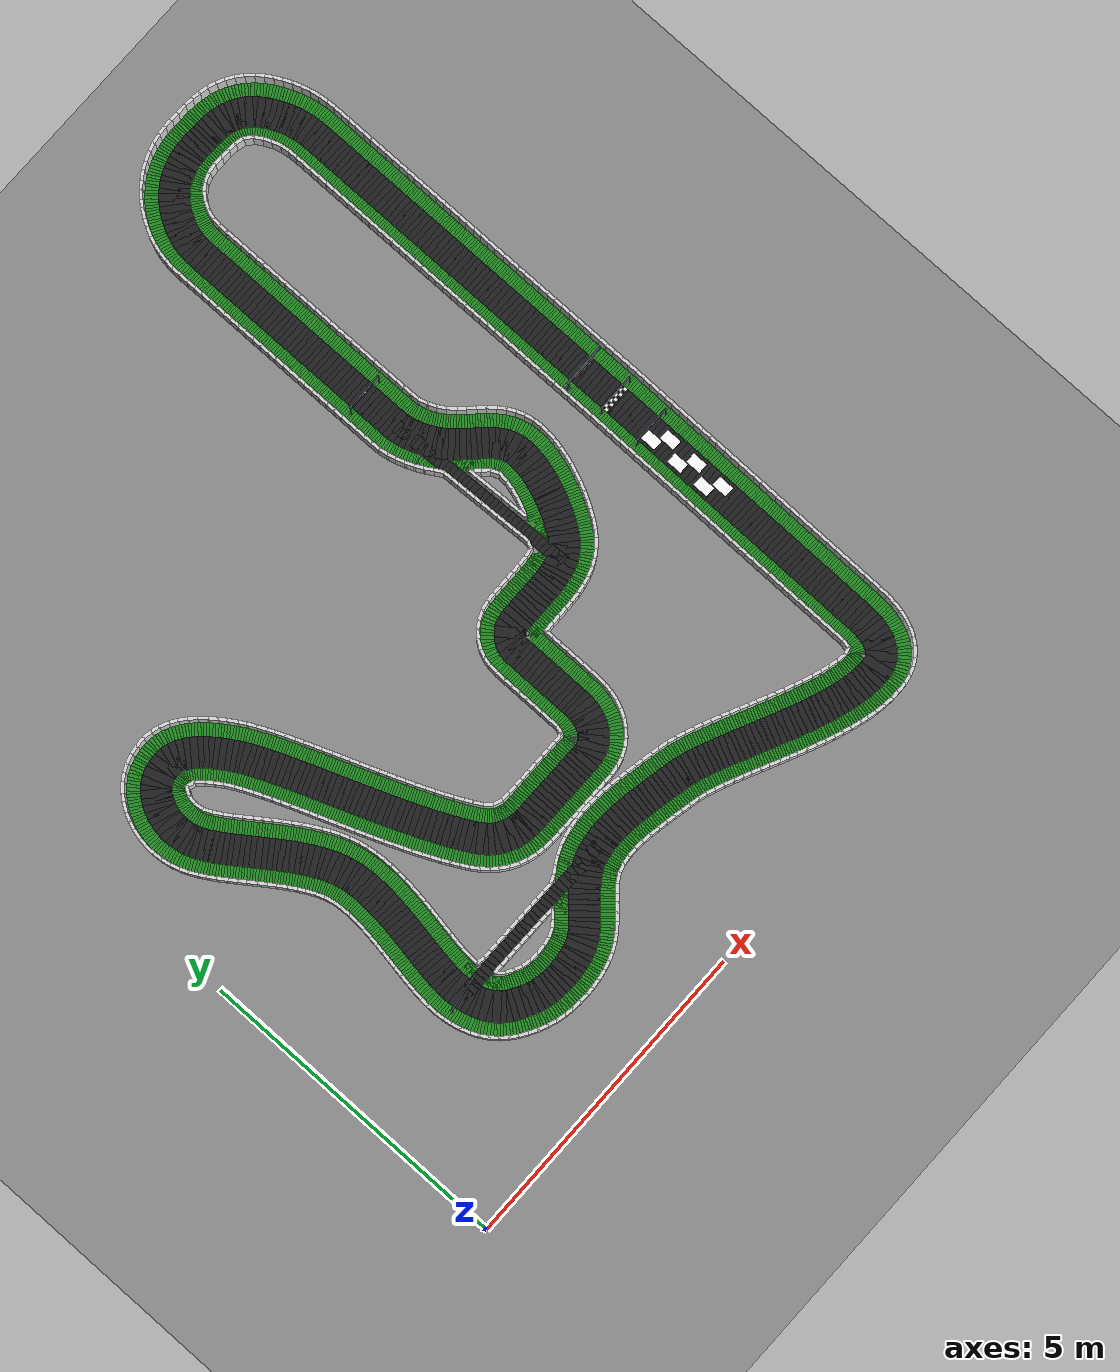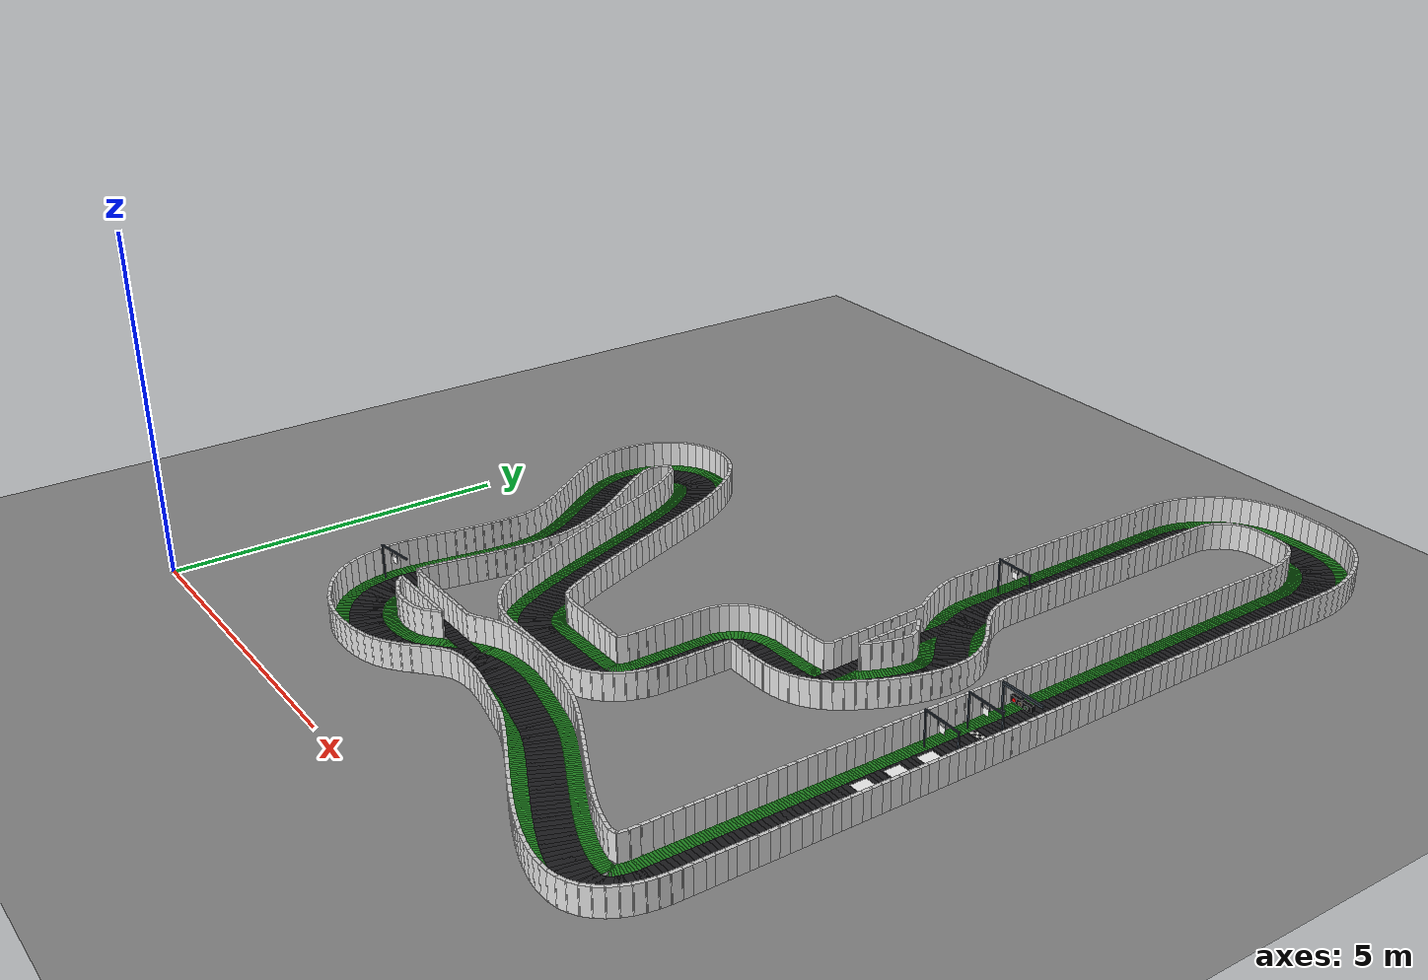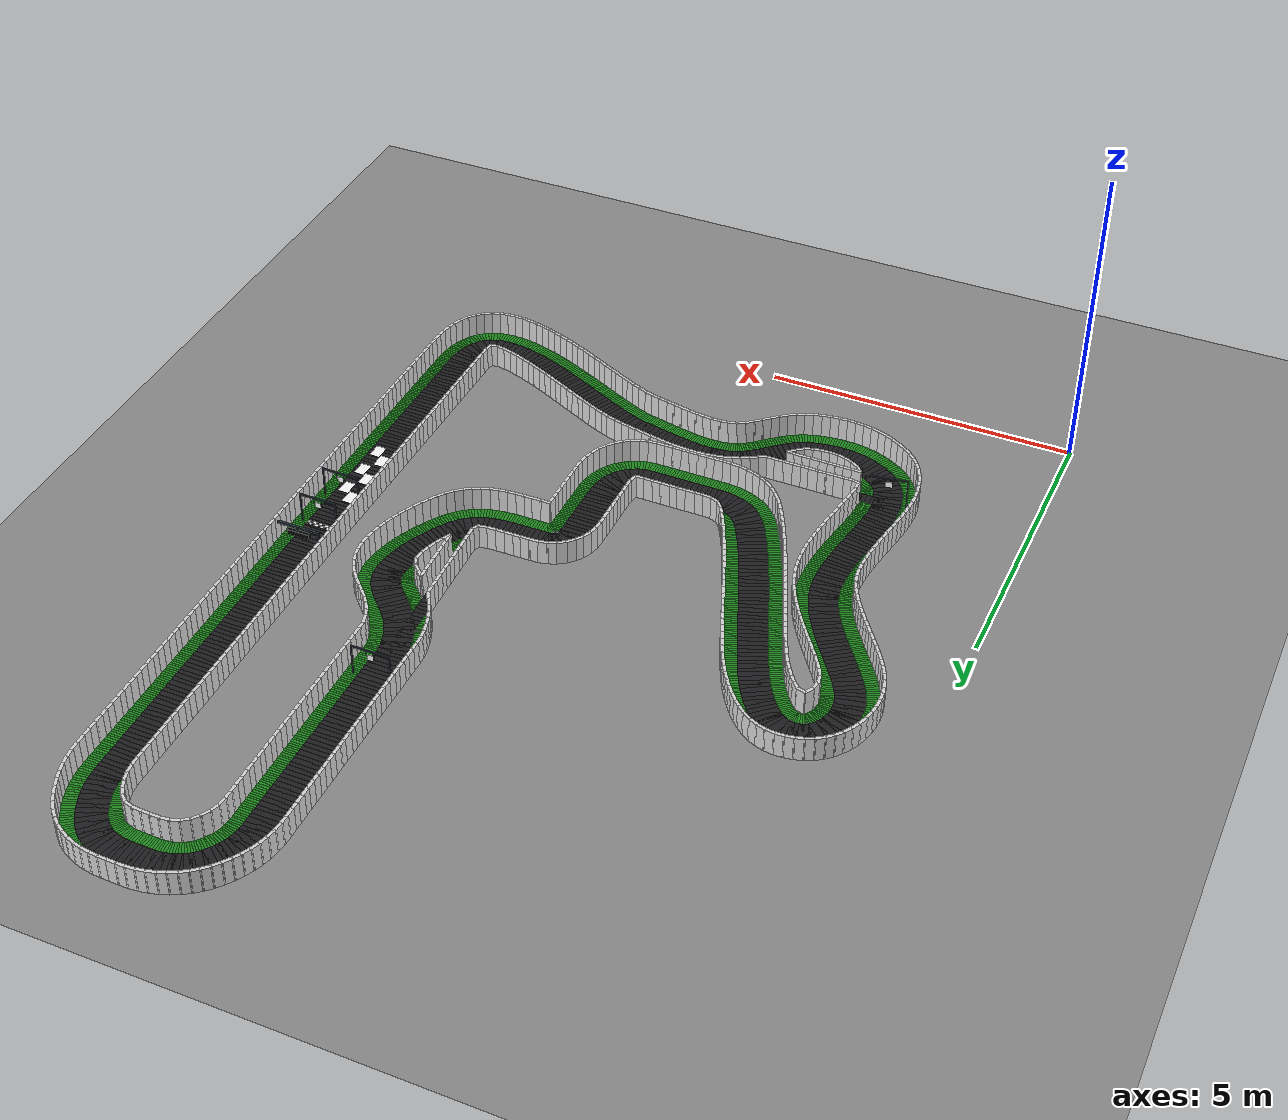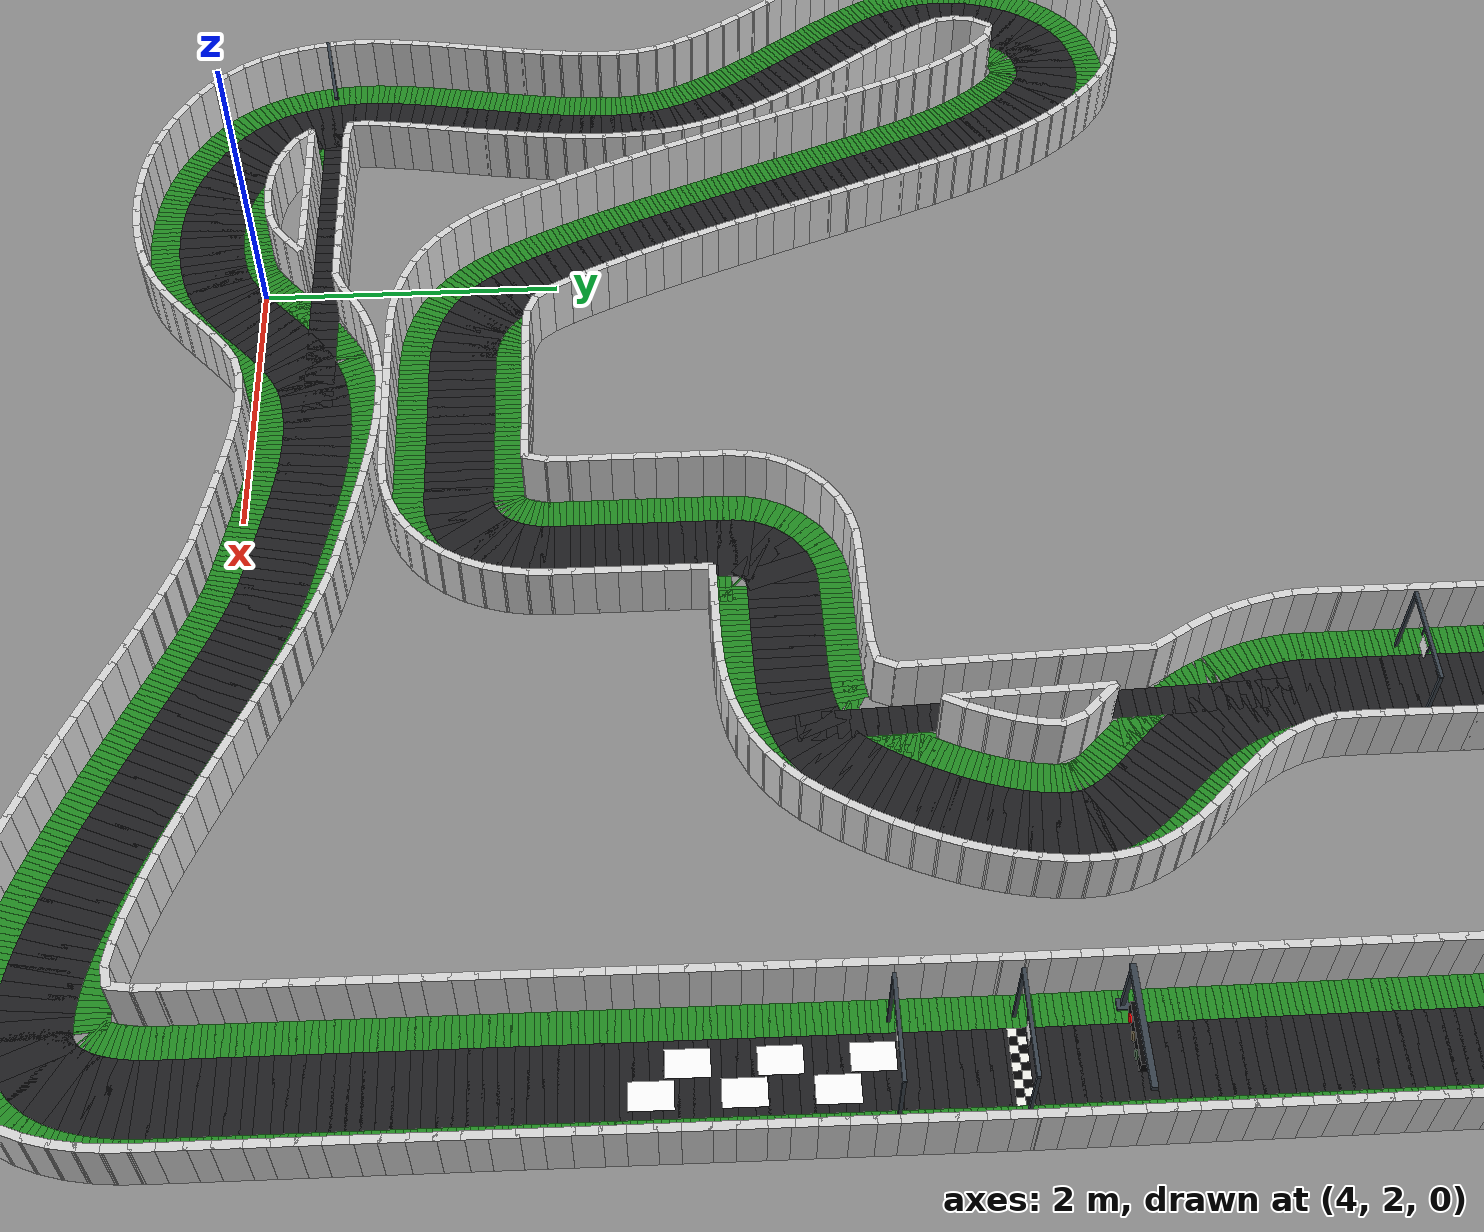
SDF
<sdf version="1.8">
 <world name="it_arena_track">
  <physics name="default_physics" type="ode">
   <max_step_size>0.001</max_step_size>
   <real_time_factor>1.0</real_time_factor>
   <dart><collision_detector>bullet</collision_detector></dart>
  </physics>
  <plugin filename="gz-sim-physics-system" name="gz::sim::systems::Physics"/>
  <plugin filename="gz-sim-user-commands-system" name="gz::sim::systems::UserCommands"/>
  <plugin filename="gz-sim-scene-broadcaster-system" name="gz::sim::systems::SceneBroadcaster"/>
  <plugin filename="gz-sim-sensors-system" name="gz::sim::systems::Sensors">
   <render_engine>ogre2</render_engine>
  </plugin>
  <plugin filename="gz-sim-imu-system" name="gz::sim::systems::Imu"/>
  <light type="directional" name="sun">
   <pose>0 0 10 0 0 0</pose>
   <diffuse>0.9 0.9 0.9 1</diffuse>
   <direction>-0.4 0.2 -0.9</direction>
  </light>
  <model name="it_arena_track_static">
   <static>true</static>
   <link name="track_geometry_merged">
    <collision name="ground_plane_link__ground_collision">
     <geometry><plane><normal>0 0 1</normal><size>30 30</size></plane></geometry>
    </collision>
    <visual name="ground_plane_link__ground_visual">
     <geometry><plane><normal>0 0 1</normal><size>30 30</size></plane></geometry>
     <material><ambient>0.55 0.55 0.55 1</ambient><diffuse>0.55 0.55 0.55 1</diffuse></material>
    </visual>
    <visual name="grid_slot_0__grid_slot_0_vis">
     <pose>9.8638 4.6804 0.0037 0 0 1.56370</pose>
     <geometry><box><size>0.2500 0.1700 0.001</size></box></geometry>
     <material><ambient>1 1 1 1</ambient><diffuse>1 1 1 1</diffuse></material>
    </visual>
    <visual name="grid_slot_1__grid_slot_1_vis">
     <pose>9.8672 5.1804 0.0037 0 0 1.56370</pose>
     <geometry><box><size>0.2500 0.1700 0.001</size></box></geometry>
     <material><ambient>1 1 1 1</ambient><diffuse>1 1 1 1</diffuse></material>
    </visual>
    <visual name="grid_slot_2__grid_slot_2_vis">
     <pose>9.8707 5.6804 0.0037 0 0 1.56390</pose>
     <geometry><box><size>0.2500 0.1700 0.001</size></box></geometry>
     <material><ambient>1 1 1 1</ambient><diffuse>1 1 1 1</diffuse></material>
    </visual>
    <visual name="grid_slot_3__grid_slot_3_vis">
     <pose>10.0425 4.4792 0.0037 0 0 1.56390</pose>
     <geometry><box><size>0.2500 0.1700 0.001</size></box></geometry>
     <material><ambient>1 1 1 1</ambient><diffuse>1 1 1 1</diffuse></material>
    </visual>
    <visual name="grid_slot_4__grid_slot_4_vis">
     <pose>10.0459 4.9792 0.0037 0 0 1.56390</pose>
     <geometry><box><size>0.2500 0.1700 0.001</size></box></geometry>
     <material><ambient>1 1 1 1</ambient><diffuse>1 1 1 1</diffuse></material>
    </visual>
    <visual name="grid_slot_5__grid_slot_5_vis">
     <pose>10.0493 5.4792 0.0037 0 0 1.56390</pose>
     <geometry><box><size>0.2500 0.1700 0.001</size></box></geometry>
     <material><ambient>1 1 1 1</ambient><diffuse>1 1 1 1</diffuse></material>
    </visual>
   </link>
   <link name="track_surface">
    <collision name="surface_main_0_col">
     <pose>9.9659 6.5065 0.0015 0 0 1.57405</pose>
     <geometry><box><size>0.0942 0.4500 0.0030</size></box></geometry>
    </collision>
    <visual name="surface_main_0_vis">
     <pose>9.9659 6.5065 0.0015 0 0 1.57405</pose>
     <geometry><box><size>0.0942 0.4500 0.0030</size></box></geometry>
     <material><ambient>0.12 0.12 0.13 1</ambient><diffuse>0.12 0.12 0.13 1</diffuse></material>
    </visual>
    <collision name="surface_main_1_col">
     <pose>9.9656 6.5865 0.0015 0 0 1.57405</pose>
     <geometry><box><size>0.0920 0.4500 0.0030</size></box></geometry>
    </collision>
    <visual name="surface_main_1_vis">
     <pose>9.9656 6.5865 0.0015 0 0 1.57405</pose>
     <geometry><box><size>0.0920 0.4500 0.0030</size></box></geometry>
     <material><ambient>0.12 0.12 0.13 1</ambient><diffuse>0.12 0.12 0.13 1</diffuse></material>
    </visual>
    <collision name="surface_main_2_col">
     <pose>9.9654 6.6665 0.0015 0 0 1.57380</pose>
     <geometry><box><size>0.0920 0.4500 0.0030</size></box></geometry>
    </collision>
    <visual name="surface_main_2_vis">
     <pose>9.9654 6.6665 0.0015 0 0 1.57380</pose>
     <geometry><box><size>0.0920 0.4500 0.0030</size></box></geometry>
     <material><ambient>0.12 0.12 0.13 1</ambient><diffuse>0.12 0.12 0.13 1</diffuse></material>
    </visual>
    <collision name="surface_main_3_col">
     <pose>9.9651 6.7465 0.0015 0 0 1.57355</pose>
     <geometry><box><size>0.0920 0.4500 0.0030</size></box></geometry>
    </collision>
    <visual name="surface_main_3_vis">
     <pose>9.9651 6.7465 0.0015 0 0 1.57355</pose>
     <geometry><box><size>0.0920 0.4500 0.0030</size></box></geometry>
     <material><ambient>0.12 0.12 0.13 1</ambient><diffuse>0.12 0.12 0.13 1</diffuse></material>
    </visual>
    <collision name="surface_main_4_col">
     <pose>9.9649 6.8265 0.0015 0 0 1.57355</pose>
     <geometry><box><size>0.0921 0.4500 0.0030</size></box></geometry>
    </collision>
    <visual name="surface_main_4_vis">
     <pose>9.9649 6.8265 0.0015 0 0 1.57355</pose>
     <geometry><box><size>0.0921 0.4500 0.0030</size></box></geometry>
     <material><ambient>0.12 0.12 0.13 1</ambient><diffuse>0.12 0.12 0.13 1</diffuse></material>
    </visual>
    <collision name="surface_main_5_col">
     <pose>9.9647 6.9064 0.0015 0 0 1.57405</pose>
     <geometry><box><size>0.0921 0.4500 0.0030</size></box></geometry>
    </collision>
    <visual name="surface_main_5_vis">
     <pose>9.9647 6.9064 0.0015 0 0 1.57405</pose>
     <geometry><box><size>0.0921 0.4500 0.0030</size></box></geometry>
     <material><ambient>0.12 0.12 0.13 1</ambient><diffuse>0.12 0.12 0.13 1</diffuse></material>
    </visual>
    <collision name="surface_main_6_col">
     <pose>9.9644 6.9864 0.0015 0 0 1.57405</pose>
     <geometry><box><size>0.0920 0.4500 0.0030</size></box></geometry>
    </collision>
    <visual name="surface_main_6_vis">
     <pose>9.9644 6.9864 0.0015 0 0 1.57405</pose>
     <geometry><box><size>0.0920 0.4500 0.0030</size></box></geometry>
     <material><ambient>0.12 0.12 0.13 1</ambient><diffuse>0.12 0.12 0.13 1</diffuse></material>
    </visual>
    <collision name="surface_main_7_col">
     <pose>9.9642 7.0664 0.0015 0 0 1.57379</pose>
     <geometry><box><size>0.0921 0.4500 0.0030</size></box></geometry>
    </collision>
    <visual name="surface_main_7_vis">
     <pose>9.9642 7.0664 0.0015 0 0 1.57379</pose>
     <geometry><box><size>0.0921 0.4500 0.0030</size></box></geometry>
     <material><ambient>0.12 0.12 0.13 1</ambient><diffuse>0.12 0.12 0.13 1</diffuse></material>
    </visual>
    <collision name="surface_main_8_col">
     <pose>9.9639 7.1464 0.0015 0 0 1.57430</pose>
     <geometry><box><size>0.0921 0.4500 0.0030</size></box></geometry>
    </collision>
    <visual name="surface_main_8_vis">
     <pose>9.9639 7.1464 0.0015 0 0 1.57430</pose>
     <geometry><box><size>0.0921 0.4500 0.0030</size></box></geometry>
     <material><ambient>0.12 0.12 0.13 1</ambient><diffuse>0.12 0.12 0.13 1</diffuse></material>
    </visual>
    <collision name="surface_main_9_col">
     <pose>9.9636 7.2264 0.0015 0 0 1.57404</pose>
     <geometry><box><size>0.0921 0.4500 0.0030</size></box></geometry>
    </collision>
    <visual name="surface_main_9_vis">
     <pose>9.9636 7.2264 0.0015 0 0 1.57404</pose>
     <geometry><box><size>0.0921 0.4500 0.0030</size></box></geometry>
     <material><ambient>0.12 0.12 0.13 1</ambient><diffuse>0.12 0.12 0.13 1</diffuse></material>
    </visual>
    <collision name="surface_main_10_col">
     <pose>9.9634 7.3064 0.0015 0 0 1.57355</pose>
     <geometry><box><size>0.0921 0.4500 0.0030</size></box></geometry>
    </collision>
    <visual name="surface_main_10_vis">
     <pose>9.9634 7.3064 0.0015 0 0 1.57355</pose>
     <geometry><box><size>0.0921 0.4500 0.0030</size></box></geometry>
     <material><ambient>0.12 0.12 0.13 1</ambient><diffuse>0.12 0.12 0.13 1</diffuse></material>
    </visual>
    <collision name="surface_main_11_col">
     <pose>9.9632 7.3864 0.0015 0 0 1.57355</pose>
     <geometry><box><size>0.0920 0.4500 0.0030</size></box></geometry>
    </collision>
    <visual name="surface_main_11_vis">
     <pose>9.9632 7.3864 0.0015 0 0 1.57355</pose>
     <geometry><box><size>0.0920 0.4500 0.0030</size></box></geometry>
     <material><ambient>0.12 0.12 0.13 1</ambient><diffuse>0.12 0.12 0.13 1</diffuse></material>
    </visual>
    <collision name="surface_main_12_col">
     <pose>9.9629 7.4664 0.0015 0 0 1.57380</pose>
     <geometry><box><size>0.0920 0.4500 0.0030</size></box></geometry>
    </collision>
    <visual name="surface_main_12_vis">
     <pose>9.9629 7.4664 0.0015 0 0 1.57380</pose>
     <geometry><box><size>0.0920 0.4500 0.0030</size></box></geometry>
     <material><ambient>0.12 0.12 0.13 1</ambient><diffuse>0.12 0.12 0.13 1</diffuse></material>
    </visual>
    <collision name="surface_main_13_col">
     <pose>9.9627 7.5464 0.0015 0 0 1.57405</pose>
     <geometry><box><size>0.0920 0.4500 0.0030</size></box></geometry>
    </collision>
    <visual name="surface_main_13_vis">
     <pose>9.9627 7.5464 0.0015 0 0 1.57405</pose>
     <geometry><box><size>0.0920 0.4500 0.0030</size></box></geometry>
     <material><ambient>0.12 0.12 0.13 1</ambient><diffuse>0.12 0.12 0.13 1</diffuse></material>
    </visual>
    <collision name="surface_main_14_col">
     <pose>9.9624 7.6264 0.0015 0 0 1.57404</pose>
     <geometry><box><size>0.0921 0.4500 0.0030</size></box></geometry>
    </collision>
    <visual name="surface_main_14_vis">
     <pose>9.9624 7.6264 0.0015 0 0 1.57404</pose>
     <geometry><box><size>0.0921 0.4500 0.0030</size></box></geometry>
     <material><ambient>0.12 0.12 0.13 1</ambient><diffuse>0.12 0.12 0.13 1</diffuse></material>
    </visual>
    <collision name="surface_main_15_col">
     <pose>9.9622 7.7064 0.0015 0 0 1.57355</pose>
     <geometry><box><size>0.0922 0.4500 0.0030</size></box></geometry>
    </collision>
    <visual name="surface_main_15_vis">
     <pose>9.9622 7.7064 0.0015 0 0 1.57355</pose>
     <geometry><box><size>0.0922 0.4500 0.0030</size></box></geometry>
     <material><ambient>0.12 0.12 0.13 1</ambient><diffuse>0.12 0.12 0.13 1</diffuse></material>
    </visual>
    <collision name="surface_main_16_col">
     <pose>9.9619 7.7863 0.0015 0 0 1.57455</pose>
     <geometry><box><size>0.0922 0.4500 0.0030</size></box></geometry>
    </collision>
    <visual name="surface_main_16_vis">
     <pose>9.9619 7.7863 0.0015 0 0 1.57455</pose>
     <geometry><box><size>0.0922 0.4500 0.0030</size></box></geometry>
     <material><ambient>0.12 0.12 0.13 1</ambient><diffuse>0.12 0.12 0.13 1</diffuse></material>
    </visual>
    <collision name="surface_main_17_col">
     <pose>9.9617 7.8663 0.0015 0 0 1.57379</pose>
     <geometry><box><size>0.0922 0.4500 0.0030</size></box></geometry>
    </collision>
    <visual name="surface_main_17_vis">
     <pose>9.9617 7.8663 0.0015 0 0 1.57379</pose>
     <geometry><box><size>0.0922 0.4500 0.0030</size></box></geometry>
     <material><ambient>0.12 0.12 0.13 1</ambient><diffuse>0.12 0.12 0.13 1</diffuse></material>
    </visual>
    <collision name="surface_main_18_col">
     <pose>9.9614 7.9463 0.0015 0 0 1.57355</pose>
     <geometry><box><size>0.0920 0.4500 0.0030</size></box></geometry>
    </collision>
    <visual name="surface_main_18_vis">
     <pose>9.9614 7.9463 0.0015 0 0 1.57355</pose>
     <geometry><box><size>0.0920 0.4500 0.0030</size></box></geometry>
     <material><ambient>0.12 0.12 0.13 1</ambient><diffuse>0.12 0.12 0.13 1</diffuse></material>
    </visual>
    <collision name="surface_main_19_col">
     <pose>9.9612 8.0263 0.0015 0 0 1.57355</pose>
     <geometry><box><size>0.0921 0.4500 0.0030</size></box></geometry>
    </collision>
    <visual name="surface_main_19_vis">
     <pose>9.9612 8.0263 0.0015 0 0 1.57355</pose>
     <geometry><box><size>0.0921 0.4500 0.0030</size></box></geometry>
     <material><ambient>0.12 0.12 0.13 1</ambient><diffuse>0.12 0.12 0.13 1</diffuse></material>
    </visual>
    <collision name="surface_main_20_col">
     <pose>9.9610 8.1063 0.0015 0 0 1.57405</pose>
     <geometry><box><size>0.0921 0.4500 0.0030</size></box></geometry>
    </collision>
    <visual name="surface_main_20_vis">
     <pose>9.9610 8.1063 0.0015 0 0 1.57405</pose>
     <geometry><box><size>0.0921 0.4500 0.0030</size></box></geometry>
     <material><ambient>0.12 0.12 0.13 1</ambient><diffuse>0.12 0.12 0.13 1</diffuse></material>
    </visual>
    <collision name="surface_main_21_col">
     <pose>9.9607 8.1863 0.0015 0 0 1.57405</pose>
     <geometry><box><size>0.0920 0.4500 0.0030</size></box></geometry>
    </collision>
    <visual name="surface_main_21_vis">
     <pose>9.9607 8.1863 0.0015 0 0 1.57405</pose>
     <geometry><box><size>0.0920 0.4500 0.0030</size></box></geometry>
     <material><ambient>0.12 0.12 0.13 1</ambient><diffuse>0.12 0.12 0.13 1</diffuse></material>
    </visual>
    <collision name="surface_main_22_col">
     <pose>9.9605 8.2663 0.0015 0 0 1.57379</pose>
     <geometry><box><size>0.0921 0.4500 0.0030</size></box></geometry>
    </collision>
    <visual name="surface_main_22_vis">
     <pose>9.9605 8.2663 0.0015 0 0 1.57379</pose>
     <geometry><box><size>0.0921 0.4500 0.0030</size></box></geometry>
     <material><ambient>0.12 0.12 0.13 1</ambient><diffuse>0.12 0.12 0.13 1</diffuse></material>
    </visual>
    <collision name="surface_main_23_col">
     <pose>9.9602 8.3463 0.0015 0 0 1.57430</pose>
     <geometry><box><size>0.0921 0.4500 0.0030</size></box></geometry>
    </collision>
    <visual name="surface_main_23_vis">
     <pose>9.9602 8.3463 0.0015 0 0 1.57430</pose>
     <geometry><box><size>0.0921 0.4500 0.0030</size></box></geometry>
     <material><ambient>0.12 0.12 0.13 1</ambient><diffuse>0.12 0.12 0.13 1</diffuse></material>
    </visual>
    <collision name="surface_main_24_col">
     <pose>9.9599 8.4263 0.0015 0 0 1.57404</pose>
     <geometry><box><size>0.0921 0.4500 0.0030</size></box></geometry>
    </collision>
    <visual name="surface_main_24_vis">
     <pose>9.9599 8.4263 0.0015 0 0 1.57404</pose>
     <geometry><box><size>0.0921 0.4500 0.0030</size></box></geometry>
     <material><ambient>0.12 0.12 0.13 1</ambient><diffuse>0.12 0.12 0.13 1</diffuse></material>
    </visual>
    <collision name="surface_main_25_col">
     <pose>9.9597 8.5063 0.0015 0 0 1.57355</pose>
     <geometry><box><size>0.0921 0.4500 0.0030</size></box></geometry>
    </collision>
    <visual name="surface_main_25_vis">
     <pose>9.9597 8.5063 0.0015 0 0 1.57355</pose>
     <geometry><box><size>0.0921 0.4500 0.0030</size></box></geometry>
     <material><ambient>0.12 0.12 0.13 1</ambient><diffuse>0.12 0.12 0.13 1</diffuse></material>
    </visual>
    <collision name="surface_main_26_col">
     <pose>9.9595 8.5863 0.0015 0 0 1.57355</pose>
     <geometry><box><size>0.0920 0.4500 0.0030</size></box></geometry>
    </collision>
    <visual name="surface_main_26_vis">
     <pose>9.9595 8.5863 0.0015 0 0 1.57355</pose>
     <geometry><box><size>0.0920 0.4500 0.0030</size></box></geometry>
     <material><ambient>0.12 0.12 0.13 1</ambient><diffuse>0.12 0.12 0.13 1</diffuse></material>
    </visual>
    <collision name="surface_main_27_col">
     <pose>9.9592 8.6662 0.0015 0 0 1.57380</pose>
     <geometry><box><size>0.0920 0.4500 0.0030</size></box></geometry>
    </collision>
    <visual name="surface_main_27_vis">
     <pose>9.9592 8.6662 0.0015 0 0 1.57380</pose>
     <geometry><box><size>0.0920 0.4500 0.0030</size></box></geometry>
     <material><ambient>0.12 0.12 0.13 1</ambient><diffuse>0.12 0.12 0.13 1</diffuse></material>
    </visual>
    <collision name="surface_main_28_col">
     <pose>9.9590 8.7462 0.0015 0 0 1.57405</pose>
     <geometry><box><size>0.0920 0.4500 0.0030</size></box></geometry>
    </collision>
    <visual name="surface_main_28_vis">
     <pose>9.9590 8.7462 0.0015 0 0 1.57405</pose>
     <geometry><box><size>0.0920 0.4500 0.0030</size></box></geometry>
     <material><ambient>0.12 0.12 0.13 1</ambient><diffuse>0.12 0.12 0.13 1</diffuse></material>
    </visual>
    <collision name="surface_main_29_col">
     <pose>9.9587 8.8262 0.0015 0 0 1.57404</pose>
     <geometry><box><size>0.0921 0.4500 0.0030</size></box></geometry>
    </collision>
    <visual name="surface_main_29_vis">
     <pose>9.9587 8.8262 0.0015 0 0 1.57404</pose>
     <geometry><box><size>0.0921 0.4500 0.0030</size></box></geometry>
     <material><ambient>0.12 0.12 0.13 1</ambient><diffuse>0.12 0.12 0.13 1</diffuse></material>
    </visual>
    <collision name="surface_main_30_col">
     <pose>9.9585 8.9062 0.0015 0 0 1.57355</pose>
     <geometry><box><size>0.0922 0.4500 0.0030</size></box></geometry>
    </collision>
    <visual name="surface_main_30_vis">
     <pose>9.9585 8.9062 0.0015 0 0 1.57355</pose>
     <geometry><box><size>0.0922 0.4500 0.0030</size></box></geometry>
     <material><ambient>0.12 0.12 0.13 1</ambient><diffuse>0.12 0.12 0.13 1</diffuse></material>
    </visual>
    <collision name="surface_main_31_col">
     <pose>9.9582 8.9862 0.0015 0 0 1.57455</pose>
     <geometry><box><size>0.0922 0.4500 0.0030</size></box></geometry>
    </collision>
    <visual name="surface_main_31_vis">
     <pose>9.9582 8.9862 0.0015 0 0 1.57455</pose>
     <geometry><box><size>0.0922 0.4500 0.0030</size></box></geometry>
     <material><ambient>0.12 0.12 0.13 1</ambient><diffuse>0.12 0.12 0.13 1</diffuse></material>
    </visual>
    <collision name="surface_main_32_col">
     <pose>9.9580 9.0662 0.0015 0 0 1.57379</pose>
     <geometry><box><size>0.0922 0.4500 0.0030</size></box></geometry>
    </collision>
    <visual name="surface_main_32_vis">
     <pose>9.9580 9.0662 0.0015 0 0 1.57379</pose>
     <geometry><box><size>0.0922 0.4500 0.0030</size></box></geometry>
     <material><ambient>0.12 0.12 0.13 1</ambient><diffuse>0.12 0.12 0.13 1</diffuse></material>
    </visual>
    <collision name="surface_main_33_col">
     <pose>9.9577 9.1462 0.0015 0 0 1.57355</pose>
     <geometry><box><size>0.0920 0.4500 0.0030</size></box></geometry>
    </collision>
    <visual name="surface_main_33_vis">
     <pose>9.9577 9.1462 0.0015 0 0 1.57355</pose>
     <geometry><box><size>0.0920 0.4500 0.0030</size></box></geometry>
     <material><ambient>0.12 0.12 0.13 1</ambient><diffuse>0.12 0.12 0.13 1</diffuse></material>
    </visual>
    <collision name="surface_main_34_col">
     <pose>9.9575 9.2262 0.0015 0 0 1.57355</pose>
     <geometry><box><size>0.0921 0.4500 0.0030</size></box></geometry>
    </collision>
    <visual name="surface_main_34_vis">
     <pose>9.9575 9.2262 0.0015 0 0 1.57355</pose>
     <geometry><box><size>0.0921 0.4500 0.0030</size></box></geometry>
     <material><ambient>0.12 0.12 0.13 1</ambient><diffuse>0.12 0.12 0.13 1</diffuse></material>
    </visual>
    <collision name="surface_main_35_col">
     <pose>9.9573 9.3062 0.0015 0 0 1.57405</pose>
     <geometry><box><size>0.0921 0.4500 0.0030</size></box></geometry>
    </collision>
    <visual name="surface_main_35_vis">
     <pose>9.9573 9.3062 0.0015 0 0 1.57405</pose>
     <geometry><box><size>0.0921 0.4500 0.0030</size></box></geometry>
     <material><ambient>0.12 0.12 0.13 1</ambient><diffuse>0.12 0.12 0.13 1</diffuse></material>
    </visual>
    <collision name="surface_main_36_col">
     <pose>9.9570 9.3862 0.0015 0 0 1.57405</pose>
     <geometry><box><size>0.0920 0.4500 0.0030</size></box></geometry>
    </collision>
    <visual name="surface_main_36_vis">
     <pose>9.9570 9.3862 0.0015 0 0 1.57405</pose>
     <geometry><box><size>0.0920 0.4500 0.0030</size></box></geometry>
     <material><ambient>0.12 0.12 0.13 1</ambient><diffuse>0.12 0.12 0.13 1</diffuse></material>
    </visual>
    <collision name="surface_main_37_col">
     <pose>9.9568 9.4662 0.0015 0 0 1.57379</pose>
     <geometry><box><size>0.0920 0.4500 0.0030</size></box></geometry>
    </collision>
    <visual name="surface_main_37_vis">
     <pose>9.9568 9.4662 0.0015 0 0 1.57379</pose>
     <geometry><box><size>0.0920 0.4500 0.0030</size></box></geometry>
     <material><ambient>0.12 0.12 0.13 1</ambient><diffuse>0.12 0.12 0.13 1</diffuse></material>
    </visual>
    <collision name="surface_main_38_col">
     <pose>9.9565 9.5461 0.0015 0 0 1.57355</pose>
     <geometry><box><size>0.0923 0.4500 0.0030</size></box></geometry>
    </collision>
    <visual name="surface_main_38_vis">
     <pose>9.9565 9.5461 0.0015 0 0 1.57355</pose>
     <geometry><box><size>0.0923 0.4500 0.0030</size></box></geometry>
     <material><ambient>0.12 0.12 0.13 1</ambient><diffuse>0.12 0.12 0.13 1</diffuse></material>
    </visual>
    <collision name="surface_main_39_col">
     <pose>9.9563 9.6261 0.0015 0 0 1.57480</pose>
     <geometry><box><size>0.0923 0.4500 0.0030</size></box></geometry>
    </collision>
    <visual name="surface_main_39_vis">
     <pose>9.9563 9.6261 0.0015 0 0 1.57480</pose>
     <geometry><box><size>0.0923 0.4500 0.0030</size></box></geometry>
     <material><ambient>0.12 0.12 0.13 1</ambient><diffuse>0.12 0.12 0.13 1</diffuse></material>
    </visual>
    <collision name="surface_main_40_col">
     <pose>9.9560 9.7061 0.0015 0 0 1.57355</pose>
     <geometry><box><size>0.0923 0.4500 0.0030</size></box></geometry>
    </collision>
    <visual name="surface_main_40_vis">
     <pose>9.9560 9.7061 0.0015 0 0 1.57355</pose>
     <geometry><box><size>0.0923 0.4500 0.0030</size></box></geometry>
     <material><ambient>0.12 0.12 0.13 1</ambient><diffuse>0.12 0.12 0.13 1</diffuse></material>
    </visual>
    <collision name="surface_main_41_col">
     <pose>9.9558 9.7861 0.0015 0 0 1.57355</pose>
     <geometry><box><size>0.0920 0.4500 0.0030</size></box></geometry>
    </collision>
    <visual name="surface_main_41_vis">
     <pose>9.9558 9.7861 0.0015 0 0 1.57355</pose>
     <geometry><box><size>0.0920 0.4500 0.0030</size></box></geometry>
     <material><ambient>0.12 0.12 0.13 1</ambient><diffuse>0.12 0.12 0.13 1</diffuse></material>
    </visual>
    <collision name="surface_main_42_col">
     <pose>9.9555 9.8661 0.0015 0 0 1.57381</pose>
     <geometry><box><size>0.0920 0.4500 0.0030</size></box></geometry>
    </collision>
    <visual name="surface_main_42_vis">
     <pose>9.9555 9.8661 0.0015 0 0 1.57381</pose>
     <geometry><box><size>0.0920 0.4500 0.0030</size></box></geometry>
     <material><ambient>0.12 0.12 0.13 1</ambient><diffuse>0.12 0.12 0.13 1</diffuse></material>
    </visual>
    <collision name="surface_main_43_col">
     <pose>9.9553 9.9461 0.0015 0 0 1.57405</pose>
     <geometry><box><size>0.0920 0.4500 0.0030</size></box></geometry>
    </collision>
    <visual name="surface_main_43_vis">
     <pose>9.9553 9.9461 0.0015 0 0 1.57405</pose>
     <geometry><box><size>0.0920 0.4500 0.0030</size></box></geometry>
     <material><ambient>0.12 0.12 0.13 1</ambient><diffuse>0.12 0.12 0.13 1</diffuse></material>
    </visual>
    <collision name="surface_main_44_col">
     <pose>9.9550 10.0261 0.0015 0 0 1.57404</pose>
     <geometry><box><size>0.0921 0.4500 0.0030</size></box></geometry>
    </collision>
    <visual name="surface_main_44_vis">
     <pose>9.9550 10.0261 0.0015 0 0 1.57404</pose>
     <geometry><box><size>0.0921 0.4500 0.0030</size></box></geometry>
     <material><ambient>0.12 0.12 0.13 1</ambient><diffuse>0.12 0.12 0.13 1</diffuse></material>
    </visual>
    <collision name="surface_main_45_col">
     <pose>9.9548 10.1061 0.0015 0 0 1.57355</pose>
     <geometry><box><size>0.0921 0.4500 0.0030</size></box></geometry>
    </collision>
    <visual name="surface_main_45_vis">
     <pose>9.9548 10.1061 0.0015 0 0 1.57355</pose>
     <geometry><box><size>0.0921 0.4500 0.0030</size></box></geometry>
     <material><ambient>0.12 0.12 0.13 1</ambient><diffuse>0.12 0.12 0.13 1</diffuse></material>
    </visual>
    <collision name="surface_main_46_col">
     <pose>9.9546 10.1861 0.0015 0 0 1.57355</pose>
     <geometry><box><size>0.0923 0.4500 0.0030</size></box></geometry>
    </collision>
    <visual name="surface_main_46_vis">
     <pose>9.9546 10.1861 0.0015 0 0 1.57355</pose>
     <geometry><box><size>0.0923 0.4500 0.0030</size></box></geometry>
     <material><ambient>0.12 0.12 0.13 1</ambient><diffuse>0.12 0.12 0.13 1</diffuse></material>
    </visual>
    <collision name="surface_main_47_col">
     <pose>9.9543 10.2661 0.0015 0 0 1.57480</pose>
     <geometry><box><size>0.0923 0.4500 0.0030</size></box></geometry>
    </collision>
    <visual name="surface_main_47_vis">
     <pose>9.9543 10.2661 0.0015 0 0 1.57480</pose>
     <geometry><box><size>0.0923 0.4500 0.0030</size></box></geometry>
     <material><ambient>0.12 0.12 0.13 1</ambient><diffuse>0.12 0.12 0.13 1</diffuse></material>
    </visual>
    <collision name="surface_main_48_col">
     <pose>9.9540 10.3461 0.0015 0 0 1.57355</pose>
     <geometry><box><size>0.0923 0.4500 0.0030</size></box></geometry>
    </collision>
    <visual name="surface_main_48_vis">
     <pose>9.9540 10.3461 0.0015 0 0 1.57355</pose>
     <geometry><box><size>0.0923 0.4500 0.0030</size></box></geometry>
     <material><ambient>0.12 0.12 0.13 1</ambient><diffuse>0.12 0.12 0.13 1</diffuse></material>
    </visual>
    <collision name="surface_main_49_col">
     <pose>9.9538 10.4260 0.0015 0 0 1.57356</pose>
     <geometry><box><size>0.0921 0.4500 0.0030</size></box></geometry>
    </collision>
    <visual name="surface_main_49_vis">
     <pose>9.9538 10.4260 0.0015 0 0 1.57356</pose>
     <geometry><box><size>0.0921 0.4500 0.0030</size></box></geometry>
     <material><ambient>0.12 0.12 0.13 1</ambient><diffuse>0.12 0.12 0.13 1</diffuse></material>
    </visual>
    <collision name="surface_main_50_col">
     <pose>9.9536 10.5060 0.0015 0 0 1.57405</pose>
     <geometry><box><size>0.0921 0.4500 0.0030</size></box></geometry>
    </collision>
    <visual name="surface_main_50_vis">
     <pose>9.9536 10.5060 0.0015 0 0 1.57405</pose>
     <geometry><box><size>0.0921 0.4500 0.0030</size></box></geometry>
     <material><ambient>0.12 0.12 0.13 1</ambient><diffuse>0.12 0.12 0.13 1</diffuse></material>
    </visual>
    <collision name="surface_main_51_col">
     <pose>9.9533 10.5860 0.0015 0 0 1.57405</pose>
     <geometry><box><size>0.0920 0.4500 0.0030</size></box></geometry>
    </collision>
    <visual name="surface_main_51_vis">
     <pose>9.9533 10.5860 0.0015 0 0 1.57405</pose>
     <geometry><box><size>0.0920 0.4500 0.0030</size></box></geometry>
     <material><ambient>0.12 0.12 0.13 1</ambient><diffuse>0.12 0.12 0.13 1</diffuse></material>
    </visual>
    <collision name="surface_main_52_col">
     <pose>9.9531 10.6660 0.0015 0 0 1.57378</pose>
     <geometry><box><size>0.0920 0.4500 0.0030</size></box></geometry>
    </collision>
    <visual name="surface_main_52_vis">
     <pose>9.9531 10.6660 0.0015 0 0 1.57378</pose>
     <geometry><box><size>0.0920 0.4500 0.0030</size></box></geometry>
     <material><ambient>0.12 0.12 0.13 1</ambient><diffuse>0.12 0.12 0.13 1</diffuse></material>
    </visual>
    <collision name="surface_main_53_col">
     <pose>9.9528 10.7460 0.0015 0 0 1.57355</pose>
     <geometry><box><size>0.0920 0.4500 0.0030</size></box></geometry>
    </collision>
    <visual name="surface_main_53_vis">
     <pose>9.9528 10.7460 0.0015 0 0 1.57355</pose>
     <geometry><box><size>0.0920 0.4500 0.0030</size></box></geometry>
     <material><ambient>0.12 0.12 0.13 1</ambient><diffuse>0.12 0.12 0.13 1</diffuse></material>
    </visual>
    <collision name="surface_main_54_col">
     <pose>9.9526 10.8260 0.0015 0 0 1.57356</pose>
     <geometry><box><size>0.0923 0.4500 0.0030</size></box></geometry>
    </collision>
    <visual name="surface_main_54_vis">
     <pose>9.9526 10.8260 0.0015 0 0 1.57356</pose>
     <geometry><box><size>0.0923 0.4500 0.0030</size></box></geometry>
     <material><ambient>0.12 0.12 0.13 1</ambient><diffuse>0.12 0.12 0.13 1</diffuse></material>
    </visual>
    <collision name="surface_main_55_col">
     <pose>9.9523 10.9060 0.0015 0 0 1.57478</pose>
     <geometry><box><size>0.0923 0.4500 0.0030</size></box></geometry>
    </collision>
    <visual name="surface_main_55_vis">
     <pose>9.9523 10.9060 0.0015 0 0 1.57478</pose>
     <geometry><box><size>0.0923 0.4500 0.0030</size></box></geometry>
     <material><ambient>0.12 0.12 0.13 1</ambient><diffuse>0.12 0.12 0.13 1</diffuse></material>
    </visual>
    <collision name="surface_main_56_col">
     <pose>9.9521 10.9860 0.0015 0 0 1.57355</pose>
     <geometry><box><size>0.0923 0.4500 0.0030</size></box></geometry>
    </collision>
    <visual name="surface_main_56_vis">
     <pose>9.9521 10.9860 0.0015 0 0 1.57355</pose>
     <geometry><box><size>0.0923 0.4500 0.0030</size></box></geometry>
     <material><ambient>0.12 0.12 0.13 1</ambient><diffuse>0.12 0.12 0.13 1</diffuse></material>
    </visual>
    <collision name="surface_main_57_col">
     <pose>9.9518 11.0660 0.0015 0 0 1.57381</pose>
     <geometry><box><size>0.0920 0.4500 0.0030</size></box></geometry>
    </collision>
    <visual name="surface_main_57_vis">
     <pose>9.9518 11.0660 0.0015 0 0 1.57381</pose>
     <geometry><box><size>0.0920 0.4500 0.0030</size></box></geometry>
     <material><ambient>0.12 0.12 0.13 1</ambient><diffuse>0.12 0.12 0.13 1</diffuse></material>
    </visual>
    <collision name="surface_main_58_col">
     <pose>9.9516 11.1460 0.0015 0 0 1.57405</pose>
     <geometry><box><size>0.0920 0.4500 0.0030</size></box></geometry>
    </collision>
    <visual name="surface_main_58_vis">
     <pose>9.9516 11.1460 0.0015 0 0 1.57405</pose>
     <geometry><box><size>0.0920 0.4500 0.0030</size></box></geometry>
     <material><ambient>0.12 0.12 0.13 1</ambient><diffuse>0.12 0.12 0.13 1</diffuse></material>
    </visual>
    <collision name="surface_main_59_col">
     <pose>9.9513 11.2260 0.0015 0 0 1.57403</pose>
     <geometry><box><size>0.0921 0.4500 0.0030</size></box></geometry>
    </collision>
    <visual name="surface_main_59_vis">
     <pose>9.9513 11.2260 0.0015 0 0 1.57403</pose>
     <geometry><box><size>0.0921 0.4500 0.0030</size></box></geometry>
     <material><ambient>0.12 0.12 0.13 1</ambient><diffuse>0.12 0.12 0.13 1</diffuse></material>
    </visual>
    <collision name="surface_main_60_col">
     <pose>9.9511 11.3059 0.0015 0 0 1.57355</pose>
     <geometry><box><size>0.0921 0.4500 0.0030</size></box></geometry>
    </collision>
    <visual name="surface_main_60_vis">
     <pose>9.9511 11.3059 0.0015 0 0 1.57355</pose>
     <geometry><box><size>0.0921 0.4500 0.0030</size></box></geometry>
     <material><ambient>0.12 0.12 0.13 1</ambient><diffuse>0.12 0.12 0.13 1</diffuse></material>
    </visual>
    <collision name="surface_main_61_col">
     <pose>9.9509 11.3859 0.0015 0 0 1.57355</pose>
     <geometry><box><size>0.0923 0.4500 0.0030</size></box></geometry>
    </collision>
    <visual name="surface_main_61_vis">
     <pose>9.9509 11.3859 0.0015 0 0 1.57355</pose>
     <geometry><box><size>0.0923 0.4500 0.0030</size></box></geometry>
     <material><ambient>0.12 0.12 0.13 1</ambient><diffuse>0.12 0.12 0.13 1</diffuse></material>
    </visual>
    <collision name="surface_main_62_col">
     <pose>9.9506 11.4659 0.0015 0 0 1.57480</pose>
     <geometry><box><size>0.0923 0.4500 0.0030</size></box></geometry>
    </collision>
    <visual name="surface_main_62_vis">
     <pose>9.9506 11.4659 0.0015 0 0 1.57480</pose>
     <geometry><box><size>0.0923 0.4500 0.0030</size></box></geometry>
     <material><ambient>0.12 0.12 0.13 1</ambient><diffuse>0.12 0.12 0.13 1</diffuse></material>
    </visual>
    <collision name="surface_main_63_col">
     <pose>9.9503 11.5459 0.0015 0 0 1.57355</pose>
     <geometry><box><size>0.0923 0.4500 0.0030</size></box></geometry>
    </collision>
    <visual name="surface_main_63_vis">
     <pose>9.9503 11.5459 0.0015 0 0 1.57355</pose>
     <geometry><box><size>0.0923 0.4500 0.0030</size></box></geometry>
     <material><ambient>0.12 0.12 0.13 1</ambient><diffuse>0.12 0.12 0.13 1</diffuse></material>
    </visual>
    <collision name="surface_main_64_col">
     <pose>9.9501 11.6259 0.0015 0 0 1.57356</pose>
     <geometry><box><size>0.0921 0.4500 0.0030</size></box></geometry>
    </collision>
    <visual name="surface_main_64_vis">
     <pose>9.9501 11.6259 0.0015 0 0 1.57356</pose>
     <geometry><box><size>0.0921 0.4500 0.0030</size></box></geometry>
     <material><ambient>0.12 0.12 0.13 1</ambient><diffuse>0.12 0.12 0.13 1</diffuse></material>
    </visual>
    <collision name="surface_main_65_col">
     <pose>9.9499 11.7059 0.0015 0 0 1.57405</pose>
     <geometry><box><size>0.0921 0.4500 0.0030</size></box></geometry>
    </collision>
    <visual name="surface_main_65_vis">
     <pose>9.9499 11.7059 0.0015 0 0 1.57405</pose>
     <geometry><box><size>0.0921 0.4500 0.0030</size></box></geometry>
     <material><ambient>0.12 0.12 0.13 1</ambient><diffuse>0.12 0.12 0.13 1</diffuse></material>
    </visual>
    <collision name="surface_main_66_col">
     <pose>9.9496 11.7859 0.0015 0 0 1.57405</pose>
     <geometry><box><size>0.0925 0.4500 0.0030</size></box></geometry>
    </collision>
    <visual name="surface_main_66_vis">
     <pose>9.9496 11.7859 0.0015 0 0 1.57405</pose>
     <geometry><box><size>0.0925 0.4500 0.0030</size></box></geometry>
     <material><ambient>0.12 0.12 0.13 1</ambient><diffuse>0.12 0.12 0.13 1</diffuse></material>
    </visual>
    <collision name="surface_main_67_col">
     <pose>9.9494 11.8659 0.0015 0 0 1.57181</pose>
     <geometry><box><size>0.0930 0.4500 0.0030</size></box></geometry>
    </collision>
    <visual name="surface_main_67_vis">
     <pose>9.9494 11.8659 0.0015 0 0 1.57181</pose>
     <geometry><box><size>0.0930 0.4500 0.0030</size></box></geometry>
     <material><ambient>0.12 0.12 0.13 1</ambient><diffuse>0.12 0.12 0.13 1</diffuse></material>
    </visual>
    <collision name="surface_main_68_col">
     <pose>9.9495 11.9459 0.0015 0 0 1.56733</pose>
     <geometry><box><size>0.0930 0.4500 0.0030</size></box></geometry>
    </collision>
    <visual name="surface_main_68_vis">
     <pose>9.9495 11.9459 0.0015 0 0 1.56733</pose>
     <geometry><box><size>0.0930 0.4500 0.0030</size></box></geometry>
     <material><ambient>0.12 0.12 0.13 1</ambient><diffuse>0.12 0.12 0.13 1</diffuse></material>
    </visual>
    <collision name="surface_main_69_col">
     <pose>9.9498 12.0259 0.0015 0 0 1.56803</pose>
     <geometry><box><size>0.0942 0.4500 0.0030</size></box></geometry>
    </collision>
    <visual name="surface_main_69_vis">
     <pose>9.9498 12.0259 0.0015 0 0 1.56803</pose>
     <geometry><box><size>0.0942 0.4500 0.0030</size></box></geometry>
     <material><ambient>0.12 0.12 0.13 1</ambient><diffuse>0.12 0.12 0.13 1</diffuse></material>
    </visual>
    <collision name="surface_main_70_col">
     <pose>9.9496 12.1059 0.0015 0 0 1.57768</pose>
     <geometry><box><size>0.0963 0.4500 0.0030</size></box></geometry>
    </collision>
    <visual name="surface_main_70_vis">
     <pose>9.9496 12.1059 0.0015 0 0 1.57768</pose>
     <geometry><box><size>0.0963 0.4500 0.0030</size></box></geometry>
     <material><ambient>0.12 0.12 0.13 1</ambient><diffuse>0.12 0.12 0.13 1</diffuse></material>
    </visual>
    <collision name="surface_main_71_col">
     <pose>9.9483 12.1858 0.0015 0 0 1.59705</pose>
     <geometry><box><size>0.0995 0.4500 0.0030</size></box></geometry>
    </collision>
    <visual name="surface_main_71_vis">
     <pose>9.9483 12.1858 0.0015 0 0 1.59705</pose>
     <geometry><box><size>0.0995 0.4500 0.0030</size></box></geometry>
     <material><ambient>0.12 0.12 0.13 1</ambient><diffuse>0.12 0.12 0.13 1</diffuse></material>
    </visual>
    <collision name="surface_main_72_col">
     <pose>9.9449 12.2657 0.0015 0 0 1.63059</pose>
     <geometry><box><size>0.1026 0.4500 0.0030</size></box></geometry>
    </collision>
    <visual name="surface_main_72_vis">
     <pose>9.9449 12.2657 0.0015 0 0 1.63059</pose>
     <geometry><box><size>0.1026 0.4500 0.0030</size></box></geometry>
     <material><ambient>0.12 0.12 0.13 1</ambient><diffuse>0.12 0.12 0.13 1</diffuse></material>
    </visual>
    <collision name="surface_main_73_col">
     <pose>9.9382 12.3454 0.0015 0 0 1.67778</pose>
     <geometry><box><size>0.1041 0.4500 0.0030</size></box></geometry>
    </collision>
    <visual name="surface_main_73_vis">
     <pose>9.9382 12.3454 0.0015 0 0 1.67778</pose>
     <geometry><box><size>0.1041 0.4500 0.0030</size></box></geometry>
     <material><ambient>0.12 0.12 0.13 1</ambient><diffuse>0.12 0.12 0.13 1</diffuse></material>
    </visual>
    <collision name="surface_main_74_col">
     <pose>9.9275 12.4246 0.0015 0 0 1.73162</pose>
     <geometry><box><size>0.1072 0.4500 0.0030</size></box></geometry>
    </collision>
    <visual name="surface_main_74_vis">
     <pose>9.9275 12.4246 0.0015 0 0 1.73162</pose>
     <geometry><box><size>0.1072 0.4500 0.0030</size></box></geometry>
     <material><ambient>0.12 0.12 0.13 1</ambient><diffuse>0.12 0.12 0.13 1</diffuse></material>
    </visual>
    <collision name="surface_main_75_col">
     <pose>9.9121 12.5031 0.0015 0 0 1.79931</pose>
     <geometry><box><size>0.1072 0.4500 0.0030</size></box></geometry>
    </collision>
    <visual name="surface_main_75_vis">
     <pose>9.9121 12.5031 0.0015 0 0 1.79931</pose>
     <geometry><box><size>0.1072 0.4500 0.0030</size></box></geometry>
     <material><ambient>0.12 0.12 0.13 1</ambient><diffuse>0.12 0.12 0.13 1</diffuse></material>
    </visual>
    <collision name="surface_main_76_col">
     <pose>9.8916 12.5803 0.0015 0 0 1.85941</pose>
     <geometry><box><size>0.1055 0.4500 0.0030</size></box></geometry>
    </collision>
    <visual name="surface_main_76_vis">
     <pose>9.8916 12.5803 0.0015 0 0 1.85941</pose>
     <geometry><box><size>0.1055 0.4500 0.0030</size></box></geometry>
     <material><ambient>0.12 0.12 0.13 1</ambient><diffuse>0.12 0.12 0.13 1</diffuse></material>
    </visual>
    <collision name="surface_main_77_col">
     <pose>9.8666 12.6563 0.0015 0 0 1.91946</pose>
     <geometry><box><size>0.1055 0.4500 0.0030</size></box></geometry>
    </collision>
    <visual name="surface_main_77_vis">
     <pose>9.8666 12.6563 0.0015 0 0 1.91946</pose>
     <geometry><box><size>0.1055 0.4500 0.0030</size></box></geometry>
     <material><ambient>0.12 0.12 0.13 1</ambient><diffuse>0.12 0.12 0.13 1</diffuse></material>
    </visual>
    <collision name="surface_main_78_col">
     <pose>9.8373 12.7307 0.0015 0 0 1.97173</pose>
     <geometry><box><size>0.1037 0.4500 0.0030</size></box></geometry>
    </collision>
    <visual name="surface_main_78_vis">
     <pose>9.8373 12.7307 0.0015 0 0 1.97173</pose>
     <geometry><box><size>0.1037 0.4500 0.0030</size></box></geometry>
     <material><ambient>0.12 0.12 0.13 1</ambient><diffuse>0.12 0.12 0.13 1</diffuse></material>
    </visual>
    <collision name="surface_main_79_col">
     <pose>9.8048 12.8037 0.0015 0 0 2.00603</pose>
     <geometry><box><size>0.1007 0.4500 0.0030</size></box></geometry>
    </collision>
    <visual name="surface_main_79_vis">
     <pose>9.8048 12.8037 0.0015 0 0 2.00603</pose>
     <geometry><box><size>0.1007 0.4500 0.0030</size></box></geometry>
     <material><ambient>0.12 0.12 0.13 1</ambient><diffuse>0.12 0.12 0.13 1</diffuse></material>
    </visual>
    <collision name="surface_main_80_col">
     <pose>9.7697 12.8756 0.0015 0 0 2.04478</pose>
     <geometry><box><size>0.1071 0.4500 0.0030</size></box></geometry>
    </collision>
    <visual name="surface_main_80_vis">
     <pose>9.7697 12.8756 0.0015 0 0 2.04478</pose>
     <geometry><box><size>0.1071 0.4500 0.0030</size></box></geometry>
     <material><ambient>0.12 0.12 0.13 1</ambient><diffuse>0.12 0.12 0.13 1</diffuse></material>
    </visual>
    <collision name="surface_main_81_col">
     <pose>9.7309 12.9454 0.0015 0 0 2.11187</pose>
     <geometry><box><size>0.1104 0.4500 0.0030</size></box></geometry>
    </collision>
    <visual name="surface_main_81_vis">
     <pose>9.7309 12.9454 0.0015 0 0 2.11187</pose>
     <geometry><box><size>0.1104 0.4500 0.0030</size></box></geometry>
     <material><ambient>0.12 0.12 0.13 1</ambient><diffuse>0.12 0.12 0.13 1</diffuse></material>
    </visual>
    <collision name="surface_main_82_col">
     <pose>9.6870 13.0122 0.0015 0 0 2.19358</pose>
     <geometry><box><size>0.1103 0.4500 0.0030</size></box></geometry>
    </collision>
    <visual name="surface_main_82_vis">
     <pose>9.6870 13.0122 0.0015 0 0 2.19358</pose>
     <geometry><box><size>0.1103 0.4500 0.0030</size></box></geometry>
     <material><ambient>0.12 0.12 0.13 1</ambient><diffuse>0.12 0.12 0.13 1</diffuse></material>
    </visual>
    <collision name="surface_main_83_col">
     <pose>9.6379 13.0752 0.0015 0 0 2.27283</pose>
     <geometry><box><size>0.1150 0.4500 0.0030</size></box></geometry>
    </collision>
    <visual name="surface_main_83_vis">
     <pose>9.6379 13.0752 0.0015 0 0 2.27283</pose>
     <geometry><box><size>0.1150 0.4500 0.0030</size></box></geometry>
     <material><ambient>0.12 0.12 0.13 1</ambient><diffuse>0.12 0.12 0.13 1</diffuse></material>
    </visual>
    <collision name="surface_main_84_col">
     <pose>9.5832 13.1334 0.0015 0 0 2.37538</pose>
     <geometry><box><size>0.1156 0.4500 0.0030</size></box></geometry>
    </collision>
    <visual name="surface_main_84_vis">
     <pose>9.5832 13.1334 0.0015 0 0 2.37538</pose>
     <geometry><box><size>0.1156 0.4500 0.0030</size></box></geometry>
     <material><ambient>0.12 0.12 0.13 1</ambient><diffuse>0.12 0.12 0.13 1</diffuse></material>
    </visual>
    <collision name="surface_main_85_col">
     <pose>9.5229 13.1856 0.0015 0 0 2.48050</pose>
     <geometry><box><size>0.1170 0.4500 0.0030</size></box></geometry>
    </collision>
    <visual name="surface_main_85_vis">
     <pose>9.5229 13.1856 0.0015 0 0 2.48050</pose>
     <geometry><box><size>0.1170 0.4500 0.0030</size></box></geometry>
     <material><ambient>0.12 0.12 0.13 1</ambient><diffuse>0.12 0.12 0.13 1</diffuse></material>
    </visual>
    <collision name="surface_main_86_col">
     <pose>9.4573 13.2311 0.0015 0 0 2.59174</pose>
     <geometry><box><size>0.1170 0.4500 0.0030</size></box></geometry>
    </collision>
    <visual name="surface_main_86_vis">
     <pose>9.4573 13.2311 0.0015 0 0 2.59174</pose>
     <geometry><box><size>0.1170 0.4500 0.0030</size></box></geometry>
     <material><ambient>0.12 0.12 0.13 1</ambient><diffuse>0.12 0.12 0.13 1</diffuse></material>
    </visual>
    <collision name="surface_main_87_col">
     <pose>9.3872 13.2693 0.0015 0 0 2.69393</pose>
     <geometry><box><size>0.1165 0.4500 0.0030</size></box></geometry>
    </collision>
    <visual name="surface_main_87_vis">
     <pose>9.3872 13.2693 0.0015 0 0 2.69393</pose>
     <geometry><box><size>0.1165 0.4500 0.0030</size></box></geometry>
     <material><ambient>0.12 0.12 0.13 1</ambient><diffuse>0.12 0.12 0.13 1</diffuse></material>
    </visual>
    <collision name="surface_main_88_col">
     <pose>9.3134 13.2998 0.0015 0 0 2.80298</pose>
     <geometry><box><size>0.1165 0.4500 0.0030</size></box></geometry>
    </collision>
    <visual name="surface_main_88_vis">
     <pose>9.3134 13.2998 0.0015 0 0 2.80298</pose>
     <geometry><box><size>0.1165 0.4500 0.0030</size></box></geometry>
     <material><ambient>0.12 0.12 0.13 1</ambient><diffuse>0.12 0.12 0.13 1</diffuse></material>
    </visual>
    <collision name="surface_main_89_col">
     <pose>9.2370 13.3229 0.0015 0 0 2.89484</pose>
     <geometry><box><size>0.1126 0.4500 0.0030</size></box></geometry>
    </collision>
    <visual name="surface_main_89_vis">
     <pose>9.2370 13.3229 0.0015 0 0 2.89484</pose>
     <geometry><box><size>0.1126 0.4500 0.0030</size></box></geometry>
     <material><ambient>0.12 0.12 0.13 1</ambient><diffuse>0.12 0.12 0.13 1</diffuse></material>
    </visual>
    <collision name="surface_main_90_col">
     <pose>9.1587 13.3392 0.0015 0 0 2.97661</pose>
     <geometry><box><size>0.1104 0.4500 0.0030</size></box></geometry>
    </collision>
    <visual name="surface_main_90_vis">
     <pose>9.1587 13.3392 0.0015 0 0 2.97661</pose>
     <geometry><box><size>0.1104 0.4500 0.0030</size></box></geometry>
     <material><ambient>0.12 0.12 0.13 1</ambient><diffuse>0.12 0.12 0.13 1</diffuse></material>
    </visual>
    <collision name="surface_main_91_col">
     <pose>9.0795 13.3500 0.0015 0 0 3.03491</pose>
     <geometry><box><size>0.1051 0.4500 0.0030</size></box></geometry>
    </collision>
    <visual name="surface_main_91_vis">
     <pose>9.0795 13.3500 0.0015 0 0 3.03491</pose>
     <geometry><box><size>0.1051 0.4500 0.0030</size></box></geometry>
     <material><ambient>0.12 0.12 0.13 1</ambient><diffuse>0.12 0.12 0.13 1</diffuse></material>
    </visual>
    <collision name="surface_main_92_col">
     <pose>8.9998 13.3564 0.0015 0 0 3.08935</pose>
     <geometry><box><size>0.1042 0.4500 0.0030</size></box></geometry>
    </collision>
    <visual name="surface_main_92_vis">
     <pose>8.9998 13.3564 0.0015 0 0 3.08935</pose>
     <geometry><box><size>0.1042 0.4500 0.0030</size></box></geometry>
     <material><ambient>0.12 0.12 0.13 1</ambient><diffuse>0.12 0.12 0.13 1</diffuse></material>
    </visual>
    <collision name="surface_main_93_col">
     <pose>8.9199 13.3594 0.0015 0 0 3.11781</pose>
     <geometry><box><size>0.0984 0.4500 0.0030</size></box></geometry>
    </collision>
    <visual name="surface_main_93_vis">
     <pose>8.9199 13.3594 0.0015 0 0 3.11781</pose>
     <geometry><box><size>0.0984 0.4500 0.0030</size></box></geometry>
     <material><ambient>0.12 0.12 0.13 1</ambient><diffuse>0.12 0.12 0.13 1</diffuse></material>
    </visual>
    <collision name="surface_main_94_col">
     <pose>8.8400 13.3609 0.0015 0 0 3.12759</pose>
     <geometry><box><size>0.0945 0.4500 0.0030</size></box></geometry>
    </collision>
    <visual name="surface_main_94_vis">
     <pose>8.8400 13.3609 0.0015 0 0 3.12759</pose>
     <geometry><box><size>0.0945 0.4500 0.0030</size></box></geometry>
     <material><ambient>0.12 0.12 0.13 1</ambient><diffuse>0.12 0.12 0.13 1</diffuse></material>
    </visual>
    <collision name="surface_main_95_col">
     <pose>8.7600 13.3625 0.0015 0 0 3.11623</pose>
     <geometry><box><size>0.0961 0.4500 0.0030</size></box></geometry>
    </collision>
    <visual name="surface_main_95_vis">
     <pose>8.7600 13.3625 0.0015 0 0 3.11623</pose>
     <geometry><box><size>0.0961 0.4500 0.0030</size></box></geometry>
     <material><ambient>0.12 0.12 0.13 1</ambient><diffuse>0.12 0.12 0.13 1</diffuse></material>
    </visual>
    <collision name="surface_main_96_col">
     <pose>8.6800 13.3638 0.0015 0 0 3.13447</pose>
     <geometry><box><size>0.1054 0.4500 0.0030</size></box></geometry>
    </collision>
    <visual name="surface_main_96_vis">
     <pose>8.6800 13.3638 0.0015 0 0 3.13447</pose>
     <geometry><box><size>0.1054 0.4500 0.0030</size></box></geometry>
     <material><ambient>0.12 0.12 0.13 1</ambient><diffuse>0.12 0.12 0.13 1</diffuse></material>
    </visual>
    <collision name="surface_main_97_col">
     <pose>8.6001 13.3620 0.0015 0 0 -3.08892</pose>
     <geometry><box><size>0.1070 0.4500 0.0030</size></box></geometry>
    </collision>
    <visual name="surface_main_97_vis">
     <pose>8.6001 13.3620 0.0015 0 0 -3.08892</pose>
     <geometry><box><size>0.1070 0.4500 0.0030</size></box></geometry>
     <material><ambient>0.12 0.12 0.13 1</ambient><diffuse>0.12 0.12 0.13 1</diffuse></material>
    </visual>
    <collision name="surface_main_98_col">
     <pose>8.5205 13.3551 0.0015 0 0 -3.02213</pose>
     <geometry><box><size>0.1070 0.4500 0.0030</size></box></geometry>
    </collision>
    <visual name="surface_main_98_vis">
     <pose>8.5205 13.3551 0.0015 0 0 -3.02213</pose>
     <geometry><box><size>0.1070 0.4500 0.0030</size></box></geometry>
     <material><ambient>0.12 0.12 0.13 1</ambient><diffuse>0.12 0.12 0.13 1</diffuse></material>
    </visual>
    <collision name="surface_main_99_col">
     <pose>8.4414 13.3432 0.0015 0 0 -2.96068</pose>
     <geometry><box><size>0.1106 0.4500 0.0030</size></box></geometry>
    </collision>
    <visual name="surface_main_99_vis">
     <pose>8.4414 13.3432 0.0015 0 0 -2.96068</pose>
     <geometry><box><size>0.1106 0.4500 0.0030</size></box></geometry>
     <material><ambient>0.12 0.12 0.13 1</ambient><diffuse>0.12 0.12 0.13 1</diffuse></material>
    </visual>
    <collision name="surface_main_100_col">
     <pose>8.3635 13.3255 0.0015 0 0 -2.87812</pose>
     <geometry><box><size>0.1105 0.4500 0.0030</size></box></geometry>
    </collision>
    <visual name="surface_main_100_vis">
     <pose>8.3635 13.3255 0.0015 0 0 -2.87812</pose>
     <geometry><box><size>0.1105 0.4500 0.0030</size></box></geometry>
     <material><ambient>0.12 0.12 0.13 1</ambient><diffuse>0.12 0.12 0.13 1</diffuse></material>
    </visual>
    <collision name="surface_main_101_col">
     <pose>8.2872 13.3019 0.0015 0 0 -2.80345</pose>
     <geometry><box><size>0.1096 0.4500 0.0030</size></box></geometry>
    </collision>
    <visual name="surface_main_101_vis">
     <pose>8.2872 13.3019 0.0015 0 0 -2.80345</pose>
     <geometry><box><size>0.1096 0.4500 0.0030</size></box></geometry>
     <material><ambient>0.12 0.12 0.13 1</ambient><diffuse>0.12 0.12 0.13 1</diffuse></material>
    </visual>
    <collision name="surface_main_102_col">
     <pose>8.2129 13.2724 0.0015 0 0 -2.72503</pose>
     <geometry><box><size>0.1099 0.4500 0.0030</size></box></geometry>
    </collision>
    <visual name="surface_main_102_vis">
     <pose>8.2129 13.2724 0.0015 0 0 -2.72503</pose>
     <geometry><box><size>0.1099 0.4500 0.0030</size></box></geometry>
     <material><ambient>0.12 0.12 0.13 1</ambient><diffuse>0.12 0.12 0.13 1</diffuse></material>
    </visual>
    <collision name="surface_main_103_col">
     <pose>8.1412 13.2372 0.0015 0 0 -2.64536</pose>
     <geometry><box><size>0.1111 0.4500 0.0030</size></box></geometry>
    </collision>
    <visual name="surface_main_103_vis">
     <pose>8.1412 13.2372 0.0015 0 0 -2.64536</pose>
     <geometry><box><size>0.1111 0.4500 0.0030</size></box></geometry>
     <material><ambient>0.12 0.12 0.13 1</ambient><diffuse>0.12 0.12 0.13 1</diffuse></material>
    </visual>
    <collision name="surface_main_104_col">
     <pose>8.0726 13.1962 0.0015 0 0 -2.56027</pose>
     <geometry><box><size>0.1125 0.4500 0.0030</size></box></geometry>
    </collision>
    <visual name="surface_main_104_vis">
     <pose>8.0726 13.1962 0.0015 0 0 -2.56027</pose>
     <geometry><box><size>0.1125 0.4500 0.0030</size></box></geometry>
     <material><ambient>0.12 0.12 0.13 1</ambient><diffuse>0.12 0.12 0.13 1</diffuse></material>
    </visual>
    <collision name="surface_main_105_col">
     <pose>8.0079 13.1494 0.0015 0 0 -2.46880</pose>
     <geometry><box><size>0.1126 0.4500 0.0030</size></box></geometry>
    </collision>
    <visual name="surface_main_105_vis">
     <pose>8.0079 13.1494 0.0015 0 0 -2.46880</pose>
     <geometry><box><size>0.1126 0.4500 0.0030</size></box></geometry>
     <material><ambient>0.12 0.12 0.13 1</ambient><diffuse>0.12 0.12 0.13 1</diffuse></material>
    </visual>
    <collision name="surface_main_106_col">
     <pose>7.9472 13.0974 0.0015 0 0 -2.39854</pose>
     <geometry><box><size>0.1132 0.4500 0.0030</size></box></geometry>
    </collision>
    <visual name="surface_main_106_vis">
     <pose>7.9472 13.0974 0.0015 0 0 -2.39854</pose>
     <geometry><box><size>0.1132 0.4500 0.0030</size></box></geometry>
     <material><ambient>0.12 0.12 0.13 1</ambient><diffuse>0.12 0.12 0.13 1</diffuse></material>
    </visual>
    <collision name="surface_main_107_col">
     <pose>7.8910 13.0406 0.0015 0 0 -2.30428</pose>
     <geometry><box><size>0.1132 0.4500 0.0030</size></box></geometry>
    </collision>
    <visual name="surface_main_107_vis">
     <pose>7.8910 13.0406 0.0015 0 0 -2.30428</pose>
     <geometry><box><size>0.1132 0.4500 0.0030</size></box></geometry>
     <material><ambient>0.12 0.12 0.13 1</ambient><diffuse>0.12 0.12 0.13 1</diffuse></material>
    </visual>
    <collision name="surface_main_108_col">
     <pose>7.8396 12.9795 0.0015 0 0 -2.23607</pose>
     <geometry><box><size>0.1089 0.4500 0.0030</size></box></geometry>
    </collision>
    <visual name="surface_main_108_vis">
     <pose>7.8396 12.9795 0.0015 0 0 -2.23607</pose>
     <geometry><box><size>0.1089 0.4500 0.0030</size></box></geometry>
     <material><ambient>0.12 0.12 0.13 1</ambient><diffuse>0.12 0.12 0.13 1</diffuse></material>
    </visual>
    <collision name="surface_main_109_col">
     <pose>7.7926 12.9148 0.0015 0 0 -2.16055</pose>
     <geometry><box><size>0.1090 0.4500 0.0030</size></box></geometry>
    </collision>
    <visual name="surface_main_109_vis">
     <pose>7.7926 12.9148 0.0015 0 0 -2.16055</pose>
     <geometry><box><size>0.1090 0.4500 0.0030</size></box></geometry>
     <material><ambient>0.12 0.12 0.13 1</ambient><diffuse>0.12 0.12 0.13 1</diffuse></material>
    </visual>
    <collision name="surface_main_110_col">
     <pose>7.7499 12.8472 0.0015 0 0 -2.10785</pose>
     <geometry><box><size>0.1038 0.4500 0.0030</size></box></geometry>
    </collision>
    <visual name="surface_main_110_vis">
     <pose>7.7499 12.8472 0.0015 0 0 -2.10785</pose>
     <geometry><box><size>0.1038 0.4500 0.0030</size></box></geometry>
     <material><ambient>0.12 0.12 0.13 1</ambient><diffuse>0.12 0.12 0.13 1</diffuse></material>
    </visual>
    <collision name="surface_main_111_col">
     <pose>7.7106 12.7776 0.0015 0 0 -2.06135</pose>
     <geometry><box><size>0.1077 0.4500 0.0030</size></box></geometry>
    </collision>
    <visual name="surface_main_111_vis">
     <pose>7.7106 12.7776 0.0015 0 0 -2.06135</pose>
     <geometry><box><size>0.1077 0.4500 0.0030</size></box></geometry>
     <material><ambient>0.12 0.12 0.13 1</ambient><diffuse>0.12 0.12 0.13 1</diffuse></material>
    </visual>
    <collision name="surface_main_112_col">
     <pose>7.6755 12.7058 0.0015 0 0 -1.99162</pose>
     <geometry><box><size>0.1102 0.4500 0.0030</size></box></geometry>
    </collision>
    <visual name="surface_main_112_vis">
     <pose>7.6755 12.7058 0.0015 0 0 -1.99162</pose>
     <geometry><box><size>0.1102 0.4500 0.0030</size></box></geometry>
     <material><ambient>0.12 0.12 0.13 1</ambient><diffuse>0.12 0.12 0.13 1</diffuse></material>
    </visual>
    <collision name="surface_main_113_col">
     <pose>7.6458 12.6316 0.0015 0 0 -1.91079</pose>
     <geometry><box><size>0.1101 0.4500 0.0030</size></box></geometry>
    </collision>
    <visual name="surface_main_113_vis">
     <pose>7.6458 12.6316 0.0015 0 0 -1.91079</pose>
     <geometry><box><size>0.1101 0.4500 0.0030</size></box></geometry>
     <material><ambient>0.12 0.12 0.13 1</ambient><diffuse>0.12 0.12 0.13 1</diffuse></material>
    </visual>
    <collision name="surface_main_114_col">
     <pose>7.6221 12.5553 0.0015 0 0 -1.83205</pose>
     <geometry><box><size>0.1119 0.4500 0.0030</size></box></geometry>
    </collision>
    <visual name="surface_main_114_vis">
     <pose>7.6221 12.5553 0.0015 0 0 -1.83205</pose>
     <geometry><box><size>0.1119 0.4500 0.0030</size></box></geometry>
     <material><ambient>0.12 0.12 0.13 1</ambient><diffuse>0.12 0.12 0.13 1</diffuse></material>
    </visual>
    <collision name="surface_main_115_col">
     <pose>7.6049 12.4773 0.0015 0 0 -1.74357</pose>
     <geometry><box><size>0.1119 0.4500 0.0030</size></box></geometry>
    </collision>
    <visual name="surface_main_115_vis">
     <pose>7.6049 12.4773 0.0015 0 0 -1.74357</pose>
     <geometry><box><size>0.1119 0.4500 0.0030</size></box></geometry>
     <material><ambient>0.12 0.12 0.13 1</ambient><diffuse>0.12 0.12 0.13 1</diffuse></material>
    </visual>
    <collision name="surface_main_116_col">
     <pose>7.5938 12.3982 0.0015 0 0 -1.67820</pose>
     <geometry><box><size>0.1067 0.4500 0.0030</size></box></geometry>
    </collision>
    <visual name="surface_main_116_vis">
     <pose>7.5938 12.3982 0.0015 0 0 -1.67820</pose>
     <geometry><box><size>0.1067 0.4500 0.0030</size></box></geometry>
     <material><ambient>0.12 0.12 0.13 1</ambient><diffuse>0.12 0.12 0.13 1</diffuse></material>
    </visual>
    <collision name="surface_main_117_col">
     <pose>7.5874 12.3185 0.0015 0 0 -1.62214</pose>
     <geometry><box><size>0.1046 0.4500 0.0030</size></box></geometry>
    </collision>
    <visual name="surface_main_117_vis">
     <pose>7.5874 12.3185 0.0015 0 0 -1.62214</pose>
     <geometry><box><size>0.1046 0.4500 0.0030</size></box></geometry>
     <material><ambient>0.12 0.12 0.13 1</ambient><diffuse>0.12 0.12 0.13 1</diffuse></material>
    </visual>
    <collision name="surface_main_118_col">
     <pose>7.5849 12.2385 0.0015 0 0 -1.58274</pose>
     <geometry><box><size>0.1009 0.4500 0.0030</size></box></geometry>
    </collision>
    <visual name="surface_main_118_vis">
     <pose>7.5849 12.2385 0.0015 0 0 -1.58274</pose>
     <geometry><box><size>0.1009 0.4500 0.0030</size></box></geometry>
     <material><ambient>0.12 0.12 0.13 1</ambient><diffuse>0.12 0.12 0.13 1</diffuse></material>
    </visual>
    <collision name="surface_main_119_col">
     <pose>7.5848 12.1586 0.0015 0 0 -1.56267</pose>
     <geometry><box><size>0.0965 0.4500 0.0030</size></box></geometry>
    </collision>
    <visual name="surface_main_119_vis">
     <pose>7.5848 12.1586 0.0015 0 0 -1.56267</pose>
     <geometry><box><size>0.0965 0.4500 0.0030</size></box></geometry>
     <material><ambient>0.12 0.12 0.13 1</ambient><diffuse>0.12 0.12 0.13 1</diffuse></material>
    </visual>
    <collision name="surface_main_120_col">
     <pose>7.5858 12.0786 0.0015 0 0 -1.55287</pose>
     <geometry><box><size>0.0942 0.4500 0.0030</size></box></geometry>
    </collision>
    <visual name="surface_main_120_vis">
     <pose>7.5858 12.0786 0.0015 0 0 -1.55287</pose>
     <geometry><box><size>0.0942 0.4500 0.0030</size></box></geometry>
     <material><ambient>0.12 0.12 0.13 1</ambient><diffuse>0.12 0.12 0.13 1</diffuse></material>
    </visual>
    <collision name="surface_main_121_col">
     <pose>7.5871 11.9986 0.0015 0 0 -1.55620</pose>
     <geometry><box><size>0.0935 0.4500 0.0030</size></box></geometry>
    </collision>
    <visual name="surface_main_121_vis">
     <pose>7.5871 11.9986 0.0015 0 0 -1.55620</pose>
     <geometry><box><size>0.0935 0.4500 0.0030</size></box></geometry>
     <material><ambient>0.12 0.12 0.13 1</ambient><diffuse>0.12 0.12 0.13 1</diffuse></material>
    </visual>
    <collision name="surface_main_122_col">
     <pose>7.5880 11.9186 0.0015 0 0 -1.56275</pose>
     <geometry><box><size>0.0935 0.4500 0.0030</size></box></geometry>
    </collision>
    <visual name="surface_main_122_vis">
     <pose>7.5880 11.9186 0.0015 0 0 -1.56275</pose>
     <geometry><box><size>0.0935 0.4500 0.0030</size></box></geometry>
     <material><ambient>0.12 0.12 0.13 1</ambient><diffuse>0.12 0.12 0.13 1</diffuse></material>
    </visual>
    <collision name="surface_main_123_col">
     <pose>7.5885 11.8386 0.0015 0 0 -1.56652</pose>
     <geometry><box><size>0.0928 0.4500 0.0030</size></box></geometry>
    </collision>
    <visual name="surface_main_123_vis">
     <pose>7.5885 11.8386 0.0015 0 0 -1.56652</pose>
     <geometry><box><size>0.0928 0.4500 0.0030</size></box></geometry>
     <material><ambient>0.12 0.12 0.13 1</ambient><diffuse>0.12 0.12 0.13 1</diffuse></material>
    </visual>
    <collision name="surface_main_124_col">
     <pose>7.5888 11.7586 0.0015 0 0 -1.56680</pose>
     <geometry><box><size>0.0921 0.4500 0.0030</size></box></geometry>
    </collision>
    <visual name="surface_main_124_vis">
     <pose>7.5888 11.7586 0.0015 0 0 -1.56680</pose>
     <geometry><box><size>0.0921 0.4500 0.0030</size></box></geometry>
     <material><ambient>0.12 0.12 0.13 1</ambient><diffuse>0.12 0.12 0.13 1</diffuse></material>
    </visual>
    <collision name="surface_main_125_col">
     <pose>7.5892 11.6786 0.0015 0 0 -1.56680</pose>
     <geometry><box><size>0.0923 0.4500 0.0030</size></box></geometry>
    </collision>
    <visual name="surface_main_125_vis">
     <pose>7.5892 11.6786 0.0015 0 0 -1.56680</pose>
     <geometry><box><size>0.0923 0.4500 0.0030</size></box></geometry>
     <material><ambient>0.12 0.12 0.13 1</ambient><diffuse>0.12 0.12 0.13 1</diffuse></material>
    </visual>
    <collision name="surface_main_126_col">
     <pose>7.5895 11.5986 0.0015 0 0 -1.56555</pose>
     <geometry><box><size>0.0923 0.4500 0.0030</size></box></geometry>
    </collision>
    <visual name="surface_main_126_vis">
     <pose>7.5895 11.5986 0.0015 0 0 -1.56555</pose>
     <geometry><box><size>0.0923 0.4500 0.0030</size></box></geometry>
     <material><ambient>0.12 0.12 0.13 1</ambient><diffuse>0.12 0.12 0.13 1</diffuse></material>
    </visual>
    <collision name="surface_main_127_col">
     <pose>7.5899 11.5187 0.0015 0 0 -1.56680</pose>
     <geometry><box><size>0.0923 0.4500 0.0030</size></box></geometry>
    </collision>
    <visual name="surface_main_127_vis">
     <pose>7.5899 11.5187 0.0015 0 0 -1.56680</pose>
     <geometry><box><size>0.0923 0.4500 0.0030</size></box></geometry>
     <material><ambient>0.12 0.12 0.13 1</ambient><diffuse>0.12 0.12 0.13 1</diffuse></material>
    </visual>
    <collision name="surface_main_128_col">
     <pose>7.5902 11.4387 0.0015 0 0 -1.56680</pose>
     <geometry><box><size>0.0920 0.4500 0.0030</size></box></geometry>
    </collision>
    <visual name="surface_main_128_vis">
     <pose>7.5902 11.4387 0.0015 0 0 -1.56680</pose>
     <geometry><box><size>0.0920 0.4500 0.0030</size></box></geometry>
     <material><ambient>0.12 0.12 0.13 1</ambient><diffuse>0.12 0.12 0.13 1</diffuse></material>
    </visual>
    <collision name="surface_main_129_col">
     <pose>7.5905 11.3587 0.0015 0 0 -1.56680</pose>
     <geometry><box><size>0.0923 0.4500 0.0030</size></box></geometry>
    </collision>
    <visual name="surface_main_129_vis">
     <pose>7.5905 11.3587 0.0015 0 0 -1.56680</pose>
     <geometry><box><size>0.0923 0.4500 0.0030</size></box></geometry>
     <material><ambient>0.12 0.12 0.13 1</ambient><diffuse>0.12 0.12 0.13 1</diffuse></material>
    </visual>
    <collision name="surface_main_130_col">
     <pose>7.5909 11.2787 0.0015 0 0 -1.56555</pose>
     <geometry><box><size>0.0923 0.4500 0.0030</size></box></geometry>
    </collision>
    <visual name="surface_main_130_vis">
     <pose>7.5909 11.2787 0.0015 0 0 -1.56555</pose>
     <geometry><box><size>0.0923 0.4500 0.0030</size></box></geometry>
     <material><ambient>0.12 0.12 0.13 1</ambient><diffuse>0.12 0.12 0.13 1</diffuse></material>
    </visual>
    <collision name="surface_main_131_col">
     <pose>7.5913 11.1987 0.0015 0 0 -1.56680</pose>
     <geometry><box><size>0.0923 0.4500 0.0030</size></box></geometry>
    </collision>
    <visual name="surface_main_131_vis">
     <pose>7.5913 11.1987 0.0015 0 0 -1.56680</pose>
     <geometry><box><size>0.0923 0.4500 0.0030</size></box></geometry>
     <material><ambient>0.12 0.12 0.13 1</ambient><diffuse>0.12 0.12 0.13 1</diffuse></material>
    </visual>
    <collision name="surface_main_132_col">
     <pose>7.5916 11.1187 0.0015 0 0 -1.56680</pose>
     <geometry><box><size>0.0921 0.4500 0.0030</size></box></geometry>
    </collision>
    <visual name="surface_main_132_vis">
     <pose>7.5916 11.1187 0.0015 0 0 -1.56680</pose>
     <geometry><box><size>0.0921 0.4500 0.0030</size></box></geometry>
     <material><ambient>0.12 0.12 0.13 1</ambient><diffuse>0.12 0.12 0.13 1</diffuse></material>
    </visual>
    <collision name="surface_main_133_col">
     <pose>7.5919 11.0387 0.0015 0 0 -1.56632</pose>
     <geometry><box><size>0.0921 0.4500 0.0030</size></box></geometry>
    </collision>
    <visual name="surface_main_133_vis">
     <pose>7.5919 11.0387 0.0015 0 0 -1.56632</pose>
     <geometry><box><size>0.0921 0.4500 0.0030</size></box></geometry>
     <material><ambient>0.12 0.12 0.13 1</ambient><diffuse>0.12 0.12 0.13 1</diffuse></material>
    </visual>
    <collision name="surface_main_134_col">
     <pose>7.5923 10.9587 0.0015 0 0 -1.56602</pose>
     <geometry><box><size>0.0922 0.4500 0.0030</size></box></geometry>
    </collision>
    <visual name="surface_main_134_vis">
     <pose>7.5923 10.9587 0.0015 0 0 -1.56602</pose>
     <geometry><box><size>0.0922 0.4500 0.0030</size></box></geometry>
     <material><ambient>0.12 0.12 0.13 1</ambient><diffuse>0.12 0.12 0.13 1</diffuse></material>
    </visual>
    <collision name="surface_main_135_col">
     <pose>7.5927 10.8787 0.0015 0 0 -1.56680</pose>
     <geometry><box><size>0.0922 0.4500 0.0030</size></box></geometry>
    </collision>
    <visual name="surface_main_135_vis">
     <pose>7.5927 10.8787 0.0015 0 0 -1.56680</pose>
     <geometry><box><size>0.0922 0.4500 0.0030</size></box></geometry>
     <material><ambient>0.12 0.12 0.13 1</ambient><diffuse>0.12 0.12 0.13 1</diffuse></material>
    </visual>
    <collision name="surface_main_136_col">
     <pose>7.5930 10.7987 0.0015 0 0 -1.56680</pose>
     <geometry><box><size>0.0922 0.4500 0.0030</size></box></geometry>
    </collision>
    <visual name="surface_main_136_vis">
     <pose>7.5930 10.7987 0.0015 0 0 -1.56680</pose>
     <geometry><box><size>0.0922 0.4500 0.0030</size></box></geometry>
     <material><ambient>0.12 0.12 0.13 1</ambient><diffuse>0.12 0.12 0.13 1</diffuse></material>
    </visual>
    <collision name="surface_main_137_col">
     <pose>7.5933 10.7187 0.0015 0 0 -1.56583</pose>
     <geometry><box><size>0.0922 0.4500 0.0030</size></box></geometry>
    </collision>
    <visual name="surface_main_137_vis">
     <pose>7.5933 10.7187 0.0015 0 0 -1.56583</pose>
     <geometry><box><size>0.0922 0.4500 0.0030</size></box></geometry>
     <material><ambient>0.12 0.12 0.13 1</ambient><diffuse>0.12 0.12 0.13 1</diffuse></material>
    </visual>
    <collision name="surface_main_138_col">
     <pose>7.5937 10.6388 0.0015 0 0 -1.56652</pose>
     <geometry><box><size>0.0921 0.4500 0.0030</size></box></geometry>
    </collision>
    <visual name="surface_main_138_vis">
     <pose>7.5937 10.6388 0.0015 0 0 -1.56652</pose>
     <geometry><box><size>0.0921 0.4500 0.0030</size></box></geometry>
     <material><ambient>0.12 0.12 0.13 1</ambient><diffuse>0.12 0.12 0.13 1</diffuse></material>
    </visual>
    <collision name="surface_main_139_col">
     <pose>7.5940 10.5588 0.0015 0 0 -1.56680</pose>
     <geometry><box><size>0.0921 0.4500 0.0030</size></box></geometry>
    </collision>
    <visual name="surface_main_139_vis">
     <pose>7.5940 10.5588 0.0015 0 0 -1.56680</pose>
     <geometry><box><size>0.0921 0.4500 0.0030</size></box></geometry>
     <material><ambient>0.12 0.12 0.13 1</ambient><diffuse>0.12 0.12 0.13 1</diffuse></material>
    </visual>
    <collision name="surface_main_140_col">
     <pose>7.5944 10.4788 0.0015 0 0 -1.56680</pose>
     <geometry><box><size>0.0923 0.4500 0.0030</size></box></geometry>
    </collision>
    <visual name="surface_main_140_vis">
     <pose>7.5944 10.4788 0.0015 0 0 -1.56680</pose>
     <geometry><box><size>0.0923 0.4500 0.0030</size></box></geometry>
     <material><ambient>0.12 0.12 0.13 1</ambient><diffuse>0.12 0.12 0.13 1</diffuse></material>
    </visual>
    <collision name="surface_main_141_col">
     <pose>7.5947 10.3988 0.0015 0 0 -1.56555</pose>
     <geometry><box><size>0.0923 0.4500 0.0030</size></box></geometry>
    </collision>
    <visual name="surface_main_141_vis">
     <pose>7.5947 10.3988 0.0015 0 0 -1.56555</pose>
     <geometry><box><size>0.0923 0.4500 0.0030</size></box></geometry>
     <material><ambient>0.12 0.12 0.13 1</ambient><diffuse>0.12 0.12 0.13 1</diffuse></material>
    </visual>
    <collision name="surface_main_142_col">
     <pose>7.5951 10.3188 0.0015 0 0 -1.56680</pose>
     <geometry><box><size>0.0923 0.4500 0.0030</size></box></geometry>
    </collision>
    <visual name="surface_main_142_vis">
     <pose>7.5951 10.3188 0.0015 0 0 -1.56680</pose>
     <geometry><box><size>0.0923 0.4500 0.0030</size></box></geometry>
     <material><ambient>0.12 0.12 0.13 1</ambient><diffuse>0.12 0.12 0.13 1</diffuse></material>
    </visual>
    <collision name="surface_main_143_col">
     <pose>7.5954 10.2388 0.0015 0 0 -1.56680</pose>
     <geometry><box><size>0.0920 0.4500 0.0030</size></box></geometry>
    </collision>
    <visual name="surface_main_143_vis">
     <pose>7.5954 10.2388 0.0015 0 0 -1.56680</pose>
     <geometry><box><size>0.0920 0.4500 0.0030</size></box></geometry>
     <material><ambient>0.12 0.12 0.13 1</ambient><diffuse>0.12 0.12 0.13 1</diffuse></material>
    </visual>
    <collision name="surface_main_144_col">
     <pose>7.5957 10.1588 0.0015 0 0 -1.56680</pose>
     <geometry><box><size>0.0922 0.4500 0.0030</size></box></geometry>
    </collision>
    <visual name="surface_main_144_vis">
     <pose>7.5957 10.1588 0.0015 0 0 -1.56680</pose>
     <geometry><box><size>0.0922 0.4500 0.0030</size></box></geometry>
     <material><ambient>0.12 0.12 0.13 1</ambient><diffuse>0.12 0.12 0.13 1</diffuse></material>
    </visual>
    <collision name="surface_main_145_col">
     <pose>7.5961 10.0788 0.0015 0 0 -1.56608</pose>
     <geometry><box><size>0.0922 0.4500 0.0030</size></box></geometry>
    </collision>
    <visual name="surface_main_145_vis">
     <pose>7.5961 10.0788 0.0015 0 0 -1.56608</pose>
     <geometry><box><size>0.0922 0.4500 0.0030</size></box></geometry>
     <material><ambient>0.12 0.12 0.13 1</ambient><diffuse>0.12 0.12 0.13 1</diffuse></material>
    </visual>
    <collision name="surface_main_146_col">
     <pose>7.5965 9.9988 0.0015 0 0 -1.56627</pose>
     <geometry><box><size>0.0921 0.4500 0.0030</size></box></geometry>
    </collision>
    <visual name="surface_main_146_vis">
     <pose>7.5965 9.9988 0.0015 0 0 -1.56627</pose>
     <geometry><box><size>0.0921 0.4500 0.0030</size></box></geometry>
     <material><ambient>0.12 0.12 0.13 1</ambient><diffuse>0.12 0.12 0.13 1</diffuse></material>
    </visual>
    <collision name="surface_main_147_col">
     <pose>7.5968 9.9188 0.0015 0 0 -1.56680</pose>
     <geometry><box><size>0.0921 0.4500 0.0030</size></box></geometry>
    </collision>
    <visual name="surface_main_147_vis">
     <pose>7.5968 9.9188 0.0015 0 0 -1.56680</pose>
     <geometry><box><size>0.0921 0.4500 0.0030</size></box></geometry>
     <material><ambient>0.12 0.12 0.13 1</ambient><diffuse>0.12 0.12 0.13 1</diffuse></material>
    </visual>
    <collision name="surface_main_148_col">
     <pose>7.5971 9.8389 0.0015 0 0 -1.56680</pose>
     <geometry><box><size>0.0923 0.4500 0.0030</size></box></geometry>
    </collision>
    <visual name="surface_main_148_vis">
     <pose>7.5971 9.8389 0.0015 0 0 -1.56680</pose>
     <geometry><box><size>0.0923 0.4500 0.0030</size></box></geometry>
     <material><ambient>0.12 0.12 0.13 1</ambient><diffuse>0.12 0.12 0.13 1</diffuse></material>
    </visual>
    <collision name="surface_main_149_col">
     <pose>7.5975 9.7589 0.0015 0 0 -1.56557</pose>
     <geometry><box><size>0.0923 0.4500 0.0030</size></box></geometry>
    </collision>
    <visual name="surface_main_149_vis">
     <pose>7.5975 9.7589 0.0015 0 0 -1.56557</pose>
     <geometry><box><size>0.0923 0.4500 0.0030</size></box></geometry>
     <material><ambient>0.12 0.12 0.13 1</ambient><diffuse>0.12 0.12 0.13 1</diffuse></material>
    </visual>
    <collision name="surface_main_150_col">
     <pose>7.5979 9.6789 0.0015 0 0 -1.56677</pose>
     <geometry><box><size>0.0923 0.4500 0.0030</size></box></geometry>
    </collision>
    <visual name="surface_main_150_vis">
     <pose>7.5979 9.6789 0.0015 0 0 -1.56677</pose>
     <geometry><box><size>0.0923 0.4500 0.0030</size></box></geometry>
     <material><ambient>0.12 0.12 0.13 1</ambient><diffuse>0.12 0.12 0.13 1</diffuse></material>
    </visual>
    <collision name="surface_main_151_col">
     <pose>7.5982 9.5989 0.0015 0 0 -1.56680</pose>
     <geometry><box><size>0.0920 0.4500 0.0030</size></box></geometry>
    </collision>
    <visual name="surface_main_151_vis">
     <pose>7.5982 9.5989 0.0015 0 0 -1.56680</pose>
     <geometry><box><size>0.0920 0.4500 0.0030</size></box></geometry>
     <material><ambient>0.12 0.12 0.13 1</ambient><diffuse>0.12 0.12 0.13 1</diffuse></material>
    </visual>
    <collision name="surface_main_152_col">
     <pose>7.5985 9.5189 0.0015 0 0 -1.56680</pose>
     <geometry><box><size>0.0923 0.4500 0.0030</size></box></geometry>
    </collision>
    <visual name="surface_main_152_vis">
     <pose>7.5985 9.5189 0.0015 0 0 -1.56680</pose>
     <geometry><box><size>0.0923 0.4500 0.0030</size></box></geometry>
     <material><ambient>0.12 0.12 0.13 1</ambient><diffuse>0.12 0.12 0.13 1</diffuse></material>
    </visual>
    <collision name="surface_main_153_col">
     <pose>7.5989 9.4389 0.0015 0 0 -1.56555</pose>
     <geometry><box><size>0.0923 0.4500 0.0030</size></box></geometry>
    </collision>
    <visual name="surface_main_153_vis">
     <pose>7.5989 9.4389 0.0015 0 0 -1.56555</pose>
     <geometry><box><size>0.0923 0.4500 0.0030</size></box></geometry>
     <material><ambient>0.12 0.12 0.13 1</ambient><diffuse>0.12 0.12 0.13 1</diffuse></material>
    </visual>
    <collision name="surface_main_154_col">
     <pose>7.5992 9.3589 0.0015 0 0 -1.56680</pose>
     <geometry><box><size>0.0923 0.4500 0.0030</size></box></geometry>
    </collision>
    <visual name="surface_main_154_vis">
     <pose>7.5992 9.3589 0.0015 0 0 -1.56680</pose>
     <geometry><box><size>0.0923 0.4500 0.0030</size></box></geometry>
     <material><ambient>0.12 0.12 0.13 1</ambient><diffuse>0.12 0.12 0.13 1</diffuse></material>
    </visual>
    <collision name="surface_main_155_col">
     <pose>7.5996 9.2789 0.0015 0 0 -1.56680</pose>
     <geometry><box><size>0.0920 0.4500 0.0030</size></box></geometry>
    </collision>
    <visual name="surface_main_155_vis">
     <pose>7.5996 9.2789 0.0015 0 0 -1.56680</pose>
     <geometry><box><size>0.0920 0.4500 0.0030</size></box></geometry>
     <material><ambient>0.12 0.12 0.13 1</ambient><diffuse>0.12 0.12 0.13 1</diffuse></material>
    </visual>
    <collision name="surface_main_156_col">
     <pose>7.5999 9.1989 0.0015 0 0 -1.56658</pose>
     <geometry><box><size>0.0922 0.4500 0.0030</size></box></geometry>
    </collision>
    <visual name="surface_main_156_vis">
     <pose>7.5999 9.1989 0.0015 0 0 -1.56658</pose>
     <geometry><box><size>0.0922 0.4500 0.0030</size></box></geometry>
     <material><ambient>0.12 0.12 0.13 1</ambient><diffuse>0.12 0.12 0.13 1</diffuse></material>
    </visual>
    <collision name="surface_main_157_col">
     <pose>7.6003 9.1189 0.0015 0 0 -1.56577</pose>
     <geometry><box><size>0.0922 0.4500 0.0030</size></box></geometry>
    </collision>
    <visual name="surface_main_157_vis">
     <pose>7.6003 9.1189 0.0015 0 0 -1.56577</pose>
     <geometry><box><size>0.0922 0.4500 0.0030</size></box></geometry>
     <material><ambient>0.12 0.12 0.13 1</ambient><diffuse>0.12 0.12 0.13 1</diffuse></material>
    </visual>
    <collision name="surface_main_158_col">
     <pose>7.6006 9.0389 0.0015 0 0 -1.56680</pose>
     <geometry><box><size>0.0922 0.4500 0.0030</size></box></geometry>
    </collision>
    <visual name="surface_main_158_vis">
     <pose>7.6006 9.0389 0.0015 0 0 -1.56680</pose>
     <geometry><box><size>0.0922 0.4500 0.0030</size></box></geometry>
     <material><ambient>0.12 0.12 0.13 1</ambient><diffuse>0.12 0.12 0.13 1</diffuse></material>
    </visual>
    <collision name="surface_main_159_col">
     <pose>7.6009 8.9590 0.0015 0 0 -1.56680</pose>
     <geometry><box><size>0.0922 0.4500 0.0030</size></box></geometry>
    </collision>
    <visual name="surface_main_159_vis">
     <pose>7.6009 8.9590 0.0015 0 0 -1.56680</pose>
     <geometry><box><size>0.0922 0.4500 0.0030</size></box></geometry>
     <material><ambient>0.12 0.12 0.13 1</ambient><diffuse>0.12 0.12 0.13 1</diffuse></material>
    </visual>
    <collision name="surface_main_160_col">
     <pose>7.6013 8.8790 0.0015 0 0 -1.56608</pose>
     <geometry><box><size>0.0922 0.4500 0.0030</size></box></geometry>
    </collision>
    <visual name="surface_main_160_vis">
     <pose>7.6013 8.8790 0.0015 0 0 -1.56608</pose>
     <geometry><box><size>0.0922 0.4500 0.0030</size></box></geometry>
     <material><ambient>0.12 0.12 0.13 1</ambient><diffuse>0.12 0.12 0.13 1</diffuse></material>
    </visual>
    <collision name="surface_main_161_col">
     <pose>7.6017 8.7990 0.0015 0 0 -1.56626</pose>
     <geometry><box><size>0.0921 0.4500 0.0030</size></box></geometry>
    </collision>
    <visual name="surface_main_161_vis">
     <pose>7.6017 8.7990 0.0015 0 0 -1.56626</pose>
     <geometry><box><size>0.0921 0.4500 0.0030</size></box></geometry>
     <material><ambient>0.12 0.12 0.13 1</ambient><diffuse>0.12 0.12 0.13 1</diffuse></material>
    </visual>
    <collision name="surface_main_162_col">
     <pose>7.6020 8.7190 0.0015 0 0 -1.56680</pose>
     <geometry><box><size>0.0921 0.4500 0.0030</size></box></geometry>
    </collision>
    <visual name="surface_main_162_vis">
     <pose>7.6020 8.7190 0.0015 0 0 -1.56680</pose>
     <geometry><box><size>0.0921 0.4500 0.0030</size></box></geometry>
     <material><ambient>0.12 0.12 0.13 1</ambient><diffuse>0.12 0.12 0.13 1</diffuse></material>
    </visual>
    <collision name="surface_main_163_col">
     <pose>7.6023 8.6390 0.0015 0 0 -1.56680</pose>
     <geometry><box><size>0.0925 0.4500 0.0030</size></box></geometry>
    </collision>
    <visual name="surface_main_163_vis">
     <pose>7.6023 8.6390 0.0015 0 0 -1.56680</pose>
     <geometry><box><size>0.0925 0.4500 0.0030</size></box></geometry>
     <material><ambient>0.12 0.12 0.13 1</ambient><diffuse>0.12 0.12 0.13 1</diffuse></material>
    </visual>
    <collision name="surface_main_164_col">
     <pose>7.6027 8.5590 0.0015 0 0 -1.56436</pose>
     <geometry><box><size>0.1156 0.4500 0.0030</size></box></geometry>
    </collision>
    <visual name="surface_main_164_vis">
     <pose>7.6027 8.5590 0.0015 0 0 -1.56436</pose>
     <geometry><box><size>0.1156 0.4500 0.0030</size></box></geometry>
     <material><ambient>0.12 0.12 0.13 1</ambient><diffuse>0.12 0.12 0.13 1</diffuse></material>
    </visual>
    <collision name="surface_main_165_col">
     <pose>7.6074 8.4793 0.0015 0 0 -1.45950</pose>
     <geometry><box><size>0.1154 0.4500 0.0030</size></box></geometry>
    </collision>
    <visual name="surface_main_165_vis">
     <pose>7.6074 8.4793 0.0015 0 0 -1.45950</pose>
     <geometry><box><size>0.1154 0.4500 0.0030</size></box></geometry>
     <material><ambient>0.12 0.12 0.13 1</ambient><diffuse>0.12 0.12 0.13 1</diffuse></material>
    </visual>
    <collision name="surface_main_166_col">
     <pose>7.6200 8.4005 0.0015 0 0 -1.36468</pose>
     <geometry><box><size>0.1133 0.4500 0.0030</size></box></geometry>
    </collision>
    <visual name="surface_main_166_vis">
     <pose>7.6200 8.4005 0.0015 0 0 -1.36468</pose>
     <geometry><box><size>0.1133 0.4500 0.0030</size></box></geometry>
     <material><ambient>0.12 0.12 0.13 1</ambient><diffuse>0.12 0.12 0.13 1</diffuse></material>
    </visual>
    <collision name="surface_main_167_col">
     <pose>7.6385 8.3227 0.0015 0 0 -1.31014</pose>
     <geometry><box><size>0.1046 0.4500 0.0030</size></box></geometry>
    </collision>
    <visual name="surface_main_167_vis">
     <pose>7.6385 8.3227 0.0015 0 0 -1.31014</pose>
     <geometry><box><size>0.1046 0.4500 0.0030</size></box></geometry>
     <material><ambient>0.12 0.12 0.13 1</ambient><diffuse>0.12 0.12 0.13 1</diffuse></material>
    </visual>
    <collision name="surface_main_168_col">
     <pose>7.6613 8.2461 0.0015 0 0 -1.25432</pose>
     <geometry><box><size>0.1045 0.4500 0.0030</size></box></geometry>
    </collision>
    <visual name="surface_main_168_vis">
     <pose>7.6613 8.2461 0.0015 0 0 -1.25432</pose>
     <geometry><box><size>0.1045 0.4500 0.0030</size></box></geometry>
     <material><ambient>0.12 0.12 0.13 1</ambient><diffuse>0.12 0.12 0.13 1</diffuse></material>
    </visual>
    <collision name="surface_main_169_col">
     <pose>7.6881 8.1708 0.0015 0 0 -1.20312</pose>
     <geometry><box><size>0.1043 0.4500 0.0030</size></box></geometry>
    </collision>
    <visual name="surface_main_169_vis">
     <pose>7.6881 8.1708 0.0015 0 0 -1.20312</pose>
     <geometry><box><size>0.1043 0.4500 0.0030</size></box></geometry>
     <material><ambient>0.12 0.12 0.13 1</ambient><diffuse>0.12 0.12 0.13 1</diffuse></material>
    </visual>
    <collision name="surface_main_170_col">
     <pose>7.7189 8.0970 0.0015 0 0 -1.14836</pose>
     <geometry><box><size>0.1046 0.4500 0.0030</size></box></geometry>
    </collision>
    <visual name="surface_main_170_vis">
     <pose>7.7189 8.0970 0.0015 0 0 -1.14836</pose>
     <geometry><box><size>0.1046 0.4500 0.0030</size></box></geometry>
     <material><ambient>0.12 0.12 0.13 1</ambient><diffuse>0.12 0.12 0.13 1</diffuse></material>
    </visual>
    <collision name="surface_main_171_col">
     <pose>7.7537 8.0251 0.0015 0 0 -1.09227</pose>
     <geometry><box><size>0.1057 0.4500 0.0030</size></box></geometry>
    </collision>
    <visual name="surface_main_171_vis">
     <pose>7.7537 8.0251 0.0015 0 0 -1.09227</pose>
     <geometry><box><size>0.1057 0.4500 0.0030</size></box></geometry>
     <material><ambient>0.12 0.12 0.13 1</ambient><diffuse>0.12 0.12 0.13 1</diffuse></material>
    </visual>
    <collision name="surface_main_172_col">
     <pose>7.7926 7.9553 0.0015 0 0 -1.03119</pose>
     <geometry><box><size>0.1057 0.4500 0.0030</size></box></geometry>
    </collision>
    <visual name="surface_main_172_vis">
     <pose>7.7926 7.9553 0.0015 0 0 -1.03119</pose>
     <geometry><box><size>0.1057 0.4500 0.0030</size></box></geometry>
     <material><ambient>0.12 0.12 0.13 1</ambient><diffuse>0.12 0.12 0.13 1</diffuse></material>
    </visual>
    <collision name="surface_main_173_col">
     <pose>7.8354 7.8877 0.0015 0 0 -0.98086</pose>
     <geometry><box><size>0.1044 0.4500 0.0030</size></box></geometry>
    </collision>
    <visual name="surface_main_173_vis">
     <pose>7.8354 7.8877 0.0015 0 0 -0.98086</pose>
     <geometry><box><size>0.1044 0.4500 0.0030</size></box></geometry>
     <material><ambient>0.12 0.12 0.13 1</ambient><diffuse>0.12 0.12 0.13 1</diffuse></material>
    </visual>
    <collision name="surface_main_174_col">
     <pose>7.8817 7.8225 0.0015 0 0 -0.92549</pose>
     <geometry><box><size>0.1044 0.4500 0.0030</size></box></geometry>
    </collision>
    <visual name="surface_main_174_vis">
     <pose>7.8817 7.8225 0.0015 0 0 -0.92549</pose>
     <geometry><box><size>0.1044 0.4500 0.0030</size></box></geometry>
     <material><ambient>0.12 0.12 0.13 1</ambient><diffuse>0.12 0.12 0.13 1</diffuse></material>
    </visual>
    <collision name="surface_main_175_col">
     <pose>7.9314 7.7599 0.0015 0 0 -0.87624</pose>
     <geometry><box><size>0.1031 0.4500 0.0030</size></box></geometry>
    </collision>
    <visual name="surface_main_175_vis">
     <pose>7.9314 7.7599 0.0015 0 0 -0.87624</pose>
     <geometry><box><size>0.1031 0.4500 0.0030</size></box></geometry>
     <material><ambient>0.12 0.12 0.13 1</ambient><diffuse>0.12 0.12 0.13 1</diffuse></material>
    </visual>
    <collision name="surface_main_176_col">
     <pose>7.9837 7.6994 0.0015 0 0 -0.83914</pose>
     <geometry><box><size>0.1003 0.4500 0.0030</size></box></geometry>
    </collision>
    <visual name="surface_main_176_vis">
     <pose>7.9837 7.6994 0.0015 0 0 -0.83914</pose>
     <geometry><box><size>0.1003 0.4500 0.0030</size></box></geometry>
     <material><ambient>0.12 0.12 0.13 1</ambient><diffuse>0.12 0.12 0.13 1</diffuse></material>
    </visual>
    <collision name="surface_main_177_col">
     <pose>8.0381 7.6408 0.0015 0 0 -0.80560</pose>
     <geometry><box><size>0.0995 0.4500 0.0030</size></box></geometry>
    </collision>
    <visual name="surface_main_177_vis">
     <pose>8.0381 7.6408 0.0015 0 0 -0.80560</pose>
     <geometry><box><size>0.0995 0.4500 0.0030</size></box></geometry>
     <material><ambient>0.12 0.12 0.13 1</ambient><diffuse>0.12 0.12 0.13 1</diffuse></material>
    </visual>
    <collision name="surface_main_178_col">
     <pose>8.0941 7.5837 0.0015 0 0 -0.78530</pose>
     <geometry><box><size>0.0966 0.4500 0.0030</size></box></geometry>
    </collision>
    <visual name="surface_main_178_vis">
     <pose>8.0941 7.5837 0.0015 0 0 -0.78530</pose>
     <geometry><box><size>0.0966 0.4500 0.0030</size></box></geometry>
     <material><ambient>0.12 0.12 0.13 1</ambient><diffuse>0.12 0.12 0.13 1</diffuse></material>
    </visual>
    <collision name="surface_main_179_col">
     <pose>8.1509 7.5274 0.0015 0 0 -0.77631</pose>
     <geometry><box><size>0.0943 0.4500 0.0030</size></box></geometry>
    </collision>
    <visual name="surface_main_179_vis">
     <pose>8.1509 7.5274 0.0015 0 0 -0.77631</pose>
     <geometry><box><size>0.0943 0.4500 0.0030</size></box></geometry>
     <material><ambient>0.12 0.12 0.13 1</ambient><diffuse>0.12 0.12 0.13 1</diffuse></material>
    </visual>
    <collision name="surface_main_180_col">
     <pose>8.2077 7.4710 0.0015 0 0 -0.78645</pose>
     <geometry><box><size>0.0972 0.4500 0.0030</size></box></geometry>
    </collision>
    <visual name="surface_main_180_vis">
     <pose>8.2077 7.4710 0.0015 0 0 -0.78645</pose>
     <geometry><box><size>0.0972 0.4500 0.0030</size></box></geometry>
     <material><ambient>0.12 0.12 0.13 1</ambient><diffuse>0.12 0.12 0.13 1</diffuse></material>
    </visual>
    <collision name="surface_main_181_col">
     <pose>8.2635 7.4138 0.0015 0 0 -0.80949</pose>
     <geometry><box><size>0.1039 0.4500 0.0030</size></box></geometry>
    </collision>
    <visual name="surface_main_181_vis">
     <pose>8.2635 7.4138 0.0015 0 0 -0.80949</pose>
     <geometry><box><size>0.1039 0.4500 0.0030</size></box></geometry>
     <material><ambient>0.12 0.12 0.13 1</ambient><diffuse>0.12 0.12 0.13 1</diffuse></material>
    </visual>
    <collision name="surface_main_182_col">
     <pose>8.3171 7.3544 0.0015 0 0 -0.86243</pose>
     <geometry><box><size>0.1109 0.4500 0.0030</size></box></geometry>
    </collision>
    <visual name="surface_main_182_vis">
     <pose>8.3171 7.3544 0.0015 0 0 -0.86243</pose>
     <geometry><box><size>0.1109 0.4500 0.0030</size></box></geometry>
     <material><ambient>0.12 0.12 0.13 1</ambient><diffuse>0.12 0.12 0.13 1</diffuse></material>
    </visual>
    <collision name="surface_main_183_col">
     <pose>8.3665 7.2916 0.0015 0 0 -0.94672</pose>
     <geometry><box><size>0.1147 0.4500 0.0030</size></box></geometry>
    </collision>
    <visual name="surface_main_183_vis">
     <pose>8.3665 7.2916 0.0015 0 0 -0.94672</pose>
     <geometry><box><size>0.1147 0.4500 0.0030</size></box></geometry>
     <material><ambient>0.12 0.12 0.13 1</ambient><diffuse>0.12 0.12 0.13 1</diffuse></material>
    </visual>
    <collision name="surface_main_184_col">
     <pose>8.4098 7.2246 0.0015 0 0 -1.04800</pose>
     <geometry><box><size>0.1252 0.4500 0.0030</size></box></geometry>
    </collision>
    <visual name="surface_main_184_vis">
     <pose>8.4098 7.2246 0.0015 0 0 -1.04800</pose>
     <geometry><box><size>0.1252 0.4500 0.0030</size></box></geometry>
     <material><ambient>0.12 0.12 0.13 1</ambient><diffuse>0.12 0.12 0.13 1</diffuse></material>
    </visual>
    <collision name="surface_main_185_col">
     <pose>8.4444 7.1528 0.0015 0 0 -1.19578</pose>
     <geometry><box><size>0.1252 0.4500 0.0030</size></box></geometry>
    </collision>
    <visual name="surface_main_185_vis">
     <pose>8.4444 7.1528 0.0015 0 0 -1.19578</pose>
     <geometry><box><size>0.1252 0.4500 0.0030</size></box></geometry>
     <material><ambient>0.12 0.12 0.13 1</ambient><diffuse>0.12 0.12 0.13 1</diffuse></material>
    </visual>
    <collision name="surface_main_186_col">
     <pose>8.4682 7.0767 0.0015 0 0 -1.34023</pose>
     <geometry><box><size>0.1277 0.4500 0.0030</size></box></geometry>
    </collision>
    <visual name="surface_main_186_vis">
     <pose>8.4682 7.0767 0.0015 0 0 -1.34023</pose>
     <geometry><box><size>0.1277 0.4500 0.0030</size></box></geometry>
     <material><ambient>0.12 0.12 0.13 1</ambient><diffuse>0.12 0.12 0.13 1</diffuse></material>
    </visual>
    <collision name="surface_main_187_col">
     <pose>8.4801 6.9980 0.0015 0 0 -1.49948</pose>
     <geometry><box><size>0.1278 0.4500 0.0030</size></box></geometry>
    </collision>
    <visual name="surface_main_187_vis">
     <pose>8.4801 6.9980 0.0015 0 0 -1.49948</pose>
     <geometry><box><size>0.1278 0.4500 0.0030</size></box></geometry>
     <material><ambient>0.12 0.12 0.13 1</ambient><diffuse>0.12 0.12 0.13 1</diffuse></material>
    </visual>
    <collision name="surface_main_188_col">
     <pose>8.4822 6.9182 0.0015 0 0 -1.59036</pose>
     <geometry><box><size>0.1124 0.4500 0.0030</size></box></geometry>
    </collision>
    <visual name="surface_main_188_vis">
     <pose>8.4822 6.9182 0.0015 0 0 -1.59036</pose>
     <geometry><box><size>0.1124 0.4500 0.0030</size></box></geometry>
     <material><ambient>0.12 0.12 0.13 1</ambient><diffuse>0.12 0.12 0.13 1</diffuse></material>
    </visual>
    <collision name="surface_main_189_col">
     <pose>8.4778 6.8384 0.0015 0 0 -1.66172</pose>
     <geometry><box><size>0.1080 0.4500 0.0030</size></box></geometry>
    </collision>
    <visual name="surface_main_189_vis">
     <pose>8.4778 6.8384 0.0015 0 0 -1.66172</pose>
     <geometry><box><size>0.1080 0.4500 0.0030</size></box></geometry>
     <material><ambient>0.12 0.12 0.13 1</ambient><diffuse>0.12 0.12 0.13 1</diffuse></material>
    </visual>
    <collision name="surface_main_190_col">
     <pose>8.4682 6.7590 0.0015 0 0 -1.72138</pose>
     <geometry><box><size>0.1054 0.4500 0.0030</size></box></geometry>
    </collision>
    <visual name="surface_main_190_vis">
     <pose>8.4682 6.7590 0.0015 0 0 -1.72138</pose>
     <geometry><box><size>0.1054 0.4500 0.0030</size></box></geometry>
     <material><ambient>0.12 0.12 0.13 1</ambient><diffuse>0.12 0.12 0.13 1</diffuse></material>
    </visual>
    <collision name="surface_main_191_col">
     <pose>8.4543 6.6803 0.0015 0 0 -1.76983</pose>
     <geometry><box><size>0.1029 0.4500 0.0030</size></box></geometry>
    </collision>
    <visual name="surface_main_191_vis">
     <pose>8.4543 6.6803 0.0015 0 0 -1.76983</pose>
     <geometry><box><size>0.1029 0.4500 0.0030</size></box></geometry>
     <material><ambient>0.12 0.12 0.13 1</ambient><diffuse>0.12 0.12 0.13 1</diffuse></material>
    </visual>
    <collision name="surface_main_192_col">
     <pose>8.4368 6.6022 0.0015 0 0 -1.81172</pose>
     <geometry><box><size>0.1014 0.4500 0.0030</size></box></geometry>
    </collision>
    <visual name="surface_main_192_vis">
     <pose>8.4368 6.6022 0.0015 0 0 -1.81172</pose>
     <geometry><box><size>0.1014 0.4500 0.0030</size></box></geometry>
     <material><ambient>0.12 0.12 0.13 1</ambient><diffuse>0.12 0.12 0.13 1</diffuse></material>
    </visual>
    <collision name="surface_main_193_col">
     <pose>8.4161 6.5250 0.0015 0 0 -1.85341</pose>
     <geometry><box><size>0.1014 0.4500 0.0030</size></box></geometry>
    </collision>
    <visual name="surface_main_193_vis">
     <pose>8.4161 6.5250 0.0015 0 0 -1.85341</pose>
     <geometry><box><size>0.1014 0.4500 0.0030</size></box></geometry>
     <material><ambient>0.12 0.12 0.13 1</ambient><diffuse>0.12 0.12 0.13 1</diffuse></material>
    </visual>
    <collision name="surface_main_194_col">
     <pose>8.3927 6.4485 0.0015 0 0 -1.88313</pose>
     <geometry><box><size>0.1010 0.4500 0.0030</size></box></geometry>
    </collision>
    <visual name="surface_main_194_vis">
     <pose>8.3927 6.4485 0.0015 0 0 -1.88313</pose>
     <geometry><box><size>0.1010 0.4500 0.0030</size></box></geometry>
     <material><ambient>0.12 0.12 0.13 1</ambient><diffuse>0.12 0.12 0.13 1</diffuse></material>
    </visual>
    <collision name="surface_main_195_col">
     <pose>8.3666 6.3729 0.0015 0 0 -1.92320</pose>
     <geometry><box><size>0.1010 0.4500 0.0030</size></box></geometry>
    </collision>
    <visual name="surface_main_195_vis">
     <pose>8.3666 6.3729 0.0015 0 0 -1.92320</pose>
     <geometry><box><size>0.1010 0.4500 0.0030</size></box></geometry>
     <material><ambient>0.12 0.12 0.13 1</ambient><diffuse>0.12 0.12 0.13 1</diffuse></material>
    </visual>
    <collision name="surface_main_196_col">
     <pose>8.3380 6.2982 0.0015 0 0 -1.94962</pose>
     <geometry><box><size>0.0980 0.4500 0.0030</size></box></geometry>
    </collision>
    <visual name="surface_main_196_vis">
     <pose>8.3380 6.2982 0.0015 0 0 -1.94962</pose>
     <geometry><box><size>0.0980 0.4500 0.0030</size></box></geometry>
     <material><ambient>0.12 0.12 0.13 1</ambient><diffuse>0.12 0.12 0.13 1</diffuse></material>
    </visual>
    <collision name="surface_main_197_col">
     <pose>8.3074 6.2243 0.0015 0 0 -1.97652</pose>
     <geometry><box><size>0.0994 0.4500 0.0030</size></box></geometry>
    </collision>
    <visual name="surface_main_197_vis">
     <pose>8.3074 6.2243 0.0015 0 0 -1.97652</pose>
     <geometry><box><size>0.0994 0.4500 0.0030</size></box></geometry>
     <material><ambient>0.12 0.12 0.13 1</ambient><diffuse>0.12 0.12 0.13 1</diffuse></material>
    </visual>
    <collision name="surface_main_198_col">
     <pose>8.2746 6.1514 0.0015 0 0 -2.00952</pose>
     <geometry><box><size>0.0994 0.4500 0.0030</size></box></geometry>
    </collision>
    <visual name="surface_main_198_vis">
     <pose>8.2746 6.1514 0.0015 0 0 -2.00952</pose>
     <geometry><box><size>0.0994 0.4500 0.0030</size></box></geometry>
     <material><ambient>0.12 0.12 0.13 1</ambient><diffuse>0.12 0.12 0.13 1</diffuse></material>
    </visual>
    <collision name="surface_main_199_col">
     <pose>8.2398 6.0794 0.0015 0 0 -2.03384</pose>
     <geometry><box><size>0.0987 0.4500 0.0030</size></box></geometry>
    </collision>
    <visual name="surface_main_199_vis">
     <pose>8.2398 6.0794 0.0015 0 0 -2.03384</pose>
     <geometry><box><size>0.0987 0.4500 0.0030</size></box></geometry>
     <material><ambient>0.12 0.12 0.13 1</ambient><diffuse>0.12 0.12 0.13 1</diffuse></material>
    </visual>
    <collision name="surface_main_200_col">
     <pose>8.2030 6.0084 0.0015 0 0 -2.06383</pose>
     <geometry><box><size>0.0987 0.4500 0.0030</size></box></geometry>
    </collision>
    <visual name="surface_main_200_vis">
     <pose>8.2030 6.0084 0.0015 0 0 -2.06383</pose>
     <geometry><box><size>0.0987 0.4500 0.0030</size></box></geometry>
     <material><ambient>0.12 0.12 0.13 1</ambient><diffuse>0.12 0.12 0.13 1</diffuse></material>
    </visual>
    <collision name="surface_main_201_col">
     <pose>8.1642 5.9385 0.0015 0 0 -2.09181</pose>
     <geometry><box><size>0.0983 0.4500 0.0030</size></box></geometry>
    </collision>
    <visual name="surface_main_201_vis">
     <pose>8.1642 5.9385 0.0015 0 0 -2.09181</pose>
     <geometry><box><size>0.0983 0.4500 0.0030</size></box></geometry>
     <material><ambient>0.12 0.12 0.13 1</ambient><diffuse>0.12 0.12 0.13 1</diffuse></material>
    </visual>
    <collision name="surface_main_202_col">
     <pose>8.1234 5.8697 0.0015 0 0 -2.11970</pose>
     <geometry><box><size>0.0997 0.4500 0.0030</size></box></geometry>
    </collision>
    <visual name="surface_main_202_vis">
     <pose>8.1234 5.8697 0.0015 0 0 -2.11970</pose>
     <geometry><box><size>0.0997 0.4500 0.0030</size></box></geometry>
     <material><ambient>0.12 0.12 0.13 1</ambient><diffuse>0.12 0.12 0.13 1</diffuse></material>
    </visual>
    <collision name="surface_main_203_col">
     <pose>8.0805 5.8022 0.0015 0 0 -2.15396</pose>
     <geometry><box><size>0.1002 0.4500 0.0030</size></box></geometry>
    </collision>
    <visual name="surface_main_203_vis">
     <pose>8.0805 5.8022 0.0015 0 0 -2.15396</pose>
     <geometry><box><size>0.1002 0.4500 0.0030</size></box></geometry>
     <material><ambient>0.12 0.12 0.13 1</ambient><diffuse>0.12 0.12 0.13 1</diffuse></material>
    </visual>
    <collision name="surface_main_204_col">
     <pose>8.0352 5.7362 0.0015 0 0 -2.19038</pose>
     <geometry><box><size>0.1123 0.4500 0.0030</size></box></geometry>
    </collision>
    <visual name="surface_main_204_vis">
     <pose>8.0352 5.7362 0.0015 0 0 -2.19038</pose>
     <geometry><box><size>0.1123 0.4500 0.0030</size></box></geometry>
     <material><ambient>0.12 0.12 0.13 1</ambient><diffuse>0.12 0.12 0.13 1</diffuse></material>
    </visual>
    <collision name="surface_main_205_col">
     <pose>7.9860 5.6733 0.0015 0 0 -2.28044</pose>
     <geometry><box><size>0.1143 0.4500 0.0030</size></box></geometry>
    </collision>
    <visual name="surface_main_205_vis">
     <pose>7.9860 5.6733 0.0015 0 0 -2.28044</pose>
     <geometry><box><size>0.1143 0.4500 0.0030</size></box></geometry>
     <material><ambient>0.12 0.12 0.13 1</ambient><diffuse>0.12 0.12 0.13 1</diffuse></material>
    </visual>
    <collision name="surface_main_206_col">
     <pose>7.9310 5.6154 0.0015 0 0 -2.37967</pose>
     <geometry><box><size>0.1201 0.4500 0.0030</size></box></geometry>
    </collision>
    <visual name="surface_main_206_vis">
     <pose>7.9310 5.6154 0.0015 0 0 -2.37967</pose>
     <geometry><box><size>0.1201 0.4500 0.0030</size></box></geometry>
     <material><ambient>0.12 0.12 0.13 1</ambient><diffuse>0.12 0.12 0.13 1</diffuse></material>
    </visual>
    <collision name="surface_main_207_col">
     <pose>7.8700 5.5641 0.0015 0 0 -2.50461</pose>
     <geometry><box><size>0.1201 0.4500 0.0030</size></box></geometry>
    </collision>
    <visual name="surface_main_207_vis">
     <pose>7.8700 5.5641 0.0015 0 0 -2.50461</pose>
     <geometry><box><size>0.1201 0.4500 0.0030</size></box></geometry>
     <material><ambient>0.12 0.12 0.13 1</ambient><diffuse>0.12 0.12 0.13 1</diffuse></material>
    </visual>
    <collision name="surface_main_208_col">
     <pose>7.8030 5.5207 0.0015 0 0 -2.62829</pose>
     <geometry><box><size>0.1198 0.4500 0.0030</size></box></geometry>
    </collision>
    <visual name="surface_main_208_vis">
     <pose>7.8030 5.5207 0.0015 0 0 -2.62829</pose>
     <geometry><box><size>0.1198 0.4500 0.0030</size></box></geometry>
     <material><ambient>0.12 0.12 0.13 1</ambient><diffuse>0.12 0.12 0.13 1</diffuse></material>
    </visual>
    <collision name="surface_main_209_col">
     <pose>7.7314 5.4855 0.0015 0 0 -2.74070</pose>
     <geometry><box><size>0.1178 0.4500 0.0030</size></box></geometry>
    </collision>
    <visual name="surface_main_209_vis">
     <pose>7.7314 5.4855 0.0015 0 0 -2.74070</pose>
     <geometry><box><size>0.1178 0.4500 0.0030</size></box></geometry>
     <material><ambient>0.12 0.12 0.13 1</ambient><diffuse>0.12 0.12 0.13 1</diffuse></material>
    </visual>
    <collision name="surface_main_210_col">
     <pose>7.6563 5.4586 0.0015 0 0 -2.85546</pose>
     <geometry><box><size>0.1178 0.4500 0.0030</size></box></geometry>
    </collision>
    <visual name="surface_main_210_vis">
     <pose>7.6563 5.4586 0.0015 0 0 -2.85546</pose>
     <geometry><box><size>0.1178 0.4500 0.0030</size></box></geometry>
     <material><ambient>0.12 0.12 0.13 1</ambient><diffuse>0.12 0.12 0.13 1</diffuse></material>
    </visual>
    <collision name="surface_main_211_col">
     <pose>7.5788 5.4392 0.0015 0 0 -2.93678</pose>
     <geometry><box><size>0.1103 0.4500 0.0030</size></box></geometry>
    </collision>
    <visual name="surface_main_211_vis">
     <pose>7.5788 5.4392 0.0015 0 0 -2.93678</pose>
     <geometry><box><size>0.1103 0.4500 0.0030</size></box></geometry>
     <material><ambient>0.12 0.12 0.13 1</ambient><diffuse>0.12 0.12 0.13 1</diffuse></material>
    </visual>
    <collision name="surface_main_212_col">
     <pose>7.5000 5.4257 0.0015 0 0 -3.00751</pose>
     <geometry><box><size>0.1079 0.4500 0.0030</size></box></geometry>
    </collision>
    <visual name="surface_main_212_vis">
     <pose>7.5000 5.4257 0.0015 0 0 -3.00751</pose>
     <geometry><box><size>0.1079 0.4500 0.0030</size></box></geometry>
     <material><ambient>0.12 0.12 0.13 1</ambient><diffuse>0.12 0.12 0.13 1</diffuse></material>
    </visual>
    <collision name="surface_main_213_col">
     <pose>7.4205 5.4171 0.0015 0 0 -3.06055</pose>
     <geometry><box><size>0.1039 0.4500 0.0030</size></box></geometry>
    </collision>
    <visual name="surface_main_213_vis">
     <pose>7.4205 5.4171 0.0015 0 0 -3.06055</pose>
     <geometry><box><size>0.1039 0.4500 0.0030</size></box></geometry>
     <material><ambient>0.12 0.12 0.13 1</ambient><diffuse>0.12 0.12 0.13 1</diffuse></material>
    </visual>
    <collision name="surface_main_214_col">
     <pose>7.3407 5.4121 0.0015 0 0 -3.09649</pose>
     <geometry><box><size>0.1001 0.4500 0.0030</size></box></geometry>
    </collision>
    <visual name="surface_main_214_vis">
     <pose>7.3407 5.4121 0.0015 0 0 -3.09649</pose>
     <geometry><box><size>0.1001 0.4500 0.0030</size></box></geometry>
     <material><ambient>0.12 0.12 0.13 1</ambient><diffuse>0.12 0.12 0.13 1</diffuse></material>
    </visual>
    <collision name="surface_main_215_col">
     <pose>7.2608 5.4095 0.0015 0 0 -3.12337</pose>
     <geometry><box><size>0.0980 0.4500 0.0030</size></box></geometry>
    </collision>
    <visual name="surface_main_215_vis">
     <pose>7.2608 5.4095 0.0015 0 0 -3.12337</pose>
     <geometry><box><size>0.0980 0.4500 0.0030</size></box></geometry>
     <material><ambient>0.12 0.12 0.13 1</ambient><diffuse>0.12 0.12 0.13 1</diffuse></material>
    </visual>
    <collision name="surface_main_216_col">
     <pose>7.1808 5.4082 0.0015 0 0 -3.12780</pose>
     <geometry><box><size>0.0930 0.4500 0.0030</size></box></geometry>
    </collision>
    <visual name="surface_main_216_vis">
     <pose>7.1808 5.4082 0.0015 0 0 -3.12780</pose>
     <geometry><box><size>0.0930 0.4500 0.0030</size></box></geometry>
     <material><ambient>0.12 0.12 0.13 1</ambient><diffuse>0.12 0.12 0.13 1</diffuse></material>
    </visual>
    <collision name="surface_main_217_col">
     <pose>7.1008 5.4072 0.0015 0 0 -3.12863</pose>
     <geometry><box><size>0.0922 0.4500 0.0030</size></box></geometry>
    </collision>
    <visual name="surface_main_217_vis">
     <pose>7.1008 5.4072 0.0015 0 0 -3.12863</pose>
     <geometry><box><size>0.0922 0.4500 0.0030</size></box></geometry>
     <material><ambient>0.12 0.12 0.13 1</ambient><diffuse>0.12 0.12 0.13 1</diffuse></material>
    </visual>
    <collision name="surface_main_218_col">
     <pose>7.0208 5.4062 0.0015 0 0 -3.12931</pose>
     <geometry><box><size>0.0922 0.4500 0.0030</size></box></geometry>
    </collision>
    <visual name="surface_main_218_vis">
     <pose>7.0208 5.4062 0.0015 0 0 -3.12931</pose>
     <geometry><box><size>0.0922 0.4500 0.0030</size></box></geometry>
     <material><ambient>0.12 0.12 0.13 1</ambient><diffuse>0.12 0.12 0.13 1</diffuse></material>
    </visual>
    <collision name="surface_main_219_col">
     <pose>6.9408 5.4051 0.0015 0 0 -3.12838</pose>
     <geometry><box><size>0.0922 0.4500 0.0030</size></box></geometry>
    </collision>
    <visual name="surface_main_219_vis">
     <pose>6.9408 5.4051 0.0015 0 0 -3.12838</pose>
     <geometry><box><size>0.0922 0.4500 0.0030</size></box></geometry>
     <material><ambient>0.12 0.12 0.13 1</ambient><diffuse>0.12 0.12 0.13 1</diffuse></material>
    </visual>
    <collision name="surface_main_220_col">
     <pose>6.8609 5.4041 0.0015 0 0 -3.12884</pose>
     <geometry><box><size>0.0921 0.4500 0.0030</size></box></geometry>
    </collision>
    <visual name="surface_main_220_vis">
     <pose>6.8609 5.4041 0.0015 0 0 -3.12884</pose>
     <geometry><box><size>0.0921 0.4500 0.0030</size></box></geometry>
     <material><ambient>0.12 0.12 0.13 1</ambient><diffuse>0.12 0.12 0.13 1</diffuse></material>
    </visual>
    <collision name="surface_main_221_col">
     <pose>6.7809 5.4031 0.0015 0 0 -3.12884</pose>
     <geometry><box><size>0.0923 0.4500 0.0030</size></box></geometry>
    </collision>
    <visual name="surface_main_221_vis">
     <pose>6.7809 5.4031 0.0015 0 0 -3.12884</pose>
     <geometry><box><size>0.0923 0.4500 0.0030</size></box></geometry>
     <material><ambient>0.12 0.12 0.13 1</ambient><diffuse>0.12 0.12 0.13 1</diffuse></material>
    </visual>
    <collision name="surface_main_222_col">
     <pose>6.7009 5.4020 0.0015 0 0 -3.12759</pose>
     <geometry><box><size>0.1138 0.4500 0.0030</size></box></geometry>
    </collision>
    <visual name="surface_main_222_vis">
     <pose>6.7009 5.4020 0.0015 0 0 -3.12759</pose>
     <geometry><box><size>0.1138 0.4500 0.0030</size></box></geometry>
     <material><ambient>0.12 0.12 0.13 1</ambient><diffuse>0.12 0.12 0.13 1</diffuse></material>
    </visual>
    <collision name="surface_main_223_col">
     <pose>6.6213 5.3971 0.0015 0 0 -3.03075</pose>
     <geometry><box><size>0.1429 0.4500 0.0030</size></box></geometry>
    </collision>
    <visual name="surface_main_223_vis">
     <pose>6.6213 5.3971 0.0015 0 0 -3.03075</pose>
     <geometry><box><size>0.1429 0.4500 0.0030</size></box></geometry>
     <material><ambient>0.12 0.12 0.13 1</ambient><diffuse>0.12 0.12 0.13 1</diffuse></material>
    </visual>
    <collision name="surface_main_224_col">
     <pose>6.5440 5.3794 0.0015 0 0 -2.80414</pose>
     <geometry><box><size>0.1572 0.4500 0.0030</size></box></geometry>
    </collision>
    <visual name="surface_main_224_vis">
     <pose>6.5440 5.3794 0.0015 0 0 -2.80414</pose>
     <geometry><box><size>0.1572 0.4500 0.0030</size></box></geometry>
     <material><ambient>0.12 0.12 0.13 1</ambient><diffuse>0.12 0.12 0.13 1</diffuse></material>
    </visual>
    <collision name="surface_main_225_col">
     <pose>6.4741 5.3429 0.0015 0 0 -2.51495</pose>
     <geometry><box><size>0.1572 0.4500 0.0030</size></box></geometry>
    </collision>
    <visual name="surface_main_225_vis">
     <pose>6.4741 5.3429 0.0015 0 0 -2.51495</pose>
     <geometry><box><size>0.1572 0.4500 0.0030</size></box></geometry>
     <material><ambient>0.12 0.12 0.13 1</ambient><diffuse>0.12 0.12 0.13 1</diffuse></material>
    </visual>
    <collision name="surface_main_226_col">
     <pose>6.4165 5.2888 0.0015 0 0 -2.26174</pose>
     <geometry><box><size>0.1533 0.4500 0.0030</size></box></geometry>
    </collision>
    <visual name="surface_main_226_vis">
     <pose>6.4165 5.2888 0.0015 0 0 -2.26174</pose>
     <geometry><box><size>0.1533 0.4500 0.0030</size></box></geometry>
     <material><ambient>0.12 0.12 0.13 1</ambient><diffuse>0.12 0.12 0.13 1</diffuse></material>
    </visual>
    <collision name="surface_main_227_col">
     <pose>6.3749 5.2217 0.0015 0 0 -1.98918</pose>
     <geometry><box><size>0.1534 0.4500 0.0030</size></box></geometry>
    </collision>
    <visual name="surface_main_227_vis">
     <pose>6.3749 5.2217 0.0015 0 0 -1.98918</pose>
     <geometry><box><size>0.1534 0.4500 0.0030</size></box></geometry>
     <material><ambient>0.12 0.12 0.13 1</ambient><diffuse>0.12 0.12 0.13 1</diffuse></material>
    </visual>
    <collision name="surface_main_228_col">
     <pose>6.3525 5.1460 0.0015 0 0 -1.72762</pose>
     <geometry><box><size>0.1508 0.4500 0.0030</size></box></geometry>
    </collision>
    <visual name="surface_main_228_vis">
     <pose>6.3525 5.1460 0.0015 0 0 -1.72762</pose>
     <geometry><box><size>0.1508 0.4500 0.0030</size></box></geometry>
     <material><ambient>0.12 0.12 0.13 1</ambient><diffuse>0.12 0.12 0.13 1</diffuse></material>
    </visual>
    <collision name="surface_main_229_col">
     <pose>6.3456 5.0666 0.0015 0 0 -1.58661</pose>
     <geometry><box><size>0.1238 0.4500 0.0030</size></box></geometry>
    </collision>
    <visual name="surface_main_229_vis">
     <pose>6.3456 5.0666 0.0015 0 0 -1.58661</pose>
     <geometry><box><size>0.1238 0.4500 0.0030</size></box></geometry>
     <material><ambient>0.12 0.12 0.13 1</ambient><diffuse>0.12 0.12 0.13 1</diffuse></material>
    </visual>
    <collision name="surface_main_230_col">
     <pose>6.3450 4.9867 0.0015 0 0 -1.57081</pose>
     <geometry><box><size>0.0955 0.4500 0.0030</size></box></geometry>
    </collision>
    <visual name="surface_main_230_vis">
     <pose>6.3450 4.9867 0.0015 0 0 -1.57081</pose>
     <geometry><box><size>0.0955 0.4500 0.0030</size></box></geometry>
     <material><ambient>0.12 0.12 0.13 1</ambient><diffuse>0.12 0.12 0.13 1</diffuse></material>
    </visual>
    <collision name="surface_main_231_col">
     <pose>6.3450 4.9067 0.0015 0 0 -1.57080</pose>
     <geometry><box><size>0.0920 0.4500 0.0030</size></box></geometry>
    </collision>
    <visual name="surface_main_231_vis">
     <pose>6.3450 4.9067 0.0015 0 0 -1.57080</pose>
     <geometry><box><size>0.0920 0.4500 0.0030</size></box></geometry>
     <material><ambient>0.12 0.12 0.13 1</ambient><diffuse>0.12 0.12 0.13 1</diffuse></material>
    </visual>
    <collision name="surface_main_232_col">
     <pose>6.3450 4.8267 0.0015 0 0 -1.57080</pose>
     <geometry><box><size>0.0920 0.4500 0.0030</size></box></geometry>
    </collision>
    <visual name="surface_main_232_vis">
     <pose>6.3450 4.8267 0.0015 0 0 -1.57080</pose>
     <geometry><box><size>0.0920 0.4500 0.0030</size></box></geometry>
     <material><ambient>0.12 0.12 0.13 1</ambient><diffuse>0.12 0.12 0.13 1</diffuse></material>
    </visual>
    <collision name="surface_main_233_col">
     <pose>6.3450 4.7467 0.0015 0 0 -1.57080</pose>
     <geometry><box><size>0.0920 0.4500 0.0030</size></box></geometry>
    </collision>
    <visual name="surface_main_233_vis">
     <pose>6.3450 4.7467 0.0015 0 0 -1.57080</pose>
     <geometry><box><size>0.0920 0.4500 0.0030</size></box></geometry>
     <material><ambient>0.12 0.12 0.13 1</ambient><diffuse>0.12 0.12 0.13 1</diffuse></material>
    </visual>
    <collision name="surface_main_234_col">
     <pose>6.3450 4.6667 0.0015 0 0 -1.57080</pose>
     <geometry><box><size>0.0920 0.4500 0.0030</size></box></geometry>
    </collision>
    <visual name="surface_main_234_vis">
     <pose>6.3450 4.6667 0.0015 0 0 -1.57080</pose>
     <geometry><box><size>0.0920 0.4500 0.0030</size></box></geometry>
     <material><ambient>0.12 0.12 0.13 1</ambient><diffuse>0.12 0.12 0.13 1</diffuse></material>
    </visual>
    <collision name="surface_main_235_col">
     <pose>6.3450 4.5867 0.0015 0 0 -1.57080</pose>
     <geometry><box><size>0.0920 0.4500 0.0030</size></box></geometry>
    </collision>
    <visual name="surface_main_235_vis">
     <pose>6.3450 4.5867 0.0015 0 0 -1.57080</pose>
     <geometry><box><size>0.0920 0.4500 0.0030</size></box></geometry>
     <material><ambient>0.12 0.12 0.13 1</ambient><diffuse>0.12 0.12 0.13 1</diffuse></material>
    </visual>
    <collision name="surface_main_236_col">
     <pose>6.3450 4.5067 0.0015 0 0 -1.57080</pose>
     <geometry><box><size>0.0920 0.4500 0.0030</size></box></geometry>
    </collision>
    <visual name="surface_main_236_vis">
     <pose>6.3450 4.5067 0.0015 0 0 -1.57080</pose>
     <geometry><box><size>0.0920 0.4500 0.0030</size></box></geometry>
     <material><ambient>0.12 0.12 0.13 1</ambient><diffuse>0.12 0.12 0.13 1</diffuse></material>
    </visual>
    <collision name="surface_main_237_col">
     <pose>6.3450 4.4267 0.0015 0 0 -1.57080</pose>
     <geometry><box><size>0.0920 0.4500 0.0030</size></box></geometry>
    </collision>
    <visual name="surface_main_237_vis">
     <pose>6.3450 4.4267 0.0015 0 0 -1.57080</pose>
     <geometry><box><size>0.0920 0.4500 0.0030</size></box></geometry>
     <material><ambient>0.12 0.12 0.13 1</ambient><diffuse>0.12 0.12 0.13 1</diffuse></material>
    </visual>
    <collision name="surface_main_238_col">
     <pose>6.3450 4.3467 0.0015 0 0 -1.57080</pose>
     <geometry><box><size>0.0920 0.4500 0.0030</size></box></geometry>
    </collision>
    <visual name="surface_main_238_vis">
     <pose>6.3450 4.3467 0.0015 0 0 -1.57080</pose>
     <geometry><box><size>0.0920 0.4500 0.0030</size></box></geometry>
     <material><ambient>0.12 0.12 0.13 1</ambient><diffuse>0.12 0.12 0.13 1</diffuse></material>
    </visual>
    <collision name="surface_main_239_col">
     <pose>6.3450 4.2667 0.0015 0 0 -1.57080</pose>
     <geometry><box><size>0.0920 0.4500 0.0030</size></box></geometry>
    </collision>
    <visual name="surface_main_239_vis">
     <pose>6.3450 4.2667 0.0015 0 0 -1.57080</pose>
     <geometry><box><size>0.0920 0.4500 0.0030</size></box></geometry>
     <material><ambient>0.12 0.12 0.13 1</ambient><diffuse>0.12 0.12 0.13 1</diffuse></material>
    </visual>
    <collision name="surface_main_240_col">
     <pose>6.3450 4.1867 0.0015 0 0 -1.57080</pose>
     <geometry><box><size>0.0920 0.4500 0.0030</size></box></geometry>
    </collision>
    <visual name="surface_main_240_vis">
     <pose>6.3450 4.1867 0.0015 0 0 -1.57080</pose>
     <geometry><box><size>0.0920 0.4500 0.0030</size></box></geometry>
     <material><ambient>0.12 0.12 0.13 1</ambient><diffuse>0.12 0.12 0.13 1</diffuse></material>
    </visual>
    <collision name="surface_main_241_col">
     <pose>6.3450 4.1068 0.0015 0 0 -1.57080</pose>
     <geometry><box><size>0.0920 0.4500 0.0030</size></box></geometry>
    </collision>
    <visual name="surface_main_241_vis">
     <pose>6.3450 4.1068 0.0015 0 0 -1.57080</pose>
     <geometry><box><size>0.0920 0.4500 0.0030</size></box></geometry>
     <material><ambient>0.12 0.12 0.13 1</ambient><diffuse>0.12 0.12 0.13 1</diffuse></material>
    </visual>
    <collision name="surface_main_242_col">
     <pose>6.3450 4.0268 0.0015 0 0 -1.57080</pose>
     <geometry><box><size>0.0993 0.4500 0.0030</size></box></geometry>
    </collision>
    <visual name="surface_main_242_vis">
     <pose>6.3450 4.0268 0.0015 0 0 -1.57080</pose>
     <geometry><box><size>0.0993 0.4500 0.0030</size></box></geometry>
     <material><ambient>0.12 0.12 0.13 1</ambient><diffuse>0.12 0.12 0.13 1</diffuse></material>
    </visual>
    <collision name="surface_main_243_col">
     <pose>6.3437 3.9468 0.0015 0 0 -1.60332</pose>
     <geometry><box><size>0.1109 0.4500 0.0030</size></box></geometry>
    </collision>
    <visual name="surface_main_243_vis">
     <pose>6.3437 3.9468 0.0015 0 0 -1.60332</pose>
     <geometry><box><size>0.1109 0.4500 0.0030</size></box></geometry>
     <material><ambient>0.12 0.12 0.13 1</ambient><diffuse>0.12 0.12 0.13 1</diffuse></material>
    </visual>
    <collision name="surface_main_244_col">
     <pose>6.3378 3.8671 0.0015 0 0 -1.68733</pose>
     <geometry><box><size>0.1162 0.4500 0.0030</size></box></geometry>
    </collision>
    <visual name="surface_main_244_vis">
     <pose>6.3378 3.8671 0.0015 0 0 -1.68733</pose>
     <geometry><box><size>0.1162 0.4500 0.0030</size></box></geometry>
     <material><ambient>0.12 0.12 0.13 1</ambient><diffuse>0.12 0.12 0.13 1</diffuse></material>
    </visual>
    <collision name="surface_main_245_col">
     <pose>6.3242 3.7885 0.0015 0 0 -1.79517</pose>
     <geometry><box><size>0.1162 0.4500 0.0030</size></box></geometry>
    </collision>
    <visual name="surface_main_245_vis">
     <pose>6.3242 3.7885 0.0015 0 0 -1.79517</pose>
     <geometry><box><size>0.1162 0.4500 0.0030</size></box></geometry>
     <material><ambient>0.12 0.12 0.13 1</ambient><diffuse>0.12 0.12 0.13 1</diffuse></material>
    </visual>
    <collision name="surface_main_246_col">
     <pose>6.3024 3.7117 0.0015 0 0 -1.89906</pose>
     <geometry><box><size>0.1191 0.4500 0.0030</size></box></geometry>
    </collision>
    <visual name="surface_main_246_vis">
     <pose>6.3024 3.7117 0.0015 0 0 -1.89906</pose>
     <geometry><box><size>0.1191 0.4500 0.0030</size></box></geometry>
     <material><ambient>0.12 0.12 0.13 1</ambient><diffuse>0.12 0.12 0.13 1</diffuse></material>
    </visual>
    <collision name="surface_main_247_col">
     <pose>6.2722 3.6378 0.0015 0 0 -2.01975</pose>
     <geometry><box><size>0.1232 0.4500 0.0030</size></box></geometry>
    </collision>
    <visual name="surface_main_247_vis">
     <pose>6.2722 3.6378 0.0015 0 0 -2.01975</pose>
     <geometry><box><size>0.1232 0.4500 0.0030</size></box></geometry>
     <material><ambient>0.12 0.12 0.13 1</ambient><diffuse>0.12 0.12 0.13 1</diffuse></material>
    </visual>
    <collision name="surface_main_248_col">
     <pose>6.2327 3.5686 0.0015 0 0 -2.15856</pose>
     <geometry><box><size>0.1237 0.4500 0.0030</size></box></geometry>
    </collision>
    <visual name="surface_main_248_vis">
     <pose>6.2327 3.5686 0.0015 0 0 -2.15856</pose>
     <geometry><box><size>0.1237 0.4500 0.0030</size></box></geometry>
     <material><ambient>0.12 0.12 0.13 1</ambient><diffuse>0.12 0.12 0.13 1</diffuse></material>
    </visual>
    <collision name="surface_main_249_col">
     <pose>6.1840 3.5056 0.0015 0 0 -2.29971</pose>
     <geometry><box><size>0.1362 0.4500 0.0030</size></box></geometry>
    </collision>
    <visual name="surface_main_249_vis">
     <pose>6.1840 3.5056 0.0015 0 0 -2.29971</pose>
     <geometry><box><size>0.1362 0.4500 0.0030</size></box></geometry>
     <material><ambient>0.12 0.12 0.13 1</ambient><diffuse>0.12 0.12 0.13 1</diffuse></material>
    </visual>
    <collision name="surface_main_250_col">
     <pose>6.1255 3.4518 0.0015 0 0 -2.49617</pose>
     <geometry><box><size>0.1362 0.4500 0.0030</size></box></geometry>
    </collision>
    <visual name="surface_main_250_vis">
     <pose>6.1255 3.4518 0.0015 0 0 -2.49617</pose>
     <geometry><box><size>0.1362 0.4500 0.0030</size></box></geometry>
     <material><ambient>0.12 0.12 0.13 1</ambient><diffuse>0.12 0.12 0.13 1</diffuse></material>
    </visual>
    <collision name="surface_main_251_col">
     <pose>6.0580 3.4097 0.0015 0 0 -2.67352</pose>
     <geometry><box><size>0.1368 0.4500 0.0030</size></box></geometry>
    </collision>
    <visual name="surface_main_251_vis">
     <pose>6.0580 3.4097 0.0015 0 0 -2.67352</pose>
     <geometry><box><size>0.1368 0.4500 0.0030</size></box></geometry>
     <material><ambient>0.12 0.12 0.13 1</ambient><diffuse>0.12 0.12 0.13 1</diffuse></material>
    </visual>
    <collision name="surface_main_252_col">
     <pose>5.9839 3.3811 0.0015 0 0 -2.87294</pose>
     <geometry><box><size>0.1368 0.4500 0.0030</size></box></geometry>
    </collision>
    <visual name="surface_main_252_vis">
     <pose>5.9839 3.3811 0.0015 0 0 -2.87294</pose>
     <geometry><box><size>0.1368 0.4500 0.0030</size></box></geometry>
     <material><ambient>0.12 0.12 0.13 1</ambient><diffuse>0.12 0.12 0.13 1</diffuse></material>
    </visual>
    <collision name="surface_main_253_col">
     <pose>5.9056 3.3672 0.0015 0 0 -3.05709</pose>
     <geometry><box><size>0.1334 0.4500 0.0030</size></box></geometry>
    </collision>
    <visual name="surface_main_253_vis">
     <pose>5.9056 3.3672 0.0015 0 0 -3.05709</pose>
     <geometry><box><size>0.1334 0.4500 0.0030</size></box></geometry>
     <material><ambient>0.12 0.12 0.13 1</ambient><diffuse>0.12 0.12 0.13 1</diffuse></material>
    </visual>
    <collision name="surface_main_254_col">
     <pose>5.8258 3.3637 0.0015 0 0 -3.13778</pose>
     <geometry><box><size>0.1102 0.4500 0.0030</size></box></geometry>
    </collision>
    <visual name="surface_main_254_vis">
     <pose>5.8258 3.3637 0.0015 0 0 -3.13778</pose>
     <geometry><box><size>0.1102 0.4500 0.0030</size></box></geometry>
     <material><ambient>0.12 0.12 0.13 1</ambient><diffuse>0.12 0.12 0.13 1</diffuse></material>
    </visual>
    <collision name="surface_main_255_col">
     <pose>5.7458 3.3635 0.0015 0 0 3.14159</pose>
     <geometry><box><size>0.0928 0.4500 0.0030</size></box></geometry>
    </collision>
    <visual name="surface_main_255_vis">
     <pose>5.7458 3.3635 0.0015 0 0 3.14159</pose>
     <geometry><box><size>0.0928 0.4500 0.0030</size></box></geometry>
     <material><ambient>0.12 0.12 0.13 1</ambient><diffuse>0.12 0.12 0.13 1</diffuse></material>
    </visual>
    <collision name="surface_main_256_col">
     <pose>5.6658 3.3635 0.0015 0 0 3.14159</pose>
     <geometry><box><size>0.0920 0.4500 0.0030</size></box></geometry>
    </collision>
    <visual name="surface_main_256_vis">
     <pose>5.6658 3.3635 0.0015 0 0 3.14159</pose>
     <geometry><box><size>0.0920 0.4500 0.0030</size></box></geometry>
     <material><ambient>0.12 0.12 0.13 1</ambient><diffuse>0.12 0.12 0.13 1</diffuse></material>
    </visual>
    <collision name="surface_main_257_col">
     <pose>5.5858 3.3635 0.0015 0 0 3.14159</pose>
     <geometry><box><size>0.0920 0.4500 0.0030</size></box></geometry>
    </collision>
    <visual name="surface_main_257_vis">
     <pose>5.5858 3.3635 0.0015 0 0 3.14159</pose>
     <geometry><box><size>0.0920 0.4500 0.0030</size></box></geometry>
     <material><ambient>0.12 0.12 0.13 1</ambient><diffuse>0.12 0.12 0.13 1</diffuse></material>
    </visual>
    <collision name="surface_main_258_col">
     <pose>5.5058 3.3635 0.0015 0 0 3.14159</pose>
     <geometry><box><size>0.0920 0.4500 0.0030</size></box></geometry>
    </collision>
    <visual name="surface_main_258_vis">
     <pose>5.5058 3.3635 0.0015 0 0 3.14159</pose>
     <geometry><box><size>0.0920 0.4500 0.0030</size></box></geometry>
     <material><ambient>0.12 0.12 0.13 1</ambient><diffuse>0.12 0.12 0.13 1</diffuse></material>
    </visual>
    <collision name="surface_main_259_col">
     <pose>5.4259 3.3635 0.0015 0 0 3.14159</pose>
     <geometry><box><size>0.0920 0.4500 0.0030</size></box></geometry>
    </collision>
    <visual name="surface_main_259_vis">
     <pose>5.4259 3.3635 0.0015 0 0 3.14159</pose>
     <geometry><box><size>0.0920 0.4500 0.0030</size></box></geometry>
     <material><ambient>0.12 0.12 0.13 1</ambient><diffuse>0.12 0.12 0.13 1</diffuse></material>
    </visual>
    <collision name="surface_main_260_col">
     <pose>5.3459 3.3635 0.0015 0 0 3.14159</pose>
     <geometry><box><size>0.0920 0.4500 0.0030</size></box></geometry>
    </collision>
    <visual name="surface_main_260_vis">
     <pose>5.3459 3.3635 0.0015 0 0 3.14159</pose>
     <geometry><box><size>0.0920 0.4500 0.0030</size></box></geometry>
     <material><ambient>0.12 0.12 0.13 1</ambient><diffuse>0.12 0.12 0.13 1</diffuse></material>
    </visual>
    <collision name="surface_main_261_col">
     <pose>5.2659 3.3635 0.0015 0 0 3.14159</pose>
     <geometry><box><size>0.0920 0.4500 0.0030</size></box></geometry>
    </collision>
    <visual name="surface_main_261_vis">
     <pose>5.2659 3.3635 0.0015 0 0 3.14159</pose>
     <geometry><box><size>0.0920 0.4500 0.0030</size></box></geometry>
     <material><ambient>0.12 0.12 0.13 1</ambient><diffuse>0.12 0.12 0.13 1</diffuse></material>
    </visual>
    <collision name="surface_main_262_col">
     <pose>5.1859 3.3635 0.0015 0 0 3.14159</pose>
     <geometry><box><size>0.0920 0.4500 0.0030</size></box></geometry>
    </collision>
    <visual name="surface_main_262_vis">
     <pose>5.1859 3.3635 0.0015 0 0 3.14159</pose>
     <geometry><box><size>0.0920 0.4500 0.0030</size></box></geometry>
     <material><ambient>0.12 0.12 0.13 1</ambient><diffuse>0.12 0.12 0.13 1</diffuse></material>
    </visual>
    <collision name="surface_main_263_col">
     <pose>5.1059 3.3635 0.0015 0 0 3.14159</pose>
     <geometry><box><size>0.0920 0.4500 0.0030</size></box></geometry>
    </collision>
    <visual name="surface_main_263_vis">
     <pose>5.1059 3.3635 0.0015 0 0 3.14159</pose>
     <geometry><box><size>0.0920 0.4500 0.0030</size></box></geometry>
     <material><ambient>0.12 0.12 0.13 1</ambient><diffuse>0.12 0.12 0.13 1</diffuse></material>
    </visual>
    <collision name="surface_main_264_col">
     <pose>5.0259 3.3635 0.0015 0 0 3.14159</pose>
     <geometry><box><size>0.0920 0.4500 0.0030</size></box></geometry>
    </collision>
    <visual name="surface_main_264_vis">
     <pose>5.0259 3.3635 0.0015 0 0 3.14159</pose>
     <geometry><box><size>0.0920 0.4500 0.0030</size></box></geometry>
     <material><ambient>0.12 0.12 0.13 1</ambient><diffuse>0.12 0.12 0.13 1</diffuse></material>
    </visual>
    <collision name="surface_main_265_col">
     <pose>4.9459 3.3635 0.0015 0 0 3.14159</pose>
     <geometry><box><size>0.0920 0.4500 0.0030</size></box></geometry>
    </collision>
    <visual name="surface_main_265_vis">
     <pose>4.9459 3.3635 0.0015 0 0 3.14159</pose>
     <geometry><box><size>0.0920 0.4500 0.0030</size></box></geometry>
     <material><ambient>0.12 0.12 0.13 1</ambient><diffuse>0.12 0.12 0.13 1</diffuse></material>
    </visual>
    <collision name="surface_main_266_col">
     <pose>4.8659 3.3635 0.0015 0 0 3.14159</pose>
     <geometry><box><size>0.0920 0.4500 0.0030</size></box></geometry>
    </collision>
    <visual name="surface_main_266_vis">
     <pose>4.8659 3.3635 0.0015 0 0 3.14159</pose>
     <geometry><box><size>0.0920 0.4500 0.0030</size></box></geometry>
     <material><ambient>0.12 0.12 0.13 1</ambient><diffuse>0.12 0.12 0.13 1</diffuse></material>
    </visual>
    <collision name="surface_main_267_col">
     <pose>4.7859 3.3635 0.0015 0 0 3.14159</pose>
     <geometry><box><size>0.0955 0.4500 0.0030</size></box></geometry>
    </collision>
    <visual name="surface_main_267_vis">
     <pose>4.7859 3.3635 0.0015 0 0 3.14159</pose>
     <geometry><box><size>0.0955 0.4500 0.0030</size></box></geometry>
     <material><ambient>0.12 0.12 0.13 1</ambient><diffuse>0.12 0.12 0.13 1</diffuse></material>
    </visual>
    <collision name="surface_main_268_col">
     <pose>4.7059 3.3641 0.0015 0 0 3.12590</pose>
     <geometry><box><size>0.1042 0.4500 0.0030</size></box></geometry>
    </collision>
    <visual name="surface_main_268_vis">
     <pose>4.7059 3.3641 0.0015 0 0 3.12590</pose>
     <geometry><box><size>0.1042 0.4500 0.0030</size></box></geometry>
     <material><ambient>0.12 0.12 0.13 1</ambient><diffuse>0.12 0.12 0.13 1</diffuse></material>
    </visual>
    <collision name="surface_main_269_col">
     <pose>4.6261 3.3676 0.0015 0 0 3.07158</pose>
     <geometry><box><size>0.1099 0.4500 0.0030</size></box></geometry>
    </collision>
    <visual name="surface_main_269_vis">
     <pose>4.6261 3.3676 0.0015 0 0 3.07158</pose>
     <geometry><box><size>0.1099 0.4500 0.0030</size></box></geometry>
     <material><ambient>0.12 0.12 0.13 1</ambient><diffuse>0.12 0.12 0.13 1</diffuse></material>
    </visual>
    <collision name="surface_main_270_col">
     <pose>4.5466 3.3763 0.0015 0 0 2.99216</pose>
     <geometry><box><size>0.1107 0.4500 0.0030</size></box></geometry>
    </collision>
    <visual name="surface_main_270_vis">
     <pose>4.5466 3.3763 0.0015 0 0 2.99216</pose>
     <geometry><box><size>0.1107 0.4500 0.0030</size></box></geometry>
     <material><ambient>0.12 0.12 0.13 1</ambient><diffuse>0.12 0.12 0.13 1</diffuse></material>
    </visual>
    <collision name="surface_main_271_col">
     <pose>4.4682 3.3915 0.0015 0 0 2.90871</pose>
     <geometry><box><size>0.1150 0.4500 0.0030</size></box></geometry>
    </collision>
    <visual name="surface_main_271_vis">
     <pose>4.4682 3.3915 0.0015 0 0 2.90871</pose>
     <geometry><box><size>0.1150 0.4500 0.0030</size></box></geometry>
     <material><ambient>0.12 0.12 0.13 1</ambient><diffuse>0.12 0.12 0.13 1</diffuse></material>
    </visual>
    <collision name="surface_main_272_col">
     <pose>4.3916 3.4139 0.0015 0 0 2.80638</pose>
     <geometry><box><size>0.1175 0.4500 0.0030</size></box></geometry>
    </collision>
    <visual name="surface_main_272_vis">
     <pose>4.3916 3.4139 0.0015 0 0 2.80638</pose>
     <geometry><box><size>0.1175 0.4500 0.0030</size></box></geometry>
     <material><ambient>0.12 0.12 0.13 1</ambient><diffuse>0.12 0.12 0.13 1</diffuse></material>
    </visual>
    <collision name="surface_main_273_col">
     <pose>4.3178 3.4443 0.0015 0 0 2.69280</pose>
     <geometry><box><size>0.1175 0.4500 0.0030</size></box></geometry>
    </collision>
    <visual name="surface_main_273_vis">
     <pose>4.3178 3.4443 0.0015 0 0 2.69280</pose>
     <geometry><box><size>0.1175 0.4500 0.0030</size></box></geometry>
     <material><ambient>0.12 0.12 0.13 1</ambient><diffuse>0.12 0.12 0.13 1</diffuse></material>
    </visual>
    <collision name="surface_main_274_col">
     <pose>4.2479 3.4829 0.0015 0 0 2.58233</pose>
     <geometry><box><size>0.1203 0.4500 0.0030</size></box></geometry>
    </collision>
    <visual name="surface_main_274_vis">
     <pose>4.2479 3.4829 0.0015 0 0 2.58233</pose>
     <geometry><box><size>0.1203 0.4500 0.0030</size></box></geometry>
     <material><ambient>0.12 0.12 0.13 1</ambient><diffuse>0.12 0.12 0.13 1</diffuse></material>
    </visual>
    <collision name="surface_main_275_col">
     <pose>4.1831 3.5294 0.0015 0 0 2.45627</pose>
     <geometry><box><size>0.1203 0.4500 0.0030</size></box></geometry>
    </collision>
    <visual name="surface_main_275_vis">
     <pose>4.1831 3.5294 0.0015 0 0 2.45627</pose>
     <geometry><box><size>0.1203 0.4500 0.0030</size></box></geometry>
     <material><ambient>0.12 0.12 0.13 1</ambient><diffuse>0.12 0.12 0.13 1</diffuse></material>
    </visual>
    <collision name="surface_main_276_col">
     <pose>4.1240 3.5830 0.0015 0 0 2.35298</pose>
     <geometry><box><size>0.1152 0.4500 0.0030</size></box></geometry>
    </collision>
    <visual name="surface_main_276_vis">
     <pose>4.1240 3.5830 0.0015 0 0 2.35298</pose>
     <geometry><box><size>0.1152 0.4500 0.0030</size></box></geometry>
     <material><ambient>0.12 0.12 0.13 1</ambient><diffuse>0.12 0.12 0.13 1</diffuse></material>
    </visual>
    <collision name="surface_main_277_col">
     <pose>4.0707 3.6425 0.0015 0 0 2.25090</pose>
     <geometry><box><size>0.1149 0.4500 0.0030</size></box></geometry>
    </collision>
    <visual name="surface_main_277_vis">
     <pose>4.0707 3.6425 0.0015 0 0 2.25090</pose>
     <geometry><box><size>0.1149 0.4500 0.0030</size></box></geometry>
     <material><ambient>0.12 0.12 0.13 1</ambient><diffuse>0.12 0.12 0.13 1</diffuse></material>
    </visual>
    <collision name="surface_main_278_col">
     <pose>4.0231 3.7066 0.0015 0 0 2.16717</pose>
     <geometry><box><size>0.1108 0.4500 0.0030</size></box></geometry>
    </collision>
    <visual name="surface_main_278_vis">
     <pose>4.0231 3.7066 0.0015 0 0 2.16717</pose>
     <geometry><box><size>0.1108 0.4500 0.0030</size></box></geometry>
     <material><ambient>0.12 0.12 0.13 1</ambient><diffuse>0.12 0.12 0.13 1</diffuse></material>
    </visual>
    <collision name="surface_main_279_col">
     <pose>3.9802 3.7741 0.0015 0 0 2.10736</pose>
     <geometry><box><size>0.1054 0.4500 0.0030</size></box></geometry>
    </collision>
    <visual name="surface_main_279_vis">
     <pose>3.9802 3.7741 0.0015 0 0 2.10736</pose>
     <geometry><box><size>0.1054 0.4500 0.0030</size></box></geometry>
     <material><ambient>0.12 0.12 0.13 1</ambient><diffuse>0.12 0.12 0.13 1</diffuse></material>
    </visual>
    <collision name="surface_main_280_col">
     <pose>3.9407 3.8436 0.0015 0 0 2.06852</pose>
     <geometry><box><size>0.1007 0.4500 0.0030</size></box></geometry>
    </collision>
    <visual name="surface_main_280_vis">
     <pose>3.9407 3.8436 0.0015 0 0 2.06852</pose>
     <geometry><box><size>0.1007 0.4500 0.0030</size></box></geometry>
     <material><ambient>0.12 0.12 0.13 1</ambient><diffuse>0.12 0.12 0.13 1</diffuse></material>
    </visual>
    <collision name="surface_main_281_col">
     <pose>3.9027 3.9140 0.0015 0 0 2.06236</pose>
     <geometry><box><size>0.0978 0.4500 0.0030</size></box></geometry>
    </collision>
    <visual name="surface_main_281_vis">
     <pose>3.9027 3.9140 0.0015 0 0 2.06236</pose>
     <geometry><box><size>0.0978 0.4500 0.0030</size></box></geometry>
     <material><ambient>0.12 0.12 0.13 1</ambient><diffuse>0.12 0.12 0.13 1</diffuse></material>
    </visual>
    <collision name="surface_main_282_col">
     <pose>3.8658 3.9850 0.0015 0 0 2.03672</pose>
     <geometry><box><size>0.0978 0.4500 0.0030</size></box></geometry>
    </collision>
    <visual name="surface_main_282_vis">
     <pose>3.8658 3.9850 0.0015 0 0 2.03672</pose>
     <geometry><box><size>0.0978 0.4500 0.0030</size></box></geometry>
     <material><ambient>0.12 0.12 0.13 1</ambient><diffuse>0.12 0.12 0.13 1</diffuse></material>
    </visual>
    <collision name="surface_main_283_col">
     <pose>3.8301 4.0566 0.0015 0 0 2.03081</pose>
     <geometry><box><size>0.0954 0.4500 0.0030</size></box></geometry>
    </collision>
    <visual name="surface_main_283_vis">
     <pose>3.8301 4.0566 0.0015 0 0 2.03081</pose>
     <geometry><box><size>0.0954 0.4500 0.0030</size></box></geometry>
     <material><ambient>0.12 0.12 0.13 1</ambient><diffuse>0.12 0.12 0.13 1</diffuse></material>
    </visual>
    <collision name="surface_main_284_col">
     <pose>3.7952 4.1285 0.0015 0 0 2.01576</pose>
     <geometry><box><size>0.0954 0.4500 0.0030</size></box></geometry>
    </collision>
    <visual name="surface_main_284_vis">
     <pose>3.7952 4.1285 0.0015 0 0 2.01576</pose>
     <geometry><box><size>0.0954 0.4500 0.0030</size></box></geometry>
     <material><ambient>0.12 0.12 0.13 1</ambient><diffuse>0.12 0.12 0.13 1</diffuse></material>
    </visual>
    <collision name="surface_main_285_col">
     <pose>3.7610 4.2008 0.0015 0 0 2.00905</pose>
     <geometry><box><size>0.0945 0.4500 0.0030</size></box></geometry>
    </collision>
    <visual name="surface_main_285_vis">
     <pose>3.7610 4.2008 0.0015 0 0 2.00905</pose>
     <geometry><box><size>0.0945 0.4500 0.0030</size></box></geometry>
     <material><ambient>0.12 0.12 0.13 1</ambient><diffuse>0.12 0.12 0.13 1</diffuse></material>
    </visual>
    <collision name="surface_main_286_col">
     <pose>3.7274 4.2734 0.0015 0 0 1.99780</pose>
     <geometry><box><size>0.0945 0.4500 0.0030</size></box></geometry>
    </collision>
    <visual name="surface_main_286_vis">
     <pose>3.7274 4.2734 0.0015 0 0 1.99780</pose>
     <geometry><box><size>0.0945 0.4500 0.0030</size></box></geometry>
     <material><ambient>0.12 0.12 0.13 1</ambient><diffuse>0.12 0.12 0.13 1</diffuse></material>
    </visual>
    <collision name="surface_main_287_col">
     <pose>3.6946 4.3464 0.0015 0 0 1.98882</pose>
     <geometry><box><size>0.0940 0.4500 0.0030</size></box></geometry>
    </collision>
    <visual name="surface_main_287_vis">
     <pose>3.6946 4.3464 0.0015 0 0 1.98882</pose>
     <geometry><box><size>0.0940 0.4500 0.0030</size></box></geometry>
     <material><ambient>0.12 0.12 0.13 1</ambient><diffuse>0.12 0.12 0.13 1</diffuse></material>
    </visual>
    <collision name="surface_main_288_col">
     <pose>3.6623 4.4196 0.0015 0 0 1.98397</pose>
     <geometry><box><size>0.0946 0.4500 0.0030</size></box></geometry>
    </collision>
    <visual name="surface_main_288_vis">
     <pose>3.6623 4.4196 0.0015 0 0 1.98397</pose>
     <geometry><box><size>0.0946 0.4500 0.0030</size></box></geometry>
     <material><ambient>0.12 0.12 0.13 1</ambient><diffuse>0.12 0.12 0.13 1</diffuse></material>
    </visual>
    <collision name="surface_main_289_col">
     <pose>3.6306 4.4930 0.0015 0 0 1.97245</pose>
     <geometry><box><size>0.0946 0.4500 0.0030</size></box></geometry>
    </collision>
    <visual name="surface_main_289_vis">
     <pose>3.6306 4.4930 0.0015 0 0 1.97245</pose>
     <geometry><box><size>0.0946 0.4500 0.0030</size></box></geometry>
     <material><ambient>0.12 0.12 0.13 1</ambient><diffuse>0.12 0.12 0.13 1</diffuse></material>
    </visual>
    <collision name="surface_main_290_col">
     <pose>3.5994 4.5666 0.0015 0 0 1.97241</pose>
     <geometry><box><size>0.0943 0.4500 0.0030</size></box></geometry>
    </collision>
    <visual name="surface_main_290_vis">
     <pose>3.5994 4.5666 0.0015 0 0 1.97241</pose>
     <geometry><box><size>0.0943 0.4500 0.0030</size></box></geometry>
     <material><ambient>0.12 0.12 0.13 1</ambient><diffuse>0.12 0.12 0.13 1</diffuse></material>
    </visual>
    <collision name="surface_main_291_col">
     <pose>3.5685 4.6404 0.0015 0 0 1.96202</pose>
     <geometry><box><size>0.0943 0.4500 0.0030</size></box></geometry>
    </collision>
    <visual name="surface_main_291_vis">
     <pose>3.5685 4.6404 0.0015 0 0 1.96202</pose>
     <geometry><box><size>0.0943 0.4500 0.0030</size></box></geometry>
     <material><ambient>0.12 0.12 0.13 1</ambient><diffuse>0.12 0.12 0.13 1</diffuse></material>
    </visual>
    <collision name="surface_main_292_col">
     <pose>3.5381 4.7144 0.0015 0 0 1.95967</pose>
     <geometry><box><size>0.0927 0.4500 0.0030</size></box></geometry>
    </collision>
    <visual name="surface_main_292_vis">
     <pose>3.5381 4.7144 0.0015 0 0 1.95967</pose>
     <geometry><box><size>0.0927 0.4500 0.0030</size></box></geometry>
     <material><ambient>0.12 0.12 0.13 1</ambient><diffuse>0.12 0.12 0.13 1</diffuse></material>
    </visual>
    <collision name="surface_main_293_col">
     <pose>3.5079 4.7885 0.0015 0 0 1.95630</pose>
     <geometry><box><size>0.0938 0.4500 0.0030</size></box></geometry>
    </collision>
    <visual name="surface_main_293_vis">
     <pose>3.5079 4.7885 0.0015 0 0 1.95630</pose>
     <geometry><box><size>0.0938 0.4500 0.0030</size></box></geometry>
     <material><ambient>0.12 0.12 0.13 1</ambient><diffuse>0.12 0.12 0.13 1</diffuse></material>
    </visual>
    <collision name="surface_main_294_col">
     <pose>3.4781 4.8627 0.0015 0 0 1.94830</pose>
     <geometry><box><size>0.0938 0.4500 0.0030</size></box></geometry>
    </collision>
    <visual name="surface_main_294_vis">
     <pose>3.4781 4.8627 0.0015 0 0 1.94830</pose>
     <geometry><box><size>0.0938 0.4500 0.0030</size></box></geometry>
     <material><ambient>0.12 0.12 0.13 1</ambient><diffuse>0.12 0.12 0.13 1</diffuse></material>
    </visual>
    <collision name="surface_main_295_col">
     <pose>3.4486 4.9371 0.0015 0 0 1.94921</pose>
     <geometry><box><size>0.0934 0.4500 0.0030</size></box></geometry>
    </collision>
    <visual name="surface_main_295_vis">
     <pose>3.4486 4.9371 0.0015 0 0 1.94921</pose>
     <geometry><box><size>0.0934 0.4500 0.0030</size></box></geometry>
     <material><ambient>0.12 0.12 0.13 1</ambient><diffuse>0.12 0.12 0.13 1</diffuse></material>
    </visual>
    <collision name="surface_main_296_col">
     <pose>3.4192 5.0115 0.0015 0 0 1.94290</pose>
     <geometry><box><size>0.0934 0.4500 0.0030</size></box></geometry>
    </collision>
    <visual name="surface_main_296_vis">
     <pose>3.4192 5.0115 0.0015 0 0 1.94290</pose>
     <geometry><box><size>0.0934 0.4500 0.0030</size></box></geometry>
     <material><ambient>0.12 0.12 0.13 1</ambient><diffuse>0.12 0.12 0.13 1</diffuse></material>
    </visual>
    <collision name="surface_main_297_col">
     <pose>3.3902 5.0860 0.0015 0 0 1.94127</pose>
     <geometry><box><size>0.0924 0.4500 0.0030</size></box></geometry>
    </collision>
    <visual name="surface_main_297_vis">
     <pose>3.3902 5.0860 0.0015 0 0 1.94127</pose>
     <geometry><box><size>0.0924 0.4500 0.0030</size></box></geometry>
     <material><ambient>0.12 0.12 0.13 1</ambient><diffuse>0.12 0.12 0.13 1</diffuse></material>
    </visual>
    <collision name="surface_main_298_col">
     <pose>3.3613 5.1606 0.0015 0 0 1.94002</pose>
     <geometry><box><size>0.0930 0.4500 0.0030</size></box></geometry>
    </collision>
    <visual name="surface_main_298_vis">
     <pose>3.3613 5.1606 0.0015 0 0 1.94002</pose>
     <geometry><box><size>0.0930 0.4500 0.0030</size></box></geometry>
     <material><ambient>0.12 0.12 0.13 1</ambient><diffuse>0.12 0.12 0.13 1</diffuse></material>
    </visual>
    <collision name="surface_main_299_col">
     <pose>3.3326 5.2353 0.0015 0 0 1.93540</pose>
     <geometry><box><size>0.0930 0.4500 0.0030</size></box></geometry>
    </collision>
    <visual name="surface_main_299_vis">
     <pose>3.3326 5.2353 0.0015 0 0 1.93540</pose>
     <geometry><box><size>0.0930 0.4500 0.0030</size></box></geometry>
     <material><ambient>0.12 0.12 0.13 1</ambient><diffuse>0.12 0.12 0.13 1</diffuse></material>
    </visual>
    <collision name="surface_main_300_col">
     <pose>3.3041 5.3100 0.0015 0 0 1.93564</pose>
     <geometry><box><size>0.0924 0.4500 0.0030</size></box></geometry>
    </collision>
    <visual name="surface_main_300_vis">
     <pose>3.3041 5.3100 0.0015 0 0 1.93564</pose>
     <geometry><box><size>0.0924 0.4500 0.0030</size></box></geometry>
     <material><ambient>0.12 0.12 0.13 1</ambient><diffuse>0.12 0.12 0.13 1</diffuse></material>
    </visual>
    <collision name="surface_main_301_col">
     <pose>3.2756 5.3848 0.0015 0 0 1.93375</pose>
     <geometry><box><size>0.0925 0.4500 0.0030</size></box></geometry>
    </collision>
    <visual name="surface_main_301_vis">
     <pose>3.2756 5.3848 0.0015 0 0 1.93375</pose>
     <geometry><box><size>0.0925 0.4500 0.0030</size></box></geometry>
     <material><ambient>0.12 0.12 0.13 1</ambient><diffuse>0.12 0.12 0.13 1</diffuse></material>
    </visual>
    <collision name="surface_main_302_col">
     <pose>3.2473 5.4596 0.0015 0 0 1.93142</pose>
     <geometry><box><size>0.0925 0.4500 0.0030</size></box></geometry>
    </collision>
    <visual name="surface_main_302_vis">
     <pose>3.2473 5.4596 0.0015 0 0 1.93142</pose>
     <geometry><box><size>0.0925 0.4500 0.0030</size></box></geometry>
     <material><ambient>0.12 0.12 0.13 1</ambient><diffuse>0.12 0.12 0.13 1</diffuse></material>
    </visual>
    <collision name="surface_main_303_col">
     <pose>3.2191 5.5344 0.0015 0 0 1.93192</pose>
     <geometry><box><size>0.0923 0.4500 0.0030</size></box></geometry>
    </collision>
    <visual name="surface_main_303_vis">
     <pose>3.2191 5.5344 0.0015 0 0 1.93192</pose>
     <geometry><box><size>0.0923 0.4500 0.0030</size></box></geometry>
     <material><ambient>0.12 0.12 0.13 1</ambient><diffuse>0.12 0.12 0.13 1</diffuse></material>
    </visual>
    <collision name="surface_main_304_col">
     <pose>3.1908 5.6093 0.0015 0 0 1.93050</pose>
     <geometry><box><size>0.0923 0.4500 0.0030</size></box></geometry>
    </collision>
    <visual name="surface_main_304_vis">
     <pose>3.1908 5.6093 0.0015 0 0 1.93050</pose>
     <geometry><box><size>0.0923 0.4500 0.0030</size></box></geometry>
     <material><ambient>0.12 0.12 0.13 1</ambient><diffuse>0.12 0.12 0.13 1</diffuse></material>
    </visual>
    <collision name="surface_main_305_col">
     <pose>3.1627 5.6841 0.0015 0 0 1.93050</pose>
     <geometry><box><size>0.0924 0.4500 0.0030</size></box></geometry>
    </collision>
    <visual name="surface_main_305_vis">
     <pose>3.1627 5.6841 0.0015 0 0 1.93050</pose>
     <geometry><box><size>0.0924 0.4500 0.0030</size></box></geometry>
     <material><ambient>0.12 0.12 0.13 1</ambient><diffuse>0.12 0.12 0.13 1</diffuse></material>
    </visual>
    <collision name="surface_main_306_col">
     <pose>3.1345 5.7590 0.0015 0 0 1.93233</pose>
     <geometry><box><size>0.0924 0.4500 0.0030</size></box></geometry>
    </collision>
    <visual name="surface_main_306_vis">
     <pose>3.1345 5.7590 0.0015 0 0 1.93233</pose>
     <geometry><box><size>0.0924 0.4500 0.0030</size></box></geometry>
     <material><ambient>0.12 0.12 0.13 1</ambient><diffuse>0.12 0.12 0.13 1</diffuse></material>
    </visual>
    <collision name="surface_main_307_col">
     <pose>3.1062 5.8338 0.0015 0 0 1.93146</pose>
     <geometry><box><size>0.0923 0.4500 0.0030</size></box></geometry>
    </collision>
    <visual name="surface_main_307_vis">
     <pose>3.1062 5.8338 0.0015 0 0 1.93146</pose>
     <geometry><box><size>0.0923 0.4500 0.0030</size></box></geometry>
     <material><ambient>0.12 0.12 0.13 1</ambient><diffuse>0.12 0.12 0.13 1</diffuse></material>
    </visual>
    <collision name="surface_main_308_col">
     <pose>3.0779 5.9086 0.0015 0 0 1.93302</pose>
     <geometry><box><size>0.0924 0.4500 0.0030</size></box></geometry>
    </collision>
    <visual name="surface_main_308_vis">
     <pose>3.0779 5.9086 0.0015 0 0 1.93302</pose>
     <geometry><box><size>0.0924 0.4500 0.0030</size></box></geometry>
     <material><ambient>0.12 0.12 0.13 1</ambient><diffuse>0.12 0.12 0.13 1</diffuse></material>
    </visual>
    <collision name="surface_main_309_col">
     <pose>3.0495 5.9834 0.0015 0 0 1.93468</pose>
     <geometry><box><size>0.0924 0.4500 0.0030</size></box></geometry>
    </collision>
    <visual name="surface_main_309_vis">
     <pose>3.0495 5.9834 0.0015 0 0 1.93468</pose>
     <geometry><box><size>0.0924 0.4500 0.0030</size></box></geometry>
     <material><ambient>0.12 0.12 0.13 1</ambient><diffuse>0.12 0.12 0.13 1</diffuse></material>
    </visual>
    <collision name="surface_main_310_col">
     <pose>3.0210 6.0581 0.0015 0 0 1.93564</pose>
     <geometry><box><size>0.0927 0.4500 0.0030</size></box></geometry>
    </collision>
    <visual name="surface_main_310_vis">
     <pose>3.0210 6.0581 0.0015 0 0 1.93564</pose>
     <geometry><box><size>0.0927 0.4500 0.0030</size></box></geometry>
     <material><ambient>0.12 0.12 0.13 1</ambient><diffuse>0.12 0.12 0.13 1</diffuse></material>
    </visual>
    <collision name="surface_main_311_col">
     <pose>2.9923 6.1328 0.0015 0 0 1.93887</pose>
     <geometry><box><size>0.0927 0.4500 0.0030</size></box></geometry>
    </collision>
    <visual name="surface_main_311_vis">
     <pose>2.9923 6.1328 0.0015 0 0 1.93887</pose>
     <geometry><box><size>0.0927 0.4500 0.0030</size></box></geometry>
     <material><ambient>0.12 0.12 0.13 1</ambient><diffuse>0.12 0.12 0.13 1</diffuse></material>
    </visual>
    <collision name="surface_main_312_col">
     <pose>2.9635 6.2074 0.0015 0 0 1.93999</pose>
     <geometry><box><size>0.0933 0.4500 0.0030</size></box></geometry>
    </collision>
    <visual name="surface_main_312_vis">
     <pose>2.9635 6.2074 0.0015 0 0 1.93999</pose>
     <geometry><box><size>0.0933 0.4500 0.0030</size></box></geometry>
     <material><ambient>0.12 0.12 0.13 1</ambient><diffuse>0.12 0.12 0.13 1</diffuse></material>
    </visual>
    <collision name="surface_main_313_col">
     <pose>2.9344 6.2820 0.0015 0 0 1.94577</pose>
     <geometry><box><size>0.0933 0.4500 0.0030</size></box></geometry>
    </collision>
    <visual name="surface_main_313_vis">
     <pose>2.9344 6.2820 0.0015 0 0 1.94577</pose>
     <geometry><box><size>0.0933 0.4500 0.0030</size></box></geometry>
     <material><ambient>0.12 0.12 0.13 1</ambient><diffuse>0.12 0.12 0.13 1</diffuse></material>
    </visual>
    <collision name="surface_main_314_col">
     <pose>2.9050 6.3563 0.0015 0 0 1.94990</pose>
     <geometry><box><size>0.0929 0.4500 0.0030</size></box></geometry>
    </collision>
    <visual name="surface_main_314_vis">
     <pose>2.9050 6.3563 0.0015 0 0 1.94990</pose>
     <geometry><box><size>0.0929 0.4500 0.0030</size></box></geometry>
     <material><ambient>0.12 0.12 0.13 1</ambient><diffuse>0.12 0.12 0.13 1</diffuse></material>
    </visual>
    <collision name="surface_main_315_col">
     <pose>2.8752 6.4306 0.0015 0 0 1.95414</pose>
     <geometry><box><size>0.0938 0.4500 0.0030</size></box></geometry>
    </collision>
    <visual name="surface_main_315_vis">
     <pose>2.8752 6.4306 0.0015 0 0 1.95414</pose>
     <geometry><box><size>0.0938 0.4500 0.0030</size></box></geometry>
     <material><ambient>0.12 0.12 0.13 1</ambient><diffuse>0.12 0.12 0.13 1</diffuse></material>
    </visual>
    <collision name="surface_main_316_col">
     <pose>2.8450 6.5046 0.0015 0 0 1.96207</pose>
     <geometry><box><size>0.0938 0.4500 0.0030</size></box></geometry>
    </collision>
    <visual name="surface_main_316_vis">
     <pose>2.8450 6.5046 0.0015 0 0 1.96207</pose>
     <geometry><box><size>0.0938 0.4500 0.0030</size></box></geometry>
     <material><ambient>0.12 0.12 0.13 1</ambient><diffuse>0.12 0.12 0.13 1</diffuse></material>
    </visual>
    <collision name="surface_main_317_col">
     <pose>2.8143 6.5785 0.0015 0 0 1.96775</pose>
     <geometry><box><size>0.0943 0.4500 0.0030</size></box></geometry>
    </collision>
    <visual name="surface_main_317_vis">
     <pose>2.8143 6.5785 0.0015 0 0 1.96775</pose>
     <geometry><box><size>0.0943 0.4500 0.0030</size></box></geometry>
     <material><ambient>0.12 0.12 0.13 1</ambient><diffuse>0.12 0.12 0.13 1</diffuse></material>
    </visual>
    <collision name="surface_main_318_col">
     <pose>2.7830 6.6521 0.0015 0 0 1.97816</pose>
     <geometry><box><size>0.0943 0.4500 0.0030</size></box></geometry>
    </collision>
    <visual name="surface_main_318_vis">
     <pose>2.7830 6.6521 0.0015 0 0 1.97816</pose>
     <geometry><box><size>0.0943 0.4500 0.0030</size></box></geometry>
     <material><ambient>0.12 0.12 0.13 1</ambient><diffuse>0.12 0.12 0.13 1</diffuse></material>
    </visual>
    <collision name="surface_main_319_col">
     <pose>2.7509 6.7254 0.0015 0 0 1.98801</pose>
     <geometry><box><size>0.0956 0.4500 0.0030</size></box></geometry>
    </collision>
    <visual name="surface_main_319_vis">
     <pose>2.7509 6.7254 0.0015 0 0 1.98801</pose>
     <geometry><box><size>0.0956 0.4500 0.0030</size></box></geometry>
     <material><ambient>0.12 0.12 0.13 1</ambient><diffuse>0.12 0.12 0.13 1</diffuse></material>
    </visual>
    <collision name="surface_main_320_col">
     <pose>2.7179 6.7983 0.0015 0 0 2.00392</pose>
     <geometry><box><size>0.0960 0.4500 0.0030</size></box></geometry>
    </collision>
    <visual name="surface_main_320_vis">
     <pose>2.7179 6.7983 0.0015 0 0 2.00392</pose>
     <geometry><box><size>0.0960 0.4500 0.0030</size></box></geometry>
     <material><ambient>0.12 0.12 0.13 1</ambient><diffuse>0.12 0.12 0.13 1</diffuse></material>
    </visual>
    <collision name="surface_main_321_col">
     <pose>2.6837 6.8706 0.0015 0 0 2.02159</pose>
     <geometry><box><size>0.0961 0.4500 0.0030</size></box></geometry>
    </collision>
    <visual name="surface_main_321_vis">
     <pose>2.6837 6.8706 0.0015 0 0 2.02159</pose>
     <geometry><box><size>0.0961 0.4500 0.0030</size></box></geometry>
     <material><ambient>0.12 0.12 0.13 1</ambient><diffuse>0.12 0.12 0.13 1</diffuse></material>
    </visual>
    <collision name="surface_main_322_col">
     <pose>2.6482 6.9422 0.0015 0 0 2.03971</pose>
     <geometry><box><size>0.1002 0.4500 0.0030</size></box></geometry>
    </collision>
    <visual name="surface_main_322_vis">
     <pose>2.6482 6.9422 0.0015 0 0 2.03971</pose>
     <geometry><box><size>0.1002 0.4500 0.0030</size></box></geometry>
     <material><ambient>0.12 0.12 0.13 1</ambient><diffuse>0.12 0.12 0.13 1</diffuse></material>
    </visual>
    <collision name="surface_main_323_col">
     <pose>2.6108 7.0129 0.0015 0 0 2.07603</pose>
     <geometry><box><size>0.1002 0.4500 0.0030</size></box></geometry>
    </collision>
    <visual name="surface_main_323_vis">
     <pose>2.6108 7.0129 0.0015 0 0 2.07603</pose>
     <geometry><box><size>0.1002 0.4500 0.0030</size></box></geometry>
     <material><ambient>0.12 0.12 0.13 1</ambient><diffuse>0.12 0.12 0.13 1</diffuse></material>
    </visual>
    <collision name="surface_main_324_col">
     <pose>2.5710 7.0823 0.0015 0 0 2.10636</pose>
     <geometry><box><size>0.0988 0.4500 0.0030</size></box></geometry>
    </collision>
    <visual name="surface_main_324_vis">
     <pose>2.5710 7.0823 0.0015 0 0 2.10636</pose>
     <geometry><box><size>0.0988 0.4500 0.0030</size></box></geometry>
     <material><ambient>0.12 0.12 0.13 1</ambient><diffuse>0.12 0.12 0.13 1</diffuse></material>
    </visual>
    <collision name="surface_main_325_col">
     <pose>2.5292 7.1505 0.0015 0 0 2.13648</pose>
     <geometry><box><size>0.0988 0.4500 0.0030</size></box></geometry>
    </collision>
    <visual name="surface_main_325_vis">
     <pose>2.5292 7.1505 0.0015 0 0 2.13648</pose>
     <geometry><box><size>0.0988 0.4500 0.0030</size></box></geometry>
     <material><ambient>0.12 0.12 0.13 1</ambient><diffuse>0.12 0.12 0.13 1</diffuse></material>
    </visual>
    <collision name="surface_main_326_col">
     <pose>2.4855 7.2175 0.0015 0 0 2.16067</pose>
     <geometry><box><size>0.0992 0.4500 0.0030</size></box></geometry>
    </collision>
    <visual name="surface_main_326_vis">
     <pose>2.4855 7.2175 0.0015 0 0 2.16067</pose>
     <geometry><box><size>0.0992 0.4500 0.0030</size></box></geometry>
     <material><ambient>0.12 0.12 0.13 1</ambient><diffuse>0.12 0.12 0.13 1</diffuse></material>
    </visual>
    <collision name="surface_main_327_col">
     <pose>2.4400 7.2832 0.0015 0 0 2.19255</pose>
     <geometry><box><size>0.0996 0.4500 0.0030</size></box></geometry>
    </collision>
    <visual name="surface_main_327_vis">
     <pose>2.4400 7.2832 0.0015 0 0 2.19255</pose>
     <geometry><box><size>0.0996 0.4500 0.0030</size></box></geometry>
     <material><ambient>0.12 0.12 0.13 1</ambient><diffuse>0.12 0.12 0.13 1</diffuse></material>
    </visual>
    <collision name="surface_main_328_col">
     <pose>2.3923 7.3474 0.0015 0 0 2.22659</pose>
     <geometry><box><size>0.1004 0.4500 0.0030</size></box></geometry>
    </collision>
    <visual name="surface_main_328_vis">
     <pose>2.3923 7.3474 0.0015 0 0 2.22659</pose>
     <geometry><box><size>0.1004 0.4500 0.0030</size></box></geometry>
     <material><ambient>0.12 0.12 0.13 1</ambient><diffuse>0.12 0.12 0.13 1</diffuse></material>
    </visual>
    <collision name="surface_main_329_col">
     <pose>2.3423 7.4099 0.0015 0 0 2.26420</pose>
     <geometry><box><size>0.1047 0.4500 0.0030</size></box></geometry>
    </collision>
    <visual name="surface_main_329_vis">
     <pose>2.3423 7.4099 0.0015 0 0 2.26420</pose>
     <geometry><box><size>0.1047 0.4500 0.0030</size></box></geometry>
     <material><ambient>0.12 0.12 0.13 1</ambient><diffuse>0.12 0.12 0.13 1</diffuse></material>
    </visual>
    <collision name="surface_main_330_col">
     <pose>2.2895 7.4699 0.0015 0 0 2.32087</pose>
     <geometry><box><size>0.1062 0.4500 0.0030</size></box></geometry>
    </collision>
    <visual name="surface_main_330_vis">
     <pose>2.2895 7.4699 0.0015 0 0 2.32087</pose>
     <geometry><box><size>0.1062 0.4500 0.0030</size></box></geometry>
     <material><ambient>0.12 0.12 0.13 1</ambient><diffuse>0.12 0.12 0.13 1</diffuse></material>
    </visual>
    <collision name="surface_main_331_col">
     <pose>2.2332 7.5266 0.0015 0 0 2.38403</pose>
     <geometry><box><size>0.1108 0.4500 0.0030</size></box></geometry>
    </collision>
    <visual name="surface_main_331_vis">
     <pose>2.2332 7.5266 0.0015 0 0 2.38403</pose>
     <geometry><box><size>0.1108 0.4500 0.0030</size></box></geometry>
     <material><ambient>0.12 0.12 0.13 1</ambient><diffuse>0.12 0.12 0.13 1</diffuse></material>
    </visual>
    <collision name="surface_main_332_col">
     <pose>2.1729 7.5790 0.0015 0 0 2.46760</pose>
     <geometry><box><size>0.1163 0.4500 0.0030</size></box></geometry>
    </collision>
    <visual name="surface_main_332_vis">
     <pose>2.1729 7.5790 0.0015 0 0 2.46760</pose>
     <geometry><box><size>0.1163 0.4500 0.0030</size></box></geometry>
     <material><ambient>0.12 0.12 0.13 1</ambient><diffuse>0.12 0.12 0.13 1</diffuse></material>
    </visual>
    <collision name="surface_main_333_col">
     <pose>2.1080 7.6254 0.0015 0 0 2.57573</pose>
     <geometry><box><size>0.1212 0.4500 0.0030</size></box></geometry>
    </collision>
    <visual name="surface_main_333_vis">
     <pose>2.1080 7.6254 0.0015 0 0 2.57573</pose>
     <geometry><box><size>0.1212 0.4500 0.0030</size></box></geometry>
     <material><ambient>0.12 0.12 0.13 1</ambient><diffuse>0.12 0.12 0.13 1</diffuse></material>
    </visual>
    <collision name="surface_main_334_col">
     <pose>2.0380 7.6637 0.0015 0 0 2.70572</pose>
     <geometry><box><size>0.1347 0.4500 0.0030</size></box></geometry>
    </collision>
    <visual name="surface_main_334_vis">
     <pose>2.0380 7.6637 0.0015 0 0 2.70572</pose>
     <geometry><box><size>0.1347 0.4500 0.0030</size></box></geometry>
     <material><ambient>0.12 0.12 0.13 1</ambient><diffuse>0.12 0.12 0.13 1</diffuse></material>
    </visual>
    <collision name="surface_main_335_col">
     <pose>1.9631 7.6903 0.0015 0 0 2.89537</pose>
     <geometry><box><size>0.1346 0.4500 0.0030</size></box></geometry>
    </collision>
    <visual name="surface_main_335_vis">
     <pose>1.9631 7.6903 0.0015 0 0 2.89537</pose>
     <geometry><box><size>0.1346 0.4500 0.0030</size></box></geometry>
     <material><ambient>0.12 0.12 0.13 1</ambient><diffuse>0.12 0.12 0.13 1</diffuse></material>
    </visual>
    <collision name="surface_main_336_col">
     <pose>1.8845 7.7029 0.0015 0 0 3.06998</pose>
     <geometry><box><size>0.1312 0.4500 0.0030</size></box></geometry>
    </collision>
    <visual name="surface_main_336_vis">
     <pose>1.8845 7.7029 0.0015 0 0 3.06998</pose>
     <geometry><box><size>0.1312 0.4500 0.0030</size></box></geometry>
     <material><ambient>0.12 0.12 0.13 1</ambient><diffuse>0.12 0.12 0.13 1</diffuse></material>
    </visual>
    <collision name="surface_main_337_col">
     <pose>1.8050 7.7018 0.0015 0 0 -3.04406</pose>
     <geometry><box><size>0.1300 0.4500 0.0030</size></box></geometry>
    </collision>
    <visual name="surface_main_337_vis">
     <pose>1.8050 7.7018 0.0015 0 0 -3.04406</pose>
     <geometry><box><size>0.1300 0.4500 0.0030</size></box></geometry>
     <material><ambient>0.12 0.12 0.13 1</ambient><diffuse>0.12 0.12 0.13 1</diffuse></material>
    </visual>
    <collision name="surface_main_338_col">
     <pose>1.7261 7.6896 0.0015 0 0 -2.93147</pose>
     <geometry><box><size>0.1173 0.4500 0.0030</size></box></geometry>
    </collision>
    <visual name="surface_main_338_vis">
     <pose>1.7261 7.6896 0.0015 0 0 -2.93147</pose>
     <geometry><box><size>0.1173 0.4500 0.0030</size></box></geometry>
     <material><ambient>0.12 0.12 0.13 1</ambient><diffuse>0.12 0.12 0.13 1</diffuse></material>
    </visual>
    <collision name="surface_main_339_col">
     <pose>1.6489 7.6693 0.0015 0 0 -2.83815</pose>
     <geometry><box><size>0.1416 0.4500 0.0030</size></box></geometry>
    </collision>
    <visual name="surface_main_339_vis">
     <pose>1.6489 7.6693 0.0015 0 0 -2.83815</pose>
     <geometry><box><size>0.1416 0.4500 0.0030</size></box></geometry>
     <material><ambient>0.12 0.12 0.13 1</ambient><diffuse>0.12 0.12 0.13 1</diffuse></material>
    </visual>
    <collision name="surface_main_340_col">
     <pose>1.5762 7.6374 0.0015 0 0 -2.61833</pose>
     <geometry><box><size>0.1415 0.4500 0.0030</size></box></geometry>
    </collision>
    <visual name="surface_main_340_vis">
     <pose>1.5762 7.6374 0.0015 0 0 -2.61833</pose>
     <geometry><box><size>0.1415 0.4500 0.0030</size></box></geometry>
     <material><ambient>0.12 0.12 0.13 1</ambient><diffuse>0.12 0.12 0.13 1</diffuse></material>
    </visual>
    <collision name="surface_main_341_col">
     <pose>1.5106 7.5923 0.0015 0 0 -2.45803</pose>
     <geometry><box><size>0.1280 0.4500 0.0030</size></box></geometry>
    </collision>
    <visual name="surface_main_341_vis">
     <pose>1.5106 7.5923 0.0015 0 0 -2.45803</pose>
     <geometry><box><size>0.1280 0.4500 0.0030</size></box></geometry>
     <material><ambient>0.12 0.12 0.13 1</ambient><diffuse>0.12 0.12 0.13 1</diffuse></material>
    </visual>
    <collision name="surface_main_342_col">
     <pose>1.4525 7.5378 0.0015 0 0 -2.31905</pose>
     <geometry><box><size>0.1232 0.4500 0.0030</size></box></geometry>
    </collision>
    <visual name="surface_main_342_vis">
     <pose>1.4525 7.5378 0.0015 0 0 -2.31905</pose>
     <geometry><box><size>0.1232 0.4500 0.0030</size></box></geometry>
     <material><ambient>0.12 0.12 0.13 1</ambient><diffuse>0.12 0.12 0.13 1</diffuse></material>
    </visual>
    <collision name="surface_main_343_col">
     <pose>1.4017 7.4762 0.0015 0 0 -2.20307</pose>
     <geometry><box><size>0.1180 0.4500 0.0030</size></box></geometry>
    </collision>
    <visual name="surface_main_343_vis">
     <pose>1.4017 7.4762 0.0015 0 0 -2.20307</pose>
     <geometry><box><size>0.1180 0.4500 0.0030</size></box></geometry>
     <material><ambient>0.12 0.12 0.13 1</ambient><diffuse>0.12 0.12 0.13 1</diffuse></material>
    </visual>
    <collision name="surface_main_344_col">
     <pose>1.3579 7.4095 0.0015 0 0 -2.09871</pose>
     <geometry><box><size>0.1164 0.4500 0.0030</size></box></geometry>
    </collision>
    <visual name="surface_main_344_vis">
     <pose>1.3579 7.4095 0.0015 0 0 -2.09871</pose>
     <geometry><box><size>0.1164 0.4500 0.0030</size></box></geometry>
     <material><ambient>0.12 0.12 0.13 1</ambient><diffuse>0.12 0.12 0.13 1</diffuse></material>
    </visual>
    <collision name="surface_main_345_col">
     <pose>1.3215 7.3384 0.0015 0 0 -1.99005</pose>
     <geometry><box><size>0.1164 0.4500 0.0030</size></box></geometry>
    </collision>
    <visual name="surface_main_345_vis">
     <pose>1.3215 7.3384 0.0015 0 0 -1.99005</pose>
     <geometry><box><size>0.1164 0.4500 0.0030</size></box></geometry>
     <material><ambient>0.12 0.12 0.13 1</ambient><diffuse>0.12 0.12 0.13 1</diffuse></material>
    </visual>
    <collision name="surface_main_346_col">
     <pose>1.2924 7.2641 0.0015 0 0 -1.89834</pose>
     <geometry><box><size>0.1138 0.4500 0.0030</size></box></geometry>
    </collision>
    <visual name="surface_main_346_vis">
     <pose>1.2924 7.2641 0.0015 0 0 -1.89834</pose>
     <geometry><box><size>0.1138 0.4500 0.0030</size></box></geometry>
     <material><ambient>0.12 0.12 0.13 1</ambient><diffuse>0.12 0.12 0.13 1</diffuse></material>
    </visual>
    <collision name="surface_main_347_col">
     <pose>1.2704 7.1873 0.0015 0 0 -1.80127</pose>
     <geometry><box><size>0.1138 0.4500 0.0030</size></box></geometry>
    </collision>
    <visual name="surface_main_347_vis">
     <pose>1.2704 7.1873 0.0015 0 0 -1.80127</pose>
     <geometry><box><size>0.1138 0.4500 0.0030</size></box></geometry>
     <material><ambient>0.12 0.12 0.13 1</ambient><diffuse>0.12 0.12 0.13 1</diffuse></material>
    </visual>
    <collision name="surface_main_348_col">
     <pose>1.2559 7.1088 0.0015 0 0 -1.70587</pose>
     <geometry><box><size>0.1134 0.4500 0.0030</size></box></geometry>
    </collision>
    <visual name="surface_main_348_vis">
     <pose>1.2559 7.1088 0.0015 0 0 -1.70587</pose>
     <geometry><box><size>0.1134 0.4500 0.0030</size></box></geometry>
     <material><ambient>0.12 0.12 0.13 1</ambient><diffuse>0.12 0.12 0.13 1</diffuse></material>
    </visual>
    <collision name="surface_main_349_col">
     <pose>1.2486 7.0292 0.0015 0 0 -1.61935</pose>
     <geometry><box><size>0.1140 0.4500 0.0030</size></box></geometry>
    </collision>
    <visual name="surface_main_349_vis">
     <pose>1.2486 7.0292 0.0015 0 0 -1.61935</pose>
     <geometry><box><size>0.1140 0.4500 0.0030</size></box></geometry>
     <material><ambient>0.12 0.12 0.13 1</ambient><diffuse>0.12 0.12 0.13 1</diffuse></material>
    </visual>
    <collision name="surface_main_350_col">
     <pose>1.2486 6.9494 0.0015 0 0 -1.52148</pose>
     <geometry><box><size>0.1140 0.4500 0.0030</size></box></geometry>
    </collision>
    <visual name="surface_main_350_vis">
     <pose>1.2486 6.9494 0.0015 0 0 -1.52148</pose>
     <geometry><box><size>0.1140 0.4500 0.0030</size></box></geometry>
     <material><ambient>0.12 0.12 0.13 1</ambient><diffuse>0.12 0.12 0.13 1</diffuse></material>
    </visual>
    <collision name="surface_main_351_col">
     <pose>1.2559 6.8698 0.0015 0 0 -1.43623</pose>
     <geometry><box><size>0.1120 0.4500 0.0030</size></box></geometry>
    </collision>
    <visual name="surface_main_351_vis">
     <pose>1.2559 6.8698 0.0015 0 0 -1.43623</pose>
     <geometry><box><size>0.1120 0.4500 0.0030</size></box></geometry>
     <material><ambient>0.12 0.12 0.13 1</ambient><diffuse>0.12 0.12 0.13 1</diffuse></material>
    </visual>
    <collision name="surface_main_352_col">
     <pose>1.2701 6.7912 0.0015 0 0 -1.34716</pose>
     <geometry><box><size>0.1129 0.4500 0.0030</size></box></geometry>
    </collision>
    <visual name="surface_main_352_vis">
     <pose>1.2701 6.7912 0.0015 0 0 -1.34716</pose>
     <geometry><box><size>0.1129 0.4500 0.0030</size></box></geometry>
     <material><ambient>0.12 0.12 0.13 1</ambient><diffuse>0.12 0.12 0.13 1</diffuse></material>
    </visual>
    <collision name="surface_main_353_col">
     <pose>1.2915 6.7143 0.0015 0 0 -1.25400</pose>
     <geometry><box><size>0.1129 0.4500 0.0030</size></box></geometry>
    </collision>
    <visual name="surface_main_353_vis">
     <pose>1.2915 6.7143 0.0015 0 0 -1.25400</pose>
     <geometry><box><size>0.1129 0.4500 0.0030</size></box></geometry>
     <material><ambient>0.12 0.12 0.13 1</ambient><diffuse>0.12 0.12 0.13 1</diffuse></material>
    </visual>
    <collision name="surface_main_354_col">
     <pose>1.3196 6.6395 0.0015 0 0 -1.16639</pose>
     <geometry><box><size>0.1117 0.4500 0.0030</size></box></geometry>
    </collision>
    <visual name="surface_main_354_vis">
     <pose>1.3196 6.6395 0.0015 0 0 -1.16639</pose>
     <geometry><box><size>0.1117 0.4500 0.0030</size></box></geometry>
     <material><ambient>0.12 0.12 0.13 1</ambient><diffuse>0.12 0.12 0.13 1</diffuse></material>
    </visual>
    <collision name="surface_main_355_col">
     <pose>1.3534 6.5671 0.0015 0 0 -1.10304</pose>
     <geometry><box><size>0.1062 0.4500 0.0030</size></box></geometry>
    </collision>
    <visual name="surface_main_355_vis">
     <pose>1.3534 6.5671 0.0015 0 0 -1.10304</pose>
     <geometry><box><size>0.1062 0.4500 0.0030</size></box></geometry>
     <material><ambient>0.12 0.12 0.13 1</ambient><diffuse>0.12 0.12 0.13 1</diffuse></material>
    </visual>
    <collision name="surface_main_356_col">
     <pose>1.3910 6.4965 0.0015 0 0 -1.05908</pose>
     <geometry><box><size>0.1019 0.4500 0.0030</size></box></geometry>
    </collision>
    <visual name="surface_main_356_vis">
     <pose>1.3910 6.4965 0.0015 0 0 -1.05908</pose>
     <geometry><box><size>0.1019 0.4500 0.0030</size></box></geometry>
     <material><ambient>0.12 0.12 0.13 1</ambient><diffuse>0.12 0.12 0.13 1</diffuse></material>
    </visual>
    <collision name="surface_main_357_col">
     <pose>1.4313 6.4274 0.0015 0 0 -1.02672</pose>
     <geometry><box><size>0.0993 0.4500 0.0030</size></box></geometry>
    </collision>
    <visual name="surface_main_357_vis">
     <pose>1.4313 6.4274 0.0015 0 0 -1.02672</pose>
     <geometry><box><size>0.0993 0.4500 0.0030</size></box></geometry>
     <material><ambient>0.12 0.12 0.13 1</ambient><diffuse>0.12 0.12 0.13 1</diffuse></material>
    </visual>
    <collision name="surface_main_358_col">
     <pose>1.4735 6.3595 0.0015 0 0 -1.00252</pose>
     <geometry><box><size>0.0974 0.4500 0.0030</size></box></geometry>
    </collision>
    <visual name="surface_main_358_vis">
     <pose>1.4735 6.3595 0.0015 0 0 -1.00252</pose>
     <geometry><box><size>0.0974 0.4500 0.0030</size></box></geometry>
     <material><ambient>0.12 0.12 0.13 1</ambient><diffuse>0.12 0.12 0.13 1</diffuse></material>
    </visual>
    <collision name="surface_main_359_col">
     <pose>1.5172 6.2925 0.0015 0 0 -0.98436</pose>
     <geometry><box><size>0.0961 0.4500 0.0030</size></box></geometry>
    </collision>
    <visual name="surface_main_359_vis">
     <pose>1.5172 6.2925 0.0015 0 0 -0.98436</pose>
     <geometry><box><size>0.0961 0.4500 0.0030</size></box></geometry>
     <material><ambient>0.12 0.12 0.13 1</ambient><diffuse>0.12 0.12 0.13 1</diffuse></material>
    </visual>
    <collision name="surface_main_360_col">
     <pose>1.5620 6.2262 0.0015 0 0 -0.96906</pose>
     <geometry><box><size>0.0954 0.4500 0.0030</size></box></geometry>
    </collision>
    <visual name="surface_main_360_vis">
     <pose>1.5620 6.2262 0.0015 0 0 -0.96906</pose>
     <geometry><box><size>0.0954 0.4500 0.0030</size></box></geometry>
     <material><ambient>0.12 0.12 0.13 1</ambient><diffuse>0.12 0.12 0.13 1</diffuse></material>
    </visual>
    <collision name="surface_main_361_col">
     <pose>1.6075 6.1604 0.0015 0 0 -0.96188</pose>
     <geometry><box><size>0.0936 0.4500 0.0030</size></box></geometry>
    </collision>
    <visual name="surface_main_361_vis">
     <pose>1.6075 6.1604 0.0015 0 0 -0.96188</pose>
     <geometry><box><size>0.0936 0.4500 0.0030</size></box></geometry>
     <material><ambient>0.12 0.12 0.13 1</ambient><diffuse>0.12 0.12 0.13 1</diffuse></material>
    </visual>
    <collision name="surface_main_362_col">
     <pose>1.6534 6.0949 0.0015 0 0 -0.95591</pose>
     <geometry><box><size>0.0933 0.4500 0.0030</size></box></geometry>
    </collision>
    <visual name="surface_main_362_vis">
     <pose>1.6534 6.0949 0.0015 0 0 -0.95591</pose>
     <geometry><box><size>0.0933 0.4500 0.0030</size></box></geometry>
     <material><ambient>0.12 0.12 0.13 1</ambient><diffuse>0.12 0.12 0.13 1</diffuse></material>
    </visual>
    <collision name="surface_main_363_col">
     <pose>1.6997 6.0297 0.0015 0 0 -0.95167</pose>
     <geometry><box><size>0.0929 0.4500 0.0030</size></box></geometry>
    </collision>
    <visual name="surface_main_363_vis">
     <pose>1.6997 6.0297 0.0015 0 0 -0.95167</pose>
     <geometry><box><size>0.0929 0.4500 0.0030</size></box></geometry>
     <material><ambient>0.12 0.12 0.13 1</ambient><diffuse>0.12 0.12 0.13 1</diffuse></material>
    </visual>
    <collision name="surface_main_364_col">
     <pose>1.7462 5.9646 0.0015 0 0 -0.95109</pose>
     <geometry><box><size>0.0924 0.4500 0.0030</size></box></geometry>
    </collision>
    <visual name="surface_main_364_vis">
     <pose>1.7462 5.9646 0.0015 0 0 -0.95109</pose>
     <geometry><box><size>0.0924 0.4500 0.0030</size></box></geometry>
     <material><ambient>0.12 0.12 0.13 1</ambient><diffuse>0.12 0.12 0.13 1</diffuse></material>
    </visual>
    <collision name="surface_main_365_col">
     <pose>1.7926 5.8994 0.0015 0 0 -0.95274</pose>
     <geometry><box><size>0.0929 0.4500 0.0030</size></box></geometry>
    </collision>
    <visual name="surface_main_365_vis">
     <pose>1.7926 5.8994 0.0015 0 0 -0.95274</pose>
     <geometry><box><size>0.0929 0.4500 0.0030</size></box></geometry>
     <material><ambient>0.12 0.12 0.13 1</ambient><diffuse>0.12 0.12 0.13 1</diffuse></material>
    </visual>
    <collision name="surface_main_366_col">
     <pose>1.8388 5.8341 0.0015 0 0 -0.95658</pose>
     <geometry><box><size>0.0930 0.4500 0.0030</size></box></geometry>
    </collision>
    <visual name="surface_main_366_vis">
     <pose>1.8388 5.8341 0.0015 0 0 -0.95658</pose>
     <geometry><box><size>0.0930 0.4500 0.0030</size></box></geometry>
     <material><ambient>0.12 0.12 0.13 1</ambient><diffuse>0.12 0.12 0.13 1</diffuse></material>
    </visual>
    <collision name="surface_main_367_col">
     <pose>1.8847 5.7687 0.0015 0 0 -0.96085</pose>
     <geometry><box><size>0.0938 0.4500 0.0030</size></box></geometry>
    </collision>
    <visual name="surface_main_367_vis">
     <pose>1.8847 5.7687 0.0015 0 0 -0.96085</pose>
     <geometry><box><size>0.0938 0.4500 0.0030</size></box></geometry>
     <material><ambient>0.12 0.12 0.13 1</ambient><diffuse>0.12 0.12 0.13 1</diffuse></material>
    </visual>
    <collision name="surface_main_368_col">
     <pose>1.9303 5.7029 0.0015 0 0 -0.96905</pose>
     <geometry><box><size>0.0942 0.4500 0.0030</size></box></geometry>
    </collision>
    <visual name="surface_main_368_vis">
     <pose>1.9303 5.7029 0.0015 0 0 -0.96905</pose>
     <geometry><box><size>0.0942 0.4500 0.0030</size></box></geometry>
     <material><ambient>0.12 0.12 0.13 1</ambient><diffuse>0.12 0.12 0.13 1</diffuse></material>
    </visual>
    <collision name="surface_main_369_col">
     <pose>1.9752 5.6367 0.0015 0 0 -0.97891</pose>
     <geometry><box><size>0.0951 0.4500 0.0030</size></box></geometry>
    </collision>
    <visual name="surface_main_369_vis">
     <pose>1.9752 5.6367 0.0015 0 0 -0.97891</pose>
     <geometry><box><size>0.0951 0.4500 0.0030</size></box></geometry>
     <material><ambient>0.12 0.12 0.13 1</ambient><diffuse>0.12 0.12 0.13 1</diffuse></material>
    </visual>
    <collision name="surface_main_370_col">
     <pose>2.0194 5.5701 0.0015 0 0 -0.99283</pose>
     <geometry><box><size>0.0951 0.4500 0.0030</size></box></geometry>
    </collision>
    <visual name="surface_main_370_vis">
     <pose>2.0194 5.5701 0.0015 0 0 -0.99283</pose>
     <geometry><box><size>0.0951 0.4500 0.0030</size></box></geometry>
     <material><ambient>0.12 0.12 0.13 1</ambient><diffuse>0.12 0.12 0.13 1</diffuse></material>
    </visual>
    <collision name="surface_main_371_col">
     <pose>2.0627 5.5028 0.0015 0 0 -1.00555</pose>
     <geometry><box><size>0.0958 0.4500 0.0030</size></box></geometry>
    </collision>
    <visual name="surface_main_371_vis">
     <pose>2.0627 5.5028 0.0015 0 0 -1.00555</pose>
     <geometry><box><size>0.0958 0.4500 0.0030</size></box></geometry>
     <material><ambient>0.12 0.12 0.13 1</ambient><diffuse>0.12 0.12 0.13 1</diffuse></material>
    </visual>
    <collision name="surface_main_372_col">
     <pose>2.1050 5.4349 0.0015 0 0 -1.02242</pose>
     <geometry><box><size>0.0965 0.4500 0.0030</size></box></geometry>
    </collision>
    <visual name="surface_main_372_vis">
     <pose>2.1050 5.4349 0.0015 0 0 -1.02242</pose>
     <geometry><box><size>0.0965 0.4500 0.0030</size></box></geometry>
     <material><ambient>0.12 0.12 0.13 1</ambient><diffuse>0.12 0.12 0.13 1</diffuse></material>
    </visual>
    <collision name="surface_main_373_col">
     <pose>2.1460 5.3662 0.0015 0 0 -1.04236</pose>
     <geometry><box><size>0.0969 0.4500 0.0030</size></box></geometry>
    </collision>
    <visual name="surface_main_373_vis">
     <pose>2.1460 5.3662 0.0015 0 0 -1.04236</pose>
     <geometry><box><size>0.0969 0.4500 0.0030</size></box></geometry>
     <material><ambient>0.12 0.12 0.13 1</ambient><diffuse>0.12 0.12 0.13 1</diffuse></material>
    </visual>
    <collision name="surface_main_374_col">
     <pose>2.1855 5.2967 0.0015 0 0 -1.06398</pose>
     <geometry><box><size>0.0982 0.4500 0.0030</size></box></geometry>
    </collision>
    <visual name="surface_main_374_vis">
     <pose>2.1855 5.2967 0.0015 0 0 -1.06398</pose>
     <geometry><box><size>0.0982 0.4500 0.0030</size></box></geometry>
     <material><ambient>0.12 0.12 0.13 1</ambient><diffuse>0.12 0.12 0.13 1</diffuse></material>
    </visual>
    <collision name="surface_main_375_col">
     <pose>2.2234 5.2262 0.0015 0 0 -1.09172</pose>
     <geometry><box><size>0.0983 0.4500 0.0030</size></box></geometry>
    </collision>
    <visual name="surface_main_375_vis">
     <pose>2.2234 5.2262 0.0015 0 0 -1.09172</pose>
     <geometry><box><size>0.0983 0.4500 0.0030</size></box></geometry>
     <material><ambient>0.12 0.12 0.13 1</ambient><diffuse>0.12 0.12 0.13 1</diffuse></material>
    </visual>
    <collision name="surface_main_376_col">
     <pose>2.2593 5.1548 0.0015 0 0 -1.11964</pose>
     <geometry><box><size>0.0998 0.4500 0.0030</size></box></geometry>
    </collision>
    <visual name="surface_main_376_vis">
     <pose>2.2593 5.1548 0.0015 0 0 -1.11964</pose>
     <geometry><box><size>0.0998 0.4500 0.0030</size></box></geometry>
     <material><ambient>0.12 0.12 0.13 1</ambient><diffuse>0.12 0.12 0.13 1</diffuse></material>
    </visual>
    <collision name="surface_main_377_col">
     <pose>2.2929 5.0822 0.0015 0 0 -1.15449</pose>
     <geometry><box><size>0.1014 0.4500 0.0030</size></box></geometry>
    </collision>
    <visual name="surface_main_377_vis">
     <pose>2.2929 5.0822 0.0015 0 0 -1.15449</pose>
     <geometry><box><size>0.1014 0.4500 0.0030</size></box></geometry>
     <material><ambient>0.12 0.12 0.13 1</ambient><diffuse>0.12 0.12 0.13 1</diffuse></material>
    </visual>
    <collision name="surface_main_378_col">
     <pose>2.3237 5.0084 0.0015 0 0 -1.19635</pose>
     <geometry><box><size>0.1014 0.4500 0.0030</size></box></geometry>
    </collision>
    <visual name="surface_main_378_vis">
     <pose>2.3237 5.0084 0.0015 0 0 -1.19635</pose>
     <geometry><box><size>0.1014 0.4500 0.0030</size></box></geometry>
     <material><ambient>0.12 0.12 0.13 1</ambient><diffuse>0.12 0.12 0.13 1</diffuse></material>
    </visual>
    <collision name="surface_main_379_col">
     <pose>2.3514 4.9334 0.0015 0 0 -1.23678</pose>
     <geometry><box><size>0.1052 0.4500 0.0030</size></box></geometry>
    </collision>
    <visual name="surface_main_379_vis">
     <pose>2.3514 4.9334 0.0015 0 0 -1.23678</pose>
     <geometry><box><size>0.1052 0.4500 0.0030</size></box></geometry>
     <material><ambient>0.12 0.12 0.13 1</ambient><diffuse>0.12 0.12 0.13 1</diffuse></material>
    </visual>
    <collision name="surface_main_380_col">
     <pose>2.3754 4.8571 0.0015 0 0 -1.29571</pose>
     <geometry><box><size>0.1052 0.4500 0.0030</size></box></geometry>
    </collision>
    <visual name="surface_main_380_vis">
     <pose>2.3754 4.8571 0.0015 0 0 -1.29571</pose>
     <geometry><box><size>0.1052 0.4500 0.0030</size></box></geometry>
     <material><ambient>0.12 0.12 0.13 1</ambient><diffuse>0.12 0.12 0.13 1</diffuse></material>
    </visual>
    <collision name="surface_main_381_col">
     <pose>2.3950 4.7796 0.0015 0 0 -1.35010</pose>
     <geometry><box><size>0.1051 0.4500 0.0030</size></box></geometry>
    </collision>
    <visual name="surface_main_381_vis">
     <pose>2.3950 4.7796 0.0015 0 0 -1.35010</pose>
     <geometry><box><size>0.1051 0.4500 0.0030</size></box></geometry>
     <material><ambient>0.12 0.12 0.13 1</ambient><diffuse>0.12 0.12 0.13 1</diffuse></material>
    </visual>
    <collision name="surface_main_382_col">
     <pose>2.4102 4.7011 0.0015 0 0 -1.40861</pose>
     <geometry><box><size>0.1051 0.4500 0.0030</size></box></geometry>
    </collision>
    <visual name="surface_main_382_vis">
     <pose>2.4102 4.7011 0.0015 0 0 -1.40861</pose>
     <geometry><box><size>0.1051 0.4500 0.0030</size></box></geometry>
     <material><ambient>0.12 0.12 0.13 1</ambient><diffuse>0.12 0.12 0.13 1</diffuse></material>
    </visual>
    <collision name="surface_main_383_col">
     <pose>2.4213 4.6220 0.0015 0 0 -1.45567</pose>
     <geometry><box><size>0.1026 0.4500 0.0030</size></box></geometry>
    </collision>
    <visual name="surface_main_383_vis">
     <pose>2.4213 4.6220 0.0015 0 0 -1.45567</pose>
     <geometry><box><size>0.1026 0.4500 0.0030</size></box></geometry>
     <material><ambient>0.12 0.12 0.13 1</ambient><diffuse>0.12 0.12 0.13 1</diffuse></material>
    </visual>
    <collision name="surface_main_384_col">
     <pose>2.4288 4.5424 0.0015 0 0 -1.49688</pose>
     <geometry><box><size>0.1025 0.4500 0.0030</size></box></geometry>
    </collision>
    <visual name="surface_main_384_vis">
     <pose>2.4288 4.5424 0.0015 0 0 -1.49688</pose>
     <geometry><box><size>0.1025 0.4500 0.0030</size></box></geometry>
     <material><ambient>0.12 0.12 0.13 1</ambient><diffuse>0.12 0.12 0.13 1</diffuse></material>
    </visual>
    <collision name="surface_main_385_col">
     <pose>2.4329 4.4625 0.0015 0 0 -1.54352</pose>
     <geometry><box><size>0.1025 0.4500 0.0030</size></box></geometry>
    </collision>
    <visual name="surface_main_385_vis">
     <pose>2.4329 4.4625 0.0015 0 0 -1.54352</pose>
     <geometry><box><size>0.1025 0.4500 0.0030</size></box></geometry>
     <material><ambient>0.12 0.12 0.13 1</ambient><diffuse>0.12 0.12 0.13 1</diffuse></material>
    </visual>
    <collision name="surface_main_386_col">
     <pose>2.4339 4.3825 0.0015 0 0 -1.57229</pose>
     <geometry><box><size>0.0985 0.4500 0.0030</size></box></geometry>
    </collision>
    <visual name="surface_main_386_vis">
     <pose>2.4339 4.3825 0.0015 0 0 -1.57229</pose>
     <geometry><box><size>0.0985 0.4500 0.0030</size></box></geometry>
     <material><ambient>0.12 0.12 0.13 1</ambient><diffuse>0.12 0.12 0.13 1</diffuse></material>
    </visual>
    <collision name="surface_main_387_col">
     <pose>2.4326 4.3026 0.0015 0 0 -1.60066</pose>
     <geometry><box><size>0.0984 0.4500 0.0030</size></box></geometry>
    </collision>
    <visual name="surface_main_387_vis">
     <pose>2.4326 4.3026 0.0015 0 0 -1.60066</pose>
     <geometry><box><size>0.0984 0.4500 0.0030</size></box></geometry>
     <material><ambient>0.12 0.12 0.13 1</ambient><diffuse>0.12 0.12 0.13 1</diffuse></material>
    </visual>
    <collision name="surface_main_388_col">
     <pose>2.4293 4.2226 0.0015 0 0 -1.62508</pose>
     <geometry><box><size>0.0975 0.4500 0.0030</size></box></geometry>
    </collision>
    <visual name="surface_main_388_vis">
     <pose>2.4293 4.2226 0.0015 0 0 -1.62508</pose>
     <geometry><box><size>0.0975 0.4500 0.0030</size></box></geometry>
     <material><ambient>0.12 0.12 0.13 1</ambient><diffuse>0.12 0.12 0.13 1</diffuse></material>
    </visual>
    <collision name="surface_main_389_col">
     <pose>2.4241 4.1428 0.0015 0 0 -1.64537</pose>
     <geometry><box><size>0.0970 0.4500 0.0030</size></box></geometry>
    </collision>
    <visual name="surface_main_389_vis">
     <pose>2.4241 4.1428 0.0015 0 0 -1.64537</pose>
     <geometry><box><size>0.0970 0.4500 0.0030</size></box></geometry>
     <material><ambient>0.12 0.12 0.13 1</ambient><diffuse>0.12 0.12 0.13 1</diffuse></material>
    </visual>
    <collision name="surface_main_390_col">
     <pose>2.4173 4.0631 0.0015 0 0 -1.66777</pose>
     <geometry><box><size>0.0970 0.4500 0.0030</size></box></geometry>
    </collision>
    <visual name="surface_main_390_vis">
     <pose>2.4173 4.0631 0.0015 0 0 -1.66777</pose>
     <geometry><box><size>0.0970 0.4500 0.0030</size></box></geometry>
     <material><ambient>0.12 0.12 0.13 1</ambient><diffuse>0.12 0.12 0.13 1</diffuse></material>
    </visual>
    <collision name="surface_main_391_col">
     <pose>2.4089 3.9836 0.0015 0 0 -1.68289</pose>
     <geometry><box><size>0.0954 0.4500 0.0030</size></box></geometry>
    </collision>
    <visual name="surface_main_391_vis">
     <pose>2.4089 3.9836 0.0015 0 0 -1.68289</pose>
     <geometry><box><size>0.0954 0.4500 0.0030</size></box></geometry>
     <material><ambient>0.12 0.12 0.13 1</ambient><diffuse>0.12 0.12 0.13 1</diffuse></material>
    </visual>
    <collision name="surface_main_392_col">
     <pose>2.3995 3.9042 0.0015 0 0 -1.69610</pose>
     <geometry><box><size>0.0950 0.4500 0.0030</size></box></geometry>
    </collision>
    <visual name="surface_main_392_vis">
     <pose>2.3995 3.9042 0.0015 0 0 -1.69610</pose>
     <geometry><box><size>0.0950 0.4500 0.0030</size></box></geometry>
     <material><ambient>0.12 0.12 0.13 1</ambient><diffuse>0.12 0.12 0.13 1</diffuse></material>
    </visual>
    <collision name="surface_main_393_col">
     <pose>2.3889 3.8249 0.0015 0 0 -1.70892</pose>
     <geometry><box><size>0.0949 0.4500 0.0030</size></box></geometry>
    </collision>
    <visual name="surface_main_393_vis">
     <pose>2.3889 3.8249 0.0015 0 0 -1.70892</pose>
     <geometry><box><size>0.0949 0.4500 0.0030</size></box></geometry>
     <material><ambient>0.12 0.12 0.13 1</ambient><diffuse>0.12 0.12 0.13 1</diffuse></material>
    </visual>
    <collision name="surface_main_394_col">
     <pose>2.3775 3.7457 0.0015 0 0 -1.71955</pose>
     <geometry><box><size>0.0944 0.4500 0.0030</size></box></geometry>
    </collision>
    <visual name="surface_main_394_vis">
     <pose>2.3775 3.7457 0.0015 0 0 -1.71955</pose>
     <geometry><box><size>0.0944 0.4500 0.0030</size></box></geometry>
     <material><ambient>0.12 0.12 0.13 1</ambient><diffuse>0.12 0.12 0.13 1</diffuse></material>
    </visual>
    <collision name="surface_main_395_col">
     <pose>2.3654 3.6666 0.0015 0 0 -1.72627</pose>
     <geometry><box><size>0.0935 0.4500 0.0030</size></box></geometry>
    </collision>
    <visual name="surface_main_395_vis">
     <pose>2.3654 3.6666 0.0015 0 0 -1.72627</pose>
     <geometry><box><size>0.0935 0.4500 0.0030</size></box></geometry>
     <material><ambient>0.12 0.12 0.13 1</ambient><diffuse>0.12 0.12 0.13 1</diffuse></material>
    </visual>
    <collision name="surface_main_396_col">
     <pose>2.3528 3.5876 0.0015 0 0 -1.73239</pose>
     <geometry><box><size>0.0936 0.4500 0.0030</size></box></geometry>
    </collision>
    <visual name="surface_main_396_vis">
     <pose>2.3528 3.5876 0.0015 0 0 -1.73239</pose>
     <geometry><box><size>0.0936 0.4500 0.0030</size></box></geometry>
     <material><ambient>0.12 0.12 0.13 1</ambient><diffuse>0.12 0.12 0.13 1</diffuse></material>
    </visual>
    <collision name="surface_main_397_col">
     <pose>2.3396 3.5087 0.0015 0 0 -1.73956</pose>
     <geometry><box><size>0.0936 0.4500 0.0030</size></box></geometry>
    </collision>
    <visual name="surface_main_397_vis">
     <pose>2.3396 3.5087 0.0015 0 0 -1.73956</pose>
     <geometry><box><size>0.0936 0.4500 0.0030</size></box></geometry>
     <material><ambient>0.12 0.12 0.13 1</ambient><diffuse>0.12 0.12 0.13 1</diffuse></material>
    </visual>
    <collision name="surface_main_398_col">
     <pose>2.3261 3.4299 0.0015 0 0 -1.74025</pose>
     <geometry><box><size>0.0923 0.4500 0.0030</size></box></geometry>
    </collision>
    <visual name="surface_main_398_vis">
     <pose>2.3261 3.4299 0.0015 0 0 -1.74025</pose>
     <geometry><box><size>0.0923 0.4500 0.0030</size></box></geometry>
     <material><ambient>0.12 0.12 0.13 1</ambient><diffuse>0.12 0.12 0.13 1</diffuse></material>
    </visual>
    <collision name="surface_main_399_col">
     <pose>2.3126 3.3511 0.0015 0 0 -1.74153</pose>
     <geometry><box><size>0.0923 0.4500 0.0030</size></box></geometry>
    </collision>
    <visual name="surface_main_399_vis">
     <pose>2.3126 3.3511 0.0015 0 0 -1.74153</pose>
     <geometry><box><size>0.0923 0.4500 0.0030</size></box></geometry>
     <material><ambient>0.12 0.12 0.13 1</ambient><diffuse>0.12 0.12 0.13 1</diffuse></material>
    </visual>
    <collision name="surface_main_400_col">
     <pose>2.2990 3.2722 0.0015 0 0 -1.74081</pose>
     <geometry><box><size>0.0930 0.4500 0.0030</size></box></geometry>
    </collision>
    <visual name="surface_main_400_vis">
     <pose>2.2990 3.2722 0.0015 0 0 -1.74081</pose>
     <geometry><box><size>0.0930 0.4500 0.0030</size></box></geometry>
     <material><ambient>0.12 0.12 0.13 1</ambient><diffuse>0.12 0.12 0.13 1</diffuse></material>
    </visual>
    <collision name="surface_main_401_col">
     <pose>2.2857 3.1934 0.0015 0 0 -1.73641</pose>
     <geometry><box><size>0.0931 0.4500 0.0030</size></box></geometry>
    </collision>
    <visual name="surface_main_401_vis">
     <pose>2.2857 3.1934 0.0015 0 0 -1.73641</pose>
     <geometry><box><size>0.0931 0.4500 0.0030</size></box></geometry>
     <material><ambient>0.12 0.12 0.13 1</ambient><diffuse>0.12 0.12 0.13 1</diffuse></material>
    </visual>
    <collision name="surface_main_402_col">
     <pose>2.2727 3.1144 0.0015 0 0 -1.73154</pose>
     <geometry><box><size>0.0943 0.4500 0.0030</size></box></geometry>
    </collision>
    <visual name="surface_main_402_vis">
     <pose>2.2727 3.1144 0.0015 0 0 -1.73154</pose>
     <geometry><box><size>0.0943 0.4500 0.0030</size></box></geometry>
     <material><ambient>0.12 0.12 0.13 1</ambient><diffuse>0.12 0.12 0.13 1</diffuse></material>
    </visual>
    <collision name="surface_main_403_col">
     <pose>2.2603 3.0354 0.0015 0 0 -1.72149</pose>
     <geometry><box><size>0.0946 0.4500 0.0030</size></box></geometry>
    </collision>
    <visual name="surface_main_403_vis">
     <pose>2.2603 3.0354 0.0015 0 0 -1.72149</pose>
     <geometry><box><size>0.0946 0.4500 0.0030</size></box></geometry>
     <material><ambient>0.12 0.12 0.13 1</ambient><diffuse>0.12 0.12 0.13 1</diffuse></material>
    </visual>
    <collision name="surface_main_404_col">
     <pose>2.2487 2.9562 0.0015 0 0 -1.70989</pose>
     <geometry><box><size>0.0956 0.4500 0.0030</size></box></geometry>
    </collision>
    <visual name="surface_main_404_vis">
     <pose>2.2487 2.9562 0.0015 0 0 -1.70989</pose>
     <geometry><box><size>0.0956 0.4500 0.0030</size></box></geometry>
     <material><ambient>0.12 0.12 0.13 1</ambient><diffuse>0.12 0.12 0.13 1</diffuse></material>
    </visual>
    <collision name="surface_main_405_col">
     <pose>2.2383 2.8769 0.0015 0 0 -1.69377</pose>
     <geometry><box><size>0.0969 0.4500 0.0030</size></box></geometry>
    </collision>
    <visual name="surface_main_405_vis">
     <pose>2.2383 2.8769 0.0015 0 0 -1.69377</pose>
     <geometry><box><size>0.0969 0.4500 0.0030</size></box></geometry>
     <material><ambient>0.12 0.12 0.13 1</ambient><diffuse>0.12 0.12 0.13 1</diffuse></material>
    </visual>
    <collision name="surface_main_406_col">
     <pose>2.2293 2.7975 0.0015 0 0 -1.67204</pose>
     <geometry><box><size>0.0999 0.4500 0.0030</size></box></geometry>
    </collision>
    <visual name="surface_main_406_vis">
     <pose>2.2293 2.7975 0.0015 0 0 -1.67204</pose>
     <geometry><box><size>0.0999 0.4500 0.0030</size></box></geometry>
     <material><ambient>0.12 0.12 0.13 1</ambient><diffuse>0.12 0.12 0.13 1</diffuse></material>
    </visual>
    <collision name="surface_main_407_col">
     <pose>2.2226 2.7178 0.0015 0 0 -1.63700</pose>
     <geometry><box><size>0.1003 0.4500 0.0030</size></box></geometry>
    </collision>
    <visual name="surface_main_407_vis">
     <pose>2.2226 2.7178 0.0015 0 0 -1.63700</pose>
     <geometry><box><size>0.1003 0.4500 0.0030</size></box></geometry>
     <material><ambient>0.12 0.12 0.13 1</ambient><diffuse>0.12 0.12 0.13 1</diffuse></material>
    </visual>
    <collision name="surface_main_408_col">
     <pose>2.2188 2.6379 0.0015 0 0 -1.60012</pose>
     <geometry><box><size>0.1054 0.4500 0.0030</size></box></geometry>
    </collision>
    <visual name="surface_main_408_vis">
     <pose>2.2188 2.6379 0.0015 0 0 -1.60012</pose>
     <geometry><box><size>0.1054 0.4500 0.0030</size></box></geometry>
     <material><ambient>0.12 0.12 0.13 1</ambient><diffuse>0.12 0.12 0.13 1</diffuse></material>
    </visual>
    <collision name="surface_main_409_col">
     <pose>2.2189 2.5580 0.0015 0 0 -1.54059</pose>
     <geometry><box><size>0.1078 0.4500 0.0030</size></box></geometry>
    </collision>
    <visual name="surface_main_409_vis">
     <pose>2.2189 2.5580 0.0015 0 0 -1.54059</pose>
     <geometry><box><size>0.1078 0.4500 0.0030</size></box></geometry>
     <material><ambient>0.12 0.12 0.13 1</ambient><diffuse>0.12 0.12 0.13 1</diffuse></material>
    </visual>
    <collision name="surface_main_410_col">
     <pose>2.2241 2.4782 0.0015 0 0 -1.47008</pose>
     <geometry><box><size>0.1078 0.4500 0.0030</size></box></geometry>
    </collision>
    <visual name="surface_main_410_vis">
     <pose>2.2241 2.4782 0.0015 0 0 -1.47008</pose>
     <geometry><box><size>0.1078 0.4500 0.0030</size></box></geometry>
     <material><ambient>0.12 0.12 0.13 1</ambient><diffuse>0.12 0.12 0.13 1</diffuse></material>
    </visual>
    <collision name="surface_main_411_col">
     <pose>2.2345 2.3990 0.0015 0 0 -1.40989</pose>
     <geometry><box><size>0.1055 0.4500 0.0030</size></box></geometry>
    </collision>
    <visual name="surface_main_411_vis">
     <pose>2.2345 2.3990 0.0015 0 0 -1.40989</pose>
     <geometry><box><size>0.1055 0.4500 0.0030</size></box></geometry>
     <material><ambient>0.12 0.12 0.13 1</ambient><diffuse>0.12 0.12 0.13 1</diffuse></material>
    </visual>
    <collision name="surface_main_412_col">
     <pose>2.2495 2.3204 0.0015 0 0 -1.35549</pose>
     <geometry><box><size>0.1065 0.4500 0.0030</size></box></geometry>
    </collision>
    <visual name="surface_main_412_vis">
     <pose>2.2495 2.3204 0.0015 0 0 -1.35549</pose>
     <geometry><box><size>0.1065 0.4500 0.0030</size></box></geometry>
     <material><ambient>0.12 0.12 0.13 1</ambient><diffuse>0.12 0.12 0.13 1</diffuse></material>
    </visual>
    <collision name="surface_main_413_col">
     <pose>2.2691 2.2429 0.0015 0 0 -1.29091</pose>
     <geometry><box><size>0.1084 0.4500 0.0030</size></box></geometry>
    </collision>
    <visual name="surface_main_413_vis">
     <pose>2.2691 2.2429 0.0015 0 0 -1.29091</pose>
     <geometry><box><size>0.1084 0.4500 0.0030</size></box></geometry>
     <material><ambient>0.12 0.12 0.13 1</ambient><diffuse>0.12 0.12 0.13 1</diffuse></material>
    </visual>
    <collision name="surface_main_414_col">
     <pose>2.2939 2.1670 0.0015 0 0 -1.21785</pose>
     <geometry><box><size>0.1144 0.4500 0.0030</size></box></geometry>
    </collision>
    <visual name="surface_main_414_vis">
     <pose>2.2939 2.1670 0.0015 0 0 -1.21785</pose>
     <geometry><box><size>0.1144 0.4500 0.0030</size></box></geometry>
     <material><ambient>0.12 0.12 0.13 1</ambient><diffuse>0.12 0.12 0.13 1</diffuse></material>
    </visual>
    <collision name="surface_main_415_col">
     <pose>2.3252 2.0935 0.0015 0 0 -1.11840</pose>
     <geometry><box><size>0.1156 0.4500 0.0030</size></box></geometry>
    </collision>
    <visual name="surface_main_415_vis">
     <pose>2.3252 2.0935 0.0015 0 0 -1.11840</pose>
     <geometry><box><size>0.1156 0.4500 0.0030</size></box></geometry>
     <material><ambient>0.12 0.12 0.13 1</ambient><diffuse>0.12 0.12 0.13 1</diffuse></material>
    </visual>
    <collision name="surface_main_416_col">
     <pose>2.3638 2.0236 0.0015 0 0 -1.01356</pose>
     <geometry><box><size>0.1182 0.4500 0.0030</size></box></geometry>
    </collision>
    <visual name="surface_main_416_vis">
     <pose>2.3638 2.0236 0.0015 0 0 -1.01356</pose>
     <geometry><box><size>0.1182 0.4500 0.0030</size></box></geometry>
     <material><ambient>0.12 0.12 0.13 1</ambient><diffuse>0.12 0.12 0.13 1</diffuse></material>
    </visual>
    <collision name="surface_main_417_col">
     <pose>2.4099 1.9585 0.0015 0 0 -0.89665</pose>
     <geometry><box><size>0.1189 0.4500 0.0030</size></box></geometry>
    </collision>
    <visual name="surface_main_417_vis">
     <pose>2.4099 1.9585 0.0015 0 0 -0.89665</pose>
     <geometry><box><size>0.1189 0.4500 0.0030</size></box></geometry>
     <material><ambient>0.12 0.12 0.13 1</ambient><diffuse>0.12 0.12 0.13 1</diffuse></material>
    </visual>
    <collision name="surface_main_418_col">
     <pose>2.4633 1.8993 0.0015 0 0 -0.77704</pose>
     <geometry><box><size>0.1188 0.4500 0.0030</size></box></geometry>
    </collision>
    <visual name="surface_main_418_vis">
     <pose>2.4633 1.8993 0.0015 0 0 -0.77704</pose>
     <geometry><box><size>0.1188 0.4500 0.0030</size></box></geometry>
     <material><ambient>0.12 0.12 0.13 1</ambient><diffuse>0.12 0.12 0.13 1</diffuse></material>
    </visual>
    <collision name="surface_main_419_col">
     <pose>2.5230 1.8462 0.0015 0 0 -0.67537</pose>
     <geometry><box><size>0.1148 0.4500 0.0030</size></box></geometry>
    </collision>
    <visual name="surface_main_419_vis">
     <pose>2.5230 1.8462 0.0015 0 0 -0.67537</pose>
     <geometry><box><size>0.1148 0.4500 0.0030</size></box></geometry>
     <material><ambient>0.12 0.12 0.13 1</ambient><diffuse>0.12 0.12 0.13 1</diffuse></material>
    </visual>
    <collision name="surface_main_420_col">
     <pose>2.5877 1.7993 0.0015 0 0 -0.58124</pose>
     <geometry><box><size>0.1132 0.4500 0.0030</size></box></geometry>
    </collision>
    <visual name="surface_main_420_vis">
     <pose>2.5877 1.7993 0.0015 0 0 -0.58124</pose>
     <geometry><box><size>0.1132 0.4500 0.0030</size></box></geometry>
     <material><ambient>0.12 0.12 0.13 1</ambient><diffuse>0.12 0.12 0.13 1</diffuse></material>
    </visual>
    <collision name="surface_main_421_col">
     <pose>2.6557 1.7573 0.0015 0 0 -0.52542</pose>
     <geometry><box><size>0.1045 0.4500 0.0030</size></box></geometry>
    </collision>
    <visual name="surface_main_421_vis">
     <pose>2.6557 1.7573 0.0015 0 0 -0.52542</pose>
     <geometry><box><size>0.1045 0.4500 0.0030</size></box></geometry>
     <material><ambient>0.12 0.12 0.13 1</ambient><diffuse>0.12 0.12 0.13 1</diffuse></material>
    </visual>
    <collision name="surface_main_422_col">
     <pose>2.7255 1.7184 0.0015 0 0 -0.49144</pose>
     <geometry><box><size>0.1027 0.4500 0.0030</size></box></geometry>
    </collision>
    <visual name="surface_main_422_vis">
     <pose>2.7255 1.7184 0.0015 0 0 -0.49144</pose>
     <geometry><box><size>0.1027 0.4500 0.0030</size></box></geometry>
     <material><ambient>0.12 0.12 0.13 1</ambient><diffuse>0.12 0.12 0.13 1</diffuse></material>
    </visual>
    <collision name="surface_main_423_col">
     <pose>2.7969 1.6823 0.0015 0 0 -0.44376</pose>
     <geometry><box><size>0.1082 0.4500 0.0030</size></box></geometry>
    </collision>
    <visual name="surface_main_423_vis">
     <pose>2.7969 1.6823 0.0015 0 0 -0.44376</pose>
     <geometry><box><size>0.1082 0.4500 0.0030</size></box></geometry>
     <material><ambient>0.12 0.12 0.13 1</ambient><diffuse>0.12 0.12 0.13 1</diffuse></material>
    </visual>
    <collision name="surface_main_424_col">
     <pose>2.8703 1.6506 0.0015 0 0 -0.37159</pose>
     <geometry><box><size>0.1106 0.4500 0.0030</size></box></geometry>
    </collision>
    <visual name="surface_main_424_vis">
     <pose>2.8703 1.6506 0.0015 0 0 -0.37159</pose>
     <geometry><box><size>0.1106 0.4500 0.0030</size></box></geometry>
     <material><ambient>0.12 0.12 0.13 1</ambient><diffuse>0.12 0.12 0.13 1</diffuse></material>
    </visual>
    <collision name="surface_main_425_col">
     <pose>2.9458 1.6247 0.0015 0 0 -0.28901</pose>
     <geometry><box><size>0.1106 0.4500 0.0030</size></box></geometry>
    </collision>
    <visual name="surface_main_425_vis">
     <pose>2.9458 1.6247 0.0015 0 0 -0.28901</pose>
     <geometry><box><size>0.1106 0.4500 0.0030</size></box></geometry>
     <material><ambient>0.12 0.12 0.13 1</ambient><diffuse>0.12 0.12 0.13 1</diffuse></material>
    </visual>
    <collision name="surface_main_426_col">
     <pose>3.0232 1.6044 0.0015 0 0 -0.22484</pose>
     <geometry><box><size>0.1064 0.4500 0.0030</size></box></geometry>
    </collision>
    <visual name="surface_main_426_vis">
     <pose>3.0232 1.6044 0.0015 0 0 -0.22484</pose>
     <geometry><box><size>0.1064 0.4500 0.0030</size></box></geometry>
     <material><ambient>0.12 0.12 0.13 1</ambient><diffuse>0.12 0.12 0.13 1</diffuse></material>
    </visual>
    <collision name="surface_main_427_col">
     <pose>3.1016 1.5889 0.0015 0 0 -0.16510</pose>
     <geometry><box><size>0.1054 0.4500 0.0030</size></box></geometry>
    </collision>
    <visual name="surface_main_427_vis">
     <pose>3.1016 1.5889 0.0015 0 0 -0.16510</pose>
     <geometry><box><size>0.1054 0.4500 0.0030</size></box></geometry>
     <material><ambient>0.12 0.12 0.13 1</ambient><diffuse>0.12 0.12 0.13 1</diffuse></material>
    </visual>
    <collision name="surface_main_428_col">
     <pose>3.1808 1.5780 0.0015 0 0 -0.10848</pose>
     <geometry><box><size>0.1047 0.4500 0.0030</size></box></geometry>
    </collision>
    <visual name="surface_main_428_vis">
     <pose>3.1808 1.5780 0.0015 0 0 -0.10848</pose>
     <geometry><box><size>0.1047 0.4500 0.0030</size></box></geometry>
     <material><ambient>0.12 0.12 0.13 1</ambient><diffuse>0.12 0.12 0.13 1</diffuse></material>
    </visual>
    <collision name="surface_main_429_col">
     <pose>3.2604 1.5714 0.0015 0 0 -0.05707</pose>
     <geometry><box><size>0.1047 0.4500 0.0030</size></box></geometry>
    </collision>
    <visual name="surface_main_429_vis">
     <pose>3.2604 1.5714 0.0015 0 0 -0.05707</pose>
     <geometry><box><size>0.1047 0.4500 0.0030</size></box></geometry>
     <material><ambient>0.12 0.12 0.13 1</ambient><diffuse>0.12 0.12 0.13 1</diffuse></material>
    </visual>
    <collision name="surface_main_430_col">
     <pose>3.3404 1.5691 0.0015 0 0 -0.00051</pose>
     <geometry><box><size>0.1047 0.4500 0.0030</size></box></geometry>
    </collision>
    <visual name="surface_main_430_vis">
     <pose>3.3404 1.5691 0.0015 0 0 -0.00051</pose>
     <geometry><box><size>0.1047 0.4500 0.0030</size></box></geometry>
     <material><ambient>0.12 0.12 0.13 1</ambient><diffuse>0.12 0.12 0.13 1</diffuse></material>
    </visual>
    <collision name="surface_main_431_col">
     <pose>3.4203 1.5710 0.0015 0 0 0.04754</pose>
     <geometry><box><size>0.1035 0.4500 0.0030</size></box></geometry>
    </collision>
    <visual name="surface_main_431_vis">
     <pose>3.4203 1.5710 0.0015 0 0 0.04754</pose>
     <geometry><box><size>0.1035 0.4500 0.0030</size></box></geometry>
     <material><ambient>0.12 0.12 0.13 1</ambient><diffuse>0.12 0.12 0.13 1</diffuse></material>
    </visual>
    <collision name="surface_main_432_col">
     <pose>3.5000 1.5768 0.0015 0 0 0.09894</pose>
     <geometry><box><size>0.1035 0.4500 0.0030</size></box></geometry>
    </collision>
    <visual name="surface_main_432_vis">
     <pose>3.5000 1.5768 0.0015 0 0 0.09894</pose>
     <geometry><box><size>0.1035 0.4500 0.0030</size></box></geometry>
     <material><ambient>0.12 0.12 0.13 1</ambient><diffuse>0.12 0.12 0.13 1</diffuse></material>
    </visual>
    <collision name="surface_main_433_col">
     <pose>3.5794 1.5868 0.0015 0 0 0.14999</pose>
     <geometry><box><size>0.1035 0.4500 0.0030</size></box></geometry>
    </collision>
    <visual name="surface_main_433_vis">
     <pose>3.5794 1.5868 0.0015 0 0 0.14999</pose>
     <geometry><box><size>0.1035 0.4500 0.0030</size></box></geometry>
     <material><ambient>0.12 0.12 0.13 1</ambient><diffuse>0.12 0.12 0.13 1</diffuse></material>
    </visual>
    <collision name="surface_main_434_col">
     <pose>3.6581 1.6006 0.0015 0 0 0.19903</pose>
     <geometry><box><size>0.1057 0.4500 0.0030</size></box></geometry>
    </collision>
    <visual name="surface_main_434_vis">
     <pose>3.6581 1.6006 0.0015 0 0 0.19903</pose>
     <geometry><box><size>0.1057 0.4500 0.0030</size></box></geometry>
     <material><ambient>0.12 0.12 0.13 1</ambient><diffuse>0.12 0.12 0.13 1</diffuse></material>
    </visual>
    <collision name="surface_main_435_col">
     <pose>3.7360 1.6188 0.0015 0 0 0.26015</pose>
     <geometry><box><size>0.1078 0.4500 0.0030</size></box></geometry>
    </collision>
    <visual name="surface_main_435_vis">
     <pose>3.7360 1.6188 0.0015 0 0 0.26015</pose>
     <geometry><box><size>0.1078 0.4500 0.0030</size></box></geometry>
     <material><ambient>0.12 0.12 0.13 1</ambient><diffuse>0.12 0.12 0.13 1</diffuse></material>
    </visual>
    <collision name="surface_main_436_col">
     <pose>3.8124 1.6421 0.0015 0 0 0.33045</pose>
     <geometry><box><size>0.1194 0.4500 0.0030</size></box></geometry>
    </collision>
    <visual name="surface_main_436_vis">
     <pose>3.8124 1.6421 0.0015 0 0 0.33045</pose>
     <geometry><box><size>0.1194 0.4500 0.0030</size></box></geometry>
     <material><ambient>0.12 0.12 0.13 1</ambient><diffuse>0.12 0.12 0.13 1</diffuse></material>
    </visual>
    <collision name="surface_main_437_col">
     <pose>3.8862 1.6725 0.0015 0 0 0.45229</pose>
     <geometry><box><size>0.1194 0.4500 0.0030</size></box></geometry>
    </collision>
    <visual name="surface_main_437_vis">
     <pose>3.8862 1.6725 0.0015 0 0 0.45229</pose>
     <geometry><box><size>0.1194 0.4500 0.0030</size></box></geometry>
     <material><ambient>0.12 0.12 0.13 1</ambient><diffuse>0.12 0.12 0.13 1</diffuse></material>
    </visual>
    <collision name="surface_main_438_col">
     <pose>3.9561 1.7111 0.0015 0 0 0.55649</pose>
     <geometry><box><size>0.1154 0.4500 0.0030</size></box></geometry>
    </collision>
    <visual name="surface_main_438_vis">
     <pose>3.9561 1.7111 0.0015 0 0 0.55649</pose>
     <geometry><box><size>0.1154 0.4500 0.0030</size></box></geometry>
     <material><ambient>0.12 0.12 0.13 1</ambient><diffuse>0.12 0.12 0.13 1</diffuse></material>
    </visual>
    <collision name="surface_main_439_col">
     <pose>4.0224 1.7557 0.0015 0 0 0.62746</pose>
     <geometry><box><size>0.1079 0.4500 0.0030</size></box></geometry>
    </collision>
    <visual name="surface_main_439_vis">
     <pose>4.0224 1.7557 0.0015 0 0 0.62746</pose>
     <geometry><box><size>0.1079 0.4500 0.0030</size></box></geometry>
     <material><ambient>0.12 0.12 0.13 1</ambient><diffuse>0.12 0.12 0.13 1</diffuse></material>
    </visual>
    <collision name="surface_main_440_col">
     <pose>4.0858 1.8044 0.0015 0 0 0.68243</pose>
     <geometry><box><size>0.1044 0.4500 0.0030</size></box></geometry>
    </collision>
    <visual name="surface_main_440_vis">
     <pose>4.0858 1.8044 0.0015 0 0 0.68243</pose>
     <geometry><box><size>0.1044 0.4500 0.0030</size></box></geometry>
     <material><ambient>0.12 0.12 0.13 1</ambient><diffuse>0.12 0.12 0.13 1</diffuse></material>
    </visual>
    <collision name="surface_main_441_col">
     <pose>4.1471 1.8558 0.0015 0 0 0.71314</pose>
     <geometry><box><size>0.0989 0.4500 0.0030</size></box></geometry>
    </collision>
    <visual name="surface_main_441_vis">
     <pose>4.1471 1.8558 0.0015 0 0 0.71314</pose>
     <geometry><box><size>0.0989 0.4500 0.0030</size></box></geometry>
     <material><ambient>0.12 0.12 0.13 1</ambient><diffuse>0.12 0.12 0.13 1</diffuse></material>
    </visual>
    <collision name="surface_main_442_col">
     <pose>4.2070 1.9087 0.0015 0 0 0.73370</pose>
     <geometry><box><size>0.0966 0.4500 0.0030</size></box></geometry>
    </collision>
    <visual name="surface_main_442_vis">
     <pose>4.2070 1.9087 0.0015 0 0 0.73370</pose>
     <geometry><box><size>0.0966 0.4500 0.0030</size></box></geometry>
     <material><ambient>0.12 0.12 0.13 1</ambient><diffuse>0.12 0.12 0.13 1</diffuse></material>
    </visual>
    <collision name="surface_main_443_col">
     <pose>4.2663 1.9625 0.0015 0 0 0.73960</pose>
     <geometry><box><size>0.0933 0.4500 0.0030</size></box></geometry>
    </collision>
    <visual name="surface_main_443_vis">
     <pose>4.2663 1.9625 0.0015 0 0 0.73960</pose>
     <geometry><box><size>0.0933 0.4500 0.0030</size></box></geometry>
     <material><ambient>0.12 0.12 0.13 1</ambient><diffuse>0.12 0.12 0.13 1</diffuse></material>
    </visual>
    <collision name="surface_main_444_col">
     <pose>4.3254 2.0163 0.0015 0 0 0.73693</pose>
     <geometry><box><size>0.0959 0.4500 0.0030</size></box></geometry>
    </collision>
    <visual name="surface_main_444_vis">
     <pose>4.3254 2.0163 0.0015 0 0 0.73693</pose>
     <geometry><box><size>0.0959 0.4500 0.0030</size></box></geometry>
     <material><ambient>0.12 0.12 0.13 1</ambient><diffuse>0.12 0.12 0.13 1</diffuse></material>
    </visual>
    <collision name="surface_main_445_col">
     <pose>4.3851 2.0695 0.0015 0 0 0.71951</pose>
     <geometry><box><size>0.0971 0.4500 0.0030</size></box></geometry>
    </collision>
    <visual name="surface_main_445_vis">
     <pose>4.3851 2.0695 0.0015 0 0 0.71951</pose>
     <geometry><box><size>0.0971 0.4500 0.0030</size></box></geometry>
     <material><ambient>0.12 0.12 0.13 1</ambient><diffuse>0.12 0.12 0.13 1</diffuse></material>
    </visual>
    <collision name="surface_main_446_col">
     <pose>4.4459 2.1216 0.0015 0 0 0.69664</pose>
     <geometry><box><size>0.0996 0.4500 0.0030</size></box></geometry>
    </collision>
    <visual name="surface_main_446_vis">
     <pose>4.4459 2.1216 0.0015 0 0 0.69664</pose>
     <geometry><box><size>0.0996 0.4500 0.0030</size></box></geometry>
     <material><ambient>0.12 0.12 0.13 1</ambient><diffuse>0.12 0.12 0.13 1</diffuse></material>
    </visual>
    <collision name="surface_main_447_col">
     <pose>4.5081 2.1718 0.0015 0 0 0.66295</pose>
     <geometry><box><size>0.1035 0.4500 0.0030</size></box></geometry>
    </collision>
    <visual name="surface_main_447_vis">
     <pose>4.5081 2.1718 0.0015 0 0 0.66295</pose>
     <geometry><box><size>0.1035 0.4500 0.0030</size></box></geometry>
     <material><ambient>0.12 0.12 0.13 1</ambient><diffuse>0.12 0.12 0.13 1</diffuse></material>
    </visual>
    <collision name="surface_main_448_col">
     <pose>4.5723 2.2194 0.0015 0 0 0.61197</pose>
     <geometry><box><size>0.1047 0.4500 0.0030</size></box></geometry>
    </collision>
    <visual name="surface_main_448_vis">
     <pose>4.5723 2.2194 0.0015 0 0 0.61197</pose>
     <geometry><box><size>0.1047 0.4500 0.0030</size></box></geometry>
     <material><ambient>0.12 0.12 0.13 1</ambient><diffuse>0.12 0.12 0.13 1</diffuse></material>
    </visual>
    <collision name="surface_main_449_col">
     <pose>4.6390 2.2635 0.0015 0 0 0.55526</pose>
     <geometry><box><size>0.1098 0.4500 0.0030</size></box></geometry>
    </collision>
    <visual name="surface_main_449_vis">
     <pose>4.6390 2.2635 0.0015 0 0 0.55526</pose>
     <geometry><box><size>0.1098 0.4500 0.0030</size></box></geometry>
     <material><ambient>0.12 0.12 0.13 1</ambient><diffuse>0.12 0.12 0.13 1</diffuse></material>
    </visual>
    <collision name="surface_main_450_col">
     <pose>4.7086 2.3029 0.0015 0 0 0.47610</pose>
     <geometry><box><size>0.1098 0.4500 0.0030</size></box></geometry>
    </collision>
    <visual name="surface_main_450_vis">
     <pose>4.7086 2.3029 0.0015 0 0 0.47610</pose>
     <geometry><box><size>0.1098 0.4500 0.0030</size></box></geometry>
     <material><ambient>0.12 0.12 0.13 1</ambient><diffuse>0.12 0.12 0.13 1</diffuse></material>
    </visual>
    <collision name="surface_main_451_col">
     <pose>4.7810 2.3367 0.0015 0 0 0.39688</pose>
     <geometry><box><size>0.1149 0.4500 0.0030</size></box></geometry>
    </collision>
    <visual name="surface_main_451_vis">
     <pose>4.7810 2.3367 0.0015 0 0 0.39688</pose>
     <geometry><box><size>0.1149 0.4500 0.0030</size></box></geometry>
     <material><ambient>0.12 0.12 0.13 1</ambient><diffuse>0.12 0.12 0.13 1</diffuse></material>
    </visual>
    <collision name="surface_main_452_col">
     <pose>4.8561 2.3637 0.0015 0 0 0.29508</pose>
     <geometry><box><size>0.1149 0.4500 0.0030</size></box></geometry>
    </collision>
    <visual name="surface_main_452_vis">
     <pose>4.8561 2.3637 0.0015 0 0 0.29508</pose>
     <geometry><box><size>0.1149 0.4500 0.0030</size></box></geometry>
     <material><ambient>0.12 0.12 0.13 1</ambient><diffuse>0.12 0.12 0.13 1</diffuse></material>
    </visual>
    <collision name="surface_main_453_col">
     <pose>4.9334 2.3836 0.0015 0 0 0.20811</pose>
     <geometry><box><size>0.1115 0.4500 0.0030</size></box></geometry>
    </collision>
    <visual name="surface_main_453_vis">
     <pose>4.9334 2.3836 0.0015 0 0 0.20811</pose>
     <geometry><box><size>0.1115 0.4500 0.0030</size></box></geometry>
     <material><ambient>0.12 0.12 0.13 1</ambient><diffuse>0.12 0.12 0.13 1</diffuse></material>
    </visual>
    <collision name="surface_main_454_col">
     <pose>5.0120 2.3984 0.0015 0 0 0.16484</pose>
     <geometry><box><size>0.1025 0.4500 0.0030</size></box></geometry>
    </collision>
    <visual name="surface_main_454_vis">
     <pose>5.0120 2.3984 0.0015 0 0 0.16484</pose>
     <geometry><box><size>0.1025 0.4500 0.0030</size></box></geometry>
     <material><ambient>0.12 0.12 0.13 1</ambient><diffuse>0.12 0.12 0.13 1</diffuse></material>
    </visual>
    <collision name="surface_main_455_col">
     <pose>5.0912 2.4097 0.0015 0 0 0.11818</pose>
     <geometry><box><size>0.1025 0.4500 0.0030</size></box></geometry>
    </collision>
    <visual name="surface_main_455_vis">
     <pose>5.0912 2.4097 0.0015 0 0 0.11818</pose>
     <geometry><box><size>0.1025 0.4500 0.0030</size></box></geometry>
     <material><ambient>0.12 0.12 0.13 1</ambient><diffuse>0.12 0.12 0.13 1</diffuse></material>
    </visual>
    <collision name="surface_main_456_col">
     <pose>5.1708 2.4175 0.0015 0 0 0.07587</pose>
     <geometry><box><size>0.1025 0.4500 0.0030</size></box></geometry>
    </collision>
    <visual name="surface_main_456_vis">
     <pose>5.1708 2.4175 0.0015 0 0 0.07587</pose>
     <geometry><box><size>0.1025 0.4500 0.0030</size></box></geometry>
     <material><ambient>0.12 0.12 0.13 1</ambient><diffuse>0.12 0.12 0.13 1</diffuse></material>
    </visual>
    <collision name="surface_main_457_col">
     <pose>5.2506 2.4217 0.0015 0 0 0.02922</pose>
     <geometry><box><size>0.1025 0.4500 0.0030</size></box></geometry>
    </collision>
    <visual name="surface_main_457_vis">
     <pose>5.2506 2.4217 0.0015 0 0 0.02922</pose>
     <geometry><box><size>0.1025 0.4500 0.0030</size></box></geometry>
     <material><ambient>0.12 0.12 0.13 1</ambient><diffuse>0.12 0.12 0.13 1</diffuse></material>
    </visual>
    <collision name="surface_main_458_col">
     <pose>5.3306 2.4223 0.0015 0 0 -0.01279</pose>
     <geometry><box><size>0.1014 0.4500 0.0030</size></box></geometry>
    </collision>
    <visual name="surface_main_458_vis">
     <pose>5.3306 2.4223 0.0015 0 0 -0.01279</pose>
     <geometry><box><size>0.1014 0.4500 0.0030</size></box></geometry>
     <material><ambient>0.12 0.12 0.13 1</ambient><diffuse>0.12 0.12 0.13 1</diffuse></material>
    </visual>
    <collision name="surface_main_459_col">
     <pose>5.4105 2.4198 0.0015 0 0 -0.05078</pose>
     <geometry><box><size>0.1005 0.4500 0.0030</size></box></geometry>
    </collision>
    <visual name="surface_main_459_vis">
     <pose>5.4105 2.4198 0.0015 0 0 -0.05078</pose>
     <geometry><box><size>0.1005 0.4500 0.0030</size></box></geometry>
     <material><ambient>0.12 0.12 0.13 1</ambient><diffuse>0.12 0.12 0.13 1</diffuse></material>
    </visual>
    <collision name="surface_main_460_col">
     <pose>5.4903 2.4142 0.0015 0 0 -0.08856</pose>
     <geometry><box><size>0.1005 0.4500 0.0030</size></box></geometry>
    </collision>
    <visual name="surface_main_460_vis">
     <pose>5.4903 2.4142 0.0015 0 0 -0.08856</pose>
     <geometry><box><size>0.1005 0.4500 0.0030</size></box></geometry>
     <material><ambient>0.12 0.12 0.13 1</ambient><diffuse>0.12 0.12 0.13 1</diffuse></material>
    </visual>
    <collision name="surface_main_461_col">
     <pose>5.5698 2.4061 0.0015 0 0 -0.11393</pose>
     <geometry><box><size>0.0977 0.4500 0.0030</size></box></geometry>
    </collision>
    <visual name="surface_main_461_vis">
     <pose>5.5698 2.4061 0.0015 0 0 -0.11393</pose>
     <geometry><box><size>0.0977 0.4500 0.0030</size></box></geometry>
     <material><ambient>0.12 0.12 0.13 1</ambient><diffuse>0.12 0.12 0.13 1</diffuse></material>
    </visual>
    <collision name="surface_main_462_col">
     <pose>5.6492 2.3961 0.0015 0 0 -0.13728</pose>
     <geometry><box><size>0.0972 0.4500 0.0030</size></box></geometry>
    </collision>
    <visual name="surface_main_462_vis">
     <pose>5.6492 2.3961 0.0015 0 0 -0.13728</pose>
     <geometry><box><size>0.0972 0.4500 0.0030</size></box></geometry>
     <material><ambient>0.12 0.12 0.13 1</ambient><diffuse>0.12 0.12 0.13 1</diffuse></material>
    </visual>
    <collision name="surface_main_463_col">
     <pose>5.7283 2.3844 0.0015 0 0 -0.15679</pose>
     <geometry><box><size>0.0964 0.4500 0.0030</size></box></geometry>
    </collision>
    <visual name="surface_main_463_vis">
     <pose>5.7283 2.3844 0.0015 0 0 -0.15679</pose>
     <geometry><box><size>0.0964 0.4500 0.0030</size></box></geometry>
     <material><ambient>0.12 0.12 0.13 1</ambient><diffuse>0.12 0.12 0.13 1</diffuse></material>
    </visual>
    <collision name="surface_main_464_col">
     <pose>5.8072 2.3714 0.0015 0 0 -0.16976</pose>
     <geometry><box><size>0.0949 0.4500 0.0030</size></box></geometry>
    </collision>
    <visual name="surface_main_464_vis">
     <pose>5.8072 2.3714 0.0015 0 0 -0.16976</pose>
     <geometry><box><size>0.0949 0.4500 0.0030</size></box></geometry>
     <material><ambient>0.12 0.12 0.13 1</ambient><diffuse>0.12 0.12 0.13 1</diffuse></material>
    </visual>
    <collision name="surface_main_465_col">
     <pose>5.8860 2.3574 0.0015 0 0 -0.18191</pose>
     <geometry><box><size>0.0947 0.4500 0.0030</size></box></geometry>
    </collision>
    <visual name="surface_main_465_vis">
     <pose>5.8860 2.3574 0.0015 0 0 -0.18191</pose>
     <geometry><box><size>0.0947 0.4500 0.0030</size></box></geometry>
     <material><ambient>0.12 0.12 0.13 1</ambient><diffuse>0.12 0.12 0.13 1</diffuse></material>
    </visual>
    <collision name="surface_main_466_col">
     <pose>5.9646 2.3426 0.0015 0 0 -0.19056</pose>
     <geometry><box><size>0.0939 0.4500 0.0030</size></box></geometry>
    </collision>
    <visual name="surface_main_466_vis">
     <pose>5.9646 2.3426 0.0015 0 0 -0.19056</pose>
     <geometry><box><size>0.0939 0.4500 0.0030</size></box></geometry>
     <material><ambient>0.12 0.12 0.13 1</ambient><diffuse>0.12 0.12 0.13 1</diffuse></material>
    </visual>
    <collision name="surface_main_467_col">
     <pose>6.0431 2.3272 0.0015 0 0 -0.19620</pose>
     <geometry><box><size>0.0933 0.4500 0.0030</size></box></geometry>
    </collision>
    <visual name="surface_main_467_vis">
     <pose>6.0431 2.3272 0.0015 0 0 -0.19620</pose>
     <geometry><box><size>0.0933 0.4500 0.0030</size></box></geometry>
     <material><ambient>0.12 0.12 0.13 1</ambient><diffuse>0.12 0.12 0.13 1</diffuse></material>
    </visual>
    <collision name="surface_main_468_col">
     <pose>6.1215 2.3115 0.0015 0 0 -0.20004</pose>
     <geometry><box><size>0.0930 0.4500 0.0030</size></box></geometry>
    </collision>
    <visual name="surface_main_468_vis">
     <pose>6.1215 2.3115 0.0015 0 0 -0.20004</pose>
     <geometry><box><size>0.0930 0.4500 0.0030</size></box></geometry>
     <material><ambient>0.12 0.12 0.13 1</ambient><diffuse>0.12 0.12 0.13 1</diffuse></material>
    </visual>
    <collision name="surface_main_469_col">
     <pose>6.1999 2.2954 0.0015 0 0 -0.20473</pose>
     <geometry><box><size>0.0930 0.4500 0.0030</size></box></geometry>
    </collision>
    <visual name="surface_main_469_vis">
     <pose>6.1999 2.2954 0.0015 0 0 -0.20473</pose>
     <geometry><box><size>0.0930 0.4500 0.0030</size></box></geometry>
     <material><ambient>0.12 0.12 0.13 1</ambient><diffuse>0.12 0.12 0.13 1</diffuse></material>
    </visual>
    <collision name="surface_main_470_col">
     <pose>6.2782 2.2791 0.0015 0 0 -0.20539</pose>
     <geometry><box><size>0.0923 0.4500 0.0030</size></box></geometry>
    </collision>
    <visual name="surface_main_470_vis">
     <pose>6.2782 2.2791 0.0015 0 0 -0.20539</pose>
     <geometry><box><size>0.0923 0.4500 0.0030</size></box></geometry>
     <material><ambient>0.12 0.12 0.13 1</ambient><diffuse>0.12 0.12 0.13 1</diffuse></material>
    </visual>
    <collision name="surface_main_471_col">
     <pose>6.3565 2.2627 0.0015 0 0 -0.20683</pose>
     <geometry><box><size>0.0923 0.4500 0.0030</size></box></geometry>
    </collision>
    <visual name="surface_main_471_vis">
     <pose>6.3565 2.2627 0.0015 0 0 -0.20683</pose>
     <geometry><box><size>0.0923 0.4500 0.0030</size></box></geometry>
     <material><ambient>0.12 0.12 0.13 1</ambient><diffuse>0.12 0.12 0.13 1</diffuse></material>
    </visual>
    <collision name="surface_main_472_col">
     <pose>6.4348 2.2463 0.0015 0 0 -0.20664</pose>
     <geometry><box><size>0.0947 0.4500 0.0030</size></box></geometry>
    </collision>
    <visual name="surface_main_472_vis">
     <pose>6.4348 2.2463 0.0015 0 0 -0.20664</pose>
     <geometry><box><size>0.0947 0.4500 0.0030</size></box></geometry>
     <material><ambient>0.12 0.12 0.13 1</ambient><diffuse>0.12 0.12 0.13 1</diffuse></material>
    </visual>
    <collision name="surface_main_473_col">
     <pose>6.5130 2.2294 0.0015 0 0 -0.21863</pose>
     <geometry><box><size>0.0986 0.4500 0.0030</size></box></geometry>
    </collision>
    <visual name="surface_main_473_vis">
     <pose>6.5130 2.2294 0.0015 0 0 -0.21863</pose>
     <geometry><box><size>0.0986 0.4500 0.0030</size></box></geometry>
     <material><ambient>0.12 0.12 0.13 1</ambient><diffuse>0.12 0.12 0.13 1</diffuse></material>
    </visual>
    <collision name="surface_main_474_col">
     <pose>6.5908 2.2109 0.0015 0 0 -0.24807</pose>
     <geometry><box><size>0.1049 0.4500 0.0030</size></box></geometry>
    </collision>
    <visual name="surface_main_474_vis">
     <pose>6.5908 2.2109 0.0015 0 0 -0.24807</pose>
     <geometry><box><size>0.1049 0.4500 0.0030</size></box></geometry>
     <material><ambient>0.12 0.12 0.13 1</ambient><diffuse>0.12 0.12 0.13 1</diffuse></material>
    </visual>
    <collision name="surface_main_475_col">
     <pose>6.6677 2.1891 0.0015 0 0 -0.30540</pose>
     <geometry><box><size>0.1049 0.4500 0.0030</size></box></geometry>
    </collision>
    <visual name="surface_main_475_vis">
     <pose>6.6677 2.1891 0.0015 0 0 -0.30540</pose>
     <geometry><box><size>0.1049 0.4500 0.0030</size></box></geometry>
     <material><ambient>0.12 0.12 0.13 1</ambient><diffuse>0.12 0.12 0.13 1</diffuse></material>
    </visual>
    <collision name="surface_main_476_col">
     <pose>6.7437 2.1642 0.0015 0 0 -0.32823</pose>
     <geometry><box><size>0.0998 0.4500 0.0030</size></box></geometry>
    </collision>
    <visual name="surface_main_476_vis">
     <pose>6.7437 2.1642 0.0015 0 0 -0.32823</pose>
     <geometry><box><size>0.0998 0.4500 0.0030</size></box></geometry>
     <material><ambient>0.12 0.12 0.13 1</ambient><diffuse>0.12 0.12 0.13 1</diffuse></material>
    </visual>
    <collision name="surface_main_477_col">
     <pose>6.8190 2.1371 0.0015 0 0 -0.36280</pose>
     <geometry><box><size>0.0998 0.4500 0.0030</size></box></geometry>
    </collision>
    <visual name="surface_main_477_vis">
     <pose>6.8190 2.1371 0.0015 0 0 -0.36280</pose>
     <geometry><box><size>0.0998 0.4500 0.0030</size></box></geometry>
     <material><ambient>0.12 0.12 0.13 1</ambient><diffuse>0.12 0.12 0.13 1</diffuse></material>
    </visual>
    <collision name="surface_main_478_col">
     <pose>6.8935 2.1081 0.0015 0 0 -0.37941</pose>
     <geometry><box><size>0.0957 0.4500 0.0030</size></box></geometry>
    </collision>
    <visual name="surface_main_478_vis">
     <pose>6.8935 2.1081 0.0015 0 0 -0.37941</pose>
     <geometry><box><size>0.0957 0.4500 0.0030</size></box></geometry>
     <material><ambient>0.12 0.12 0.13 1</ambient><diffuse>0.12 0.12 0.13 1</diffuse></material>
    </visual>
    <collision name="surface_main_479_col">
     <pose>6.9675 2.0778 0.0015 0 0 -0.39595</pose>
     <geometry><box><size>0.0957 0.4500 0.0030</size></box></geometry>
    </collision>
    <visual name="surface_main_479_vis">
     <pose>6.9675 2.0778 0.0015 0 0 -0.39595</pose>
     <geometry><box><size>0.0957 0.4500 0.0030</size></box></geometry>
     <material><ambient>0.12 0.12 0.13 1</ambient><diffuse>0.12 0.12 0.13 1</diffuse></material>
    </visual>
    <collision name="surface_main_480_col">
     <pose>7.0411 2.0465 0.0015 0 0 -0.41057</pose>
     <geometry><box><size>0.0953 0.4500 0.0030</size></box></geometry>
    </collision>
    <visual name="surface_main_480_vis">
     <pose>7.0411 2.0465 0.0015 0 0 -0.41057</pose>
     <geometry><box><size>0.0953 0.4500 0.0030</size></box></geometry>
     <material><ambient>0.12 0.12 0.13 1</ambient><diffuse>0.12 0.12 0.13 1</diffuse></material>
    </visual>
    <collision name="surface_main_481_col">
     <pose>7.1143 2.0142 0.0015 0 0 -0.41925</pose>
     <geometry><box><size>0.0941 0.4500 0.0030</size></box></geometry>
    </collision>
    <visual name="surface_main_481_vis">
     <pose>7.1143 2.0142 0.0015 0 0 -0.41925</pose>
     <geometry><box><size>0.0941 0.4500 0.0030</size></box></geometry>
     <material><ambient>0.12 0.12 0.13 1</ambient><diffuse>0.12 0.12 0.13 1</diffuse></material>
    </visual>
    <collision name="surface_main_482_col">
     <pose>7.1872 1.9813 0.0015 0 0 -0.42868</pose>
     <geometry><box><size>0.0941 0.4500 0.0030</size></box></geometry>
    </collision>
    <visual name="surface_main_482_vis">
     <pose>7.1872 1.9813 0.0015 0 0 -0.42868</pose>
     <geometry><box><size>0.0941 0.4500 0.0030</size></box></geometry>
     <material><ambient>0.12 0.12 0.13 1</ambient><diffuse>0.12 0.12 0.13 1</diffuse></material>
    </visual>
    <collision name="surface_main_483_col">
     <pose>7.2599 1.9478 0.0015 0 0 -0.43490</pose>
     <geometry><box><size>0.0934 0.4500 0.0030</size></box></geometry>
    </collision>
    <visual name="surface_main_483_vis">
     <pose>7.2599 1.9478 0.0015 0 0 -0.43490</pose>
     <geometry><box><size>0.0934 0.4500 0.0030</size></box></geometry>
     <material><ambient>0.12 0.12 0.13 1</ambient><diffuse>0.12 0.12 0.13 1</diffuse></material>
    </visual>
    <collision name="surface_main_484_col">
     <pose>7.3324 1.9140 0.0015 0 0 -0.43873</pose>
     <geometry><box><size>0.0931 0.4500 0.0030</size></box></geometry>
    </collision>
    <visual name="surface_main_484_vis">
     <pose>7.3324 1.9140 0.0015 0 0 -0.43873</pose>
     <geometry><box><size>0.0931 0.4500 0.0030</size></box></geometry>
     <material><ambient>0.12 0.12 0.13 1</ambient><diffuse>0.12 0.12 0.13 1</diffuse></material>
    </visual>
    <collision name="surface_main_485_col">
     <pose>7.4047 1.8798 0.0015 0 0 -0.44385</pose>
     <geometry><box><size>0.0931 0.4500 0.0030</size></box></geometry>
    </collision>
    <visual name="surface_main_485_vis">
     <pose>7.4047 1.8798 0.0015 0 0 -0.44385</pose>
     <geometry><box><size>0.0931 0.4500 0.0030</size></box></geometry>
     <material><ambient>0.12 0.12 0.13 1</ambient><diffuse>0.12 0.12 0.13 1</diffuse></material>
    </visual>
    <collision name="surface_main_486_col">
     <pose>7.4769 1.8454 0.0015 0 0 -0.44549</pose>
     <geometry><box><size>0.0925 0.4500 0.0030</size></box></geometry>
    </collision>
    <visual name="surface_main_486_vis">
     <pose>7.4769 1.8454 0.0015 0 0 -0.44549</pose>
     <geometry><box><size>0.0925 0.4500 0.0030</size></box></geometry>
     <material><ambient>0.12 0.12 0.13 1</ambient><diffuse>0.12 0.12 0.13 1</diffuse></material>
    </visual>
    <collision name="surface_main_487_col">
     <pose>7.5490 1.8109 0.0015 0 0 -0.44753</pose>
     <geometry><box><size>0.0925 0.4500 0.0030</size></box></geometry>
    </collision>
    <visual name="surface_main_487_vis">
     <pose>7.5490 1.8109 0.0015 0 0 -0.44753</pose>
     <geometry><box><size>0.0925 0.4500 0.0030</size></box></geometry>
     <material><ambient>0.12 0.12 0.13 1</ambient><diffuse>0.12 0.12 0.13 1</diffuse></material>
    </visual>
    <collision name="surface_main_488_col">
     <pose>7.6212 1.7763 0.0015 0 0 -0.44754</pose>
     <geometry><box><size>0.0920 0.4500 0.0030</size></box></geometry>
    </collision>
    <visual name="surface_main_488_vis">
     <pose>7.6212 1.7763 0.0015 0 0 -0.44754</pose>
     <geometry><box><size>0.0920 0.4500 0.0030</size></box></geometry>
     <material><ambient>0.12 0.12 0.13 1</ambient><diffuse>0.12 0.12 0.13 1</diffuse></material>
    </visual>
    <collision name="surface_main_489_col">
     <pose>7.6933 1.7416 0.0015 0 0 -0.44769</pose>
     <geometry><box><size>0.0922 0.4500 0.0030</size></box></geometry>
    </collision>
    <visual name="surface_main_489_vis">
     <pose>7.6933 1.7416 0.0015 0 0 -0.44769</pose>
     <geometry><box><size>0.0922 0.4500 0.0030</size></box></geometry>
     <material><ambient>0.12 0.12 0.13 1</ambient><diffuse>0.12 0.12 0.13 1</diffuse></material>
    </visual>
    <collision name="surface_main_490_col">
     <pose>7.7654 1.7070 0.0015 0 0 -0.44665</pose>
     <geometry><box><size>0.0927 0.4500 0.0030</size></box></geometry>
    </collision>
    <visual name="surface_main_490_vis">
     <pose>7.7654 1.7070 0.0015 0 0 -0.44665</pose>
     <geometry><box><size>0.0927 0.4500 0.0030</size></box></geometry>
     <material><ambient>0.12 0.12 0.13 1</ambient><diffuse>0.12 0.12 0.13 1</diffuse></material>
    </visual>
    <collision name="surface_main_491_col">
     <pose>7.8376 1.6726 0.0015 0 0 -0.44336</pose>
     <geometry><box><size>0.0927 0.4500 0.0030</size></box></geometry>
    </collision>
    <visual name="surface_main_491_vis">
     <pose>7.8376 1.6726 0.0015 0 0 -0.44336</pose>
     <geometry><box><size>0.0927 0.4500 0.0030</size></box></geometry>
     <material><ambient>0.12 0.12 0.13 1</ambient><diffuse>0.12 0.12 0.13 1</diffuse></material>
    </visual>
    <collision name="surface_main_492_col">
     <pose>7.9099 1.6384 0.0015 0 0 -0.44130</pose>
     <geometry><box><size>0.0927 0.4500 0.0030</size></box></geometry>
    </collision>
    <visual name="surface_main_492_vis">
     <pose>7.9099 1.6384 0.0015 0 0 -0.44130</pose>
     <geometry><box><size>0.0927 0.4500 0.0030</size></box></geometry>
     <material><ambient>0.12 0.12 0.13 1</ambient><diffuse>0.12 0.12 0.13 1</diffuse></material>
    </visual>
    <collision name="surface_main_493_col">
     <pose>7.9823 1.6043 0.0015 0 0 -0.43825</pose>
     <geometry><box><size>0.0936 0.4500 0.0030</size></box></geometry>
    </collision>
    <visual name="surface_main_493_vis">
     <pose>7.9823 1.6043 0.0015 0 0 -0.43825</pose>
     <geometry><box><size>0.0936 0.4500 0.0030</size></box></geometry>
     <material><ambient>0.12 0.12 0.13 1</ambient><diffuse>0.12 0.12 0.13 1</diffuse></material>
    </visual>
    <collision name="surface_main_494_col">
     <pose>8.0548 1.5706 0.0015 0 0 -0.43092</pose>
     <geometry><box><size>0.0936 0.4500 0.0030</size></box></geometry>
    </collision>
    <visual name="surface_main_494_vis">
     <pose>8.0548 1.5706 0.0015 0 0 -0.43092</pose>
     <geometry><box><size>0.0936 0.4500 0.0030</size></box></geometry>
     <material><ambient>0.12 0.12 0.13 1</ambient><diffuse>0.12 0.12 0.13 1</diffuse></material>
    </visual>
    <collision name="surface_main_495_col">
     <pose>8.1275 1.5372 0.0015 0 0 -0.43028</pose>
     <geometry><box><size>0.0946 0.4500 0.0030</size></box></geometry>
    </collision>
    <visual name="surface_main_495_vis">
     <pose>8.1275 1.5372 0.0015 0 0 -0.43028</pose>
     <geometry><box><size>0.0946 0.4500 0.0030</size></box></geometry>
     <material><ambient>0.12 0.12 0.13 1</ambient><diffuse>0.12 0.12 0.13 1</diffuse></material>
    </visual>
    <collision name="surface_main_496_col">
     <pose>8.2004 1.5043 0.0015 0 0 -0.41875</pose>
     <geometry><box><size>0.0946 0.4500 0.0030</size></box></geometry>
    </collision>
    <visual name="surface_main_496_vis">
     <pose>8.2004 1.5043 0.0015 0 0 -0.41875</pose>
     <geometry><box><size>0.0946 0.4500 0.0030</size></box></geometry>
     <material><ambient>0.12 0.12 0.13 1</ambient><diffuse>0.12 0.12 0.13 1</diffuse></material>
    </visual>
    <collision name="surface_main_497_col">
     <pose>8.2735 1.4718 0.0015 0 0 -0.41674</pose>
     <geometry><box><size>0.0953 0.4500 0.0030</size></box></geometry>
    </collision>
    <visual name="surface_main_497_vis">
     <pose>8.2735 1.4718 0.0015 0 0 -0.41674</pose>
     <geometry><box><size>0.0953 0.4500 0.0030</size></box></geometry>
     <material><ambient>0.12 0.12 0.13 1</ambient><diffuse>0.12 0.12 0.13 1</diffuse></material>
    </visual>
    <collision name="surface_main_498_col">
     <pose>8.3469 1.4400 0.0015 0 0 -0.40188</pose>
     <geometry><box><size>0.0953 0.4500 0.0030</size></box></geometry>
    </collision>
    <visual name="surface_main_498_vis">
     <pose>8.3469 1.4400 0.0015 0 0 -0.40188</pose>
     <geometry><box><size>0.0953 0.4500 0.0030</size></box></geometry>
     <material><ambient>0.12 0.12 0.13 1</ambient><diffuse>0.12 0.12 0.13 1</diffuse></material>
    </visual>
    <collision name="surface_main_499_col">
     <pose>8.4206 1.4089 0.0015 0 0 -0.39761</pose>
     <geometry><box><size>0.0950 0.4500 0.0030</size></box></geometry>
    </collision>
    <visual name="surface_main_499_vis">
     <pose>8.4206 1.4089 0.0015 0 0 -0.39761</pose>
     <geometry><box><size>0.0950 0.4500 0.0030</size></box></geometry>
     <material><ambient>0.12 0.12 0.13 1</ambient><diffuse>0.12 0.12 0.13 1</diffuse></material>
    </visual>
    <collision name="surface_main_500_col">
     <pose>8.4945 1.3784 0.0015 0 0 -0.38429</pose>
     <geometry><box><size>0.0950 0.4500 0.0030</size></box></geometry>
    </collision>
    <visual name="surface_main_500_vis">
     <pose>8.4945 1.3784 0.0015 0 0 -0.38429</pose>
     <geometry><box><size>0.0950 0.4500 0.0030</size></box></geometry>
     <material><ambient>0.12 0.12 0.13 1</ambient><diffuse>0.12 0.12 0.13 1</diffuse></material>
    </visual>
    <collision name="surface_main_501_col">
     <pose>8.5689 1.3489 0.0015 0 0 -0.37165</pose>
     <geometry><box><size>0.0948 0.4500 0.0030</size></box></geometry>
    </collision>
    <visual name="surface_main_501_vis">
     <pose>8.5689 1.3489 0.0015 0 0 -0.37165</pose>
     <geometry><box><size>0.0948 0.4500 0.0030</size></box></geometry>
     <material><ambient>0.12 0.12 0.13 1</ambient><diffuse>0.12 0.12 0.13 1</diffuse></material>
    </visual>
    <collision name="surface_main_502_col">
     <pose>8.6436 1.3203 0.0015 0 0 -0.35999</pose>
     <geometry><box><size>0.0967 0.4500 0.0030</size></box></geometry>
    </collision>
    <visual name="surface_main_502_vis">
     <pose>8.6436 1.3203 0.0015 0 0 -0.35999</pose>
     <geometry><box><size>0.0967 0.4500 0.0030</size></box></geometry>
     <material><ambient>0.12 0.12 0.13 1</ambient><diffuse>0.12 0.12 0.13 1</diffuse></material>
    </visual>
    <collision name="surface_main_503_col">
     <pose>8.7187 1.2929 0.0015 0 0 -0.33923</pose>
     <geometry><box><size>0.0967 0.4500 0.0030</size></box></geometry>
    </collision>
    <visual name="surface_main_503_vis">
     <pose>8.7187 1.2929 0.0015 0 0 -0.33923</pose>
     <geometry><box><size>0.0967 0.4500 0.0030</size></box></geometry>
     <material><ambient>0.12 0.12 0.13 1</ambient><diffuse>0.12 0.12 0.13 1</diffuse></material>
    </visual>
    <collision name="surface_main_504_col">
     <pose>8.7943 1.2666 0.0015 0 0 -0.33012</pose>
     <geometry><box><size>0.0994 0.4500 0.0030</size></box></geometry>
    </collision>
    <visual name="surface_main_504_vis">
     <pose>8.7943 1.2666 0.0015 0 0 -0.33012</pose>
     <geometry><box><size>0.0994 0.4500 0.0030</size></box></geometry>
     <material><ambient>0.12 0.12 0.13 1</ambient><diffuse>0.12 0.12 0.13 1</diffuse></material>
    </visual>
    <collision name="surface_main_505_col">
     <pose>8.8703 1.2419 0.0015 0 0 -0.29712</pose>
     <geometry><box><size>0.0994 0.4500 0.0030</size></box></geometry>
    </collision>
    <visual name="surface_main_505_vis">
     <pose>8.8703 1.2419 0.0015 0 0 -0.29712</pose>
     <geometry><box><size>0.0994 0.4500 0.0030</size></box></geometry>
     <material><ambient>0.12 0.12 0.13 1</ambient><diffuse>0.12 0.12 0.13 1</diffuse></material>
    </visual>
    <collision name="surface_main_506_col">
     <pose>8.9469 1.2188 0.0015 0 0 -0.28901</pose>
     <geometry><box><size>0.1020 0.4500 0.0030</size></box></geometry>
    </collision>
    <visual name="surface_main_506_vis">
     <pose>8.9469 1.2188 0.0015 0 0 -0.28901</pose>
     <geometry><box><size>0.1020 0.4500 0.0030</size></box></geometry>
     <material><ambient>0.12 0.12 0.13 1</ambient><diffuse>0.12 0.12 0.13 1</diffuse></material>
    </visual>
    <collision name="surface_main_507_col">
     <pose>9.0241 1.1977 0.0015 0 0 -0.24455</pose>
     <geometry><box><size>0.1020 0.4500 0.0030</size></box></geometry>
    </collision>
    <visual name="surface_main_507_vis">
     <pose>9.0241 1.1977 0.0015 0 0 -0.24455</pose>
     <geometry><box><size>0.1020 0.4500 0.0030</size></box></geometry>
     <material><ambient>0.12 0.12 0.13 1</ambient><diffuse>0.12 0.12 0.13 1</diffuse></material>
    </visual>
    <collision name="surface_main_508_col">
     <pose>9.1018 1.1790 0.0015 0 0 -0.22796</pose>
     <geometry><box><size>0.1031 0.4500 0.0030</size></box></geometry>
    </collision>
    <visual name="surface_main_508_vis">
     <pose>9.1018 1.1790 0.0015 0 0 -0.22796</pose>
     <geometry><box><size>0.1031 0.4500 0.0030</size></box></geometry>
     <material><ambient>0.12 0.12 0.13 1</ambient><diffuse>0.12 0.12 0.13 1</diffuse></material>
    </visual>
    <collision name="surface_main_509_col">
     <pose>9.1801 1.1629 0.0015 0 0 -0.17833</pose>
     <geometry><box><size>0.1032 0.4500 0.0030</size></box></geometry>
    </collision>
    <visual name="surface_main_509_vis">
     <pose>9.1801 1.1629 0.0015 0 0 -0.17833</pose>
     <geometry><box><size>0.1032 0.4500 0.0030</size></box></geometry>
     <material><ambient>0.12 0.12 0.13 1</ambient><diffuse>0.12 0.12 0.13 1</diffuse></material>
    </visual>
    <collision name="surface_main_510_col">
     <pose>9.2590 1.1500 0.0015 0 0 -0.14594</pose>
     <geometry><box><size>0.1053 0.4500 0.0030</size></box></geometry>
    </collision>
    <visual name="surface_main_510_vis">
     <pose>9.2590 1.1500 0.0015 0 0 -0.14594</pose>
     <geometry><box><size>0.1053 0.4500 0.0030</size></box></geometry>
     <material><ambient>0.12 0.12 0.13 1</ambient><diffuse>0.12 0.12 0.13 1</diffuse></material>
    </visual>
    <collision name="surface_main_511_col">
     <pose>9.3384 1.1407 0.0015 0 0 -0.08639</pose>
     <geometry><box><size>0.1062 0.4500 0.0030</size></box></geometry>
    </collision>
    <visual name="surface_main_511_vis">
     <pose>9.3384 1.1407 0.0015 0 0 -0.08639</pose>
     <geometry><box><size>0.1062 0.4500 0.0030</size></box></geometry>
     <material><ambient>0.12 0.12 0.13 1</ambient><diffuse>0.12 0.12 0.13 1</diffuse></material>
    </visual>
    <collision name="surface_main_512_col">
     <pose>9.4182 1.1363 0.0015 0 0 -0.02308</pose>
     <geometry><box><size>0.1062 0.4500 0.0030</size></box></geometry>
    </collision>
    <visual name="surface_main_512_vis">
     <pose>9.4182 1.1363 0.0015 0 0 -0.02308</pose>
     <geometry><box><size>0.1062 0.4500 0.0030</size></box></geometry>
     <material><ambient>0.12 0.12 0.13 1</ambient><diffuse>0.12 0.12 0.13 1</diffuse></material>
    </visual>
    <collision name="surface_main_513_col">
     <pose>9.4981 1.1369 0.0015 0 0 0.03612</pose>
     <geometry><box><size>0.1186 0.4500 0.0030</size></box></geometry>
    </collision>
    <visual name="surface_main_513_vis">
     <pose>9.4981 1.1369 0.0015 0 0 0.03612</pose>
     <geometry><box><size>0.1186 0.4500 0.0030</size></box></geometry>
     <material><ambient>0.12 0.12 0.13 1</ambient><diffuse>0.12 0.12 0.13 1</diffuse></material>
    </visual>
    <collision name="surface_main_514_col">
     <pose>9.5775 1.1445 0.0015 0 0 0.15446</pose>
     <geometry><box><size>0.1487 0.4500 0.0030</size></box></geometry>
    </collision>
    <visual name="surface_main_514_vis">
     <pose>9.5775 1.1445 0.0015 0 0 0.15446</pose>
     <geometry><box><size>0.1487 0.4500 0.0030</size></box></geometry>
     <material><ambient>0.12 0.12 0.13 1</ambient><diffuse>0.12 0.12 0.13 1</diffuse></material>
    </visual>
    <collision name="surface_main_515_col">
     <pose>9.6536 1.1663 0.0015 0 0 0.40601</pose>
     <geometry><box><size>0.1486 0.4500 0.0030</size></box></geometry>
    </collision>
    <visual name="surface_main_515_vis">
     <pose>9.6536 1.1663 0.0015 0 0 0.40601</pose>
     <geometry><box><size>0.1486 0.4500 0.0030</size></box></geometry>
     <material><ambient>0.12 0.12 0.13 1</ambient><diffuse>0.12 0.12 0.13 1</diffuse></material>
    </visual>
    <collision name="surface_main_516_col">
     <pose>9.7222 1.2058 0.0015 0 0 0.63844</pose>
     <geometry><box><size>0.1442 0.4500 0.0030</size></box></geometry>
    </collision>
    <visual name="surface_main_516_vis">
     <pose>9.7222 1.2058 0.0015 0 0 0.63844</pose>
     <geometry><box><size>0.1442 0.4500 0.0030</size></box></geometry>
     <material><ambient>0.12 0.12 0.13 1</ambient><diffuse>0.12 0.12 0.13 1</diffuse></material>
    </visual>
    <collision name="surface_main_517_col">
     <pose>9.7801 1.2599 0.0015 0 0 0.86496</pose>
     <geometry><box><size>0.1430 0.4500 0.0030</size></box></geometry>
    </collision>
    <visual name="surface_main_517_vis">
     <pose>9.7801 1.2599 0.0015 0 0 0.86496</pose>
     <geometry><box><size>0.1430 0.4500 0.0030</size></box></geometry>
     <material><ambient>0.12 0.12 0.13 1</ambient><diffuse>0.12 0.12 0.13 1</diffuse></material>
    </visual>
    <collision name="surface_main_518_col">
     <pose>9.8262 1.3248 0.0015 0 0 1.04180</pose>
     <geometry><box><size>0.1317 0.4500 0.0030</size></box></geometry>
    </collision>
    <visual name="surface_main_518_vis">
     <pose>9.8262 1.3248 0.0015 0 0 1.04180</pose>
     <geometry><box><size>0.1317 0.4500 0.0030</size></box></geometry>
     <material><ambient>0.12 0.12 0.13 1</ambient><diffuse>0.12 0.12 0.13 1</diffuse></material>
    </visual>
    <collision name="surface_main_519_col">
     <pose>9.8617 1.3961 0.0015 0 0 1.17494</pose>
     <geometry><box><size>0.1219 0.4500 0.0030</size></box></geometry>
    </collision>
    <visual name="surface_main_519_vis">
     <pose>9.8617 1.3961 0.0015 0 0 1.17494</pose>
     <geometry><box><size>0.1219 0.4500 0.0030</size></box></geometry>
     <material><ambient>0.12 0.12 0.13 1</ambient><diffuse>0.12 0.12 0.13 1</diffuse></material>
    </visual>
    <collision name="surface_main_520_col">
     <pose>9.8882 1.4714 0.0015 0 0 1.28943</pose>
     <geometry><box><size>0.1177 0.4500 0.0030</size></box></geometry>
    </collision>
    <visual name="surface_main_520_vis">
     <pose>9.8882 1.4714 0.0015 0 0 1.28943</pose>
     <geometry><box><size>0.1177 0.4500 0.0030</size></box></geometry>
     <material><ambient>0.12 0.12 0.13 1</ambient><diffuse>0.12 0.12 0.13 1</diffuse></material>
    </visual>
    <collision name="surface_main_521_col">
     <pose>9.9074 1.5490 0.0015 0 0 1.36824</pose>
     <geometry><box><size>0.1097 0.4500 0.0030</size></box></geometry>
    </collision>
    <visual name="surface_main_521_vis">
     <pose>9.9074 1.5490 0.0015 0 0 1.36824</pose>
     <geometry><box><size>0.1097 0.4500 0.0030</size></box></geometry>
     <material><ambient>0.12 0.12 0.13 1</ambient><diffuse>0.12 0.12 0.13 1</diffuse></material>
    </visual>
    <collision name="surface_main_522_col">
     <pose>9.9208 1.6278 0.0015 0 0 1.43699</pose>
     <geometry><box><size>0.1074 0.4500 0.0030</size></box></geometry>
    </collision>
    <visual name="surface_main_522_vis">
     <pose>9.9208 1.6278 0.0015 0 0 1.43699</pose>
     <geometry><box><size>0.1074 0.4500 0.0030</size></box></geometry>
     <material><ambient>0.12 0.12 0.13 1</ambient><diffuse>0.12 0.12 0.13 1</diffuse></material>
    </visual>
    <collision name="surface_main_523_col">
     <pose>9.9291 1.7073 0.0015 0 0 1.49583</pose>
     <geometry><box><size>0.1052 0.4500 0.0030</size></box></geometry>
    </collision>
    <visual name="surface_main_523_vis">
     <pose>9.9291 1.7073 0.0015 0 0 1.49583</pose>
     <geometry><box><size>0.1052 0.4500 0.0030</size></box></geometry>
     <material><ambient>0.12 0.12 0.13 1</ambient><diffuse>0.12 0.12 0.13 1</diffuse></material>
    </visual>
    <collision name="surface_main_524_col">
     <pose>9.9332 1.7871 0.0015 0 0 1.54204</pose>
     <geometry><box><size>0.1024 0.4500 0.0030</size></box></geometry>
    </collision>
    <visual name="surface_main_524_vis">
     <pose>9.9332 1.7871 0.0015 0 0 1.54204</pose>
     <geometry><box><size>0.1024 0.4500 0.0030</size></box></geometry>
     <material><ambient>0.12 0.12 0.13 1</ambient><diffuse>0.12 0.12 0.13 1</diffuse></material>
    </visual>
    <collision name="surface_main_525_col">
     <pose>9.9347 1.8671 0.0015 0 0 1.56343</pose>
     <geometry><box><size>0.0968 0.4500 0.0030</size></box></geometry>
    </collision>
    <visual name="surface_main_525_vis">
     <pose>9.9347 1.8671 0.0015 0 0 1.56343</pose>
     <geometry><box><size>0.0968 0.4500 0.0030</size></box></geometry>
     <material><ambient>0.12 0.12 0.13 1</ambient><diffuse>0.12 0.12 0.13 1</diffuse></material>
    </visual>
    <collision name="surface_main_526_col">
     <pose>9.9352 1.9471 0.0015 0 0 1.56457</pose>
     <geometry><box><size>0.0922 0.4500 0.0030</size></box></geometry>
    </collision>
    <visual name="surface_main_526_vis">
     <pose>9.9352 1.9471 0.0015 0 0 1.56457</pose>
     <geometry><box><size>0.0922 0.4500 0.0030</size></box></geometry>
     <material><ambient>0.12 0.12 0.13 1</ambient><diffuse>0.12 0.12 0.13 1</diffuse></material>
    </visual>
    <collision name="surface_main_527_col">
     <pose>9.9358 2.0271 0.0015 0 0 1.56378</pose>
     <geometry><box><size>0.0922 0.4500 0.0030</size></box></geometry>
    </collision>
    <visual name="surface_main_527_vis">
     <pose>9.9358 2.0271 0.0015 0 0 1.56378</pose>
     <geometry><box><size>0.0922 0.4500 0.0030</size></box></geometry>
     <material><ambient>0.12 0.12 0.13 1</ambient><diffuse>0.12 0.12 0.13 1</diffuse></material>
    </visual>
    <collision name="surface_main_528_col">
     <pose>9.9363 2.1071 0.0015 0 0 1.56355</pose>
     <geometry><box><size>0.0920 0.4500 0.0030</size></box></geometry>
    </collision>
    <visual name="surface_main_528_vis">
     <pose>9.9363 2.1071 0.0015 0 0 1.56355</pose>
     <geometry><box><size>0.0920 0.4500 0.0030</size></box></geometry>
     <material><ambient>0.12 0.12 0.13 1</ambient><diffuse>0.12 0.12 0.13 1</diffuse></material>
    </visual>
    <collision name="surface_main_529_col">
     <pose>9.9369 2.1871 0.0015 0 0 1.56357</pose>
     <geometry><box><size>0.0923 0.4500 0.0030</size></box></geometry>
    </collision>
    <visual name="surface_main_529_vis">
     <pose>9.9369 2.1871 0.0015 0 0 1.56357</pose>
     <geometry><box><size>0.0923 0.4500 0.0030</size></box></geometry>
     <material><ambient>0.12 0.12 0.13 1</ambient><diffuse>0.12 0.12 0.13 1</diffuse></material>
    </visual>
    <collision name="surface_main_530_col">
     <pose>9.9374 2.2671 0.0015 0 0 1.56478</pose>
     <geometry><box><size>0.0923 0.4500 0.0030</size></box></geometry>
    </collision>
    <visual name="surface_main_530_vis">
     <pose>9.9374 2.2671 0.0015 0 0 1.56478</pose>
     <geometry><box><size>0.0923 0.4500 0.0030</size></box></geometry>
     <material><ambient>0.12 0.12 0.13 1</ambient><diffuse>0.12 0.12 0.13 1</diffuse></material>
    </visual>
    <collision name="surface_main_531_col">
     <pose>9.9380 2.3470 0.0015 0 0 1.56355</pose>
     <geometry><box><size>0.0923 0.4500 0.0030</size></box></geometry>
    </collision>
    <visual name="surface_main_531_vis">
     <pose>9.9380 2.3470 0.0015 0 0 1.56355</pose>
     <geometry><box><size>0.0923 0.4500 0.0030</size></box></geometry>
     <material><ambient>0.12 0.12 0.13 1</ambient><diffuse>0.12 0.12 0.13 1</diffuse></material>
    </visual>
    <collision name="surface_main_532_col">
     <pose>9.9385 2.4270 0.0015 0 0 1.56382</pose>
     <geometry><box><size>0.0921 0.4500 0.0030</size></box></geometry>
    </collision>
    <visual name="surface_main_532_vis">
     <pose>9.9385 2.4270 0.0015 0 0 1.56382</pose>
     <geometry><box><size>0.0921 0.4500 0.0030</size></box></geometry>
     <material><ambient>0.12 0.12 0.13 1</ambient><diffuse>0.12 0.12 0.13 1</diffuse></material>
    </visual>
    <collision name="surface_main_533_col">
     <pose>9.9391 2.5070 0.0015 0 0 1.56452</pose>
     <geometry><box><size>0.0922 0.4500 0.0030</size></box></geometry>
    </collision>
    <visual name="surface_main_533_vis">
     <pose>9.9391 2.5070 0.0015 0 0 1.56452</pose>
     <geometry><box><size>0.0922 0.4500 0.0030</size></box></geometry>
     <material><ambient>0.12 0.12 0.13 1</ambient><diffuse>0.12 0.12 0.13 1</diffuse></material>
    </visual>
    <collision name="surface_main_534_col">
     <pose>9.9396 2.5870 0.0015 0 0 1.56357</pose>
     <geometry><box><size>0.0922 0.4500 0.0030</size></box></geometry>
    </collision>
    <visual name="surface_main_534_vis">
     <pose>9.9396 2.5870 0.0015 0 0 1.56357</pose>
     <geometry><box><size>0.0922 0.4500 0.0030</size></box></geometry>
     <material><ambient>0.12 0.12 0.13 1</ambient><diffuse>0.12 0.12 0.13 1</diffuse></material>
    </visual>
    <collision name="surface_main_535_col">
     <pose>9.9402 2.6670 0.0015 0 0 1.56404</pose>
     <geometry><box><size>0.0921 0.4500 0.0030</size></box></geometry>
    </collision>
    <visual name="surface_main_535_vis">
     <pose>9.9402 2.6670 0.0015 0 0 1.56404</pose>
     <geometry><box><size>0.0921 0.4500 0.0030</size></box></geometry>
     <material><ambient>0.12 0.12 0.13 1</ambient><diffuse>0.12 0.12 0.13 1</diffuse></material>
    </visual>
    <collision name="surface_main_536_col">
     <pose>9.9407 2.7470 0.0015 0 0 1.56428</pose>
     <geometry><box><size>0.0921 0.4500 0.0030</size></box></geometry>
    </collision>
    <visual name="surface_main_536_vis">
     <pose>9.9407 2.7470 0.0015 0 0 1.56428</pose>
     <geometry><box><size>0.0921 0.4500 0.0030</size></box></geometry>
     <material><ambient>0.12 0.12 0.13 1</ambient><diffuse>0.12 0.12 0.13 1</diffuse></material>
    </visual>
    <collision name="surface_main_537_col">
     <pose>9.9412 2.8270 0.0015 0 0 1.56382</pose>
     <geometry><box><size>0.0921 0.4500 0.0030</size></box></geometry>
    </collision>
    <visual name="surface_main_537_vis">
     <pose>9.9412 2.8270 0.0015 0 0 1.56382</pose>
     <geometry><box><size>0.0921 0.4500 0.0030</size></box></geometry>
     <material><ambient>0.12 0.12 0.13 1</ambient><diffuse>0.12 0.12 0.13 1</diffuse></material>
    </visual>
    <collision name="surface_main_538_col">
     <pose>9.9418 2.9070 0.0015 0 0 1.56405</pose>
     <geometry><box><size>0.0920 0.4500 0.0030</size></box></geometry>
    </collision>
    <visual name="surface_main_538_vis">
     <pose>9.9418 2.9070 0.0015 0 0 1.56405</pose>
     <geometry><box><size>0.0920 0.4500 0.0030</size></box></geometry>
     <material><ambient>0.12 0.12 0.13 1</ambient><diffuse>0.12 0.12 0.13 1</diffuse></material>
    </visual>
    <collision name="surface_main_539_col">
     <pose>9.9423 2.9870 0.0015 0 0 1.56403</pose>
     <geometry><box><size>0.0920 0.4500 0.0030</size></box></geometry>
    </collision>
    <visual name="surface_main_539_vis">
     <pose>9.9423 2.9870 0.0015 0 0 1.56403</pose>
     <geometry><box><size>0.0920 0.4500 0.0030</size></box></geometry>
     <material><ambient>0.12 0.12 0.13 1</ambient><diffuse>0.12 0.12 0.13 1</diffuse></material>
    </visual>
    <collision name="surface_main_540_col">
     <pose>9.9429 3.0670 0.0015 0 0 1.56407</pose>
     <geometry><box><size>0.0920 0.4500 0.0030</size></box></geometry>
    </collision>
    <visual name="surface_main_540_vis">
     <pose>9.9429 3.0670 0.0015 0 0 1.56407</pose>
     <geometry><box><size>0.0920 0.4500 0.0030</size></box></geometry>
     <material><ambient>0.12 0.12 0.13 1</ambient><diffuse>0.12 0.12 0.13 1</diffuse></material>
    </visual>
    <collision name="surface_main_541_col">
     <pose>9.9434 3.1469 0.0015 0 0 1.56405</pose>
     <geometry><box><size>0.0921 0.4500 0.0030</size></box></geometry>
    </collision>
    <visual name="surface_main_541_vis">
     <pose>9.9434 3.1469 0.0015 0 0 1.56405</pose>
     <geometry><box><size>0.0921 0.4500 0.0030</size></box></geometry>
     <material><ambient>0.12 0.12 0.13 1</ambient><diffuse>0.12 0.12 0.13 1</diffuse></material>
    </visual>
    <collision name="surface_main_542_col">
     <pose>9.9440 3.2269 0.0015 0 0 1.56377</pose>
     <geometry><box><size>0.0921 0.4500 0.0030</size></box></geometry>
    </collision>
    <visual name="surface_main_542_vis">
     <pose>9.9440 3.2269 0.0015 0 0 1.56377</pose>
     <geometry><box><size>0.0921 0.4500 0.0030</size></box></geometry>
     <material><ambient>0.12 0.12 0.13 1</ambient><diffuse>0.12 0.12 0.13 1</diffuse></material>
    </visual>
    <collision name="surface_main_543_col">
     <pose>9.9445 3.3069 0.0015 0 0 1.56432</pose>
     <geometry><box><size>0.0921 0.4500 0.0030</size></box></geometry>
    </collision>
    <visual name="surface_main_543_vis">
     <pose>9.9445 3.3069 0.0015 0 0 1.56432</pose>
     <geometry><box><size>0.0921 0.4500 0.0030</size></box></geometry>
     <material><ambient>0.12 0.12 0.13 1</ambient><diffuse>0.12 0.12 0.13 1</diffuse></material>
    </visual>
    <collision name="surface_main_544_col">
     <pose>9.9450 3.3869 0.0015 0 0 1.56402</pose>
     <geometry><box><size>0.0921 0.4500 0.0030</size></box></geometry>
    </collision>
    <visual name="surface_main_544_vis">
     <pose>9.9450 3.3869 0.0015 0 0 1.56402</pose>
     <geometry><box><size>0.0921 0.4500 0.0030</size></box></geometry>
     <material><ambient>0.12 0.12 0.13 1</ambient><diffuse>0.12 0.12 0.13 1</diffuse></material>
    </visual>
    <collision name="surface_main_545_col">
     <pose>9.9456 3.4669 0.0015 0 0 1.56355</pose>
     <geometry><box><size>0.0922 0.4500 0.0030</size></box></geometry>
    </collision>
    <visual name="surface_main_545_vis">
     <pose>9.9456 3.4669 0.0015 0 0 1.56355</pose>
     <geometry><box><size>0.0922 0.4500 0.0030</size></box></geometry>
     <material><ambient>0.12 0.12 0.13 1</ambient><diffuse>0.12 0.12 0.13 1</diffuse></material>
    </visual>
    <collision name="surface_main_546_col">
     <pose>9.9461 3.5469 0.0015 0 0 1.56457</pose>
     <geometry><box><size>0.0922 0.4500 0.0030</size></box></geometry>
    </collision>
    <visual name="surface_main_546_vis">
     <pose>9.9461 3.5469 0.0015 0 0 1.56457</pose>
     <geometry><box><size>0.0922 0.4500 0.0030</size></box></geometry>
     <material><ambient>0.12 0.12 0.13 1</ambient><diffuse>0.12 0.12 0.13 1</diffuse></material>
    </visual>
    <collision name="surface_main_547_col">
     <pose>9.9467 3.6269 0.0015 0 0 1.56377</pose>
     <geometry><box><size>0.0922 0.4500 0.0030</size></box></geometry>
    </collision>
    <visual name="surface_main_547_vis">
     <pose>9.9467 3.6269 0.0015 0 0 1.56377</pose>
     <geometry><box><size>0.0922 0.4500 0.0030</size></box></geometry>
     <material><ambient>0.12 0.12 0.13 1</ambient><diffuse>0.12 0.12 0.13 1</diffuse></material>
    </visual>
    <collision name="surface_main_548_col">
     <pose>9.9472 3.7069 0.0015 0 0 1.56355</pose>
     <geometry><box><size>0.0923 0.4500 0.0030</size></box></geometry>
    </collision>
    <visual name="surface_main_548_vis">
     <pose>9.9472 3.7069 0.0015 0 0 1.56355</pose>
     <geometry><box><size>0.0923 0.4500 0.0030</size></box></geometry>
     <material><ambient>0.12 0.12 0.13 1</ambient><diffuse>0.12 0.12 0.13 1</diffuse></material>
    </visual>
    <collision name="surface_main_549_col">
     <pose>9.9478 3.7869 0.0015 0 0 1.56480</pose>
     <geometry><box><size>0.0923 0.4500 0.0030</size></box></geometry>
    </collision>
    <visual name="surface_main_549_vis">
     <pose>9.9478 3.7869 0.0015 0 0 1.56480</pose>
     <geometry><box><size>0.0923 0.4500 0.0030</size></box></geometry>
     <material><ambient>0.12 0.12 0.13 1</ambient><diffuse>0.12 0.12 0.13 1</diffuse></material>
    </visual>
    <collision name="surface_main_550_col">
     <pose>9.9483 3.8668 0.0015 0 0 1.56355</pose>
     <geometry><box><size>0.0923 0.4500 0.0030</size></box></geometry>
    </collision>
    <visual name="surface_main_550_vis">
     <pose>9.9483 3.8668 0.0015 0 0 1.56355</pose>
     <geometry><box><size>0.0923 0.4500 0.0030</size></box></geometry>
     <material><ambient>0.12 0.12 0.13 1</ambient><diffuse>0.12 0.12 0.13 1</diffuse></material>
    </visual>
    <collision name="surface_main_551_col">
     <pose>9.9489 3.9468 0.0015 0 0 1.56355</pose>
     <geometry><box><size>0.0921 0.4500 0.0030</size></box></geometry>
    </collision>
    <visual name="surface_main_551_vis">
     <pose>9.9489 3.9468 0.0015 0 0 1.56355</pose>
     <geometry><box><size>0.0921 0.4500 0.0030</size></box></geometry>
     <material><ambient>0.12 0.12 0.13 1</ambient><diffuse>0.12 0.12 0.13 1</diffuse></material>
    </visual>
    <collision name="surface_main_552_col">
     <pose>9.9494 4.0268 0.0015 0 0 1.56382</pose>
     <geometry><box><size>0.0921 0.4500 0.0030</size></box></geometry>
    </collision>
    <visual name="surface_main_552_vis">
     <pose>9.9494 4.0268 0.0015 0 0 1.56382</pose>
     <geometry><box><size>0.0921 0.4500 0.0030</size></box></geometry>
     <material><ambient>0.12 0.12 0.13 1</ambient><diffuse>0.12 0.12 0.13 1</diffuse></material>
    </visual>
    <collision name="surface_main_553_col">
     <pose>9.9500 4.1068 0.0015 0 0 1.56452</pose>
     <geometry><box><size>0.0922 0.4500 0.0030</size></box></geometry>
    </collision>
    <visual name="surface_main_553_vis">
     <pose>9.9500 4.1068 0.0015 0 0 1.56452</pose>
     <geometry><box><size>0.0922 0.4500 0.0030</size></box></geometry>
     <material><ambient>0.12 0.12 0.13 1</ambient><diffuse>0.12 0.12 0.13 1</diffuse></material>
    </visual>
    <collision name="surface_main_554_col">
     <pose>9.9505 4.1868 0.0015 0 0 1.56357</pose>
     <geometry><box><size>0.0922 0.4500 0.0030</size></box></geometry>
    </collision>
    <visual name="surface_main_554_vis">
     <pose>9.9505 4.1868 0.0015 0 0 1.56357</pose>
     <geometry><box><size>0.0922 0.4500 0.0030</size></box></geometry>
     <material><ambient>0.12 0.12 0.13 1</ambient><diffuse>0.12 0.12 0.13 1</diffuse></material>
    </visual>
    <collision name="surface_main_555_col">
     <pose>9.9511 4.2668 0.0015 0 0 1.56405</pose>
     <geometry><box><size>0.0921 0.4500 0.0030</size></box></geometry>
    </collision>
    <visual name="surface_main_555_vis">
     <pose>9.9511 4.2668 0.0015 0 0 1.56405</pose>
     <geometry><box><size>0.0921 0.4500 0.0030</size></box></geometry>
     <material><ambient>0.12 0.12 0.13 1</ambient><diffuse>0.12 0.12 0.13 1</diffuse></material>
    </visual>
    <collision name="surface_main_556_col">
     <pose>9.9516 4.3468 0.0015 0 0 1.56427</pose>
     <geometry><box><size>0.0921 0.4500 0.0030</size></box></geometry>
    </collision>
    <visual name="surface_main_556_vis">
     <pose>9.9516 4.3468 0.0015 0 0 1.56427</pose>
     <geometry><box><size>0.0921 0.4500 0.0030</size></box></geometry>
     <material><ambient>0.12 0.12 0.13 1</ambient><diffuse>0.12 0.12 0.13 1</diffuse></material>
    </visual>
    <collision name="surface_main_557_col">
     <pose>9.9521 4.4268 0.0015 0 0 1.56382</pose>
     <geometry><box><size>0.0921 0.4500 0.0030</size></box></geometry>
    </collision>
    <visual name="surface_main_557_vis">
     <pose>9.9521 4.4268 0.0015 0 0 1.56382</pose>
     <geometry><box><size>0.0921 0.4500 0.0030</size></box></geometry>
     <material><ambient>0.12 0.12 0.13 1</ambient><diffuse>0.12 0.12 0.13 1</diffuse></material>
    </visual>
    <collision name="surface_main_558_col">
     <pose>9.9527 4.5068 0.0015 0 0 1.56405</pose>
     <geometry><box><size>0.0920 0.4500 0.0030</size></box></geometry>
    </collision>
    <visual name="surface_main_558_vis">
     <pose>9.9527 4.5068 0.0015 0 0 1.56405</pose>
     <geometry><box><size>0.0920 0.4500 0.0030</size></box></geometry>
     <material><ambient>0.12 0.12 0.13 1</ambient><diffuse>0.12 0.12 0.13 1</diffuse></material>
    </visual>
    <collision name="surface_main_559_col">
     <pose>9.9532 4.5867 0.0015 0 0 1.56402</pose>
     <geometry><box><size>0.0920 0.4500 0.0030</size></box></geometry>
    </collision>
    <visual name="surface_main_559_vis">
     <pose>9.9532 4.5867 0.0015 0 0 1.56402</pose>
     <geometry><box><size>0.0920 0.4500 0.0030</size></box></geometry>
     <material><ambient>0.12 0.12 0.13 1</ambient><diffuse>0.12 0.12 0.13 1</diffuse></material>
    </visual>
    <collision name="surface_main_560_col">
     <pose>9.9538 4.6667 0.0015 0 0 1.56407</pose>
     <geometry><box><size>0.0920 0.4500 0.0030</size></box></geometry>
    </collision>
    <visual name="surface_main_560_vis">
     <pose>9.9538 4.6667 0.0015 0 0 1.56407</pose>
     <geometry><box><size>0.0920 0.4500 0.0030</size></box></geometry>
     <material><ambient>0.12 0.12 0.13 1</ambient><diffuse>0.12 0.12 0.13 1</diffuse></material>
    </visual>
    <collision name="surface_main_561_col">
     <pose>9.9543 4.7467 0.0015 0 0 1.56405</pose>
     <geometry><box><size>0.0921 0.4500 0.0030</size></box></geometry>
    </collision>
    <visual name="surface_main_561_vis">
     <pose>9.9543 4.7467 0.0015 0 0 1.56405</pose>
     <geometry><box><size>0.0921 0.4500 0.0030</size></box></geometry>
     <material><ambient>0.12 0.12 0.13 1</ambient><diffuse>0.12 0.12 0.13 1</diffuse></material>
    </visual>
    <collision name="surface_main_562_col">
     <pose>9.9549 4.8267 0.0015 0 0 1.56377</pose>
     <geometry><box><size>0.0921 0.4500 0.0030</size></box></geometry>
    </collision>
    <visual name="surface_main_562_vis">
     <pose>9.9549 4.8267 0.0015 0 0 1.56377</pose>
     <geometry><box><size>0.0921 0.4500 0.0030</size></box></geometry>
     <material><ambient>0.12 0.12 0.13 1</ambient><diffuse>0.12 0.12 0.13 1</diffuse></material>
    </visual>
    <collision name="surface_main_563_col">
     <pose>9.9554 4.9067 0.0015 0 0 1.56432</pose>
     <geometry><box><size>0.0921 0.4500 0.0030</size></box></geometry>
    </collision>
    <visual name="surface_main_563_vis">
     <pose>9.9554 4.9067 0.0015 0 0 1.56432</pose>
     <geometry><box><size>0.0921 0.4500 0.0030</size></box></geometry>
     <material><ambient>0.12 0.12 0.13 1</ambient><diffuse>0.12 0.12 0.13 1</diffuse></material>
    </visual>
    <collision name="surface_main_564_col">
     <pose>9.9559 4.9867 0.0015 0 0 1.56402</pose>
     <geometry><box><size>0.0921 0.4500 0.0030</size></box></geometry>
    </collision>
    <visual name="surface_main_564_vis">
     <pose>9.9559 4.9867 0.0015 0 0 1.56402</pose>
     <geometry><box><size>0.0921 0.4500 0.0030</size></box></geometry>
     <material><ambient>0.12 0.12 0.13 1</ambient><diffuse>0.12 0.12 0.13 1</diffuse></material>
    </visual>
    <collision name="surface_main_565_col">
     <pose>9.9565 5.0667 0.0015 0 0 1.56355</pose>
     <geometry><box><size>0.0922 0.4500 0.0030</size></box></geometry>
    </collision>
    <visual name="surface_main_565_vis">
     <pose>9.9565 5.0667 0.0015 0 0 1.56355</pose>
     <geometry><box><size>0.0922 0.4500 0.0030</size></box></geometry>
     <material><ambient>0.12 0.12 0.13 1</ambient><diffuse>0.12 0.12 0.13 1</diffuse></material>
    </visual>
    <collision name="surface_main_566_col">
     <pose>9.9570 5.1467 0.0015 0 0 1.56457</pose>
     <geometry><box><size>0.0922 0.4500 0.0030</size></box></geometry>
    </collision>
    <visual name="surface_main_566_vis">
     <pose>9.9570 5.1467 0.0015 0 0 1.56457</pose>
     <geometry><box><size>0.0922 0.4500 0.0030</size></box></geometry>
     <material><ambient>0.12 0.12 0.13 1</ambient><diffuse>0.12 0.12 0.13 1</diffuse></material>
    </visual>
    <collision name="surface_main_567_col">
     <pose>9.9576 5.2267 0.0015 0 0 1.56377</pose>
     <geometry><box><size>0.0922 0.4500 0.0030</size></box></geometry>
    </collision>
    <visual name="surface_main_567_vis">
     <pose>9.9576 5.2267 0.0015 0 0 1.56377</pose>
     <geometry><box><size>0.0922 0.4500 0.0030</size></box></geometry>
     <material><ambient>0.12 0.12 0.13 1</ambient><diffuse>0.12 0.12 0.13 1</diffuse></material>
    </visual>
    <collision name="surface_main_568_col">
     <pose>9.9581 5.3067 0.0015 0 0 1.56355</pose>
     <geometry><box><size>0.0923 0.4500 0.0030</size></box></geometry>
    </collision>
    <visual name="surface_main_568_vis">
     <pose>9.9581 5.3067 0.0015 0 0 1.56355</pose>
     <geometry><box><size>0.0923 0.4500 0.0030</size></box></geometry>
     <material><ambient>0.12 0.12 0.13 1</ambient><diffuse>0.12 0.12 0.13 1</diffuse></material>
    </visual>
    <collision name="surface_main_569_col">
     <pose>9.9587 5.3866 0.0015 0 0 1.56480</pose>
     <geometry><box><size>0.0923 0.4500 0.0030</size></box></geometry>
    </collision>
    <visual name="surface_main_569_vis">
     <pose>9.9587 5.3866 0.0015 0 0 1.56480</pose>
     <geometry><box><size>0.0923 0.4500 0.0030</size></box></geometry>
     <material><ambient>0.12 0.12 0.13 1</ambient><diffuse>0.12 0.12 0.13 1</diffuse></material>
    </visual>
    <collision name="surface_main_570_col">
     <pose>9.9592 5.4666 0.0015 0 0 1.56355</pose>
     <geometry><box><size>0.0923 0.4500 0.0030</size></box></geometry>
    </collision>
    <visual name="surface_main_570_vis">
     <pose>9.9592 5.4666 0.0015 0 0 1.56355</pose>
     <geometry><box><size>0.0923 0.4500 0.0030</size></box></geometry>
     <material><ambient>0.12 0.12 0.13 1</ambient><diffuse>0.12 0.12 0.13 1</diffuse></material>
    </visual>
    <collision name="surface_main_571_col">
     <pose>9.9598 5.5466 0.0015 0 0 1.56355</pose>
     <geometry><box><size>0.0921 0.4500 0.0030</size></box></geometry>
    </collision>
    <visual name="surface_main_571_vis">
     <pose>9.9598 5.5466 0.0015 0 0 1.56355</pose>
     <geometry><box><size>0.0921 0.4500 0.0030</size></box></geometry>
     <material><ambient>0.12 0.12 0.13 1</ambient><diffuse>0.12 0.12 0.13 1</diffuse></material>
    </visual>
    <collision name="surface_main_572_col">
     <pose>9.9603 5.6266 0.0015 0 0 1.56383</pose>
     <geometry><box><size>0.0921 0.4500 0.0030</size></box></geometry>
    </collision>
    <visual name="surface_main_572_vis">
     <pose>9.9603 5.6266 0.0015 0 0 1.56383</pose>
     <geometry><box><size>0.0921 0.4500 0.0030</size></box></geometry>
     <material><ambient>0.12 0.12 0.13 1</ambient><diffuse>0.12 0.12 0.13 1</diffuse></material>
    </visual>
    <collision name="surface_main_573_col">
     <pose>9.9609 5.7066 0.0015 0 0 1.56452</pose>
     <geometry><box><size>0.0922 0.4500 0.0030</size></box></geometry>
    </collision>
    <visual name="surface_main_573_vis">
     <pose>9.9609 5.7066 0.0015 0 0 1.56452</pose>
     <geometry><box><size>0.0922 0.4500 0.0030</size></box></geometry>
     <material><ambient>0.12 0.12 0.13 1</ambient><diffuse>0.12 0.12 0.13 1</diffuse></material>
    </visual>
    <collision name="surface_main_574_col">
     <pose>9.9614 5.7866 0.0015 0 0 1.56358</pose>
     <geometry><box><size>0.0922 0.4500 0.0030</size></box></geometry>
    </collision>
    <visual name="surface_main_574_vis">
     <pose>9.9614 5.7866 0.0015 0 0 1.56358</pose>
     <geometry><box><size>0.0922 0.4500 0.0030</size></box></geometry>
     <material><ambient>0.12 0.12 0.13 1</ambient><diffuse>0.12 0.12 0.13 1</diffuse></material>
    </visual>
    <collision name="surface_main_575_col">
     <pose>9.9620 5.8666 0.0015 0 0 1.56405</pose>
     <geometry><box><size>0.0921 0.4500 0.0030</size></box></geometry>
    </collision>
    <visual name="surface_main_575_vis">
     <pose>9.9620 5.8666 0.0015 0 0 1.56405</pose>
     <geometry><box><size>0.0921 0.4500 0.0030</size></box></geometry>
     <material><ambient>0.12 0.12 0.13 1</ambient><diffuse>0.12 0.12 0.13 1</diffuse></material>
    </visual>
    <collision name="surface_main_576_col">
     <pose>9.9625 5.9466 0.0015 0 0 1.56427</pose>
     <geometry><box><size>0.0921 0.4500 0.0030</size></box></geometry>
    </collision>
    <visual name="surface_main_576_vis">
     <pose>9.9625 5.9466 0.0015 0 0 1.56427</pose>
     <geometry><box><size>0.0921 0.4500 0.0030</size></box></geometry>
     <material><ambient>0.12 0.12 0.13 1</ambient><diffuse>0.12 0.12 0.13 1</diffuse></material>
    </visual>
    <collision name="surface_main_577_col">
     <pose>9.9630 6.0266 0.0015 0 0 1.56383</pose>
     <geometry><box><size>0.0921 0.4500 0.0030</size></box></geometry>
    </collision>
    <visual name="surface_main_577_vis">
     <pose>9.9630 6.0266 0.0015 0 0 1.56383</pose>
     <geometry><box><size>0.0921 0.4500 0.0030</size></box></geometry>
     <material><ambient>0.12 0.12 0.13 1</ambient><diffuse>0.12 0.12 0.13 1</diffuse></material>
    </visual>
    <collision name="surface_main_578_col">
     <pose>9.9636 6.1065 0.0015 0 0 1.56405</pose>
     <geometry><box><size>0.0920 0.4500 0.0030</size></box></geometry>
    </collision>
    <visual name="surface_main_578_vis">
     <pose>9.9636 6.1065 0.0015 0 0 1.56405</pose>
     <geometry><box><size>0.0920 0.4500 0.0030</size></box></geometry>
     <material><ambient>0.12 0.12 0.13 1</ambient><diffuse>0.12 0.12 0.13 1</diffuse></material>
    </visual>
    <collision name="surface_main_579_col">
     <pose>9.9641 6.1865 0.0015 0 0 1.56401</pose>
     <geometry><box><size>0.0920 0.4500 0.0030</size></box></geometry>
    </collision>
    <visual name="surface_main_579_vis">
     <pose>9.9641 6.1865 0.0015 0 0 1.56401</pose>
     <geometry><box><size>0.0920 0.4500 0.0030</size></box></geometry>
     <material><ambient>0.12 0.12 0.13 1</ambient><diffuse>0.12 0.12 0.13 1</diffuse></material>
    </visual>
    <collision name="surface_main_580_col">
     <pose>9.9647 6.2665 0.0015 0 0 1.56408</pose>
     <geometry><box><size>0.0920 0.4500 0.0030</size></box></geometry>
    </collision>
    <visual name="surface_main_580_vis">
     <pose>9.9647 6.2665 0.0015 0 0 1.56408</pose>
     <geometry><box><size>0.0920 0.4500 0.0030</size></box></geometry>
     <material><ambient>0.12 0.12 0.13 1</ambient><diffuse>0.12 0.12 0.13 1</diffuse></material>
    </visual>
    <collision name="surface_main_581_col">
     <pose>9.9652 6.3465 0.0015 0 0 1.56418</pose>
     <geometry><box><size>0.0920 0.4500 0.0030</size></box></geometry>
    </collision>
    <visual name="surface_main_581_vis">
     <pose>9.9652 6.3465 0.0015 0 0 1.56418</pose>
     <geometry><box><size>0.0920 0.4500 0.0030</size></box></geometry>
     <material><ambient>0.12 0.12 0.13 1</ambient><diffuse>0.12 0.12 0.13 1</diffuse></material>
    </visual>
    <collision name="surface_main_582_col">
     <pose>9.9657 6.4265 0.0015 0 0 1.56403</pose>
     <geometry><box><size>0.0942 0.4500 0.0030</size></box></geometry>
    </collision>
    <visual name="surface_main_582_vis">
     <pose>9.9657 6.4265 0.0015 0 0 1.56403</pose>
     <geometry><box><size>0.0942 0.4500 0.0030</size></box></geometry>
     <material><ambient>0.12 0.12 0.13 1</ambient><diffuse>0.12 0.12 0.13 1</diffuse></material>
    </visual>
    <collision name="surface_branch0_0_col">
     <pose>7.6050 8.4603 0.0015 0 0 -1.53122</pose>
     <geometry><box><size>0.1168 0.2000 0.0030</size></box></geometry>
    </collision>
    <visual name="surface_branch0_0_vis">
     <pose>7.6050 8.4603 0.0015 0 0 -1.53122</pose>
     <geometry><box><size>0.1168 0.2000 0.0030</size></box></geometry>
     <material><ambient>0.12 0.12 0.13 1</ambient><diffuse>0.12 0.12 0.13 1</diffuse></material>
    </visual>
    <collision name="surface_branch0_1_col">
     <pose>7.6091 8.3699 0.0015 0 0 -1.51917</pose>
     <geometry><box><size>0.0937 0.2000 0.0030</size></box></geometry>
    </collision>
    <visual name="surface_branch0_1_vis">
     <pose>7.6091 8.3699 0.0015 0 0 -1.51917</pose>
     <geometry><box><size>0.0937 0.2000 0.0030</size></box></geometry>
     <material><ambient>0.12 0.12 0.13 1</ambient><diffuse>0.12 0.12 0.13 1</diffuse></material>
    </visual>
    <collision name="surface_branch0_2_col">
     <pose>7.6127 8.2896 0.0015 0 0 -1.53111</pose>
     <geometry><box><size>0.0937 0.2000 0.0030</size></box></geometry>
    </collision>
    <visual name="surface_branch0_2_vis">
     <pose>7.6127 8.2896 0.0015 0 0 -1.53111</pose>
     <geometry><box><size>0.0937 0.2000 0.0030</size></box></geometry>
     <material><ambient>0.12 0.12 0.13 1</ambient><diffuse>0.12 0.12 0.13 1</diffuse></material>
    </visual>
    <collision name="surface_branch0_3_col">
     <pose>7.6159 8.2093 0.0015 0 0 -1.53160</pose>
     <geometry><box><size>0.0925 0.2000 0.0030</size></box></geometry>
    </collision>
    <visual name="surface_branch0_3_vis">
     <pose>7.6159 8.2093 0.0015 0 0 -1.53160</pose>
     <geometry><box><size>0.0925 0.2000 0.0030</size></box></geometry>
     <material><ambient>0.12 0.12 0.13 1</ambient><diffuse>0.12 0.12 0.13 1</diffuse></material>
    </visual>
    <collision name="surface_branch0_4_col">
     <pose>7.6190 8.1289 0.0015 0 0 -1.53145</pose>
     <geometry><box><size>0.0925 0.2000 0.0030</size></box></geometry>
    </collision>
    <visual name="surface_branch0_4_vis">
     <pose>7.6190 8.1289 0.0015 0 0 -1.53145</pose>
     <geometry><box><size>0.0925 0.2000 0.0030</size></box></geometry>
     <material><ambient>0.12 0.12 0.13 1</ambient><diffuse>0.12 0.12 0.13 1</diffuse></material>
    </visual>
    <collision name="surface_branch0_5_col">
     <pose>7.6222 8.0486 0.0015 0 0 -1.53127</pose>
     <geometry><box><size>0.0925 0.2000 0.0030</size></box></geometry>
    </collision>
    <visual name="surface_branch0_5_vis">
     <pose>7.6222 8.0486 0.0015 0 0 -1.53127</pose>
     <geometry><box><size>0.0925 0.2000 0.0030</size></box></geometry>
     <material><ambient>0.12 0.12 0.13 1</ambient><diffuse>0.12 0.12 0.13 1</diffuse></material>
    </visual>
    <collision name="surface_branch0_6_col">
     <pose>7.6254 7.9682 0.0015 0 0 -1.53136</pose>
     <geometry><box><size>0.0925 0.2000 0.0030</size></box></geometry>
    </collision>
    <visual name="surface_branch0_6_vis">
     <pose>7.6254 7.9682 0.0015 0 0 -1.53136</pose>
     <geometry><box><size>0.0925 0.2000 0.0030</size></box></geometry>
     <material><ambient>0.12 0.12 0.13 1</ambient><diffuse>0.12 0.12 0.13 1</diffuse></material>
    </visual>
    <collision name="surface_branch0_7_col">
     <pose>7.6286 7.8879 0.0015 0 0 -1.53135</pose>
     <geometry><box><size>0.0925 0.2000 0.0030</size></box></geometry>
    </collision>
    <visual name="surface_branch0_7_vis">
     <pose>7.6286 7.8879 0.0015 0 0 -1.53135</pose>
     <geometry><box><size>0.0925 0.2000 0.0030</size></box></geometry>
     <material><ambient>0.12 0.12 0.13 1</ambient><diffuse>0.12 0.12 0.13 1</diffuse></material>
    </visual>
    <collision name="surface_branch0_8_col">
     <pose>7.6317 7.8075 0.0015 0 0 -1.53128</pose>
     <geometry><box><size>0.0937 0.2000 0.0030</size></box></geometry>
    </collision>
    <visual name="surface_branch0_8_vis">
     <pose>7.6317 7.8075 0.0015 0 0 -1.53128</pose>
     <geometry><box><size>0.0937 0.2000 0.0030</size></box></geometry>
     <material><ambient>0.12 0.12 0.13 1</ambient><diffuse>0.12 0.12 0.13 1</diffuse></material>
    </visual>
    <collision name="surface_branch0_9_col">
     <pose>7.6354 7.7272 0.0015 0 0 -1.51901</pose>
     <geometry><box><size>0.0937 0.2000 0.0030</size></box></geometry>
    </collision>
    <visual name="surface_branch0_9_vis">
     <pose>7.6354 7.7272 0.0015 0 0 -1.51901</pose>
     <geometry><box><size>0.0937 0.2000 0.0030</size></box></geometry>
     <material><ambient>0.12 0.12 0.13 1</ambient><diffuse>0.12 0.12 0.13 1</diffuse></material>
    </visual>
    <collision name="surface_branch0_10_col">
     <pose>7.6391 7.6469 0.0015 0 0 -1.53160</pose>
     <geometry><box><size>0.0937 0.2000 0.0030</size></box></geometry>
    </collision>
    <visual name="surface_branch0_10_vis">
     <pose>7.6391 7.6469 0.0015 0 0 -1.53160</pose>
     <geometry><box><size>0.0937 0.2000 0.0030</size></box></geometry>
     <material><ambient>0.12 0.12 0.13 1</ambient><diffuse>0.12 0.12 0.13 1</diffuse></material>
    </visual>
    <collision name="surface_branch0_11_col">
     <pose>7.6422 7.5666 0.0015 0 0 -1.53111</pose>
     <geometry><box><size>0.0925 0.2000 0.0030</size></box></geometry>
    </collision>
    <visual name="surface_branch0_11_vis">
     <pose>7.6422 7.5666 0.0015 0 0 -1.53111</pose>
     <geometry><box><size>0.0925 0.2000 0.0030</size></box></geometry>
     <material><ambient>0.12 0.12 0.13 1</ambient><diffuse>0.12 0.12 0.13 1</diffuse></material>
    </visual>
    <collision name="surface_branch0_12_col">
     <pose>7.6454 7.4862 0.0015 0 0 -1.53160</pose>
     <geometry><box><size>0.0925 0.2000 0.0030</size></box></geometry>
    </collision>
    <visual name="surface_branch0_12_vis">
     <pose>7.6454 7.4862 0.0015 0 0 -1.53160</pose>
     <geometry><box><size>0.0925 0.2000 0.0030</size></box></geometry>
     <material><ambient>0.12 0.12 0.13 1</ambient><diffuse>0.12 0.12 0.13 1</diffuse></material>
    </visual>
    <collision name="surface_branch0_13_col">
     <pose>7.6486 7.4059 0.0015 0 0 -1.53111</pose>
     <geometry><box><size>0.0925 0.2000 0.0030</size></box></geometry>
    </collision>
    <visual name="surface_branch0_13_vis">
     <pose>7.6486 7.4059 0.0015 0 0 -1.53111</pose>
     <geometry><box><size>0.0925 0.2000 0.0030</size></box></geometry>
     <material><ambient>0.12 0.12 0.13 1</ambient><diffuse>0.12 0.12 0.13 1</diffuse></material>
    </visual>
    <collision name="surface_branch0_14_col">
     <pose>7.6517 7.3255 0.0015 0 0 -1.53160</pose>
     <geometry><box><size>0.0925 0.2000 0.0030</size></box></geometry>
    </collision>
    <visual name="surface_branch0_14_vis">
     <pose>7.6517 7.3255 0.0015 0 0 -1.53160</pose>
     <geometry><box><size>0.0925 0.2000 0.0030</size></box></geometry>
     <material><ambient>0.12 0.12 0.13 1</ambient><diffuse>0.12 0.12 0.13 1</diffuse></material>
    </visual>
    <collision name="surface_branch0_15_col">
     <pose>7.6549 7.2452 0.0015 0 0 -1.53124</pose>
     <geometry><box><size>0.0925 0.2000 0.0030</size></box></geometry>
    </collision>
    <visual name="surface_branch0_15_vis">
     <pose>7.6549 7.2452 0.0015 0 0 -1.53124</pose>
     <geometry><box><size>0.0925 0.2000 0.0030</size></box></geometry>
     <material><ambient>0.12 0.12 0.13 1</ambient><diffuse>0.12 0.12 0.13 1</diffuse></material>
    </visual>
    <collision name="surface_branch0_16_col">
     <pose>7.6581 7.1648 0.0015 0 0 -1.53148</pose>
     <geometry><box><size>0.0925 0.2000 0.0030</size></box></geometry>
    </collision>
    <visual name="surface_branch0_16_vis">
     <pose>7.6581 7.1648 0.0015 0 0 -1.53148</pose>
     <geometry><box><size>0.0925 0.2000 0.0030</size></box></geometry>
     <material><ambient>0.12 0.12 0.13 1</ambient><diffuse>0.12 0.12 0.13 1</diffuse></material>
    </visual>
    <collision name="surface_branch0_17_col">
     <pose>7.6613 7.0845 0.0015 0 0 -1.53115</pose>
     <geometry><box><size>0.0934 0.2000 0.0030</size></box></geometry>
    </collision>
    <visual name="surface_branch0_17_vis">
     <pose>7.6613 7.0845 0.0015 0 0 -1.53115</pose>
     <geometry><box><size>0.0934 0.2000 0.0030</size></box></geometry>
     <material><ambient>0.12 0.12 0.13 1</ambient><diffuse>0.12 0.12 0.13 1</diffuse></material>
    </visual>
    <collision name="surface_branch0_18_col">
     <pose>7.6653 6.9941 0.0015 0 0 -1.52163</pose>
     <geometry><box><size>0.1165 0.2000 0.0030</size></box></geometry>
    </collision>
    <visual name="surface_branch0_18_vis">
     <pose>7.6653 6.9941 0.0015 0 0 -1.52163</pose>
     <geometry><box><size>0.1165 0.2000 0.0030</size></box></geometry>
     <material><ambient>0.12 0.12 0.13 1</ambient><diffuse>0.12 0.12 0.13 1</diffuse></material>
    </visual>
    <collision name="surface_branch0_19_col">
     <pose>7.6694 6.9038 0.0015 0 0 -1.53111</pose>
     <geometry><box><size>0.0934 0.2000 0.0030</size></box></geometry>
    </collision>
    <visual name="surface_branch0_19_vis">
     <pose>7.6694 6.9038 0.0015 0 0 -1.53111</pose>
     <geometry><box><size>0.0934 0.2000 0.0030</size></box></geometry>
     <material><ambient>0.12 0.12 0.13 1</ambient><diffuse>0.12 0.12 0.13 1</diffuse></material>
    </visual>
    <collision name="surface_branch0_20_col">
     <pose>7.6726 6.8234 0.0015 0 0 -1.53160</pose>
     <geometry><box><size>0.0925 0.2000 0.0030</size></box></geometry>
    </collision>
    <visual name="surface_branch0_20_vis">
     <pose>7.6726 6.8234 0.0015 0 0 -1.53160</pose>
     <geometry><box><size>0.0925 0.2000 0.0030</size></box></geometry>
     <material><ambient>0.12 0.12 0.13 1</ambient><diffuse>0.12 0.12 0.13 1</diffuse></material>
    </visual>
    <collision name="surface_branch0_21_col">
     <pose>7.6757 6.7431 0.0015 0 0 -1.53128</pose>
     <geometry><box><size>0.0925 0.2000 0.0030</size></box></geometry>
    </collision>
    <visual name="surface_branch0_21_vis">
     <pose>7.6757 6.7431 0.0015 0 0 -1.53128</pose>
     <geometry><box><size>0.0925 0.2000 0.0030</size></box></geometry>
     <material><ambient>0.12 0.12 0.13 1</ambient><diffuse>0.12 0.12 0.13 1</diffuse></material>
    </visual>
    <collision name="surface_branch0_22_col">
     <pose>7.6789 6.6627 0.0015 0 0 -1.53143</pose>
     <geometry><box><size>0.0925 0.2000 0.0030</size></box></geometry>
    </collision>
    <visual name="surface_branch0_22_vis">
     <pose>7.6789 6.6627 0.0015 0 0 -1.53143</pose>
     <geometry><box><size>0.0925 0.2000 0.0030</size></box></geometry>
     <material><ambient>0.12 0.12 0.13 1</ambient><diffuse>0.12 0.12 0.13 1</diffuse></material>
    </visual>
    <collision name="surface_branch0_23_col">
     <pose>7.6821 6.5824 0.0015 0 0 -1.53120</pose>
     <geometry><box><size>0.0925 0.2000 0.0030</size></box></geometry>
    </collision>
    <visual name="surface_branch0_23_vis">
     <pose>7.6821 6.5824 0.0015 0 0 -1.53120</pose>
     <geometry><box><size>0.0925 0.2000 0.0030</size></box></geometry>
     <material><ambient>0.12 0.12 0.13 1</ambient><diffuse>0.12 0.12 0.13 1</diffuse></material>
    </visual>
    <collision name="surface_branch0_24_col">
     <pose>7.6852 6.5020 0.0015 0 0 -1.53152</pose>
     <geometry><box><size>0.0925 0.2000 0.0030</size></box></geometry>
    </collision>
    <visual name="surface_branch0_24_vis">
     <pose>7.6852 6.5020 0.0015 0 0 -1.53152</pose>
     <geometry><box><size>0.0925 0.2000 0.0030</size></box></geometry>
     <material><ambient>0.12 0.12 0.13 1</ambient><diffuse>0.12 0.12 0.13 1</diffuse></material>
    </visual>
    <collision name="surface_branch0_25_col">
     <pose>7.6884 6.4217 0.0015 0 0 -1.53160</pose>
     <geometry><box><size>0.0932 0.2000 0.0030</size></box></geometry>
    </collision>
    <visual name="surface_branch0_25_vis">
     <pose>7.6884 6.4217 0.0015 0 0 -1.53160</pose>
     <geometry><box><size>0.0932 0.2000 0.0030</size></box></geometry>
     <material><ambient>0.12 0.12 0.13 1</ambient><diffuse>0.12 0.12 0.13 1</diffuse></material>
    </visual>
    <collision name="surface_branch0_26_col">
     <pose>7.6918 6.3414 0.0015 0 0 -1.52398</pose>
     <geometry><box><size>0.0932 0.2000 0.0030</size></box></geometry>
    </collision>
    <visual name="surface_branch0_26_vis">
     <pose>7.6918 6.3414 0.0015 0 0 -1.52398</pose>
     <geometry><box><size>0.0932 0.2000 0.0030</size></box></geometry>
     <material><ambient>0.12 0.12 0.13 1</ambient><diffuse>0.12 0.12 0.13 1</diffuse></material>
    </visual>
    <collision name="surface_branch0_27_col">
     <pose>7.6955 6.2611 0.0015 0 0 -1.52624</pose>
     <geometry><box><size>0.0930 0.2000 0.0030</size></box></geometry>
    </collision>
    <visual name="surface_branch0_27_vis">
     <pose>7.6955 6.2611 0.0015 0 0 -1.52624</pose>
     <geometry><box><size>0.0930 0.2000 0.0030</size></box></geometry>
     <material><ambient>0.12 0.12 0.13 1</ambient><diffuse>0.12 0.12 0.13 1</diffuse></material>
    </visual>
    <collision name="surface_branch0_28_col">
     <pose>7.6989 6.1807 0.0015 0 0 -1.53119</pose>
     <geometry><box><size>0.0930 0.2000 0.0030</size></box></geometry>
    </collision>
    <visual name="surface_branch0_28_vis">
     <pose>7.6989 6.1807 0.0015 0 0 -1.53119</pose>
     <geometry><box><size>0.0930 0.2000 0.0030</size></box></geometry>
     <material><ambient>0.12 0.12 0.13 1</ambient><diffuse>0.12 0.12 0.13 1</diffuse></material>
    </visual>
    <collision name="surface_branch0_29_col">
     <pose>7.7021 6.1004 0.0015 0 0 -1.53144</pose>
     <geometry><box><size>0.0925 0.2000 0.0030</size></box></geometry>
    </collision>
    <visual name="surface_branch0_29_vis">
     <pose>7.7021 6.1004 0.0015 0 0 -1.53144</pose>
     <geometry><box><size>0.0925 0.2000 0.0030</size></box></geometry>
     <material><ambient>0.12 0.12 0.13 1</ambient><diffuse>0.12 0.12 0.13 1</diffuse></material>
    </visual>
    <collision name="surface_branch0_30_col">
     <pose>7.7052 6.0200 0.0015 0 0 -1.53127</pose>
     <geometry><box><size>0.0925 0.2000 0.0030</size></box></geometry>
    </collision>
    <visual name="surface_branch0_30_vis">
     <pose>7.7052 6.0200 0.0015 0 0 -1.53127</pose>
     <geometry><box><size>0.0925 0.2000 0.0030</size></box></geometry>
     <material><ambient>0.12 0.12 0.13 1</ambient><diffuse>0.12 0.12 0.13 1</diffuse></material>
    </visual>
    <collision name="surface_branch0_31_col">
     <pose>7.7084 5.9397 0.0015 0 0 -1.53160</pose>
     <geometry><box><size>0.0925 0.2000 0.0030</size></box></geometry>
    </collision>
    <visual name="surface_branch0_31_vis">
     <pose>7.7084 5.9397 0.0015 0 0 -1.53160</pose>
     <geometry><box><size>0.0925 0.2000 0.0030</size></box></geometry>
     <material><ambient>0.12 0.12 0.13 1</ambient><diffuse>0.12 0.12 0.13 1</diffuse></material>
    </visual>
    <collision name="surface_branch0_32_col">
     <pose>7.7116 5.8593 0.0015 0 0 -1.53111</pose>
     <geometry><box><size>0.0925 0.2000 0.0030</size></box></geometry>
    </collision>
    <visual name="surface_branch0_32_vis">
     <pose>7.7116 5.8593 0.0015 0 0 -1.53111</pose>
     <geometry><box><size>0.0925 0.2000 0.0030</size></box></geometry>
     <material><ambient>0.12 0.12 0.13 1</ambient><diffuse>0.12 0.12 0.13 1</diffuse></material>
    </visual>
    <collision name="surface_branch0_33_col">
     <pose>7.7147 5.7790 0.0015 0 0 -1.53160</pose>
     <geometry><box><size>0.0928 0.2000 0.0030</size></box></geometry>
    </collision>
    <visual name="surface_branch0_33_vis">
     <pose>7.7147 5.7790 0.0015 0 0 -1.53160</pose>
     <geometry><box><size>0.0928 0.2000 0.0030</size></box></geometry>
     <material><ambient>0.12 0.12 0.13 1</ambient><diffuse>0.12 0.12 0.13 1</diffuse></material>
    </visual>
    <collision name="surface_branch0_34_col">
     <pose>7.7180 5.6987 0.0015 0 0 -1.52794</pose>
     <geometry><box><size>0.0930 0.2000 0.0030</size></box></geometry>
    </collision>
    <visual name="surface_branch0_34_vis">
     <pose>7.7180 5.6987 0.0015 0 0 -1.52794</pose>
     <geometry><box><size>0.0930 0.2000 0.0030</size></box></geometry>
     <material><ambient>0.12 0.12 0.13 1</ambient><diffuse>0.12 0.12 0.13 1</diffuse></material>
    </visual>
    <collision name="surface_branch0_35_col">
     <pose>7.7217 5.6183 0.0015 0 0 -1.52234</pose>
     <geometry><box><size>0.0934 0.2000 0.0030</size></box></geometry>
    </collision>
    <visual name="surface_branch0_35_vis">
     <pose>7.7217 5.6183 0.0015 0 0 -1.52234</pose>
     <geometry><box><size>0.0934 0.2000 0.0030</size></box></geometry>
     <material><ambient>0.12 0.12 0.13 1</ambient><diffuse>0.12 0.12 0.13 1</diffuse></material>
    </visual>
    <collision name="surface_branch0_36_col">
     <pose>7.7252 5.5380 0.0015 0 0 -1.53140</pose>
     <geometry><box><size>0.0934 0.2000 0.0030</size></box></geometry>
    </collision>
    <visual name="surface_branch0_36_vis">
     <pose>7.7252 5.5380 0.0015 0 0 -1.53140</pose>
     <geometry><box><size>0.0934 0.2000 0.0030</size></box></geometry>
     <material><ambient>0.12 0.12 0.13 1</ambient><diffuse>0.12 0.12 0.13 1</diffuse></material>
    </visual>
    <collision name="surface_branch0_37_col">
     <pose>7.7284 5.4577 0.0015 0 0 -1.53131</pose>
     <geometry><box><size>0.0925 0.2000 0.0030</size></box></geometry>
    </collision>
    <visual name="surface_branch0_37_vis">
     <pose>7.7284 5.4577 0.0015 0 0 -1.53131</pose>
     <geometry><box><size>0.0925 0.2000 0.0030</size></box></geometry>
     <material><ambient>0.12 0.12 0.13 1</ambient><diffuse>0.12 0.12 0.13 1</diffuse></material>
    </visual>
    <collision name="surface_branch1_0_col">
     <pose>2.2825 2.4085 0.0015 0 0 0.00000</pose>
     <geometry><box><size>0.1161 0.2000 0.0030</size></box></geometry>
    </collision>
    <visual name="surface_branch1_0_vis">
     <pose>2.2825 2.4085 0.0015 0 0 0.00000</pose>
     <geometry><box><size>0.1161 0.2000 0.0030</size></box></geometry>
     <material><ambient>0.12 0.12 0.13 1</ambient><diffuse>0.12 0.12 0.13 1</diffuse></material>
    </visual>
    <collision name="surface_branch1_1_col">
     <pose>2.3734 2.4085 0.0015 0 0 0.00000</pose>
     <geometry><box><size>0.0929 0.2000 0.0030</size></box></geometry>
    </collision>
    <visual name="surface_branch1_1_vis">
     <pose>2.3734 2.4085 0.0015 0 0 0.00000</pose>
     <geometry><box><size>0.0929 0.2000 0.0030</size></box></geometry>
     <material><ambient>0.12 0.12 0.13 1</ambient><diffuse>0.12 0.12 0.13 1</diffuse></material>
    </visual>
    <collision name="surface_branch1_2_col">
     <pose>2.4541 2.4085 0.0015 0 0 0.00000</pose>
     <geometry><box><size>0.0929 0.2000 0.0030</size></box></geometry>
    </collision>
    <visual name="surface_branch1_2_vis">
     <pose>2.4541 2.4085 0.0015 0 0 0.00000</pose>
     <geometry><box><size>0.0929 0.2000 0.0030</size></box></geometry>
     <material><ambient>0.12 0.12 0.13 1</ambient><diffuse>0.12 0.12 0.13 1</diffuse></material>
    </visual>
    <collision name="surface_branch1_3_col">
     <pose>2.5349 2.4085 0.0015 0 0 0.00000</pose>
     <geometry><box><size>0.0929 0.2000 0.0030</size></box></geometry>
    </collision>
    <visual name="surface_branch1_3_vis">
     <pose>2.5349 2.4085 0.0015 0 0 0.00000</pose>
     <geometry><box><size>0.0929 0.2000 0.0030</size></box></geometry>
     <material><ambient>0.12 0.12 0.13 1</ambient><diffuse>0.12 0.12 0.13 1</diffuse></material>
    </visual>
    <collision name="surface_branch1_4_col">
     <pose>2.6157 2.4085 0.0015 0 0 0.00000</pose>
     <geometry><box><size>0.0929 0.2000 0.0030</size></box></geometry>
    </collision>
    <visual name="surface_branch1_4_vis">
     <pose>2.6157 2.4085 0.0015 0 0 0.00000</pose>
     <geometry><box><size>0.0929 0.2000 0.0030</size></box></geometry>
     <material><ambient>0.12 0.12 0.13 1</ambient><diffuse>0.12 0.12 0.13 1</diffuse></material>
    </visual>
    <collision name="surface_branch1_5_col">
     <pose>2.6964 2.4085 0.0015 0 0 0.00000</pose>
     <geometry><box><size>0.0929 0.2000 0.0030</size></box></geometry>
    </collision>
    <visual name="surface_branch1_5_vis">
     <pose>2.6964 2.4085 0.0015 0 0 0.00000</pose>
     <geometry><box><size>0.0929 0.2000 0.0030</size></box></geometry>
     <material><ambient>0.12 0.12 0.13 1</ambient><diffuse>0.12 0.12 0.13 1</diffuse></material>
    </visual>
    <collision name="surface_branch1_6_col">
     <pose>2.7772 2.4085 0.0015 0 0 0.00000</pose>
     <geometry><box><size>0.0929 0.2000 0.0030</size></box></geometry>
    </collision>
    <visual name="surface_branch1_6_vis">
     <pose>2.7772 2.4085 0.0015 0 0 0.00000</pose>
     <geometry><box><size>0.0929 0.2000 0.0030</size></box></geometry>
     <material><ambient>0.12 0.12 0.13 1</ambient><diffuse>0.12 0.12 0.13 1</diffuse></material>
    </visual>
    <collision name="surface_branch1_7_col">
     <pose>2.8580 2.4085 0.0015 0 0 0.00000</pose>
     <geometry><box><size>0.0929 0.2000 0.0030</size></box></geometry>
    </collision>
    <visual name="surface_branch1_7_vis">
     <pose>2.8580 2.4085 0.0015 0 0 0.00000</pose>
     <geometry><box><size>0.0929 0.2000 0.0030</size></box></geometry>
     <material><ambient>0.12 0.12 0.13 1</ambient><diffuse>0.12 0.12 0.13 1</diffuse></material>
    </visual>
    <collision name="surface_branch1_8_col">
     <pose>2.9489 2.4085 0.0015 0 0 0.00000</pose>
     <geometry><box><size>0.1161 0.2000 0.0030</size></box></geometry>
    </collision>
    <visual name="surface_branch1_8_vis">
     <pose>2.9489 2.4085 0.0015 0 0 0.00000</pose>
     <geometry><box><size>0.1161 0.2000 0.0030</size></box></geometry>
     <material><ambient>0.12 0.12 0.13 1</ambient><diffuse>0.12 0.12 0.13 1</diffuse></material>
    </visual>
    <collision name="surface_branch1_9_col">
     <pose>3.0397 2.4085 0.0015 0 0 0.00000</pose>
     <geometry><box><size>0.0929 0.2000 0.0030</size></box></geometry>
    </collision>
    <visual name="surface_branch1_9_vis">
     <pose>3.0397 2.4085 0.0015 0 0 0.00000</pose>
     <geometry><box><size>0.0929 0.2000 0.0030</size></box></geometry>
     <material><ambient>0.12 0.12 0.13 1</ambient><diffuse>0.12 0.12 0.13 1</diffuse></material>
    </visual>
    <collision name="surface_branch1_10_col">
     <pose>3.1205 2.4085 0.0015 0 0 0.00000</pose>
     <geometry><box><size>0.0941 0.2000 0.0030</size></box></geometry>
    </collision>
    <visual name="surface_branch1_10_vis">
     <pose>3.1205 2.4085 0.0015 0 0 0.00000</pose>
     <geometry><box><size>0.0941 0.2000 0.0030</size></box></geometry>
     <material><ambient>0.12 0.12 0.13 1</ambient><diffuse>0.12 0.12 0.13 1</diffuse></material>
    </visual>
    <collision name="surface_branch1_11_col">
     <pose>3.2013 2.4080 0.0015 0 0 -0.01229</pose>
     <geometry><box><size>0.0941 0.2000 0.0030</size></box></geometry>
    </collision>
    <visual name="surface_branch1_11_vis">
     <pose>3.2013 2.4080 0.0015 0 0 -0.01229</pose>
     <geometry><box><size>0.0941 0.2000 0.0030</size></box></geometry>
     <material><ambient>0.12 0.12 0.13 1</ambient><diffuse>0.12 0.12 0.13 1</diffuse></material>
    </visual>
    <collision name="surface_branch1_12_col">
     <pose>3.2820 2.4075 0.0015 0 0 -0.00009</pose>
     <geometry><box><size>0.0941 0.2000 0.0030</size></box></geometry>
    </collision>
    <visual name="surface_branch1_12_vis">
     <pose>3.2820 2.4075 0.0015 0 0 -0.00009</pose>
     <geometry><box><size>0.0941 0.2000 0.0030</size></box></geometry>
     <material><ambient>0.12 0.12 0.13 1</ambient><diffuse>0.12 0.12 0.13 1</diffuse></material>
    </visual>
    <collision name="surface_branch1_13_col">
     <pose>3.3628 2.4075 0.0015 0 0 0.00000</pose>
     <geometry><box><size>0.0929 0.2000 0.0030</size></box></geometry>
    </collision>
    <visual name="surface_branch1_13_vis">
     <pose>3.3628 2.4075 0.0015 0 0 0.00000</pose>
     <geometry><box><size>0.0929 0.2000 0.0030</size></box></geometry>
     <material><ambient>0.12 0.12 0.13 1</ambient><diffuse>0.12 0.12 0.13 1</diffuse></material>
    </visual>
    <collision name="surface_branch1_14_col">
     <pose>3.4436 2.4075 0.0015 0 0 0.00000</pose>
     <geometry><box><size>0.0929 0.2000 0.0030</size></box></geometry>
    </collision>
    <visual name="surface_branch1_14_vis">
     <pose>3.4436 2.4075 0.0015 0 0 0.00000</pose>
     <geometry><box><size>0.0929 0.2000 0.0030</size></box></geometry>
     <material><ambient>0.12 0.12 0.13 1</ambient><diffuse>0.12 0.12 0.13 1</diffuse></material>
    </visual>
    <collision name="surface_branch1_15_col">
     <pose>3.5243 2.4075 0.0015 0 0 0.00000</pose>
     <geometry><box><size>0.0929 0.2000 0.0030</size></box></geometry>
    </collision>
    <visual name="surface_branch1_15_vis">
     <pose>3.5243 2.4075 0.0015 0 0 0.00000</pose>
     <geometry><box><size>0.0929 0.2000 0.0030</size></box></geometry>
     <material><ambient>0.12 0.12 0.13 1</ambient><diffuse>0.12 0.12 0.13 1</diffuse></material>
    </visual>
    <collision name="surface_branch1_16_col">
     <pose>3.6152 2.4075 0.0015 0 0 0.00000</pose>
     <geometry><box><size>0.1161 0.2000 0.0030</size></box></geometry>
    </collision>
    <visual name="surface_branch1_16_vis">
     <pose>3.6152 2.4075 0.0015 0 0 0.00000</pose>
     <geometry><box><size>0.1161 0.2000 0.0030</size></box></geometry>
     <material><ambient>0.12 0.12 0.13 1</ambient><diffuse>0.12 0.12 0.13 1</diffuse></material>
    </visual>
    <collision name="surface_branch1_17_col">
     <pose>3.7061 2.4075 0.0015 0 0 0.00000</pose>
     <geometry><box><size>0.0929 0.2000 0.0030</size></box></geometry>
    </collision>
    <visual name="surface_branch1_17_vis">
     <pose>3.7061 2.4075 0.0015 0 0 0.00000</pose>
     <geometry><box><size>0.0929 0.2000 0.0030</size></box></geometry>
     <material><ambient>0.12 0.12 0.13 1</ambient><diffuse>0.12 0.12 0.13 1</diffuse></material>
    </visual>
    <collision name="surface_branch1_18_col">
     <pose>3.7869 2.4075 0.0015 0 0 0.00000</pose>
     <geometry><box><size>0.0929 0.2000 0.0030</size></box></geometry>
    </collision>
    <visual name="surface_branch1_18_vis">
     <pose>3.7869 2.4075 0.0015 0 0 0.00000</pose>
     <geometry><box><size>0.0929 0.2000 0.0030</size></box></geometry>
     <material><ambient>0.12 0.12 0.13 1</ambient><diffuse>0.12 0.12 0.13 1</diffuse></material>
    </visual>
    <collision name="surface_branch1_19_col">
     <pose>3.8676 2.4075 0.0015 0 0 0.00000</pose>
     <geometry><box><size>0.0929 0.2000 0.0030</size></box></geometry>
    </collision>
    <visual name="surface_branch1_19_vis">
     <pose>3.8676 2.4075 0.0015 0 0 0.00000</pose>
     <geometry><box><size>0.0929 0.2000 0.0030</size></box></geometry>
     <material><ambient>0.12 0.12 0.13 1</ambient><diffuse>0.12 0.12 0.13 1</diffuse></material>
    </visual>
    <collision name="surface_branch1_20_col">
     <pose>3.9484 2.4075 0.0015 0 0 0.00000</pose>
     <geometry><box><size>0.0929 0.2000 0.0030</size></box></geometry>
    </collision>
    <visual name="surface_branch1_20_vis">
     <pose>3.9484 2.4075 0.0015 0 0 0.00000</pose>
     <geometry><box><size>0.0929 0.2000 0.0030</size></box></geometry>
     <material><ambient>0.12 0.12 0.13 1</ambient><diffuse>0.12 0.12 0.13 1</diffuse></material>
    </visual>
    <collision name="surface_branch1_21_col">
     <pose>4.0292 2.4075 0.0015 0 0 0.00000</pose>
     <geometry><box><size>0.0929 0.2000 0.0030</size></box></geometry>
    </collision>
    <visual name="surface_branch1_21_vis">
     <pose>4.0292 2.4075 0.0015 0 0 0.00000</pose>
     <geometry><box><size>0.0929 0.2000 0.0030</size></box></geometry>
     <material><ambient>0.12 0.12 0.13 1</ambient><diffuse>0.12 0.12 0.13 1</diffuse></material>
    </visual>
    <collision name="surface_branch1_22_col">
     <pose>4.1099 2.4075 0.0015 0 0 0.00000</pose>
     <geometry><box><size>0.0929 0.2000 0.0030</size></box></geometry>
    </collision>
    <visual name="surface_branch1_22_vis">
     <pose>4.1099 2.4075 0.0015 0 0 0.00000</pose>
     <geometry><box><size>0.0929 0.2000 0.0030</size></box></geometry>
     <material><ambient>0.12 0.12 0.13 1</ambient><diffuse>0.12 0.12 0.13 1</diffuse></material>
    </visual>
    <collision name="surface_branch1_23_col">
     <pose>4.1907 2.4075 0.0015 0 0 0.00000</pose>
     <geometry><box><size>0.0941 0.2000 0.0030</size></box></geometry>
    </collision>
    <visual name="surface_branch1_23_vis">
     <pose>4.1907 2.4075 0.0015 0 0 0.00000</pose>
     <geometry><box><size>0.0941 0.2000 0.0030</size></box></geometry>
     <material><ambient>0.12 0.12 0.13 1</ambient><diffuse>0.12 0.12 0.13 1</diffuse></material>
    </visual>
    <collision name="surface_branch1_24_col">
     <pose>4.2715 2.4070 0.0015 0 0 -0.01238</pose>
     <geometry><box><size>0.0941 0.2000 0.0030</size></box></geometry>
    </collision>
    <visual name="surface_branch1_24_vis">
     <pose>4.2715 2.4070 0.0015 0 0 -0.01238</pose>
     <geometry><box><size>0.0941 0.2000 0.0030</size></box></geometry>
     <material><ambient>0.12 0.12 0.13 1</ambient><diffuse>0.12 0.12 0.13 1</diffuse></material>
    </visual>
    <collision name="surface_branch1_25_col">
     <pose>4.3623 2.4065 0.0015 0 0 0.00000</pose>
     <geometry><box><size>0.1173 0.2000 0.0030</size></box></geometry>
    </collision>
    <visual name="surface_branch1_25_vis">
     <pose>4.3623 2.4065 0.0015 0 0 0.00000</pose>
     <geometry><box><size>0.1173 0.2000 0.0030</size></box></geometry>
     <material><ambient>0.12 0.12 0.13 1</ambient><diffuse>0.12 0.12 0.13 1</diffuse></material>
    </visual>
    <collision name="surface_branch1_26_col">
     <pose>4.4532 2.4065 0.0015 0 0 0.00000</pose>
     <geometry><box><size>0.0929 0.2000 0.0030</size></box></geometry>
    </collision>
    <visual name="surface_branch1_26_vis">
     <pose>4.4532 2.4065 0.0015 0 0 0.00000</pose>
     <geometry><box><size>0.0929 0.2000 0.0030</size></box></geometry>
     <material><ambient>0.12 0.12 0.13 1</ambient><diffuse>0.12 0.12 0.13 1</diffuse></material>
    </visual>
    <collision name="surface_branch1_27_col">
     <pose>4.5340 2.4065 0.0015 0 0 0.00000</pose>
     <geometry><box><size>0.0929 0.2000 0.0030</size></box></geometry>
    </collision>
    <visual name="surface_branch1_27_vis">
     <pose>4.5340 2.4065 0.0015 0 0 0.00000</pose>
     <geometry><box><size>0.0929 0.2000 0.0030</size></box></geometry>
     <material><ambient>0.12 0.12 0.13 1</ambient><diffuse>0.12 0.12 0.13 1</diffuse></material>
    </visual>
    <collision name="surface_branch1_28_col">
     <pose>4.6148 2.4065 0.0015 0 0 0.00000</pose>
     <geometry><box><size>0.0929 0.2000 0.0030</size></box></geometry>
    </collision>
    <visual name="surface_branch1_28_vis">
     <pose>4.6148 2.4065 0.0015 0 0 0.00000</pose>
     <geometry><box><size>0.0929 0.2000 0.0030</size></box></geometry>
     <material><ambient>0.12 0.12 0.13 1</ambient><diffuse>0.12 0.12 0.13 1</diffuse></material>
    </visual>
    <collision name="surface_branch1_29_col">
     <pose>4.6955 2.4065 0.0015 0 0 0.00000</pose>
     <geometry><box><size>0.0929 0.2000 0.0030</size></box></geometry>
    </collision>
    <visual name="surface_branch1_29_vis">
     <pose>4.6955 2.4065 0.0015 0 0 0.00000</pose>
     <geometry><box><size>0.0929 0.2000 0.0030</size></box></geometry>
     <material><ambient>0.12 0.12 0.13 1</ambient><diffuse>0.12 0.12 0.13 1</diffuse></material>
    </visual>
    <collision name="surface_branch1_30_col">
     <pose>4.7763 2.4065 0.0015 0 0 0.00000</pose>
     <geometry><box><size>0.0929 0.2000 0.0030</size></box></geometry>
    </collision>
    <visual name="surface_branch1_30_vis">
     <pose>4.7763 2.4065 0.0015 0 0 0.00000</pose>
     <geometry><box><size>0.0929 0.2000 0.0030</size></box></geometry>
     <material><ambient>0.12 0.12 0.13 1</ambient><diffuse>0.12 0.12 0.13 1</diffuse></material>
    </visual>
    <collision name="surface_branch1_31_col">
     <pose>4.8571 2.4065 0.0015 0 0 0.00000</pose>
     <geometry><box><size>0.0929 0.2000 0.0030</size></box></geometry>
    </collision>
    <visual name="surface_branch1_31_vis">
     <pose>4.8571 2.4065 0.0015 0 0 0.00000</pose>
     <geometry><box><size>0.0929 0.2000 0.0030</size></box></geometry>
     <material><ambient>0.12 0.12 0.13 1</ambient><diffuse>0.12 0.12 0.13 1</diffuse></material>
    </visual>
    <collision name="surface_branch1_32_col">
     <pose>4.9378 2.4065 0.0015 0 0 0.00000</pose>
     <geometry><box><size>0.0929 0.2000 0.0030</size></box></geometry>
    </collision>
    <visual name="surface_branch1_32_vis">
     <pose>4.9378 2.4065 0.0015 0 0 0.00000</pose>
     <geometry><box><size>0.0929 0.2000 0.0030</size></box></geometry>
     <material><ambient>0.12 0.12 0.13 1</ambient><diffuse>0.12 0.12 0.13 1</diffuse></material>
    </visual>
    <collision name="surface_branch1_33_col">
     <pose>5.0186 2.4065 0.0015 0 0 0.00000</pose>
     <geometry><box><size>0.0929 0.2000 0.0030</size></box></geometry>
    </collision>
    <visual name="surface_branch1_33_vis">
     <pose>5.0186 2.4065 0.0015 0 0 0.00000</pose>
     <geometry><box><size>0.0929 0.2000 0.0030</size></box></geometry>
     <material><ambient>0.12 0.12 0.13 1</ambient><diffuse>0.12 0.12 0.13 1</diffuse></material>
    </visual>
   </link>
   <link name="grass">
    <collision name="grass_main_left_0_col">
     <pose>7.5281 5.7338 0.0010 0 0 0.91859</pose>
     <geometry><box><size>0.0409 0.2000 0.0020</size></box></geometry>
    </collision>
    <visual name="grass_main_left_0_vis">
     <pose>7.5281 5.7338 0.0010 0 0 0.91859</pose>
     <geometry><box><size>0.0409 0.2000 0.0020</size></box></geometry>
     <material><ambient>0.13 0.55 0.13 1</ambient><diffuse>0.13 0.55 0.13 1</diffuse></material>
    </visual>
    <collision name="grass_main_left_1_col">
     <pose>7.5433 5.7564 0.0010 0 0 1.08395</pose>
     <geometry><box><size>0.0219 0.2000 0.0020</size></box></geometry>
    </collision>
    <visual name="grass_main_left_1_vis">
     <pose>7.5433 5.7564 0.0010 0 0 1.08395</pose>
     <geometry><box><size>0.0219 0.2000 0.0020</size></box></geometry>
     <material><ambient>0.13 0.55 0.13 1</ambient><diffuse>0.13 0.55 0.13 1</diffuse></material>
    </visual>
    <collision name="grass_main_left_2_col">
     <pose>7.5310 5.7609 0.0010 0 0 -2.91069</pose>
     <geometry><box><size>0.0396 0.2000 0.0020</size></box></geometry>
    </collision>
    <visual name="grass_main_left_2_vis">
     <pose>7.5310 5.7609 0.0010 0 0 -2.91069</pose>
     <geometry><box><size>0.0396 0.2000 0.0020</size></box></geometry>
     <material><ambient>0.13 0.55 0.13 1</ambient><diffuse>0.13 0.55 0.13 1</diffuse></material>
    </visual>
    <collision name="grass_main_left_3_col">
     <pose>7.4969 5.7538 0.0010 0 0 -2.96260</pose>
     <geometry><box><size>0.0407 0.2000 0.0020</size></box></geometry>
    </collision>
    <visual name="grass_main_left_3_vis">
     <pose>7.4969 5.7538 0.0010 0 0 -2.96260</pose>
     <geometry><box><size>0.0407 0.2000 0.0020</size></box></geometry>
     <material><ambient>0.13 0.55 0.13 1</ambient><diffuse>0.13 0.55 0.13 1</diffuse></material>
    </visual>
    <collision name="grass_main_left_4_col">
     <pose>7.4614 5.7481 0.0010 0 0 -3.00247</pose>
     <geometry><box><size>0.0418 0.2000 0.0020</size></box></geometry>
    </collision>
    <visual name="grass_main_left_4_vis">
     <pose>7.4614 5.7481 0.0010 0 0 -3.00247</pose>
     <geometry><box><size>0.0418 0.2000 0.0020</size></box></geometry>
     <material><ambient>0.13 0.55 0.13 1</ambient><diffuse>0.13 0.55 0.13 1</diffuse></material>
    </visual>
    <collision name="grass_main_left_5_col">
     <pose>7.4251 5.7436 0.0010 0 0 -3.03442</pose>
     <geometry><box><size>0.0424 0.2000 0.0020</size></box></geometry>
    </collision>
    <visual name="grass_main_left_5_vis">
     <pose>7.4251 5.7436 0.0010 0 0 -3.03442</pose>
     <geometry><box><size>0.0424 0.2000 0.0020</size></box></geometry>
     <material><ambient>0.13 0.55 0.13 1</ambient><diffuse>0.13 0.55 0.13 1</diffuse></material>
    </visual>
    <collision name="grass_main_left_6_col">
     <pose>7.3882 5.7402 0.0010 0 0 -3.06487</pose>
     <geometry><box><size>0.0429 0.2000 0.0020</size></box></geometry>
    </collision>
    <visual name="grass_main_left_6_vis">
     <pose>7.3882 5.7402 0.0010 0 0 -3.06487</pose>
     <geometry><box><size>0.0429 0.2000 0.0020</size></box></geometry>
     <material><ambient>0.13 0.55 0.13 1</ambient><diffuse>0.13 0.55 0.13 1</diffuse></material>
    </visual>
    <collision name="grass_main_left_7_col">
     <pose>7.3505 5.7377 0.0010 0 0 -3.08768</pose>
     <geometry><box><size>0.0438 0.2000 0.0020</size></box></geometry>
    </collision>
    <visual name="grass_main_left_7_vis">
     <pose>7.3505 5.7377 0.0010 0 0 -3.08768</pose>
     <geometry><box><size>0.0438 0.2000 0.0020</size></box></geometry>
     <material><ambient>0.13 0.55 0.13 1</ambient><diffuse>0.13 0.55 0.13 1</diffuse></material>
    </visual>
    <collision name="grass_main_left_8_col">
     <pose>7.3123 5.7360 0.0010 0 0 -3.10223</pose>
     <geometry><box><size>0.0441 0.2000 0.0020</size></box></geometry>
    </collision>
    <visual name="grass_main_left_8_vis">
     <pose>7.3123 5.7360 0.0010 0 0 -3.10223</pose>
     <geometry><box><size>0.0441 0.2000 0.0020</size></box></geometry>
     <material><ambient>0.13 0.55 0.13 1</ambient><diffuse>0.13 0.55 0.13 1</diffuse></material>
    </visual>
    <collision name="grass_main_left_9_col">
     <pose>7.2738 5.7348 0.0010 0 0 -3.12011</pose>
     <geometry><box><size>0.0446 0.2000 0.0020</size></box></geometry>
    </collision>
    <visual name="grass_main_left_9_vis">
     <pose>7.2738 5.7348 0.0010 0 0 -3.12011</pose>
     <geometry><box><size>0.0446 0.2000 0.0020</size></box></geometry>
     <material><ambient>0.13 0.55 0.13 1</ambient><diffuse>0.13 0.55 0.13 1</diffuse></material>
    </visual>
    <collision name="grass_main_left_10_col">
     <pose>7.2346 5.7341 0.0010 0 0 -3.12593</pose>
     <geometry><box><size>0.0456 0.2000 0.0020</size></box></geometry>
    </collision>
    <visual name="grass_main_left_10_vis">
     <pose>7.2346 5.7341 0.0010 0 0 -3.12593</pose>
     <geometry><box><size>0.0456 0.2000 0.0020</size></box></geometry>
     <material><ambient>0.13 0.55 0.13 1</ambient><diffuse>0.13 0.55 0.13 1</diffuse></material>
    </visual>
    <collision name="grass_main_left_11_col">
     <pose>7.1948 5.7335 0.0010 0 0 -3.12758</pose>
     <geometry><box><size>0.0459 0.2000 0.0020</size></box></geometry>
    </collision>
    <visual name="grass_main_left_11_vis">
     <pose>7.1948 5.7335 0.0010 0 0 -3.12758</pose>
     <geometry><box><size>0.0459 0.2000 0.0020</size></box></geometry>
     <material><ambient>0.13 0.55 0.13 1</ambient><diffuse>0.13 0.55 0.13 1</diffuse></material>
    </visual>
    <collision name="grass_main_left_12_col">
     <pose>7.1550 5.7329 0.0010 0 0 -3.12810</pose>
     <geometry><box><size>0.0459 0.2000 0.0020</size></box></geometry>
    </collision>
    <visual name="grass_main_left_12_vis">
     <pose>7.1550 5.7329 0.0010 0 0 -3.12810</pose>
     <geometry><box><size>0.0459 0.2000 0.0020</size></box></geometry>
     <material><ambient>0.13 0.55 0.13 1</ambient><diffuse>0.13 0.55 0.13 1</diffuse></material>
    </visual>
    <collision name="grass_main_left_13_col">
     <pose>7.1150 5.7324 0.0010 0 0 -3.12952</pose>
     <geometry><box><size>0.0460 0.2000 0.0020</size></box></geometry>
    </collision>
    <visual name="grass_main_left_13_vis">
     <pose>7.1150 5.7324 0.0010 0 0 -3.12952</pose>
     <geometry><box><size>0.0460 0.2000 0.0020</size></box></geometry>
     <material><ambient>0.13 0.55 0.13 1</ambient><diffuse>0.13 0.55 0.13 1</diffuse></material>
    </visual>
    <collision name="grass_main_left_14_col">
     <pose>7.0750 5.7319 0.0010 0 0 -3.12769</pose>
     <geometry><box><size>0.0460 0.2000 0.0020</size></box></geometry>
    </collision>
    <visual name="grass_main_left_14_vis">
     <pose>7.0750 5.7319 0.0010 0 0 -3.12769</pose>
     <geometry><box><size>0.0460 0.2000 0.0020</size></box></geometry>
     <material><ambient>0.13 0.55 0.13 1</ambient><diffuse>0.13 0.55 0.13 1</diffuse></material>
    </visual>
    <collision name="grass_main_left_15_col">
     <pose>7.0351 5.7314 0.0010 0 0 -3.12907</pose>
     <geometry><box><size>0.0459 0.2000 0.0020</size></box></geometry>
    </collision>
    <visual name="grass_main_left_15_vis">
     <pose>7.0351 5.7314 0.0010 0 0 -3.12907</pose>
     <geometry><box><size>0.0459 0.2000 0.0020</size></box></geometry>
     <material><ambient>0.13 0.55 0.13 1</ambient><diffuse>0.13 0.55 0.13 1</diffuse></material>
    </visual>
    <collision name="grass_main_left_16_col">
     <pose>6.9951 5.7309 0.0010 0 0 -3.12959</pose>
     <geometry><box><size>0.0460 0.2000 0.0020</size></box></geometry>
    </collision>
    <visual name="grass_main_left_16_vis">
     <pose>6.9951 5.7309 0.0010 0 0 -3.12959</pose>
     <geometry><box><size>0.0460 0.2000 0.0020</size></box></geometry>
     <material><ambient>0.13 0.55 0.13 1</ambient><diffuse>0.13 0.55 0.13 1</diffuse></material>
    </visual>
    <collision name="grass_main_left_17_col">
     <pose>6.9551 5.7304 0.0010 0 0 -3.12909</pose>
     <geometry><box><size>0.0461 0.2000 0.0020</size></box></geometry>
    </collision>
    <visual name="grass_main_left_17_vis">
     <pose>6.9551 5.7304 0.0010 0 0 -3.12909</pose>
     <geometry><box><size>0.0461 0.2000 0.0020</size></box></geometry>
     <material><ambient>0.13 0.55 0.13 1</ambient><diffuse>0.13 0.55 0.13 1</diffuse></material>
    </visual>
    <collision name="grass_main_left_18_col">
     <pose>6.9151 5.7299 0.0010 0 0 -3.12766</pose>
     <geometry><box><size>0.0460 0.2000 0.0020</size></box></geometry>
    </collision>
    <visual name="grass_main_left_18_vis">
     <pose>6.9151 5.7299 0.0010 0 0 -3.12766</pose>
     <geometry><box><size>0.0460 0.2000 0.0020</size></box></geometry>
     <material><ambient>0.13 0.55 0.13 1</ambient><diffuse>0.13 0.55 0.13 1</diffuse></material>
    </visual>
    <collision name="grass_main_left_19_col">
     <pose>6.8751 5.7293 0.0010 0 0 -3.12949</pose>
     <geometry><box><size>0.0460 0.2000 0.0020</size></box></geometry>
    </collision>
    <visual name="grass_main_left_19_vis">
     <pose>6.8751 5.7293 0.0010 0 0 -3.12949</pose>
     <geometry><box><size>0.0460 0.2000 0.0020</size></box></geometry>
     <material><ambient>0.13 0.55 0.13 1</ambient><diffuse>0.13 0.55 0.13 1</diffuse></material>
    </visual>
    <collision name="grass_main_left_20_col">
     <pose>6.8351 5.7288 0.0010 0 0 -3.12813</pose>
     <geometry><box><size>0.0460 0.2000 0.0020</size></box></geometry>
    </collision>
    <visual name="grass_main_left_20_vis">
     <pose>6.8351 5.7288 0.0010 0 0 -3.12813</pose>
     <geometry><box><size>0.0460 0.2000 0.0020</size></box></geometry>
     <material><ambient>0.13 0.55 0.13 1</ambient><diffuse>0.13 0.55 0.13 1</diffuse></material>
    </visual>
    <collision name="grass_main_left_21_col">
     <pose>6.7951 5.7283 0.0010 0 0 -3.12859</pose>
     <geometry><box><size>0.0459 0.2000 0.0020</size></box></geometry>
    </collision>
    <visual name="grass_main_left_21_vis">
     <pose>6.7951 5.7283 0.0010 0 0 -3.12859</pose>
     <geometry><box><size>0.0459 0.2000 0.0020</size></box></geometry>
     <material><ambient>0.13 0.55 0.13 1</ambient><diffuse>0.13 0.55 0.13 1</diffuse></material>
    </visual>
    <collision name="grass_main_left_22_col">
     <pose>6.7552 5.7278 0.0010 0 0 -3.12910</pose>
     <geometry><box><size>0.0460 0.2000 0.0020</size></box></geometry>
    </collision>
    <visual name="grass_main_left_22_vis">
     <pose>6.7552 5.7278 0.0010 0 0 -3.12910</pose>
     <geometry><box><size>0.0460 0.2000 0.0020</size></box></geometry>
     <material><ambient>0.13 0.55 0.13 1</ambient><diffuse>0.13 0.55 0.13 1</diffuse></material>
    </visual>
    <collision name="grass_main_left_23_col">
     <pose>6.7151 5.7273 0.0010 0 0 -3.12759</pose>
     <geometry><box><size>0.0461 0.2000 0.0020</size></box></geometry>
    </collision>
    <visual name="grass_main_left_23_vis">
     <pose>6.7151 5.7273 0.0010 0 0 -3.12759</pose>
     <geometry><box><size>0.0461 0.2000 0.0020</size></box></geometry>
     <material><ambient>0.13 0.55 0.13 1</ambient><diffuse>0.13 0.55 0.13 1</diffuse></material>
    </visual>
    <collision name="grass_main_left_24_col">
     <pose>6.6741 5.7267 0.0010 0 0 -3.12669</pose>
     <geometry><box><size>0.0482 0.2000 0.0020</size></box></geometry>
    </collision>
    <visual name="grass_main_left_24_vis">
     <pose>6.6741 5.7267 0.0010 0 0 -3.12669</pose>
     <geometry><box><size>0.0482 0.2000 0.0020</size></box></geometry>
     <material><ambient>0.13 0.55 0.13 1</ambient><diffuse>0.13 0.55 0.13 1</diffuse></material>
    </visual>
    <collision name="grass_main_left_25_col">
     <pose>6.6312 5.7252 0.0010 0 0 -3.08912</pose>
     <geometry><box><size>0.0506 0.2000 0.0020</size></box></geometry>
    </collision>
    <visual name="grass_main_left_25_vis">
     <pose>6.6312 5.7252 0.0010 0 0 -3.08912</pose>
     <geometry><box><size>0.0506 0.2000 0.0020</size></box></geometry>
     <material><ambient>0.13 0.55 0.13 1</ambient><diffuse>0.13 0.55 0.13 1</diffuse></material>
    </visual>
    <collision name="grass_main_left_26_col">
     <pose>6.5861 5.7218 0.0010 0 0 -3.04517</pose>
     <geometry><box><size>0.0533 0.2000 0.0020</size></box></geometry>
    </collision>
    <visual name="grass_main_left_26_vis">
     <pose>6.5861 5.7218 0.0010 0 0 -3.04517</pose>
     <geometry><box><size>0.0533 0.2000 0.0020</size></box></geometry>
     <material><ambient>0.13 0.55 0.13 1</ambient><diffuse>0.13 0.55 0.13 1</diffuse></material>
    </visual>
    <collision name="grass_main_left_27_col">
     <pose>6.5397 5.7153 0.0010 0 0 -2.96230</pose>
     <geometry><box><size>0.0546 0.2000 0.0020</size></box></geometry>
    </collision>
    <visual name="grass_main_left_27_vis">
     <pose>6.5397 5.7153 0.0010 0 0 -2.96230</pose>
     <geometry><box><size>0.0546 0.2000 0.0020</size></box></geometry>
     <material><ambient>0.13 0.55 0.13 1</ambient><diffuse>0.13 0.55 0.13 1</diffuse></material>
    </visual>
    <collision name="grass_main_left_28_col">
     <pose>6.4935 5.7054 0.0010 0 0 -2.89530</pose>
     <geometry><box><size>0.0541 0.2000 0.0020</size></box></geometry>
    </collision>
    <visual name="grass_main_left_28_vis">
     <pose>6.4935 5.7054 0.0010 0 0 -2.89530</pose>
     <geometry><box><size>0.0541 0.2000 0.0020</size></box></geometry>
     <material><ambient>0.13 0.55 0.13 1</ambient><diffuse>0.13 0.55 0.13 1</diffuse></material>
    </visual>
    <collision name="grass_main_left_29_col">
     <pose>6.4482 5.6921 0.0010 0 0 -2.82010</pose>
     <geometry><box><size>0.0545 0.2000 0.0020</size></box></geometry>
    </collision>
    <visual name="grass_main_left_29_vis">
     <pose>6.4482 5.6921 0.0010 0 0 -2.82010</pose>
     <geometry><box><size>0.0545 0.2000 0.0020</size></box></geometry>
     <material><ambient>0.13 0.55 0.13 1</ambient><diffuse>0.13 0.55 0.13 1</diffuse></material>
    </visual>
    <collision name="grass_main_left_30_col">
     <pose>6.4039 5.6756 0.0010 0 0 -2.74728</pose>
     <geometry><box><size>0.0543 0.2000 0.0020</size></box></geometry>
    </collision>
    <visual name="grass_main_left_30_vis">
     <pose>6.4039 5.6756 0.0010 0 0 -2.74728</pose>
     <geometry><box><size>0.0543 0.2000 0.0020</size></box></geometry>
     <material><ambient>0.13 0.55 0.13 1</ambient><diffuse>0.13 0.55 0.13 1</diffuse></material>
    </visual>
    <collision name="grass_main_left_31_col">
     <pose>6.3606 5.6556 0.0010 0 0 -2.67406</pose>
     <geometry><box><size>0.0555 0.2000 0.0020</size></box></geometry>
    </collision>
    <visual name="grass_main_left_31_vis">
     <pose>6.3606 5.6556 0.0010 0 0 -2.67406</pose>
     <geometry><box><size>0.0555 0.2000 0.0020</size></box></geometry>
     <material><ambient>0.13 0.55 0.13 1</ambient><diffuse>0.13 0.55 0.13 1</diffuse></material>
    </visual>
    <collision name="grass_main_left_32_col">
     <pose>6.3188 5.6321 0.0010 0 0 -2.58274</pose>
     <geometry><box><size>0.0548 0.2000 0.0020</size></box></geometry>
    </collision>
    <visual name="grass_main_left_32_vis">
     <pose>6.3188 5.6321 0.0010 0 0 -2.58274</pose>
     <geometry><box><size>0.0548 0.2000 0.0020</size></box></geometry>
     <material><ambient>0.13 0.55 0.13 1</ambient><diffuse>0.13 0.55 0.13 1</diffuse></material>
    </visual>
    <collision name="grass_main_left_33_col">
     <pose>6.2792 5.6056 0.0010 0 0 -2.51949</pose>
     <geometry><box><size>0.0548 0.2000 0.0020</size></box></geometry>
    </collision>
    <visual name="grass_main_left_33_vis">
     <pose>6.2792 5.6056 0.0010 0 0 -2.51949</pose>
     <geometry><box><size>0.0548 0.2000 0.0020</size></box></geometry>
     <material><ambient>0.13 0.55 0.13 1</ambient><diffuse>0.13 0.55 0.13 1</diffuse></material>
    </visual>
    <collision name="grass_main_left_34_col">
     <pose>6.2421 5.5764 0.0010 0 0 -2.42949</pose>
     <geometry><box><size>0.0539 0.2000 0.0020</size></box></geometry>
    </collision>
    <visual name="grass_main_left_34_vis">
     <pose>6.2421 5.5764 0.0010 0 0 -2.42949</pose>
     <geometry><box><size>0.0539 0.2000 0.0020</size></box></geometry>
     <material><ambient>0.13 0.55 0.13 1</ambient><diffuse>0.13 0.55 0.13 1</diffuse></material>
    </visual>
    <collision name="grass_main_left_35_col">
     <pose>6.2069 5.5444 0.0010 0 0 -2.37913</pose>
     <geometry><box><size>0.0555 0.2000 0.0020</size></box></geometry>
    </collision>
    <visual name="grass_main_left_35_vis">
     <pose>6.2069 5.5444 0.0010 0 0 -2.37913</pose>
     <geometry><box><size>0.0555 0.2000 0.0020</size></box></geometry>
     <material><ambient>0.13 0.55 0.13 1</ambient><diffuse>0.13 0.55 0.13 1</diffuse></material>
    </visual>
    <collision name="grass_main_left_36_col">
     <pose>6.1740 5.5091 0.0010 0 0 -2.26529</pose>
     <geometry><box><size>0.0557 0.2000 0.0020</size></box></geometry>
    </collision>
    <visual name="grass_main_left_36_vis">
     <pose>6.1740 5.5091 0.0010 0 0 -2.26529</pose>
     <geometry><box><size>0.0557 0.2000 0.0020</size></box></geometry>
     <material><ambient>0.13 0.55 0.13 1</ambient><diffuse>0.13 0.55 0.13 1</diffuse></material>
    </visual>
    <collision name="grass_main_left_37_col">
     <pose>6.1446 5.4719 0.0010 0 0 -2.21230</pose>
     <geometry><box><size>0.0535 0.2000 0.0020</size></box></geometry>
    </collision>
    <visual name="grass_main_left_37_vis">
     <pose>6.1446 5.4719 0.0010 0 0 -2.21230</pose>
     <geometry><box><size>0.0535 0.2000 0.0020</size></box></geometry>
     <material><ambient>0.13 0.55 0.13 1</ambient><diffuse>0.13 0.55 0.13 1</diffuse></material>
    </visual>
    <collision name="grass_main_left_38_col">
     <pose>6.1181 5.4333 0.0010 0 0 -2.13183</pose>
     <geometry><box><size>0.0543 0.2000 0.0020</size></box></geometry>
    </collision>
    <visual name="grass_main_left_38_vis">
     <pose>6.1181 5.4333 0.0010 0 0 -2.13183</pose>
     <geometry><box><size>0.0543 0.2000 0.0020</size></box></geometry>
     <material><ambient>0.13 0.55 0.13 1</ambient><diffuse>0.13 0.55 0.13 1</diffuse></material>
    </visual>
    <collision name="grass_main_left_39_col">
     <pose>6.0941 5.3922 0.0010 0 0 -2.06733</pose>
     <geometry><box><size>0.0551 0.2000 0.0020</size></box></geometry>
    </collision>
    <visual name="grass_main_left_39_vis">
     <pose>6.0941 5.3922 0.0010 0 0 -2.06733</pose>
     <geometry><box><size>0.0551 0.2000 0.0020</size></box></geometry>
     <material><ambient>0.13 0.55 0.13 1</ambient><diffuse>0.13 0.55 0.13 1</diffuse></material>
    </visual>
    <collision name="grass_main_left_40_col">
     <pose>6.0732 5.3489 0.0010 0 0 -1.97295</pose>
     <geometry><box><size>0.0557 0.2000 0.0020</size></box></geometry>
    </collision>
    <visual name="grass_main_left_40_vis">
     <pose>6.0732 5.3489 0.0010 0 0 -1.97295</pose>
     <geometry><box><size>0.0557 0.2000 0.0020</size></box></geometry>
     <material><ambient>0.13 0.55 0.13 1</ambient><diffuse>0.13 0.55 0.13 1</diffuse></material>
    </visual>
    <collision name="grass_main_left_41_col">
     <pose>6.0561 5.3042 0.0010 0 0 -1.89884</pose>
     <geometry><box><size>0.0543 0.2000 0.0020</size></box></geometry>
    </collision>
    <visual name="grass_main_left_41_vis">
     <pose>6.0561 5.3042 0.0010 0 0 -1.89884</pose>
     <geometry><box><size>0.0543 0.2000 0.0020</size></box></geometry>
     <material><ambient>0.13 0.55 0.13 1</ambient><diffuse>0.13 0.55 0.13 1</diffuse></material>
    </visual>
    <collision name="grass_main_left_42_col">
     <pose>6.0425 5.2589 0.0010 0 0 -1.82665</pose>
     <geometry><box><size>0.0546 0.2000 0.0020</size></box></geometry>
    </collision>
    <visual name="grass_main_left_42_vis">
     <pose>6.0425 5.2589 0.0010 0 0 -1.82665</pose>
     <geometry><box><size>0.0546 0.2000 0.0020</size></box></geometry>
     <material><ambient>0.13 0.55 0.13 1</ambient><diffuse>0.13 0.55 0.13 1</diffuse></material>
    </visual>
    <collision name="grass_main_left_43_col">
     <pose>6.0324 5.2129 0.0010 0 0 -1.74968</pose>
     <geometry><box><size>0.0538 0.2000 0.0020</size></box></geometry>
    </collision>
    <visual name="grass_main_left_43_vis">
     <pose>6.0324 5.2129 0.0010 0 0 -1.74968</pose>
     <geometry><box><size>0.0538 0.2000 0.0020</size></box></geometry>
     <material><ambient>0.13 0.55 0.13 1</ambient><diffuse>0.13 0.55 0.13 1</diffuse></material>
    </visual>
    <collision name="grass_main_left_44_col">
     <pose>6.0254 5.1667 0.0010 0 0 -1.69041</pose>
     <geometry><box><size>0.0539 0.2000 0.0020</size></box></geometry>
    </collision>
    <visual name="grass_main_left_44_vis">
     <pose>6.0254 5.1667 0.0010 0 0 -1.69041</pose>
     <geometry><box><size>0.0539 0.2000 0.0020</size></box></geometry>
     <material><ambient>0.13 0.55 0.13 1</ambient><diffuse>0.13 0.55 0.13 1</diffuse></material>
    </visual>
    <collision name="grass_main_left_45_col">
     <pose>6.0217 5.1208 0.0010 0 0 -1.61266</pose>
     <geometry><box><size>0.0520 0.2000 0.0020</size></box></geometry>
    </collision>
    <visual name="grass_main_left_45_vis">
     <pose>6.0217 5.1208 0.0010 0 0 -1.61266</pose>
     <geometry><box><size>0.0520 0.2000 0.0020</size></box></geometry>
     <material><ambient>0.13 0.55 0.13 1</ambient><diffuse>0.13 0.55 0.13 1</diffuse></material>
    </visual>
    <collision name="grass_main_left_46_col">
     <pose>6.0204 5.0772 0.0010 0 0 -1.58637</pose>
     <geometry><box><size>0.0482 0.2000 0.0020</size></box></geometry>
    </collision>
    <visual name="grass_main_left_46_vis">
     <pose>6.0204 5.0772 0.0010 0 0 -1.58637</pose>
     <geometry><box><size>0.0482 0.2000 0.0020</size></box></geometry>
     <material><ambient>0.13 0.55 0.13 1</ambient><diffuse>0.13 0.55 0.13 1</diffuse></material>
    </visual>
    <collision name="grass_main_left_47_col">
     <pose>6.0200 5.0359 0.0010 0 0 -1.57230</pose>
     <geometry><box><size>0.0469 0.2000 0.0020</size></box></geometry>
    </collision>
    <visual name="grass_main_left_47_vis">
     <pose>6.0200 5.0359 0.0010 0 0 -1.57230</pose>
     <geometry><box><size>0.0469 0.2000 0.0020</size></box></geometry>
     <material><ambient>0.13 0.55 0.13 1</ambient><diffuse>0.13 0.55 0.13 1</diffuse></material>
    </visual>
    <collision name="grass_main_left_48_col">
     <pose>6.0200 4.9955 0.0010 0 0 -1.57081</pose>
     <geometry><box><size>0.0461 0.2000 0.0020</size></box></geometry>
    </collision>
    <visual name="grass_main_left_48_vis">
     <pose>6.0200 4.9955 0.0010 0 0 -1.57081</pose>
     <geometry><box><size>0.0461 0.2000 0.0020</size></box></geometry>
     <material><ambient>0.13 0.55 0.13 1</ambient><diffuse>0.13 0.55 0.13 1</diffuse></material>
    </visual>
    <collision name="grass_main_left_49_col">
     <pose>6.0200 4.9555 0.0010 0 0 -1.57080</pose>
     <geometry><box><size>0.0460 0.2000 0.0020</size></box></geometry>
    </collision>
    <visual name="grass_main_left_49_vis">
     <pose>6.0200 4.9555 0.0010 0 0 -1.57080</pose>
     <geometry><box><size>0.0460 0.2000 0.0020</size></box></geometry>
     <material><ambient>0.13 0.55 0.13 1</ambient><diffuse>0.13 0.55 0.13 1</diffuse></material>
    </visual>
    <collision name="grass_main_left_50_col">
     <pose>6.0200 4.9155 0.0010 0 0 -1.57080</pose>
     <geometry><box><size>0.0460 0.2000 0.0020</size></box></geometry>
    </collision>
    <visual name="grass_main_left_50_vis">
     <pose>6.0200 4.9155 0.0010 0 0 -1.57080</pose>
     <geometry><box><size>0.0460 0.2000 0.0020</size></box></geometry>
     <material><ambient>0.13 0.55 0.13 1</ambient><diffuse>0.13 0.55 0.13 1</diffuse></material>
    </visual>
    <collision name="grass_main_left_51_col">
     <pose>6.0200 4.8755 0.0010 0 0 -1.57080</pose>
     <geometry><box><size>0.0460 0.2000 0.0020</size></box></geometry>
    </collision>
    <visual name="grass_main_left_51_vis">
     <pose>6.0200 4.8755 0.0010 0 0 -1.57080</pose>
     <geometry><box><size>0.0460 0.2000 0.0020</size></box></geometry>
     <material><ambient>0.13 0.55 0.13 1</ambient><diffuse>0.13 0.55 0.13 1</diffuse></material>
    </visual>
    <collision name="grass_main_left_52_col">
     <pose>6.0200 4.8355 0.0010 0 0 -1.57080</pose>
     <geometry><box><size>0.0460 0.2000 0.0020</size></box></geometry>
    </collision>
    <visual name="grass_main_left_52_vis">
     <pose>6.0200 4.8355 0.0010 0 0 -1.57080</pose>
     <geometry><box><size>0.0460 0.2000 0.0020</size></box></geometry>
     <material><ambient>0.13 0.55 0.13 1</ambient><diffuse>0.13 0.55 0.13 1</diffuse></material>
    </visual>
    <collision name="grass_main_left_53_col">
     <pose>6.0200 4.7955 0.0010 0 0 -1.57080</pose>
     <geometry><box><size>0.0460 0.2000 0.0020</size></box></geometry>
    </collision>
    <visual name="grass_main_left_53_vis">
     <pose>6.0200 4.7955 0.0010 0 0 -1.57080</pose>
     <geometry><box><size>0.0460 0.2000 0.0020</size></box></geometry>
     <material><ambient>0.13 0.55 0.13 1</ambient><diffuse>0.13 0.55 0.13 1</diffuse></material>
    </visual>
    <collision name="grass_main_left_54_col">
     <pose>6.0200 4.7555 0.0010 0 0 -1.57080</pose>
     <geometry><box><size>0.0460 0.2000 0.0020</size></box></geometry>
    </collision>
    <visual name="grass_main_left_54_vis">
     <pose>6.0200 4.7555 0.0010 0 0 -1.57080</pose>
     <geometry><box><size>0.0460 0.2000 0.0020</size></box></geometry>
     <material><ambient>0.13 0.55 0.13 1</ambient><diffuse>0.13 0.55 0.13 1</diffuse></material>
    </visual>
    <collision name="grass_main_left_55_col">
     <pose>6.0200 4.7155 0.0010 0 0 -1.57080</pose>
     <geometry><box><size>0.0460 0.2000 0.0020</size></box></geometry>
    </collision>
    <visual name="grass_main_left_55_vis">
     <pose>6.0200 4.7155 0.0010 0 0 -1.57080</pose>
     <geometry><box><size>0.0460 0.2000 0.0020</size></box></geometry>
     <material><ambient>0.13 0.55 0.13 1</ambient><diffuse>0.13 0.55 0.13 1</diffuse></material>
    </visual>
    <collision name="grass_main_left_56_col">
     <pose>6.0200 4.6756 0.0010 0 0 -1.57080</pose>
     <geometry><box><size>0.0460 0.2000 0.0020</size></box></geometry>
    </collision>
    <visual name="grass_main_left_56_vis">
     <pose>6.0200 4.6756 0.0010 0 0 -1.57080</pose>
     <geometry><box><size>0.0460 0.2000 0.0020</size></box></geometry>
     <material><ambient>0.13 0.55 0.13 1</ambient><diffuse>0.13 0.55 0.13 1</diffuse></material>
    </visual>
    <collision name="grass_main_left_57_col">
     <pose>6.0200 4.6356 0.0010 0 0 -1.57080</pose>
     <geometry><box><size>0.0460 0.2000 0.0020</size></box></geometry>
    </collision>
    <visual name="grass_main_left_57_vis">
     <pose>6.0200 4.6356 0.0010 0 0 -1.57080</pose>
     <geometry><box><size>0.0460 0.2000 0.0020</size></box></geometry>
     <material><ambient>0.13 0.55 0.13 1</ambient><diffuse>0.13 0.55 0.13 1</diffuse></material>
    </visual>
    <collision name="grass_main_left_58_col">
     <pose>6.0200 4.5956 0.0010 0 0 -1.57080</pose>
     <geometry><box><size>0.0460 0.2000 0.0020</size></box></geometry>
    </collision>
    <visual name="grass_main_left_58_vis">
     <pose>6.0200 4.5956 0.0010 0 0 -1.57080</pose>
     <geometry><box><size>0.0460 0.2000 0.0020</size></box></geometry>
     <material><ambient>0.13 0.55 0.13 1</ambient><diffuse>0.13 0.55 0.13 1</diffuse></material>
    </visual>
    <collision name="grass_main_left_59_col">
     <pose>6.0200 4.5556 0.0010 0 0 -1.57080</pose>
     <geometry><box><size>0.0460 0.2000 0.0020</size></box></geometry>
    </collision>
    <visual name="grass_main_left_59_vis">
     <pose>6.0200 4.5556 0.0010 0 0 -1.57080</pose>
     <geometry><box><size>0.0460 0.2000 0.0020</size></box></geometry>
     <material><ambient>0.13 0.55 0.13 1</ambient><diffuse>0.13 0.55 0.13 1</diffuse></material>
    </visual>
    <collision name="grass_main_left_60_col">
     <pose>6.0200 4.5156 0.0010 0 0 -1.57080</pose>
     <geometry><box><size>0.0460 0.2000 0.0020</size></box></geometry>
    </collision>
    <visual name="grass_main_left_60_vis">
     <pose>6.0200 4.5156 0.0010 0 0 -1.57080</pose>
     <geometry><box><size>0.0460 0.2000 0.0020</size></box></geometry>
     <material><ambient>0.13 0.55 0.13 1</ambient><diffuse>0.13 0.55 0.13 1</diffuse></material>
    </visual>
    <collision name="grass_main_left_61_col">
     <pose>6.0200 4.4756 0.0010 0 0 -1.57080</pose>
     <geometry><box><size>0.0460 0.2000 0.0020</size></box></geometry>
    </collision>
    <visual name="grass_main_left_61_vis">
     <pose>6.0200 4.4756 0.0010 0 0 -1.57080</pose>
     <geometry><box><size>0.0460 0.2000 0.0020</size></box></geometry>
     <material><ambient>0.13 0.55 0.13 1</ambient><diffuse>0.13 0.55 0.13 1</diffuse></material>
    </visual>
    <collision name="grass_main_left_62_col">
     <pose>6.0200 4.4356 0.0010 0 0 -1.57080</pose>
     <geometry><box><size>0.0460 0.2000 0.0020</size></box></geometry>
    </collision>
    <visual name="grass_main_left_62_vis">
     <pose>6.0200 4.4356 0.0010 0 0 -1.57080</pose>
     <geometry><box><size>0.0460 0.2000 0.0020</size></box></geometry>
     <material><ambient>0.13 0.55 0.13 1</ambient><diffuse>0.13 0.55 0.13 1</diffuse></material>
    </visual>
    <collision name="grass_main_left_63_col">
     <pose>6.0200 4.3956 0.0010 0 0 -1.57080</pose>
     <geometry><box><size>0.0460 0.2000 0.0020</size></box></geometry>
    </collision>
    <visual name="grass_main_left_63_vis">
     <pose>6.0200 4.3956 0.0010 0 0 -1.57080</pose>
     <geometry><box><size>0.0460 0.2000 0.0020</size></box></geometry>
     <material><ambient>0.13 0.55 0.13 1</ambient><diffuse>0.13 0.55 0.13 1</diffuse></material>
    </visual>
    <collision name="grass_main_left_64_col">
     <pose>6.0200 4.3557 0.0010 0 0 -1.57080</pose>
     <geometry><box><size>0.0460 0.2000 0.0020</size></box></geometry>
    </collision>
    <visual name="grass_main_left_64_vis">
     <pose>6.0200 4.3557 0.0010 0 0 -1.57080</pose>
     <geometry><box><size>0.0460 0.2000 0.0020</size></box></geometry>
     <material><ambient>0.13 0.55 0.13 1</ambient><diffuse>0.13 0.55 0.13 1</diffuse></material>
    </visual>
    <collision name="grass_main_left_65_col">
     <pose>6.0200 4.3157 0.0010 0 0 -1.57080</pose>
     <geometry><box><size>0.0460 0.2000 0.0020</size></box></geometry>
    </collision>
    <visual name="grass_main_left_65_vis">
     <pose>6.0200 4.3157 0.0010 0 0 -1.57080</pose>
     <geometry><box><size>0.0460 0.2000 0.0020</size></box></geometry>
     <material><ambient>0.13 0.55 0.13 1</ambient><diffuse>0.13 0.55 0.13 1</diffuse></material>
    </visual>
    <collision name="grass_main_left_66_col">
     <pose>6.0200 4.2757 0.0010 0 0 -1.57080</pose>
     <geometry><box><size>0.0460 0.2000 0.0020</size></box></geometry>
    </collision>
    <visual name="grass_main_left_66_vis">
     <pose>6.0200 4.2757 0.0010 0 0 -1.57080</pose>
     <geometry><box><size>0.0460 0.2000 0.0020</size></box></geometry>
     <material><ambient>0.13 0.55 0.13 1</ambient><diffuse>0.13 0.55 0.13 1</diffuse></material>
    </visual>
    <collision name="grass_main_left_67_col">
     <pose>6.0200 4.2357 0.0010 0 0 -1.57080</pose>
     <geometry><box><size>0.0460 0.2000 0.0020</size></box></geometry>
    </collision>
    <visual name="grass_main_left_67_vis">
     <pose>6.0200 4.2357 0.0010 0 0 -1.57080</pose>
     <geometry><box><size>0.0460 0.2000 0.0020</size></box></geometry>
     <material><ambient>0.13 0.55 0.13 1</ambient><diffuse>0.13 0.55 0.13 1</diffuse></material>
    </visual>
    <collision name="grass_main_left_68_col">
     <pose>6.0200 4.1957 0.0010 0 0 -1.57080</pose>
     <geometry><box><size>0.0460 0.2000 0.0020</size></box></geometry>
    </collision>
    <visual name="grass_main_left_68_vis">
     <pose>6.0200 4.1957 0.0010 0 0 -1.57080</pose>
     <geometry><box><size>0.0460 0.2000 0.0020</size></box></geometry>
     <material><ambient>0.13 0.55 0.13 1</ambient><diffuse>0.13 0.55 0.13 1</diffuse></material>
    </visual>
    <collision name="grass_main_left_69_col">
     <pose>6.0200 4.1557 0.0010 0 0 -1.57080</pose>
     <geometry><box><size>0.0460 0.2000 0.0020</size></box></geometry>
    </collision>
    <visual name="grass_main_left_69_vis">
     <pose>6.0200 4.1557 0.0010 0 0 -1.57080</pose>
     <geometry><box><size>0.0460 0.2000 0.0020</size></box></geometry>
     <material><ambient>0.13 0.55 0.13 1</ambient><diffuse>0.13 0.55 0.13 1</diffuse></material>
    </visual>
    <collision name="grass_main_left_70_col">
     <pose>6.0200 4.1157 0.0010 0 0 -1.57080</pose>
     <geometry><box><size>0.0460 0.2000 0.0020</size></box></geometry>
    </collision>
    <visual name="grass_main_left_70_vis">
     <pose>6.0200 4.1157 0.0010 0 0 -1.57080</pose>
     <geometry><box><size>0.0460 0.2000 0.0020</size></box></geometry>
     <material><ambient>0.13 0.55 0.13 1</ambient><diffuse>0.13 0.55 0.13 1</diffuse></material>
    </visual>
    <collision name="grass_main_left_71_col">
     <pose>6.0200 4.0758 0.0010 0 0 -1.57080</pose>
     <geometry><box><size>0.0460 0.2000 0.0020</size></box></geometry>
    </collision>
    <visual name="grass_main_left_71_vis">
     <pose>6.0200 4.0758 0.0010 0 0 -1.57080</pose>
     <geometry><box><size>0.0460 0.2000 0.0020</size></box></geometry>
     <material><ambient>0.13 0.55 0.13 1</ambient><diffuse>0.13 0.55 0.13 1</diffuse></material>
    </visual>
    <collision name="grass_main_left_72_col">
     <pose>6.0200 4.0358 0.0010 0 0 -1.57079</pose>
     <geometry><box><size>0.0458 0.2000 0.0020</size></box></geometry>
    </collision>
    <visual name="grass_main_left_72_vis">
     <pose>6.0200 4.0358 0.0010 0 0 -1.57079</pose>
     <geometry><box><size>0.0458 0.2000 0.0020</size></box></geometry>
     <material><ambient>0.13 0.55 0.13 1</ambient><diffuse>0.13 0.55 0.13 1</diffuse></material>
    </visual>
    <collision name="grass_main_left_73_col">
     <pose>6.0199 3.9965 0.0010 0 0 -1.57375</pose>
     <geometry><box><size>0.0447 0.2000 0.0020</size></box></geometry>
    </collision>
    <visual name="grass_main_left_73_vis">
     <pose>6.0199 3.9965 0.0010 0 0 -1.57375</pose>
     <geometry><box><size>0.0447 0.2000 0.0020</size></box></geometry>
     <material><ambient>0.13 0.55 0.13 1</ambient><diffuse>0.13 0.55 0.13 1</diffuse></material>
    </visual>
    <collision name="grass_main_left_74_col">
     <pose>6.0195 3.9592 0.0010 0 0 -1.59265</pose>
     <geometry><box><size>0.0412 0.2000 0.0020</size></box></geometry>
    </collision>
    <visual name="grass_main_left_74_vis">
     <pose>6.0195 3.9592 0.0010 0 0 -1.59265</pose>
     <geometry><box><size>0.0412 0.2000 0.0020</size></box></geometry>
     <material><ambient>0.13 0.55 0.13 1</ambient><diffuse>0.13 0.55 0.13 1</diffuse></material>
    </visual>
    <collision name="grass_main_left_75_col">
     <pose>6.0177 3.9246 0.0010 0 0 -1.65667</pose>
     <geometry><box><size>0.0386 0.2000 0.0020</size></box></geometry>
    </collision>
    <visual name="grass_main_left_75_vis">
     <pose>6.0177 3.9246 0.0010 0 0 -1.65667</pose>
     <geometry><box><size>0.0386 0.2000 0.0020</size></box></geometry>
     <material><ambient>0.13 0.55 0.13 1</ambient><diffuse>0.13 0.55 0.13 1</diffuse></material>
    </visual>
    <collision name="grass_main_left_76_col">
     <pose>6.0137 3.8915 0.0010 0 0 -1.72283</pose>
     <geometry><box><size>0.0382 0.2000 0.0020</size></box></geometry>
    </collision>
    <visual name="grass_main_left_76_vis">
     <pose>6.0137 3.8915 0.0010 0 0 -1.72283</pose>
     <geometry><box><size>0.0382 0.2000 0.0020</size></box></geometry>
     <material><ambient>0.13 0.55 0.13 1</ambient><diffuse>0.13 0.55 0.13 1</diffuse></material>
    </visual>
    <collision name="grass_main_left_77_col">
     <pose>6.0076 3.8592 0.0010 0 0 -1.79199</pose>
     <geometry><box><size>0.0374 0.2000 0.0020</size></box></geometry>
    </collision>
    <visual name="grass_main_left_77_vis">
     <pose>6.0076 3.8592 0.0010 0 0 -1.79199</pose>
     <geometry><box><size>0.0374 0.2000 0.0020</size></box></geometry>
     <material><ambient>0.13 0.55 0.13 1</ambient><diffuse>0.13 0.55 0.13 1</diffuse></material>
    </visual>
    <collision name="grass_main_left_78_col">
     <pose>5.9993 3.8280 0.0010 0 0 -1.87212</pose>
     <geometry><box><size>0.0369 0.2000 0.0020</size></box></geometry>
    </collision>
    <visual name="grass_main_left_78_vis">
     <pose>5.9993 3.8280 0.0010 0 0 -1.87212</pose>
     <geometry><box><size>0.0369 0.2000 0.0020</size></box></geometry>
     <material><ambient>0.13 0.55 0.13 1</ambient><diffuse>0.13 0.55 0.13 1</diffuse></material>
    </visual>
    <collision name="grass_main_left_79_col">
     <pose>5.9888 3.7983 0.0010 0 0 -1.94897</pose>
     <geometry><box><size>0.0357 0.2000 0.0020</size></box></geometry>
    </collision>
    <visual name="grass_main_left_79_vis">
     <pose>5.9888 3.7983 0.0010 0 0 -1.94897</pose>
     <geometry><box><size>0.0357 0.2000 0.0020</size></box></geometry>
     <material><ambient>0.13 0.55 0.13 1</ambient><diffuse>0.13 0.55 0.13 1</diffuse></material>
    </visual>
    <collision name="grass_main_left_80_col">
     <pose>5.9764 3.7709 0.0010 0 0 -2.04963</pose>
     <geometry><box><size>0.0335 0.2000 0.0020</size></box></geometry>
    </collision>
    <visual name="grass_main_left_80_vis">
     <pose>5.9764 3.7709 0.0010 0 0 -2.04963</pose>
     <geometry><box><size>0.0335 0.2000 0.0020</size></box></geometry>
     <material><ambient>0.13 0.55 0.13 1</ambient><diffuse>0.13 0.55 0.13 1</diffuse></material>
    </visual>
    <collision name="grass_main_left_81_col">
     <pose>5.9618 3.7465 0.0010 0 0 -2.16576</pose>
     <geometry><box><size>0.0321 0.2000 0.0020</size></box></geometry>
    </collision>
    <visual name="grass_main_left_81_vis">
     <pose>5.9618 3.7465 0.0010 0 0 -2.16576</pose>
     <geometry><box><size>0.0321 0.2000 0.0020</size></box></geometry>
     <material><ambient>0.13 0.55 0.13 1</ambient><diffuse>0.13 0.55 0.13 1</diffuse></material>
    </visual>
    <collision name="grass_main_left_82_col">
     <pose>5.9461 3.7257 0.0010 0 0 -2.28281</pose>
     <geometry><box><size>0.0280 0.2000 0.0020</size></box></geometry>
    </collision>
    <visual name="grass_main_left_82_vis">
     <pose>5.9461 3.7257 0.0010 0 0 -2.28281</pose>
     <geometry><box><size>0.0280 0.2000 0.0020</size></box></geometry>
     <material><ambient>0.13 0.55 0.13 1</ambient><diffuse>0.13 0.55 0.13 1</diffuse></material>
    </visual>
    <collision name="grass_main_left_83_col">
     <pose>5.9299 3.7101 0.0010 0 0 -2.47686</pose>
     <geometry><box><size>0.0239 0.2000 0.0020</size></box></geometry>
    </collision>
    <visual name="grass_main_left_83_vis">
     <pose>5.9299 3.7101 0.0010 0 0 -2.47686</pose>
     <geometry><box><size>0.0239 0.2000 0.0020</size></box></geometry>
     <material><ambient>0.13 0.55 0.13 1</ambient><diffuse>0.13 0.55 0.13 1</diffuse></material>
    </visual>
    <collision name="grass_main_left_84_col">
     <pose>5.9132 3.6993 0.0010 0 0 -2.67006</pose>
     <geometry><box><size>0.0221 0.2000 0.0020</size></box></geometry>
    </collision>
    <visual name="grass_main_left_84_vis">
     <pose>5.9132 3.6993 0.0010 0 0 -2.67006</pose>
     <geometry><box><size>0.0221 0.2000 0.0020</size></box></geometry>
     <material><ambient>0.13 0.55 0.13 1</ambient><diffuse>0.13 0.55 0.13 1</diffuse></material>
    </visual>
    <collision name="grass_main_left_85_col">
     <pose>5.8949 3.6925 0.0010 0 0 -2.90054</pose>
     <geometry><box><size>0.0229 0.2000 0.0020</size></box></geometry>
    </collision>
    <visual name="grass_main_left_85_vis">
     <pose>5.8949 3.6925 0.0010 0 0 -2.90054</pose>
     <geometry><box><size>0.0229 0.2000 0.0020</size></box></geometry>
     <material><ambient>0.13 0.55 0.13 1</ambient><diffuse>0.13 0.55 0.13 1</diffuse></material>
    </visual>
    <collision name="grass_main_left_86_col">
     <pose>5.8714 3.6894 0.0010 0 0 -3.08954</pose>
     <geometry><box><size>0.0320 0.2000 0.0020</size></box></geometry>
    </collision>
    <visual name="grass_main_left_86_vis">
     <pose>5.8714 3.6894 0.0010 0 0 -3.08954</pose>
     <geometry><box><size>0.0320 0.2000 0.0020</size></box></geometry>
     <material><ambient>0.13 0.55 0.13 1</ambient><diffuse>0.13 0.55 0.13 1</diffuse></material>
    </visual>
    <collision name="grass_main_left_87_col">
     <pose>5.8391 3.6886 0.0010 0 0 -3.13604</pose>
     <geometry><box><size>0.0422 0.2000 0.0020</size></box></geometry>
    </collision>
    <visual name="grass_main_left_87_vis">
     <pose>5.8391 3.6886 0.0010 0 0 -3.13604</pose>
     <geometry><box><size>0.0422 0.2000 0.0020</size></box></geometry>
     <material><ambient>0.13 0.55 0.13 1</ambient><diffuse>0.13 0.55 0.13 1</diffuse></material>
    </visual>
    <collision name="grass_main_left_88_col">
     <pose>5.8009 3.6885 0.0010 0 0 3.14158</pose>
     <geometry><box><size>0.0456 0.2000 0.0020</size></box></geometry>
    </collision>
    <visual name="grass_main_left_88_vis">
     <pose>5.8009 3.6885 0.0010 0 0 3.14158</pose>
     <geometry><box><size>0.0456 0.2000 0.0020</size></box></geometry>
     <material><ambient>0.13 0.55 0.13 1</ambient><diffuse>0.13 0.55 0.13 1</diffuse></material>
    </visual>
    <collision name="grass_main_left_89_col">
     <pose>5.7611 3.6885 0.0010 0 0 3.14159</pose>
     <geometry><box><size>0.0460 0.2000 0.0020</size></box></geometry>
    </collision>
    <visual name="grass_main_left_89_vis">
     <pose>5.7611 3.6885 0.0010 0 0 3.14159</pose>
     <geometry><box><size>0.0460 0.2000 0.0020</size></box></geometry>
     <material><ambient>0.13 0.55 0.13 1</ambient><diffuse>0.13 0.55 0.13 1</diffuse></material>
    </visual>
    <collision name="grass_main_left_90_col">
     <pose>5.7211 3.6885 0.0010 0 0 3.14159</pose>
     <geometry><box><size>0.0460 0.2000 0.0020</size></box></geometry>
    </collision>
    <visual name="grass_main_left_90_vis">
     <pose>5.7211 3.6885 0.0010 0 0 3.14159</pose>
     <geometry><box><size>0.0460 0.2000 0.0020</size></box></geometry>
     <material><ambient>0.13 0.55 0.13 1</ambient><diffuse>0.13 0.55 0.13 1</diffuse></material>
    </visual>
    <collision name="grass_main_left_91_col">
     <pose>5.6812 3.6885 0.0010 0 0 3.14159</pose>
     <geometry><box><size>0.0460 0.2000 0.0020</size></box></geometry>
    </collision>
    <visual name="grass_main_left_91_vis">
     <pose>5.6812 3.6885 0.0010 0 0 3.14159</pose>
     <geometry><box><size>0.0460 0.2000 0.0020</size></box></geometry>
     <material><ambient>0.13 0.55 0.13 1</ambient><diffuse>0.13 0.55 0.13 1</diffuse></material>
    </visual>
    <collision name="grass_main_left_92_col">
     <pose>5.6412 3.6885 0.0010 0 0 3.14159</pose>
     <geometry><box><size>0.0460 0.2000 0.0020</size></box></geometry>
    </collision>
    <visual name="grass_main_left_92_vis">
     <pose>5.6412 3.6885 0.0010 0 0 3.14159</pose>
     <geometry><box><size>0.0460 0.2000 0.0020</size></box></geometry>
     <material><ambient>0.13 0.55 0.13 1</ambient><diffuse>0.13 0.55 0.13 1</diffuse></material>
    </visual>
    <collision name="grass_main_left_93_col">
     <pose>5.6012 3.6885 0.0010 0 0 3.14159</pose>
     <geometry><box><size>0.0460 0.2000 0.0020</size></box></geometry>
    </collision>
    <visual name="grass_main_left_93_vis">
     <pose>5.6012 3.6885 0.0010 0 0 3.14159</pose>
     <geometry><box><size>0.0460 0.2000 0.0020</size></box></geometry>
     <material><ambient>0.13 0.55 0.13 1</ambient><diffuse>0.13 0.55 0.13 1</diffuse></material>
    </visual>
    <collision name="grass_main_left_94_col">
     <pose>5.5612 3.6885 0.0010 0 0 3.14159</pose>
     <geometry><box><size>0.0460 0.2000 0.0020</size></box></geometry>
    </collision>
    <visual name="grass_main_left_94_vis">
     <pose>5.5612 3.6885 0.0010 0 0 3.14159</pose>
     <geometry><box><size>0.0460 0.2000 0.0020</size></box></geometry>
     <material><ambient>0.13 0.55 0.13 1</ambient><diffuse>0.13 0.55 0.13 1</diffuse></material>
    </visual>
    <collision name="grass_main_left_95_col">
     <pose>5.5212 3.6885 0.0010 0 0 3.14159</pose>
     <geometry><box><size>0.0460 0.2000 0.0020</size></box></geometry>
    </collision>
    <visual name="grass_main_left_95_vis">
     <pose>5.5212 3.6885 0.0010 0 0 3.14159</pose>
     <geometry><box><size>0.0460 0.2000 0.0020</size></box></geometry>
     <material><ambient>0.13 0.55 0.13 1</ambient><diffuse>0.13 0.55 0.13 1</diffuse></material>
    </visual>
    <collision name="grass_main_left_96_col">
     <pose>5.4812 3.6885 0.0010 0 0 3.14159</pose>
     <geometry><box><size>0.0460 0.2000 0.0020</size></box></geometry>
    </collision>
    <visual name="grass_main_left_96_vis">
     <pose>5.4812 3.6885 0.0010 0 0 3.14159</pose>
     <geometry><box><size>0.0460 0.2000 0.0020</size></box></geometry>
     <material><ambient>0.13 0.55 0.13 1</ambient><diffuse>0.13 0.55 0.13 1</diffuse></material>
    </visual>
    <collision name="grass_main_left_97_col">
     <pose>5.4412 3.6885 0.0010 0 0 3.14159</pose>
     <geometry><box><size>0.0460 0.2000 0.0020</size></box></geometry>
    </collision>
    <visual name="grass_main_left_97_vis">
     <pose>5.4412 3.6885 0.0010 0 0 3.14159</pose>
     <geometry><box><size>0.0460 0.2000 0.0020</size></box></geometry>
     <material><ambient>0.13 0.55 0.13 1</ambient><diffuse>0.13 0.55 0.13 1</diffuse></material>
    </visual>
    <collision name="grass_main_left_98_col">
     <pose>5.4012 3.6885 0.0010 0 0 3.14159</pose>
     <geometry><box><size>0.0460 0.2000 0.0020</size></box></geometry>
    </collision>
    <visual name="grass_main_left_98_vis">
     <pose>5.4012 3.6885 0.0010 0 0 3.14159</pose>
     <geometry><box><size>0.0460 0.2000 0.0020</size></box></geometry>
     <material><ambient>0.13 0.55 0.13 1</ambient><diffuse>0.13 0.55 0.13 1</diffuse></material>
    </visual>
    <collision name="grass_main_left_99_col">
     <pose>5.3613 3.6885 0.0010 0 0 3.14159</pose>
     <geometry><box><size>0.0460 0.2000 0.0020</size></box></geometry>
    </collision>
    <visual name="grass_main_left_99_vis">
     <pose>5.3613 3.6885 0.0010 0 0 3.14159</pose>
     <geometry><box><size>0.0460 0.2000 0.0020</size></box></geometry>
     <material><ambient>0.13 0.55 0.13 1</ambient><diffuse>0.13 0.55 0.13 1</diffuse></material>
    </visual>
    <collision name="grass_main_left_100_col">
     <pose>5.3213 3.6885 0.0010 0 0 3.14159</pose>
     <geometry><box><size>0.0460 0.2000 0.0020</size></box></geometry>
    </collision>
    <visual name="grass_main_left_100_vis">
     <pose>5.3213 3.6885 0.0010 0 0 3.14159</pose>
     <geometry><box><size>0.0460 0.2000 0.0020</size></box></geometry>
     <material><ambient>0.13 0.55 0.13 1</ambient><diffuse>0.13 0.55 0.13 1</diffuse></material>
    </visual>
    <collision name="grass_main_left_101_col">
     <pose>5.2813 3.6885 0.0010 0 0 3.14159</pose>
     <geometry><box><size>0.0460 0.2000 0.0020</size></box></geometry>
    </collision>
    <visual name="grass_main_left_101_vis">
     <pose>5.2813 3.6885 0.0010 0 0 3.14159</pose>
     <geometry><box><size>0.0460 0.2000 0.0020</size></box></geometry>
     <material><ambient>0.13 0.55 0.13 1</ambient><diffuse>0.13 0.55 0.13 1</diffuse></material>
    </visual>
    <collision name="grass_main_left_102_col">
     <pose>5.2413 3.6885 0.0010 0 0 3.14159</pose>
     <geometry><box><size>0.0460 0.2000 0.0020</size></box></geometry>
    </collision>
    <visual name="grass_main_left_102_vis">
     <pose>5.2413 3.6885 0.0010 0 0 3.14159</pose>
     <geometry><box><size>0.0460 0.2000 0.0020</size></box></geometry>
     <material><ambient>0.13 0.55 0.13 1</ambient><diffuse>0.13 0.55 0.13 1</diffuse></material>
    </visual>
    <collision name="grass_main_left_103_col">
     <pose>5.2013 3.6885 0.0010 0 0 3.14159</pose>
     <geometry><box><size>0.0460 0.2000 0.0020</size></box></geometry>
    </collision>
    <visual name="grass_main_left_103_vis">
     <pose>5.2013 3.6885 0.0010 0 0 3.14159</pose>
     <geometry><box><size>0.0460 0.2000 0.0020</size></box></geometry>
     <material><ambient>0.13 0.55 0.13 1</ambient><diffuse>0.13 0.55 0.13 1</diffuse></material>
    </visual>
    <collision name="grass_main_left_104_col">
     <pose>5.1613 3.6885 0.0010 0 0 3.14159</pose>
     <geometry><box><size>0.0460 0.2000 0.0020</size></box></geometry>
    </collision>
    <visual name="grass_main_left_104_vis">
     <pose>5.1613 3.6885 0.0010 0 0 3.14159</pose>
     <geometry><box><size>0.0460 0.2000 0.0020</size></box></geometry>
     <material><ambient>0.13 0.55 0.13 1</ambient><diffuse>0.13 0.55 0.13 1</diffuse></material>
    </visual>
    <collision name="grass_main_left_105_col">
     <pose>5.1213 3.6885 0.0010 0 0 3.14159</pose>
     <geometry><box><size>0.0460 0.2000 0.0020</size></box></geometry>
    </collision>
    <visual name="grass_main_left_105_vis">
     <pose>5.1213 3.6885 0.0010 0 0 3.14159</pose>
     <geometry><box><size>0.0460 0.2000 0.0020</size></box></geometry>
     <material><ambient>0.13 0.55 0.13 1</ambient><diffuse>0.13 0.55 0.13 1</diffuse></material>
    </visual>
    <collision name="grass_main_left_106_col">
     <pose>5.0813 3.6885 0.0010 0 0 3.14159</pose>
     <geometry><box><size>0.0460 0.2000 0.0020</size></box></geometry>
    </collision>
    <visual name="grass_main_left_106_vis">
     <pose>5.0813 3.6885 0.0010 0 0 3.14159</pose>
     <geometry><box><size>0.0460 0.2000 0.0020</size></box></geometry>
     <material><ambient>0.13 0.55 0.13 1</ambient><diffuse>0.13 0.55 0.13 1</diffuse></material>
    </visual>
    <collision name="grass_main_left_107_col">
     <pose>5.0414 3.6885 0.0010 0 0 3.14159</pose>
     <geometry><box><size>0.0460 0.2000 0.0020</size></box></geometry>
    </collision>
    <visual name="grass_main_left_107_vis">
     <pose>5.0414 3.6885 0.0010 0 0 3.14159</pose>
     <geometry><box><size>0.0460 0.2000 0.0020</size></box></geometry>
     <material><ambient>0.13 0.55 0.13 1</ambient><diffuse>0.13 0.55 0.13 1</diffuse></material>
    </visual>
    <collision name="grass_main_left_108_col">
     <pose>5.0014 3.6885 0.0010 0 0 3.14159</pose>
     <geometry><box><size>0.0460 0.2000 0.0020</size></box></geometry>
    </collision>
    <visual name="grass_main_left_108_vis">
     <pose>5.0014 3.6885 0.0010 0 0 3.14159</pose>
     <geometry><box><size>0.0460 0.2000 0.0020</size></box></geometry>
     <material><ambient>0.13 0.55 0.13 1</ambient><diffuse>0.13 0.55 0.13 1</diffuse></material>
    </visual>
    <collision name="grass_main_left_109_col">
     <pose>4.9614 3.6885 0.0010 0 0 3.14159</pose>
     <geometry><box><size>0.0460 0.2000 0.0020</size></box></geometry>
    </collision>
    <visual name="grass_main_left_109_vis">
     <pose>4.9614 3.6885 0.0010 0 0 3.14159</pose>
     <geometry><box><size>0.0460 0.2000 0.0020</size></box></geometry>
     <material><ambient>0.13 0.55 0.13 1</ambient><diffuse>0.13 0.55 0.13 1</diffuse></material>
    </visual>
    <collision name="grass_main_left_110_col">
     <pose>4.9214 3.6885 0.0010 0 0 3.14159</pose>
     <geometry><box><size>0.0460 0.2000 0.0020</size></box></geometry>
    </collision>
    <visual name="grass_main_left_110_vis">
     <pose>4.9214 3.6885 0.0010 0 0 3.14159</pose>
     <geometry><box><size>0.0460 0.2000 0.0020</size></box></geometry>
     <material><ambient>0.13 0.55 0.13 1</ambient><diffuse>0.13 0.55 0.13 1</diffuse></material>
    </visual>
    <collision name="grass_main_left_111_col">
     <pose>4.8814 3.6885 0.0010 0 0 3.14159</pose>
     <geometry><box><size>0.0460 0.2000 0.0020</size></box></geometry>
    </collision>
    <visual name="grass_main_left_111_vis">
     <pose>4.8814 3.6885 0.0010 0 0 3.14159</pose>
     <geometry><box><size>0.0460 0.2000 0.0020</size></box></geometry>
     <material><ambient>0.13 0.55 0.13 1</ambient><diffuse>0.13 0.55 0.13 1</diffuse></material>
    </visual>
    <collision name="grass_main_left_112_col">
     <pose>4.8414 3.6885 0.0010 0 0 3.14159</pose>
     <geometry><box><size>0.0460 0.2000 0.0020</size></box></geometry>
    </collision>
    <visual name="grass_main_left_112_vis">
     <pose>4.8414 3.6885 0.0010 0 0 3.14159</pose>
     <geometry><box><size>0.0460 0.2000 0.0020</size></box></geometry>
     <material><ambient>0.13 0.55 0.13 1</ambient><diffuse>0.13 0.55 0.13 1</diffuse></material>
    </visual>
    <collision name="grass_main_left_113_col">
     <pose>4.8014 3.6885 0.0010 0 0 -3.14159</pose>
     <geometry><box><size>0.0460 0.2000 0.0020</size></box></geometry>
    </collision>
    <visual name="grass_main_left_113_vis">
     <pose>4.8014 3.6885 0.0010 0 0 -3.14159</pose>
     <geometry><box><size>0.0460 0.2000 0.0020</size></box></geometry>
     <material><ambient>0.13 0.55 0.13 1</ambient><diffuse>0.13 0.55 0.13 1</diffuse></material>
    </visual>
    <collision name="grass_main_left_114_col">
     <pose>4.7616 3.6885 0.0010 0 0 3.14114</pose>
     <geometry><box><size>0.0456 0.2000 0.0020</size></box></geometry>
    </collision>
    <visual name="grass_main_left_114_vis">
     <pose>4.7616 3.6885 0.0010 0 0 3.14114</pose>
     <geometry><box><size>0.0456 0.2000 0.0020</size></box></geometry>
     <material><ambient>0.13 0.55 0.13 1</ambient><diffuse>0.13 0.55 0.13 1</diffuse></material>
    </visual>
    <collision name="grass_main_left_115_col">
     <pose>4.7227 3.6886 0.0010 0 0 3.13534</pose>
     <geometry><box><size>0.0440 0.2000 0.0020</size></box></geometry>
    </collision>
    <visual name="grass_main_left_115_vis">
     <pose>4.7227 3.6886 0.0010 0 0 3.13534</pose>
     <geometry><box><size>0.0440 0.2000 0.0020</size></box></geometry>
     <material><ambient>0.13 0.55 0.13 1</ambient><diffuse>0.13 0.55 0.13 1</diffuse></material>
    </visual>
    <collision name="grass_main_left_116_col">
     <pose>4.6852 3.6894 0.0010 0 0 3.10707</pose>
     <geometry><box><size>0.0421 0.2000 0.0020</size></box></geometry>
    </collision>
    <visual name="grass_main_left_116_vis">
     <pose>4.6852 3.6894 0.0010 0 0 3.10707</pose>
     <geometry><box><size>0.0421 0.2000 0.0020</size></box></geometry>
     <material><ambient>0.13 0.55 0.13 1</ambient><diffuse>0.13 0.55 0.13 1</diffuse></material>
    </visual>
    <collision name="grass_main_left_117_col">
     <pose>4.6491 3.6913 0.0010 0 0 3.06769</pose>
     <geometry><box><size>0.0412 0.2000 0.0020</size></box></geometry>
    </collision>
    <visual name="grass_main_left_117_vis">
     <pose>4.6491 3.6913 0.0010 0 0 3.06769</pose>
     <geometry><box><size>0.0412 0.2000 0.0020</size></box></geometry>
     <material><ambient>0.13 0.55 0.13 1</ambient><diffuse>0.13 0.55 0.13 1</diffuse></material>
    </visual>
    <collision name="grass_main_left_118_col">
     <pose>4.6137 3.6947 0.0010 0 0 3.02457</pose>
     <geometry><box><size>0.0405 0.2000 0.0020</size></box></geometry>
    </collision>
    <visual name="grass_main_left_118_vis">
     <pose>4.6137 3.6947 0.0010 0 0 3.02457</pose>
     <geometry><box><size>0.0405 0.2000 0.0020</size></box></geometry>
     <material><ambient>0.13 0.55 0.13 1</ambient><diffuse>0.13 0.55 0.13 1</diffuse></material>
    </visual>
    <collision name="grass_main_left_119_col">
     <pose>4.5792 3.6997 0.0010 0 0 2.97311</pose>
     <geometry><box><size>0.0395 0.2000 0.0020</size></box></geometry>
    </collision>
    <visual name="grass_main_left_119_vis">
     <pose>4.5792 3.6997 0.0010 0 0 2.97311</pose>
     <geometry><box><size>0.0395 0.2000 0.0020</size></box></geometry>
     <material><ambient>0.13 0.55 0.13 1</ambient><diffuse>0.13 0.55 0.13 1</diffuse></material>
    </visual>
    <collision name="grass_main_left_120_col">
     <pose>4.5459 3.7064 0.0010 0 0 2.91235</pose>
     <geometry><box><size>0.0388 0.2000 0.0020</size></box></geometry>
    </collision>
    <visual name="grass_main_left_120_vis">
     <pose>4.5459 3.7064 0.0010 0 0 2.91235</pose>
     <geometry><box><size>0.0388 0.2000 0.0020</size></box></geometry>
     <material><ambient>0.13 0.55 0.13 1</ambient><diffuse>0.13 0.55 0.13 1</diffuse></material>
    </visual>
    <collision name="grass_main_left_121_col">
     <pose>4.5138 3.7149 0.0010 0 0 2.84919</pose>
     <geometry><box><size>0.0375 0.2000 0.0020</size></box></geometry>
    </collision>
    <visual name="grass_main_left_121_vis">
     <pose>4.5138 3.7149 0.0010 0 0 2.84919</pose>
     <geometry><box><size>0.0375 0.2000 0.0020</size></box></geometry>
     <material><ambient>0.13 0.55 0.13 1</ambient><diffuse>0.13 0.55 0.13 1</diffuse></material>
    </visual>
    <collision name="grass_main_left_122_col">
     <pose>4.4835 3.7254 0.0010 0 0 2.76440</pose>
     <geometry><box><size>0.0364 0.2000 0.0020</size></box></geometry>
    </collision>
    <visual name="grass_main_left_122_vis">
     <pose>4.4835 3.7254 0.0010 0 0 2.76440</pose>
     <geometry><box><size>0.0364 0.2000 0.0020</size></box></geometry>
     <material><ambient>0.13 0.55 0.13 1</ambient><diffuse>0.13 0.55 0.13 1</diffuse></material>
    </visual>
    <collision name="grass_main_left_123_col">
     <pose>4.4547 3.7383 0.0010 0 0 2.68137</pose>
     <geometry><box><size>0.0362 0.2000 0.0020</size></box></geometry>
    </collision>
    <visual name="grass_main_left_123_vis">
     <pose>4.4547 3.7383 0.0010 0 0 2.68137</pose>
     <geometry><box><size>0.0362 0.2000 0.0020</size></box></geometry>
     <material><ambient>0.13 0.55 0.13 1</ambient><diffuse>0.13 0.55 0.13 1</diffuse></material>
    </visual>
    <collision name="grass_main_left_124_col">
     <pose>4.4272 3.7534 0.0010 0 0 2.59501</pose>
     <geometry><box><size>0.0362 0.2000 0.0020</size></box></geometry>
    </collision>
    <visual name="grass_main_left_124_vis">
     <pose>4.4272 3.7534 0.0010 0 0 2.59501</pose>
     <geometry><box><size>0.0362 0.2000 0.0020</size></box></geometry>
     <material><ambient>0.13 0.55 0.13 1</ambient><diffuse>0.13 0.55 0.13 1</diffuse></material>
    </visual>
    <collision name="grass_main_left_125_col">
     <pose>4.4010 3.7709 0.0010 0 0 2.51081</pose>
     <geometry><box><size>0.0363 0.2000 0.0020</size></box></geometry>
    </collision>
    <visual name="grass_main_left_125_vis">
     <pose>4.4010 3.7709 0.0010 0 0 2.51081</pose>
     <geometry><box><size>0.0363 0.2000 0.0020</size></box></geometry>
     <material><ambient>0.13 0.55 0.13 1</ambient><diffuse>0.13 0.55 0.13 1</diffuse></material>
    </visual>
    <collision name="grass_main_left_126_col">
     <pose>4.3763 3.7906 0.0010 0 0 2.42731</pose>
     <geometry><box><size>0.0364 0.2000 0.0020</size></box></geometry>
    </collision>
    <visual name="grass_main_left_126_vis">
     <pose>4.3763 3.7906 0.0010 0 0 2.42731</pose>
     <geometry><box><size>0.0364 0.2000 0.0020</size></box></geometry>
     <material><ambient>0.13 0.55 0.13 1</ambient><diffuse>0.13 0.55 0.13 1</diffuse></material>
    </visual>
    <collision name="grass_main_left_127_col">
     <pose>4.3530 3.8126 0.0010 0 0 2.34346</pose>
     <geometry><box><size>0.0373 0.2000 0.0020</size></box></geometry>
    </collision>
    <visual name="grass_main_left_127_vis">
     <pose>4.3530 3.8126 0.0010 0 0 2.34346</pose>
     <geometry><box><size>0.0373 0.2000 0.0020</size></box></geometry>
     <material><ambient>0.13 0.55 0.13 1</ambient><diffuse>0.13 0.55 0.13 1</diffuse></material>
    </visual>
    <collision name="grass_main_left_128_col">
     <pose>4.3308 3.8369 0.0010 0 0 2.27712</pose>
     <geometry><box><size>0.0385 0.2000 0.0020</size></box></geometry>
    </collision>
    <visual name="grass_main_left_128_vis">
     <pose>4.3308 3.8369 0.0010 0 0 2.27712</pose>
     <geometry><box><size>0.0385 0.2000 0.0020</size></box></geometry>
     <material><ambient>0.13 0.55 0.13 1</ambient><diffuse>0.13 0.55 0.13 1</diffuse></material>
    </visual>
    <collision name="grass_main_left_129_col">
     <pose>4.3097 3.8634 0.0010 0 0 2.21302</pose>
     <geometry><box><size>0.0394 0.2000 0.0020</size></box></geometry>
    </collision>
    <visual name="grass_main_left_129_vis">
     <pose>4.3097 3.8634 0.0010 0 0 2.21302</pose>
     <geometry><box><size>0.0394 0.2000 0.0020</size></box></geometry>
     <material><ambient>0.13 0.55 0.13 1</ambient><diffuse>0.13 0.55 0.13 1</diffuse></material>
    </visual>
    <collision name="grass_main_left_130_col">
     <pose>4.2895 3.8917 0.0010 0 0 2.16337</pose>
     <geometry><box><size>0.0406 0.2000 0.0020</size></box></geometry>
    </collision>
    <visual name="grass_main_left_130_vis">
     <pose>4.2895 3.8917 0.0010 0 0 2.16337</pose>
     <geometry><box><size>0.0406 0.2000 0.0020</size></box></geometry>
     <material><ambient>0.13 0.55 0.13 1</ambient><diffuse>0.13 0.55 0.13 1</diffuse></material>
    </visual>
    <collision name="grass_main_left_131_col">
     <pose>4.2701 3.9220 0.0010 0 0 2.11890</pose>
     <geometry><box><size>0.0421 0.2000 0.0020</size></box></geometry>
    </collision>
    <visual name="grass_main_left_131_vis">
     <pose>4.2701 3.9220 0.0010 0 0 2.11890</pose>
     <geometry><box><size>0.0421 0.2000 0.0020</size></box></geometry>
     <material><ambient>0.13 0.55 0.13 1</ambient><diffuse>0.13 0.55 0.13 1</diffuse></material>
    </visual>
    <collision name="grass_main_left_132_col">
     <pose>4.2512 3.9538 0.0010 0 0 2.09623</pose>
     <geometry><box><size>0.0431 0.2000 0.0020</size></box></geometry>
    </collision>
    <visual name="grass_main_left_132_vis">
     <pose>4.2512 3.9538 0.0010 0 0 2.09623</pose>
     <geometry><box><size>0.0431 0.2000 0.0020</size></box></geometry>
     <material><ambient>0.13 0.55 0.13 1</ambient><diffuse>0.13 0.55 0.13 1</diffuse></material>
    </visual>
    <collision name="grass_main_left_133_col">
     <pose>4.2326 3.9870 0.0010 0 0 2.06918</pose>
     <geometry><box><size>0.0443 0.2000 0.0020</size></box></geometry>
    </collision>
    <visual name="grass_main_left_133_vis">
     <pose>4.2326 3.9870 0.0010 0 0 2.06918</pose>
     <geometry><box><size>0.0443 0.2000 0.0020</size></box></geometry>
     <material><ambient>0.13 0.55 0.13 1</ambient><diffuse>0.13 0.55 0.13 1</diffuse></material>
    </visual>
    <collision name="grass_main_left_134_col">
     <pose>4.2139 4.0214 0.0010 0 0 2.06712</pose>
     <geometry><box><size>0.0458 0.2000 0.0020</size></box></geometry>
    </collision>
    <visual name="grass_main_left_134_vis">
     <pose>4.2139 4.0214 0.0010 0 0 2.06712</pose>
     <geometry><box><size>0.0458 0.2000 0.0020</size></box></geometry>
     <material><ambient>0.13 0.55 0.13 1</ambient><diffuse>0.13 0.55 0.13 1</diffuse></material>
    </visual>
    <collision name="grass_main_left_135_col">
     <pose>4.1951 4.0562 0.0010 0 0 2.06554</pose>
     <geometry><box><size>0.0452 0.2000 0.0020</size></box></geometry>
    </collision>
    <visual name="grass_main_left_135_vis">
     <pose>4.1951 4.0562 0.0010 0 0 2.06554</pose>
     <geometry><box><size>0.0452 0.2000 0.0020</size></box></geometry>
     <material><ambient>0.13 0.55 0.13 1</ambient><diffuse>0.13 0.55 0.13 1</diffuse></material>
    </visual>
    <collision name="grass_main_left_136_col">
     <pose>4.1768 4.0906 0.0010 0 0 2.05299</pose>
     <geometry><box><size>0.0444 0.2000 0.0020</size></box></geometry>
    </collision>
    <visual name="grass_main_left_136_vis">
     <pose>4.1768 4.0906 0.0010 0 0 2.05299</pose>
     <geometry><box><size>0.0444 0.2000 0.0020</size></box></geometry>
     <material><ambient>0.13 0.55 0.13 1</ambient><diffuse>0.13 0.55 0.13 1</diffuse></material>
    </visual>
    <collision name="grass_main_left_137_col">
     <pose>4.1591 4.1251 0.0010 0 0 2.03776</pose>
     <geometry><box><size>0.0449 0.2000 0.0020</size></box></geometry>
    </collision>
    <visual name="grass_main_left_137_vis">
     <pose>4.1591 4.1251 0.0010 0 0 2.03776</pose>
     <geometry><box><size>0.0449 0.2000 0.0020</size></box></geometry>
     <material><ambient>0.13 0.55 0.13 1</ambient><diffuse>0.13 0.55 0.13 1</diffuse></material>
    </visual>
    <collision name="grass_main_left_138_col">
     <pose>4.1415 4.1603 0.0010 0 0 2.03342</pose>
     <geometry><box><size>0.0457 0.2000 0.0020</size></box></geometry>
    </collision>
    <visual name="grass_main_left_138_vis">
     <pose>4.1415 4.1603 0.0010 0 0 2.03342</pose>
     <geometry><box><size>0.0457 0.2000 0.0020</size></box></geometry>
     <material><ambient>0.13 0.55 0.13 1</ambient><diffuse>0.13 0.55 0.13 1</diffuse></material>
    </visual>
    <collision name="grass_main_left_139_col">
     <pose>4.1238 4.1958 0.0010 0 0 2.03274</pose>
     <geometry><box><size>0.0455 0.2000 0.0020</size></box></geometry>
    </collision>
    <visual name="grass_main_left_139_vis">
     <pose>4.1238 4.1958 0.0010 0 0 2.03274</pose>
     <geometry><box><size>0.0455 0.2000 0.0020</size></box></geometry>
     <material><ambient>0.13 0.55 0.13 1</ambient><diffuse>0.13 0.55 0.13 1</diffuse></material>
    </visual>
    <collision name="grass_main_left_140_col">
     <pose>4.1064 4.2311 0.0010 0 0 2.02577</pose>
     <geometry><box><size>0.0450 0.2000 0.0020</size></box></geometry>
    </collision>
    <visual name="grass_main_left_140_vis">
     <pose>4.1064 4.2311 0.0010 0 0 2.02577</pose>
     <geometry><box><size>0.0450 0.2000 0.0020</size></box></geometry>
     <material><ambient>0.13 0.55 0.13 1</ambient><diffuse>0.13 0.55 0.13 1</diffuse></material>
    </visual>
    <collision name="grass_main_left_141_col">
     <pose>4.0893 4.2663 0.0010 0 0 2.01499</pose>
     <geometry><box><size>0.0451 0.2000 0.0020</size></box></geometry>
    </collision>
    <visual name="grass_main_left_141_vis">
     <pose>4.0893 4.2663 0.0010 0 0 2.01499</pose>
     <geometry><box><size>0.0451 0.2000 0.0020</size></box></geometry>
     <material><ambient>0.13 0.55 0.13 1</ambient><diffuse>0.13 0.55 0.13 1</diffuse></material>
    </visual>
    <collision name="grass_main_left_142_col">
     <pose>4.0725 4.3020 0.0010 0 0 2.00987</pose>
     <geometry><box><size>0.0456 0.2000 0.0020</size></box></geometry>
    </collision>
    <visual name="grass_main_left_142_vis">
     <pose>4.0725 4.3020 0.0010 0 0 2.00987</pose>
     <geometry><box><size>0.0456 0.2000 0.0020</size></box></geometry>
     <material><ambient>0.13 0.55 0.13 1</ambient><diffuse>0.13 0.55 0.13 1</diffuse></material>
    </visual>
    <collision name="grass_main_left_143_col">
     <pose>4.0556 4.3380 0.0010 0 0 2.00917</pose>
     <geometry><box><size>0.0459 0.2000 0.0020</size></box></geometry>
    </collision>
    <visual name="grass_main_left_143_vis">
     <pose>4.0556 4.3380 0.0010 0 0 2.00917</pose>
     <geometry><box><size>0.0459 0.2000 0.0020</size></box></geometry>
     <material><ambient>0.13 0.55 0.13 1</ambient><diffuse>0.13 0.55 0.13 1</diffuse></material>
    </visual>
    <collision name="grass_main_left_144_col">
     <pose>4.0388 4.3739 0.0010 0 0 2.00832</pose>
     <geometry><box><size>0.0452 0.2000 0.0020</size></box></geometry>
    </collision>
    <visual name="grass_main_left_144_vis">
     <pose>4.0388 4.3739 0.0010 0 0 2.00832</pose>
     <geometry><box><size>0.0452 0.2000 0.0020</size></box></geometry>
     <material><ambient>0.13 0.55 0.13 1</ambient><diffuse>0.13 0.55 0.13 1</diffuse></material>
    </visual>
    <collision name="grass_main_left_145_col">
     <pose>4.0224 4.4095 0.0010 0 0 1.99501</pose>
     <geometry><box><size>0.0449 0.2000 0.0020</size></box></geometry>
    </collision>
    <visual name="grass_main_left_145_vis">
     <pose>4.0224 4.4095 0.0010 0 0 1.99501</pose>
     <geometry><box><size>0.0449 0.2000 0.0020</size></box></geometry>
     <material><ambient>0.13 0.55 0.13 1</ambient><diffuse>0.13 0.55 0.13 1</diffuse></material>
    </visual>
    <collision name="grass_main_left_146_col">
     <pose>4.0063 4.4454 0.0010 0 0 1.99019</pose>
     <geometry><box><size>0.0456 0.2000 0.0020</size></box></geometry>
    </collision>
    <visual name="grass_main_left_146_vis">
     <pose>4.0063 4.4454 0.0010 0 0 1.99019</pose>
     <geometry><box><size>0.0456 0.2000 0.0020</size></box></geometry>
     <material><ambient>0.13 0.55 0.13 1</ambient><diffuse>0.13 0.55 0.13 1</diffuse></material>
    </visual>
    <collision name="grass_main_left_147_col">
     <pose>3.9901 4.4817 0.0010 0 0 1.98882</pose>
     <geometry><box><size>0.0459 0.2000 0.0020</size></box></geometry>
    </collision>
    <visual name="grass_main_left_147_vis">
     <pose>3.9901 4.4817 0.0010 0 0 1.98882</pose>
     <geometry><box><size>0.0459 0.2000 0.0020</size></box></geometry>
     <material><ambient>0.13 0.55 0.13 1</ambient><diffuse>0.13 0.55 0.13 1</diffuse></material>
    </visual>
    <collision name="grass_main_left_148_col">
     <pose>3.9740 4.5182 0.0010 0 0 1.98821</pose>
     <geometry><box><size>0.0458 0.2000 0.0020</size></box></geometry>
    </collision>
    <visual name="grass_main_left_148_vis">
     <pose>3.9740 4.5182 0.0010 0 0 1.98821</pose>
     <geometry><box><size>0.0458 0.2000 0.0020</size></box></geometry>
     <material><ambient>0.13 0.55 0.13 1</ambient><diffuse>0.13 0.55 0.13 1</diffuse></material>
    </visual>
    <collision name="grass_main_left_149_col">
     <pose>3.9580 4.5543 0.0010 0 0 1.98521</pose>
     <geometry><box><size>0.0451 0.2000 0.0020</size></box></geometry>
    </collision>
    <visual name="grass_main_left_149_vis">
     <pose>3.9580 4.5543 0.0010 0 0 1.98521</pose>
     <geometry><box><size>0.0451 0.2000 0.0020</size></box></geometry>
     <material><ambient>0.13 0.55 0.13 1</ambient><diffuse>0.13 0.55 0.13 1</diffuse></material>
    </visual>
    <collision name="grass_main_left_150_col">
     <pose>3.9424 4.5904 0.0010 0 0 1.97351</pose>
     <geometry><box><size>0.0452 0.2000 0.0020</size></box></geometry>
    </collision>
    <visual name="grass_main_left_150_vis">
     <pose>3.9424 4.5904 0.0010 0 0 1.97351</pose>
     <geometry><box><size>0.0452 0.2000 0.0020</size></box></geometry>
     <material><ambient>0.13 0.55 0.13 1</ambient><diffuse>0.13 0.55 0.13 1</diffuse></material>
    </visual>
    <collision name="grass_main_left_151_col">
     <pose>3.9269 4.6269 0.0010 0 0 1.97205</pose>
     <geometry><box><size>0.0459 0.2000 0.0020</size></box></geometry>
    </collision>
    <visual name="grass_main_left_151_vis">
     <pose>3.9269 4.6269 0.0010 0 0 1.97205</pose>
     <geometry><box><size>0.0459 0.2000 0.0020</size></box></geometry>
     <material><ambient>0.13 0.55 0.13 1</ambient><diffuse>0.13 0.55 0.13 1</diffuse></material>
    </visual>
    <collision name="grass_main_left_152_col">
     <pose>3.9113 4.6636 0.0010 0 0 1.97246</pose>
     <geometry><box><size>0.0460 0.2000 0.0020</size></box></geometry>
    </collision>
    <visual name="grass_main_left_152_vis">
     <pose>3.9113 4.6636 0.0010 0 0 1.97246</pose>
     <geometry><box><size>0.0460 0.2000 0.0020</size></box></geometry>
     <material><ambient>0.13 0.55 0.13 1</ambient><diffuse>0.13 0.55 0.13 1</diffuse></material>
    </visual>
    <collision name="grass_main_left_153_col">
     <pose>3.8957 4.7004 0.0010 0 0 1.97236</pose>
     <geometry><box><size>0.0458 0.2000 0.0020</size></box></geometry>
    </collision>
    <visual name="grass_main_left_153_vis">
     <pose>3.8957 4.7004 0.0010 0 0 1.97236</pose>
     <geometry><box><size>0.0458 0.2000 0.0020</size></box></geometry>
     <material><ambient>0.13 0.55 0.13 1</ambient><diffuse>0.13 0.55 0.13 1</diffuse></material>
    </visual>
    <collision name="grass_main_left_154_col">
     <pose>3.8803 4.7368 0.0010 0 0 1.96886</pose>
     <geometry><box><size>0.0452 0.2000 0.0020</size></box></geometry>
    </collision>
    <visual name="grass_main_left_154_vis">
     <pose>3.8803 4.7368 0.0010 0 0 1.96886</pose>
     <geometry><box><size>0.0452 0.2000 0.0020</size></box></geometry>
     <material><ambient>0.13 0.55 0.13 1</ambient><diffuse>0.13 0.55 0.13 1</diffuse></material>
    </visual>
    <collision name="grass_main_left_155_col">
     <pose>3.8652 4.7732 0.0010 0 0 1.95865</pose>
     <geometry><box><size>0.0455 0.2000 0.0020</size></box></geometry>
    </collision>
    <visual name="grass_main_left_155_vis">
     <pose>3.8652 4.7732 0.0010 0 0 1.95865</pose>
     <geometry><box><size>0.0455 0.2000 0.0020</size></box></geometry>
     <material><ambient>0.13 0.55 0.13 1</ambient><diffuse>0.13 0.55 0.13 1</diffuse></material>
    </visual>
    <collision name="grass_main_left_156_col">
     <pose>3.8501 4.8100 0.0010 0 0 1.95997</pose>
     <geometry><box><size>0.0460 0.2000 0.0020</size></box></geometry>
    </collision>
    <visual name="grass_main_left_156_vis">
     <pose>3.8501 4.8100 0.0010 0 0 1.95997</pose>
     <geometry><box><size>0.0460 0.2000 0.0020</size></box></geometry>
     <material><ambient>0.13 0.55 0.13 1</ambient><diffuse>0.13 0.55 0.13 1</diffuse></material>
    </visual>
    <collision name="grass_main_left_157_col">
     <pose>3.8349 4.8470 0.0010 0 0 1.95940</pose>
     <geometry><box><size>0.0459 0.2000 0.0020</size></box></geometry>
    </collision>
    <visual name="grass_main_left_157_vis">
     <pose>3.8349 4.8470 0.0010 0 0 1.95940</pose>
     <geometry><box><size>0.0459 0.2000 0.0020</size></box></geometry>
     <material><ambient>0.13 0.55 0.13 1</ambient><diffuse>0.13 0.55 0.13 1</diffuse></material>
    </visual>
    <collision name="grass_main_left_158_col">
     <pose>3.8198 4.8839 0.0010 0 0 1.95874</pose>
     <geometry><box><size>0.0458 0.2000 0.0020</size></box></geometry>
    </collision>
    <visual name="grass_main_left_158_vis">
     <pose>3.8198 4.8839 0.0010 0 0 1.95874</pose>
     <geometry><box><size>0.0458 0.2000 0.0020</size></box></geometry>
     <material><ambient>0.13 0.55 0.13 1</ambient><diffuse>0.13 0.55 0.13 1</diffuse></material>
    </visual>
    <collision name="grass_main_left_159_col">
     <pose>3.8049 4.9207 0.0010 0 0 1.95589</pose>
     <geometry><box><size>0.0454 0.2000 0.0020</size></box></geometry>
    </collision>
    <visual name="grass_main_left_159_vis">
     <pose>3.8049 4.9207 0.0010 0 0 1.95589</pose>
     <geometry><box><size>0.0454 0.2000 0.0020</size></box></geometry>
     <material><ambient>0.13 0.55 0.13 1</ambient><diffuse>0.13 0.55 0.13 1</diffuse></material>
    </visual>
    <collision name="grass_main_left_160_col">
     <pose>3.7902 4.9574 0.0010 0 0 1.94921</pose>
     <geometry><box><size>0.0455 0.2000 0.0020</size></box></geometry>
    </collision>
    <visual name="grass_main_left_160_vis">
     <pose>3.7902 4.9574 0.0010 0 0 1.94921</pose>
     <geometry><box><size>0.0455 0.2000 0.0020</size></box></geometry>
     <material><ambient>0.13 0.55 0.13 1</ambient><diffuse>0.13 0.55 0.13 1</diffuse></material>
    </visual>
    <collision name="grass_main_left_161_col">
     <pose>3.7755 4.9944 0.0010 0 0 1.94777</pose>
     <geometry><box><size>0.0460 0.2000 0.0020</size></box></geometry>
    </collision>
    <visual name="grass_main_left_161_vis">
     <pose>3.7755 4.9944 0.0010 0 0 1.94777</pose>
     <geometry><box><size>0.0460 0.2000 0.0020</size></box></geometry>
     <material><ambient>0.13 0.55 0.13 1</ambient><diffuse>0.13 0.55 0.13 1</diffuse></material>
    </visual>
    <collision name="grass_main_left_162_col">
     <pose>3.7607 5.0316 0.0010 0 0 1.94966</pose>
     <geometry><box><size>0.0460 0.2000 0.0020</size></box></geometry>
    </collision>
    <visual name="grass_main_left_162_vis">
     <pose>3.7607 5.0316 0.0010 0 0 1.94966</pose>
     <geometry><box><size>0.0460 0.2000 0.0020</size></box></geometry>
     <material><ambient>0.13 0.55 0.13 1</ambient><diffuse>0.13 0.55 0.13 1</diffuse></material>
    </visual>
    <collision name="grass_main_left_163_col">
     <pose>3.7460 5.0686 0.0010 0 0 1.94876</pose>
     <geometry><box><size>0.0457 0.2000 0.0020</size></box></geometry>
    </collision>
    <visual name="grass_main_left_163_vis">
     <pose>3.7460 5.0686 0.0010 0 0 1.94876</pose>
     <geometry><box><size>0.0457 0.2000 0.0020</size></box></geometry>
     <material><ambient>0.13 0.55 0.13 1</ambient><diffuse>0.13 0.55 0.13 1</diffuse></material>
    </visual>
    <collision name="grass_main_left_164_col">
     <pose>3.7314 5.1056 0.0010 0 0 1.94552</pose>
     <geometry><box><size>0.0456 0.2000 0.0020</size></box></geometry>
    </collision>
    <visual name="grass_main_left_164_vis">
     <pose>3.7314 5.1056 0.0010 0 0 1.94552</pose>
     <geometry><box><size>0.0456 0.2000 0.0020</size></box></geometry>
     <material><ambient>0.13 0.55 0.13 1</ambient><diffuse>0.13 0.55 0.13 1</diffuse></material>
    </visual>
    <collision name="grass_main_left_165_col">
     <pose>3.7169 5.1425 0.0010 0 0 1.94130</pose>
     <geometry><box><size>0.0457 0.2000 0.0020</size></box></geometry>
    </collision>
    <visual name="grass_main_left_165_vis">
     <pose>3.7169 5.1425 0.0010 0 0 1.94130</pose>
     <geometry><box><size>0.0457 0.2000 0.0020</size></box></geometry>
     <material><ambient>0.13 0.55 0.13 1</ambient><diffuse>0.13 0.55 0.13 1</diffuse></material>
    </visual>
    <collision name="grass_main_left_166_col">
     <pose>3.7025 5.1797 0.0010 0 0 1.94127</pose>
     <geometry><box><size>0.0460 0.2000 0.0020</size></box></geometry>
    </collision>
    <visual name="grass_main_left_166_vis">
     <pose>3.7025 5.1797 0.0010 0 0 1.94127</pose>
     <geometry><box><size>0.0460 0.2000 0.0020</size></box></geometry>
     <material><ambient>0.13 0.55 0.13 1</ambient><diffuse>0.13 0.55 0.13 1</diffuse></material>
    </visual>
    <collision name="grass_main_left_167_col">
     <pose>3.6880 5.2170 0.0010 0 0 1.94127</pose>
     <geometry><box><size>0.0460 0.2000 0.0020</size></box></geometry>
    </collision>
    <visual name="grass_main_left_167_vis">
     <pose>3.6880 5.2170 0.0010 0 0 1.94127</pose>
     <geometry><box><size>0.0460 0.2000 0.0020</size></box></geometry>
     <material><ambient>0.13 0.55 0.13 1</ambient><diffuse>0.13 0.55 0.13 1</diffuse></material>
    </visual>
    <collision name="grass_main_left_168_col">
     <pose>3.6736 5.2542 0.0010 0 0 1.94127</pose>
     <geometry><box><size>0.0459 0.2000 0.0020</size></box></geometry>
    </collision>
    <visual name="grass_main_left_168_vis">
     <pose>3.6736 5.2542 0.0010 0 0 1.94127</pose>
     <geometry><box><size>0.0459 0.2000 0.0020</size></box></geometry>
     <material><ambient>0.13 0.55 0.13 1</ambient><diffuse>0.13 0.55 0.13 1</diffuse></material>
    </visual>
    <collision name="grass_main_left_169_col">
     <pose>3.6592 5.2913 0.0010 0 0 1.93942</pose>
     <geometry><box><size>0.0457 0.2000 0.0020</size></box></geometry>
    </collision>
    <visual name="grass_main_left_169_vis">
     <pose>3.6592 5.2913 0.0010 0 0 1.93942</pose>
     <geometry><box><size>0.0457 0.2000 0.0020</size></box></geometry>
     <material><ambient>0.13 0.55 0.13 1</ambient><diffuse>0.13 0.55 0.13 1</diffuse></material>
    </visual>
    <collision name="grass_main_left_170_col">
     <pose>3.6449 5.3284 0.0010 0 0 1.93592</pose>
     <geometry><box><size>0.0457 0.2000 0.0020</size></box></geometry>
    </collision>
    <visual name="grass_main_left_170_vis">
     <pose>3.6449 5.3284 0.0010 0 0 1.93592</pose>
     <geometry><box><size>0.0457 0.2000 0.0020</size></box></geometry>
     <material><ambient>0.13 0.55 0.13 1</ambient><diffuse>0.13 0.55 0.13 1</diffuse></material>
    </visual>
    <collision name="grass_main_left_171_col">
     <pose>3.6307 5.3657 0.0010 0 0 1.93502</pose>
     <geometry><box><size>0.0459 0.2000 0.0020</size></box></geometry>
    </collision>
    <visual name="grass_main_left_171_vis">
     <pose>3.6307 5.3657 0.0010 0 0 1.93502</pose>
     <geometry><box><size>0.0459 0.2000 0.0020</size></box></geometry>
     <material><ambient>0.13 0.55 0.13 1</ambient><diffuse>0.13 0.55 0.13 1</diffuse></material>
    </visual>
    <collision name="grass_main_left_172_col">
     <pose>3.6165 5.4030 0.0010 0 0 1.93495</pose>
     <geometry><box><size>0.0460 0.2000 0.0020</size></box></geometry>
    </collision>
    <visual name="grass_main_left_172_vis">
     <pose>3.6165 5.4030 0.0010 0 0 1.93495</pose>
     <geometry><box><size>0.0460 0.2000 0.0020</size></box></geometry>
     <material><ambient>0.13 0.55 0.13 1</ambient><diffuse>0.13 0.55 0.13 1</diffuse></material>
    </visual>
    <collision name="grass_main_left_173_col">
     <pose>3.6022 5.4404 0.0010 0 0 1.93611</pose>
     <geometry><box><size>0.0460 0.2000 0.0020</size></box></geometry>
    </collision>
    <visual name="grass_main_left_173_vis">
     <pose>3.6022 5.4404 0.0010 0 0 1.93611</pose>
     <geometry><box><size>0.0460 0.2000 0.0020</size></box></geometry>
     <material><ambient>0.13 0.55 0.13 1</ambient><diffuse>0.13 0.55 0.13 1</diffuse></material>
    </visual>
    <collision name="grass_main_left_174_col">
     <pose>3.5879 5.4777 0.0010 0 0 1.93542</pose>
     <geometry><box><size>0.0458 0.2000 0.0020</size></box></geometry>
    </collision>
    <visual name="grass_main_left_174_vis">
     <pose>3.5879 5.4777 0.0010 0 0 1.93542</pose>
     <geometry><box><size>0.0458 0.2000 0.0020</size></box></geometry>
     <material><ambient>0.13 0.55 0.13 1</ambient><diffuse>0.13 0.55 0.13 1</diffuse></material>
    </visual>
    <collision name="grass_main_left_175_col">
     <pose>3.5738 5.5149 0.0010 0 0 1.93261</pose>
     <geometry><box><size>0.0457 0.2000 0.0020</size></box></geometry>
    </collision>
    <visual name="grass_main_left_175_vis">
     <pose>3.5738 5.5149 0.0010 0 0 1.93261</pose>
     <geometry><box><size>0.0457 0.2000 0.0020</size></box></geometry>
     <material><ambient>0.13 0.55 0.13 1</ambient><diffuse>0.13 0.55 0.13 1</diffuse></material>
    </visual>
    <collision name="grass_main_left_176_col">
     <pose>3.5597 5.5522 0.0010 0 0 1.93062</pose>
     <geometry><box><size>0.0460 0.2000 0.0020</size></box></geometry>
    </collision>
    <visual name="grass_main_left_176_vis">
     <pose>3.5597 5.5522 0.0010 0 0 1.93062</pose>
     <geometry><box><size>0.0460 0.2000 0.0020</size></box></geometry>
     <material><ambient>0.13 0.55 0.13 1</ambient><diffuse>0.13 0.55 0.13 1</diffuse></material>
    </visual>
    <collision name="grass_main_left_177_col">
     <pose>3.5456 5.5896 0.0010 0 0 1.93217</pose>
     <geometry><box><size>0.0461 0.2000 0.0020</size></box></geometry>
    </collision>
    <visual name="grass_main_left_177_vis">
     <pose>3.5456 5.5896 0.0010 0 0 1.93217</pose>
     <geometry><box><size>0.0461 0.2000 0.0020</size></box></geometry>
     <material><ambient>0.13 0.55 0.13 1</ambient><diffuse>0.13 0.55 0.13 1</diffuse></material>
    </visual>
    <collision name="grass_main_left_178_col">
     <pose>3.5315 5.6271 0.0010 0 0 1.93237</pose>
     <geometry><box><size>0.0460 0.2000 0.0020</size></box></geometry>
    </collision>
    <visual name="grass_main_left_178_vis">
     <pose>3.5315 5.6271 0.0010 0 0 1.93237</pose>
     <geometry><box><size>0.0460 0.2000 0.0020</size></box></geometry>
     <material><ambient>0.13 0.55 0.13 1</ambient><diffuse>0.13 0.55 0.13 1</diffuse></material>
    </visual>
    <collision name="grass_main_left_179_col">
     <pose>3.5174 5.6644 0.0010 0 0 1.93164</pose>
     <geometry><box><size>0.0459 0.2000 0.0020</size></box></geometry>
    </collision>
    <visual name="grass_main_left_179_vis">
     <pose>3.5174 5.6644 0.0010 0 0 1.93164</pose>
     <geometry><box><size>0.0459 0.2000 0.0020</size></box></geometry>
     <material><ambient>0.13 0.55 0.13 1</ambient><diffuse>0.13 0.55 0.13 1</diffuse></material>
    </visual>
    <collision name="grass_main_left_180_col">
     <pose>3.5033 5.7018 0.0010 0 0 1.93051</pose>
     <geometry><box><size>0.0459 0.2000 0.0020</size></box></geometry>
    </collision>
    <visual name="grass_main_left_180_vis">
     <pose>3.5033 5.7018 0.0010 0 0 1.93051</pose>
     <geometry><box><size>0.0459 0.2000 0.0020</size></box></geometry>
     <material><ambient>0.13 0.55 0.13 1</ambient><diffuse>0.13 0.55 0.13 1</diffuse></material>
    </visual>
    <collision name="grass_main_left_181_col">
     <pose>3.4892 5.7392 0.0010 0 0 1.93050</pose>
     <geometry><box><size>0.0460 0.2000 0.0020</size></box></geometry>
    </collision>
    <visual name="grass_main_left_181_vis">
     <pose>3.4892 5.7392 0.0010 0 0 1.93050</pose>
     <geometry><box><size>0.0460 0.2000 0.0020</size></box></geometry>
     <material><ambient>0.13 0.55 0.13 1</ambient><diffuse>0.13 0.55 0.13 1</diffuse></material>
    </visual>
    <collision name="grass_main_left_182_col">
     <pose>3.4751 5.7766 0.0010 0 0 1.93050</pose>
     <geometry><box><size>0.0460 0.2000 0.0020</size></box></geometry>
    </collision>
    <visual name="grass_main_left_182_vis">
     <pose>3.4751 5.7766 0.0010 0 0 1.93050</pose>
     <geometry><box><size>0.0460 0.2000 0.0020</size></box></geometry>
     <material><ambient>0.13 0.55 0.13 1</ambient><diffuse>0.13 0.55 0.13 1</diffuse></material>
    </visual>
    <collision name="grass_main_left_183_col">
     <pose>3.4611 5.8140 0.0010 0 0 1.93050</pose>
     <geometry><box><size>0.0460 0.2000 0.0020</size></box></geometry>
    </collision>
    <visual name="grass_main_left_183_vis">
     <pose>3.4611 5.8140 0.0010 0 0 1.93050</pose>
     <geometry><box><size>0.0460 0.2000 0.0020</size></box></geometry>
     <material><ambient>0.13 0.55 0.13 1</ambient><diffuse>0.13 0.55 0.13 1</diffuse></material>
    </visual>
    <collision name="grass_main_left_184_col">
     <pose>3.4469 5.8515 0.0010 0 0 1.93151</pose>
     <geometry><box><size>0.0461 0.2000 0.0020</size></box></geometry>
    </collision>
    <visual name="grass_main_left_184_vis">
     <pose>3.4469 5.8515 0.0010 0 0 1.93151</pose>
     <geometry><box><size>0.0461 0.2000 0.0020</size></box></geometry>
     <material><ambient>0.13 0.55 0.13 1</ambient><diffuse>0.13 0.55 0.13 1</diffuse></material>
    </visual>
    <collision name="grass_main_left_185_col">
     <pose>3.4328 5.8890 0.0010 0 0 1.93294</pose>
     <geometry><box><size>0.0460 0.2000 0.0020</size></box></geometry>
    </collision>
    <visual name="grass_main_left_185_vis">
     <pose>3.4328 5.8890 0.0010 0 0 1.93294</pose>
     <geometry><box><size>0.0460 0.2000 0.0020</size></box></geometry>
     <material><ambient>0.13 0.55 0.13 1</ambient><diffuse>0.13 0.55 0.13 1</diffuse></material>
    </visual>
    <collision name="grass_main_left_186_col">
     <pose>3.4186 5.9264 0.0010 0 0 1.93241</pose>
     <geometry><box><size>0.0459 0.2000 0.0020</size></box></geometry>
    </collision>
    <visual name="grass_main_left_186_vis">
     <pose>3.4186 5.9264 0.0010 0 0 1.93241</pose>
     <geometry><box><size>0.0459 0.2000 0.0020</size></box></geometry>
     <material><ambient>0.13 0.55 0.13 1</ambient><diffuse>0.13 0.55 0.13 1</diffuse></material>
    </visual>
    <collision name="grass_main_left_187_col">
     <pose>3.4045 5.9637 0.0010 0 0 1.93071</pose>
     <geometry><box><size>0.0460 0.2000 0.0020</size></box></geometry>
    </collision>
    <visual name="grass_main_left_187_vis">
     <pose>3.4045 5.9637 0.0010 0 0 1.93071</pose>
     <geometry><box><size>0.0460 0.2000 0.0020</size></box></geometry>
     <material><ambient>0.13 0.55 0.13 1</ambient><diffuse>0.13 0.55 0.13 1</diffuse></material>
    </visual>
    <collision name="grass_main_left_188_col">
     <pose>3.3904 6.0012 0.0010 0 0 1.93214</pose>
     <geometry><box><size>0.0461 0.2000 0.0020</size></box></geometry>
    </collision>
    <visual name="grass_main_left_188_vis">
     <pose>3.3904 6.0012 0.0010 0 0 1.93214</pose>
     <geometry><box><size>0.0461 0.2000 0.0020</size></box></geometry>
     <material><ambient>0.13 0.55 0.13 1</ambient><diffuse>0.13 0.55 0.13 1</diffuse></material>
    </visual>
    <collision name="grass_main_left_189_col">
     <pose>3.3762 6.0387 0.0010 0 0 1.93352</pose>
     <geometry><box><size>0.0461 0.2000 0.0020</size></box></geometry>
    </collision>
    <visual name="grass_main_left_189_vis">
     <pose>3.3762 6.0387 0.0010 0 0 1.93352</pose>
     <geometry><box><size>0.0461 0.2000 0.0020</size></box></geometry>
     <material><ambient>0.13 0.55 0.13 1</ambient><diffuse>0.13 0.55 0.13 1</diffuse></material>
    </visual>
    <collision name="grass_main_left_190_col">
     <pose>3.3619 6.0762 0.0010 0 0 1.93437</pose>
     <geometry><box><size>0.0461 0.2000 0.0020</size></box></geometry>
    </collision>
    <visual name="grass_main_left_190_vis">
     <pose>3.3619 6.0762 0.0010 0 0 1.93437</pose>
     <geometry><box><size>0.0461 0.2000 0.0020</size></box></geometry>
     <material><ambient>0.13 0.55 0.13 1</ambient><diffuse>0.13 0.55 0.13 1</diffuse></material>
    </visual>
    <collision name="grass_main_left_191_col">
     <pose>3.3477 6.1136 0.0010 0 0 1.93491</pose>
     <geometry><box><size>0.0460 0.2000 0.0020</size></box></geometry>
    </collision>
    <visual name="grass_main_left_191_vis">
     <pose>3.3477 6.1136 0.0010 0 0 1.93491</pose>
     <geometry><box><size>0.0460 0.2000 0.0020</size></box></geometry>
     <material><ambient>0.13 0.55 0.13 1</ambient><diffuse>0.13 0.55 0.13 1</diffuse></material>
    </visual>
    <collision name="grass_main_left_192_col">
     <pose>3.3334 6.1510 0.0010 0 0 1.93495</pose>
     <geometry><box><size>0.0461 0.2000 0.0020</size></box></geometry>
    </collision>
    <visual name="grass_main_left_192_vis">
     <pose>3.3334 6.1510 0.0010 0 0 1.93495</pose>
     <geometry><box><size>0.0461 0.2000 0.0020</size></box></geometry>
     <material><ambient>0.13 0.55 0.13 1</ambient><diffuse>0.13 0.55 0.13 1</diffuse></material>
    </visual>
    <collision name="grass_main_left_193_col">
     <pose>3.3191 6.1885 0.0010 0 0 1.93610</pose>
     <geometry><box><size>0.0461 0.2000 0.0020</size></box></geometry>
    </collision>
    <visual name="grass_main_left_193_vis">
     <pose>3.3191 6.1885 0.0010 0 0 1.93610</pose>
     <geometry><box><size>0.0461 0.2000 0.0020</size></box></geometry>
     <material><ambient>0.13 0.55 0.13 1</ambient><diffuse>0.13 0.55 0.13 1</diffuse></material>
    </visual>
    <collision name="grass_main_left_194_col">
     <pose>3.3048 6.2259 0.0010 0 0 1.93774</pose>
     <geometry><box><size>0.0462 0.2000 0.0020</size></box></geometry>
    </collision>
    <visual name="grass_main_left_194_vis">
     <pose>3.3048 6.2259 0.0010 0 0 1.93774</pose>
     <geometry><box><size>0.0462 0.2000 0.0020</size></box></geometry>
     <material><ambient>0.13 0.55 0.13 1</ambient><diffuse>0.13 0.55 0.13 1</diffuse></material>
    </visual>
    <collision name="grass_main_left_195_col">
     <pose>3.2903 6.2634 0.0010 0 0 1.93958</pose>
     <geometry><box><size>0.0461 0.2000 0.0020</size></box></geometry>
    </collision>
    <visual name="grass_main_left_195_vis">
     <pose>3.2903 6.2634 0.0010 0 0 1.93958</pose>
     <geometry><box><size>0.0461 0.2000 0.0020</size></box></geometry>
     <material><ambient>0.13 0.55 0.13 1</ambient><diffuse>0.13 0.55 0.13 1</diffuse></material>
    </visual>
    <collision name="grass_main_left_196_col">
     <pose>3.2759 6.3008 0.0010 0 0 1.94046</pose>
     <geometry><box><size>0.0460 0.2000 0.0020</size></box></geometry>
    </collision>
    <visual name="grass_main_left_196_vis">
     <pose>3.2759 6.3008 0.0010 0 0 1.94046</pose>
     <geometry><box><size>0.0460 0.2000 0.0020</size></box></geometry>
     <material><ambient>0.13 0.55 0.13 1</ambient><diffuse>0.13 0.55 0.13 1</diffuse></material>
    </visual>
    <collision name="grass_main_left_197_col">
     <pose>3.2614 6.3381 0.0010 0 0 1.93960</pose>
     <geometry><box><size>0.0461 0.2000 0.0020</size></box></geometry>
    </collision>
    <visual name="grass_main_left_197_vis">
     <pose>3.2614 6.3381 0.0010 0 0 1.93960</pose>
     <geometry><box><size>0.0461 0.2000 0.0020</size></box></geometry>
     <material><ambient>0.13 0.55 0.13 1</ambient><diffuse>0.13 0.55 0.13 1</diffuse></material>
    </visual>
    <collision name="grass_main_left_198_col">
     <pose>3.2469 6.3756 0.0010 0 0 1.94303</pose>
     <geometry><box><size>0.0464 0.2000 0.0020</size></box></geometry>
    </collision>
    <visual name="grass_main_left_198_vis">
     <pose>3.2469 6.3756 0.0010 0 0 1.94303</pose>
     <geometry><box><size>0.0464 0.2000 0.0020</size></box></geometry>
     <material><ambient>0.13 0.55 0.13 1</ambient><diffuse>0.13 0.55 0.13 1</diffuse></material>
    </visual>
    <collision name="grass_main_left_199_col">
     <pose>3.2321 6.4132 0.0010 0 0 1.94685</pose>
     <geometry><box><size>0.0464 0.2000 0.0020</size></box></geometry>
    </collision>
    <visual name="grass_main_left_199_vis">
     <pose>3.2321 6.4132 0.0010 0 0 1.94685</pose>
     <geometry><box><size>0.0464 0.2000 0.0020</size></box></geometry>
     <material><ambient>0.13 0.55 0.13 1</ambient><diffuse>0.13 0.55 0.13 1</diffuse></material>
    </visual>
    <collision name="grass_main_left_200_col">
     <pose>3.2173 6.4506 0.0010 0 0 1.94952</pose>
     <geometry><box><size>0.0462 0.2000 0.0020</size></box></geometry>
    </collision>
    <visual name="grass_main_left_200_vis">
     <pose>3.2173 6.4506 0.0010 0 0 1.94952</pose>
     <geometry><box><size>0.0462 0.2000 0.0020</size></box></geometry>
     <material><ambient>0.13 0.55 0.13 1</ambient><diffuse>0.13 0.55 0.13 1</diffuse></material>
    </visual>
    <collision name="grass_main_left_201_col">
     <pose>3.2025 6.4878 0.0010 0 0 1.95011</pose>
     <geometry><box><size>0.0461 0.2000 0.0020</size></box></geometry>
    </collision>
    <visual name="grass_main_left_201_vis">
     <pose>3.2025 6.4878 0.0010 0 0 1.95011</pose>
     <geometry><box><size>0.0461 0.2000 0.0020</size></box></geometry>
     <material><ambient>0.13 0.55 0.13 1</ambient><diffuse>0.13 0.55 0.13 1</diffuse></material>
    </visual>
    <collision name="grass_main_left_202_col">
     <pose>3.1876 6.5251 0.0010 0 0 1.95106</pose>
     <geometry><box><size>0.0463 0.2000 0.0020</size></box></geometry>
    </collision>
    <visual name="grass_main_left_202_vis">
     <pose>3.1876 6.5251 0.0010 0 0 1.95106</pose>
     <geometry><box><size>0.0463 0.2000 0.0020</size></box></geometry>
     <material><ambient>0.13 0.55 0.13 1</ambient><diffuse>0.13 0.55 0.13 1</diffuse></material>
    </visual>
    <collision name="grass_main_left_203_col">
     <pose>3.1725 6.5625 0.0010 0 0 1.95520</pose>
     <geometry><box><size>0.0465 0.2000 0.0020</size></box></geometry>
    </collision>
    <visual name="grass_main_left_203_vis">
     <pose>3.1725 6.5625 0.0010 0 0 1.95520</pose>
     <geometry><box><size>0.0465 0.2000 0.0020</size></box></geometry>
     <material><ambient>0.13 0.55 0.13 1</ambient><diffuse>0.13 0.55 0.13 1</diffuse></material>
    </visual>
    <collision name="grass_main_left_204_col">
     <pose>3.1573 6.6000 0.0010 0 0 1.95996</pose>
     <geometry><box><size>0.0464 0.2000 0.0020</size></box></geometry>
    </collision>
    <visual name="grass_main_left_204_vis">
     <pose>3.1573 6.6000 0.0010 0 0 1.95996</pose>
     <geometry><box><size>0.0464 0.2000 0.0020</size></box></geometry>
     <material><ambient>0.13 0.55 0.13 1</ambient><diffuse>0.13 0.55 0.13 1</diffuse></material>
    </visual>
    <collision name="grass_main_left_205_col">
     <pose>3.1419 6.6372 0.0010 0 0 1.96297</pose>
     <geometry><box><size>0.0462 0.2000 0.0020</size></box></geometry>
    </collision>
    <visual name="grass_main_left_205_vis">
     <pose>3.1419 6.6372 0.0010 0 0 1.96297</pose>
     <geometry><box><size>0.0462 0.2000 0.0020</size></box></geometry>
     <material><ambient>0.13 0.55 0.13 1</ambient><diffuse>0.13 0.55 0.13 1</diffuse></material>
    </visual>
    <collision name="grass_main_left_206_col">
     <pose>3.1265 6.6744 0.0010 0 0 1.96439</pose>
     <geometry><box><size>0.0463 0.2000 0.0020</size></box></geometry>
    </collision>
    <visual name="grass_main_left_206_vis">
     <pose>3.1265 6.6744 0.0010 0 0 1.96439</pose>
     <geometry><box><size>0.0463 0.2000 0.0020</size></box></geometry>
     <material><ambient>0.13 0.55 0.13 1</ambient><diffuse>0.13 0.55 0.13 1</diffuse></material>
    </visual>
    <collision name="grass_main_left_207_col">
     <pose>3.1110 6.7116 0.0010 0 0 1.96894</pose>
     <geometry><box><size>0.0465 0.2000 0.0020</size></box></geometry>
    </collision>
    <visual name="grass_main_left_207_vis">
     <pose>3.1110 6.7116 0.0010 0 0 1.96894</pose>
     <geometry><box><size>0.0465 0.2000 0.0020</size></box></geometry>
     <material><ambient>0.13 0.55 0.13 1</ambient><diffuse>0.13 0.55 0.13 1</diffuse></material>
    </visual>
    <collision name="grass_main_left_208_col">
     <pose>3.0952 6.7489 0.0010 0 0 1.97372</pose>
     <geometry><box><size>0.0465 0.2000 0.0020</size></box></geometry>
    </collision>
    <visual name="grass_main_left_208_vis">
     <pose>3.0952 6.7489 0.0010 0 0 1.97372</pose>
     <geometry><box><size>0.0465 0.2000 0.0020</size></box></geometry>
     <material><ambient>0.13 0.55 0.13 1</ambient><diffuse>0.13 0.55 0.13 1</diffuse></material>
    </visual>
    <collision name="grass_main_left_209_col">
     <pose>3.0792 6.7861 0.0010 0 0 1.97860</pose>
     <geometry><box><size>0.0465 0.2000 0.0020</size></box></geometry>
    </collision>
    <visual name="grass_main_left_209_vis">
     <pose>3.0792 6.7861 0.0010 0 0 1.97860</pose>
     <geometry><box><size>0.0465 0.2000 0.0020</size></box></geometry>
     <material><ambient>0.13 0.55 0.13 1</ambient><diffuse>0.13 0.55 0.13 1</diffuse></material>
    </visual>
    <collision name="grass_main_left_210_col">
     <pose>3.0631 6.8232 0.0010 0 0 1.98288</pose>
     <geometry><box><size>0.0466 0.2000 0.0020</size></box></geometry>
    </collision>
    <visual name="grass_main_left_210_vis">
     <pose>3.0631 6.8232 0.0010 0 0 1.98288</pose>
     <geometry><box><size>0.0466 0.2000 0.0020</size></box></geometry>
     <material><ambient>0.13 0.55 0.13 1</ambient><diffuse>0.13 0.55 0.13 1</diffuse></material>
    </visual>
    <collision name="grass_main_left_211_col">
     <pose>3.0467 6.8604 0.0010 0 0 1.98942</pose>
     <geometry><box><size>0.0468 0.2000 0.0020</size></box></geometry>
    </collision>
    <visual name="grass_main_left_211_vis">
     <pose>3.0467 6.8604 0.0010 0 0 1.98942</pose>
     <geometry><box><size>0.0468 0.2000 0.0020</size></box></geometry>
     <material><ambient>0.13 0.55 0.13 1</ambient><diffuse>0.13 0.55 0.13 1</diffuse></material>
    </visual>
    <collision name="grass_main_left_212_col">
     <pose>3.0300 6.8975 0.0010 0 0 1.99786</pose>
     <geometry><box><size>0.0468 0.2000 0.0020</size></box></geometry>
    </collision>
    <visual name="grass_main_left_212_vis">
     <pose>3.0300 6.8975 0.0010 0 0 1.99786</pose>
     <geometry><box><size>0.0468 0.2000 0.0020</size></box></geometry>
     <material><ambient>0.13 0.55 0.13 1</ambient><diffuse>0.13 0.55 0.13 1</diffuse></material>
    </visual>
    <collision name="grass_main_left_213_col">
     <pose>3.0131 6.9343 0.0010 0 0 2.00403</pose>
     <geometry><box><size>0.0463 0.2000 0.0020</size></box></geometry>
    </collision>
    <visual name="grass_main_left_213_vis">
     <pose>3.0131 6.9343 0.0010 0 0 2.00403</pose>
     <geometry><box><size>0.0463 0.2000 0.0020</size></box></geometry>
     <material><ambient>0.13 0.55 0.13 1</ambient><diffuse>0.13 0.55 0.13 1</diffuse></material>
    </visual>
    <collision name="grass_main_left_214_col">
     <pose>2.9960 6.9712 0.0010 0 0 2.00417</pose>
     <geometry><box><size>0.0472 0.2000 0.0020</size></box></geometry>
    </collision>
    <visual name="grass_main_left_214_vis">
     <pose>2.9960 6.9712 0.0010 0 0 2.00417</pose>
     <geometry><box><size>0.0472 0.2000 0.0020</size></box></geometry>
     <material><ambient>0.13 0.55 0.13 1</ambient><diffuse>0.13 0.55 0.13 1</diffuse></material>
    </visual>
    <collision name="grass_main_left_215_col">
     <pose>2.9784 7.0084 0.0010 0 0 2.02425</pose>
     <geometry><box><size>0.0476 0.2000 0.0020</size></box></geometry>
    </collision>
    <visual name="grass_main_left_215_vis">
     <pose>2.9784 7.0084 0.0010 0 0 2.02425</pose>
     <geometry><box><size>0.0476 0.2000 0.0020</size></box></geometry>
     <material><ambient>0.13 0.55 0.13 1</ambient><diffuse>0.13 0.55 0.13 1</diffuse></material>
    </visual>
    <collision name="grass_main_left_216_col">
     <pose>2.9603 7.0452 0.0010 0 0 2.03149</pose>
     <geometry><box><size>0.0468 0.2000 0.0020</size></box></geometry>
    </collision>
    <visual name="grass_main_left_216_vis">
     <pose>2.9603 7.0452 0.0010 0 0 2.03149</pose>
     <geometry><box><size>0.0468 0.2000 0.0020</size></box></geometry>
     <material><ambient>0.13 0.55 0.13 1</ambient><diffuse>0.13 0.55 0.13 1</diffuse></material>
    </visual>
    <collision name="grass_main_left_217_col">
     <pose>2.9420 7.0817 0.0010 0 0 2.03786</pose>
     <geometry><box><size>0.0469 0.2000 0.0020</size></box></geometry>
    </collision>
    <visual name="grass_main_left_217_vis">
     <pose>2.9420 7.0817 0.0010 0 0 2.03786</pose>
     <geometry><box><size>0.0469 0.2000 0.0020</size></box></geometry>
     <material><ambient>0.13 0.55 0.13 1</ambient><diffuse>0.13 0.55 0.13 1</diffuse></material>
    </visual>
    <collision name="grass_main_left_218_col">
     <pose>2.9233 7.1184 0.0010 0 0 2.04778</pose>
     <geometry><box><size>0.0479 0.2000 0.0020</size></box></geometry>
    </collision>
    <visual name="grass_main_left_218_vis">
     <pose>2.9233 7.1184 0.0010 0 0 2.04778</pose>
     <geometry><box><size>0.0479 0.2000 0.0020</size></box></geometry>
     <material><ambient>0.13 0.55 0.13 1</ambient><diffuse>0.13 0.55 0.13 1</diffuse></material>
    </visual>
    <collision name="grass_main_left_219_col">
     <pose>2.9037 7.1552 0.0010 0 0 2.07126</pose>
     <geometry><box><size>0.0480 0.2000 0.0020</size></box></geometry>
    </collision>
    <visual name="grass_main_left_219_vis">
     <pose>2.9037 7.1552 0.0010 0 0 2.07126</pose>
     <geometry><box><size>0.0480 0.2000 0.0020</size></box></geometry>
     <material><ambient>0.13 0.55 0.13 1</ambient><diffuse>0.13 0.55 0.13 1</diffuse></material>
    </visual>
    <collision name="grass_main_left_220_col">
     <pose>2.8836 7.1915 0.0010 0 0 2.08348</pose>
     <geometry><box><size>0.0473 0.2000 0.0020</size></box></geometry>
    </collision>
    <visual name="grass_main_left_220_vis">
     <pose>2.8836 7.1915 0.0010 0 0 2.08348</pose>
     <geometry><box><size>0.0473 0.2000 0.0020</size></box></geometry>
     <material><ambient>0.13 0.55 0.13 1</ambient><diffuse>0.13 0.55 0.13 1</diffuse></material>
    </visual>
    <collision name="grass_main_left_221_col">
     <pose>2.8631 7.2274 0.0010 0 0 2.09481</pose>
     <geometry><box><size>0.0479 0.2000 0.0020</size></box></geometry>
    </collision>
    <visual name="grass_main_left_221_vis">
     <pose>2.8631 7.2274 0.0010 0 0 2.09481</pose>
     <geometry><box><size>0.0479 0.2000 0.0020</size></box></geometry>
     <material><ambient>0.13 0.55 0.13 1</ambient><diffuse>0.13 0.55 0.13 1</diffuse></material>
    </visual>
    <collision name="grass_main_left_222_col">
     <pose>2.8419 7.2632 0.0010 0 0 2.11598</pose>
     <geometry><box><size>0.0478 0.2000 0.0020</size></box></geometry>
    </collision>
    <visual name="grass_main_left_222_vis">
     <pose>2.8419 7.2632 0.0010 0 0 2.11598</pose>
     <geometry><box><size>0.0478 0.2000 0.0020</size></box></geometry>
     <material><ambient>0.13 0.55 0.13 1</ambient><diffuse>0.13 0.55 0.13 1</diffuse></material>
    </visual>
    <collision name="grass_main_left_223_col">
     <pose>2.8203 7.2984 0.0010 0 0 2.12625</pose>
     <geometry><box><size>0.0473 0.2000 0.0020</size></box></geometry>
    </collision>
    <visual name="grass_main_left_223_vis">
     <pose>2.8203 7.2984 0.0010 0 0 2.12625</pose>
     <geometry><box><size>0.0473 0.2000 0.0020</size></box></geometry>
     <material><ambient>0.13 0.55 0.13 1</ambient><diffuse>0.13 0.55 0.13 1</diffuse></material>
    </visual>
    <collision name="grass_main_left_224_col">
     <pose>2.7983 7.3333 0.0010 0 0 2.13868</pose>
     <geometry><box><size>0.0475 0.2000 0.0020</size></box></geometry>
    </collision>
    <visual name="grass_main_left_224_vis">
     <pose>2.7983 7.3333 0.0010 0 0 2.13868</pose>
     <geometry><box><size>0.0475 0.2000 0.0020</size></box></geometry>
     <material><ambient>0.13 0.55 0.13 1</ambient><diffuse>0.13 0.55 0.13 1</diffuse></material>
    </visual>
    <collision name="grass_main_left_225_col">
     <pose>2.7759 7.3679 0.0010 0 0 2.15219</pose>
     <geometry><box><size>0.0473 0.2000 0.0020</size></box></geometry>
    </collision>
    <visual name="grass_main_left_225_vis">
     <pose>2.7759 7.3679 0.0010 0 0 2.15219</pose>
     <geometry><box><size>0.0473 0.2000 0.0020</size></box></geometry>
     <material><ambient>0.13 0.55 0.13 1</ambient><diffuse>0.13 0.55 0.13 1</diffuse></material>
    </visual>
    <collision name="grass_main_left_226_col">
     <pose>2.7532 7.4022 0.0010 0 0 2.16082</pose>
     <geometry><box><size>0.0476 0.2000 0.0020</size></box></geometry>
    </collision>
    <visual name="grass_main_left_226_vis">
     <pose>2.7532 7.4022 0.0010 0 0 2.16082</pose>
     <geometry><box><size>0.0476 0.2000 0.0020</size></box></geometry>
     <material><ambient>0.13 0.55 0.13 1</ambient><diffuse>0.13 0.55 0.13 1</diffuse></material>
    </visual>
    <collision name="grass_main_left_227_col">
     <pose>2.7298 7.4364 0.0010 0 0 2.17964</pose>
     <geometry><box><size>0.0478 0.2000 0.0020</size></box></geometry>
    </collision>
    <visual name="grass_main_left_227_vis">
     <pose>2.7298 7.4364 0.0010 0 0 2.17964</pose>
     <geometry><box><size>0.0478 0.2000 0.0020</size></box></geometry>
     <material><ambient>0.13 0.55 0.13 1</ambient><diffuse>0.13 0.55 0.13 1</diffuse></material>
    </visual>
    <collision name="grass_main_left_228_col">
     <pose>2.7059 7.4702 0.0010 0 0 2.19167</pose>
     <geometry><box><size>0.0473 0.2000 0.0020</size></box></geometry>
    </collision>
    <visual name="grass_main_left_228_vis">
     <pose>2.7059 7.4702 0.0010 0 0 2.19167</pose>
     <geometry><box><size>0.0473 0.2000 0.0020</size></box></geometry>
     <material><ambient>0.13 0.55 0.13 1</ambient><diffuse>0.13 0.55 0.13 1</diffuse></material>
    </visual>
    <collision name="grass_main_left_229_col">
     <pose>2.6817 7.5037 0.0010 0 0 2.20262</pose>
     <geometry><box><size>0.0477 0.2000 0.0020</size></box></geometry>
    </collision>
    <visual name="grass_main_left_229_vis">
     <pose>2.6817 7.5037 0.0010 0 0 2.20262</pose>
     <geometry><box><size>0.0477 0.2000 0.0020</size></box></geometry>
     <material><ambient>0.13 0.55 0.13 1</ambient><diffuse>0.13 0.55 0.13 1</diffuse></material>
    </visual>
    <collision name="grass_main_left_230_col">
     <pose>2.6568 7.5371 0.0010 0 0 2.22135</pose>
     <geometry><box><size>0.0482 0.2000 0.0020</size></box></geometry>
    </collision>
    <visual name="grass_main_left_230_vis">
     <pose>2.6568 7.5371 0.0010 0 0 2.22135</pose>
     <geometry><box><size>0.0482 0.2000 0.0020</size></box></geometry>
     <material><ambient>0.13 0.55 0.13 1</ambient><diffuse>0.13 0.55 0.13 1</diffuse></material>
    </visual>
    <collision name="grass_main_left_231_col">
     <pose>2.6312 7.5701 0.0010 0 0 2.24036</pose>
     <geometry><box><size>0.0480 0.2000 0.0020</size></box></geometry>
    </collision>
    <visual name="grass_main_left_231_vis">
     <pose>2.6312 7.5701 0.0010 0 0 2.24036</pose>
     <geometry><box><size>0.0480 0.2000 0.0020</size></box></geometry>
     <material><ambient>0.13 0.55 0.13 1</ambient><diffuse>0.13 0.55 0.13 1</diffuse></material>
    </visual>
    <collision name="grass_main_left_232_col">
     <pose>2.6051 7.6025 0.0010 0 0 2.25570</pose>
     <geometry><box><size>0.0479 0.2000 0.0020</size></box></geometry>
    </collision>
    <visual name="grass_main_left_232_vis">
     <pose>2.6051 7.6025 0.0010 0 0 2.25570</pose>
     <geometry><box><size>0.0479 0.2000 0.0020</size></box></geometry>
     <material><ambient>0.13 0.55 0.13 1</ambient><diffuse>0.13 0.55 0.13 1</diffuse></material>
    </visual>
    <collision name="grass_main_left_233_col">
     <pose>2.5782 7.6348 0.0010 0 0 2.27391</pose>
     <geometry><box><size>0.0486 0.2000 0.0020</size></box></geometry>
    </collision>
    <visual name="grass_main_left_233_vis">
     <pose>2.5782 7.6348 0.0010 0 0 2.27391</pose>
     <geometry><box><size>0.0486 0.2000 0.0020</size></box></geometry>
     <material><ambient>0.13 0.55 0.13 1</ambient><diffuse>0.13 0.55 0.13 1</diffuse></material>
    </visual>
    <collision name="grass_main_left_234_col">
     <pose>2.5504 7.6667 0.0010 0 0 2.30082</pose>
     <geometry><box><size>0.0488 0.2000 0.0020</size></box></geometry>
    </collision>
    <visual name="grass_main_left_234_vis">
     <pose>2.5504 7.6667 0.0010 0 0 2.30082</pose>
     <geometry><box><size>0.0488 0.2000 0.0020</size></box></geometry>
     <material><ambient>0.13 0.55 0.13 1</ambient><diffuse>0.13 0.55 0.13 1</diffuse></material>
    </visual>
    <collision name="grass_main_left_235_col">
     <pose>2.5218 7.6980 0.0010 0 0 2.32284</pose>
     <geometry><box><size>0.0488 0.2000 0.0020</size></box></geometry>
    </collision>
    <visual name="grass_main_left_235_vis">
     <pose>2.5218 7.6980 0.0010 0 0 2.32284</pose>
     <geometry><box><size>0.0488 0.2000 0.0020</size></box></geometry>
     <material><ambient>0.13 0.55 0.13 1</ambient><diffuse>0.13 0.55 0.13 1</diffuse></material>
    </visual>
    <collision name="grass_main_left_236_col">
     <pose>2.4921 7.7288 0.0010 0 0 2.35015</pose>
     <geometry><box><size>0.0495 0.2000 0.0020</size></box></geometry>
    </collision>
    <visual name="grass_main_left_236_vis">
     <pose>2.4921 7.7288 0.0010 0 0 2.35015</pose>
     <geometry><box><size>0.0495 0.2000 0.0020</size></box></geometry>
     <material><ambient>0.13 0.55 0.13 1</ambient><diffuse>0.13 0.55 0.13 1</diffuse></material>
    </visual>
    <collision name="grass_main_left_237_col">
     <pose>2.4614 7.7589 0.0010 0 0 2.38425</pose>
     <geometry><box><size>0.0494 0.2000 0.0020</size></box></geometry>
    </collision>
    <visual name="grass_main_left_237_vis">
     <pose>2.4614 7.7589 0.0010 0 0 2.38425</pose>
     <geometry><box><size>0.0494 0.2000 0.0020</size></box></geometry>
     <material><ambient>0.13 0.55 0.13 1</ambient><diffuse>0.13 0.55 0.13 1</diffuse></material>
    </visual>
    <collision name="grass_main_left_238_col">
     <pose>2.4299 7.7880 0.0010 0 0 2.40929</pose>
     <geometry><box><size>0.0492 0.2000 0.0020</size></box></geometry>
    </collision>
    <visual name="grass_main_left_238_vis">
     <pose>2.4299 7.7880 0.0010 0 0 2.40929</pose>
     <geometry><box><size>0.0492 0.2000 0.0020</size></box></geometry>
     <material><ambient>0.13 0.55 0.13 1</ambient><diffuse>0.13 0.55 0.13 1</diffuse></material>
    </visual>
    <collision name="grass_main_left_239_col">
     <pose>2.3972 7.8164 0.0010 0 0 2.44009</pose>
     <geometry><box><size>0.0505 0.2000 0.0020</size></box></geometry>
    </collision>
    <visual name="grass_main_left_239_vis">
     <pose>2.3972 7.8164 0.0010 0 0 2.44009</pose>
     <geometry><box><size>0.0505 0.2000 0.0020</size></box></geometry>
     <material><ambient>0.13 0.55 0.13 1</ambient><diffuse>0.13 0.55 0.13 1</diffuse></material>
    </visual>
    <collision name="grass_main_left_240_col">
     <pose>2.3630 7.8439 0.0010 0 0 2.48776</pose>
     <geometry><box><size>0.0505 0.2000 0.0020</size></box></geometry>
    </collision>
    <visual name="grass_main_left_240_vis">
     <pose>2.3630 7.8439 0.0010 0 0 2.48776</pose>
     <geometry><box><size>0.0505 0.2000 0.0020</size></box></geometry>
     <material><ambient>0.13 0.55 0.13 1</ambient><diffuse>0.13 0.55 0.13 1</diffuse></material>
    </visual>
    <collision name="grass_main_left_241_col">
     <pose>2.3279 7.8700 0.0010 0 0 2.51792</pose>
     <geometry><box><size>0.0502 0.2000 0.0020</size></box></geometry>
    </collision>
    <visual name="grass_main_left_241_vis">
     <pose>2.3279 7.8700 0.0010 0 0 2.51792</pose>
     <geometry><box><size>0.0502 0.2000 0.0020</size></box></geometry>
     <material><ambient>0.13 0.55 0.13 1</ambient><diffuse>0.13 0.55 0.13 1</diffuse></material>
    </visual>
    <collision name="grass_main_left_242_col">
     <pose>2.2915 7.8951 0.0010 0 0 2.56146</pose>
     <geometry><box><size>0.0515 0.2000 0.0020</size></box></geometry>
    </collision>
    <visual name="grass_main_left_242_vis">
     <pose>2.2915 7.8951 0.0010 0 0 2.56146</pose>
     <geometry><box><size>0.0515 0.2000 0.0020</size></box></geometry>
     <material><ambient>0.13 0.55 0.13 1</ambient><diffuse>0.13 0.55 0.13 1</diffuse></material>
    </visual>
    <collision name="grass_main_left_243_col">
     <pose>2.2533 7.9186 0.0010 0 0 2.61380</pose>
     <geometry><box><size>0.0516 0.2000 0.0020</size></box></geometry>
    </collision>
    <visual name="grass_main_left_243_vis">
     <pose>2.2533 7.9186 0.0010 0 0 2.61380</pose>
     <geometry><box><size>0.0516 0.2000 0.0020</size></box></geometry>
     <material><ambient>0.13 0.55 0.13 1</ambient><diffuse>0.13 0.55 0.13 1</diffuse></material>
    </visual>
    <collision name="grass_main_left_244_col">
     <pose>2.2140 7.9404 0.0010 0 0 2.65975</pose>
     <geometry><box><size>0.0518 0.2000 0.0020</size></box></geometry>
    </collision>
    <visual name="grass_main_left_244_vis">
     <pose>2.2140 7.9404 0.0010 0 0 2.65975</pose>
     <geometry><box><size>0.0518 0.2000 0.0020</size></box></geometry>
     <material><ambient>0.13 0.55 0.13 1</ambient><diffuse>0.13 0.55 0.13 1</diffuse></material>
    </visual>
    <collision name="grass_main_left_245_col">
     <pose>2.1736 7.9601 0.0010 0 0 2.71486</pose>
     <geometry><box><size>0.0517 0.2000 0.0020</size></box></geometry>
    </collision>
    <visual name="grass_main_left_245_vis">
     <pose>2.1736 7.9601 0.0010 0 0 2.71486</pose>
     <geometry><box><size>0.0517 0.2000 0.0020</size></box></geometry>
     <material><ambient>0.13 0.55 0.13 1</ambient><diffuse>0.13 0.55 0.13 1</diffuse></material>
    </visual>
    <collision name="grass_main_left_246_col">
     <pose>2.1317 7.9780 0.0010 0 0 2.76060</pose>
     <geometry><box><size>0.0529 0.2000 0.0020</size></box></geometry>
    </collision>
    <visual name="grass_main_left_246_vis">
     <pose>2.1317 7.9780 0.0010 0 0 2.76060</pose>
     <geometry><box><size>0.0529 0.2000 0.0020</size></box></geometry>
     <material><ambient>0.13 0.55 0.13 1</ambient><diffuse>0.13 0.55 0.13 1</diffuse></material>
    </visual>
    <collision name="grass_main_left_247_col">
     <pose>2.0883 7.9935 0.0010 0 0 2.83547</pose>
     <geometry><box><size>0.0531 0.2000 0.0020</size></box></geometry>
    </collision>
    <visual name="grass_main_left_247_vis">
     <pose>2.0883 7.9935 0.0010 0 0 2.83547</pose>
     <geometry><box><size>0.0531 0.2000 0.0020</size></box></geometry>
     <material><ambient>0.13 0.55 0.13 1</ambient><diffuse>0.13 0.55 0.13 1</diffuse></material>
    </visual>
    <collision name="grass_main_left_248_col">
     <pose>2.0442 8.0063 0.0010 0 0 2.88474</pose>
     <geometry><box><size>0.0526 0.2000 0.0020</size></box></geometry>
    </collision>
    <visual name="grass_main_left_248_vis">
     <pose>2.0442 8.0063 0.0010 0 0 2.88474</pose>
     <geometry><box><size>0.0526 0.2000 0.0020</size></box></geometry>
     <material><ambient>0.13 0.55 0.13 1</ambient><diffuse>0.13 0.55 0.13 1</diffuse></material>
    </visual>
    <collision name="grass_main_left_249_col">
     <pose>1.9995 8.0164 0.0010 0 0 2.95172</pose>
     <geometry><box><size>0.0527 0.2000 0.0020</size></box></geometry>
    </collision>
    <visual name="grass_main_left_249_vis">
     <pose>1.9995 8.0164 0.0010 0 0 2.95172</pose>
     <geometry><box><size>0.0527 0.2000 0.0020</size></box></geometry>
     <material><ambient>0.13 0.55 0.13 1</ambient><diffuse>0.13 0.55 0.13 1</diffuse></material>
    </visual>
    <collision name="grass_main_left_250_col">
     <pose>1.9540 8.0240 0.0010 0 0 3.00239</pose>
     <geometry><box><size>0.0534 0.2000 0.0020</size></box></geometry>
    </collision>
    <visual name="grass_main_left_250_vis">
     <pose>1.9540 8.0240 0.0010 0 0 3.00239</pose>
     <geometry><box><size>0.0534 0.2000 0.0020</size></box></geometry>
     <material><ambient>0.13 0.55 0.13 1</ambient><diffuse>0.13 0.55 0.13 1</diffuse></material>
    </visual>
    <collision name="grass_main_left_251_col">
     <pose>1.9079 8.0286 0.0010 0 0 3.08028</pose>
     <geometry><box><size>0.0533 0.2000 0.0020</size></box></geometry>
    </collision>
    <visual name="grass_main_left_251_vis">
     <pose>1.9079 8.0286 0.0010 0 0 3.08028</pose>
     <geometry><box><size>0.0533 0.2000 0.0020</size></box></geometry>
     <material><ambient>0.13 0.55 0.13 1</ambient><diffuse>0.13 0.55 0.13 1</diffuse></material>
    </visual>
    <collision name="grass_main_left_252_col">
     <pose>1.8622 8.0303 0.0010 0 0 3.12851</pose>
     <geometry><box><size>0.0520 0.2000 0.0020</size></box></geometry>
    </collision>
    <visual name="grass_main_left_252_vis">
     <pose>1.8622 8.0303 0.0010 0 0 3.12851</pose>
     <geometry><box><size>0.0520 0.2000 0.0020</size></box></geometry>
     <material><ambient>0.13 0.55 0.13 1</ambient><diffuse>0.13 0.55 0.13 1</diffuse></material>
    </visual>
    <collision name="grass_main_left_253_col">
     <pose>1.8168 8.0296 0.0010 0 0 -3.09685</pose>
     <geometry><box><size>0.0526 0.2000 0.0020</size></box></geometry>
    </collision>
    <visual name="grass_main_left_253_vis">
     <pose>1.8168 8.0296 0.0010 0 0 -3.09685</pose>
     <geometry><box><size>0.0526 0.2000 0.0020</size></box></geometry>
     <material><ambient>0.13 0.55 0.13 1</ambient><diffuse>0.13 0.55 0.13 1</diffuse></material>
    </visual>
    <collision name="grass_main_left_254_col">
     <pose>1.7714 8.0263 0.0010 0 0 -3.04080</pose>
     <geometry><box><size>0.0521 0.2000 0.0020</size></box></geometry>
    </collision>
    <visual name="grass_main_left_254_vis">
     <pose>1.7714 8.0263 0.0010 0 0 -3.04080</pose>
     <geometry><box><size>0.0521 0.2000 0.0020</size></box></geometry>
     <material><ambient>0.13 0.55 0.13 1</ambient><diffuse>0.13 0.55 0.13 1</diffuse></material>
    </visual>
    <collision name="grass_main_left_255_col">
     <pose>1.7268 8.0207 0.0010 0 0 -2.99053</pose>
     <geometry><box><size>0.0513 0.2000 0.0020</size></box></geometry>
    </collision>
    <visual name="grass_main_left_255_vis">
     <pose>1.7268 8.0207 0.0010 0 0 -2.99053</pose>
     <geometry><box><size>0.0513 0.2000 0.0020</size></box></geometry>
     <material><ambient>0.13 0.55 0.13 1</ambient><diffuse>0.13 0.55 0.13 1</diffuse></material>
    </visual>
    <collision name="grass_main_left_256_col">
     <pose>1.6835 8.0131 0.0010 0 0 -2.94887</pose>
     <geometry><box><size>0.0500 0.2000 0.0020</size></box></geometry>
    </collision>
    <visual name="grass_main_left_256_vis">
     <pose>1.6835 8.0131 0.0010 0 0 -2.94887</pose>
     <geometry><box><size>0.0500 0.2000 0.0020</size></box></geometry>
     <material><ambient>0.13 0.55 0.13 1</ambient><diffuse>0.13 0.55 0.13 1</diffuse></material>
    </visual>
    <collision name="grass_main_left_257_col">
     <pose>1.6412 8.0043 0.0010 0 0 -2.92093</pose>
     <geometry><box><size>0.0493 0.2000 0.0020</size></box></geometry>
    </collision>
    <visual name="grass_main_left_257_vis">
     <pose>1.6412 8.0043 0.0010 0 0 -2.92093</pose>
     <geometry><box><size>0.0493 0.2000 0.0020</size></box></geometry>
     <material><ambient>0.13 0.55 0.13 1</ambient><diffuse>0.13 0.55 0.13 1</diffuse></material>
    </visual>
    <collision name="grass_main_left_258_col">
     <pose>1.5989 7.9941 0.0010 0 0 -2.89055</pose>
     <geometry><box><size>0.0508 0.2000 0.0020</size></box></geometry>
    </collision>
    <visual name="grass_main_left_258_vis">
     <pose>1.5989 7.9941 0.0010 0 0 -2.89055</pose>
     <geometry><box><size>0.0508 0.2000 0.0020</size></box></geometry>
     <material><ambient>0.13 0.55 0.13 1</ambient><diffuse>0.13 0.55 0.13 1</diffuse></material>
    </visual>
    <collision name="grass_main_left_259_col">
     <pose>1.5560 7.9819 0.0010 0 0 -2.83720</pose>
     <geometry><box><size>0.0518 0.2000 0.0020</size></box></geometry>
    </collision>
    <visual name="grass_main_left_259_vis">
     <pose>1.5560 7.9819 0.0010 0 0 -2.83720</pose>
     <geometry><box><size>0.0518 0.2000 0.0020</size></box></geometry>
     <material><ambient>0.13 0.55 0.13 1</ambient><diffuse>0.13 0.55 0.13 1</diffuse></material>
    </visual>
    <collision name="grass_main_left_260_col">
     <pose>1.5127 7.9671 0.0010 0 0 -2.78857</pose>
     <geometry><box><size>0.0536 0.2000 0.0020</size></box></geometry>
    </collision>
    <visual name="grass_main_left_260_vis">
     <pose>1.5127 7.9671 0.0010 0 0 -2.78857</pose>
     <geometry><box><size>0.0536 0.2000 0.0020</size></box></geometry>
     <material><ambient>0.13 0.55 0.13 1</ambient><diffuse>0.13 0.55 0.13 1</diffuse></material>
    </visual>
    <collision name="grass_main_left_261_col">
     <pose>1.4695 7.9491 0.0010 0 0 -2.70599</pose>
     <geometry><box><size>0.0542 0.2000 0.0020</size></box></geometry>
    </collision>
    <visual name="grass_main_left_261_vis">
     <pose>1.4695 7.9491 0.0010 0 0 -2.70599</pose>
     <geometry><box><size>0.0542 0.2000 0.0020</size></box></geometry>
     <material><ambient>0.13 0.55 0.13 1</ambient><diffuse>0.13 0.55 0.13 1</diffuse></material>
    </visual>
    <collision name="grass_main_left_262_col">
     <pose>1.4278 7.9282 0.0010 0 0 -2.64677</pose>
     <geometry><box><size>0.0531 0.2000 0.0020</size></box></geometry>
    </collision>
    <visual name="grass_main_left_262_vis">
     <pose>1.4278 7.9282 0.0010 0 0 -2.64677</pose>
     <geometry><box><size>0.0531 0.2000 0.0020</size></box></geometry>
     <material><ambient>0.13 0.55 0.13 1</ambient><diffuse>0.13 0.55 0.13 1</diffuse></material>
    </visual>
    <collision name="grass_main_left_263_col">
     <pose>1.3882 7.9051 0.0010 0 0 -2.58207</pose>
     <geometry><box><size>0.0525 0.2000 0.0020</size></box></geometry>
    </collision>
    <visual name="grass_main_left_263_vis">
     <pose>1.3882 7.9051 0.0010 0 0 -2.58207</pose>
     <geometry><box><size>0.0525 0.2000 0.0020</size></box></geometry>
     <material><ambient>0.13 0.55 0.13 1</ambient><diffuse>0.13 0.55 0.13 1</diffuse></material>
    </visual>
    <collision name="grass_main_left_264_col">
     <pose>1.3500 7.8799 0.0010 0 0 -2.53345</pose>
     <geometry><box><size>0.0529 0.2000 0.0020</size></box></geometry>
    </collision>
    <visual name="grass_main_left_264_vis">
     <pose>1.3500 7.8799 0.0010 0 0 -2.53345</pose>
     <geometry><box><size>0.0529 0.2000 0.0020</size></box></geometry>
     <material><ambient>0.13 0.55 0.13 1</ambient><diffuse>0.13 0.55 0.13 1</diffuse></material>
    </visual>
    <collision name="grass_main_left_265_col">
     <pose>1.3133 7.8524 0.0010 0 0 -2.46173</pose>
     <geometry><box><size>0.0526 0.2000 0.0020</size></box></geometry>
    </collision>
    <visual name="grass_main_left_265_vis">
     <pose>1.3133 7.8524 0.0010 0 0 -2.46173</pose>
     <geometry><box><size>0.0526 0.2000 0.0020</size></box></geometry>
     <material><ambient>0.13 0.55 0.13 1</ambient><diffuse>0.13 0.55 0.13 1</diffuse></material>
    </visual>
    <collision name="grass_main_left_266_col">
     <pose>1.2787 7.8232 0.0010 0 0 -2.41886</pose>
     <geometry><box><size>0.0515 0.2000 0.0020</size></box></geometry>
    </collision>
    <visual name="grass_main_left_266_vis">
     <pose>1.2787 7.8232 0.0010 0 0 -2.41886</pose>
     <geometry><box><size>0.0515 0.2000 0.0020</size></box></geometry>
     <material><ambient>0.13 0.55 0.13 1</ambient><diffuse>0.13 0.55 0.13 1</diffuse></material>
    </visual>
    <collision name="grass_main_left_267_col">
     <pose>1.2460 7.7926 0.0010 0 0 -2.36456</pose>
     <geometry><box><size>0.0516 0.2000 0.0020</size></box></geometry>
    </collision>
    <visual name="grass_main_left_267_vis">
     <pose>1.2460 7.7926 0.0010 0 0 -2.36456</pose>
     <geometry><box><size>0.0516 0.2000 0.0020</size></box></geometry>
     <material><ambient>0.13 0.55 0.13 1</ambient><diffuse>0.13 0.55 0.13 1</diffuse></material>
    </visual>
    <collision name="grass_main_left_268_col">
     <pose>1.2148 7.7607 0.0010 0 0 -2.32187</pose>
     <geometry><box><size>0.0510 0.2000 0.0020</size></box></geometry>
    </collision>
    <visual name="grass_main_left_268_vis">
     <pose>1.2148 7.7607 0.0010 0 0 -2.32187</pose>
     <geometry><box><size>0.0510 0.2000 0.0020</size></box></geometry>
     <material><ambient>0.13 0.55 0.13 1</ambient><diffuse>0.13 0.55 0.13 1</diffuse></material>
    </visual>
    <collision name="grass_main_left_269_col">
     <pose>1.1853 7.7276 0.0010 0 0 -2.27735</pose>
     <geometry><box><size>0.0512 0.2000 0.0020</size></box></geometry>
    </collision>
    <visual name="grass_main_left_269_vis">
     <pose>1.1853 7.7276 0.0010 0 0 -2.27735</pose>
     <geometry><box><size>0.0512 0.2000 0.0020</size></box></geometry>
     <material><ambient>0.13 0.55 0.13 1</ambient><diffuse>0.13 0.55 0.13 1</diffuse></material>
    </visual>
    <collision name="grass_main_left_270_col">
     <pose>1.1574 7.6933 0.0010 0 0 -2.23166</pose>
     <geometry><box><size>0.0505 0.2000 0.0020</size></box></geometry>
    </collision>
    <visual name="grass_main_left_270_vis">
     <pose>1.1574 7.6933 0.0010 0 0 -2.23166</pose>
     <geometry><box><size>0.0505 0.2000 0.0020</size></box></geometry>
     <material><ambient>0.13 0.55 0.13 1</ambient><diffuse>0.13 0.55 0.13 1</diffuse></material>
    </visual>
    <collision name="grass_main_left_271_col">
     <pose>1.1308 7.6580 0.0010 0 0 -2.19825</pose>
     <geometry><box><size>0.0511 0.2000 0.0020</size></box></geometry>
    </collision>
    <visual name="grass_main_left_271_vis">
     <pose>1.1308 7.6580 0.0010 0 0 -2.19825</pose>
     <geometry><box><size>0.0511 0.2000 0.0020</size></box></geometry>
     <material><ambient>0.13 0.55 0.13 1</ambient><diffuse>0.13 0.55 0.13 1</diffuse></material>
    </visual>
    <collision name="grass_main_left_272_col">
     <pose>1.1057 7.6212 0.0010 0 0 -2.14216</pose>
     <geometry><box><size>0.0513 0.2000 0.0020</size></box></geometry>
    </collision>
    <visual name="grass_main_left_272_vis">
     <pose>1.1057 7.6212 0.0010 0 0 -2.14216</pose>
     <geometry><box><size>0.0513 0.2000 0.0020</size></box></geometry>
     <material><ambient>0.13 0.55 0.13 1</ambient><diffuse>0.13 0.55 0.13 1</diffuse></material>
    </visual>
    <collision name="grass_main_left_273_col">
     <pose>1.0825 7.5838 0.0010 0 0 -2.10611</pose>
     <geometry><box><size>0.0500 0.2000 0.0020</size></box></geometry>
    </collision>
    <visual name="grass_main_left_273_vis">
     <pose>1.0825 7.5838 0.0010 0 0 -2.10611</pose>
     <geometry><box><size>0.0500 0.2000 0.0020</size></box></geometry>
     <material><ambient>0.13 0.55 0.13 1</ambient><diffuse>0.13 0.55 0.13 1</diffuse></material>
    </visual>
    <collision name="grass_main_left_274_col">
     <pose>1.0608 7.5456 0.0010 0 0 -2.07098</pose>
     <geometry><box><size>0.0509 0.2000 0.0020</size></box></geometry>
    </collision>
    <visual name="grass_main_left_274_vis">
     <pose>1.0608 7.5456 0.0010 0 0 -2.07098</pose>
     <geometry><box><size>0.0509 0.2000 0.0020</size></box></geometry>
     <material><ambient>0.13 0.55 0.13 1</ambient><diffuse>0.13 0.55 0.13 1</diffuse></material>
    </visual>
    <collision name="grass_main_left_275_col">
     <pose>1.0407 7.5065 0.0010 0 0 -2.02188</pose>
     <geometry><box><size>0.0505 0.2000 0.0020</size></box></geometry>
    </collision>
    <visual name="grass_main_left_275_vis">
     <pose>1.0407 7.5065 0.0010 0 0 -2.02188</pose>
     <geometry><box><size>0.0505 0.2000 0.0020</size></box></geometry>
     <material><ambient>0.13 0.55 0.13 1</ambient><diffuse>0.13 0.55 0.13 1</diffuse></material>
    </visual>
    <collision name="grass_main_left_276_col">
     <pose>1.0222 7.4669 0.0010 0 0 -1.99185</pose>
     <geometry><box><size>0.0500 0.2000 0.0020</size></box></geometry>
    </collision>
    <visual name="grass_main_left_276_vis">
     <pose>1.0222 7.4669 0.0010 0 0 -1.99185</pose>
     <geometry><box><size>0.0500 0.2000 0.0020</size></box></geometry>
     <material><ambient>0.13 0.55 0.13 1</ambient><diffuse>0.13 0.55 0.13 1</diffuse></material>
    </visual>
    <collision name="grass_main_left_277_col">
     <pose>1.0051 7.4265 0.0010 0 0 -1.95192</pose>
     <geometry><box><size>0.0508 0.2000 0.0020</size></box></geometry>
    </collision>
    <visual name="grass_main_left_277_vis">
     <pose>1.0051 7.4265 0.0010 0 0 -1.95192</pose>
     <geometry><box><size>0.0508 0.2000 0.0020</size></box></geometry>
     <material><ambient>0.13 0.55 0.13 1</ambient><diffuse>0.13 0.55 0.13 1</diffuse></material>
    </visual>
    <collision name="grass_main_left_278_col">
     <pose>0.9896 7.3854 0.0010 0 0 -1.90784</pose>
     <geometry><box><size>0.0503 0.2000 0.0020</size></box></geometry>
    </collision>
    <visual name="grass_main_left_278_vis">
     <pose>0.9896 7.3854 0.0010 0 0 -1.90784</pose>
     <geometry><box><size>0.0503 0.2000 0.0020</size></box></geometry>
     <material><ambient>0.13 0.55 0.13 1</ambient><diffuse>0.13 0.55 0.13 1</diffuse></material>
    </visual>
    <collision name="grass_main_left_279_col">
     <pose>0.9759 7.3440 0.0010 0 0 -1.87671</pose>
     <geometry><box><size>0.0500 0.2000 0.0020</size></box></geometry>
    </collision>
    <visual name="grass_main_left_279_vis">
     <pose>0.9759 7.3440 0.0010 0 0 -1.87671</pose>
     <geometry><box><size>0.0500 0.2000 0.0020</size></box></geometry>
     <material><ambient>0.13 0.55 0.13 1</ambient><diffuse>0.13 0.55 0.13 1</diffuse></material>
    </visual>
    <collision name="grass_main_left_280_col">
     <pose>0.9635 7.3021 0.0010 0 0 -1.83766</pose>
     <geometry><box><size>0.0505 0.2000 0.0020</size></box></geometry>
    </collision>
    <visual name="grass_main_left_280_vis">
     <pose>0.9635 7.3021 0.0010 0 0 -1.83766</pose>
     <geometry><box><size>0.0505 0.2000 0.0020</size></box></geometry>
     <material><ambient>0.13 0.55 0.13 1</ambient><diffuse>0.13 0.55 0.13 1</diffuse></material>
    </visual>
    <collision name="grass_main_left_281_col">
     <pose>0.9528 7.2596 0.0010 0 0 -1.79858</pose>
     <geometry><box><size>0.0503 0.2000 0.0020</size></box></geometry>
    </collision>
    <visual name="grass_main_left_281_vis">
     <pose>0.9528 7.2596 0.0010 0 0 -1.79858</pose>
     <geometry><box><size>0.0503 0.2000 0.0020</size></box></geometry>
     <material><ambient>0.13 0.55 0.13 1</ambient><diffuse>0.13 0.55 0.13 1</diffuse></material>
    </visual>
    <collision name="grass_main_left_282_col">
     <pose>0.9437 7.2168 0.0010 0 0 -1.76215</pose>
     <geometry><box><size>0.0503 0.2000 0.0020</size></box></geometry>
    </collision>
    <visual name="grass_main_left_282_vis">
     <pose>0.9437 7.2168 0.0010 0 0 -1.76215</pose>
     <geometry><box><size>0.0503 0.2000 0.0020</size></box></geometry>
     <material><ambient>0.13 0.55 0.13 1</ambient><diffuse>0.13 0.55 0.13 1</diffuse></material>
    </visual>
    <collision name="grass_main_left_283_col">
     <pose>0.9362 7.1738 0.0010 0 0 -1.72409</pose>
     <geometry><box><size>0.0501 0.2000 0.0020</size></box></geometry>
    </collision>
    <visual name="grass_main_left_283_vis">
     <pose>0.9362 7.1738 0.0010 0 0 -1.72409</pose>
     <geometry><box><size>0.0501 0.2000 0.0020</size></box></geometry>
     <material><ambient>0.13 0.55 0.13 1</ambient><diffuse>0.13 0.55 0.13 1</diffuse></material>
    </visual>
    <collision name="grass_main_left_284_col">
     <pose>0.9303 7.1306 0.0010 0 0 -1.69023</pose>
     <geometry><box><size>0.0502 0.2000 0.0020</size></box></geometry>
    </collision>
    <visual name="grass_main_left_284_vis">
     <pose>0.9303 7.1306 0.0010 0 0 -1.69023</pose>
     <geometry><box><size>0.0502 0.2000 0.0020</size></box></geometry>
     <material><ambient>0.13 0.55 0.13 1</ambient><diffuse>0.13 0.55 0.13 1</diffuse></material>
    </visual>
    <collision name="grass_main_left_285_col">
     <pose>0.9260 7.0871 0.0010 0 0 -1.64971</pose>
     <geometry><box><size>0.0504 0.2000 0.0020</size></box></geometry>
    </collision>
    <visual name="grass_main_left_285_vis">
     <pose>0.9260 7.0871 0.0010 0 0 -1.64971</pose>
     <geometry><box><size>0.0504 0.2000 0.0020</size></box></geometry>
     <material><ambient>0.13 0.55 0.13 1</ambient><diffuse>0.13 0.55 0.13 1</diffuse></material>
    </visual>
    <collision name="grass_main_left_286_col">
     <pose>0.9233 7.0436 0.0010 0 0 -1.61332</pose>
     <geometry><box><size>0.0497 0.2000 0.0020</size></box></geometry>
    </collision>
    <visual name="grass_main_left_286_vis">
     <pose>0.9233 7.0436 0.0010 0 0 -1.61332</pose>
     <geometry><box><size>0.0497 0.2000 0.0020</size></box></geometry>
     <material><ambient>0.13 0.55 0.13 1</ambient><diffuse>0.13 0.55 0.13 1</diffuse></material>
    </visual>
    <collision name="grass_main_left_287_col">
     <pose>0.9221 7.0003 0.0010 0 0 -1.58452</pose>
     <geometry><box><size>0.0501 0.2000 0.0020</size></box></geometry>
    </collision>
    <visual name="grass_main_left_287_vis">
     <pose>0.9221 7.0003 0.0010 0 0 -1.58452</pose>
     <geometry><box><size>0.0501 0.2000 0.0020</size></box></geometry>
     <material><ambient>0.13 0.55 0.13 1</ambient><diffuse>0.13 0.55 0.13 1</diffuse></material>
    </visual>
    <collision name="grass_main_left_288_col">
     <pose>0.9224 6.9565 0.0010 0 0 -1.54202</pose>
     <geometry><box><size>0.0506 0.2000 0.0020</size></box></geometry>
    </collision>
    <visual name="grass_main_left_288_vis">
     <pose>0.9224 6.9565 0.0010 0 0 -1.54202</pose>
     <geometry><box><size>0.0506 0.2000 0.0020</size></box></geometry>
     <material><ambient>0.13 0.55 0.13 1</ambient><diffuse>0.13 0.55 0.13 1</diffuse></material>
    </visual>
    <collision name="grass_main_left_289_col">
     <pose>0.9245 6.9130 0.0010 0 0 -1.50520</pose>
     <geometry><box><size>0.0497 0.2000 0.0020</size></box></geometry>
    </collision>
    <visual name="grass_main_left_289_vis">
     <pose>0.9245 6.9130 0.0010 0 0 -1.50520</pose>
     <geometry><box><size>0.0497 0.2000 0.0020</size></box></geometry>
     <material><ambient>0.13 0.55 0.13 1</ambient><diffuse>0.13 0.55 0.13 1</diffuse></material>
    </visual>
    <collision name="grass_main_left_290_col">
     <pose>0.9280 6.8697 0.0010 0 0 -1.47686</pose>
     <geometry><box><size>0.0503 0.2000 0.0020</size></box></geometry>
    </collision>
    <visual name="grass_main_left_290_vis">
     <pose>0.9280 6.8697 0.0010 0 0 -1.47686</pose>
     <geometry><box><size>0.0503 0.2000 0.0020</size></box></geometry>
     <material><ambient>0.13 0.55 0.13 1</ambient><diffuse>0.13 0.55 0.13 1</diffuse></material>
    </visual>
    <collision name="grass_main_left_291_col">
     <pose>0.9331 6.8262 0.0010 0 0 -1.43045</pose>
     <geometry><box><size>0.0504 0.2000 0.0020</size></box></geometry>
    </collision>
    <visual name="grass_main_left_291_vis">
     <pose>0.9331 6.8262 0.0010 0 0 -1.43045</pose>
     <geometry><box><size>0.0504 0.2000 0.0020</size></box></geometry>
     <material><ambient>0.13 0.55 0.13 1</ambient><diffuse>0.13 0.55 0.13 1</diffuse></material>
    </visual>
    <collision name="grass_main_left_292_col">
     <pose>0.9398 6.7833 0.0010 0 0 -1.39964</pose>
     <geometry><box><size>0.0494 0.2000 0.0020</size></box></geometry>
    </collision>
    <visual name="grass_main_left_292_vis">
     <pose>0.9398 6.7833 0.0010 0 0 -1.39964</pose>
     <geometry><box><size>0.0494 0.2000 0.0020</size></box></geometry>
     <material><ambient>0.13 0.55 0.13 1</ambient><diffuse>0.13 0.55 0.13 1</diffuse></material>
    </visual>
    <collision name="grass_main_left_293_col">
     <pose>0.9478 6.7407 0.0010 0 0 -1.37072</pose>
     <geometry><box><size>0.0503 0.2000 0.0020</size></box></geometry>
    </collision>
    <visual name="grass_main_left_293_vis">
     <pose>0.9478 6.7407 0.0010 0 0 -1.37072</pose>
     <geometry><box><size>0.0503 0.2000 0.0020</size></box></geometry>
     <material><ambient>0.13 0.55 0.13 1</ambient><diffuse>0.13 0.55 0.13 1</diffuse></material>
    </visual>
    <collision name="grass_main_left_294_col">
     <pose>0.9575 6.6980 0.0010 0 0 -1.32409</pose>
     <geometry><box><size>0.0504 0.2000 0.0020</size></box></geometry>
    </collision>
    <visual name="grass_main_left_294_vis">
     <pose>0.9575 6.6980 0.0010 0 0 -1.32409</pose>
     <geometry><box><size>0.0504 0.2000 0.0020</size></box></geometry>
     <material><ambient>0.13 0.55 0.13 1</ambient><diffuse>0.13 0.55 0.13 1</diffuse></material>
    </visual>
    <collision name="grass_main_left_295_col">
     <pose>0.9687 6.6560 0.0010 0 0 -1.29503</pose>
     <geometry><box><size>0.0496 0.2000 0.0020</size></box></geometry>
    </collision>
    <visual name="grass_main_left_295_vis">
     <pose>0.9687 6.6560 0.0010 0 0 -1.29503</pose>
     <geometry><box><size>0.0496 0.2000 0.0020</size></box></geometry>
     <material><ambient>0.13 0.55 0.13 1</ambient><diffuse>0.13 0.55 0.13 1</diffuse></material>
    </visual>
    <collision name="grass_main_left_296_col">
     <pose>0.9813 6.6143 0.0010 0 0 -1.26097</pose>
     <geometry><box><size>0.0508 0.2000 0.0020</size></box></geometry>
    </collision>
    <visual name="grass_main_left_296_vis">
     <pose>0.9813 6.6143 0.0010 0 0 -1.26097</pose>
     <geometry><box><size>0.0508 0.2000 0.0020</size></box></geometry>
     <material><ambient>0.13 0.55 0.13 1</ambient><diffuse>0.13 0.55 0.13 1</diffuse></material>
    </visual>
    <collision name="grass_main_left_297_col">
     <pose>0.9958 6.5727 0.0010 0 0 -1.21161</pose>
     <geometry><box><size>0.0504 0.2000 0.0020</size></box></geometry>
    </collision>
    <visual name="grass_main_left_297_vis">
     <pose>0.9958 6.5727 0.0010 0 0 -1.21161</pose>
     <geometry><box><size>0.0504 0.2000 0.0020</size></box></geometry>
     <material><ambient>0.13 0.55 0.13 1</ambient><diffuse>0.13 0.55 0.13 1</diffuse></material>
    </visual>
    <collision name="grass_main_left_298_col">
     <pose>1.0116 6.5322 0.0010 0 0 -1.18427</pose>
     <geometry><box><size>0.0496 0.2000 0.0020</size></box></geometry>
    </collision>
    <visual name="grass_main_left_298_vis">
     <pose>1.0116 6.5322 0.0010 0 0 -1.18427</pose>
     <geometry><box><size>0.0496 0.2000 0.0020</size></box></geometry>
     <material><ambient>0.13 0.55 0.13 1</ambient><diffuse>0.13 0.55 0.13 1</diffuse></material>
    </visual>
    <collision name="grass_main_left_299_col">
     <pose>1.0286 6.4926 0.0010 0 0 -1.14787</pose>
     <geometry><box><size>0.0496 0.2000 0.0020</size></box></geometry>
    </collision>
    <visual name="grass_main_left_299_vis">
     <pose>1.0286 6.4926 0.0010 0 0 -1.14787</pose>
     <geometry><box><size>0.0496 0.2000 0.0020</size></box></geometry>
     <material><ambient>0.13 0.55 0.13 1</ambient><diffuse>0.13 0.55 0.13 1</diffuse></material>
    </visual>
    <collision name="grass_main_left_300_col">
     <pose>1.0466 6.4539 0.0010 0 0 -1.12244</pose>
     <geometry><box><size>0.0485 0.2000 0.0020</size></box></geometry>
    </collision>
    <visual name="grass_main_left_300_vis">
     <pose>1.0466 6.4539 0.0010 0 0 -1.12244</pose>
     <geometry><box><size>0.0485 0.2000 0.0020</size></box></geometry>
     <material><ambient>0.13 0.55 0.13 1</ambient><diffuse>0.13 0.55 0.13 1</diffuse></material>
    </visual>
    <collision name="grass_main_left_301_col">
     <pose>1.0651 6.4162 0.0010 0 0 -1.10404</pose>
     <geometry><box><size>0.0483 0.2000 0.0020</size></box></geometry>
    </collision>
    <visual name="grass_main_left_301_vis">
     <pose>1.0651 6.4162 0.0010 0 0 -1.10404</pose>
     <geometry><box><size>0.0483 0.2000 0.0020</size></box></geometry>
     <material><ambient>0.13 0.55 0.13 1</ambient><diffuse>0.13 0.55 0.13 1</diffuse></material>
    </visual>
    <collision name="grass_main_left_302_col">
     <pose>1.0845 6.3787 0.0010 0 0 -1.08207</pose>
     <geometry><box><size>0.0488 0.2000 0.0020</size></box></geometry>
    </collision>
    <visual name="grass_main_left_302_vis">
     <pose>1.0845 6.3787 0.0010 0 0 -1.08207</pose>
     <geometry><box><size>0.0488 0.2000 0.0020</size></box></geometry>
     <material><ambient>0.13 0.55 0.13 1</ambient><diffuse>0.13 0.55 0.13 1</diffuse></material>
    </visual>
    <collision name="grass_main_left_303_col">
     <pose>1.1048 6.3418 0.0010 0 0 -1.05615</pose>
     <geometry><box><size>0.0481 0.2000 0.0020</size></box></geometry>
    </collision>
    <visual name="grass_main_left_303_vis">
     <pose>1.1048 6.3418 0.0010 0 0 -1.05615</pose>
     <geometry><box><size>0.0481 0.2000 0.0020</size></box></geometry>
     <material><ambient>0.13 0.55 0.13 1</ambient><diffuse>0.13 0.55 0.13 1</diffuse></material>
    </visual>
    <collision name="grass_main_left_304_col">
     <pose>1.1253 6.3059 0.0010 0 0 -1.04610</pose>
     <geometry><box><size>0.0472 0.2000 0.0020</size></box></geometry>
    </collision>
    <visual name="grass_main_left_304_vis">
     <pose>1.1253 6.3059 0.0010 0 0 -1.04610</pose>
     <geometry><box><size>0.0472 0.2000 0.0020</size></box></geometry>
     <material><ambient>0.13 0.55 0.13 1</ambient><diffuse>0.13 0.55 0.13 1</diffuse></material>
    </visual>
    <collision name="grass_main_left_305_col">
     <pose>1.1462 6.2702 0.0010 0 0 -1.03491</pose>
     <geometry><box><size>0.0479 0.2000 0.0020</size></box></geometry>
    </collision>
    <visual name="grass_main_left_305_vis">
     <pose>1.1462 6.2702 0.0010 0 0 -1.03491</pose>
     <geometry><box><size>0.0479 0.2000 0.0020</size></box></geometry>
     <material><ambient>0.13 0.55 0.13 1</ambient><diffuse>0.13 0.55 0.13 1</diffuse></material>
    </visual>
    <collision name="grass_main_left_306_col">
     <pose>1.1678 6.2347 0.0010 0 0 -1.01314</pose>
     <geometry><box><size>0.0476 0.2000 0.0020</size></box></geometry>
    </collision>
    <visual name="grass_main_left_306_vis">
     <pose>1.1678 6.2347 0.0010 0 0 -1.01314</pose>
     <geometry><box><size>0.0476 0.2000 0.0020</size></box></geometry>
     <material><ambient>0.13 0.55 0.13 1</ambient><diffuse>0.13 0.55 0.13 1</diffuse></material>
    </visual>
    <collision name="grass_main_left_307_col">
     <pose>1.1897 6.2000 0.0010 0 0 -1.00679</pose>
     <geometry><box><size>0.0469 0.2000 0.0020</size></box></geometry>
    </collision>
    <visual name="grass_main_left_307_vis">
     <pose>1.1897 6.2000 0.0010 0 0 -1.00679</pose>
     <geometry><box><size>0.0469 0.2000 0.0020</size></box></geometry>
     <material><ambient>0.13 0.55 0.13 1</ambient><diffuse>0.13 0.55 0.13 1</diffuse></material>
    </visual>
    <collision name="grass_main_left_308_col">
     <pose>1.2117 6.1655 0.0010 0 0 -0.99755</pose>
     <geometry><box><size>0.0470 0.2000 0.0020</size></box></geometry>
    </collision>
    <visual name="grass_main_left_308_vis">
     <pose>1.2117 6.1655 0.0010 0 0 -0.99755</pose>
     <geometry><box><size>0.0470 0.2000 0.0020</size></box></geometry>
     <material><ambient>0.13 0.55 0.13 1</ambient><diffuse>0.13 0.55 0.13 1</diffuse></material>
    </visual>
    <collision name="grass_main_left_309_col">
     <pose>1.2340 6.1313 0.0010 0 0 -0.98831</pose>
     <geometry><box><size>0.0469 0.2000 0.0020</size></box></geometry>
    </collision>
    <visual name="grass_main_left_309_vis">
     <pose>1.2340 6.1313 0.0010 0 0 -0.98831</pose>
     <geometry><box><size>0.0469 0.2000 0.0020</size></box></geometry>
     <material><ambient>0.13 0.55 0.13 1</ambient><diffuse>0.13 0.55 0.13 1</diffuse></material>
    </visual>
    <collision name="grass_main_left_310_col">
     <pose>1.2566 6.0973 0.0010 0 0 -0.98087</pose>
     <geometry><box><size>0.0469 0.2000 0.0020</size></box></geometry>
    </collision>
    <visual name="grass_main_left_310_vis">
     <pose>1.2566 6.0973 0.0010 0 0 -0.98087</pose>
     <geometry><box><size>0.0469 0.2000 0.0020</size></box></geometry>
     <material><ambient>0.13 0.55 0.13 1</ambient><diffuse>0.13 0.55 0.13 1</diffuse></material>
    </visual>
    <collision name="grass_main_left_311_col">
     <pose>1.2793 6.0636 0.0010 0 0 -0.97265</pose>
     <geometry><box><size>0.0468 0.2000 0.0020</size></box></geometry>
    </collision>
    <visual name="grass_main_left_311_vis">
     <pose>1.2793 6.0636 0.0010 0 0 -0.97265</pose>
     <geometry><box><size>0.0468 0.2000 0.0020</size></box></geometry>
     <material><ambient>0.13 0.55 0.13 1</ambient><diffuse>0.13 0.55 0.13 1</diffuse></material>
    </visual>
    <collision name="grass_main_left_312_col">
     <pose>1.3023 6.0301 0.0010 0 0 -0.96739</pose>
     <geometry><box><size>0.0465 0.2000 0.0020</size></box></geometry>
    </collision>
    <visual name="grass_main_left_312_vis">
     <pose>1.3023 6.0301 0.0010 0 0 -0.96739</pose>
     <geometry><box><size>0.0465 0.2000 0.0020</size></box></geometry>
     <material><ambient>0.13 0.55 0.13 1</ambient><diffuse>0.13 0.55 0.13 1</diffuse></material>
    </visual>
    <collision name="grass_main_left_313_col">
     <pose>1.3252 5.9969 0.0010 0 0 -0.96360</pose>
     <geometry><box><size>0.0463 0.2000 0.0020</size></box></geometry>
    </collision>
    <visual name="grass_main_left_313_vis">
     <pose>1.3252 5.9969 0.0010 0 0 -0.96360</pose>
     <geometry><box><size>0.0463 0.2000 0.0020</size></box></geometry>
     <material><ambient>0.13 0.55 0.13 1</ambient><diffuse>0.13 0.55 0.13 1</diffuse></material>
    </visual>
    <collision name="grass_main_left_314_col">
     <pose>1.3483 5.9639 0.0010 0 0 -0.96105</pose>
     <geometry><box><size>0.0463 0.2000 0.0020</size></box></geometry>
    </collision>
    <visual name="grass_main_left_314_vis">
     <pose>1.3483 5.9639 0.0010 0 0 -0.96105</pose>
     <geometry><box><size>0.0463 0.2000 0.0020</size></box></geometry>
     <material><ambient>0.13 0.55 0.13 1</ambient><diffuse>0.13 0.55 0.13 1</diffuse></material>
    </visual>
    <collision name="grass_main_left_315_col">
     <pose>1.3714 5.9309 0.0010 0 0 -0.95774</pose>
     <geometry><box><size>0.0463 0.2000 0.0020</size></box></geometry>
    </collision>
    <visual name="grass_main_left_315_vis">
     <pose>1.3714 5.9309 0.0010 0 0 -0.95774</pose>
     <geometry><box><size>0.0463 0.2000 0.0020</size></box></geometry>
     <material><ambient>0.13 0.55 0.13 1</ambient><diffuse>0.13 0.55 0.13 1</diffuse></material>
    </visual>
    <collision name="grass_main_left_316_col">
     <pose>1.3946 5.8980 0.0010 0 0 -0.95512</pose>
     <geometry><box><size>0.0463 0.2000 0.0020</size></box></geometry>
    </collision>
    <visual name="grass_main_left_316_vis">
     <pose>1.3946 5.8980 0.0010 0 0 -0.95512</pose>
     <geometry><box><size>0.0463 0.2000 0.0020</size></box></geometry>
     <material><ambient>0.13 0.55 0.13 1</ambient><diffuse>0.13 0.55 0.13 1</diffuse></material>
    </visual>
    <collision name="grass_main_left_317_col">
     <pose>1.4178 5.8652 0.0010 0 0 -0.95307</pose>
     <geometry><box><size>0.0462 0.2000 0.0020</size></box></geometry>
    </collision>
    <visual name="grass_main_left_317_vis">
     <pose>1.4178 5.8652 0.0010 0 0 -0.95307</pose>
     <geometry><box><size>0.0462 0.2000 0.0020</size></box></geometry>
     <material><ambient>0.13 0.55 0.13 1</ambient><diffuse>0.13 0.55 0.13 1</diffuse></material>
    </visual>
    <collision name="grass_main_left_318_col">
     <pose>1.4411 5.8325 0.0010 0 0 -0.95130</pose>
     <geometry><box><size>0.0461 0.2000 0.0020</size></box></geometry>
    </collision>
    <visual name="grass_main_left_318_vis">
     <pose>1.4411 5.8325 0.0010 0 0 -0.95130</pose>
     <geometry><box><size>0.0461 0.2000 0.0020</size></box></geometry>
     <material><ambient>0.13 0.55 0.13 1</ambient><diffuse>0.13 0.55 0.13 1</diffuse></material>
    </visual>
    <collision name="grass_main_left_319_col">
     <pose>1.4644 5.7999 0.0010 0 0 -0.95029</pose>
     <geometry><box><size>0.0460 0.2000 0.0020</size></box></geometry>
    </collision>
    <visual name="grass_main_left_319_vis">
     <pose>1.4644 5.7999 0.0010 0 0 -0.95029</pose>
     <geometry><box><size>0.0460 0.2000 0.0020</size></box></geometry>
     <material><ambient>0.13 0.55 0.13 1</ambient><diffuse>0.13 0.55 0.13 1</diffuse></material>
    </visual>
    <collision name="grass_main_left_320_col">
     <pose>1.4876 5.7674 0.0010 0 0 -0.95151</pose>
     <geometry><box><size>0.0459 0.2000 0.0020</size></box></geometry>
    </collision>
    <visual name="grass_main_left_320_vis">
     <pose>1.4876 5.7674 0.0010 0 0 -0.95151</pose>
     <geometry><box><size>0.0459 0.2000 0.0020</size></box></geometry>
     <material><ambient>0.13 0.55 0.13 1</ambient><diffuse>0.13 0.55 0.13 1</diffuse></material>
    </visual>
    <collision name="grass_main_left_321_col">
     <pose>1.5108 5.7349 0.0010 0 0 -0.95171</pose>
     <geometry><box><size>0.0459 0.2000 0.0020</size></box></geometry>
    </collision>
    <visual name="grass_main_left_321_vis">
     <pose>1.5108 5.7349 0.0010 0 0 -0.95171</pose>
     <geometry><box><size>0.0459 0.2000 0.0020</size></box></geometry>
     <material><ambient>0.13 0.55 0.13 1</ambient><diffuse>0.13 0.55 0.13 1</diffuse></material>
    </visual>
    <collision name="grass_main_left_322_col">
     <pose>1.5339 5.7024 0.0010 0 0 -0.95314</pose>
     <geometry><box><size>0.0458 0.2000 0.0020</size></box></geometry>
    </collision>
    <visual name="grass_main_left_322_vis">
     <pose>1.5339 5.7024 0.0010 0 0 -0.95314</pose>
     <geometry><box><size>0.0458 0.2000 0.0020</size></box></geometry>
     <material><ambient>0.13 0.55 0.13 1</ambient><diffuse>0.13 0.55 0.13 1</diffuse></material>
    </visual>
    <collision name="grass_main_left_323_col">
     <pose>1.5569 5.6699 0.0010 0 0 -0.95528</pose>
     <geometry><box><size>0.0457 0.2000 0.0020</size></box></geometry>
    </collision>
    <visual name="grass_main_left_323_vis">
     <pose>1.5569 5.6699 0.0010 0 0 -0.95528</pose>
     <geometry><box><size>0.0457 0.2000 0.0020</size></box></geometry>
     <material><ambient>0.13 0.55 0.13 1</ambient><diffuse>0.13 0.55 0.13 1</diffuse></material>
    </visual>
    <collision name="grass_main_left_324_col">
     <pose>1.5799 5.6374 0.0010 0 0 -0.95728</pose>
     <geometry><box><size>0.0459 0.2000 0.0020</size></box></geometry>
    </collision>
    <visual name="grass_main_left_324_vis">
     <pose>1.5799 5.6374 0.0010 0 0 -0.95728</pose>
     <geometry><box><size>0.0459 0.2000 0.0020</size></box></geometry>
     <material><ambient>0.13 0.55 0.13 1</ambient><diffuse>0.13 0.55 0.13 1</diffuse></material>
    </visual>
    <collision name="grass_main_left_325_col">
     <pose>1.6028 5.6049 0.0010 0 0 -0.95728</pose>
     <geometry><box><size>0.0457 0.2000 0.0020</size></box></geometry>
    </collision>
    <visual name="grass_main_left_325_vis">
     <pose>1.6028 5.6049 0.0010 0 0 -0.95728</pose>
     <geometry><box><size>0.0457 0.2000 0.0020</size></box></geometry>
     <material><ambient>0.13 0.55 0.13 1</ambient><diffuse>0.13 0.55 0.13 1</diffuse></material>
    </visual>
    <collision name="grass_main_left_326_col">
     <pose>1.6255 5.5724 0.0010 0 0 -0.96308</pose>
     <geometry><box><size>0.0455 0.2000 0.0020</size></box></geometry>
    </collision>
    <visual name="grass_main_left_326_vis">
     <pose>1.6255 5.5724 0.0010 0 0 -0.96308</pose>
     <geometry><box><size>0.0455 0.2000 0.0020</size></box></geometry>
     <material><ambient>0.13 0.55 0.13 1</ambient><diffuse>0.13 0.55 0.13 1</diffuse></material>
    </visual>
    <collision name="grass_main_left_327_col">
     <pose>1.6481 5.5399 0.0010 0 0 -0.96543</pose>
     <geometry><box><size>0.0455 0.2000 0.0020</size></box></geometry>
    </collision>
    <visual name="grass_main_left_327_vis">
     <pose>1.6481 5.5399 0.0010 0 0 -0.96543</pose>
     <geometry><box><size>0.0455 0.2000 0.0020</size></box></geometry>
     <material><ambient>0.13 0.55 0.13 1</ambient><diffuse>0.13 0.55 0.13 1</diffuse></material>
    </visual>
    <collision name="grass_main_left_328_col">
     <pose>1.6704 5.5074 0.0010 0 0 -0.97085</pose>
     <geometry><box><size>0.0452 0.2000 0.0020</size></box></geometry>
    </collision>
    <visual name="grass_main_left_328_vis">
     <pose>1.6704 5.5074 0.0010 0 0 -0.97085</pose>
     <geometry><box><size>0.0452 0.2000 0.0020</size></box></geometry>
     <material><ambient>0.13 0.55 0.13 1</ambient><diffuse>0.13 0.55 0.13 1</diffuse></material>
    </visual>
    <collision name="grass_main_left_329_col">
     <pose>1.6926 5.4747 0.0010 0 0 -0.97891</pose>
     <geometry><box><size>0.0455 0.2000 0.0020</size></box></geometry>
    </collision>
    <visual name="grass_main_left_329_vis">
     <pose>1.6926 5.4747 0.0010 0 0 -0.97891</pose>
     <geometry><box><size>0.0455 0.2000 0.0020</size></box></geometry>
     <material><ambient>0.13 0.55 0.13 1</ambient><diffuse>0.13 0.55 0.13 1</diffuse></material>
    </visual>
    <collision name="grass_main_left_330_col">
     <pose>1.7146 5.4419 0.0010 0 0 -0.97887</pose>
     <geometry><box><size>0.0453 0.2000 0.0020</size></box></geometry>
    </collision>
    <visual name="grass_main_left_330_vis">
     <pose>1.7146 5.4419 0.0010 0 0 -0.97887</pose>
     <geometry><box><size>0.0453 0.2000 0.0020</size></box></geometry>
     <material><ambient>0.13 0.55 0.13 1</ambient><diffuse>0.13 0.55 0.13 1</diffuse></material>
    </visual>
    <collision name="grass_main_left_331_col">
     <pose>1.7363 5.4092 0.0010 0 0 -0.99092</pose>
     <geometry><box><size>0.0451 0.2000 0.0020</size></box></geometry>
    </collision>
    <visual name="grass_main_left_331_vis">
     <pose>1.7363 5.4092 0.0010 0 0 -0.99092</pose>
     <geometry><box><size>0.0451 0.2000 0.0020</size></box></geometry>
     <material><ambient>0.13 0.55 0.13 1</ambient><diffuse>0.13 0.55 0.13 1</diffuse></material>
    </visual>
    <collision name="grass_main_left_332_col">
     <pose>1.7578 5.3762 0.0010 0 0 -0.99410</pose>
     <geometry><box><size>0.0454 0.2000 0.0020</size></box></geometry>
    </collision>
    <visual name="grass_main_left_332_vis">
     <pose>1.7578 5.3762 0.0010 0 0 -0.99410</pose>
     <geometry><box><size>0.0454 0.2000 0.0020</size></box></geometry>
     <material><ambient>0.13 0.55 0.13 1</ambient><diffuse>0.13 0.55 0.13 1</diffuse></material>
    </visual>
    <collision name="grass_main_left_333_col">
     <pose>1.7791 5.3432 0.0010 0 0 -1.00173</pose>
     <geometry><box><size>0.0450 0.2000 0.0020</size></box></geometry>
    </collision>
    <visual name="grass_main_left_333_vis">
     <pose>1.7791 5.3432 0.0010 0 0 -1.00173</pose>
     <geometry><box><size>0.0450 0.2000 0.0020</size></box></geometry>
     <material><ambient>0.13 0.55 0.13 1</ambient><diffuse>0.13 0.55 0.13 1</diffuse></material>
    </visual>
    <collision name="grass_main_left_334_col">
     <pose>1.8001 5.3101 0.0010 0 0 -1.01076</pose>
     <geometry><box><size>0.0450 0.2000 0.0020</size></box></geometry>
    </collision>
    <visual name="grass_main_left_334_vis">
     <pose>1.8001 5.3101 0.0010 0 0 -1.01076</pose>
     <geometry><box><size>0.0450 0.2000 0.0020</size></box></geometry>
     <material><ambient>0.13 0.55 0.13 1</ambient><diffuse>0.13 0.55 0.13 1</diffuse></material>
    </visual>
    <collision name="grass_main_left_335_col">
     <pose>1.8207 5.2769 0.0010 0 0 -1.01842</pose>
     <geometry><box><size>0.0449 0.2000 0.0020</size></box></geometry>
    </collision>
    <visual name="grass_main_left_335_vis">
     <pose>1.8207 5.2769 0.0010 0 0 -1.01842</pose>
     <geometry><box><size>0.0449 0.2000 0.0020</size></box></geometry>
     <material><ambient>0.13 0.55 0.13 1</ambient><diffuse>0.13 0.55 0.13 1</diffuse></material>
    </visual>
    <collision name="grass_main_left_336_col">
     <pose>1.8410 5.2436 0.0010 0 0 -1.02950</pose>
     <geometry><box><size>0.0448 0.2000 0.0020</size></box></geometry>
    </collision>
    <visual name="grass_main_left_336_vis">
     <pose>1.8410 5.2436 0.0010 0 0 -1.02950</pose>
     <geometry><box><size>0.0448 0.2000 0.0020</size></box></geometry>
     <material><ambient>0.13 0.55 0.13 1</ambient><diffuse>0.13 0.55 0.13 1</diffuse></material>
    </visual>
    <collision name="grass_main_left_337_col">
     <pose>1.8609 5.2102 0.0010 0 0 -1.03928</pose>
     <geometry><box><size>0.0448 0.2000 0.0020</size></box></geometry>
    </collision>
    <visual name="grass_main_left_337_vis">
     <pose>1.8609 5.2102 0.0010 0 0 -1.03928</pose>
     <geometry><box><size>0.0448 0.2000 0.0020</size></box></geometry>
     <material><ambient>0.13 0.55 0.13 1</ambient><diffuse>0.13 0.55 0.13 1</diffuse></material>
    </visual>
    <collision name="grass_main_left_338_col">
     <pose>1.8804 5.1766 0.0010 0 0 -1.05069</pose>
     <geometry><box><size>0.0446 0.2000 0.0020</size></box></geometry>
    </collision>
    <visual name="grass_main_left_338_vis">
     <pose>1.8804 5.1766 0.0010 0 0 -1.05069</pose>
     <geometry><box><size>0.0446 0.2000 0.0020</size></box></geometry>
     <material><ambient>0.13 0.55 0.13 1</ambient><diffuse>0.13 0.55 0.13 1</diffuse></material>
    </visual>
    <collision name="grass_main_left_339_col">
     <pose>1.8994 5.1428 0.0010 0 0 -1.06396</pose>
     <geometry><box><size>0.0445 0.2000 0.0020</size></box></geometry>
    </collision>
    <visual name="grass_main_left_339_vis">
     <pose>1.8994 5.1428 0.0010 0 0 -1.06396</pose>
     <geometry><box><size>0.0445 0.2000 0.0020</size></box></geometry>
     <material><ambient>0.13 0.55 0.13 1</ambient><diffuse>0.13 0.55 0.13 1</diffuse></material>
    </visual>
    <collision name="grass_main_left_340_col">
     <pose>1.9180 5.1089 0.0010 0 0 -1.07654</pose>
     <geometry><box><size>0.0445 0.2000 0.0020</size></box></geometry>
    </collision>
    <visual name="grass_main_left_340_vis">
     <pose>1.9180 5.1089 0.0010 0 0 -1.07654</pose>
     <geometry><box><size>0.0445 0.2000 0.0020</size></box></geometry>
     <material><ambient>0.13 0.55 0.13 1</ambient><diffuse>0.13 0.55 0.13 1</diffuse></material>
    </visual>
    <collision name="grass_main_left_341_col">
     <pose>1.9360 5.0748 0.0010 0 0 -1.09029</pose>
     <geometry><box><size>0.0442 0.2000 0.0020</size></box></geometry>
    </collision>
    <visual name="grass_main_left_341_vis">
     <pose>1.9360 5.0748 0.0010 0 0 -1.09029</pose>
     <geometry><box><size>0.0442 0.2000 0.0020</size></box></geometry>
     <material><ambient>0.13 0.55 0.13 1</ambient><diffuse>0.13 0.55 0.13 1</diffuse></material>
    </visual>
    <collision name="grass_main_left_342_col">
     <pose>1.9535 5.0407 0.0010 0 0 -1.10782</pose>
     <geometry><box><size>0.0441 0.2000 0.0020</size></box></geometry>
    </collision>
    <visual name="grass_main_left_342_vis">
     <pose>1.9535 5.0407 0.0010 0 0 -1.10782</pose>
     <geometry><box><size>0.0441 0.2000 0.0020</size></box></geometry>
     <material><ambient>0.13 0.55 0.13 1</ambient><diffuse>0.13 0.55 0.13 1</diffuse></material>
    </visual>
    <collision name="grass_main_left_343_col">
     <pose>1.9703 5.0063 0.0010 0 0 -1.12327</pose>
     <geometry><box><size>0.0440 0.2000 0.0020</size></box></geometry>
    </collision>
    <visual name="grass_main_left_343_vis">
     <pose>1.9703 5.0063 0.0010 0 0 -1.12327</pose>
     <geometry><box><size>0.0440 0.2000 0.0020</size></box></geometry>
     <material><ambient>0.13 0.55 0.13 1</ambient><diffuse>0.13 0.55 0.13 1</diffuse></material>
    </visual>
    <collision name="grass_main_left_344_col">
     <pose>1.9865 4.9717 0.0010 0 0 -1.14319</pose>
     <geometry><box><size>0.0438 0.2000 0.0020</size></box></geometry>
    </collision>
    <visual name="grass_main_left_344_vis">
     <pose>1.9865 4.9717 0.0010 0 0 -1.14319</pose>
     <geometry><box><size>0.0438 0.2000 0.0020</size></box></geometry>
     <material><ambient>0.13 0.55 0.13 1</ambient><diffuse>0.13 0.55 0.13 1</diffuse></material>
    </visual>
    <collision name="grass_main_left_345_col">
     <pose>2.0019 4.9371 0.0010 0 0 -1.16142</pose>
     <geometry><box><size>0.0435 0.2000 0.0020</size></box></geometry>
    </collision>
    <visual name="grass_main_left_345_vis">
     <pose>2.0019 4.9371 0.0010 0 0 -1.16142</pose>
     <geometry><box><size>0.0435 0.2000 0.0020</size></box></geometry>
     <material><ambient>0.13 0.55 0.13 1</ambient><diffuse>0.13 0.55 0.13 1</diffuse></material>
    </visual>
    <collision name="grass_main_left_346_col">
     <pose>2.0164 4.9024 0.0010 0 0 -1.18711</pose>
     <geometry><box><size>0.0431 0.2000 0.0020</size></box></geometry>
    </collision>
    <visual name="grass_main_left_346_vis">
     <pose>2.0164 4.9024 0.0010 0 0 -1.18711</pose>
     <geometry><box><size>0.0431 0.2000 0.0020</size></box></geometry>
     <material><ambient>0.13 0.55 0.13 1</ambient><diffuse>0.13 0.55 0.13 1</diffuse></material>
    </visual>
    <collision name="grass_main_left_347_col">
     <pose>2.0300 4.8674 0.0010 0 0 -1.21171</pose>
     <geometry><box><size>0.0432 0.2000 0.0020</size></box></geometry>
    </collision>
    <visual name="grass_main_left_347_vis">
     <pose>2.0300 4.8674 0.0010 0 0 -1.21171</pose>
     <geometry><box><size>0.0432 0.2000 0.0020</size></box></geometry>
     <material><ambient>0.13 0.55 0.13 1</ambient><diffuse>0.13 0.55 0.13 1</diffuse></material>
    </visual>
    <collision name="grass_main_left_348_col">
     <pose>2.0428 4.8323 0.0010 0 0 -1.23557</pose>
     <geometry><box><size>0.0428 0.2000 0.0020</size></box></geometry>
    </collision>
    <visual name="grass_main_left_348_vis">
     <pose>2.0428 4.8323 0.0010 0 0 -1.23557</pose>
     <geometry><box><size>0.0428 0.2000 0.0020</size></box></geometry>
     <material><ambient>0.13 0.55 0.13 1</ambient><diffuse>0.13 0.55 0.13 1</diffuse></material>
    </visual>
    <collision name="grass_main_left_349_col">
     <pose>2.0544 4.7971 0.0010 0 0 -1.26744</pose>
     <geometry><box><size>0.0424 0.2000 0.0020</size></box></geometry>
    </collision>
    <visual name="grass_main_left_349_vis">
     <pose>2.0544 4.7971 0.0010 0 0 -1.26744</pose>
     <geometry><box><size>0.0424 0.2000 0.0020</size></box></geometry>
     <material><ambient>0.13 0.55 0.13 1</ambient><diffuse>0.13 0.55 0.13 1</diffuse></material>
    </visual>
    <collision name="grass_main_left_350_col">
     <pose>2.0648 4.7618 0.0010 0 0 -1.29803</pose>
     <geometry><box><size>0.0423 0.2000 0.0020</size></box></geometry>
    </collision>
    <visual name="grass_main_left_350_vis">
     <pose>2.0648 4.7618 0.0010 0 0 -1.29803</pose>
     <geometry><box><size>0.0423 0.2000 0.0020</size></box></geometry>
     <material><ambient>0.13 0.55 0.13 1</ambient><diffuse>0.13 0.55 0.13 1</diffuse></material>
    </visual>
    <collision name="grass_main_left_351_col">
     <pose>2.0741 4.7264 0.0010 0 0 -1.33118</pose>
     <geometry><box><size>0.0420 0.2000 0.0020</size></box></geometry>
    </collision>
    <visual name="grass_main_left_351_vis">
     <pose>2.0741 4.7264 0.0010 0 0 -1.33118</pose>
     <geometry><box><size>0.0420 0.2000 0.0020</size></box></geometry>
     <material><ambient>0.13 0.55 0.13 1</ambient><diffuse>0.13 0.55 0.13 1</diffuse></material>
    </visual>
    <collision name="grass_main_left_352_col">
     <pose>2.0821 4.6907 0.0010 0 0 -1.36801</pose>
     <geometry><box><size>0.0421 0.2000 0.0020</size></box></geometry>
    </collision>
    <visual name="grass_main_left_352_vis">
     <pose>2.0821 4.6907 0.0010 0 0 -1.36801</pose>
     <geometry><box><size>0.0421 0.2000 0.0020</size></box></geometry>
     <material><ambient>0.13 0.55 0.13 1</ambient><diffuse>0.13 0.55 0.13 1</diffuse></material>
    </visual>
    <collision name="grass_main_left_353_col">
     <pose>2.0889 4.6548 0.0010 0 0 -1.39949</pose>
     <geometry><box><size>0.0420 0.2000 0.0020</size></box></geometry>
    </collision>
    <visual name="grass_main_left_353_vis">
     <pose>2.0889 4.6548 0.0010 0 0 -1.39949</pose>
     <geometry><box><size>0.0420 0.2000 0.0020</size></box></geometry>
     <material><ambient>0.13 0.55 0.13 1</ambient><diffuse>0.13 0.55 0.13 1</diffuse></material>
    </visual>
    <collision name="grass_main_left_354_col">
     <pose>2.0945 4.6184 0.0010 0 0 -1.43757</pose>
     <geometry><box><size>0.0429 0.2000 0.0020</size></box></geometry>
    </collision>
    <visual name="grass_main_left_354_vis">
     <pose>2.0945 4.6184 0.0010 0 0 -1.43757</pose>
     <geometry><box><size>0.0429 0.2000 0.0020</size></box></geometry>
     <material><ambient>0.13 0.55 0.13 1</ambient><diffuse>0.13 0.55 0.13 1</diffuse></material>
    </visual>
    <collision name="grass_main_left_355_col">
     <pose>2.0992 4.5814 0.0010 0 0 -1.45299</pose>
     <geometry><box><size>0.0428 0.2000 0.0020</size></box></geometry>
    </collision>
    <visual name="grass_main_left_355_vis">
     <pose>2.0992 4.5814 0.0010 0 0 -1.45299</pose>
     <geometry><box><size>0.0428 0.2000 0.0020</size></box></geometry>
     <material><ambient>0.13 0.55 0.13 1</ambient><diffuse>0.13 0.55 0.13 1</diffuse></material>
    </visual>
    <collision name="grass_main_left_356_col">
     <pose>2.1028 4.5441 0.0010 0 0 -1.49245</pose>
     <geometry><box><size>0.0433 0.2000 0.0020</size></box></geometry>
    </collision>
    <visual name="grass_main_left_356_vis">
     <pose>2.1028 4.5441 0.0010 0 0 -1.49245</pose>
     <geometry><box><size>0.0433 0.2000 0.0020</size></box></geometry>
     <material><ambient>0.13 0.55 0.13 1</ambient><diffuse>0.13 0.55 0.13 1</diffuse></material>
    </visual>
    <collision name="grass_main_left_357_col">
     <pose>2.1057 4.5066 0.0010 0 0 -1.49926</pose>
     <geometry><box><size>0.0433 0.2000 0.0020</size></box></geometry>
    </collision>
    <visual name="grass_main_left_357_vis">
     <pose>2.1057 4.5066 0.0010 0 0 -1.49926</pose>
     <geometry><box><size>0.0433 0.2000 0.0020</size></box></geometry>
     <material><ambient>0.13 0.55 0.13 1</ambient><diffuse>0.13 0.55 0.13 1</diffuse></material>
    </visual>
    <collision name="grass_main_left_358_col">
     <pose>2.1076 4.4690 0.0010 0 0 -1.53937</pose>
     <geometry><box><size>0.0433 0.2000 0.0020</size></box></geometry>
    </collision>
    <visual name="grass_main_left_358_vis">
     <pose>2.1076 4.4690 0.0010 0 0 -1.53937</pose>
     <geometry><box><size>0.0433 0.2000 0.0020</size></box></geometry>
     <material><ambient>0.13 0.55 0.13 1</ambient><diffuse>0.13 0.55 0.13 1</diffuse></material>
    </visual>
    <collision name="grass_main_left_359_col">
     <pose>2.1087 4.4310 0.0010 0 0 -1.54699</pose>
     <geometry><box><size>0.0442 0.2000 0.0020</size></box></geometry>
    </collision>
    <visual name="grass_main_left_359_vis">
     <pose>2.1087 4.4310 0.0010 0 0 -1.54699</pose>
     <geometry><box><size>0.0442 0.2000 0.0020</size></box></geometry>
     <material><ambient>0.13 0.55 0.13 1</ambient><diffuse>0.13 0.55 0.13 1</diffuse></material>
    </visual>
    <collision name="grass_main_left_360_col">
     <pose>2.1091 4.3927 0.0010 0 0 -1.56945</pose>
     <geometry><box><size>0.0438 0.2000 0.0020</size></box></geometry>
    </collision>
    <visual name="grass_main_left_360_vis">
     <pose>2.1091 4.3927 0.0010 0 0 -1.56945</pose>
     <geometry><box><size>0.0438 0.2000 0.0020</size></box></geometry>
     <material><ambient>0.13 0.55 0.13 1</ambient><diffuse>0.13 0.55 0.13 1</diffuse></material>
    </visual>
    <collision name="grass_main_left_361_col">
     <pose>2.1089 4.3544 0.0010 0 0 -1.58428</pose>
     <geometry><box><size>0.0443 0.2000 0.0020</size></box></geometry>
    </collision>
    <visual name="grass_main_left_361_vis">
     <pose>2.1089 4.3544 0.0010 0 0 -1.58428</pose>
     <geometry><box><size>0.0443 0.2000 0.0020</size></box></geometry>
     <material><ambient>0.13 0.55 0.13 1</ambient><diffuse>0.13 0.55 0.13 1</diffuse></material>
    </visual>
    <collision name="grass_main_left_362_col">
     <pose>2.1081 4.3159 0.0010 0 0 -1.59824</pose>
     <geometry><box><size>0.0442 0.2000 0.0020</size></box></geometry>
    </collision>
    <visual name="grass_main_left_362_vis">
     <pose>2.1081 4.3159 0.0010 0 0 -1.59824</pose>
     <geometry><box><size>0.0442 0.2000 0.0020</size></box></geometry>
     <material><ambient>0.13 0.55 0.13 1</ambient><diffuse>0.13 0.55 0.13 1</diffuse></material>
    </visual>
    <collision name="grass_main_left_363_col">
     <pose>2.1067 4.2773 0.0010 0 0 -1.61475</pose>
     <geometry><box><size>0.0446 0.2000 0.0020</size></box></geometry>
    </collision>
    <visual name="grass_main_left_363_vis">
     <pose>2.1067 4.2773 0.0010 0 0 -1.61475</pose>
     <geometry><box><size>0.0446 0.2000 0.0020</size></box></geometry>
     <material><ambient>0.13 0.55 0.13 1</ambient><diffuse>0.13 0.55 0.13 1</diffuse></material>
    </visual>
    <collision name="grass_main_left_364_col">
     <pose>2.1049 4.2386 0.0010 0 0 -1.62231</pose>
     <geometry><box><size>0.0444 0.2000 0.0020</size></box></geometry>
    </collision>
    <visual name="grass_main_left_364_vis">
     <pose>2.1049 4.2386 0.0010 0 0 -1.62231</pose>
     <geometry><box><size>0.0444 0.2000 0.0020</size></box></geometry>
     <material><ambient>0.13 0.55 0.13 1</ambient><diffuse>0.13 0.55 0.13 1</diffuse></material>
    </visual>
    <collision name="grass_main_left_365_col">
     <pose>2.1025 4.2000 0.0010 0 0 -1.64301</pose>
     <geometry><box><size>0.0446 0.2000 0.0020</size></box></geometry>
    </collision>
    <visual name="grass_main_left_365_vis">
     <pose>2.1025 4.2000 0.0010 0 0 -1.64301</pose>
     <geometry><box><size>0.0446 0.2000 0.0020</size></box></geometry>
     <material><ambient>0.13 0.55 0.13 1</ambient><diffuse>0.13 0.55 0.13 1</diffuse></material>
    </visual>
    <collision name="grass_main_left_366_col">
     <pose>2.0996 4.1612 0.0010 0 0 -1.64615</pose>
     <geometry><box><size>0.0450 0.2000 0.0020</size></box></geometry>
    </collision>
    <visual name="grass_main_left_366_vis">
     <pose>2.0996 4.1612 0.0010 0 0 -1.64615</pose>
     <geometry><box><size>0.0450 0.2000 0.0020</size></box></geometry>
     <material><ambient>0.13 0.55 0.13 1</ambient><diffuse>0.13 0.55 0.13 1</diffuse></material>
    </visual>
    <collision name="grass_main_left_367_col">
     <pose>2.0964 4.1223 0.0010 0 0 -1.65957</pose>
     <geometry><box><size>0.0447 0.2000 0.0020</size></box></geometry>
    </collision>
    <visual name="grass_main_left_367_vis">
     <pose>2.0964 4.1223 0.0010 0 0 -1.65957</pose>
     <geometry><box><size>0.0447 0.2000 0.0020</size></box></geometry>
     <material><ambient>0.13 0.55 0.13 1</ambient><diffuse>0.13 0.55 0.13 1</diffuse></material>
    </visual>
    <collision name="grass_main_left_368_col">
     <pose>2.0928 4.0835 0.0010 0 0 -1.66918</pose>
     <geometry><box><size>0.0450 0.2000 0.0020</size></box></geometry>
    </collision>
    <visual name="grass_main_left_368_vis">
     <pose>2.0928 4.0835 0.0010 0 0 -1.66918</pose>
     <geometry><box><size>0.0450 0.2000 0.0020</size></box></geometry>
     <material><ambient>0.13 0.55 0.13 1</ambient><diffuse>0.13 0.55 0.13 1</diffuse></material>
    </visual>
    <collision name="grass_main_left_369_col">
     <pose>2.0888 4.0446 0.0010 0 0 -1.67704</pose>
     <geometry><box><size>0.0450 0.2000 0.0020</size></box></geometry>
    </collision>
    <visual name="grass_main_left_369_vis">
     <pose>2.0888 4.0446 0.0010 0 0 -1.67704</pose>
     <geometry><box><size>0.0450 0.2000 0.0020</size></box></geometry>
     <material><ambient>0.13 0.55 0.13 1</ambient><diffuse>0.13 0.55 0.13 1</diffuse></material>
    </visual>
    <collision name="grass_main_left_370_col">
     <pose>2.0845 4.0057 0.0010 0 0 -1.68646</pose>
     <geometry><box><size>0.0451 0.2000 0.0020</size></box></geometry>
    </collision>
    <visual name="grass_main_left_370_vis">
     <pose>2.0845 4.0057 0.0010 0 0 -1.68646</pose>
     <geometry><box><size>0.0451 0.2000 0.0020</size></box></geometry>
     <material><ambient>0.13 0.55 0.13 1</ambient><diffuse>0.13 0.55 0.13 1</diffuse></material>
    </visual>
    <collision name="grass_main_left_371_col">
     <pose>2.0798 3.9666 0.0010 0 0 -1.69279</pose>
     <geometry><box><size>0.0453 0.2000 0.0020</size></box></geometry>
    </collision>
    <visual name="grass_main_left_371_vis">
     <pose>2.0798 3.9666 0.0010 0 0 -1.69279</pose>
     <geometry><box><size>0.0453 0.2000 0.0020</size></box></geometry>
     <material><ambient>0.13 0.55 0.13 1</ambient><diffuse>0.13 0.55 0.13 1</diffuse></material>
    </visual>
    <collision name="grass_main_left_372_col">
     <pose>2.0749 3.9276 0.0010 0 0 -1.69868</pose>
     <geometry><box><size>0.0452 0.2000 0.0020</size></box></geometry>
    </collision>
    <visual name="grass_main_left_372_vis">
     <pose>2.0749 3.9276 0.0010 0 0 -1.69868</pose>
     <geometry><box><size>0.0452 0.2000 0.0020</size></box></geometry>
     <material><ambient>0.13 0.55 0.13 1</ambient><diffuse>0.13 0.55 0.13 1</diffuse></material>
    </visual>
    <collision name="grass_main_left_373_col">
     <pose>2.0697 3.8886 0.0010 0 0 -1.70647</pose>
     <geometry><box><size>0.0453 0.2000 0.0020</size></box></geometry>
    </collision>
    <visual name="grass_main_left_373_vis">
     <pose>2.0697 3.8886 0.0010 0 0 -1.70647</pose>
     <geometry><box><size>0.0453 0.2000 0.0020</size></box></geometry>
     <material><ambient>0.13 0.55 0.13 1</ambient><diffuse>0.13 0.55 0.13 1</diffuse></material>
    </visual>
    <collision name="grass_main_left_374_col">
     <pose>2.0643 3.8496 0.0010 0 0 -1.71132</pose>
     <geometry><box><size>0.0454 0.2000 0.0020</size></box></geometry>
    </collision>
    <visual name="grass_main_left_374_vis">
     <pose>2.0643 3.8496 0.0010 0 0 -1.71132</pose>
     <geometry><box><size>0.0454 0.2000 0.0020</size></box></geometry>
     <material><ambient>0.13 0.55 0.13 1</ambient><diffuse>0.13 0.55 0.13 1</diffuse></material>
    </visual>
    <collision name="grass_main_left_375_col">
     <pose>2.0587 3.8105 0.0010 0 0 -1.71631</pose>
     <geometry><box><size>0.0453 0.2000 0.0020</size></box></geometry>
    </collision>
    <visual name="grass_main_left_375_vis">
     <pose>2.0587 3.8105 0.0010 0 0 -1.71631</pose>
     <geometry><box><size>0.0453 0.2000 0.0020</size></box></geometry>
     <material><ambient>0.13 0.55 0.13 1</ambient><diffuse>0.13 0.55 0.13 1</diffuse></material>
    </visual>
    <collision name="grass_main_left_376_col">
     <pose>2.0528 3.7715 0.0010 0 0 -1.72343</pose>
     <geometry><box><size>0.0456 0.2000 0.0020</size></box></geometry>
    </collision>
    <visual name="grass_main_left_376_vis">
     <pose>2.0528 3.7715 0.0010 0 0 -1.72343</pose>
     <geometry><box><size>0.0456 0.2000 0.0020</size></box></geometry>
     <material><ambient>0.13 0.55 0.13 1</ambient><diffuse>0.13 0.55 0.13 1</diffuse></material>
    </visual>
    <collision name="grass_main_left_377_col">
     <pose>2.0468 3.7323 0.0010 0 0 -1.72354</pose>
     <geometry><box><size>0.0456 0.2000 0.0020</size></box></geometry>
    </collision>
    <visual name="grass_main_left_377_vis">
     <pose>2.0468 3.7323 0.0010 0 0 -1.72354</pose>
     <geometry><box><size>0.0456 0.2000 0.0020</size></box></geometry>
     <material><ambient>0.13 0.55 0.13 1</ambient><diffuse>0.13 0.55 0.13 1</diffuse></material>
    </visual>
    <collision name="grass_main_left_378_col">
     <pose>2.0406 3.6931 0.0010 0 0 -1.72998</pose>
     <geometry><box><size>0.0455 0.2000 0.0020</size></box></geometry>
    </collision>
    <visual name="grass_main_left_378_vis">
     <pose>2.0406 3.6931 0.0010 0 0 -1.72998</pose>
     <geometry><box><size>0.0455 0.2000 0.0020</size></box></geometry>
     <material><ambient>0.13 0.55 0.13 1</ambient><diffuse>0.13 0.55 0.13 1</diffuse></material>
    </visual>
    <collision name="grass_main_left_379_col">
     <pose>2.0343 3.6540 0.0010 0 0 -1.73146</pose>
     <geometry><box><size>0.0457 0.2000 0.0020</size></box></geometry>
    </collision>
    <visual name="grass_main_left_379_vis">
     <pose>2.0343 3.6540 0.0010 0 0 -1.73146</pose>
     <geometry><box><size>0.0457 0.2000 0.0020</size></box></geometry>
     <material><ambient>0.13 0.55 0.13 1</ambient><diffuse>0.13 0.55 0.13 1</diffuse></material>
    </visual>
    <collision name="grass_main_left_380_col">
     <pose>2.0279 3.6148 0.0010 0 0 -1.73458</pose>
     <geometry><box><size>0.0455 0.2000 0.0020</size></box></geometry>
    </collision>
    <visual name="grass_main_left_380_vis">
     <pose>2.0279 3.6148 0.0010 0 0 -1.73458</pose>
     <geometry><box><size>0.0455 0.2000 0.0020</size></box></geometry>
     <material><ambient>0.13 0.55 0.13 1</ambient><diffuse>0.13 0.55 0.13 1</diffuse></material>
    </visual>
    <collision name="grass_main_left_381_col">
     <pose>2.0213 3.5757 0.0010 0 0 -1.73957</pose>
     <geometry><box><size>0.0457 0.2000 0.0020</size></box></geometry>
    </collision>
    <visual name="grass_main_left_381_vis">
     <pose>2.0213 3.5757 0.0010 0 0 -1.73957</pose>
     <geometry><box><size>0.0457 0.2000 0.0020</size></box></geometry>
     <material><ambient>0.13 0.55 0.13 1</ambient><diffuse>0.13 0.55 0.13 1</diffuse></material>
    </visual>
    <collision name="grass_main_left_382_col">
     <pose>2.0146 3.5364 0.0010 0 0 -1.73959</pose>
     <geometry><box><size>0.0460 0.2000 0.0020</size></box></geometry>
    </collision>
    <visual name="grass_main_left_382_vis">
     <pose>2.0146 3.5364 0.0010 0 0 -1.73959</pose>
     <geometry><box><size>0.0460 0.2000 0.0020</size></box></geometry>
     <material><ambient>0.13 0.55 0.13 1</ambient><diffuse>0.13 0.55 0.13 1</diffuse></material>
    </visual>
    <collision name="grass_main_left_383_col">
     <pose>2.0079 3.4971 0.0010 0 0 -1.73984</pose>
     <geometry><box><size>0.0459 0.2000 0.0020</size></box></geometry>
    </collision>
    <visual name="grass_main_left_383_vis">
     <pose>2.0079 3.4971 0.0010 0 0 -1.73984</pose>
     <geometry><box><size>0.0459 0.2000 0.0020</size></box></geometry>
     <material><ambient>0.13 0.55 0.13 1</ambient><diffuse>0.13 0.55 0.13 1</diffuse></material>
    </visual>
    <collision name="grass_main_left_384_col">
     <pose>2.0012 3.4577 0.0010 0 0 -1.74100</pose>
     <geometry><box><size>0.0459 0.2000 0.0020</size></box></geometry>
    </collision>
    <visual name="grass_main_left_384_vis">
     <pose>2.0012 3.4577 0.0010 0 0 -1.74100</pose>
     <geometry><box><size>0.0459 0.2000 0.0020</size></box></geometry>
     <material><ambient>0.13 0.55 0.13 1</ambient><diffuse>0.13 0.55 0.13 1</diffuse></material>
    </visual>
    <collision name="grass_main_left_385_col">
     <pose>1.9944 3.4184 0.0010 0 0 -1.74153</pose>
     <geometry><box><size>0.0460 0.2000 0.0020</size></box></geometry>
    </collision>
    <visual name="grass_main_left_385_vis">
     <pose>1.9944 3.4184 0.0010 0 0 -1.74153</pose>
     <geometry><box><size>0.0460 0.2000 0.0020</size></box></geometry>
     <material><ambient>0.13 0.55 0.13 1</ambient><diffuse>0.13 0.55 0.13 1</diffuse></material>
    </visual>
    <collision name="grass_main_left_386_col">
     <pose>1.9876 3.3790 0.0010 0 0 -1.74153</pose>
     <geometry><box><size>0.0460 0.2000 0.0020</size></box></geometry>
    </collision>
    <visual name="grass_main_left_386_vis">
     <pose>1.9876 3.3790 0.0010 0 0 -1.74153</pose>
     <geometry><box><size>0.0460 0.2000 0.0020</size></box></geometry>
     <material><ambient>0.13 0.55 0.13 1</ambient><diffuse>0.13 0.55 0.13 1</diffuse></material>
    </visual>
    <collision name="grass_main_left_387_col">
     <pose>1.9808 3.3395 0.0010 0 0 -1.74136</pose>
     <geometry><box><size>0.0461 0.2000 0.0020</size></box></geometry>
    </collision>
    <visual name="grass_main_left_387_vis">
     <pose>1.9808 3.3395 0.0010 0 0 -1.74136</pose>
     <geometry><box><size>0.0461 0.2000 0.0020</size></box></geometry>
     <material><ambient>0.13 0.55 0.13 1</ambient><diffuse>0.13 0.55 0.13 1</diffuse></material>
    </visual>
    <collision name="grass_main_left_388_col">
     <pose>1.9740 3.3000 0.0010 0 0 -1.73989</pose>
     <geometry><box><size>0.0462 0.2000 0.0020</size></box></geometry>
    </collision>
    <visual name="grass_main_left_388_vis">
     <pose>1.9740 3.3000 0.0010 0 0 -1.73989</pose>
     <geometry><box><size>0.0462 0.2000 0.0020</size></box></geometry>
     <material><ambient>0.13 0.55 0.13 1</ambient><diffuse>0.13 0.55 0.13 1</diffuse></material>
    </visual>
    <collision name="grass_main_left_389_col">
     <pose>1.9673 3.2603 0.0010 0 0 -1.73699</pose>
     <geometry><box><size>0.0463 0.2000 0.0020</size></box></geometry>
    </collision>
    <visual name="grass_main_left_389_vis">
     <pose>1.9673 3.2603 0.0010 0 0 -1.73699</pose>
     <geometry><box><size>0.0463 0.2000 0.0020</size></box></geometry>
     <material><ambient>0.13 0.55 0.13 1</ambient><diffuse>0.13 0.55 0.13 1</diffuse></material>
    </visual>
    <collision name="grass_main_left_390_col">
     <pose>1.9607 3.2206 0.0010 0 0 -1.73485</pose>
     <geometry><box><size>0.0462 0.2000 0.0020</size></box></geometry>
    </collision>
    <visual name="grass_main_left_390_vis">
     <pose>1.9607 3.2206 0.0010 0 0 -1.73485</pose>
     <geometry><box><size>0.0462 0.2000 0.0020</size></box></geometry>
     <material><ambient>0.13 0.55 0.13 1</ambient><diffuse>0.13 0.55 0.13 1</diffuse></material>
    </visual>
    <collision name="grass_main_left_391_col">
     <pose>1.9542 3.1809 0.0010 0 0 -1.73308</pose>
     <geometry><box><size>0.0463 0.2000 0.0020</size></box></geometry>
    </collision>
    <visual name="grass_main_left_391_vis">
     <pose>1.9542 3.1809 0.0010 0 0 -1.73308</pose>
     <geometry><box><size>0.0463 0.2000 0.0020</size></box></geometry>
     <material><ambient>0.13 0.55 0.13 1</ambient><diffuse>0.13 0.55 0.13 1</diffuse></material>
    </visual>
    <collision name="grass_main_left_392_col">
     <pose>1.9477 3.1411 0.0010 0 0 -1.72900</pose>
     <geometry><box><size>0.0466 0.2000 0.0020</size></box></geometry>
    </collision>
    <visual name="grass_main_left_392_vis">
     <pose>1.9477 3.1411 0.0010 0 0 -1.72900</pose>
     <geometry><box><size>0.0466 0.2000 0.0020</size></box></geometry>
     <material><ambient>0.13 0.55 0.13 1</ambient><diffuse>0.13 0.55 0.13 1</diffuse></material>
    </visual>
    <collision name="grass_main_left_393_col">
     <pose>1.9415 3.1011 0.0010 0 0 -1.72320</pose>
     <geometry><box><size>0.0466 0.2000 0.0020</size></box></geometry>
    </collision>
    <visual name="grass_main_left_393_vis">
     <pose>1.9415 3.1011 0.0010 0 0 -1.72320</pose>
     <geometry><box><size>0.0466 0.2000 0.0020</size></box></geometry>
     <material><ambient>0.13 0.55 0.13 1</ambient><diffuse>0.13 0.55 0.13 1</diffuse></material>
    </visual>
    <collision name="grass_main_left_394_col">
     <pose>1.9354 3.0611 0.0010 0 0 -1.71913</pose>
     <geometry><box><size>0.0465 0.2000 0.0020</size></box></geometry>
    </collision>
    <visual name="grass_main_left_394_vis">
     <pose>1.9354 3.0611 0.0010 0 0 -1.71913</pose>
     <geometry><box><size>0.0465 0.2000 0.0020</size></box></geometry>
     <material><ambient>0.13 0.55 0.13 1</ambient><diffuse>0.13 0.55 0.13 1</diffuse></material>
    </visual>
    <collision name="grass_main_left_395_col">
     <pose>1.9295 3.0210 0.0010 0 0 -1.71415</pose>
     <geometry><box><size>0.0468 0.2000 0.0020</size></box></geometry>
    </collision>
    <visual name="grass_main_left_395_vis">
     <pose>1.9295 3.0210 0.0010 0 0 -1.71415</pose>
     <geometry><box><size>0.0468 0.2000 0.0020</size></box></geometry>
     <material><ambient>0.13 0.55 0.13 1</ambient><diffuse>0.13 0.55 0.13 1</diffuse></material>
    </visual>
    <collision name="grass_main_left_396_col">
     <pose>1.9239 2.9807 0.0010 0 0 -1.70539</pose>
     <geometry><box><size>0.0467 0.2000 0.0020</size></box></geometry>
    </collision>
    <visual name="grass_main_left_396_vis">
     <pose>1.9239 2.9807 0.0010 0 0 -1.70539</pose>
     <geometry><box><size>0.0467 0.2000 0.0020</size></box></geometry>
     <material><ambient>0.13 0.55 0.13 1</ambient><diffuse>0.13 0.55 0.13 1</diffuse></material>
    </visual>
    <collision name="grass_main_left_397_col">
     <pose>1.9185 2.9403 0.0010 0 0 -1.70123</pose>
     <geometry><box><size>0.0470 0.2000 0.0020</size></box></geometry>
    </collision>
    <visual name="grass_main_left_397_vis">
     <pose>1.9185 2.9403 0.0010 0 0 -1.70123</pose>
     <geometry><box><size>0.0470 0.2000 0.0020</size></box></geometry>
     <material><ambient>0.13 0.55 0.13 1</ambient><diffuse>0.13 0.55 0.13 1</diffuse></material>
    </visual>
    <collision name="grass_main_left_398_col">
     <pose>1.9134 2.8996 0.0010 0 0 -1.68828</pose>
     <geometry><box><size>0.0473 0.2000 0.0020</size></box></geometry>
    </collision>
    <visual name="grass_main_left_398_vis">
     <pose>1.9134 2.8996 0.0010 0 0 -1.68828</pose>
     <geometry><box><size>0.0473 0.2000 0.0020</size></box></geometry>
     <material><ambient>0.13 0.55 0.13 1</ambient><diffuse>0.13 0.55 0.13 1</diffuse></material>
    </visual>
    <collision name="grass_main_left_399_col">
     <pose>1.9088 2.8589 0.0010 0 0 -1.67850</pose>
     <geometry><box><size>0.0470 0.2000 0.0020</size></box></geometry>
    </collision>
    <visual name="grass_main_left_399_vis">
     <pose>1.9088 2.8589 0.0010 0 0 -1.67850</pose>
     <geometry><box><size>0.0470 0.2000 0.0020</size></box></geometry>
     <material><ambient>0.13 0.55 0.13 1</ambient><diffuse>0.13 0.55 0.13 1</diffuse></material>
    </visual>
    <collision name="grass_main_left_400_col">
     <pose>1.9046 2.8180 0.0010 0 0 -1.66971</pose>
     <geometry><box><size>0.0476 0.2000 0.0020</size></box></geometry>
    </collision>
    <visual name="grass_main_left_400_vis">
     <pose>1.9046 2.8180 0.0010 0 0 -1.66971</pose>
     <geometry><box><size>0.0476 0.2000 0.0020</size></box></geometry>
     <material><ambient>0.13 0.55 0.13 1</ambient><diffuse>0.13 0.55 0.13 1</diffuse></material>
    </visual>
    <collision name="grass_main_left_401_col">
     <pose>1.9009 2.7766 0.0010 0 0 -1.65108</pose>
     <geometry><box><size>0.0480 0.2000 0.0020</size></box></geometry>
    </collision>
    <visual name="grass_main_left_401_vis">
     <pose>1.9009 2.7766 0.0010 0 0 -1.65108</pose>
     <geometry><box><size>0.0480 0.2000 0.0020</size></box></geometry>
     <material><ambient>0.13 0.55 0.13 1</ambient><diffuse>0.13 0.55 0.13 1</diffuse></material>
    </visual>
    <collision name="grass_main_left_402_col">
     <pose>1.8979 2.7351 0.0010 0 0 -1.63520</pose>
     <geometry><box><size>0.0476 0.2000 0.0020</size></box></geometry>
    </collision>
    <visual name="grass_main_left_402_vis">
     <pose>1.8979 2.7351 0.0010 0 0 -1.63520</pose>
     <geometry><box><size>0.0476 0.2000 0.0020</size></box></geometry>
     <material><ambient>0.13 0.55 0.13 1</ambient><diffuse>0.13 0.55 0.13 1</diffuse></material>
    </visual>
    <collision name="grass_main_left_403_col">
     <pose>1.8955 2.6939 0.0010 0 0 -1.62247</pose>
     <geometry><box><size>0.0475 0.2000 0.0020</size></box></geometry>
    </collision>
    <visual name="grass_main_left_403_vis">
     <pose>1.8955 2.6939 0.0010 0 0 -1.62247</pose>
     <geometry><box><size>0.0475 0.2000 0.0020</size></box></geometry>
     <material><ambient>0.13 0.55 0.13 1</ambient><diffuse>0.13 0.55 0.13 1</diffuse></material>
    </visual>
    <collision name="grass_main_left_404_col">
     <pose>1.8936 2.6520 0.0010 0 0 -1.60873</pose>
     <geometry><box><size>0.0489 0.2000 0.0020</size></box></geometry>
    </collision>
    <visual name="grass_main_left_404_vis">
     <pose>1.8936 2.6520 0.0010 0 0 -1.60873</pose>
     <geometry><box><size>0.0489 0.2000 0.0020</size></box></geometry>
     <material><ambient>0.13 0.55 0.13 1</ambient><diffuse>0.13 0.55 0.13 1</diffuse></material>
    </visual>
    <collision name="grass_main_left_405_col">
     <pose>1.8928 2.6093 0.0010 0 0 -1.57252</pose>
     <geometry><box><size>0.0493 0.2000 0.0020</size></box></geometry>
    </collision>
    <visual name="grass_main_left_405_vis">
     <pose>1.8928 2.6093 0.0010 0 0 -1.57252</pose>
     <geometry><box><size>0.0493 0.2000 0.0020</size></box></geometry>
     <material><ambient>0.13 0.55 0.13 1</ambient><diffuse>0.13 0.55 0.13 1</diffuse></material>
    </visual>
    <collision name="grass_main_left_406_col">
     <pose>1.8931 2.5668 0.0010 0 0 -1.55126</pose>
     <geometry><box><size>0.0486 0.2000 0.0020</size></box></geometry>
    </collision>
    <visual name="grass_main_left_406_vis">
     <pose>1.8931 2.5668 0.0010 0 0 -1.55126</pose>
     <geometry><box><size>0.0486 0.2000 0.0020</size></box></geometry>
     <material><ambient>0.13 0.55 0.13 1</ambient><diffuse>0.13 0.55 0.13 1</diffuse></material>
    </visual>
    <collision name="grass_main_left_407_col">
     <pose>1.8945 2.5242 0.0010 0 0 -1.52676</pose>
     <geometry><box><size>0.0494 0.2000 0.0020</size></box></geometry>
    </collision>
    <visual name="grass_main_left_407_vis">
     <pose>1.8945 2.5242 0.0010 0 0 -1.52676</pose>
     <geometry><box><size>0.0494 0.2000 0.0020</size></box></geometry>
     <material><ambient>0.13 0.55 0.13 1</ambient><diffuse>0.13 0.55 0.13 1</diffuse></material>
    </visual>
    <collision name="grass_main_left_408_col">
     <pose>1.8971 2.4814 0.0010 0 0 -1.49286</pose>
     <geometry><box><size>0.0493 0.2000 0.0020</size></box></geometry>
    </collision>
    <visual name="grass_main_left_408_vis">
     <pose>1.8971 2.4814 0.0010 0 0 -1.49286</pose>
     <geometry><box><size>0.0493 0.2000 0.0020</size></box></geometry>
     <material><ambient>0.13 0.55 0.13 1</ambient><diffuse>0.13 0.55 0.13 1</diffuse></material>
    </visual>
    <collision name="grass_main_left_409_col">
     <pose>1.9009 2.4389 0.0010 0 0 -1.46998</pose>
     <geometry><box><size>0.0490 0.2000 0.0020</size></box></geometry>
    </collision>
    <visual name="grass_main_left_409_vis">
     <pose>1.9009 2.4389 0.0010 0 0 -1.46998</pose>
     <geometry><box><size>0.0490 0.2000 0.0020</size></box></geometry>
     <material><ambient>0.13 0.55 0.13 1</ambient><diffuse>0.13 0.55 0.13 1</diffuse></material>
    </visual>
    <collision name="grass_main_left_410_col">
     <pose>1.9059 2.3964 0.0010 0 0 -1.44052</pose>
     <geometry><box><size>0.0495 0.2000 0.0020</size></box></geometry>
    </collision>
    <visual name="grass_main_left_410_vis">
     <pose>1.9059 2.3964 0.0010 0 0 -1.44052</pose>
     <geometry><box><size>0.0495 0.2000 0.0020</size></box></geometry>
     <material><ambient>0.13 0.55 0.13 1</ambient><diffuse>0.13 0.55 0.13 1</diffuse></material>
    </visual>
    <collision name="grass_main_left_411_col">
     <pose>1.9121 2.3541 0.0010 0 0 -1.40880</pose>
     <geometry><box><size>0.0489 0.2000 0.0020</size></box></geometry>
    </collision>
    <visual name="grass_main_left_411_vis">
     <pose>1.9121 2.3541 0.0010 0 0 -1.40880</pose>
     <geometry><box><size>0.0489 0.2000 0.0020</size></box></geometry>
     <material><ambient>0.13 0.55 0.13 1</ambient><diffuse>0.13 0.55 0.13 1</diffuse></material>
    </visual>
    <collision name="grass_main_left_412_col">
     <pose>1.9193 2.3125 0.0010 0 0 -1.39067</pose>
     <geometry><box><size>0.0481 0.2000 0.0020</size></box></geometry>
    </collision>
    <visual name="grass_main_left_412_vis">
     <pose>1.9193 2.3125 0.0010 0 0 -1.39067</pose>
     <geometry><box><size>0.0481 0.2000 0.0020</size></box></geometry>
     <material><ambient>0.13 0.55 0.13 1</ambient><diffuse>0.13 0.55 0.13 1</diffuse></material>
    </visual>
    <collision name="grass_main_left_413_col">
     <pose>1.9272 2.2711 0.0010 0 0 -1.37116</pose>
     <geometry><box><size>0.0489 0.2000 0.0020</size></box></geometry>
    </collision>
    <visual name="grass_main_left_413_vis">
     <pose>1.9272 2.2711 0.0010 0 0 -1.37116</pose>
     <geometry><box><size>0.0489 0.2000 0.0020</size></box></geometry>
     <material><ambient>0.13 0.55 0.13 1</ambient><diffuse>0.13 0.55 0.13 1</diffuse></material>
    </visual>
    <collision name="grass_main_left_414_col">
     <pose>1.9363 2.2294 0.0010 0 0 -1.33927</pose>
     <geometry><box><size>0.0492 0.2000 0.0020</size></box></geometry>
    </collision>
    <visual name="grass_main_left_414_vis">
     <pose>1.9363 2.2294 0.0010 0 0 -1.33927</pose>
     <geometry><box><size>0.0492 0.2000 0.0020</size></box></geometry>
     <material><ambient>0.13 0.55 0.13 1</ambient><diffuse>0.13 0.55 0.13 1</diffuse></material>
    </visual>
    <collision name="grass_main_left_415_col">
     <pose>1.9466 2.1881 0.0010 0 0 -1.31585</pose>
     <geometry><box><size>0.0486 0.2000 0.0020</size></box></geometry>
    </collision>
    <visual name="grass_main_left_415_vis">
     <pose>1.9466 2.1881 0.0010 0 0 -1.31585</pose>
     <geometry><box><size>0.0486 0.2000 0.0020</size></box></geometry>
     <material><ambient>0.13 0.55 0.13 1</ambient><diffuse>0.13 0.55 0.13 1</diffuse></material>
    </visual>
    <collision name="grass_main_left_416_col">
     <pose>1.9579 2.1469 0.0010 0 0 -1.29250</pose>
     <geometry><box><size>0.0497 0.2000 0.0020</size></box></geometry>
    </collision>
    <visual name="grass_main_left_416_vis">
     <pose>1.9579 2.1469 0.0010 0 0 -1.29250</pose>
     <geometry><box><size>0.0497 0.2000 0.0020</size></box></geometry>
     <material><ambient>0.13 0.55 0.13 1</ambient><diffuse>0.13 0.55 0.13 1</diffuse></material>
    </visual>
    <collision name="grass_main_left_417_col">
     <pose>1.9706 2.1055 0.0010 0 0 -1.25201</pose>
     <geometry><box><size>0.0500 0.2000 0.0020</size></box></geometry>
    </collision>
    <visual name="grass_main_left_417_vis">
     <pose>1.9706 2.1055 0.0010 0 0 -1.25201</pose>
     <geometry><box><size>0.0500 0.2000 0.0020</size></box></geometry>
     <material><ambient>0.13 0.55 0.13 1</ambient><diffuse>0.13 0.55 0.13 1</diffuse></material>
    </visual>
    <collision name="grass_main_left_418_col">
     <pose>1.9847 2.0647 0.0010 0 0 -1.22340</pose>
     <geometry><box><size>0.0493 0.2000 0.0020</size></box></geometry>
    </collision>
    <visual name="grass_main_left_418_vis">
     <pose>1.9847 2.0647 0.0010 0 0 -1.22340</pose>
     <geometry><box><size>0.0493 0.2000 0.0020</size></box></geometry>
     <material><ambient>0.13 0.55 0.13 1</ambient><diffuse>0.13 0.55 0.13 1</diffuse></material>
    </visual>
    <collision name="grass_main_left_419_col">
     <pose>2.0000 2.0242 0.0010 0 0 -1.19443</pose>
     <geometry><box><size>0.0503 0.2000 0.0020</size></box></geometry>
    </collision>
    <visual name="grass_main_left_419_vis">
     <pose>2.0000 2.0242 0.0010 0 0 -1.19443</pose>
     <geometry><box><size>0.0503 0.2000 0.0020</size></box></geometry>
     <material><ambient>0.13 0.55 0.13 1</ambient><diffuse>0.13 0.55 0.13 1</diffuse></material>
    </visual>
    <collision name="grass_main_left_420_col">
     <pose>2.0171 1.9839 0.0010 0 0 -1.14791</pose>
     <geometry><box><size>0.0504 0.2000 0.0020</size></box></geometry>
    </collision>
    <visual name="grass_main_left_420_vis">
     <pose>2.0171 1.9839 0.0010 0 0 -1.14791</pose>
     <geometry><box><size>0.0504 0.2000 0.0020</size></box></geometry>
     <material><ambient>0.13 0.55 0.13 1</ambient><diffuse>0.13 0.55 0.13 1</diffuse></material>
    </visual>
    <collision name="grass_main_left_421_col">
     <pose>2.0356 1.9443 0.0010 0 0 -1.11709</pose>
     <geometry><box><size>0.0500 0.2000 0.0020</size></box></geometry>
    </collision>
    <visual name="grass_main_left_421_vis">
     <pose>2.0356 1.9443 0.0010 0 0 -1.11709</pose>
     <geometry><box><size>0.0500 0.2000 0.0020</size></box></geometry>
     <material><ambient>0.13 0.55 0.13 1</ambient><diffuse>0.13 0.55 0.13 1</diffuse></material>
    </visual>
    <collision name="grass_main_left_422_col">
     <pose>2.0557 1.9051 0.0010 0 0 -1.07805</pose>
     <geometry><box><size>0.0514 0.2000 0.0020</size></box></geometry>
    </collision>
    <visual name="grass_main_left_422_vis">
     <pose>2.0557 1.9051 0.0010 0 0 -1.07805</pose>
     <geometry><box><size>0.0514 0.2000 0.0020</size></box></geometry>
     <material><ambient>0.13 0.55 0.13 1</ambient><diffuse>0.13 0.55 0.13 1</diffuse></material>
    </visual>
    <collision name="grass_main_left_423_col">
     <pose>2.0778 1.8665 0.0010 0 0 -1.02378</pose>
     <geometry><box><size>0.0512 0.2000 0.0020</size></box></geometry>
    </collision>
    <visual name="grass_main_left_423_vis">
     <pose>2.0778 1.8665 0.0010 0 0 -1.02378</pose>
     <geometry><box><size>0.0512 0.2000 0.0020</size></box></geometry>
     <material><ambient>0.13 0.55 0.13 1</ambient><diffuse>0.13 0.55 0.13 1</diffuse></material>
    </visual>
    <collision name="grass_main_left_424_col">
     <pose>2.1015 1.8291 0.0010 0 0 -0.98771</pose>
     <geometry><box><size>0.0507 0.2000 0.0020</size></box></geometry>
    </collision>
    <visual name="grass_main_left_424_vis">
     <pose>2.1015 1.8291 0.0010 0 0 -0.98771</pose>
     <geometry><box><size>0.0507 0.2000 0.0020</size></box></geometry>
     <material><ambient>0.13 0.55 0.13 1</ambient><diffuse>0.13 0.55 0.13 1</diffuse></material>
    </visual>
    <collision name="grass_main_left_425_col">
     <pose>2.1267 1.7928 0.0010 0 0 -0.94180</pose>
     <geometry><box><size>0.0509 0.2000 0.0020</size></box></geometry>
    </collision>
    <visual name="grass_main_left_425_vis">
     <pose>2.1267 1.7928 0.0010 0 0 -0.94180</pose>
     <geometry><box><size>0.0509 0.2000 0.0020</size></box></geometry>
     <material><ambient>0.13 0.55 0.13 1</ambient><diffuse>0.13 0.55 0.13 1</diffuse></material>
    </visual>
    <collision name="grass_main_left_426_col">
     <pose>2.1535 1.7575 0.0010 0 0 -0.90152</pose>
     <geometry><box><size>0.0509 0.2000 0.0020</size></box></geometry>
    </collision>
    <visual name="grass_main_left_426_vis">
     <pose>2.1535 1.7575 0.0010 0 0 -0.90152</pose>
     <geometry><box><size>0.0509 0.2000 0.0020</size></box></geometry>
     <material><ambient>0.13 0.55 0.13 1</ambient><diffuse>0.13 0.55 0.13 1</diffuse></material>
    </visual>
    <collision name="grass_main_left_427_col">
     <pose>2.1818 1.7233 0.0010 0 0 -0.85638</pose>
     <geometry><box><size>0.0514 0.2000 0.0020</size></box></geometry>
    </collision>
    <visual name="grass_main_left_427_vis">
     <pose>2.1818 1.7233 0.0010 0 0 -0.85638</pose>
     <geometry><box><size>0.0514 0.2000 0.0020</size></box></geometry>
     <material><ambient>0.13 0.55 0.13 1</ambient><diffuse>0.13 0.55 0.13 1</diffuse></material>
    </visual>
    <collision name="grass_main_left_428_col">
     <pose>2.2117 1.6905 0.0010 0 0 -0.80821</pose>
     <geometry><box><size>0.0507 0.2000 0.0020</size></box></geometry>
    </collision>
    <visual name="grass_main_left_428_vis">
     <pose>2.2117 1.6905 0.0010 0 0 -0.80821</pose>
     <geometry><box><size>0.0507 0.2000 0.0020</size></box></geometry>
     <material><ambient>0.13 0.55 0.13 1</ambient><diffuse>0.13 0.55 0.13 1</diffuse></material>
    </visual>
    <collision name="grass_main_left_429_col">
     <pose>2.2428 1.6590 0.0010 0 0 -0.77319</pose>
     <geometry><box><size>0.0512 0.2000 0.0020</size></box></geometry>
    </collision>
    <visual name="grass_main_left_429_vis">
     <pose>2.2428 1.6590 0.0010 0 0 -0.77319</pose>
     <geometry><box><size>0.0512 0.2000 0.0020</size></box></geometry>
     <material><ambient>0.13 0.55 0.13 1</ambient><diffuse>0.13 0.55 0.13 1</diffuse></material>
    </visual>
    <collision name="grass_main_left_430_col">
     <pose>2.2755 1.6288 0.0010 0 0 -0.71811</pose>
     <geometry><box><size>0.0511 0.2000 0.0020</size></box></geometry>
    </collision>
    <visual name="grass_main_left_430_vis">
     <pose>2.2755 1.6288 0.0010 0 0 -0.71811</pose>
     <geometry><box><size>0.0511 0.2000 0.0020</size></box></geometry>
     <material><ambient>0.13 0.55 0.13 1</ambient><diffuse>0.13 0.55 0.13 1</diffuse></material>
    </visual>
    <collision name="grass_main_left_431_col">
     <pose>2.3090 1.6005 0.0010 0 0 -0.68484</pose>
     <geometry><box><size>0.0498 0.2000 0.0020</size></box></geometry>
    </collision>
    <visual name="grass_main_left_431_vis">
     <pose>2.3090 1.6005 0.0010 0 0 -0.68484</pose>
     <geometry><box><size>0.0498 0.2000 0.0020</size></box></geometry>
     <material><ambient>0.13 0.55 0.13 1</ambient><diffuse>0.13 0.55 0.13 1</diffuse></material>
    </visual>
    <collision name="grass_main_left_432_col">
     <pose>2.3433 1.5735 0.0010 0 0 -0.65015</pose>
     <geometry><box><size>0.0506 0.2000 0.0020</size></box></geometry>
    </collision>
    <visual name="grass_main_left_432_vis">
     <pose>2.3433 1.5735 0.0010 0 0 -0.65015</pose>
     <geometry><box><size>0.0506 0.2000 0.0020</size></box></geometry>
     <material><ambient>0.13 0.55 0.13 1</ambient><diffuse>0.13 0.55 0.13 1</diffuse></material>
    </visual>
    <collision name="grass_main_left_433_col">
     <pose>2.3787 1.5478 0.0010 0 0 -0.60470</pose>
     <geometry><box><size>0.0500 0.2000 0.0020</size></box></geometry>
    </collision>
    <visual name="grass_main_left_433_vis">
     <pose>2.3787 1.5478 0.0010 0 0 -0.60470</pose>
     <geometry><box><size>0.0500 0.2000 0.0020</size></box></geometry>
     <material><ambient>0.13 0.55 0.13 1</ambient><diffuse>0.13 0.55 0.13 1</diffuse></material>
    </visual>
    <collision name="grass_main_left_434_col">
     <pose>2.4143 1.5238 0.0010 0 0 -0.58115</pose>
     <geometry><box><size>0.0489 0.2000 0.0020</size></box></geometry>
    </collision>
    <visual name="grass_main_left_434_vis">
     <pose>2.4143 1.5238 0.0010 0 0 -0.58115</pose>
     <geometry><box><size>0.0489 0.2000 0.0020</size></box></geometry>
     <material><ambient>0.13 0.55 0.13 1</ambient><diffuse>0.13 0.55 0.13 1</diffuse></material>
    </visual>
    <collision name="grass_main_left_435_col">
     <pose>2.4503 1.5008 0.0010 0 0 -0.55400</pose>
     <geometry><box><size>0.0493 0.2000 0.0020</size></box></geometry>
    </collision>
    <visual name="grass_main_left_435_vis">
     <pose>2.4503 1.5008 0.0010 0 0 -0.55400</pose>
     <geometry><box><size>0.0493 0.2000 0.0020</size></box></geometry>
     <material><ambient>0.13 0.55 0.13 1</ambient><diffuse>0.13 0.55 0.13 1</diffuse></material>
    </visual>
    <collision name="grass_main_left_436_col">
     <pose>2.4869 1.4790 0.0010 0 0 -0.52326</pose>
     <geometry><box><size>0.0486 0.2000 0.0020</size></box></geometry>
    </collision>
    <visual name="grass_main_left_436_vis">
     <pose>2.4869 1.4790 0.0010 0 0 -0.52326</pose>
     <geometry><box><size>0.0486 0.2000 0.0020</size></box></geometry>
     <material><ambient>0.13 0.55 0.13 1</ambient><diffuse>0.13 0.55 0.13 1</diffuse></material>
    </visual>
    <collision name="grass_main_left_437_col">
     <pose>2.5233 1.4583 0.0010 0 0 -0.50804</pose>
     <geometry><box><size>0.0476 0.2000 0.0020</size></box></geometry>
    </collision>
    <visual name="grass_main_left_437_vis">
     <pose>2.5233 1.4583 0.0010 0 0 -0.50804</pose>
     <geometry><box><size>0.0476 0.2000 0.0020</size></box></geometry>
     <material><ambient>0.13 0.55 0.13 1</ambient><diffuse>0.13 0.55 0.13 1</diffuse></material>
    </visual>
    <collision name="grass_main_left_438_col">
     <pose>2.5595 1.4385 0.0010 0 0 -0.49455</pose>
     <geometry><box><size>0.0473 0.2000 0.0020</size></box></geometry>
    </collision>
    <visual name="grass_main_left_438_vis">
     <pose>2.5595 1.4385 0.0010 0 0 -0.49455</pose>
     <geometry><box><size>0.0473 0.2000 0.0020</size></box></geometry>
     <material><ambient>0.13 0.55 0.13 1</ambient><diffuse>0.13 0.55 0.13 1</diffuse></material>
    </visual>
    <collision name="grass_main_left_439_col">
     <pose>2.5960 1.4190 0.0010 0 0 -0.48553</pose>
     <geometry><box><size>0.0479 0.2000 0.0020</size></box></geometry>
    </collision>
    <visual name="grass_main_left_439_vis">
     <pose>2.5960 1.4190 0.0010 0 0 -0.48553</pose>
     <geometry><box><size>0.0479 0.2000 0.0020</size></box></geometry>
     <material><ambient>0.13 0.55 0.13 1</ambient><diffuse>0.13 0.55 0.13 1</diffuse></material>
    </visual>
    <collision name="grass_main_left_440_col">
     <pose>2.6334 1.3999 0.0010 0 0 -0.46108</pose>
     <geometry><box><size>0.0488 0.2000 0.0020</size></box></geometry>
    </collision>
    <visual name="grass_main_left_440_vis">
     <pose>2.6334 1.3999 0.0010 0 0 -0.46108</pose>
     <geometry><box><size>0.0488 0.2000 0.0020</size></box></geometry>
     <material><ambient>0.13 0.55 0.13 1</ambient><diffuse>0.13 0.55 0.13 1</diffuse></material>
    </visual>
    <collision name="grass_main_left_441_col">
     <pose>2.6719 1.3813 0.0010 0 0 -0.43692</pose>
     <geometry><box><size>0.0495 0.2000 0.0020</size></box></geometry>
    </collision>
    <visual name="grass_main_left_441_vis">
     <pose>2.6719 1.3813 0.0010 0 0 -0.43692</pose>
     <geometry><box><size>0.0495 0.2000 0.0020</size></box></geometry>
     <material><ambient>0.13 0.55 0.13 1</ambient><diffuse>0.13 0.55 0.13 1</diffuse></material>
    </visual>
    <collision name="grass_main_left_442_col">
     <pose>2.7114 1.3638 0.0010 0 0 -0.39987</pose>
     <geometry><box><size>0.0500 0.2000 0.0020</size></box></geometry>
    </collision>
    <visual name="grass_main_left_442_vis">
     <pose>2.7114 1.3638 0.0010 0 0 -0.39987</pose>
     <geometry><box><size>0.0500 0.2000 0.0020</size></box></geometry>
     <material><ambient>0.13 0.55 0.13 1</ambient><diffuse>0.13 0.55 0.13 1</diffuse></material>
    </visual>
    <collision name="grass_main_left_443_col">
     <pose>2.7514 1.3476 0.0010 0 0 -0.36752</pose>
     <geometry><box><size>0.0493 0.2000 0.0020</size></box></geometry>
    </collision>
    <visual name="grass_main_left_443_vis">
     <pose>2.7514 1.3476 0.0010 0 0 -0.36752</pose>
     <geometry><box><size>0.0493 0.2000 0.0020</size></box></geometry>
     <material><ambient>0.13 0.55 0.13 1</ambient><diffuse>0.13 0.55 0.13 1</diffuse></material>
    </visual>
    <collision name="grass_main_left_444_col">
     <pose>2.7918 1.3327 0.0010 0 0 -0.34177</pose>
     <geometry><box><size>0.0496 0.2000 0.0020</size></box></geometry>
    </collision>
    <visual name="grass_main_left_444_vis">
     <pose>2.7918 1.3327 0.0010 0 0 -0.34177</pose>
     <geometry><box><size>0.0496 0.2000 0.0020</size></box></geometry>
     <material><ambient>0.13 0.55 0.13 1</ambient><diffuse>0.13 0.55 0.13 1</diffuse></material>
    </visual>
    <collision name="grass_main_left_445_col">
     <pose>2.8328 1.3189 0.0010 0 0 -0.30441</pose>
     <geometry><box><size>0.0499 0.2000 0.0020</size></box></geometry>
    </collision>
    <visual name="grass_main_left_445_vis">
     <pose>2.8328 1.3189 0.0010 0 0 -0.30441</pose>
     <geometry><box><size>0.0499 0.2000 0.0020</size></box></geometry>
     <material><ambient>0.13 0.55 0.13 1</ambient><diffuse>0.13 0.55 0.13 1</diffuse></material>
    </visual>
    <collision name="grass_main_left_446_col">
     <pose>2.8740 1.3067 0.0010 0 0 -0.27472</pose>
     <geometry><box><size>0.0490 0.2000 0.0020</size></box></geometry>
    </collision>
    <visual name="grass_main_left_446_vis">
     <pose>2.8740 1.3067 0.0010 0 0 -0.27472</pose>
     <geometry><box><size>0.0490 0.2000 0.0020</size></box></geometry>
     <material><ambient>0.13 0.55 0.13 1</ambient><diffuse>0.13 0.55 0.13 1</diffuse></material>
    </visual>
    <collision name="grass_main_left_447_col">
     <pose>2.9152 1.2956 0.0010 0 0 -0.25094</pose>
     <geometry><box><size>0.0493 0.2000 0.0020</size></box></geometry>
    </collision>
    <visual name="grass_main_left_447_vis">
     <pose>2.9152 1.2956 0.0010 0 0 -0.25094</pose>
     <geometry><box><size>0.0493 0.2000 0.0020</size></box></geometry>
     <material><ambient>0.13 0.55 0.13 1</ambient><diffuse>0.13 0.55 0.13 1</diffuse></material>
    </visual>
    <collision name="grass_main_left_448_col">
     <pose>2.9569 1.2856 0.0010 0 0 -0.21743</pose>
     <geometry><box><size>0.0493 0.2000 0.0020</size></box></geometry>
    </collision>
    <visual name="grass_main_left_448_vis">
     <pose>2.9569 1.2856 0.0010 0 0 -0.21743</pose>
     <geometry><box><size>0.0493 0.2000 0.0020</size></box></geometry>
     <material><ambient>0.13 0.55 0.13 1</ambient><diffuse>0.13 0.55 0.13 1</diffuse></material>
    </visual>
    <collision name="grass_main_left_449_col">
     <pose>2.9986 1.2769 0.0010 0 0 -0.19283</pose>
     <geometry><box><size>0.0486 0.2000 0.0020</size></box></geometry>
    </collision>
    <visual name="grass_main_left_449_vis">
     <pose>2.9986 1.2769 0.0010 0 0 -0.19283</pose>
     <geometry><box><size>0.0486 0.2000 0.0020</size></box></geometry>
     <material><ambient>0.13 0.55 0.13 1</ambient><diffuse>0.13 0.55 0.13 1</diffuse></material>
    </visual>
    <collision name="grass_main_left_450_col">
     <pose>3.0402 1.2693 0.0010 0 0 -0.17176</pose>
     <geometry><box><size>0.0488 0.2000 0.0020</size></box></geometry>
    </collision>
    <visual name="grass_main_left_450_vis">
     <pose>3.0402 1.2693 0.0010 0 0 -0.17176</pose>
     <geometry><box><size>0.0488 0.2000 0.0020</size></box></geometry>
     <material><ambient>0.13 0.55 0.13 1</ambient><diffuse>0.13 0.55 0.13 1</diffuse></material>
    </visual>
    <collision name="grass_main_left_451_col">
     <pose>3.0822 1.2626 0.0010 0 0 -0.14443</pose>
     <geometry><box><size>0.0490 0.2000 0.0020</size></box></geometry>
    </collision>
    <visual name="grass_main_left_451_vis">
     <pose>3.0822 1.2626 0.0010 0 0 -0.14443</pose>
     <geometry><box><size>0.0490 0.2000 0.0020</size></box></geometry>
     <material><ambient>0.13 0.55 0.13 1</ambient><diffuse>0.13 0.55 0.13 1</diffuse></material>
    </visual>
    <collision name="grass_main_left_452_col">
     <pose>3.1243 1.2570 0.0010 0 0 -0.12014</pose>
     <geometry><box><size>0.0486 0.2000 0.0020</size></box></geometry>
    </collision>
    <visual name="grass_main_left_452_vis">
     <pose>3.1243 1.2570 0.0010 0 0 -0.12014</pose>
     <geometry><box><size>0.0486 0.2000 0.0020</size></box></geometry>
     <material><ambient>0.13 0.55 0.13 1</ambient><diffuse>0.13 0.55 0.13 1</diffuse></material>
    </visual>
    <collision name="grass_main_left_453_col">
     <pose>3.1663 1.2524 0.0010 0 0 -0.09816</pose>
     <geometry><box><size>0.0486 0.2000 0.0020</size></box></geometry>
    </collision>
    <visual name="grass_main_left_453_vis">
     <pose>3.1663 1.2524 0.0010 0 0 -0.09816</pose>
     <geometry><box><size>0.0486 0.2000 0.0020</size></box></geometry>
     <material><ambient>0.13 0.55 0.13 1</ambient><diffuse>0.13 0.55 0.13 1</diffuse></material>
    </visual>
    <collision name="grass_main_left_454_col">
     <pose>3.2085 1.2487 0.0010 0 0 -0.07378</pose>
     <geometry><box><size>0.0488 0.2000 0.0020</size></box></geometry>
    </collision>
    <visual name="grass_main_left_454_vis">
     <pose>3.2085 1.2487 0.0010 0 0 -0.07378</pose>
     <geometry><box><size>0.0488 0.2000 0.0020</size></box></geometry>
     <material><ambient>0.13 0.55 0.13 1</ambient><diffuse>0.13 0.55 0.13 1</diffuse></material>
    </visual>
    <collision name="grass_main_left_455_col">
     <pose>3.2508 1.2461 0.0010 0 0 -0.04982</pose>
     <geometry><box><size>0.0487 0.2000 0.0020</size></box></geometry>
    </collision>
    <visual name="grass_main_left_455_vis">
     <pose>3.2508 1.2461 0.0010 0 0 -0.04982</pose>
     <geometry><box><size>0.0487 0.2000 0.0020</size></box></geometry>
     <material><ambient>0.13 0.55 0.13 1</ambient><diffuse>0.13 0.55 0.13 1</diffuse></material>
    </visual>
    <collision name="grass_main_left_456_col">
     <pose>3.2930 1.2445 0.0010 0 0 -0.02717</pose>
     <geometry><box><size>0.0485 0.2000 0.0020</size></box></geometry>
    </collision>
    <visual name="grass_main_left_456_vis">
     <pose>3.2930 1.2445 0.0010 0 0 -0.02717</pose>
     <geometry><box><size>0.0485 0.2000 0.0020</size></box></geometry>
     <material><ambient>0.13 0.55 0.13 1</ambient><diffuse>0.13 0.55 0.13 1</diffuse></material>
    </visual>
    <collision name="grass_main_left_457_col">
     <pose>3.3352 1.2438 0.0010 0 0 -0.00590</pose>
     <geometry><box><size>0.0485 0.2000 0.0020</size></box></geometry>
    </collision>
    <visual name="grass_main_left_457_vis">
     <pose>3.3352 1.2438 0.0010 0 0 -0.00590</pose>
     <geometry><box><size>0.0485 0.2000 0.0020</size></box></geometry>
     <material><ambient>0.13 0.55 0.13 1</ambient><diffuse>0.13 0.55 0.13 1</diffuse></material>
    </visual>
    <collision name="grass_main_left_458_col">
     <pose>3.3774 1.2440 0.0010 0 0 0.01694</pose>
     <geometry><box><size>0.0487 0.2000 0.0020</size></box></geometry>
    </collision>
    <visual name="grass_main_left_458_vis">
     <pose>3.3774 1.2440 0.0010 0 0 0.01694</pose>
     <geometry><box><size>0.0487 0.2000 0.0020</size></box></geometry>
     <material><ambient>0.13 0.55 0.13 1</ambient><diffuse>0.13 0.55 0.13 1</diffuse></material>
    </visual>
    <collision name="grass_main_left_459_col">
     <pose>3.4197 1.2453 0.0010 0 0 0.04123</pose>
     <geometry><box><size>0.0485 0.2000 0.0020</size></box></geometry>
    </collision>
    <visual name="grass_main_left_459_vis">
     <pose>3.4197 1.2453 0.0010 0 0 0.04123</pose>
     <geometry><box><size>0.0485 0.2000 0.0020</size></box></geometry>
     <material><ambient>0.13 0.55 0.13 1</ambient><diffuse>0.13 0.55 0.13 1</diffuse></material>
    </visual>
    <collision name="grass_main_left_460_col">
     <pose>3.4617 1.2474 0.0010 0 0 0.06040</pose>
     <geometry><box><size>0.0484 0.2000 0.0020</size></box></geometry>
    </collision>
    <visual name="grass_main_left_460_vis">
     <pose>3.4617 1.2474 0.0010 0 0 0.06040</pose>
     <geometry><box><size>0.0484 0.2000 0.0020</size></box></geometry>
     <material><ambient>0.13 0.55 0.13 1</ambient><diffuse>0.13 0.55 0.13 1</diffuse></material>
    </visual>
    <collision name="grass_main_left_461_col">
     <pose>3.5039 1.2504 0.0010 0 0 0.08340</pose>
     <geometry><box><size>0.0488 0.2000 0.0020</size></box></geometry>
    </collision>
    <visual name="grass_main_left_461_vis">
     <pose>3.5039 1.2504 0.0010 0 0 0.08340</pose>
     <geometry><box><size>0.0488 0.2000 0.0020</size></box></geometry>
     <material><ambient>0.13 0.55 0.13 1</ambient><diffuse>0.13 0.55 0.13 1</diffuse></material>
    </visual>
    <collision name="grass_main_left_462_col">
     <pose>3.5459 1.2545 0.0010 0 0 0.10839</pose>
     <geometry><box><size>0.0485 0.2000 0.0020</size></box></geometry>
    </collision>
    <visual name="grass_main_left_462_vis">
     <pose>3.5459 1.2545 0.0010 0 0 0.10839</pose>
     <geometry><box><size>0.0485 0.2000 0.0020</size></box></geometry>
     <material><ambient>0.13 0.55 0.13 1</ambient><diffuse>0.13 0.55 0.13 1</diffuse></material>
    </visual>
    <collision name="grass_main_left_463_col">
     <pose>3.5877 1.2594 0.0010 0 0 0.12658</pose>
     <geometry><box><size>0.0482 0.2000 0.0020</size></box></geometry>
    </collision>
    <visual name="grass_main_left_463_vis">
     <pose>3.5877 1.2594 0.0010 0 0 0.12658</pose>
     <geometry><box><size>0.0482 0.2000 0.0020</size></box></geometry>
     <material><ambient>0.13 0.55 0.13 1</ambient><diffuse>0.13 0.55 0.13 1</diffuse></material>
    </visual>
    <collision name="grass_main_left_464_col">
     <pose>3.6295 1.2652 0.0010 0 0 0.14746</pose>
     <geometry><box><size>0.0489 0.2000 0.0020</size></box></geometry>
    </collision>
    <visual name="grass_main_left_464_vis">
     <pose>3.6295 1.2652 0.0010 0 0 0.14746</pose>
     <geometry><box><size>0.0489 0.2000 0.0020</size></box></geometry>
     <material><ambient>0.13 0.55 0.13 1</ambient><diffuse>0.13 0.55 0.13 1</diffuse></material>
    </visual>
    <collision name="grass_main_left_465_col">
     <pose>3.6714 1.2720 0.0010 0 0 0.17628</pose>
     <geometry><box><size>0.0488 0.2000 0.0020</size></box></geometry>
    </collision>
    <visual name="grass_main_left_465_vis">
     <pose>3.6714 1.2720 0.0010 0 0 0.17628</pose>
     <geometry><box><size>0.0488 0.2000 0.0020</size></box></geometry>
     <material><ambient>0.13 0.55 0.13 1</ambient><diffuse>0.13 0.55 0.13 1</diffuse></material>
    </visual>
    <collision name="grass_main_left_466_col">
     <pose>3.7128 1.2798 0.0010 0 0 0.19578</pose>
     <geometry><box><size>0.0482 0.2000 0.0020</size></box></geometry>
    </collision>
    <visual name="grass_main_left_466_vis">
     <pose>3.7128 1.2798 0.0010 0 0 0.19578</pose>
     <geometry><box><size>0.0482 0.2000 0.0020</size></box></geometry>
     <material><ambient>0.13 0.55 0.13 1</ambient><diffuse>0.13 0.55 0.13 1</diffuse></material>
    </visual>
    <collision name="grass_main_left_467_col">
     <pose>3.7541 1.2884 0.0010 0 0 0.21498</pose>
     <geometry><box><size>0.0489 0.2000 0.0020</size></box></geometry>
    </collision>
    <visual name="grass_main_left_467_vis">
     <pose>3.7541 1.2884 0.0010 0 0 0.21498</pose>
     <geometry><box><size>0.0489 0.2000 0.0020</size></box></geometry>
     <material><ambient>0.13 0.55 0.13 1</ambient><diffuse>0.13 0.55 0.13 1</diffuse></material>
    </visual>
    <collision name="grass_main_left_468_col">
     <pose>3.7956 1.2982 0.0010 0 0 0.24616</pose>
     <geometry><box><size>0.0492 0.2000 0.0020</size></box></geometry>
    </collision>
    <visual name="grass_main_left_468_vis">
     <pose>3.7956 1.2982 0.0010 0 0 0.24616</pose>
     <geometry><box><size>0.0492 0.2000 0.0020</size></box></geometry>
     <material><ambient>0.13 0.55 0.13 1</ambient><diffuse>0.13 0.55 0.13 1</diffuse></material>
    </visual>
    <collision name="grass_main_left_469_col">
     <pose>3.8367 1.3090 0.0010 0 0 0.26987</pose>
     <geometry><box><size>0.0486 0.2000 0.0020</size></box></geometry>
    </collision>
    <visual name="grass_main_left_469_vis">
     <pose>3.8367 1.3090 0.0010 0 0 0.26987</pose>
     <geometry><box><size>0.0486 0.2000 0.0020</size></box></geometry>
     <material><ambient>0.13 0.55 0.13 1</ambient><diffuse>0.13 0.55 0.13 1</diffuse></material>
    </visual>
    <collision name="grass_main_left_470_col">
     <pose>3.8777 1.3208 0.0010 0 0 0.29137</pose>
     <geometry><box><size>0.0496 0.2000 0.0020</size></box></geometry>
    </collision>
    <visual name="grass_main_left_470_vis">
     <pose>3.8777 1.3208 0.0010 0 0 0.29137</pose>
     <geometry><box><size>0.0496 0.2000 0.0020</size></box></geometry>
     <material><ambient>0.13 0.55 0.13 1</ambient><diffuse>0.13 0.55 0.13 1</diffuse></material>
    </visual>
    <collision name="grass_main_left_471_col">
     <pose>3.9192 1.3342 0.0010 0 0 0.33305</pose>
     <geometry><box><size>0.0508 0.2000 0.0020</size></box></geometry>
    </collision>
    <visual name="grass_main_left_471_vis">
     <pose>3.9192 1.3342 0.0010 0 0 0.33305</pose>
     <geometry><box><size>0.0508 0.2000 0.0020</size></box></geometry>
     <material><ambient>0.13 0.55 0.13 1</ambient><diffuse>0.13 0.55 0.13 1</diffuse></material>
    </visual>
    <collision name="grass_main_left_472_col">
     <pose>3.9607 1.3496 0.0010 0 0 0.37527</pose>
     <geometry><box><size>0.0508 0.2000 0.0020</size></box></geometry>
    </collision>
    <visual name="grass_main_left_472_vis">
     <pose>3.9607 1.3496 0.0010 0 0 0.37527</pose>
     <geometry><box><size>0.0508 0.2000 0.0020</size></box></geometry>
     <material><ambient>0.13 0.55 0.13 1</ambient><diffuse>0.13 0.55 0.13 1</diffuse></material>
    </visual>
    <collision name="grass_main_left_473_col">
     <pose>4.0018 1.3668 0.0010 0 0 0.41801</pose>
     <geometry><box><size>0.0517 0.2000 0.0020</size></box></geometry>
    </collision>
    <visual name="grass_main_left_473_vis">
     <pose>4.0018 1.3668 0.0010 0 0 0.41801</pose>
     <geometry><box><size>0.0517 0.2000 0.0020</size></box></geometry>
     <material><ambient>0.13 0.55 0.13 1</ambient><diffuse>0.13 0.55 0.13 1</diffuse></material>
    </visual>
    <collision name="grass_main_left_474_col">
     <pose>4.0421 1.3861 0.0010 0 0 0.47408</pose>
     <geometry><box><size>0.0510 0.2000 0.0020</size></box></geometry>
    </collision>
    <visual name="grass_main_left_474_vis">
     <pose>4.0421 1.3861 0.0010 0 0 0.47408</pose>
     <geometry><box><size>0.0510 0.2000 0.0020</size></box></geometry>
     <material><ambient>0.13 0.55 0.13 1</ambient><diffuse>0.13 0.55 0.13 1</diffuse></material>
    </visual>
    <collision name="grass_main_left_475_col">
     <pose>4.0809 1.4068 0.0010 0 0 0.50584</pose>
     <geometry><box><size>0.0502 0.2000 0.0020</size></box></geometry>
    </collision>
    <visual name="grass_main_left_475_vis">
     <pose>4.0809 1.4068 0.0010 0 0 0.50584</pose>
     <geometry><box><size>0.0502 0.2000 0.0020</size></box></geometry>
     <material><ambient>0.13 0.55 0.13 1</ambient><diffuse>0.13 0.55 0.13 1</diffuse></material>
    </visual>
    <collision name="grass_main_left_476_col">
     <pose>4.1187 1.4288 0.0010 0 0 0.54786</pose>
     <geometry><box><size>0.0505 0.2000 0.0020</size></box></geometry>
    </collision>
    <visual name="grass_main_left_476_vis">
     <pose>4.1187 1.4288 0.0010 0 0 0.54786</pose>
     <geometry><box><size>0.0505 0.2000 0.0020</size></box></geometry>
     <material><ambient>0.13 0.55 0.13 1</ambient><diffuse>0.13 0.55 0.13 1</diffuse></material>
    </visual>
    <collision name="grass_main_left_477_col">
     <pose>4.1555 1.4521 0.0010 0 0 0.58372</pose>
     <geometry><box><size>0.0496 0.2000 0.0020</size></box></geometry>
    </collision>
    <visual name="grass_main_left_477_vis">
     <pose>4.1555 1.4521 0.0010 0 0 0.58372</pose>
     <geometry><box><size>0.0496 0.2000 0.0020</size></box></geometry>
     <material><ambient>0.13 0.55 0.13 1</ambient><diffuse>0.13 0.55 0.13 1</diffuse></material>
    </visual>
    <collision name="grass_main_left_478_col">
     <pose>4.1910 1.4762 0.0010 0 0 0.61140</pose>
     <geometry><box><size>0.0491 0.2000 0.0020</size></box></geometry>
    </collision>
    <visual name="grass_main_left_478_vis">
     <pose>4.1910 1.4762 0.0010 0 0 0.61140</pose>
     <geometry><box><size>0.0491 0.2000 0.0020</size></box></geometry>
     <material><ambient>0.13 0.55 0.13 1</ambient><diffuse>0.13 0.55 0.13 1</diffuse></material>
    </visual>
    <collision name="grass_main_left_479_col">
     <pose>4.2256 1.5012 0.0010 0 0 0.63865</pose>
     <geometry><box><size>0.0489 0.2000 0.0020</size></box></geometry>
    </collision>
    <visual name="grass_main_left_479_vis">
     <pose>4.2256 1.5012 0.0010 0 0 0.63865</pose>
     <geometry><box><size>0.0489 0.2000 0.0020</size></box></geometry>
     <material><ambient>0.13 0.55 0.13 1</ambient><diffuse>0.13 0.55 0.13 1</diffuse></material>
    </visual>
    <collision name="grass_main_left_480_col">
     <pose>4.2592 1.5268 0.0010 0 0 0.66267</pose>
     <geometry><box><size>0.0484 0.2000 0.0020</size></box></geometry>
    </collision>
    <visual name="grass_main_left_480_vis">
     <pose>4.2592 1.5268 0.0010 0 0 0.66267</pose>
     <geometry><box><size>0.0484 0.2000 0.0020</size></box></geometry>
     <material><ambient>0.13 0.55 0.13 1</ambient><diffuse>0.13 0.55 0.13 1</diffuse></material>
    </visual>
    <collision name="grass_main_left_481_col">
     <pose>4.2920 1.5529 0.0010 0 0 0.68017</pose>
     <geometry><box><size>0.0481 0.2000 0.0020</size></box></geometry>
    </collision>
    <visual name="grass_main_left_481_vis">
     <pose>4.2920 1.5529 0.0010 0 0 0.68017</pose>
     <geometry><box><size>0.0481 0.2000 0.0020</size></box></geometry>
     <material><ambient>0.13 0.55 0.13 1</ambient><diffuse>0.13 0.55 0.13 1</diffuse></material>
    </visual>
    <collision name="grass_main_left_482_col">
     <pose>4.3242 1.5794 0.0010 0 0 0.69869</pose>
     <geometry><box><size>0.0479 0.2000 0.0020</size></box></geometry>
    </collision>
    <visual name="grass_main_left_482_vis">
     <pose>4.3242 1.5794 0.0010 0 0 0.69869</pose>
     <geometry><box><size>0.0479 0.2000 0.0020</size></box></geometry>
     <material><ambient>0.13 0.55 0.13 1</ambient><diffuse>0.13 0.55 0.13 1</diffuse></material>
    </visual>
    <collision name="grass_main_left_483_col">
     <pose>4.3558 1.6063 0.0010 0 0 0.71399</pose>
     <geometry><box><size>0.0474 0.2000 0.0020</size></box></geometry>
    </collision>
    <visual name="grass_main_left_483_vis">
     <pose>4.3558 1.6063 0.0010 0 0 0.71399</pose>
     <geometry><box><size>0.0474 0.2000 0.0020</size></box></geometry>
     <material><ambient>0.13 0.55 0.13 1</ambient><diffuse>0.13 0.55 0.13 1</diffuse></material>
    </visual>
    <collision name="grass_main_left_484_col">
     <pose>4.3866 1.6333 0.0010 0 0 0.72304</pose>
     <geometry><box><size>0.0470 0.2000 0.0020</size></box></geometry>
    </collision>
    <visual name="grass_main_left_484_vis">
     <pose>4.3866 1.6333 0.0010 0 0 0.72304</pose>
     <geometry><box><size>0.0470 0.2000 0.0020</size></box></geometry>
     <material><ambient>0.13 0.55 0.13 1</ambient><diffuse>0.13 0.55 0.13 1</diffuse></material>
    </visual>
    <collision name="grass_main_left_485_col">
     <pose>4.4171 1.6605 0.0010 0 0 0.73123</pose>
     <geometry><box><size>0.0469 0.2000 0.0020</size></box></geometry>
    </collision>
    <visual name="grass_main_left_485_vis">
     <pose>4.4171 1.6605 0.0010 0 0 0.73123</pose>
     <geometry><box><size>0.0469 0.2000 0.0020</size></box></geometry>
     <material><ambient>0.13 0.55 0.13 1</ambient><diffuse>0.13 0.55 0.13 1</diffuse></material>
    </visual>
    <collision name="grass_main_left_486_col">
     <pose>4.4472 1.6877 0.0010 0 0 0.73879</pose>
     <geometry><box><size>0.0465 0.2000 0.0020</size></box></geometry>
    </collision>
    <visual name="grass_main_left_486_vis">
     <pose>4.4472 1.6877 0.0010 0 0 0.73879</pose>
     <geometry><box><size>0.0465 0.2000 0.0020</size></box></geometry>
     <material><ambient>0.13 0.55 0.13 1</ambient><diffuse>0.13 0.55 0.13 1</diffuse></material>
    </visual>
    <collision name="grass_main_left_487_col">
     <pose>4.4770 1.7148 0.0010 0 0 0.73990</pose>
     <geometry><box><size>0.0460 0.2000 0.0020</size></box></geometry>
    </collision>
    <visual name="grass_main_left_487_vis">
     <pose>4.4770 1.7148 0.0010 0 0 0.73990</pose>
     <geometry><box><size>0.0460 0.2000 0.0020</size></box></geometry>
     <material><ambient>0.13 0.55 0.13 1</ambient><diffuse>0.13 0.55 0.13 1</diffuse></material>
    </visual>
    <collision name="grass_main_left_488_col">
     <pose>4.5065 1.7417 0.0010 0 0 0.73916</pose>
     <geometry><box><size>0.0458 0.2000 0.0020</size></box></geometry>
    </collision>
    <visual name="grass_main_left_488_vis">
     <pose>4.5065 1.7417 0.0010 0 0 0.73916</pose>
     <geometry><box><size>0.0458 0.2000 0.0020</size></box></geometry>
     <material><ambient>0.13 0.55 0.13 1</ambient><diffuse>0.13 0.55 0.13 1</diffuse></material>
    </visual>
    <collision name="grass_main_left_489_col">
     <pose>4.5359 1.7685 0.0010 0 0 0.73739</pose>
     <geometry><box><size>0.0456 0.2000 0.0020</size></box></geometry>
    </collision>
    <visual name="grass_main_left_489_vis">
     <pose>4.5359 1.7685 0.0010 0 0 0.73739</pose>
     <geometry><box><size>0.0456 0.2000 0.0020</size></box></geometry>
     <material><ambient>0.13 0.55 0.13 1</ambient><diffuse>0.13 0.55 0.13 1</diffuse></material>
    </visual>
    <collision name="grass_main_left_490_col">
     <pose>4.5651 1.7949 0.0010 0 0 0.73291</pose>
     <geometry><box><size>0.0451 0.2000 0.0020</size></box></geometry>
    </collision>
    <visual name="grass_main_left_490_vis">
     <pose>4.5651 1.7949 0.0010 0 0 0.73291</pose>
     <geometry><box><size>0.0451 0.2000 0.0020</size></box></geometry>
     <material><ambient>0.13 0.55 0.13 1</ambient><diffuse>0.13 0.55 0.13 1</diffuse></material>
    </visual>
    <collision name="grass_main_left_491_col">
     <pose>4.5943 1.8209 0.0010 0 0 0.72260</pose>
     <geometry><box><size>0.0448 0.2000 0.0020</size></box></geometry>
    </collision>
    <visual name="grass_main_left_491_vis">
     <pose>4.5943 1.8209 0.0010 0 0 0.72260</pose>
     <geometry><box><size>0.0448 0.2000 0.0020</size></box></geometry>
     <material><ambient>0.13 0.55 0.13 1</ambient><diffuse>0.13 0.55 0.13 1</diffuse></material>
    </visual>
    <collision name="grass_main_left_492_col">
     <pose>4.6236 1.8464 0.0010 0 0 0.71147</pose>
     <geometry><box><size>0.0445 0.2000 0.0020</size></box></geometry>
    </collision>
    <visual name="grass_main_left_492_vis">
     <pose>4.6236 1.8464 0.0010 0 0 0.71147</pose>
     <geometry><box><size>0.0445 0.2000 0.0020</size></box></geometry>
     <material><ambient>0.13 0.55 0.13 1</ambient><diffuse>0.13 0.55 0.13 1</diffuse></material>
    </visual>
    <collision name="grass_main_left_493_col">
     <pose>4.6530 1.8714 0.0010 0 0 0.69618</pose>
     <geometry><box><size>0.0442 0.2000 0.0020</size></box></geometry>
    </collision>
    <visual name="grass_main_left_493_vis">
     <pose>4.6530 1.8714 0.0010 0 0 0.69618</pose>
     <geometry><box><size>0.0442 0.2000 0.0020</size></box></geometry>
     <material><ambient>0.13 0.55 0.13 1</ambient><diffuse>0.13 0.55 0.13 1</diffuse></material>
    </visual>
    <collision name="grass_main_left_494_col">
     <pose>4.6825 1.8957 0.0010 0 0 0.68093</pose>
     <geometry><box><size>0.0439 0.2000 0.0020</size></box></geometry>
    </collision>
    <visual name="grass_main_left_494_vis">
     <pose>4.6825 1.8957 0.0010 0 0 0.68093</pose>
     <geometry><box><size>0.0439 0.2000 0.0020</size></box></geometry>
     <material><ambient>0.13 0.55 0.13 1</ambient><diffuse>0.13 0.55 0.13 1</diffuse></material>
    </visual>
    <collision name="grass_main_left_495_col">
     <pose>4.7122 1.9192 0.0010 0 0 0.65924</pose>
     <geometry><box><size>0.0431 0.2000 0.0020</size></box></geometry>
    </collision>
    <visual name="grass_main_left_495_vis">
     <pose>4.7122 1.9192 0.0010 0 0 0.65924</pose>
     <geometry><box><size>0.0431 0.2000 0.0020</size></box></geometry>
     <material><ambient>0.13 0.55 0.13 1</ambient><diffuse>0.13 0.55 0.13 1</diffuse></material>
    </visual>
    <collision name="grass_main_left_496_col">
     <pose>4.7419 1.9416 0.0010 0 0 0.63113</pose>
     <geometry><box><size>0.0425 0.2000 0.0020</size></box></geometry>
    </collision>
    <visual name="grass_main_left_496_vis">
     <pose>4.7419 1.9416 0.0010 0 0 0.63113</pose>
     <geometry><box><size>0.0425 0.2000 0.0020</size></box></geometry>
     <material><ambient>0.13 0.55 0.13 1</ambient><diffuse>0.13 0.55 0.13 1</diffuse></material>
    </visual>
    <collision name="grass_main_left_497_col">
     <pose>4.7719 1.9628 0.0010 0 0 0.59858</pose>
     <geometry><box><size>0.0420 0.2000 0.0020</size></box></geometry>
    </collision>
    <visual name="grass_main_left_497_vis">
     <pose>4.7719 1.9628 0.0010 0 0 0.59858</pose>
     <geometry><box><size>0.0420 0.2000 0.0020</size></box></geometry>
     <material><ambient>0.13 0.55 0.13 1</ambient><diffuse>0.13 0.55 0.13 1</diffuse></material>
    </visual>
    <collision name="grass_main_left_498_col">
     <pose>4.8022 1.9826 0.0010 0 0 0.56177</pose>
     <geometry><box><size>0.0414 0.2000 0.0020</size></box></geometry>
    </collision>
    <visual name="grass_main_left_498_vis">
     <pose>4.8022 1.9826 0.0010 0 0 0.56177</pose>
     <geometry><box><size>0.0414 0.2000 0.0020</size></box></geometry>
     <material><ambient>0.13 0.55 0.13 1</ambient><diffuse>0.13 0.55 0.13 1</diffuse></material>
    </visual>
    <collision name="grass_main_left_499_col">
     <pose>4.8328 2.0010 0.0010 0 0 0.51931</pose>
     <geometry><box><size>0.0407 0.2000 0.0020</size></box></geometry>
    </collision>
    <visual name="grass_main_left_499_vis">
     <pose>4.8328 2.0010 0.0010 0 0 0.51931</pose>
     <geometry><box><size>0.0407 0.2000 0.0020</size></box></geometry>
     <material><ambient>0.13 0.55 0.13 1</ambient><diffuse>0.13 0.55 0.13 1</diffuse></material>
    </visual>
    <collision name="grass_main_left_500_col">
     <pose>4.8637 2.0177 0.0010 0 0 0.47067</pose>
     <geometry><box><size>0.0401 0.2000 0.0020</size></box></geometry>
    </collision>
    <visual name="grass_main_left_500_vis">
     <pose>4.8637 2.0177 0.0010 0 0 0.47067</pose>
     <geometry><box><size>0.0401 0.2000 0.0020</size></box></geometry>
     <material><ambient>0.13 0.55 0.13 1</ambient><diffuse>0.13 0.55 0.13 1</diffuse></material>
    </visual>
    <collision name="grass_main_left_501_col">
     <pose>4.8949 2.0325 0.0010 0 0 0.41681</pose>
     <geometry><box><size>0.0392 0.2000 0.0020</size></box></geometry>
    </collision>
    <visual name="grass_main_left_501_vis">
     <pose>4.8949 2.0325 0.0010 0 0 0.41681</pose>
     <geometry><box><size>0.0392 0.2000 0.0020</size></box></geometry>
     <material><ambient>0.13 0.55 0.13 1</ambient><diffuse>0.13 0.55 0.13 1</diffuse></material>
    </visual>
    <collision name="grass_main_left_502_col">
     <pose>4.9260 2.0452 0.0010 0 0 0.35410</pose>
     <geometry><box><size>0.0382 0.2000 0.0020</size></box></geometry>
    </collision>
    <visual name="grass_main_left_502_vis">
     <pose>4.9260 2.0452 0.0010 0 0 0.35410</pose>
     <geometry><box><size>0.0382 0.2000 0.0020</size></box></geometry>
     <material><ambient>0.13 0.55 0.13 1</ambient><diffuse>0.13 0.55 0.13 1</diffuse></material>
    </visual>
    <collision name="grass_main_left_503_col">
     <pose>4.9576 2.0555 0.0010 0 0 0.28039</pose>
     <geometry><box><size>0.0382 0.2000 0.0020</size></box></geometry>
    </collision>
    <visual name="grass_main_left_503_vis">
     <pose>4.9576 2.0555 0.0010 0 0 0.28039</pose>
     <geometry><box><size>0.0382 0.2000 0.0020</size></box></geometry>
     <material><ambient>0.13 0.55 0.13 1</ambient><diffuse>0.13 0.55 0.13 1</diffuse></material>
    </visual>
    <collision name="grass_main_left_504_col">
     <pose>4.9908 2.0639 0.0010 0 0 0.21727</pose>
     <geometry><box><size>0.0406 0.2000 0.0020</size></box></geometry>
    </collision>
    <visual name="grass_main_left_504_vis">
     <pose>4.9908 2.0639 0.0010 0 0 0.21727</pose>
     <geometry><box><size>0.0406 0.2000 0.0020</size></box></geometry>
     <material><ambient>0.13 0.55 0.13 1</ambient><diffuse>0.13 0.55 0.13 1</diffuse></material>
    </visual>
    <collision name="grass_main_left_505_col">
     <pose>5.0263 2.0712 0.0010 0 0 0.18723</pose>
     <geometry><box><size>0.0428 0.2000 0.0020</size></box></geometry>
    </collision>
    <visual name="grass_main_left_505_vis">
     <pose>5.0263 2.0712 0.0010 0 0 0.18723</pose>
     <geometry><box><size>0.0428 0.2000 0.0020</size></box></geometry>
     <material><ambient>0.13 0.55 0.13 1</ambient><diffuse>0.13 0.55 0.13 1</diffuse></material>
    </visual>
    <collision name="grass_main_left_506_col">
     <pose>5.0631 2.0777 0.0010 0 0 0.16356</pose>
     <geometry><box><size>0.0432 0.2000 0.0020</size></box></geometry>
    </collision>
    <visual name="grass_main_left_506_vis">
     <pose>5.0631 2.0777 0.0010 0 0 0.16356</pose>
     <geometry><box><size>0.0432 0.2000 0.0020</size></box></geometry>
     <material><ambient>0.13 0.55 0.13 1</ambient><diffuse>0.13 0.55 0.13 1</diffuse></material>
    </visual>
    <collision name="grass_main_left_507_col">
     <pose>5.1003 2.0834 0.0010 0 0 0.13982</pose>
     <geometry><box><size>0.0432 0.2000 0.0020</size></box></geometry>
    </collision>
    <visual name="grass_main_left_507_vis">
     <pose>5.1003 2.0834 0.0010 0 0 0.13982</pose>
     <geometry><box><size>0.0432 0.2000 0.0020</size></box></geometry>
     <material><ambient>0.13 0.55 0.13 1</ambient><diffuse>0.13 0.55 0.13 1</diffuse></material>
    </visual>
    <collision name="grass_main_left_508_col">
     <pose>5.1375 2.0882 0.0010 0 0 0.11516</pose>
     <geometry><box><size>0.0431 0.2000 0.0020</size></box></geometry>
    </collision>
    <visual name="grass_main_left_508_vis">
     <pose>5.1375 2.0882 0.0010 0 0 0.11516</pose>
     <geometry><box><size>0.0431 0.2000 0.0020</size></box></geometry>
     <material><ambient>0.13 0.55 0.13 1</ambient><diffuse>0.13 0.55 0.13 1</diffuse></material>
    </visual>
    <collision name="grass_main_left_509_col">
     <pose>5.1747 2.0920 0.0010 0 0 0.08964</pose>
     <geometry><box><size>0.0430 0.2000 0.0020</size></box></geometry>
    </collision>
    <visual name="grass_main_left_509_vis">
     <pose>5.1747 2.0920 0.0010 0 0 0.08964</pose>
     <geometry><box><size>0.0430 0.2000 0.0020</size></box></geometry>
     <material><ambient>0.13 0.55 0.13 1</ambient><diffuse>0.13 0.55 0.13 1</diffuse></material>
    </visual>
    <collision name="grass_main_left_510_col">
     <pose>5.2120 2.0949 0.0010 0 0 0.06353</pose>
     <geometry><box><size>0.0429 0.2000 0.0020</size></box></geometry>
    </collision>
    <visual name="grass_main_left_510_vis">
     <pose>5.2120 2.0949 0.0010 0 0 0.06353</pose>
     <geometry><box><size>0.0429 0.2000 0.0020</size></box></geometry>
     <material><ambient>0.13 0.55 0.13 1</ambient><diffuse>0.13 0.55 0.13 1</diffuse></material>
    </visual>
    <collision name="grass_main_left_511_col">
     <pose>5.2493 2.0967 0.0010 0 0 0.03669</pose>
     <geometry><box><size>0.0430 0.2000 0.0020</size></box></geometry>
    </collision>
    <visual name="grass_main_left_511_vis">
     <pose>5.2493 2.0967 0.0010 0 0 0.03669</pose>
     <geometry><box><size>0.0430 0.2000 0.0020</size></box></geometry>
     <material><ambient>0.13 0.55 0.13 1</ambient><diffuse>0.13 0.55 0.13 1</diffuse></material>
    </visual>
    <collision name="grass_main_left_512_col">
     <pose>5.2869 2.0977 0.0010 0 0 0.01230</pose>
     <geometry><box><size>0.0434 0.2000 0.0020</size></box></geometry>
    </collision>
    <visual name="grass_main_left_512_vis">
     <pose>5.2869 2.0977 0.0010 0 0 0.01230</pose>
     <geometry><box><size>0.0434 0.2000 0.0020</size></box></geometry>
     <material><ambient>0.13 0.55 0.13 1</ambient><diffuse>0.13 0.55 0.13 1</diffuse></material>
    </visual>
    <collision name="grass_main_left_513_col">
     <pose>5.3245 2.0977 0.0010 0 0 -0.00841</pose>
     <geometry><box><size>0.0432 0.2000 0.0020</size></box></geometry>
    </collision>
    <visual name="grass_main_left_513_vis">
     <pose>5.3245 2.0977 0.0010 0 0 -0.00841</pose>
     <geometry><box><size>0.0432 0.2000 0.0020</size></box></geometry>
     <material><ambient>0.13 0.55 0.13 1</ambient><diffuse>0.13 0.55 0.13 1</diffuse></material>
    </visual>
    <collision name="grass_main_left_514_col">
     <pose>5.3621 2.0969 0.0010 0 0 -0.03701</pose>
     <geometry><box><size>0.0433 0.2000 0.0020</size></box></geometry>
    </collision>
    <visual name="grass_main_left_514_vis">
     <pose>5.3621 2.0969 0.0010 0 0 -0.03701</pose>
     <geometry><box><size>0.0433 0.2000 0.0020</size></box></geometry>
     <material><ambient>0.13 0.55 0.13 1</ambient><diffuse>0.13 0.55 0.13 1</diffuse></material>
    </visual>
    <collision name="grass_main_left_515_col">
     <pose>5.3999 2.0951 0.0010 0 0 -0.05577</pose>
     <geometry><box><size>0.0437 0.2000 0.0020</size></box></geometry>
    </collision>
    <visual name="grass_main_left_515_vis">
     <pose>5.3999 2.0951 0.0010 0 0 -0.05577</pose>
     <geometry><box><size>0.0437 0.2000 0.0020</size></box></geometry>
     <material><ambient>0.13 0.55 0.13 1</ambient><diffuse>0.13 0.55 0.13 1</diffuse></material>
    </visual>
    <collision name="grass_main_left_516_col">
     <pose>5.4378 2.0926 0.0010 0 0 -0.07675</pose>
     <geometry><box><size>0.0438 0.2000 0.0020</size></box></geometry>
    </collision>
    <visual name="grass_main_left_516_vis">
     <pose>5.4378 2.0926 0.0010 0 0 -0.07675</pose>
     <geometry><box><size>0.0438 0.2000 0.0020</size></box></geometry>
     <material><ambient>0.13 0.55 0.13 1</ambient><diffuse>0.13 0.55 0.13 1</diffuse></material>
    </visual>
    <collision name="grass_main_left_517_col">
     <pose>5.4759 2.0893 0.0010 0 0 -0.09338</pose>
     <geometry><box><size>0.0442 0.2000 0.0020</size></box></geometry>
    </collision>
    <visual name="grass_main_left_517_vis">
     <pose>5.4759 2.0893 0.0010 0 0 -0.09338</pose>
     <geometry><box><size>0.0442 0.2000 0.0020</size></box></geometry>
     <material><ambient>0.13 0.55 0.13 1</ambient><diffuse>0.13 0.55 0.13 1</diffuse></material>
    </visual>
    <collision name="grass_main_left_518_col">
     <pose>5.5143 2.0855 0.0010 0 0 -0.10767</pose>
     <geometry><box><size>0.0444 0.2000 0.0020</size></box></geometry>
    </collision>
    <visual name="grass_main_left_518_vis">
     <pose>5.5143 2.0855 0.0010 0 0 -0.10767</pose>
     <geometry><box><size>0.0444 0.2000 0.0020</size></box></geometry>
     <material><ambient>0.13 0.55 0.13 1</ambient><diffuse>0.13 0.55 0.13 1</diffuse></material>
    </visual>
    <collision name="grass_main_left_519_col">
     <pose>5.5527 2.0811 0.0010 0 0 -0.12108</pose>
     <geometry><box><size>0.0445 0.2000 0.0020</size></box></geometry>
    </collision>
    <visual name="grass_main_left_519_vis">
     <pose>5.5527 2.0811 0.0010 0 0 -0.12108</pose>
     <geometry><box><size>0.0445 0.2000 0.0020</size></box></geometry>
     <material><ambient>0.13 0.55 0.13 1</ambient><diffuse>0.13 0.55 0.13 1</diffuse></material>
    </visual>
    <collision name="grass_main_left_520_col">
     <pose>5.5911 2.0761 0.0010 0 0 -0.13372</pose>
     <geometry><box><size>0.0447 0.2000 0.0020</size></box></geometry>
    </collision>
    <visual name="grass_main_left_520_vis">
     <pose>5.5911 2.0761 0.0010 0 0 -0.13372</pose>
     <geometry><box><size>0.0447 0.2000 0.0020</size></box></geometry>
     <material><ambient>0.13 0.55 0.13 1</ambient><diffuse>0.13 0.55 0.13 1</diffuse></material>
    </visual>
    <collision name="grass_main_left_521_col">
     <pose>5.6296 2.0708 0.0010 0 0 -0.14361</pose>
     <geometry><box><size>0.0448 0.2000 0.0020</size></box></geometry>
    </collision>
    <visual name="grass_main_left_521_vis">
     <pose>5.6296 2.0708 0.0010 0 0 -0.14361</pose>
     <geometry><box><size>0.0448 0.2000 0.0020</size></box></geometry>
     <material><ambient>0.13 0.55 0.13 1</ambient><diffuse>0.13 0.55 0.13 1</diffuse></material>
    </visual>
    <collision name="grass_main_left_522_col">
     <pose>5.6682 2.0650 0.0010 0 0 -0.15486</pose>
     <geometry><box><size>0.0449 0.2000 0.0020</size></box></geometry>
    </collision>
    <visual name="grass_main_left_522_vis">
     <pose>5.6682 2.0650 0.0010 0 0 -0.15486</pose>
     <geometry><box><size>0.0449 0.2000 0.0020</size></box></geometry>
     <material><ambient>0.13 0.55 0.13 1</ambient><diffuse>0.13 0.55 0.13 1</diffuse></material>
    </visual>
    <collision name="grass_main_left_523_col">
     <pose>5.7068 2.0588 0.0010 0 0 -0.16267</pose>
     <geometry><box><size>0.0452 0.2000 0.0020</size></box></geometry>
    </collision>
    <visual name="grass_main_left_523_vis">
     <pose>5.7068 2.0588 0.0010 0 0 -0.16267</pose>
     <geometry><box><size>0.0452 0.2000 0.0020</size></box></geometry>
     <material><ambient>0.13 0.55 0.13 1</ambient><diffuse>0.13 0.55 0.13 1</diffuse></material>
    </visual>
    <collision name="grass_main_left_524_col">
     <pose>5.7456 2.0523 0.0010 0 0 -0.16922</pose>
     <geometry><box><size>0.0453 0.2000 0.0020</size></box></geometry>
    </collision>
    <visual name="grass_main_left_524_vis">
     <pose>5.7456 2.0523 0.0010 0 0 -0.16922</pose>
     <geometry><box><size>0.0453 0.2000 0.0020</size></box></geometry>
     <material><ambient>0.13 0.55 0.13 1</ambient><diffuse>0.13 0.55 0.13 1</diffuse></material>
    </visual>
    <collision name="grass_main_left_525_col">
     <pose>5.7844 2.0455 0.0010 0 0 -0.17511</pose>
     <geometry><box><size>0.0453 0.2000 0.0020</size></box></geometry>
    </collision>
    <visual name="grass_main_left_525_vis">
     <pose>5.7844 2.0455 0.0010 0 0 -0.17511</pose>
     <geometry><box><size>0.0453 0.2000 0.0020</size></box></geometry>
     <material><ambient>0.13 0.55 0.13 1</ambient><diffuse>0.13 0.55 0.13 1</diffuse></material>
    </visual>
    <collision name="grass_main_left_526_col">
     <pose>5.8232 2.0386 0.0010 0 0 -0.18041</pose>
     <geometry><box><size>0.0453 0.2000 0.0020</size></box></geometry>
    </collision>
    <visual name="grass_main_left_526_vis">
     <pose>5.8232 2.0386 0.0010 0 0 -0.18041</pose>
     <geometry><box><size>0.0453 0.2000 0.0020</size></box></geometry>
     <material><ambient>0.13 0.55 0.13 1</ambient><diffuse>0.13 0.55 0.13 1</diffuse></material>
    </visual>
    <collision name="grass_main_left_527_col">
     <pose>5.8620 2.0314 0.0010 0 0 -0.18681</pose>
     <geometry><box><size>0.0454 0.2000 0.0020</size></box></geometry>
    </collision>
    <visual name="grass_main_left_527_vis">
     <pose>5.8620 2.0314 0.0010 0 0 -0.18681</pose>
     <geometry><box><size>0.0454 0.2000 0.0020</size></box></geometry>
     <material><ambient>0.13 0.55 0.13 1</ambient><diffuse>0.13 0.55 0.13 1</diffuse></material>
    </visual>
    <collision name="grass_main_left_528_col">
     <pose>5.9009 2.0239 0.0010 0 0 -0.19080</pose>
     <geometry><box><size>0.0456 0.2000 0.0020</size></box></geometry>
    </collision>
    <visual name="grass_main_left_528_vis">
     <pose>5.9009 2.0239 0.0010 0 0 -0.19080</pose>
     <geometry><box><size>0.0456 0.2000 0.0020</size></box></geometry>
     <material><ambient>0.13 0.55 0.13 1</ambient><diffuse>0.13 0.55 0.13 1</diffuse></material>
    </visual>
    <collision name="grass_main_left_529_col">
     <pose>5.9398 2.0164 0.0010 0 0 -0.19383</pose>
     <geometry><box><size>0.0457 0.2000 0.0020</size></box></geometry>
    </collision>
    <visual name="grass_main_left_529_vis">
     <pose>5.9398 2.0164 0.0010 0 0 -0.19383</pose>
     <geometry><box><size>0.0457 0.2000 0.0020</size></box></geometry>
     <material><ambient>0.13 0.55 0.13 1</ambient><diffuse>0.13 0.55 0.13 1</diffuse></material>
    </visual>
    <collision name="grass_main_left_530_col">
     <pose>5.9788 2.0087 0.0010 0 0 -0.19612</pose>
     <geometry><box><size>0.0458 0.2000 0.0020</size></box></geometry>
    </collision>
    <visual name="grass_main_left_530_vis">
     <pose>5.9788 2.0087 0.0010 0 0 -0.19612</pose>
     <geometry><box><size>0.0458 0.2000 0.0020</size></box></geometry>
     <material><ambient>0.13 0.55 0.13 1</ambient><diffuse>0.13 0.55 0.13 1</diffuse></material>
    </visual>
    <collision name="grass_main_left_531_col">
     <pose>6.0178 2.0009 0.0010 0 0 -0.19783</pose>
     <geometry><box><size>0.0458 0.2000 0.0020</size></box></geometry>
    </collision>
    <visual name="grass_main_left_531_vis">
     <pose>6.0178 2.0009 0.0010 0 0 -0.19783</pose>
     <geometry><box><size>0.0458 0.2000 0.0020</size></box></geometry>
     <material><ambient>0.13 0.55 0.13 1</ambient><diffuse>0.13 0.55 0.13 1</diffuse></material>
    </visual>
    <collision name="grass_main_left_532_col">
     <pose>6.0568 1.9930 0.0010 0 0 -0.19935</pose>
     <geometry><box><size>0.0457 0.2000 0.0020</size></box></geometry>
    </collision>
    <visual name="grass_main_left_532_vis">
     <pose>6.0568 1.9930 0.0010 0 0 -0.19935</pose>
     <geometry><box><size>0.0457 0.2000 0.0020</size></box></geometry>
     <material><ambient>0.13 0.55 0.13 1</ambient><diffuse>0.13 0.55 0.13 1</diffuse></material>
    </visual>
    <collision name="grass_main_left_533_col">
     <pose>6.0957 1.9851 0.0010 0 0 -0.20322</pose>
     <geometry><box><size>0.0457 0.2000 0.0020</size></box></geometry>
    </collision>
    <visual name="grass_main_left_533_vis">
     <pose>6.0957 1.9851 0.0010 0 0 -0.20322</pose>
     <geometry><box><size>0.0457 0.2000 0.0020</size></box></geometry>
     <material><ambient>0.13 0.55 0.13 1</ambient><diffuse>0.13 0.55 0.13 1</diffuse></material>
    </visual>
    <collision name="grass_main_left_534_col">
     <pose>6.1347 1.9770 0.0010 0 0 -0.20503</pose>
     <geometry><box><size>0.0459 0.2000 0.0020</size></box></geometry>
    </collision>
    <visual name="grass_main_left_534_vis">
     <pose>6.1347 1.9770 0.0010 0 0 -0.20503</pose>
     <geometry><box><size>0.0459 0.2000 0.0020</size></box></geometry>
     <material><ambient>0.13 0.55 0.13 1</ambient><diffuse>0.13 0.55 0.13 1</diffuse></material>
    </visual>
    <collision name="grass_main_left_535_col">
     <pose>6.1738 1.9689 0.0010 0 0 -0.20543</pose>
     <geometry><box><size>0.0460 0.2000 0.0020</size></box></geometry>
    </collision>
    <visual name="grass_main_left_535_vis">
     <pose>6.1738 1.9689 0.0010 0 0 -0.20543</pose>
     <geometry><box><size>0.0460 0.2000 0.0020</size></box></geometry>
     <material><ambient>0.13 0.55 0.13 1</ambient><diffuse>0.13 0.55 0.13 1</diffuse></material>
    </visual>
    <collision name="grass_main_left_536_col">
     <pose>6.2129 1.9607 0.0010 0 0 -0.20534</pose>
     <geometry><box><size>0.0460 0.2000 0.0020</size></box></geometry>
    </collision>
    <visual name="grass_main_left_536_vis">
     <pose>6.2129 1.9607 0.0010 0 0 -0.20534</pose>
     <geometry><box><size>0.0460 0.2000 0.0020</size></box></geometry>
     <material><ambient>0.13 0.55 0.13 1</ambient><diffuse>0.13 0.55 0.13 1</diffuse></material>
    </visual>
    <collision name="grass_main_left_537_col">
     <pose>6.2520 1.9526 0.0010 0 0 -0.20569</pose>
     <geometry><box><size>0.0459 0.2000 0.0020</size></box></geometry>
    </collision>
    <visual name="grass_main_left_537_vis">
     <pose>6.2520 1.9526 0.0010 0 0 -0.20569</pose>
     <geometry><box><size>0.0459 0.2000 0.0020</size></box></geometry>
     <material><ambient>0.13 0.55 0.13 1</ambient><diffuse>0.13 0.55 0.13 1</diffuse></material>
    </visual>
    <collision name="grass_main_left_538_col">
     <pose>6.2911 1.9444 0.0010 0 0 -0.20717</pose>
     <geometry><box><size>0.0459 0.2000 0.0020</size></box></geometry>
    </collision>
    <visual name="grass_main_left_538_vis">
     <pose>6.2911 1.9444 0.0010 0 0 -0.20717</pose>
     <geometry><box><size>0.0459 0.2000 0.0020</size></box></geometry>
     <material><ambient>0.13 0.55 0.13 1</ambient><diffuse>0.13 0.55 0.13 1</diffuse></material>
    </visual>
    <collision name="grass_main_left_539_col">
     <pose>6.3302 1.9362 0.0010 0 0 -0.20750</pose>
     <geometry><box><size>0.0460 0.2000 0.0020</size></box></geometry>
    </collision>
    <visual name="grass_main_left_539_vis">
     <pose>6.3302 1.9362 0.0010 0 0 -0.20750</pose>
     <geometry><box><size>0.0460 0.2000 0.0020</size></box></geometry>
     <material><ambient>0.13 0.55 0.13 1</ambient><diffuse>0.13 0.55 0.13 1</diffuse></material>
    </visual>
    <collision name="grass_main_left_540_col">
     <pose>6.3693 1.9280 0.0010 0 0 -0.20660</pose>
     <geometry><box><size>0.0460 0.2000 0.0020</size></box></geometry>
    </collision>
    <visual name="grass_main_left_540_vis">
     <pose>6.3693 1.9280 0.0010 0 0 -0.20660</pose>
     <geometry><box><size>0.0460 0.2000 0.0020</size></box></geometry>
     <material><ambient>0.13 0.55 0.13 1</ambient><diffuse>0.13 0.55 0.13 1</diffuse></material>
    </visual>
    <collision name="grass_main_left_541_col">
     <pose>6.4082 1.9198 0.0010 0 0 -0.20722</pose>
     <geometry><box><size>0.0454 0.2000 0.0020</size></box></geometry>
    </collision>
    <visual name="grass_main_left_541_vis">
     <pose>6.4082 1.9198 0.0010 0 0 -0.20722</pose>
     <geometry><box><size>0.0454 0.2000 0.0020</size></box></geometry>
     <material><ambient>0.13 0.55 0.13 1</ambient><diffuse>0.13 0.55 0.13 1</diffuse></material>
    </visual>
    <collision name="grass_main_left_542_col">
     <pose>6.4462 1.9116 0.0010 0 0 -0.21594</pose>
     <geometry><box><size>0.0438 0.2000 0.0020</size></box></geometry>
    </collision>
    <visual name="grass_main_left_542_vis">
     <pose>6.4462 1.9116 0.0010 0 0 -0.21594</pose>
     <geometry><box><size>0.0438 0.2000 0.0020</size></box></geometry>
     <material><ambient>0.13 0.55 0.13 1</ambient><diffuse>0.13 0.55 0.13 1</diffuse></material>
    </visual>
    <collision name="grass_main_left_543_col">
     <pose>6.4834 1.9029 0.0010 0 0 -0.24508</pose>
     <geometry><box><size>0.0441 0.2000 0.0020</size></box></geometry>
    </collision>
    <visual name="grass_main_left_543_vis">
     <pose>6.4834 1.9029 0.0010 0 0 -0.24508</pose>
     <geometry><box><size>0.0441 0.2000 0.0020</size></box></geometry>
     <material><ambient>0.13 0.55 0.13 1</ambient><diffuse>0.13 0.55 0.13 1</diffuse></material>
    </visual>
    <collision name="grass_main_left_544_col">
     <pose>6.5201 1.8937 0.0010 0 0 -0.24886</pose>
     <geometry><box><size>0.0430 0.2000 0.0020</size></box></geometry>
    </collision>
    <visual name="grass_main_left_544_vis">
     <pose>6.5201 1.8937 0.0010 0 0 -0.24886</pose>
     <geometry><box><size>0.0430 0.2000 0.0020</size></box></geometry>
     <material><ambient>0.13 0.55 0.13 1</ambient><diffuse>0.13 0.55 0.13 1</diffuse></material>
    </visual>
    <collision name="grass_main_left_545_col">
     <pose>6.5558 1.8837 0.0010 0 0 -0.29680</pose>
     <geometry><box><size>0.0424 0.2000 0.0020</size></box></geometry>
    </collision>
    <visual name="grass_main_left_545_vis">
     <pose>6.5558 1.8837 0.0010 0 0 -0.29680</pose>
     <geometry><box><size>0.0424 0.2000 0.0020</size></box></geometry>
     <material><ambient>0.13 0.55 0.13 1</ambient><diffuse>0.13 0.55 0.13 1</diffuse></material>
    </visual>
    <collision name="grass_main_left_546_col">
     <pose>6.5918 1.8723 0.0010 0 0 -0.31196</pose>
     <geometry><box><size>0.0444 0.2000 0.0020</size></box></geometry>
    </collision>
    <visual name="grass_main_left_546_vis">
     <pose>6.5918 1.8723 0.0010 0 0 -0.31196</pose>
     <geometry><box><size>0.0444 0.2000 0.0020</size></box></geometry>
     <material><ambient>0.13 0.55 0.13 1</ambient><diffuse>0.13 0.55 0.13 1</diffuse></material>
    </visual>
    <collision name="grass_main_left_547_col">
     <pose>6.6284 1.8603 0.0010 0 0 -0.32338</pose>
     <geometry><box><size>0.0441 0.2000 0.0020</size></box></geometry>
    </collision>
    <visual name="grass_main_left_547_vis">
     <pose>6.6284 1.8603 0.0010 0 0 -0.32338</pose>
     <geometry><box><size>0.0441 0.2000 0.0020</size></box></geometry>
     <material><ambient>0.13 0.55 0.13 1</ambient><diffuse>0.13 0.55 0.13 1</diffuse></material>
    </visual>
    <collision name="grass_main_left_548_col">
     <pose>6.6645 1.8478 0.0010 0 0 -0.34492</pose>
     <geometry><box><size>0.0438 0.2000 0.0020</size></box></geometry>
    </collision>
    <visual name="grass_main_left_548_vis">
     <pose>6.6645 1.8478 0.0010 0 0 -0.34492</pose>
     <geometry><box><size>0.0438 0.2000 0.0020</size></box></geometry>
     <material><ambient>0.13 0.55 0.13 1</ambient><diffuse>0.13 0.55 0.13 1</diffuse></material>
    </visual>
    <collision name="grass_main_left_549_col">
     <pose>6.7005 1.8345 0.0010 0 0 -0.36226</pose>
     <geometry><box><size>0.0446 0.2000 0.0020</size></box></geometry>
    </collision>
    <visual name="grass_main_left_549_vis">
     <pose>6.7005 1.8345 0.0010 0 0 -0.36226</pose>
     <geometry><box><size>0.0446 0.2000 0.0020</size></box></geometry>
     <material><ambient>0.13 0.55 0.13 1</ambient><diffuse>0.13 0.55 0.13 1</diffuse></material>
    </visual>
    <collision name="grass_main_left_550_col">
     <pose>6.7370 1.8205 0.0010 0 0 -0.36815</pose>
     <geometry><box><size>0.0451 0.2000 0.0020</size></box></geometry>
    </collision>
    <visual name="grass_main_left_550_vis">
     <pose>6.7370 1.8205 0.0010 0 0 -0.36815</pose>
     <geometry><box><size>0.0451 0.2000 0.0020</size></box></geometry>
     <material><ambient>0.13 0.55 0.13 1</ambient><diffuse>0.13 0.55 0.13 1</diffuse></material>
    </visual>
    <collision name="grass_main_left_551_col">
     <pose>6.7733 1.8064 0.0010 0 0 -0.37709</pose>
     <geometry><box><size>0.0445 0.2000 0.0020</size></box></geometry>
    </collision>
    <visual name="grass_main_left_551_vis">
     <pose>6.7733 1.8064 0.0010 0 0 -0.37709</pose>
     <geometry><box><size>0.0445 0.2000 0.0020</size></box></geometry>
     <material><ambient>0.13 0.55 0.13 1</ambient><diffuse>0.13 0.55 0.13 1</diffuse></material>
    </visual>
    <collision name="grass_main_left_552_col">
     <pose>6.8093 1.7917 0.0010 0 0 -0.39377</pose>
     <geometry><box><size>0.0449 0.2000 0.0020</size></box></geometry>
    </collision>
    <visual name="grass_main_left_552_vis">
     <pose>6.8093 1.7917 0.0010 0 0 -0.39377</pose>
     <geometry><box><size>0.0449 0.2000 0.0020</size></box></geometry>
     <material><ambient>0.13 0.55 0.13 1</ambient><diffuse>0.13 0.55 0.13 1</diffuse></material>
    </visual>
    <collision name="grass_main_left_553_col">
     <pose>6.8455 1.7766 0.0010 0 0 -0.39650</pose>
     <geometry><box><size>0.0455 0.2000 0.0020</size></box></geometry>
    </collision>
    <visual name="grass_main_left_553_vis">
     <pose>6.8455 1.7766 0.0010 0 0 -0.39650</pose>
     <geometry><box><size>0.0455 0.2000 0.0020</size></box></geometry>
     <material><ambient>0.13 0.55 0.13 1</ambient><diffuse>0.13 0.55 0.13 1</diffuse></material>
    </visual>
    <collision name="grass_main_left_554_col">
     <pose>6.8818 1.7613 0.0010 0 0 -0.40283</pose>
     <geometry><box><size>0.0451 0.2000 0.0020</size></box></geometry>
    </collision>
    <visual name="grass_main_left_554_vis">
     <pose>6.8818 1.7613 0.0010 0 0 -0.40283</pose>
     <geometry><box><size>0.0451 0.2000 0.0020</size></box></geometry>
     <material><ambient>0.13 0.55 0.13 1</ambient><diffuse>0.13 0.55 0.13 1</diffuse></material>
    </visual>
    <collision name="grass_main_left_555_col">
     <pose>6.9179 1.7458 0.0010 0 0 -0.41124</pose>
     <geometry><box><size>0.0451 0.2000 0.0020</size></box></geometry>
    </collision>
    <visual name="grass_main_left_555_vis">
     <pose>6.9179 1.7458 0.0010 0 0 -0.41124</pose>
     <geometry><box><size>0.0451 0.2000 0.0020</size></box></geometry>
     <material><ambient>0.13 0.55 0.13 1</ambient><diffuse>0.13 0.55 0.13 1</diffuse></material>
    </visual>
    <collision name="grass_main_left_556_col">
     <pose>6.9539 1.7299 0.0010 0 0 -0.41821</pose>
     <geometry><box><size>0.0455 0.2000 0.0020</size></box></geometry>
    </collision>
    <visual name="grass_main_left_556_vis">
     <pose>6.9539 1.7299 0.0010 0 0 -0.41821</pose>
     <geometry><box><size>0.0455 0.2000 0.0020</size></box></geometry>
     <material><ambient>0.13 0.55 0.13 1</ambient><diffuse>0.13 0.55 0.13 1</diffuse></material>
    </visual>
    <collision name="grass_main_left_557_col">
     <pose>6.9901 1.7138 0.0010 0 0 -0.41939</pose>
     <geometry><box><size>0.0457 0.2000 0.0020</size></box></geometry>
    </collision>
    <visual name="grass_main_left_557_vis">
     <pose>6.9901 1.7138 0.0010 0 0 -0.41939</pose>
     <geometry><box><size>0.0457 0.2000 0.0020</size></box></geometry>
     <material><ambient>0.13 0.55 0.13 1</ambient><diffuse>0.13 0.55 0.13 1</diffuse></material>
    </visual>
    <collision name="grass_main_left_558_col">
     <pose>7.0262 1.6976 0.0010 0 0 -0.42354</pose>
     <geometry><box><size>0.0453 0.2000 0.0020</size></box></geometry>
    </collision>
    <visual name="grass_main_left_558_vis">
     <pose>7.0262 1.6976 0.0010 0 0 -0.42354</pose>
     <geometry><box><size>0.0453 0.2000 0.0020</size></box></geometry>
     <material><ambient>0.13 0.55 0.13 1</ambient><diffuse>0.13 0.55 0.13 1</diffuse></material>
    </visual>
    <collision name="grass_main_left_559_col">
     <pose>7.0621 1.6812 0.0010 0 0 -0.43108</pose>
     <geometry><box><size>0.0453 0.2000 0.0020</size></box></geometry>
    </collision>
    <visual name="grass_main_left_559_vis">
     <pose>7.0621 1.6812 0.0010 0 0 -0.43108</pose>
     <geometry><box><size>0.0453 0.2000 0.0020</size></box></geometry>
     <material><ambient>0.13 0.55 0.13 1</ambient><diffuse>0.13 0.55 0.13 1</diffuse></material>
    </visual>
    <collision name="grass_main_left_560_col">
     <pose>7.0981 1.6646 0.0010 0 0 -0.43468</pose>
     <geometry><box><size>0.0458 0.2000 0.0020</size></box></geometry>
    </collision>
    <visual name="grass_main_left_560_vis">
     <pose>7.0981 1.6646 0.0010 0 0 -0.43468</pose>
     <geometry><box><size>0.0458 0.2000 0.0020</size></box></geometry>
     <material><ambient>0.13 0.55 0.13 1</ambient><diffuse>0.13 0.55 0.13 1</diffuse></material>
    </visual>
    <collision name="grass_main_left_561_col">
     <pose>7.1342 1.6478 0.0010 0 0 -0.43511</pose>
     <geometry><box><size>0.0460 0.2000 0.0020</size></box></geometry>
    </collision>
    <visual name="grass_main_left_561_vis">
     <pose>7.1342 1.6478 0.0010 0 0 -0.43511</pose>
     <geometry><box><size>0.0460 0.2000 0.0020</size></box></geometry>
     <material><ambient>0.13 0.55 0.13 1</ambient><diffuse>0.13 0.55 0.13 1</diffuse></material>
    </visual>
    <collision name="grass_main_left_562_col">
     <pose>7.1704 1.6310 0.0010 0 0 -0.43453</pose>
     <geometry><box><size>0.0456 0.2000 0.0020</size></box></geometry>
    </collision>
    <visual name="grass_main_left_562_vis">
     <pose>7.1704 1.6310 0.0010 0 0 -0.43453</pose>
     <geometry><box><size>0.0456 0.2000 0.0020</size></box></geometry>
     <material><ambient>0.13 0.55 0.13 1</ambient><diffuse>0.13 0.55 0.13 1</diffuse></material>
    </visual>
    <collision name="grass_main_left_563_col">
     <pose>7.2062 1.6143 0.0010 0 0 -0.44141</pose>
     <geometry><box><size>0.0454 0.2000 0.0020</size></box></geometry>
    </collision>
    <visual name="grass_main_left_563_vis">
     <pose>7.2062 1.6143 0.0010 0 0 -0.44141</pose>
     <geometry><box><size>0.0454 0.2000 0.0020</size></box></geometry>
     <material><ambient>0.13 0.55 0.13 1</ambient><diffuse>0.13 0.55 0.13 1</diffuse></material>
    </visual>
    <collision name="grass_main_left_564_col">
     <pose>7.2421 1.5972 0.0010 0 0 -0.44442</pose>
     <geometry><box><size>0.0459 0.2000 0.0020</size></box></geometry>
    </collision>
    <visual name="grass_main_left_564_vis">
     <pose>7.2421 1.5972 0.0010 0 0 -0.44442</pose>
     <geometry><box><size>0.0459 0.2000 0.0020</size></box></geometry>
     <material><ambient>0.13 0.55 0.13 1</ambient><diffuse>0.13 0.55 0.13 1</diffuse></material>
    </visual>
    <collision name="grass_main_left_565_col">
     <pose>7.2782 1.5801 0.0010 0 0 -0.44329</pose>
     <geometry><box><size>0.0460 0.2000 0.0020</size></box></geometry>
    </collision>
    <visual name="grass_main_left_565_vis">
     <pose>7.2782 1.5801 0.0010 0 0 -0.44329</pose>
     <geometry><box><size>0.0460 0.2000 0.0020</size></box></geometry>
     <material><ambient>0.13 0.55 0.13 1</ambient><diffuse>0.13 0.55 0.13 1</diffuse></material>
    </visual>
    <collision name="grass_main_left_566_col">
     <pose>7.3142 1.5630 0.0010 0 0 -0.44373</pose>
     <geometry><box><size>0.0458 0.2000 0.0020</size></box></geometry>
    </collision>
    <visual name="grass_main_left_566_vis">
     <pose>7.3142 1.5630 0.0010 0 0 -0.44373</pose>
     <geometry><box><size>0.0458 0.2000 0.0020</size></box></geometry>
     <material><ambient>0.13 0.55 0.13 1</ambient><diffuse>0.13 0.55 0.13 1</diffuse></material>
    </visual>
    <collision name="grass_main_left_567_col">
     <pose>7.3502 1.5458 0.0010 0 0 -0.44663</pose>
     <geometry><box><size>0.0458 0.2000 0.0020</size></box></geometry>
    </collision>
    <visual name="grass_main_left_567_vis">
     <pose>7.3502 1.5458 0.0010 0 0 -0.44663</pose>
     <geometry><box><size>0.0458 0.2000 0.0020</size></box></geometry>
     <material><ambient>0.13 0.55 0.13 1</ambient><diffuse>0.13 0.55 0.13 1</diffuse></material>
    </visual>
    <collision name="grass_main_left_568_col">
     <pose>7.3861 1.5286 0.0010 0 0 -0.44665</pose>
     <geometry><box><size>0.0459 0.2000 0.0020</size></box></geometry>
    </collision>
    <visual name="grass_main_left_568_vis">
     <pose>7.3861 1.5286 0.0010 0 0 -0.44665</pose>
     <geometry><box><size>0.0459 0.2000 0.0020</size></box></geometry>
     <material><ambient>0.13 0.55 0.13 1</ambient><diffuse>0.13 0.55 0.13 1</diffuse></material>
    </visual>
    <collision name="grass_main_left_569_col">
     <pose>7.4221 1.5113 0.0010 0 0 -0.44820</pose>
     <geometry><box><size>0.0459 0.2000 0.0020</size></box></geometry>
    </collision>
    <visual name="grass_main_left_569_vis">
     <pose>7.4221 1.5113 0.0010 0 0 -0.44820</pose>
     <geometry><box><size>0.0459 0.2000 0.0020</size></box></geometry>
     <material><ambient>0.13 0.55 0.13 1</ambient><diffuse>0.13 0.55 0.13 1</diffuse></material>
    </visual>
    <collision name="grass_main_left_570_col">
     <pose>7.4582 1.4940 0.0010 0 0 -0.44736</pose>
     <geometry><box><size>0.0460 0.2000 0.0020</size></box></geometry>
    </collision>
    <visual name="grass_main_left_570_vis">
     <pose>7.4582 1.4940 0.0010 0 0 -0.44736</pose>
     <geometry><box><size>0.0460 0.2000 0.0020</size></box></geometry>
     <material><ambient>0.13 0.55 0.13 1</ambient><diffuse>0.13 0.55 0.13 1</diffuse></material>
    </visual>
    <collision name="grass_main_left_571_col">
     <pose>7.4942 1.4767 0.0010 0 0 -0.44763</pose>
     <geometry><box><size>0.0459 0.2000 0.0020</size></box></geometry>
    </collision>
    <visual name="grass_main_left_571_vis">
     <pose>7.4942 1.4767 0.0010 0 0 -0.44763</pose>
     <geometry><box><size>0.0459 0.2000 0.0020</size></box></geometry>
     <material><ambient>0.13 0.55 0.13 1</ambient><diffuse>0.13 0.55 0.13 1</diffuse></material>
    </visual>
    <collision name="grass_main_left_572_col">
     <pose>7.5302 1.4594 0.0010 0 0 -0.44884</pose>
     <geometry><box><size>0.0460 0.2000 0.0020</size></box></geometry>
    </collision>
    <visual name="grass_main_left_572_vis">
     <pose>7.5302 1.4594 0.0010 0 0 -0.44884</pose>
     <geometry><box><size>0.0460 0.2000 0.0020</size></box></geometry>
     <material><ambient>0.13 0.55 0.13 1</ambient><diffuse>0.13 0.55 0.13 1</diffuse></material>
    </visual>
    <collision name="grass_main_left_573_col">
     <pose>7.5663 1.4420 0.0010 0 0 -0.44683</pose>
     <geometry><box><size>0.0461 0.2000 0.0020</size></box></geometry>
    </collision>
    <visual name="grass_main_left_573_vis">
     <pose>7.5663 1.4420 0.0010 0 0 -0.44683</pose>
     <geometry><box><size>0.0461 0.2000 0.0020</size></box></geometry>
     <material><ambient>0.13 0.55 0.13 1</ambient><diffuse>0.13 0.55 0.13 1</diffuse></material>
    </visual>
    <collision name="grass_main_left_574_col">
     <pose>7.6025 1.4247 0.0010 0 0 -0.44665</pose>
     <geometry><box><size>0.0460 0.2000 0.0020</size></box></geometry>
    </collision>
    <visual name="grass_main_left_574_vis">
     <pose>7.6025 1.4247 0.0010 0 0 -0.44665</pose>
     <geometry><box><size>0.0460 0.2000 0.0020</size></box></geometry>
     <material><ambient>0.13 0.55 0.13 1</ambient><diffuse>0.13 0.55 0.13 1</diffuse></material>
    </visual>
    <collision name="grass_main_left_575_col">
     <pose>7.6386 1.4074 0.0010 0 0 -0.44665</pose>
     <geometry><box><size>0.0461 0.2000 0.0020</size></box></geometry>
    </collision>
    <visual name="grass_main_left_575_vis">
     <pose>7.6386 1.4074 0.0010 0 0 -0.44665</pose>
     <geometry><box><size>0.0461 0.2000 0.0020</size></box></geometry>
     <material><ambient>0.13 0.55 0.13 1</ambient><diffuse>0.13 0.55 0.13 1</diffuse></material>
    </visual>
    <collision name="grass_main_left_576_col">
     <pose>7.6748 1.3901 0.0010 0 0 -0.44511</pose>
     <geometry><box><size>0.0462 0.2000 0.0020</size></box></geometry>
    </collision>
    <visual name="grass_main_left_576_vis">
     <pose>7.6748 1.3901 0.0010 0 0 -0.44511</pose>
     <geometry><box><size>0.0462 0.2000 0.0020</size></box></geometry>
     <material><ambient>0.13 0.55 0.13 1</ambient><diffuse>0.13 0.55 0.13 1</diffuse></material>
    </visual>
    <collision name="grass_main_left_577_col">
     <pose>7.7111 1.3729 0.0010 0 0 -0.44222</pose>
     <geometry><box><size>0.0462 0.2000 0.0020</size></box></geometry>
    </collision>
    <visual name="grass_main_left_577_vis">
     <pose>7.7111 1.3729 0.0010 0 0 -0.44222</pose>
     <geometry><box><size>0.0462 0.2000 0.0020</size></box></geometry>
     <material><ambient>0.13 0.55 0.13 1</ambient><diffuse>0.13 0.55 0.13 1</diffuse></material>
    </visual>
    <collision name="grass_main_left_578_col">
     <pose>7.7473 1.3557 0.0010 0 0 -0.44218</pose>
     <geometry><box><size>0.0461 0.2000 0.0020</size></box></geometry>
    </collision>
    <visual name="grass_main_left_578_vis">
     <pose>7.7473 1.3557 0.0010 0 0 -0.44218</pose>
     <geometry><box><size>0.0461 0.2000 0.0020</size></box></geometry>
     <material><ambient>0.13 0.55 0.13 1</ambient><diffuse>0.13 0.55 0.13 1</diffuse></material>
    </visual>
    <collision name="grass_main_left_579_col">
     <pose>7.7835 1.3386 0.0010 0 0 -0.44071</pose>
     <geometry><box><size>0.0461 0.2000 0.0020</size></box></geometry>
    </collision>
    <visual name="grass_main_left_579_vis">
     <pose>7.7835 1.3386 0.0010 0 0 -0.44071</pose>
     <geometry><box><size>0.0461 0.2000 0.0020</size></box></geometry>
     <material><ambient>0.13 0.55 0.13 1</ambient><diffuse>0.13 0.55 0.13 1</diffuse></material>
    </visual>
    <collision name="grass_main_left_580_col">
     <pose>7.8198 1.3215 0.0010 0 0 -0.44037</pose>
     <geometry><box><size>0.0462 0.2000 0.0020</size></box></geometry>
    </collision>
    <visual name="grass_main_left_580_vis">
     <pose>7.8198 1.3215 0.0010 0 0 -0.44037</pose>
     <geometry><box><size>0.0462 0.2000 0.0020</size></box></geometry>
     <material><ambient>0.13 0.55 0.13 1</ambient><diffuse>0.13 0.55 0.13 1</diffuse></material>
    </visual>
    <collision name="grass_main_left_581_col">
     <pose>7.8563 1.3044 0.0010 0 0 -0.43769</pose>
     <geometry><box><size>0.0465 0.2000 0.0020</size></box></geometry>
    </collision>
    <visual name="grass_main_left_581_vis">
     <pose>7.8563 1.3044 0.0010 0 0 -0.43769</pose>
     <geometry><box><size>0.0465 0.2000 0.0020</size></box></geometry>
     <material><ambient>0.13 0.55 0.13 1</ambient><diffuse>0.13 0.55 0.13 1</diffuse></material>
    </visual>
    <collision name="grass_main_left_582_col">
     <pose>7.8929 1.2874 0.0010 0 0 -0.43142</pose>
     <geometry><box><size>0.0464 0.2000 0.0020</size></box></geometry>
    </collision>
    <visual name="grass_main_left_582_vis">
     <pose>7.8929 1.2874 0.0010 0 0 -0.43142</pose>
     <geometry><box><size>0.0464 0.2000 0.0020</size></box></geometry>
     <material><ambient>0.13 0.55 0.13 1</ambient><diffuse>0.13 0.55 0.13 1</diffuse></material>
    </visual>
    <collision name="grass_main_left_583_col">
     <pose>7.9294 1.2706 0.0010 0 0 -0.43069</pose>
     <geometry><box><size>0.0459 0.2000 0.0020</size></box></geometry>
    </collision>
    <visual name="grass_main_left_583_vis">
     <pose>7.9294 1.2706 0.0010 0 0 -0.43069</pose>
     <geometry><box><size>0.0459 0.2000 0.0020</size></box></geometry>
     <material><ambient>0.13 0.55 0.13 1</ambient><diffuse>0.13 0.55 0.13 1</diffuse></material>
    </visual>
    <collision name="grass_main_left_584_col">
     <pose>7.9657 1.2539 0.0010 0 0 -0.43262</pose>
     <geometry><box><size>0.0461 0.2000 0.0020</size></box></geometry>
    </collision>
    <visual name="grass_main_left_584_vis">
     <pose>7.9657 1.2539 0.0010 0 0 -0.43262</pose>
     <geometry><box><size>0.0461 0.2000 0.0020</size></box></geometry>
     <material><ambient>0.13 0.55 0.13 1</ambient><diffuse>0.13 0.55 0.13 1</diffuse></material>
    </visual>
    <collision name="grass_main_left_585_col">
     <pose>8.0023 1.2371 0.0010 0 0 -0.42920</pose>
     <geometry><box><size>0.0465 0.2000 0.0020</size></box></geometry>
    </collision>
    <visual name="grass_main_left_585_vis">
     <pose>8.0023 1.2371 0.0010 0 0 -0.42920</pose>
     <geometry><box><size>0.0465 0.2000 0.0020</size></box></geometry>
     <material><ambient>0.13 0.55 0.13 1</ambient><diffuse>0.13 0.55 0.13 1</diffuse></material>
    </visual>
    <collision name="grass_main_left_586_col">
     <pose>8.0392 1.2203 0.0010 0 0 -0.42320</pose>
     <geometry><box><size>0.0467 0.2000 0.0020</size></box></geometry>
    </collision>
    <visual name="grass_main_left_586_vis">
     <pose>8.0392 1.2203 0.0010 0 0 -0.42320</pose>
     <geometry><box><size>0.0467 0.2000 0.0020</size></box></geometry>
     <material><ambient>0.13 0.55 0.13 1</ambient><diffuse>0.13 0.55 0.13 1</diffuse></material>
    </visual>
    <collision name="grass_main_left_587_col">
     <pose>8.0761 1.2038 0.0010 0 0 -0.41651</pose>
     <geometry><box><size>0.0463 0.2000 0.0020</size></box></geometry>
    </collision>
    <visual name="grass_main_left_587_vis">
     <pose>8.0761 1.2038 0.0010 0 0 -0.41651</pose>
     <geometry><box><size>0.0463 0.2000 0.0020</size></box></geometry>
     <material><ambient>0.13 0.55 0.13 1</ambient><diffuse>0.13 0.55 0.13 1</diffuse></material>
    </visual>
    <collision name="grass_main_left_588_col">
     <pose>8.1128 1.1876 0.0010 0 0 -0.41773</pose>
     <geometry><box><size>0.0460 0.2000 0.0020</size></box></geometry>
    </collision>
    <visual name="grass_main_left_588_vis">
     <pose>8.1128 1.1876 0.0010 0 0 -0.41773</pose>
     <geometry><box><size>0.0460 0.2000 0.0020</size></box></geometry>
     <material><ambient>0.13 0.55 0.13 1</ambient><diffuse>0.13 0.55 0.13 1</diffuse></material>
    </visual>
    <collision name="grass_main_left_589_col">
     <pose>8.1495 1.1713 0.0010 0 0 -0.41622</pose>
     <geometry><box><size>0.0464 0.2000 0.0020</size></box></geometry>
    </collision>
    <visual name="grass_main_left_589_vis">
     <pose>8.1495 1.1713 0.0010 0 0 -0.41622</pose>
     <geometry><box><size>0.0464 0.2000 0.0020</size></box></geometry>
     <material><ambient>0.13 0.55 0.13 1</ambient><diffuse>0.13 0.55 0.13 1</diffuse></material>
    </visual>
    <collision name="grass_main_left_590_col">
     <pose>8.1867 1.1550 0.0010 0 0 -0.40991</pose>
     <geometry><box><size>0.0469 0.2000 0.0020</size></box></geometry>
    </collision>
    <visual name="grass_main_left_590_vis">
     <pose>8.1867 1.1550 0.0010 0 0 -0.40991</pose>
     <geometry><box><size>0.0469 0.2000 0.0020</size></box></geometry>
     <material><ambient>0.13 0.55 0.13 1</ambient><diffuse>0.13 0.55 0.13 1</diffuse></material>
    </visual>
    <collision name="grass_main_left_591_col">
     <pose>8.2241 1.1389 0.0010 0 0 -0.40054</pose>
     <geometry><box><size>0.0467 0.2000 0.0020</size></box></geometry>
    </collision>
    <visual name="grass_main_left_591_vis">
     <pose>8.2241 1.1389 0.0010 0 0 -0.40054</pose>
     <geometry><box><size>0.0467 0.2000 0.0020</size></box></geometry>
     <material><ambient>0.13 0.55 0.13 1</ambient><diffuse>0.13 0.55 0.13 1</diffuse></material>
    </visual>
    <collision name="grass_main_left_592_col">
     <pose>8.2613 1.1233 0.0010 0 0 -0.39666</pose>
     <geometry><box><size>0.0461 0.2000 0.0020</size></box></geometry>
    </collision>
    <visual name="grass_main_left_592_vis">
     <pose>8.2613 1.1233 0.0010 0 0 -0.39666</pose>
     <geometry><box><size>0.0461 0.2000 0.0020</size></box></geometry>
     <material><ambient>0.13 0.55 0.13 1</ambient><diffuse>0.13 0.55 0.13 1</diffuse></material>
    </visual>
    <collision name="grass_main_left_593_col">
     <pose>8.2983 1.1077 0.0010 0 0 -0.39791</pose>
     <geometry><box><size>0.0462 0.2000 0.0020</size></box></geometry>
    </collision>
    <visual name="grass_main_left_593_vis">
     <pose>8.2983 1.1077 0.0010 0 0 -0.39791</pose>
     <geometry><box><size>0.0462 0.2000 0.0020</size></box></geometry>
     <material><ambient>0.13 0.55 0.13 1</ambient><diffuse>0.13 0.55 0.13 1</diffuse></material>
    </visual>
    <collision name="grass_main_left_594_col">
     <pose>8.3356 1.0922 0.0010 0 0 -0.39343</pose>
     <geometry><box><size>0.0467 0.2000 0.0020</size></box></geometry>
    </collision>
    <visual name="grass_main_left_594_vis">
     <pose>8.3356 1.0922 0.0010 0 0 -0.39343</pose>
     <geometry><box><size>0.0467 0.2000 0.0020</size></box></geometry>
     <material><ambient>0.13 0.55 0.13 1</ambient><diffuse>0.13 0.55 0.13 1</diffuse></material>
    </visual>
    <collision name="grass_main_left_595_col">
     <pose>8.3733 1.0767 0.0010 0 0 -0.38592</pose>
     <geometry><box><size>0.0470 0.2000 0.0020</size></box></geometry>
    </collision>
    <visual name="grass_main_left_595_vis">
     <pose>8.3733 1.0767 0.0010 0 0 -0.38592</pose>
     <geometry><box><size>0.0470 0.2000 0.0020</size></box></geometry>
     <material><ambient>0.13 0.55 0.13 1</ambient><diffuse>0.13 0.55 0.13 1</diffuse></material>
    </visual>
    <collision name="grass_main_left_596_col">
     <pose>8.4112 1.0615 0.0010 0 0 -0.37510</pose>
     <geometry><box><size>0.0469 0.2000 0.0020</size></box></geometry>
    </collision>
    <visual name="grass_main_left_596_vis">
     <pose>8.4112 1.0615 0.0010 0 0 -0.37510</pose>
     <geometry><box><size>0.0469 0.2000 0.0020</size></box></geometry>
     <material><ambient>0.13 0.55 0.13 1</ambient><diffuse>0.13 0.55 0.13 1</diffuse></material>
    </visual>
    <collision name="grass_main_left_597_col">
     <pose>8.4489 1.0468 0.0010 0 0 -0.37081</pose>
     <geometry><box><size>0.0462 0.2000 0.0020</size></box></geometry>
    </collision>
    <visual name="grass_main_left_597_vis">
     <pose>8.4489 1.0468 0.0010 0 0 -0.37081</pose>
     <geometry><box><size>0.0462 0.2000 0.0020</size></box></geometry>
     <material><ambient>0.13 0.55 0.13 1</ambient><diffuse>0.13 0.55 0.13 1</diffuse></material>
    </visual>
    <collision name="grass_main_left_598_col">
     <pose>8.4865 1.0322 0.0010 0 0 -0.37046</pose>
     <geometry><box><size>0.0465 0.2000 0.0020</size></box></geometry>
    </collision>
    <visual name="grass_main_left_598_vis">
     <pose>8.4865 1.0322 0.0010 0 0 -0.37046</pose>
     <geometry><box><size>0.0465 0.2000 0.0020</size></box></geometry>
     <material><ambient>0.13 0.55 0.13 1</ambient><diffuse>0.13 0.55 0.13 1</diffuse></material>
    </visual>
    <collision name="grass_main_left_599_col">
     <pose>8.5245 1.0176 0.0010 0 0 -0.36260</pose>
     <geometry><box><size>0.0473 0.2000 0.0020</size></box></geometry>
    </collision>
    <visual name="grass_main_left_599_vis">
     <pose>8.5245 1.0176 0.0010 0 0 -0.36260</pose>
     <geometry><box><size>0.0473 0.2000 0.0020</size></box></geometry>
     <material><ambient>0.13 0.55 0.13 1</ambient><diffuse>0.13 0.55 0.13 1</diffuse></material>
    </visual>
    <collision name="grass_main_left_600_col">
     <pose>8.5631 1.0033 0.0010 0 0 -0.34772</pose>
     <geometry><box><size>0.0473 0.2000 0.0020</size></box></geometry>
    </collision>
    <visual name="grass_main_left_600_vis">
     <pose>8.5631 1.0033 0.0010 0 0 -0.34772</pose>
     <geometry><box><size>0.0473 0.2000 0.0020</size></box></geometry>
     <material><ambient>0.13 0.55 0.13 1</ambient><diffuse>0.13 0.55 0.13 1</diffuse></material>
    </visual>
    <collision name="grass_main_left_601_col">
     <pose>8.6015 0.9895 0.0010 0 0 -0.33954</pose>
     <geometry><box><size>0.0466 0.2000 0.0020</size></box></geometry>
    </collision>
    <visual name="grass_main_left_601_vis">
     <pose>8.6015 0.9895 0.0010 0 0 -0.33954</pose>
     <geometry><box><size>0.0466 0.2000 0.0020</size></box></geometry>
     <material><ambient>0.13 0.55 0.13 1</ambient><diffuse>0.13 0.55 0.13 1</diffuse></material>
    </visual>
    <collision name="grass_main_left_602_col">
     <pose>8.6397 0.9761 0.0010 0 0 -0.33681</pose>
     <geometry><box><size>0.0464 0.2000 0.0020</size></box></geometry>
    </collision>
    <visual name="grass_main_left_602_vis">
     <pose>8.6397 0.9761 0.0010 0 0 -0.33681</pose>
     <geometry><box><size>0.0464 0.2000 0.0020</size></box></geometry>
     <material><ambient>0.13 0.55 0.13 1</ambient><diffuse>0.13 0.55 0.13 1</diffuse></material>
    </visual>
    <collision name="grass_main_left_603_col">
     <pose>8.6780 0.9628 0.0010 0 0 -0.33182</pose>
     <geometry><box><size>0.0468 0.2000 0.0020</size></box></geometry>
    </collision>
    <visual name="grass_main_left_603_vis">
     <pose>8.6780 0.9628 0.0010 0 0 -0.33182</pose>
     <geometry><box><size>0.0468 0.2000 0.0020</size></box></geometry>
     <material><ambient>0.13 0.55 0.13 1</ambient><diffuse>0.13 0.55 0.13 1</diffuse></material>
    </visual>
    <collision name="grass_main_left_604_col">
     <pose>8.7169 0.9496 0.0010 0 0 -0.32296</pose>
     <geometry><box><size>0.0479 0.2000 0.0020</size></box></geometry>
    </collision>
    <visual name="grass_main_left_604_vis">
     <pose>8.7169 0.9496 0.0010 0 0 -0.32296</pose>
     <geometry><box><size>0.0479 0.2000 0.0020</size></box></geometry>
     <material><ambient>0.13 0.55 0.13 1</ambient><diffuse>0.13 0.55 0.13 1</diffuse></material>
    </visual>
    <collision name="grass_main_left_605_col">
     <pose>8.7564 0.9369 0.0010 0 0 -0.29914</pose>
     <geometry><box><size>0.0476 0.2000 0.0020</size></box></geometry>
    </collision>
    <visual name="grass_main_left_605_vis">
     <pose>8.7564 0.9369 0.0010 0 0 -0.29914</pose>
     <geometry><box><size>0.0476 0.2000 0.0020</size></box></geometry>
     <material><ambient>0.13 0.55 0.13 1</ambient><diffuse>0.13 0.55 0.13 1</diffuse></material>
    </visual>
    <collision name="grass_main_left_606_col">
     <pose>8.7955 0.9249 0.0010 0 0 -0.29513</pose>
     <geometry><box><size>0.0463 0.2000 0.0020</size></box></geometry>
    </collision>
    <visual name="grass_main_left_606_vis">
     <pose>8.7955 0.9249 0.0010 0 0 -0.29513</pose>
     <geometry><box><size>0.0463 0.2000 0.0020</size></box></geometry>
     <material><ambient>0.13 0.55 0.13 1</ambient><diffuse>0.13 0.55 0.13 1</diffuse></material>
    </visual>
    <collision name="grass_main_left_607_col">
     <pose>8.8341 0.9132 0.0010 0 0 -0.29420</pose>
     <geometry><box><size>0.0466 0.2000 0.0020</size></box></geometry>
    </collision>
    <visual name="grass_main_left_607_vis">
     <pose>8.8341 0.9132 0.0010 0 0 -0.29420</pose>
     <geometry><box><size>0.0466 0.2000 0.0020</size></box></geometry>
     <material><ambient>0.13 0.55 0.13 1</ambient><diffuse>0.13 0.55 0.13 1</diffuse></material>
    </visual>
    <collision name="grass_main_left_608_col">
     <pose>8.8737 0.9014 0.0010 0 0 -0.28453</pose>
     <geometry><box><size>0.0484 0.2000 0.0020</size></box></geometry>
    </collision>
    <visual name="grass_main_left_608_vis">
     <pose>8.8737 0.9014 0.0010 0 0 -0.28453</pose>
     <geometry><box><size>0.0484 0.2000 0.0020</size></box></geometry>
     <material><ambient>0.13 0.55 0.13 1</ambient><diffuse>0.13 0.55 0.13 1</diffuse></material>
    </visual>
    <collision name="grass_main_left_609_col">
     <pose>8.9142 0.8903 0.0010 0 0 -0.25165</pose>
     <geometry><box><size>0.0483 0.2000 0.0020</size></box></geometry>
    </collision>
    <visual name="grass_main_left_609_vis">
     <pose>8.9142 0.8903 0.0010 0 0 -0.25165</pose>
     <geometry><box><size>0.0483 0.2000 0.0020</size></box></geometry>
     <material><ambient>0.13 0.55 0.13 1</ambient><diffuse>0.13 0.55 0.13 1</diffuse></material>
    </visual>
    <collision name="grass_main_left_610_col">
     <pose>8.9542 0.8802 0.0010 0 0 -0.24372</pose>
     <geometry><box><size>0.0466 0.2000 0.0020</size></box></geometry>
    </collision>
    <visual name="grass_main_left_610_vis">
     <pose>8.9542 0.8802 0.0010 0 0 -0.24372</pose>
     <geometry><box><size>0.0466 0.2000 0.0020</size></box></geometry>
     <material><ambient>0.13 0.55 0.13 1</ambient><diffuse>0.13 0.55 0.13 1</diffuse></material>
    </visual>
    <collision name="grass_main_left_611_col">
     <pose>8.9935 0.8704 0.0010 0 0 -0.24149</pose>
     <geometry><box><size>0.0465 0.2000 0.0020</size></box></geometry>
    </collision>
    <visual name="grass_main_left_611_vis">
     <pose>8.9935 0.8704 0.0010 0 0 -0.24149</pose>
     <geometry><box><size>0.0465 0.2000 0.0020</size></box></geometry>
     <material><ambient>0.13 0.55 0.13 1</ambient><diffuse>0.13 0.55 0.13 1</diffuse></material>
    </visual>
    <collision name="grass_main_left_612_col">
     <pose>9.0338 0.8607 0.0010 0 0 -0.23444</pose>
     <geometry><box><size>0.0489 0.2000 0.0020</size></box></geometry>
    </collision>
    <visual name="grass_main_left_612_vis">
     <pose>9.0338 0.8607 0.0010 0 0 -0.23444</pose>
     <geometry><box><size>0.0489 0.2000 0.0020</size></box></geometry>
     <material><ambient>0.13 0.55 0.13 1</ambient><diffuse>0.13 0.55 0.13 1</diffuse></material>
    </visual>
    <collision name="grass_main_left_613_col">
     <pose>9.0755 0.8517 0.0010 0 0 -0.19133</pose>
     <geometry><box><size>0.0492 0.2000 0.0020</size></box></geometry>
    </collision>
    <visual name="grass_main_left_613_vis">
     <pose>9.0755 0.8517 0.0010 0 0 -0.19133</pose>
     <geometry><box><size>0.0492 0.2000 0.0020</size></box></geometry>
     <material><ambient>0.13 0.55 0.13 1</ambient><diffuse>0.13 0.55 0.13 1</diffuse></material>
    </visual>
    <collision name="grass_main_left_614_col">
     <pose>9.1166 0.8440 0.0010 0 0 -0.17869</pose>
     <geometry><box><size>0.0470 0.2000 0.0020</size></box></geometry>
    </collision>
    <visual name="grass_main_left_614_vis">
     <pose>9.1166 0.8440 0.0010 0 0 -0.17869</pose>
     <geometry><box><size>0.0470 0.2000 0.0020</size></box></geometry>
     <material><ambient>0.13 0.55 0.13 1</ambient><diffuse>0.13 0.55 0.13 1</diffuse></material>
    </visual>
    <collision name="grass_main_left_615_col">
     <pose>9.1568 0.8368 0.0010 0 0 -0.17280</pose>
     <geometry><box><size>0.0468 0.2000 0.0020</size></box></geometry>
    </collision>
    <visual name="grass_main_left_615_vis">
     <pose>9.1568 0.8368 0.0010 0 0 -0.17280</pose>
     <geometry><box><size>0.0468 0.2000 0.0020</size></box></geometry>
     <material><ambient>0.13 0.55 0.13 1</ambient><diffuse>0.13 0.55 0.13 1</diffuse></material>
    </visual>
    <collision name="grass_main_left_616_col">
     <pose>9.1979 0.8298 0.0010 0 0 -0.16462</pose>
     <geometry><box><size>0.0491 0.2000 0.0020</size></box></geometry>
    </collision>
    <visual name="grass_main_left_616_vis">
     <pose>9.1979 0.8298 0.0010 0 0 -0.16462</pose>
     <geometry><box><size>0.0491 0.2000 0.0020</size></box></geometry>
     <material><ambient>0.13 0.55 0.13 1</ambient><diffuse>0.13 0.55 0.13 1</diffuse></material>
    </visual>
    <collision name="grass_main_left_617_col">
     <pose>9.2406 0.8238 0.0010 0 0 -0.11840</pose>
     <geometry><box><size>0.0501 0.2000 0.0020</size></box></geometry>
    </collision>
    <visual name="grass_main_left_617_vis">
     <pose>9.2406 0.8238 0.0010 0 0 -0.11840</pose>
     <geometry><box><size>0.0501 0.2000 0.0020</size></box></geometry>
     <material><ambient>0.13 0.55 0.13 1</ambient><diffuse>0.13 0.55 0.13 1</diffuse></material>
    </visual>
    <collision name="grass_main_left_618_col">
     <pose>9.2830 0.8192 0.0010 0 0 -0.09401</pose>
     <geometry><box><size>0.0480 0.2000 0.0020</size></box></geometry>
    </collision>
    <visual name="grass_main_left_618_vis">
     <pose>9.2830 0.8192 0.0010 0 0 -0.09401</pose>
     <geometry><box><size>0.0480 0.2000 0.0020</size></box></geometry>
     <material><ambient>0.13 0.55 0.13 1</ambient><diffuse>0.13 0.55 0.13 1</diffuse></material>
    </visual>
    <collision name="grass_main_left_619_col">
     <pose>9.3244 0.8156 0.0010 0 0 -0.08264</pose>
     <geometry><box><size>0.0477 0.2000 0.0020</size></box></geometry>
    </collision>
    <visual name="grass_main_left_619_vis">
     <pose>9.3244 0.8156 0.0010 0 0 -0.08264</pose>
     <geometry><box><size>0.0477 0.2000 0.0020</size></box></geometry>
     <material><ambient>0.13 0.55 0.13 1</ambient><diffuse>0.13 0.55 0.13 1</diffuse></material>
    </visual>
    <collision name="grass_main_left_620_col">
     <pose>9.3665 0.8125 0.0010 0 0 -0.06360</pose>
     <geometry><box><size>0.0493 0.2000 0.0020</size></box></geometry>
    </collision>
    <visual name="grass_main_left_620_vis">
     <pose>9.3665 0.8125 0.0010 0 0 -0.06360</pose>
     <geometry><box><size>0.0493 0.2000 0.0020</size></box></geometry>
     <material><ambient>0.13 0.55 0.13 1</ambient><diffuse>0.13 0.55 0.13 1</diffuse></material>
    </visual>
    <collision name="grass_main_left_621_col">
     <pose>9.4099 0.8106 0.0010 0 0 -0.02492</pose>
     <geometry><box><size>0.0506 0.2000 0.0020</size></box></geometry>
    </collision>
    <visual name="grass_main_left_621_vis">
     <pose>9.4099 0.8106 0.0010 0 0 -0.02492</pose>
     <geometry><box><size>0.0506 0.2000 0.0020</size></box></geometry>
     <material><ambient>0.13 0.55 0.13 1</ambient><diffuse>0.13 0.55 0.13 1</diffuse></material>
    </visual>
    <collision name="grass_main_left_622_col">
     <pose>9.4530 0.8103 0.0010 0 0 0.01546</pose>
     <geometry><box><size>0.0487 0.2000 0.0020</size></box></geometry>
    </collision>
    <visual name="grass_main_left_622_vis">
     <pose>9.4530 0.8103 0.0010 0 0 0.01546</pose>
     <geometry><box><size>0.0487 0.2000 0.0020</size></box></geometry>
     <material><ambient>0.13 0.55 0.13 1</ambient><diffuse>0.13 0.55 0.13 1</diffuse></material>
    </visual>
    <collision name="grass_main_left_623_col">
     <pose>9.4952 0.8112 0.0010 0 0 0.02307</pose>
     <geometry><box><size>0.0482 0.2000 0.0020</size></box></geometry>
    </collision>
    <visual name="grass_main_left_623_vis">
     <pose>9.4952 0.8112 0.0010 0 0 0.02307</pose>
     <geometry><box><size>0.0482 0.2000 0.0020</size></box></geometry>
     <material><ambient>0.13 0.55 0.13 1</ambient><diffuse>0.13 0.55 0.13 1</diffuse></material>
    </visual>
    <collision name="grass_main_left_624_col">
     <pose>9.5378 0.8128 0.0010 0 0 0.05425</pose>
     <geometry><box><size>0.0500 0.2000 0.0020</size></box></geometry>
    </collision>
    <visual name="grass_main_left_624_vis">
     <pose>9.5378 0.8128 0.0010 0 0 0.05425</pose>
     <geometry><box><size>0.0500 0.2000 0.0020</size></box></geometry>
     <material><ambient>0.13 0.55 0.13 1</ambient><diffuse>0.13 0.55 0.13 1</diffuse></material>
    </visual>
    <collision name="grass_main_left_625_col">
     <pose>9.5821 0.8161 0.0010 0 0 0.09419</pose>
     <geometry><box><size>0.0522 0.2000 0.0020</size></box></geometry>
    </collision>
    <visual name="grass_main_left_625_vis">
     <pose>9.5821 0.8161 0.0010 0 0 0.09419</pose>
     <geometry><box><size>0.0522 0.2000 0.0020</size></box></geometry>
     <material><ambient>0.13 0.55 0.13 1</ambient><diffuse>0.13 0.55 0.13 1</diffuse></material>
    </visual>
    <collision name="grass_main_left_626_col">
     <pose>9.6275 0.8220 0.0010 0 0 0.16130</pose>
     <geometry><box><size>0.0531 0.2000 0.0020</size></box></geometry>
    </collision>
    <visual name="grass_main_left_626_vis">
     <pose>9.6275 0.8220 0.0010 0 0 0.16130</pose>
     <geometry><box><size>0.0531 0.2000 0.0020</size></box></geometry>
     <material><ambient>0.13 0.55 0.13 1</ambient><diffuse>0.13 0.55 0.13 1</diffuse></material>
    </visual>
    <collision name="grass_main_left_627_col">
     <pose>9.6732 0.8308 0.0010 0 0 0.21810</pose>
     <geometry><box><size>0.0540 0.2000 0.0020</size></box></geometry>
    </collision>
    <visual name="grass_main_left_627_vis">
     <pose>9.6732 0.8308 0.0010 0 0 0.21810</pose>
     <geometry><box><size>0.0540 0.2000 0.0020</size></box></geometry>
     <material><ambient>0.13 0.55 0.13 1</ambient><diffuse>0.13 0.55 0.13 1</diffuse></material>
    </visual>
    <collision name="grass_main_left_628_col">
     <pose>9.7187 0.8428 0.0010 0 0 0.30105</pose>
     <geometry><box><size>0.0543 0.2000 0.0020</size></box></geometry>
    </collision>
    <visual name="grass_main_left_628_vis">
     <pose>9.7187 0.8428 0.0010 0 0 0.30105</pose>
     <geometry><box><size>0.0543 0.2000 0.0020</size></box></geometry>
     <material><ambient>0.13 0.55 0.13 1</ambient><diffuse>0.13 0.55 0.13 1</diffuse></material>
    </visual>
    <collision name="grass_main_left_629_col">
     <pose>9.7632 0.8582 0.0010 0 0 0.36365</pose>
     <geometry><box><size>0.0541 0.2000 0.0020</size></box></geometry>
    </collision>
    <visual name="grass_main_left_629_vis">
     <pose>9.7632 0.8582 0.0010 0 0 0.36365</pose>
     <geometry><box><size>0.0541 0.2000 0.0020</size></box></geometry>
     <material><ambient>0.13 0.55 0.13 1</ambient><diffuse>0.13 0.55 0.13 1</diffuse></material>
    </visual>
    <collision name="grass_main_left_630_col">
     <pose>9.8066 0.8767 0.0010 0 0 0.44203</pose>
     <geometry><box><size>0.0544 0.2000 0.0020</size></box></geometry>
    </collision>
    <visual name="grass_main_left_630_vis">
     <pose>9.8066 0.8767 0.0010 0 0 0.44203</pose>
     <geometry><box><size>0.0544 0.2000 0.0020</size></box></geometry>
     <material><ambient>0.13 0.55 0.13 1</ambient><diffuse>0.13 0.55 0.13 1</diffuse></material>
    </visual>
    <collision name="grass_main_left_631_col">
     <pose>9.8487 0.8984 0.0010 0 0 0.51021</pose>
     <geometry><box><size>0.0547 0.2000 0.0020</size></box></geometry>
    </collision>
    <visual name="grass_main_left_631_vis">
     <pose>9.8487 0.8984 0.0010 0 0 0.51021</pose>
     <geometry><box><size>0.0547 0.2000 0.0020</size></box></geometry>
     <material><ambient>0.13 0.55 0.13 1</ambient><diffuse>0.13 0.55 0.13 1</diffuse></material>
    </visual>
    <collision name="grass_main_left_632_col">
     <pose>9.8892 0.9234 0.0010 0 0 0.59319</pose>
     <geometry><box><size>0.0548 0.2000 0.0020</size></box></geometry>
    </collision>
    <visual name="grass_main_left_632_vis">
     <pose>9.8892 0.9234 0.0010 0 0 0.59319</pose>
     <geometry><box><size>0.0548 0.2000 0.0020</size></box></geometry>
     <material><ambient>0.13 0.55 0.13 1</ambient><diffuse>0.13 0.55 0.13 1</diffuse></material>
    </visual>
    <collision name="grass_main_left_633_col">
     <pose>9.9274 0.9511 0.0010 0 0 0.66359</pose>
     <geometry><box><size>0.0538 0.2000 0.0020</size></box></geometry>
    </collision>
    <visual name="grass_main_left_633_vis">
     <pose>9.9274 0.9511 0.0010 0 0 0.66359</pose>
     <geometry><box><size>0.0538 0.2000 0.0020</size></box></geometry>
     <material><ambient>0.13 0.55 0.13 1</ambient><diffuse>0.13 0.55 0.13 1</diffuse></material>
    </visual>
    <collision name="grass_main_left_634_col">
     <pose>9.9632 0.9810 0.0010 0 0 0.72954</pose>
     <geometry><box><size>0.0537 0.2000 0.0020</size></box></geometry>
    </collision>
    <visual name="grass_main_left_634_vis">
     <pose>9.9632 0.9810 0.0010 0 0 0.72954</pose>
     <geometry><box><size>0.0537 0.2000 0.0020</size></box></geometry>
     <material><ambient>0.13 0.55 0.13 1</ambient><diffuse>0.13 0.55 0.13 1</diffuse></material>
    </visual>
    <collision name="grass_main_left_635_col">
     <pose>9.9969 1.0133 0.0010 0 0 0.79732</pose>
     <geometry><box><size>0.0537 0.2000 0.0020</size></box></geometry>
    </collision>
    <visual name="grass_main_left_635_vis">
     <pose>9.9969 1.0133 0.0010 0 0 0.79732</pose>
     <geometry><box><size>0.0537 0.2000 0.0020</size></box></geometry>
     <material><ambient>0.13 0.55 0.13 1</ambient><diffuse>0.13 0.55 0.13 1</diffuse></material>
    </visual>
    <collision name="grass_main_left_636_col">
     <pose>10.0283 1.0477 0.0010 0 0 0.86336</pose>
     <geometry><box><size>0.0536 0.2000 0.0020</size></box></geometry>
    </collision>
    <visual name="grass_main_left_636_vis">
     <pose>10.0283 1.0477 0.0010 0 0 0.86336</pose>
     <geometry><box><size>0.0536 0.2000 0.0020</size></box></geometry>
     <material><ambient>0.13 0.55 0.13 1</ambient><diffuse>0.13 0.55 0.13 1</diffuse></material>
    </visual>
    <collision name="grass_main_left_637_col">
     <pose>10.0573 1.0839 0.0010 0 0 0.92973</pose>
     <geometry><box><size>0.0530 0.2000 0.0020</size></box></geometry>
    </collision>
    <visual name="grass_main_left_637_vis">
     <pose>10.0573 1.0839 0.0010 0 0 0.92973</pose>
     <geometry><box><size>0.0530 0.2000 0.0020</size></box></geometry>
     <material><ambient>0.13 0.55 0.13 1</ambient><diffuse>0.13 0.55 0.13 1</diffuse></material>
    </visual>
    <collision name="grass_main_left_638_col">
     <pose>10.0836 1.1212 0.0010 0 0 0.98508</pose>
     <geometry><box><size>0.0521 0.2000 0.0020</size></box></geometry>
    </collision>
    <visual name="grass_main_left_638_vis">
     <pose>10.0836 1.1212 0.0010 0 0 0.98508</pose>
     <geometry><box><size>0.0521 0.2000 0.0020</size></box></geometry>
     <material><ambient>0.13 0.55 0.13 1</ambient><diffuse>0.13 0.55 0.13 1</diffuse></material>
    </visual>
    <collision name="grass_main_left_639_col">
     <pose>10.1077 1.1598 0.0010 0 0 1.03655</pose>
     <geometry><box><size>0.0527 0.2000 0.0020</size></box></geometry>
    </collision>
    <visual name="grass_main_left_639_vis">
     <pose>10.1077 1.1598 0.0010 0 0 1.03655</pose>
     <geometry><box><size>0.0527 0.2000 0.0020</size></box></geometry>
     <material><ambient>0.13 0.55 0.13 1</ambient><diffuse>0.13 0.55 0.13 1</diffuse></material>
    </visual>
    <collision name="grass_main_left_640_col">
     <pose>10.1296 1.1996 0.0010 0 0 1.10083</pose>
     <geometry><box><size>0.0520 0.2000 0.0020</size></box></geometry>
    </collision>
    <visual name="grass_main_left_640_vis">
     <pose>10.1296 1.1996 0.0010 0 0 1.10083</pose>
     <geometry><box><size>0.0520 0.2000 0.0020</size></box></geometry>
     <material><ambient>0.13 0.55 0.13 1</ambient><diffuse>0.13 0.55 0.13 1</diffuse></material>
    </visual>
    <collision name="grass_main_left_641_col">
     <pose>10.1491 1.2400 0.0010 0 0 1.14072</pose>
     <geometry><box><size>0.0512 0.2000 0.0020</size></box></geometry>
    </collision>
    <visual name="grass_main_left_641_vis">
     <pose>10.1491 1.2400 0.0010 0 0 1.14072</pose>
     <geometry><box><size>0.0512 0.2000 0.0020</size></box></geometry>
     <material><ambient>0.13 0.55 0.13 1</ambient><diffuse>0.13 0.55 0.13 1</diffuse></material>
    </visual>
    <collision name="grass_main_left_642_col">
     <pose>10.1667 1.2810 0.0010 0 0 1.19266</pose>
     <geometry><box><size>0.0512 0.2000 0.0020</size></box></geometry>
    </collision>
    <visual name="grass_main_left_642_vis">
     <pose>10.1667 1.2810 0.0010 0 0 1.19266</pose>
     <geometry><box><size>0.0512 0.2000 0.0020</size></box></geometry>
     <material><ambient>0.13 0.55 0.13 1</ambient><diffuse>0.13 0.55 0.13 1</diffuse></material>
    </visual>
    <collision name="grass_main_left_643_col">
     <pose>10.1822 1.3224 0.0010 0 0 1.23106</pose>
     <geometry><box><size>0.0506 0.2000 0.0020</size></box></geometry>
    </collision>
    <visual name="grass_main_left_643_vis">
     <pose>10.1822 1.3224 0.0010 0 0 1.23106</pose>
     <geometry><box><size>0.0506 0.2000 0.0020</size></box></geometry>
     <material><ambient>0.13 0.55 0.13 1</ambient><diffuse>0.13 0.55 0.13 1</diffuse></material>
    </visual>
    <collision name="grass_main_left_644_col">
     <pose>10.1960 1.3641 0.0010 0 0 1.27316</pose>
     <geometry><box><size>0.0505 0.2000 0.0020</size></box></geometry>
    </collision>
    <visual name="grass_main_left_644_vis">
     <pose>10.1960 1.3641 0.0010 0 0 1.27316</pose>
     <geometry><box><size>0.0505 0.2000 0.0020</size></box></geometry>
     <material><ambient>0.13 0.55 0.13 1</ambient><diffuse>0.13 0.55 0.13 1</diffuse></material>
    </visual>
    <collision name="grass_main_left_645_col">
     <pose>10.2080 1.4059 0.0010 0 0 1.30906</pose>
     <geometry><box><size>0.0497 0.2000 0.0020</size></box></geometry>
    </collision>
    <visual name="grass_main_left_645_vis">
     <pose>10.2080 1.4059 0.0010 0 0 1.30906</pose>
     <geometry><box><size>0.0497 0.2000 0.0020</size></box></geometry>
     <material><ambient>0.13 0.55 0.13 1</ambient><diffuse>0.13 0.55 0.13 1</diffuse></material>
    </visual>
    <collision name="grass_main_left_646_col">
     <pose>10.2186 1.4479 0.0010 0 0 1.33774</pose>
     <geometry><box><size>0.0499 0.2000 0.0020</size></box></geometry>
    </collision>
    <visual name="grass_main_left_646_vis">
     <pose>10.2186 1.4479 0.0010 0 0 1.33774</pose>
     <geometry><box><size>0.0499 0.2000 0.0020</size></box></geometry>
     <material><ambient>0.13 0.55 0.13 1</ambient><diffuse>0.13 0.55 0.13 1</diffuse></material>
    </visual>
    <collision name="grass_main_left_647_col">
     <pose>10.2278 1.4903 0.0010 0 0 1.37770</pose>
     <geometry><box><size>0.0499 0.2000 0.0020</size></box></geometry>
    </collision>
    <visual name="grass_main_left_647_vis">
     <pose>10.2278 1.4903 0.0010 0 0 1.37770</pose>
     <geometry><box><size>0.0499 0.2000 0.0020</size></box></geometry>
     <material><ambient>0.13 0.55 0.13 1</ambient><diffuse>0.13 0.55 0.13 1</diffuse></material>
    </visual>
    <collision name="grass_main_left_648_col">
     <pose>10.2354 1.5325 0.0010 0 0 1.40470</pose>
     <geometry><box><size>0.0488 0.2000 0.0020</size></box></geometry>
    </collision>
    <visual name="grass_main_left_648_vis">
     <pose>10.2354 1.5325 0.0010 0 0 1.40470</pose>
     <geometry><box><size>0.0488 0.2000 0.0020</size></box></geometry>
     <material><ambient>0.13 0.55 0.13 1</ambient><diffuse>0.13 0.55 0.13 1</diffuse></material>
    </visual>
    <collision name="grass_main_left_649_col">
     <pose>10.2420 1.5746 0.0010 0 0 1.42751</pose>
     <geometry><box><size>0.0491 0.2000 0.0020</size></box></geometry>
    </collision>
    <visual name="grass_main_left_649_vis">
     <pose>10.2420 1.5746 0.0010 0 0 1.42751</pose>
     <geometry><box><size>0.0491 0.2000 0.0020</size></box></geometry>
     <material><ambient>0.13 0.55 0.13 1</ambient><diffuse>0.13 0.55 0.13 1</diffuse></material>
    </visual>
    <collision name="grass_main_left_650_col">
     <pose>10.2474 1.6170 0.0010 0 0 1.45958</pose>
     <geometry><box><size>0.0492 0.2000 0.0020</size></box></geometry>
    </collision>
    <visual name="grass_main_left_650_vis">
     <pose>10.2474 1.6170 0.0010 0 0 1.45958</pose>
     <geometry><box><size>0.0492 0.2000 0.0020</size></box></geometry>
     <material><ambient>0.13 0.55 0.13 1</ambient><diffuse>0.13 0.55 0.13 1</diffuse></material>
    </visual>
    <collision name="grass_main_left_651_col">
     <pose>10.2516 1.6593 0.0010 0 0 1.48362</pose>
     <geometry><box><size>0.0485 0.2000 0.0020</size></box></geometry>
    </collision>
    <visual name="grass_main_left_651_vis">
     <pose>10.2516 1.6593 0.0010 0 0 1.48362</pose>
     <geometry><box><size>0.0485 0.2000 0.0020</size></box></geometry>
     <material><ambient>0.13 0.55 0.13 1</ambient><diffuse>0.13 0.55 0.13 1</diffuse></material>
    </visual>
    <collision name="grass_main_left_652_col">
     <pose>10.2549 1.7014 0.0010 0 0 1.50419</pose>
     <geometry><box><size>0.0485 0.2000 0.0020</size></box></geometry>
    </collision>
    <visual name="grass_main_left_652_vis">
     <pose>10.2549 1.7014 0.0010 0 0 1.50419</pose>
     <geometry><box><size>0.0485 0.2000 0.0020</size></box></geometry>
     <material><ambient>0.13 0.55 0.13 1</ambient><diffuse>0.13 0.55 0.13 1</diffuse></material>
    </visual>
    <collision name="grass_main_left_653_col">
     <pose>10.2572 1.7435 0.0010 0 0 1.52763</pose>
     <geometry><box><size>0.0485 0.2000 0.0020</size></box></geometry>
    </collision>
    <visual name="grass_main_left_653_vis">
     <pose>10.2572 1.7435 0.0010 0 0 1.52763</pose>
     <geometry><box><size>0.0485 0.2000 0.0020</size></box></geometry>
     <material><ambient>0.13 0.55 0.13 1</ambient><diffuse>0.13 0.55 0.13 1</diffuse></material>
    </visual>
    <collision name="grass_main_left_654_col">
     <pose>10.2586 1.7853 0.0010 0 0 1.54762</pose>
     <geometry><box><size>0.0478 0.2000 0.0020</size></box></geometry>
    </collision>
    <visual name="grass_main_left_654_vis">
     <pose>10.2586 1.7853 0.0010 0 0 1.54762</pose>
     <geometry><box><size>0.0478 0.2000 0.0020</size></box></geometry>
     <material><ambient>0.13 0.55 0.13 1</ambient><diffuse>0.13 0.55 0.13 1</diffuse></material>
    </visual>
    <collision name="grass_main_left_655_col">
     <pose>10.2593 1.8264 0.0010 0 0 1.55848</pose>
     <geometry><box><size>0.0469 0.2000 0.0020</size></box></geometry>
    </collision>
    <visual name="grass_main_left_655_vis">
     <pose>10.2593 1.8264 0.0010 0 0 1.55848</pose>
     <geometry><box><size>0.0469 0.2000 0.0020</size></box></geometry>
     <material><ambient>0.13 0.55 0.13 1</ambient><diffuse>0.13 0.55 0.13 1</diffuse></material>
    </visual>
    <collision name="grass_main_left_656_col">
     <pose>10.2597 1.8670 0.0010 0 0 1.56336</pose>
     <geometry><box><size>0.0463 0.2000 0.0020</size></box></geometry>
    </collision>
    <visual name="grass_main_left_656_vis">
     <pose>10.2597 1.8670 0.0010 0 0 1.56336</pose>
     <geometry><box><size>0.0463 0.2000 0.0020</size></box></geometry>
     <material><ambient>0.13 0.55 0.13 1</ambient><diffuse>0.13 0.55 0.13 1</diffuse></material>
    </visual>
    <collision name="grass_main_left_657_col">
     <pose>10.2600 1.9072 0.0010 0 0 1.56480</pose>
     <geometry><box><size>0.0461 0.2000 0.0020</size></box></geometry>
    </collision>
    <visual name="grass_main_left_657_vis">
     <pose>10.2600 1.9072 0.0010 0 0 1.56480</pose>
     <geometry><box><size>0.0461 0.2000 0.0020</size></box></geometry>
     <material><ambient>0.13 0.55 0.13 1</ambient><diffuse>0.13 0.55 0.13 1</diffuse></material>
    </visual>
    <collision name="grass_main_left_658_col">
     <pose>10.2602 1.9471 0.0010 0 0 1.56475</pose>
     <geometry><box><size>0.0459 0.2000 0.0020</size></box></geometry>
    </collision>
    <visual name="grass_main_left_658_vis">
     <pose>10.2602 1.9471 0.0010 0 0 1.56475</pose>
     <geometry><box><size>0.0459 0.2000 0.0020</size></box></geometry>
     <material><ambient>0.13 0.55 0.13 1</ambient><diffuse>0.13 0.55 0.13 1</diffuse></material>
    </visual>
    <collision name="grass_main_left_659_col">
     <pose>10.2605 1.9871 0.0010 0 0 1.56327</pose>
     <geometry><box><size>0.0459 0.2000 0.0020</size></box></geometry>
    </collision>
    <visual name="grass_main_left_659_vis">
     <pose>10.2605 1.9871 0.0010 0 0 1.56327</pose>
     <geometry><box><size>0.0459 0.2000 0.0020</size></box></geometry>
     <material><ambient>0.13 0.55 0.13 1</ambient><diffuse>0.13 0.55 0.13 1</diffuse></material>
    </visual>
    <collision name="grass_main_left_660_col">
     <pose>10.2608 2.0271 0.0010 0 0 1.56387</pose>
     <geometry><box><size>0.0460 0.2000 0.0020</size></box></geometry>
    </collision>
    <visual name="grass_main_left_660_vis">
     <pose>10.2608 2.0271 0.0010 0 0 1.56387</pose>
     <geometry><box><size>0.0460 0.2000 0.0020</size></box></geometry>
     <material><ambient>0.13 0.55 0.13 1</ambient><diffuse>0.13 0.55 0.13 1</diffuse></material>
    </visual>
    <collision name="grass_main_left_661_col">
     <pose>10.2611 2.0670 0.0010 0 0 1.56423</pose>
     <geometry><box><size>0.0459 0.2000 0.0020</size></box></geometry>
    </collision>
    <visual name="grass_main_left_661_vis">
     <pose>10.2611 2.0670 0.0010 0 0 1.56423</pose>
     <geometry><box><size>0.0459 0.2000 0.0020</size></box></geometry>
     <material><ambient>0.13 0.55 0.13 1</ambient><diffuse>0.13 0.55 0.13 1</diffuse></material>
    </visual>
    <collision name="grass_main_left_662_col">
     <pose>10.2613 2.1070 0.0010 0 0 1.56290</pose>
     <geometry><box><size>0.0460 0.2000 0.0020</size></box></geometry>
    </collision>
    <visual name="grass_main_left_662_vis">
     <pose>10.2613 2.1070 0.0010 0 0 1.56290</pose>
     <geometry><box><size>0.0460 0.2000 0.0020</size></box></geometry>
     <material><ambient>0.13 0.55 0.13 1</ambient><diffuse>0.13 0.55 0.13 1</diffuse></material>
    </visual>
    <collision name="grass_main_left_663_col">
     <pose>10.2616 2.1470 0.0010 0 0 1.56471</pose>
     <geometry><box><size>0.0460 0.2000 0.0020</size></box></geometry>
    </collision>
    <visual name="grass_main_left_663_vis">
     <pose>10.2616 2.1470 0.0010 0 0 1.56471</pose>
     <geometry><box><size>0.0460 0.2000 0.0020</size></box></geometry>
     <material><ambient>0.13 0.55 0.13 1</ambient><diffuse>0.13 0.55 0.13 1</diffuse></material>
    </visual>
    <collision name="grass_main_left_664_col">
     <pose>10.2619 2.1870 0.0010 0 0 1.56327</pose>
     <geometry><box><size>0.0459 0.2000 0.0020</size></box></geometry>
    </collision>
    <visual name="grass_main_left_664_vis">
     <pose>10.2619 2.1870 0.0010 0 0 1.56327</pose>
     <geometry><box><size>0.0459 0.2000 0.0020</size></box></geometry>
     <material><ambient>0.13 0.55 0.13 1</ambient><diffuse>0.13 0.55 0.13 1</diffuse></material>
    </visual>
    <collision name="grass_main_left_665_col">
     <pose>10.2622 2.2270 0.0010 0 0 1.56386</pose>
     <geometry><box><size>0.0461 0.2000 0.0020</size></box></geometry>
    </collision>
    <visual name="grass_main_left_665_vis">
     <pose>10.2622 2.2270 0.0010 0 0 1.56386</pose>
     <geometry><box><size>0.0461 0.2000 0.0020</size></box></geometry>
     <material><ambient>0.13 0.55 0.13 1</ambient><diffuse>0.13 0.55 0.13 1</diffuse></material>
    </visual>
    <collision name="grass_main_left_666_col">
     <pose>10.2624 2.2670 0.0010 0 0 1.56480</pose>
     <geometry><box><size>0.0460 0.2000 0.0020</size></box></geometry>
    </collision>
    <visual name="grass_main_left_666_vis">
     <pose>10.2624 2.2670 0.0010 0 0 1.56480</pose>
     <geometry><box><size>0.0460 0.2000 0.0020</size></box></geometry>
     <material><ambient>0.13 0.55 0.13 1</ambient><diffuse>0.13 0.55 0.13 1</diffuse></material>
    </visual>
    <collision name="grass_main_left_667_col">
     <pose>10.2627 2.3070 0.0010 0 0 1.56469</pose>
     <geometry><box><size>0.0459 0.2000 0.0020</size></box></geometry>
    </collision>
    <visual name="grass_main_left_667_vis">
     <pose>10.2627 2.3070 0.0010 0 0 1.56469</pose>
     <geometry><box><size>0.0459 0.2000 0.0020</size></box></geometry>
     <material><ambient>0.13 0.55 0.13 1</ambient><diffuse>0.13 0.55 0.13 1</diffuse></material>
    </visual>
    <collision name="grass_main_left_668_col">
     <pose>10.2630 2.3469 0.0010 0 0 1.56289</pose>
     <geometry><box><size>0.0460 0.2000 0.0020</size></box></geometry>
    </collision>
    <visual name="grass_main_left_668_vis">
     <pose>10.2630 2.3469 0.0010 0 0 1.56289</pose>
     <geometry><box><size>0.0460 0.2000 0.0020</size></box></geometry>
     <material><ambient>0.13 0.55 0.13 1</ambient><diffuse>0.13 0.55 0.13 1</diffuse></material>
    </visual>
    <collision name="grass_main_left_669_col">
     <pose>10.2633 2.3869 0.0010 0 0 1.56431</pose>
     <geometry><box><size>0.0460 0.2000 0.0020</size></box></geometry>
    </collision>
    <visual name="grass_main_left_669_vis">
     <pose>10.2633 2.3869 0.0010 0 0 1.56431</pose>
     <geometry><box><size>0.0460 0.2000 0.0020</size></box></geometry>
     <material><ambient>0.13 0.55 0.13 1</ambient><diffuse>0.13 0.55 0.13 1</diffuse></material>
    </visual>
    <collision name="grass_main_left_670_col">
     <pose>10.2635 2.4269 0.0010 0 0 1.56373</pose>
     <geometry><box><size>0.0459 0.2000 0.0020</size></box></geometry>
    </collision>
    <visual name="grass_main_left_670_vis">
     <pose>10.2635 2.4269 0.0010 0 0 1.56373</pose>
     <geometry><box><size>0.0459 0.2000 0.0020</size></box></geometry>
     <material><ambient>0.13 0.55 0.13 1</ambient><diffuse>0.13 0.55 0.13 1</diffuse></material>
    </visual>
    <collision name="grass_main_left_671_col">
     <pose>10.2638 2.4669 0.0010 0 0 1.56336</pose>
     <geometry><box><size>0.0460 0.2000 0.0020</size></box></geometry>
    </collision>
    <visual name="grass_main_left_671_vis">
     <pose>10.2638 2.4669 0.0010 0 0 1.56336</pose>
     <geometry><box><size>0.0460 0.2000 0.0020</size></box></geometry>
     <material><ambient>0.13 0.55 0.13 1</ambient><diffuse>0.13 0.55 0.13 1</diffuse></material>
    </visual>
    <collision name="grass_main_left_672_col">
     <pose>10.2641 2.5070 0.0010 0 0 1.56480</pose>
     <geometry><box><size>0.0461 0.2000 0.0020</size></box></geometry>
    </collision>
    <visual name="grass_main_left_672_vis">
     <pose>10.2641 2.5070 0.0010 0 0 1.56480</pose>
     <geometry><box><size>0.0461 0.2000 0.0020</size></box></geometry>
     <material><ambient>0.13 0.55 0.13 1</ambient><diffuse>0.13 0.55 0.13 1</diffuse></material>
    </visual>
    <collision name="grass_main_left_673_col">
     <pose>10.2643 2.5469 0.0010 0 0 1.56475</pose>
     <geometry><box><size>0.0459 0.2000 0.0020</size></box></geometry>
    </collision>
    <visual name="grass_main_left_673_vis">
     <pose>10.2643 2.5469 0.0010 0 0 1.56475</pose>
     <geometry><box><size>0.0459 0.2000 0.0020</size></box></geometry>
     <material><ambient>0.13 0.55 0.13 1</ambient><diffuse>0.13 0.55 0.13 1</diffuse></material>
    </visual>
    <collision name="grass_main_left_674_col">
     <pose>10.2646 2.5869 0.0010 0 0 1.56328</pose>
     <geometry><box><size>0.0459 0.2000 0.0020</size></box></geometry>
    </collision>
    <visual name="grass_main_left_674_vis">
     <pose>10.2646 2.5869 0.0010 0 0 1.56328</pose>
     <geometry><box><size>0.0459 0.2000 0.0020</size></box></geometry>
     <material><ambient>0.13 0.55 0.13 1</ambient><diffuse>0.13 0.55 0.13 1</diffuse></material>
    </visual>
    <collision name="grass_main_left_675_col">
     <pose>10.2649 2.6268 0.0010 0 0 1.56385</pose>
     <geometry><box><size>0.0460 0.2000 0.0020</size></box></geometry>
    </collision>
    <visual name="grass_main_left_675_vis">
     <pose>10.2649 2.6268 0.0010 0 0 1.56385</pose>
     <geometry><box><size>0.0460 0.2000 0.0020</size></box></geometry>
     <material><ambient>0.13 0.55 0.13 1</ambient><diffuse>0.13 0.55 0.13 1</diffuse></material>
    </visual>
    <collision name="grass_main_left_676_col">
     <pose>10.2652 2.6668 0.0010 0 0 1.56422</pose>
     <geometry><box><size>0.0459 0.2000 0.0020</size></box></geometry>
    </collision>
    <visual name="grass_main_left_676_vis">
     <pose>10.2652 2.6668 0.0010 0 0 1.56422</pose>
     <geometry><box><size>0.0459 0.2000 0.0020</size></box></geometry>
     <material><ambient>0.13 0.55 0.13 1</ambient><diffuse>0.13 0.55 0.13 1</diffuse></material>
    </visual>
    <collision name="grass_main_left_677_col">
     <pose>10.2654 2.7068 0.0010 0 0 1.56290</pose>
     <geometry><box><size>0.0460 0.2000 0.0020</size></box></geometry>
    </collision>
    <visual name="grass_main_left_677_vis">
     <pose>10.2654 2.7068 0.0010 0 0 1.56290</pose>
     <geometry><box><size>0.0460 0.2000 0.0020</size></box></geometry>
     <material><ambient>0.13 0.55 0.13 1</ambient><diffuse>0.13 0.55 0.13 1</diffuse></material>
    </visual>
    <collision name="grass_main_left_678_col">
     <pose>10.2657 2.7469 0.0010 0 0 1.56476</pose>
     <geometry><box><size>0.0461 0.2000 0.0020</size></box></geometry>
    </collision>
    <visual name="grass_main_left_678_vis">
     <pose>10.2657 2.7469 0.0010 0 0 1.56476</pose>
     <geometry><box><size>0.0461 0.2000 0.0020</size></box></geometry>
     <material><ambient>0.13 0.55 0.13 1</ambient><diffuse>0.13 0.55 0.13 1</diffuse></material>
    </visual>
    <collision name="grass_main_left_679_col">
     <pose>10.2660 2.7869 0.0010 0 0 1.56480</pose>
     <geometry><box><size>0.0459 0.2000 0.0020</size></box></geometry>
    </collision>
    <visual name="grass_main_left_679_vis">
     <pose>10.2660 2.7869 0.0010 0 0 1.56480</pose>
     <geometry><box><size>0.0459 0.2000 0.0020</size></box></geometry>
     <material><ambient>0.13 0.55 0.13 1</ambient><diffuse>0.13 0.55 0.13 1</diffuse></material>
    </visual>
    <collision name="grass_main_left_680_col">
     <pose>10.2662 2.8268 0.0010 0 0 1.56373</pose>
     <geometry><box><size>0.0459 0.2000 0.0020</size></box></geometry>
    </collision>
    <visual name="grass_main_left_680_vis">
     <pose>10.2662 2.8268 0.0010 0 0 1.56373</pose>
     <geometry><box><size>0.0459 0.2000 0.0020</size></box></geometry>
     <material><ambient>0.13 0.55 0.13 1</ambient><diffuse>0.13 0.55 0.13 1</diffuse></material>
    </visual>
    <collision name="grass_main_left_681_col">
     <pose>10.2665 2.8668 0.0010 0 0 1.56336</pose>
     <geometry><box><size>0.0460 0.2000 0.0020</size></box></geometry>
    </collision>
    <visual name="grass_main_left_681_vis">
     <pose>10.2665 2.8668 0.0010 0 0 1.56336</pose>
     <geometry><box><size>0.0460 0.2000 0.0020</size></box></geometry>
     <material><ambient>0.13 0.55 0.13 1</ambient><diffuse>0.13 0.55 0.13 1</diffuse></material>
    </visual>
    <collision name="grass_main_left_682_col">
     <pose>10.2668 2.9068 0.0010 0 0 1.56470</pose>
     <geometry><box><size>0.0460 0.2000 0.0020</size></box></geometry>
    </collision>
    <visual name="grass_main_left_682_vis">
     <pose>10.2668 2.9068 0.0010 0 0 1.56470</pose>
     <geometry><box><size>0.0460 0.2000 0.0020</size></box></geometry>
     <material><ambient>0.13 0.55 0.13 1</ambient><diffuse>0.13 0.55 0.13 1</diffuse></material>
    </visual>
    <collision name="grass_main_left_683_col">
     <pose>10.2671 2.9467 0.0010 0 0 1.56288</pose>
     <geometry><box><size>0.0460 0.2000 0.0020</size></box></geometry>
    </collision>
    <visual name="grass_main_left_683_vis">
     <pose>10.2671 2.9467 0.0010 0 0 1.56288</pose>
     <geometry><box><size>0.0460 0.2000 0.0020</size></box></geometry>
     <material><ambient>0.13 0.55 0.13 1</ambient><diffuse>0.13 0.55 0.13 1</diffuse></material>
    </visual>
    <collision name="grass_main_left_684_col">
     <pose>10.2673 2.9868 0.0010 0 0 1.56430</pose>
     <geometry><box><size>0.0461 0.2000 0.0020</size></box></geometry>
    </collision>
    <visual name="grass_main_left_684_vis">
     <pose>10.2673 2.9868 0.0010 0 0 1.56430</pose>
     <geometry><box><size>0.0461 0.2000 0.0020</size></box></geometry>
     <material><ambient>0.13 0.55 0.13 1</ambient><diffuse>0.13 0.55 0.13 1</diffuse></material>
    </visual>
    <collision name="grass_main_left_685_col">
     <pose>10.2676 3.0268 0.0010 0 0 1.56480</pose>
     <geometry><box><size>0.0460 0.2000 0.0020</size></box></geometry>
    </collision>
    <visual name="grass_main_left_685_vis">
     <pose>10.2676 3.0268 0.0010 0 0 1.56480</pose>
     <geometry><box><size>0.0460 0.2000 0.0020</size></box></geometry>
     <material><ambient>0.13 0.55 0.13 1</ambient><diffuse>0.13 0.55 0.13 1</diffuse></material>
    </visual>
    <collision name="grass_main_left_686_col">
     <pose>10.2679 3.0667 0.0010 0 0 1.56424</pose>
     <geometry><box><size>0.0459 0.2000 0.0020</size></box></geometry>
    </collision>
    <visual name="grass_main_left_686_vis">
     <pose>10.2679 3.0667 0.0010 0 0 1.56424</pose>
     <geometry><box><size>0.0459 0.2000 0.0020</size></box></geometry>
     <material><ambient>0.13 0.55 0.13 1</ambient><diffuse>0.13 0.55 0.13 1</diffuse></material>
    </visual>
    <collision name="grass_main_left_687_col">
     <pose>10.2681 3.1067 0.0010 0 0 1.56289</pose>
     <geometry><box><size>0.0460 0.2000 0.0020</size></box></geometry>
    </collision>
    <visual name="grass_main_left_687_vis">
     <pose>10.2681 3.1067 0.0010 0 0 1.56289</pose>
     <geometry><box><size>0.0460 0.2000 0.0020</size></box></geometry>
     <material><ambient>0.13 0.55 0.13 1</ambient><diffuse>0.13 0.55 0.13 1</diffuse></material>
    </visual>
    <collision name="grass_main_left_688_col">
     <pose>10.2684 3.1467 0.0010 0 0 1.56471</pose>
     <geometry><box><size>0.0460 0.2000 0.0020</size></box></geometry>
    </collision>
    <visual name="grass_main_left_688_vis">
     <pose>10.2684 3.1467 0.0010 0 0 1.56471</pose>
     <geometry><box><size>0.0460 0.2000 0.0020</size></box></geometry>
     <material><ambient>0.13 0.55 0.13 1</ambient><diffuse>0.13 0.55 0.13 1</diffuse></material>
    </visual>
    <collision name="grass_main_left_689_col">
     <pose>10.2687 3.1867 0.0010 0 0 1.56328</pose>
     <geometry><box><size>0.0459 0.2000 0.0020</size></box></geometry>
    </collision>
    <visual name="grass_main_left_689_vis">
     <pose>10.2687 3.1867 0.0010 0 0 1.56328</pose>
     <geometry><box><size>0.0459 0.2000 0.0020</size></box></geometry>
     <material><ambient>0.13 0.55 0.13 1</ambient><diffuse>0.13 0.55 0.13 1</diffuse></material>
    </visual>
    <collision name="grass_main_left_690_col">
     <pose>10.2690 3.2267 0.0010 0 0 1.56385</pose>
     <geometry><box><size>0.0461 0.2000 0.0020</size></box></geometry>
    </collision>
    <visual name="grass_main_left_690_vis">
     <pose>10.2690 3.2267 0.0010 0 0 1.56385</pose>
     <geometry><box><size>0.0461 0.2000 0.0020</size></box></geometry>
     <material><ambient>0.13 0.55 0.13 1</ambient><diffuse>0.13 0.55 0.13 1</diffuse></material>
    </visual>
    <collision name="grass_main_left_691_col">
     <pose>10.2692 3.2667 0.0010 0 0 1.56480</pose>
     <geometry><box><size>0.0460 0.2000 0.0020</size></box></geometry>
    </collision>
    <visual name="grass_main_left_691_vis">
     <pose>10.2692 3.2667 0.0010 0 0 1.56480</pose>
     <geometry><box><size>0.0460 0.2000 0.0020</size></box></geometry>
     <material><ambient>0.13 0.55 0.13 1</ambient><diffuse>0.13 0.55 0.13 1</diffuse></material>
    </visual>
    <collision name="grass_main_left_692_col">
     <pose>10.2695 3.3067 0.0010 0 0 1.56470</pose>
     <geometry><box><size>0.0459 0.2000 0.0020</size></box></geometry>
    </collision>
    <visual name="grass_main_left_692_vis">
     <pose>10.2695 3.3067 0.0010 0 0 1.56470</pose>
     <geometry><box><size>0.0459 0.2000 0.0020</size></box></geometry>
     <material><ambient>0.13 0.55 0.13 1</ambient><diffuse>0.13 0.55 0.13 1</diffuse></material>
    </visual>
    <collision name="grass_main_left_693_col">
     <pose>10.2698 3.3466 0.0010 0 0 1.56288</pose>
     <geometry><box><size>0.0460 0.2000 0.0020</size></box></geometry>
    </collision>
    <visual name="grass_main_left_693_vis">
     <pose>10.2698 3.3466 0.0010 0 0 1.56288</pose>
     <geometry><box><size>0.0460 0.2000 0.0020</size></box></geometry>
     <material><ambient>0.13 0.55 0.13 1</ambient><diffuse>0.13 0.55 0.13 1</diffuse></material>
    </visual>
    <collision name="grass_main_left_694_col">
     <pose>10.2700 3.3866 0.0010 0 0 1.56430</pose>
     <geometry><box><size>0.0460 0.2000 0.0020</size></box></geometry>
    </collision>
    <visual name="grass_main_left_694_vis">
     <pose>10.2700 3.3866 0.0010 0 0 1.56430</pose>
     <geometry><box><size>0.0460 0.2000 0.0020</size></box></geometry>
     <material><ambient>0.13 0.55 0.13 1</ambient><diffuse>0.13 0.55 0.13 1</diffuse></material>
    </visual>
    <collision name="grass_main_left_695_col">
     <pose>10.2703 3.4266 0.0010 0 0 1.56374</pose>
     <geometry><box><size>0.0459 0.2000 0.0020</size></box></geometry>
    </collision>
    <visual name="grass_main_left_695_vis">
     <pose>10.2703 3.4266 0.0010 0 0 1.56374</pose>
     <geometry><box><size>0.0459 0.2000 0.0020</size></box></geometry>
     <material><ambient>0.13 0.55 0.13 1</ambient><diffuse>0.13 0.55 0.13 1</diffuse></material>
    </visual>
    <collision name="grass_main_left_696_col">
     <pose>10.2706 3.4666 0.0010 0 0 1.56335</pose>
     <geometry><box><size>0.0460 0.2000 0.0020</size></box></geometry>
    </collision>
    <visual name="grass_main_left_696_vis">
     <pose>10.2706 3.4666 0.0010 0 0 1.56335</pose>
     <geometry><box><size>0.0460 0.2000 0.0020</size></box></geometry>
     <material><ambient>0.13 0.55 0.13 1</ambient><diffuse>0.13 0.55 0.13 1</diffuse></material>
    </visual>
    <collision name="grass_main_left_697_col">
     <pose>10.2709 3.5066 0.0010 0 0 1.56480</pose>
     <geometry><box><size>0.0461 0.2000 0.0020</size></box></geometry>
    </collision>
    <visual name="grass_main_left_697_vis">
     <pose>10.2709 3.5066 0.0010 0 0 1.56480</pose>
     <geometry><box><size>0.0461 0.2000 0.0020</size></box></geometry>
     <material><ambient>0.13 0.55 0.13 1</ambient><diffuse>0.13 0.55 0.13 1</diffuse></material>
    </visual>
    <collision name="grass_main_left_698_col">
     <pose>10.2711 3.5466 0.0010 0 0 1.56476</pose>
     <geometry><box><size>0.0459 0.2000 0.0020</size></box></geometry>
    </collision>
    <visual name="grass_main_left_698_vis">
     <pose>10.2711 3.5466 0.0010 0 0 1.56476</pose>
     <geometry><box><size>0.0459 0.2000 0.0020</size></box></geometry>
     <material><ambient>0.13 0.55 0.13 1</ambient><diffuse>0.13 0.55 0.13 1</diffuse></material>
    </visual>
    <collision name="grass_main_left_699_col">
     <pose>10.2714 3.5865 0.0010 0 0 1.56329</pose>
     <geometry><box><size>0.0459 0.2000 0.0020</size></box></geometry>
    </collision>
    <visual name="grass_main_left_699_vis">
     <pose>10.2714 3.5865 0.0010 0 0 1.56329</pose>
     <geometry><box><size>0.0459 0.2000 0.0020</size></box></geometry>
     <material><ambient>0.13 0.55 0.13 1</ambient><diffuse>0.13 0.55 0.13 1</diffuse></material>
    </visual>
    <collision name="grass_main_left_700_col">
     <pose>10.2717 3.6265 0.0010 0 0 1.56385</pose>
     <geometry><box><size>0.0460 0.2000 0.0020</size></box></geometry>
    </collision>
    <visual name="grass_main_left_700_vis">
     <pose>10.2717 3.6265 0.0010 0 0 1.56385</pose>
     <geometry><box><size>0.0460 0.2000 0.0020</size></box></geometry>
     <material><ambient>0.13 0.55 0.13 1</ambient><diffuse>0.13 0.55 0.13 1</diffuse></material>
    </visual>
    <collision name="grass_main_left_701_col">
     <pose>10.2719 3.6665 0.0010 0 0 1.56425</pose>
     <geometry><box><size>0.0459 0.2000 0.0020</size></box></geometry>
    </collision>
    <visual name="grass_main_left_701_vis">
     <pose>10.2719 3.6665 0.0010 0 0 1.56425</pose>
     <geometry><box><size>0.0459 0.2000 0.0020</size></box></geometry>
     <material><ambient>0.13 0.55 0.13 1</ambient><diffuse>0.13 0.55 0.13 1</diffuse></material>
    </visual>
    <collision name="grass_main_left_702_col">
     <pose>10.2722 3.7065 0.0010 0 0 1.56289</pose>
     <geometry><box><size>0.0460 0.2000 0.0020</size></box></geometry>
    </collision>
    <visual name="grass_main_left_702_vis">
     <pose>10.2722 3.7065 0.0010 0 0 1.56289</pose>
     <geometry><box><size>0.0460 0.2000 0.0020</size></box></geometry>
     <material><ambient>0.13 0.55 0.13 1</ambient><diffuse>0.13 0.55 0.13 1</diffuse></material>
    </visual>
    <collision name="grass_main_left_703_col">
     <pose>10.2725 3.7465 0.0010 0 0 1.56475</pose>
     <geometry><box><size>0.0461 0.2000 0.0020</size></box></geometry>
    </collision>
    <visual name="grass_main_left_703_vis">
     <pose>10.2725 3.7465 0.0010 0 0 1.56475</pose>
     <geometry><box><size>0.0461 0.2000 0.0020</size></box></geometry>
     <material><ambient>0.13 0.55 0.13 1</ambient><diffuse>0.13 0.55 0.13 1</diffuse></material>
    </visual>
    <collision name="grass_main_left_704_col">
     <pose>10.2728 3.7865 0.0010 0 0 1.56480</pose>
     <geometry><box><size>0.0459 0.2000 0.0020</size></box></geometry>
    </collision>
    <visual name="grass_main_left_704_vis">
     <pose>10.2728 3.7865 0.0010 0 0 1.56480</pose>
     <geometry><box><size>0.0459 0.2000 0.0020</size></box></geometry>
     <material><ambient>0.13 0.55 0.13 1</ambient><diffuse>0.13 0.55 0.13 1</diffuse></material>
    </visual>
    <collision name="grass_main_left_705_col">
     <pose>10.2730 3.8264 0.0010 0 0 1.56375</pose>
     <geometry><box><size>0.0459 0.2000 0.0020</size></box></geometry>
    </collision>
    <visual name="grass_main_left_705_vis">
     <pose>10.2730 3.8264 0.0010 0 0 1.56375</pose>
     <geometry><box><size>0.0459 0.2000 0.0020</size></box></geometry>
     <material><ambient>0.13 0.55 0.13 1</ambient><diffuse>0.13 0.55 0.13 1</diffuse></material>
    </visual>
    <collision name="grass_main_left_706_col">
     <pose>10.2733 3.8664 0.0010 0 0 1.56334</pose>
     <geometry><box><size>0.0460 0.2000 0.0020</size></box></geometry>
    </collision>
    <visual name="grass_main_left_706_vis">
     <pose>10.2733 3.8664 0.0010 0 0 1.56334</pose>
     <geometry><box><size>0.0460 0.2000 0.0020</size></box></geometry>
     <material><ambient>0.13 0.55 0.13 1</ambient><diffuse>0.13 0.55 0.13 1</diffuse></material>
    </visual>
    <collision name="grass_main_left_707_col">
     <pose>10.2736 3.9064 0.0010 0 0 1.56471</pose>
     <geometry><box><size>0.0460 0.2000 0.0020</size></box></geometry>
    </collision>
    <visual name="grass_main_left_707_vis">
     <pose>10.2736 3.9064 0.0010 0 0 1.56471</pose>
     <geometry><box><size>0.0460 0.2000 0.0020</size></box></geometry>
     <material><ambient>0.13 0.55 0.13 1</ambient><diffuse>0.13 0.55 0.13 1</diffuse></material>
    </visual>
    <collision name="grass_main_left_708_col">
     <pose>10.2739 3.9464 0.0010 0 0 1.56289</pose>
     <geometry><box><size>0.0460 0.2000 0.0020</size></box></geometry>
    </collision>
    <visual name="grass_main_left_708_vis">
     <pose>10.2739 3.9464 0.0010 0 0 1.56289</pose>
     <geometry><box><size>0.0460 0.2000 0.0020</size></box></geometry>
     <material><ambient>0.13 0.55 0.13 1</ambient><diffuse>0.13 0.55 0.13 1</diffuse></material>
    </visual>
    <collision name="grass_main_left_709_col">
     <pose>10.2741 3.9864 0.0010 0 0 1.56429</pose>
     <geometry><box><size>0.0460 0.2000 0.0020</size></box></geometry>
    </collision>
    <visual name="grass_main_left_709_vis">
     <pose>10.2741 3.9864 0.0010 0 0 1.56429</pose>
     <geometry><box><size>0.0460 0.2000 0.0020</size></box></geometry>
     <material><ambient>0.13 0.55 0.13 1</ambient><diffuse>0.13 0.55 0.13 1</diffuse></material>
    </visual>
    <collision name="grass_main_left_710_col">
     <pose>10.2744 4.0264 0.0010 0 0 1.56375</pose>
     <geometry><box><size>0.0459 0.2000 0.0020</size></box></geometry>
    </collision>
    <visual name="grass_main_left_710_vis">
     <pose>10.2744 4.0264 0.0010 0 0 1.56375</pose>
     <geometry><box><size>0.0459 0.2000 0.0020</size></box></geometry>
     <material><ambient>0.13 0.55 0.13 1</ambient><diffuse>0.13 0.55 0.13 1</diffuse></material>
    </visual>
    <collision name="grass_main_left_711_col">
     <pose>10.2747 4.0663 0.0010 0 0 1.56334</pose>
     <geometry><box><size>0.0460 0.2000 0.0020</size></box></geometry>
    </collision>
    <visual name="grass_main_left_711_vis">
     <pose>10.2747 4.0663 0.0010 0 0 1.56334</pose>
     <geometry><box><size>0.0460 0.2000 0.0020</size></box></geometry>
     <material><ambient>0.13 0.55 0.13 1</ambient><diffuse>0.13 0.55 0.13 1</diffuse></material>
    </visual>
    <collision name="grass_main_left_712_col">
     <pose>10.2750 4.1064 0.0010 0 0 1.56480</pose>
     <geometry><box><size>0.0461 0.2000 0.0020</size></box></geometry>
    </collision>
    <visual name="grass_main_left_712_vis">
     <pose>10.2750 4.1064 0.0010 0 0 1.56480</pose>
     <geometry><box><size>0.0461 0.2000 0.0020</size></box></geometry>
     <material><ambient>0.13 0.55 0.13 1</ambient><diffuse>0.13 0.55 0.13 1</diffuse></material>
    </visual>
    <collision name="grass_main_left_713_col">
     <pose>10.2752 4.1464 0.0010 0 0 1.56476</pose>
     <geometry><box><size>0.0459 0.2000 0.0020</size></box></geometry>
    </collision>
    <visual name="grass_main_left_713_vis">
     <pose>10.2752 4.1464 0.0010 0 0 1.56476</pose>
     <geometry><box><size>0.0459 0.2000 0.0020</size></box></geometry>
     <material><ambient>0.13 0.55 0.13 1</ambient><diffuse>0.13 0.55 0.13 1</diffuse></material>
    </visual>
    <collision name="grass_main_left_714_col">
     <pose>10.2755 4.1863 0.0010 0 0 1.56329</pose>
     <geometry><box><size>0.0459 0.2000 0.0020</size></box></geometry>
    </collision>
    <visual name="grass_main_left_714_vis">
     <pose>10.2755 4.1863 0.0010 0 0 1.56329</pose>
     <geometry><box><size>0.0459 0.2000 0.0020</size></box></geometry>
     <material><ambient>0.13 0.55 0.13 1</ambient><diffuse>0.13 0.55 0.13 1</diffuse></material>
    </visual>
    <collision name="grass_main_left_715_col">
     <pose>10.2758 4.2263 0.0010 0 0 1.56383</pose>
     <geometry><box><size>0.0460 0.2000 0.0020</size></box></geometry>
    </collision>
    <visual name="grass_main_left_715_vis">
     <pose>10.2758 4.2263 0.0010 0 0 1.56383</pose>
     <geometry><box><size>0.0460 0.2000 0.0020</size></box></geometry>
     <material><ambient>0.13 0.55 0.13 1</ambient><diffuse>0.13 0.55 0.13 1</diffuse></material>
    </visual>
    <collision name="grass_main_left_716_col">
     <pose>10.2760 4.2663 0.0010 0 0 1.56426</pose>
     <geometry><box><size>0.0459 0.2000 0.0020</size></box></geometry>
    </collision>
    <visual name="grass_main_left_716_vis">
     <pose>10.2760 4.2663 0.0010 0 0 1.56426</pose>
     <geometry><box><size>0.0459 0.2000 0.0020</size></box></geometry>
     <material><ambient>0.13 0.55 0.13 1</ambient><diffuse>0.13 0.55 0.13 1</diffuse></material>
    </visual>
    <collision name="grass_main_left_717_col">
     <pose>10.2763 4.3063 0.0010 0 0 1.56288</pose>
     <geometry><box><size>0.0460 0.2000 0.0020</size></box></geometry>
    </collision>
    <visual name="grass_main_left_717_vis">
     <pose>10.2763 4.3063 0.0010 0 0 1.56288</pose>
     <geometry><box><size>0.0460 0.2000 0.0020</size></box></geometry>
     <material><ambient>0.13 0.55 0.13 1</ambient><diffuse>0.13 0.55 0.13 1</diffuse></material>
    </visual>
    <collision name="grass_main_left_718_col">
     <pose>10.2766 4.3463 0.0010 0 0 1.56475</pose>
     <geometry><box><size>0.0461 0.2000 0.0020</size></box></geometry>
    </collision>
    <visual name="grass_main_left_718_vis">
     <pose>10.2766 4.3463 0.0010 0 0 1.56475</pose>
     <geometry><box><size>0.0461 0.2000 0.0020</size></box></geometry>
     <material><ambient>0.13 0.55 0.13 1</ambient><diffuse>0.13 0.55 0.13 1</diffuse></material>
    </visual>
    <collision name="grass_main_left_719_col">
     <pose>10.2769 4.3863 0.0010 0 0 1.56480</pose>
     <geometry><box><size>0.0459 0.2000 0.0020</size></box></geometry>
    </collision>
    <visual name="grass_main_left_719_vis">
     <pose>10.2769 4.3863 0.0010 0 0 1.56480</pose>
     <geometry><box><size>0.0459 0.2000 0.0020</size></box></geometry>
     <material><ambient>0.13 0.55 0.13 1</ambient><diffuse>0.13 0.55 0.13 1</diffuse></material>
    </visual>
    <collision name="grass_main_left_720_col">
     <pose>10.2771 4.4262 0.0010 0 0 1.56376</pose>
     <geometry><box><size>0.0459 0.2000 0.0020</size></box></geometry>
    </collision>
    <visual name="grass_main_left_720_vis">
     <pose>10.2771 4.4262 0.0010 0 0 1.56376</pose>
     <geometry><box><size>0.0459 0.2000 0.0020</size></box></geometry>
     <material><ambient>0.13 0.55 0.13 1</ambient><diffuse>0.13 0.55 0.13 1</diffuse></material>
    </visual>
    <collision name="grass_main_left_721_col">
     <pose>10.2774 4.4662 0.0010 0 0 1.56333</pose>
     <geometry><box><size>0.0460 0.2000 0.0020</size></box></geometry>
    </collision>
    <visual name="grass_main_left_721_vis">
     <pose>10.2774 4.4662 0.0010 0 0 1.56333</pose>
     <geometry><box><size>0.0460 0.2000 0.0020</size></box></geometry>
     <material><ambient>0.13 0.55 0.13 1</ambient><diffuse>0.13 0.55 0.13 1</diffuse></material>
    </visual>
    <collision name="grass_main_left_722_col">
     <pose>10.2777 4.5062 0.0010 0 0 1.56472</pose>
     <geometry><box><size>0.0460 0.2000 0.0020</size></box></geometry>
    </collision>
    <visual name="grass_main_left_722_vis">
     <pose>10.2777 4.5062 0.0010 0 0 1.56472</pose>
     <geometry><box><size>0.0460 0.2000 0.0020</size></box></geometry>
     <material><ambient>0.13 0.55 0.13 1</ambient><diffuse>0.13 0.55 0.13 1</diffuse></material>
    </visual>
    <collision name="grass_main_left_723_col">
     <pose>10.2780 4.5462 0.0010 0 0 1.56289</pose>
     <geometry><box><size>0.0460 0.2000 0.0020</size></box></geometry>
    </collision>
    <visual name="grass_main_left_723_vis">
     <pose>10.2780 4.5462 0.0010 0 0 1.56289</pose>
     <geometry><box><size>0.0460 0.2000 0.0020</size></box></geometry>
     <material><ambient>0.13 0.55 0.13 1</ambient><diffuse>0.13 0.55 0.13 1</diffuse></material>
    </visual>
    <collision name="grass_main_left_724_col">
     <pose>10.2782 4.5862 0.0010 0 0 1.56429</pose>
     <geometry><box><size>0.0461 0.2000 0.0020</size></box></geometry>
    </collision>
    <visual name="grass_main_left_724_vis">
     <pose>10.2782 4.5862 0.0010 0 0 1.56429</pose>
     <geometry><box><size>0.0461 0.2000 0.0020</size></box></geometry>
     <material><ambient>0.13 0.55 0.13 1</ambient><diffuse>0.13 0.55 0.13 1</diffuse></material>
    </visual>
    <collision name="grass_main_left_725_col">
     <pose>10.2785 4.6262 0.0010 0 0 1.56480</pose>
     <geometry><box><size>0.0460 0.2000 0.0020</size></box></geometry>
    </collision>
    <visual name="grass_main_left_725_vis">
     <pose>10.2785 4.6262 0.0010 0 0 1.56480</pose>
     <geometry><box><size>0.0460 0.2000 0.0020</size></box></geometry>
     <material><ambient>0.13 0.55 0.13 1</ambient><diffuse>0.13 0.55 0.13 1</diffuse></material>
    </visual>
    <collision name="grass_main_left_726_col">
     <pose>10.2787 4.6662 0.0010 0 0 1.56427</pose>
     <geometry><box><size>0.0459 0.2000 0.0020</size></box></geometry>
    </collision>
    <visual name="grass_main_left_726_vis">
     <pose>10.2787 4.6662 0.0010 0 0 1.56427</pose>
     <geometry><box><size>0.0459 0.2000 0.0020</size></box></geometry>
     <material><ambient>0.13 0.55 0.13 1</ambient><diffuse>0.13 0.55 0.13 1</diffuse></material>
    </visual>
    <collision name="grass_main_left_727_col">
     <pose>10.2790 4.7061 0.0010 0 0 1.56288</pose>
     <geometry><box><size>0.0460 0.2000 0.0020</size></box></geometry>
    </collision>
    <visual name="grass_main_left_727_vis">
     <pose>10.2790 4.7061 0.0010 0 0 1.56288</pose>
     <geometry><box><size>0.0460 0.2000 0.0020</size></box></geometry>
     <material><ambient>0.13 0.55 0.13 1</ambient><diffuse>0.13 0.55 0.13 1</diffuse></material>
    </visual>
    <collision name="grass_main_left_728_col">
     <pose>10.2793 4.7461 0.0010 0 0 1.56471</pose>
     <geometry><box><size>0.0460 0.2000 0.0020</size></box></geometry>
    </collision>
    <visual name="grass_main_left_728_vis">
     <pose>10.2793 4.7461 0.0010 0 0 1.56471</pose>
     <geometry><box><size>0.0460 0.2000 0.0020</size></box></geometry>
     <material><ambient>0.13 0.55 0.13 1</ambient><diffuse>0.13 0.55 0.13 1</diffuse></material>
    </visual>
    <collision name="grass_main_left_729_col">
     <pose>10.2796 4.7861 0.0010 0 0 1.56330</pose>
     <geometry><box><size>0.0459 0.2000 0.0020</size></box></geometry>
    </collision>
    <visual name="grass_main_left_729_vis">
     <pose>10.2796 4.7861 0.0010 0 0 1.56330</pose>
     <geometry><box><size>0.0459 0.2000 0.0020</size></box></geometry>
     <material><ambient>0.13 0.55 0.13 1</ambient><diffuse>0.13 0.55 0.13 1</diffuse></material>
    </visual>
    <collision name="grass_main_left_730_col">
     <pose>10.2799 4.8261 0.0010 0 0 1.56382</pose>
     <geometry><box><size>0.0461 0.2000 0.0020</size></box></geometry>
    </collision>
    <visual name="grass_main_left_730_vis">
     <pose>10.2799 4.8261 0.0010 0 0 1.56382</pose>
     <geometry><box><size>0.0461 0.2000 0.0020</size></box></geometry>
     <material><ambient>0.13 0.55 0.13 1</ambient><diffuse>0.13 0.55 0.13 1</diffuse></material>
    </visual>
    <collision name="grass_main_left_731_col">
     <pose>10.2801 4.8661 0.0010 0 0 1.56480</pose>
     <geometry><box><size>0.0460 0.2000 0.0020</size></box></geometry>
    </collision>
    <visual name="grass_main_left_731_vis">
     <pose>10.2801 4.8661 0.0010 0 0 1.56480</pose>
     <geometry><box><size>0.0460 0.2000 0.0020</size></box></geometry>
     <material><ambient>0.13 0.55 0.13 1</ambient><diffuse>0.13 0.55 0.13 1</diffuse></material>
    </visual>
    <collision name="grass_main_left_732_col">
     <pose>10.2804 4.9061 0.0010 0 0 1.56472</pose>
     <geometry><box><size>0.0459 0.2000 0.0020</size></box></geometry>
    </collision>
    <visual name="grass_main_left_732_vis">
     <pose>10.2804 4.9061 0.0010 0 0 1.56472</pose>
     <geometry><box><size>0.0459 0.2000 0.0020</size></box></geometry>
     <material><ambient>0.13 0.55 0.13 1</ambient><diffuse>0.13 0.55 0.13 1</diffuse></material>
    </visual>
    <collision name="grass_main_left_733_col">
     <pose>10.2807 4.9460 0.0010 0 0 1.56289</pose>
     <geometry><box><size>0.0460 0.2000 0.0020</size></box></geometry>
    </collision>
    <visual name="grass_main_left_733_vis">
     <pose>10.2807 4.9460 0.0010 0 0 1.56289</pose>
     <geometry><box><size>0.0460 0.2000 0.0020</size></box></geometry>
     <material><ambient>0.13 0.55 0.13 1</ambient><diffuse>0.13 0.55 0.13 1</diffuse></material>
    </visual>
    <collision name="grass_main_left_734_col">
     <pose>10.2809 4.9860 0.0010 0 0 1.56428</pose>
     <geometry><box><size>0.0460 0.2000 0.0020</size></box></geometry>
    </collision>
    <visual name="grass_main_left_734_vis">
     <pose>10.2809 4.9860 0.0010 0 0 1.56428</pose>
     <geometry><box><size>0.0460 0.2000 0.0020</size></box></geometry>
     <material><ambient>0.13 0.55 0.13 1</ambient><diffuse>0.13 0.55 0.13 1</diffuse></material>
    </visual>
    <collision name="grass_main_left_735_col">
     <pose>10.2812 5.0260 0.0010 0 0 1.56377</pose>
     <geometry><box><size>0.0459 0.2000 0.0020</size></box></geometry>
    </collision>
    <visual name="grass_main_left_735_vis">
     <pose>10.2812 5.0260 0.0010 0 0 1.56377</pose>
     <geometry><box><size>0.0459 0.2000 0.0020</size></box></geometry>
     <material><ambient>0.13 0.55 0.13 1</ambient><diffuse>0.13 0.55 0.13 1</diffuse></material>
    </visual>
    <collision name="grass_main_left_736_col">
     <pose>10.2815 5.0660 0.0010 0 0 1.56332</pose>
     <geometry><box><size>0.0460 0.2000 0.0020</size></box></geometry>
    </collision>
    <visual name="grass_main_left_736_vis">
     <pose>10.2815 5.0660 0.0010 0 0 1.56332</pose>
     <geometry><box><size>0.0460 0.2000 0.0020</size></box></geometry>
     <material><ambient>0.13 0.55 0.13 1</ambient><diffuse>0.13 0.55 0.13 1</diffuse></material>
    </visual>
    <collision name="grass_main_left_737_col">
     <pose>10.2818 5.1060 0.0010 0 0 1.56480</pose>
     <geometry><box><size>0.0461 0.2000 0.0020</size></box></geometry>
    </collision>
    <visual name="grass_main_left_737_vis">
     <pose>10.2818 5.1060 0.0010 0 0 1.56480</pose>
     <geometry><box><size>0.0461 0.2000 0.0020</size></box></geometry>
     <material><ambient>0.13 0.55 0.13 1</ambient><diffuse>0.13 0.55 0.13 1</diffuse></material>
    </visual>
    <collision name="grass_main_left_738_col">
     <pose>10.2820 5.1460 0.0010 0 0 1.56477</pose>
     <geometry><box><size>0.0459 0.2000 0.0020</size></box></geometry>
    </collision>
    <visual name="grass_main_left_738_vis">
     <pose>10.2820 5.1460 0.0010 0 0 1.56477</pose>
     <geometry><box><size>0.0459 0.2000 0.0020</size></box></geometry>
     <material><ambient>0.13 0.55 0.13 1</ambient><diffuse>0.13 0.55 0.13 1</diffuse></material>
    </visual>
    <collision name="grass_main_left_739_col">
     <pose>10.2823 5.1860 0.0010 0 0 1.56331</pose>
     <geometry><box><size>0.0459 0.2000 0.0020</size></box></geometry>
    </collision>
    <visual name="grass_main_left_739_vis">
     <pose>10.2823 5.1860 0.0010 0 0 1.56331</pose>
     <geometry><box><size>0.0459 0.2000 0.0020</size></box></geometry>
     <material><ambient>0.13 0.55 0.13 1</ambient><diffuse>0.13 0.55 0.13 1</diffuse></material>
    </visual>
    <collision name="grass_main_left_740_col">
     <pose>10.2826 5.2259 0.0010 0 0 1.56382</pose>
     <geometry><box><size>0.0460 0.2000 0.0020</size></box></geometry>
    </collision>
    <visual name="grass_main_left_740_vis">
     <pose>10.2826 5.2259 0.0010 0 0 1.56382</pose>
     <geometry><box><size>0.0460 0.2000 0.0020</size></box></geometry>
     <material><ambient>0.13 0.55 0.13 1</ambient><diffuse>0.13 0.55 0.13 1</diffuse></material>
    </visual>
    <collision name="grass_main_left_741_col">
     <pose>10.2828 5.2659 0.0010 0 0 1.56428</pose>
     <geometry><box><size>0.0459 0.2000 0.0020</size></box></geometry>
    </collision>
    <visual name="grass_main_left_741_vis">
     <pose>10.2828 5.2659 0.0010 0 0 1.56428</pose>
     <geometry><box><size>0.0459 0.2000 0.0020</size></box></geometry>
     <material><ambient>0.13 0.55 0.13 1</ambient><diffuse>0.13 0.55 0.13 1</diffuse></material>
    </visual>
    <collision name="grass_main_left_742_col">
     <pose>10.2831 5.3059 0.0010 0 0 1.56287</pose>
     <geometry><box><size>0.0460 0.2000 0.0020</size></box></geometry>
    </collision>
    <visual name="grass_main_left_742_vis">
     <pose>10.2831 5.3059 0.0010 0 0 1.56287</pose>
     <geometry><box><size>0.0460 0.2000 0.0020</size></box></geometry>
     <material><ambient>0.13 0.55 0.13 1</ambient><diffuse>0.13 0.55 0.13 1</diffuse></material>
    </visual>
    <collision name="grass_main_left_743_col">
     <pose>10.2834 5.3460 0.0010 0 0 1.56474</pose>
     <geometry><box><size>0.0461 0.2000 0.0020</size></box></geometry>
    </collision>
    <visual name="grass_main_left_743_vis">
     <pose>10.2834 5.3460 0.0010 0 0 1.56474</pose>
     <geometry><box><size>0.0461 0.2000 0.0020</size></box></geometry>
     <material><ambient>0.13 0.55 0.13 1</ambient><diffuse>0.13 0.55 0.13 1</diffuse></material>
    </visual>
    <collision name="grass_main_left_744_col">
     <pose>10.2837 5.3860 0.0010 0 0 1.56480</pose>
     <geometry><box><size>0.0459 0.2000 0.0020</size></box></geometry>
    </collision>
    <visual name="grass_main_left_744_vis">
     <pose>10.2837 5.3860 0.0010 0 0 1.56480</pose>
     <geometry><box><size>0.0459 0.2000 0.0020</size></box></geometry>
     <material><ambient>0.13 0.55 0.13 1</ambient><diffuse>0.13 0.55 0.13 1</diffuse></material>
    </visual>
    <collision name="grass_main_left_745_col">
     <pose>10.2839 5.4259 0.0010 0 0 1.56378</pose>
     <geometry><box><size>0.0459 0.2000 0.0020</size></box></geometry>
    </collision>
    <visual name="grass_main_left_745_vis">
     <pose>10.2839 5.4259 0.0010 0 0 1.56378</pose>
     <geometry><box><size>0.0459 0.2000 0.0020</size></box></geometry>
     <material><ambient>0.13 0.55 0.13 1</ambient><diffuse>0.13 0.55 0.13 1</diffuse></material>
    </visual>
    <collision name="grass_main_left_746_col">
     <pose>10.2842 5.4659 0.0010 0 0 1.56331</pose>
     <geometry><box><size>0.0460 0.2000 0.0020</size></box></geometry>
    </collision>
    <visual name="grass_main_left_746_vis">
     <pose>10.2842 5.4659 0.0010 0 0 1.56331</pose>
     <geometry><box><size>0.0460 0.2000 0.0020</size></box></geometry>
     <material><ambient>0.13 0.55 0.13 1</ambient><diffuse>0.13 0.55 0.13 1</diffuse></material>
    </visual>
    <collision name="grass_main_left_747_col">
     <pose>10.2845 5.5059 0.0010 0 0 1.56473</pose>
     <geometry><box><size>0.0460 0.2000 0.0020</size></box></geometry>
    </collision>
    <visual name="grass_main_left_747_vis">
     <pose>10.2845 5.5059 0.0010 0 0 1.56473</pose>
     <geometry><box><size>0.0460 0.2000 0.0020</size></box></geometry>
     <material><ambient>0.13 0.55 0.13 1</ambient><diffuse>0.13 0.55 0.13 1</diffuse></material>
    </visual>
    <collision name="grass_main_left_748_col">
     <pose>10.2848 5.5458 0.0010 0 0 1.56289</pose>
     <geometry><box><size>0.0460 0.2000 0.0020</size></box></geometry>
    </collision>
    <visual name="grass_main_left_748_vis">
     <pose>10.2848 5.5458 0.0010 0 0 1.56289</pose>
     <geometry><box><size>0.0460 0.2000 0.0020</size></box></geometry>
     <material><ambient>0.13 0.55 0.13 1</ambient><diffuse>0.13 0.55 0.13 1</diffuse></material>
    </visual>
    <collision name="grass_main_left_749_col">
     <pose>10.2850 5.5858 0.0010 0 0 1.56427</pose>
     <geometry><box><size>0.0460 0.2000 0.0020</size></box></geometry>
    </collision>
    <visual name="grass_main_left_749_vis">
     <pose>10.2850 5.5858 0.0010 0 0 1.56427</pose>
     <geometry><box><size>0.0460 0.2000 0.0020</size></box></geometry>
     <material><ambient>0.13 0.55 0.13 1</ambient><diffuse>0.13 0.55 0.13 1</diffuse></material>
    </visual>
    <collision name="grass_main_left_750_col">
     <pose>10.2853 5.6258 0.0010 0 0 1.56378</pose>
     <geometry><box><size>0.0459 0.2000 0.0020</size></box></geometry>
    </collision>
    <visual name="grass_main_left_750_vis">
     <pose>10.2853 5.6258 0.0010 0 0 1.56378</pose>
     <geometry><box><size>0.0459 0.2000 0.0020</size></box></geometry>
     <material><ambient>0.13 0.55 0.13 1</ambient><diffuse>0.13 0.55 0.13 1</diffuse></material>
    </visual>
    <collision name="grass_main_left_751_col">
     <pose>10.2856 5.6658 0.0010 0 0 1.56331</pose>
     <geometry><box><size>0.0460 0.2000 0.0020</size></box></geometry>
    </collision>
    <visual name="grass_main_left_751_vis">
     <pose>10.2856 5.6658 0.0010 0 0 1.56331</pose>
     <geometry><box><size>0.0460 0.2000 0.0020</size></box></geometry>
     <material><ambient>0.13 0.55 0.13 1</ambient><diffuse>0.13 0.55 0.13 1</diffuse></material>
    </visual>
    <collision name="grass_main_left_752_col">
     <pose>10.2859 5.7058 0.0010 0 0 1.56480</pose>
     <geometry><box><size>0.0461 0.2000 0.0020</size></box></geometry>
    </collision>
    <visual name="grass_main_left_752_vis">
     <pose>10.2859 5.7058 0.0010 0 0 1.56480</pose>
     <geometry><box><size>0.0461 0.2000 0.0020</size></box></geometry>
     <material><ambient>0.13 0.55 0.13 1</ambient><diffuse>0.13 0.55 0.13 1</diffuse></material>
    </visual>
    <collision name="grass_main_left_753_col">
     <pose>10.2861 5.7458 0.0010 0 0 1.56477</pose>
     <geometry><box><size>0.0459 0.2000 0.0020</size></box></geometry>
    </collision>
    <visual name="grass_main_left_753_vis">
     <pose>10.2861 5.7458 0.0010 0 0 1.56477</pose>
     <geometry><box><size>0.0459 0.2000 0.0020</size></box></geometry>
     <material><ambient>0.13 0.55 0.13 1</ambient><diffuse>0.13 0.55 0.13 1</diffuse></material>
    </visual>
    <collision name="grass_main_left_754_col">
     <pose>10.2864 5.7858 0.0010 0 0 1.56331</pose>
     <geometry><box><size>0.0459 0.2000 0.0020</size></box></geometry>
    </collision>
    <visual name="grass_main_left_754_vis">
     <pose>10.2864 5.7858 0.0010 0 0 1.56331</pose>
     <geometry><box><size>0.0459 0.2000 0.0020</size></box></geometry>
     <material><ambient>0.13 0.55 0.13 1</ambient><diffuse>0.13 0.55 0.13 1</diffuse></material>
    </visual>
    <collision name="grass_main_left_755_col">
     <pose>10.2867 5.8257 0.0010 0 0 1.56381</pose>
     <geometry><box><size>0.0460 0.2000 0.0020</size></box></geometry>
    </collision>
    <visual name="grass_main_left_755_vis">
     <pose>10.2867 5.8257 0.0010 0 0 1.56381</pose>
     <geometry><box><size>0.0460 0.2000 0.0020</size></box></geometry>
     <material><ambient>0.13 0.55 0.13 1</ambient><diffuse>0.13 0.55 0.13 1</diffuse></material>
    </visual>
    <collision name="grass_main_left_756_col">
     <pose>10.2869 5.8657 0.0010 0 0 1.56429</pose>
     <geometry><box><size>0.0459 0.2000 0.0020</size></box></geometry>
    </collision>
    <visual name="grass_main_left_756_vis">
     <pose>10.2869 5.8657 0.0010 0 0 1.56429</pose>
     <geometry><box><size>0.0459 0.2000 0.0020</size></box></geometry>
     <material><ambient>0.13 0.55 0.13 1</ambient><diffuse>0.13 0.55 0.13 1</diffuse></material>
    </visual>
    <collision name="grass_main_left_757_col">
     <pose>10.2872 5.9057 0.0010 0 0 1.56286</pose>
     <geometry><box><size>0.0460 0.2000 0.0020</size></box></geometry>
    </collision>
    <visual name="grass_main_left_757_vis">
     <pose>10.2872 5.9057 0.0010 0 0 1.56286</pose>
     <geometry><box><size>0.0460 0.2000 0.0020</size></box></geometry>
     <material><ambient>0.13 0.55 0.13 1</ambient><diffuse>0.13 0.55 0.13 1</diffuse></material>
    </visual>
    <collision name="grass_main_left_758_col">
     <pose>10.2875 5.9457 0.0010 0 0 1.56474</pose>
     <geometry><box><size>0.0461 0.2000 0.0020</size></box></geometry>
    </collision>
    <visual name="grass_main_left_758_vis">
     <pose>10.2875 5.9457 0.0010 0 0 1.56474</pose>
     <geometry><box><size>0.0461 0.2000 0.0020</size></box></geometry>
     <material><ambient>0.13 0.55 0.13 1</ambient><diffuse>0.13 0.55 0.13 1</diffuse></material>
    </visual>
    <collision name="grass_main_left_759_col">
     <pose>10.2878 5.9858 0.0010 0 0 1.56480</pose>
     <geometry><box><size>0.0459 0.2000 0.0020</size></box></geometry>
    </collision>
    <visual name="grass_main_left_759_vis">
     <pose>10.2878 5.9858 0.0010 0 0 1.56480</pose>
     <geometry><box><size>0.0459 0.2000 0.0020</size></box></geometry>
     <material><ambient>0.13 0.55 0.13 1</ambient><diffuse>0.13 0.55 0.13 1</diffuse></material>
    </visual>
    <collision name="grass_main_left_760_col">
     <pose>10.2880 6.0257 0.0010 0 0 1.56379</pose>
     <geometry><box><size>0.0459 0.2000 0.0020</size></box></geometry>
    </collision>
    <visual name="grass_main_left_760_vis">
     <pose>10.2880 6.0257 0.0010 0 0 1.56379</pose>
     <geometry><box><size>0.0459 0.2000 0.0020</size></box></geometry>
     <material><ambient>0.13 0.55 0.13 1</ambient><diffuse>0.13 0.55 0.13 1</diffuse></material>
    </visual>
    <collision name="grass_main_left_761_col">
     <pose>10.2883 6.0657 0.0010 0 0 1.56330</pose>
     <geometry><box><size>0.0460 0.2000 0.0020</size></box></geometry>
    </collision>
    <visual name="grass_main_left_761_vis">
     <pose>10.2883 6.0657 0.0010 0 0 1.56330</pose>
     <geometry><box><size>0.0460 0.2000 0.0020</size></box></geometry>
     <material><ambient>0.13 0.55 0.13 1</ambient><diffuse>0.13 0.55 0.13 1</diffuse></material>
    </visual>
    <collision name="grass_main_left_762_col">
     <pose>10.2886 6.1057 0.0010 0 0 1.56473</pose>
     <geometry><box><size>0.0460 0.2000 0.0020</size></box></geometry>
    </collision>
    <visual name="grass_main_left_762_vis">
     <pose>10.2886 6.1057 0.0010 0 0 1.56473</pose>
     <geometry><box><size>0.0460 0.2000 0.0020</size></box></geometry>
     <material><ambient>0.13 0.55 0.13 1</ambient><diffuse>0.13 0.55 0.13 1</diffuse></material>
    </visual>
    <collision name="grass_main_left_763_col">
     <pose>10.2889 6.1456 0.0010 0 0 1.56289</pose>
     <geometry><box><size>0.0460 0.2000 0.0020</size></box></geometry>
    </collision>
    <visual name="grass_main_left_763_vis">
     <pose>10.2889 6.1456 0.0010 0 0 1.56289</pose>
     <geometry><box><size>0.0460 0.2000 0.0020</size></box></geometry>
     <material><ambient>0.13 0.55 0.13 1</ambient><diffuse>0.13 0.55 0.13 1</diffuse></material>
    </visual>
    <collision name="grass_main_left_764_col">
     <pose>10.2891 6.1856 0.0010 0 0 1.56427</pose>
     <geometry><box><size>0.0461 0.2000 0.0020</size></box></geometry>
    </collision>
    <visual name="grass_main_left_764_vis">
     <pose>10.2891 6.1856 0.0010 0 0 1.56427</pose>
     <geometry><box><size>0.0461 0.2000 0.0020</size></box></geometry>
     <material><ambient>0.13 0.55 0.13 1</ambient><diffuse>0.13 0.55 0.13 1</diffuse></material>
    </visual>
    <collision name="grass_main_left_765_col">
     <pose>10.2894 6.2257 0.0010 0 0 1.56480</pose>
     <geometry><box><size>0.0460 0.2000 0.0020</size></box></geometry>
    </collision>
    <visual name="grass_main_left_765_vis">
     <pose>10.2894 6.2257 0.0010 0 0 1.56480</pose>
     <geometry><box><size>0.0460 0.2000 0.0020</size></box></geometry>
     <material><ambient>0.13 0.55 0.13 1</ambient><diffuse>0.13 0.55 0.13 1</diffuse></material>
    </visual>
    <collision name="grass_main_left_766_col">
     <pose>10.2896 6.2656 0.0010 0 0 1.56429</pose>
     <geometry><box><size>0.0459 0.2000 0.0020</size></box></geometry>
    </collision>
    <visual name="grass_main_left_766_vis">
     <pose>10.2896 6.2656 0.0010 0 0 1.56429</pose>
     <geometry><box><size>0.0459 0.2000 0.0020</size></box></geometry>
     <material><ambient>0.13 0.55 0.13 1</ambient><diffuse>0.13 0.55 0.13 1</diffuse></material>
    </visual>
    <collision name="grass_main_left_767_col">
     <pose>10.2899 6.3056 0.0010 0 0 1.56286</pose>
     <geometry><box><size>0.0460 0.2000 0.0020</size></box></geometry>
    </collision>
    <visual name="grass_main_left_767_vis">
     <pose>10.2899 6.3056 0.0010 0 0 1.56286</pose>
     <geometry><box><size>0.0460 0.2000 0.0020</size></box></geometry>
     <material><ambient>0.13 0.55 0.13 1</ambient><diffuse>0.13 0.55 0.13 1</diffuse></material>
    </visual>
    <collision name="grass_main_left_768_col">
     <pose>10.2902 6.3456 0.0010 0 0 1.56473</pose>
     <geometry><box><size>0.0461 0.2000 0.0020</size></box></geometry>
    </collision>
    <visual name="grass_main_left_768_vis">
     <pose>10.2902 6.3456 0.0010 0 0 1.56473</pose>
     <geometry><box><size>0.0461 0.2000 0.0020</size></box></geometry>
     <material><ambient>0.13 0.55 0.13 1</ambient><diffuse>0.13 0.55 0.13 1</diffuse></material>
    </visual>
    <collision name="grass_main_left_769_col">
     <pose>10.2905 6.3856 0.0010 0 0 1.56423</pose>
     <geometry><box><size>0.0459 0.2000 0.0020</size></box></geometry>
    </collision>
    <visual name="grass_main_left_769_vis">
     <pose>10.2905 6.3856 0.0010 0 0 1.56423</pose>
     <geometry><box><size>0.0459 0.2000 0.0020</size></box></geometry>
     <material><ambient>0.13 0.55 0.13 1</ambient><diffuse>0.13 0.55 0.13 1</diffuse></material>
    </visual>
    <collision name="grass_main_left_770_col">
     <pose>10.2907 6.4257 0.0010 0 0 1.56404</pose>
     <geometry><box><size>0.0463 0.2000 0.0020</size></box></geometry>
    </collision>
    <visual name="grass_main_left_770_vis">
     <pose>10.2907 6.4257 0.0010 0 0 1.56404</pose>
     <geometry><box><size>0.0463 0.2000 0.0020</size></box></geometry>
     <material><ambient>0.13 0.55 0.13 1</ambient><diffuse>0.13 0.55 0.13 1</diffuse></material>
    </visual>
    <collision name="grass_main_left_771_col">
     <pose>10.2909 6.4661 0.0010 0 0 1.56942</pose>
     <geometry><box><size>0.0466 0.2000 0.0020</size></box></geometry>
    </collision>
    <visual name="grass_main_left_771_vis">
     <pose>10.2909 6.4661 0.0010 0 0 1.56942</pose>
     <geometry><box><size>0.0466 0.2000 0.0020</size></box></geometry>
     <material><ambient>0.13 0.55 0.13 1</ambient><diffuse>0.13 0.55 0.13 1</diffuse></material>
    </visual>
    <collision name="grass_main_left_772_col">
     <pose>10.2909 6.5064 0.0010 0 0 1.57432</pose>
     <geometry><box><size>0.0462 0.2000 0.0020</size></box></geometry>
    </collision>
    <visual name="grass_main_left_772_vis">
     <pose>10.2909 6.5064 0.0010 0 0 1.57432</pose>
     <geometry><box><size>0.0462 0.2000 0.0020</size></box></geometry>
     <material><ambient>0.13 0.55 0.13 1</ambient><diffuse>0.13 0.55 0.13 1</diffuse></material>
    </visual>
    <collision name="grass_main_left_773_col">
     <pose>10.2907 6.5465 0.0010 0 0 1.57282</pose>
     <geometry><box><size>0.0460 0.2000 0.0020</size></box></geometry>
    </collision>
    <visual name="grass_main_left_773_vis">
     <pose>10.2907 6.5465 0.0010 0 0 1.57282</pose>
     <geometry><box><size>0.0460 0.2000 0.0020</size></box></geometry>
     <material><ambient>0.13 0.55 0.13 1</ambient><diffuse>0.13 0.55 0.13 1</diffuse></material>
    </visual>
    <collision name="grass_main_left_774_col">
     <pose>10.2906 6.5865 0.0010 0 0 1.57475</pose>
     <geometry><box><size>0.0460 0.2000 0.0020</size></box></geometry>
    </collision>
    <visual name="grass_main_left_774_vis">
     <pose>10.2906 6.5865 0.0010 0 0 1.57475</pose>
     <geometry><box><size>0.0460 0.2000 0.0020</size></box></geometry>
     <material><ambient>0.13 0.55 0.13 1</ambient><diffuse>0.13 0.55 0.13 1</diffuse></material>
    </visual>
    <collision name="grass_main_left_775_col">
     <pose>10.2905 6.6265 0.0010 0 0 1.57335</pose>
     <geometry><box><size>0.0459 0.2000 0.0020</size></box></geometry>
    </collision>
    <visual name="grass_main_left_775_vis">
     <pose>10.2905 6.6265 0.0010 0 0 1.57335</pose>
     <geometry><box><size>0.0459 0.2000 0.0020</size></box></geometry>
     <material><ambient>0.13 0.55 0.13 1</ambient><diffuse>0.13 0.55 0.13 1</diffuse></material>
    </visual>
    <collision name="grass_main_left_776_col">
     <pose>10.2904 6.6664 0.0010 0 0 1.57375</pose>
     <geometry><box><size>0.0460 0.2000 0.0020</size></box></geometry>
    </collision>
    <visual name="grass_main_left_776_vis">
     <pose>10.2904 6.6664 0.0010 0 0 1.57375</pose>
     <geometry><box><size>0.0460 0.2000 0.0020</size></box></geometry>
     <material><ambient>0.13 0.55 0.13 1</ambient><diffuse>0.13 0.55 0.13 1</diffuse></material>
    </visual>
    <collision name="grass_main_left_777_col">
     <pose>10.2903 6.7064 0.0010 0 0 1.57433</pose>
     <geometry><box><size>0.0459 0.2000 0.0020</size></box></geometry>
    </collision>
    <visual name="grass_main_left_777_vis">
     <pose>10.2903 6.7064 0.0010 0 0 1.57433</pose>
     <geometry><box><size>0.0459 0.2000 0.0020</size></box></geometry>
     <material><ambient>0.13 0.55 0.13 1</ambient><diffuse>0.13 0.55 0.13 1</diffuse></material>
    </visual>
    <collision name="grass_main_left_778_col">
     <pose>10.2901 6.7464 0.0010 0 0 1.57282</pose>
     <geometry><box><size>0.0460 0.2000 0.0020</size></box></geometry>
    </collision>
    <visual name="grass_main_left_778_vis">
     <pose>10.2901 6.7464 0.0010 0 0 1.57282</pose>
     <geometry><box><size>0.0460 0.2000 0.0020</size></box></geometry>
     <material><ambient>0.13 0.55 0.13 1</ambient><diffuse>0.13 0.55 0.13 1</diffuse></material>
    </visual>
    <collision name="grass_main_left_779_col">
     <pose>10.2900 6.7864 0.0010 0 0 1.57474</pose>
     <geometry><box><size>0.0460 0.2000 0.0020</size></box></geometry>
    </collision>
    <visual name="grass_main_left_779_vis">
     <pose>10.2900 6.7864 0.0010 0 0 1.57474</pose>
     <geometry><box><size>0.0460 0.2000 0.0020</size></box></geometry>
     <material><ambient>0.13 0.55 0.13 1</ambient><diffuse>0.13 0.55 0.13 1</diffuse></material>
    </visual>
    <collision name="grass_main_left_780_col">
     <pose>10.2899 6.8264 0.0010 0 0 1.57335</pose>
     <geometry><box><size>0.0459 0.2000 0.0020</size></box></geometry>
    </collision>
    <visual name="grass_main_left_780_vis">
     <pose>10.2899 6.8264 0.0010 0 0 1.57335</pose>
     <geometry><box><size>0.0459 0.2000 0.0020</size></box></geometry>
     <material><ambient>0.13 0.55 0.13 1</ambient><diffuse>0.13 0.55 0.13 1</diffuse></material>
    </visual>
    <collision name="grass_main_left_781_col">
     <pose>10.2898 6.8664 0.0010 0 0 1.57374</pose>
     <geometry><box><size>0.0460 0.2000 0.0020</size></box></geometry>
    </collision>
    <visual name="grass_main_left_781_vis">
     <pose>10.2898 6.8664 0.0010 0 0 1.57374</pose>
     <geometry><box><size>0.0460 0.2000 0.0020</size></box></geometry>
     <material><ambient>0.13 0.55 0.13 1</ambient><diffuse>0.13 0.55 0.13 1</diffuse></material>
    </visual>
    <collision name="grass_main_left_782_col">
     <pose>10.2897 6.9064 0.0010 0 0 1.57433</pose>
     <geometry><box><size>0.0459 0.2000 0.0020</size></box></geometry>
    </collision>
    <visual name="grass_main_left_782_vis">
     <pose>10.2897 6.9064 0.0010 0 0 1.57433</pose>
     <geometry><box><size>0.0459 0.2000 0.0020</size></box></geometry>
     <material><ambient>0.13 0.55 0.13 1</ambient><diffuse>0.13 0.55 0.13 1</diffuse></material>
    </visual>
    <collision name="grass_main_left_783_col">
     <pose>10.2895 6.9463 0.0010 0 0 1.57282</pose>
     <geometry><box><size>0.0460 0.2000 0.0020</size></box></geometry>
    </collision>
    <visual name="grass_main_left_783_vis">
     <pose>10.2895 6.9463 0.0010 0 0 1.57282</pose>
     <geometry><box><size>0.0460 0.2000 0.0020</size></box></geometry>
     <material><ambient>0.13 0.55 0.13 1</ambient><diffuse>0.13 0.55 0.13 1</diffuse></material>
    </visual>
    <collision name="grass_main_left_784_col">
     <pose>10.2894 6.9864 0.0010 0 0 1.57474</pose>
     <geometry><box><size>0.0460 0.2000 0.0020</size></box></geometry>
    </collision>
    <visual name="grass_main_left_784_vis">
     <pose>10.2894 6.9864 0.0010 0 0 1.57474</pose>
     <geometry><box><size>0.0460 0.2000 0.0020</size></box></geometry>
     <material><ambient>0.13 0.55 0.13 1</ambient><diffuse>0.13 0.55 0.13 1</diffuse></material>
    </visual>
    <collision name="grass_main_left_785_col">
     <pose>10.2893 7.0263 0.0010 0 0 1.57335</pose>
     <geometry><box><size>0.0459 0.2000 0.0020</size></box></geometry>
    </collision>
    <visual name="grass_main_left_785_vis">
     <pose>10.2893 7.0263 0.0010 0 0 1.57335</pose>
     <geometry><box><size>0.0459 0.2000 0.0020</size></box></geometry>
     <material><ambient>0.13 0.55 0.13 1</ambient><diffuse>0.13 0.55 0.13 1</diffuse></material>
    </visual>
    <collision name="grass_main_left_786_col">
     <pose>10.2892 7.0663 0.0010 0 0 1.57374</pose>
     <geometry><box><size>0.0461 0.2000 0.0020</size></box></geometry>
    </collision>
    <visual name="grass_main_left_786_vis">
     <pose>10.2892 7.0663 0.0010 0 0 1.57374</pose>
     <geometry><box><size>0.0461 0.2000 0.0020</size></box></geometry>
     <material><ambient>0.13 0.55 0.13 1</ambient><diffuse>0.13 0.55 0.13 1</diffuse></material>
    </visual>
    <collision name="grass_main_left_787_col">
     <pose>10.2890 7.1064 0.0010 0 0 1.57480</pose>
     <geometry><box><size>0.0460 0.2000 0.0020</size></box></geometry>
    </collision>
    <visual name="grass_main_left_787_vis">
     <pose>10.2890 7.1064 0.0010 0 0 1.57480</pose>
     <geometry><box><size>0.0460 0.2000 0.0020</size></box></geometry>
     <material><ambient>0.13 0.55 0.13 1</ambient><diffuse>0.13 0.55 0.13 1</diffuse></material>
    </visual>
    <collision name="grass_main_left_788_col">
     <pose>10.2889 7.1463 0.0010 0 0 1.57480</pose>
     <geometry><box><size>0.0459 0.2000 0.0020</size></box></geometry>
    </collision>
    <visual name="grass_main_left_788_vis">
     <pose>10.2889 7.1463 0.0010 0 0 1.57480</pose>
     <geometry><box><size>0.0459 0.2000 0.0020</size></box></geometry>
     <material><ambient>0.13 0.55 0.13 1</ambient><diffuse>0.13 0.55 0.13 1</diffuse></material>
    </visual>
    <collision name="grass_main_left_789_col">
     <pose>10.2888 7.1863 0.0010 0 0 1.57286</pose>
     <geometry><box><size>0.0460 0.2000 0.0020</size></box></geometry>
    </collision>
    <visual name="grass_main_left_789_vis">
     <pose>10.2888 7.1863 0.0010 0 0 1.57286</pose>
     <geometry><box><size>0.0460 0.2000 0.0020</size></box></geometry>
     <material><ambient>0.13 0.55 0.13 1</ambient><diffuse>0.13 0.55 0.13 1</diffuse></material>
    </visual>
    <collision name="grass_main_left_790_col">
     <pose>10.2887 7.2263 0.0010 0 0 1.57424</pose>
     <geometry><box><size>0.0460 0.2000 0.0020</size></box></geometry>
    </collision>
    <visual name="grass_main_left_790_vis">
     <pose>10.2887 7.2263 0.0010 0 0 1.57424</pose>
     <geometry><box><size>0.0460 0.2000 0.0020</size></box></geometry>
     <material><ambient>0.13 0.55 0.13 1</ambient><diffuse>0.13 0.55 0.13 1</diffuse></material>
    </visual>
    <collision name="grass_main_left_791_col">
     <pose>10.2885 7.2663 0.0010 0 0 1.57386</pose>
     <geometry><box><size>0.0459 0.2000 0.0020</size></box></geometry>
    </collision>
    <visual name="grass_main_left_791_vis">
     <pose>10.2885 7.2663 0.0010 0 0 1.57386</pose>
     <geometry><box><size>0.0459 0.2000 0.0020</size></box></geometry>
     <material><ambient>0.13 0.55 0.13 1</ambient><diffuse>0.13 0.55 0.13 1</diffuse></material>
    </visual>
    <collision name="grass_main_left_792_col">
     <pose>10.2884 7.3062 0.0010 0 0 1.57327</pose>
     <geometry><box><size>0.0460 0.2000 0.0020</size></box></geometry>
    </collision>
    <visual name="grass_main_left_792_vis">
     <pose>10.2884 7.3062 0.0010 0 0 1.57327</pose>
     <geometry><box><size>0.0460 0.2000 0.0020</size></box></geometry>
     <material><ambient>0.13 0.55 0.13 1</ambient><diffuse>0.13 0.55 0.13 1</diffuse></material>
    </visual>
    <collision name="grass_main_left_793_col">
     <pose>10.2883 7.3462 0.0010 0 0 1.57476</pose>
     <geometry><box><size>0.0460 0.2000 0.0020</size></box></geometry>
    </collision>
    <visual name="grass_main_left_793_vis">
     <pose>10.2883 7.3462 0.0010 0 0 1.57476</pose>
     <geometry><box><size>0.0460 0.2000 0.0020</size></box></geometry>
     <material><ambient>0.13 0.55 0.13 1</ambient><diffuse>0.13 0.55 0.13 1</diffuse></material>
    </visual>
    <collision name="grass_main_left_794_col">
     <pose>10.2882 7.3862 0.0010 0 0 1.57286</pose>
     <geometry><box><size>0.0460 0.2000 0.0020</size></box></geometry>
    </collision>
    <visual name="grass_main_left_794_vis">
     <pose>10.2882 7.3862 0.0010 0 0 1.57286</pose>
     <geometry><box><size>0.0460 0.2000 0.0020</size></box></geometry>
     <material><ambient>0.13 0.55 0.13 1</ambient><diffuse>0.13 0.55 0.13 1</diffuse></material>
    </visual>
    <collision name="grass_main_left_795_col">
     <pose>10.2881 7.4262 0.0010 0 0 1.57423</pose>
     <geometry><box><size>0.0460 0.2000 0.0020</size></box></geometry>
    </collision>
    <visual name="grass_main_left_795_vis">
     <pose>10.2881 7.4262 0.0010 0 0 1.57423</pose>
     <geometry><box><size>0.0460 0.2000 0.0020</size></box></geometry>
     <material><ambient>0.13 0.55 0.13 1</ambient><diffuse>0.13 0.55 0.13 1</diffuse></material>
    </visual>
    <collision name="grass_main_left_796_col">
     <pose>10.2879 7.4662 0.0010 0 0 1.57386</pose>
     <geometry><box><size>0.0459 0.2000 0.0020</size></box></geometry>
    </collision>
    <visual name="grass_main_left_796_vis">
     <pose>10.2879 7.4662 0.0010 0 0 1.57386</pose>
     <geometry><box><size>0.0459 0.2000 0.0020</size></box></geometry>
     <material><ambient>0.13 0.55 0.13 1</ambient><diffuse>0.13 0.55 0.13 1</diffuse></material>
    </visual>
    <collision name="grass_main_left_797_col">
     <pose>10.2878 7.5062 0.0010 0 0 1.57326</pose>
     <geometry><box><size>0.0460 0.2000 0.0020</size></box></geometry>
    </collision>
    <visual name="grass_main_left_797_vis">
     <pose>10.2878 7.5062 0.0010 0 0 1.57326</pose>
     <geometry><box><size>0.0460 0.2000 0.0020</size></box></geometry>
     <material><ambient>0.13 0.55 0.13 1</ambient><diffuse>0.13 0.55 0.13 1</diffuse></material>
    </visual>
    <collision name="grass_main_left_798_col">
     <pose>10.2877 7.5462 0.0010 0 0 1.57476</pose>
     <geometry><box><size>0.0460 0.2000 0.0020</size></box></geometry>
    </collision>
    <visual name="grass_main_left_798_vis">
     <pose>10.2877 7.5462 0.0010 0 0 1.57476</pose>
     <geometry><box><size>0.0460 0.2000 0.0020</size></box></geometry>
     <material><ambient>0.13 0.55 0.13 1</ambient><diffuse>0.13 0.55 0.13 1</diffuse></material>
    </visual>
    <collision name="grass_main_left_799_col">
     <pose>10.2876 7.5861 0.0010 0 0 1.57286</pose>
     <geometry><box><size>0.0460 0.2000 0.0020</size></box></geometry>
    </collision>
    <visual name="grass_main_left_799_vis">
     <pose>10.2876 7.5861 0.0010 0 0 1.57286</pose>
     <geometry><box><size>0.0460 0.2000 0.0020</size></box></geometry>
     <material><ambient>0.13 0.55 0.13 1</ambient><diffuse>0.13 0.55 0.13 1</diffuse></material>
    </visual>
    <collision name="grass_main_left_800_col">
     <pose>10.2875 7.6261 0.0010 0 0 1.57423</pose>
     <geometry><box><size>0.0460 0.2000 0.0020</size></box></geometry>
    </collision>
    <visual name="grass_main_left_800_vis">
     <pose>10.2875 7.6261 0.0010 0 0 1.57423</pose>
     <geometry><box><size>0.0460 0.2000 0.0020</size></box></geometry>
     <material><ambient>0.13 0.55 0.13 1</ambient><diffuse>0.13 0.55 0.13 1</diffuse></material>
    </visual>
    <collision name="grass_main_left_801_col">
     <pose>10.2873 7.6661 0.0010 0 0 1.57386</pose>
     <geometry><box><size>0.0459 0.2000 0.0020</size></box></geometry>
    </collision>
    <visual name="grass_main_left_801_vis">
     <pose>10.2873 7.6661 0.0010 0 0 1.57386</pose>
     <geometry><box><size>0.0459 0.2000 0.0020</size></box></geometry>
     <material><ambient>0.13 0.55 0.13 1</ambient><diffuse>0.13 0.55 0.13 1</diffuse></material>
    </visual>
    <collision name="grass_main_left_802_col">
     <pose>10.2872 7.7061 0.0010 0 0 1.57326</pose>
     <geometry><box><size>0.0460 0.2000 0.0020</size></box></geometry>
    </collision>
    <visual name="grass_main_left_802_vis">
     <pose>10.2872 7.7061 0.0010 0 0 1.57326</pose>
     <geometry><box><size>0.0460 0.2000 0.0020</size></box></geometry>
     <material><ambient>0.13 0.55 0.13 1</ambient><diffuse>0.13 0.55 0.13 1</diffuse></material>
    </visual>
    <collision name="grass_main_left_803_col">
     <pose>10.2871 7.7462 0.0010 0 0 1.57476</pose>
     <geometry><box><size>0.0461 0.2000 0.0020</size></box></geometry>
    </collision>
    <visual name="grass_main_left_803_vis">
     <pose>10.2871 7.7462 0.0010 0 0 1.57476</pose>
     <geometry><box><size>0.0461 0.2000 0.0020</size></box></geometry>
     <material><ambient>0.13 0.55 0.13 1</ambient><diffuse>0.13 0.55 0.13 1</diffuse></material>
    </visual>
    <collision name="grass_main_left_804_col">
     <pose>10.2869 7.7861 0.0010 0 0 1.57480</pose>
     <geometry><box><size>0.0459 0.2000 0.0020</size></box></geometry>
    </collision>
    <visual name="grass_main_left_804_vis">
     <pose>10.2869 7.7861 0.0010 0 0 1.57480</pose>
     <geometry><box><size>0.0459 0.2000 0.0020</size></box></geometry>
     <material><ambient>0.13 0.55 0.13 1</ambient><diffuse>0.13 0.55 0.13 1</diffuse></material>
    </visual>
    <collision name="grass_main_left_805_col">
     <pose>10.2868 7.8261 0.0010 0 0 1.57337</pose>
     <geometry><box><size>0.0459 0.2000 0.0020</size></box></geometry>
    </collision>
    <visual name="grass_main_left_805_vis">
     <pose>10.2868 7.8261 0.0010 0 0 1.57337</pose>
     <geometry><box><size>0.0459 0.2000 0.0020</size></box></geometry>
     <material><ambient>0.13 0.55 0.13 1</ambient><diffuse>0.13 0.55 0.13 1</diffuse></material>
    </visual>
    <collision name="grass_main_left_806_col">
     <pose>10.2867 7.8661 0.0010 0 0 1.57373</pose>
     <geometry><box><size>0.0460 0.2000 0.0020</size></box></geometry>
    </collision>
    <visual name="grass_main_left_806_vis">
     <pose>10.2867 7.8661 0.0010 0 0 1.57373</pose>
     <geometry><box><size>0.0460 0.2000 0.0020</size></box></geometry>
     <material><ambient>0.13 0.55 0.13 1</ambient><diffuse>0.13 0.55 0.13 1</diffuse></material>
    </visual>
    <collision name="grass_main_left_807_col">
     <pose>10.2866 7.9060 0.0010 0 0 1.57434</pose>
     <geometry><box><size>0.0459 0.2000 0.0020</size></box></geometry>
    </collision>
    <visual name="grass_main_left_807_vis">
     <pose>10.2866 7.9060 0.0010 0 0 1.57434</pose>
     <geometry><box><size>0.0459 0.2000 0.0020</size></box></geometry>
     <material><ambient>0.13 0.55 0.13 1</ambient><diffuse>0.13 0.55 0.13 1</diffuse></material>
    </visual>
    <collision name="grass_main_left_808_col">
     <pose>10.2864 7.9460 0.0010 0 0 1.57283</pose>
     <geometry><box><size>0.0460 0.2000 0.0020</size></box></geometry>
    </collision>
    <visual name="grass_main_left_808_vis">
     <pose>10.2864 7.9460 0.0010 0 0 1.57283</pose>
     <geometry><box><size>0.0460 0.2000 0.0020</size></box></geometry>
     <material><ambient>0.13 0.55 0.13 1</ambient><diffuse>0.13 0.55 0.13 1</diffuse></material>
    </visual>
    <collision name="grass_main_left_809_col">
     <pose>10.2863 7.9860 0.0010 0 0 1.57472</pose>
     <geometry><box><size>0.0460 0.2000 0.0020</size></box></geometry>
    </collision>
    <visual name="grass_main_left_809_vis">
     <pose>10.2863 7.9860 0.0010 0 0 1.57472</pose>
     <geometry><box><size>0.0460 0.2000 0.0020</size></box></geometry>
     <material><ambient>0.13 0.55 0.13 1</ambient><diffuse>0.13 0.55 0.13 1</diffuse></material>
    </visual>
    <collision name="grass_main_left_810_col">
     <pose>10.2862 8.0260 0.0010 0 0 1.57337</pose>
     <geometry><box><size>0.0459 0.2000 0.0020</size></box></geometry>
    </collision>
    <visual name="grass_main_left_810_vis">
     <pose>10.2862 8.0260 0.0010 0 0 1.57337</pose>
     <geometry><box><size>0.0459 0.2000 0.0020</size></box></geometry>
     <material><ambient>0.13 0.55 0.13 1</ambient><diffuse>0.13 0.55 0.13 1</diffuse></material>
    </visual>
    <collision name="grass_main_left_811_col">
     <pose>10.2861 8.0660 0.0010 0 0 1.57372</pose>
     <geometry><box><size>0.0460 0.2000 0.0020</size></box></geometry>
    </collision>
    <visual name="grass_main_left_811_vis">
     <pose>10.2861 8.0660 0.0010 0 0 1.57372</pose>
     <geometry><box><size>0.0460 0.2000 0.0020</size></box></geometry>
     <material><ambient>0.13 0.55 0.13 1</ambient><diffuse>0.13 0.55 0.13 1</diffuse></material>
    </visual>
    <collision name="grass_main_left_812_col">
     <pose>10.2860 8.1060 0.0010 0 0 1.57434</pose>
     <geometry><box><size>0.0459 0.2000 0.0020</size></box></geometry>
    </collision>
    <visual name="grass_main_left_812_vis">
     <pose>10.2860 8.1060 0.0010 0 0 1.57434</pose>
     <geometry><box><size>0.0459 0.2000 0.0020</size></box></geometry>
     <material><ambient>0.13 0.55 0.13 1</ambient><diffuse>0.13 0.55 0.13 1</diffuse></material>
    </visual>
    <collision name="grass_main_left_813_col">
     <pose>10.2858 8.1460 0.0010 0 0 1.57283</pose>
     <geometry><box><size>0.0460 0.2000 0.0020</size></box></geometry>
    </collision>
    <visual name="grass_main_left_813_vis">
     <pose>10.2858 8.1460 0.0010 0 0 1.57283</pose>
     <geometry><box><size>0.0460 0.2000 0.0020</size></box></geometry>
     <material><ambient>0.13 0.55 0.13 1</ambient><diffuse>0.13 0.55 0.13 1</diffuse></material>
    </visual>
    <collision name="grass_main_left_814_col">
     <pose>10.2857 8.1860 0.0010 0 0 1.57472</pose>
     <geometry><box><size>0.0460 0.2000 0.0020</size></box></geometry>
    </collision>
    <visual name="grass_main_left_814_vis">
     <pose>10.2857 8.1860 0.0010 0 0 1.57472</pose>
     <geometry><box><size>0.0460 0.2000 0.0020</size></box></geometry>
     <material><ambient>0.13 0.55 0.13 1</ambient><diffuse>0.13 0.55 0.13 1</diffuse></material>
    </visual>
    <collision name="grass_main_left_815_col">
     <pose>10.2856 8.2259 0.0010 0 0 1.57337</pose>
     <geometry><box><size>0.0459 0.2000 0.0020</size></box></geometry>
    </collision>
    <visual name="grass_main_left_815_vis">
     <pose>10.2856 8.2259 0.0010 0 0 1.57337</pose>
     <geometry><box><size>0.0459 0.2000 0.0020</size></box></geometry>
     <material><ambient>0.13 0.55 0.13 1</ambient><diffuse>0.13 0.55 0.13 1</diffuse></material>
    </visual>
    <collision name="grass_main_left_816_col">
     <pose>10.2855 8.2659 0.0010 0 0 1.57372</pose>
     <geometry><box><size>0.0461 0.2000 0.0020</size></box></geometry>
    </collision>
    <visual name="grass_main_left_816_vis">
     <pose>10.2855 8.2659 0.0010 0 0 1.57372</pose>
     <geometry><box><size>0.0461 0.2000 0.0020</size></box></geometry>
     <material><ambient>0.13 0.55 0.13 1</ambient><diffuse>0.13 0.55 0.13 1</diffuse></material>
    </visual>
    <collision name="grass_main_left_817_col">
     <pose>10.2853 8.3060 0.0010 0 0 1.57480</pose>
     <geometry><box><size>0.0460 0.2000 0.0020</size></box></geometry>
    </collision>
    <visual name="grass_main_left_817_vis">
     <pose>10.2853 8.3060 0.0010 0 0 1.57480</pose>
     <geometry><box><size>0.0460 0.2000 0.0020</size></box></geometry>
     <material><ambient>0.13 0.55 0.13 1</ambient><diffuse>0.13 0.55 0.13 1</diffuse></material>
    </visual>
    <collision name="grass_main_left_818_col">
     <pose>10.2852 8.3459 0.0010 0 0 1.57480</pose>
     <geometry><box><size>0.0459 0.2000 0.0020</size></box></geometry>
    </collision>
    <visual name="grass_main_left_818_vis">
     <pose>10.2852 8.3459 0.0010 0 0 1.57480</pose>
     <geometry><box><size>0.0459 0.2000 0.0020</size></box></geometry>
     <material><ambient>0.13 0.55 0.13 1</ambient><diffuse>0.13 0.55 0.13 1</diffuse></material>
    </visual>
    <collision name="grass_main_left_819_col">
     <pose>10.2851 8.3859 0.0010 0 0 1.57287</pose>
     <geometry><box><size>0.0460 0.2000 0.0020</size></box></geometry>
    </collision>
    <visual name="grass_main_left_819_vis">
     <pose>10.2851 8.3859 0.0010 0 0 1.57287</pose>
     <geometry><box><size>0.0460 0.2000 0.0020</size></box></geometry>
     <material><ambient>0.13 0.55 0.13 1</ambient><diffuse>0.13 0.55 0.13 1</diffuse></material>
    </visual>
    <collision name="grass_main_left_820_col">
     <pose>10.2850 8.4259 0.0010 0 0 1.57422</pose>
     <geometry><box><size>0.0460 0.2000 0.0020</size></box></geometry>
    </collision>
    <visual name="grass_main_left_820_vis">
     <pose>10.2850 8.4259 0.0010 0 0 1.57422</pose>
     <geometry><box><size>0.0460 0.2000 0.0020</size></box></geometry>
     <material><ambient>0.13 0.55 0.13 1</ambient><diffuse>0.13 0.55 0.13 1</diffuse></material>
    </visual>
    <collision name="grass_main_left_821_col">
     <pose>10.2848 8.4659 0.0010 0 0 1.57388</pose>
     <geometry><box><size>0.0459 0.2000 0.0020</size></box></geometry>
    </collision>
    <visual name="grass_main_left_821_vis">
     <pose>10.2848 8.4659 0.0010 0 0 1.57388</pose>
     <geometry><box><size>0.0459 0.2000 0.0020</size></box></geometry>
     <material><ambient>0.13 0.55 0.13 1</ambient><diffuse>0.13 0.55 0.13 1</diffuse></material>
    </visual>
    <collision name="grass_main_left_822_col">
     <pose>10.2847 8.5058 0.0010 0 0 1.57325</pose>
     <geometry><box><size>0.0460 0.2000 0.0020</size></box></geometry>
    </collision>
    <visual name="grass_main_left_822_vis">
     <pose>10.2847 8.5058 0.0010 0 0 1.57325</pose>
     <geometry><box><size>0.0460 0.2000 0.0020</size></box></geometry>
     <material><ambient>0.13 0.55 0.13 1</ambient><diffuse>0.13 0.55 0.13 1</diffuse></material>
    </visual>
    <collision name="grass_main_left_823_col">
     <pose>10.2846 8.5458 0.0010 0 0 1.57476</pose>
     <geometry><box><size>0.0460 0.2000 0.0020</size></box></geometry>
    </collision>
    <visual name="grass_main_left_823_vis">
     <pose>10.2846 8.5458 0.0010 0 0 1.57476</pose>
     <geometry><box><size>0.0460 0.2000 0.0020</size></box></geometry>
     <material><ambient>0.13 0.55 0.13 1</ambient><diffuse>0.13 0.55 0.13 1</diffuse></material>
    </visual>
    <collision name="grass_main_left_824_col">
     <pose>10.2845 8.5858 0.0010 0 0 1.57288</pose>
     <geometry><box><size>0.0460 0.2000 0.0020</size></box></geometry>
    </collision>
    <visual name="grass_main_left_824_vis">
     <pose>10.2845 8.5858 0.0010 0 0 1.57288</pose>
     <geometry><box><size>0.0460 0.2000 0.0020</size></box></geometry>
     <material><ambient>0.13 0.55 0.13 1</ambient><diffuse>0.13 0.55 0.13 1</diffuse></material>
    </visual>
    <collision name="grass_main_left_825_col">
     <pose>10.2844 8.6258 0.0010 0 0 1.57421</pose>
     <geometry><box><size>0.0460 0.2000 0.0020</size></box></geometry>
    </collision>
    <visual name="grass_main_left_825_vis">
     <pose>10.2844 8.6258 0.0010 0 0 1.57421</pose>
     <geometry><box><size>0.0460 0.2000 0.0020</size></box></geometry>
     <material><ambient>0.13 0.55 0.13 1</ambient><diffuse>0.13 0.55 0.13 1</diffuse></material>
    </visual>
    <collision name="grass_main_left_826_col">
     <pose>10.2842 8.6658 0.0010 0 0 1.57388</pose>
     <geometry><box><size>0.0459 0.2000 0.0020</size></box></geometry>
    </collision>
    <visual name="grass_main_left_826_vis">
     <pose>10.2842 8.6658 0.0010 0 0 1.57388</pose>
     <geometry><box><size>0.0459 0.2000 0.0020</size></box></geometry>
     <material><ambient>0.13 0.55 0.13 1</ambient><diffuse>0.13 0.55 0.13 1</diffuse></material>
    </visual>
    <collision name="grass_main_left_827_col">
     <pose>10.2841 8.7058 0.0010 0 0 1.57325</pose>
     <geometry><box><size>0.0460 0.2000 0.0020</size></box></geometry>
    </collision>
    <visual name="grass_main_left_827_vis">
     <pose>10.2841 8.7058 0.0010 0 0 1.57325</pose>
     <geometry><box><size>0.0460 0.2000 0.0020</size></box></geometry>
     <material><ambient>0.13 0.55 0.13 1</ambient><diffuse>0.13 0.55 0.13 1</diffuse></material>
    </visual>
    <collision name="grass_main_left_828_col">
     <pose>10.2840 8.7458 0.0010 0 0 1.57476</pose>
     <geometry><box><size>0.0460 0.2000 0.0020</size></box></geometry>
    </collision>
    <visual name="grass_main_left_828_vis">
     <pose>10.2840 8.7458 0.0010 0 0 1.57476</pose>
     <geometry><box><size>0.0460 0.2000 0.0020</size></box></geometry>
     <material><ambient>0.13 0.55 0.13 1</ambient><diffuse>0.13 0.55 0.13 1</diffuse></material>
    </visual>
    <collision name="grass_main_left_829_col">
     <pose>10.2839 8.7857 0.0010 0 0 1.57288</pose>
     <geometry><box><size>0.0460 0.2000 0.0020</size></box></geometry>
    </collision>
    <visual name="grass_main_left_829_vis">
     <pose>10.2839 8.7857 0.0010 0 0 1.57288</pose>
     <geometry><box><size>0.0460 0.2000 0.0020</size></box></geometry>
     <material><ambient>0.13 0.55 0.13 1</ambient><diffuse>0.13 0.55 0.13 1</diffuse></material>
    </visual>
    <collision name="grass_main_left_830_col">
     <pose>10.2838 8.8257 0.0010 0 0 1.57421</pose>
     <geometry><box><size>0.0460 0.2000 0.0020</size></box></geometry>
    </collision>
    <visual name="grass_main_left_830_vis">
     <pose>10.2838 8.8257 0.0010 0 0 1.57421</pose>
     <geometry><box><size>0.0460 0.2000 0.0020</size></box></geometry>
     <material><ambient>0.13 0.55 0.13 1</ambient><diffuse>0.13 0.55 0.13 1</diffuse></material>
    </visual>
    <collision name="grass_main_left_831_col">
     <pose>10.2836 8.8657 0.0010 0 0 1.57388</pose>
     <geometry><box><size>0.0459 0.2000 0.0020</size></box></geometry>
    </collision>
    <visual name="grass_main_left_831_vis">
     <pose>10.2836 8.8657 0.0010 0 0 1.57388</pose>
     <geometry><box><size>0.0459 0.2000 0.0020</size></box></geometry>
     <material><ambient>0.13 0.55 0.13 1</ambient><diffuse>0.13 0.55 0.13 1</diffuse></material>
    </visual>
    <collision name="grass_main_left_832_col">
     <pose>10.2835 8.9057 0.0010 0 0 1.57325</pose>
     <geometry><box><size>0.0460 0.2000 0.0020</size></box></geometry>
    </collision>
    <visual name="grass_main_left_832_vis">
     <pose>10.2835 8.9057 0.0010 0 0 1.57325</pose>
     <geometry><box><size>0.0460 0.2000 0.0020</size></box></geometry>
     <material><ambient>0.13 0.55 0.13 1</ambient><diffuse>0.13 0.55 0.13 1</diffuse></material>
    </visual>
    <collision name="grass_main_left_833_col">
     <pose>10.2834 8.9458 0.0010 0 0 1.57475</pose>
     <geometry><box><size>0.0461 0.2000 0.0020</size></box></geometry>
    </collision>
    <visual name="grass_main_left_833_vis">
     <pose>10.2834 8.9458 0.0010 0 0 1.57475</pose>
     <geometry><box><size>0.0461 0.2000 0.0020</size></box></geometry>
     <material><ambient>0.13 0.55 0.13 1</ambient><diffuse>0.13 0.55 0.13 1</diffuse></material>
    </visual>
    <collision name="grass_main_left_834_col">
     <pose>10.2832 8.9858 0.0010 0 0 1.57480</pose>
     <geometry><box><size>0.0459 0.2000 0.0020</size></box></geometry>
    </collision>
    <visual name="grass_main_left_834_vis">
     <pose>10.2832 8.9858 0.0010 0 0 1.57480</pose>
     <geometry><box><size>0.0459 0.2000 0.0020</size></box></geometry>
     <material><ambient>0.13 0.55 0.13 1</ambient><diffuse>0.13 0.55 0.13 1</diffuse></material>
    </visual>
    <collision name="grass_main_left_835_col">
     <pose>10.2831 9.0257 0.0010 0 0 1.57339</pose>
     <geometry><box><size>0.0459 0.2000 0.0020</size></box></geometry>
    </collision>
    <visual name="grass_main_left_835_vis">
     <pose>10.2831 9.0257 0.0010 0 0 1.57339</pose>
     <geometry><box><size>0.0459 0.2000 0.0020</size></box></geometry>
     <material><ambient>0.13 0.55 0.13 1</ambient><diffuse>0.13 0.55 0.13 1</diffuse></material>
    </visual>
    <collision name="grass_main_left_836_col">
     <pose>10.2830 9.0657 0.0010 0 0 1.57371</pose>
     <geometry><box><size>0.0460 0.2000 0.0020</size></box></geometry>
    </collision>
    <visual name="grass_main_left_836_vis">
     <pose>10.2830 9.0657 0.0010 0 0 1.57371</pose>
     <geometry><box><size>0.0460 0.2000 0.0020</size></box></geometry>
     <material><ambient>0.13 0.55 0.13 1</ambient><diffuse>0.13 0.55 0.13 1</diffuse></material>
    </visual>
    <collision name="grass_main_left_837_col">
     <pose>10.2829 9.1056 0.0010 0 0 1.57435</pose>
     <geometry><box><size>0.0459 0.2000 0.0020</size></box></geometry>
    </collision>
    <visual name="grass_main_left_837_vis">
     <pose>10.2829 9.1056 0.0010 0 0 1.57435</pose>
     <geometry><box><size>0.0459 0.2000 0.0020</size></box></geometry>
     <material><ambient>0.13 0.55 0.13 1</ambient><diffuse>0.13 0.55 0.13 1</diffuse></material>
    </visual>
    <collision name="grass_main_left_838_col">
     <pose>10.2827 9.1456 0.0010 0 0 1.57283</pose>
     <geometry><box><size>0.0460 0.2000 0.0020</size></box></geometry>
    </collision>
    <visual name="grass_main_left_838_vis">
     <pose>10.2827 9.1456 0.0010 0 0 1.57283</pose>
     <geometry><box><size>0.0460 0.2000 0.0020</size></box></geometry>
     <material><ambient>0.13 0.55 0.13 1</ambient><diffuse>0.13 0.55 0.13 1</diffuse></material>
    </visual>
    <collision name="grass_main_left_839_col">
     <pose>10.2826 9.1856 0.0010 0 0 1.57470</pose>
     <geometry><box><size>0.0460 0.2000 0.0020</size></box></geometry>
    </collision>
    <visual name="grass_main_left_839_vis">
     <pose>10.2826 9.1856 0.0010 0 0 1.57470</pose>
     <geometry><box><size>0.0460 0.2000 0.0020</size></box></geometry>
     <material><ambient>0.13 0.55 0.13 1</ambient><diffuse>0.13 0.55 0.13 1</diffuse></material>
    </visual>
    <collision name="grass_main_left_840_col">
     <pose>10.2825 9.2256 0.0010 0 0 1.57339</pose>
     <geometry><box><size>0.0459 0.2000 0.0020</size></box></geometry>
    </collision>
    <visual name="grass_main_left_840_vis">
     <pose>10.2825 9.2256 0.0010 0 0 1.57339</pose>
     <geometry><box><size>0.0459 0.2000 0.0020</size></box></geometry>
     <material><ambient>0.13 0.55 0.13 1</ambient><diffuse>0.13 0.55 0.13 1</diffuse></material>
    </visual>
    <collision name="grass_main_left_841_col">
     <pose>10.2824 9.2656 0.0010 0 0 1.57370</pose>
     <geometry><box><size>0.0460 0.2000 0.0020</size></box></geometry>
    </collision>
    <visual name="grass_main_left_841_vis">
     <pose>10.2824 9.2656 0.0010 0 0 1.57370</pose>
     <geometry><box><size>0.0460 0.2000 0.0020</size></box></geometry>
     <material><ambient>0.13 0.55 0.13 1</ambient><diffuse>0.13 0.55 0.13 1</diffuse></material>
    </visual>
    <collision name="grass_main_left_842_col">
     <pose>10.2823 9.3056 0.0010 0 0 1.57435</pose>
     <geometry><box><size>0.0459 0.2000 0.0020</size></box></geometry>
    </collision>
    <visual name="grass_main_left_842_vis">
     <pose>10.2823 9.3056 0.0010 0 0 1.57435</pose>
     <geometry><box><size>0.0459 0.2000 0.0020</size></box></geometry>
     <material><ambient>0.13 0.55 0.13 1</ambient><diffuse>0.13 0.55 0.13 1</diffuse></material>
    </visual>
    <collision name="grass_main_left_843_col">
     <pose>10.2821 9.3456 0.0010 0 0 1.57283</pose>
     <geometry><box><size>0.0460 0.2000 0.0020</size></box></geometry>
    </collision>
    <visual name="grass_main_left_843_vis">
     <pose>10.2821 9.3456 0.0010 0 0 1.57283</pose>
     <geometry><box><size>0.0460 0.2000 0.0020</size></box></geometry>
     <material><ambient>0.13 0.55 0.13 1</ambient><diffuse>0.13 0.55 0.13 1</diffuse></material>
    </visual>
    <collision name="grass_main_left_844_col">
     <pose>10.2820 9.3856 0.0010 0 0 1.57470</pose>
     <geometry><box><size>0.0460 0.2000 0.0020</size></box></geometry>
    </collision>
    <visual name="grass_main_left_844_vis">
     <pose>10.2820 9.3856 0.0010 0 0 1.57470</pose>
     <geometry><box><size>0.0460 0.2000 0.0020</size></box></geometry>
     <material><ambient>0.13 0.55 0.13 1</ambient><diffuse>0.13 0.55 0.13 1</diffuse></material>
    </visual>
    <collision name="grass_main_left_845_col">
     <pose>10.2819 9.4255 0.0010 0 0 1.57339</pose>
     <geometry><box><size>0.0459 0.2000 0.0020</size></box></geometry>
    </collision>
    <visual name="grass_main_left_845_vis">
     <pose>10.2819 9.4255 0.0010 0 0 1.57339</pose>
     <geometry><box><size>0.0459 0.2000 0.0020</size></box></geometry>
     <material><ambient>0.13 0.55 0.13 1</ambient><diffuse>0.13 0.55 0.13 1</diffuse></material>
    </visual>
    <collision name="grass_main_left_846_col">
     <pose>10.2818 9.4655 0.0010 0 0 1.57370</pose>
     <geometry><box><size>0.0460 0.2000 0.0020</size></box></geometry>
    </collision>
    <visual name="grass_main_left_846_vis">
     <pose>10.2818 9.4655 0.0010 0 0 1.57370</pose>
     <geometry><box><size>0.0460 0.2000 0.0020</size></box></geometry>
     <material><ambient>0.13 0.55 0.13 1</ambient><diffuse>0.13 0.55 0.13 1</diffuse></material>
    </visual>
    <collision name="grass_main_left_847_col">
     <pose>10.2817 9.5055 0.0010 0 0 1.57435</pose>
     <geometry><box><size>0.0459 0.2000 0.0020</size></box></geometry>
    </collision>
    <visual name="grass_main_left_847_vis">
     <pose>10.2817 9.5055 0.0010 0 0 1.57435</pose>
     <geometry><box><size>0.0459 0.2000 0.0020</size></box></geometry>
     <material><ambient>0.13 0.55 0.13 1</ambient><diffuse>0.13 0.55 0.13 1</diffuse></material>
    </visual>
    <collision name="grass_main_left_848_col">
     <pose>10.2815 9.5455 0.0010 0 0 1.57284</pose>
     <geometry><box><size>0.0460 0.2000 0.0020</size></box></geometry>
    </collision>
    <visual name="grass_main_left_848_vis">
     <pose>10.2815 9.5455 0.0010 0 0 1.57284</pose>
     <geometry><box><size>0.0460 0.2000 0.0020</size></box></geometry>
     <material><ambient>0.13 0.55 0.13 1</ambient><diffuse>0.13 0.55 0.13 1</diffuse></material>
    </visual>
    <collision name="grass_main_left_849_col">
     <pose>10.2814 9.5855 0.0010 0 0 1.57470</pose>
     <geometry><box><size>0.0461 0.2000 0.0020</size></box></geometry>
    </collision>
    <visual name="grass_main_left_849_vis">
     <pose>10.2814 9.5855 0.0010 0 0 1.57470</pose>
     <geometry><box><size>0.0461 0.2000 0.0020</size></box></geometry>
     <material><ambient>0.13 0.55 0.13 1</ambient><diffuse>0.13 0.55 0.13 1</diffuse></material>
    </visual>
    <collision name="grass_main_left_850_col">
     <pose>10.2813 9.6256 0.0010 0 0 1.57480</pose>
     <geometry><box><size>0.0459 0.2000 0.0020</size></box></geometry>
    </collision>
    <visual name="grass_main_left_850_vis">
     <pose>10.2813 9.6256 0.0010 0 0 1.57480</pose>
     <geometry><box><size>0.0459 0.2000 0.0020</size></box></geometry>
     <material><ambient>0.13 0.55 0.13 1</ambient><diffuse>0.13 0.55 0.13 1</diffuse></material>
    </visual>
    <collision name="grass_main_left_851_col">
     <pose>10.2811 9.6655 0.0010 0 0 1.57390</pose>
     <geometry><box><size>0.0459 0.2000 0.0020</size></box></geometry>
    </collision>
    <visual name="grass_main_left_851_vis">
     <pose>10.2811 9.6655 0.0010 0 0 1.57390</pose>
     <geometry><box><size>0.0459 0.2000 0.0020</size></box></geometry>
     <material><ambient>0.13 0.55 0.13 1</ambient><diffuse>0.13 0.55 0.13 1</diffuse></material>
    </visual>
    <collision name="grass_main_left_852_col">
     <pose>10.2810 9.7054 0.0010 0 0 1.57324</pose>
     <geometry><box><size>0.0460 0.2000 0.0020</size></box></geometry>
    </collision>
    <visual name="grass_main_left_852_vis">
     <pose>10.2810 9.7054 0.0010 0 0 1.57324</pose>
     <geometry><box><size>0.0460 0.2000 0.0020</size></box></geometry>
     <material><ambient>0.13 0.55 0.13 1</ambient><diffuse>0.13 0.55 0.13 1</diffuse></material>
    </visual>
    <collision name="grass_main_left_853_col">
     <pose>10.2809 9.7454 0.0010 0 0 1.57475</pose>
     <geometry><box><size>0.0460 0.2000 0.0020</size></box></geometry>
    </collision>
    <visual name="grass_main_left_853_vis">
     <pose>10.2809 9.7454 0.0010 0 0 1.57475</pose>
     <geometry><box><size>0.0460 0.2000 0.0020</size></box></geometry>
     <material><ambient>0.13 0.55 0.13 1</ambient><diffuse>0.13 0.55 0.13 1</diffuse></material>
    </visual>
    <collision name="grass_main_left_854_col">
     <pose>10.2808 9.7854 0.0010 0 0 1.57290</pose>
     <geometry><box><size>0.0460 0.2000 0.0020</size></box></geometry>
    </collision>
    <visual name="grass_main_left_854_vis">
     <pose>10.2808 9.7854 0.0010 0 0 1.57290</pose>
     <geometry><box><size>0.0460 0.2000 0.0020</size></box></geometry>
     <material><ambient>0.13 0.55 0.13 1</ambient><diffuse>0.13 0.55 0.13 1</diffuse></material>
    </visual>
    <collision name="grass_main_left_855_col">
     <pose>10.2807 9.8254 0.0010 0 0 1.57419</pose>
     <geometry><box><size>0.0460 0.2000 0.0020</size></box></geometry>
    </collision>
    <visual name="grass_main_left_855_vis">
     <pose>10.2807 9.8254 0.0010 0 0 1.57419</pose>
     <geometry><box><size>0.0460 0.2000 0.0020</size></box></geometry>
     <material><ambient>0.13 0.55 0.13 1</ambient><diffuse>0.13 0.55 0.13 1</diffuse></material>
    </visual>
    <collision name="grass_main_left_856_col">
     <pose>10.2805 9.8654 0.0010 0 0 1.57390</pose>
     <geometry><box><size>0.0459 0.2000 0.0020</size></box></geometry>
    </collision>
    <visual name="grass_main_left_856_vis">
     <pose>10.2805 9.8654 0.0010 0 0 1.57390</pose>
     <geometry><box><size>0.0459 0.2000 0.0020</size></box></geometry>
     <material><ambient>0.13 0.55 0.13 1</ambient><diffuse>0.13 0.55 0.13 1</diffuse></material>
    </visual>
    <collision name="grass_main_left_857_col">
     <pose>10.2804 9.9054 0.0010 0 0 1.57324</pose>
     <geometry><box><size>0.0460 0.2000 0.0020</size></box></geometry>
    </collision>
    <visual name="grass_main_left_857_vis">
     <pose>10.2804 9.9054 0.0010 0 0 1.57324</pose>
     <geometry><box><size>0.0460 0.2000 0.0020</size></box></geometry>
     <material><ambient>0.13 0.55 0.13 1</ambient><diffuse>0.13 0.55 0.13 1</diffuse></material>
    </visual>
    <collision name="grass_main_left_858_col">
     <pose>10.2803 9.9454 0.0010 0 0 1.57475</pose>
     <geometry><box><size>0.0460 0.2000 0.0020</size></box></geometry>
    </collision>
    <visual name="grass_main_left_858_vis">
     <pose>10.2803 9.9454 0.0010 0 0 1.57475</pose>
     <geometry><box><size>0.0460 0.2000 0.0020</size></box></geometry>
     <material><ambient>0.13 0.55 0.13 1</ambient><diffuse>0.13 0.55 0.13 1</diffuse></material>
    </visual>
    <collision name="grass_main_left_859_col">
     <pose>10.2802 9.9853 0.0010 0 0 1.57290</pose>
     <geometry><box><size>0.0460 0.2000 0.0020</size></box></geometry>
    </collision>
    <visual name="grass_main_left_859_vis">
     <pose>10.2802 9.9853 0.0010 0 0 1.57290</pose>
     <geometry><box><size>0.0460 0.2000 0.0020</size></box></geometry>
     <material><ambient>0.13 0.55 0.13 1</ambient><diffuse>0.13 0.55 0.13 1</diffuse></material>
    </visual>
    <collision name="grass_main_left_860_col">
     <pose>10.2801 10.0253 0.0010 0 0 1.57419</pose>
     <geometry><box><size>0.0460 0.2000 0.0020</size></box></geometry>
    </collision>
    <visual name="grass_main_left_860_vis">
     <pose>10.2801 10.0253 0.0010 0 0 1.57419</pose>
     <geometry><box><size>0.0460 0.2000 0.0020</size></box></geometry>
     <material><ambient>0.13 0.55 0.13 1</ambient><diffuse>0.13 0.55 0.13 1</diffuse></material>
    </visual>
    <collision name="grass_main_left_861_col">
     <pose>10.2799 10.0653 0.0010 0 0 1.57390</pose>
     <geometry><box><size>0.0459 0.2000 0.0020</size></box></geometry>
    </collision>
    <visual name="grass_main_left_861_vis">
     <pose>10.2799 10.0653 0.0010 0 0 1.57390</pose>
     <geometry><box><size>0.0459 0.2000 0.0020</size></box></geometry>
     <material><ambient>0.13 0.55 0.13 1</ambient><diffuse>0.13 0.55 0.13 1</diffuse></material>
    </visual>
    <collision name="grass_main_left_862_col">
     <pose>10.2798 10.1053 0.0010 0 0 1.57324</pose>
     <geometry><box><size>0.0460 0.2000 0.0020</size></box></geometry>
    </collision>
    <visual name="grass_main_left_862_vis">
     <pose>10.2798 10.1053 0.0010 0 0 1.57324</pose>
     <geometry><box><size>0.0460 0.2000 0.0020</size></box></geometry>
     <material><ambient>0.13 0.55 0.13 1</ambient><diffuse>0.13 0.55 0.13 1</diffuse></material>
    </visual>
    <collision name="grass_main_left_863_col">
     <pose>10.2797 10.1453 0.0010 0 0 1.57475</pose>
     <geometry><box><size>0.0460 0.2000 0.0020</size></box></geometry>
    </collision>
    <visual name="grass_main_left_863_vis">
     <pose>10.2797 10.1453 0.0010 0 0 1.57475</pose>
     <geometry><box><size>0.0460 0.2000 0.0020</size></box></geometry>
     <material><ambient>0.13 0.55 0.13 1</ambient><diffuse>0.13 0.55 0.13 1</diffuse></material>
    </visual>
    <collision name="grass_main_left_864_col">
     <pose>10.2796 10.1853 0.0010 0 0 1.57290</pose>
     <geometry><box><size>0.0460 0.2000 0.0020</size></box></geometry>
    </collision>
    <visual name="grass_main_left_864_vis">
     <pose>10.2796 10.1853 0.0010 0 0 1.57290</pose>
     <geometry><box><size>0.0460 0.2000 0.0020</size></box></geometry>
     <material><ambient>0.13 0.55 0.13 1</ambient><diffuse>0.13 0.55 0.13 1</diffuse></material>
    </visual>
    <collision name="grass_main_left_865_col">
     <pose>10.2795 10.2253 0.0010 0 0 1.57419</pose>
     <geometry><box><size>0.0461 0.2000 0.0020</size></box></geometry>
    </collision>
    <visual name="grass_main_left_865_vis">
     <pose>10.2795 10.2253 0.0010 0 0 1.57419</pose>
     <geometry><box><size>0.0461 0.2000 0.0020</size></box></geometry>
     <material><ambient>0.13 0.55 0.13 1</ambient><diffuse>0.13 0.55 0.13 1</diffuse></material>
    </visual>
    <collision name="grass_main_left_866_col">
     <pose>10.2793 10.2653 0.0010 0 0 1.57480</pose>
     <geometry><box><size>0.0460 0.2000 0.0020</size></box></geometry>
    </collision>
    <visual name="grass_main_left_866_vis">
     <pose>10.2793 10.2653 0.0010 0 0 1.57480</pose>
     <geometry><box><size>0.0460 0.2000 0.0020</size></box></geometry>
     <material><ambient>0.13 0.55 0.13 1</ambient><diffuse>0.13 0.55 0.13 1</diffuse></material>
    </visual>
    <collision name="grass_main_left_867_col">
     <pose>10.2792 10.3053 0.0010 0 0 1.57436</pose>
     <geometry><box><size>0.0459 0.2000 0.0020</size></box></geometry>
    </collision>
    <visual name="grass_main_left_867_vis">
     <pose>10.2792 10.3053 0.0010 0 0 1.57436</pose>
     <geometry><box><size>0.0459 0.2000 0.0020</size></box></geometry>
     <material><ambient>0.13 0.55 0.13 1</ambient><diffuse>0.13 0.55 0.13 1</diffuse></material>
    </visual>
    <collision name="grass_main_left_868_col">
     <pose>10.2790 10.3452 0.0010 0 0 1.57284</pose>
     <geometry><box><size>0.0460 0.2000 0.0020</size></box></geometry>
    </collision>
    <visual name="grass_main_left_868_vis">
     <pose>10.2790 10.3452 0.0010 0 0 1.57284</pose>
     <geometry><box><size>0.0460 0.2000 0.0020</size></box></geometry>
     <material><ambient>0.13 0.55 0.13 1</ambient><diffuse>0.13 0.55 0.13 1</diffuse></material>
    </visual>
    <collision name="grass_main_left_869_col">
     <pose>10.2789 10.3852 0.0010 0 0 1.57468</pose>
     <geometry><box><size>0.0460 0.2000 0.0020</size></box></geometry>
    </collision>
    <visual name="grass_main_left_869_vis">
     <pose>10.2789 10.3852 0.0010 0 0 1.57468</pose>
     <geometry><box><size>0.0460 0.2000 0.0020</size></box></geometry>
     <material><ambient>0.13 0.55 0.13 1</ambient><diffuse>0.13 0.55 0.13 1</diffuse></material>
    </visual>
    <collision name="grass_main_left_870_col">
     <pose>10.2788 10.4252 0.0010 0 0 1.57341</pose>
     <geometry><box><size>0.0459 0.2000 0.0020</size></box></geometry>
    </collision>
    <visual name="grass_main_left_870_vis">
     <pose>10.2788 10.4252 0.0010 0 0 1.57341</pose>
     <geometry><box><size>0.0459 0.2000 0.0020</size></box></geometry>
     <material><ambient>0.13 0.55 0.13 1</ambient><diffuse>0.13 0.55 0.13 1</diffuse></material>
    </visual>
    <collision name="grass_main_left_871_col">
     <pose>10.2787 10.4652 0.0010 0 0 1.57368</pose>
     <geometry><box><size>0.0460 0.2000 0.0020</size></box></geometry>
    </collision>
    <visual name="grass_main_left_871_vis">
     <pose>10.2787 10.4652 0.0010 0 0 1.57368</pose>
     <geometry><box><size>0.0460 0.2000 0.0020</size></box></geometry>
     <material><ambient>0.13 0.55 0.13 1</ambient><diffuse>0.13 0.55 0.13 1</diffuse></material>
    </visual>
    <collision name="grass_main_left_872_col">
     <pose>10.2786 10.5052 0.0010 0 0 1.57436</pose>
     <geometry><box><size>0.0459 0.2000 0.0020</size></box></geometry>
    </collision>
    <visual name="grass_main_left_872_vis">
     <pose>10.2786 10.5052 0.0010 0 0 1.57436</pose>
     <geometry><box><size>0.0459 0.2000 0.0020</size></box></geometry>
     <material><ambient>0.13 0.55 0.13 1</ambient><diffuse>0.13 0.55 0.13 1</diffuse></material>
    </visual>
    <collision name="grass_main_left_873_col">
     <pose>10.2784 10.5452 0.0010 0 0 1.57284</pose>
     <geometry><box><size>0.0460 0.2000 0.0020</size></box></geometry>
    </collision>
    <visual name="grass_main_left_873_vis">
     <pose>10.2784 10.5452 0.0010 0 0 1.57284</pose>
     <geometry><box><size>0.0460 0.2000 0.0020</size></box></geometry>
     <material><ambient>0.13 0.55 0.13 1</ambient><diffuse>0.13 0.55 0.13 1</diffuse></material>
    </visual>
    <collision name="grass_main_left_874_col">
     <pose>10.2783 10.5852 0.0010 0 0 1.57468</pose>
     <geometry><box><size>0.0460 0.2000 0.0020</size></box></geometry>
    </collision>
    <visual name="grass_main_left_874_vis">
     <pose>10.2783 10.5852 0.0010 0 0 1.57468</pose>
     <geometry><box><size>0.0460 0.2000 0.0020</size></box></geometry>
     <material><ambient>0.13 0.55 0.13 1</ambient><diffuse>0.13 0.55 0.13 1</diffuse></material>
    </visual>
    <collision name="grass_main_left_875_col">
     <pose>10.2782 10.6251 0.0010 0 0 1.57341</pose>
     <geometry><box><size>0.0459 0.2000 0.0020</size></box></geometry>
    </collision>
    <visual name="grass_main_left_875_vis">
     <pose>10.2782 10.6251 0.0010 0 0 1.57341</pose>
     <geometry><box><size>0.0459 0.2000 0.0020</size></box></geometry>
     <material><ambient>0.13 0.55 0.13 1</ambient><diffuse>0.13 0.55 0.13 1</diffuse></material>
    </visual>
    <collision name="grass_main_left_876_col">
     <pose>10.2781 10.6651 0.0010 0 0 1.57368</pose>
     <geometry><box><size>0.0460 0.2000 0.0020</size></box></geometry>
    </collision>
    <visual name="grass_main_left_876_vis">
     <pose>10.2781 10.6651 0.0010 0 0 1.57368</pose>
     <geometry><box><size>0.0460 0.2000 0.0020</size></box></geometry>
     <material><ambient>0.13 0.55 0.13 1</ambient><diffuse>0.13 0.55 0.13 1</diffuse></material>
    </visual>
    <collision name="grass_main_left_877_col">
     <pose>10.2780 10.7051 0.0010 0 0 1.57437</pose>
     <geometry><box><size>0.0459 0.2000 0.0020</size></box></geometry>
    </collision>
    <visual name="grass_main_left_877_vis">
     <pose>10.2780 10.7051 0.0010 0 0 1.57437</pose>
     <geometry><box><size>0.0459 0.2000 0.0020</size></box></geometry>
     <material><ambient>0.13 0.55 0.13 1</ambient><diffuse>0.13 0.55 0.13 1</diffuse></material>
    </visual>
    <collision name="grass_main_left_878_col">
     <pose>10.2778 10.7451 0.0010 0 0 1.57284</pose>
     <geometry><box><size>0.0460 0.2000 0.0020</size></box></geometry>
    </collision>
    <visual name="grass_main_left_878_vis">
     <pose>10.2778 10.7451 0.0010 0 0 1.57284</pose>
     <geometry><box><size>0.0460 0.2000 0.0020</size></box></geometry>
     <material><ambient>0.13 0.55 0.13 1</ambient><diffuse>0.13 0.55 0.13 1</diffuse></material>
    </visual>
    <collision name="grass_main_left_879_col">
     <pose>10.2777 10.7851 0.0010 0 0 1.57468</pose>
     <geometry><box><size>0.0460 0.2000 0.0020</size></box></geometry>
    </collision>
    <visual name="grass_main_left_879_vis">
     <pose>10.2777 10.7851 0.0010 0 0 1.57468</pose>
     <geometry><box><size>0.0460 0.2000 0.0020</size></box></geometry>
     <material><ambient>0.13 0.55 0.13 1</ambient><diffuse>0.13 0.55 0.13 1</diffuse></material>
    </visual>
    <collision name="grass_main_left_880_col">
     <pose>10.2776 10.8251 0.0010 0 0 1.57342</pose>
     <geometry><box><size>0.0459 0.2000 0.0020</size></box></geometry>
    </collision>
    <visual name="grass_main_left_880_vis">
     <pose>10.2776 10.8251 0.0010 0 0 1.57342</pose>
     <geometry><box><size>0.0459 0.2000 0.0020</size></box></geometry>
     <material><ambient>0.13 0.55 0.13 1</ambient><diffuse>0.13 0.55 0.13 1</diffuse></material>
    </visual>
    <collision name="grass_main_left_881_col">
     <pose>10.2775 10.8651 0.0010 0 0 1.57368</pose>
     <geometry><box><size>0.0461 0.2000 0.0020</size></box></geometry>
    </collision>
    <visual name="grass_main_left_881_vis">
     <pose>10.2775 10.8651 0.0010 0 0 1.57368</pose>
     <geometry><box><size>0.0461 0.2000 0.0020</size></box></geometry>
     <material><ambient>0.13 0.55 0.13 1</ambient><diffuse>0.13 0.55 0.13 1</diffuse></material>
    </visual>
    <collision name="grass_main_left_882_col">
     <pose>10.2773 10.9051 0.0010 0 0 1.57479</pose>
     <geometry><box><size>0.0460 0.2000 0.0020</size></box></geometry>
    </collision>
    <visual name="grass_main_left_882_vis">
     <pose>10.2773 10.9051 0.0010 0 0 1.57479</pose>
     <geometry><box><size>0.0460 0.2000 0.0020</size></box></geometry>
     <material><ambient>0.13 0.55 0.13 1</ambient><diffuse>0.13 0.55 0.13 1</diffuse></material>
    </visual>
    <collision name="grass_main_left_883_col">
     <pose>10.2772 10.9451 0.0010 0 0 1.57480</pose>
     <geometry><box><size>0.0459 0.2000 0.0020</size></box></geometry>
    </collision>
    <visual name="grass_main_left_883_vis">
     <pose>10.2772 10.9451 0.0010 0 0 1.57480</pose>
     <geometry><box><size>0.0459 0.2000 0.0020</size></box></geometry>
     <material><ambient>0.13 0.55 0.13 1</ambient><diffuse>0.13 0.55 0.13 1</diffuse></material>
    </visual>
    <collision name="grass_main_left_884_col">
     <pose>10.2771 10.9850 0.0010 0 0 1.57292</pose>
     <geometry><box><size>0.0459 0.2000 0.0020</size></box></geometry>
    </collision>
    <visual name="grass_main_left_884_vis">
     <pose>10.2771 10.9850 0.0010 0 0 1.57292</pose>
     <geometry><box><size>0.0459 0.2000 0.0020</size></box></geometry>
     <material><ambient>0.13 0.55 0.13 1</ambient><diffuse>0.13 0.55 0.13 1</diffuse></material>
    </visual>
    <collision name="grass_main_left_885_col">
     <pose>10.2770 11.0250 0.0010 0 0 1.57417</pose>
     <geometry><box><size>0.0460 0.2000 0.0020</size></box></geometry>
    </collision>
    <visual name="grass_main_left_885_vis">
     <pose>10.2770 11.0250 0.0010 0 0 1.57417</pose>
     <geometry><box><size>0.0460 0.2000 0.0020</size></box></geometry>
     <material><ambient>0.13 0.55 0.13 1</ambient><diffuse>0.13 0.55 0.13 1</diffuse></material>
    </visual>
    <collision name="grass_main_left_886_col">
     <pose>10.2768 11.0650 0.0010 0 0 1.57392</pose>
     <geometry><box><size>0.0459 0.2000 0.0020</size></box></geometry>
    </collision>
    <visual name="grass_main_left_886_vis">
     <pose>10.2768 11.0650 0.0010 0 0 1.57392</pose>
     <geometry><box><size>0.0459 0.2000 0.0020</size></box></geometry>
     <material><ambient>0.13 0.55 0.13 1</ambient><diffuse>0.13 0.55 0.13 1</diffuse></material>
    </visual>
    <collision name="grass_main_left_887_col">
     <pose>10.2767 11.1050 0.0010 0 0 1.57323</pose>
     <geometry><box><size>0.0460 0.2000 0.0020</size></box></geometry>
    </collision>
    <visual name="grass_main_left_887_vis">
     <pose>10.2767 11.1050 0.0010 0 0 1.57323</pose>
     <geometry><box><size>0.0460 0.2000 0.0020</size></box></geometry>
     <material><ambient>0.13 0.55 0.13 1</ambient><diffuse>0.13 0.55 0.13 1</diffuse></material>
    </visual>
    <collision name="grass_main_left_888_col">
     <pose>10.2766 11.1450 0.0010 0 0 1.57474</pose>
     <geometry><box><size>0.0460 0.2000 0.0020</size></box></geometry>
    </collision>
    <visual name="grass_main_left_888_vis">
     <pose>10.2766 11.1450 0.0010 0 0 1.57474</pose>
     <geometry><box><size>0.0460 0.2000 0.0020</size></box></geometry>
     <material><ambient>0.13 0.55 0.13 1</ambient><diffuse>0.13 0.55 0.13 1</diffuse></material>
    </visual>
    <collision name="grass_main_left_889_col">
     <pose>10.2765 11.1850 0.0010 0 0 1.57292</pose>
     <geometry><box><size>0.0460 0.2000 0.0020</size></box></geometry>
    </collision>
    <visual name="grass_main_left_889_vis">
     <pose>10.2765 11.1850 0.0010 0 0 1.57292</pose>
     <geometry><box><size>0.0460 0.2000 0.0020</size></box></geometry>
     <material><ambient>0.13 0.55 0.13 1</ambient><diffuse>0.13 0.55 0.13 1</diffuse></material>
    </visual>
    <collision name="grass_main_left_890_col">
     <pose>10.2764 11.2250 0.0010 0 0 1.57417</pose>
     <geometry><box><size>0.0460 0.2000 0.0020</size></box></geometry>
    </collision>
    <visual name="grass_main_left_890_vis">
     <pose>10.2764 11.2250 0.0010 0 0 1.57417</pose>
     <geometry><box><size>0.0460 0.2000 0.0020</size></box></geometry>
     <material><ambient>0.13 0.55 0.13 1</ambient><diffuse>0.13 0.55 0.13 1</diffuse></material>
    </visual>
    <collision name="grass_main_left_891_col">
     <pose>10.2762 11.2649 0.0010 0 0 1.57392</pose>
     <geometry><box><size>0.0459 0.2000 0.0020</size></box></geometry>
    </collision>
    <visual name="grass_main_left_891_vis">
     <pose>10.2762 11.2649 0.0010 0 0 1.57392</pose>
     <geometry><box><size>0.0459 0.2000 0.0020</size></box></geometry>
     <material><ambient>0.13 0.55 0.13 1</ambient><diffuse>0.13 0.55 0.13 1</diffuse></material>
    </visual>
    <collision name="grass_main_left_892_col">
     <pose>10.2761 11.3049 0.0010 0 0 1.57323</pose>
     <geometry><box><size>0.0460 0.2000 0.0020</size></box></geometry>
    </collision>
    <visual name="grass_main_left_892_vis">
     <pose>10.2761 11.3049 0.0010 0 0 1.57323</pose>
     <geometry><box><size>0.0460 0.2000 0.0020</size></box></geometry>
     <material><ambient>0.13 0.55 0.13 1</ambient><diffuse>0.13 0.55 0.13 1</diffuse></material>
    </visual>
    <collision name="grass_main_left_893_col">
     <pose>10.2760 11.3449 0.0010 0 0 1.57474</pose>
     <geometry><box><size>0.0460 0.2000 0.0020</size></box></geometry>
    </collision>
    <visual name="grass_main_left_893_vis">
     <pose>10.2760 11.3449 0.0010 0 0 1.57474</pose>
     <geometry><box><size>0.0460 0.2000 0.0020</size></box></geometry>
     <material><ambient>0.13 0.55 0.13 1</ambient><diffuse>0.13 0.55 0.13 1</diffuse></material>
    </visual>
    <collision name="grass_main_left_894_col">
     <pose>10.2759 11.3849 0.0010 0 0 1.57292</pose>
     <geometry><box><size>0.0460 0.2000 0.0020</size></box></geometry>
    </collision>
    <visual name="grass_main_left_894_vis">
     <pose>10.2759 11.3849 0.0010 0 0 1.57292</pose>
     <geometry><box><size>0.0460 0.2000 0.0020</size></box></geometry>
     <material><ambient>0.13 0.55 0.13 1</ambient><diffuse>0.13 0.55 0.13 1</diffuse></material>
    </visual>
    <collision name="grass_main_left_895_col">
     <pose>10.2758 11.4249 0.0010 0 0 1.57417</pose>
     <geometry><box><size>0.0461 0.2000 0.0020</size></box></geometry>
    </collision>
    <visual name="grass_main_left_895_vis">
     <pose>10.2758 11.4249 0.0010 0 0 1.57417</pose>
     <geometry><box><size>0.0461 0.2000 0.0020</size></box></geometry>
     <material><ambient>0.13 0.55 0.13 1</ambient><diffuse>0.13 0.55 0.13 1</diffuse></material>
    </visual>
    <collision name="grass_main_left_896_col">
     <pose>10.2756 11.4649 0.0010 0 0 1.57480</pose>
     <geometry><box><size>0.0460 0.2000 0.0020</size></box></geometry>
    </collision>
    <visual name="grass_main_left_896_vis">
     <pose>10.2756 11.4649 0.0010 0 0 1.57480</pose>
     <geometry><box><size>0.0460 0.2000 0.0020</size></box></geometry>
     <material><ambient>0.13 0.55 0.13 1</ambient><diffuse>0.13 0.55 0.13 1</diffuse></material>
    </visual>
    <collision name="grass_main_left_897_col">
     <pose>10.2755 11.5049 0.0010 0 0 1.57438</pose>
     <geometry><box><size>0.0459 0.2000 0.0020</size></box></geometry>
    </collision>
    <visual name="grass_main_left_897_vis">
     <pose>10.2755 11.5049 0.0010 0 0 1.57438</pose>
     <geometry><box><size>0.0459 0.2000 0.0020</size></box></geometry>
     <material><ambient>0.13 0.55 0.13 1</ambient><diffuse>0.13 0.55 0.13 1</diffuse></material>
    </visual>
    <collision name="grass_main_left_898_col">
     <pose>10.2753 11.5448 0.0010 0 0 1.57285</pose>
     <geometry><box><size>0.0460 0.2000 0.0020</size></box></geometry>
    </collision>
    <visual name="grass_main_left_898_vis">
     <pose>10.2753 11.5448 0.0010 0 0 1.57285</pose>
     <geometry><box><size>0.0460 0.2000 0.0020</size></box></geometry>
     <material><ambient>0.13 0.55 0.13 1</ambient><diffuse>0.13 0.55 0.13 1</diffuse></material>
    </visual>
    <collision name="grass_main_left_899_col">
     <pose>10.2752 11.5848 0.0010 0 0 1.57466</pose>
     <geometry><box><size>0.0460 0.2000 0.0020</size></box></geometry>
    </collision>
    <visual name="grass_main_left_899_vis">
     <pose>10.2752 11.5848 0.0010 0 0 1.57466</pose>
     <geometry><box><size>0.0460 0.2000 0.0020</size></box></geometry>
     <material><ambient>0.13 0.55 0.13 1</ambient><diffuse>0.13 0.55 0.13 1</diffuse></material>
    </visual>
    <collision name="grass_main_left_900_col">
     <pose>10.2751 11.6248 0.0010 0 0 1.57343</pose>
     <geometry><box><size>0.0459 0.2000 0.0020</size></box></geometry>
    </collision>
    <visual name="grass_main_left_900_vis">
     <pose>10.2751 11.6248 0.0010 0 0 1.57343</pose>
     <geometry><box><size>0.0459 0.2000 0.0020</size></box></geometry>
     <material><ambient>0.13 0.55 0.13 1</ambient><diffuse>0.13 0.55 0.13 1</diffuse></material>
    </visual>
    <collision name="grass_main_left_901_col">
     <pose>10.2750 11.6648 0.0010 0 0 1.57367</pose>
     <geometry><box><size>0.0460 0.2000 0.0020</size></box></geometry>
    </collision>
    <visual name="grass_main_left_901_vis">
     <pose>10.2750 11.6648 0.0010 0 0 1.57367</pose>
     <geometry><box><size>0.0460 0.2000 0.0020</size></box></geometry>
     <material><ambient>0.13 0.55 0.13 1</ambient><diffuse>0.13 0.55 0.13 1</diffuse></material>
    </visual>
    <collision name="grass_main_left_902_col">
     <pose>10.2749 11.7048 0.0010 0 0 1.57438</pose>
     <geometry><box><size>0.0459 0.2000 0.0020</size></box></geometry>
    </collision>
    <visual name="grass_main_left_902_vis">
     <pose>10.2749 11.7048 0.0010 0 0 1.57438</pose>
     <geometry><box><size>0.0459 0.2000 0.0020</size></box></geometry>
     <material><ambient>0.13 0.55 0.13 1</ambient><diffuse>0.13 0.55 0.13 1</diffuse></material>
    </visual>
    <collision name="grass_main_left_903_col">
     <pose>10.2747 11.7448 0.0010 0 0 1.57285</pose>
     <geometry><box><size>0.0460 0.2000 0.0020</size></box></geometry>
    </collision>
    <visual name="grass_main_left_903_vis">
     <pose>10.2747 11.7448 0.0010 0 0 1.57285</pose>
     <geometry><box><size>0.0460 0.2000 0.0020</size></box></geometry>
     <material><ambient>0.13 0.55 0.13 1</ambient><diffuse>0.13 0.55 0.13 1</diffuse></material>
    </visual>
    <collision name="grass_main_left_904_col">
     <pose>10.2746 11.7848 0.0010 0 0 1.57466</pose>
     <geometry><box><size>0.0460 0.2000 0.0020</size></box></geometry>
    </collision>
    <visual name="grass_main_left_904_vis">
     <pose>10.2746 11.7848 0.0010 0 0 1.57466</pose>
     <geometry><box><size>0.0460 0.2000 0.0020</size></box></geometry>
     <material><ambient>0.13 0.55 0.13 1</ambient><diffuse>0.13 0.55 0.13 1</diffuse></material>
    </visual>
    <collision name="grass_main_left_905_col">
     <pose>10.2745 11.8247 0.0010 0 0 1.57343</pose>
     <geometry><box><size>0.0458 0.2000 0.0020</size></box></geometry>
    </collision>
    <visual name="grass_main_left_905_vis">
     <pose>10.2745 11.8247 0.0010 0 0 1.57343</pose>
     <geometry><box><size>0.0458 0.2000 0.0020</size></box></geometry>
     <material><ambient>0.13 0.55 0.13 1</ambient><diffuse>0.13 0.55 0.13 1</diffuse></material>
    </visual>
    <collision name="grass_main_left_906_col">
     <pose>10.2744 11.8645 0.0010 0 0 1.57191</pose>
     <geometry><box><size>0.0458 0.2000 0.0020</size></box></geometry>
    </collision>
    <visual name="grass_main_left_906_vis">
     <pose>10.2744 11.8645 0.0010 0 0 1.57191</pose>
     <geometry><box><size>0.0458 0.2000 0.0020</size></box></geometry>
     <material><ambient>0.13 0.55 0.13 1</ambient><diffuse>0.13 0.55 0.13 1</diffuse></material>
    </visual>
    <collision name="grass_main_left_907_col">
     <pose>10.2744 11.9043 0.0010 0 0 1.56992</pose>
     <geometry><box><size>0.0457 0.2000 0.0020</size></box></geometry>
    </collision>
    <visual name="grass_main_left_907_vis">
     <pose>10.2744 11.9043 0.0010 0 0 1.56992</pose>
     <geometry><box><size>0.0457 0.2000 0.0020</size></box></geometry>
     <material><ambient>0.13 0.55 0.13 1</ambient><diffuse>0.13 0.55 0.13 1</diffuse></material>
    </visual>
    <collision name="grass_main_left_908_col">
     <pose>10.2745 11.9441 0.0010 0 0 1.56684</pose>
     <geometry><box><size>0.0458 0.2000 0.0020</size></box></geometry>
    </collision>
    <visual name="grass_main_left_908_vis">
     <pose>10.2745 11.9441 0.0010 0 0 1.56684</pose>
     <geometry><box><size>0.0458 0.2000 0.0020</size></box></geometry>
     <material><ambient>0.13 0.55 0.13 1</ambient><diffuse>0.13 0.55 0.13 1</diffuse></material>
    </visual>
    <collision name="grass_main_left_909_col">
     <pose>10.2747 11.9840 0.0010 0 0 1.56680</pose>
     <geometry><box><size>0.0461 0.2000 0.0020</size></box></geometry>
    </collision>
    <visual name="grass_main_left_909_vis">
     <pose>10.2747 11.9840 0.0010 0 0 1.56680</pose>
     <geometry><box><size>0.0461 0.2000 0.0020</size></box></geometry>
     <material><ambient>0.13 0.55 0.13 1</ambient><diffuse>0.13 0.55 0.13 1</diffuse></material>
    </visual>
    <collision name="grass_main_left_910_col">
     <pose>10.2748 12.0242 0.0010 0 0 1.56823</pose>
     <geometry><box><size>0.0463 0.2000 0.0020</size></box></geometry>
    </collision>
    <visual name="grass_main_left_910_vis">
     <pose>10.2748 12.0242 0.0010 0 0 1.56823</pose>
     <geometry><box><size>0.0463 0.2000 0.0020</size></box></geometry>
     <material><ambient>0.13 0.55 0.13 1</ambient><diffuse>0.13 0.55 0.13 1</diffuse></material>
    </visual>
    <collision name="grass_main_left_911_col">
     <pose>10.2748 12.0645 0.0010 0 0 1.57146</pose>
     <geometry><box><size>0.0465 0.2000 0.0020</size></box></geometry>
    </collision>
    <visual name="grass_main_left_911_vis">
     <pose>10.2748 12.0645 0.0010 0 0 1.57146</pose>
     <geometry><box><size>0.0465 0.2000 0.0020</size></box></geometry>
     <material><ambient>0.13 0.55 0.13 1</ambient><diffuse>0.13 0.55 0.13 1</diffuse></material>
    </visual>
    <collision name="grass_main_left_912_col">
     <pose>10.2747 12.1049 0.0010 0 0 1.57640</pose>
     <geometry><box><size>0.0466 0.2000 0.0020</size></box></geometry>
    </collision>
    <visual name="grass_main_left_912_vis">
     <pose>10.2747 12.1049 0.0010 0 0 1.57640</pose>
     <geometry><box><size>0.0466 0.2000 0.0020</size></box></geometry>
     <material><ambient>0.13 0.55 0.13 1</ambient><diffuse>0.13 0.55 0.13 1</diffuse></material>
    </visual>
    <collision name="grass_main_left_913_col">
     <pose>10.2744 12.1457 0.0010 0 0 1.58245</pose>
     <geometry><box><size>0.0471 0.2000 0.0020</size></box></geometry>
    </collision>
    <visual name="grass_main_left_913_vis">
     <pose>10.2744 12.1457 0.0010 0 0 1.58245</pose>
     <geometry><box><size>0.0471 0.2000 0.0020</size></box></geometry>
     <material><ambient>0.13 0.55 0.13 1</ambient><diffuse>0.13 0.55 0.13 1</diffuse></material>
    </visual>
    <collision name="grass_main_left_914_col">
     <pose>10.2736 12.1868 0.0010 0 0 1.59616</pose>
     <geometry><box><size>0.0475 0.2000 0.0020</size></box></geometry>
    </collision>
    <visual name="grass_main_left_914_vis">
     <pose>10.2736 12.1868 0.0010 0 0 1.59616</pose>
     <geometry><box><size>0.0475 0.2000 0.0020</size></box></geometry>
     <material><ambient>0.13 0.55 0.13 1</ambient><diffuse>0.13 0.55 0.13 1</diffuse></material>
    </visual>
    <collision name="grass_main_left_915_col">
     <pose>10.2723 12.2281 0.0010 0 0 1.60848</pose>
     <geometry><box><size>0.0475 0.2000 0.0020</size></box></geometry>
    </collision>
    <visual name="grass_main_left_915_vis">
     <pose>10.2723 12.2281 0.0010 0 0 1.60848</pose>
     <geometry><box><size>0.0475 0.2000 0.0020</size></box></geometry>
     <material><ambient>0.13 0.55 0.13 1</ambient><diffuse>0.13 0.55 0.13 1</diffuse></material>
    </visual>
    <collision name="grass_main_left_916_col">
     <pose>10.2705 12.2695 0.0010 0 0 1.62179</pose>
     <geometry><box><size>0.0480 0.2000 0.0020</size></box></geometry>
    </collision>
    <visual name="grass_main_left_916_vis">
     <pose>10.2705 12.2695 0.0010 0 0 1.62179</pose>
     <geometry><box><size>0.0480 0.2000 0.0020</size></box></geometry>
     <material><ambient>0.13 0.55 0.13 1</ambient><diffuse>0.13 0.55 0.13 1</diffuse></material>
    </visual>
    <collision name="grass_main_left_917_col">
     <pose>10.2679 12.3113 0.0010 0 0 1.64287</pose>
     <geometry><box><size>0.0484 0.2000 0.0020</size></box></geometry>
    </collision>
    <visual name="grass_main_left_917_vis">
     <pose>10.2679 12.3113 0.0010 0 0 1.64287</pose>
     <geometry><box><size>0.0484 0.2000 0.0020</size></box></geometry>
     <material><ambient>0.13 0.55 0.13 1</ambient><diffuse>0.13 0.55 0.13 1</diffuse></material>
    </visual>
    <collision name="grass_main_left_918_col">
     <pose>10.2644 12.3532 0.0010 0 0 1.66370</pose>
     <geometry><box><size>0.0483 0.2000 0.0020</size></box></geometry>
    </collision>
    <visual name="grass_main_left_918_vis">
     <pose>10.2644 12.3532 0.0010 0 0 1.66370</pose>
     <geometry><box><size>0.0483 0.2000 0.0020</size></box></geometry>
     <material><ambient>0.13 0.55 0.13 1</ambient><diffuse>0.13 0.55 0.13 1</diffuse></material>
    </visual>
    <collision name="grass_main_left_919_col">
     <pose>10.2601 12.3952 0.0010 0 0 1.68325</pose>
     <geometry><box><size>0.0487 0.2000 0.0020</size></box></geometry>
    </collision>
    <visual name="grass_main_left_919_vis">
     <pose>10.2601 12.3952 0.0010 0 0 1.68325</pose>
     <geometry><box><size>0.0487 0.2000 0.0020</size></box></geometry>
     <material><ambient>0.13 0.55 0.13 1</ambient><diffuse>0.13 0.55 0.13 1</diffuse></material>
    </visual>
    <collision name="grass_main_left_920_col">
     <pose>10.2547 12.4374 0.0010 0 0 1.71116</pose>
     <geometry><box><size>0.0491 0.2000 0.0020</size></box></geometry>
    </collision>
    <visual name="grass_main_left_920_vis">
     <pose>10.2547 12.4374 0.0010 0 0 1.71116</pose>
     <geometry><box><size>0.0491 0.2000 0.0020</size></box></geometry>
     <material><ambient>0.13 0.55 0.13 1</ambient><diffuse>0.13 0.55 0.13 1</diffuse></material>
    </visual>
    <collision name="grass_main_left_921_col">
     <pose>10.2483 12.4794 0.0010 0 0 1.73645</pose>
     <geometry><box><size>0.0488 0.2000 0.0020</size></box></geometry>
    </collision>
    <visual name="grass_main_left_921_vis">
     <pose>10.2483 12.4794 0.0010 0 0 1.73645</pose>
     <geometry><box><size>0.0488 0.2000 0.0020</size></box></geometry>
     <material><ambient>0.13 0.55 0.13 1</ambient><diffuse>0.13 0.55 0.13 1</diffuse></material>
    </visual>
    <collision name="grass_main_left_922_col">
     <pose>10.2408 12.5212 0.0010 0 0 1.75962</pose>
     <geometry><box><size>0.0490 0.2000 0.0020</size></box></geometry>
    </collision>
    <visual name="grass_main_left_922_vis">
     <pose>10.2408 12.5212 0.0010 0 0 1.75962</pose>
     <geometry><box><size>0.0490 0.2000 0.0020</size></box></geometry>
     <material><ambient>0.13 0.55 0.13 1</ambient><diffuse>0.13 0.55 0.13 1</diffuse></material>
    </visual>
    <collision name="grass_main_left_923_col">
     <pose>10.2321 12.5630 0.0010 0 0 1.78824</pose>
     <geometry><box><size>0.0493 0.2000 0.0020</size></box></geometry>
    </collision>
    <visual name="grass_main_left_923_vis">
     <pose>10.2321 12.5630 0.0010 0 0 1.78824</pose>
     <geometry><box><size>0.0493 0.2000 0.0020</size></box></geometry>
     <material><ambient>0.13 0.55 0.13 1</ambient><diffuse>0.13 0.55 0.13 1</diffuse></material>
    </visual>
    <collision name="grass_main_left_924_col">
     <pose>10.2223 12.6046 0.0010 0 0 1.81650</pose>
     <geometry><box><size>0.0491 0.2000 0.0020</size></box></geometry>
    </collision>
    <visual name="grass_main_left_924_vis">
     <pose>10.2223 12.6046 0.0010 0 0 1.81650</pose>
     <geometry><box><size>0.0491 0.2000 0.0020</size></box></geometry>
     <material><ambient>0.13 0.55 0.13 1</ambient><diffuse>0.13 0.55 0.13 1</diffuse></material>
    </visual>
    <collision name="grass_main_left_925_col">
     <pose>10.2114 12.6458 0.0010 0 0 1.84167</pose>
     <geometry><box><size>0.0490 0.2000 0.0020</size></box></geometry>
    </collision>
    <visual name="grass_main_left_925_vis">
     <pose>10.2114 12.6458 0.0010 0 0 1.84167</pose>
     <geometry><box><size>0.0490 0.2000 0.0020</size></box></geometry>
     <material><ambient>0.13 0.55 0.13 1</ambient><diffuse>0.13 0.55 0.13 1</diffuse></material>
    </visual>
    <collision name="grass_main_left_926_col">
     <pose>10.1995 12.6868 0.0010 0 0 1.86949</pose>
     <geometry><box><size>0.0491 0.2000 0.0020</size></box></geometry>
    </collision>
    <visual name="grass_main_left_926_vis">
     <pose>10.1995 12.6868 0.0010 0 0 1.86949</pose>
     <geometry><box><size>0.0491 0.2000 0.0020</size></box></geometry>
     <material><ambient>0.13 0.55 0.13 1</ambient><diffuse>0.13 0.55 0.13 1</diffuse></material>
    </visual>
    <collision name="grass_main_left_927_col">
     <pose>10.1864 12.7273 0.0010 0 0 1.89566</pose>
     <geometry><box><size>0.0488 0.2000 0.0020</size></box></geometry>
    </collision>
    <visual name="grass_main_left_927_vis">
     <pose>10.1864 12.7273 0.0010 0 0 1.89566</pose>
     <geometry><box><size>0.0488 0.2000 0.0020</size></box></geometry>
     <material><ambient>0.13 0.55 0.13 1</ambient><diffuse>0.13 0.55 0.13 1</diffuse></material>
    </visual>
    <collision name="grass_main_left_928_col">
     <pose>10.1724 12.7673 0.0010 0 0 1.91917</pose>
     <geometry><box><size>0.0486 0.2000 0.0020</size></box></geometry>
    </collision>
    <visual name="grass_main_left_928_vis">
     <pose>10.1724 12.7673 0.0010 0 0 1.91917</pose>
     <geometry><box><size>0.0486 0.2000 0.0020</size></box></geometry>
     <material><ambient>0.13 0.55 0.13 1</ambient><diffuse>0.13 0.55 0.13 1</diffuse></material>
    </visual>
    <collision name="grass_main_left_929_col">
     <pose>10.1575 12.8069 0.0010 0 0 1.94211</pose>
     <geometry><box><size>0.0486 0.2000 0.0020</size></box></geometry>
    </collision>
    <visual name="grass_main_left_929_vis">
     <pose>10.1575 12.8069 0.0010 0 0 1.94211</pose>
     <geometry><box><size>0.0486 0.2000 0.0020</size></box></geometry>
     <material><ambient>0.13 0.55 0.13 1</ambient><diffuse>0.13 0.55 0.13 1</diffuse></material>
    </visual>
    <collision name="grass_main_left_930_col">
     <pose>10.1417 12.8461 0.0010 0 0 1.96509</pose>
     <geometry><box><size>0.0486 0.2000 0.0020</size></box></geometry>
    </collision>
    <visual name="grass_main_left_930_vis">
     <pose>10.1417 12.8461 0.0010 0 0 1.96509</pose>
     <geometry><box><size>0.0486 0.2000 0.0020</size></box></geometry>
     <material><ambient>0.13 0.55 0.13 1</ambient><diffuse>0.13 0.55 0.13 1</diffuse></material>
    </visual>
    <collision name="grass_main_left_931_col">
     <pose>10.1252 12.8847 0.0010 0 0 1.98681</pose>
     <geometry><box><size>0.0481 0.2000 0.0020</size></box></geometry>
    </collision>
    <visual name="grass_main_left_931_vis">
     <pose>10.1252 12.8847 0.0010 0 0 1.98681</pose>
     <geometry><box><size>0.0481 0.2000 0.0020</size></box></geometry>
     <material><ambient>0.13 0.55 0.13 1</ambient><diffuse>0.13 0.55 0.13 1</diffuse></material>
    </visual>
    <collision name="grass_main_left_932_col">
     <pose>10.1081 12.9225 0.0010 0 0 2.00117</pose>
     <geometry><box><size>0.0474 0.2000 0.0020</size></box></geometry>
    </collision>
    <visual name="grass_main_left_932_vis">
     <pose>10.1081 12.9225 0.0010 0 0 2.00117</pose>
     <geometry><box><size>0.0474 0.2000 0.0020</size></box></geometry>
     <material><ambient>0.13 0.55 0.13 1</ambient><diffuse>0.13 0.55 0.13 1</diffuse></material>
    </visual>
    <collision name="grass_main_left_933_col">
     <pose>10.0908 12.9598 0.0010 0 0 2.01111</pose>
     <geometry><box><size>0.0471 0.2000 0.0020</size></box></geometry>
    </collision>
    <visual name="grass_main_left_933_vis">
     <pose>10.0908 12.9598 0.0010 0 0 2.01111</pose>
     <geometry><box><size>0.0471 0.2000 0.0020</size></box></geometry>
     <material><ambient>0.13 0.55 0.13 1</ambient><diffuse>0.13 0.55 0.13 1</diffuse></material>
    </visual>
    <collision name="grass_main_left_934_col">
     <pose>10.0729 12.9972 0.0010 0 0 2.02147</pose>
     <geometry><box><size>0.0483 0.2000 0.0020</size></box></geometry>
    </collision>
    <visual name="grass_main_left_934_vis">
     <pose>10.0729 12.9972 0.0010 0 0 2.02147</pose>
     <geometry><box><size>0.0483 0.2000 0.0020</size></box></geometry>
     <material><ambient>0.13 0.55 0.13 1</ambient><diffuse>0.13 0.55 0.13 1</diffuse></material>
    </visual>
    <collision name="grass_main_left_935_col">
     <pose>10.0538 13.0353 0.0010 0 0 2.05188</pose>
     <geometry><box><size>0.0497 0.2000 0.0020</size></box></geometry>
    </collision>
    <visual name="grass_main_left_935_vis">
     <pose>10.0538 13.0353 0.0010 0 0 2.05188</pose>
     <geometry><box><size>0.0497 0.2000 0.0020</size></box></geometry>
     <material><ambient>0.13 0.55 0.13 1</ambient><diffuse>0.13 0.55 0.13 1</diffuse></material>
    </visual>
    <collision name="grass_main_left_936_col">
     <pose>10.0332 13.0731 0.0010 0 0 2.08531</pose>
     <geometry><box><size>0.0494 0.2000 0.0020</size></box></geometry>
    </collision>
    <visual name="grass_main_left_936_vis">
     <pose>10.0332 13.0731 0.0010 0 0 2.08531</pose>
     <geometry><box><size>0.0494 0.2000 0.0020</size></box></geometry>
     <material><ambient>0.13 0.55 0.13 1</ambient><diffuse>0.13 0.55 0.13 1</diffuse></material>
    </visual>
    <collision name="grass_main_left_937_col">
     <pose>10.0117 13.1101 0.0010 0 0 2.11146</pose>
     <geometry><box><size>0.0491 0.2000 0.0020</size></box></geometry>
    </collision>
    <visual name="grass_main_left_937_vis">
     <pose>10.0117 13.1101 0.0010 0 0 2.11146</pose>
     <geometry><box><size>0.0491 0.2000 0.0020</size></box></geometry>
     <material><ambient>0.13 0.55 0.13 1</ambient><diffuse>0.13 0.55 0.13 1</diffuse></material>
    </visual>
    <collision name="grass_main_left_938_col">
     <pose>9.9892 13.1465 0.0010 0 0 2.13897</pose>
     <geometry><box><size>0.0493 0.2000 0.0020</size></box></geometry>
    </collision>
    <visual name="grass_main_left_938_vis">
     <pose>9.9892 13.1465 0.0010 0 0 2.13897</pose>
     <geometry><box><size>0.0493 0.2000 0.0020</size></box></geometry>
     <material><ambient>0.13 0.55 0.13 1</ambient><diffuse>0.13 0.55 0.13 1</diffuse></material>
    </visual>
    <collision name="grass_main_left_939_col">
     <pose>9.9653 13.1826 0.0010 0 0 2.16895</pose>
     <geometry><box><size>0.0504 0.2000 0.0020</size></box></geometry>
    </collision>
    <visual name="grass_main_left_939_vis">
     <pose>9.9653 13.1826 0.0010 0 0 2.16895</pose>
     <geometry><box><size>0.0504 0.2000 0.0020</size></box></geometry>
     <material><ambient>0.13 0.55 0.13 1</ambient><diffuse>0.13 0.55 0.13 1</diffuse></material>
    </visual>
    <collision name="grass_main_left_940_col">
     <pose>9.9399 13.2181 0.0010 0 0 2.21531</pose>
     <geometry><box><size>0.0499 0.2000 0.0020</size></box></geometry>
    </collision>
    <visual name="grass_main_left_940_vis">
     <pose>9.9399 13.2181 0.0010 0 0 2.21531</pose>
     <geometry><box><size>0.0499 0.2000 0.0020</size></box></geometry>
     <material><ambient>0.13 0.55 0.13 1</ambient><diffuse>0.13 0.55 0.13 1</diffuse></material>
    </visual>
    <collision name="grass_main_left_941_col">
     <pose>9.9138 13.2520 0.0010 0 0 2.23701</pose>
     <geometry><box><size>0.0485 0.2000 0.0020</size></box></geometry>
    </collision>
    <visual name="grass_main_left_941_vis">
     <pose>9.9138 13.2520 0.0010 0 0 2.23701</pose>
     <geometry><box><size>0.0485 0.2000 0.0020</size></box></geometry>
     <material><ambient>0.13 0.55 0.13 1</ambient><diffuse>0.13 0.55 0.13 1</diffuse></material>
    </visual>
    <collision name="grass_main_left_942_col">
     <pose>9.8866 13.2857 0.0010 0 0 2.26131</pose>
     <geometry><box><size>0.0511 0.2000 0.0020</size></box></geometry>
    </collision>
    <visual name="grass_main_left_942_vis">
     <pose>9.8866 13.2857 0.0010 0 0 2.26131</pose>
     <geometry><box><size>0.0511 0.2000 0.0020</size></box></geometry>
     <material><ambient>0.13 0.55 0.13 1</ambient><diffuse>0.13 0.55 0.13 1</diffuse></material>
    </visual>
    <collision name="grass_main_left_943_col">
     <pose>9.8572 13.3192 0.0010 0 0 2.32476</pose>
     <geometry><box><size>0.0516 0.2000 0.0020</size></box></geometry>
    </collision>
    <visual name="grass_main_left_943_vis">
     <pose>9.8572 13.3192 0.0010 0 0 2.32476</pose>
     <geometry><box><size>0.0516 0.2000 0.0020</size></box></geometry>
     <material><ambient>0.13 0.55 0.13 1</ambient><diffuse>0.13 0.55 0.13 1</diffuse></material>
    </visual>
    <collision name="grass_main_left_944_col">
     <pose>9.8265 13.3508 0.0010 0 0 2.35732</pose>
     <geometry><box><size>0.0498 0.2000 0.0020</size></box></geometry>
    </collision>
    <visual name="grass_main_left_944_vis">
     <pose>9.8265 13.3508 0.0010 0 0 2.35732</pose>
     <geometry><box><size>0.0498 0.2000 0.0020</size></box></geometry>
     <material><ambient>0.13 0.55 0.13 1</ambient><diffuse>0.13 0.55 0.13 1</diffuse></material>
    </visual>
    <collision name="grass_main_left_945_col">
     <pose>9.7952 13.3810 0.0010 0 0 2.39177</pose>
     <geometry><box><size>0.0502 0.2000 0.0020</size></box></geometry>
    </collision>
    <visual name="grass_main_left_945_vis">
     <pose>9.7952 13.3810 0.0010 0 0 2.39177</pose>
     <geometry><box><size>0.0502 0.2000 0.0020</size></box></geometry>
     <material><ambient>0.13 0.55 0.13 1</ambient><diffuse>0.13 0.55 0.13 1</diffuse></material>
    </visual>
    <collision name="grass_main_left_946_col">
     <pose>9.7627 13.4101 0.0010 0 0 2.43027</pose>
     <geometry><box><size>0.0502 0.2000 0.0020</size></box></geometry>
    </collision>
    <visual name="grass_main_left_946_vis">
     <pose>9.7627 13.4101 0.0010 0 0 2.43027</pose>
     <geometry><box><size>0.0502 0.2000 0.0020</size></box></geometry>
     <material><ambient>0.13 0.55 0.13 1</ambient><diffuse>0.13 0.55 0.13 1</diffuse></material>
    </visual>
    <collision name="grass_main_left_947_col">
     <pose>9.7288 13.4383 0.0010 0 0 2.46607</pose>
     <geometry><box><size>0.0511 0.2000 0.0020</size></box></geometry>
    </collision>
    <visual name="grass_main_left_947_vis">
     <pose>9.7288 13.4383 0.0010 0 0 2.46607</pose>
     <geometry><box><size>0.0511 0.2000 0.0020</size></box></geometry>
     <material><ambient>0.13 0.55 0.13 1</ambient><diffuse>0.13 0.55 0.13 1</diffuse></material>
    </visual>
    <collision name="grass_main_left_948_col">
     <pose>9.6933 13.4652 0.0010 0 0 2.51928</pose>
     <geometry><box><size>0.0513 0.2000 0.0020</size></box></geometry>
    </collision>
    <visual name="grass_main_left_948_vis">
     <pose>9.6933 13.4652 0.0010 0 0 2.51928</pose>
     <geometry><box><size>0.0513 0.2000 0.0020</size></box></geometry>
     <material><ambient>0.13 0.55 0.13 1</ambient><diffuse>0.13 0.55 0.13 1</diffuse></material>
    </visual>
    <collision name="grass_main_left_949_col">
     <pose>9.6568 13.4903 0.0010 0 0 2.55794</pose>
     <geometry><box><size>0.0508 0.2000 0.0020</size></box></geometry>
    </collision>
    <visual name="grass_main_left_949_vis">
     <pose>9.6568 13.4903 0.0010 0 0 2.55794</pose>
     <geometry><box><size>0.0508 0.2000 0.0020</size></box></geometry>
     <material><ambient>0.13 0.55 0.13 1</ambient><diffuse>0.13 0.55 0.13 1</diffuse></material>
    </visual>
    <collision name="grass_main_left_950_col">
     <pose>9.6194 13.5138 0.0010 0 0 2.60314</pose>
     <geometry><box><size>0.0509 0.2000 0.0020</size></box></geometry>
    </collision>
    <visual name="grass_main_left_950_vis">
     <pose>9.6194 13.5138 0.0010 0 0 2.60314</pose>
     <geometry><box><size>0.0509 0.2000 0.0020</size></box></geometry>
     <material><ambient>0.13 0.55 0.13 1</ambient><diffuse>0.13 0.55 0.13 1</diffuse></material>
    </visual>
    <collision name="grass_main_left_951_col">
     <pose>9.5813 13.5356 0.0010 0 0 2.64349</pose>
     <geometry><box><size>0.0500 0.2000 0.0020</size></box></geometry>
    </collision>
    <visual name="grass_main_left_951_vis">
     <pose>9.5813 13.5356 0.0010 0 0 2.64349</pose>
     <geometry><box><size>0.0500 0.2000 0.0020</size></box></geometry>
     <material><ambient>0.13 0.55 0.13 1</ambient><diffuse>0.13 0.55 0.13 1</diffuse></material>
    </visual>
    <collision name="grass_main_left_952_col">
     <pose>9.5426 13.5559 0.0010 0 0 2.67329</pose>
     <geometry><box><size>0.0506 0.2000 0.0020</size></box></geometry>
    </collision>
    <visual name="grass_main_left_952_vis">
     <pose>9.5426 13.5559 0.0010 0 0 2.67329</pose>
     <geometry><box><size>0.0506 0.2000 0.0020</size></box></geometry>
     <material><ambient>0.13 0.55 0.13 1</ambient><diffuse>0.13 0.55 0.13 1</diffuse></material>
    </visual>
    <collision name="grass_main_left_953_col">
     <pose>9.5027 13.5748 0.0010 0 0 2.72305</pose>
     <geometry><box><size>0.0510 0.2000 0.0020</size></box></geometry>
    </collision>
    <visual name="grass_main_left_953_vis">
     <pose>9.5027 13.5748 0.0010 0 0 2.72305</pose>
     <geometry><box><size>0.0510 0.2000 0.0020</size></box></geometry>
     <material><ambient>0.13 0.55 0.13 1</ambient><diffuse>0.13 0.55 0.13 1</diffuse></material>
    </visual>
    <collision name="grass_main_left_954_col">
     <pose>9.4621 13.5920 0.0010 0 0 2.76062</pose>
     <geometry><box><size>0.0503 0.2000 0.0020</size></box></geometry>
    </collision>
    <visual name="grass_main_left_954_vis">
     <pose>9.4621 13.5920 0.0010 0 0 2.76062</pose>
     <geometry><box><size>0.0503 0.2000 0.0020</size></box></geometry>
     <material><ambient>0.13 0.55 0.13 1</ambient><diffuse>0.13 0.55 0.13 1</diffuse></material>
    </visual>
    <collision name="grass_main_left_955_col">
     <pose>9.4208 13.6076 0.0010 0 0 2.79922</pose>
     <geometry><box><size>0.0512 0.2000 0.0020</size></box></geometry>
    </collision>
    <visual name="grass_main_left_955_vis">
     <pose>9.4208 13.6076 0.0010 0 0 2.79922</pose>
     <geometry><box><size>0.0512 0.2000 0.0020</size></box></geometry>
     <material><ambient>0.13 0.55 0.13 1</ambient><diffuse>0.13 0.55 0.13 1</diffuse></material>
    </visual>
    <collision name="grass_main_left_956_col">
     <pose>9.3788 13.6214 0.0010 0 0 2.85005</pose>
     <geometry><box><size>0.0505 0.2000 0.0020</size></box></geometry>
    </collision>
    <visual name="grass_main_left_956_vis">
     <pose>9.3788 13.6214 0.0010 0 0 2.85005</pose>
     <geometry><box><size>0.0505 0.2000 0.0020</size></box></geometry>
     <material><ambient>0.13 0.55 0.13 1</ambient><diffuse>0.13 0.55 0.13 1</diffuse></material>
    </visual>
    <collision name="grass_main_left_957_col">
     <pose>9.3370 13.6333 0.0010 0 0 2.87816</pose>
     <geometry><box><size>0.0496 0.2000 0.0020</size></box></geometry>
    </collision>
    <visual name="grass_main_left_957_vis">
     <pose>9.3370 13.6333 0.0010 0 0 2.87816</pose>
     <geometry><box><size>0.0496 0.2000 0.0020</size></box></geometry>
     <material><ambient>0.13 0.55 0.13 1</ambient><diffuse>0.13 0.55 0.13 1</diffuse></material>
    </visual>
    <collision name="grass_main_left_958_col">
     <pose>9.2949 13.6438 0.0010 0 0 2.91395</pose>
     <geometry><box><size>0.0501 0.2000 0.0020</size></box></geometry>
    </collision>
    <visual name="grass_main_left_958_vis">
     <pose>9.2949 13.6438 0.0010 0 0 2.91395</pose>
     <geometry><box><size>0.0501 0.2000 0.0020</size></box></geometry>
     <material><ambient>0.13 0.55 0.13 1</ambient><diffuse>0.13 0.55 0.13 1</diffuse></material>
    </visual>
    <collision name="grass_main_left_959_col">
     <pose>9.2527 13.6528 0.0010 0 0 2.94902</pose>
     <geometry><box><size>0.0494 0.2000 0.0020</size></box></geometry>
    </collision>
    <visual name="grass_main_left_959_vis">
     <pose>9.2527 13.6528 0.0010 0 0 2.94902</pose>
     <geometry><box><size>0.0494 0.2000 0.0020</size></box></geometry>
     <material><ambient>0.13 0.55 0.13 1</ambient><diffuse>0.13 0.55 0.13 1</diffuse></material>
    </visual>
    <collision name="grass_main_left_960_col">
     <pose>9.2105 13.6605 0.0010 0 0 2.97301</pose>
     <geometry><box><size>0.0491 0.2000 0.0020</size></box></geometry>
    </collision>
    <visual name="grass_main_left_960_vis">
     <pose>9.2105 13.6605 0.0010 0 0 2.97301</pose>
     <geometry><box><size>0.0491 0.2000 0.0020</size></box></geometry>
     <material><ambient>0.13 0.55 0.13 1</ambient><diffuse>0.13 0.55 0.13 1</diffuse></material>
    </visual>
    <collision name="grass_main_left_961_col">
     <pose>9.1682 13.6671 0.0010 0 0 3.00391</pose>
     <geometry><box><size>0.0494 0.2000 0.0020</size></box></geometry>
    </collision>
    <visual name="grass_main_left_961_vis">
     <pose>9.1682 13.6671 0.0010 0 0 3.00391</pose>
     <geometry><box><size>0.0494 0.2000 0.0020</size></box></geometry>
     <material><ambient>0.13 0.55 0.13 1</ambient><diffuse>0.13 0.55 0.13 1</diffuse></material>
    </visual>
    <collision name="grass_main_left_962_col">
     <pose>9.1259 13.6723 0.0010 0 0 3.03140</pose>
     <geometry><box><size>0.0487 0.2000 0.0020</size></box></geometry>
    </collision>
    <visual name="grass_main_left_962_vis">
     <pose>9.1259 13.6723 0.0010 0 0 3.03140</pose>
     <geometry><box><size>0.0487 0.2000 0.0020</size></box></geometry>
     <material><ambient>0.13 0.55 0.13 1</ambient><diffuse>0.13 0.55 0.13 1</diffuse></material>
    </visual>
    <collision name="grass_main_left_963_col">
     <pose>9.0838 13.6766 0.0010 0 0 3.05174</pose>
     <geometry><box><size>0.0486 0.2000 0.0020</size></box></geometry>
    </collision>
    <visual name="grass_main_left_963_vis">
     <pose>9.0838 13.6766 0.0010 0 0 3.05174</pose>
     <geometry><box><size>0.0486 0.2000 0.0020</size></box></geometry>
     <material><ambient>0.13 0.55 0.13 1</ambient><diffuse>0.13 0.55 0.13 1</diffuse></material>
    </visual>
    <collision name="grass_main_left_964_col">
     <pose>9.0416 13.6798 0.0010 0 0 3.07728</pose>
     <geometry><box><size>0.0487 0.2000 0.0020</size></box></geometry>
    </collision>
    <visual name="grass_main_left_964_vis">
     <pose>9.0416 13.6798 0.0010 0 0 3.07728</pose>
     <geometry><box><size>0.0487 0.2000 0.0020</size></box></geometry>
     <material><ambient>0.13 0.55 0.13 1</ambient><diffuse>0.13 0.55 0.13 1</diffuse></material>
    </visual>
    <collision name="grass_main_left_965_col">
     <pose>8.9997 13.6821 0.0010 0 0 3.09890</pose>
     <geometry><box><size>0.0479 0.2000 0.0020</size></box></geometry>
    </collision>
    <visual name="grass_main_left_965_vis">
     <pose>8.9997 13.6821 0.0010 0 0 3.09890</pose>
     <geometry><box><size>0.0479 0.2000 0.0020</size></box></geometry>
     <material><ambient>0.13 0.55 0.13 1</ambient><diffuse>0.13 0.55 0.13 1</diffuse></material>
    </visual>
    <collision name="grass_main_left_966_col">
     <pose>8.9584 13.6836 0.0010 0 0 3.11001</pose>
     <geometry><box><size>0.0472 0.2000 0.0020</size></box></geometry>
    </collision>
    <visual name="grass_main_left_966_vis">
     <pose>8.9584 13.6836 0.0010 0 0 3.11001</pose>
     <geometry><box><size>0.0472 0.2000 0.0020</size></box></geometry>
     <material><ambient>0.13 0.55 0.13 1</ambient><diffuse>0.13 0.55 0.13 1</diffuse></material>
    </visual>
    <collision name="grass_main_left_967_col">
     <pose>8.9175 13.6847 0.0010 0 0 3.11972</pose>
     <geometry><box><size>0.0470 0.2000 0.0020</size></box></geometry>
    </collision>
    <visual name="grass_main_left_967_vis">
     <pose>8.9175 13.6847 0.0010 0 0 3.11972</pose>
     <geometry><box><size>0.0470 0.2000 0.0020</size></box></geometry>
     <material><ambient>0.13 0.55 0.13 1</ambient><diffuse>0.13 0.55 0.13 1</diffuse></material>
    </visual>
    <collision name="grass_main_left_968_col">
     <pose>8.8768 13.6854 0.0010 0 0 3.12746</pose>
     <geometry><box><size>0.0464 0.2000 0.0020</size></box></geometry>
    </collision>
    <visual name="grass_main_left_968_vis">
     <pose>8.8768 13.6854 0.0010 0 0 3.12746</pose>
     <geometry><box><size>0.0464 0.2000 0.0020</size></box></geometry>
     <material><ambient>0.13 0.55 0.13 1</ambient><diffuse>0.13 0.55 0.13 1</diffuse></material>
    </visual>
    <collision name="grass_main_left_969_col">
     <pose>8.8368 13.6860 0.0010 0 0 3.12761</pose>
     <geometry><box><size>0.0456 0.2000 0.0020</size></box></geometry>
    </collision>
    <visual name="grass_main_left_969_vis">
     <pose>8.8368 13.6860 0.0010 0 0 3.12761</pose>
     <geometry><box><size>0.0456 0.2000 0.0020</size></box></geometry>
     <material><ambient>0.13 0.55 0.13 1</ambient><diffuse>0.13 0.55 0.13 1</diffuse></material>
    </visual>
    <collision name="grass_main_left_970_col">
     <pose>8.7973 13.6867 0.0010 0 0 3.12054</pose>
     <geometry><box><size>0.0453 0.2000 0.0020</size></box></geometry>
    </collision>
    <visual name="grass_main_left_970_vis">
     <pose>8.7973 13.6867 0.0010 0 0 3.12054</pose>
     <geometry><box><size>0.0453 0.2000 0.0020</size></box></geometry>
     <material><ambient>0.13 0.55 0.13 1</ambient><diffuse>0.13 0.55 0.13 1</diffuse></material>
    </visual>
    <collision name="grass_main_left_971_col">
     <pose>8.7577 13.6876 0.0010 0 0 3.11562</pose>
     <geometry><box><size>0.0458 0.2000 0.0020</size></box></geometry>
    </collision>
    <visual name="grass_main_left_971_vis">
     <pose>8.7577 13.6876 0.0010 0 0 3.11562</pose>
     <geometry><box><size>0.0458 0.2000 0.0020</size></box></geometry>
     <material><ambient>0.13 0.55 0.13 1</ambient><diffuse>0.13 0.55 0.13 1</diffuse></material>
    </visual>
    <collision name="grass_main_left_972_col">
     <pose>8.7173 13.6886 0.0010 0 0 3.11824</pose>
     <geometry><box><size>0.0472 0.2000 0.0020</size></box></geometry>
    </collision>
    <visual name="grass_main_left_972_vis">
     <pose>8.7173 13.6886 0.0010 0 0 3.11824</pose>
     <geometry><box><size>0.0472 0.2000 0.0020</size></box></geometry>
     <material><ambient>0.13 0.55 0.13 1</ambient><diffuse>0.13 0.55 0.13 1</diffuse></material>
    </visual>
    <collision name="grass_main_left_973_col">
     <pose>8.6756 13.6892 0.0010 0 0 3.13721</pose>
     <geometry><box><size>0.0486 0.2000 0.0020</size></box></geometry>
    </collision>
    <visual name="grass_main_left_973_vis">
     <pose>8.6756 13.6892 0.0010 0 0 3.13721</pose>
     <geometry><box><size>0.0486 0.2000 0.0020</size></box></geometry>
     <material><ambient>0.13 0.55 0.13 1</ambient><diffuse>0.13 0.55 0.13 1</diffuse></material>
    </visual>
    <collision name="grass_main_left_974_col">
     <pose>8.6332 13.6888 0.0010 0 0 -3.11879</pose>
     <geometry><box><size>0.0489 0.2000 0.0020</size></box></geometry>
    </collision>
    <visual name="grass_main_left_974_vis">
     <pose>8.6332 13.6888 0.0010 0 0 -3.11879</pose>
     <geometry><box><size>0.0489 0.2000 0.0020</size></box></geometry>
     <material><ambient>0.13 0.55 0.13 1</ambient><diffuse>0.13 0.55 0.13 1</diffuse></material>
    </visual>
    <collision name="grass_main_left_975_col">
     <pose>8.5907 13.6873 0.0010 0 0 -3.09574</pose>
     <geometry><box><size>0.0490 0.2000 0.0020</size></box></geometry>
    </collision>
    <visual name="grass_main_left_975_vis">
     <pose>8.5907 13.6873 0.0010 0 0 -3.09574</pose>
     <geometry><box><size>0.0490 0.2000 0.0020</size></box></geometry>
     <material><ambient>0.13 0.55 0.13 1</ambient><diffuse>0.13 0.55 0.13 1</diffuse></material>
    </visual>
    <collision name="grass_main_left_976_col">
     <pose>8.5480 13.6848 0.0010 0 0 -3.06677</pose>
     <geometry><box><size>0.0494 0.2000 0.0020</size></box></geometry>
    </collision>
    <visual name="grass_main_left_976_vis">
     <pose>8.5480 13.6848 0.0010 0 0 -3.06677</pose>
     <geometry><box><size>0.0494 0.2000 0.0020</size></box></geometry>
     <material><ambient>0.13 0.55 0.13 1</ambient><diffuse>0.13 0.55 0.13 1</diffuse></material>
    </visual>
    <collision name="grass_main_left_977_col">
     <pose>8.5054 13.6809 0.0010 0 0 -3.03669</pose>
     <geometry><box><size>0.0491 0.2000 0.0020</size></box></geometry>
    </collision>
    <visual name="grass_main_left_977_vis">
     <pose>8.5054 13.6809 0.0010 0 0 -3.03669</pose>
     <geometry><box><size>0.0491 0.2000 0.0020</size></box></geometry>
     <material><ambient>0.13 0.55 0.13 1</ambient><diffuse>0.13 0.55 0.13 1</diffuse></material>
    </visual>
    <collision name="grass_main_left_978_col">
     <pose>8.4630 13.6759 0.0010 0 0 -3.01214</pose>
     <geometry><box><size>0.0490 0.2000 0.0020</size></box></geometry>
    </collision>
    <visual name="grass_main_left_978_vis">
     <pose>8.4630 13.6759 0.0010 0 0 -3.01214</pose>
     <geometry><box><size>0.0490 0.2000 0.0020</size></box></geometry>
     <material><ambient>0.13 0.55 0.13 1</ambient><diffuse>0.13 0.55 0.13 1</diffuse></material>
    </visual>
    <collision name="grass_main_left_979_col">
     <pose>8.4207 13.6698 0.0010 0 0 -2.98361</pose>
     <geometry><box><size>0.0493 0.2000 0.0020</size></box></geometry>
    </collision>
    <visual name="grass_main_left_979_vis">
     <pose>8.4207 13.6698 0.0010 0 0 -2.98361</pose>
     <geometry><box><size>0.0493 0.2000 0.0020</size></box></geometry>
     <material><ambient>0.13 0.55 0.13 1</ambient><diffuse>0.13 0.55 0.13 1</diffuse></material>
    </visual>
    <collision name="grass_main_left_980_col">
     <pose>8.3785 13.6624 0.0010 0 0 -2.95419</pose>
     <geometry><box><size>0.0492 0.2000 0.0020</size></box></geometry>
    </collision>
    <visual name="grass_main_left_980_vis">
     <pose>8.3785 13.6624 0.0010 0 0 -2.95419</pose>
     <geometry><box><size>0.0492 0.2000 0.0020</size></box></geometry>
     <material><ambient>0.13 0.55 0.13 1</ambient><diffuse>0.13 0.55 0.13 1</diffuse></material>
    </visual>
    <collision name="grass_main_left_981_col">
     <pose>8.3364 13.6539 0.0010 0 0 -2.92702</pose>
     <geometry><box><size>0.0495 0.2000 0.0020</size></box></geometry>
    </collision>
    <visual name="grass_main_left_981_vis">
     <pose>8.3364 13.6539 0.0010 0 0 -2.92702</pose>
     <geometry><box><size>0.0495 0.2000 0.0020</size></box></geometry>
     <material><ambient>0.13 0.55 0.13 1</ambient><diffuse>0.13 0.55 0.13 1</diffuse></material>
    </visual>
    <collision name="grass_main_left_982_col">
     <pose>8.2943 13.6440 0.0010 0 0 -2.89336</pose>
     <geometry><box><size>0.0500 0.2000 0.0020</size></box></geometry>
    </collision>
    <visual name="grass_main_left_982_vis">
     <pose>8.2943 13.6440 0.0010 0 0 -2.89336</pose>
     <geometry><box><size>0.0500 0.2000 0.0020</size></box></geometry>
     <material><ambient>0.13 0.55 0.13 1</ambient><diffuse>0.13 0.55 0.13 1</diffuse></material>
    </visual>
    <collision name="grass_main_left_983_col">
     <pose>8.2525 13.6326 0.0010 0 0 -2.85775</pose>
     <geometry><box><size>0.0496 0.2000 0.0020</size></box></geometry>
    </collision>
    <visual name="grass_main_left_983_vis">
     <pose>8.2525 13.6326 0.0010 0 0 -2.85775</pose>
     <geometry><box><size>0.0496 0.2000 0.0020</size></box></geometry>
     <material><ambient>0.13 0.55 0.13 1</ambient><diffuse>0.13 0.55 0.13 1</diffuse></material>
    </visual>
    <collision name="grass_main_left_984_col">
     <pose>8.2113 13.6199 0.0010 0 0 -2.82957</pose>
     <geometry><box><size>0.0496 0.2000 0.0020</size></box></geometry>
    </collision>
    <visual name="grass_main_left_984_vis">
     <pose>8.2113 13.6199 0.0010 0 0 -2.82957</pose>
     <geometry><box><size>0.0496 0.2000 0.0020</size></box></geometry>
     <material><ambient>0.13 0.55 0.13 1</ambient><diffuse>0.13 0.55 0.13 1</diffuse></material>
    </visual>
    <collision name="grass_main_left_985_col">
     <pose>8.1704 13.6059 0.0010 0 0 -2.79476</pose>
     <geometry><box><size>0.0498 0.2000 0.0020</size></box></geometry>
    </collision>
    <visual name="grass_main_left_985_vis">
     <pose>8.1704 13.6059 0.0010 0 0 -2.79476</pose>
     <geometry><box><size>0.0498 0.2000 0.0020</size></box></geometry>
     <material><ambient>0.13 0.55 0.13 1</ambient><diffuse>0.13 0.55 0.13 1</diffuse></material>
    </visual>
    <collision name="grass_main_left_986_col">
     <pose>8.1301 13.5906 0.0010 0 0 -2.76287</pose>
     <geometry><box><size>0.0493 0.2000 0.0020</size></box></geometry>
    </collision>
    <visual name="grass_main_left_986_vis">
     <pose>8.1301 13.5906 0.0010 0 0 -2.76287</pose>
     <geometry><box><size>0.0493 0.2000 0.0020</size></box></geometry>
     <material><ambient>0.13 0.55 0.13 1</ambient><diffuse>0.13 0.55 0.13 1</diffuse></material>
    </visual>
    <collision name="grass_main_left_987_col">
     <pose>8.0903 13.5742 0.0010 0 0 -2.73622</pose>
     <geometry><box><size>0.0497 0.2000 0.0020</size></box></geometry>
    </collision>
    <visual name="grass_main_left_987_vis">
     <pose>8.0903 13.5742 0.0010 0 0 -2.73622</pose>
     <geometry><box><size>0.0497 0.2000 0.0020</size></box></geometry>
     <material><ambient>0.13 0.55 0.13 1</ambient><diffuse>0.13 0.55 0.13 1</diffuse></material>
    </visual>
    <collision name="grass_main_left_988_col">
     <pose>8.0508 13.5564 0.0010 0 0 -2.69889</pose>
     <geometry><box><size>0.0500 0.2000 0.0020</size></box></geometry>
    </collision>
    <visual name="grass_main_left_988_vis">
     <pose>8.0508 13.5564 0.0010 0 0 -2.69889</pose>
     <geometry><box><size>0.0500 0.2000 0.0020</size></box></geometry>
     <material><ambient>0.13 0.55 0.13 1</ambient><diffuse>0.13 0.55 0.13 1</diffuse></material>
    </visual>
    <collision name="grass_main_left_989_col">
     <pose>8.0121 13.5372 0.0010 0 0 -2.66673</pose>
     <geometry><box><size>0.0493 0.2000 0.0020</size></box></geometry>
    </collision>
    <visual name="grass_main_left_989_vis">
     <pose>8.0121 13.5372 0.0010 0 0 -2.66673</pose>
     <geometry><box><size>0.0493 0.2000 0.0020</size></box></geometry>
     <material><ambient>0.13 0.55 0.13 1</ambient><diffuse>0.13 0.55 0.13 1</diffuse></material>
    </visual>
    <collision name="grass_main_left_990_col">
     <pose>7.9740 13.5170 0.0010 0 0 -2.64054</pose>
     <geometry><box><size>0.0499 0.2000 0.0020</size></box></geometry>
    </collision>
    <visual name="grass_main_left_990_vis">
     <pose>7.9740 13.5170 0.0010 0 0 -2.64054</pose>
     <geometry><box><size>0.0499 0.2000 0.0020</size></box></geometry>
     <material><ambient>0.13 0.55 0.13 1</ambient><diffuse>0.13 0.55 0.13 1</diffuse></material>
    </visual>
    <collision name="grass_main_left_991_col">
     <pose>7.9362 13.4952 0.0010 0 0 -2.59785</pose>
     <geometry><box><size>0.0506 0.2000 0.0020</size></box></geometry>
    </collision>
    <visual name="grass_main_left_991_vis">
     <pose>7.9362 13.4952 0.0010 0 0 -2.59785</pose>
     <geometry><box><size>0.0506 0.2000 0.0020</size></box></geometry>
     <material><ambient>0.13 0.55 0.13 1</ambient><diffuse>0.13 0.55 0.13 1</diffuse></material>
    </visual>
    <collision name="grass_main_left_992_col">
     <pose>7.8992 13.4720 0.0010 0 0 -2.56136</pose>
     <geometry><box><size>0.0498 0.2000 0.0020</size></box></geometry>
    </collision>
    <visual name="grass_main_left_992_vis">
     <pose>7.8992 13.4720 0.0010 0 0 -2.56136</pose>
     <geometry><box><size>0.0498 0.2000 0.0020</size></box></geometry>
     <material><ambient>0.13 0.55 0.13 1</ambient><diffuse>0.13 0.55 0.13 1</diffuse></material>
    </visual>
    <collision name="grass_main_left_993_col">
     <pose>7.8632 13.4476 0.0010 0 0 -2.53122</pose>
     <geometry><box><size>0.0503 0.2000 0.0020</size></box></geometry>
    </collision>
    <visual name="grass_main_left_993_vis">
     <pose>7.8632 13.4476 0.0010 0 0 -2.53122</pose>
     <geometry><box><size>0.0503 0.2000 0.0020</size></box></geometry>
     <material><ambient>0.13 0.55 0.13 1</ambient><diffuse>0.13 0.55 0.13 1</diffuse></material>
    </visual>
    <collision name="grass_main_left_994_col">
     <pose>7.8281 13.4218 0.0010 0 0 -2.48731</pose>
     <geometry><box><size>0.0500 0.2000 0.0020</size></box></geometry>
    </collision>
    <visual name="grass_main_left_994_vis">
     <pose>7.8281 13.4218 0.0010 0 0 -2.48731</pose>
     <geometry><box><size>0.0500 0.2000 0.0020</size></box></geometry>
     <material><ambient>0.13 0.55 0.13 1</ambient><diffuse>0.13 0.55 0.13 1</diffuse></material>
    </visual>
    <collision name="grass_main_left_995_col">
     <pose>7.7943 13.3952 0.0010 0 0 -2.46161</pose>
     <geometry><box><size>0.0488 0.2000 0.0020</size></box></geometry>
    </collision>
    <visual name="grass_main_left_995_vis">
     <pose>7.7943 13.3952 0.0010 0 0 -2.46161</pose>
     <geometry><box><size>0.0488 0.2000 0.0020</size></box></geometry>
     <material><ambient>0.13 0.55 0.13 1</ambient><diffuse>0.13 0.55 0.13 1</diffuse></material>
    </visual>
    <collision name="grass_main_left_996_col">
     <pose>7.7614 13.3679 0.0010 0 0 -2.43705</pose>
     <geometry><box><size>0.0497 0.2000 0.0020</size></box></geometry>
    </collision>
    <visual name="grass_main_left_996_vis">
     <pose>7.7614 13.3679 0.0010 0 0 -2.43705</pose>
     <geometry><box><size>0.0497 0.2000 0.0020</size></box></geometry>
     <material><ambient>0.13 0.55 0.13 1</ambient><diffuse>0.13 0.55 0.13 1</diffuse></material>
    </visual>
    <collision name="grass_main_left_997_col">
     <pose>7.7288 13.3391 0.0010 0 0 -2.39745</pose>
     <geometry><box><size>0.0502 0.2000 0.0020</size></box></geometry>
    </collision>
    <visual name="grass_main_left_997_vis">
     <pose>7.7288 13.3391 0.0010 0 0 -2.39745</pose>
     <geometry><box><size>0.0502 0.2000 0.0020</size></box></geometry>
     <material><ambient>0.13 0.55 0.13 1</ambient><diffuse>0.13 0.55 0.13 1</diffuse></material>
    </visual>
    <collision name="grass_main_left_998_col">
     <pose>7.6972 13.3090 0.0010 0 0 -2.36328</pose>
     <geometry><box><size>0.0502 0.2000 0.0020</size></box></geometry>
    </collision>
    <visual name="grass_main_left_998_vis">
     <pose>7.6972 13.3090 0.0010 0 0 -2.36328</pose>
     <geometry><box><size>0.0502 0.2000 0.0020</size></box></geometry>
     <material><ambient>0.13 0.55 0.13 1</ambient><diffuse>0.13 0.55 0.13 1</diffuse></material>
    </visual>
    <collision name="grass_main_left_999_col">
     <pose>7.6667 13.2777 0.0010 0 0 -2.32358</pose>
     <geometry><box><size>0.0503 0.2000 0.0020</size></box></geometry>
    </collision>
    <visual name="grass_main_left_999_vis">
     <pose>7.6667 13.2777 0.0010 0 0 -2.32358</pose>
     <geometry><box><size>0.0503 0.2000 0.0020</size></box></geometry>
     <material><ambient>0.13 0.55 0.13 1</ambient><diffuse>0.13 0.55 0.13 1</diffuse></material>
    </visual>
    <collision name="grass_main_left_1000_col">
     <pose>7.6377 13.2457 0.0010 0 0 -2.28930</pose>
     <geometry><box><size>0.0492 0.2000 0.0020</size></box></geometry>
    </collision>
    <visual name="grass_main_left_1000_vis">
     <pose>7.6377 13.2457 0.0010 0 0 -2.28930</pose>
     <geometry><box><size>0.0492 0.2000 0.0020</size></box></geometry>
     <material><ambient>0.13 0.55 0.13 1</ambient><diffuse>0.13 0.55 0.13 1</diffuse></material>
    </visual>
    <collision name="grass_main_left_1001_col">
     <pose>7.6101 13.2134 0.0010 0 0 -2.26790</pose>
     <geometry><box><size>0.0487 0.2000 0.0020</size></box></geometry>
    </collision>
    <visual name="grass_main_left_1001_vis">
     <pose>7.6101 13.2134 0.0010 0 0 -2.26790</pose>
     <geometry><box><size>0.0487 0.2000 0.0020</size></box></geometry>
     <material><ambient>0.13 0.55 0.13 1</ambient><diffuse>0.13 0.55 0.13 1</diffuse></material>
    </visual>
    <collision name="grass_main_left_1002_col">
     <pose>7.5829 13.1801 0.0010 0 0 -2.24209</pose>
     <geometry><box><size>0.0501 0.2000 0.0020</size></box></geometry>
    </collision>
    <visual name="grass_main_left_1002_vis">
     <pose>7.5829 13.1801 0.0010 0 0 -2.24209</pose>
     <geometry><box><size>0.0501 0.2000 0.0020</size></box></geometry>
     <material><ambient>0.13 0.55 0.13 1</ambient><diffuse>0.13 0.55 0.13 1</diffuse></material>
    </visual>
    <collision name="grass_main_left_1003_col">
     <pose>7.5566 13.1454 0.0010 0 0 -2.19617</pose>
     <geometry><box><size>0.0500 0.2000 0.0020</size></box></geometry>
    </collision>
    <visual name="grass_main_left_1003_vis">
     <pose>7.5566 13.1454 0.0010 0 0 -2.19617</pose>
     <geometry><box><size>0.0500 0.2000 0.0020</size></box></geometry>
     <material><ambient>0.13 0.55 0.13 1</ambient><diffuse>0.13 0.55 0.13 1</diffuse></material>
    </visual>
    <collision name="grass_main_left_1004_col">
     <pose>7.5318 13.1102 0.0010 0 0 -2.17199</pose>
     <geometry><box><size>0.0490 0.2000 0.0020</size></box></geometry>
    </collision>
    <visual name="grass_main_left_1004_vis">
     <pose>7.5318 13.1102 0.0010 0 0 -2.17199</pose>
     <geometry><box><size>0.0490 0.2000 0.0020</size></box></geometry>
     <material><ambient>0.13 0.55 0.13 1</ambient><diffuse>0.13 0.55 0.13 1</diffuse></material>
    </visual>
    <collision name="grass_main_left_1005_col">
     <pose>7.5082 13.0747 0.0010 0 0 -2.14387</pose>
     <geometry><box><size>0.0491 0.2000 0.0020</size></box></geometry>
    </collision>
    <visual name="grass_main_left_1005_vis">
     <pose>7.5082 13.0747 0.0010 0 0 -2.14387</pose>
     <geometry><box><size>0.0491 0.2000 0.0020</size></box></geometry>
     <material><ambient>0.13 0.55 0.13 1</ambient><diffuse>0.13 0.55 0.13 1</diffuse></material>
    </visual>
    <collision name="grass_main_left_1006_col">
     <pose>7.4857 13.0388 0.0010 0 0 -2.11818</pose>
     <geometry><box><size>0.0482 0.2000 0.0020</size></box></geometry>
    </collision>
    <visual name="grass_main_left_1006_vis">
     <pose>7.4857 13.0388 0.0010 0 0 -2.11818</pose>
     <geometry><box><size>0.0482 0.2000 0.0020</size></box></geometry>
     <material><ambient>0.13 0.55 0.13 1</ambient><diffuse>0.13 0.55 0.13 1</diffuse></material>
    </visual>
    <collision name="grass_main_left_1007_col">
     <pose>7.4643 13.0031 0.0010 0 0 -2.10460</pose>
     <geometry><box><size>0.0476 0.2000 0.0020</size></box></geometry>
    </collision>
    <visual name="grass_main_left_1007_vis">
     <pose>7.4643 13.0031 0.0010 0 0 -2.10460</pose>
     <geometry><box><size>0.0476 0.2000 0.0020</size></box></geometry>
     <material><ambient>0.13 0.55 0.13 1</ambient><diffuse>0.13 0.55 0.13 1</diffuse></material>
    </visual>
    <collision name="grass_main_left_1008_col">
     <pose>7.4433 12.9669 0.0010 0 0 -2.08986</pose>
     <geometry><box><size>0.0487 0.2000 0.0020</size></box></geometry>
    </collision>
    <visual name="grass_main_left_1008_vis">
     <pose>7.4433 12.9669 0.0010 0 0 -2.08986</pose>
     <geometry><box><size>0.0487 0.2000 0.0020</size></box></geometry>
     <material><ambient>0.13 0.55 0.13 1</ambient><diffuse>0.13 0.55 0.13 1</diffuse></material>
    </visual>
    <collision name="grass_main_left_1009_col">
     <pose>7.4227 12.9295 0.0010 0 0 -2.05693</pose>
     <geometry><box><size>0.0494 0.2000 0.0020</size></box></geometry>
    </collision>
    <visual name="grass_main_left_1009_vis">
     <pose>7.4227 12.9295 0.0010 0 0 -2.05693</pose>
     <geometry><box><size>0.0494 0.2000 0.0020</size></box></geometry>
     <material><ambient>0.13 0.55 0.13 1</ambient><diffuse>0.13 0.55 0.13 1</diffuse></material>
    </visual>
    <collision name="grass_main_left_1010_col">
     <pose>7.4033 12.8915 0.0010 0 0 -2.03074</pose>
     <geometry><box><size>0.0488 0.2000 0.0020</size></box></geometry>
    </collision>
    <visual name="grass_main_left_1010_vis">
     <pose>7.4033 12.8915 0.0010 0 0 -2.03074</pose>
     <geometry><box><size>0.0488 0.2000 0.0020</size></box></geometry>
     <material><ambient>0.13 0.55 0.13 1</ambient><diffuse>0.13 0.55 0.13 1</diffuse></material>
    </visual>
    <collision name="grass_main_left_1011_col">
     <pose>7.3847 12.8530 0.0010 0 0 -2.00794</pose>
     <geometry><box><size>0.0496 0.2000 0.0020</size></box></geometry>
    </collision>
    <visual name="grass_main_left_1011_vis">
     <pose>7.3847 12.8530 0.0010 0 0 -2.00794</pose>
     <geometry><box><size>0.0496 0.2000 0.0020</size></box></geometry>
     <material><ambient>0.13 0.55 0.13 1</ambient><diffuse>0.13 0.55 0.13 1</diffuse></material>
    </visual>
    <collision name="grass_main_left_1012_col">
     <pose>7.3672 12.8134 0.0010 0 0 -1.96856</pose>
     <geometry><box><size>0.0501 0.2000 0.0020</size></box></geometry>
    </collision>
    <visual name="grass_main_left_1012_vis">
     <pose>7.3672 12.8134 0.0010 0 0 -1.96856</pose>
     <geometry><box><size>0.0501 0.2000 0.0020</size></box></geometry>
     <material><ambient>0.13 0.55 0.13 1</ambient><diffuse>0.13 0.55 0.13 1</diffuse></material>
    </visual>
    <collision name="grass_main_left_1013_col">
     <pose>7.3511 12.7733 0.0010 0 0 -1.93736</pose>
     <geometry><box><size>0.0493 0.2000 0.0020</size></box></geometry>
    </collision>
    <visual name="grass_main_left_1013_vis">
     <pose>7.3511 12.7733 0.0010 0 0 -1.93736</pose>
     <geometry><box><size>0.0493 0.2000 0.0020</size></box></geometry>
     <material><ambient>0.13 0.55 0.13 1</ambient><diffuse>0.13 0.55 0.13 1</diffuse></material>
    </visual>
    <collision name="grass_main_left_1014_col">
     <pose>7.3361 12.7328 0.0010 0 0 -1.91038</pose>
     <geometry><box><size>0.0500 0.2000 0.0020</size></box></geometry>
    </collision>
    <visual name="grass_main_left_1014_vis">
     <pose>7.3361 12.7328 0.0010 0 0 -1.91038</pose>
     <geometry><box><size>0.0500 0.2000 0.0020</size></box></geometry>
     <material><ambient>0.13 0.55 0.13 1</ambient><diffuse>0.13 0.55 0.13 1</diffuse></material>
    </visual>
    <collision name="grass_main_left_1015_col">
     <pose>7.3225 12.6915 0.0010 0 0 -1.86782</pose>
     <geometry><box><size>0.0502 0.2000 0.0020</size></box></geometry>
    </collision>
    <visual name="grass_main_left_1015_vis">
     <pose>7.3225 12.6915 0.0010 0 0 -1.86782</pose>
     <geometry><box><size>0.0502 0.2000 0.0020</size></box></geometry>
     <material><ambient>0.13 0.55 0.13 1</ambient><diffuse>0.13 0.55 0.13 1</diffuse></material>
    </visual>
    <collision name="grass_main_left_1016_col">
     <pose>7.3105 12.6499 0.0010 0 0 -1.83794</pose>
     <geometry><box><size>0.0494 0.2000 0.0020</size></box></geometry>
    </collision>
    <visual name="grass_main_left_1016_vis">
     <pose>7.3105 12.6499 0.0010 0 0 -1.83794</pose>
     <geometry><box><size>0.0494 0.2000 0.0020</size></box></geometry>
     <material><ambient>0.13 0.55 0.13 1</ambient><diffuse>0.13 0.55 0.13 1</diffuse></material>
    </visual>
    <collision name="grass_main_left_1017_col">
     <pose>7.2997 12.6080 0.0010 0 0 -1.80802</pose>
     <geometry><box><size>0.0502 0.2000 0.0020</size></box></geometry>
    </collision>
    <visual name="grass_main_left_1017_vis">
     <pose>7.2997 12.6080 0.0010 0 0 -1.80802</pose>
     <geometry><box><size>0.0502 0.2000 0.0020</size></box></geometry>
     <material><ambient>0.13 0.55 0.13 1</ambient><diffuse>0.13 0.55 0.13 1</diffuse></material>
    </visual>
    <collision name="grass_main_left_1018_col">
     <pose>7.2903 12.5655 0.0010 0 0 -1.76553</pose>
     <geometry><box><size>0.0499 0.2000 0.0020</size></box></geometry>
    </collision>
    <visual name="grass_main_left_1018_vis">
     <pose>7.2903 12.5655 0.0010 0 0 -1.76553</pose>
     <geometry><box><size>0.0499 0.2000 0.0020</size></box></geometry>
     <material><ambient>0.13 0.55 0.13 1</ambient><diffuse>0.13 0.55 0.13 1</diffuse></material>
    </visual>
    <collision name="grass_main_left_1019_col">
     <pose>7.2826 12.5232 0.0010 0 0 -1.73971</pose>
     <geometry><box><size>0.0491 0.2000 0.0020</size></box></geometry>
    </collision>
    <visual name="grass_main_left_1019_vis">
     <pose>7.2826 12.5232 0.0010 0 0 -1.73971</pose>
     <geometry><box><size>0.0491 0.2000 0.0020</size></box></geometry>
     <material><ambient>0.13 0.55 0.13 1</ambient><diffuse>0.13 0.55 0.13 1</diffuse></material>
    </visual>
    <collision name="grass_main_left_1020_col">
     <pose>7.2759 12.4808 0.0010 0 0 -1.71161</pose>
     <geometry><box><size>0.0497 0.2000 0.0020</size></box></geometry>
    </collision>
    <visual name="grass_main_left_1020_vis">
     <pose>7.2759 12.4808 0.0010 0 0 -1.71161</pose>
     <geometry><box><size>0.0497 0.2000 0.0020</size></box></geometry>
     <material><ambient>0.13 0.55 0.13 1</ambient><diffuse>0.13 0.55 0.13 1</diffuse></material>
    </visual>
    <collision name="grass_main_left_1021_col">
     <pose>7.2707 12.4381 0.0010 0 0 -1.67568</pose>
     <geometry><box><size>0.0492 0.2000 0.0020</size></box></geometry>
    </collision>
    <visual name="grass_main_left_1021_vis">
     <pose>7.2707 12.4381 0.0010 0 0 -1.67568</pose>
     <geometry><box><size>0.0492 0.2000 0.0020</size></box></geometry>
     <material><ambient>0.13 0.55 0.13 1</ambient><diffuse>0.13 0.55 0.13 1</diffuse></material>
    </visual>
    <collision name="grass_main_left_1022_col">
     <pose>7.2667 12.3959 0.0010 0 0 -1.65505</pose>
     <geometry><box><size>0.0483 0.2000 0.0020</size></box></geometry>
    </collision>
    <visual name="grass_main_left_1022_vis">
     <pose>7.2667 12.3959 0.0010 0 0 -1.65505</pose>
     <geometry><box><size>0.0483 0.2000 0.0020</size></box></geometry>
     <material><ambient>0.13 0.55 0.13 1</ambient><diffuse>0.13 0.55 0.13 1</diffuse></material>
    </visual>
    <collision name="grass_main_left_1023_col">
     <pose>7.2635 12.3538 0.0010 0 0 -1.63468</pose>
     <geometry><box><size>0.0487 0.2000 0.0020</size></box></geometry>
    </collision>
    <visual name="grass_main_left_1023_vis">
     <pose>7.2635 12.3538 0.0010 0 0 -1.63468</pose>
     <geometry><box><size>0.0487 0.2000 0.0020</size></box></geometry>
     <material><ambient>0.13 0.55 0.13 1</ambient><diffuse>0.13 0.55 0.13 1</diffuse></material>
    </visual>
    <collision name="grass_main_left_1024_col">
     <pose>7.2614 12.3116 0.0010 0 0 -1.60788</pose>
     <geometry><box><size>0.0485 0.2000 0.0020</size></box></geometry>
    </collision>
    <visual name="grass_main_left_1024_vis">
     <pose>7.2614 12.3116 0.0010 0 0 -1.60788</pose>
     <geometry><box><size>0.0485 0.2000 0.0020</size></box></geometry>
     <material><ambient>0.13 0.55 0.13 1</ambient><diffuse>0.13 0.55 0.13 1</diffuse></material>
    </visual>
    <collision name="grass_main_left_1025_col">
     <pose>7.2602 12.2698 0.0010 0 0 -1.59162</pose>
     <geometry><box><size>0.0476 0.2000 0.0020</size></box></geometry>
    </collision>
    <visual name="grass_main_left_1025_vis">
     <pose>7.2602 12.2698 0.0010 0 0 -1.59162</pose>
     <geometry><box><size>0.0476 0.2000 0.0020</size></box></geometry>
     <material><ambient>0.13 0.55 0.13 1</ambient><diffuse>0.13 0.55 0.13 1</diffuse></material>
    </visual>
    <collision name="grass_main_left_1026_col">
     <pose>7.2596 12.2285 0.0010 0 0 -1.57879</pose>
     <geometry><box><size>0.0474 0.2000 0.0020</size></box></geometry>
    </collision>
    <visual name="grass_main_left_1026_vis">
     <pose>7.2596 12.2285 0.0010 0 0 -1.57879</pose>
     <geometry><box><size>0.0474 0.2000 0.0020</size></box></geometry>
     <material><ambient>0.13 0.55 0.13 1</ambient><diffuse>0.13 0.55 0.13 1</diffuse></material>
    </visual>
    <collision name="grass_main_left_1027_col">
     <pose>7.2595 12.1875 0.0010 0 0 -1.56785</pose>
     <geometry><box><size>0.0470 0.2000 0.0020</size></box></geometry>
    </collision>
    <visual name="grass_main_left_1027_vis">
     <pose>7.2595 12.1875 0.0010 0 0 -1.56785</pose>
     <geometry><box><size>0.0470 0.2000 0.0020</size></box></geometry>
     <material><ambient>0.13 0.55 0.13 1</ambient><diffuse>0.13 0.55 0.13 1</diffuse></material>
    </visual>
    <collision name="grass_main_left_1028_col">
     <pose>7.2598 12.1467 0.0010 0 0 -1.56034</pose>
     <geometry><box><size>0.0467 0.2000 0.0020</size></box></geometry>
    </collision>
    <visual name="grass_main_left_1028_vis">
     <pose>7.2598 12.1467 0.0010 0 0 -1.56034</pose>
     <geometry><box><size>0.0467 0.2000 0.0020</size></box></geometry>
     <material><ambient>0.13 0.55 0.13 1</ambient><diffuse>0.13 0.55 0.13 1</diffuse></material>
    </visual>
    <collision name="grass_main_left_1029_col">
     <pose>7.2603 12.1062 0.0010 0 0 -1.55483</pose>
     <geometry><box><size>0.0464 0.2000 0.0020</size></box></geometry>
    </collision>
    <visual name="grass_main_left_1029_vis">
     <pose>7.2603 12.1062 0.0010 0 0 -1.55483</pose>
     <geometry><box><size>0.0464 0.2000 0.0020</size></box></geometry>
     <material><ambient>0.13 0.55 0.13 1</ambient><diffuse>0.13 0.55 0.13 1</diffuse></material>
    </visual>
    <collision name="grass_main_left_1030_col">
     <pose>7.2610 12.0660 0.0010 0 0 -1.55280</pose>
     <geometry><box><size>0.0461 0.2000 0.0020</size></box></geometry>
    </collision>
    <visual name="grass_main_left_1030_vis">
     <pose>7.2610 12.0660 0.0010 0 0 -1.55280</pose>
     <geometry><box><size>0.0461 0.2000 0.0020</size></box></geometry>
     <material><ambient>0.13 0.55 0.13 1</ambient><diffuse>0.13 0.55 0.13 1</diffuse></material>
    </visual>
    <collision name="grass_main_left_1031_col">
     <pose>7.2617 12.0261 0.0010 0 0 -1.55348</pose>
     <geometry><box><size>0.0457 0.2000 0.0020</size></box></geometry>
    </collision>
    <visual name="grass_main_left_1031_vis">
     <pose>7.2617 12.0261 0.0010 0 0 -1.55348</pose>
     <geometry><box><size>0.0457 0.2000 0.0020</size></box></geometry>
     <material><ambient>0.13 0.55 0.13 1</ambient><diffuse>0.13 0.55 0.13 1</diffuse></material>
    </visual>
    <collision name="grass_main_left_1032_col">
     <pose>7.2623 11.9864 0.0010 0 0 -1.55709</pose>
     <geometry><box><size>0.0456 0.2000 0.0020</size></box></geometry>
    </collision>
    <visual name="grass_main_left_1032_vis">
     <pose>7.2623 11.9864 0.0010 0 0 -1.55709</pose>
     <geometry><box><size>0.0456 0.2000 0.0020</size></box></geometry>
     <material><ambient>0.13 0.55 0.13 1</ambient><diffuse>0.13 0.55 0.13 1</diffuse></material>
    </visual>
    <collision name="grass_main_left_1033_col">
     <pose>7.2628 11.9467 0.0010 0 0 -1.56015</pose>
     <geometry><box><size>0.0456 0.2000 0.0020</size></box></geometry>
    </collision>
    <visual name="grass_main_left_1033_vis">
     <pose>7.2628 11.9467 0.0010 0 0 -1.56015</pose>
     <geometry><box><size>0.0456 0.2000 0.0020</size></box></geometry>
     <material><ambient>0.13 0.55 0.13 1</ambient><diffuse>0.13 0.55 0.13 1</diffuse></material>
    </visual>
    <collision name="grass_main_left_1034_col">
     <pose>7.2631 11.9071 0.0010 0 0 -1.56360</pose>
     <geometry><box><size>0.0457 0.2000 0.0020</size></box></geometry>
    </collision>
    <visual name="grass_main_left_1034_vis">
     <pose>7.2631 11.9071 0.0010 0 0 -1.56360</pose>
     <geometry><box><size>0.0457 0.2000 0.0020</size></box></geometry>
     <material><ambient>0.13 0.55 0.13 1</ambient><diffuse>0.13 0.55 0.13 1</diffuse></material>
    </visual>
    <collision name="grass_main_left_1035_col">
     <pose>7.2634 11.8673 0.0010 0 0 -1.56573</pose>
     <geometry><box><size>0.0458 0.2000 0.0020</size></box></geometry>
    </collision>
    <visual name="grass_main_left_1035_vis">
     <pose>7.2634 11.8673 0.0010 0 0 -1.56573</pose>
     <geometry><box><size>0.0458 0.2000 0.0020</size></box></geometry>
     <material><ambient>0.13 0.55 0.13 1</ambient><diffuse>0.13 0.55 0.13 1</diffuse></material>
    </visual>
    <collision name="grass_main_left_1036_col">
     <pose>7.2636 11.8274 0.0010 0 0 -1.56680</pose>
     <geometry><box><size>0.0459 0.2000 0.0020</size></box></geometry>
    </collision>
    <visual name="grass_main_left_1036_vis">
     <pose>7.2636 11.8274 0.0010 0 0 -1.56680</pose>
     <geometry><box><size>0.0459 0.2000 0.0020</size></box></geometry>
     <material><ambient>0.13 0.55 0.13 1</ambient><diffuse>0.13 0.55 0.13 1</diffuse></material>
    </visual>
    <collision name="grass_main_left_1037_col">
     <pose>7.2637 11.7875 0.0010 0 0 -1.56680</pose>
     <geometry><box><size>0.0460 0.2000 0.0020</size></box></geometry>
    </collision>
    <visual name="grass_main_left_1037_vis">
     <pose>7.2637 11.7875 0.0010 0 0 -1.56680</pose>
     <geometry><box><size>0.0460 0.2000 0.0020</size></box></geometry>
     <material><ambient>0.13 0.55 0.13 1</ambient><diffuse>0.13 0.55 0.13 1</diffuse></material>
    </visual>
    <collision name="grass_main_left_1038_col">
     <pose>7.2639 11.7475 0.0010 0 0 -1.56680</pose>
     <geometry><box><size>0.0460 0.2000 0.0020</size></box></geometry>
    </collision>
    <visual name="grass_main_left_1038_vis">
     <pose>7.2639 11.7475 0.0010 0 0 -1.56680</pose>
     <geometry><box><size>0.0460 0.2000 0.0020</size></box></geometry>
     <material><ambient>0.13 0.55 0.13 1</ambient><diffuse>0.13 0.55 0.13 1</diffuse></material>
    </visual>
    <collision name="grass_main_left_1039_col">
     <pose>7.2640 11.7075 0.0010 0 0 -1.56680</pose>
     <geometry><box><size>0.0460 0.2000 0.0020</size></box></geometry>
    </collision>
    <visual name="grass_main_left_1039_vis">
     <pose>7.2640 11.7075 0.0010 0 0 -1.56680</pose>
     <geometry><box><size>0.0460 0.2000 0.0020</size></box></geometry>
     <material><ambient>0.13 0.55 0.13 1</ambient><diffuse>0.13 0.55 0.13 1</diffuse></material>
    </visual>
    <collision name="grass_main_left_1040_col">
     <pose>7.2642 11.6675 0.0010 0 0 -1.56680</pose>
     <geometry><box><size>0.0460 0.2000 0.0020</size></box></geometry>
    </collision>
    <visual name="grass_main_left_1040_vis">
     <pose>7.2642 11.6675 0.0010 0 0 -1.56680</pose>
     <geometry><box><size>0.0460 0.2000 0.0020</size></box></geometry>
     <material><ambient>0.13 0.55 0.13 1</ambient><diffuse>0.13 0.55 0.13 1</diffuse></material>
    </visual>
    <collision name="grass_main_left_1041_col">
     <pose>7.2644 11.6274 0.0010 0 0 -1.56634</pose>
     <geometry><box><size>0.0461 0.2000 0.0020</size></box></geometry>
    </collision>
    <visual name="grass_main_left_1041_vis">
     <pose>7.2644 11.6274 0.0010 0 0 -1.56634</pose>
     <geometry><box><size>0.0461 0.2000 0.0020</size></box></geometry>
     <material><ambient>0.13 0.55 0.13 1</ambient><diffuse>0.13 0.55 0.13 1</diffuse></material>
    </visual>
    <collision name="grass_main_left_1042_col">
     <pose>7.2646 11.5874 0.0010 0 0 -1.56504</pose>
     <geometry><box><size>0.0460 0.2000 0.0020</size></box></geometry>
    </collision>
    <visual name="grass_main_left_1042_vis">
     <pose>7.2646 11.5874 0.0010 0 0 -1.56504</pose>
     <geometry><box><size>0.0460 0.2000 0.0020</size></box></geometry>
     <material><ambient>0.13 0.55 0.13 1</ambient><diffuse>0.13 0.55 0.13 1</diffuse></material>
    </visual>
    <collision name="grass_main_left_1043_col">
     <pose>7.2648 11.5475 0.0010 0 0 -1.56651</pose>
     <geometry><box><size>0.0459 0.2000 0.0020</size></box></geometry>
    </collision>
    <visual name="grass_main_left_1043_vis">
     <pose>7.2648 11.5475 0.0010 0 0 -1.56651</pose>
     <geometry><box><size>0.0459 0.2000 0.0020</size></box></geometry>
     <material><ambient>0.13 0.55 0.13 1</ambient><diffuse>0.13 0.55 0.13 1</diffuse></material>
    </visual>
    <collision name="grass_main_left_1044_col">
     <pose>7.2649 11.5075 0.0010 0 0 -1.56680</pose>
     <geometry><box><size>0.0460 0.2000 0.0020</size></box></geometry>
    </collision>
    <visual name="grass_main_left_1044_vis">
     <pose>7.2649 11.5075 0.0010 0 0 -1.56680</pose>
     <geometry><box><size>0.0460 0.2000 0.0020</size></box></geometry>
     <material><ambient>0.13 0.55 0.13 1</ambient><diffuse>0.13 0.55 0.13 1</diffuse></material>
    </visual>
    <collision name="grass_main_left_1045_col">
     <pose>7.2651 11.4676 0.0010 0 0 -1.56680</pose>
     <geometry><box><size>0.0460 0.2000 0.0020</size></box></geometry>
    </collision>
    <visual name="grass_main_left_1045_vis">
     <pose>7.2651 11.4676 0.0010 0 0 -1.56680</pose>
     <geometry><box><size>0.0460 0.2000 0.0020</size></box></geometry>
     <material><ambient>0.13 0.55 0.13 1</ambient><diffuse>0.13 0.55 0.13 1</diffuse></material>
    </visual>
    <collision name="grass_main_left_1046_col">
     <pose>7.2653 11.4276 0.0010 0 0 -1.56680</pose>
     <geometry><box><size>0.0460 0.2000 0.0020</size></box></geometry>
    </collision>
    <visual name="grass_main_left_1046_vis">
     <pose>7.2653 11.4276 0.0010 0 0 -1.56680</pose>
     <geometry><box><size>0.0460 0.2000 0.0020</size></box></geometry>
     <material><ambient>0.13 0.55 0.13 1</ambient><diffuse>0.13 0.55 0.13 1</diffuse></material>
    </visual>
    <collision name="grass_main_left_1047_col">
     <pose>7.2654 11.3876 0.0010 0 0 -1.56680</pose>
     <geometry><box><size>0.0460 0.2000 0.0020</size></box></geometry>
    </collision>
    <visual name="grass_main_left_1047_vis">
     <pose>7.2654 11.3876 0.0010 0 0 -1.56680</pose>
     <geometry><box><size>0.0460 0.2000 0.0020</size></box></geometry>
     <material><ambient>0.13 0.55 0.13 1</ambient><diffuse>0.13 0.55 0.13 1</diffuse></material>
    </visual>
    <collision name="grass_main_left_1048_col">
     <pose>7.2656 11.3476 0.0010 0 0 -1.56680</pose>
     <geometry><box><size>0.0461 0.2000 0.0020</size></box></geometry>
    </collision>
    <visual name="grass_main_left_1048_vis">
     <pose>7.2656 11.3476 0.0010 0 0 -1.56680</pose>
     <geometry><box><size>0.0461 0.2000 0.0020</size></box></geometry>
     <material><ambient>0.13 0.55 0.13 1</ambient><diffuse>0.13 0.55 0.13 1</diffuse></material>
    </visual>
    <collision name="grass_main_left_1049_col">
     <pose>7.2658 11.3075 0.0010 0 0 -1.56537</pose>
     <geometry><box><size>0.0460 0.2000 0.0020</size></box></geometry>
    </collision>
    <visual name="grass_main_left_1049_vis">
     <pose>7.2658 11.3075 0.0010 0 0 -1.56537</pose>
     <geometry><box><size>0.0460 0.2000 0.0020</size></box></geometry>
     <material><ambient>0.13 0.55 0.13 1</ambient><diffuse>0.13 0.55 0.13 1</diffuse></material>
    </visual>
    <collision name="grass_main_left_1050_col">
     <pose>7.2660 11.2675 0.0010 0 0 -1.56572</pose>
     <geometry><box><size>0.0459 0.2000 0.0020</size></box></geometry>
    </collision>
    <visual name="grass_main_left_1050_vis">
     <pose>7.2660 11.2675 0.0010 0 0 -1.56572</pose>
     <geometry><box><size>0.0459 0.2000 0.0020</size></box></geometry>
     <material><ambient>0.13 0.55 0.13 1</ambient><diffuse>0.13 0.55 0.13 1</diffuse></material>
    </visual>
    <collision name="grass_main_left_1051_col">
     <pose>7.2662 11.2276 0.0010 0 0 -1.56680</pose>
     <geometry><box><size>0.0459 0.2000 0.0020</size></box></geometry>
    </collision>
    <visual name="grass_main_left_1051_vis">
     <pose>7.2662 11.2276 0.0010 0 0 -1.56680</pose>
     <geometry><box><size>0.0459 0.2000 0.0020</size></box></geometry>
     <material><ambient>0.13 0.55 0.13 1</ambient><diffuse>0.13 0.55 0.13 1</diffuse></material>
    </visual>
    <collision name="grass_main_left_1052_col">
     <pose>7.2663 11.1877 0.0010 0 0 -1.56680</pose>
     <geometry><box><size>0.0460 0.2000 0.0020</size></box></geometry>
    </collision>
    <visual name="grass_main_left_1052_vis">
     <pose>7.2663 11.1877 0.0010 0 0 -1.56680</pose>
     <geometry><box><size>0.0460 0.2000 0.0020</size></box></geometry>
     <material><ambient>0.13 0.55 0.13 1</ambient><diffuse>0.13 0.55 0.13 1</diffuse></material>
    </visual>
    <collision name="grass_main_left_1053_col">
     <pose>7.2665 11.1477 0.0010 0 0 -1.56680</pose>
     <geometry><box><size>0.0460 0.2000 0.0020</size></box></geometry>
    </collision>
    <visual name="grass_main_left_1053_vis">
     <pose>7.2665 11.1477 0.0010 0 0 -1.56680</pose>
     <geometry><box><size>0.0460 0.2000 0.0020</size></box></geometry>
     <material><ambient>0.13 0.55 0.13 1</ambient><diffuse>0.13 0.55 0.13 1</diffuse></material>
    </visual>
    <collision name="grass_main_left_1054_col">
     <pose>7.2666 11.1077 0.0010 0 0 -1.56680</pose>
     <geometry><box><size>0.0460 0.2000 0.0020</size></box></geometry>
    </collision>
    <visual name="grass_main_left_1054_vis">
     <pose>7.2666 11.1077 0.0010 0 0 -1.56680</pose>
     <geometry><box><size>0.0460 0.2000 0.0020</size></box></geometry>
     <material><ambient>0.13 0.55 0.13 1</ambient><diffuse>0.13 0.55 0.13 1</diffuse></material>
    </visual>
    <collision name="grass_main_left_1055_col">
     <pose>7.2668 11.0677 0.0010 0 0 -1.56680</pose>
     <geometry><box><size>0.0460 0.2000 0.0020</size></box></geometry>
    </collision>
    <visual name="grass_main_left_1055_vis">
     <pose>7.2668 11.0677 0.0010 0 0 -1.56680</pose>
     <geometry><box><size>0.0460 0.2000 0.0020</size></box></geometry>
     <material><ambient>0.13 0.55 0.13 1</ambient><diffuse>0.13 0.55 0.13 1</diffuse></material>
    </visual>
    <collision name="grass_main_left_1056_col">
     <pose>7.2670 11.0276 0.0010 0 0 -1.56635</pose>
     <geometry><box><size>0.0461 0.2000 0.0020</size></box></geometry>
    </collision>
    <visual name="grass_main_left_1056_vis">
     <pose>7.2670 11.0276 0.0010 0 0 -1.56635</pose>
     <geometry><box><size>0.0461 0.2000 0.0020</size></box></geometry>
     <material><ambient>0.13 0.55 0.13 1</ambient><diffuse>0.13 0.55 0.13 1</diffuse></material>
    </visual>
    <collision name="grass_main_left_1057_col">
     <pose>7.2672 10.9876 0.0010 0 0 -1.56503</pose>
     <geometry><box><size>0.0460 0.2000 0.0020</size></box></geometry>
    </collision>
    <visual name="grass_main_left_1057_vis">
     <pose>7.2672 10.9876 0.0010 0 0 -1.56503</pose>
     <geometry><box><size>0.0460 0.2000 0.0020</size></box></geometry>
     <material><ambient>0.13 0.55 0.13 1</ambient><diffuse>0.13 0.55 0.13 1</diffuse></material>
    </visual>
    <collision name="grass_main_left_1058_col">
     <pose>7.2674 10.9477 0.0010 0 0 -1.56651</pose>
     <geometry><box><size>0.0459 0.2000 0.0020</size></box></geometry>
    </collision>
    <visual name="grass_main_left_1058_vis">
     <pose>7.2674 10.9477 0.0010 0 0 -1.56651</pose>
     <geometry><box><size>0.0459 0.2000 0.0020</size></box></geometry>
     <material><ambient>0.13 0.55 0.13 1</ambient><diffuse>0.13 0.55 0.13 1</diffuse></material>
    </visual>
    <collision name="grass_main_left_1059_col">
     <pose>7.2675 10.9077 0.0010 0 0 -1.56680</pose>
     <geometry><box><size>0.0460 0.2000 0.0020</size></box></geometry>
    </collision>
    <visual name="grass_main_left_1059_vis">
     <pose>7.2675 10.9077 0.0010 0 0 -1.56680</pose>
     <geometry><box><size>0.0460 0.2000 0.0020</size></box></geometry>
     <material><ambient>0.13 0.55 0.13 1</ambient><diffuse>0.13 0.55 0.13 1</diffuse></material>
    </visual>
    <collision name="grass_main_left_1060_col">
     <pose>7.2677 10.8678 0.0010 0 0 -1.56680</pose>
     <geometry><box><size>0.0460 0.2000 0.0020</size></box></geometry>
    </collision>
    <visual name="grass_main_left_1060_vis">
     <pose>7.2677 10.8678 0.0010 0 0 -1.56680</pose>
     <geometry><box><size>0.0460 0.2000 0.0020</size></box></geometry>
     <material><ambient>0.13 0.55 0.13 1</ambient><diffuse>0.13 0.55 0.13 1</diffuse></material>
    </visual>
    <collision name="grass_main_left_1061_col">
     <pose>7.2679 10.8278 0.0010 0 0 -1.56680</pose>
     <geometry><box><size>0.0460 0.2000 0.0020</size></box></geometry>
    </collision>
    <visual name="grass_main_left_1061_vis">
     <pose>7.2679 10.8278 0.0010 0 0 -1.56680</pose>
     <geometry><box><size>0.0460 0.2000 0.0020</size></box></geometry>
     <material><ambient>0.13 0.55 0.13 1</ambient><diffuse>0.13 0.55 0.13 1</diffuse></material>
    </visual>
    <collision name="grass_main_left_1062_col">
     <pose>7.2680 10.7878 0.0010 0 0 -1.56680</pose>
     <geometry><box><size>0.0460 0.2000 0.0020</size></box></geometry>
    </collision>
    <visual name="grass_main_left_1062_vis">
     <pose>7.2680 10.7878 0.0010 0 0 -1.56680</pose>
     <geometry><box><size>0.0460 0.2000 0.0020</size></box></geometry>
     <material><ambient>0.13 0.55 0.13 1</ambient><diffuse>0.13 0.55 0.13 1</diffuse></material>
    </visual>
    <collision name="grass_main_left_1063_col">
     <pose>7.2682 10.7478 0.0010 0 0 -1.56680</pose>
     <geometry><box><size>0.0461 0.2000 0.0020</size></box></geometry>
    </collision>
    <visual name="grass_main_left_1063_vis">
     <pose>7.2682 10.7478 0.0010 0 0 -1.56680</pose>
     <geometry><box><size>0.0461 0.2000 0.0020</size></box></geometry>
     <material><ambient>0.13 0.55 0.13 1</ambient><diffuse>0.13 0.55 0.13 1</diffuse></material>
    </visual>
    <collision name="grass_main_left_1064_col">
     <pose>7.2684 10.7077 0.0010 0 0 -1.56538</pose>
     <geometry><box><size>0.0460 0.2000 0.0020</size></box></geometry>
    </collision>
    <visual name="grass_main_left_1064_vis">
     <pose>7.2684 10.7077 0.0010 0 0 -1.56538</pose>
     <geometry><box><size>0.0460 0.2000 0.0020</size></box></geometry>
     <material><ambient>0.13 0.55 0.13 1</ambient><diffuse>0.13 0.55 0.13 1</diffuse></material>
    </visual>
    <collision name="grass_main_left_1065_col">
     <pose>7.2686 10.6677 0.0010 0 0 -1.56571</pose>
     <geometry><box><size>0.0459 0.2000 0.0020</size></box></geometry>
    </collision>
    <visual name="grass_main_left_1065_vis">
     <pose>7.2686 10.6677 0.0010 0 0 -1.56571</pose>
     <geometry><box><size>0.0459 0.2000 0.0020</size></box></geometry>
     <material><ambient>0.13 0.55 0.13 1</ambient><diffuse>0.13 0.55 0.13 1</diffuse></material>
    </visual>
    <collision name="grass_main_left_1066_col">
     <pose>7.2688 10.6278 0.0010 0 0 -1.56680</pose>
     <geometry><box><size>0.0459 0.2000 0.0020</size></box></geometry>
    </collision>
    <visual name="grass_main_left_1066_vis">
     <pose>7.2688 10.6278 0.0010 0 0 -1.56680</pose>
     <geometry><box><size>0.0459 0.2000 0.0020</size></box></geometry>
     <material><ambient>0.13 0.55 0.13 1</ambient><diffuse>0.13 0.55 0.13 1</diffuse></material>
    </visual>
    <collision name="grass_main_left_1067_col">
     <pose>7.2689 10.5879 0.0010 0 0 -1.56680</pose>
     <geometry><box><size>0.0460 0.2000 0.0020</size></box></geometry>
    </collision>
    <visual name="grass_main_left_1067_vis">
     <pose>7.2689 10.5879 0.0010 0 0 -1.56680</pose>
     <geometry><box><size>0.0460 0.2000 0.0020</size></box></geometry>
     <material><ambient>0.13 0.55 0.13 1</ambient><diffuse>0.13 0.55 0.13 1</diffuse></material>
    </visual>
    <collision name="grass_main_left_1068_col">
     <pose>7.2691 10.5479 0.0010 0 0 -1.56680</pose>
     <geometry><box><size>0.0460 0.2000 0.0020</size></box></geometry>
    </collision>
    <visual name="grass_main_left_1068_vis">
     <pose>7.2691 10.5479 0.0010 0 0 -1.56680</pose>
     <geometry><box><size>0.0460 0.2000 0.0020</size></box></geometry>
     <material><ambient>0.13 0.55 0.13 1</ambient><diffuse>0.13 0.55 0.13 1</diffuse></material>
    </visual>
    <collision name="grass_main_left_1069_col">
     <pose>7.2692 10.5079 0.0010 0 0 -1.56680</pose>
     <geometry><box><size>0.0460 0.2000 0.0020</size></box></geometry>
    </collision>
    <visual name="grass_main_left_1069_vis">
     <pose>7.2692 10.5079 0.0010 0 0 -1.56680</pose>
     <geometry><box><size>0.0460 0.2000 0.0020</size></box></geometry>
     <material><ambient>0.13 0.55 0.13 1</ambient><diffuse>0.13 0.55 0.13 1</diffuse></material>
    </visual>
    <collision name="grass_main_left_1070_col">
     <pose>7.2694 10.4679 0.0010 0 0 -1.56680</pose>
     <geometry><box><size>0.0460 0.2000 0.0020</size></box></geometry>
    </collision>
    <visual name="grass_main_left_1070_vis">
     <pose>7.2694 10.4679 0.0010 0 0 -1.56680</pose>
     <geometry><box><size>0.0460 0.2000 0.0020</size></box></geometry>
     <material><ambient>0.13 0.55 0.13 1</ambient><diffuse>0.13 0.55 0.13 1</diffuse></material>
    </visual>
    <collision name="grass_main_left_1071_col">
     <pose>7.2696 10.4278 0.0010 0 0 -1.56636</pose>
     <geometry><box><size>0.0461 0.2000 0.0020</size></box></geometry>
    </collision>
    <visual name="grass_main_left_1071_vis">
     <pose>7.2696 10.4278 0.0010 0 0 -1.56636</pose>
     <geometry><box><size>0.0461 0.2000 0.0020</size></box></geometry>
     <material><ambient>0.13 0.55 0.13 1</ambient><diffuse>0.13 0.55 0.13 1</diffuse></material>
    </visual>
    <collision name="grass_main_left_1072_col">
     <pose>7.2698 10.3878 0.0010 0 0 -1.56503</pose>
     <geometry><box><size>0.0460 0.2000 0.0020</size></box></geometry>
    </collision>
    <visual name="grass_main_left_1072_vis">
     <pose>7.2698 10.3878 0.0010 0 0 -1.56503</pose>
     <geometry><box><size>0.0460 0.2000 0.0020</size></box></geometry>
     <material><ambient>0.13 0.55 0.13 1</ambient><diffuse>0.13 0.55 0.13 1</diffuse></material>
    </visual>
    <collision name="grass_main_left_1073_col">
     <pose>7.2700 10.3479 0.0010 0 0 -1.56650</pose>
     <geometry><box><size>0.0459 0.2000 0.0020</size></box></geometry>
    </collision>
    <visual name="grass_main_left_1073_vis">
     <pose>7.2700 10.3479 0.0010 0 0 -1.56650</pose>
     <geometry><box><size>0.0459 0.2000 0.0020</size></box></geometry>
     <material><ambient>0.13 0.55 0.13 1</ambient><diffuse>0.13 0.55 0.13 1</diffuse></material>
    </visual>
    <collision name="grass_main_left_1074_col">
     <pose>7.2701 10.3079 0.0010 0 0 -1.56680</pose>
     <geometry><box><size>0.0460 0.2000 0.0020</size></box></geometry>
    </collision>
    <visual name="grass_main_left_1074_vis">
     <pose>7.2701 10.3079 0.0010 0 0 -1.56680</pose>
     <geometry><box><size>0.0460 0.2000 0.0020</size></box></geometry>
     <material><ambient>0.13 0.55 0.13 1</ambient><diffuse>0.13 0.55 0.13 1</diffuse></material>
    </visual>
    <collision name="grass_main_left_1075_col">
     <pose>7.2703 10.2680 0.0010 0 0 -1.56680</pose>
     <geometry><box><size>0.0460 0.2000 0.0020</size></box></geometry>
    </collision>
    <visual name="grass_main_left_1075_vis">
     <pose>7.2703 10.2680 0.0010 0 0 -1.56680</pose>
     <geometry><box><size>0.0460 0.2000 0.0020</size></box></geometry>
     <material><ambient>0.13 0.55 0.13 1</ambient><diffuse>0.13 0.55 0.13 1</diffuse></material>
    </visual>
    <collision name="grass_main_left_1076_col">
     <pose>7.2705 10.2280 0.0010 0 0 -1.56680</pose>
     <geometry><box><size>0.0460 0.2000 0.0020</size></box></geometry>
    </collision>
    <visual name="grass_main_left_1076_vis">
     <pose>7.2705 10.2280 0.0010 0 0 -1.56680</pose>
     <geometry><box><size>0.0460 0.2000 0.0020</size></box></geometry>
     <material><ambient>0.13 0.55 0.13 1</ambient><diffuse>0.13 0.55 0.13 1</diffuse></material>
    </visual>
    <collision name="grass_main_left_1077_col">
     <pose>7.2706 10.1880 0.0010 0 0 -1.56680</pose>
     <geometry><box><size>0.0460 0.2000 0.0020</size></box></geometry>
    </collision>
    <visual name="grass_main_left_1077_vis">
     <pose>7.2706 10.1880 0.0010 0 0 -1.56680</pose>
     <geometry><box><size>0.0460 0.2000 0.0020</size></box></geometry>
     <material><ambient>0.13 0.55 0.13 1</ambient><diffuse>0.13 0.55 0.13 1</diffuse></material>
    </visual>
    <collision name="grass_main_left_1078_col">
     <pose>7.2708 10.1480 0.0010 0 0 -1.56680</pose>
     <geometry><box><size>0.0460 0.2000 0.0020</size></box></geometry>
    </collision>
    <visual name="grass_main_left_1078_vis">
     <pose>7.2708 10.1480 0.0010 0 0 -1.56680</pose>
     <geometry><box><size>0.0460 0.2000 0.0020</size></box></geometry>
     <material><ambient>0.13 0.55 0.13 1</ambient><diffuse>0.13 0.55 0.13 1</diffuse></material>
    </visual>
    <collision name="grass_main_left_1079_col">
     <pose>7.2709 10.1080 0.0010 0 0 -1.56680</pose>
     <geometry><box><size>0.0460 0.2000 0.0020</size></box></geometry>
    </collision>
    <visual name="grass_main_left_1079_vis">
     <pose>7.2709 10.1080 0.0010 0 0 -1.56680</pose>
     <geometry><box><size>0.0460 0.2000 0.0020</size></box></geometry>
     <material><ambient>0.13 0.55 0.13 1</ambient><diffuse>0.13 0.55 0.13 1</diffuse></material>
    </visual>
    <collision name="grass_main_left_1080_col">
     <pose>7.2711 10.0679 0.0010 0 0 -1.56589</pose>
     <geometry><box><size>0.0461 0.2000 0.0020</size></box></geometry>
    </collision>
    <visual name="grass_main_left_1080_vis">
     <pose>7.2711 10.0679 0.0010 0 0 -1.56589</pose>
     <geometry><box><size>0.0461 0.2000 0.0020</size></box></geometry>
     <material><ambient>0.13 0.55 0.13 1</ambient><diffuse>0.13 0.55 0.13 1</diffuse></material>
    </visual>
    <collision name="grass_main_left_1081_col">
     <pose>7.2713 10.0279 0.0010 0 0 -1.56523</pose>
     <geometry><box><size>0.0459 0.2000 0.0020</size></box></geometry>
    </collision>
    <visual name="grass_main_left_1081_vis">
     <pose>7.2713 10.0279 0.0010 0 0 -1.56523</pose>
     <geometry><box><size>0.0459 0.2000 0.0020</size></box></geometry>
     <material><ambient>0.13 0.55 0.13 1</ambient><diffuse>0.13 0.55 0.13 1</diffuse></material>
    </visual>
    <collision name="grass_main_left_1082_col">
     <pose>7.2715 9.9880 0.0010 0 0 -1.56676</pose>
     <geometry><box><size>0.0459 0.2000 0.0020</size></box></geometry>
    </collision>
    <visual name="grass_main_left_1082_vis">
     <pose>7.2715 9.9880 0.0010 0 0 -1.56676</pose>
     <geometry><box><size>0.0459 0.2000 0.0020</size></box></geometry>
     <material><ambient>0.13 0.55 0.13 1</ambient><diffuse>0.13 0.55 0.13 1</diffuse></material>
    </visual>
    <collision name="grass_main_left_1083_col">
     <pose>7.2717 9.9481 0.0010 0 0 -1.56680</pose>
     <geometry><box><size>0.0460 0.2000 0.0020</size></box></geometry>
    </collision>
    <visual name="grass_main_left_1083_vis">
     <pose>7.2717 9.9481 0.0010 0 0 -1.56680</pose>
     <geometry><box><size>0.0460 0.2000 0.0020</size></box></geometry>
     <material><ambient>0.13 0.55 0.13 1</ambient><diffuse>0.13 0.55 0.13 1</diffuse></material>
    </visual>
    <collision name="grass_main_left_1084_col">
     <pose>7.2718 9.9081 0.0010 0 0 -1.56680</pose>
     <geometry><box><size>0.0460 0.2000 0.0020</size></box></geometry>
    </collision>
    <visual name="grass_main_left_1084_vis">
     <pose>7.2718 9.9081 0.0010 0 0 -1.56680</pose>
     <geometry><box><size>0.0460 0.2000 0.0020</size></box></geometry>
     <material><ambient>0.13 0.55 0.13 1</ambient><diffuse>0.13 0.55 0.13 1</diffuse></material>
    </visual>
    <collision name="grass_main_left_1085_col">
     <pose>7.2720 9.8681 0.0010 0 0 -1.56680</pose>
     <geometry><box><size>0.0460 0.2000 0.0020</size></box></geometry>
    </collision>
    <visual name="grass_main_left_1085_vis">
     <pose>7.2720 9.8681 0.0010 0 0 -1.56680</pose>
     <geometry><box><size>0.0460 0.2000 0.0020</size></box></geometry>
     <material><ambient>0.13 0.55 0.13 1</ambient><diffuse>0.13 0.55 0.13 1</diffuse></material>
    </visual>
    <collision name="grass_main_left_1086_col">
     <pose>7.2722 9.8281 0.0010 0 0 -1.56680</pose>
     <geometry><box><size>0.0460 0.2000 0.0020</size></box></geometry>
    </collision>
    <visual name="grass_main_left_1086_vis">
     <pose>7.2722 9.8281 0.0010 0 0 -1.56680</pose>
     <geometry><box><size>0.0460 0.2000 0.0020</size></box></geometry>
     <material><ambient>0.13 0.55 0.13 1</ambient><diffuse>0.13 0.55 0.13 1</diffuse></material>
    </visual>
    <collision name="grass_main_left_1087_col">
     <pose>7.2723 9.7881 0.0010 0 0 -1.56659</pose>
     <geometry><box><size>0.0461 0.2000 0.0020</size></box></geometry>
    </collision>
    <visual name="grass_main_left_1087_vis">
     <pose>7.2723 9.7881 0.0010 0 0 -1.56659</pose>
     <geometry><box><size>0.0461 0.2000 0.0020</size></box></geometry>
     <material><ambient>0.13 0.55 0.13 1</ambient><diffuse>0.13 0.55 0.13 1</diffuse></material>
    </visual>
    <collision name="grass_main_left_1088_col">
     <pose>7.2725 9.7480 0.0010 0 0 -1.56509</pose>
     <geometry><box><size>0.0460 0.2000 0.0020</size></box></geometry>
    </collision>
    <visual name="grass_main_left_1088_vis">
     <pose>7.2725 9.7480 0.0010 0 0 -1.56509</pose>
     <geometry><box><size>0.0460 0.2000 0.0020</size></box></geometry>
     <material><ambient>0.13 0.55 0.13 1</ambient><diffuse>0.13 0.55 0.13 1</diffuse></material>
    </visual>
    <collision name="grass_main_left_1089_col">
     <pose>7.2727 9.7081 0.0010 0 0 -1.56619</pose>
     <geometry><box><size>0.0459 0.2000 0.0020</size></box></geometry>
    </collision>
    <visual name="grass_main_left_1089_vis">
     <pose>7.2727 9.7081 0.0010 0 0 -1.56619</pose>
     <geometry><box><size>0.0459 0.2000 0.0020</size></box></geometry>
     <material><ambient>0.13 0.55 0.13 1</ambient><diffuse>0.13 0.55 0.13 1</diffuse></material>
    </visual>
    <collision name="grass_main_left_1090_col">
     <pose>7.2729 9.6681 0.0010 0 0 -1.56680</pose>
     <geometry><box><size>0.0460 0.2000 0.0020</size></box></geometry>
    </collision>
    <visual name="grass_main_left_1090_vis">
     <pose>7.2729 9.6681 0.0010 0 0 -1.56680</pose>
     <geometry><box><size>0.0460 0.2000 0.0020</size></box></geometry>
     <material><ambient>0.13 0.55 0.13 1</ambient><diffuse>0.13 0.55 0.13 1</diffuse></material>
    </visual>
    <collision name="grass_main_left_1091_col">
     <pose>7.2731 9.6282 0.0010 0 0 -1.56680</pose>
     <geometry><box><size>0.0460 0.2000 0.0020</size></box></geometry>
    </collision>
    <visual name="grass_main_left_1091_vis">
     <pose>7.2731 9.6282 0.0010 0 0 -1.56680</pose>
     <geometry><box><size>0.0460 0.2000 0.0020</size></box></geometry>
     <material><ambient>0.13 0.55 0.13 1</ambient><diffuse>0.13 0.55 0.13 1</diffuse></material>
    </visual>
    <collision name="grass_main_left_1092_col">
     <pose>7.2732 9.5882 0.0010 0 0 -1.56680</pose>
     <geometry><box><size>0.0460 0.2000 0.0020</size></box></geometry>
    </collision>
    <visual name="grass_main_left_1092_vis">
     <pose>7.2732 9.5882 0.0010 0 0 -1.56680</pose>
     <geometry><box><size>0.0460 0.2000 0.0020</size></box></geometry>
     <material><ambient>0.13 0.55 0.13 1</ambient><diffuse>0.13 0.55 0.13 1</diffuse></material>
    </visual>
    <collision name="grass_main_left_1093_col">
     <pose>7.2734 9.5482 0.0010 0 0 -1.56680</pose>
     <geometry><box><size>0.0460 0.2000 0.0020</size></box></geometry>
    </collision>
    <visual name="grass_main_left_1093_vis">
     <pose>7.2734 9.5482 0.0010 0 0 -1.56680</pose>
     <geometry><box><size>0.0460 0.2000 0.0020</size></box></geometry>
     <material><ambient>0.13 0.55 0.13 1</ambient><diffuse>0.13 0.55 0.13 1</diffuse></material>
    </visual>
    <collision name="grass_main_left_1094_col">
     <pose>7.2735 9.5082 0.0010 0 0 -1.56680</pose>
     <geometry><box><size>0.0460 0.2000 0.0020</size></box></geometry>
    </collision>
    <visual name="grass_main_left_1094_vis">
     <pose>7.2735 9.5082 0.0010 0 0 -1.56680</pose>
     <geometry><box><size>0.0460 0.2000 0.0020</size></box></geometry>
     <material><ambient>0.13 0.55 0.13 1</ambient><diffuse>0.13 0.55 0.13 1</diffuse></material>
    </visual>
    <collision name="grass_main_left_1095_col">
     <pose>7.2737 9.4681 0.0010 0 0 -1.56590</pose>
     <geometry><box><size>0.0461 0.2000 0.0020</size></box></geometry>
    </collision>
    <visual name="grass_main_left_1095_vis">
     <pose>7.2737 9.4681 0.0010 0 0 -1.56590</pose>
     <geometry><box><size>0.0461 0.2000 0.0020</size></box></geometry>
     <material><ambient>0.13 0.55 0.13 1</ambient><diffuse>0.13 0.55 0.13 1</diffuse></material>
    </visual>
    <collision name="grass_main_left_1096_col">
     <pose>7.2739 9.4281 0.0010 0 0 -1.56522</pose>
     <geometry><box><size>0.0459 0.2000 0.0020</size></box></geometry>
    </collision>
    <visual name="grass_main_left_1096_vis">
     <pose>7.2739 9.4281 0.0010 0 0 -1.56522</pose>
     <geometry><box><size>0.0459 0.2000 0.0020</size></box></geometry>
     <material><ambient>0.13 0.55 0.13 1</ambient><diffuse>0.13 0.55 0.13 1</diffuse></material>
    </visual>
    <collision name="grass_main_left_1097_col">
     <pose>7.2741 9.3882 0.0010 0 0 -1.56676</pose>
     <geometry><box><size>0.0459 0.2000 0.0020</size></box></geometry>
    </collision>
    <visual name="grass_main_left_1097_vis">
     <pose>7.2741 9.3882 0.0010 0 0 -1.56676</pose>
     <geometry><box><size>0.0459 0.2000 0.0020</size></box></geometry>
     <material><ambient>0.13 0.55 0.13 1</ambient><diffuse>0.13 0.55 0.13 1</diffuse></material>
    </visual>
    <collision name="grass_main_left_1098_col">
     <pose>7.2743 9.3483 0.0010 0 0 -1.56680</pose>
     <geometry><box><size>0.0460 0.2000 0.0020</size></box></geometry>
    </collision>
    <visual name="grass_main_left_1098_vis">
     <pose>7.2743 9.3483 0.0010 0 0 -1.56680</pose>
     <geometry><box><size>0.0460 0.2000 0.0020</size></box></geometry>
     <material><ambient>0.13 0.55 0.13 1</ambient><diffuse>0.13 0.55 0.13 1</diffuse></material>
    </visual>
    <collision name="grass_main_left_1099_col">
     <pose>7.2744 9.3083 0.0010 0 0 -1.56680</pose>
     <geometry><box><size>0.0460 0.2000 0.0020</size></box></geometry>
    </collision>
    <visual name="grass_main_left_1099_vis">
     <pose>7.2744 9.3083 0.0010 0 0 -1.56680</pose>
     <geometry><box><size>0.0460 0.2000 0.0020</size></box></geometry>
     <material><ambient>0.13 0.55 0.13 1</ambient><diffuse>0.13 0.55 0.13 1</diffuse></material>
    </visual>
    <collision name="grass_main_left_1100_col">
     <pose>7.2746 9.2683 0.0010 0 0 -1.56680</pose>
     <geometry><box><size>0.0460 0.2000 0.0020</size></box></geometry>
    </collision>
    <visual name="grass_main_left_1100_vis">
     <pose>7.2746 9.2683 0.0010 0 0 -1.56680</pose>
     <geometry><box><size>0.0460 0.2000 0.0020</size></box></geometry>
     <material><ambient>0.13 0.55 0.13 1</ambient><diffuse>0.13 0.55 0.13 1</diffuse></material>
    </visual>
    <collision name="grass_main_left_1101_col">
     <pose>7.2748 9.2283 0.0010 0 0 -1.56680</pose>
     <geometry><box><size>0.0460 0.2000 0.0020</size></box></geometry>
    </collision>
    <visual name="grass_main_left_1101_vis">
     <pose>7.2748 9.2283 0.0010 0 0 -1.56680</pose>
     <geometry><box><size>0.0460 0.2000 0.0020</size></box></geometry>
     <material><ambient>0.13 0.55 0.13 1</ambient><diffuse>0.13 0.55 0.13 1</diffuse></material>
    </visual>
    <collision name="grass_main_left_1102_col">
     <pose>7.2749 9.1883 0.0010 0 0 -1.56659</pose>
     <geometry><box><size>0.0461 0.2000 0.0020</size></box></geometry>
    </collision>
    <visual name="grass_main_left_1102_vis">
     <pose>7.2749 9.1883 0.0010 0 0 -1.56659</pose>
     <geometry><box><size>0.0461 0.2000 0.0020</size></box></geometry>
     <material><ambient>0.13 0.55 0.13 1</ambient><diffuse>0.13 0.55 0.13 1</diffuse></material>
    </visual>
    <collision name="grass_main_left_1103_col">
     <pose>7.2751 9.1482 0.0010 0 0 -1.56511</pose>
     <geometry><box><size>0.0460 0.2000 0.0020</size></box></geometry>
    </collision>
    <visual name="grass_main_left_1103_vis">
     <pose>7.2751 9.1482 0.0010 0 0 -1.56511</pose>
     <geometry><box><size>0.0460 0.2000 0.0020</size></box></geometry>
     <material><ambient>0.13 0.55 0.13 1</ambient><diffuse>0.13 0.55 0.13 1</diffuse></material>
    </visual>
    <collision name="grass_main_left_1104_col">
     <pose>7.2753 9.1083 0.0010 0 0 -1.56619</pose>
     <geometry><box><size>0.0459 0.2000 0.0020</size></box></geometry>
    </collision>
    <visual name="grass_main_left_1104_vis">
     <pose>7.2753 9.1083 0.0010 0 0 -1.56619</pose>
     <geometry><box><size>0.0459 0.2000 0.0020</size></box></geometry>
     <material><ambient>0.13 0.55 0.13 1</ambient><diffuse>0.13 0.55 0.13 1</diffuse></material>
    </visual>
    <collision name="grass_main_left_1105_col">
     <pose>7.2755 9.0683 0.0010 0 0 -1.56680</pose>
     <geometry><box><size>0.0460 0.2000 0.0020</size></box></geometry>
    </collision>
    <visual name="grass_main_left_1105_vis">
     <pose>7.2755 9.0683 0.0010 0 0 -1.56680</pose>
     <geometry><box><size>0.0460 0.2000 0.0020</size></box></geometry>
     <material><ambient>0.13 0.55 0.13 1</ambient><diffuse>0.13 0.55 0.13 1</diffuse></material>
    </visual>
    <collision name="grass_main_left_1106_col">
     <pose>7.2757 9.0284 0.0010 0 0 -1.56680</pose>
     <geometry><box><size>0.0460 0.2000 0.0020</size></box></geometry>
    </collision>
    <visual name="grass_main_left_1106_vis">
     <pose>7.2757 9.0284 0.0010 0 0 -1.56680</pose>
     <geometry><box><size>0.0460 0.2000 0.0020</size></box></geometry>
     <material><ambient>0.13 0.55 0.13 1</ambient><diffuse>0.13 0.55 0.13 1</diffuse></material>
    </visual>
    <collision name="grass_main_left_1107_col">
     <pose>7.2758 8.9884 0.0010 0 0 -1.56680</pose>
     <geometry><box><size>0.0460 0.2000 0.0020</size></box></geometry>
    </collision>
    <visual name="grass_main_left_1107_vis">
     <pose>7.2758 8.9884 0.0010 0 0 -1.56680</pose>
     <geometry><box><size>0.0460 0.2000 0.0020</size></box></geometry>
     <material><ambient>0.13 0.55 0.13 1</ambient><diffuse>0.13 0.55 0.13 1</diffuse></material>
    </visual>
    <collision name="grass_main_left_1108_col">
     <pose>7.2760 8.9484 0.0010 0 0 -1.56680</pose>
     <geometry><box><size>0.0460 0.2000 0.0020</size></box></geometry>
    </collision>
    <visual name="grass_main_left_1108_vis">
     <pose>7.2760 8.9484 0.0010 0 0 -1.56680</pose>
     <geometry><box><size>0.0460 0.2000 0.0020</size></box></geometry>
     <material><ambient>0.13 0.55 0.13 1</ambient><diffuse>0.13 0.55 0.13 1</diffuse></material>
    </visual>
    <collision name="grass_main_left_1109_col">
     <pose>7.2761 8.9084 0.0010 0 0 -1.56680</pose>
     <geometry><box><size>0.0460 0.2000 0.0020</size></box></geometry>
    </collision>
    <visual name="grass_main_left_1109_vis">
     <pose>7.2761 8.9084 0.0010 0 0 -1.56680</pose>
     <geometry><box><size>0.0460 0.2000 0.0020</size></box></geometry>
     <material><ambient>0.13 0.55 0.13 1</ambient><diffuse>0.13 0.55 0.13 1</diffuse></material>
    </visual>
    <collision name="grass_main_left_1110_col">
     <pose>7.2763 8.8683 0.0010 0 0 -1.56591</pose>
     <geometry><box><size>0.0461 0.2000 0.0020</size></box></geometry>
    </collision>
    <visual name="grass_main_left_1110_vis">
     <pose>7.2763 8.8683 0.0010 0 0 -1.56591</pose>
     <geometry><box><size>0.0461 0.2000 0.0020</size></box></geometry>
     <material><ambient>0.13 0.55 0.13 1</ambient><diffuse>0.13 0.55 0.13 1</diffuse></material>
    </visual>
    <collision name="grass_main_left_1111_col">
     <pose>7.2765 8.8283 0.0010 0 0 -1.56522</pose>
     <geometry><box><size>0.0459 0.2000 0.0020</size></box></geometry>
    </collision>
    <visual name="grass_main_left_1111_vis">
     <pose>7.2765 8.8283 0.0010 0 0 -1.56522</pose>
     <geometry><box><size>0.0459 0.2000 0.0020</size></box></geometry>
     <material><ambient>0.13 0.55 0.13 1</ambient><diffuse>0.13 0.55 0.13 1</diffuse></material>
    </visual>
    <collision name="grass_main_left_1112_col">
     <pose>7.2767 8.7884 0.0010 0 0 -1.56676</pose>
     <geometry><box><size>0.0459 0.2000 0.0020</size></box></geometry>
    </collision>
    <visual name="grass_main_left_1112_vis">
     <pose>7.2767 8.7884 0.0010 0 0 -1.56676</pose>
     <geometry><box><size>0.0459 0.2000 0.0020</size></box></geometry>
     <material><ambient>0.13 0.55 0.13 1</ambient><diffuse>0.13 0.55 0.13 1</diffuse></material>
    </visual>
    <collision name="grass_main_left_1113_col">
     <pose>7.2769 8.7485 0.0010 0 0 -1.56680</pose>
     <geometry><box><size>0.0460 0.2000 0.0020</size></box></geometry>
    </collision>
    <visual name="grass_main_left_1113_vis">
     <pose>7.2769 8.7485 0.0010 0 0 -1.56680</pose>
     <geometry><box><size>0.0460 0.2000 0.0020</size></box></geometry>
     <material><ambient>0.13 0.55 0.13 1</ambient><diffuse>0.13 0.55 0.13 1</diffuse></material>
    </visual>
    <collision name="grass_main_left_1114_col">
     <pose>7.2770 8.7085 0.0010 0 0 -1.56680</pose>
     <geometry><box><size>0.0460 0.2000 0.0020</size></box></geometry>
    </collision>
    <visual name="grass_main_left_1114_vis">
     <pose>7.2770 8.7085 0.0010 0 0 -1.56680</pose>
     <geometry><box><size>0.0460 0.2000 0.0020</size></box></geometry>
     <material><ambient>0.13 0.55 0.13 1</ambient><diffuse>0.13 0.55 0.13 1</diffuse></material>
    </visual>
    <collision name="grass_main_left_1115_col">
     <pose>7.2772 8.6685 0.0010 0 0 -1.56680</pose>
     <geometry><box><size>0.0460 0.2000 0.0020</size></box></geometry>
    </collision>
    <visual name="grass_main_left_1115_vis">
     <pose>7.2772 8.6685 0.0010 0 0 -1.56680</pose>
     <geometry><box><size>0.0460 0.2000 0.0020</size></box></geometry>
     <material><ambient>0.13 0.55 0.13 1</ambient><diffuse>0.13 0.55 0.13 1</diffuse></material>
    </visual>
    <collision name="grass_main_left_1116_col">
     <pose>7.2774 8.6285 0.0010 0 0 -1.56680</pose>
     <geometry><box><size>0.0460 0.2000 0.0020</size></box></geometry>
    </collision>
    <visual name="grass_main_left_1116_vis">
     <pose>7.2774 8.6285 0.0010 0 0 -1.56680</pose>
     <geometry><box><size>0.0460 0.2000 0.0020</size></box></geometry>
     <material><ambient>0.13 0.55 0.13 1</ambient><diffuse>0.13 0.55 0.13 1</diffuse></material>
    </visual>
    <collision name="grass_main_left_1117_col">
     <pose>7.2775 8.5884 0.0010 0 0 -1.56640</pose>
     <geometry><box><size>0.0462 0.2000 0.0020</size></box></geometry>
    </collision>
    <visual name="grass_main_left_1117_vis">
     <pose>7.2775 8.5884 0.0010 0 0 -1.56640</pose>
     <geometry><box><size>0.0462 0.2000 0.0020</size></box></geometry>
     <material><ambient>0.13 0.55 0.13 1</ambient><diffuse>0.13 0.55 0.13 1</diffuse></material>
    </visual>
    <collision name="grass_main_left_1118_col">
     <pose>7.2778 8.5475 0.0010 0 0 -1.56316</pose>
     <geometry><box><size>0.0479 0.2000 0.0020</size></box></geometry>
    </collision>
    <visual name="grass_main_left_1118_vis">
     <pose>7.2778 8.5475 0.0010 0 0 -1.56316</pose>
     <geometry><box><size>0.0479 0.2000 0.0020</size></box></geometry>
     <material><ambient>0.13 0.55 0.13 1</ambient><diffuse>0.13 0.55 0.13 1</diffuse></material>
    </visual>
    <collision name="grass_main_left_1119_col">
     <pose>7.2788 8.5049 0.0010 0 0 -1.53256</pose>
     <geometry><box><size>0.0500 0.2000 0.0020</size></box></geometry>
    </collision>
    <visual name="grass_main_left_1119_vis">
     <pose>7.2788 8.5049 0.0010 0 0 -1.53256</pose>
     <geometry><box><size>0.0500 0.2000 0.0020</size></box></geometry>
     <material><ambient>0.13 0.55 0.13 1</ambient><diffuse>0.13 0.55 0.13 1</diffuse></material>
    </visual>
    <collision name="grass_main_left_1120_col">
     <pose>7.2814 8.4605 0.0010 0 0 -1.49181</pose>
     <geometry><box><size>0.0523 0.2000 0.0020</size></box></geometry>
    </collision>
    <visual name="grass_main_left_1120_vis">
     <pose>7.2814 8.4605 0.0010 0 0 -1.49181</pose>
     <geometry><box><size>0.0523 0.2000 0.0020</size></box></geometry>
     <material><ambient>0.13 0.55 0.13 1</ambient><diffuse>0.13 0.55 0.13 1</diffuse></material>
    </visual>
    <collision name="grass_main_left_1121_col">
     <pose>7.2866 8.4152 0.0010 0 0 -1.42320</pose>
     <geometry><box><size>0.0527 0.2000 0.0020</size></box></geometry>
    </collision>
    <visual name="grass_main_left_1121_vis">
     <pose>7.2866 8.4152 0.0010 0 0 -1.42320</pose>
     <geometry><box><size>0.0527 0.2000 0.0020</size></box></geometry>
     <material><ambient>0.13 0.55 0.13 1</ambient><diffuse>0.13 0.55 0.13 1</diffuse></material>
    </visual>
    <collision name="grass_main_left_1122_col">
     <pose>7.2941 8.3715 0.0010 0 0 -1.37555</pose>
     <geometry><box><size>0.0491 0.2000 0.0020</size></box></geometry>
    </collision>
    <visual name="grass_main_left_1122_vis">
     <pose>7.2941 8.3715 0.0010 0 0 -1.37555</pose>
     <geometry><box><size>0.0491 0.2000 0.0020</size></box></geometry>
     <material><ambient>0.13 0.55 0.13 1</ambient><diffuse>0.13 0.55 0.13 1</diffuse></material>
    </visual>
    <collision name="grass_main_left_1123_col">
     <pose>7.3025 8.3299 0.0010 0 0 -1.36744</pose>
     <geometry><box><size>0.0484 0.2000 0.0020</size></box></geometry>
    </collision>
    <visual name="grass_main_left_1123_vis">
     <pose>7.3025 8.3299 0.0010 0 0 -1.36744</pose>
     <geometry><box><size>0.0484 0.2000 0.0020</size></box></geometry>
     <material><ambient>0.13 0.55 0.13 1</ambient><diffuse>0.13 0.55 0.13 1</diffuse></material>
    </visual>
    <collision name="grass_main_left_1124_col">
     <pose>7.3118 8.2885 0.0010 0 0 -1.33242</pose>
     <geometry><box><size>0.0492 0.2000 0.0020</size></box></geometry>
    </collision>
    <visual name="grass_main_left_1124_vis">
     <pose>7.3118 8.2885 0.0010 0 0 -1.33242</pose>
     <geometry><box><size>0.0492 0.2000 0.0020</size></box></geometry>
     <material><ambient>0.13 0.55 0.13 1</ambient><diffuse>0.13 0.55 0.13 1</diffuse></material>
    </visual>
    <collision name="grass_main_left_1125_col">
     <pose>7.3222 8.2477 0.0010 0 0 -1.31120</pose>
     <geometry><box><size>0.0477 0.2000 0.0020</size></box></geometry>
    </collision>
    <visual name="grass_main_left_1125_vis">
     <pose>7.3222 8.2477 0.0010 0 0 -1.31120</pose>
     <geometry><box><size>0.0477 0.2000 0.0020</size></box></geometry>
     <material><ambient>0.13 0.55 0.13 1</ambient><diffuse>0.13 0.55 0.13 1</diffuse></material>
    </visual>
    <collision name="grass_main_left_1126_col">
     <pose>7.3331 8.2072 0.0010 0 0 -1.30231</pose>
     <geometry><box><size>0.0487 0.2000 0.0020</size></box></geometry>
    </collision>
    <visual name="grass_main_left_1126_vis">
     <pose>7.3331 8.2072 0.0010 0 0 -1.30231</pose>
     <geometry><box><size>0.0487 0.2000 0.0020</size></box></geometry>
     <material><ambient>0.13 0.55 0.13 1</ambient><diffuse>0.13 0.55 0.13 1</diffuse></material>
    </visual>
    <collision name="grass_main_left_1127_col">
     <pose>7.3452 8.1663 0.0010 0 0 -1.26382</pose>
     <geometry><box><size>0.0493 0.2000 0.0020</size></box></geometry>
    </collision>
    <visual name="grass_main_left_1127_vis">
     <pose>7.3452 8.1663 0.0010 0 0 -1.26382</pose>
     <geometry><box><size>0.0493 0.2000 0.0020</size></box></geometry>
     <material><ambient>0.13 0.55 0.13 1</ambient><diffuse>0.13 0.55 0.13 1</diffuse></material>
    </visual>
    <collision name="grass_main_left_1128_col">
     <pose>7.3583 8.1262 0.0010 0 0 -1.24477</pose>
     <geometry><box><size>0.0478 0.2000 0.0020</size></box></geometry>
    </collision>
    <visual name="grass_main_left_1128_vis">
     <pose>7.3583 8.1262 0.0010 0 0 -1.24477</pose>
     <geometry><box><size>0.0478 0.2000 0.0020</size></box></geometry>
     <material><ambient>0.13 0.55 0.13 1</ambient><diffuse>0.13 0.55 0.13 1</diffuse></material>
    </visual>
    <collision name="grass_main_left_1129_col">
     <pose>7.3721 8.0864 0.0010 0 0 -1.23189</pose>
     <geometry><box><size>0.0491 0.2000 0.0020</size></box></geometry>
    </collision>
    <visual name="grass_main_left_1129_vis">
     <pose>7.3721 8.0864 0.0010 0 0 -1.23189</pose>
     <geometry><box><size>0.0491 0.2000 0.0020</size></box></geometry>
     <material><ambient>0.13 0.55 0.13 1</ambient><diffuse>0.13 0.55 0.13 1</diffuse></material>
    </visual>
    <collision name="grass_main_left_1130_col">
     <pose>7.3871 8.0464 0.0010 0 0 -1.19171</pose>
     <geometry><box><size>0.0494 0.2000 0.0020</size></box></geometry>
    </collision>
    <visual name="grass_main_left_1130_vis">
     <pose>7.3871 8.0464 0.0010 0 0 -1.19171</pose>
     <geometry><box><size>0.0494 0.2000 0.0020</size></box></geometry>
     <material><ambient>0.13 0.55 0.13 1</ambient><diffuse>0.13 0.55 0.13 1</diffuse></material>
    </visual>
    <collision name="grass_main_left_1131_col">
     <pose>7.4031 8.0072 0.0010 0 0 -1.17361</pose>
     <geometry><box><size>0.0479 0.2000 0.0020</size></box></geometry>
    </collision>
    <visual name="grass_main_left_1131_vis">
     <pose>7.4031 8.0072 0.0010 0 0 -1.17361</pose>
     <geometry><box><size>0.0479 0.2000 0.0020</size></box></geometry>
     <material><ambient>0.13 0.55 0.13 1</ambient><diffuse>0.13 0.55 0.13 1</diffuse></material>
    </visual>
    <collision name="grass_main_left_1132_col">
     <pose>7.4173 7.9749 0.0010 0 0 -1.13426</pose>
     <geometry><box><size>0.0334 0.2000 0.0020</size></box></geometry>
    </collision>
    <visual name="grass_main_left_1132_vis">
     <pose>7.4173 7.9749 0.0010 0 0 -1.13426</pose>
     <geometry><box><size>0.0334 0.2000 0.0020</size></box></geometry>
     <material><ambient>0.13 0.55 0.13 1</ambient><diffuse>0.13 0.55 0.13 1</diffuse></material>
    </visual>
    <collision name="grass_main_left_1133_col">
     <pose>7.4250 7.9516 0.0010 0 0 -1.41955</pose>
     <geometry><box><size>0.0236 0.2000 0.0020</size></box></geometry>
    </collision>
    <visual name="grass_main_left_1133_vis">
     <pose>7.4250 7.9516 0.0010 0 0 -1.41955</pose>
     <geometry><box><size>0.0236 0.2000 0.0020</size></box></geometry>
     <material><ambient>0.13 0.55 0.13 1</ambient><diffuse>0.13 0.55 0.13 1</diffuse></material>
    </visual>
    <collision name="grass_main_left_1134_col">
     <pose>7.4333 7.9251 0.0010 0 0 -1.17755</pose>
     <geometry><box><size>0.0408 0.2000 0.0020</size></box></geometry>
    </collision>
    <visual name="grass_main_left_1134_vis">
     <pose>7.4333 7.9251 0.0010 0 0 -1.17755</pose>
     <geometry><box><size>0.0408 0.2000 0.0020</size></box></geometry>
     <material><ambient>0.13 0.55 0.13 1</ambient><diffuse>0.13 0.55 0.13 1</diffuse></material>
    </visual>
    <collision name="grass_main_left_1135_col">
     <pose>7.4409 7.8887 0.0010 0 0 -1.53133</pose>
     <geometry><box><size>0.0460 0.1750 0.0020</size></box></geometry>
    </collision>
    <visual name="grass_main_left_1135_vis">
     <pose>7.4409 7.8887 0.0010 0 0 -1.53133</pose>
     <geometry><box><size>0.0460 0.1750 0.0020</size></box></geometry>
     <material><ambient>0.13 0.55 0.13 1</ambient><diffuse>0.13 0.55 0.13 1</diffuse></material>
    </visual>
    <collision name="grass_main_left_1136_col">
     <pose>7.4487 7.8491 0.0010 0 0 -1.22858</pose>
     <geometry><box><size>0.0482 0.1750 0.0020</size></box></geometry>
    </collision>
    <visual name="grass_main_left_1136_vis">
     <pose>7.4487 7.8491 0.0010 0 0 -1.22858</pose>
     <geometry><box><size>0.0482 0.1750 0.0020</size></box></geometry>
     <material><ambient>0.13 0.55 0.13 1</ambient><diffuse>0.13 0.55 0.13 1</diffuse></material>
    </visual>
    <collision name="grass_main_left_1137_col">
     <pose>7.4628 7.8096 0.0010 0 0 -1.22883</pose>
     <geometry><box><size>0.0482 0.1500 0.0020</size></box></geometry>
    </collision>
    <visual name="grass_main_left_1137_vis">
     <pose>7.4628 7.8096 0.0010 0 0 -1.22883</pose>
     <geometry><box><size>0.0482 0.1500 0.0020</size></box></geometry>
     <material><ambient>0.13 0.55 0.13 1</ambient><diffuse>0.13 0.55 0.13 1</diffuse></material>
    </visual>
    <collision name="grass_main_left_1138_col">
     <pose>7.4769 7.7699 0.0010 0 0 -1.22984</pose>
     <geometry><box><size>0.0486 0.1250 0.0020</size></box></geometry>
    </collision>
    <visual name="grass_main_left_1138_vis">
     <pose>7.4769 7.7699 0.0010 0 0 -1.22984</pose>
     <geometry><box><size>0.0486 0.1250 0.0020</size></box></geometry>
     <material><ambient>0.13 0.55 0.13 1</ambient><diffuse>0.13 0.55 0.13 1</diffuse></material>
    </visual>
    <collision name="grass_main_left_1139_col">
     <pose>7.4913 7.7302 0.0010 0 0 -1.21467</pose>
     <geometry><box><size>0.0484 0.1000 0.0020</size></box></geometry>
    </collision>
    <visual name="grass_main_left_1139_vis">
     <pose>7.4913 7.7302 0.0010 0 0 -1.21467</pose>
     <geometry><box><size>0.0484 0.1000 0.0020</size></box></geometry>
     <material><ambient>0.13 0.55 0.13 1</ambient><diffuse>0.13 0.55 0.13 1</diffuse></material>
    </visual>
    <collision name="grass_main_left_1140_col">
     <pose>7.5058 7.6910 0.0010 0 0 -1.21818</pose>
     <geometry><box><size>0.0479 0.0750 0.0020</size></box></geometry>
    </collision>
    <visual name="grass_main_left_1140_vis">
     <pose>7.5058 7.6910 0.0010 0 0 -1.21818</pose>
     <geometry><box><size>0.0479 0.0750 0.0020</size></box></geometry>
     <material><ambient>0.13 0.55 0.13 1</ambient><diffuse>0.13 0.55 0.13 1</diffuse></material>
    </visual>
    <collision name="grass_main_left_1141_col">
     <pose>7.5200 7.6517 0.0010 0 0 -1.22785</pose>
     <geometry><box><size>0.0481 0.0500 0.0020</size></box></geometry>
    </collision>
    <visual name="grass_main_left_1141_vis">
     <pose>7.5200 7.6517 0.0010 0 0 -1.22785</pose>
     <geometry><box><size>0.0481 0.0500 0.0020</size></box></geometry>
     <material><ambient>0.13 0.55 0.13 1</ambient><diffuse>0.13 0.55 0.13 1</diffuse></material>
    </visual>
    <collision name="grass_main_left_1142_col">
     <pose>7.5341 7.6123 0.0010 0 0 -1.22852</pose>
     <geometry><box><size>0.0482 0.0250 0.0020</size></box></geometry>
    </collision>
    <visual name="grass_main_left_1142_vis">
     <pose>7.5341 7.6123 0.0010 0 0 -1.22852</pose>
     <geometry><box><size>0.0482 0.0250 0.0020</size></box></geometry>
     <material><ambient>0.13 0.55 0.13 1</ambient><diffuse>0.13 0.55 0.13 1</diffuse></material>
    </visual>
    <collision name="grass_main_left_1143_col">
     <pose>7.5258 5.8112 0.0010 0 0 -2.09037</pose>
     <geometry><box><size>0.0542 0.1500 0.0020</size></box></geometry>
    </collision>
    <visual name="grass_main_left_1143_vis">
     <pose>7.5258 5.8112 0.0010 0 0 -2.09037</pose>
     <geometry><box><size>0.0542 0.1500 0.0020</size></box></geometry>
     <material><ambient>0.13 0.55 0.13 1</ambient><diffuse>0.13 0.55 0.13 1</diffuse></material>
    </visual>
    <collision name="grass_main_left_1144_col">
     <pose>7.5149 5.7708 0.0010 0 0 -1.53160</pose>
     <geometry><box><size>0.0460 0.2000 0.0020</size></box></geometry>
    </collision>
    <visual name="grass_main_left_1144_vis">
     <pose>7.5149 5.7708 0.0010 0 0 -1.53160</pose>
     <geometry><box><size>0.0460 0.2000 0.0020</size></box></geometry>
     <material><ambient>0.13 0.55 0.13 1</ambient><diffuse>0.13 0.55 0.13 1</diffuse></material>
    </visual>
    <collision name="grass_main_left_1145_col">
     <pose>7.5165 5.7352 0.0010 0 0 -1.51884</pose>
     <geometry><box><size>0.0358 0.2000 0.0020</size></box></geometry>
    </collision>
    <visual name="grass_main_left_1145_vis">
     <pose>7.5165 5.7352 0.0010 0 0 -1.51884</pose>
     <geometry><box><size>0.0358 0.2000 0.0020</size></box></geometry>
     <material><ambient>0.13 0.55 0.13 1</ambient><diffuse>0.13 0.55 0.13 1</diffuse></material>
    </visual>
    <collision name="grass_main_left_1146_col">
     <pose>2.6020 2.6085 0.0010 0 0 3.14159</pose>
     <geometry><box><size>0.0460 0.2000 0.0020</size></box></geometry>
    </collision>
    <visual name="grass_main_left_1146_vis">
     <pose>2.6020 2.6085 0.0010 0 0 3.14159</pose>
     <geometry><box><size>0.0460 0.2000 0.0020</size></box></geometry>
     <material><ambient>0.13 0.55 0.13 1</ambient><diffuse>0.13 0.55 0.13 1</diffuse></material>
    </visual>
    <collision name="grass_main_left_1147_col">
     <pose>2.5620 2.6085 0.0010 0 0 3.14159</pose>
     <geometry><box><size>0.0460 0.2000 0.0020</size></box></geometry>
    </collision>
    <visual name="grass_main_left_1147_vis">
     <pose>2.5620 2.6085 0.0010 0 0 3.14159</pose>
     <geometry><box><size>0.0460 0.2000 0.0020</size></box></geometry>
     <material><ambient>0.13 0.55 0.13 1</ambient><diffuse>0.13 0.55 0.13 1</diffuse></material>
    </visual>
    <collision name="grass_main_left_1148_col">
     <pose>2.5220 2.6085 0.0010 0 0 3.14159</pose>
     <geometry><box><size>0.0460 0.2000 0.0020</size></box></geometry>
    </collision>
    <visual name="grass_main_left_1148_vis">
     <pose>2.5220 2.6085 0.0010 0 0 3.14159</pose>
     <geometry><box><size>0.0460 0.2000 0.0020</size></box></geometry>
     <material><ambient>0.13 0.55 0.13 1</ambient><diffuse>0.13 0.55 0.13 1</diffuse></material>
    </visual>
    <collision name="grass_main_left_1149_col">
     <pose>2.5017 2.6045 0.0010 0 0 -1.64286</pose>
     <geometry><box><size>0.0093 0.2000 0.0020</size></box></geometry>
    </collision>
    <visual name="grass_main_left_1149_vis">
     <pose>2.5017 2.6045 0.0010 0 0 -1.64286</pose>
     <geometry><box><size>0.0093 0.2000 0.0020</size></box></geometry>
     <material><ambient>0.13 0.55 0.13 1</ambient><diffuse>0.13 0.55 0.13 1</diffuse></material>
    </visual>
    <collision name="grass_main_left_1150_col">
     <pose>2.5210 2.5808 0.0010 0 0 -0.78466</pose>
     <geometry><box><size>0.0637 0.2000 0.0020</size></box></geometry>
    </collision>
    <visual name="grass_main_left_1150_vis">
     <pose>2.5210 2.5808 0.0010 0 0 -0.78466</pose>
     <geometry><box><size>0.0637 0.2000 0.0020</size></box></geometry>
     <material><ambient>0.13 0.55 0.13 1</ambient><diffuse>0.13 0.55 0.13 1</diffuse></material>
    </visual>
    <collision name="grass_main_left_1151_col">
     <pose>2.5418 2.5685 0.0010 0 0 1.40538</pose>
     <geometry><box><size>0.0168 0.2000 0.0020</size></box></geometry>
    </collision>
    <visual name="grass_main_left_1151_vis">
     <pose>2.5418 2.5685 0.0010 0 0 1.40538</pose>
     <geometry><box><size>0.0168 0.2000 0.0020</size></box></geometry>
     <material><ambient>0.13 0.55 0.13 1</ambient><diffuse>0.13 0.55 0.13 1</diffuse></material>
    </visual>
    <collision name="grass_main_left_1152_col">
     <pose>2.5428 2.5937 0.0010 0 0 1.58232</pose>
     <geometry><box><size>0.0415 0.2000 0.0020</size></box></geometry>
    </collision>
    <visual name="grass_main_left_1152_vis">
     <pose>2.5428 2.5937 0.0010 0 0 1.58232</pose>
     <geometry><box><size>0.0415 0.2000 0.0020</size></box></geometry>
     <material><ambient>0.13 0.55 0.13 1</ambient><diffuse>0.13 0.55 0.13 1</diffuse></material>
    </visual>
    <collision name="grass_main_left_1153_col">
     <pose>2.5433 2.6301 0.0010 0 0 1.53237</pose>
     <geometry><box><size>0.0423 0.2000 0.0020</size></box></geometry>
    </collision>
    <visual name="grass_main_left_1153_vis">
     <pose>2.5433 2.6301 0.0010 0 0 1.53237</pose>
     <geometry><box><size>0.0423 0.2000 0.0020</size></box></geometry>
     <material><ambient>0.13 0.55 0.13 1</ambient><diffuse>0.13 0.55 0.13 1</diffuse></material>
    </visual>
    <collision name="grass_main_left_1154_col">
     <pose>2.5450 2.6676 0.0010 0 0 1.51740</pose>
     <geometry><box><size>0.0441 0.2000 0.0020</size></box></geometry>
    </collision>
    <visual name="grass_main_left_1154_vis">
     <pose>2.5450 2.6676 0.0010 0 0 1.51740</pose>
     <geometry><box><size>0.0441 0.2000 0.0020</size></box></geometry>
     <material><ambient>0.13 0.55 0.13 1</ambient><diffuse>0.13 0.55 0.13 1</diffuse></material>
    </visual>
    <collision name="grass_main_left_1155_col">
     <pose>2.5474 2.7057 0.0010 0 0 1.49960</pose>
     <geometry><box><size>0.0437 0.2000 0.0020</size></box></geometry>
    </collision>
    <visual name="grass_main_left_1155_vis">
     <pose>2.5474 2.7057 0.0010 0 0 1.49960</pose>
     <geometry><box><size>0.0437 0.2000 0.0020</size></box></geometry>
     <material><ambient>0.13 0.55 0.13 1</ambient><diffuse>0.13 0.55 0.13 1</diffuse></material>
    </visual>
    <collision name="grass_main_left_1156_col">
     <pose>2.5505 2.7437 0.0010 0 0 1.47770</pose>
     <geometry><box><size>0.0440 0.2000 0.0020</size></box></geometry>
    </collision>
    <visual name="grass_main_left_1156_vis">
     <pose>2.5505 2.7437 0.0010 0 0 1.47770</pose>
     <geometry><box><size>0.0440 0.2000 0.0020</size></box></geometry>
     <material><ambient>0.13 0.55 0.13 1</ambient><diffuse>0.13 0.55 0.13 1</diffuse></material>
    </visual>
    <collision name="grass_main_left_1157_col">
     <pose>2.5543 2.7821 0.0010 0 0 1.46458</pose>
     <geometry><box><size>0.0446 0.2000 0.0020</size></box></geometry>
    </collision>
    <visual name="grass_main_left_1157_vis">
     <pose>2.5543 2.7821 0.0010 0 0 1.46458</pose>
     <geometry><box><size>0.0446 0.2000 0.0020</size></box></geometry>
     <material><ambient>0.13 0.55 0.13 1</ambient><diffuse>0.13 0.55 0.13 1</diffuse></material>
    </visual>
    <collision name="grass_main_left_1158_col">
     <pose>2.5586 2.8206 0.0010 0 0 1.45411</pose>
     <geometry><box><size>0.0446 0.2000 0.0020</size></box></geometry>
    </collision>
    <visual name="grass_main_left_1158_vis">
     <pose>2.5586 2.8206 0.0010 0 0 1.45411</pose>
     <geometry><box><size>0.0446 0.2000 0.0020</size></box></geometry>
     <material><ambient>0.13 0.55 0.13 1</ambient><diffuse>0.13 0.55 0.13 1</diffuse></material>
    </visual>
    <collision name="grass_main_left_1159_col">
     <pose>2.5635 2.8593 0.0010 0 0 1.43983</pose>
     <geometry><box><size>0.0449 0.2000 0.0020</size></box></geometry>
    </collision>
    <visual name="grass_main_left_1159_vis">
     <pose>2.5635 2.8593 0.0010 0 0 1.43983</pose>
     <geometry><box><size>0.0449 0.2000 0.0020</size></box></geometry>
     <material><ambient>0.13 0.55 0.13 1</ambient><diffuse>0.13 0.55 0.13 1</diffuse></material>
    </visual>
    <collision name="grass_main_left_1160_col">
     <pose>2.5687 2.8981 0.0010 0 0 1.43529</pose>
     <geometry><box><size>0.0452 0.2000 0.0020</size></box></geometry>
    </collision>
    <visual name="grass_main_left_1160_vis">
     <pose>2.5687 2.8981 0.0010 0 0 1.43529</pose>
     <geometry><box><size>0.0452 0.2000 0.0020</size></box></geometry>
     <material><ambient>0.13 0.55 0.13 1</ambient><diffuse>0.13 0.55 0.13 1</diffuse></material>
    </visual>
    <collision name="grass_main_left_1161_col">
     <pose>2.5742 2.9370 0.0010 0 0 1.42605</pose>
     <geometry><box><size>0.0452 0.2000 0.0020</size></box></geometry>
    </collision>
    <visual name="grass_main_left_1161_vis">
     <pose>2.5742 2.9370 0.0010 0 0 1.42605</pose>
     <geometry><box><size>0.0452 0.2000 0.0020</size></box></geometry>
     <material><ambient>0.13 0.55 0.13 1</ambient><diffuse>0.13 0.55 0.13 1</diffuse></material>
    </visual>
    <collision name="grass_main_left_1162_col">
     <pose>2.5799 2.9760 0.0010 0 0 1.42129</pose>
     <geometry><box><size>0.0454 0.2000 0.0020</size></box></geometry>
    </collision>
    <visual name="grass_main_left_1162_vis">
     <pose>2.5799 2.9760 0.0010 0 0 1.42129</pose>
     <geometry><box><size>0.0454 0.2000 0.0020</size></box></geometry>
     <material><ambient>0.13 0.55 0.13 1</ambient><diffuse>0.13 0.55 0.13 1</diffuse></material>
    </visual>
    <collision name="grass_main_left_1163_col">
     <pose>2.5859 3.0150 0.0010 0 0 1.41603</pose>
     <geometry><box><size>0.0454 0.2000 0.0020</size></box></geometry>
    </collision>
    <visual name="grass_main_left_1163_vis">
     <pose>2.5859 3.0150 0.0010 0 0 1.41603</pose>
     <geometry><box><size>0.0454 0.2000 0.0020</size></box></geometry>
     <material><ambient>0.13 0.55 0.13 1</ambient><diffuse>0.13 0.55 0.13 1</diffuse></material>
    </visual>
    <collision name="grass_main_left_1164_col">
     <pose>2.5921 3.0541 0.0010 0 0 1.41093</pose>
     <geometry><box><size>0.0455 0.2000 0.0020</size></box></geometry>
    </collision>
    <visual name="grass_main_left_1164_vis">
     <pose>2.5921 3.0541 0.0010 0 0 1.41093</pose>
     <geometry><box><size>0.0455 0.2000 0.0020</size></box></geometry>
     <material><ambient>0.13 0.55 0.13 1</ambient><diffuse>0.13 0.55 0.13 1</diffuse></material>
    </visual>
    <collision name="grass_main_left_1165_col">
     <pose>2.5985 3.0933 0.0010 0 0 1.40763</pose>
     <geometry><box><size>0.0457 0.2000 0.0020</size></box></geometry>
    </collision>
    <visual name="grass_main_left_1165_vis">
     <pose>2.5985 3.0933 0.0010 0 0 1.40763</pose>
     <geometry><box><size>0.0457 0.2000 0.0020</size></box></geometry>
     <material><ambient>0.13 0.55 0.13 1</ambient><diffuse>0.13 0.55 0.13 1</diffuse></material>
    </visual>
    <collision name="grass_main_left_1166_col">
     <pose>2.6050 3.1325 0.0010 0 0 1.40611</pose>
     <geometry><box><size>0.0457 0.2000 0.0020</size></box></geometry>
    </collision>
    <visual name="grass_main_left_1166_vis">
     <pose>2.6050 3.1325 0.0010 0 0 1.40611</pose>
     <geometry><box><size>0.0457 0.2000 0.0020</size></box></geometry>
     <material><ambient>0.13 0.55 0.13 1</ambient><diffuse>0.13 0.55 0.13 1</diffuse></material>
    </visual>
    <collision name="grass_main_left_1167_col">
     <pose>2.6116 3.1717 0.0010 0 0 1.40271</pose>
     <geometry><box><size>0.0457 0.2000 0.0020</size></box></geometry>
    </collision>
    <visual name="grass_main_left_1167_vis">
     <pose>2.6116 3.1717 0.0010 0 0 1.40271</pose>
     <geometry><box><size>0.0457 0.2000 0.0020</size></box></geometry>
     <material><ambient>0.13 0.55 0.13 1</ambient><diffuse>0.13 0.55 0.13 1</diffuse></material>
    </visual>
    <collision name="grass_main_left_1168_col">
     <pose>2.6183 3.2109 0.0010 0 0 1.40084</pose>
     <geometry><box><size>0.0459 0.2000 0.0020</size></box></geometry>
    </collision>
    <visual name="grass_main_left_1168_vis">
     <pose>2.6183 3.2109 0.0010 0 0 1.40084</pose>
     <geometry><box><size>0.0459 0.2000 0.0020</size></box></geometry>
     <material><ambient>0.13 0.55 0.13 1</ambient><diffuse>0.13 0.55 0.13 1</diffuse></material>
    </visual>
    <collision name="grass_main_left_1169_col">
     <pose>2.6250 3.2503 0.0010 0 0 1.40006</pose>
     <geometry><box><size>0.0460 0.2000 0.0020</size></box></geometry>
    </collision>
    <visual name="grass_main_left_1169_vis">
     <pose>2.6250 3.2503 0.0010 0 0 1.40006</pose>
     <geometry><box><size>0.0460 0.2000 0.0020</size></box></geometry>
     <material><ambient>0.13 0.55 0.13 1</ambient><diffuse>0.13 0.55 0.13 1</diffuse></material>
    </visual>
    <collision name="grass_main_left_1170_col">
     <pose>2.6318 3.2897 0.0010 0 0 1.40006</pose>
     <geometry><box><size>0.0460 0.2000 0.0020</size></box></geometry>
    </collision>
    <visual name="grass_main_left_1170_vis">
     <pose>2.6318 3.2897 0.0010 0 0 1.40006</pose>
     <geometry><box><size>0.0460 0.2000 0.0020</size></box></geometry>
     <material><ambient>0.13 0.55 0.13 1</ambient><diffuse>0.13 0.55 0.13 1</diffuse></material>
    </visual>
    <collision name="grass_main_left_1171_col">
     <pose>2.6386 3.3291 0.0010 0 0 1.40008</pose>
     <geometry><box><size>0.0461 0.2000 0.0020</size></box></geometry>
    </collision>
    <visual name="grass_main_left_1171_vis">
     <pose>2.6386 3.3291 0.0010 0 0 1.40008</pose>
     <geometry><box><size>0.0461 0.2000 0.0020</size></box></geometry>
     <material><ambient>0.13 0.55 0.13 1</ambient><diffuse>0.13 0.55 0.13 1</diffuse></material>
    </visual>
    <collision name="grass_main_left_1172_col">
     <pose>2.6454 3.3686 0.0010 0 0 1.40144</pose>
     <geometry><box><size>0.0461 0.2000 0.0020</size></box></geometry>
    </collision>
    <visual name="grass_main_left_1172_vis">
     <pose>2.6454 3.3686 0.0010 0 0 1.40144</pose>
     <geometry><box><size>0.0461 0.2000 0.0020</size></box></geometry>
     <material><ambient>0.13 0.55 0.13 1</ambient><diffuse>0.13 0.55 0.13 1</diffuse></material>
    </visual>
    <collision name="grass_main_left_1173_col">
     <pose>2.6521 3.4081 0.0010 0 0 1.40190</pose>
     <geometry><box><size>0.0460 0.2000 0.0020</size></box></geometry>
    </collision>
    <visual name="grass_main_left_1173_vis">
     <pose>2.6521 3.4081 0.0010 0 0 1.40190</pose>
     <geometry><box><size>0.0460 0.2000 0.0020</size></box></geometry>
     <material><ambient>0.13 0.55 0.13 1</ambient><diffuse>0.13 0.55 0.13 1</diffuse></material>
    </visual>
    <collision name="grass_main_left_1174_col">
     <pose>2.6589 3.4476 0.0010 0 0 1.40203</pose>
     <geometry><box><size>0.0461 0.2000 0.0020</size></box></geometry>
    </collision>
    <visual name="grass_main_left_1174_vis">
     <pose>2.6589 3.4476 0.0010 0 0 1.40203</pose>
     <geometry><box><size>0.0461 0.2000 0.0020</size></box></geometry>
     <material><ambient>0.13 0.55 0.13 1</ambient><diffuse>0.13 0.55 0.13 1</diffuse></material>
    </visual>
    <collision name="grass_main_left_1175_col">
     <pose>2.6656 3.4873 0.0010 0 0 1.40345</pose>
     <geometry><box><size>0.0464 0.2000 0.0020</size></box></geometry>
    </collision>
    <visual name="grass_main_left_1175_vis">
     <pose>2.6656 3.4873 0.0010 0 0 1.40345</pose>
     <geometry><box><size>0.0464 0.2000 0.0020</size></box></geometry>
     <material><ambient>0.13 0.55 0.13 1</ambient><diffuse>0.13 0.55 0.13 1</diffuse></material>
    </visual>
    <collision name="grass_main_left_1176_col">
     <pose>2.6722 3.5271 0.0010 0 0 1.40946</pose>
     <geometry><box><size>0.0464 0.2000 0.0020</size></box></geometry>
    </collision>
    <visual name="grass_main_left_1176_vis">
     <pose>2.6722 3.5271 0.0010 0 0 1.40946</pose>
     <geometry><box><size>0.0464 0.2000 0.0020</size></box></geometry>
     <material><ambient>0.13 0.55 0.13 1</ambient><diffuse>0.13 0.55 0.13 1</diffuse></material>
    </visual>
    <collision name="grass_main_left_1177_col">
     <pose>2.6787 3.5669 0.0010 0 0 1.41000</pose>
     <geometry><box><size>0.0463 0.2000 0.0020</size></box></geometry>
    </collision>
    <visual name="grass_main_left_1177_vis">
     <pose>2.6787 3.5669 0.0010 0 0 1.41000</pose>
     <geometry><box><size>0.0463 0.2000 0.0020</size></box></geometry>
     <material><ambient>0.13 0.55 0.13 1</ambient><diffuse>0.13 0.55 0.13 1</diffuse></material>
    </visual>
    <collision name="grass_main_left_1178_col">
     <pose>2.6850 3.6067 0.0010 0 0 1.41446</pose>
     <geometry><box><size>0.0465 0.2000 0.0020</size></box></geometry>
    </collision>
    <visual name="grass_main_left_1178_vis">
     <pose>2.6850 3.6067 0.0010 0 0 1.41446</pose>
     <geometry><box><size>0.0465 0.2000 0.0020</size></box></geometry>
     <material><ambient>0.13 0.55 0.13 1</ambient><diffuse>0.13 0.55 0.13 1</diffuse></material>
    </visual>
    <collision name="grass_main_left_1179_col">
     <pose>2.6912 3.6466 0.0010 0 0 1.41837</pose>
     <geometry><box><size>0.0463 0.2000 0.0020</size></box></geometry>
    </collision>
    <visual name="grass_main_left_1179_vis">
     <pose>2.6912 3.6466 0.0010 0 0 1.41837</pose>
     <geometry><box><size>0.0463 0.2000 0.0020</size></box></geometry>
     <material><ambient>0.13 0.55 0.13 1</ambient><diffuse>0.13 0.55 0.13 1</diffuse></material>
    </visual>
    <collision name="grass_main_left_1180_col">
     <pose>2.6974 3.6864 0.0010 0 0 1.41940</pose>
     <geometry><box><size>0.0465 0.2000 0.0020</size></box></geometry>
    </collision>
    <visual name="grass_main_left_1180_vis">
     <pose>2.6974 3.6864 0.0010 0 0 1.41940</pose>
     <geometry><box><size>0.0465 0.2000 0.0020</size></box></geometry>
     <material><ambient>0.13 0.55 0.13 1</ambient><diffuse>0.13 0.55 0.13 1</diffuse></material>
    </visual>
    <collision name="grass_main_left_1181_col">
     <pose>2.7033 3.7265 0.0010 0 0 1.42690</pose>
     <geometry><box><size>0.0467 0.2000 0.0020</size></box></geometry>
    </collision>
    <visual name="grass_main_left_1181_vis">
     <pose>2.7033 3.7265 0.0010 0 0 1.42690</pose>
     <geometry><box><size>0.0467 0.2000 0.0020</size></box></geometry>
     <material><ambient>0.13 0.55 0.13 1</ambient><diffuse>0.13 0.55 0.13 1</diffuse></material>
    </visual>
    <collision name="grass_main_left_1182_col">
     <pose>2.7090 3.7666 0.0010 0 0 1.43105</pose>
     <geometry><box><size>0.0466 0.2000 0.0020</size></box></geometry>
    </collision>
    <visual name="grass_main_left_1182_vis">
     <pose>2.7090 3.7666 0.0010 0 0 1.43105</pose>
     <geometry><box><size>0.0466 0.2000 0.0020</size></box></geometry>
     <material><ambient>0.13 0.55 0.13 1</ambient><diffuse>0.13 0.55 0.13 1</diffuse></material>
    </visual>
    <collision name="grass_main_left_1183_col">
     <pose>2.7146 3.8068 0.0010 0 0 1.43638</pose>
     <geometry><box><size>0.0467 0.2000 0.0020</size></box></geometry>
    </collision>
    <visual name="grass_main_left_1183_vis">
     <pose>2.7146 3.8068 0.0010 0 0 1.43638</pose>
     <geometry><box><size>0.0467 0.2000 0.0020</size></box></geometry>
     <material><ambient>0.13 0.55 0.13 1</ambient><diffuse>0.13 0.55 0.13 1</diffuse></material>
    </visual>
    <collision name="grass_main_left_1184_col">
     <pose>2.7199 3.8471 0.0010 0 0 1.44310</pose>
     <geometry><box><size>0.0467 0.2000 0.0020</size></box></geometry>
    </collision>
    <visual name="grass_main_left_1184_vis">
     <pose>2.7199 3.8471 0.0010 0 0 1.44310</pose>
     <geometry><box><size>0.0467 0.2000 0.0020</size></box></geometry>
     <material><ambient>0.13 0.55 0.13 1</ambient><diffuse>0.13 0.55 0.13 1</diffuse></material>
    </visual>
    <collision name="grass_main_left_1185_col">
     <pose>2.7249 3.8874 0.0010 0 0 1.44870</pose>
     <geometry><box><size>0.0467 0.2000 0.0020</size></box></geometry>
    </collision>
    <visual name="grass_main_left_1185_vis">
     <pose>2.7249 3.8874 0.0010 0 0 1.44870</pose>
     <geometry><box><size>0.0467 0.2000 0.0020</size></box></geometry>
     <material><ambient>0.13 0.55 0.13 1</ambient><diffuse>0.13 0.55 0.13 1</diffuse></material>
    </visual>
    <collision name="grass_main_left_1186_col">
     <pose>2.7298 3.9277 0.0010 0 0 1.45485</pose>
     <geometry><box><size>0.0468 0.2000 0.0020</size></box></geometry>
    </collision>
    <visual name="grass_main_left_1186_vis">
     <pose>2.7298 3.9277 0.0010 0 0 1.45485</pose>
     <geometry><box><size>0.0468 0.2000 0.0020</size></box></geometry>
     <material><ambient>0.13 0.55 0.13 1</ambient><diffuse>0.13 0.55 0.13 1</diffuse></material>
    </visual>
    <collision name="grass_main_left_1187_col">
     <pose>2.7343 3.9682 0.0010 0 0 1.46268</pose>
     <geometry><box><size>0.0469 0.2000 0.0020</size></box></geometry>
    </collision>
    <visual name="grass_main_left_1187_vis">
     <pose>2.7343 3.9682 0.0010 0 0 1.46268</pose>
     <geometry><box><size>0.0469 0.2000 0.0020</size></box></geometry>
     <material><ambient>0.13 0.55 0.13 1</ambient><diffuse>0.13 0.55 0.13 1</diffuse></material>
    </visual>
    <collision name="grass_main_left_1188_col">
     <pose>2.7386 4.0087 0.0010 0 0 1.47048</pose>
     <geometry><box><size>0.0468 0.2000 0.0020</size></box></geometry>
    </collision>
    <visual name="grass_main_left_1188_vis">
     <pose>2.7386 4.0087 0.0010 0 0 1.47048</pose>
     <geometry><box><size>0.0468 0.2000 0.0020</size></box></geometry>
     <material><ambient>0.13 0.55 0.13 1</ambient><diffuse>0.13 0.55 0.13 1</diffuse></material>
    </visual>
    <collision name="grass_main_left_1189_col">
     <pose>2.7425 4.0494 0.0010 0 0 1.47669</pose>
     <geometry><box><size>0.0473 0.2000 0.0020</size></box></geometry>
    </collision>
    <visual name="grass_main_left_1189_vis">
     <pose>2.7425 4.0494 0.0010 0 0 1.47669</pose>
     <geometry><box><size>0.0473 0.2000 0.0020</size></box></geometry>
     <material><ambient>0.13 0.55 0.13 1</ambient><diffuse>0.13 0.55 0.13 1</diffuse></material>
    </visual>
    <collision name="grass_main_left_1190_col">
     <pose>2.7461 4.0903 0.0010 0 0 1.49223</pose>
     <geometry><box><size>0.0472 0.2000 0.0020</size></box></geometry>
    </collision>
    <visual name="grass_main_left_1190_vis">
     <pose>2.7461 4.0903 0.0010 0 0 1.49223</pose>
     <geometry><box><size>0.0472 0.2000 0.0020</size></box></geometry>
     <material><ambient>0.13 0.55 0.13 1</ambient><diffuse>0.13 0.55 0.13 1</diffuse></material>
    </visual>
    <collision name="grass_main_left_1191_col">
     <pose>2.7492 4.1310 0.0010 0 0 1.49701</pose>
     <geometry><box><size>0.0467 0.2000 0.0020</size></box></geometry>
    </collision>
    <visual name="grass_main_left_1191_vis">
     <pose>2.7492 4.1310 0.0010 0 0 1.49701</pose>
     <geometry><box><size>0.0467 0.2000 0.0020</size></box></geometry>
     <material><ambient>0.13 0.55 0.13 1</ambient><diffuse>0.13 0.55 0.13 1</diffuse></material>
    </visual>
    <collision name="grass_main_left_1192_col">
     <pose>2.7520 4.1719 0.0010 0 0 1.50428</pose>
     <geometry><box><size>0.0474 0.2000 0.0020</size></box></geometry>
    </collision>
    <visual name="grass_main_left_1192_vis">
     <pose>2.7520 4.1719 0.0010 0 0 1.50428</pose>
     <geometry><box><size>0.0474 0.2000 0.0020</size></box></geometry>
     <material><ambient>0.13 0.55 0.13 1</ambient><diffuse>0.13 0.55 0.13 1</diffuse></material>
    </visual>
    <collision name="grass_main_left_1193_col">
     <pose>2.7544 4.2130 0.0010 0 0 1.52141</pose>
     <geometry><box><size>0.0473 0.2000 0.0020</size></box></geometry>
    </collision>
    <visual name="grass_main_left_1193_vis">
     <pose>2.7544 4.2130 0.0010 0 0 1.52141</pose>
     <geometry><box><size>0.0473 0.2000 0.0020</size></box></geometry>
     <material><ambient>0.13 0.55 0.13 1</ambient><diffuse>0.13 0.55 0.13 1</diffuse></material>
    </visual>
    <collision name="grass_main_left_1194_col">
     <pose>2.7563 4.2540 0.0010 0 0 1.52751</pose>
     <geometry><box><size>0.0472 0.2000 0.0020</size></box></geometry>
    </collision>
    <visual name="grass_main_left_1194_vis">
     <pose>2.7563 4.2540 0.0010 0 0 1.52751</pose>
     <geometry><box><size>0.0472 0.2000 0.0020</size></box></geometry>
     <material><ambient>0.13 0.55 0.13 1</ambient><diffuse>0.13 0.55 0.13 1</diffuse></material>
    </visual>
    <collision name="grass_main_left_1195_col">
     <pose>2.7578 4.2952 0.0010 0 0 1.54240</pose>
     <geometry><box><size>0.0476 0.2000 0.0020</size></box></geometry>
    </collision>
    <visual name="grass_main_left_1195_vis">
     <pose>2.7578 4.2952 0.0010 0 0 1.54240</pose>
     <geometry><box><size>0.0476 0.2000 0.0020</size></box></geometry>
     <material><ambient>0.13 0.55 0.13 1</ambient><diffuse>0.13 0.55 0.13 1</diffuse></material>
    </visual>
    <collision name="grass_main_left_1196_col">
     <pose>2.7587 4.3364 0.0010 0 0 1.55527</pose>
     <geometry><box><size>0.0472 0.2000 0.0020</size></box></geometry>
    </collision>
    <visual name="grass_main_left_1196_vis">
     <pose>2.7587 4.3364 0.0010 0 0 1.55527</pose>
     <geometry><box><size>0.0472 0.2000 0.0020</size></box></geometry>
     <material><ambient>0.13 0.55 0.13 1</ambient><diffuse>0.13 0.55 0.13 1</diffuse></material>
    </visual>
    <collision name="grass_main_left_1197_col">
     <pose>2.7592 4.3778 0.0010 0 0 1.56307</pose>
     <geometry><box><size>0.0479 0.2000 0.0020</size></box></geometry>
    </collision>
    <visual name="grass_main_left_1197_vis">
     <pose>2.7592 4.3778 0.0010 0 0 1.56307</pose>
     <geometry><box><size>0.0479 0.2000 0.0020</size></box></geometry>
     <material><ambient>0.13 0.55 0.13 1</ambient><diffuse>0.13 0.55 0.13 1</diffuse></material>
    </visual>
    <collision name="grass_main_left_1198_col">
     <pose>2.7590 4.4195 0.0010 0 0 1.58820</pose>
     <geometry><box><size>0.0480 0.2000 0.0020</size></box></geometry>
    </collision>
    <visual name="grass_main_left_1198_vis">
     <pose>2.7590 4.4195 0.0010 0 0 1.58820</pose>
     <geometry><box><size>0.0480 0.2000 0.0020</size></box></geometry>
     <material><ambient>0.13 0.55 0.13 1</ambient><diffuse>0.13 0.55 0.13 1</diffuse></material>
    </visual>
    <collision name="grass_main_left_1199_col">
     <pose>2.7581 4.4607 0.0010 0 0 1.59685</pose>
     <geometry><box><size>0.0470 0.2000 0.0020</size></box></geometry>
    </collision>
    <visual name="grass_main_left_1199_vis">
     <pose>2.7581 4.4607 0.0010 0 0 1.59685</pose>
     <geometry><box><size>0.0470 0.2000 0.0020</size></box></geometry>
     <material><ambient>0.13 0.55 0.13 1</ambient><diffuse>0.13 0.55 0.13 1</diffuse></material>
    </visual>
    <collision name="grass_main_left_1200_col">
     <pose>2.7568 4.5023 0.0010 0 0 1.60607</pose>
     <geometry><box><size>0.0485 0.2000 0.0020</size></box></geometry>
    </collision>
    <visual name="grass_main_left_1200_vis">
     <pose>2.7568 4.5023 0.0010 0 0 1.60607</pose>
     <geometry><box><size>0.0485 0.2000 0.0020</size></box></geometry>
     <material><ambient>0.13 0.55 0.13 1</ambient><diffuse>0.13 0.55 0.13 1</diffuse></material>
    </visual>
    <collision name="grass_main_left_1201_col">
     <pose>2.7546 4.5444 0.0010 0 0 1.64054</pose>
     <geometry><box><size>0.0484 0.2000 0.0020</size></box></geometry>
    </collision>
    <visual name="grass_main_left_1201_vis">
     <pose>2.7546 4.5444 0.0010 0 0 1.64054</pose>
     <geometry><box><size>0.0484 0.2000 0.0020</size></box></geometry>
     <material><ambient>0.13 0.55 0.13 1</ambient><diffuse>0.13 0.55 0.13 1</diffuse></material>
    </visual>
    <collision name="grass_main_left_1202_col">
     <pose>2.7516 4.5859 0.0010 0 0 1.64823</pose>
     <geometry><box><size>0.0474 0.2000 0.0020</size></box></geometry>
    </collision>
    <visual name="grass_main_left_1202_vis">
     <pose>2.7516 4.5859 0.0010 0 0 1.64823</pose>
     <geometry><box><size>0.0474 0.2000 0.0020</size></box></geometry>
     <material><ambient>0.13 0.55 0.13 1</ambient><diffuse>0.13 0.55 0.13 1</diffuse></material>
    </visual>
    <collision name="grass_main_left_1203_col">
     <pose>2.7480 4.6276 0.0010 0 0 1.66557</pose>
     <geometry><box><size>0.0488 0.2000 0.0020</size></box></geometry>
    </collision>
    <visual name="grass_main_left_1203_vis">
     <pose>2.7480 4.6276 0.0010 0 0 1.66557</pose>
     <geometry><box><size>0.0488 0.2000 0.0020</size></box></geometry>
     <material><ambient>0.13 0.55 0.13 1</ambient><diffuse>0.13 0.55 0.13 1</diffuse></material>
    </visual>
    <collision name="grass_main_left_1204_col">
     <pose>2.7433 4.6695 0.0010 0 0 1.69601</pose>
     <geometry><box><size>0.0483 0.2000 0.0020</size></box></geometry>
    </collision>
    <visual name="grass_main_left_1204_vis">
     <pose>2.7433 4.6695 0.0010 0 0 1.69601</pose>
     <geometry><box><size>0.0483 0.2000 0.0020</size></box></geometry>
     <material><ambient>0.13 0.55 0.13 1</ambient><diffuse>0.13 0.55 0.13 1</diffuse></material>
    </visual>
    <collision name="grass_main_left_1205_col">
     <pose>2.7379 4.7111 0.0010 0 0 1.70558</pose>
     <geometry><box><size>0.0481 0.2000 0.0020</size></box></geometry>
    </collision>
    <visual name="grass_main_left_1205_vis">
     <pose>2.7379 4.7111 0.0010 0 0 1.70558</pose>
     <geometry><box><size>0.0481 0.2000 0.0020</size></box></geometry>
     <material><ambient>0.13 0.55 0.13 1</ambient><diffuse>0.13 0.55 0.13 1</diffuse></material>
    </visual>
    <collision name="grass_main_left_1206_col">
     <pose>2.7316 4.7529 0.0010 0 0 1.73228</pose>
     <geometry><box><size>0.0492 0.2000 0.0020</size></box></geometry>
    </collision>
    <visual name="grass_main_left_1206_vis">
     <pose>2.7316 4.7529 0.0010 0 0 1.73228</pose>
     <geometry><box><size>0.0492 0.2000 0.0020</size></box></geometry>
     <material><ambient>0.13 0.55 0.13 1</ambient><diffuse>0.13 0.55 0.13 1</diffuse></material>
    </visual>
    <collision name="grass_main_left_1207_col">
     <pose>2.7242 4.7949 0.0010 0 0 1.76171</pose>
     <geometry><box><size>0.0487 0.2000 0.0020</size></box></geometry>
    </collision>
    <visual name="grass_main_left_1207_vis">
     <pose>2.7242 4.7949 0.0010 0 0 1.76171</pose>
     <geometry><box><size>0.0487 0.2000 0.0020</size></box></geometry>
     <material><ambient>0.13 0.55 0.13 1</ambient><diffuse>0.13 0.55 0.13 1</diffuse></material>
    </visual>
    <collision name="grass_main_left_1208_col">
     <pose>2.7158 4.8364 0.0010 0 0 1.77968</pose>
     <geometry><box><size>0.0487 0.2000 0.0020</size></box></geometry>
    </collision>
    <visual name="grass_main_left_1208_vis">
     <pose>2.7158 4.8364 0.0010 0 0 1.77968</pose>
     <geometry><box><size>0.0487 0.2000 0.0020</size></box></geometry>
     <material><ambient>0.13 0.55 0.13 1</ambient><diffuse>0.13 0.55 0.13 1</diffuse></material>
    </visual>
    <collision name="grass_main_left_1209_col">
     <pose>2.7063 4.8779 0.0010 0 0 1.80946</pose>
     <geometry><box><size>0.0492 0.2000 0.0020</size></box></geometry>
    </collision>
    <visual name="grass_main_left_1209_vis">
     <pose>2.7063 4.8779 0.0010 0 0 1.80946</pose>
     <geometry><box><size>0.0492 0.2000 0.0020</size></box></geometry>
     <material><ambient>0.13 0.55 0.13 1</ambient><diffuse>0.13 0.55 0.13 1</diffuse></material>
    </visual>
    <collision name="grass_main_left_1210_col">
     <pose>2.6958 4.9190 0.0010 0 0 1.83467</pose>
     <geometry><box><size>0.0485 0.2000 0.0020</size></box></geometry>
    </collision>
    <visual name="grass_main_left_1210_vis">
     <pose>2.6958 4.9190 0.0010 0 0 1.83467</pose>
     <geometry><box><size>0.0485 0.2000 0.0020</size></box></geometry>
     <material><ambient>0.13 0.55 0.13 1</ambient><diffuse>0.13 0.55 0.13 1</diffuse></material>
    </visual>
    <collision name="grass_main_left_1211_col">
     <pose>2.6843 4.9598 0.0010 0 0 1.85350</pose>
     <geometry><box><size>0.0487 0.2000 0.0020</size></box></geometry>
    </collision>
    <visual name="grass_main_left_1211_vis">
     <pose>2.6843 4.9598 0.0010 0 0 1.85350</pose>
     <geometry><box><size>0.0487 0.2000 0.0020</size></box></geometry>
     <material><ambient>0.13 0.55 0.13 1</ambient><diffuse>0.13 0.55 0.13 1</diffuse></material>
    </visual>
    <collision name="grass_main_left_1212_col">
     <pose>2.6719 5.0003 0.0010 0 0 1.88212</pose>
     <geometry><box><size>0.0488 0.2000 0.0020</size></box></geometry>
    </collision>
    <visual name="grass_main_left_1212_vis">
     <pose>2.6719 5.0003 0.0010 0 0 1.88212</pose>
     <geometry><box><size>0.0488 0.2000 0.0020</size></box></geometry>
     <material><ambient>0.13 0.55 0.13 1</ambient><diffuse>0.13 0.55 0.13 1</diffuse></material>
    </visual>
    <collision name="grass_main_left_1213_col">
     <pose>2.6586 5.0403 0.0010 0 0 1.90208</pose>
     <geometry><box><size>0.0483 0.2000 0.0020</size></box></geometry>
    </collision>
    <visual name="grass_main_left_1213_vis">
     <pose>2.6586 5.0403 0.0010 0 0 1.90208</pose>
     <geometry><box><size>0.0483 0.2000 0.0020</size></box></geometry>
     <material><ambient>0.13 0.55 0.13 1</ambient><diffuse>0.13 0.55 0.13 1</diffuse></material>
    </visual>
    <collision name="grass_main_left_1214_col">
     <pose>2.6446 5.0799 0.0010 0 0 1.92137</pose>
     <geometry><box><size>0.0484 0.2000 0.0020</size></box></geometry>
    </collision>
    <visual name="grass_main_left_1214_vis">
     <pose>2.6446 5.0799 0.0010 0 0 1.92137</pose>
     <geometry><box><size>0.0484 0.2000 0.0020</size></box></geometry>
     <material><ambient>0.13 0.55 0.13 1</ambient><diffuse>0.13 0.55 0.13 1</diffuse></material>
    </visual>
    <collision name="grass_main_left_1215_col">
     <pose>2.6297 5.1193 0.0010 0 0 1.94364</pose>
     <geometry><box><size>0.0483 0.2000 0.0020</size></box></geometry>
    </collision>
    <visual name="grass_main_left_1215_vis">
     <pose>2.6297 5.1193 0.0010 0 0 1.94364</pose>
     <geometry><box><size>0.0483 0.2000 0.0020</size></box></geometry>
     <material><ambient>0.13 0.55 0.13 1</ambient><diffuse>0.13 0.55 0.13 1</diffuse></material>
    </visual>
    <collision name="grass_main_left_1216_col">
     <pose>2.6141 5.1581 0.0010 0 0 1.96135</pose>
     <geometry><box><size>0.0480 0.2000 0.0020</size></box></geometry>
    </collision>
    <visual name="grass_main_left_1216_vis">
     <pose>2.6141 5.1581 0.0010 0 0 1.96135</pose>
     <geometry><box><size>0.0480 0.2000 0.0020</size></box></geometry>
     <material><ambient>0.13 0.55 0.13 1</ambient><diffuse>0.13 0.55 0.13 1</diffuse></material>
    </visual>
    <collision name="grass_main_left_1217_col">
     <pose>2.5978 5.1966 0.0010 0 0 1.97923</pose>
     <geometry><box><size>0.0480 0.2000 0.0020</size></box></geometry>
    </collision>
    <visual name="grass_main_left_1217_vis">
     <pose>2.5978 5.1966 0.0010 0 0 1.97923</pose>
     <geometry><box><size>0.0480 0.2000 0.0020</size></box></geometry>
     <material><ambient>0.13 0.55 0.13 1</ambient><diffuse>0.13 0.55 0.13 1</diffuse></material>
    </visual>
    <collision name="grass_main_left_1218_col">
     <pose>2.5809 5.2348 0.0010 0 0 1.99597</pose>
     <geometry><box><size>0.0480 0.2000 0.0020</size></box></geometry>
    </collision>
    <visual name="grass_main_left_1218_vis">
     <pose>2.5809 5.2348 0.0010 0 0 1.99597</pose>
     <geometry><box><size>0.0480 0.2000 0.0020</size></box></geometry>
     <material><ambient>0.13 0.55 0.13 1</ambient><diffuse>0.13 0.55 0.13 1</diffuse></material>
    </visual>
    <collision name="grass_main_left_1219_col">
     <pose>2.5635 5.2725 0.0010 0 0 2.01337</pose>
     <geometry><box><size>0.0477 0.2000 0.0020</size></box></geometry>
    </collision>
    <visual name="grass_main_left_1219_vis">
     <pose>2.5635 5.2725 0.0010 0 0 2.01337</pose>
     <geometry><box><size>0.0477 0.2000 0.0020</size></box></geometry>
     <material><ambient>0.13 0.55 0.13 1</ambient><diffuse>0.13 0.55 0.13 1</diffuse></material>
    </visual>
    <collision name="grass_main_left_1220_col">
     <pose>2.5455 5.3098 0.0010 0 0 2.02609</pose>
     <geometry><box><size>0.0475 0.2000 0.0020</size></box></geometry>
    </collision>
    <visual name="grass_main_left_1220_vis">
     <pose>2.5455 5.3098 0.0010 0 0 2.02609</pose>
     <geometry><box><size>0.0475 0.2000 0.0020</size></box></geometry>
     <material><ambient>0.13 0.55 0.13 1</ambient><diffuse>0.13 0.55 0.13 1</diffuse></material>
    </visual>
    <collision name="grass_main_left_1221_col">
     <pose>2.5271 5.3468 0.0010 0 0 2.03904</pose>
     <geometry><box><size>0.0476 0.2000 0.0020</size></box></geometry>
    </collision>
    <visual name="grass_main_left_1221_vis">
     <pose>2.5271 5.3468 0.0010 0 0 2.03904</pose>
     <geometry><box><size>0.0476 0.2000 0.0020</size></box></geometry>
     <material><ambient>0.13 0.55 0.13 1</ambient><diffuse>0.13 0.55 0.13 1</diffuse></material>
    </visual>
    <collision name="grass_main_left_1222_col">
     <pose>2.5081 5.3836 0.0010 0 0 2.05452</pose>
     <geometry><box><size>0.0476 0.2000 0.0020</size></box></geometry>
    </collision>
    <visual name="grass_main_left_1222_vis">
     <pose>2.5081 5.3836 0.0010 0 0 2.05452</pose>
     <geometry><box><size>0.0476 0.2000 0.0020</size></box></geometry>
     <material><ambient>0.13 0.55 0.13 1</ambient><diffuse>0.13 0.55 0.13 1</diffuse></material>
    </visual>
    <collision name="grass_main_left_1223_col">
     <pose>2.4887 5.4200 0.0010 0 0 2.06612</pose>
     <geometry><box><size>0.0473 0.2000 0.0020</size></box></geometry>
    </collision>
    <visual name="grass_main_left_1223_vis">
     <pose>2.4887 5.4200 0.0010 0 0 2.06612</pose>
     <geometry><box><size>0.0473 0.2000 0.0020</size></box></geometry>
     <material><ambient>0.13 0.55 0.13 1</ambient><diffuse>0.13 0.55 0.13 1</diffuse></material>
    </visual>
    <collision name="grass_main_left_1224_col">
     <pose>2.4690 5.4561 0.0010 0 0 2.07624</pose>
     <geometry><box><size>0.0473 0.2000 0.0020</size></box></geometry>
    </collision>
    <visual name="grass_main_left_1224_vis">
     <pose>2.4690 5.4561 0.0010 0 0 2.07624</pose>
     <geometry><box><size>0.0473 0.2000 0.0020</size></box></geometry>
     <material><ambient>0.13 0.55 0.13 1</ambient><diffuse>0.13 0.55 0.13 1</diffuse></material>
    </visual>
    <collision name="grass_main_left_1225_col">
     <pose>2.4488 5.4920 0.0010 0 0 2.08830</pose>
     <geometry><box><size>0.0474 0.2000 0.0020</size></box></geometry>
    </collision>
    <visual name="grass_main_left_1225_vis">
     <pose>2.4488 5.4920 0.0010 0 0 2.08830</pose>
     <geometry><box><size>0.0474 0.2000 0.0020</size></box></geometry>
     <material><ambient>0.13 0.55 0.13 1</ambient><diffuse>0.13 0.55 0.13 1</diffuse></material>
    </visual>
    <collision name="grass_main_left_1226_col">
     <pose>2.4283 5.5276 0.0010 0 0 2.09999</pose>
     <geometry><box><size>0.0472 0.2000 0.0020</size></box></geometry>
    </collision>
    <visual name="grass_main_left_1226_vis">
     <pose>2.4283 5.5276 0.0010 0 0 2.09999</pose>
     <geometry><box><size>0.0472 0.2000 0.0020</size></box></geometry>
     <material><ambient>0.13 0.55 0.13 1</ambient><diffuse>0.13 0.55 0.13 1</diffuse></material>
    </visual>
    <collision name="grass_main_left_1227_col">
     <pose>2.4075 5.5628 0.0010 0 0 2.10875</pose>
     <geometry><box><size>0.0470 0.2000 0.0020</size></box></geometry>
    </collision>
    <visual name="grass_main_left_1227_vis">
     <pose>2.4075 5.5628 0.0010 0 0 2.10875</pose>
     <geometry><box><size>0.0470 0.2000 0.0020</size></box></geometry>
     <material><ambient>0.13 0.55 0.13 1</ambient><diffuse>0.13 0.55 0.13 1</diffuse></material>
    </visual>
    <collision name="grass_main_left_1228_col">
     <pose>2.3864 5.5978 0.0010 0 0 2.11708</pose>
     <geometry><box><size>0.0470 0.2000 0.0020</size></box></geometry>
    </collision>
    <visual name="grass_main_left_1228_vis">
     <pose>2.3864 5.5978 0.0010 0 0 2.11708</pose>
     <geometry><box><size>0.0470 0.2000 0.0020</size></box></geometry>
     <material><ambient>0.13 0.55 0.13 1</ambient><diffuse>0.13 0.55 0.13 1</diffuse></material>
    </visual>
    <collision name="grass_main_left_1229_col">
     <pose>2.3650 5.6326 0.0010 0 0 2.12618</pose>
     <geometry><box><size>0.0469 0.2000 0.0020</size></box></geometry>
    </collision>
    <visual name="grass_main_left_1229_vis">
     <pose>2.3650 5.6326 0.0010 0 0 2.12618</pose>
     <geometry><box><size>0.0469 0.2000 0.0020</size></box></geometry>
     <material><ambient>0.13 0.55 0.13 1</ambient><diffuse>0.13 0.55 0.13 1</diffuse></material>
    </visual>
    <collision name="grass_main_left_1230_col">
     <pose>2.3434 5.6672 0.0010 0 0 2.13284</pose>
     <geometry><box><size>0.0470 0.2000 0.0020</size></box></geometry>
    </collision>
    <visual name="grass_main_left_1230_vis">
     <pose>2.3434 5.6672 0.0010 0 0 2.13284</pose>
     <geometry><box><size>0.0470 0.2000 0.0020</size></box></geometry>
     <material><ambient>0.13 0.55 0.13 1</ambient><diffuse>0.13 0.55 0.13 1</diffuse></material>
    </visual>
    <collision name="grass_main_left_1231_col">
     <pose>2.3215 5.7017 0.0010 0 0 2.14277</pose>
     <geometry><box><size>0.0469 0.2000 0.0020</size></box></geometry>
    </collision>
    <visual name="grass_main_left_1231_vis">
     <pose>2.3215 5.7017 0.0010 0 0 2.14277</pose>
     <geometry><box><size>0.0469 0.2000 0.0020</size></box></geometry>
     <material><ambient>0.13 0.55 0.13 1</ambient><diffuse>0.13 0.55 0.13 1</diffuse></material>
    </visual>
    <collision name="grass_main_left_1232_col">
     <pose>2.2994 5.7357 0.0010 0 0 2.14796</pose>
     <geometry><box><size>0.0465 0.2000 0.0020</size></box></geometry>
    </collision>
    <visual name="grass_main_left_1232_vis">
     <pose>2.2994 5.7357 0.0010 0 0 2.14796</pose>
     <geometry><box><size>0.0465 0.2000 0.0020</size></box></geometry>
     <material><ambient>0.13 0.55 0.13 1</ambient><diffuse>0.13 0.55 0.13 1</diffuse></material>
    </visual>
    <collision name="grass_main_left_1233_col">
     <pose>2.2772 5.7697 0.0010 0 0 2.15146</pose>
     <geometry><box><size>0.0469 0.2000 0.0020</size></box></geometry>
    </collision>
    <visual name="grass_main_left_1233_vis">
     <pose>2.2772 5.7697 0.0010 0 0 2.15146</pose>
     <geometry><box><size>0.0469 0.2000 0.0020</size></box></geometry>
     <material><ambient>0.13 0.55 0.13 1</ambient><diffuse>0.13 0.55 0.13 1</diffuse></material>
    </visual>
    <collision name="grass_main_left_1234_col">
     <pose>2.2547 5.8036 0.0010 0 0 2.16264</pose>
     <geometry><box><size>0.0467 0.2000 0.0020</size></box></geometry>
    </collision>
    <visual name="grass_main_left_1234_vis">
     <pose>2.2547 5.8036 0.0010 0 0 2.16264</pose>
     <geometry><box><size>0.0467 0.2000 0.0020</size></box></geometry>
     <material><ambient>0.13 0.55 0.13 1</ambient><diffuse>0.13 0.55 0.13 1</diffuse></material>
    </visual>
    <collision name="grass_main_left_1235_col">
     <pose>2.2321 5.8372 0.0010 0 0 2.16271</pose>
     <geometry><box><size>0.0464 0.2000 0.0020</size></box></geometry>
    </collision>
    <visual name="grass_main_left_1235_vis">
     <pose>2.2321 5.8372 0.0010 0 0 2.16271</pose>
     <geometry><box><size>0.0464 0.2000 0.0020</size></box></geometry>
     <material><ambient>0.13 0.55 0.13 1</ambient><diffuse>0.13 0.55 0.13 1</diffuse></material>
    </visual>
    <collision name="grass_main_left_1236_col">
     <pose>2.2094 5.8707 0.0010 0 0 2.16962</pose>
     <geometry><box><size>0.0468 0.2000 0.0020</size></box></geometry>
    </collision>
    <visual name="grass_main_left_1236_vis">
     <pose>2.2094 5.8707 0.0010 0 0 2.16962</pose>
     <geometry><box><size>0.0468 0.2000 0.0020</size></box></geometry>
     <material><ambient>0.13 0.55 0.13 1</ambient><diffuse>0.13 0.55 0.13 1</diffuse></material>
    </visual>
    <collision name="grass_main_left_1237_col">
     <pose>2.1865 5.9041 0.0010 0 0 2.17587</pose>
     <geometry><box><size>0.0464 0.2000 0.0020</size></box></geometry>
    </collision>
    <visual name="grass_main_left_1237_vis">
     <pose>2.1865 5.9041 0.0010 0 0 2.17587</pose>
     <geometry><box><size>0.0464 0.2000 0.0020</size></box></geometry>
     <material><ambient>0.13 0.55 0.13 1</ambient><diffuse>0.13 0.55 0.13 1</diffuse></material>
    </visual>
    <collision name="grass_main_left_1238_col">
     <pose>2.1635 5.9373 0.0010 0 0 2.17718</pose>
     <geometry><box><size>0.0465 0.2000 0.0020</size></box></geometry>
    </collision>
    <visual name="grass_main_left_1238_vis">
     <pose>2.1635 5.9373 0.0010 0 0 2.17718</pose>
     <geometry><box><size>0.0465 0.2000 0.0020</size></box></geometry>
     <material><ambient>0.13 0.55 0.13 1</ambient><diffuse>0.13 0.55 0.13 1</diffuse></material>
    </visual>
    <collision name="grass_main_left_1239_col">
     <pose>2.1403 5.9704 0.0010 0 0 2.18408</pose>
     <geometry><box><size>0.0464 0.2000 0.0020</size></box></geometry>
    </collision>
    <visual name="grass_main_left_1239_vis">
     <pose>2.1403 5.9704 0.0010 0 0 2.18408</pose>
     <geometry><box><size>0.0464 0.2000 0.0020</size></box></geometry>
     <material><ambient>0.13 0.55 0.13 1</ambient><diffuse>0.13 0.55 0.13 1</diffuse></material>
    </visual>
    <collision name="grass_main_left_1240_col">
     <pose>2.1172 6.0033 0.0010 0 0 2.18431</pose>
     <geometry><box><size>0.0461 0.2000 0.0020</size></box></geometry>
    </collision>
    <visual name="grass_main_left_1240_vis">
     <pose>2.1172 6.0033 0.0010 0 0 2.18431</pose>
     <geometry><box><size>0.0461 0.2000 0.0020</size></box></geometry>
     <material><ambient>0.13 0.55 0.13 1</ambient><diffuse>0.13 0.55 0.13 1</diffuse></material>
    </visual>
    <collision name="grass_main_left_1241_col">
     <pose>2.0941 6.0361 0.0010 0 0 2.18557</pose>
     <geometry><box><size>0.0462 0.2000 0.0020</size></box></geometry>
    </collision>
    <visual name="grass_main_left_1241_vis">
     <pose>2.0941 6.0361 0.0010 0 0 2.18557</pose>
     <geometry><box><size>0.0462 0.2000 0.0020</size></box></geometry>
     <material><ambient>0.13 0.55 0.13 1</ambient><diffuse>0.13 0.55 0.13 1</diffuse></material>
    </visual>
    <collision name="grass_main_left_1242_col">
     <pose>2.0708 6.0689 0.0010 0 0 2.18772</pose>
     <geometry><box><size>0.0462 0.2000 0.0020</size></box></geometry>
    </collision>
    <visual name="grass_main_left_1242_vis">
     <pose>2.0708 6.0689 0.0010 0 0 2.18772</pose>
     <geometry><box><size>0.0462 0.2000 0.0020</size></box></geometry>
     <material><ambient>0.13 0.55 0.13 1</ambient><diffuse>0.13 0.55 0.13 1</diffuse></material>
    </visual>
    <collision name="grass_main_left_1243_col">
     <pose>2.0476 6.1016 0.0010 0 0 2.18978</pose>
     <geometry><box><size>0.0461 0.2000 0.0020</size></box></geometry>
    </collision>
    <visual name="grass_main_left_1243_vis">
     <pose>2.0476 6.1016 0.0010 0 0 2.18978</pose>
     <geometry><box><size>0.0461 0.2000 0.0020</size></box></geometry>
     <material><ambient>0.13 0.55 0.13 1</ambient><diffuse>0.13 0.55 0.13 1</diffuse></material>
    </visual>
    <collision name="grass_main_left_1244_col">
     <pose>2.0243 6.1343 0.0010 0 0 2.18988</pose>
     <geometry><box><size>0.0461 0.2000 0.0020</size></box></geometry>
    </collision>
    <visual name="grass_main_left_1244_vis">
     <pose>2.0243 6.1343 0.0010 0 0 2.18988</pose>
     <geometry><box><size>0.0461 0.2000 0.0020</size></box></geometry>
     <material><ambient>0.13 0.55 0.13 1</ambient><diffuse>0.13 0.55 0.13 1</diffuse></material>
    </visual>
    <collision name="grass_main_left_1245_col">
     <pose>2.0010 6.1669 0.0010 0 0 2.19098</pose>
     <geometry><box><size>0.0461 0.2000 0.0020</size></box></geometry>
    </collision>
    <visual name="grass_main_left_1245_vis">
     <pose>2.0010 6.1669 0.0010 0 0 2.19098</pose>
     <geometry><box><size>0.0461 0.2000 0.0020</size></box></geometry>
     <material><ambient>0.13 0.55 0.13 1</ambient><diffuse>0.13 0.55 0.13 1</diffuse></material>
    </visual>
    <collision name="grass_main_left_1246_col">
     <pose>1.9778 6.1995 0.0010 0 0 2.19082</pose>
     <geometry><box><size>0.0459 0.2000 0.0020</size></box></geometry>
    </collision>
    <visual name="grass_main_left_1246_vis">
     <pose>1.9778 6.1995 0.0010 0 0 2.19082</pose>
     <geometry><box><size>0.0459 0.2000 0.0020</size></box></geometry>
     <material><ambient>0.13 0.55 0.13 1</ambient><diffuse>0.13 0.55 0.13 1</diffuse></material>
    </visual>
    <collision name="grass_main_left_1247_col">
     <pose>1.9547 6.2319 0.0010 0 0 2.18927</pose>
     <geometry><box><size>0.0458 0.2000 0.0020</size></box></geometry>
    </collision>
    <visual name="grass_main_left_1247_vis">
     <pose>1.9547 6.2319 0.0010 0 0 2.18927</pose>
     <geometry><box><size>0.0458 0.2000 0.0020</size></box></geometry>
     <material><ambient>0.13 0.55 0.13 1</ambient><diffuse>0.13 0.55 0.13 1</diffuse></material>
    </visual>
    <collision name="grass_main_left_1248_col">
     <pose>1.9316 6.2644 0.0010 0 0 2.18716</pose>
     <geometry><box><size>0.0457 0.2000 0.0020</size></box></geometry>
    </collision>
    <visual name="grass_main_left_1248_vis">
     <pose>1.9316 6.2644 0.0010 0 0 2.18716</pose>
     <geometry><box><size>0.0457 0.2000 0.0020</size></box></geometry>
     <material><ambient>0.13 0.55 0.13 1</ambient><diffuse>0.13 0.55 0.13 1</diffuse></material>
    </visual>
    <collision name="grass_main_left_1249_col">
     <pose>1.9087 6.2968 0.0010 0 0 2.18446</pose>
     <geometry><box><size>0.0457 0.2000 0.0020</size></box></geometry>
    </collision>
    <visual name="grass_main_left_1249_vis">
     <pose>1.9087 6.2968 0.0010 0 0 2.18446</pose>
     <geometry><box><size>0.0457 0.2000 0.0020</size></box></geometry>
     <material><ambient>0.13 0.55 0.13 1</ambient><diffuse>0.13 0.55 0.13 1</diffuse></material>
    </visual>
    <collision name="grass_main_left_1250_col">
     <pose>1.8859 6.3293 0.0010 0 0 2.18110</pose>
     <geometry><box><size>0.0457 0.2000 0.0020</size></box></geometry>
    </collision>
    <visual name="grass_main_left_1250_vis">
     <pose>1.8859 6.3293 0.0010 0 0 2.18110</pose>
     <geometry><box><size>0.0457 0.2000 0.0020</size></box></geometry>
     <material><ambient>0.13 0.55 0.13 1</ambient><diffuse>0.13 0.55 0.13 1</diffuse></material>
    </visual>
    <collision name="grass_main_left_1251_col">
     <pose>1.8632 6.3619 0.0010 0 0 2.17851</pose>
     <geometry><box><size>0.0457 0.2000 0.0020</size></box></geometry>
    </collision>
    <visual name="grass_main_left_1251_vis">
     <pose>1.8632 6.3619 0.0010 0 0 2.17851</pose>
     <geometry><box><size>0.0457 0.2000 0.0020</size></box></geometry>
     <material><ambient>0.13 0.55 0.13 1</ambient><diffuse>0.13 0.55 0.13 1</diffuse></material>
    </visual>
    <collision name="grass_main_left_1252_col">
     <pose>1.8406 6.3945 0.0010 0 0 2.17514</pose>
     <geometry><box><size>0.0455 0.2000 0.0020</size></box></geometry>
    </collision>
    <visual name="grass_main_left_1252_vis">
     <pose>1.8406 6.3945 0.0010 0 0 2.17514</pose>
     <geometry><box><size>0.0455 0.2000 0.0020</size></box></geometry>
     <material><ambient>0.13 0.55 0.13 1</ambient><diffuse>0.13 0.55 0.13 1</diffuse></material>
    </visual>
    <collision name="grass_main_left_1253_col">
     <pose>1.8183 6.4269 0.0010 0 0 2.16931</pose>
     <geometry><box><size>0.0452 0.2000 0.0020</size></box></geometry>
    </collision>
    <visual name="grass_main_left_1253_vis">
     <pose>1.8183 6.4269 0.0010 0 0 2.16931</pose>
     <geometry><box><size>0.0452 0.2000 0.0020</size></box></geometry>
     <material><ambient>0.13 0.55 0.13 1</ambient><diffuse>0.13 0.55 0.13 1</diffuse></material>
    </visual>
    <collision name="grass_main_left_1254_col">
     <pose>1.7963 6.4595 0.0010 0 0 2.16050</pose>
     <geometry><box><size>0.0451 0.2000 0.0020</size></box></geometry>
    </collision>
    <visual name="grass_main_left_1254_vis">
     <pose>1.7963 6.4595 0.0010 0 0 2.16050</pose>
     <geometry><box><size>0.0451 0.2000 0.0020</size></box></geometry>
     <material><ambient>0.13 0.55 0.13 1</ambient><diffuse>0.13 0.55 0.13 1</diffuse></material>
    </visual>
    <collision name="grass_main_left_1255_col">
     <pose>1.7747 6.4920 0.0010 0 0 2.15281</pose>
     <geometry><box><size>0.0449 0.2000 0.0020</size></box></geometry>
    </collision>
    <visual name="grass_main_left_1255_vis">
     <pose>1.7747 6.4920 0.0010 0 0 2.15281</pose>
     <geometry><box><size>0.0449 0.2000 0.0020</size></box></geometry>
     <material><ambient>0.13 0.55 0.13 1</ambient><diffuse>0.13 0.55 0.13 1</diffuse></material>
    </visual>
    <collision name="grass_main_left_1256_col">
     <pose>1.7535 6.5248 0.0010 0 0 2.14108</pose>
     <geometry><box><size>0.0448 0.2000 0.0020</size></box></geometry>
    </collision>
    <visual name="grass_main_left_1256_vis">
     <pose>1.7535 6.5248 0.0010 0 0 2.14108</pose>
     <geometry><box><size>0.0448 0.2000 0.0020</size></box></geometry>
     <material><ambient>0.13 0.55 0.13 1</ambient><diffuse>0.13 0.55 0.13 1</diffuse></material>
    </visual>
    <collision name="grass_main_left_1257_col">
     <pose>1.7326 6.5576 0.0010 0 0 2.13246</pose>
     <geometry><box><size>0.0447 0.2000 0.0020</size></box></geometry>
    </collision>
    <visual name="grass_main_left_1257_vis">
     <pose>1.7326 6.5576 0.0010 0 0 2.13246</pose>
     <geometry><box><size>0.0447 0.2000 0.0020</size></box></geometry>
     <material><ambient>0.13 0.55 0.13 1</ambient><diffuse>0.13 0.55 0.13 1</diffuse></material>
    </visual>
    <collision name="grass_main_left_1258_col">
     <pose>1.7122 6.5904 0.0010 0 0 2.11900</pose>
     <geometry><box><size>0.0441 0.2000 0.0020</size></box></geometry>
    </collision>
    <visual name="grass_main_left_1258_vis">
     <pose>1.7122 6.5904 0.0010 0 0 2.11900</pose>
     <geometry><box><size>0.0441 0.2000 0.0020</size></box></geometry>
     <material><ambient>0.13 0.55 0.13 1</ambient><diffuse>0.13 0.55 0.13 1</diffuse></material>
    </visual>
    <collision name="grass_main_left_1259_col">
     <pose>1.6926 6.6233 0.0010 0 0 2.09849</pose>
     <geometry><box><size>0.0441 0.2000 0.0020</size></box></geometry>
    </collision>
    <visual name="grass_main_left_1259_vis">
     <pose>1.6926 6.6233 0.0010 0 0 2.09849</pose>
     <geometry><box><size>0.0441 0.2000 0.0020</size></box></geometry>
     <material><ambient>0.13 0.55 0.13 1</ambient><diffuse>0.13 0.55 0.13 1</diffuse></material>
    </visual>
    <collision name="grass_main_left_1260_col">
     <pose>1.6736 6.6564 0.0010 0 0 2.08612</pose>
     <geometry><box><size>0.0436 0.2000 0.0020</size></box></geometry>
    </collision>
    <visual name="grass_main_left_1260_vis">
     <pose>1.6736 6.6564 0.0010 0 0 2.08612</pose>
     <geometry><box><size>0.0436 0.2000 0.0020</size></box></geometry>
     <material><ambient>0.13 0.55 0.13 1</ambient><diffuse>0.13 0.55 0.13 1</diffuse></material>
    </visual>
    <collision name="grass_main_left_1261_col">
     <pose>1.6556 6.6893 0.0010 0 0 2.05589</pose>
     <geometry><box><size>0.0428 0.2000 0.0020</size></box></geometry>
    </collision>
    <visual name="grass_main_left_1261_vis">
     <pose>1.6556 6.6893 0.0010 0 0 2.05589</pose>
     <geometry><box><size>0.0428 0.2000 0.0020</size></box></geometry>
     <material><ambient>0.13 0.55 0.13 1</ambient><diffuse>0.13 0.55 0.13 1</diffuse></material>
    </visual>
    <collision name="grass_main_left_1262_col">
     <pose>1.6388 6.7223 0.0010 0 0 2.02962</pose>
     <geometry><box><size>0.0425 0.2000 0.0020</size></box></geometry>
    </collision>
    <visual name="grass_main_left_1262_vis">
     <pose>1.6388 6.7223 0.0010 0 0 2.02962</pose>
     <geometry><box><size>0.0425 0.2000 0.0020</size></box></geometry>
     <material><ambient>0.13 0.55 0.13 1</ambient><diffuse>0.13 0.55 0.13 1</diffuse></material>
    </visual>
    <collision name="grass_main_left_1263_col">
     <pose>1.6232 6.7553 0.0010 0 0 1.99568</pose>
     <geometry><box><size>0.0413 0.2000 0.0020</size></box></geometry>
    </collision>
    <visual name="grass_main_left_1263_vis">
     <pose>1.6232 6.7553 0.0010 0 0 1.99568</pose>
     <geometry><box><size>0.0413 0.2000 0.0020</size></box></geometry>
     <material><ambient>0.13 0.55 0.13 1</ambient><diffuse>0.13 0.55 0.13 1</diffuse></material>
    </visual>
    <collision name="grass_main_left_1264_col">
     <pose>1.6095 6.7874 0.0010 0 0 1.94877</pose>
     <geometry><box><size>0.0389 0.2000 0.0020</size></box></geometry>
    </collision>
    <visual name="grass_main_left_1264_vis">
     <pose>1.6095 6.7874 0.0010 0 0 1.94877</pose>
     <geometry><box><size>0.0389 0.2000 0.0020</size></box></geometry>
     <material><ambient>0.13 0.55 0.13 1</ambient><diffuse>0.13 0.55 0.13 1</diffuse></material>
    </visual>
    <collision name="grass_main_left_1265_col">
     <pose>1.5983 6.8191 0.0010 0 0 1.87153</pose>
     <geometry><box><size>0.0385 0.2000 0.0020</size></box></geometry>
    </collision>
    <visual name="grass_main_left_1265_vis">
     <pose>1.5983 6.8191 0.0010 0 0 1.87153</pose>
     <geometry><box><size>0.0385 0.2000 0.0020</size></box></geometry>
     <material><ambient>0.13 0.55 0.13 1</ambient><diffuse>0.13 0.55 0.13 1</diffuse></material>
    </visual>
    <collision name="grass_main_left_1266_col">
     <pose>1.5892 6.8516 0.0010 0 0 1.81678</pose>
     <geometry><box><size>0.0392 0.2000 0.0020</size></box></geometry>
    </collision>
    <visual name="grass_main_left_1266_vis">
     <pose>1.5892 6.8516 0.0010 0 0 1.81678</pose>
     <geometry><box><size>0.0392 0.2000 0.0020</size></box></geometry>
     <material><ambient>0.13 0.55 0.13 1</ambient><diffuse>0.13 0.55 0.13 1</diffuse></material>
    </visual>
    <collision name="grass_main_left_1267_col">
     <pose>1.5819 6.8849 0.0010 0 0 1.75452</pose>
     <geometry><box><size>0.0392 0.2000 0.0020</size></box></geometry>
    </collision>
    <visual name="grass_main_left_1267_vis">
     <pose>1.5819 6.8849 0.0010 0 0 1.75452</pose>
     <geometry><box><size>0.0392 0.2000 0.0020</size></box></geometry>
     <material><ambient>0.13 0.55 0.13 1</ambient><diffuse>0.13 0.55 0.13 1</diffuse></material>
    </visual>
    <collision name="grass_main_left_1268_col">
     <pose>1.5767 6.9185 0.0010 0 0 1.69797</pose>
     <geometry><box><size>0.0392 0.2000 0.0020</size></box></geometry>
    </collision>
    <visual name="grass_main_left_1268_vis">
     <pose>1.5767 6.9185 0.0010 0 0 1.69797</pose>
     <geometry><box><size>0.0392 0.2000 0.0020</size></box></geometry>
     <material><ambient>0.13 0.55 0.13 1</ambient><diffuse>0.13 0.55 0.13 1</diffuse></material>
    </visual>
    <collision name="grass_main_left_1269_col">
     <pose>1.5734 6.9523 0.0010 0 0 1.63680</pose>
     <geometry><box><size>0.0390 0.2000 0.0020</size></box></geometry>
    </collision>
    <visual name="grass_main_left_1269_vis">
     <pose>1.5734 6.9523 0.0010 0 0 1.63680</pose>
     <geometry><box><size>0.0390 0.2000 0.0020</size></box></geometry>
     <material><ambient>0.13 0.55 0.13 1</ambient><diffuse>0.13 0.55 0.13 1</diffuse></material>
    </visual>
    <collision name="grass_main_left_1270_col">
     <pose>1.5722 6.9862 0.0010 0 0 1.57516</pose>
     <geometry><box><size>0.0391 0.2000 0.0020</size></box></geometry>
    </collision>
    <visual name="grass_main_left_1270_vis">
     <pose>1.5722 6.9862 0.0010 0 0 1.57516</pose>
     <geometry><box><size>0.0391 0.2000 0.0020</size></box></geometry>
     <material><ambient>0.13 0.55 0.13 1</ambient><diffuse>0.13 0.55 0.13 1</diffuse></material>
    </visual>
    <collision name="grass_main_left_1271_col">
     <pose>1.5730 7.0202 0.0010 0 0 1.51695</pose>
     <geometry><box><size>0.0391 0.2000 0.0020</size></box></geometry>
    </collision>
    <visual name="grass_main_left_1271_vis">
     <pose>1.5730 7.0202 0.0010 0 0 1.51695</pose>
     <geometry><box><size>0.0391 0.2000 0.0020</size></box></geometry>
     <material><ambient>0.13 0.55 0.13 1</ambient><diffuse>0.13 0.55 0.13 1</diffuse></material>
    </visual>
    <collision name="grass_main_left_1272_col">
     <pose>1.5759 7.0540 0.0010 0 0 1.45536</pose>
     <geometry><box><size>0.0388 0.2000 0.0020</size></box></geometry>
    </collision>
    <visual name="grass_main_left_1272_vis">
     <pose>1.5759 7.0540 0.0010 0 0 1.45536</pose>
     <geometry><box><size>0.0388 0.2000 0.0020</size></box></geometry>
     <material><ambient>0.13 0.55 0.13 1</ambient><diffuse>0.13 0.55 0.13 1</diffuse></material>
    </visual>
    <collision name="grass_main_left_1273_col">
     <pose>1.5808 7.0873 0.0010 0 0 1.39238</pose>
     <geometry><box><size>0.0386 0.2000 0.0020</size></box></geometry>
    </collision>
    <visual name="grass_main_left_1273_vis">
     <pose>1.5808 7.0873 0.0010 0 0 1.39238</pose>
     <geometry><box><size>0.0386 0.2000 0.0020</size></box></geometry>
     <material><ambient>0.13 0.55 0.13 1</ambient><diffuse>0.13 0.55 0.13 1</diffuse></material>
    </visual>
    <collision name="grass_main_left_1274_col">
     <pose>1.5878 7.1201 0.0010 0 0 1.32729</pose>
     <geometry><box><size>0.0385 0.2000 0.0020</size></box></geometry>
    </collision>
    <visual name="grass_main_left_1274_vis">
     <pose>1.5878 7.1201 0.0010 0 0 1.32729</pose>
     <geometry><box><size>0.0385 0.2000 0.0020</size></box></geometry>
     <material><ambient>0.13 0.55 0.13 1</ambient><diffuse>0.13 0.55 0.13 1</diffuse></material>
    </visual>
    <collision name="grass_main_left_1275_col">
     <pose>1.5969 7.1522 0.0010 0 0 1.26295</pose>
     <geometry><box><size>0.0383 0.2000 0.0020</size></box></geometry>
    </collision>
    <visual name="grass_main_left_1275_vis">
     <pose>1.5969 7.1522 0.0010 0 0 1.26295</pose>
     <geometry><box><size>0.0383 0.2000 0.0020</size></box></geometry>
     <material><ambient>0.13 0.55 0.13 1</ambient><diffuse>0.13 0.55 0.13 1</diffuse></material>
    </visual>
    <collision name="grass_main_left_1276_col">
     <pose>1.6081 7.1836 0.0010 0 0 1.19368</pose>
     <geometry><box><size>0.0383 0.2000 0.0020</size></box></geometry>
    </collision>
    <visual name="grass_main_left_1276_vis">
     <pose>1.6081 7.1836 0.0010 0 0 1.19368</pose>
     <geometry><box><size>0.0383 0.2000 0.0020</size></box></geometry>
     <material><ambient>0.13 0.55 0.13 1</ambient><diffuse>0.13 0.55 0.13 1</diffuse></material>
    </visual>
    <collision name="grass_main_left_1277_col">
     <pose>1.6213 7.2140 0.0010 0 0 1.12963</pose>
     <geometry><box><size>0.0380 0.2000 0.0020</size></box></geometry>
    </collision>
    <visual name="grass_main_left_1277_vis">
     <pose>1.6213 7.2140 0.0010 0 0 1.12963</pose>
     <geometry><box><size>0.0380 0.2000 0.0020</size></box></geometry>
     <material><ambient>0.13 0.55 0.13 1</ambient><diffuse>0.13 0.55 0.13 1</diffuse></material>
    </visual>
    <collision name="grass_main_left_1278_col">
     <pose>1.6364 7.2431 0.0010 0 0 1.05563</pose>
     <geometry><box><size>0.0373 0.2000 0.0020</size></box></geometry>
    </collision>
    <visual name="grass_main_left_1278_vis">
     <pose>1.6364 7.2431 0.0010 0 0 1.05563</pose>
     <geometry><box><size>0.0373 0.2000 0.0020</size></box></geometry>
     <material><ambient>0.13 0.55 0.13 1</ambient><diffuse>0.13 0.55 0.13 1</diffuse></material>
    </visual>
    <collision name="grass_main_left_1279_col">
     <pose>1.6533 7.2705 0.0010 0 0 0.97903</pose>
     <geometry><box><size>0.0368 0.2000 0.0020</size></box></geometry>
    </collision>
    <visual name="grass_main_left_1279_vis">
     <pose>1.6533 7.2705 0.0010 0 0 0.97903</pose>
     <geometry><box><size>0.0368 0.2000 0.0020</size></box></geometry>
     <material><ambient>0.13 0.55 0.13 1</ambient><diffuse>0.13 0.55 0.13 1</diffuse></material>
    </visual>
    <collision name="grass_main_left_1280_col">
     <pose>1.6721 7.2962 0.0010 0 0 0.89612</pose>
     <geometry><box><size>0.0365 0.2000 0.0020</size></box></geometry>
    </collision>
    <visual name="grass_main_left_1280_vis">
     <pose>1.6721 7.2962 0.0010 0 0 0.89612</pose>
     <geometry><box><size>0.0365 0.2000 0.0020</size></box></geometry>
     <material><ambient>0.13 0.55 0.13 1</ambient><diffuse>0.13 0.55 0.13 1</diffuse></material>
    </visual>
    <collision name="grass_main_left_1281_col">
     <pose>1.6924 7.3196 0.0010 0 0 0.81552</pose>
     <geometry><box><size>0.0348 0.2000 0.0020</size></box></geometry>
    </collision>
    <visual name="grass_main_left_1281_vis">
     <pose>1.6924 7.3196 0.0010 0 0 0.81552</pose>
     <geometry><box><size>0.0348 0.2000 0.0020</size></box></geometry>
     <material><ambient>0.13 0.55 0.13 1</ambient><diffuse>0.13 0.55 0.13 1</diffuse></material>
    </visual>
    <collision name="grass_main_left_1282_col">
     <pose>1.7128 7.3392 0.0010 0 0 0.70834</pose>
     <geometry><box><size>0.0303 0.2000 0.0020</size></box></geometry>
    </collision>
    <visual name="grass_main_left_1282_vis">
     <pose>1.7128 7.3392 0.0010 0 0 0.70834</pose>
     <geometry><box><size>0.0303 0.2000 0.0020</size></box></geometry>
     <material><ambient>0.13 0.55 0.13 1</ambient><diffuse>0.13 0.55 0.13 1</diffuse></material>
    </visual>
    <collision name="grass_main_left_1283_col">
     <pose>1.7315 7.3531 0.0010 0 0 0.55688</pose>
     <geometry><box><size>0.0235 0.2000 0.0020</size></box></geometry>
    </collision>
    <visual name="grass_main_left_1283_vis">
     <pose>1.7315 7.3531 0.0010 0 0 0.55688</pose>
     <geometry><box><size>0.0235 0.2000 0.0020</size></box></geometry>
     <material><ambient>0.13 0.55 0.13 1</ambient><diffuse>0.13 0.55 0.13 1</diffuse></material>
    </visual>
    <collision name="grass_main_left_1284_col">
     <pose>1.7518 7.3620 0.0010 0 0 0.28650</pose>
     <geometry><box><size>0.0280 0.2000 0.0020</size></box></geometry>
    </collision>
    <visual name="grass_main_left_1284_vis">
     <pose>1.7518 7.3620 0.0010 0 0 0.28650</pose>
     <geometry><box><size>0.0280 0.2000 0.0020</size></box></geometry>
     <material><ambient>0.13 0.55 0.13 1</ambient><diffuse>0.13 0.55 0.13 1</diffuse></material>
    </visual>
    <collision name="grass_main_left_1285_col">
     <pose>1.7798 7.3692 0.0010 0 0 0.22681</pose>
     <geometry><box><size>0.0383 0.2000 0.0020</size></box></geometry>
    </collision>
    <visual name="grass_main_left_1285_vis">
     <pose>1.7798 7.3692 0.0010 0 0 0.22681</pose>
     <geometry><box><size>0.0383 0.2000 0.0020</size></box></geometry>
     <material><ambient>0.13 0.55 0.13 1</ambient><diffuse>0.13 0.55 0.13 1</diffuse></material>
    </visual>
    <collision name="grass_main_left_1286_col">
     <pose>1.8118 7.3758 0.0010 0 0 0.18019</pose>
     <geometry><box><size>0.0369 0.2000 0.0020</size></box></geometry>
    </collision>
    <visual name="grass_main_left_1286_vis">
     <pose>1.8118 7.3758 0.0010 0 0 0.18019</pose>
     <geometry><box><size>0.0369 0.2000 0.0020</size></box></geometry>
     <material><ambient>0.13 0.55 0.13 1</ambient><diffuse>0.13 0.55 0.13 1</diffuse></material>
    </visual>
    <collision name="grass_main_left_1287_col">
     <pose>1.8406 7.3797 0.0010 0 0 0.07759</pose>
     <geometry><box><size>0.0302 0.2000 0.0020</size></box></geometry>
    </collision>
    <visual name="grass_main_left_1287_vis">
     <pose>1.8406 7.3797 0.0010 0 0 0.07759</pose>
     <geometry><box><size>0.0302 0.2000 0.0020</size></box></geometry>
     <material><ambient>0.13 0.55 0.13 1</ambient><diffuse>0.13 0.55 0.13 1</diffuse></material>
    </visual>
    <collision name="grass_main_left_1288_col">
     <pose>1.8646 7.3797 0.0010 0 0 -0.09297</pose>
     <geometry><box><size>0.0252 0.2000 0.0020</size></box></geometry>
    </collision>
    <visual name="grass_main_left_1288_vis">
     <pose>1.8646 7.3797 0.0010 0 0 -0.09297</pose>
     <geometry><box><size>0.0252 0.2000 0.0020</size></box></geometry>
     <material><ambient>0.13 0.55 0.13 1</ambient><diffuse>0.13 0.55 0.13 1</diffuse></material>
    </visual>
    <collision name="grass_main_left_1289_col">
     <pose>1.8862 7.3754 0.0010 0 0 -0.29784</pose>
     <geometry><box><size>0.0257 0.2000 0.0020</size></box></geometry>
    </collision>
    <visual name="grass_main_left_1289_vis">
     <pose>1.8862 7.3754 0.0010 0 0 -0.29784</pose>
     <geometry><box><size>0.0257 0.2000 0.0020</size></box></geometry>
     <material><ambient>0.13 0.55 0.13 1</ambient><diffuse>0.13 0.55 0.13 1</diffuse></material>
    </visual>
    <collision name="grass_main_left_1290_col">
     <pose>1.9087 7.3663 0.0010 0 0 -0.45638</pose>
     <geometry><box><size>0.0303 0.2000 0.0020</size></box></geometry>
    </collision>
    <visual name="grass_main_left_1290_vis">
     <pose>1.9087 7.3663 0.0010 0 0 -0.45638</pose>
     <geometry><box><size>0.0303 0.2000 0.0020</size></box></geometry>
     <material><ambient>0.13 0.55 0.13 1</ambient><diffuse>0.13 0.55 0.13 1</diffuse></material>
    </visual>
    <collision name="grass_main_left_1291_col">
     <pose>1.9333 7.3523 0.0010 0 0 -0.56626</pose>
     <geometry><box><size>0.0350 0.2000 0.0020</size></box></geometry>
    </collision>
    <visual name="grass_main_left_1291_vis">
     <pose>1.9333 7.3523 0.0010 0 0 -0.56626</pose>
     <geometry><box><size>0.0350 0.2000 0.0020</size></box></geometry>
     <material><ambient>0.13 0.55 0.13 1</ambient><diffuse>0.13 0.55 0.13 1</diffuse></material>
    </visual>
    <collision name="grass_main_left_1292_col">
     <pose>1.9592 7.3344 0.0010 0 0 -0.64241</pose>
     <geometry><box><size>0.0375 0.2000 0.0020</size></box></geometry>
    </collision>
    <visual name="grass_main_left_1292_vis">
     <pose>1.9592 7.3344 0.0010 0 0 -0.64241</pose>
     <geometry><box><size>0.0375 0.2000 0.0020</size></box></geometry>
     <material><ambient>0.13 0.55 0.13 1</ambient><diffuse>0.13 0.55 0.13 1</diffuse></material>
    </visual>
    <collision name="grass_main_left_1293_col">
     <pose>1.9852 7.3134 0.0010 0 0 -0.71225</pose>
     <geometry><box><size>0.0394 0.2000 0.0020</size></box></geometry>
    </collision>
    <visual name="grass_main_left_1293_vis">
     <pose>1.9852 7.3134 0.0010 0 0 -0.71225</pose>
     <geometry><box><size>0.0394 0.2000 0.0020</size></box></geometry>
     <material><ambient>0.13 0.55 0.13 1</ambient><diffuse>0.13 0.55 0.13 1</diffuse></material>
    </visual>
    <collision name="grass_main_left_1294_col">
     <pose>2.0112 7.2900 0.0010 0 0 -0.75687</pose>
     <geometry><box><size>0.0409 0.2000 0.0020</size></box></geometry>
    </collision>
    <visual name="grass_main_left_1294_vis">
     <pose>2.0112 7.2900 0.0010 0 0 -0.75687</pose>
     <geometry><box><size>0.0409 0.2000 0.0020</size></box></geometry>
     <material><ambient>0.13 0.55 0.13 1</ambient><diffuse>0.13 0.55 0.13 1</diffuse></material>
    </visual>
    <collision name="grass_main_left_1295_col">
     <pose>2.0366 7.2649 0.0010 0 0 -0.79956</pose>
     <geometry><box><size>0.0414 0.2000 0.0020</size></box></geometry>
    </collision>
    <visual name="grass_main_left_1295_vis">
     <pose>2.0366 7.2649 0.0010 0 0 -0.79956</pose>
     <geometry><box><size>0.0414 0.2000 0.0020</size></box></geometry>
     <material><ambient>0.13 0.55 0.13 1</ambient><diffuse>0.13 0.55 0.13 1</diffuse></material>
    </visual>
    <collision name="grass_main_left_1296_col">
     <pose>2.0614 7.2385 0.0010 0 0 -0.83730</pose>
     <geometry><box><size>0.0419 0.2000 0.0020</size></box></geometry>
    </collision>
    <visual name="grass_main_left_1296_vis">
     <pose>2.0614 7.2385 0.0010 0 0 -0.83730</pose>
     <geometry><box><size>0.0419 0.2000 0.0020</size></box></geometry>
     <material><ambient>0.13 0.55 0.13 1</ambient><diffuse>0.13 0.55 0.13 1</diffuse></material>
    </visual>
    <collision name="grass_main_left_1297_col">
     <pose>2.0856 7.2106 0.0010 0 0 -0.87041</pose>
     <geometry><box><size>0.0429 0.2000 0.0020</size></box></geometry>
    </collision>
    <visual name="grass_main_left_1297_vis">
     <pose>2.0856 7.2106 0.0010 0 0 -0.87041</pose>
     <geometry><box><size>0.0429 0.2000 0.0020</size></box></geometry>
     <material><ambient>0.13 0.55 0.13 1</ambient><diffuse>0.13 0.55 0.13 1</diffuse></material>
    </visual>
    <collision name="grass_main_left_1298_col">
     <pose>2.1095 7.1817 0.0010 0 0 -0.89041</pose>
     <geometry><box><size>0.0435 0.2000 0.0020</size></box></geometry>
    </collision>
    <visual name="grass_main_left_1298_vis">
     <pose>2.1095 7.1817 0.0010 0 0 -0.89041</pose>
     <geometry><box><size>0.0435 0.2000 0.0020</size></box></geometry>
     <material><ambient>0.13 0.55 0.13 1</ambient><diffuse>0.13 0.55 0.13 1</diffuse></material>
    </visual>
    <collision name="grass_main_left_1299_col">
     <pose>2.1329 7.1521 0.0010 0 0 -0.91408</pose>
     <geometry><box><size>0.0433 0.2000 0.0020</size></box></geometry>
    </collision>
    <visual name="grass_main_left_1299_vis">
     <pose>2.1329 7.1521 0.0010 0 0 -0.91408</pose>
     <geometry><box><size>0.0433 0.2000 0.0020</size></box></geometry>
     <material><ambient>0.13 0.55 0.13 1</ambient><diffuse>0.13 0.55 0.13 1</diffuse></material>
    </visual>
    <collision name="grass_main_left_1300_col">
     <pose>2.1557 7.1218 0.0010 0 0 -0.93756</pose>
     <geometry><box><size>0.0439 0.2000 0.0020</size></box></geometry>
    </collision>
    <visual name="grass_main_left_1300_vis">
     <pose>2.1557 7.1218 0.0010 0 0 -0.93756</pose>
     <geometry><box><size>0.0439 0.2000 0.0020</size></box></geometry>
     <material><ambient>0.13 0.55 0.13 1</ambient><diffuse>0.13 0.55 0.13 1</diffuse></material>
    </visual>
    <collision name="grass_main_left_1301_col">
     <pose>2.1782 7.0907 0.0010 0 0 -0.95027</pose>
     <geometry><box><size>0.0443 0.2000 0.0020</size></box></geometry>
    </collision>
    <visual name="grass_main_left_1301_vis">
     <pose>2.1782 7.0907 0.0010 0 0 -0.95027</pose>
     <geometry><box><size>0.0443 0.2000 0.0020</size></box></geometry>
     <material><ambient>0.13 0.55 0.13 1</ambient><diffuse>0.13 0.55 0.13 1</diffuse></material>
    </visual>
    <collision name="grass_main_left_1302_col">
     <pose>2.2003 7.0593 0.0010 0 0 -0.96775</pose>
     <geometry><box><size>0.0440 0.2000 0.0020</size></box></geometry>
    </collision>
    <visual name="grass_main_left_1302_vis">
     <pose>2.2003 7.0593 0.0010 0 0 -0.96775</pose>
     <geometry><box><size>0.0440 0.2000 0.0020</size></box></geometry>
     <material><ambient>0.13 0.55 0.13 1</ambient><diffuse>0.13 0.55 0.13 1</diffuse></material>
    </visual>
    <collision name="grass_main_left_1303_col">
     <pose>2.2218 7.0274 0.0010 0 0 -0.98474</pose>
     <geometry><box><size>0.0444 0.2000 0.0020</size></box></geometry>
    </collision>
    <visual name="grass_main_left_1303_vis">
     <pose>2.2218 7.0274 0.0010 0 0 -0.98474</pose>
     <geometry><box><size>0.0444 0.2000 0.0020</size></box></geometry>
     <material><ambient>0.13 0.55 0.13 1</ambient><diffuse>0.13 0.55 0.13 1</diffuse></material>
    </visual>
    <collision name="grass_main_left_1304_col">
     <pose>2.2430 6.9951 0.0010 0 0 -0.99515</pose>
     <geometry><box><size>0.0444 0.2000 0.0020</size></box></geometry>
    </collision>
    <visual name="grass_main_left_1304_vis">
     <pose>2.2430 6.9951 0.0010 0 0 -0.99515</pose>
     <geometry><box><size>0.0444 0.2000 0.0020</size></box></geometry>
     <material><ambient>0.13 0.55 0.13 1</ambient><diffuse>0.13 0.55 0.13 1</diffuse></material>
    </visual>
    <collision name="grass_main_left_1305_col">
     <pose>2.2637 6.9626 0.0010 0 0 -1.01289</pose>
     <geometry><box><size>0.0443 0.2000 0.0020</size></box></geometry>
    </collision>
    <visual name="grass_main_left_1305_vis">
     <pose>2.2637 6.9626 0.0010 0 0 -1.01289</pose>
     <geometry><box><size>0.0443 0.2000 0.0020</size></box></geometry>
     <material><ambient>0.13 0.55 0.13 1</ambient><diffuse>0.13 0.55 0.13 1</diffuse></material>
    </visual>
    <collision name="grass_main_left_1306_col">
     <pose>2.2838 6.9300 0.0010 0 0 -1.02490</pose>
     <geometry><box><size>0.0439 0.2000 0.0020</size></box></geometry>
    </collision>
    <visual name="grass_main_left_1306_vis">
     <pose>2.2838 6.9300 0.0010 0 0 -1.02490</pose>
     <geometry><box><size>0.0439 0.2000 0.0020</size></box></geometry>
     <material><ambient>0.13 0.55 0.13 1</ambient><diffuse>0.13 0.55 0.13 1</diffuse></material>
    </visual>
    <collision name="grass_main_left_1307_col">
     <pose>2.3033 6.8971 0.0010 0 0 -1.04897</pose>
     <geometry><box><size>0.0440 0.2000 0.0020</size></box></geometry>
    </collision>
    <visual name="grass_main_left_1307_vis">
     <pose>2.3033 6.8971 0.0010 0 0 -1.04897</pose>
     <geometry><box><size>0.0440 0.2000 0.0020</size></box></geometry>
     <material><ambient>0.13 0.55 0.13 1</ambient><diffuse>0.13 0.55 0.13 1</diffuse></material>
    </visual>
    <collision name="grass_main_left_1308_col">
     <pose>2.3221 6.8638 0.0010 0 0 -1.06056</pose>
     <geometry><box><size>0.0440 0.2000 0.0020</size></box></geometry>
    </collision>
    <visual name="grass_main_left_1308_vis">
     <pose>2.3221 6.8638 0.0010 0 0 -1.06056</pose>
     <geometry><box><size>0.0440 0.2000 0.0020</size></box></geometry>
     <material><ambient>0.13 0.55 0.13 1</ambient><diffuse>0.13 0.55 0.13 1</diffuse></material>
    </visual>
    <collision name="grass_main_left_1309_col">
     <pose>2.3403 6.8304 0.0010 0 0 -1.08444</pose>
     <geometry><box><size>0.0436 0.2000 0.0020</size></box></geometry>
    </collision>
    <visual name="grass_main_left_1309_vis">
     <pose>2.3403 6.8304 0.0010 0 0 -1.08444</pose>
     <geometry><box><size>0.0436 0.2000 0.0020</size></box></geometry>
     <material><ambient>0.13 0.55 0.13 1</ambient><diffuse>0.13 0.55 0.13 1</diffuse></material>
    </visual>
    <collision name="grass_main_left_1310_col">
     <pose>2.3580 6.7963 0.0010 0 0 -1.10177</pose>
     <geometry><box><size>0.0446 0.2000 0.0020</size></box></geometry>
    </collision>
    <visual name="grass_main_left_1310_vis">
     <pose>2.3580 6.7963 0.0010 0 0 -1.10177</pose>
     <geometry><box><size>0.0446 0.2000 0.0020</size></box></geometry>
     <material><ambient>0.13 0.55 0.13 1</ambient><diffuse>0.13 0.55 0.13 1</diffuse></material>
    </visual>
    <collision name="grass_main_left_1311_col">
     <pose>2.3755 6.7614 0.0010 0 0 -1.10884</pose>
     <geometry><box><size>0.0451 0.2000 0.0020</size></box></geometry>
    </collision>
    <visual name="grass_main_left_1311_vis">
     <pose>2.3755 6.7614 0.0010 0 0 -1.10884</pose>
     <geometry><box><size>0.0451 0.2000 0.0020</size></box></geometry>
     <material><ambient>0.13 0.55 0.13 1</ambient><diffuse>0.13 0.55 0.13 1</diffuse></material>
    </visual>
    <collision name="grass_main_left_1312_col">
     <pose>2.3926 6.7266 0.0010 0 0 -1.11798</pose>
     <geometry><box><size>0.0444 0.2000 0.0020</size></box></geometry>
    </collision>
    <visual name="grass_main_left_1312_vis">
     <pose>2.3926 6.7266 0.0010 0 0 -1.11798</pose>
     <geometry><box><size>0.0444 0.2000 0.0020</size></box></geometry>
     <material><ambient>0.13 0.55 0.13 1</ambient><diffuse>0.13 0.55 0.13 1</diffuse></material>
    </visual>
    <collision name="grass_main_left_1313_col">
     <pose>2.4092 6.6915 0.0010 0 0 -1.13767</pose>
     <geometry><box><size>0.0449 0.2000 0.0020</size></box></geometry>
    </collision>
    <visual name="grass_main_left_1313_vis">
     <pose>2.4092 6.6915 0.0010 0 0 -1.13767</pose>
     <geometry><box><size>0.0449 0.2000 0.0020</size></box></geometry>
     <material><ambient>0.13 0.55 0.13 1</ambient><diffuse>0.13 0.55 0.13 1</diffuse></material>
    </visual>
    <collision name="grass_main_left_1314_col">
     <pose>2.4257 6.6558 0.0010 0 0 -1.13761</pose>
     <geometry><box><size>0.0455 0.2000 0.0020</size></box></geometry>
    </collision>
    <visual name="grass_main_left_1314_vis">
     <pose>2.4257 6.6558 0.0010 0 0 -1.13761</pose>
     <geometry><box><size>0.0455 0.2000 0.0020</size></box></geometry>
     <material><ambient>0.13 0.55 0.13 1</ambient><diffuse>0.13 0.55 0.13 1</diffuse></material>
    </visual>
    <collision name="grass_main_left_1315_col">
     <pose>2.4421 6.6201 0.0010 0 0 -1.14660</pose>
     <geometry><box><size>0.0450 0.2000 0.0020</size></box></geometry>
    </collision>
    <visual name="grass_main_left_1315_vis">
     <pose>2.4421 6.6201 0.0010 0 0 -1.14660</pose>
     <geometry><box><size>0.0450 0.2000 0.0020</size></box></geometry>
     <material><ambient>0.13 0.55 0.13 1</ambient><diffuse>0.13 0.55 0.13 1</diffuse></material>
    </visual>
    <collision name="grass_main_left_1316_col">
     <pose>2.4581 6.5842 0.0010 0 0 -1.15496</pose>
     <geometry><box><size>0.0452 0.2000 0.0020</size></box></geometry>
    </collision>
    <visual name="grass_main_left_1316_vis">
     <pose>2.4581 6.5842 0.0010 0 0 -1.15496</pose>
     <geometry><box><size>0.0452 0.2000 0.0020</size></box></geometry>
     <material><ambient>0.13 0.55 0.13 1</ambient><diffuse>0.13 0.55 0.13 1</diffuse></material>
    </visual>
    <collision name="grass_main_left_1317_col">
     <pose>2.4739 6.5482 0.0010 0 0 -1.16054</pose>
     <geometry><box><size>0.0454 0.2000 0.0020</size></box></geometry>
    </collision>
    <visual name="grass_main_left_1317_vis">
     <pose>2.4739 6.5482 0.0010 0 0 -1.16054</pose>
     <geometry><box><size>0.0454 0.2000 0.0020</size></box></geometry>
     <material><ambient>0.13 0.55 0.13 1</ambient><diffuse>0.13 0.55 0.13 1</diffuse></material>
    </visual>
    <collision name="grass_main_left_1318_col">
     <pose>2.4896 6.5119 0.0010 0 0 -1.16480</pose>
     <geometry><box><size>0.0454 0.2000 0.0020</size></box></geometry>
    </collision>
    <visual name="grass_main_left_1318_vis">
     <pose>2.4896 6.5119 0.0010 0 0 -1.16480</pose>
     <geometry><box><size>0.0454 0.2000 0.0020</size></box></geometry>
     <material><ambient>0.13 0.55 0.13 1</ambient><diffuse>0.13 0.55 0.13 1</diffuse></material>
    </visual>
    <collision name="grass_main_left_1319_col">
     <pose>2.5051 6.4756 0.0010 0 0 -1.17023</pose>
     <geometry><box><size>0.0454 0.2000 0.0020</size></box></geometry>
    </collision>
    <visual name="grass_main_left_1319_vis">
     <pose>2.5051 6.4756 0.0010 0 0 -1.17023</pose>
     <geometry><box><size>0.0454 0.2000 0.0020</size></box></geometry>
     <material><ambient>0.13 0.55 0.13 1</ambient><diffuse>0.13 0.55 0.13 1</diffuse></material>
    </visual>
    <collision name="grass_main_left_1320_col">
     <pose>2.5204 6.4391 0.0010 0 0 -1.17619</pose>
     <geometry><box><size>0.0456 0.2000 0.0020</size></box></geometry>
    </collision>
    <visual name="grass_main_left_1320_vis">
     <pose>2.5204 6.4391 0.0010 0 0 -1.17619</pose>
     <geometry><box><size>0.0456 0.2000 0.0020</size></box></geometry>
     <material><ambient>0.13 0.55 0.13 1</ambient><diffuse>0.13 0.55 0.13 1</diffuse></material>
    </visual>
    <collision name="grass_main_left_1321_col">
     <pose>2.5356 6.4025 0.0010 0 0 -1.17816</pose>
     <geometry><box><size>0.0458 0.2000 0.0020</size></box></geometry>
    </collision>
    <visual name="grass_main_left_1321_vis">
     <pose>2.5356 6.4025 0.0010 0 0 -1.17816</pose>
     <geometry><box><size>0.0458 0.2000 0.0020</size></box></geometry>
     <material><ambient>0.13 0.55 0.13 1</ambient><diffuse>0.13 0.55 0.13 1</diffuse></material>
    </visual>
    <collision name="grass_main_left_1322_col">
     <pose>2.5508 6.3657 0.0010 0 0 -1.18038</pose>
     <geometry><box><size>0.0457 0.2000 0.0020</size></box></geometry>
    </collision>
    <visual name="grass_main_left_1322_vis">
     <pose>2.5508 6.3657 0.0010 0 0 -1.18038</pose>
     <geometry><box><size>0.0457 0.2000 0.0020</size></box></geometry>
     <material><ambient>0.13 0.55 0.13 1</ambient><diffuse>0.13 0.55 0.13 1</diffuse></material>
    </visual>
    <collision name="grass_main_left_1323_col">
     <pose>2.5658 6.3291 0.0010 0 0 -1.18433</pose>
     <geometry><box><size>0.0454 0.2000 0.0020</size></box></geometry>
    </collision>
    <visual name="grass_main_left_1323_vis">
     <pose>2.5658 6.3291 0.0010 0 0 -1.18433</pose>
     <geometry><box><size>0.0454 0.2000 0.0020</size></box></geometry>
     <material><ambient>0.13 0.55 0.13 1</ambient><diffuse>0.13 0.55 0.13 1</diffuse></material>
    </visual>
    <collision name="grass_main_left_1324_col">
     <pose>2.5806 6.2924 0.0010 0 0 -1.19018</pose>
     <geometry><box><size>0.0456 0.2000 0.0020</size></box></geometry>
    </collision>
    <visual name="grass_main_left_1324_vis">
     <pose>2.5806 6.2924 0.0010 0 0 -1.19018</pose>
     <geometry><box><size>0.0456 0.2000 0.0020</size></box></geometry>
     <material><ambient>0.13 0.55 0.13 1</ambient><diffuse>0.13 0.55 0.13 1</diffuse></material>
    </visual>
    <collision name="grass_main_left_1325_col">
     <pose>2.5954 6.2554 0.0010 0 0 -1.19138</pose>
     <geometry><box><size>0.0459 0.2000 0.0020</size></box></geometry>
    </collision>
    <visual name="grass_main_left_1325_vis">
     <pose>2.5954 6.2554 0.0010 0 0 -1.19138</pose>
     <geometry><box><size>0.0459 0.2000 0.0020</size></box></geometry>
     <material><ambient>0.13 0.55 0.13 1</ambient><diffuse>0.13 0.55 0.13 1</diffuse></material>
    </visual>
    <collision name="grass_main_left_1326_col">
     <pose>2.6101 6.2184 0.0010 0 0 -1.19196</pose>
     <geometry><box><size>0.0459 0.2000 0.0020</size></box></geometry>
    </collision>
    <visual name="grass_main_left_1326_vis">
     <pose>2.6101 6.2184 0.0010 0 0 -1.19196</pose>
     <geometry><box><size>0.0459 0.2000 0.0020</size></box></geometry>
     <material><ambient>0.13 0.55 0.13 1</ambient><diffuse>0.13 0.55 0.13 1</diffuse></material>
    </visual>
    <collision name="grass_main_left_1327_col">
     <pose>2.6248 6.1814 0.0010 0 0 -1.19404</pose>
     <geometry><box><size>0.0457 0.2000 0.0020</size></box></geometry>
    </collision>
    <visual name="grass_main_left_1327_vis">
     <pose>2.6248 6.1814 0.0010 0 0 -1.19404</pose>
     <geometry><box><size>0.0457 0.2000 0.0020</size></box></geometry>
     <material><ambient>0.13 0.55 0.13 1</ambient><diffuse>0.13 0.55 0.13 1</diffuse></material>
    </visual>
    <collision name="grass_main_left_1328_col">
     <pose>2.6393 6.1445 0.0010 0 0 -1.19769</pose>
     <geometry><box><size>0.0455 0.2000 0.0020</size></box></geometry>
    </collision>
    <visual name="grass_main_left_1328_vis">
     <pose>2.6393 6.1445 0.0010 0 0 -1.19769</pose>
     <geometry><box><size>0.0455 0.2000 0.0020</size></box></geometry>
     <material><ambient>0.13 0.55 0.13 1</ambient><diffuse>0.13 0.55 0.13 1</diffuse></material>
    </visual>
    <collision name="grass_main_left_1329_col">
     <pose>2.6537 6.1074 0.0010 0 0 -1.20213</pose>
     <geometry><box><size>0.0458 0.2000 0.0020</size></box></geometry>
    </collision>
    <visual name="grass_main_left_1329_vis">
     <pose>2.6537 6.1074 0.0010 0 0 -1.20213</pose>
     <geometry><box><size>0.0458 0.2000 0.0020</size></box></geometry>
     <material><ambient>0.13 0.55 0.13 1</ambient><diffuse>0.13 0.55 0.13 1</diffuse></material>
    </visual>
    <collision name="grass_main_left_1330_col">
     <pose>2.6681 6.0702 0.0010 0 0 -1.20106</pose>
     <geometry><box><size>0.0460 0.2000 0.0020</size></box></geometry>
    </collision>
    <visual name="grass_main_left_1330_vis">
     <pose>2.6681 6.0702 0.0010 0 0 -1.20106</pose>
     <geometry><box><size>0.0460 0.2000 0.0020</size></box></geometry>
     <material><ambient>0.13 0.55 0.13 1</ambient><diffuse>0.13 0.55 0.13 1</diffuse></material>
    </visual>
    <collision name="grass_main_left_1331_col">
     <pose>2.6825 6.0330 0.0010 0 0 -1.20194</pose>
     <geometry><box><size>0.0459 0.2000 0.0020</size></box></geometry>
    </collision>
    <visual name="grass_main_left_1331_vis">
     <pose>2.6825 6.0330 0.0010 0 0 -1.20194</pose>
     <geometry><box><size>0.0459 0.2000 0.0020</size></box></geometry>
     <material><ambient>0.13 0.55 0.13 1</ambient><diffuse>0.13 0.55 0.13 1</diffuse></material>
    </visual>
    <collision name="grass_main_left_1332_col">
     <pose>2.6969 5.9958 0.0010 0 0 -1.20364</pose>
     <geometry><box><size>0.0458 0.2000 0.0020</size></box></geometry>
    </collision>
    <visual name="grass_main_left_1332_vis">
     <pose>2.6969 5.9958 0.0010 0 0 -1.20364</pose>
     <geometry><box><size>0.0458 0.2000 0.0020</size></box></geometry>
     <material><ambient>0.13 0.55 0.13 1</ambient><diffuse>0.13 0.55 0.13 1</diffuse></material>
    </visual>
    <collision name="grass_main_left_1333_col">
     <pose>2.7112 5.9586 0.0010 0 0 -1.20538</pose>
     <geometry><box><size>0.0458 0.2000 0.0020</size></box></geometry>
    </collision>
    <visual name="grass_main_left_1333_vis">
     <pose>2.7112 5.9586 0.0010 0 0 -1.20538</pose>
     <geometry><box><size>0.0458 0.2000 0.0020</size></box></geometry>
     <material><ambient>0.13 0.55 0.13 1</ambient><diffuse>0.13 0.55 0.13 1</diffuse></material>
    </visual>
    <collision name="grass_main_left_1334_col">
     <pose>2.7254 5.9213 0.0010 0 0 -1.20664</pose>
     <geometry><box><size>0.0459 0.2000 0.0020</size></box></geometry>
    </collision>
    <visual name="grass_main_left_1334_vis">
     <pose>2.7254 5.9213 0.0010 0 0 -1.20664</pose>
     <geometry><box><size>0.0459 0.2000 0.0020</size></box></geometry>
     <material><ambient>0.13 0.55 0.13 1</ambient><diffuse>0.13 0.55 0.13 1</diffuse></material>
    </visual>
    <collision name="grass_main_left_1335_col">
     <pose>2.7396 5.8840 0.0010 0 0 -1.20666</pose>
     <geometry><box><size>0.0460 0.2000 0.0020</size></box></geometry>
    </collision>
    <visual name="grass_main_left_1335_vis">
     <pose>2.7396 5.8840 0.0010 0 0 -1.20666</pose>
     <geometry><box><size>0.0460 0.2000 0.0020</size></box></geometry>
     <material><ambient>0.13 0.55 0.13 1</ambient><diffuse>0.13 0.55 0.13 1</diffuse></material>
    </visual>
    <collision name="grass_main_left_1336_col">
     <pose>2.7538 5.8466 0.0010 0 0 -1.20721</pose>
     <geometry><box><size>0.0459 0.2000 0.0020</size></box></geometry>
    </collision>
    <visual name="grass_main_left_1336_vis">
     <pose>2.7538 5.8466 0.0010 0 0 -1.20721</pose>
     <geometry><box><size>0.0459 0.2000 0.0020</size></box></geometry>
     <material><ambient>0.13 0.55 0.13 1</ambient><diffuse>0.13 0.55 0.13 1</diffuse></material>
    </visual>
    <collision name="grass_main_left_1337_col">
     <pose>2.7680 5.8093 0.0010 0 0 -1.20803</pose>
     <geometry><box><size>0.0459 0.2000 0.0020</size></box></geometry>
    </collision>
    <visual name="grass_main_left_1337_vis">
     <pose>2.7680 5.8093 0.0010 0 0 -1.20803</pose>
     <geometry><box><size>0.0459 0.2000 0.0020</size></box></geometry>
     <material><ambient>0.13 0.55 0.13 1</ambient><diffuse>0.13 0.55 0.13 1</diffuse></material>
    </visual>
    <collision name="grass_main_left_1338_col">
     <pose>2.7821 5.7720 0.0010 0 0 -1.20942</pose>
     <geometry><box><size>0.0458 0.2000 0.0020</size></box></geometry>
    </collision>
    <visual name="grass_main_left_1338_vis">
     <pose>2.7821 5.7720 0.0010 0 0 -1.20942</pose>
     <geometry><box><size>0.0458 0.2000 0.0020</size></box></geometry>
     <material><ambient>0.13 0.55 0.13 1</ambient><diffuse>0.13 0.55 0.13 1</diffuse></material>
    </visual>
    <collision name="grass_main_left_1339_col">
     <pose>2.7962 5.7346 0.0010 0 0 -1.21089</pose>
     <geometry><box><size>0.0460 0.2000 0.0020</size></box></geometry>
    </collision>
    <visual name="grass_main_left_1339_vis">
     <pose>2.7962 5.7346 0.0010 0 0 -1.21089</pose>
     <geometry><box><size>0.0460 0.2000 0.0020</size></box></geometry>
     <material><ambient>0.13 0.55 0.13 1</ambient><diffuse>0.13 0.55 0.13 1</diffuse></material>
    </visual>
    <collision name="grass_main_left_1340_col">
     <pose>2.8104 5.6971 0.0010 0 0 -1.20919</pose>
     <geometry><box><size>0.0461 0.2000 0.0020</size></box></geometry>
    </collision>
    <visual name="grass_main_left_1340_vis">
     <pose>2.8104 5.6971 0.0010 0 0 -1.20919</pose>
     <geometry><box><size>0.0461 0.2000 0.0020</size></box></geometry>
     <material><ambient>0.13 0.55 0.13 1</ambient><diffuse>0.13 0.55 0.13 1</diffuse></material>
    </visual>
    <collision name="grass_main_left_1341_col">
     <pose>2.8246 5.6597 0.0010 0 0 -1.20866</pose>
     <geometry><box><size>0.0460 0.2000 0.0020</size></box></geometry>
    </collision>
    <visual name="grass_main_left_1341_vis">
     <pose>2.8246 5.6597 0.0010 0 0 -1.20866</pose>
     <geometry><box><size>0.0460 0.2000 0.0020</size></box></geometry>
     <material><ambient>0.13 0.55 0.13 1</ambient><diffuse>0.13 0.55 0.13 1</diffuse></material>
    </visual>
    <collision name="grass_main_left_1342_col">
     <pose>2.8387 5.6224 0.0010 0 0 -1.21006</pose>
     <geometry><box><size>0.0459 0.2000 0.0020</size></box></geometry>
    </collision>
    <visual name="grass_main_left_1342_vis">
     <pose>2.8387 5.6224 0.0010 0 0 -1.21006</pose>
     <geometry><box><size>0.0459 0.2000 0.0020</size></box></geometry>
     <material><ambient>0.13 0.55 0.13 1</ambient><diffuse>0.13 0.55 0.13 1</diffuse></material>
    </visual>
    <collision name="grass_main_left_1343_col">
     <pose>2.8527 5.5850 0.0010 0 0 -1.21109</pose>
     <geometry><box><size>0.0459 0.2000 0.0020</size></box></geometry>
    </collision>
    <visual name="grass_main_left_1343_vis">
     <pose>2.8527 5.5850 0.0010 0 0 -1.21109</pose>
     <geometry><box><size>0.0459 0.2000 0.0020</size></box></geometry>
     <material><ambient>0.13 0.55 0.13 1</ambient><diffuse>0.13 0.55 0.13 1</diffuse></material>
    </visual>
    <collision name="grass_main_left_1344_col">
     <pose>2.8668 5.5476 0.0010 0 0 -1.21109</pose>
     <geometry><box><size>0.0460 0.2000 0.0020</size></box></geometry>
    </collision>
    <visual name="grass_main_left_1344_vis">
     <pose>2.8668 5.5476 0.0010 0 0 -1.21109</pose>
     <geometry><box><size>0.0460 0.2000 0.0020</size></box></geometry>
     <material><ambient>0.13 0.55 0.13 1</ambient><diffuse>0.13 0.55 0.13 1</diffuse></material>
    </visual>
    <collision name="grass_main_left_1345_col">
     <pose>2.8809 5.5101 0.0010 0 0 -1.21109</pose>
     <geometry><box><size>0.0460 0.2000 0.0020</size></box></geometry>
    </collision>
    <visual name="grass_main_left_1345_vis">
     <pose>2.8809 5.5101 0.0010 0 0 -1.21109</pose>
     <geometry><box><size>0.0460 0.2000 0.0020</size></box></geometry>
     <material><ambient>0.13 0.55 0.13 1</ambient><diffuse>0.13 0.55 0.13 1</diffuse></material>
    </visual>
    <collision name="grass_main_left_1346_col">
     <pose>2.8950 5.4727 0.0010 0 0 -1.21108</pose>
     <geometry><box><size>0.0461 0.2000 0.0020</size></box></geometry>
    </collision>
    <visual name="grass_main_left_1346_vis">
     <pose>2.8950 5.4727 0.0010 0 0 -1.21108</pose>
     <geometry><box><size>0.0461 0.2000 0.0020</size></box></geometry>
     <material><ambient>0.13 0.55 0.13 1</ambient><diffuse>0.13 0.55 0.13 1</diffuse></material>
    </visual>
    <collision name="grass_main_left_1347_col">
     <pose>2.9091 5.4352 0.0010 0 0 -1.20996</pose>
     <geometry><box><size>0.0461 0.2000 0.0020</size></box></geometry>
    </collision>
    <visual name="grass_main_left_1347_vis">
     <pose>2.9091 5.4352 0.0010 0 0 -1.20996</pose>
     <geometry><box><size>0.0461 0.2000 0.0020</size></box></geometry>
     <material><ambient>0.13 0.55 0.13 1</ambient><diffuse>0.13 0.55 0.13 1</diffuse></material>
    </visual>
    <collision name="grass_main_left_1348_col">
     <pose>2.9233 5.3977 0.0010 0 0 -1.20922</pose>
     <geometry><box><size>0.0460 0.2000 0.0020</size></box></geometry>
    </collision>
    <visual name="grass_main_left_1348_vis">
     <pose>2.9233 5.3977 0.0010 0 0 -1.20922</pose>
     <geometry><box><size>0.0460 0.2000 0.0020</size></box></geometry>
     <material><ambient>0.13 0.55 0.13 1</ambient><diffuse>0.13 0.55 0.13 1</diffuse></material>
    </visual>
    <collision name="grass_main_left_1349_col">
     <pose>2.9374 5.3603 0.0010 0 0 -1.20941</pose>
     <geometry><box><size>0.0459 0.2000 0.0020</size></box></geometry>
    </collision>
    <visual name="grass_main_left_1349_vis">
     <pose>2.9374 5.3603 0.0010 0 0 -1.20941</pose>
     <geometry><box><size>0.0459 0.2000 0.0020</size></box></geometry>
     <material><ambient>0.13 0.55 0.13 1</ambient><diffuse>0.13 0.55 0.13 1</diffuse></material>
    </visual>
    <collision name="grass_main_left_1350_col">
     <pose>2.9515 5.3229 0.0010 0 0 -1.21097</pose>
     <geometry><box><size>0.0460 0.2000 0.0020</size></box></geometry>
    </collision>
    <visual name="grass_main_left_1350_vis">
     <pose>2.9515 5.3229 0.0010 0 0 -1.21097</pose>
     <geometry><box><size>0.0460 0.2000 0.0020</size></box></geometry>
     <material><ambient>0.13 0.55 0.13 1</ambient><diffuse>0.13 0.55 0.13 1</diffuse></material>
    </visual>
    <collision name="grass_main_left_1351_col">
     <pose>2.9657 5.2853 0.0010 0 0 -1.20900</pose>
     <geometry><box><size>0.0463 0.2000 0.0020</size></box></geometry>
    </collision>
    <visual name="grass_main_left_1351_vis">
     <pose>2.9657 5.2853 0.0010 0 0 -1.20900</pose>
     <geometry><box><size>0.0463 0.2000 0.0020</size></box></geometry>
     <material><ambient>0.13 0.55 0.13 1</ambient><diffuse>0.13 0.55 0.13 1</diffuse></material>
    </visual>
    <collision name="grass_main_left_1352_col">
     <pose>2.9800 5.2477 0.0010 0 0 -1.20633</pose>
     <geometry><box><size>0.0462 0.2000 0.0020</size></box></geometry>
    </collision>
    <visual name="grass_main_left_1352_vis">
     <pose>2.9800 5.2477 0.0010 0 0 -1.20633</pose>
     <geometry><box><size>0.0462 0.2000 0.0020</size></box></geometry>
     <material><ambient>0.13 0.55 0.13 1</ambient><diffuse>0.13 0.55 0.13 1</diffuse></material>
    </visual>
    <collision name="grass_main_left_1353_col">
     <pose>2.9943 5.2103 0.0010 0 0 -1.20539</pose>
     <geometry><box><size>0.0460 0.2000 0.0020</size></box></geometry>
    </collision>
    <visual name="grass_main_left_1353_vis">
     <pose>2.9943 5.2103 0.0010 0 0 -1.20539</pose>
     <geometry><box><size>0.0460 0.2000 0.0020</size></box></geometry>
     <material><ambient>0.13 0.55 0.13 1</ambient><diffuse>0.13 0.55 0.13 1</diffuse></material>
    </visual>
    <collision name="grass_main_left_1354_col">
     <pose>3.0085 5.1730 0.0010 0 0 -1.20664</pose>
     <geometry><box><size>0.0459 0.2000 0.0020</size></box></geometry>
    </collision>
    <visual name="grass_main_left_1354_vis">
     <pose>3.0085 5.1730 0.0010 0 0 -1.20664</pose>
     <geometry><box><size>0.0459 0.2000 0.0020</size></box></geometry>
     <material><ambient>0.13 0.55 0.13 1</ambient><diffuse>0.13 0.55 0.13 1</diffuse></material>
    </visual>
    <collision name="grass_main_left_1355_col">
     <pose>3.0228 5.1356 0.0010 0 0 -1.20660</pose>
     <geometry><box><size>0.0461 0.2000 0.0020</size></box></geometry>
    </collision>
    <visual name="grass_main_left_1355_vis">
     <pose>3.0228 5.1356 0.0010 0 0 -1.20660</pose>
     <geometry><box><size>0.0461 0.2000 0.0020</size></box></geometry>
     <material><ambient>0.13 0.55 0.13 1</ambient><diffuse>0.13 0.55 0.13 1</diffuse></material>
    </visual>
    <collision name="grass_main_left_1356_col">
     <pose>3.0371 5.0981 0.0010 0 0 -1.20571</pose>
     <geometry><box><size>0.0462 0.2000 0.0020</size></box></geometry>
    </collision>
    <visual name="grass_main_left_1356_vis">
     <pose>3.0371 5.0981 0.0010 0 0 -1.20571</pose>
     <geometry><box><size>0.0462 0.2000 0.0020</size></box></geometry>
     <material><ambient>0.13 0.55 0.13 1</ambient><diffuse>0.13 0.55 0.13 1</diffuse></material>
    </visual>
    <collision name="grass_main_left_1357_col">
     <pose>3.0515 5.0605 0.0010 0 0 -1.20258</pose>
     <geometry><box><size>0.0463 0.2000 0.0020</size></box></geometry>
    </collision>
    <visual name="grass_main_left_1357_vis">
     <pose>3.0515 5.0605 0.0010 0 0 -1.20258</pose>
     <geometry><box><size>0.0463 0.2000 0.0020</size></box></geometry>
     <material><ambient>0.13 0.55 0.13 1</ambient><diffuse>0.13 0.55 0.13 1</diffuse></material>
    </visual>
    <collision name="grass_main_left_1358_col">
     <pose>3.0660 5.0230 0.0010 0 0 -1.20032</pose>
     <geometry><box><size>0.0461 0.2000 0.0020</size></box></geometry>
    </collision>
    <visual name="grass_main_left_1358_vis">
     <pose>3.0660 5.0230 0.0010 0 0 -1.20032</pose>
     <geometry><box><size>0.0461 0.2000 0.0020</size></box></geometry>
     <material><ambient>0.13 0.55 0.13 1</ambient><diffuse>0.13 0.55 0.13 1</diffuse></material>
    </visual>
    <collision name="grass_main_left_1359_col">
     <pose>3.0805 4.9857 0.0010 0 0 -1.20032</pose>
     <geometry><box><size>0.0460 0.2000 0.0020</size></box></geometry>
    </collision>
    <visual name="grass_main_left_1359_vis">
     <pose>3.0805 4.9857 0.0010 0 0 -1.20032</pose>
     <geometry><box><size>0.0460 0.2000 0.0020</size></box></geometry>
     <material><ambient>0.13 0.55 0.13 1</ambient><diffuse>0.13 0.55 0.13 1</diffuse></material>
    </visual>
    <collision name="grass_main_left_1360_col">
     <pose>3.0950 4.9484 0.0010 0 0 -1.20032</pose>
     <geometry><box><size>0.0460 0.2000 0.0020</size></box></geometry>
    </collision>
    <visual name="grass_main_left_1360_vis">
     <pose>3.0950 4.9484 0.0010 0 0 -1.20032</pose>
     <geometry><box><size>0.0460 0.2000 0.0020</size></box></geometry>
     <material><ambient>0.13 0.55 0.13 1</ambient><diffuse>0.13 0.55 0.13 1</diffuse></material>
    </visual>
    <collision name="grass_main_left_1361_col">
     <pose>3.1095 4.9110 0.0010 0 0 -1.20031</pose>
     <geometry><box><size>0.0462 0.2000 0.0020</size></box></geometry>
    </collision>
    <visual name="grass_main_left_1361_vis">
     <pose>3.1095 4.9110 0.0010 0 0 -1.20031</pose>
     <geometry><box><size>0.0462 0.2000 0.0020</size></box></geometry>
     <material><ambient>0.13 0.55 0.13 1</ambient><diffuse>0.13 0.55 0.13 1</diffuse></material>
    </visual>
    <collision name="grass_main_left_1362_col">
     <pose>3.1242 4.8735 0.0010 0 0 -1.19696</pose>
     <geometry><box><size>0.0464 0.2000 0.0020</size></box></geometry>
    </collision>
    <visual name="grass_main_left_1362_vis">
     <pose>3.1242 4.8735 0.0010 0 0 -1.19696</pose>
     <geometry><box><size>0.0464 0.2000 0.0020</size></box></geometry>
     <material><ambient>0.13 0.55 0.13 1</ambient><diffuse>0.13 0.55 0.13 1</diffuse></material>
    </visual>
    <collision name="grass_main_left_1363_col">
     <pose>3.1390 4.8360 0.0010 0 0 -1.19332</pose>
     <geometry><box><size>0.0463 0.2000 0.0020</size></box></geometry>
    </collision>
    <visual name="grass_main_left_1363_vis">
     <pose>3.1390 4.8360 0.0010 0 0 -1.19332</pose>
     <geometry><box><size>0.0463 0.2000 0.0020</size></box></geometry>
     <material><ambient>0.13 0.55 0.13 1</ambient><diffuse>0.13 0.55 0.13 1</diffuse></material>
    </visual>
    <collision name="grass_main_left_1364_col">
     <pose>3.1538 4.7987 0.0010 0 0 -1.19146</pose>
     <geometry><box><size>0.0460 0.2000 0.0020</size></box></geometry>
    </collision>
    <visual name="grass_main_left_1364_vis">
     <pose>3.1538 4.7987 0.0010 0 0 -1.19146</pose>
     <geometry><box><size>0.0460 0.2000 0.0020</size></box></geometry>
     <material><ambient>0.13 0.55 0.13 1</ambient><diffuse>0.13 0.55 0.13 1</diffuse></material>
    </visual>
    <collision name="grass_main_left_1365_col">
     <pose>3.1685 4.7616 0.0010 0 0 -1.19399</pose>
     <geometry><box><size>0.0459 0.2000 0.0020</size></box></geometry>
    </collision>
    <visual name="grass_main_left_1365_vis">
     <pose>3.1685 4.7616 0.0010 0 0 -1.19399</pose>
     <geometry><box><size>0.0459 0.2000 0.0020</size></box></geometry>
     <material><ambient>0.13 0.55 0.13 1</ambient><diffuse>0.13 0.55 0.13 1</diffuse></material>
    </visual>
    <collision name="grass_main_left_1366_col">
     <pose>3.1833 4.7243 0.0010 0 0 -1.19258</pose>
     <geometry><box><size>0.0464 0.2000 0.0020</size></box></geometry>
    </collision>
    <visual name="grass_main_left_1366_vis">
     <pose>3.1833 4.7243 0.0010 0 0 -1.19258</pose>
     <geometry><box><size>0.0464 0.2000 0.0020</size></box></geometry>
     <material><ambient>0.13 0.55 0.13 1</ambient><diffuse>0.13 0.55 0.13 1</diffuse></material>
    </visual>
    <collision name="grass_main_left_1367_col">
     <pose>3.1983 4.6868 0.0010 0 0 -1.18786</pose>
     <geometry><box><size>0.0466 0.2000 0.0020</size></box></geometry>
    </collision>
    <visual name="grass_main_left_1367_vis">
     <pose>3.1983 4.6868 0.0010 0 0 -1.18786</pose>
     <geometry><box><size>0.0466 0.2000 0.0020</size></box></geometry>
     <material><ambient>0.13 0.55 0.13 1</ambient><diffuse>0.13 0.55 0.13 1</diffuse></material>
    </visual>
    <collision name="grass_main_left_1368_col">
     <pose>3.2135 4.6494 0.0010 0 0 -1.18307</pose>
     <geometry><box><size>0.0463 0.2000 0.0020</size></box></geometry>
    </collision>
    <visual name="grass_main_left_1368_vis">
     <pose>3.2135 4.6494 0.0010 0 0 -1.18307</pose>
     <geometry><box><size>0.0463 0.2000 0.0020</size></box></geometry>
     <material><ambient>0.13 0.55 0.13 1</ambient><diffuse>0.13 0.55 0.13 1</diffuse></material>
    </visual>
    <collision name="grass_main_left_1369_col">
     <pose>3.2287 4.6122 0.0010 0 0 -1.18248</pose>
     <geometry><box><size>0.0461 0.2000 0.0020</size></box></geometry>
    </collision>
    <visual name="grass_main_left_1369_vis">
     <pose>3.2287 4.6122 0.0010 0 0 -1.18248</pose>
     <geometry><box><size>0.0461 0.2000 0.0020</size></box></geometry>
     <material><ambient>0.13 0.55 0.13 1</ambient><diffuse>0.13 0.55 0.13 1</diffuse></material>
    </visual>
    <collision name="grass_main_left_1370_col">
     <pose>3.2439 4.5751 0.0010 0 0 -1.18145</pose>
     <geometry><box><size>0.0460 0.2000 0.0020</size></box></geometry>
    </collision>
    <visual name="grass_main_left_1370_vis">
     <pose>3.2439 4.5751 0.0010 0 0 -1.18145</pose>
     <geometry><box><size>0.0460 0.2000 0.0020</size></box></geometry>
     <material><ambient>0.13 0.55 0.13 1</ambient><diffuse>0.13 0.55 0.13 1</diffuse></material>
    </visual>
    <collision name="grass_main_left_1371_col">
     <pose>3.2591 4.5380 0.0010 0 0 -1.18268</pose>
     <geometry><box><size>0.0462 0.2000 0.0020</size></box></geometry>
    </collision>
    <visual name="grass_main_left_1371_vis">
     <pose>3.2591 4.5380 0.0010 0 0 -1.18268</pose>
     <geometry><box><size>0.0462 0.2000 0.0020</size></box></geometry>
     <material><ambient>0.13 0.55 0.13 1</ambient><diffuse>0.13 0.55 0.13 1</diffuse></material>
    </visual>
    <collision name="grass_main_left_1372_col">
     <pose>3.2745 4.5006 0.0010 0 0 -1.17761</pose>
     <geometry><box><size>0.0468 0.2000 0.0020</size></box></geometry>
    </collision>
    <visual name="grass_main_left_1372_vis">
     <pose>3.2745 4.5006 0.0010 0 0 -1.17761</pose>
     <geometry><box><size>0.0468 0.2000 0.0020</size></box></geometry>
     <material><ambient>0.13 0.55 0.13 1</ambient><diffuse>0.13 0.55 0.13 1</diffuse></material>
    </visual>
    <collision name="grass_main_left_1373_col">
     <pose>3.2902 4.4632 0.0010 0 0 -1.16966</pose>
     <geometry><box><size>0.0465 0.2000 0.0020</size></box></geometry>
    </collision>
    <visual name="grass_main_left_1373_vis">
     <pose>3.2902 4.4632 0.0010 0 0 -1.16966</pose>
     <geometry><box><size>0.0465 0.2000 0.0020</size></box></geometry>
     <material><ambient>0.13 0.55 0.13 1</ambient><diffuse>0.13 0.55 0.13 1</diffuse></material>
    </visual>
    <collision name="grass_main_left_1374_col">
     <pose>3.3059 4.4262 0.0010 0 0 -1.16887</pose>
     <geometry><box><size>0.0460 0.2000 0.0020</size></box></geometry>
    </collision>
    <visual name="grass_main_left_1374_vis">
     <pose>3.3059 4.4262 0.0010 0 0 -1.16887</pose>
     <geometry><box><size>0.0460 0.2000 0.0020</size></box></geometry>
     <material><ambient>0.13 0.55 0.13 1</ambient><diffuse>0.13 0.55 0.13 1</diffuse></material>
    </visual>
    <collision name="grass_main_left_1375_col">
     <pose>3.3215 4.3894 0.0010 0 0 -1.16971</pose>
     <geometry><box><size>0.0460 0.2000 0.0020</size></box></geometry>
    </collision>
    <visual name="grass_main_left_1375_vis">
     <pose>3.3215 4.3894 0.0010 0 0 -1.16971</pose>
     <geometry><box><size>0.0460 0.2000 0.0020</size></box></geometry>
     <material><ambient>0.13 0.55 0.13 1</ambient><diffuse>0.13 0.55 0.13 1</diffuse></material>
    </visual>
    <collision name="grass_main_left_1376_col">
     <pose>3.3372 4.3524 0.0010 0 0 -1.16869</pose>
     <geometry><box><size>0.0464 0.2000 0.0020</size></box></geometry>
    </collision>
    <visual name="grass_main_left_1376_vis">
     <pose>3.3372 4.3524 0.0010 0 0 -1.16869</pose>
     <geometry><box><size>0.0464 0.2000 0.0020</size></box></geometry>
     <material><ambient>0.13 0.55 0.13 1</ambient><diffuse>0.13 0.55 0.13 1</diffuse></material>
    </visual>
    <collision name="grass_main_left_1377_col">
     <pose>3.3532 4.3152 0.0010 0 0 -1.16352</pose>
     <geometry><box><size>0.0468 0.2000 0.0020</size></box></geometry>
    </collision>
    <visual name="grass_main_left_1377_vis">
     <pose>3.3532 4.3152 0.0010 0 0 -1.16352</pose>
     <geometry><box><size>0.0468 0.2000 0.0020</size></box></geometry>
     <material><ambient>0.13 0.55 0.13 1</ambient><diffuse>0.13 0.55 0.13 1</diffuse></material>
    </visual>
    <collision name="grass_main_left_1378_col">
     <pose>3.3695 4.2779 0.0010 0 0 -1.15436</pose>
     <geometry><box><size>0.0466 0.2000 0.0020</size></box></geometry>
    </collision>
    <visual name="grass_main_left_1378_vis">
     <pose>3.3695 4.2779 0.0010 0 0 -1.15436</pose>
     <geometry><box><size>0.0466 0.2000 0.0020</size></box></geometry>
     <material><ambient>0.13 0.55 0.13 1</ambient><diffuse>0.13 0.55 0.13 1</diffuse></material>
    </visual>
    <collision name="grass_main_left_1379_col">
     <pose>3.3858 4.2411 0.0010 0 0 -1.15297</pose>
     <geometry><box><size>0.0461 0.2000 0.0020</size></box></geometry>
    </collision>
    <visual name="grass_main_left_1379_vis">
     <pose>3.3858 4.2411 0.0010 0 0 -1.15297</pose>
     <geometry><box><size>0.0461 0.2000 0.0020</size></box></geometry>
     <material><ambient>0.13 0.55 0.13 1</ambient><diffuse>0.13 0.55 0.13 1</diffuse></material>
    </visual>
    <collision name="grass_main_left_1380_col">
     <pose>3.4021 4.2044 0.0010 0 0 -1.15277</pose>
     <geometry><box><size>0.0462 0.2000 0.0020</size></box></geometry>
    </collision>
    <visual name="grass_main_left_1380_vis">
     <pose>3.4021 4.2044 0.0010 0 0 -1.15277</pose>
     <geometry><box><size>0.0462 0.2000 0.0020</size></box></geometry>
     <material><ambient>0.13 0.55 0.13 1</ambient><diffuse>0.13 0.55 0.13 1</diffuse></material>
    </visual>
    <collision name="grass_main_left_1381_col">
     <pose>3.4185 4.1676 0.0010 0 0 -1.14950</pose>
     <geometry><box><size>0.0465 0.2000 0.0020</size></box></geometry>
    </collision>
    <visual name="grass_main_left_1381_vis">
     <pose>3.4185 4.1676 0.0010 0 0 -1.14950</pose>
     <geometry><box><size>0.0465 0.2000 0.0020</size></box></geometry>
     <material><ambient>0.13 0.55 0.13 1</ambient><diffuse>0.13 0.55 0.13 1</diffuse></material>
    </visual>
    <collision name="grass_main_left_1382_col">
     <pose>3.4352 4.1305 0.0010 0 0 -1.14361</pose>
     <geometry><box><size>0.0470 0.2000 0.0020</size></box></geometry>
    </collision>
    <visual name="grass_main_left_1382_vis">
     <pose>3.4352 4.1305 0.0010 0 0 -1.14361</pose>
     <geometry><box><size>0.0470 0.2000 0.0020</size></box></geometry>
     <material><ambient>0.13 0.55 0.13 1</ambient><diffuse>0.13 0.55 0.13 1</diffuse></material>
    </visual>
    <collision name="grass_main_left_1383_col">
     <pose>3.4523 4.0936 0.0010 0 0 -1.13304</pose>
     <geometry><box><size>0.0467 0.2000 0.0020</size></box></geometry>
    </collision>
    <visual name="grass_main_left_1383_vis">
     <pose>3.4523 4.0936 0.0010 0 0 -1.13304</pose>
     <geometry><box><size>0.0467 0.2000 0.0020</size></box></geometry>
     <material><ambient>0.13 0.55 0.13 1</ambient><diffuse>0.13 0.55 0.13 1</diffuse></material>
    </visual>
    <collision name="grass_main_left_1384_col">
     <pose>3.4694 4.0571 0.0010 0 0 -1.13237</pose>
     <geometry><box><size>0.0461 0.2000 0.0020</size></box></geometry>
    </collision>
    <visual name="grass_main_left_1384_vis">
     <pose>3.4694 4.0571 0.0010 0 0 -1.13237</pose>
     <geometry><box><size>0.0461 0.2000 0.0020</size></box></geometry>
     <material><ambient>0.13 0.55 0.13 1</ambient><diffuse>0.13 0.55 0.13 1</diffuse></material>
    </visual>
    <collision name="grass_main_left_1385_col">
     <pose>3.4865 4.0207 0.0010 0 0 -1.13159</pose>
     <geometry><box><size>0.0464 0.2000 0.0020</size></box></geometry>
    </collision>
    <visual name="grass_main_left_1385_vis">
     <pose>3.4865 4.0207 0.0010 0 0 -1.13159</pose>
     <geometry><box><size>0.0464 0.2000 0.0020</size></box></geometry>
     <material><ambient>0.13 0.55 0.13 1</ambient><diffuse>0.13 0.55 0.13 1</diffuse></material>
    </visual>
    <collision name="grass_main_left_1386_col">
     <pose>3.5038 3.9840 0.0010 0 0 -1.12589</pose>
     <geometry><box><size>0.0469 0.2000 0.0020</size></box></geometry>
    </collision>
    <visual name="grass_main_left_1386_vis">
     <pose>3.5038 3.9840 0.0010 0 0 -1.12589</pose>
     <geometry><box><size>0.0469 0.2000 0.0020</size></box></geometry>
     <material><ambient>0.13 0.55 0.13 1</ambient><diffuse>0.13 0.55 0.13 1</diffuse></material>
    </visual>
    <collision name="grass_main_left_1387_col">
     <pose>3.5216 3.9473 0.0010 0 0 -1.11649</pose>
     <geometry><box><size>0.0470 0.2000 0.0020</size></box></geometry>
    </collision>
    <visual name="grass_main_left_1387_vis">
     <pose>3.5216 3.9473 0.0010 0 0 -1.11649</pose>
     <geometry><box><size>0.0470 0.2000 0.0020</size></box></geometry>
     <material><ambient>0.13 0.55 0.13 1</ambient><diffuse>0.13 0.55 0.13 1</diffuse></material>
    </visual>
    <collision name="grass_main_left_1388_col">
     <pose>3.5395 3.9108 0.0010 0 0 -1.10894</pose>
     <geometry><box><size>0.0465 0.2000 0.0020</size></box></geometry>
    </collision>
    <visual name="grass_main_left_1388_vis">
     <pose>3.5395 3.9108 0.0010 0 0 -1.10894</pose>
     <geometry><box><size>0.0465 0.2000 0.0020</size></box></geometry>
     <material><ambient>0.13 0.55 0.13 1</ambient><diffuse>0.13 0.55 0.13 1</diffuse></material>
    </visual>
    <collision name="grass_main_left_1389_col">
     <pose>3.5575 3.8748 0.0010 0 0 -1.10824</pose>
     <geometry><box><size>0.0462 0.2000 0.0020</size></box></geometry>
    </collision>
    <visual name="grass_main_left_1389_vis">
     <pose>3.5575 3.8748 0.0010 0 0 -1.10824</pose>
     <geometry><box><size>0.0462 0.2000 0.0020</size></box></geometry>
     <material><ambient>0.13 0.55 0.13 1</ambient><diffuse>0.13 0.55 0.13 1</diffuse></material>
    </visual>
    <collision name="grass_main_left_1390_col">
     <pose>3.5756 3.8386 0.0010 0 0 -1.10478</pose>
     <geometry><box><size>0.0467 0.2000 0.0020</size></box></geometry>
    </collision>
    <visual name="grass_main_left_1390_vis">
     <pose>3.5756 3.8386 0.0010 0 0 -1.10478</pose>
     <geometry><box><size>0.0467 0.2000 0.0020</size></box></geometry>
     <material><ambient>0.13 0.55 0.13 1</ambient><diffuse>0.13 0.55 0.13 1</diffuse></material>
    </visual>
    <collision name="grass_main_left_1391_col">
     <pose>3.5942 3.8021 0.0010 0 0 -1.09576</pose>
     <geometry><box><size>0.0475 0.2000 0.0020</size></box></geometry>
    </collision>
    <visual name="grass_main_left_1391_vis">
     <pose>3.5942 3.8021 0.0010 0 0 -1.09576</pose>
     <geometry><box><size>0.0475 0.2000 0.0020</size></box></geometry>
     <material><ambient>0.13 0.55 0.13 1</ambient><diffuse>0.13 0.55 0.13 1</diffuse></material>
    </visual>
    <collision name="grass_main_left_1392_col">
     <pose>3.6133 3.7656 0.0010 0 0 -1.07820</pose>
     <geometry><box><size>0.0472 0.2000 0.0020</size></box></geometry>
    </collision>
    <visual name="grass_main_left_1392_vis">
     <pose>3.6133 3.7656 0.0010 0 0 -1.07820</pose>
     <geometry><box><size>0.0472 0.2000 0.0020</size></box></geometry>
     <material><ambient>0.13 0.55 0.13 1</ambient><diffuse>0.13 0.55 0.13 1</diffuse></material>
    </visual>
    <collision name="grass_main_left_1393_col">
     <pose>3.6326 3.7298 0.0010 0 0 -1.07523</pose>
     <geometry><box><size>0.0463 0.2000 0.0020</size></box></geometry>
    </collision>
    <visual name="grass_main_left_1393_vis">
     <pose>3.6326 3.7298 0.0010 0 0 -1.07523</pose>
     <geometry><box><size>0.0463 0.2000 0.0020</size></box></geometry>
     <material><ambient>0.13 0.55 0.13 1</ambient><diffuse>0.13 0.55 0.13 1</diffuse></material>
    </visual>
    <collision name="grass_main_left_1394_col">
     <pose>3.6519 3.6943 0.0010 0 0 -1.07333</pose>
     <geometry><box><size>0.0466 0.2000 0.0020</size></box></geometry>
    </collision>
    <visual name="grass_main_left_1394_vis">
     <pose>3.6519 3.6943 0.0010 0 0 -1.07333</pose>
     <geometry><box><size>0.0466 0.2000 0.0020</size></box></geometry>
     <material><ambient>0.13 0.55 0.13 1</ambient><diffuse>0.13 0.55 0.13 1</diffuse></material>
    </visual>
    <collision name="grass_main_left_1395_col">
     <pose>3.6716 3.6584 0.0010 0 0 -1.06493</pose>
     <geometry><box><size>0.0478 0.2000 0.0020</size></box></geometry>
    </collision>
    <visual name="grass_main_left_1395_vis">
     <pose>3.6716 3.6584 0.0010 0 0 -1.06493</pose>
     <geometry><box><size>0.0478 0.2000 0.0020</size></box></geometry>
     <material><ambient>0.13 0.55 0.13 1</ambient><diffuse>0.13 0.55 0.13 1</diffuse></material>
    </visual>
    <collision name="grass_main_left_1396_col">
     <pose>3.6923 3.6220 0.0010 0 0 -1.04268</pose>
     <geometry><box><size>0.0484 0.2000 0.0020</size></box></geometry>
    </collision>
    <visual name="grass_main_left_1396_vis">
     <pose>3.6923 3.6220 0.0010 0 0 -1.04268</pose>
     <geometry><box><size>0.0484 0.2000 0.0020</size></box></geometry>
     <material><ambient>0.13 0.55 0.13 1</ambient><diffuse>0.13 0.55 0.13 1</diffuse></material>
    </visual>
    <collision name="grass_main_left_1397_col">
     <pose>3.7138 3.5858 0.0010 0 0 -1.02326</pose>
     <geometry><box><size>0.0485 0.2000 0.0020</size></box></geometry>
    </collision>
    <visual name="grass_main_left_1397_vis">
     <pose>3.7138 3.5858 0.0010 0 0 -1.02326</pose>
     <geometry><box><size>0.0485 0.2000 0.0020</size></box></geometry>
     <material><ambient>0.13 0.55 0.13 1</ambient><diffuse>0.13 0.55 0.13 1</diffuse></material>
    </visual>
    <collision name="grass_main_left_1398_col">
     <pose>3.7365 3.5498 0.0010 0 0 -0.99841</pose>
     <geometry><box><size>0.0494 0.2000 0.0020</size></box></geometry>
    </collision>
    <visual name="grass_main_left_1398_vis">
     <pose>3.7365 3.5498 0.0010 0 0 -0.99841</pose>
     <geometry><box><size>0.0494 0.2000 0.0020</size></box></geometry>
     <material><ambient>0.13 0.55 0.13 1</ambient><diffuse>0.13 0.55 0.13 1</diffuse></material>
    </visual>
    <collision name="grass_main_left_1399_col">
     <pose>3.7604 3.5139 0.0010 0 0 -0.96453</pose>
     <geometry><box><size>0.0499 0.2000 0.0020</size></box></geometry>
    </collision>
    <visual name="grass_main_left_1399_vis">
     <pose>3.7604 3.5139 0.0010 0 0 -0.96453</pose>
     <geometry><box><size>0.0499 0.2000 0.0020</size></box></geometry>
     <material><ambient>0.13 0.55 0.13 1</ambient><diffuse>0.13 0.55 0.13 1</diffuse></material>
    </visual>
    <collision name="grass_main_left_1400_col">
     <pose>3.7857 3.4788 0.0010 0 0 -0.93098</pose>
     <geometry><box><size>0.0496 0.2000 0.0020</size></box></geometry>
    </collision>
    <visual name="grass_main_left_1400_vis">
     <pose>3.7857 3.4788 0.0010 0 0 -0.93098</pose>
     <geometry><box><size>0.0496 0.2000 0.0020</size></box></geometry>
     <material><ambient>0.13 0.55 0.13 1</ambient><diffuse>0.13 0.55 0.13 1</diffuse></material>
    </visual>
    <collision name="grass_main_left_1401_col">
     <pose>3.8121 3.4444 0.0010 0 0 -0.90137</pose>
     <geometry><box><size>0.0501 0.2000 0.0020</size></box></geometry>
    </collision>
    <visual name="grass_main_left_1401_vis">
     <pose>3.8121 3.4444 0.0010 0 0 -0.90137</pose>
     <geometry><box><size>0.0501 0.2000 0.0020</size></box></geometry>
     <material><ambient>0.13 0.55 0.13 1</ambient><diffuse>0.13 0.55 0.13 1</diffuse></material>
    </visual>
    <collision name="grass_main_left_1402_col">
     <pose>3.8400 3.4105 0.0010 0 0 -0.85956</pose>
     <geometry><box><size>0.0508 0.2000 0.0020</size></box></geometry>
    </collision>
    <visual name="grass_main_left_1402_vis">
     <pose>3.8400 3.4105 0.0010 0 0 -0.85956</pose>
     <geometry><box><size>0.0508 0.2000 0.0020</size></box></geometry>
     <material><ambient>0.13 0.55 0.13 1</ambient><diffuse>0.13 0.55 0.13 1</diffuse></material>
    </visual>
    <collision name="grass_main_left_1403_col">
     <pose>3.8693 3.3779 0.0010 0 0 -0.81820</pose>
     <geometry><box><size>0.0501 0.2000 0.0020</size></box></geometry>
    </collision>
    <visual name="grass_main_left_1403_vis">
     <pose>3.8693 3.3779 0.0010 0 0 -0.81820</pose>
     <geometry><box><size>0.0501 0.2000 0.0020</size></box></geometry>
     <material><ambient>0.13 0.55 0.13 1</ambient><diffuse>0.13 0.55 0.13 1</diffuse></material>
    </visual>
    <collision name="grass_main_left_1404_col">
     <pose>3.8998 3.3463 0.0010 0 0 -0.78732</pose>
     <geometry><box><size>0.0508 0.2000 0.0020</size></box></geometry>
    </collision>
    <visual name="grass_main_left_1404_vis">
     <pose>3.8998 3.3463 0.0010 0 0 -0.78732</pose>
     <geometry><box><size>0.0508 0.2000 0.0020</size></box></geometry>
     <material><ambient>0.13 0.55 0.13 1</ambient><diffuse>0.13 0.55 0.13 1</diffuse></material>
    </visual>
    <collision name="grass_main_left_1405_col">
     <pose>3.9319 3.3158 0.0010 0 0 -0.73493</pose>
     <geometry><box><size>0.0512 0.2000 0.0020</size></box></geometry>
    </collision>
    <visual name="grass_main_left_1405_vis">
     <pose>3.9319 3.3158 0.0010 0 0 -0.73493</pose>
     <geometry><box><size>0.0512 0.2000 0.0020</size></box></geometry>
     <material><ambient>0.13 0.55 0.13 1</ambient><diffuse>0.13 0.55 0.13 1</diffuse></material>
    </visual>
    <collision name="grass_main_left_1406_col">
     <pose>3.9652 3.2868 0.0010 0 0 -0.69746</pose>
     <geometry><box><size>0.0504 0.2000 0.0020</size></box></geometry>
    </collision>
    <visual name="grass_main_left_1406_vis">
     <pose>3.9652 3.2868 0.0010 0 0 -0.69746</pose>
     <geometry><box><size>0.0504 0.2000 0.0020</size></box></geometry>
     <material><ambient>0.13 0.55 0.13 1</ambient><diffuse>0.13 0.55 0.13 1</diffuse></material>
    </visual>
    <collision name="grass_main_left_1407_col">
     <pose>3.9998 3.2590 0.0010 0 0 -0.65766</pose>
     <geometry><box><size>0.0515 0.2000 0.0020</size></box></geometry>
    </collision>
    <visual name="grass_main_left_1407_vis">
     <pose>3.9998 3.2590 0.0010 0 0 -0.65766</pose>
     <geometry><box><size>0.0515 0.2000 0.0020</size></box></geometry>
     <material><ambient>0.13 0.55 0.13 1</ambient><diffuse>0.13 0.55 0.13 1</diffuse></material>
    </visual>
    <collision name="grass_main_left_1408_col">
     <pose>4.0358 3.2327 0.0010 0 0 -0.60220</pose>
     <geometry><box><size>0.0512 0.2000 0.0020</size></box></geometry>
    </collision>
    <visual name="grass_main_left_1408_vis">
     <pose>4.0358 3.2327 0.0010 0 0 -0.60220</pose>
     <geometry><box><size>0.0512 0.2000 0.0020</size></box></geometry>
     <material><ambient>0.13 0.55 0.13 1</ambient><diffuse>0.13 0.55 0.13 1</diffuse></material>
    </visual>
    <collision name="grass_main_left_1409_col">
     <pose>4.0727 3.2083 0.0010 0 0 -0.56796</pose>
     <geometry><box><size>0.0506 0.2000 0.0020</size></box></geometry>
    </collision>
    <visual name="grass_main_left_1409_vis">
     <pose>4.0727 3.2083 0.0010 0 0 -0.56796</pose>
     <geometry><box><size>0.0506 0.2000 0.0020</size></box></geometry>
     <material><ambient>0.13 0.55 0.13 1</ambient><diffuse>0.13 0.55 0.13 1</diffuse></material>
    </visual>
    <collision name="grass_main_left_1410_col">
     <pose>4.1106 3.1853 0.0010 0 0 -0.52096</pose>
     <geometry><box><size>0.0512 0.2000 0.0020</size></box></geometry>
    </collision>
    <visual name="grass_main_left_1410_vis">
     <pose>4.1106 3.1853 0.0010 0 0 -0.52096</pose>
     <geometry><box><size>0.0512 0.2000 0.0020</size></box></geometry>
     <material><ambient>0.13 0.55 0.13 1</ambient><diffuse>0.13 0.55 0.13 1</diffuse></material>
    </visual>
    <collision name="grass_main_left_1411_col">
     <pose>4.1496 3.1641 0.0010 0 0 -0.47782</pose>
     <geometry><box><size>0.0510 0.2000 0.0020</size></box></geometry>
    </collision>
    <visual name="grass_main_left_1411_vis">
     <pose>4.1496 3.1641 0.0010 0 0 -0.47782</pose>
     <geometry><box><size>0.0510 0.2000 0.0020</size></box></geometry>
     <material><ambient>0.13 0.55 0.13 1</ambient><diffuse>0.13 0.55 0.13 1</diffuse></material>
    </visual>
    <collision name="grass_main_left_1412_col">
     <pose>4.1895 3.1445 0.0010 0 0 -0.43391</pose>
     <geometry><box><size>0.0512 0.2000 0.0020</size></box></geometry>
    </collision>
    <visual name="grass_main_left_1412_vis">
     <pose>4.1895 3.1445 0.0010 0 0 -0.43391</pose>
     <geometry><box><size>0.0512 0.2000 0.0020</size></box></geometry>
     <material><ambient>0.13 0.55 0.13 1</ambient><diffuse>0.13 0.55 0.13 1</diffuse></material>
    </visual>
    <collision name="grass_main_left_1413_col">
     <pose>4.2300 3.1269 0.0010 0 0 -0.38706</pose>
     <geometry><box><size>0.0505 0.2000 0.0020</size></box></geometry>
    </collision>
    <visual name="grass_main_left_1413_vis">
     <pose>4.2300 3.1269 0.0010 0 0 -0.38706</pose>
     <geometry><box><size>0.0505 0.2000 0.0020</size></box></geometry>
     <material><ambient>0.13 0.55 0.13 1</ambient><diffuse>0.13 0.55 0.13 1</diffuse></material>
    </visual>
    <collision name="grass_main_left_1414_col">
     <pose>4.2711 3.1109 0.0010 0 0 -0.35485</pose>
     <geometry><box><size>0.0508 0.2000 0.0020</size></box></geometry>
    </collision>
    <visual name="grass_main_left_1414_vis">
     <pose>4.2711 3.1109 0.0010 0 0 -0.35485</pose>
     <geometry><box><size>0.0508 0.2000 0.0020</size></box></geometry>
     <material><ambient>0.13 0.55 0.13 1</ambient><diffuse>0.13 0.55 0.13 1</diffuse></material>
    </visual>
    <collision name="grass_main_left_1415_col">
     <pose>4.3130 3.0966 0.0010 0 0 -0.30312</pose>
     <geometry><box><size>0.0512 0.2000 0.0020</size></box></geometry>
    </collision>
    <visual name="grass_main_left_1415_vis">
     <pose>4.3130 3.0966 0.0010 0 0 -0.30312</pose>
     <geometry><box><size>0.0512 0.2000 0.0020</size></box></geometry>
     <material><ambient>0.13 0.55 0.13 1</ambient><diffuse>0.13 0.55 0.13 1</diffuse></material>
    </visual>
    <collision name="grass_main_left_1416_col">
     <pose>4.3552 3.0842 0.0010 0 0 -0.26590</pose>
     <geometry><box><size>0.0499 0.2000 0.0020</size></box></geometry>
    </collision>
    <visual name="grass_main_left_1416_vis">
     <pose>4.3552 3.0842 0.0010 0 0 -0.26590</pose>
     <geometry><box><size>0.0499 0.2000 0.0020</size></box></geometry>
     <material><ambient>0.13 0.55 0.13 1</ambient><diffuse>0.13 0.55 0.13 1</diffuse></material>
    </visual>
    <collision name="grass_main_left_1417_col">
     <pose>4.3975 3.0734 0.0010 0 0 -0.23483</pose>
     <geometry><box><size>0.0505 0.2000 0.0020</size></box></geometry>
    </collision>
    <visual name="grass_main_left_1417_vis">
     <pose>4.3975 3.0734 0.0010 0 0 -0.23483</pose>
     <geometry><box><size>0.0505 0.2000 0.0020</size></box></geometry>
     <material><ambient>0.13 0.55 0.13 1</ambient><diffuse>0.13 0.55 0.13 1</diffuse></material>
    </visual>
    <collision name="grass_main_left_1418_col">
     <pose>4.4403 3.0642 0.0010 0 0 -0.18834</pose>
     <geometry><box><size>0.0504 0.2000 0.0020</size></box></geometry>
    </collision>
    <visual name="grass_main_left_1418_vis">
     <pose>4.4403 3.0642 0.0010 0 0 -0.18834</pose>
     <geometry><box><size>0.0504 0.2000 0.0020</size></box></geometry>
     <material><ambient>0.13 0.55 0.13 1</ambient><diffuse>0.13 0.55 0.13 1</diffuse></material>
    </visual>
    <collision name="grass_main_left_1419_col">
     <pose>4.4830 3.0567 0.0010 0 0 -0.15952</pose>
     <geometry><box><size>0.0494 0.2000 0.0020</size></box></geometry>
    </collision>
    <visual name="grass_main_left_1419_vis">
     <pose>4.4830 3.0567 0.0010 0 0 -0.15952</pose>
     <geometry><box><size>0.0494 0.2000 0.0020</size></box></geometry>
     <material><ambient>0.13 0.55 0.13 1</ambient><diffuse>0.13 0.55 0.13 1</diffuse></material>
    </visual>
    <collision name="grass_main_left_1420_col">
     <pose>4.5258 3.0505 0.0010 0 0 -0.12890</pose>
     <geometry><box><size>0.0500 0.2000 0.0020</size></box></geometry>
    </collision>
    <visual name="grass_main_left_1420_vis">
     <pose>4.5258 3.0505 0.0010 0 0 -0.12890</pose>
     <geometry><box><size>0.0500 0.2000 0.0020</size></box></geometry>
     <material><ambient>0.13 0.55 0.13 1</ambient><diffuse>0.13 0.55 0.13 1</diffuse></material>
    </visual>
    <collision name="grass_main_left_1421_col">
     <pose>4.5688 3.0458 0.0010 0 0 -0.09101</pose>
     <geometry><box><size>0.0495 0.2000 0.0020</size></box></geometry>
    </collision>
    <visual name="grass_main_left_1421_vis">
     <pose>4.5688 3.0458 0.0010 0 0 -0.09101</pose>
     <geometry><box><size>0.0495 0.2000 0.0020</size></box></geometry>
     <material><ambient>0.13 0.55 0.13 1</ambient><diffuse>0.13 0.55 0.13 1</diffuse></material>
    </visual>
    <collision name="grass_main_left_1422_col">
     <pose>4.6114 3.0424 0.0010 0 0 -0.06789</pose>
     <geometry><box><size>0.0488 0.2000 0.0020</size></box></geometry>
    </collision>
    <visual name="grass_main_left_1422_vis">
     <pose>4.6114 3.0424 0.0010 0 0 -0.06789</pose>
     <geometry><box><size>0.0488 0.2000 0.0020</size></box></geometry>
     <material><ambient>0.13 0.55 0.13 1</ambient><diffuse>0.13 0.55 0.13 1</diffuse></material>
    </visual>
    <collision name="grass_main_left_1423_col">
     <pose>4.6539 3.0400 0.0010 0 0 -0.04257</pose>
     <geometry><box><size>0.0493 0.2000 0.0020</size></box></geometry>
    </collision>
    <visual name="grass_main_left_1423_vis">
     <pose>4.6539 3.0400 0.0010 0 0 -0.04257</pose>
     <geometry><box><size>0.0493 0.2000 0.0020</size></box></geometry>
     <material><ambient>0.13 0.55 0.13 1</ambient><diffuse>0.13 0.55 0.13 1</diffuse></material>
    </visual>
    <collision name="grass_main_left_1424_col">
     <pose>4.6963 3.0389 0.0010 0 0 -0.01097</pose>
     <geometry><box><size>0.0483 0.2000 0.0020</size></box></geometry>
    </collision>
    <visual name="grass_main_left_1424_vis">
     <pose>4.6963 3.0389 0.0010 0 0 -0.01097</pose>
     <geometry><box><size>0.0483 0.2000 0.0020</size></box></geometry>
     <material><ambient>0.13 0.55 0.13 1</ambient><diffuse>0.13 0.55 0.13 1</diffuse></material>
    </visual>
    <collision name="grass_main_left_1425_col">
     <pose>4.7376 3.0386 0.0010 0 0 -0.00331</pose>
     <geometry><box><size>0.0466 0.2000 0.0020</size></box></geometry>
    </collision>
    <visual name="grass_main_left_1425_vis">
     <pose>4.7376 3.0386 0.0010 0 0 -0.00331</pose>
     <geometry><box><size>0.0466 0.2000 0.0020</size></box></geometry>
     <material><ambient>0.13 0.55 0.13 1</ambient><diffuse>0.13 0.55 0.13 1</diffuse></material>
    </visual>
    <collision name="grass_main_left_1426_col">
     <pose>4.7779 3.0385 0.0010 0 0 -0.00000</pose>
     <geometry><box><size>0.0462 0.2000 0.0020</size></box></geometry>
    </collision>
    <visual name="grass_main_left_1426_vis">
     <pose>4.7779 3.0385 0.0010 0 0 -0.00000</pose>
     <geometry><box><size>0.0462 0.2000 0.0020</size></box></geometry>
     <material><ambient>0.13 0.55 0.13 1</ambient><diffuse>0.13 0.55 0.13 1</diffuse></material>
    </visual>
    <collision name="grass_main_left_1427_col">
     <pose>4.8180 3.0385 0.0010 0 0 0.00000</pose>
     <geometry><box><size>0.0460 0.2000 0.0020</size></box></geometry>
    </collision>
    <visual name="grass_main_left_1427_vis">
     <pose>4.8180 3.0385 0.0010 0 0 0.00000</pose>
     <geometry><box><size>0.0460 0.2000 0.0020</size></box></geometry>
     <material><ambient>0.13 0.55 0.13 1</ambient><diffuse>0.13 0.55 0.13 1</diffuse></material>
    </visual>
    <collision name="grass_main_left_1428_col">
     <pose>4.8580 3.0385 0.0010 0 0 0.00000</pose>
     <geometry><box><size>0.0460 0.2000 0.0020</size></box></geometry>
    </collision>
    <visual name="grass_main_left_1428_vis">
     <pose>4.8580 3.0385 0.0010 0 0 0.00000</pose>
     <geometry><box><size>0.0460 0.2000 0.0020</size></box></geometry>
     <material><ambient>0.13 0.55 0.13 1</ambient><diffuse>0.13 0.55 0.13 1</diffuse></material>
    </visual>
    <collision name="grass_main_left_1429_col">
     <pose>4.8980 3.0385 0.0010 0 0 0.00000</pose>
     <geometry><box><size>0.0460 0.2000 0.0020</size></box></geometry>
    </collision>
    <visual name="grass_main_left_1429_vis">
     <pose>4.8980 3.0385 0.0010 0 0 0.00000</pose>
     <geometry><box><size>0.0460 0.2000 0.0020</size></box></geometry>
     <material><ambient>0.13 0.55 0.13 1</ambient><diffuse>0.13 0.55 0.13 1</diffuse></material>
    </visual>
    <collision name="grass_main_left_1430_col">
     <pose>4.9380 3.0385 0.0010 0 0 0.00000</pose>
     <geometry><box><size>0.0460 0.2000 0.0020</size></box></geometry>
    </collision>
    <visual name="grass_main_left_1430_vis">
     <pose>4.9380 3.0385 0.0010 0 0 0.00000</pose>
     <geometry><box><size>0.0460 0.2000 0.0020</size></box></geometry>
     <material><ambient>0.13 0.55 0.13 1</ambient><diffuse>0.13 0.55 0.13 1</diffuse></material>
    </visual>
    <collision name="grass_main_left_1431_col">
     <pose>4.9780 3.0385 0.0010 0 0 0.00000</pose>
     <geometry><box><size>0.0460 0.2000 0.0020</size></box></geometry>
    </collision>
    <visual name="grass_main_left_1431_vis">
     <pose>4.9780 3.0385 0.0010 0 0 0.00000</pose>
     <geometry><box><size>0.0460 0.2000 0.0020</size></box></geometry>
     <material><ambient>0.13 0.55 0.13 1</ambient><diffuse>0.13 0.55 0.13 1</diffuse></material>
    </visual>
    <collision name="grass_main_left_1432_col">
     <pose>5.0181 3.0385 0.0010 0 0 0.00000</pose>
     <geometry><box><size>0.0460 0.2000 0.0020</size></box></geometry>
    </collision>
    <visual name="grass_main_left_1432_vis">
     <pose>5.0181 3.0385 0.0010 0 0 0.00000</pose>
     <geometry><box><size>0.0460 0.2000 0.0020</size></box></geometry>
     <material><ambient>0.13 0.55 0.13 1</ambient><diffuse>0.13 0.55 0.13 1</diffuse></material>
    </visual>
    <collision name="grass_main_left_1433_col">
     <pose>5.0581 3.0385 0.0010 0 0 0.00000</pose>
     <geometry><box><size>0.0460 0.2000 0.0020</size></box></geometry>
    </collision>
    <visual name="grass_main_left_1433_vis">
     <pose>5.0581 3.0385 0.0010 0 0 0.00000</pose>
     <geometry><box><size>0.0460 0.2000 0.0020</size></box></geometry>
     <material><ambient>0.13 0.55 0.13 1</ambient><diffuse>0.13 0.55 0.13 1</diffuse></material>
    </visual>
    <collision name="grass_main_left_1434_col">
     <pose>5.0981 3.0385 0.0010 0 0 0.00000</pose>
     <geometry><box><size>0.0460 0.2000 0.0020</size></box></geometry>
    </collision>
    <visual name="grass_main_left_1434_vis">
     <pose>5.0981 3.0385 0.0010 0 0 0.00000</pose>
     <geometry><box><size>0.0460 0.2000 0.0020</size></box></geometry>
     <material><ambient>0.13 0.55 0.13 1</ambient><diffuse>0.13 0.55 0.13 1</diffuse></material>
    </visual>
    <collision name="grass_main_left_1435_col">
     <pose>5.1381 3.0385 0.0010 0 0 0.00000</pose>
     <geometry><box><size>0.0460 0.2000 0.0020</size></box></geometry>
    </collision>
    <visual name="grass_main_left_1435_vis">
     <pose>5.1381 3.0385 0.0010 0 0 0.00000</pose>
     <geometry><box><size>0.0460 0.2000 0.0020</size></box></geometry>
     <material><ambient>0.13 0.55 0.13 1</ambient><diffuse>0.13 0.55 0.13 1</diffuse></material>
    </visual>
    <collision name="grass_main_left_1436_col">
     <pose>5.1781 3.0385 0.0010 0 0 0.00000</pose>
     <geometry><box><size>0.0460 0.2000 0.0020</size></box></geometry>
    </collision>
    <visual name="grass_main_left_1436_vis">
     <pose>5.1781 3.0385 0.0010 0 0 0.00000</pose>
     <geometry><box><size>0.0460 0.2000 0.0020</size></box></geometry>
     <material><ambient>0.13 0.55 0.13 1</ambient><diffuse>0.13 0.55 0.13 1</diffuse></material>
    </visual>
    <collision name="grass_main_left_1437_col">
     <pose>5.2181 3.0385 0.0010 0 0 0.00000</pose>
     <geometry><box><size>0.0460 0.2000 0.0020</size></box></geometry>
    </collision>
    <visual name="grass_main_left_1437_vis">
     <pose>5.2181 3.0385 0.0010 0 0 0.00000</pose>
     <geometry><box><size>0.0460 0.2000 0.0020</size></box></geometry>
     <material><ambient>0.13 0.55 0.13 1</ambient><diffuse>0.13 0.55 0.13 1</diffuse></material>
    </visual>
    <collision name="grass_main_left_1438_col">
     <pose>5.2581 3.0385 0.0010 0 0 0.00000</pose>
     <geometry><box><size>0.0460 0.2000 0.0020</size></box></geometry>
    </collision>
    <visual name="grass_main_left_1438_vis">
     <pose>5.2581 3.0385 0.0010 0 0 0.00000</pose>
     <geometry><box><size>0.0460 0.2000 0.0020</size></box></geometry>
     <material><ambient>0.13 0.55 0.13 1</ambient><diffuse>0.13 0.55 0.13 1</diffuse></material>
    </visual>
    <collision name="grass_main_left_1439_col">
     <pose>5.2981 3.0385 0.0010 0 0 0.00000</pose>
     <geometry><box><size>0.0460 0.2000 0.0020</size></box></geometry>
    </collision>
    <visual name="grass_main_left_1439_vis">
     <pose>5.2981 3.0385 0.0010 0 0 0.00000</pose>
     <geometry><box><size>0.0460 0.2000 0.0020</size></box></geometry>
     <material><ambient>0.13 0.55 0.13 1</ambient><diffuse>0.13 0.55 0.13 1</diffuse></material>
    </visual>
    <collision name="grass_main_left_1440_col">
     <pose>5.3381 3.0385 0.0010 0 0 0.00000</pose>
     <geometry><box><size>0.0460 0.2000 0.0020</size></box></geometry>
    </collision>
    <visual name="grass_main_left_1440_vis">
     <pose>5.3381 3.0385 0.0010 0 0 0.00000</pose>
     <geometry><box><size>0.0460 0.2000 0.0020</size></box></geometry>
     <material><ambient>0.13 0.55 0.13 1</ambient><diffuse>0.13 0.55 0.13 1</diffuse></material>
    </visual>
    <collision name="grass_main_left_1441_col">
     <pose>5.3781 3.0385 0.0010 0 0 0.00000</pose>
     <geometry><box><size>0.0460 0.2000 0.0020</size></box></geometry>
    </collision>
    <visual name="grass_main_left_1441_vis">
     <pose>5.3781 3.0385 0.0010 0 0 0.00000</pose>
     <geometry><box><size>0.0460 0.2000 0.0020</size></box></geometry>
     <material><ambient>0.13 0.55 0.13 1</ambient><diffuse>0.13 0.55 0.13 1</diffuse></material>
    </visual>
    <collision name="grass_main_left_1442_col">
     <pose>5.4181 3.0385 0.0010 0 0 0.00000</pose>
     <geometry><box><size>0.0460 0.2000 0.0020</size></box></geometry>
    </collision>
    <visual name="grass_main_left_1442_vis">
     <pose>5.4181 3.0385 0.0010 0 0 0.00000</pose>
     <geometry><box><size>0.0460 0.2000 0.0020</size></box></geometry>
     <material><ambient>0.13 0.55 0.13 1</ambient><diffuse>0.13 0.55 0.13 1</diffuse></material>
    </visual>
    <collision name="grass_main_left_1443_col">
     <pose>5.4581 3.0385 0.0010 0 0 0.00000</pose>
     <geometry><box><size>0.0460 0.2000 0.0020</size></box></geometry>
    </collision>
    <visual name="grass_main_left_1443_vis">
     <pose>5.4581 3.0385 0.0010 0 0 0.00000</pose>
     <geometry><box><size>0.0460 0.2000 0.0020</size></box></geometry>
     <material><ambient>0.13 0.55 0.13 1</ambient><diffuse>0.13 0.55 0.13 1</diffuse></material>
    </visual>
    <collision name="grass_main_left_1444_col">
     <pose>5.4981 3.0385 0.0010 0 0 0.00000</pose>
     <geometry><box><size>0.0460 0.2000 0.0020</size></box></geometry>
    </collision>
    <visual name="grass_main_left_1444_vis">
     <pose>5.4981 3.0385 0.0010 0 0 0.00000</pose>
     <geometry><box><size>0.0460 0.2000 0.0020</size></box></geometry>
     <material><ambient>0.13 0.55 0.13 1</ambient><diffuse>0.13 0.55 0.13 1</diffuse></material>
    </visual>
    <collision name="grass_main_left_1445_col">
     <pose>5.5381 3.0385 0.0010 0 0 0.00000</pose>
     <geometry><box><size>0.0460 0.2000 0.0020</size></box></geometry>
    </collision>
    <visual name="grass_main_left_1445_vis">
     <pose>5.5381 3.0385 0.0010 0 0 0.00000</pose>
     <geometry><box><size>0.0460 0.2000 0.0020</size></box></geometry>
     <material><ambient>0.13 0.55 0.13 1</ambient><diffuse>0.13 0.55 0.13 1</diffuse></material>
    </visual>
    <collision name="grass_main_left_1446_col">
     <pose>5.5781 3.0385 0.0010 0 0 0.00000</pose>
     <geometry><box><size>0.0460 0.2000 0.0020</size></box></geometry>
    </collision>
    <visual name="grass_main_left_1446_vis">
     <pose>5.5781 3.0385 0.0010 0 0 0.00000</pose>
     <geometry><box><size>0.0460 0.2000 0.0020</size></box></geometry>
     <material><ambient>0.13 0.55 0.13 1</ambient><diffuse>0.13 0.55 0.13 1</diffuse></material>
    </visual>
    <collision name="grass_main_left_1447_col">
     <pose>5.6181 3.0385 0.0010 0 0 0.00000</pose>
     <geometry><box><size>0.0460 0.2000 0.0020</size></box></geometry>
    </collision>
    <visual name="grass_main_left_1447_vis">
     <pose>5.6181 3.0385 0.0010 0 0 0.00000</pose>
     <geometry><box><size>0.0460 0.2000 0.0020</size></box></geometry>
     <material><ambient>0.13 0.55 0.13 1</ambient><diffuse>0.13 0.55 0.13 1</diffuse></material>
    </visual>
    <collision name="grass_main_left_1448_col">
     <pose>5.6581 3.0385 0.0010 0 0 0.00000</pose>
     <geometry><box><size>0.0460 0.2000 0.0020</size></box></geometry>
    </collision>
    <visual name="grass_main_left_1448_vis">
     <pose>5.6581 3.0385 0.0010 0 0 0.00000</pose>
     <geometry><box><size>0.0460 0.2000 0.0020</size></box></geometry>
     <material><ambient>0.13 0.55 0.13 1</ambient><diffuse>0.13 0.55 0.13 1</diffuse></material>
    </visual>
    <collision name="grass_main_left_1449_col">
     <pose>5.6981 3.0385 0.0010 0 0 0.00000</pose>
     <geometry><box><size>0.0460 0.2000 0.0020</size></box></geometry>
    </collision>
    <visual name="grass_main_left_1449_vis">
     <pose>5.6981 3.0385 0.0010 0 0 0.00000</pose>
     <geometry><box><size>0.0460 0.2000 0.0020</size></box></geometry>
     <material><ambient>0.13 0.55 0.13 1</ambient><diffuse>0.13 0.55 0.13 1</diffuse></material>
    </visual>
    <collision name="grass_main_left_1450_col">
     <pose>5.7382 3.0385 0.0010 0 0 0.00000</pose>
     <geometry><box><size>0.0460 0.2000 0.0020</size></box></geometry>
    </collision>
    <visual name="grass_main_left_1450_vis">
     <pose>5.7382 3.0385 0.0010 0 0 0.00000</pose>
     <geometry><box><size>0.0460 0.2000 0.0020</size></box></geometry>
     <material><ambient>0.13 0.55 0.13 1</ambient><diffuse>0.13 0.55 0.13 1</diffuse></material>
    </visual>
    <collision name="grass_main_left_1451_col">
     <pose>5.7782 3.0385 0.0010 0 0 0.00000</pose>
     <geometry><box><size>0.0461 0.2000 0.0020</size></box></geometry>
    </collision>
    <visual name="grass_main_left_1451_vis">
     <pose>5.7782 3.0385 0.0010 0 0 0.00000</pose>
     <geometry><box><size>0.0461 0.2000 0.0020</size></box></geometry>
     <material><ambient>0.13 0.55 0.13 1</ambient><diffuse>0.13 0.55 0.13 1</diffuse></material>
    </visual>
    <collision name="grass_main_left_1452_col">
     <pose>5.8185 3.0385 0.0010 0 0 0.00155</pose>
     <geometry><box><size>0.0465 0.2000 0.0020</size></box></geometry>
    </collision>
    <visual name="grass_main_left_1452_vis">
     <pose>5.8185 3.0385 0.0010 0 0 0.00155</pose>
     <geometry><box><size>0.0465 0.2000 0.0020</size></box></geometry>
     <material><ambient>0.13 0.55 0.13 1</ambient><diffuse>0.13 0.55 0.13 1</diffuse></material>
    </visual>
    <collision name="grass_main_left_1453_col">
     <pose>5.8600 3.0388 0.0010 0 0 0.00990</pose>
     <geometry><box><size>0.0489 0.2000 0.0020</size></box></geometry>
    </collision>
    <visual name="grass_main_left_1453_vis">
     <pose>5.8600 3.0388 0.0010 0 0 0.00990</pose>
     <geometry><box><size>0.0489 0.2000 0.0020</size></box></geometry>
     <material><ambient>0.13 0.55 0.13 1</ambient><diffuse>0.13 0.55 0.13 1</diffuse></material>
    </visual>
    <collision name="grass_main_left_1454_col">
     <pose>5.9034 3.0401 0.0010 0 0 0.05224</pose>
     <geometry><box><size>0.0511 0.2000 0.0020</size></box></geometry>
    </collision>
    <visual name="grass_main_left_1454_vis">
     <pose>5.9034 3.0401 0.0010 0 0 0.05224</pose>
     <geometry><box><size>0.0511 0.2000 0.0020</size></box></geometry>
     <material><ambient>0.13 0.55 0.13 1</ambient><diffuse>0.13 0.55 0.13 1</diffuse></material>
    </visual>
    <collision name="grass_main_left_1455_col">
     <pose>5.9483 3.0436 0.0010 0 0 0.09852</pose>
     <geometry><box><size>0.0526 0.2000 0.0020</size></box></geometry>
    </collision>
    <visual name="grass_main_left_1455_vis">
     <pose>5.9483 3.0436 0.0010 0 0 0.09852</pose>
     <geometry><box><size>0.0526 0.2000 0.0020</size></box></geometry>
     <material><ambient>0.13 0.55 0.13 1</ambient><diffuse>0.13 0.55 0.13 1</diffuse></material>
    </visual>
    <collision name="grass_main_left_1456_col">
     <pose>5.9937 3.0496 0.0010 0 0 0.16558</pose>
     <geometry><box><size>0.0528 0.2000 0.0020</size></box></geometry>
    </collision>
    <visual name="grass_main_left_1456_vis">
     <pose>5.9937 3.0496 0.0010 0 0 0.16558</pose>
     <geometry><box><size>0.0528 0.2000 0.0020</size></box></geometry>
     <material><ambient>0.13 0.55 0.13 1</ambient><diffuse>0.13 0.55 0.13 1</diffuse></material>
    </visual>
    <collision name="grass_main_left_1457_col">
     <pose>6.0391 3.0584 0.0010 0 0 0.21711</pose>
     <geometry><box><size>0.0535 0.2000 0.0020</size></box></geometry>
    </collision>
    <visual name="grass_main_left_1457_vis">
     <pose>6.0391 3.0584 0.0010 0 0 0.21711</pose>
     <geometry><box><size>0.0535 0.2000 0.0020</size></box></geometry>
     <material><ambient>0.13 0.55 0.13 1</ambient><diffuse>0.13 0.55 0.13 1</diffuse></material>
    </visual>
    <collision name="grass_main_left_1458_col">
     <pose>6.0841 3.0702 0.0010 0 0 0.29598</pose>
     <geometry><box><size>0.0536 0.2000 0.0020</size></box></geometry>
    </collision>
    <visual name="grass_main_left_1458_vis">
     <pose>6.0841 3.0702 0.0010 0 0 0.29598</pose>
     <geometry><box><size>0.0536 0.2000 0.0020</size></box></geometry>
     <material><ambient>0.13 0.55 0.13 1</ambient><diffuse>0.13 0.55 0.13 1</diffuse></material>
    </visual>
    <collision name="grass_main_left_1459_col">
     <pose>6.1280 3.0848 0.0010 0 0 0.34836</pose>
     <geometry><box><size>0.0530 0.2000 0.0020</size></box></geometry>
    </collision>
    <visual name="grass_main_left_1459_vis">
     <pose>6.1280 3.0848 0.0010 0 0 0.34836</pose>
     <geometry><box><size>0.0530 0.2000 0.0020</size></box></geometry>
     <material><ambient>0.13 0.55 0.13 1</ambient><diffuse>0.13 0.55 0.13 1</diffuse></material>
    </visual>
    <collision name="grass_main_left_1460_col">
     <pose>6.1707 3.1021 0.0010 0 0 0.41857</pose>
     <geometry><box><size>0.0530 0.2000 0.0020</size></box></geometry>
    </collision>
    <visual name="grass_main_left_1460_vis">
     <pose>6.1707 3.1021 0.0010 0 0 0.41857</pose>
     <geometry><box><size>0.0530 0.2000 0.0020</size></box></geometry>
     <material><ambient>0.13 0.55 0.13 1</ambient><diffuse>0.13 0.55 0.13 1</diffuse></material>
    </visual>
    <collision name="grass_main_left_1461_col">
     <pose>6.2125 3.1219 0.0010 0 0 0.47014</pose>
     <geometry><box><size>0.0534 0.2000 0.0020</size></box></geometry>
    </collision>
    <visual name="grass_main_left_1461_vis">
     <pose>6.2125 3.1219 0.0010 0 0 0.47014</pose>
     <geometry><box><size>0.0534 0.2000 0.0020</size></box></geometry>
     <material><ambient>0.13 0.55 0.13 1</ambient><diffuse>0.13 0.55 0.13 1</diffuse></material>
    </visual>
    <collision name="grass_main_left_1462_col">
     <pose>6.2530 3.1445 0.0010 0 0 0.54670</pose>
     <geometry><box><size>0.0533 0.2000 0.0020</size></box></geometry>
    </collision>
    <visual name="grass_main_left_1462_vis">
     <pose>6.2530 3.1445 0.0010 0 0 0.54670</pose>
     <geometry><box><size>0.0533 0.2000 0.0020</size></box></geometry>
     <material><ambient>0.13 0.55 0.13 1</ambient><diffuse>0.13 0.55 0.13 1</diffuse></material>
    </visual>
    <collision name="grass_main_left_1463_col">
     <pose>6.2917 3.1695 0.0010 0 0 0.59773</pose>
     <geometry><box><size>0.0528 0.2000 0.0020</size></box></geometry>
    </collision>
    <visual name="grass_main_left_1463_vis">
     <pose>6.2917 3.1695 0.0010 0 0 0.59773</pose>
     <geometry><box><size>0.0528 0.2000 0.0020</size></box></geometry>
     <material><ambient>0.13 0.55 0.13 1</ambient><diffuse>0.13 0.55 0.13 1</diffuse></material>
    </visual>
    <collision name="grass_main_left_1464_col">
     <pose>6.3288 3.1966 0.0010 0 0 0.66507</pose>
     <geometry><box><size>0.0528 0.2000 0.0020</size></box></geometry>
    </collision>
    <visual name="grass_main_left_1464_vis">
     <pose>6.3288 3.1966 0.0010 0 0 0.66507</pose>
     <geometry><box><size>0.0528 0.2000 0.0020</size></box></geometry>
     <material><ambient>0.13 0.55 0.13 1</ambient><diffuse>0.13 0.55 0.13 1</diffuse></material>
    </visual>
    <collision name="grass_main_left_1465_col">
     <pose>6.3643 3.2259 0.0010 0 0 0.71606</pose>
     <geometry><box><size>0.0533 0.2000 0.0020</size></box></geometry>
    </collision>
    <visual name="grass_main_left_1465_vis">
     <pose>6.3643 3.2259 0.0010 0 0 0.71606</pose>
     <geometry><box><size>0.0533 0.2000 0.0020</size></box></geometry>
     <material><ambient>0.13 0.55 0.13 1</ambient><diffuse>0.13 0.55 0.13 1</diffuse></material>
    </visual>
    <collision name="grass_main_left_1466_col">
     <pose>6.3980 3.2575 0.0010 0 0 0.79122</pose>
     <geometry><box><size>0.0531 0.2000 0.0020</size></box></geometry>
    </collision>
    <visual name="grass_main_left_1466_vis">
     <pose>6.3980 3.2575 0.0010 0 0 0.79122</pose>
     <geometry><box><size>0.0531 0.2000 0.0020</size></box></geometry>
     <material><ambient>0.13 0.55 0.13 1</ambient><diffuse>0.13 0.55 0.13 1</diffuse></material>
    </visual>
    <collision name="grass_main_left_1467_col">
     <pose>6.4293 3.2908 0.0010 0 0 0.83842</pose>
     <geometry><box><size>0.0521 0.2000 0.0020</size></box></geometry>
    </collision>
    <visual name="grass_main_left_1467_vis">
     <pose>6.4293 3.2908 0.0010 0 0 0.83842</pose>
     <geometry><box><size>0.0521 0.2000 0.0020</size></box></geometry>
     <material><ambient>0.13 0.55 0.13 1</ambient><diffuse>0.13 0.55 0.13 1</diffuse></material>
    </visual>
    <collision name="grass_main_left_1468_col">
     <pose>6.4587 3.3254 0.0010 0 0 0.89753</pose>
     <geometry><box><size>0.0523 0.2000 0.0020</size></box></geometry>
    </collision>
    <visual name="grass_main_left_1468_vis">
     <pose>6.4587 3.3254 0.0010 0 0 0.89753</pose>
     <geometry><box><size>0.0523 0.2000 0.0020</size></box></geometry>
     <material><ambient>0.13 0.55 0.13 1</ambient><diffuse>0.13 0.55 0.13 1</diffuse></material>
    </visual>
    <collision name="grass_main_left_1469_col">
     <pose>6.4860 3.3615 0.0010 0 0 0.94774</pose>
     <geometry><box><size>0.0518 0.2000 0.0020</size></box></geometry>
    </collision>
    <visual name="grass_main_left_1469_vis">
     <pose>6.4860 3.3615 0.0010 0 0 0.94774</pose>
     <geometry><box><size>0.0518 0.2000 0.0020</size></box></geometry>
     <material><ambient>0.13 0.55 0.13 1</ambient><diffuse>0.13 0.55 0.13 1</diffuse></material>
    </visual>
    <collision name="grass_main_left_1470_col">
     <pose>6.5114 3.3988 0.0010 0 0 0.99869</pose>
     <geometry><box><size>0.0520 0.2000 0.0020</size></box></geometry>
    </collision>
    <visual name="grass_main_left_1470_vis">
     <pose>6.5114 3.3988 0.0010 0 0 0.99869</pose>
     <geometry><box><size>0.0520 0.2000 0.0020</size></box></geometry>
     <material><ambient>0.13 0.55 0.13 1</ambient><diffuse>0.13 0.55 0.13 1</diffuse></material>
    </visual>
    <collision name="grass_main_left_1471_col">
     <pose>6.5347 3.4372 0.0010 0 0 1.05231</pose>
     <geometry><box><size>0.0513 0.2000 0.0020</size></box></geometry>
    </collision>
    <visual name="grass_main_left_1471_vis">
     <pose>6.5347 3.4372 0.0010 0 0 1.05231</pose>
     <geometry><box><size>0.0513 0.2000 0.0020</size></box></geometry>
     <material><ambient>0.13 0.55 0.13 1</ambient><diffuse>0.13 0.55 0.13 1</diffuse></material>
    </visual>
    <collision name="grass_main_left_1472_col">
     <pose>6.5561 3.4765 0.0010 0 0 1.09124</pose>
     <geometry><box><size>0.0518 0.2000 0.0020</size></box></geometry>
    </collision>
    <visual name="grass_main_left_1472_vis">
     <pose>6.5561 3.4765 0.0010 0 0 1.09124</pose>
     <geometry><box><size>0.0518 0.2000 0.0020</size></box></geometry>
     <material><ambient>0.13 0.55 0.13 1</ambient><diffuse>0.13 0.55 0.13 1</diffuse></material>
    </visual>
    <collision name="grass_main_left_1473_col">
     <pose>6.5756 3.5171 0.0010 0 0 1.15354</pose>
     <geometry><box><size>0.0517 0.2000 0.0020</size></box></geometry>
    </collision>
    <visual name="grass_main_left_1473_vis">
     <pose>6.5756 3.5171 0.0010 0 0 1.15354</pose>
     <geometry><box><size>0.0517 0.2000 0.0020</size></box></geometry>
     <material><ambient>0.13 0.55 0.13 1</ambient><diffuse>0.13 0.55 0.13 1</diffuse></material>
    </visual>
    <collision name="grass_main_left_1474_col">
     <pose>6.5929 3.5580 0.0010 0 0 1.18969</pose>
     <geometry><box><size>0.0505 0.2000 0.0020</size></box></geometry>
    </collision>
    <visual name="grass_main_left_1474_vis">
     <pose>6.5929 3.5580 0.0010 0 0 1.18969</pose>
     <geometry><box><size>0.0505 0.2000 0.0020</size></box></geometry>
     <material><ambient>0.13 0.55 0.13 1</ambient><diffuse>0.13 0.55 0.13 1</diffuse></material>
    </visual>
    <collision name="grass_main_left_1475_col">
     <pose>6.6085 3.5993 0.0010 0 0 1.23195</pose>
     <geometry><box><size>0.0512 0.2000 0.0020</size></box></geometry>
    </collision>
    <visual name="grass_main_left_1475_vis">
     <pose>6.6085 3.5993 0.0010 0 0 1.23195</pose>
     <geometry><box><size>0.0512 0.2000 0.0020</size></box></geometry>
     <material><ambient>0.13 0.55 0.13 1</ambient><diffuse>0.13 0.55 0.13 1</diffuse></material>
    </visual>
    <collision name="grass_main_left_1476_col">
     <pose>6.6222 3.6415 0.0010 0 0 1.28040</pose>
     <geometry><box><size>0.0509 0.2000 0.0020</size></box></geometry>
    </collision>
    <visual name="grass_main_left_1476_vis">
     <pose>6.6222 3.6415 0.0010 0 0 1.28040</pose>
     <geometry><box><size>0.0509 0.2000 0.0020</size></box></geometry>
     <material><ambient>0.13 0.55 0.13 1</ambient><diffuse>0.13 0.55 0.13 1</diffuse></material>
    </visual>
    <collision name="grass_main_left_1477_col">
     <pose>6.6341 3.6841 0.0010 0 0 1.31657</pose>
     <geometry><box><size>0.0507 0.2000 0.0020</size></box></geometry>
    </collision>
    <visual name="grass_main_left_1477_vis">
     <pose>6.6341 3.6841 0.0010 0 0 1.31657</pose>
     <geometry><box><size>0.0507 0.2000 0.0020</size></box></geometry>
     <material><ambient>0.13 0.55 0.13 1</ambient><diffuse>0.13 0.55 0.13 1</diffuse></material>
    </visual>
    <collision name="grass_main_left_1478_col">
     <pose>6.6442 3.7269 0.0010 0 0 1.36167</pose>
     <geometry><box><size>0.0507 0.2000 0.0020</size></box></geometry>
    </collision>
    <visual name="grass_main_left_1478_vis">
     <pose>6.6442 3.7269 0.0010 0 0 1.36167</pose>
     <geometry><box><size>0.0507 0.2000 0.0020</size></box></geometry>
     <material><ambient>0.13 0.55 0.13 1</ambient><diffuse>0.13 0.55 0.13 1</diffuse></material>
    </visual>
    <collision name="grass_main_left_1479_col">
     <pose>6.6525 3.7701 0.0010 0 0 1.39835</pose>
     <geometry><box><size>0.0503 0.2000 0.0020</size></box></geometry>
    </collision>
    <visual name="grass_main_left_1479_vis">
     <pose>6.6525 3.7701 0.0010 0 0 1.39835</pose>
     <geometry><box><size>0.0503 0.2000 0.0020</size></box></geometry>
     <material><ambient>0.13 0.55 0.13 1</ambient><diffuse>0.13 0.55 0.13 1</diffuse></material>
    </visual>
    <collision name="grass_main_left_1480_col">
     <pose>6.6592 3.8134 0.0010 0 0 1.43651</pose>
     <geometry><box><size>0.0506 0.2000 0.0020</size></box></geometry>
    </collision>
    <visual name="grass_main_left_1480_vis">
     <pose>6.6592 3.8134 0.0010 0 0 1.43651</pose>
     <geometry><box><size>0.0506 0.2000 0.0020</size></box></geometry>
     <material><ambient>0.13 0.55 0.13 1</ambient><diffuse>0.13 0.55 0.13 1</diffuse></material>
    </visual>
    <collision name="grass_main_left_1481_col">
     <pose>6.6642 3.8569 0.0010 0 0 1.47819</pose>
     <geometry><box><size>0.0502 0.2000 0.0020</size></box></geometry>
    </collision>
    <visual name="grass_main_left_1481_vis">
     <pose>6.6642 3.8569 0.0010 0 0 1.47819</pose>
     <geometry><box><size>0.0502 0.2000 0.0020</size></box></geometry>
     <material><ambient>0.13 0.55 0.13 1</ambient><diffuse>0.13 0.55 0.13 1</diffuse></material>
    </visual>
    <collision name="grass_main_left_1482_col">
     <pose>6.6675 3.9004 0.0010 0 0 1.50905</pose>
     <geometry><box><size>0.0501 0.2000 0.0020</size></box></geometry>
    </collision>
    <visual name="grass_main_left_1482_vis">
     <pose>6.6675 3.9004 0.0010 0 0 1.50905</pose>
     <geometry><box><size>0.0501 0.2000 0.0020</size></box></geometry>
     <material><ambient>0.13 0.55 0.13 1</ambient><diffuse>0.13 0.55 0.13 1</diffuse></material>
    </visual>
    <collision name="grass_main_left_1483_col">
     <pose>6.6693 3.9435 0.0010 0 0 1.54931</pose>
     <geometry><box><size>0.0493 0.2000 0.0020</size></box></geometry>
    </collision>
    <visual name="grass_main_left_1483_vis">
     <pose>6.6693 3.9435 0.0010 0 0 1.54931</pose>
     <geometry><box><size>0.0493 0.2000 0.0020</size></box></geometry>
     <material><ambient>0.13 0.55 0.13 1</ambient><diffuse>0.13 0.55 0.13 1</diffuse></material>
    </visual>
    <collision name="grass_main_left_1484_col">
     <pose>6.6699 3.9855 0.0010 0 0 1.56581</pose>
     <geometry><box><size>0.0472 0.2000 0.0020</size></box></geometry>
    </collision>
    <visual name="grass_main_left_1484_vis">
     <pose>6.6699 3.9855 0.0010 0 0 1.56581</pose>
     <geometry><box><size>0.0472 0.2000 0.0020</size></box></geometry>
     <material><ambient>0.13 0.55 0.13 1</ambient><diffuse>0.13 0.55 0.13 1</diffuse></material>
    </visual>
    <collision name="grass_main_left_1485_col">
     <pose>6.6700 4.0261 0.0010 0 0 1.57079</pose>
     <geometry><box><size>0.0463 0.2000 0.0020</size></box></geometry>
    </collision>
    <visual name="grass_main_left_1485_vis">
     <pose>6.6700 4.0261 0.0010 0 0 1.57079</pose>
     <geometry><box><size>0.0463 0.2000 0.0020</size></box></geometry>
     <material><ambient>0.13 0.55 0.13 1</ambient><diffuse>0.13 0.55 0.13 1</diffuse></material>
    </visual>
    <collision name="grass_main_left_1486_col">
     <pose>6.6700 4.0663 0.0010 0 0 1.57080</pose>
     <geometry><box><size>0.0460 0.2000 0.0020</size></box></geometry>
    </collision>
    <visual name="grass_main_left_1486_vis">
     <pose>6.6700 4.0663 0.0010 0 0 1.57080</pose>
     <geometry><box><size>0.0460 0.2000 0.0020</size></box></geometry>
     <material><ambient>0.13 0.55 0.13 1</ambient><diffuse>0.13 0.55 0.13 1</diffuse></material>
    </visual>
    <collision name="grass_main_left_1487_col">
     <pose>6.6700 4.1063 0.0010 0 0 1.57080</pose>
     <geometry><box><size>0.0460 0.2000 0.0020</size></box></geometry>
    </collision>
    <visual name="grass_main_left_1487_vis">
     <pose>6.6700 4.1063 0.0010 0 0 1.57080</pose>
     <geometry><box><size>0.0460 0.2000 0.0020</size></box></geometry>
     <material><ambient>0.13 0.55 0.13 1</ambient><diffuse>0.13 0.55 0.13 1</diffuse></material>
    </visual>
    <collision name="grass_main_left_1488_col">
     <pose>6.6700 4.1463 0.0010 0 0 1.57080</pose>
     <geometry><box><size>0.0460 0.2000 0.0020</size></box></geometry>
    </collision>
    <visual name="grass_main_left_1488_vis">
     <pose>6.6700 4.1463 0.0010 0 0 1.57080</pose>
     <geometry><box><size>0.0460 0.2000 0.0020</size></box></geometry>
     <material><ambient>0.13 0.55 0.13 1</ambient><diffuse>0.13 0.55 0.13 1</diffuse></material>
    </visual>
    <collision name="grass_main_left_1489_col">
     <pose>6.6700 4.1863 0.0010 0 0 1.57080</pose>
     <geometry><box><size>0.0460 0.2000 0.0020</size></box></geometry>
    </collision>
    <visual name="grass_main_left_1489_vis">
     <pose>6.6700 4.1863 0.0010 0 0 1.57080</pose>
     <geometry><box><size>0.0460 0.2000 0.0020</size></box></geometry>
     <material><ambient>0.13 0.55 0.13 1</ambient><diffuse>0.13 0.55 0.13 1</diffuse></material>
    </visual>
    <collision name="grass_main_left_1490_col">
     <pose>6.6700 4.2263 0.0010 0 0 1.57080</pose>
     <geometry><box><size>0.0460 0.2000 0.0020</size></box></geometry>
    </collision>
    <visual name="grass_main_left_1490_vis">
     <pose>6.6700 4.2263 0.0010 0 0 1.57080</pose>
     <geometry><box><size>0.0460 0.2000 0.0020</size></box></geometry>
     <material><ambient>0.13 0.55 0.13 1</ambient><diffuse>0.13 0.55 0.13 1</diffuse></material>
    </visual>
    <collision name="grass_main_left_1491_col">
     <pose>6.6700 4.2663 0.0010 0 0 1.57080</pose>
     <geometry><box><size>0.0460 0.2000 0.0020</size></box></geometry>
    </collision>
    <visual name="grass_main_left_1491_vis">
     <pose>6.6700 4.2663 0.0010 0 0 1.57080</pose>
     <geometry><box><size>0.0460 0.2000 0.0020</size></box></geometry>
     <material><ambient>0.13 0.55 0.13 1</ambient><diffuse>0.13 0.55 0.13 1</diffuse></material>
    </visual>
    <collision name="grass_main_left_1492_col">
     <pose>6.6700 4.3063 0.0010 0 0 1.57080</pose>
     <geometry><box><size>0.0460 0.2000 0.0020</size></box></geometry>
    </collision>
    <visual name="grass_main_left_1492_vis">
     <pose>6.6700 4.3063 0.0010 0 0 1.57080</pose>
     <geometry><box><size>0.0460 0.2000 0.0020</size></box></geometry>
     <material><ambient>0.13 0.55 0.13 1</ambient><diffuse>0.13 0.55 0.13 1</diffuse></material>
    </visual>
    <collision name="grass_main_left_1493_col">
     <pose>6.6700 4.3463 0.0010 0 0 1.57080</pose>
     <geometry><box><size>0.0460 0.2000 0.0020</size></box></geometry>
    </collision>
    <visual name="grass_main_left_1493_vis">
     <pose>6.6700 4.3463 0.0010 0 0 1.57080</pose>
     <geometry><box><size>0.0460 0.2000 0.0020</size></box></geometry>
     <material><ambient>0.13 0.55 0.13 1</ambient><diffuse>0.13 0.55 0.13 1</diffuse></material>
    </visual>
    <collision name="grass_main_left_1494_col">
     <pose>6.6700 4.3863 0.0010 0 0 1.57080</pose>
     <geometry><box><size>0.0460 0.2000 0.0020</size></box></geometry>
    </collision>
    <visual name="grass_main_left_1494_vis">
     <pose>6.6700 4.3863 0.0010 0 0 1.57080</pose>
     <geometry><box><size>0.0460 0.2000 0.0020</size></box></geometry>
     <material><ambient>0.13 0.55 0.13 1</ambient><diffuse>0.13 0.55 0.13 1</diffuse></material>
    </visual>
    <collision name="grass_main_left_1495_col">
     <pose>6.6700 4.4263 0.0010 0 0 1.57080</pose>
     <geometry><box><size>0.0460 0.2000 0.0020</size></box></geometry>
    </collision>
    <visual name="grass_main_left_1495_vis">
     <pose>6.6700 4.4263 0.0010 0 0 1.57080</pose>
     <geometry><box><size>0.0460 0.2000 0.0020</size></box></geometry>
     <material><ambient>0.13 0.55 0.13 1</ambient><diffuse>0.13 0.55 0.13 1</diffuse></material>
    </visual>
    <collision name="grass_main_left_1496_col">
     <pose>6.6700 4.4663 0.0010 0 0 1.57080</pose>
     <geometry><box><size>0.0460 0.2000 0.0020</size></box></geometry>
    </collision>
    <visual name="grass_main_left_1496_vis">
     <pose>6.6700 4.4663 0.0010 0 0 1.57080</pose>
     <geometry><box><size>0.0460 0.2000 0.0020</size></box></geometry>
     <material><ambient>0.13 0.55 0.13 1</ambient><diffuse>0.13 0.55 0.13 1</diffuse></material>
    </visual>
    <collision name="grass_main_left_1497_col">
     <pose>6.6700 4.5063 0.0010 0 0 1.57080</pose>
     <geometry><box><size>0.0460 0.2000 0.0020</size></box></geometry>
    </collision>
    <visual name="grass_main_left_1497_vis">
     <pose>6.6700 4.5063 0.0010 0 0 1.57080</pose>
     <geometry><box><size>0.0460 0.2000 0.0020</size></box></geometry>
     <material><ambient>0.13 0.55 0.13 1</ambient><diffuse>0.13 0.55 0.13 1</diffuse></material>
    </visual>
    <collision name="grass_main_left_1498_col">
     <pose>6.6700 4.5463 0.0010 0 0 1.57080</pose>
     <geometry><box><size>0.0460 0.2000 0.0020</size></box></geometry>
    </collision>
    <visual name="grass_main_left_1498_vis">
     <pose>6.6700 4.5463 0.0010 0 0 1.57080</pose>
     <geometry><box><size>0.0460 0.2000 0.0020</size></box></geometry>
     <material><ambient>0.13 0.55 0.13 1</ambient><diffuse>0.13 0.55 0.13 1</diffuse></material>
    </visual>
    <collision name="grass_main_left_1499_col">
     <pose>6.6700 4.5864 0.0010 0 0 1.57080</pose>
     <geometry><box><size>0.0460 0.2000 0.0020</size></box></geometry>
    </collision>
    <visual name="grass_main_left_1499_vis">
     <pose>6.6700 4.5864 0.0010 0 0 1.57080</pose>
     <geometry><box><size>0.0460 0.2000 0.0020</size></box></geometry>
     <material><ambient>0.13 0.55 0.13 1</ambient><diffuse>0.13 0.55 0.13 1</diffuse></material>
    </visual>
    <collision name="grass_main_left_1500_col">
     <pose>6.6700 4.6264 0.0010 0 0 1.57080</pose>
     <geometry><box><size>0.0460 0.2000 0.0020</size></box></geometry>
    </collision>
    <visual name="grass_main_left_1500_vis">
     <pose>6.6700 4.6264 0.0010 0 0 1.57080</pose>
     <geometry><box><size>0.0460 0.2000 0.0020</size></box></geometry>
     <material><ambient>0.13 0.55 0.13 1</ambient><diffuse>0.13 0.55 0.13 1</diffuse></material>
    </visual>
    <collision name="grass_main_left_1501_col">
     <pose>6.6700 4.6664 0.0010 0 0 1.57080</pose>
     <geometry><box><size>0.0460 0.2000 0.0020</size></box></geometry>
    </collision>
    <visual name="grass_main_left_1501_vis">
     <pose>6.6700 4.6664 0.0010 0 0 1.57080</pose>
     <geometry><box><size>0.0460 0.2000 0.0020</size></box></geometry>
     <material><ambient>0.13 0.55 0.13 1</ambient><diffuse>0.13 0.55 0.13 1</diffuse></material>
    </visual>
    <collision name="grass_main_left_1502_col">
     <pose>6.6700 4.7064 0.0010 0 0 1.57080</pose>
     <geometry><box><size>0.0460 0.2000 0.0020</size></box></geometry>
    </collision>
    <visual name="grass_main_left_1502_vis">
     <pose>6.6700 4.7064 0.0010 0 0 1.57080</pose>
     <geometry><box><size>0.0460 0.2000 0.0020</size></box></geometry>
     <material><ambient>0.13 0.55 0.13 1</ambient><diffuse>0.13 0.55 0.13 1</diffuse></material>
    </visual>
    <collision name="grass_main_left_1503_col">
     <pose>6.6700 4.7464 0.0010 0 0 1.57080</pose>
     <geometry><box><size>0.0460 0.2000 0.0020</size></box></geometry>
    </collision>
    <visual name="grass_main_left_1503_vis">
     <pose>6.6700 4.7464 0.0010 0 0 1.57080</pose>
     <geometry><box><size>0.0460 0.2000 0.0020</size></box></geometry>
     <material><ambient>0.13 0.55 0.13 1</ambient><diffuse>0.13 0.55 0.13 1</diffuse></material>
    </visual>
    <collision name="grass_main_left_1504_col">
     <pose>6.6700 4.7864 0.0010 0 0 1.57080</pose>
     <geometry><box><size>0.0460 0.2000 0.0020</size></box></geometry>
    </collision>
    <visual name="grass_main_left_1504_vis">
     <pose>6.6700 4.7864 0.0010 0 0 1.57080</pose>
     <geometry><box><size>0.0460 0.2000 0.0020</size></box></geometry>
     <material><ambient>0.13 0.55 0.13 1</ambient><diffuse>0.13 0.55 0.13 1</diffuse></material>
    </visual>
    <collision name="grass_main_left_1505_col">
     <pose>6.6700 4.8264 0.0010 0 0 1.57080</pose>
     <geometry><box><size>0.0460 0.2000 0.0020</size></box></geometry>
    </collision>
    <visual name="grass_main_left_1505_vis">
     <pose>6.6700 4.8264 0.0010 0 0 1.57080</pose>
     <geometry><box><size>0.0460 0.2000 0.0020</size></box></geometry>
     <material><ambient>0.13 0.55 0.13 1</ambient><diffuse>0.13 0.55 0.13 1</diffuse></material>
    </visual>
    <collision name="grass_main_left_1506_col">
     <pose>6.6700 4.8664 0.0010 0 0 1.57080</pose>
     <geometry><box><size>0.0460 0.2000 0.0020</size></box></geometry>
    </collision>
    <visual name="grass_main_left_1506_vis">
     <pose>6.6700 4.8664 0.0010 0 0 1.57080</pose>
     <geometry><box><size>0.0460 0.2000 0.0020</size></box></geometry>
     <material><ambient>0.13 0.55 0.13 1</ambient><diffuse>0.13 0.55 0.13 1</diffuse></material>
    </visual>
    <collision name="grass_main_left_1507_col">
     <pose>6.6700 4.9064 0.0010 0 0 1.57080</pose>
     <geometry><box><size>0.0460 0.2000 0.0020</size></box></geometry>
    </collision>
    <visual name="grass_main_left_1507_vis">
     <pose>6.6700 4.9064 0.0010 0 0 1.57080</pose>
     <geometry><box><size>0.0460 0.2000 0.0020</size></box></geometry>
     <material><ambient>0.13 0.55 0.13 1</ambient><diffuse>0.13 0.55 0.13 1</diffuse></material>
    </visual>
    <collision name="grass_main_left_1508_col">
     <pose>6.6700 4.9464 0.0010 0 0 1.57080</pose>
     <geometry><box><size>0.0460 0.2000 0.0020</size></box></geometry>
    </collision>
    <visual name="grass_main_left_1508_vis">
     <pose>6.6700 4.9464 0.0010 0 0 1.57080</pose>
     <geometry><box><size>0.0460 0.2000 0.0020</size></box></geometry>
     <material><ambient>0.13 0.55 0.13 1</ambient><diffuse>0.13 0.55 0.13 1</diffuse></material>
    </visual>
    <collision name="grass_main_left_1509_col">
     <pose>6.6700 4.9864 0.0010 0 0 1.57080</pose>
     <geometry><box><size>0.0459 0.2000 0.0020</size></box></geometry>
    </collision>
    <visual name="grass_main_left_1509_vis">
     <pose>6.6700 4.9864 0.0010 0 0 1.57080</pose>
     <geometry><box><size>0.0459 0.2000 0.0020</size></box></geometry>
     <material><ambient>0.13 0.55 0.13 1</ambient><diffuse>0.13 0.55 0.13 1</diffuse></material>
    </visual>
    <collision name="grass_main_left_1510_col">
     <pose>6.6700 5.0260 0.0010 0 0 1.56983</pose>
     <geometry><box><size>0.0451 0.2000 0.0020</size></box></geometry>
    </collision>
    <visual name="grass_main_left_1510_vis">
     <pose>6.6700 5.0260 0.0010 0 0 1.56983</pose>
     <geometry><box><size>0.0451 0.2000 0.0020</size></box></geometry>
     <material><ambient>0.13 0.55 0.13 1</ambient><diffuse>0.13 0.55 0.13 1</diffuse></material>
    </visual>
    <collision name="grass_main_left_1511_col">
     <pose>6.6702 5.0622 0.0010 0 0 1.56099</pose>
     <geometry><box><size>0.0381 0.2000 0.0020</size></box></geometry>
    </collision>
    <visual name="grass_main_left_1511_vis">
     <pose>6.6702 5.0622 0.0010 0 0 1.56099</pose>
     <geometry><box><size>0.0381 0.2000 0.0020</size></box></geometry>
     <material><ambient>0.13 0.55 0.13 1</ambient><diffuse>0.13 0.55 0.13 1</diffuse></material>
    </visual>
    <collision name="grass_main_left_1512_col">
     <pose>6.6698 5.0840 0.0010 0 0 1.67373</pose>
     <geometry><box><size>0.0123 0.2000 0.0020</size></box></geometry>
    </collision>
    <visual name="grass_main_left_1512_vis">
     <pose>6.6698 5.0840 0.0010 0 0 1.67373</pose>
     <geometry><box><size>0.0123 0.2000 0.0020</size></box></geometry>
     <material><ambient>0.13 0.55 0.13 1</ambient><diffuse>0.13 0.55 0.13 1</diffuse></material>
    </visual>
    <collision name="grass_main_left_1513_col">
     <pose>6.6657 5.0851 0.0010 0 0 -2.26620</pose>
     <geometry><box><size>0.0127 0.2000 0.0020</size></box></geometry>
    </collision>
    <visual name="grass_main_left_1513_vis">
     <pose>6.6657 5.0851 0.0010 0 0 -2.26620</pose>
     <geometry><box><size>0.0127 0.2000 0.0020</size></box></geometry>
     <material><ambient>0.13 0.55 0.13 1</ambient><diffuse>0.13 0.55 0.13 1</diffuse></material>
    </visual>
    <collision name="grass_main_left_1514_col">
     <pose>6.6604 5.0788 0.0010 0 0 -2.30654</pose>
     <geometry><box><size>0.0061 0.2000 0.0020</size></box></geometry>
    </collision>
    <visual name="grass_main_left_1514_vis">
     <pose>6.6604 5.0788 0.0010 0 0 -2.30654</pose>
     <geometry><box><size>0.0061 0.2000 0.0020</size></box></geometry>
     <material><ambient>0.13 0.55 0.13 1</ambient><diffuse>0.13 0.55 0.13 1</diffuse></material>
    </visual>
    <collision name="grass_main_left_1515_col">
     <pose>6.6687 5.0768 0.0010 0 0 -0.00779</pose>
     <geometry><box><size>0.0233 0.2000 0.0020</size></box></geometry>
    </collision>
    <visual name="grass_main_left_1515_vis">
     <pose>6.6687 5.0768 0.0010 0 0 -0.00779</pose>
     <geometry><box><size>0.0233 0.2000 0.0020</size></box></geometry>
     <material><ambient>0.13 0.55 0.13 1</ambient><diffuse>0.13 0.55 0.13 1</diffuse></material>
    </visual>
    <collision name="grass_main_left_1516_col">
     <pose>6.6976 5.0770 0.0010 0 0 0.01315</pose>
     <geometry><box><size>0.0431 0.2000 0.0020</size></box></geometry>
    </collision>
    <visual name="grass_main_left_1516_vis">
     <pose>6.6976 5.0770 0.0010 0 0 0.01315</pose>
     <geometry><box><size>0.0431 0.2000 0.0020</size></box></geometry>
     <material><ambient>0.13 0.55 0.13 1</ambient><diffuse>0.13 0.55 0.13 1</diffuse></material>
    </visual>
    <collision name="grass_main_left_1517_col">
     <pose>6.7363 5.0775 0.0010 0 0 0.01368</pose>
     <geometry><box><size>0.0459 0.2000 0.0020</size></box></geometry>
    </collision>
    <visual name="grass_main_left_1517_vis">
     <pose>6.7363 5.0775 0.0010 0 0 0.01368</pose>
     <geometry><box><size>0.0459 0.2000 0.0020</size></box></geometry>
     <material><ambient>0.13 0.55 0.13 1</ambient><diffuse>0.13 0.55 0.13 1</diffuse></material>
    </visual>
    <collision name="grass_main_left_1518_col">
     <pose>6.7762 5.0780 0.0010 0 0 0.01223</pose>
     <geometry><box><size>0.0460 0.2000 0.0020</size></box></geometry>
    </collision>
    <visual name="grass_main_left_1518_vis">
     <pose>6.7762 5.0780 0.0010 0 0 0.01223</pose>
     <geometry><box><size>0.0460 0.2000 0.0020</size></box></geometry>
     <material><ambient>0.13 0.55 0.13 1</ambient><diffuse>0.13 0.55 0.13 1</diffuse></material>
    </visual>
    <collision name="grass_main_left_1519_col">
     <pose>6.8162 5.0785 0.0010 0 0 0.01359</pose>
     <geometry><box><size>0.0460 0.2000 0.0020</size></box></geometry>
    </collision>
    <visual name="grass_main_left_1519_vis">
     <pose>6.8162 5.0785 0.0010 0 0 0.01359</pose>
     <geometry><box><size>0.0460 0.2000 0.0020</size></box></geometry>
     <material><ambient>0.13 0.55 0.13 1</ambient><diffuse>0.13 0.55 0.13 1</diffuse></material>
    </visual>
    <collision name="grass_main_left_1520_col">
     <pose>6.8562 5.0790 0.0010 0 0 0.01286</pose>
     <geometry><box><size>0.0460 0.2000 0.0020</size></box></geometry>
    </collision>
    <visual name="grass_main_left_1520_vis">
     <pose>6.8562 5.0790 0.0010 0 0 0.01286</pose>
     <geometry><box><size>0.0460 0.2000 0.0020</size></box></geometry>
     <material><ambient>0.13 0.55 0.13 1</ambient><diffuse>0.13 0.55 0.13 1</diffuse></material>
    </visual>
    <collision name="grass_main_left_1521_col">
     <pose>6.8962 5.0796 0.0010 0 0 0.01264</pose>
     <geometry><box><size>0.0461 0.2000 0.0020</size></box></geometry>
    </collision>
    <visual name="grass_main_left_1521_vis">
     <pose>6.8962 5.0796 0.0010 0 0 0.01264</pose>
     <geometry><box><size>0.0461 0.2000 0.0020</size></box></geometry>
     <material><ambient>0.13 0.55 0.13 1</ambient><diffuse>0.13 0.55 0.13 1</diffuse></material>
    </visual>
    <collision name="grass_main_left_1522_col">
     <pose>6.9363 5.0801 0.0010 0 0 0.01368</pose>
     <geometry><box><size>0.0460 0.2000 0.0020</size></box></geometry>
    </collision>
    <visual name="grass_main_left_1522_vis">
     <pose>6.9363 5.0801 0.0010 0 0 0.01368</pose>
     <geometry><box><size>0.0460 0.2000 0.0020</size></box></geometry>
     <material><ambient>0.13 0.55 0.13 1</ambient><diffuse>0.13 0.55 0.13 1</diffuse></material>
    </visual>
    <collision name="grass_main_left_1523_col">
     <pose>6.9762 5.0806 0.0010 0 0 0.01218</pose>
     <geometry><box><size>0.0459 0.2000 0.0020</size></box></geometry>
    </collision>
    <visual name="grass_main_left_1523_vis">
     <pose>6.9762 5.0806 0.0010 0 0 0.01218</pose>
     <geometry><box><size>0.0459 0.2000 0.0020</size></box></geometry>
     <material><ambient>0.13 0.55 0.13 1</ambient><diffuse>0.13 0.55 0.13 1</diffuse></material>
    </visual>
    <collision name="grass_main_left_1524_col">
     <pose>7.0162 5.0811 0.0010 0 0 0.01200</pose>
     <geometry><box><size>0.0461 0.2000 0.0020</size></box></geometry>
    </collision>
    <visual name="grass_main_left_1524_vis">
     <pose>7.0162 5.0811 0.0010 0 0 0.01200</pose>
     <geometry><box><size>0.0461 0.2000 0.0020</size></box></geometry>
     <material><ambient>0.13 0.55 0.13 1</ambient><diffuse>0.13 0.55 0.13 1</diffuse></material>
    </visual>
    <collision name="grass_main_left_1525_col">
     <pose>7.0562 5.0816 0.0010 0 0 0.01314</pose>
     <geometry><box><size>0.0461 0.2000 0.0020</size></box></geometry>
    </collision>
    <visual name="grass_main_left_1525_vis">
     <pose>7.0562 5.0816 0.0010 0 0 0.01314</pose>
     <geometry><box><size>0.0461 0.2000 0.0020</size></box></geometry>
     <material><ambient>0.13 0.55 0.13 1</ambient><diffuse>0.13 0.55 0.13 1</diffuse></material>
    </visual>
    <collision name="grass_main_left_1526_col">
     <pose>7.0963 5.0821 0.0010 0 0 0.01336</pose>
     <geometry><box><size>0.0460 0.2000 0.0020</size></box></geometry>
    </collision>
    <visual name="grass_main_left_1526_vis">
     <pose>7.0963 5.0821 0.0010 0 0 0.01336</pose>
     <geometry><box><size>0.0460 0.2000 0.0020</size></box></geometry>
     <material><ambient>0.13 0.55 0.13 1</ambient><diffuse>0.13 0.55 0.13 1</diffuse></material>
    </visual>
    <collision name="grass_main_left_1527_col">
     <pose>7.1363 5.0826 0.0010 0 0 0.01233</pose>
     <geometry><box><size>0.0460 0.2000 0.0020</size></box></geometry>
    </collision>
    <visual name="grass_main_left_1527_vis">
     <pose>7.1363 5.0826 0.0010 0 0 0.01233</pose>
     <geometry><box><size>0.0460 0.2000 0.0020</size></box></geometry>
     <material><ambient>0.13 0.55 0.13 1</ambient><diffuse>0.13 0.55 0.13 1</diffuse></material>
    </visual>
    <collision name="grass_main_left_1528_col">
     <pose>7.1763 5.0832 0.0010 0 0 0.01381</pose>
     <geometry><box><size>0.0461 0.2000 0.0020</size></box></geometry>
    </collision>
    <visual name="grass_main_left_1528_vis">
     <pose>7.1763 5.0832 0.0010 0 0 0.01381</pose>
     <geometry><box><size>0.0461 0.2000 0.0020</size></box></geometry>
     <material><ambient>0.13 0.55 0.13 1</ambient><diffuse>0.13 0.55 0.13 1</diffuse></material>
    </visual>
    <collision name="grass_main_left_1529_col">
     <pose>7.2164 5.0837 0.0010 0 0 0.01402</pose>
     <geometry><box><size>0.0462 0.2000 0.0020</size></box></geometry>
    </collision>
    <visual name="grass_main_left_1529_vis">
     <pose>7.2164 5.0837 0.0010 0 0 0.01402</pose>
     <geometry><box><size>0.0462 0.2000 0.0020</size></box></geometry>
     <material><ambient>0.13 0.55 0.13 1</ambient><diffuse>0.13 0.55 0.13 1</diffuse></material>
    </visual>
    <collision name="grass_main_left_1530_col">
     <pose>7.2568 5.0843 0.0010 0 0 0.01731</pose>
     <geometry><box><size>0.0466 0.2000 0.0020</size></box></geometry>
    </collision>
    <visual name="grass_main_left_1530_vis">
     <pose>7.2568 5.0843 0.0010 0 0 0.01731</pose>
     <geometry><box><size>0.0466 0.2000 0.0020</size></box></geometry>
     <material><ambient>0.13 0.55 0.13 1</ambient><diffuse>0.13 0.55 0.13 1</diffuse></material>
    </visual>
    <collision name="grass_main_left_1531_col">
     <pose>7.2976 5.0852 0.0010 0 0 0.02421</pose>
     <geometry><box><size>0.0473 0.2000 0.0020</size></box></geometry>
    </collision>
    <visual name="grass_main_left_1531_vis">
     <pose>7.2976 5.0852 0.0010 0 0 0.02421</pose>
     <geometry><box><size>0.0473 0.2000 0.0020</size></box></geometry>
     <material><ambient>0.13 0.55 0.13 1</ambient><diffuse>0.13 0.55 0.13 1</diffuse></material>
    </visual>
    <collision name="grass_main_left_1532_col">
     <pose>7.3388 5.0865 0.0010 0 0 0.03914</pose>
     <geometry><box><size>0.0477 0.2000 0.0020</size></box></geometry>
    </collision>
    <visual name="grass_main_left_1532_vis">
     <pose>7.3388 5.0865 0.0010 0 0 0.03914</pose>
     <geometry><box><size>0.0477 0.2000 0.0020</size></box></geometry>
     <material><ambient>0.13 0.55 0.13 1</ambient><diffuse>0.13 0.55 0.13 1</diffuse></material>
    </visual>
    <collision name="grass_main_left_1533_col">
     <pose>7.3802 5.0884 0.0010 0 0 0.05279</pose>
     <geometry><box><size>0.0477 0.2000 0.0020</size></box></geometry>
    </collision>
    <visual name="grass_main_left_1533_vis">
     <pose>7.3802 5.0884 0.0010 0 0 0.05279</pose>
     <geometry><box><size>0.0477 0.2000 0.0020</size></box></geometry>
     <material><ambient>0.13 0.55 0.13 1</ambient><diffuse>0.13 0.55 0.13 1</diffuse></material>
    </visual>
    <collision name="grass_main_left_1534_col">
     <pose>7.4218 5.0909 0.0010 0 0 0.06921</pose>
     <geometry><box><size>0.0481 0.2000 0.0020</size></box></geometry>
    </collision>
    <visual name="grass_main_left_1534_vis">
     <pose>7.4218 5.0909 0.0010 0 0 0.06921</pose>
     <geometry><box><size>0.0481 0.2000 0.0020</size></box></geometry>
     <material><ambient>0.13 0.55 0.13 1</ambient><diffuse>0.13 0.55 0.13 1</diffuse></material>
    </visual>
    <collision name="grass_main_left_1535_col">
     <pose>7.4637 5.0943 0.0010 0 0 0.08886</pose>
     <geometry><box><size>0.0485 0.2000 0.0020</size></box></geometry>
    </collision>
    <visual name="grass_main_left_1535_vis">
     <pose>7.4637 5.0943 0.0010 0 0 0.08886</pose>
     <geometry><box><size>0.0485 0.2000 0.0020</size></box></geometry>
     <material><ambient>0.13 0.55 0.13 1</ambient><diffuse>0.13 0.55 0.13 1</diffuse></material>
    </visual>
    <collision name="grass_main_left_1536_col">
     <pose>7.5058 5.0985 0.0010 0 0 0.11301</pose>
     <geometry><box><size>0.0488 0.2000 0.0020</size></box></geometry>
    </collision>
    <visual name="grass_main_left_1536_vis">
     <pose>7.5058 5.0985 0.0010 0 0 0.11301</pose>
     <geometry><box><size>0.0488 0.2000 0.0020</size></box></geometry>
     <material><ambient>0.13 0.55 0.13 1</ambient><diffuse>0.13 0.55 0.13 1</diffuse></material>
    </visual>
    <collision name="grass_main_left_1537_col">
     <pose>7.5479 5.1038 0.0010 0 0 0.13786</pose>
     <geometry><box><size>0.0488 0.2000 0.0020</size></box></geometry>
    </collision>
    <visual name="grass_main_left_1537_vis">
     <pose>7.5479 5.1038 0.0010 0 0 0.13786</pose>
     <geometry><box><size>0.0488 0.2000 0.0020</size></box></geometry>
     <material><ambient>0.13 0.55 0.13 1</ambient><diffuse>0.13 0.55 0.13 1</diffuse></material>
    </visual>
    <collision name="grass_main_left_1538_col">
     <pose>7.5900 5.1102 0.0010 0 0 0.16198</pose>
     <geometry><box><size>0.0491 0.2000 0.0020</size></box></geometry>
    </collision>
    <visual name="grass_main_left_1538_vis">
     <pose>7.5900 5.1102 0.0010 0 0 0.16198</pose>
     <geometry><box><size>0.0491 0.2000 0.0020</size></box></geometry>
     <material><ambient>0.13 0.55 0.13 1</ambient><diffuse>0.13 0.55 0.13 1</diffuse></material>
    </visual>
    <collision name="grass_main_left_1539_col">
     <pose>7.6324 5.1178 0.0010 0 0 0.19264</pose>
     <geometry><box><size>0.0499 0.2000 0.0020</size></box></geometry>
    </collision>
    <visual name="grass_main_left_1539_vis">
     <pose>7.6324 5.1178 0.0010 0 0 0.19264</pose>
     <geometry><box><size>0.0499 0.2000 0.0020</size></box></geometry>
     <material><ambient>0.13 0.55 0.13 1</ambient><diffuse>0.13 0.55 0.13 1</diffuse></material>
    </visual>
    <collision name="grass_main_left_1540_col">
     <pose>7.6748 5.1269 0.0010 0 0 0.22874</pose>
     <geometry><box><size>0.0499 0.2000 0.0020</size></box></geometry>
    </collision>
    <visual name="grass_main_left_1540_vis">
     <pose>7.6748 5.1269 0.0010 0 0 0.22874</pose>
     <geometry><box><size>0.0499 0.2000 0.0020</size></box></geometry>
     <material><ambient>0.13 0.55 0.13 1</ambient><diffuse>0.13 0.55 0.13 1</diffuse></material>
    </visual>
    <collision name="grass_main_left_1541_col">
     <pose>7.7169 5.1374 0.0010 0 0 0.26082</pose>
     <geometry><box><size>0.0500 0.2000 0.0020</size></box></geometry>
    </collision>
    <visual name="grass_main_left_1541_vis">
     <pose>7.7169 5.1374 0.0010 0 0 0.26082</pose>
     <geometry><box><size>0.0500 0.2000 0.0020</size></box></geometry>
     <material><ambient>0.13 0.55 0.13 1</ambient><diffuse>0.13 0.55 0.13 1</diffuse></material>
    </visual>
    <collision name="grass_main_left_1542_col">
     <pose>7.7589 5.1494 0.0010 0 0 0.29855</pose>
     <geometry><box><size>0.0504 0.2000 0.0020</size></box></geometry>
    </collision>
    <visual name="grass_main_left_1542_vis">
     <pose>7.7589 5.1494 0.0010 0 0 0.29855</pose>
     <geometry><box><size>0.0504 0.2000 0.0020</size></box></geometry>
     <material><ambient>0.13 0.55 0.13 1</ambient><diffuse>0.13 0.55 0.13 1</diffuse></material>
    </visual>
    <collision name="grass_main_left_1543_col">
     <pose>7.8006 5.1632 0.0010 0 0 0.33740</pose>
     <geometry><box><size>0.0506 0.2000 0.0020</size></box></geometry>
    </collision>
    <visual name="grass_main_left_1543_vis">
     <pose>7.8006 5.1632 0.0010 0 0 0.33740</pose>
     <geometry><box><size>0.0506 0.2000 0.0020</size></box></geometry>
     <material><ambient>0.13 0.55 0.13 1</ambient><diffuse>0.13 0.55 0.13 1</diffuse></material>
    </visual>
    <collision name="grass_main_left_1544_col">
     <pose>7.8420 5.1787 0.0010 0 0 0.37868</pose>
     <geometry><box><size>0.0512 0.2000 0.0020</size></box></geometry>
    </collision>
    <visual name="grass_main_left_1544_vis">
     <pose>7.8420 5.1787 0.0010 0 0 0.37868</pose>
     <geometry><box><size>0.0512 0.2000 0.0020</size></box></geometry>
     <material><ambient>0.13 0.55 0.13 1</ambient><diffuse>0.13 0.55 0.13 1</diffuse></material>
    </visual>
    <collision name="grass_main_left_1545_col">
     <pose>7.8828 5.1961 0.0010 0 0 0.42734</pose>
     <geometry><box><size>0.0507 0.2000 0.0020</size></box></geometry>
    </collision>
    <visual name="grass_main_left_1545_vis">
     <pose>7.8828 5.1961 0.0010 0 0 0.42734</pose>
     <geometry><box><size>0.0507 0.2000 0.0020</size></box></geometry>
     <material><ambient>0.13 0.55 0.13 1</ambient><diffuse>0.13 0.55 0.13 1</diffuse></material>
    </visual>
    <collision name="grass_main_left_1546_col">
     <pose>7.9228 5.2151 0.0010 0 0 0.46139</pose>
     <geometry><box><size>0.0511 0.2000 0.0020</size></box></geometry>
    </collision>
    <visual name="grass_main_left_1546_vis">
     <pose>7.9228 5.2151 0.0010 0 0 0.46139</pose>
     <geometry><box><size>0.0511 0.2000 0.0020</size></box></geometry>
     <material><ambient>0.13 0.55 0.13 1</ambient><diffuse>0.13 0.55 0.13 1</diffuse></material>
    </visual>
    <collision name="grass_main_left_1547_col">
     <pose>7.9622 5.2361 0.0010 0 0 0.51668</pose>
     <geometry><box><size>0.0516 0.2000 0.0020</size></box></geometry>
    </collision>
    <visual name="grass_main_left_1547_vis">
     <pose>7.9622 5.2361 0.0010 0 0 0.51668</pose>
     <geometry><box><size>0.0516 0.2000 0.0020</size></box></geometry>
     <material><ambient>0.13 0.55 0.13 1</ambient><diffuse>0.13 0.55 0.13 1</diffuse></material>
    </visual>
    <collision name="grass_main_left_1548_col">
     <pose>8.0005 5.2589 0.0010 0 0 0.55896</pose>
     <geometry><box><size>0.0508 0.2000 0.0020</size></box></geometry>
    </collision>
    <visual name="grass_main_left_1548_vis">
     <pose>8.0005 5.2589 0.0010 0 0 0.55896</pose>
     <geometry><box><size>0.0508 0.2000 0.0020</size></box></geometry>
     <material><ambient>0.13 0.55 0.13 1</ambient><diffuse>0.13 0.55 0.13 1</diffuse></material>
    </visual>
    <collision name="grass_main_left_1549_col">
     <pose>8.0377 5.2833 0.0010 0 0 0.60079</pose>
     <geometry><box><size>0.0517 0.2000 0.0020</size></box></geometry>
    </collision>
    <visual name="grass_main_left_1549_vis">
     <pose>8.0377 5.2833 0.0010 0 0 0.60079</pose>
     <geometry><box><size>0.0517 0.2000 0.0020</size></box></geometry>
     <material><ambient>0.13 0.55 0.13 1</ambient><diffuse>0.13 0.55 0.13 1</diffuse></material>
    </visual>
    <collision name="grass_main_left_1550_col">
     <pose>8.0739 5.3096 0.0010 0 0 0.65682</pose>
     <geometry><box><size>0.0514 0.2000 0.0020</size></box></geometry>
    </collision>
    <visual name="grass_main_left_1550_vis">
     <pose>8.0739 5.3096 0.0010 0 0 0.65682</pose>
     <geometry><box><size>0.0514 0.2000 0.0020</size></box></geometry>
     <material><ambient>0.13 0.55 0.13 1</ambient><diffuse>0.13 0.55 0.13 1</diffuse></material>
    </visual>
    <collision name="grass_main_left_1551_col">
     <pose>8.1086 5.3374 0.0010 0 0 0.69392</pose>
     <geometry><box><size>0.0509 0.2000 0.0020</size></box></geometry>
    </collision>
    <visual name="grass_main_left_1551_vis">
     <pose>8.1086 5.3374 0.0010 0 0 0.69392</pose>
     <geometry><box><size>0.0509 0.2000 0.0020</size></box></geometry>
     <material><ambient>0.13 0.55 0.13 1</ambient><diffuse>0.13 0.55 0.13 1</diffuse></material>
    </visual>
    <collision name="grass_main_left_1552_col">
     <pose>8.1421 5.3667 0.0010 0 0 0.74291</pose>
     <geometry><box><size>0.0512 0.2000 0.0020</size></box></geometry>
    </collision>
    <visual name="grass_main_left_1552_vis">
     <pose>8.1421 5.3667 0.0010 0 0 0.74291</pose>
     <geometry><box><size>0.0512 0.2000 0.0020</size></box></geometry>
     <material><ambient>0.13 0.55 0.13 1</ambient><diffuse>0.13 0.55 0.13 1</diffuse></material>
    </visual>
    <collision name="grass_main_left_1553_col">
     <pose>8.1741 5.3973 0.0010 0 0 0.78410</pose>
     <geometry><box><size>0.0508 0.2000 0.0020</size></box></geometry>
    </collision>
    <visual name="grass_main_left_1553_vis">
     <pose>8.1741 5.3973 0.0010 0 0 0.78410</pose>
     <geometry><box><size>0.0508 0.2000 0.0020</size></box></geometry>
     <material><ambient>0.13 0.55 0.13 1</ambient><diffuse>0.13 0.55 0.13 1</diffuse></material>
    </visual>
    <collision name="grass_main_left_1554_col">
     <pose>8.2047 5.4291 0.0010 0 0 0.82593</pose>
     <geometry><box><size>0.0508 0.2000 0.0020</size></box></geometry>
    </collision>
    <visual name="grass_main_left_1554_vis">
     <pose>8.2047 5.4291 0.0010 0 0 0.82593</pose>
     <geometry><box><size>0.0508 0.2000 0.0020</size></box></geometry>
     <material><ambient>0.13 0.55 0.13 1</ambient><diffuse>0.13 0.55 0.13 1</diffuse></material>
    </visual>
    <collision name="grass_main_left_1555_col">
     <pose>8.2338 5.4620 0.0010 0 0 0.86797</pose>
     <geometry><box><size>0.0501 0.2000 0.0020</size></box></geometry>
    </collision>
    <visual name="grass_main_left_1555_vis">
     <pose>8.2338 5.4620 0.0010 0 0 0.86797</pose>
     <geometry><box><size>0.0501 0.2000 0.0020</size></box></geometry>
     <material><ambient>0.13 0.55 0.13 1</ambient><diffuse>0.13 0.55 0.13 1</diffuse></material>
    </visual>
    <collision name="grass_main_left_1556_col">
     <pose>8.2614 5.4957 0.0010 0 0 0.89807</pose>
     <geometry><box><size>0.0501 0.2000 0.0020</size></box></geometry>
    </collision>
    <visual name="grass_main_left_1556_vis">
     <pose>8.2614 5.4957 0.0010 0 0 0.89807</pose>
     <geometry><box><size>0.0501 0.2000 0.0020</size></box></geometry>
     <material><ambient>0.13 0.55 0.13 1</ambient><diffuse>0.13 0.55 0.13 1</diffuse></material>
    </visual>
    <collision name="grass_main_left_1557_col">
     <pose>8.2878 5.5302 0.0010 0 0 0.93930</pose>
     <geometry><box><size>0.0497 0.2000 0.0020</size></box></geometry>
    </collision>
    <visual name="grass_main_left_1557_vis">
     <pose>8.2878 5.5302 0.0010 0 0 0.93930</pose>
     <geometry><box><size>0.0497 0.2000 0.0020</size></box></geometry>
     <material><ambient>0.13 0.55 0.13 1</ambient><diffuse>0.13 0.55 0.13 1</diffuse></material>
    </visual>
    <collision name="grass_main_left_1558_col">
     <pose>8.3125 5.5648 0.0010 0 0 0.96252</pose>
     <geometry><box><size>0.0482 0.2000 0.0020</size></box></geometry>
    </collision>
    <visual name="grass_main_left_1558_vis">
     <pose>8.3125 5.5648 0.0010 0 0 0.96252</pose>
     <geometry><box><size>0.0482 0.2000 0.0020</size></box></geometry>
     <material><ambient>0.13 0.55 0.13 1</ambient><diffuse>0.13 0.55 0.13 1</diffuse></material>
    </visual>
    <collision name="grass_main_left_1559_col">
     <pose>8.3361 5.5992 0.0010 0 0 0.97708</pose>
     <geometry><box><size>0.0477 0.2000 0.0020</size></box></geometry>
    </collision>
    <visual name="grass_main_left_1559_vis">
     <pose>8.3361 5.5992 0.0010 0 0 0.97708</pose>
     <geometry><box><size>0.0477 0.2000 0.0020</size></box></geometry>
     <material><ambient>0.13 0.55 0.13 1</ambient><diffuse>0.13 0.55 0.13 1</diffuse></material>
    </visual>
    <collision name="grass_main_left_1560_col">
     <pose>8.3591 5.6338 0.0010 0 0 0.99199</pose>
     <geometry><box><size>0.0480 0.2000 0.0020</size></box></geometry>
    </collision>
    <visual name="grass_main_left_1560_vis">
     <pose>8.3591 5.6338 0.0010 0 0 0.99199</pose>
     <geometry><box><size>0.0480 0.2000 0.0020</size></box></geometry>
     <material><ambient>0.13 0.55 0.13 1</ambient><diffuse>0.13 0.55 0.13 1</diffuse></material>
    </visual>
    <collision name="grass_main_left_1561_col">
     <pose>8.3815 5.6689 0.0010 0 0 1.01147</pose>
     <geometry><box><size>0.0478 0.2000 0.0020</size></box></geometry>
    </collision>
    <visual name="grass_main_left_1561_vis">
     <pose>8.3815 5.6689 0.0010 0 0 1.01147</pose>
     <geometry><box><size>0.0478 0.2000 0.0020</size></box></geometry>
     <material><ambient>0.13 0.55 0.13 1</ambient><diffuse>0.13 0.55 0.13 1</diffuse></material>
    </visual>
    <collision name="grass_main_left_1562_col">
     <pose>8.4032 5.7041 0.0010 0 0 1.02356</pose>
     <geometry><box><size>0.0473 0.2000 0.0020</size></box></geometry>
    </collision>
    <visual name="grass_main_left_1562_vis">
     <pose>8.4032 5.7041 0.0010 0 0 1.02356</pose>
     <geometry><box><size>0.0473 0.2000 0.0020</size></box></geometry>
     <material><ambient>0.13 0.55 0.13 1</ambient><diffuse>0.13 0.55 0.13 1</diffuse></material>
    </visual>
    <collision name="grass_main_left_1563_col">
     <pose>8.4245 5.7393 0.0010 0 0 1.03360</pose>
     <geometry><box><size>0.0473 0.2000 0.0020</size></box></geometry>
    </collision>
    <visual name="grass_main_left_1563_vis">
     <pose>8.4245 5.7393 0.0010 0 0 1.03360</pose>
     <geometry><box><size>0.0473 0.2000 0.0020</size></box></geometry>
     <material><ambient>0.13 0.55 0.13 1</ambient><diffuse>0.13 0.55 0.13 1</diffuse></material>
    </visual>
    <collision name="grass_main_left_1564_col">
     <pose>8.4454 5.7750 0.0010 0 0 1.04554</pose>
     <geometry><box><size>0.0480 0.2000 0.0020</size></box></geometry>
    </collision>
    <visual name="grass_main_left_1564_vis">
     <pose>8.4454 5.7750 0.0010 0 0 1.04554</pose>
     <geometry><box><size>0.0480 0.2000 0.0020</size></box></geometry>
     <material><ambient>0.13 0.55 0.13 1</ambient><diffuse>0.13 0.55 0.13 1</diffuse></material>
    </visual>
    <collision name="grass_main_left_1565_col">
     <pose>8.4659 5.8113 0.0010 0 0 1.06824</pose>
     <geometry><box><size>0.0478 0.2000 0.0020</size></box></geometry>
    </collision>
    <visual name="grass_main_left_1565_vis">
     <pose>8.4659 5.8113 0.0010 0 0 1.06824</pose>
     <geometry><box><size>0.0478 0.2000 0.0020</size></box></geometry>
     <material><ambient>0.13 0.55 0.13 1</ambient><diffuse>0.13 0.55 0.13 1</diffuse></material>
    </visual>
    <collision name="grass_main_left_1566_col">
     <pose>8.4856 5.8475 0.0010 0 0 1.07695</pose>
     <geometry><box><size>0.0470 0.2000 0.0020</size></box></geometry>
    </collision>
    <visual name="grass_main_left_1566_vis">
     <pose>8.4856 5.8475 0.0010 0 0 1.07695</pose>
     <geometry><box><size>0.0470 0.2000 0.0020</size></box></geometry>
     <material><ambient>0.13 0.55 0.13 1</ambient><diffuse>0.13 0.55 0.13 1</diffuse></material>
    </visual>
    <collision name="grass_main_left_1567_col">
     <pose>8.5049 5.8838 0.0010 0 0 1.08634</pose>
     <geometry><box><size>0.0474 0.2000 0.0020</size></box></geometry>
    </collision>
    <visual name="grass_main_left_1567_vis">
     <pose>8.5049 5.8838 0.0010 0 0 1.08634</pose>
     <geometry><box><size>0.0474 0.2000 0.0020</size></box></geometry>
     <material><ambient>0.13 0.55 0.13 1</ambient><diffuse>0.13 0.55 0.13 1</diffuse></material>
    </visual>
    <collision name="grass_main_left_1568_col">
     <pose>8.5239 5.9205 0.0010 0 0 1.10166</pose>
     <geometry><box><size>0.0477 0.2000 0.0020</size></box></geometry>
    </collision>
    <visual name="grass_main_left_1568_vis">
     <pose>8.5239 5.9205 0.0010 0 0 1.10166</pose>
     <geometry><box><size>0.0477 0.2000 0.0020</size></box></geometry>
     <material><ambient>0.13 0.55 0.13 1</ambient><diffuse>0.13 0.55 0.13 1</diffuse></material>
    </visual>
    <collision name="grass_main_left_1569_col">
     <pose>8.5423 5.9576 0.0010 0 0 1.11629</pose>
     <geometry><box><size>0.0474 0.2000 0.0020</size></box></geometry>
    </collision>
    <visual name="grass_main_left_1569_vis">
     <pose>8.5423 5.9576 0.0010 0 0 1.11629</pose>
     <geometry><box><size>0.0474 0.2000 0.0020</size></box></geometry>
     <material><ambient>0.13 0.55 0.13 1</ambient><diffuse>0.13 0.55 0.13 1</diffuse></material>
    </visual>
    <collision name="grass_main_left_1570_col">
     <pose>8.5602 5.9946 0.0010 0 0 1.12583</pose>
     <geometry><box><size>0.0473 0.2000 0.0020</size></box></geometry>
    </collision>
    <visual name="grass_main_left_1570_vis">
     <pose>8.5602 5.9946 0.0010 0 0 1.12583</pose>
     <geometry><box><size>0.0473 0.2000 0.0020</size></box></geometry>
     <material><ambient>0.13 0.55 0.13 1</ambient><diffuse>0.13 0.55 0.13 1</diffuse></material>
    </visual>
    <collision name="grass_main_left_1571_col">
     <pose>8.5778 6.0321 0.0010 0 0 1.13814</pose>
     <geometry><box><size>0.0479 0.2000 0.0020</size></box></geometry>
    </collision>
    <visual name="grass_main_left_1571_vis">
     <pose>8.5778 6.0321 0.0010 0 0 1.13814</pose>
     <geometry><box><size>0.0479 0.2000 0.0020</size></box></geometry>
     <material><ambient>0.13 0.55 0.13 1</ambient><diffuse>0.13 0.55 0.13 1</diffuse></material>
    </visual>
    <collision name="grass_main_left_1572_col">
     <pose>8.5949 6.0700 0.0010 0 0 1.15787</pose>
     <geometry><box><size>0.0478 0.2000 0.0020</size></box></geometry>
    </collision>
    <visual name="grass_main_left_1572_vis">
     <pose>8.5949 6.0700 0.0010 0 0 1.15787</pose>
     <geometry><box><size>0.0478 0.2000 0.0020</size></box></geometry>
     <material><ambient>0.13 0.55 0.13 1</ambient><diffuse>0.13 0.55 0.13 1</diffuse></material>
    </visual>
    <collision name="grass_main_left_1573_col">
     <pose>8.6112 6.1079 0.0010 0 0 1.16864</pose>
     <geometry><box><size>0.0472 0.2000 0.0020</size></box></geometry>
    </collision>
    <visual name="grass_main_left_1573_vis">
     <pose>8.6112 6.1079 0.0010 0 0 1.16864</pose>
     <geometry><box><size>0.0472 0.2000 0.0020</size></box></geometry>
     <material><ambient>0.13 0.55 0.13 1</ambient><diffuse>0.13 0.55 0.13 1</diffuse></material>
    </visual>
    <collision name="grass_main_left_1574_col">
     <pose>8.6271 6.1458 0.0010 0 0 1.17956</pose>
     <geometry><box><size>0.0473 0.2000 0.0020</size></box></geometry>
    </collision>
    <visual name="grass_main_left_1574_vis">
     <pose>8.6271 6.1458 0.0010 0 0 1.17956</pose>
     <geometry><box><size>0.0473 0.2000 0.0020</size></box></geometry>
     <material><ambient>0.13 0.55 0.13 1</ambient><diffuse>0.13 0.55 0.13 1</diffuse></material>
    </visual>
    <collision name="grass_main_left_1575_col">
     <pose>8.6427 6.1841 0.0010 0 0 1.19141</pose>
     <geometry><box><size>0.0478 0.2000 0.0020</size></box></geometry>
    </collision>
    <visual name="grass_main_left_1575_vis">
     <pose>8.6427 6.1841 0.0010 0 0 1.19141</pose>
     <geometry><box><size>0.0478 0.2000 0.0020</size></box></geometry>
     <material><ambient>0.13 0.55 0.13 1</ambient><diffuse>0.13 0.55 0.13 1</diffuse></material>
    </visual>
    <collision name="grass_main_left_1576_col">
     <pose>8.6577 6.2228 0.0010 0 0 1.21057</pose>
     <geometry><box><size>0.0476 0.2000 0.0020</size></box></geometry>
    </collision>
    <visual name="grass_main_left_1576_vis">
     <pose>8.6577 6.2228 0.0010 0 0 1.21057</pose>
     <geometry><box><size>0.0476 0.2000 0.0020</size></box></geometry>
     <material><ambient>0.13 0.55 0.13 1</ambient><diffuse>0.13 0.55 0.13 1</diffuse></material>
    </visual>
    <collision name="grass_main_left_1577_col">
     <pose>8.6720 6.2616 0.0010 0 0 1.21954</pose>
     <geometry><box><size>0.0475 0.2000 0.0020</size></box></geometry>
    </collision>
    <visual name="grass_main_left_1577_vis">
     <pose>8.6720 6.2616 0.0010 0 0 1.21954</pose>
     <geometry><box><size>0.0475 0.2000 0.0020</size></box></geometry>
     <material><ambient>0.13 0.55 0.13 1</ambient><diffuse>0.13 0.55 0.13 1</diffuse></material>
    </visual>
    <collision name="grass_main_left_1578_col">
     <pose>8.6860 6.3007 0.0010 0 0 1.23599</pose>
     <geometry><box><size>0.0481 0.2000 0.0020</size></box></geometry>
    </collision>
    <visual name="grass_main_left_1578_vis">
     <pose>8.6860 6.3007 0.0010 0 0 1.23599</pose>
     <geometry><box><size>0.0481 0.2000 0.0020</size></box></geometry>
     <material><ambient>0.13 0.55 0.13 1</ambient><diffuse>0.13 0.55 0.13 1</diffuse></material>
    </visual>
    <collision name="grass_main_left_1579_col">
     <pose>8.6993 6.3401 0.0010 0 0 1.25556</pose>
     <geometry><box><size>0.0477 0.2000 0.0020</size></box></geometry>
    </collision>
    <visual name="grass_main_left_1579_vis">
     <pose>8.6993 6.3401 0.0010 0 0 1.25556</pose>
     <geometry><box><size>0.0477 0.2000 0.0020</size></box></geometry>
     <material><ambient>0.13 0.55 0.13 1</ambient><diffuse>0.13 0.55 0.13 1</diffuse></material>
    </visual>
    <collision name="grass_main_left_1580_col">
     <pose>8.7120 6.3796 0.0010 0 0 1.26535</pose>
     <geometry><box><size>0.0476 0.2000 0.0020</size></box></geometry>
    </collision>
    <visual name="grass_main_left_1580_vis">
     <pose>8.7120 6.3796 0.0010 0 0 1.26535</pose>
     <geometry><box><size>0.0476 0.2000 0.0020</size></box></geometry>
     <material><ambient>0.13 0.55 0.13 1</ambient><diffuse>0.13 0.55 0.13 1</diffuse></material>
    </visual>
    <collision name="grass_main_left_1581_col">
     <pose>8.7241 6.4193 0.0010 0 0 1.28251</pose>
     <geometry><box><size>0.0479 0.2000 0.0020</size></box></geometry>
    </collision>
    <visual name="grass_main_left_1581_vis">
     <pose>8.7241 6.4193 0.0010 0 0 1.28251</pose>
     <geometry><box><size>0.0479 0.2000 0.0020</size></box></geometry>
     <material><ambient>0.13 0.55 0.13 1</ambient><diffuse>0.13 0.55 0.13 1</diffuse></material>
    </visual>
    <collision name="grass_main_left_1582_col">
     <pose>8.7356 6.4594 0.0010 0 0 1.29901</pose>
     <geometry><box><size>0.0481 0.2000 0.0020</size></box></geometry>
    </collision>
    <visual name="grass_main_left_1582_vis">
     <pose>8.7356 6.4594 0.0010 0 0 1.29901</pose>
     <geometry><box><size>0.0481 0.2000 0.0020</size></box></geometry>
     <material><ambient>0.13 0.55 0.13 1</ambient><diffuse>0.13 0.55 0.13 1</diffuse></material>
    </visual>
    <collision name="grass_main_left_1583_col">
     <pose>8.7465 6.4999 0.0010 0 0 1.31855</pose>
     <geometry><box><size>0.0483 0.2000 0.0020</size></box></geometry>
    </collision>
    <visual name="grass_main_left_1583_vis">
     <pose>8.7465 6.4999 0.0010 0 0 1.31855</pose>
     <geometry><box><size>0.0483 0.2000 0.0020</size></box></geometry>
     <material><ambient>0.13 0.55 0.13 1</ambient><diffuse>0.13 0.55 0.13 1</diffuse></material>
    </visual>
    <collision name="grass_main_left_1584_col">
     <pose>8.7565 6.5405 0.0010 0 0 1.33842</pose>
     <geometry><box><size>0.0480 0.2000 0.0020</size></box></geometry>
    </collision>
    <visual name="grass_main_left_1584_vis">
     <pose>8.7565 6.5405 0.0010 0 0 1.33842</pose>
     <geometry><box><size>0.0480 0.2000 0.0020</size></box></geometry>
     <material><ambient>0.13 0.55 0.13 1</ambient><diffuse>0.13 0.55 0.13 1</diffuse></material>
    </visual>
    <collision name="grass_main_left_1585_col">
     <pose>8.7658 6.5811 0.0010 0 0 1.35319</pose>
     <geometry><box><size>0.0477 0.2000 0.0020</size></box></geometry>
    </collision>
    <visual name="grass_main_left_1585_vis">
     <pose>8.7658 6.5811 0.0010 0 0 1.35319</pose>
     <geometry><box><size>0.0477 0.2000 0.0020</size></box></geometry>
     <material><ambient>0.13 0.55 0.13 1</ambient><diffuse>0.13 0.55 0.13 1</diffuse></material>
    </visual>
    <collision name="grass_main_left_1586_col">
     <pose>8.7746 6.6222 0.0010 0 0 1.36908</pose>
     <geometry><box><size>0.0489 0.2000 0.0020</size></box></geometry>
    </collision>
    <visual name="grass_main_left_1586_vis">
     <pose>8.7746 6.6222 0.0010 0 0 1.36908</pose>
     <geometry><box><size>0.0489 0.2000 0.0020</size></box></geometry>
     <material><ambient>0.13 0.55 0.13 1</ambient><diffuse>0.13 0.55 0.13 1</diffuse></material>
    </visual>
    <collision name="grass_main_left_1587_col">
     <pose>8.7824 6.6640 0.0010 0 0 1.40324</pose>
     <geometry><box><size>0.0490 0.2000 0.0020</size></box></geometry>
    </collision>
    <visual name="grass_main_left_1587_vis">
     <pose>8.7824 6.6640 0.0010 0 0 1.40324</pose>
     <geometry><box><size>0.0490 0.2000 0.0020</size></box></geometry>
     <material><ambient>0.13 0.55 0.13 1</ambient><diffuse>0.13 0.55 0.13 1</diffuse></material>
    </visual>
    <collision name="grass_main_left_1588_col">
     <pose>8.7890 6.7056 0.0010 0 0 1.42084</pose>
     <geometry><box><size>0.0479 0.2000 0.0020</size></box></geometry>
    </collision>
    <visual name="grass_main_left_1588_vis">
     <pose>8.7890 6.7056 0.0010 0 0 1.42084</pose>
     <geometry><box><size>0.0479 0.2000 0.0020</size></box></geometry>
     <material><ambient>0.13 0.55 0.13 1</ambient><diffuse>0.13 0.55 0.13 1</diffuse></material>
    </visual>
    <collision name="grass_main_left_1589_col">
     <pose>8.7950 6.7471 0.0010 0 0 1.43717</pose>
     <geometry><box><size>0.0483 0.2000 0.0020</size></box></geometry>
    </collision>
    <visual name="grass_main_left_1589_vis">
     <pose>8.7950 6.7471 0.0010 0 0 1.43717</pose>
     <geometry><box><size>0.0483 0.2000 0.0020</size></box></geometry>
     <material><ambient>0.13 0.55 0.13 1</ambient><diffuse>0.13 0.55 0.13 1</diffuse></material>
    </visual>
    <collision name="grass_main_left_1590_col">
     <pose>8.8001 6.7893 0.0010 0 0 1.46144</pose>
     <geometry><box><size>0.0496 0.2000 0.0020</size></box></geometry>
    </collision>
    <visual name="grass_main_left_1590_vis">
     <pose>8.8001 6.7893 0.0010 0 0 1.46144</pose>
     <geometry><box><size>0.0496 0.2000 0.0020</size></box></geometry>
     <material><ambient>0.13 0.55 0.13 1</ambient><diffuse>0.13 0.55 0.13 1</diffuse></material>
    </visual>
    <collision name="grass_main_left_1591_col">
     <pose>8.8040 6.8323 0.0010 0 0 1.49915</pose>
     <geometry><box><size>0.0496 0.2000 0.0020</size></box></geometry>
    </collision>
    <visual name="grass_main_left_1591_vis">
     <pose>8.8040 6.8323 0.0010 0 0 1.49915</pose>
     <geometry><box><size>0.0496 0.2000 0.0020</size></box></geometry>
     <material><ambient>0.13 0.55 0.13 1</ambient><diffuse>0.13 0.55 0.13 1</diffuse></material>
    </visual>
    <collision name="grass_main_left_1592_col">
     <pose>8.8065 6.8752 0.0010 0 0 1.52435</pose>
     <geometry><box><size>0.0492 0.2000 0.0020</size></box></geometry>
    </collision>
    <visual name="grass_main_left_1592_vis">
     <pose>8.8065 6.8752 0.0010 0 0 1.52435</pose>
     <geometry><box><size>0.0492 0.2000 0.0020</size></box></geometry>
     <material><ambient>0.13 0.55 0.13 1</ambient><diffuse>0.13 0.55 0.13 1</diffuse></material>
    </visual>
    <collision name="grass_main_left_1593_col">
     <pose>8.8079 6.9182 0.0010 0 0 1.55508</pose>
     <geometry><box><size>0.0499 0.2000 0.0020</size></box></geometry>
    </collision>
    <visual name="grass_main_left_1593_vis">
     <pose>8.8079 6.9182 0.0010 0 0 1.55508</pose>
     <geometry><box><size>0.0499 0.2000 0.0020</size></box></geometry>
     <material><ambient>0.13 0.55 0.13 1</ambient><diffuse>0.13 0.55 0.13 1</diffuse></material>
    </visual>
    <collision name="grass_main_left_1594_col">
     <pose>8.8078 6.9616 0.0010 0 0 1.59225</pose>
     <geometry><box><size>0.0498 0.2000 0.0020</size></box></geometry>
    </collision>
    <visual name="grass_main_left_1594_vis">
     <pose>8.8078 6.9616 0.0010 0 0 1.59225</pose>
     <geometry><box><size>0.0498 0.2000 0.0020</size></box></geometry>
     <material><ambient>0.13 0.55 0.13 1</ambient><diffuse>0.13 0.55 0.13 1</diffuse></material>
    </visual>
    <collision name="grass_main_left_1595_col">
     <pose>8.8062 7.0052 0.0010 0 0 1.62123</pose>
     <geometry><box><size>0.0507 0.2000 0.0020</size></box></geometry>
    </collision>
    <visual name="grass_main_left_1595_vis">
     <pose>8.8062 7.0052 0.0010 0 0 1.62123</pose>
     <geometry><box><size>0.0507 0.2000 0.0020</size></box></geometry>
     <material><ambient>0.13 0.55 0.13 1</ambient><diffuse>0.13 0.55 0.13 1</diffuse></material>
    </visual>
    <collision name="grass_main_left_1596_col">
     <pose>8.8028 7.0497 0.0010 0 0 1.67337</pose>
     <geometry><box><size>0.0521 0.2000 0.0020</size></box></geometry>
    </collision>
    <visual name="grass_main_left_1596_vis">
     <pose>8.8028 7.0497 0.0010 0 0 1.67337</pose>
     <geometry><box><size>0.0521 0.2000 0.0020</size></box></geometry>
     <material><ambient>0.13 0.55 0.13 1</ambient><diffuse>0.13 0.55 0.13 1</diffuse></material>
    </visual>
    <collision name="grass_main_left_1597_col">
     <pose>8.7969 7.0948 0.0010 0 0 1.72668</pose>
     <geometry><box><size>0.0524 0.2000 0.0020</size></box></geometry>
    </collision>
    <visual name="grass_main_left_1597_vis">
     <pose>8.7969 7.0948 0.0010 0 0 1.72668</pose>
     <geometry><box><size>0.0524 0.2000 0.0020</size></box></geometry>
     <material><ambient>0.13 0.55 0.13 1</ambient><diffuse>0.13 0.55 0.13 1</diffuse></material>
    </visual>
    <collision name="grass_main_left_1598_col">
     <pose>8.7885 7.1396 0.0010 0 0 1.78465</pose>
     <geometry><box><size>0.0527 0.2000 0.0020</size></box></geometry>
    </collision>
    <visual name="grass_main_left_1598_vis">
     <pose>8.7885 7.1396 0.0010 0 0 1.78465</pose>
     <geometry><box><size>0.0527 0.2000 0.0020</size></box></geometry>
     <material><ambient>0.13 0.55 0.13 1</ambient><diffuse>0.13 0.55 0.13 1</diffuse></material>
    </visual>
    <collision name="grass_main_left_1599_col">
     <pose>8.7776 7.1839 0.0010 0 0 1.84220</pose>
     <geometry><box><size>0.0522 0.2000 0.0020</size></box></geometry>
    </collision>
    <visual name="grass_main_left_1599_vis">
     <pose>8.7776 7.1839 0.0010 0 0 1.84220</pose>
     <geometry><box><size>0.0522 0.2000 0.0020</size></box></geometry>
     <material><ambient>0.13 0.55 0.13 1</ambient><diffuse>0.13 0.55 0.13 1</diffuse></material>
    </visual>
    <collision name="grass_main_left_1600_col">
     <pose>8.7643 7.2273 0.0010 0 0 1.89333</pose>
     <geometry><box><size>0.0523 0.2000 0.0020</size></box></geometry>
    </collision>
    <visual name="grass_main_left_1600_vis">
     <pose>8.7643 7.2273 0.0010 0 0 1.89333</pose>
     <geometry><box><size>0.0523 0.2000 0.0020</size></box></geometry>
     <material><ambient>0.13 0.55 0.13 1</ambient><diffuse>0.13 0.55 0.13 1</diffuse></material>
    </visual>
    <collision name="grass_main_left_1601_col">
     <pose>8.7487 7.2697 0.0010 0 0 1.95087</pose>
     <geometry><box><size>0.0516 0.2000 0.0020</size></box></geometry>
    </collision>
    <visual name="grass_main_left_1601_vis">
     <pose>8.7487 7.2697 0.0010 0 0 1.95087</pose>
     <geometry><box><size>0.0516 0.2000 0.0020</size></box></geometry>
     <material><ambient>0.13 0.55 0.13 1</ambient><diffuse>0.13 0.55 0.13 1</diffuse></material>
    </visual>
    <collision name="grass_main_left_1602_col">
     <pose>8.7312 7.3111 0.0010 0 0 1.99097</pose>
     <geometry><box><size>0.0519 0.2000 0.0020</size></box></geometry>
    </collision>
    <visual name="grass_main_left_1602_vis">
     <pose>8.7312 7.3111 0.0010 0 0 1.99097</pose>
     <geometry><box><size>0.0519 0.2000 0.0020</size></box></geometry>
     <material><ambient>0.13 0.55 0.13 1</ambient><diffuse>0.13 0.55 0.13 1</diffuse></material>
    </visual>
    <collision name="grass_main_left_1603_col">
     <pose>8.7115 7.3517 0.0010 0 0 2.05378</pose>
     <geometry><box><size>0.0519 0.2000 0.0020</size></box></geometry>
    </collision>
    <visual name="grass_main_left_1603_vis">
     <pose>8.7115 7.3517 0.0010 0 0 2.05378</pose>
     <geometry><box><size>0.0519 0.2000 0.0020</size></box></geometry>
     <material><ambient>0.13 0.55 0.13 1</ambient><diffuse>0.13 0.55 0.13 1</diffuse></material>
    </visual>
    <collision name="grass_main_left_1604_col">
     <pose>8.6900 7.3909 0.0010 0 0 2.09249</pose>
     <geometry><box><size>0.0508 0.2000 0.0020</size></box></geometry>
    </collision>
    <visual name="grass_main_left_1604_vis">
     <pose>8.6900 7.3909 0.0010 0 0 2.09249</pose>
     <geometry><box><size>0.0508 0.2000 0.0020</size></box></geometry>
     <material><ambient>0.13 0.55 0.13 1</ambient><diffuse>0.13 0.55 0.13 1</diffuse></material>
    </visual>
    <collision name="grass_main_left_1605_col">
     <pose>8.6671 7.4288 0.0010 0 0 2.13833</pose>
     <geometry><box><size>0.0512 0.2000 0.0020</size></box></geometry>
    </collision>
    <visual name="grass_main_left_1605_vis">
     <pose>8.6671 7.4288 0.0010 0 0 2.13833</pose>
     <geometry><box><size>0.0512 0.2000 0.0020</size></box></geometry>
     <material><ambient>0.13 0.55 0.13 1</ambient><diffuse>0.13 0.55 0.13 1</diffuse></material>
    </visual>
    <collision name="grass_main_left_1606_col">
     <pose>8.6426 7.4654 0.0010 0 0 2.18155</pose>
     <geometry><box><size>0.0504 0.2000 0.0020</size></box></geometry>
    </collision>
    <visual name="grass_main_left_1606_vis">
     <pose>8.6426 7.4654 0.0010 0 0 2.18155</pose>
     <geometry><box><size>0.0504 0.2000 0.0020</size></box></geometry>
     <material><ambient>0.13 0.55 0.13 1</ambient><diffuse>0.13 0.55 0.13 1</diffuse></material>
    </visual>
    <collision name="grass_main_left_1607_col">
     <pose>8.6170 7.5008 0.0010 0 0 2.21424</pose>
     <geometry><box><size>0.0500 0.2000 0.0020</size></box></geometry>
    </collision>
    <visual name="grass_main_left_1607_vis">
     <pose>8.6170 7.5008 0.0010 0 0 2.21424</pose>
     <geometry><box><size>0.0500 0.2000 0.0020</size></box></geometry>
     <material><ambient>0.13 0.55 0.13 1</ambient><diffuse>0.13 0.55 0.13 1</diffuse></material>
    </visual>
    <collision name="grass_main_left_1608_col">
     <pose>8.5903 7.5350 0.0010 0 0 2.25046</pose>
     <geometry><box><size>0.0499 0.2000 0.0020</size></box></geometry>
    </collision>
    <visual name="grass_main_left_1608_vis">
     <pose>8.5903 7.5350 0.0010 0 0 2.25046</pose>
     <geometry><box><size>0.0499 0.2000 0.0020</size></box></geometry>
     <material><ambient>0.13 0.55 0.13 1</ambient><diffuse>0.13 0.55 0.13 1</diffuse></material>
    </visual>
    <collision name="grass_main_left_1609_col">
     <pose>8.5627 7.5681 0.0010 0 0 2.28221</pose>
     <geometry><box><size>0.0493 0.2000 0.0020</size></box></geometry>
    </collision>
    <visual name="grass_main_left_1609_vis">
     <pose>8.5627 7.5681 0.0010 0 0 2.28221</pose>
     <geometry><box><size>0.0493 0.2000 0.0020</size></box></geometry>
     <material><ambient>0.13 0.55 0.13 1</ambient><diffuse>0.13 0.55 0.13 1</diffuse></material>
    </visual>
    <collision name="grass_main_left_1610_col">
     <pose>8.5345 7.6000 0.0010 0 0 2.30760</pose>
     <geometry><box><size>0.0487 0.2000 0.0020</size></box></geometry>
    </collision>
    <visual name="grass_main_left_1610_vis">
     <pose>8.5345 7.6000 0.0010 0 0 2.30760</pose>
     <geometry><box><size>0.0487 0.2000 0.0020</size></box></geometry>
     <material><ambient>0.13 0.55 0.13 1</ambient><diffuse>0.13 0.55 0.13 1</diffuse></material>
    </visual>
    <collision name="grass_main_left_1611_col">
     <pose>8.5059 7.6309 0.0010 0 0 2.32851</pose>
     <geometry><box><size>0.0481 0.2000 0.0020</size></box></geometry>
    </collision>
    <visual name="grass_main_left_1611_vis">
     <pose>8.5059 7.6309 0.0010 0 0 2.32851</pose>
     <geometry><box><size>0.0481 0.2000 0.0020</size></box></geometry>
     <material><ambient>0.13 0.55 0.13 1</ambient><diffuse>0.13 0.55 0.13 1</diffuse></material>
    </visual>
    <collision name="grass_main_left_1612_col">
     <pose>8.4772 7.6608 0.0010 0 0 2.34325</pose>
     <geometry><box><size>0.0474 0.2000 0.0020</size></box></geometry>
    </collision>
    <visual name="grass_main_left_1612_vis">
     <pose>8.4772 7.6608 0.0010 0 0 2.34325</pose>
     <geometry><box><size>0.0474 0.2000 0.0020</size></box></geometry>
     <material><ambient>0.13 0.55 0.13 1</ambient><diffuse>0.13 0.55 0.13 1</diffuse></material>
    </visual>
    <collision name="grass_main_left_1613_col">
     <pose>8.4484 7.6901 0.0010 0 0 2.35255</pose>
     <geometry><box><size>0.0470 0.2000 0.0020</size></box></geometry>
    </collision>
    <visual name="grass_main_left_1613_vis">
     <pose>8.4484 7.6901 0.0010 0 0 2.35255</pose>
     <geometry><box><size>0.0470 0.2000 0.0020</size></box></geometry>
     <material><ambient>0.13 0.55 0.13 1</ambient><diffuse>0.13 0.55 0.13 1</diffuse></material>
    </visual>
    <collision name="grass_main_left_1614_col">
     <pose>8.4195 7.7189 0.0010 0 0 2.36008</pose>
     <geometry><box><size>0.0469 0.2000 0.0020</size></box></geometry>
    </collision>
    <visual name="grass_main_left_1614_vis">
     <pose>8.4195 7.7189 0.0010 0 0 2.36008</pose>
     <geometry><box><size>0.0469 0.2000 0.0020</size></box></geometry>
     <material><ambient>0.13 0.55 0.13 1</ambient><diffuse>0.13 0.55 0.13 1</diffuse></material>
    </visual>
    <collision name="grass_main_left_1615_col">
     <pose>8.3907 7.7473 0.0010 0 0 2.36725</pose>
     <geometry><box><size>0.0462 0.2000 0.0020</size></box></geometry>
    </collision>
    <visual name="grass_main_left_1615_vis">
     <pose>8.3907 7.7473 0.0010 0 0 2.36725</pose>
     <geometry><box><size>0.0462 0.2000 0.0020</size></box></geometry>
     <material><ambient>0.13 0.55 0.13 1</ambient><diffuse>0.13 0.55 0.13 1</diffuse></material>
    </visual>
    <collision name="grass_main_left_1616_col">
     <pose>8.3623 7.7752 0.0010 0 0 2.36281</pose>
     <geometry><box><size>0.0455 0.2000 0.0020</size></box></geometry>
    </collision>
    <visual name="grass_main_left_1616_vis">
     <pose>8.3623 7.7752 0.0010 0 0 2.36281</pose>
     <geometry><box><size>0.0455 0.2000 0.0020</size></box></geometry>
     <material><ambient>0.13 0.55 0.13 1</ambient><diffuse>0.13 0.55 0.13 1</diffuse></material>
    </visual>
    <collision name="grass_main_left_1617_col">
     <pose>8.3342 7.8030 0.0010 0 0 2.35823</pose>
     <geometry><box><size>0.0454 0.2000 0.0020</size></box></geometry>
    </collision>
    <visual name="grass_main_left_1617_vis">
     <pose>8.3342 7.8030 0.0010 0 0 2.35823</pose>
     <geometry><box><size>0.0454 0.2000 0.0020</size></box></geometry>
     <material><ambient>0.13 0.55 0.13 1</ambient><diffuse>0.13 0.55 0.13 1</diffuse></material>
    </visual>
    <collision name="grass_main_left_1618_col">
     <pose>8.3065 7.8309 0.0010 0 0 2.35250</pose>
     <geometry><box><size>0.0450 0.2000 0.0020</size></box></geometry>
    </collision>
    <visual name="grass_main_left_1618_vis">
     <pose>8.3065 7.8309 0.0010 0 0 2.35250</pose>
     <geometry><box><size>0.0450 0.2000 0.0020</size></box></geometry>
     <material><ambient>0.13 0.55 0.13 1</ambient><diffuse>0.13 0.55 0.13 1</diffuse></material>
    </visual>
    <collision name="grass_main_left_1619_col">
     <pose>8.2793 7.8586 0.0010 0 0 2.34153</pose>
     <geometry><box><size>0.0442 0.2000 0.0020</size></box></geometry>
    </collision>
    <visual name="grass_main_left_1619_vis">
     <pose>8.2793 7.8586 0.0010 0 0 2.34153</pose>
     <geometry><box><size>0.0442 0.2000 0.0020</size></box></geometry>
     <material><ambient>0.13 0.55 0.13 1</ambient><diffuse>0.13 0.55 0.13 1</diffuse></material>
    </visual>
    <collision name="grass_main_left_1620_col">
     <pose>8.2528 7.8863 0.0010 0 0 2.32128</pose>
     <geometry><box><size>0.0439 0.2000 0.0020</size></box></geometry>
    </collision>
    <visual name="grass_main_left_1620_vis">
     <pose>8.2528 7.8863 0.0010 0 0 2.32128</pose>
     <geometry><box><size>0.0439 0.2000 0.0020</size></box></geometry>
     <material><ambient>0.13 0.55 0.13 1</ambient><diffuse>0.13 0.55 0.13 1</diffuse></material>
    </visual>
    <collision name="grass_main_left_1621_col">
     <pose>8.2270 7.9145 0.0010 0 0 2.30568</pose>
     <geometry><box><size>0.0440 0.2000 0.0020</size></box></geometry>
    </collision>
    <visual name="grass_main_left_1621_vis">
     <pose>8.2270 7.9145 0.0010 0 0 2.30568</pose>
     <geometry><box><size>0.0440 0.2000 0.0020</size></box></geometry>
     <material><ambient>0.13 0.55 0.13 1</ambient><diffuse>0.13 0.55 0.13 1</diffuse></material>
    </visual>
    <collision name="grass_main_left_1622_col">
     <pose>8.2018 7.9429 0.0010 0 0 2.28607</pose>
     <geometry><box><size>0.0433 0.2000 0.0020</size></box></geometry>
    </collision>
    <visual name="grass_main_left_1622_vis">
     <pose>8.2018 7.9429 0.0010 0 0 2.28607</pose>
     <geometry><box><size>0.0433 0.2000 0.0020</size></box></geometry>
     <material><ambient>0.13 0.55 0.13 1</ambient><diffuse>0.13 0.55 0.13 1</diffuse></material>
    </visual>
    <collision name="grass_main_left_1623_col">
     <pose>8.1777 7.9714 0.0010 0 0 2.25856</pose>
     <geometry><box><size>0.0427 0.2000 0.0020</size></box></geometry>
    </collision>
    <visual name="grass_main_left_1623_vis">
     <pose>8.1777 7.9714 0.0010 0 0 2.25856</pose>
     <geometry><box><size>0.0427 0.2000 0.0020</size></box></geometry>
     <material><ambient>0.13 0.55 0.13 1</ambient><diffuse>0.13 0.55 0.13 1</diffuse></material>
    </visual>
    <collision name="grass_main_left_1624_col">
     <pose>8.1544 8.0007 0.0010 0 0 2.22845</pose>
     <geometry><box><size>0.0433 0.2000 0.0020</size></box></geometry>
    </collision>
    <visual name="grass_main_left_1624_vis">
     <pose>8.1544 8.0007 0.0010 0 0 2.22845</pose>
     <geometry><box><size>0.0433 0.2000 0.0020</size></box></geometry>
     <material><ambient>0.13 0.55 0.13 1</ambient><diffuse>0.13 0.55 0.13 1</diffuse></material>
    </visual>
    <collision name="grass_main_left_1625_col">
     <pose>8.1318 8.0304 0.0010 0 0 2.21117</pose>
     <geometry><box><size>0.0426 0.2000 0.0020</size></box></geometry>
    </collision>
    <visual name="grass_main_left_1625_vis">
     <pose>8.1318 8.0304 0.0010 0 0 2.21117</pose>
     <geometry><box><size>0.0426 0.2000 0.0020</size></box></geometry>
     <material><ambient>0.13 0.55 0.13 1</ambient><diffuse>0.13 0.55 0.13 1</diffuse></material>
    </visual>
    <collision name="grass_main_left_1626_col">
     <pose>8.1105 8.0603 0.0010 0 0 2.16920</pose>
     <geometry><box><size>0.0418 0.2000 0.0020</size></box></geometry>
    </collision>
    <visual name="grass_main_left_1626_vis">
     <pose>8.1105 8.0603 0.0010 0 0 2.16920</pose>
     <geometry><box><size>0.0418 0.2000 0.0020</size></box></geometry>
     <material><ambient>0.13 0.55 0.13 1</ambient><diffuse>0.13 0.55 0.13 1</diffuse></material>
    </visual>
    <collision name="grass_main_left_1627_col">
     <pose>8.0904 8.0909 0.0010 0 0 2.13731</pose>
     <geometry><box><size>0.0426 0.2000 0.0020</size></box></geometry>
    </collision>
    <visual name="grass_main_left_1627_vis">
     <pose>8.0904 8.0909 0.0010 0 0 2.13731</pose>
     <geometry><box><size>0.0426 0.2000 0.0020</size></box></geometry>
     <material><ambient>0.13 0.55 0.13 1</ambient><diffuse>0.13 0.55 0.13 1</diffuse></material>
    </visual>
    <collision name="grass_main_left_1628_col">
     <pose>8.0710 8.1222 0.0010 0 0 2.10963</pose>
     <geometry><box><size>0.0422 0.2000 0.0020</size></box></geometry>
    </collision>
    <visual name="grass_main_left_1628_vis">
     <pose>8.0710 8.1222 0.0010 0 0 2.10963</pose>
     <geometry><box><size>0.0422 0.2000 0.0020</size></box></geometry>
     <material><ambient>0.13 0.55 0.13 1</ambient><diffuse>0.13 0.55 0.13 1</diffuse></material>
    </visual>
    <collision name="grass_main_left_1629_col">
     <pose>8.0529 8.1540 0.0010 0 0 2.07064</pose>
     <geometry><box><size>0.0421 0.2000 0.0020</size></box></geometry>
    </collision>
    <visual name="grass_main_left_1629_vis">
     <pose>8.0529 8.1540 0.0010 0 0 2.07064</pose>
     <geometry><box><size>0.0421 0.2000 0.0020</size></box></geometry>
     <material><ambient>0.13 0.55 0.13 1</ambient><diffuse>0.13 0.55 0.13 1</diffuse></material>
    </visual>
    <collision name="grass_main_left_1630_col">
     <pose>8.0358 8.1865 0.0010 0 0 2.04107</pose>
     <geometry><box><size>0.0423 0.2000 0.0020</size></box></geometry>
    </collision>
    <visual name="grass_main_left_1630_vis">
     <pose>8.0358 8.1865 0.0010 0 0 2.04107</pose>
     <geometry><box><size>0.0423 0.2000 0.0020</size></box></geometry>
     <material><ambient>0.13 0.55 0.13 1</ambient><diffuse>0.13 0.55 0.13 1</diffuse></material>
    </visual>
    <collision name="grass_main_left_1631_col">
     <pose>8.0198 8.2194 0.0010 0 0 2.00615</pose>
     <geometry><box><size>0.0419 0.2000 0.0020</size></box></geometry>
    </collision>
    <visual name="grass_main_left_1631_vis">
     <pose>8.0198 8.2194 0.0010 0 0 2.00615</pose>
     <geometry><box><size>0.0419 0.2000 0.0020</size></box></geometry>
     <material><ambient>0.13 0.55 0.13 1</ambient><diffuse>0.13 0.55 0.13 1</diffuse></material>
    </visual>
    <collision name="grass_main_left_1632_col">
     <pose>8.0049 8.2529 0.0010 0 0 1.96960</pose>
     <geometry><box><size>0.0424 0.2000 0.0020</size></box></geometry>
    </collision>
    <visual name="grass_main_left_1632_vis">
     <pose>8.0049 8.2529 0.0010 0 0 1.96960</pose>
     <geometry><box><size>0.0424 0.2000 0.0020</size></box></geometry>
     <material><ambient>0.13 0.55 0.13 1</ambient><diffuse>0.13 0.55 0.13 1</diffuse></material>
    </visual>
    <collision name="grass_main_left_1633_col">
     <pose>7.9911 8.2869 0.0010 0 0 1.94431</pose>
     <geometry><box><size>0.0419 0.2000 0.0020</size></box></geometry>
    </collision>
    <visual name="grass_main_left_1633_vis">
     <pose>7.9911 8.2869 0.0010 0 0 1.94431</pose>
     <geometry><box><size>0.0419 0.2000 0.0020</size></box></geometry>
     <material><ambient>0.13 0.55 0.13 1</ambient><diffuse>0.13 0.55 0.13 1</diffuse></material>
    </visual>
    <collision name="grass_main_left_1634_col">
     <pose>7.9785 8.3213 0.0010 0 0 1.89861</pose>
     <geometry><box><size>0.0425 0.2000 0.0020</size></box></geometry>
    </collision>
    <visual name="grass_main_left_1634_vis">
     <pose>7.9785 8.3213 0.0010 0 0 1.89861</pose>
     <geometry><box><size>0.0425 0.2000 0.0020</size></box></geometry>
     <material><ambient>0.13 0.55 0.13 1</ambient><diffuse>0.13 0.55 0.13 1</diffuse></material>
    </visual>
    <collision name="grass_main_left_1635_col">
     <pose>7.9669 8.3563 0.0010 0 0 1.88383</pose>
     <geometry><box><size>0.0422 0.2000 0.0020</size></box></geometry>
    </collision>
    <visual name="grass_main_left_1635_vis">
     <pose>7.9669 8.3563 0.0010 0 0 1.88383</pose>
     <geometry><box><size>0.0422 0.2000 0.0020</size></box></geometry>
     <material><ambient>0.13 0.55 0.13 1</ambient><diffuse>0.13 0.55 0.13 1</diffuse></material>
    </visual>
    <collision name="grass_main_left_1636_col">
     <pose>7.9565 8.3916 0.0010 0 0 1.83239</pose>
     <geometry><box><size>0.0426 0.2000 0.0020</size></box></geometry>
    </collision>
    <visual name="grass_main_left_1636_vis">
     <pose>7.9565 8.3916 0.0010 0 0 1.83239</pose>
     <geometry><box><size>0.0426 0.2000 0.0020</size></box></geometry>
     <material><ambient>0.13 0.55 0.13 1</ambient><diffuse>0.13 0.55 0.13 1</diffuse></material>
    </visual>
    <collision name="grass_main_left_1637_col">
     <pose>7.9470 8.4275 0.0010 0 0 1.82400</pose>
     <geometry><box><size>0.0427 0.2000 0.0020</size></box></geometry>
    </collision>
    <visual name="grass_main_left_1637_vis">
     <pose>7.9470 8.4275 0.0010 0 0 1.82400</pose>
     <geometry><box><size>0.0427 0.2000 0.0020</size></box></geometry>
     <material><ambient>0.13 0.55 0.13 1</ambient><diffuse>0.13 0.55 0.13 1</diffuse></material>
    </visual>
    <collision name="grass_main_left_1638_col">
     <pose>7.9387 8.4633 0.0010 0 0 1.77547</pose>
     <geometry><box><size>0.0420 0.2000 0.0020</size></box></geometry>
    </collision>
    <visual name="grass_main_left_1638_vis">
     <pose>7.9387 8.4633 0.0010 0 0 1.77547</pose>
     <geometry><box><size>0.0420 0.2000 0.0020</size></box></geometry>
     <material><ambient>0.13 0.55 0.13 1</ambient><diffuse>0.13 0.55 0.13 1</diffuse></material>
    </visual>
    <collision name="grass_main_left_1639_col">
     <pose>7.9319 8.4969 0.0010 0 0 1.76019</pose>
     <geometry><box><size>0.0367 0.2000 0.0020</size></box></geometry>
    </collision>
    <visual name="grass_main_left_1639_vis">
     <pose>7.9319 8.4969 0.0010 0 0 1.76019</pose>
     <geometry><box><size>0.0367 0.2000 0.0020</size></box></geometry>
     <material><ambient>0.13 0.55 0.13 1</ambient><diffuse>0.13 0.55 0.13 1</diffuse></material>
    </visual>
    <collision name="grass_main_left_1640_col">
     <pose>7.9284 8.5282 0.0010 0 0 1.60771</pose>
     <geometry><box><size>0.0359 0.2000 0.0020</size></box></geometry>
    </collision>
    <visual name="grass_main_left_1640_vis">
     <pose>7.9284 8.5282 0.0010 0 0 1.60771</pose>
     <geometry><box><size>0.0359 0.2000 0.0020</size></box></geometry>
     <material><ambient>0.13 0.55 0.13 1</ambient><diffuse>0.13 0.55 0.13 1</diffuse></material>
    </visual>
    <collision name="grass_main_left_1641_col">
     <pose>7.9277 8.5628 0.0010 0 0 1.57713</pose>
     <geometry><box><size>0.0437 0.2000 0.0020</size></box></geometry>
    </collision>
    <visual name="grass_main_left_1641_vis">
     <pose>7.9277 8.5628 0.0010 0 0 1.57713</pose>
     <geometry><box><size>0.0437 0.2000 0.0020</size></box></geometry>
     <material><ambient>0.13 0.55 0.13 1</ambient><diffuse>0.13 0.55 0.13 1</diffuse></material>
    </visual>
    <collision name="grass_main_left_1642_col">
     <pose>7.9275 8.6017 0.0010 0 0 1.57479</pose>
     <geometry><box><size>0.0458 0.2000 0.0020</size></box></geometry>
    </collision>
    <visual name="grass_main_left_1642_vis">
     <pose>7.9275 8.6017 0.0010 0 0 1.57479</pose>
     <geometry><box><size>0.0458 0.2000 0.0020</size></box></geometry>
     <material><ambient>0.13 0.55 0.13 1</ambient><diffuse>0.13 0.55 0.13 1</diffuse></material>
    </visual>
    <collision name="grass_main_left_1643_col">
     <pose>7.9273 8.6416 0.0010 0 0 1.57480</pose>
     <geometry><box><size>0.0460 0.2000 0.0020</size></box></geometry>
    </collision>
    <visual name="grass_main_left_1643_vis">
     <pose>7.9273 8.6416 0.0010 0 0 1.57480</pose>
     <geometry><box><size>0.0460 0.2000 0.0020</size></box></geometry>
     <material><ambient>0.13 0.55 0.13 1</ambient><diffuse>0.13 0.55 0.13 1</diffuse></material>
    </visual>
    <collision name="grass_main_left_1644_col">
     <pose>7.9271 8.6816 0.0010 0 0 1.57480</pose>
     <geometry><box><size>0.0460 0.2000 0.0020</size></box></geometry>
    </collision>
    <visual name="grass_main_left_1644_vis">
     <pose>7.9271 8.6816 0.0010 0 0 1.57480</pose>
     <geometry><box><size>0.0460 0.2000 0.0020</size></box></geometry>
     <material><ambient>0.13 0.55 0.13 1</ambient><diffuse>0.13 0.55 0.13 1</diffuse></material>
    </visual>
    <collision name="grass_main_left_1645_col">
     <pose>7.9270 8.7216 0.0010 0 0 1.57480</pose>
     <geometry><box><size>0.0460 0.2000 0.0020</size></box></geometry>
    </collision>
    <visual name="grass_main_left_1645_vis">
     <pose>7.9270 8.7216 0.0010 0 0 1.57480</pose>
     <geometry><box><size>0.0460 0.2000 0.0020</size></box></geometry>
     <material><ambient>0.13 0.55 0.13 1</ambient><diffuse>0.13 0.55 0.13 1</diffuse></material>
    </visual>
    <collision name="grass_main_left_1646_col">
     <pose>7.9268 8.7617 0.0010 0 0 1.57480</pose>
     <geometry><box><size>0.0460 0.2000 0.0020</size></box></geometry>
    </collision>
    <visual name="grass_main_left_1646_vis">
     <pose>7.9268 8.7617 0.0010 0 0 1.57480</pose>
     <geometry><box><size>0.0460 0.2000 0.0020</size></box></geometry>
     <material><ambient>0.13 0.55 0.13 1</ambient><diffuse>0.13 0.55 0.13 1</diffuse></material>
    </visual>
    <collision name="grass_main_left_1647_col">
     <pose>7.9267 8.8017 0.0010 0 0 1.57492</pose>
     <geometry><box><size>0.0461 0.2000 0.0020</size></box></geometry>
    </collision>
    <visual name="grass_main_left_1647_vis">
     <pose>7.9267 8.8017 0.0010 0 0 1.57492</pose>
     <geometry><box><size>0.0461 0.2000 0.0020</size></box></geometry>
     <material><ambient>0.13 0.55 0.13 1</ambient><diffuse>0.13 0.55 0.13 1</diffuse></material>
    </visual>
    <collision name="grass_main_left_1648_col">
     <pose>7.9265 8.8418 0.0010 0 0 1.57677</pose>
     <geometry><box><size>0.0460 0.2000 0.0020</size></box></geometry>
    </collision>
    <visual name="grass_main_left_1648_vis">
     <pose>7.9265 8.8418 0.0010 0 0 1.57677</pose>
     <geometry><box><size>0.0460 0.2000 0.0020</size></box></geometry>
     <material><ambient>0.13 0.55 0.13 1</ambient><diffuse>0.13 0.55 0.13 1</diffuse></material>
    </visual>
    <collision name="grass_main_left_1649_col">
     <pose>7.9263 8.8817 0.0010 0 0 1.57520</pose>
     <geometry><box><size>0.0459 0.2000 0.0020</size></box></geometry>
    </collision>
    <visual name="grass_main_left_1649_vis">
     <pose>7.9263 8.8817 0.0010 0 0 1.57520</pose>
     <geometry><box><size>0.0459 0.2000 0.0020</size></box></geometry>
     <material><ambient>0.13 0.55 0.13 1</ambient><diffuse>0.13 0.55 0.13 1</diffuse></material>
    </visual>
    <collision name="grass_main_left_1650_col">
     <pose>7.9261 8.9217 0.0010 0 0 1.57480</pose>
     <geometry><box><size>0.0460 0.2000 0.0020</size></box></geometry>
    </collision>
    <visual name="grass_main_left_1650_vis">
     <pose>7.9261 8.9217 0.0010 0 0 1.57480</pose>
     <geometry><box><size>0.0460 0.2000 0.0020</size></box></geometry>
     <material><ambient>0.13 0.55 0.13 1</ambient><diffuse>0.13 0.55 0.13 1</diffuse></material>
    </visual>
    <collision name="grass_main_left_1651_col">
     <pose>7.9259 8.9617 0.0010 0 0 1.57480</pose>
     <geometry><box><size>0.0460 0.2000 0.0020</size></box></geometry>
    </collision>
    <visual name="grass_main_left_1651_vis">
     <pose>7.9259 8.9617 0.0010 0 0 1.57480</pose>
     <geometry><box><size>0.0460 0.2000 0.0020</size></box></geometry>
     <material><ambient>0.13 0.55 0.13 1</ambient><diffuse>0.13 0.55 0.13 1</diffuse></material>
    </visual>
    <collision name="grass_main_left_1652_col">
     <pose>7.9258 9.0017 0.0010 0 0 1.57480</pose>
     <geometry><box><size>0.0460 0.2000 0.0020</size></box></geometry>
    </collision>
    <visual name="grass_main_left_1652_vis">
     <pose>7.9258 9.0017 0.0010 0 0 1.57480</pose>
     <geometry><box><size>0.0460 0.2000 0.0020</size></box></geometry>
     <material><ambient>0.13 0.55 0.13 1</ambient><diffuse>0.13 0.55 0.13 1</diffuse></material>
    </visual>
    <collision name="grass_main_left_1653_col">
     <pose>7.9256 9.0417 0.0010 0 0 1.57480</pose>
     <geometry><box><size>0.0460 0.2000 0.0020</size></box></geometry>
    </collision>
    <visual name="grass_main_left_1653_vis">
     <pose>7.9256 9.0417 0.0010 0 0 1.57480</pose>
     <geometry><box><size>0.0460 0.2000 0.0020</size></box></geometry>
     <material><ambient>0.13 0.55 0.13 1</ambient><diffuse>0.13 0.55 0.13 1</diffuse></material>
    </visual>
    <collision name="grass_main_left_1654_col">
     <pose>7.9254 9.0817 0.0010 0 0 1.57480</pose>
     <geometry><box><size>0.0461 0.2000 0.0020</size></box></geometry>
    </collision>
    <visual name="grass_main_left_1654_vis">
     <pose>7.9254 9.0817 0.0010 0 0 1.57480</pose>
     <geometry><box><size>0.0461 0.2000 0.0020</size></box></geometry>
     <material><ambient>0.13 0.55 0.13 1</ambient><diffuse>0.13 0.55 0.13 1</diffuse></material>
    </visual>
    <collision name="grass_main_left_1655_col">
     <pose>7.9253 9.1218 0.0010 0 0 1.57592</pose>
     <geometry><box><size>0.0461 0.2000 0.0020</size></box></geometry>
    </collision>
    <visual name="grass_main_left_1655_vis">
     <pose>7.9253 9.1218 0.0010 0 0 1.57592</pose>
     <geometry><box><size>0.0461 0.2000 0.0020</size></box></geometry>
     <material><ambient>0.13 0.55 0.13 1</ambient><diffuse>0.13 0.55 0.13 1</diffuse></material>
    </visual>
    <collision name="grass_main_left_1656_col">
     <pose>7.9251 9.1618 0.0010 0 0 1.57617</pose>
     <geometry><box><size>0.0459 0.2000 0.0020</size></box></geometry>
    </collision>
    <visual name="grass_main_left_1656_vis">
     <pose>7.9251 9.1618 0.0010 0 0 1.57617</pose>
     <geometry><box><size>0.0459 0.2000 0.0020</size></box></geometry>
     <material><ambient>0.13 0.55 0.13 1</ambient><diffuse>0.13 0.55 0.13 1</diffuse></material>
    </visual>
    <collision name="grass_main_left_1657_col">
     <pose>7.9249 9.2017 0.0010 0 0 1.57480</pose>
     <geometry><box><size>0.0459 0.2000 0.0020</size></box></geometry>
    </collision>
    <visual name="grass_main_left_1657_vis">
     <pose>7.9249 9.2017 0.0010 0 0 1.57480</pose>
     <geometry><box><size>0.0459 0.2000 0.0020</size></box></geometry>
     <material><ambient>0.13 0.55 0.13 1</ambient><diffuse>0.13 0.55 0.13 1</diffuse></material>
    </visual>
    <collision name="grass_main_left_1658_col">
     <pose>7.9247 9.2417 0.0010 0 0 1.57480</pose>
     <geometry><box><size>0.0460 0.2000 0.0020</size></box></geometry>
    </collision>
    <visual name="grass_main_left_1658_vis">
     <pose>7.9247 9.2417 0.0010 0 0 1.57480</pose>
     <geometry><box><size>0.0460 0.2000 0.0020</size></box></geometry>
     <material><ambient>0.13 0.55 0.13 1</ambient><diffuse>0.13 0.55 0.13 1</diffuse></material>
    </visual>
    <collision name="grass_main_left_1659_col">
     <pose>7.9245 9.2817 0.0010 0 0 1.57480</pose>
     <geometry><box><size>0.0460 0.2000 0.0020</size></box></geometry>
    </collision>
    <visual name="grass_main_left_1659_vis">
     <pose>7.9245 9.2817 0.0010 0 0 1.57480</pose>
     <geometry><box><size>0.0460 0.2000 0.0020</size></box></geometry>
     <material><ambient>0.13 0.55 0.13 1</ambient><diffuse>0.13 0.55 0.13 1</diffuse></material>
    </visual>
    <collision name="grass_main_left_1660_col">
     <pose>7.9244 9.3217 0.0010 0 0 1.57480</pose>
     <geometry><box><size>0.0460 0.2000 0.0020</size></box></geometry>
    </collision>
    <visual name="grass_main_left_1660_vis">
     <pose>7.9244 9.3217 0.0010 0 0 1.57480</pose>
     <geometry><box><size>0.0460 0.2000 0.0020</size></box></geometry>
     <material><ambient>0.13 0.55 0.13 1</ambient><diffuse>0.13 0.55 0.13 1</diffuse></material>
    </visual>
    <collision name="grass_main_left_1661_col">
     <pose>7.9242 9.3617 0.0010 0 0 1.57480</pose>
     <geometry><box><size>0.0460 0.2000 0.0020</size></box></geometry>
    </collision>
    <visual name="grass_main_left_1661_vis">
     <pose>7.9242 9.3617 0.0010 0 0 1.57480</pose>
     <geometry><box><size>0.0460 0.2000 0.0020</size></box></geometry>
     <material><ambient>0.13 0.55 0.13 1</ambient><diffuse>0.13 0.55 0.13 1</diffuse></material>
    </visual>
    <collision name="grass_main_left_1662_col">
     <pose>7.9241 9.4018 0.0010 0 0 1.57492</pose>
     <geometry><box><size>0.0461 0.2000 0.0020</size></box></geometry>
    </collision>
    <visual name="grass_main_left_1662_vis">
     <pose>7.9241 9.4018 0.0010 0 0 1.57492</pose>
     <geometry><box><size>0.0461 0.2000 0.0020</size></box></geometry>
     <material><ambient>0.13 0.55 0.13 1</ambient><diffuse>0.13 0.55 0.13 1</diffuse></material>
    </visual>
    <collision name="grass_main_left_1663_col">
     <pose>7.9239 9.4419 0.0010 0 0 1.57676</pose>
     <geometry><box><size>0.0460 0.2000 0.0020</size></box></geometry>
    </collision>
    <visual name="grass_main_left_1663_vis">
     <pose>7.9239 9.4419 0.0010 0 0 1.57676</pose>
     <geometry><box><size>0.0460 0.2000 0.0020</size></box></geometry>
     <material><ambient>0.13 0.55 0.13 1</ambient><diffuse>0.13 0.55 0.13 1</diffuse></material>
    </visual>
    <collision name="grass_main_left_1664_col">
     <pose>7.9237 9.4818 0.0010 0 0 1.57520</pose>
     <geometry><box><size>0.0459 0.2000 0.0020</size></box></geometry>
    </collision>
    <visual name="grass_main_left_1664_vis">
     <pose>7.9237 9.4818 0.0010 0 0 1.57520</pose>
     <geometry><box><size>0.0459 0.2000 0.0020</size></box></geometry>
     <material><ambient>0.13 0.55 0.13 1</ambient><diffuse>0.13 0.55 0.13 1</diffuse></material>
    </visual>
    <collision name="grass_main_left_1665_col">
     <pose>7.9235 9.5218 0.0010 0 0 1.57480</pose>
     <geometry><box><size>0.0460 0.2000 0.0020</size></box></geometry>
    </collision>
    <visual name="grass_main_left_1665_vis">
     <pose>7.9235 9.5218 0.0010 0 0 1.57480</pose>
     <geometry><box><size>0.0460 0.2000 0.0020</size></box></geometry>
     <material><ambient>0.13 0.55 0.13 1</ambient><diffuse>0.13 0.55 0.13 1</diffuse></material>
    </visual>
    <collision name="grass_main_left_1666_col">
     <pose>7.9233 9.5618 0.0010 0 0 1.57480</pose>
     <geometry><box><size>0.0460 0.2000 0.0020</size></box></geometry>
    </collision>
    <visual name="grass_main_left_1666_vis">
     <pose>7.9233 9.5618 0.0010 0 0 1.57480</pose>
     <geometry><box><size>0.0460 0.2000 0.0020</size></box></geometry>
     <material><ambient>0.13 0.55 0.13 1</ambient><diffuse>0.13 0.55 0.13 1</diffuse></material>
    </visual>
    <collision name="grass_main_left_1667_col">
     <pose>7.9232 9.6018 0.0010 0 0 1.57480</pose>
     <geometry><box><size>0.0460 0.2000 0.0020</size></box></geometry>
    </collision>
    <visual name="grass_main_left_1667_vis">
     <pose>7.9232 9.6018 0.0010 0 0 1.57480</pose>
     <geometry><box><size>0.0460 0.2000 0.0020</size></box></geometry>
     <material><ambient>0.13 0.55 0.13 1</ambient><diffuse>0.13 0.55 0.13 1</diffuse></material>
    </visual>
    <collision name="grass_main_left_1668_col">
     <pose>7.9230 9.6418 0.0010 0 0 1.57480</pose>
     <geometry><box><size>0.0460 0.2000 0.0020</size></box></geometry>
    </collision>
    <visual name="grass_main_left_1668_vis">
     <pose>7.9230 9.6418 0.0010 0 0 1.57480</pose>
     <geometry><box><size>0.0460 0.2000 0.0020</size></box></geometry>
     <material><ambient>0.13 0.55 0.13 1</ambient><diffuse>0.13 0.55 0.13 1</diffuse></material>
    </visual>
    <collision name="grass_main_left_1669_col">
     <pose>7.9228 9.6818 0.0010 0 0 1.57480</pose>
     <geometry><box><size>0.0461 0.2000 0.0020</size></box></geometry>
    </collision>
    <visual name="grass_main_left_1669_vis">
     <pose>7.9228 9.6818 0.0010 0 0 1.57480</pose>
     <geometry><box><size>0.0461 0.2000 0.0020</size></box></geometry>
     <material><ambient>0.13 0.55 0.13 1</ambient><diffuse>0.13 0.55 0.13 1</diffuse></material>
    </visual>
    <collision name="grass_main_left_1670_col">
     <pose>7.9227 9.7219 0.0010 0 0 1.57593</pose>
     <geometry><box><size>0.0461 0.2000 0.0020</size></box></geometry>
    </collision>
    <visual name="grass_main_left_1670_vis">
     <pose>7.9227 9.7219 0.0010 0 0 1.57593</pose>
     <geometry><box><size>0.0461 0.2000 0.0020</size></box></geometry>
     <material><ambient>0.13 0.55 0.13 1</ambient><diffuse>0.13 0.55 0.13 1</diffuse></material>
    </visual>
    <collision name="grass_main_left_1671_col">
     <pose>7.9225 9.7619 0.0010 0 0 1.57617</pose>
     <geometry><box><size>0.0459 0.2000 0.0020</size></box></geometry>
    </collision>
    <visual name="grass_main_left_1671_vis">
     <pose>7.9225 9.7619 0.0010 0 0 1.57617</pose>
     <geometry><box><size>0.0459 0.2000 0.0020</size></box></geometry>
     <material><ambient>0.13 0.55 0.13 1</ambient><diffuse>0.13 0.55 0.13 1</diffuse></material>
    </visual>
    <collision name="grass_main_left_1672_col">
     <pose>7.9223 9.8018 0.0010 0 0 1.57480</pose>
     <geometry><box><size>0.0459 0.2000 0.0020</size></box></geometry>
    </collision>
    <visual name="grass_main_left_1672_vis">
     <pose>7.9223 9.8018 0.0010 0 0 1.57480</pose>
     <geometry><box><size>0.0459 0.2000 0.0020</size></box></geometry>
     <material><ambient>0.13 0.55 0.13 1</ambient><diffuse>0.13 0.55 0.13 1</diffuse></material>
    </visual>
    <collision name="grass_main_left_1673_col">
     <pose>7.9221 9.8418 0.0010 0 0 1.57480</pose>
     <geometry><box><size>0.0460 0.2000 0.0020</size></box></geometry>
    </collision>
    <visual name="grass_main_left_1673_vis">
     <pose>7.9221 9.8418 0.0010 0 0 1.57480</pose>
     <geometry><box><size>0.0460 0.2000 0.0020</size></box></geometry>
     <material><ambient>0.13 0.55 0.13 1</ambient><diffuse>0.13 0.55 0.13 1</diffuse></material>
    </visual>
    <collision name="grass_main_left_1674_col">
     <pose>7.9219 9.8818 0.0010 0 0 1.57480</pose>
     <geometry><box><size>0.0460 0.2000 0.0020</size></box></geometry>
    </collision>
    <visual name="grass_main_left_1674_vis">
     <pose>7.9219 9.8818 0.0010 0 0 1.57480</pose>
     <geometry><box><size>0.0460 0.2000 0.0020</size></box></geometry>
     <material><ambient>0.13 0.55 0.13 1</ambient><diffuse>0.13 0.55 0.13 1</diffuse></material>
    </visual>
    <collision name="grass_main_left_1675_col">
     <pose>7.9218 9.9218 0.0010 0 0 1.57480</pose>
     <geometry><box><size>0.0460 0.2000 0.0020</size></box></geometry>
    </collision>
    <visual name="grass_main_left_1675_vis">
     <pose>7.9218 9.9218 0.0010 0 0 1.57480</pose>
     <geometry><box><size>0.0460 0.2000 0.0020</size></box></geometry>
     <material><ambient>0.13 0.55 0.13 1</ambient><diffuse>0.13 0.55 0.13 1</diffuse></material>
    </visual>
    <collision name="grass_main_left_1676_col">
     <pose>7.9216 9.9618 0.0010 0 0 1.57480</pose>
     <geometry><box><size>0.0460 0.2000 0.0020</size></box></geometry>
    </collision>
    <visual name="grass_main_left_1676_vis">
     <pose>7.9216 9.9618 0.0010 0 0 1.57480</pose>
     <geometry><box><size>0.0460 0.2000 0.0020</size></box></geometry>
     <material><ambient>0.13 0.55 0.13 1</ambient><diffuse>0.13 0.55 0.13 1</diffuse></material>
    </visual>
    <collision name="grass_main_left_1677_col">
     <pose>7.9215 10.0019 0.0010 0 0 1.57493</pose>
     <geometry><box><size>0.0461 0.2000 0.0020</size></box></geometry>
    </collision>
    <visual name="grass_main_left_1677_vis">
     <pose>7.9215 10.0019 0.0010 0 0 1.57493</pose>
     <geometry><box><size>0.0461 0.2000 0.0020</size></box></geometry>
     <material><ambient>0.13 0.55 0.13 1</ambient><diffuse>0.13 0.55 0.13 1</diffuse></material>
    </visual>
    <collision name="grass_main_left_1678_col">
     <pose>7.9213 10.0419 0.0010 0 0 1.57676</pose>
     <geometry><box><size>0.0460 0.2000 0.0020</size></box></geometry>
    </collision>
    <visual name="grass_main_left_1678_vis">
     <pose>7.9213 10.0419 0.0010 0 0 1.57676</pose>
     <geometry><box><size>0.0460 0.2000 0.0020</size></box></geometry>
     <material><ambient>0.13 0.55 0.13 1</ambient><diffuse>0.13 0.55 0.13 1</diffuse></material>
    </visual>
    <collision name="grass_main_left_1679_col">
     <pose>7.9211 10.0819 0.0010 0 0 1.57520</pose>
     <geometry><box><size>0.0459 0.2000 0.0020</size></box></geometry>
    </collision>
    <visual name="grass_main_left_1679_vis">
     <pose>7.9211 10.0819 0.0010 0 0 1.57520</pose>
     <geometry><box><size>0.0459 0.2000 0.0020</size></box></geometry>
     <material><ambient>0.13 0.55 0.13 1</ambient><diffuse>0.13 0.55 0.13 1</diffuse></material>
    </visual>
    <collision name="grass_main_left_1680_col">
     <pose>7.9209 10.1218 0.0010 0 0 1.57480</pose>
     <geometry><box><size>0.0460 0.2000 0.0020</size></box></geometry>
    </collision>
    <visual name="grass_main_left_1680_vis">
     <pose>7.9209 10.1218 0.0010 0 0 1.57480</pose>
     <geometry><box><size>0.0460 0.2000 0.0020</size></box></geometry>
     <material><ambient>0.13 0.55 0.13 1</ambient><diffuse>0.13 0.55 0.13 1</diffuse></material>
    </visual>
    <collision name="grass_main_left_1681_col">
     <pose>7.9207 10.1618 0.0010 0 0 1.57480</pose>
     <geometry><box><size>0.0460 0.2000 0.0020</size></box></geometry>
    </collision>
    <visual name="grass_main_left_1681_vis">
     <pose>7.9207 10.1618 0.0010 0 0 1.57480</pose>
     <geometry><box><size>0.0460 0.2000 0.0020</size></box></geometry>
     <material><ambient>0.13 0.55 0.13 1</ambient><diffuse>0.13 0.55 0.13 1</diffuse></material>
    </visual>
    <collision name="grass_main_left_1682_col">
     <pose>7.9206 10.2018 0.0010 0 0 1.57480</pose>
     <geometry><box><size>0.0460 0.2000 0.0020</size></box></geometry>
    </collision>
    <visual name="grass_main_left_1682_vis">
     <pose>7.9206 10.2018 0.0010 0 0 1.57480</pose>
     <geometry><box><size>0.0460 0.2000 0.0020</size></box></geometry>
     <material><ambient>0.13 0.55 0.13 1</ambient><diffuse>0.13 0.55 0.13 1</diffuse></material>
    </visual>
    <collision name="grass_main_left_1683_col">
     <pose>7.9204 10.2419 0.0010 0 0 1.57480</pose>
     <geometry><box><size>0.0460 0.2000 0.0020</size></box></geometry>
    </collision>
    <visual name="grass_main_left_1683_vis">
     <pose>7.9204 10.2419 0.0010 0 0 1.57480</pose>
     <geometry><box><size>0.0460 0.2000 0.0020</size></box></geometry>
     <material><ambient>0.13 0.55 0.13 1</ambient><diffuse>0.13 0.55 0.13 1</diffuse></material>
    </visual>
    <collision name="grass_main_left_1684_col">
     <pose>7.9202 10.2819 0.0010 0 0 1.57480</pose>
     <geometry><box><size>0.0460 0.2000 0.0020</size></box></geometry>
    </collision>
    <visual name="grass_main_left_1684_vis">
     <pose>7.9202 10.2819 0.0010 0 0 1.57480</pose>
     <geometry><box><size>0.0460 0.2000 0.0020</size></box></geometry>
     <material><ambient>0.13 0.55 0.13 1</ambient><diffuse>0.13 0.55 0.13 1</diffuse></material>
    </visual>
    <collision name="grass_main_left_1685_col">
     <pose>7.9201 10.3219 0.0010 0 0 1.57480</pose>
     <geometry><box><size>0.0460 0.2000 0.0020</size></box></geometry>
    </collision>
    <visual name="grass_main_left_1685_vis">
     <pose>7.9201 10.3219 0.0010 0 0 1.57480</pose>
     <geometry><box><size>0.0460 0.2000 0.0020</size></box></geometry>
     <material><ambient>0.13 0.55 0.13 1</ambient><diffuse>0.13 0.55 0.13 1</diffuse></material>
    </visual>
    <collision name="grass_main_left_1686_col">
     <pose>7.9199 10.3619 0.0010 0 0 1.57543</pose>
     <geometry><box><size>0.0461 0.2000 0.0020</size></box></geometry>
    </collision>
    <visual name="grass_main_left_1686_vis">
     <pose>7.9199 10.3619 0.0010 0 0 1.57543</pose>
     <geometry><box><size>0.0461 0.2000 0.0020</size></box></geometry>
     <material><ambient>0.13 0.55 0.13 1</ambient><diffuse>0.13 0.55 0.13 1</diffuse></material>
    </visual>
    <collision name="grass_main_left_1687_col">
     <pose>7.9197 10.4020 0.0010 0 0 1.57666</pose>
     <geometry><box><size>0.0460 0.2000 0.0020</size></box></geometry>
    </collision>
    <visual name="grass_main_left_1687_vis">
     <pose>7.9197 10.4020 0.0010 0 0 1.57666</pose>
     <geometry><box><size>0.0460 0.2000 0.0020</size></box></geometry>
     <material><ambient>0.13 0.55 0.13 1</ambient><diffuse>0.13 0.55 0.13 1</diffuse></material>
    </visual>
    <collision name="grass_main_left_1688_col">
     <pose>7.9195 10.4419 0.0010 0 0 1.57480</pose>
     <geometry><box><size>0.0459 0.2000 0.0020</size></box></geometry>
    </collision>
    <visual name="grass_main_left_1688_vis">
     <pose>7.9195 10.4419 0.0010 0 0 1.57480</pose>
     <geometry><box><size>0.0459 0.2000 0.0020</size></box></geometry>
     <material><ambient>0.13 0.55 0.13 1</ambient><diffuse>0.13 0.55 0.13 1</diffuse></material>
    </visual>
    <collision name="grass_main_left_1689_col">
     <pose>7.9193 10.4819 0.0010 0 0 1.57480</pose>
     <geometry><box><size>0.0460 0.2000 0.0020</size></box></geometry>
    </collision>
    <visual name="grass_main_left_1689_vis">
     <pose>7.9193 10.4819 0.0010 0 0 1.57480</pose>
     <geometry><box><size>0.0460 0.2000 0.0020</size></box></geometry>
     <material><ambient>0.13 0.55 0.13 1</ambient><diffuse>0.13 0.55 0.13 1</diffuse></material>
    </visual>
    <collision name="grass_main_left_1690_col">
     <pose>7.9192 10.5219 0.0010 0 0 1.57480</pose>
     <geometry><box><size>0.0460 0.2000 0.0020</size></box></geometry>
    </collision>
    <visual name="grass_main_left_1690_vis">
     <pose>7.9192 10.5219 0.0010 0 0 1.57480</pose>
     <geometry><box><size>0.0460 0.2000 0.0020</size></box></geometry>
     <material><ambient>0.13 0.55 0.13 1</ambient><diffuse>0.13 0.55 0.13 1</diffuse></material>
    </visual>
    <collision name="grass_main_left_1691_col">
     <pose>7.9190 10.5619 0.0010 0 0 1.57480</pose>
     <geometry><box><size>0.0460 0.2000 0.0020</size></box></geometry>
    </collision>
    <visual name="grass_main_left_1691_vis">
     <pose>7.9190 10.5619 0.0010 0 0 1.57480</pose>
     <geometry><box><size>0.0460 0.2000 0.0020</size></box></geometry>
     <material><ambient>0.13 0.55 0.13 1</ambient><diffuse>0.13 0.55 0.13 1</diffuse></material>
    </visual>
    <collision name="grass_main_left_1692_col">
     <pose>7.9189 10.6019 0.0010 0 0 1.57480</pose>
     <geometry><box><size>0.0460 0.2000 0.0020</size></box></geometry>
    </collision>
    <visual name="grass_main_left_1692_vis">
     <pose>7.9189 10.6019 0.0010 0 0 1.57480</pose>
     <geometry><box><size>0.0460 0.2000 0.0020</size></box></geometry>
     <material><ambient>0.13 0.55 0.13 1</ambient><diffuse>0.13 0.55 0.13 1</diffuse></material>
    </visual>
    <collision name="grass_main_left_1693_col">
     <pose>7.9187 10.6419 0.0010 0 0 1.57485</pose>
     <geometry><box><size>0.0461 0.2000 0.0020</size></box></geometry>
    </collision>
    <visual name="grass_main_left_1693_vis">
     <pose>7.9187 10.6419 0.0010 0 0 1.57485</pose>
     <geometry><box><size>0.0461 0.2000 0.0020</size></box></geometry>
     <material><ambient>0.13 0.55 0.13 1</ambient><diffuse>0.13 0.55 0.13 1</diffuse></material>
    </visual>
    <collision name="grass_main_left_1694_col">
     <pose>7.9185 10.6820 0.0010 0 0 1.57638</pose>
     <geometry><box><size>0.0461 0.2000 0.0020</size></box></geometry>
    </collision>
    <visual name="grass_main_left_1694_vis">
     <pose>7.9185 10.6820 0.0010 0 0 1.57638</pose>
     <geometry><box><size>0.0461 0.2000 0.0020</size></box></geometry>
     <material><ambient>0.13 0.55 0.13 1</ambient><diffuse>0.13 0.55 0.13 1</diffuse></material>
    </visual>
    <collision name="grass_main_left_1695_col">
     <pose>7.9183 10.7220 0.0010 0 0 1.57566</pose>
     <geometry><box><size>0.0459 0.2000 0.0020</size></box></geometry>
    </collision>
    <visual name="grass_main_left_1695_vis">
     <pose>7.9183 10.7220 0.0010 0 0 1.57566</pose>
     <geometry><box><size>0.0459 0.2000 0.0020</size></box></geometry>
     <material><ambient>0.13 0.55 0.13 1</ambient><diffuse>0.13 0.55 0.13 1</diffuse></material>
    </visual>
    <collision name="grass_main_left_1696_col">
     <pose>7.9181 10.7619 0.0010 0 0 1.57480</pose>
     <geometry><box><size>0.0460 0.2000 0.0020</size></box></geometry>
    </collision>
    <visual name="grass_main_left_1696_vis">
     <pose>7.9181 10.7619 0.0010 0 0 1.57480</pose>
     <geometry><box><size>0.0460 0.2000 0.0020</size></box></geometry>
     <material><ambient>0.13 0.55 0.13 1</ambient><diffuse>0.13 0.55 0.13 1</diffuse></material>
    </visual>
    <collision name="grass_main_left_1697_col">
     <pose>7.9180 10.8019 0.0010 0 0 1.57480</pose>
     <geometry><box><size>0.0460 0.2000 0.0020</size></box></geometry>
    </collision>
    <visual name="grass_main_left_1697_vis">
     <pose>7.9180 10.8019 0.0010 0 0 1.57480</pose>
     <geometry><box><size>0.0460 0.2000 0.0020</size></box></geometry>
     <material><ambient>0.13 0.55 0.13 1</ambient><diffuse>0.13 0.55 0.13 1</diffuse></material>
    </visual>
    <collision name="grass_main_left_1698_col">
     <pose>7.9178 10.8419 0.0010 0 0 1.57480</pose>
     <geometry><box><size>0.0460 0.2000 0.0020</size></box></geometry>
    </collision>
    <visual name="grass_main_left_1698_vis">
     <pose>7.9178 10.8419 0.0010 0 0 1.57480</pose>
     <geometry><box><size>0.0460 0.2000 0.0020</size></box></geometry>
     <material><ambient>0.13 0.55 0.13 1</ambient><diffuse>0.13 0.55 0.13 1</diffuse></material>
    </visual>
    <collision name="grass_main_left_1699_col">
     <pose>7.9176 10.8819 0.0010 0 0 1.57480</pose>
     <geometry><box><size>0.0460 0.2000 0.0020</size></box></geometry>
    </collision>
    <visual name="grass_main_left_1699_vis">
     <pose>7.9176 10.8819 0.0010 0 0 1.57480</pose>
     <geometry><box><size>0.0460 0.2000 0.0020</size></box></geometry>
     <material><ambient>0.13 0.55 0.13 1</ambient><diffuse>0.13 0.55 0.13 1</diffuse></material>
    </visual>
    <collision name="grass_main_left_1700_col">
     <pose>7.9175 10.9220 0.0010 0 0 1.57480</pose>
     <geometry><box><size>0.0460 0.2000 0.0020</size></box></geometry>
    </collision>
    <visual name="grass_main_left_1700_vis">
     <pose>7.9175 10.9220 0.0010 0 0 1.57480</pose>
     <geometry><box><size>0.0460 0.2000 0.0020</size></box></geometry>
     <material><ambient>0.13 0.55 0.13 1</ambient><diffuse>0.13 0.55 0.13 1</diffuse></material>
    </visual>
    <collision name="grass_main_left_1701_col">
     <pose>7.9173 10.9620 0.0010 0 0 1.57544</pose>
     <geometry><box><size>0.0461 0.2000 0.0020</size></box></geometry>
    </collision>
    <visual name="grass_main_left_1701_vis">
     <pose>7.9173 10.9620 0.0010 0 0 1.57544</pose>
     <geometry><box><size>0.0461 0.2000 0.0020</size></box></geometry>
     <material><ambient>0.13 0.55 0.13 1</ambient><diffuse>0.13 0.55 0.13 1</diffuse></material>
    </visual>
    <collision name="grass_main_left_1702_col">
     <pose>7.9171 11.0021 0.0010 0 0 1.57666</pose>
     <geometry><box><size>0.0460 0.2000 0.0020</size></box></geometry>
    </collision>
    <visual name="grass_main_left_1702_vis">
     <pose>7.9171 11.0021 0.0010 0 0 1.57666</pose>
     <geometry><box><size>0.0460 0.2000 0.0020</size></box></geometry>
     <material><ambient>0.13 0.55 0.13 1</ambient><diffuse>0.13 0.55 0.13 1</diffuse></material>
    </visual>
    <collision name="grass_main_left_1703_col">
     <pose>7.9169 11.0420 0.0010 0 0 1.57480</pose>
     <geometry><box><size>0.0459 0.2000 0.0020</size></box></geometry>
    </collision>
    <visual name="grass_main_left_1703_vis">
     <pose>7.9169 11.0420 0.0010 0 0 1.57480</pose>
     <geometry><box><size>0.0459 0.2000 0.0020</size></box></geometry>
     <material><ambient>0.13 0.55 0.13 1</ambient><diffuse>0.13 0.55 0.13 1</diffuse></material>
    </visual>
    <collision name="grass_main_left_1704_col">
     <pose>7.9167 11.0820 0.0010 0 0 1.57480</pose>
     <geometry><box><size>0.0460 0.2000 0.0020</size></box></geometry>
    </collision>
    <visual name="grass_main_left_1704_vis">
     <pose>7.9167 11.0820 0.0010 0 0 1.57480</pose>
     <geometry><box><size>0.0460 0.2000 0.0020</size></box></geometry>
     <material><ambient>0.13 0.55 0.13 1</ambient><diffuse>0.13 0.55 0.13 1</diffuse></material>
    </visual>
    <collision name="grass_main_left_1705_col">
     <pose>7.9166 11.1220 0.0010 0 0 1.57480</pose>
     <geometry><box><size>0.0460 0.2000 0.0020</size></box></geometry>
    </collision>
    <visual name="grass_main_left_1705_vis">
     <pose>7.9166 11.1220 0.0010 0 0 1.57480</pose>
     <geometry><box><size>0.0460 0.2000 0.0020</size></box></geometry>
     <material><ambient>0.13 0.55 0.13 1</ambient><diffuse>0.13 0.55 0.13 1</diffuse></material>
    </visual>
    <collision name="grass_main_left_1706_col">
     <pose>7.9164 11.1620 0.0010 0 0 1.57480</pose>
     <geometry><box><size>0.0460 0.2000 0.0020</size></box></geometry>
    </collision>
    <visual name="grass_main_left_1706_vis">
     <pose>7.9164 11.1620 0.0010 0 0 1.57480</pose>
     <geometry><box><size>0.0460 0.2000 0.0020</size></box></geometry>
     <material><ambient>0.13 0.55 0.13 1</ambient><diffuse>0.13 0.55 0.13 1</diffuse></material>
    </visual>
    <collision name="grass_main_left_1707_col">
     <pose>7.9163 11.2020 0.0010 0 0 1.57480</pose>
     <geometry><box><size>0.0460 0.2000 0.0020</size></box></geometry>
    </collision>
    <visual name="grass_main_left_1707_vis">
     <pose>7.9163 11.2020 0.0010 0 0 1.57480</pose>
     <geometry><box><size>0.0460 0.2000 0.0020</size></box></geometry>
     <material><ambient>0.13 0.55 0.13 1</ambient><diffuse>0.13 0.55 0.13 1</diffuse></material>
    </visual>
    <collision name="grass_main_left_1708_col">
     <pose>7.9161 11.2420 0.0010 0 0 1.57485</pose>
     <geometry><box><size>0.0461 0.2000 0.0020</size></box></geometry>
    </collision>
    <visual name="grass_main_left_1708_vis">
     <pose>7.9161 11.2420 0.0010 0 0 1.57485</pose>
     <geometry><box><size>0.0461 0.2000 0.0020</size></box></geometry>
     <material><ambient>0.13 0.55 0.13 1</ambient><diffuse>0.13 0.55 0.13 1</diffuse></material>
    </visual>
    <collision name="grass_main_left_1709_col">
     <pose>7.9159 11.2821 0.0010 0 0 1.57638</pose>
     <geometry><box><size>0.0461 0.2000 0.0020</size></box></geometry>
    </collision>
    <visual name="grass_main_left_1709_vis">
     <pose>7.9159 11.2821 0.0010 0 0 1.57638</pose>
     <geometry><box><size>0.0461 0.2000 0.0020</size></box></geometry>
     <material><ambient>0.13 0.55 0.13 1</ambient><diffuse>0.13 0.55 0.13 1</diffuse></material>
    </visual>
    <collision name="grass_main_left_1710_col">
     <pose>7.9157 11.3221 0.0010 0 0 1.57566</pose>
     <geometry><box><size>0.0459 0.2000 0.0020</size></box></geometry>
    </collision>
    <visual name="grass_main_left_1710_vis">
     <pose>7.9157 11.3221 0.0010 0 0 1.57566</pose>
     <geometry><box><size>0.0459 0.2000 0.0020</size></box></geometry>
     <material><ambient>0.13 0.55 0.13 1</ambient><diffuse>0.13 0.55 0.13 1</diffuse></material>
    </visual>
    <collision name="grass_main_left_1711_col">
     <pose>7.9155 11.3620 0.0010 0 0 1.57480</pose>
     <geometry><box><size>0.0460 0.2000 0.0020</size></box></geometry>
    </collision>
    <visual name="grass_main_left_1711_vis">
     <pose>7.9155 11.3620 0.0010 0 0 1.57480</pose>
     <geometry><box><size>0.0460 0.2000 0.0020</size></box></geometry>
     <material><ambient>0.13 0.55 0.13 1</ambient><diffuse>0.13 0.55 0.13 1</diffuse></material>
    </visual>
    <collision name="grass_main_left_1712_col">
     <pose>7.9154 11.4020 0.0010 0 0 1.57480</pose>
     <geometry><box><size>0.0460 0.2000 0.0020</size></box></geometry>
    </collision>
    <visual name="grass_main_left_1712_vis">
     <pose>7.9154 11.4020 0.0010 0 0 1.57480</pose>
     <geometry><box><size>0.0460 0.2000 0.0020</size></box></geometry>
     <material><ambient>0.13 0.55 0.13 1</ambient><diffuse>0.13 0.55 0.13 1</diffuse></material>
    </visual>
    <collision name="grass_main_left_1713_col">
     <pose>7.9152 11.4420 0.0010 0 0 1.57480</pose>
     <geometry><box><size>0.0460 0.2000 0.0020</size></box></geometry>
    </collision>
    <visual name="grass_main_left_1713_vis">
     <pose>7.9152 11.4420 0.0010 0 0 1.57480</pose>
     <geometry><box><size>0.0460 0.2000 0.0020</size></box></geometry>
     <material><ambient>0.13 0.55 0.13 1</ambient><diffuse>0.13 0.55 0.13 1</diffuse></material>
    </visual>
    <collision name="grass_main_left_1714_col">
     <pose>7.9150 11.4820 0.0010 0 0 1.57480</pose>
     <geometry><box><size>0.0460 0.2000 0.0020</size></box></geometry>
    </collision>
    <visual name="grass_main_left_1714_vis">
     <pose>7.9150 11.4820 0.0010 0 0 1.57480</pose>
     <geometry><box><size>0.0460 0.2000 0.0020</size></box></geometry>
     <material><ambient>0.13 0.55 0.13 1</ambient><diffuse>0.13 0.55 0.13 1</diffuse></material>
    </visual>
    <collision name="grass_main_left_1715_col">
     <pose>7.9149 11.5220 0.0010 0 0 1.57480</pose>
     <geometry><box><size>0.0460 0.2000 0.0020</size></box></geometry>
    </collision>
    <visual name="grass_main_left_1715_vis">
     <pose>7.9149 11.5220 0.0010 0 0 1.57480</pose>
     <geometry><box><size>0.0460 0.2000 0.0020</size></box></geometry>
     <material><ambient>0.13 0.55 0.13 1</ambient><diffuse>0.13 0.55 0.13 1</diffuse></material>
    </visual>
    <collision name="grass_main_left_1716_col">
     <pose>7.9147 11.5621 0.0010 0 0 1.57544</pose>
     <geometry><box><size>0.0461 0.2000 0.0020</size></box></geometry>
    </collision>
    <visual name="grass_main_left_1716_vis">
     <pose>7.9147 11.5621 0.0010 0 0 1.57544</pose>
     <geometry><box><size>0.0461 0.2000 0.0020</size></box></geometry>
     <material><ambient>0.13 0.55 0.13 1</ambient><diffuse>0.13 0.55 0.13 1</diffuse></material>
    </visual>
    <collision name="grass_main_left_1717_col">
     <pose>7.9145 11.6021 0.0010 0 0 1.57665</pose>
     <geometry><box><size>0.0460 0.2000 0.0020</size></box></geometry>
    </collision>
    <visual name="grass_main_left_1717_vis">
     <pose>7.9145 11.6021 0.0010 0 0 1.57665</pose>
     <geometry><box><size>0.0460 0.2000 0.0020</size></box></geometry>
     <material><ambient>0.13 0.55 0.13 1</ambient><diffuse>0.13 0.55 0.13 1</diffuse></material>
    </visual>
    <collision name="grass_main_left_1718_col">
     <pose>7.9143 11.6421 0.0010 0 0 1.57480</pose>
     <geometry><box><size>0.0459 0.2000 0.0020</size></box></geometry>
    </collision>
    <visual name="grass_main_left_1718_vis">
     <pose>7.9143 11.6421 0.0010 0 0 1.57480</pose>
     <geometry><box><size>0.0459 0.2000 0.0020</size></box></geometry>
     <material><ambient>0.13 0.55 0.13 1</ambient><diffuse>0.13 0.55 0.13 1</diffuse></material>
    </visual>
    <collision name="grass_main_left_1719_col">
     <pose>7.9141 11.6820 0.0010 0 0 1.57480</pose>
     <geometry><box><size>0.0460 0.2000 0.0020</size></box></geometry>
    </collision>
    <visual name="grass_main_left_1719_vis">
     <pose>7.9141 11.6820 0.0010 0 0 1.57480</pose>
     <geometry><box><size>0.0460 0.2000 0.0020</size></box></geometry>
     <material><ambient>0.13 0.55 0.13 1</ambient><diffuse>0.13 0.55 0.13 1</diffuse></material>
    </visual>
    <collision name="grass_main_left_1720_col">
     <pose>7.9140 11.7220 0.0010 0 0 1.57480</pose>
     <geometry><box><size>0.0460 0.2000 0.0020</size></box></geometry>
    </collision>
    <visual name="grass_main_left_1720_vis">
     <pose>7.9140 11.7220 0.0010 0 0 1.57480</pose>
     <geometry><box><size>0.0460 0.2000 0.0020</size></box></geometry>
     <material><ambient>0.13 0.55 0.13 1</ambient><diffuse>0.13 0.55 0.13 1</diffuse></material>
    </visual>
    <collision name="grass_main_left_1721_col">
     <pose>7.9138 11.7621 0.0010 0 0 1.57480</pose>
     <geometry><box><size>0.0460 0.2000 0.0020</size></box></geometry>
    </collision>
    <visual name="grass_main_left_1721_vis">
     <pose>7.9138 11.7621 0.0010 0 0 1.57480</pose>
     <geometry><box><size>0.0460 0.2000 0.0020</size></box></geometry>
     <material><ambient>0.13 0.55 0.13 1</ambient><diffuse>0.13 0.55 0.13 1</diffuse></material>
    </visual>
    <collision name="grass_main_left_1722_col">
     <pose>7.9137 11.8021 0.0010 0 0 1.57480</pose>
     <geometry><box><size>0.0460 0.2000 0.0020</size></box></geometry>
    </collision>
    <visual name="grass_main_left_1722_vis">
     <pose>7.9137 11.8021 0.0010 0 0 1.57480</pose>
     <geometry><box><size>0.0460 0.2000 0.0020</size></box></geometry>
     <material><ambient>0.13 0.55 0.13 1</ambient><diffuse>0.13 0.55 0.13 1</diffuse></material>
    </visual>
    <collision name="grass_main_left_1723_col">
     <pose>7.9135 11.8421 0.0010 0 0 1.57485</pose>
     <geometry><box><size>0.0461 0.2000 0.0020</size></box></geometry>
    </collision>
    <visual name="grass_main_left_1723_vis">
     <pose>7.9135 11.8421 0.0010 0 0 1.57485</pose>
     <geometry><box><size>0.0461 0.2000 0.0020</size></box></geometry>
     <material><ambient>0.13 0.55 0.13 1</ambient><diffuse>0.13 0.55 0.13 1</diffuse></material>
    </visual>
    <collision name="grass_main_left_1724_col">
     <pose>7.9133 11.8823 0.0010 0 0 1.57640</pose>
     <geometry><box><size>0.0462 0.2000 0.0020</size></box></geometry>
    </collision>
    <visual name="grass_main_left_1724_vis">
     <pose>7.9133 11.8823 0.0010 0 0 1.57640</pose>
     <geometry><box><size>0.0462 0.2000 0.0020</size></box></geometry>
     <material><ambient>0.13 0.55 0.13 1</ambient><diffuse>0.13 0.55 0.13 1</diffuse></material>
    </visual>
    <collision name="grass_main_left_1725_col">
     <pose>7.9130 11.9225 0.0010 0 0 1.57902</pose>
     <geometry><box><size>0.0463 0.2000 0.0020</size></box></geometry>
    </collision>
    <visual name="grass_main_left_1725_vis">
     <pose>7.9130 11.9225 0.0010 0 0 1.57902</pose>
     <geometry><box><size>0.0463 0.2000 0.0020</size></box></geometry>
     <material><ambient>0.13 0.55 0.13 1</ambient><diffuse>0.13 0.55 0.13 1</diffuse></material>
    </visual>
    <collision name="grass_main_left_1726_col">
     <pose>7.9126 11.9628 0.0010 0 0 1.58194</pose>
     <geometry><box><size>0.0463 0.2000 0.0020</size></box></geometry>
    </collision>
    <visual name="grass_main_left_1726_vis">
     <pose>7.9126 11.9628 0.0010 0 0 1.58194</pose>
     <geometry><box><size>0.0463 0.2000 0.0020</size></box></geometry>
     <material><ambient>0.13 0.55 0.13 1</ambient><diffuse>0.13 0.55 0.13 1</diffuse></material>
    </visual>
    <collision name="grass_main_left_1727_col">
     <pose>7.9121 12.0031 0.0010 0 0 1.58489</pose>
     <geometry><box><size>0.0464 0.2000 0.0020</size></box></geometry>
    </collision>
    <visual name="grass_main_left_1727_vis">
     <pose>7.9121 12.0031 0.0010 0 0 1.58489</pose>
     <geometry><box><size>0.0464 0.2000 0.0020</size></box></geometry>
     <material><ambient>0.13 0.55 0.13 1</ambient><diffuse>0.13 0.55 0.13 1</diffuse></material>
    </visual>
    <collision name="grass_main_left_1728_col">
     <pose>7.9115 12.0434 0.0010 0 0 1.58874</pose>
     <geometry><box><size>0.0462 0.2000 0.0020</size></box></geometry>
    </collision>
    <visual name="grass_main_left_1728_vis">
     <pose>7.9115 12.0434 0.0010 0 0 1.58874</pose>
     <geometry><box><size>0.0462 0.2000 0.0020</size></box></geometry>
     <material><ambient>0.13 0.55 0.13 1</ambient><diffuse>0.13 0.55 0.13 1</diffuse></material>
    </visual>
    <collision name="grass_main_left_1729_col">
     <pose>7.9108 12.0834 0.0010 0 0 1.58880</pose>
     <geometry><box><size>0.0458 0.2000 0.0020</size></box></geometry>
    </collision>
    <visual name="grass_main_left_1729_vis">
     <pose>7.9108 12.0834 0.0010 0 0 1.58880</pose>
     <geometry><box><size>0.0458 0.2000 0.0020</size></box></geometry>
     <material><ambient>0.13 0.55 0.13 1</ambient><diffuse>0.13 0.55 0.13 1</diffuse></material>
    </visual>
    <collision name="grass_main_left_1730_col">
     <pose>7.9101 12.1231 0.0010 0 0 1.58570</pose>
     <geometry><box><size>0.0455 0.2000 0.0020</size></box></geometry>
    </collision>
    <visual name="grass_main_left_1730_vis">
     <pose>7.9101 12.1231 0.0010 0 0 1.58570</pose>
     <geometry><box><size>0.0455 0.2000 0.0020</size></box></geometry>
     <material><ambient>0.13 0.55 0.13 1</ambient><diffuse>0.13 0.55 0.13 1</diffuse></material>
    </visual>
    <collision name="grass_main_left_1731_col">
     <pose>7.9096 12.1625 0.0010 0 0 1.57968</pose>
     <geometry><box><size>0.0452 0.2000 0.0020</size></box></geometry>
    </collision>
    <visual name="grass_main_left_1731_vis">
     <pose>7.9096 12.1625 0.0010 0 0 1.57968</pose>
     <geometry><box><size>0.0452 0.2000 0.0020</size></box></geometry>
     <material><ambient>0.13 0.55 0.13 1</ambient><diffuse>0.13 0.55 0.13 1</diffuse></material>
    </visual>
    <collision name="grass_main_left_1732_col">
     <pose>7.9095 12.2016 0.0010 0 0 1.57101</pose>
     <geometry><box><size>0.0447 0.2000 0.0020</size></box></geometry>
    </collision>
    <visual name="grass_main_left_1732_vis">
     <pose>7.9095 12.2016 0.0010 0 0 1.57101</pose>
     <geometry><box><size>0.0447 0.2000 0.0020</size></box></geometry>
     <material><ambient>0.13 0.55 0.13 1</ambient><diffuse>0.13 0.55 0.13 1</diffuse></material>
    </visual>
    <collision name="grass_main_left_1733_col">
     <pose>7.9097 12.2401 0.0010 0 0 1.55644</pose>
     <geometry><box><size>0.0441 0.2000 0.0020</size></box></geometry>
    </collision>
    <visual name="grass_main_left_1733_vis">
     <pose>7.9097 12.2401 0.0010 0 0 1.55644</pose>
     <geometry><box><size>0.0441 0.2000 0.0020</size></box></geometry>
     <material><ambient>0.13 0.55 0.13 1</ambient><diffuse>0.13 0.55 0.13 1</diffuse></material>
    </visual>
    <collision name="grass_main_left_1734_col">
     <pose>7.9106 12.2781 0.0010 0 0 1.53728</pose>
     <geometry><box><size>0.0432 0.2000 0.0020</size></box></geometry>
    </collision>
    <visual name="grass_main_left_1734_vis">
     <pose>7.9106 12.2781 0.0010 0 0 1.53728</pose>
     <geometry><box><size>0.0432 0.2000 0.0020</size></box></geometry>
     <material><ambient>0.13 0.55 0.13 1</ambient><diffuse>0.13 0.55 0.13 1</diffuse></material>
    </visual>
    <collision name="grass_main_left_1735_col">
     <pose>7.9124 12.3153 0.0010 0 0 1.50849</pose>
     <geometry><box><size>0.0425 0.2000 0.0020</size></box></geometry>
    </collision>
    <visual name="grass_main_left_1735_vis">
     <pose>7.9124 12.3153 0.0010 0 0 1.50849</pose>
     <geometry><box><size>0.0425 0.2000 0.0020</size></box></geometry>
     <material><ambient>0.13 0.55 0.13 1</ambient><diffuse>0.13 0.55 0.13 1</diffuse></material>
    </visual>
    <collision name="grass_main_left_1736_col">
     <pose>7.9153 12.3519 0.0010 0 0 1.47665</pose>
     <geometry><box><size>0.0419 0.2000 0.0020</size></box></geometry>
    </collision>
    <visual name="grass_main_left_1736_vis">
     <pose>7.9153 12.3519 0.0010 0 0 1.47665</pose>
     <geometry><box><size>0.0419 0.2000 0.0020</size></box></geometry>
     <material><ambient>0.13 0.55 0.13 1</ambient><diffuse>0.13 0.55 0.13 1</diffuse></material>
    </visual>
    <collision name="grass_main_left_1737_col">
     <pose>7.9194 12.3878 0.0010 0 0 1.43789</pose>
     <geometry><box><size>0.0411 0.2000 0.0020</size></box></geometry>
    </collision>
    <visual name="grass_main_left_1737_vis">
     <pose>7.9194 12.3878 0.0010 0 0 1.43789</pose>
     <geometry><box><size>0.0411 0.2000 0.0020</size></box></geometry>
     <material><ambient>0.13 0.55 0.13 1</ambient><diffuse>0.13 0.55 0.13 1</diffuse></material>
    </visual>
    <collision name="grass_main_left_1738_col">
     <pose>7.9249 12.4228 0.0010 0 0 1.39146</pose>
     <geometry><box><size>0.0404 0.2000 0.0020</size></box></geometry>
    </collision>
    <visual name="grass_main_left_1738_vis">
     <pose>7.9249 12.4228 0.0010 0 0 1.39146</pose>
     <geometry><box><size>0.0404 0.2000 0.0020</size></box></geometry>
     <material><ambient>0.13 0.55 0.13 1</ambient><diffuse>0.13 0.55 0.13 1</diffuse></material>
    </visual>
    <collision name="grass_main_left_1739_col">
     <pose>7.9320 12.4569 0.0010 0 0 1.33985</pose>
     <geometry><box><size>0.0398 0.2000 0.0020</size></box></geometry>
    </collision>
    <visual name="grass_main_left_1739_vis">
     <pose>7.9320 12.4569 0.0010 0 0 1.33985</pose>
     <geometry><box><size>0.0398 0.2000 0.0020</size></box></geometry>
     <material><ambient>0.13 0.55 0.13 1</ambient><diffuse>0.13 0.55 0.13 1</diffuse></material>
    </visual>
    <collision name="grass_main_left_1740_col">
     <pose>7.9408 12.4903 0.0010 0 0 1.28432</pose>
     <geometry><box><size>0.0396 0.2000 0.0020</size></box></geometry>
    </collision>
    <visual name="grass_main_left_1740_vis">
     <pose>7.9408 12.4903 0.0010 0 0 1.28432</pose>
     <geometry><box><size>0.0396 0.2000 0.0020</size></box></geometry>
     <material><ambient>0.13 0.55 0.13 1</ambient><diffuse>0.13 0.55 0.13 1</diffuse></material>
    </visual>
    <collision name="grass_main_left_1741_col">
     <pose>7.9515 12.5232 0.0010 0 0 1.22804</pose>
     <geometry><box><size>0.0400 0.2000 0.0020</size></box></geometry>
    </collision>
    <visual name="grass_main_left_1741_vis">
     <pose>7.9515 12.5232 0.0010 0 0 1.22804</pose>
     <geometry><box><size>0.0400 0.2000 0.0020</size></box></geometry>
     <material><ambient>0.13 0.55 0.13 1</ambient><diffuse>0.13 0.55 0.13 1</diffuse></material>
    </visual>
    <collision name="grass_main_left_1742_col">
     <pose>7.9640 12.5557 0.0010 0 0 1.17959</pose>
     <geometry><box><size>0.0401 0.2000 0.0020</size></box></geometry>
    </collision>
    <visual name="grass_main_left_1742_vis">
     <pose>7.9640 12.5557 0.0010 0 0 1.17959</pose>
     <geometry><box><size>0.0401 0.2000 0.0020</size></box></geometry>
     <material><ambient>0.13 0.55 0.13 1</ambient><diffuse>0.13 0.55 0.13 1</diffuse></material>
    </visual>
    <collision name="grass_main_left_1743_col">
     <pose>7.9783 12.5878 0.0010 0 0 1.12516</pose>
     <geometry><box><size>0.0408 0.2000 0.0020</size></box></geometry>
    </collision>
    <visual name="grass_main_left_1743_vis">
     <pose>7.9783 12.5878 0.0010 0 0 1.12516</pose>
     <geometry><box><size>0.0408 0.2000 0.0020</size></box></geometry>
     <material><ambient>0.13 0.55 0.13 1</ambient><diffuse>0.13 0.55 0.13 1</diffuse></material>
    </visual>
    <collision name="grass_main_left_1744_col">
     <pose>7.9943 12.6199 0.0010 0 0 1.08968</pose>
     <geometry><box><size>0.0416 0.2000 0.0020</size></box></geometry>
    </collision>
    <visual name="grass_main_left_1744_vis">
     <pose>7.9943 12.6199 0.0010 0 0 1.08968</pose>
     <geometry><box><size>0.0416 0.2000 0.0020</size></box></geometry>
     <material><ambient>0.13 0.55 0.13 1</ambient><diffuse>0.13 0.55 0.13 1</diffuse></material>
    </visual>
    <collision name="grass_main_left_1745_col">
     <pose>8.0119 12.6519 0.0010 0 0 1.04881</pose>
     <geometry><box><size>0.0426 0.2000 0.0020</size></box></geometry>
    </collision>
    <visual name="grass_main_left_1745_vis">
     <pose>8.0119 12.6519 0.0010 0 0 1.04881</pose>
     <geometry><box><size>0.0426 0.2000 0.0020</size></box></geometry>
     <material><ambient>0.13 0.55 0.13 1</ambient><diffuse>0.13 0.55 0.13 1</diffuse></material>
    </visual>
    <collision name="grass_main_left_1746_col">
     <pose>8.0309 12.6842 0.0010 0 0 1.03004</pose>
     <geometry><box><size>0.0435 0.2000 0.0020</size></box></geometry>
    </collision>
    <visual name="grass_main_left_1746_vis">
     <pose>8.0309 12.6842 0.0010 0 0 1.03004</pose>
     <geometry><box><size>0.0435 0.2000 0.0020</size></box></geometry>
     <material><ambient>0.13 0.55 0.13 1</ambient><diffuse>0.13 0.55 0.13 1</diffuse></material>
    </visual>
    <collision name="grass_main_left_1747_col">
     <pose>8.0505 12.7160 0.0010 0 0 1.00549</pose>
     <geometry><box><size>0.0424 0.2000 0.0020</size></box></geometry>
    </collision>
    <visual name="grass_main_left_1747_vis">
     <pose>8.0505 12.7160 0.0010 0 0 1.00549</pose>
     <geometry><box><size>0.0424 0.2000 0.0020</size></box></geometry>
     <material><ambient>0.13 0.55 0.13 1</ambient><diffuse>0.13 0.55 0.13 1</diffuse></material>
    </visual>
    <collision name="grass_main_left_1748_col">
     <pose>8.0704 12.7461 0.0010 0 0 0.96777</pose>
     <geometry><box><size>0.0407 0.2000 0.0020</size></box></geometry>
    </collision>
    <visual name="grass_main_left_1748_vis">
     <pose>8.0704 12.7461 0.0010 0 0 0.96777</pose>
     <geometry><box><size>0.0407 0.2000 0.0020</size></box></geometry>
     <material><ambient>0.13 0.55 0.13 1</ambient><diffuse>0.13 0.55 0.13 1</diffuse></material>
    </visual>
    <collision name="grass_main_left_1749_col">
     <pose>8.0911 12.7745 0.0010 0 0 0.91227</pose>
     <geometry><box><size>0.0402 0.2000 0.0020</size></box></geometry>
    </collision>
    <visual name="grass_main_left_1749_vis">
     <pose>8.0911 12.7745 0.0010 0 0 0.91227</pose>
     <geometry><box><size>0.0402 0.2000 0.0020</size></box></geometry>
     <material><ambient>0.13 0.55 0.13 1</ambient><diffuse>0.13 0.55 0.13 1</diffuse></material>
    </visual>
    <collision name="grass_main_left_1750_col">
     <pose>8.1134 12.8020 0.0010 0 0 0.86684</pose>
     <geometry><box><size>0.0412 0.2000 0.0020</size></box></geometry>
    </collision>
    <visual name="grass_main_left_1750_vis">
     <pose>8.1134 12.8020 0.0010 0 0 0.86684</pose>
     <geometry><box><size>0.0412 0.2000 0.0020</size></box></geometry>
     <material><ambient>0.13 0.55 0.13 1</ambient><diffuse>0.13 0.55 0.13 1</diffuse></material>
    </visual>
    <collision name="grass_main_left_1751_col">
     <pose>8.1367 12.8284 0.0010 0 0 0.82986</pose>
     <geometry><box><size>0.0399 0.2000 0.0020</size></box></geometry>
    </collision>
    <visual name="grass_main_left_1751_vis">
     <pose>8.1367 12.8284 0.0010 0 0 0.82986</pose>
     <geometry><box><size>0.0399 0.2000 0.0020</size></box></geometry>
     <material><ambient>0.13 0.55 0.13 1</ambient><diffuse>0.13 0.55 0.13 1</diffuse></material>
    </visual>
    <collision name="grass_main_left_1752_col">
     <pose>8.1607 12.8529 0.0010 0 0 0.76097</pose>
     <geometry><box><size>0.0389 0.2000 0.0020</size></box></geometry>
    </collision>
    <visual name="grass_main_left_1752_vis">
     <pose>8.1607 12.8529 0.0010 0 0 0.76097</pose>
     <geometry><box><size>0.0389 0.2000 0.0020</size></box></geometry>
     <material><ambient>0.13 0.55 0.13 1</ambient><diffuse>0.13 0.55 0.13 1</diffuse></material>
    </visual>
    <collision name="grass_main_left_1753_col">
     <pose>8.1863 12.8760 0.0010 0 0 0.70524</pose>
     <geometry><box><size>0.0404 0.2000 0.0020</size></box></geometry>
    </collision>
    <visual name="grass_main_left_1753_vis">
     <pose>8.1863 12.8760 0.0010 0 0 0.70524</pose>
     <geometry><box><size>0.0404 0.2000 0.0020</size></box></geometry>
     <material><ambient>0.13 0.55 0.13 1</ambient><diffuse>0.13 0.55 0.13 1</diffuse></material>
    </visual>
    <collision name="grass_main_left_1754_col">
     <pose>8.2135 12.8982 0.0010 0 0 0.66434</pose>
     <geometry><box><size>0.0403 0.2000 0.0020</size></box></geometry>
    </collision>
    <visual name="grass_main_left_1754_vis">
     <pose>8.2135 12.8982 0.0010 0 0 0.66434</pose>
     <geometry><box><size>0.0403 0.2000 0.0020</size></box></geometry>
     <material><ambient>0.13 0.55 0.13 1</ambient><diffuse>0.13 0.55 0.13 1</diffuse></material>
    </visual>
    <collision name="grass_main_left_1755_col">
     <pose>8.2414 12.9187 0.0010 0 0 0.60722</pose>
     <geometry><box><size>0.0393 0.2000 0.0020</size></box></geometry>
    </collision>
    <visual name="grass_main_left_1755_vis">
     <pose>8.2414 12.9187 0.0010 0 0 0.60722</pose>
     <geometry><box><size>0.0393 0.2000 0.0020</size></box></geometry>
     <material><ambient>0.13 0.55 0.13 1</ambient><diffuse>0.13 0.55 0.13 1</diffuse></material>
    </visual>
    <collision name="grass_main_left_1756_col">
     <pose>8.2698 12.9373 0.0010 0 0 0.54837</pose>
     <geometry><box><size>0.0389 0.2000 0.0020</size></box></geometry>
    </collision>
    <visual name="grass_main_left_1756_vis">
     <pose>8.2698 12.9373 0.0010 0 0 0.54837</pose>
     <geometry><box><size>0.0389 0.2000 0.0020</size></box></geometry>
     <material><ambient>0.13 0.55 0.13 1</ambient><diffuse>0.13 0.55 0.13 1</diffuse></material>
    </visual>
    <collision name="grass_main_left_1757_col">
     <pose>8.2996 12.9542 0.0010 0 0 0.48253</pose>
     <geometry><box><size>0.0398 0.2000 0.0020</size></box></geometry>
    </collision>
    <visual name="grass_main_left_1757_vis">
     <pose>8.2996 12.9542 0.0010 0 0 0.48253</pose>
     <geometry><box><size>0.0398 0.2000 0.0020</size></box></geometry>
     <material><ambient>0.13 0.55 0.13 1</ambient><diffuse>0.13 0.55 0.13 1</diffuse></material>
    </visual>
    <collision name="grass_main_left_1758_col">
     <pose>8.3308 12.9697 0.0010 0 0 0.44030</pose>
     <geometry><box><size>0.0403 0.2000 0.0020</size></box></geometry>
    </collision>
    <visual name="grass_main_left_1758_vis">
     <pose>8.3308 12.9697 0.0010 0 0 0.44030</pose>
     <geometry><box><size>0.0403 0.2000 0.0020</size></box></geometry>
     <material><ambient>0.13 0.55 0.13 1</ambient><diffuse>0.13 0.55 0.13 1</diffuse></material>
    </visual>
    <collision name="grass_main_left_1759_col">
     <pose>8.3629 12.9837 0.0010 0 0 0.38424</pose>
     <geometry><box><size>0.0403 0.2000 0.0020</size></box></geometry>
    </collision>
    <visual name="grass_main_left_1759_vis">
     <pose>8.3629 12.9837 0.0010 0 0 0.38424</pose>
     <geometry><box><size>0.0403 0.2000 0.0020</size></box></geometry>
     <material><ambient>0.13 0.55 0.13 1</ambient><diffuse>0.13 0.55 0.13 1</diffuse></material>
    </visual>
    <collision name="grass_main_left_1760_col">
     <pose>8.3957 12.9961 0.0010 0 0 0.34048</pose>
     <geometry><box><size>0.0405 0.2000 0.0020</size></box></geometry>
    </collision>
    <visual name="grass_main_left_1760_vis">
     <pose>8.3957 12.9961 0.0010 0 0 0.34048</pose>
     <geometry><box><size>0.0405 0.2000 0.0020</size></box></geometry>
     <material><ambient>0.13 0.55 0.13 1</ambient><diffuse>0.13 0.55 0.13 1</diffuse></material>
    </visual>
    <collision name="grass_main_left_1761_col">
     <pose>8.4289 13.0069 0.0010 0 0 0.28827</pose>
     <geometry><box><size>0.0400 0.2000 0.0020</size></box></geometry>
    </collision>
    <visual name="grass_main_left_1761_vis">
     <pose>8.4289 13.0069 0.0010 0 0 0.28827</pose>
     <geometry><box><size>0.0400 0.2000 0.0020</size></box></geometry>
     <material><ambient>0.13 0.55 0.13 1</ambient><diffuse>0.13 0.55 0.13 1</diffuse></material>
    </visual>
    <collision name="grass_main_left_1762_col">
     <pose>8.4626 13.0160 0.0010 0 0 0.23517</pose>
     <geometry><box><size>0.0403 0.2000 0.0020</size></box></geometry>
    </collision>
    <visual name="grass_main_left_1762_vis">
     <pose>8.4626 13.0160 0.0010 0 0 0.23517</pose>
     <geometry><box><size>0.0403 0.2000 0.0020</size></box></geometry>
     <material><ambient>0.13 0.55 0.13 1</ambient><diffuse>0.13 0.55 0.13 1</diffuse></material>
    </visual>
    <collision name="grass_main_left_1763_col">
     <pose>8.4971 13.0234 0.0010 0 0 0.18837</pose>
     <geometry><box><size>0.0410 0.2000 0.0020</size></box></geometry>
    </collision>
    <visual name="grass_main_left_1763_vis">
     <pose>8.4971 13.0234 0.0010 0 0 0.18837</pose>
     <geometry><box><size>0.0410 0.2000 0.0020</size></box></geometry>
     <material><ambient>0.13 0.55 0.13 1</ambient><diffuse>0.13 0.55 0.13 1</diffuse></material>
    </visual>
    <collision name="grass_main_left_1764_col">
     <pose>8.5324 13.0294 0.0010 0 0 0.14744</pose>
     <geometry><box><size>0.0414 0.2000 0.0020</size></box></geometry>
    </collision>
    <visual name="grass_main_left_1764_vis">
     <pose>8.5324 13.0294 0.0010 0 0 0.14744</pose>
     <geometry><box><size>0.0414 0.2000 0.0020</size></box></geometry>
     <material><ambient>0.13 0.55 0.13 1</ambient><diffuse>0.13 0.55 0.13 1</diffuse></material>
    </visual>
    <collision name="grass_main_left_1765_col">
     <pose>8.5681 13.0339 0.0010 0 0 0.10815</pose>
     <geometry><box><size>0.0414 0.2000 0.0020</size></box></geometry>
    </collision>
    <visual name="grass_main_left_1765_vis">
     <pose>8.5681 13.0339 0.0010 0 0 0.10815</pose>
     <geometry><box><size>0.0414 0.2000 0.0020</size></box></geometry>
     <material><ambient>0.13 0.55 0.13 1</ambient><diffuse>0.13 0.55 0.13 1</diffuse></material>
    </visual>
    <collision name="grass_main_left_1766_col">
     <pose>8.6039 13.0371 0.0010 0 0 0.06713</pose>
     <geometry><box><size>0.0414 0.2000 0.0020</size></box></geometry>
    </collision>
    <visual name="grass_main_left_1766_vis">
     <pose>8.6039 13.0371 0.0010 0 0 0.06713</pose>
     <geometry><box><size>0.0414 0.2000 0.0020</size></box></geometry>
     <material><ambient>0.13 0.55 0.13 1</ambient><diffuse>0.13 0.55 0.13 1</diffuse></material>
    </visual>
    <collision name="grass_main_left_1767_col">
     <pose>8.6401 13.0388 0.0010 0 0 0.02739</pose>
     <geometry><box><size>0.0418 0.2000 0.0020</size></box></geometry>
    </collision>
    <visual name="grass_main_left_1767_vis">
     <pose>8.6401 13.0388 0.0010 0 0 0.02739</pose>
     <geometry><box><size>0.0418 0.2000 0.0020</size></box></geometry>
     <material><ambient>0.13 0.55 0.13 1</ambient><diffuse>0.13 0.55 0.13 1</diffuse></material>
    </visual>
    <collision name="grass_main_left_1768_col">
     <pose>8.6769 13.0392 0.0010 0 0 -0.00550</pose>
     <geometry><box><size>0.0428 0.2000 0.0020</size></box></geometry>
    </collision>
    <visual name="grass_main_left_1768_vis">
     <pose>8.6769 13.0392 0.0010 0 0 -0.00550</pose>
     <geometry><box><size>0.0428 0.2000 0.0020</size></box></geometry>
     <material><ambient>0.13 0.55 0.13 1</ambient><diffuse>0.13 0.55 0.13 1</diffuse></material>
    </visual>
    <collision name="grass_main_left_1769_col">
     <pose>8.7150 13.0385 0.0010 0 0 -0.02798</pose>
     <geometry><box><size>0.0449 0.2000 0.0020</size></box></geometry>
    </collision>
    <visual name="grass_main_left_1769_vis">
     <pose>8.7150 13.0385 0.0010 0 0 -0.02798</pose>
     <geometry><box><size>0.0449 0.2000 0.0020</size></box></geometry>
     <material><ambient>0.13 0.55 0.13 1</ambient><diffuse>0.13 0.55 0.13 1</diffuse></material>
    </visual>
    <collision name="grass_main_left_1770_col">
     <pose>8.7547 13.0375 0.0010 0 0 -0.02476</pose>
     <geometry><box><size>0.0465 0.2000 0.0020</size></box></geometry>
    </collision>
    <visual name="grass_main_left_1770_vis">
     <pose>8.7547 13.0375 0.0010 0 0 -0.02476</pose>
     <geometry><box><size>0.0465 0.2000 0.0020</size></box></geometry>
     <material><ambient>0.13 0.55 0.13 1</ambient><diffuse>0.13 0.55 0.13 1</diffuse></material>
    </visual>
    <collision name="grass_main_left_1771_col">
     <pose>8.7952 13.0366 0.0010 0 0 -0.01848</pose>
     <geometry><box><size>0.0466 0.2000 0.0020</size></box></geometry>
    </collision>
    <visual name="grass_main_left_1771_vis">
     <pose>8.7952 13.0366 0.0010 0 0 -0.01848</pose>
     <geometry><box><size>0.0466 0.2000 0.0020</size></box></geometry>
     <material><ambient>0.13 0.55 0.13 1</ambient><diffuse>0.13 0.55 0.13 1</diffuse></material>
    </visual>
    <collision name="grass_main_left_1772_col">
     <pose>8.8356 13.0360 0.0010 0 0 -0.01401</pose>
     <geometry><box><size>0.0462 0.2000 0.0020</size></box></geometry>
    </collision>
    <visual name="grass_main_left_1772_vis">
     <pose>8.8356 13.0360 0.0010 0 0 -0.01401</pose>
     <geometry><box><size>0.0462 0.2000 0.0020</size></box></geometry>
     <material><ambient>0.13 0.55 0.13 1</ambient><diffuse>0.13 0.55 0.13 1</diffuse></material>
    </visual>
    <collision name="grass_main_left_1773_col">
     <pose>8.8754 13.0354 0.0010 0 0 -0.01452</pose>
     <geometry><box><size>0.0454 0.2000 0.0020</size></box></geometry>
    </collision>
    <visual name="grass_main_left_1773_vis">
     <pose>8.8754 13.0354 0.0010 0 0 -0.01452</pose>
     <geometry><box><size>0.0454 0.2000 0.0020</size></box></geometry>
     <material><ambient>0.13 0.55 0.13 1</ambient><diffuse>0.13 0.55 0.13 1</diffuse></material>
    </visual>
    <collision name="grass_main_left_1774_col">
     <pose>8.9146 13.0346 0.0010 0 0 -0.02479</pose>
     <geometry><box><size>0.0447 0.2000 0.0020</size></box></geometry>
    </collision>
    <visual name="grass_main_left_1774_vis">
     <pose>8.9146 13.0346 0.0010 0 0 -0.02479</pose>
     <geometry><box><size>0.0447 0.2000 0.0020</size></box></geometry>
     <material><ambient>0.13 0.55 0.13 1</ambient><diffuse>0.13 0.55 0.13 1</diffuse></material>
    </visual>
    <collision name="grass_main_left_1775_col">
     <pose>8.9532 13.0334 0.0010 0 0 -0.03737</pose>
     <geometry><box><size>0.0441 0.2000 0.0020</size></box></geometry>
    </collision>
    <visual name="grass_main_left_1775_vis">
     <pose>8.9532 13.0334 0.0010 0 0 -0.03737</pose>
     <geometry><box><size>0.0441 0.2000 0.0020</size></box></geometry>
     <material><ambient>0.13 0.55 0.13 1</ambient><diffuse>0.13 0.55 0.13 1</diffuse></material>
    </visual>
    <collision name="grass_main_left_1776_col">
     <pose>8.9910 13.0316 0.0010 0 0 -0.05748</pose>
     <geometry><box><size>0.0430 0.2000 0.0020</size></box></geometry>
    </collision>
    <visual name="grass_main_left_1776_vis">
     <pose>8.9910 13.0316 0.0010 0 0 -0.05748</pose>
     <geometry><box><size>0.0430 0.2000 0.0020</size></box></geometry>
     <material><ambient>0.13 0.55 0.13 1</ambient><diffuse>0.13 0.55 0.13 1</diffuse></material>
    </visual>
    <collision name="grass_main_left_1777_col">
     <pose>9.0280 13.0289 0.0010 0 0 -0.08951</pose>
     <geometry><box><size>0.0422 0.2000 0.0020</size></box></geometry>
    </collision>
    <visual name="grass_main_left_1777_vis">
     <pose>9.0280 13.0289 0.0010 0 0 -0.08951</pose>
     <geometry><box><size>0.0422 0.2000 0.0020</size></box></geometry>
     <material><ambient>0.13 0.55 0.13 1</ambient><diffuse>0.13 0.55 0.13 1</diffuse></material>
    </visual>
    <collision name="grass_main_left_1778_col">
     <pose>9.0643 13.0250 0.0010 0 0 -0.12323</pose>
     <geometry><box><size>0.0418 0.2000 0.0020</size></box></geometry>
    </collision>
    <visual name="grass_main_left_1778_vis">
     <pose>9.0643 13.0250 0.0010 0 0 -0.12323</pose>
     <geometry><box><size>0.0418 0.2000 0.0020</size></box></geometry>
     <material><ambient>0.13 0.55 0.13 1</ambient><diffuse>0.13 0.55 0.13 1</diffuse></material>
    </visual>
    <collision name="grass_main_left_1779_col">
     <pose>9.1000 13.0199 0.0010 0 0 -0.16250</pose>
     <geometry><box><size>0.0412 0.2000 0.0020</size></box></geometry>
    </collision>
    <visual name="grass_main_left_1779_vis">
     <pose>9.1000 13.0199 0.0010 0 0 -0.16250</pose>
     <geometry><box><size>0.0412 0.2000 0.0020</size></box></geometry>
     <material><ambient>0.13 0.55 0.13 1</ambient><diffuse>0.13 0.55 0.13 1</diffuse></material>
    </visual>
    <collision name="grass_main_left_1780_col">
     <pose>9.1348 13.0134 0.0010 0 0 -0.20748</pose>
     <geometry><box><size>0.0404 0.2000 0.0020</size></box></geometry>
    </collision>
    <visual name="grass_main_left_1780_vis">
     <pose>9.1348 13.0134 0.0010 0 0 -0.20748</pose>
     <geometry><box><size>0.0404 0.2000 0.0020</size></box></geometry>
     <material><ambient>0.13 0.55 0.13 1</ambient><diffuse>0.13 0.55 0.13 1</diffuse></material>
    </visual>
    <collision name="grass_main_left_1781_col">
     <pose>9.1685 13.0054 0.0010 0 0 -0.25907</pose>
     <geometry><box><size>0.0392 0.2000 0.0020</size></box></geometry>
    </collision>
    <visual name="grass_main_left_1781_vis">
     <pose>9.1685 13.0054 0.0010 0 0 -0.25907</pose>
     <geometry><box><size>0.0392 0.2000 0.0020</size></box></geometry>
     <material><ambient>0.13 0.55 0.13 1</ambient><diffuse>0.13 0.55 0.13 1</diffuse></material>
    </visual>
    <collision name="grass_main_left_1782_col">
     <pose>9.2005 12.9958 0.0010 0 0 -0.32486</pose>
     <geometry><box><size>0.0376 0.2000 0.0020</size></box></geometry>
    </collision>
    <visual name="grass_main_left_1782_vis">
     <pose>9.2005 12.9958 0.0010 0 0 -0.32486</pose>
     <geometry><box><size>0.0376 0.2000 0.0020</size></box></geometry>
     <material><ambient>0.13 0.55 0.13 1</ambient><diffuse>0.13 0.55 0.13 1</diffuse></material>
    </visual>
    <collision name="grass_main_left_1783_col">
     <pose>9.2307 12.9843 0.0010 0 0 -0.40560</pose>
     <geometry><box><size>0.0370 0.2000 0.0020</size></box></geometry>
    </collision>
    <visual name="grass_main_left_1783_vis">
     <pose>9.2307 12.9843 0.0010 0 0 -0.40560</pose>
     <geometry><box><size>0.0370 0.2000 0.0020</size></box></geometry>
     <material><ambient>0.13 0.55 0.13 1</ambient><diffuse>0.13 0.55 0.13 1</diffuse></material>
    </visual>
    <collision name="grass_main_left_1784_col">
     <pose>9.2601 12.9703 0.0010 0 0 -0.48304</pose>
     <geometry><box><size>0.0378 0.2000 0.0020</size></box></geometry>
    </collision>
    <visual name="grass_main_left_1784_vis">
     <pose>9.2601 12.9703 0.0010 0 0 -0.48304</pose>
     <geometry><box><size>0.0378 0.2000 0.0020</size></box></geometry>
     <material><ambient>0.13 0.55 0.13 1</ambient><diffuse>0.13 0.55 0.13 1</diffuse></material>
    </visual>
    <collision name="grass_main_left_1785_col">
     <pose>9.2884 12.9543 0.0010 0 0 -0.54696</pose>
     <geometry><box><size>0.0371 0.2000 0.0020</size></box></geometry>
    </collision>
    <visual name="grass_main_left_1785_vis">
     <pose>9.2884 12.9543 0.0010 0 0 -0.54696</pose>
     <geometry><box><size>0.0371 0.2000 0.0020</size></box></geometry>
     <material><ambient>0.13 0.55 0.13 1</ambient><diffuse>0.13 0.55 0.13 1</diffuse></material>
    </visual>
    <collision name="grass_main_left_1786_col">
     <pose>9.3148 12.9365 0.0010 0 0 -0.63698</pose>
     <geometry><box><size>0.0361 0.2000 0.0020</size></box></geometry>
    </collision>
    <visual name="grass_main_left_1786_vis">
     <pose>9.3148 12.9365 0.0010 0 0 -0.63698</pose>
     <geometry><box><size>0.0361 0.2000 0.0020</size></box></geometry>
     <material><ambient>0.13 0.55 0.13 1</ambient><diffuse>0.13 0.55 0.13 1</diffuse></material>
    </visual>
    <collision name="grass_main_left_1787_col">
     <pose>9.3399 12.9162 0.0010 0 0 -0.72110</pose>
     <geometry><box><size>0.0381 0.2000 0.0020</size></box></geometry>
    </collision>
    <visual name="grass_main_left_1787_vis">
     <pose>9.3399 12.9162 0.0010 0 0 -0.72110</pose>
     <geometry><box><size>0.0381 0.2000 0.0020</size></box></geometry>
     <material><ambient>0.13 0.55 0.13 1</ambient><diffuse>0.13 0.55 0.13 1</diffuse></material>
    </visual>
    <collision name="grass_main_left_1788_col">
     <pose>9.3642 12.8938 0.0010 0 0 -0.77270</pose>
     <geometry><box><size>0.0380 0.2000 0.0020</size></box></geometry>
    </collision>
    <visual name="grass_main_left_1788_vis">
     <pose>9.3642 12.8938 0.0010 0 0 -0.77270</pose>
     <geometry><box><size>0.0380 0.2000 0.0020</size></box></geometry>
     <material><ambient>0.13 0.55 0.13 1</ambient><diffuse>0.13 0.55 0.13 1</diffuse></material>
    </visual>
    <collision name="grass_main_left_1789_col">
     <pose>9.3868 12.8697 0.0010 0 0 -0.85948</pose>
     <geometry><box><size>0.0381 0.2000 0.0020</size></box></geometry>
    </collision>
    <visual name="grass_main_left_1789_vis">
     <pose>9.3868 12.8697 0.0010 0 0 -0.85948</pose>
     <geometry><box><size>0.0381 0.2000 0.0020</size></box></geometry>
     <material><ambient>0.13 0.55 0.13 1</ambient><diffuse>0.13 0.55 0.13 1</diffuse></material>
    </visual>
    <collision name="grass_main_left_1790_col">
     <pose>9.4082 12.8434 0.0010 0 0 -0.91184</pose>
     <geometry><box><size>0.0399 0.2000 0.0020</size></box></geometry>
    </collision>
    <visual name="grass_main_left_1790_vis">
     <pose>9.4082 12.8434 0.0010 0 0 -0.91184</pose>
     <geometry><box><size>0.0399 0.2000 0.0020</size></box></geometry>
     <material><ambient>0.13 0.55 0.13 1</ambient><diffuse>0.13 0.55 0.13 1</diffuse></material>
    </visual>
    <collision name="grass_main_left_1791_col">
     <pose>9.4287 12.8155 0.0010 0 0 -0.96359</pose>
     <geometry><box><size>0.0398 0.2000 0.0020</size></box></geometry>
    </collision>
    <visual name="grass_main_left_1791_vis">
     <pose>9.4287 12.8155 0.0010 0 0 -0.96359</pose>
     <geometry><box><size>0.0398 0.2000 0.0020</size></box></geometry>
     <material><ambient>0.13 0.55 0.13 1</ambient><diffuse>0.13 0.55 0.13 1</diffuse></material>
    </visual>
    <collision name="grass_main_left_1792_col">
     <pose>9.4479 12.7861 0.0010 0 0 -1.02093</pose>
     <geometry><box><size>0.0409 0.2000 0.0020</size></box></geometry>
    </collision>
    <visual name="grass_main_left_1792_vis">
     <pose>9.4479 12.7861 0.0010 0 0 -1.02093</pose>
     <geometry><box><size>0.0409 0.2000 0.0020</size></box></geometry>
     <material><ambient>0.13 0.55 0.13 1</ambient><diffuse>0.13 0.55 0.13 1</diffuse></material>
    </visual>
    <collision name="grass_main_left_1793_col">
     <pose>9.4660 12.7555 0.0010 0 0 -1.05093</pose>
     <geometry><box><size>0.0409 0.2000 0.0020</size></box></geometry>
    </collision>
    <visual name="grass_main_left_1793_vis">
     <pose>9.4660 12.7555 0.0010 0 0 -1.05093</pose>
     <geometry><box><size>0.0409 0.2000 0.0020</size></box></geometry>
     <material><ambient>0.13 0.55 0.13 1</ambient><diffuse>0.13 0.55 0.13 1</diffuse></material>
    </visual>
    <collision name="grass_main_left_1794_col">
     <pose>9.4829 12.7239 0.0010 0 0 -1.10995</pose>
     <geometry><box><size>0.0416 0.2000 0.0020</size></box></geometry>
    </collision>
    <visual name="grass_main_left_1794_vis">
     <pose>9.4829 12.7239 0.0010 0 0 -1.10995</pose>
     <geometry><box><size>0.0416 0.2000 0.0020</size></box></geometry>
     <material><ambient>0.13 0.55 0.13 1</ambient><diffuse>0.13 0.55 0.13 1</diffuse></material>
    </visual>
    <collision name="grass_main_left_1795_col">
     <pose>9.4992 12.6903 0.0010 0 0 -1.12809</pose>
     <geometry><box><size>0.0443 0.2000 0.0020</size></box></geometry>
    </collision>
    <visual name="grass_main_left_1795_vis">
     <pose>9.4992 12.6903 0.0010 0 0 -1.12809</pose>
     <geometry><box><size>0.0443 0.2000 0.0020</size></box></geometry>
     <material><ambient>0.13 0.55 0.13 1</ambient><diffuse>0.13 0.55 0.13 1</diffuse></material>
    </visual>
    <collision name="grass_main_left_1796_col">
     <pose>9.5155 12.6554 0.0010 0 0 -1.13843</pose>
     <geometry><box><size>0.0443 0.2000 0.0020</size></box></geometry>
    </collision>
    <visual name="grass_main_left_1796_vis">
     <pose>9.5155 12.6554 0.0010 0 0 -1.13843</pose>
     <geometry><box><size>0.0443 0.2000 0.0020</size></box></geometry>
     <material><ambient>0.13 0.55 0.13 1</ambient><diffuse>0.13 0.55 0.13 1</diffuse></material>
    </visual>
    <collision name="grass_main_left_1797_col">
     <pose>9.5312 12.6206 0.0010 0 0 -1.15719</pose>
     <geometry><box><size>0.0433 0.2000 0.0020</size></box></geometry>
    </collision>
    <visual name="grass_main_left_1797_vis">
     <pose>9.5312 12.6206 0.0010 0 0 -1.15719</pose>
     <geometry><box><size>0.0433 0.2000 0.0020</size></box></geometry>
     <material><ambient>0.13 0.55 0.13 1</ambient><diffuse>0.13 0.55 0.13 1</diffuse></material>
    </visual>
    <collision name="grass_main_left_1798_col">
     <pose>9.5457 12.5862 0.0010 0 0 -1.18509</pose>
     <geometry><box><size>0.0426 0.2000 0.0020</size></box></geometry>
    </collision>
    <visual name="grass_main_left_1798_vis">
     <pose>9.5457 12.5862 0.0010 0 0 -1.18509</pose>
     <geometry><box><size>0.0426 0.2000 0.0020</size></box></geometry>
     <material><ambient>0.13 0.55 0.13 1</ambient><diffuse>0.13 0.55 0.13 1</diffuse></material>
    </visual>
    <collision name="grass_main_left_1799_col">
     <pose>9.5591 12.5518 0.0010 0 0 -1.21597</pose>
     <geometry><box><size>0.0423 0.2000 0.0020</size></box></geometry>
    </collision>
    <visual name="grass_main_left_1799_vis">
     <pose>9.5591 12.5518 0.0010 0 0 -1.21597</pose>
     <geometry><box><size>0.0423 0.2000 0.0020</size></box></geometry>
     <material><ambient>0.13 0.55 0.13 1</ambient><diffuse>0.13 0.55 0.13 1</diffuse></material>
    </visual>
    <collision name="grass_main_left_1800_col">
     <pose>9.5712 12.5172 0.0010 0 0 -1.24930</pose>
     <geometry><box><size>0.0420 0.2000 0.0020</size></box></geometry>
    </collision>
    <visual name="grass_main_left_1800_vis">
     <pose>9.5712 12.5172 0.0010 0 0 -1.24930</pose>
     <geometry><box><size>0.0420 0.2000 0.0020</size></box></geometry>
     <material><ambient>0.13 0.55 0.13 1</ambient><diffuse>0.13 0.55 0.13 1</diffuse></material>
    </visual>
    <collision name="grass_main_left_1801_col">
     <pose>9.5821 12.4825 0.0010 0 0 -1.28611</pose>
     <geometry><box><size>0.0416 0.2000 0.0020</size></box></geometry>
    </collision>
    <visual name="grass_main_left_1801_vis">
     <pose>9.5821 12.4825 0.0010 0 0 -1.28611</pose>
     <geometry><box><size>0.0416 0.2000 0.0020</size></box></geometry>
     <material><ambient>0.13 0.55 0.13 1</ambient><diffuse>0.13 0.55 0.13 1</diffuse></material>
    </visual>
    <collision name="grass_main_left_1802_col">
     <pose>9.5916 12.4477 0.0010 0 0 -1.32529</pose>
     <geometry><box><size>0.0415 0.2000 0.0020</size></box></geometry>
    </collision>
    <visual name="grass_main_left_1802_vis">
     <pose>9.5916 12.4477 0.0010 0 0 -1.32529</pose>
     <geometry><box><size>0.0415 0.2000 0.0020</size></box></geometry>
     <material><ambient>0.13 0.55 0.13 1</ambient><diffuse>0.13 0.55 0.13 1</diffuse></material>
    </visual>
    <collision name="grass_main_left_1803_col">
     <pose>9.5996 12.4125 0.0010 0 0 -1.36487</pose>
     <geometry><box><size>0.0415 0.2000 0.0020</size></box></geometry>
    </collision>
    <visual name="grass_main_left_1803_vis">
     <pose>9.5996 12.4125 0.0010 0 0 -1.36487</pose>
     <geometry><box><size>0.0415 0.2000 0.0020</size></box></geometry>
     <material><ambient>0.13 0.55 0.13 1</ambient><diffuse>0.13 0.55 0.13 1</diffuse></material>
    </visual>
    <collision name="grass_main_left_1804_col">
     <pose>9.6064 12.3768 0.0010 0 0 -1.40296</pose>
     <geometry><box><size>0.0419 0.2000 0.0020</size></box></geometry>
    </collision>
    <visual name="grass_main_left_1804_vis">
     <pose>9.6064 12.3768 0.0010 0 0 -1.40296</pose>
     <geometry><box><size>0.0419 0.2000 0.0020</size></box></geometry>
     <material><ambient>0.13 0.55 0.13 1</ambient><diffuse>0.13 0.55 0.13 1</diffuse></material>
    </visual>
    <collision name="grass_main_left_1805_col">
     <pose>9.6119 12.3408 0.0010 0 0 -1.43561</pose>
     <geometry><box><size>0.0420 0.2000 0.0020</size></box></geometry>
    </collision>
    <visual name="grass_main_left_1805_vis">
     <pose>9.6119 12.3408 0.0010 0 0 -1.43561</pose>
     <geometry><box><size>0.0420 0.2000 0.0020</size></box></geometry>
     <material><ambient>0.13 0.55 0.13 1</ambient><diffuse>0.13 0.55 0.13 1</diffuse></material>
    </visual>
    <collision name="grass_main_left_1806_col">
     <pose>9.6162 12.3043 0.0010 0 0 -1.47281</pose>
     <geometry><box><size>0.0425 0.2000 0.0020</size></box></geometry>
    </collision>
    <visual name="grass_main_left_1806_vis">
     <pose>9.6162 12.3043 0.0010 0 0 -1.47281</pose>
     <geometry><box><size>0.0425 0.2000 0.0020</size></box></geometry>
     <material><ambient>0.13 0.55 0.13 1</ambient><diffuse>0.13 0.55 0.13 1</diffuse></material>
    </visual>
    <collision name="grass_main_left_1807_col">
     <pose>9.6194 12.2672 0.0010 0 0 -1.49671</pose>
     <geometry><box><size>0.0432 0.2000 0.0020</size></box></geometry>
    </collision>
    <visual name="grass_main_left_1807_vis">
     <pose>9.6194 12.2672 0.0010 0 0 -1.49671</pose>
     <geometry><box><size>0.0432 0.2000 0.0020</size></box></geometry>
     <material><ambient>0.13 0.55 0.13 1</ambient><diffuse>0.13 0.55 0.13 1</diffuse></material>
    </visual>
    <collision name="grass_main_left_1808_col">
     <pose>9.6217 12.2295 0.0010 0 0 -1.52204</pose>
     <geometry><box><size>0.0436 0.2000 0.0020</size></box></geometry>
    </collision>
    <visual name="grass_main_left_1808_vis">
     <pose>9.6217 12.2295 0.0010 0 0 -1.52204</pose>
     <geometry><box><size>0.0436 0.2000 0.0020</size></box></geometry>
     <material><ambient>0.13 0.55 0.13 1</ambient><diffuse>0.13 0.55 0.13 1</diffuse></material>
    </visual>
    <collision name="grass_main_left_1809_col">
     <pose>9.6232 12.1914 0.0010 0 0 -1.53904</pose>
     <geometry><box><size>0.0442 0.2000 0.0020</size></box></geometry>
    </collision>
    <visual name="grass_main_left_1809_vis">
     <pose>9.6232 12.1914 0.0010 0 0 -1.53904</pose>
     <geometry><box><size>0.0442 0.2000 0.0020</size></box></geometry>
     <material><ambient>0.13 0.55 0.13 1</ambient><diffuse>0.13 0.55 0.13 1</diffuse></material>
    </visual>
    <collision name="grass_main_left_1810_col">
     <pose>9.6241 12.1528 0.0010 0 0 -1.55369</pose>
     <geometry><box><size>0.0446 0.2000 0.0020</size></box></geometry>
    </collision>
    <visual name="grass_main_left_1810_vis">
     <pose>9.6241 12.1528 0.0010 0 0 -1.55369</pose>
     <geometry><box><size>0.0446 0.2000 0.0020</size></box></geometry>
     <material><ambient>0.13 0.55 0.13 1</ambient><diffuse>0.13 0.55 0.13 1</diffuse></material>
    </visual>
    <collision name="grass_main_left_1811_col">
     <pose>9.6246 12.1138 0.0010 0 0 -1.56282</pose>
     <geometry><box><size>0.0452 0.2000 0.0020</size></box></geometry>
    </collision>
    <visual name="grass_main_left_1811_vis">
     <pose>9.6246 12.1138 0.0010 0 0 -1.56282</pose>
     <geometry><box><size>0.0452 0.2000 0.0020</size></box></geometry>
     <material><ambient>0.13 0.55 0.13 1</ambient><diffuse>0.13 0.55 0.13 1</diffuse></material>
    </visual>
    <collision name="grass_main_left_1812_col">
     <pose>9.6248 12.0744 0.0010 0 0 -1.56854</pose>
     <geometry><box><size>0.0454 0.2000 0.0020</size></box></geometry>
    </collision>
    <visual name="grass_main_left_1812_vis">
     <pose>9.6248 12.0744 0.0010 0 0 -1.56854</pose>
     <geometry><box><size>0.0454 0.2000 0.0020</size></box></geometry>
     <material><ambient>0.13 0.55 0.13 1</ambient><diffuse>0.13 0.55 0.13 1</diffuse></material>
    </visual>
    <collision name="grass_main_left_1813_col">
     <pose>9.6248 12.0348 0.0010 0 0 -1.57312</pose>
     <geometry><box><size>0.0457 0.2000 0.0020</size></box></geometry>
    </collision>
    <visual name="grass_main_left_1813_vis">
     <pose>9.6248 12.0348 0.0010 0 0 -1.57312</pose>
     <geometry><box><size>0.0457 0.2000 0.0020</size></box></geometry>
     <material><ambient>0.13 0.55 0.13 1</ambient><diffuse>0.13 0.55 0.13 1</diffuse></material>
    </visual>
    <collision name="grass_main_left_1814_col">
     <pose>9.6247 11.9950 0.0010 0 0 -1.57461</pose>
     <geometry><box><size>0.0459 0.2000 0.0020</size></box></geometry>
    </collision>
    <visual name="grass_main_left_1814_vis">
     <pose>9.6247 11.9950 0.0010 0 0 -1.57461</pose>
     <geometry><box><size>0.0459 0.2000 0.0020</size></box></geometry>
     <material><ambient>0.13 0.55 0.13 1</ambient><diffuse>0.13 0.55 0.13 1</diffuse></material>
    </visual>
    <collision name="grass_main_left_1815_col">
     <pose>9.6246 11.9550 0.0010 0 0 -1.57479</pose>
     <geometry><box><size>0.0461 0.2000 0.0020</size></box></geometry>
    </collision>
    <visual name="grass_main_left_1815_vis">
     <pose>9.6246 11.9550 0.0010 0 0 -1.57479</pose>
     <geometry><box><size>0.0461 0.2000 0.0020</size></box></geometry>
     <material><ambient>0.13 0.55 0.13 1</ambient><diffuse>0.13 0.55 0.13 1</diffuse></material>
    </visual>
    <collision name="grass_main_left_1816_col">
     <pose>9.6244 11.9148 0.0010 0 0 -1.57257</pose>
     <geometry><box><size>0.0463 0.2000 0.0020</size></box></geometry>
    </collision>
    <visual name="grass_main_left_1816_vis">
     <pose>9.6244 11.9148 0.0010 0 0 -1.57257</pose>
     <geometry><box><size>0.0463 0.2000 0.0020</size></box></geometry>
     <material><ambient>0.13 0.55 0.13 1</ambient><diffuse>0.13 0.55 0.13 1</diffuse></material>
    </visual>
    <collision name="grass_main_left_1817_col">
     <pose>9.6244 11.8746 0.0010 0 0 -1.57022</pose>
     <geometry><box><size>0.0462 0.2000 0.0020</size></box></geometry>
    </collision>
    <visual name="grass_main_left_1817_vis">
     <pose>9.6244 11.8746 0.0010 0 0 -1.57022</pose>
     <geometry><box><size>0.0462 0.2000 0.0020</size></box></geometry>
     <material><ambient>0.13 0.55 0.13 1</ambient><diffuse>0.13 0.55 0.13 1</diffuse></material>
    </visual>
    <collision name="grass_main_left_1818_col">
     <pose>9.6245 11.8344 0.0010 0 0 -1.56851</pose>
     <geometry><box><size>0.0462 0.2000 0.0020</size></box></geometry>
    </collision>
    <visual name="grass_main_left_1818_vis">
     <pose>9.6245 11.8344 0.0010 0 0 -1.56851</pose>
     <geometry><box><size>0.0462 0.2000 0.0020</size></box></geometry>
     <material><ambient>0.13 0.55 0.13 1</ambient><diffuse>0.13 0.55 0.13 1</diffuse></material>
    </visual>
    <collision name="grass_main_left_1819_col">
     <pose>9.6246 11.7943 0.0010 0 0 -1.56704</pose>
     <geometry><box><size>0.0460 0.2000 0.0020</size></box></geometry>
    </collision>
    <visual name="grass_main_left_1819_vis">
     <pose>9.6246 11.7943 0.0010 0 0 -1.56704</pose>
     <geometry><box><size>0.0460 0.2000 0.0020</size></box></geometry>
     <material><ambient>0.13 0.55 0.13 1</ambient><diffuse>0.13 0.55 0.13 1</diffuse></material>
    </visual>
    <collision name="grass_main_left_1820_col">
     <pose>9.6247 11.7543 0.0010 0 0 -1.56834</pose>
     <geometry><box><size>0.0460 0.2000 0.0020</size></box></geometry>
    </collision>
    <visual name="grass_main_left_1820_vis">
     <pose>9.6247 11.7543 0.0010 0 0 -1.56834</pose>
     <geometry><box><size>0.0460 0.2000 0.0020</size></box></geometry>
     <material><ambient>0.13 0.55 0.13 1</ambient><diffuse>0.13 0.55 0.13 1</diffuse></material>
    </visual>
    <collision name="grass_main_left_1821_col">
     <pose>9.6248 11.7143 0.0010 0 0 -1.56774</pose>
     <geometry><box><size>0.0461 0.2000 0.0020</size></box></geometry>
    </collision>
    <visual name="grass_main_left_1821_vis">
     <pose>9.6248 11.7143 0.0010 0 0 -1.56774</pose>
     <geometry><box><size>0.0461 0.2000 0.0020</size></box></geometry>
     <material><ambient>0.13 0.55 0.13 1</ambient><diffuse>0.13 0.55 0.13 1</diffuse></material>
    </visual>
    <collision name="grass_main_left_1822_col">
     <pose>9.6250 11.6743 0.0010 0 0 -1.56736</pose>
     <geometry><box><size>0.0460 0.2000 0.0020</size></box></geometry>
    </collision>
    <visual name="grass_main_left_1822_vis">
     <pose>9.6250 11.6743 0.0010 0 0 -1.56736</pose>
     <geometry><box><size>0.0460 0.2000 0.0020</size></box></geometry>
     <material><ambient>0.13 0.55 0.13 1</ambient><diffuse>0.13 0.55 0.13 1</diffuse></material>
    </visual>
    <collision name="grass_main_left_1823_col">
     <pose>9.6251 11.6343 0.0010 0 0 -1.56851</pose>
     <geometry><box><size>0.0460 0.2000 0.0020</size></box></geometry>
    </collision>
    <visual name="grass_main_left_1823_vis">
     <pose>9.6251 11.6343 0.0010 0 0 -1.56851</pose>
     <geometry><box><size>0.0460 0.2000 0.0020</size></box></geometry>
     <material><ambient>0.13 0.55 0.13 1</ambient><diffuse>0.13 0.55 0.13 1</diffuse></material>
    </visual>
    <collision name="grass_main_left_1824_col">
     <pose>9.6252 11.5943 0.0010 0 0 -1.56704</pose>
     <geometry><box><size>0.0460 0.2000 0.0020</size></box></geometry>
    </collision>
    <visual name="grass_main_left_1824_vis">
     <pose>9.6252 11.5943 0.0010 0 0 -1.56704</pose>
     <geometry><box><size>0.0460 0.2000 0.0020</size></box></geometry>
     <material><ambient>0.13 0.55 0.13 1</ambient><diffuse>0.13 0.55 0.13 1</diffuse></material>
    </visual>
    <collision name="grass_main_left_1825_col">
     <pose>9.6253 11.5543 0.0010 0 0 -1.56834</pose>
     <geometry><box><size>0.0460 0.2000 0.0020</size></box></geometry>
    </collision>
    <visual name="grass_main_left_1825_vis">
     <pose>9.6253 11.5543 0.0010 0 0 -1.56834</pose>
     <geometry><box><size>0.0460 0.2000 0.0020</size></box></geometry>
     <material><ambient>0.13 0.55 0.13 1</ambient><diffuse>0.13 0.55 0.13 1</diffuse></material>
    </visual>
    <collision name="grass_main_left_1826_col">
     <pose>9.6254 11.5143 0.0010 0 0 -1.56773</pose>
     <geometry><box><size>0.0461 0.2000 0.0020</size></box></geometry>
    </collision>
    <visual name="grass_main_left_1826_vis">
     <pose>9.6254 11.5143 0.0010 0 0 -1.56773</pose>
     <geometry><box><size>0.0461 0.2000 0.0020</size></box></geometry>
     <material><ambient>0.13 0.55 0.13 1</ambient><diffuse>0.13 0.55 0.13 1</diffuse></material>
    </visual>
    <collision name="grass_main_left_1827_col">
     <pose>9.6256 11.4742 0.0010 0 0 -1.56680</pose>
     <geometry><box><size>0.0460 0.2000 0.0020</size></box></geometry>
    </collision>
    <visual name="grass_main_left_1827_vis">
     <pose>9.6256 11.4742 0.0010 0 0 -1.56680</pose>
     <geometry><box><size>0.0460 0.2000 0.0020</size></box></geometry>
     <material><ambient>0.13 0.55 0.13 1</ambient><diffuse>0.13 0.55 0.13 1</diffuse></material>
    </visual>
    <collision name="grass_main_left_1828_col">
     <pose>9.6257 11.4342 0.0010 0 0 -1.56708</pose>
     <geometry><box><size>0.0459 0.2000 0.0020</size></box></geometry>
    </collision>
    <visual name="grass_main_left_1828_vis">
     <pose>9.6257 11.4342 0.0010 0 0 -1.56708</pose>
     <geometry><box><size>0.0459 0.2000 0.0020</size></box></geometry>
     <material><ambient>0.13 0.55 0.13 1</ambient><diffuse>0.13 0.55 0.13 1</diffuse></material>
    </visual>
    <collision name="grass_main_left_1829_col">
     <pose>9.6258 11.3943 0.0010 0 0 -1.56856</pose>
     <geometry><box><size>0.0460 0.2000 0.0020</size></box></geometry>
    </collision>
    <visual name="grass_main_left_1829_vis">
     <pose>9.6258 11.3943 0.0010 0 0 -1.56856</pose>
     <geometry><box><size>0.0460 0.2000 0.0020</size></box></geometry>
     <material><ambient>0.13 0.55 0.13 1</ambient><diffuse>0.13 0.55 0.13 1</diffuse></material>
    </visual>
    <collision name="grass_main_left_1830_col">
     <pose>9.6260 11.3543 0.0010 0 0 -1.56725</pose>
     <geometry><box><size>0.0460 0.2000 0.0020</size></box></geometry>
    </collision>
    <visual name="grass_main_left_1830_vis">
     <pose>9.6260 11.3543 0.0010 0 0 -1.56725</pose>
     <geometry><box><size>0.0460 0.2000 0.0020</size></box></geometry>
     <material><ambient>0.13 0.55 0.13 1</ambient><diffuse>0.13 0.55 0.13 1</diffuse></material>
    </visual>
    <collision name="grass_main_left_1831_col">
     <pose>9.6261 11.3143 0.0010 0 0 -1.56786</pose>
     <geometry><box><size>0.0460 0.2000 0.0020</size></box></geometry>
    </collision>
    <visual name="grass_main_left_1831_vis">
     <pose>9.6261 11.3143 0.0010 0 0 -1.56786</pose>
     <geometry><box><size>0.0460 0.2000 0.0020</size></box></geometry>
     <material><ambient>0.13 0.55 0.13 1</ambient><diffuse>0.13 0.55 0.13 1</diffuse></material>
    </visual>
    <collision name="grass_main_left_1832_col">
     <pose>9.6262 11.2743 0.0010 0 0 -1.56823</pose>
     <geometry><box><size>0.0461 0.2000 0.0020</size></box></geometry>
    </collision>
    <visual name="grass_main_left_1832_vis">
     <pose>9.6262 11.2743 0.0010 0 0 -1.56823</pose>
     <geometry><box><size>0.0461 0.2000 0.0020</size></box></geometry>
     <material><ambient>0.13 0.55 0.13 1</ambient><diffuse>0.13 0.55 0.13 1</diffuse></material>
    </visual>
    <collision name="grass_main_left_1833_col">
     <pose>9.6263 11.2342 0.0010 0 0 -1.56708</pose>
     <geometry><box><size>0.0460 0.2000 0.0020</size></box></geometry>
    </collision>
    <visual name="grass_main_left_1833_vis">
     <pose>9.6263 11.2342 0.0010 0 0 -1.56708</pose>
     <geometry><box><size>0.0460 0.2000 0.0020</size></box></geometry>
     <material><ambient>0.13 0.55 0.13 1</ambient><diffuse>0.13 0.55 0.13 1</diffuse></material>
    </visual>
    <collision name="grass_main_left_1834_col">
     <pose>9.6264 11.1942 0.0010 0 0 -1.56857</pose>
     <geometry><box><size>0.0460 0.2000 0.0020</size></box></geometry>
    </collision>
    <visual name="grass_main_left_1834_vis">
     <pose>9.6264 11.1942 0.0010 0 0 -1.56857</pose>
     <geometry><box><size>0.0460 0.2000 0.0020</size></box></geometry>
     <material><ambient>0.13 0.55 0.13 1</ambient><diffuse>0.13 0.55 0.13 1</diffuse></material>
    </visual>
    <collision name="grass_main_left_1835_col">
     <pose>9.6266 11.1542 0.0010 0 0 -1.56725</pose>
     <geometry><box><size>0.0460 0.2000 0.0020</size></box></geometry>
    </collision>
    <visual name="grass_main_left_1835_vis">
     <pose>9.6266 11.1542 0.0010 0 0 -1.56725</pose>
     <geometry><box><size>0.0460 0.2000 0.0020</size></box></geometry>
     <material><ambient>0.13 0.55 0.13 1</ambient><diffuse>0.13 0.55 0.13 1</diffuse></material>
    </visual>
    <collision name="grass_main_left_1836_col">
     <pose>9.6267 11.1142 0.0010 0 0 -1.56786</pose>
     <geometry><box><size>0.0459 0.2000 0.0020</size></box></geometry>
    </collision>
    <visual name="grass_main_left_1836_vis">
     <pose>9.6267 11.1142 0.0010 0 0 -1.56786</pose>
     <geometry><box><size>0.0459 0.2000 0.0020</size></box></geometry>
     <material><ambient>0.13 0.55 0.13 1</ambient><diffuse>0.13 0.55 0.13 1</diffuse></material>
    </visual>
    <collision name="grass_main_left_1837_col">
     <pose>9.6268 11.0742 0.0010 0 0 -1.56823</pose>
     <geometry><box><size>0.0461 0.2000 0.0020</size></box></geometry>
    </collision>
    <visual name="grass_main_left_1837_vis">
     <pose>9.6268 11.0742 0.0010 0 0 -1.56823</pose>
     <geometry><box><size>0.0461 0.2000 0.0020</size></box></geometry>
     <material><ambient>0.13 0.55 0.13 1</ambient><diffuse>0.13 0.55 0.13 1</diffuse></material>
    </visual>
    <collision name="grass_main_left_1838_col">
     <pose>9.6269 11.0342 0.0010 0 0 -1.56708</pose>
     <geometry><box><size>0.0460 0.2000 0.0020</size></box></geometry>
    </collision>
    <visual name="grass_main_left_1838_vis">
     <pose>9.6269 11.0342 0.0010 0 0 -1.56708</pose>
     <geometry><box><size>0.0460 0.2000 0.0020</size></box></geometry>
     <material><ambient>0.13 0.55 0.13 1</ambient><diffuse>0.13 0.55 0.13 1</diffuse></material>
    </visual>
    <collision name="grass_main_left_1839_col">
     <pose>9.6270 10.9942 0.0010 0 0 -1.56857</pose>
     <geometry><box><size>0.0460 0.2000 0.0020</size></box></geometry>
    </collision>
    <visual name="grass_main_left_1839_vis">
     <pose>9.6270 10.9942 0.0010 0 0 -1.56857</pose>
     <geometry><box><size>0.0460 0.2000 0.0020</size></box></geometry>
     <material><ambient>0.13 0.55 0.13 1</ambient><diffuse>0.13 0.55 0.13 1</diffuse></material>
    </visual>
    <collision name="grass_main_left_1840_col">
     <pose>9.6272 10.9542 0.0010 0 0 -1.56725</pose>
     <geometry><box><size>0.0461 0.2000 0.0020</size></box></geometry>
    </collision>
    <visual name="grass_main_left_1840_vis">
     <pose>9.6272 10.9542 0.0010 0 0 -1.56725</pose>
     <geometry><box><size>0.0461 0.2000 0.0020</size></box></geometry>
     <material><ambient>0.13 0.55 0.13 1</ambient><diffuse>0.13 0.55 0.13 1</diffuse></material>
    </visual>
    <collision name="grass_main_left_1841_col">
     <pose>9.6273 10.9141 0.0010 0 0 -1.56680</pose>
     <geometry><box><size>0.0460 0.2000 0.0020</size></box></geometry>
    </collision>
    <visual name="grass_main_left_1841_vis">
     <pose>9.6273 10.9141 0.0010 0 0 -1.56680</pose>
     <geometry><box><size>0.0460 0.2000 0.0020</size></box></geometry>
     <material><ambient>0.13 0.55 0.13 1</ambient><diffuse>0.13 0.55 0.13 1</diffuse></material>
    </visual>
    <collision name="grass_main_left_1842_col">
     <pose>9.6275 10.8742 0.0010 0 0 -1.56736</pose>
     <geometry><box><size>0.0459 0.2000 0.0020</size></box></geometry>
    </collision>
    <visual name="grass_main_left_1842_vis">
     <pose>9.6275 10.8742 0.0010 0 0 -1.56736</pose>
     <geometry><box><size>0.0459 0.2000 0.0020</size></box></geometry>
     <material><ambient>0.13 0.55 0.13 1</ambient><diffuse>0.13 0.55 0.13 1</diffuse></material>
    </visual>
    <collision name="grass_main_left_1843_col">
     <pose>9.6276 10.8342 0.0010 0 0 -1.56851</pose>
     <geometry><box><size>0.0460 0.2000 0.0020</size></box></geometry>
    </collision>
    <visual name="grass_main_left_1843_vis">
     <pose>9.6276 10.8342 0.0010 0 0 -1.56851</pose>
     <geometry><box><size>0.0460 0.2000 0.0020</size></box></geometry>
     <material><ambient>0.13 0.55 0.13 1</ambient><diffuse>0.13 0.55 0.13 1</diffuse></material>
    </visual>
    <collision name="grass_main_left_1844_col">
     <pose>9.6277 10.7942 0.0010 0 0 -1.56703</pose>
     <geometry><box><size>0.0460 0.2000 0.0020</size></box></geometry>
    </collision>
    <visual name="grass_main_left_1844_vis">
     <pose>9.6277 10.7942 0.0010 0 0 -1.56703</pose>
     <geometry><box><size>0.0460 0.2000 0.0020</size></box></geometry>
     <material><ambient>0.13 0.55 0.13 1</ambient><diffuse>0.13 0.55 0.13 1</diffuse></material>
    </visual>
    <collision name="grass_main_left_1845_col">
     <pose>9.6278 10.7542 0.0010 0 0 -1.56835</pose>
     <geometry><box><size>0.0460 0.2000 0.0020</size></box></geometry>
    </collision>
    <visual name="grass_main_left_1845_vis">
     <pose>9.6278 10.7542 0.0010 0 0 -1.56835</pose>
     <geometry><box><size>0.0460 0.2000 0.0020</size></box></geometry>
     <material><ambient>0.13 0.55 0.13 1</ambient><diffuse>0.13 0.55 0.13 1</diffuse></material>
    </visual>
    <collision name="grass_main_left_1846_col">
     <pose>9.6279 10.7142 0.0010 0 0 -1.56773</pose>
     <geometry><box><size>0.0461 0.2000 0.0020</size></box></geometry>
    </collision>
    <visual name="grass_main_left_1846_vis">
     <pose>9.6279 10.7142 0.0010 0 0 -1.56773</pose>
     <geometry><box><size>0.0461 0.2000 0.0020</size></box></geometry>
     <material><ambient>0.13 0.55 0.13 1</ambient><diffuse>0.13 0.55 0.13 1</diffuse></material>
    </visual>
    <collision name="grass_main_left_1847_col">
     <pose>9.6281 10.6742 0.0010 0 0 -1.56736</pose>
     <geometry><box><size>0.0460 0.2000 0.0020</size></box></geometry>
    </collision>
    <visual name="grass_main_left_1847_vis">
     <pose>9.6281 10.6742 0.0010 0 0 -1.56736</pose>
     <geometry><box><size>0.0460 0.2000 0.0020</size></box></geometry>
     <material><ambient>0.13 0.55 0.13 1</ambient><diffuse>0.13 0.55 0.13 1</diffuse></material>
    </visual>
    <collision name="grass_main_left_1848_col">
     <pose>9.6282 10.6342 0.0010 0 0 -1.56851</pose>
     <geometry><box><size>0.0460 0.2000 0.0020</size></box></geometry>
    </collision>
    <visual name="grass_main_left_1848_vis">
     <pose>9.6282 10.6342 0.0010 0 0 -1.56851</pose>
     <geometry><box><size>0.0460 0.2000 0.0020</size></box></geometry>
     <material><ambient>0.13 0.55 0.13 1</ambient><diffuse>0.13 0.55 0.13 1</diffuse></material>
    </visual>
    <collision name="grass_main_left_1849_col">
     <pose>9.6283 10.5942 0.0010 0 0 -1.56703</pose>
     <geometry><box><size>0.0460 0.2000 0.0020</size></box></geometry>
    </collision>
    <visual name="grass_main_left_1849_vis">
     <pose>9.6283 10.5942 0.0010 0 0 -1.56703</pose>
     <geometry><box><size>0.0460 0.2000 0.0020</size></box></geometry>
     <material><ambient>0.13 0.55 0.13 1</ambient><diffuse>0.13 0.55 0.13 1</diffuse></material>
    </visual>
    <collision name="grass_main_left_1850_col">
     <pose>9.6284 10.5542 0.0010 0 0 -1.56835</pose>
     <geometry><box><size>0.0460 0.2000 0.0020</size></box></geometry>
    </collision>
    <visual name="grass_main_left_1850_vis">
     <pose>9.6284 10.5542 0.0010 0 0 -1.56835</pose>
     <geometry><box><size>0.0460 0.2000 0.0020</size></box></geometry>
     <material><ambient>0.13 0.55 0.13 1</ambient><diffuse>0.13 0.55 0.13 1</diffuse></material>
    </visual>
    <collision name="grass_main_left_1851_col">
     <pose>9.6285 10.5141 0.0010 0 0 -1.56773</pose>
     <geometry><box><size>0.0461 0.2000 0.0020</size></box></geometry>
    </collision>
    <visual name="grass_main_left_1851_vis">
     <pose>9.6285 10.5141 0.0010 0 0 -1.56773</pose>
     <geometry><box><size>0.0461 0.2000 0.0020</size></box></geometry>
     <material><ambient>0.13 0.55 0.13 1</ambient><diffuse>0.13 0.55 0.13 1</diffuse></material>
    </visual>
    <collision name="grass_main_left_1852_col">
     <pose>9.6287 10.4741 0.0010 0 0 -1.56737</pose>
     <geometry><box><size>0.0460 0.2000 0.0020</size></box></geometry>
    </collision>
    <visual name="grass_main_left_1852_vis">
     <pose>9.6287 10.4741 0.0010 0 0 -1.56737</pose>
     <geometry><box><size>0.0460 0.2000 0.0020</size></box></geometry>
     <material><ambient>0.13 0.55 0.13 1</ambient><diffuse>0.13 0.55 0.13 1</diffuse></material>
    </visual>
    <collision name="grass_main_left_1853_col">
     <pose>9.6288 10.4341 0.0010 0 0 -1.56851</pose>
     <geometry><box><size>0.0460 0.2000 0.0020</size></box></geometry>
    </collision>
    <visual name="grass_main_left_1853_vis">
     <pose>9.6288 10.4341 0.0010 0 0 -1.56851</pose>
     <geometry><box><size>0.0460 0.2000 0.0020</size></box></geometry>
     <material><ambient>0.13 0.55 0.13 1</ambient><diffuse>0.13 0.55 0.13 1</diffuse></material>
    </visual>
    <collision name="grass_main_left_1854_col">
     <pose>9.6289 10.3941 0.0010 0 0 -1.56703</pose>
     <geometry><box><size>0.0460 0.2000 0.0020</size></box></geometry>
    </collision>
    <visual name="grass_main_left_1854_vis">
     <pose>9.6289 10.3941 0.0010 0 0 -1.56703</pose>
     <geometry><box><size>0.0460 0.2000 0.0020</size></box></geometry>
     <material><ambient>0.13 0.55 0.13 1</ambient><diffuse>0.13 0.55 0.13 1</diffuse></material>
    </visual>
    <collision name="grass_main_left_1855_col">
     <pose>9.6290 10.3541 0.0010 0 0 -1.56835</pose>
     <geometry><box><size>0.0460 0.2000 0.0020</size></box></geometry>
    </collision>
    <visual name="grass_main_left_1855_vis">
     <pose>9.6290 10.3541 0.0010 0 0 -1.56835</pose>
     <geometry><box><size>0.0460 0.2000 0.0020</size></box></geometry>
     <material><ambient>0.13 0.55 0.13 1</ambient><diffuse>0.13 0.55 0.13 1</diffuse></material>
    </visual>
    <collision name="grass_main_left_1856_col">
     <pose>9.6291 10.3141 0.0010 0 0 -1.56773</pose>
     <geometry><box><size>0.0461 0.2000 0.0020</size></box></geometry>
    </collision>
    <visual name="grass_main_left_1856_vis">
     <pose>9.6291 10.3141 0.0010 0 0 -1.56773</pose>
     <geometry><box><size>0.0461 0.2000 0.0020</size></box></geometry>
     <material><ambient>0.13 0.55 0.13 1</ambient><diffuse>0.13 0.55 0.13 1</diffuse></material>
    </visual>
    <collision name="grass_main_left_1857_col">
     <pose>9.6293 10.2740 0.0010 0 0 -1.56680</pose>
     <geometry><box><size>0.0460 0.2000 0.0020</size></box></geometry>
    </collision>
    <visual name="grass_main_left_1857_vis">
     <pose>9.6293 10.2740 0.0010 0 0 -1.56680</pose>
     <geometry><box><size>0.0460 0.2000 0.0020</size></box></geometry>
     <material><ambient>0.13 0.55 0.13 1</ambient><diffuse>0.13 0.55 0.13 1</diffuse></material>
    </visual>
    <collision name="grass_main_left_1858_col">
     <pose>9.6294 10.2341 0.0010 0 0 -1.56708</pose>
     <geometry><box><size>0.0459 0.2000 0.0020</size></box></geometry>
    </collision>
    <visual name="grass_main_left_1858_vis">
     <pose>9.6294 10.2341 0.0010 0 0 -1.56708</pose>
     <geometry><box><size>0.0459 0.2000 0.0020</size></box></geometry>
     <material><ambient>0.13 0.55 0.13 1</ambient><diffuse>0.13 0.55 0.13 1</diffuse></material>
    </visual>
    <collision name="grass_main_left_1859_col">
     <pose>9.6295 10.1941 0.0010 0 0 -1.56857</pose>
     <geometry><box><size>0.0460 0.2000 0.0020</size></box></geometry>
    </collision>
    <visual name="grass_main_left_1859_vis">
     <pose>9.6295 10.1941 0.0010 0 0 -1.56857</pose>
     <geometry><box><size>0.0460 0.2000 0.0020</size></box></geometry>
     <material><ambient>0.13 0.55 0.13 1</ambient><diffuse>0.13 0.55 0.13 1</diffuse></material>
    </visual>
    <collision name="grass_main_left_1860_col">
     <pose>9.6297 10.1541 0.0010 0 0 -1.56724</pose>
     <geometry><box><size>0.0460 0.2000 0.0020</size></box></geometry>
    </collision>
    <visual name="grass_main_left_1860_vis">
     <pose>9.6297 10.1541 0.0010 0 0 -1.56724</pose>
     <geometry><box><size>0.0460 0.2000 0.0020</size></box></geometry>
     <material><ambient>0.13 0.55 0.13 1</ambient><diffuse>0.13 0.55 0.13 1</diffuse></material>
    </visual>
    <collision name="grass_main_left_1861_col">
     <pose>9.6298 10.1141 0.0010 0 0 -1.56787</pose>
     <geometry><box><size>0.0459 0.2000 0.0020</size></box></geometry>
    </collision>
    <visual name="grass_main_left_1861_vis">
     <pose>9.6298 10.1141 0.0010 0 0 -1.56787</pose>
     <geometry><box><size>0.0459 0.2000 0.0020</size></box></geometry>
     <material><ambient>0.13 0.55 0.13 1</ambient><diffuse>0.13 0.55 0.13 1</diffuse></material>
    </visual>
    <collision name="grass_main_left_1862_col">
     <pose>9.6299 10.0741 0.0010 0 0 -1.56822</pose>
     <geometry><box><size>0.0461 0.2000 0.0020</size></box></geometry>
    </collision>
    <visual name="grass_main_left_1862_vis">
     <pose>9.6299 10.0741 0.0010 0 0 -1.56822</pose>
     <geometry><box><size>0.0461 0.2000 0.0020</size></box></geometry>
     <material><ambient>0.13 0.55 0.13 1</ambient><diffuse>0.13 0.55 0.13 1</diffuse></material>
    </visual>
    <collision name="grass_main_left_1863_col">
     <pose>9.6300 10.0341 0.0010 0 0 -1.56708</pose>
     <geometry><box><size>0.0460 0.2000 0.0020</size></box></geometry>
    </collision>
    <visual name="grass_main_left_1863_vis">
     <pose>9.6300 10.0341 0.0010 0 0 -1.56708</pose>
     <geometry><box><size>0.0460 0.2000 0.0020</size></box></geometry>
     <material><ambient>0.13 0.55 0.13 1</ambient><diffuse>0.13 0.55 0.13 1</diffuse></material>
    </visual>
    <collision name="grass_main_left_1864_col">
     <pose>9.6301 9.9941 0.0010 0 0 -1.56857</pose>
     <geometry><box><size>0.0460 0.2000 0.0020</size></box></geometry>
    </collision>
    <visual name="grass_main_left_1864_vis">
     <pose>9.6301 9.9941 0.0010 0 0 -1.56857</pose>
     <geometry><box><size>0.0460 0.2000 0.0020</size></box></geometry>
     <material><ambient>0.13 0.55 0.13 1</ambient><diffuse>0.13 0.55 0.13 1</diffuse></material>
    </visual>
    <collision name="grass_main_left_1865_col">
     <pose>9.6303 9.9541 0.0010 0 0 -1.56724</pose>
     <geometry><box><size>0.0460 0.2000 0.0020</size></box></geometry>
    </collision>
    <visual name="grass_main_left_1865_vis">
     <pose>9.6303 9.9541 0.0010 0 0 -1.56724</pose>
     <geometry><box><size>0.0460 0.2000 0.0020</size></box></geometry>
     <material><ambient>0.13 0.55 0.13 1</ambient><diffuse>0.13 0.55 0.13 1</diffuse></material>
    </visual>
    <collision name="grass_main_left_1866_col">
     <pose>9.6304 9.9141 0.0010 0 0 -1.56787</pose>
     <geometry><box><size>0.0459 0.2000 0.0020</size></box></geometry>
    </collision>
    <visual name="grass_main_left_1866_vis">
     <pose>9.6304 9.9141 0.0010 0 0 -1.56787</pose>
     <geometry><box><size>0.0459 0.2000 0.0020</size></box></geometry>
     <material><ambient>0.13 0.55 0.13 1</ambient><diffuse>0.13 0.55 0.13 1</diffuse></material>
    </visual>
    <collision name="grass_main_left_1867_col">
     <pose>9.6305 9.8741 0.0010 0 0 -1.56822</pose>
     <geometry><box><size>0.0461 0.2000 0.0020</size></box></geometry>
    </collision>
    <visual name="grass_main_left_1867_vis">
     <pose>9.6305 9.8741 0.0010 0 0 -1.56822</pose>
     <geometry><box><size>0.0461 0.2000 0.0020</size></box></geometry>
     <material><ambient>0.13 0.55 0.13 1</ambient><diffuse>0.13 0.55 0.13 1</diffuse></material>
    </visual>
    <collision name="grass_main_left_1868_col">
     <pose>9.6306 9.8340 0.0010 0 0 -1.56708</pose>
     <geometry><box><size>0.0460 0.2000 0.0020</size></box></geometry>
    </collision>
    <visual name="grass_main_left_1868_vis">
     <pose>9.6306 9.8340 0.0010 0 0 -1.56708</pose>
     <geometry><box><size>0.0460 0.2000 0.0020</size></box></geometry>
     <material><ambient>0.13 0.55 0.13 1</ambient><diffuse>0.13 0.55 0.13 1</diffuse></material>
    </visual>
    <collision name="grass_main_left_1869_col">
     <pose>9.6307 9.7941 0.0010 0 0 -1.56857</pose>
     <geometry><box><size>0.0460 0.2000 0.0020</size></box></geometry>
    </collision>
    <visual name="grass_main_left_1869_vis">
     <pose>9.6307 9.7941 0.0010 0 0 -1.56857</pose>
     <geometry><box><size>0.0460 0.2000 0.0020</size></box></geometry>
     <material><ambient>0.13 0.55 0.13 1</ambient><diffuse>0.13 0.55 0.13 1</diffuse></material>
    </visual>
    <collision name="grass_main_left_1870_col">
     <pose>9.6309 9.7540 0.0010 0 0 -1.56723</pose>
     <geometry><box><size>0.0460 0.2000 0.0020</size></box></geometry>
    </collision>
    <visual name="grass_main_left_1870_vis">
     <pose>9.6309 9.7540 0.0010 0 0 -1.56723</pose>
     <geometry><box><size>0.0460 0.2000 0.0020</size></box></geometry>
     <material><ambient>0.13 0.55 0.13 1</ambient><diffuse>0.13 0.55 0.13 1</diffuse></material>
    </visual>
    <collision name="grass_main_left_1871_col">
     <pose>9.6310 9.7140 0.0010 0 0 -1.56787</pose>
     <geometry><box><size>0.0459 0.2000 0.0020</size></box></geometry>
    </collision>
    <visual name="grass_main_left_1871_vis">
     <pose>9.6310 9.7140 0.0010 0 0 -1.56787</pose>
     <geometry><box><size>0.0459 0.2000 0.0020</size></box></geometry>
     <material><ambient>0.13 0.55 0.13 1</ambient><diffuse>0.13 0.55 0.13 1</diffuse></material>
    </visual>
    <collision name="grass_main_left_1872_col">
     <pose>9.6311 9.6740 0.0010 0 0 -1.56822</pose>
     <geometry><box><size>0.0461 0.2000 0.0020</size></box></geometry>
    </collision>
    <visual name="grass_main_left_1872_vis">
     <pose>9.6311 9.6740 0.0010 0 0 -1.56822</pose>
     <geometry><box><size>0.0461 0.2000 0.0020</size></box></geometry>
     <material><ambient>0.13 0.55 0.13 1</ambient><diffuse>0.13 0.55 0.13 1</diffuse></material>
    </visual>
    <collision name="grass_main_left_1873_col">
     <pose>9.6312 9.6340 0.0010 0 0 -1.56680</pose>
     <geometry><box><size>0.0461 0.2000 0.0020</size></box></geometry>
    </collision>
    <visual name="grass_main_left_1873_vis">
     <pose>9.6312 9.6340 0.0010 0 0 -1.56680</pose>
     <geometry><box><size>0.0461 0.2000 0.0020</size></box></geometry>
     <material><ambient>0.13 0.55 0.13 1</ambient><diffuse>0.13 0.55 0.13 1</diffuse></material>
    </visual>
    <collision name="grass_main_left_1874_col">
     <pose>9.6314 9.5940 0.0010 0 0 -1.56681</pose>
     <geometry><box><size>0.0459 0.2000 0.0020</size></box></geometry>
    </collision>
    <visual name="grass_main_left_1874_vis">
     <pose>9.6314 9.5940 0.0010 0 0 -1.56681</pose>
     <geometry><box><size>0.0459 0.2000 0.0020</size></box></geometry>
     <material><ambient>0.13 0.55 0.13 1</ambient><diffuse>0.13 0.55 0.13 1</diffuse></material>
    </visual>
    <collision name="grass_main_left_1875_col">
     <pose>9.6315 9.5540 0.0010 0 0 -1.56836</pose>
     <geometry><box><size>0.0460 0.2000 0.0020</size></box></geometry>
    </collision>
    <visual name="grass_main_left_1875_vis">
     <pose>9.6315 9.5540 0.0010 0 0 -1.56836</pose>
     <geometry><box><size>0.0460 0.2000 0.0020</size></box></geometry>
     <material><ambient>0.13 0.55 0.13 1</ambient><diffuse>0.13 0.55 0.13 1</diffuse></material>
    </visual>
    <collision name="grass_main_left_1876_col">
     <pose>9.6316 9.5140 0.0010 0 0 -1.56772</pose>
     <geometry><box><size>0.0461 0.2000 0.0020</size></box></geometry>
    </collision>
    <visual name="grass_main_left_1876_vis">
     <pose>9.6316 9.5140 0.0010 0 0 -1.56772</pose>
     <geometry><box><size>0.0461 0.2000 0.0020</size></box></geometry>
     <material><ambient>0.13 0.55 0.13 1</ambient><diffuse>0.13 0.55 0.13 1</diffuse></material>
    </visual>
    <collision name="grass_main_left_1877_col">
     <pose>9.6318 9.4740 0.0010 0 0 -1.56737</pose>
     <geometry><box><size>0.0460 0.2000 0.0020</size></box></geometry>
    </collision>
    <visual name="grass_main_left_1877_vis">
     <pose>9.6318 9.4740 0.0010 0 0 -1.56737</pose>
     <geometry><box><size>0.0460 0.2000 0.0020</size></box></geometry>
     <material><ambient>0.13 0.55 0.13 1</ambient><diffuse>0.13 0.55 0.13 1</diffuse></material>
    </visual>
    <collision name="grass_main_left_1878_col">
     <pose>9.6319 9.4340 0.0010 0 0 -1.56850</pose>
     <geometry><box><size>0.0460 0.2000 0.0020</size></box></geometry>
    </collision>
    <visual name="grass_main_left_1878_vis">
     <pose>9.6319 9.4340 0.0010 0 0 -1.56850</pose>
     <geometry><box><size>0.0460 0.2000 0.0020</size></box></geometry>
     <material><ambient>0.13 0.55 0.13 1</ambient><diffuse>0.13 0.55 0.13 1</diffuse></material>
    </visual>
    <collision name="grass_main_left_1879_col">
     <pose>9.6320 9.3940 0.0010 0 0 -1.56702</pose>
     <geometry><box><size>0.0460 0.2000 0.0020</size></box></geometry>
    </collision>
    <visual name="grass_main_left_1879_vis">
     <pose>9.6320 9.3940 0.0010 0 0 -1.56702</pose>
     <geometry><box><size>0.0460 0.2000 0.0020</size></box></geometry>
     <material><ambient>0.13 0.55 0.13 1</ambient><diffuse>0.13 0.55 0.13 1</diffuse></material>
    </visual>
    <collision name="grass_main_left_1880_col">
     <pose>9.6321 9.3540 0.0010 0 0 -1.56836</pose>
     <geometry><box><size>0.0460 0.2000 0.0020</size></box></geometry>
    </collision>
    <visual name="grass_main_left_1880_vis">
     <pose>9.6321 9.3540 0.0010 0 0 -1.56836</pose>
     <geometry><box><size>0.0460 0.2000 0.0020</size></box></geometry>
     <material><ambient>0.13 0.55 0.13 1</ambient><diffuse>0.13 0.55 0.13 1</diffuse></material>
    </visual>
    <collision name="grass_main_left_1881_col">
     <pose>9.6322 9.3140 0.0010 0 0 -1.56772</pose>
     <geometry><box><size>0.0461 0.2000 0.0020</size></box></geometry>
    </collision>
    <visual name="grass_main_left_1881_vis">
     <pose>9.6322 9.3140 0.0010 0 0 -1.56772</pose>
     <geometry><box><size>0.0461 0.2000 0.0020</size></box></geometry>
     <material><ambient>0.13 0.55 0.13 1</ambient><diffuse>0.13 0.55 0.13 1</diffuse></material>
    </visual>
    <collision name="grass_main_left_1882_col">
     <pose>9.6324 9.2740 0.0010 0 0 -1.56737</pose>
     <geometry><box><size>0.0460 0.2000 0.0020</size></box></geometry>
    </collision>
    <visual name="grass_main_left_1882_vis">
     <pose>9.6324 9.2740 0.0010 0 0 -1.56737</pose>
     <geometry><box><size>0.0460 0.2000 0.0020</size></box></geometry>
     <material><ambient>0.13 0.55 0.13 1</ambient><diffuse>0.13 0.55 0.13 1</diffuse></material>
    </visual>
    <collision name="grass_main_left_1883_col">
     <pose>9.6325 9.2340 0.0010 0 0 -1.56850</pose>
     <geometry><box><size>0.0460 0.2000 0.0020</size></box></geometry>
    </collision>
    <visual name="grass_main_left_1883_vis">
     <pose>9.6325 9.2340 0.0010 0 0 -1.56850</pose>
     <geometry><box><size>0.0460 0.2000 0.0020</size></box></geometry>
     <material><ambient>0.13 0.55 0.13 1</ambient><diffuse>0.13 0.55 0.13 1</diffuse></material>
    </visual>
    <collision name="grass_main_left_1884_col">
     <pose>9.6326 9.1940 0.0010 0 0 -1.56702</pose>
     <geometry><box><size>0.0460 0.2000 0.0020</size></box></geometry>
    </collision>
    <visual name="grass_main_left_1884_vis">
     <pose>9.6326 9.1940 0.0010 0 0 -1.56702</pose>
     <geometry><box><size>0.0460 0.2000 0.0020</size></box></geometry>
     <material><ambient>0.13 0.55 0.13 1</ambient><diffuse>0.13 0.55 0.13 1</diffuse></material>
    </visual>
    <collision name="grass_main_left_1885_col">
     <pose>9.6327 9.1540 0.0010 0 0 -1.56837</pose>
     <geometry><box><size>0.0460 0.2000 0.0020</size></box></geometry>
    </collision>
    <visual name="grass_main_left_1885_vis">
     <pose>9.6327 9.1540 0.0010 0 0 -1.56837</pose>
     <geometry><box><size>0.0460 0.2000 0.0020</size></box></geometry>
     <material><ambient>0.13 0.55 0.13 1</ambient><diffuse>0.13 0.55 0.13 1</diffuse></material>
    </visual>
    <collision name="grass_main_left_1886_col">
     <pose>9.6328 9.1140 0.0010 0 0 -1.56772</pose>
     <geometry><box><size>0.0461 0.2000 0.0020</size></box></geometry>
    </collision>
    <visual name="grass_main_left_1886_vis">
     <pose>9.6328 9.1140 0.0010 0 0 -1.56772</pose>
     <geometry><box><size>0.0461 0.2000 0.0020</size></box></geometry>
     <material><ambient>0.13 0.55 0.13 1</ambient><diffuse>0.13 0.55 0.13 1</diffuse></material>
    </visual>
    <collision name="grass_main_left_1887_col">
     <pose>9.6330 9.0739 0.0010 0 0 -1.56737</pose>
     <geometry><box><size>0.0460 0.2000 0.0020</size></box></geometry>
    </collision>
    <visual name="grass_main_left_1887_vis">
     <pose>9.6330 9.0739 0.0010 0 0 -1.56737</pose>
     <geometry><box><size>0.0460 0.2000 0.0020</size></box></geometry>
     <material><ambient>0.13 0.55 0.13 1</ambient><diffuse>0.13 0.55 0.13 1</diffuse></material>
    </visual>
    <collision name="grass_main_left_1888_col">
     <pose>9.6331 9.0339 0.0010 0 0 -1.56850</pose>
     <geometry><box><size>0.0460 0.2000 0.0020</size></box></geometry>
    </collision>
    <visual name="grass_main_left_1888_vis">
     <pose>9.6331 9.0339 0.0010 0 0 -1.56850</pose>
     <geometry><box><size>0.0460 0.2000 0.0020</size></box></geometry>
     <material><ambient>0.13 0.55 0.13 1</ambient><diffuse>0.13 0.55 0.13 1</diffuse></material>
    </visual>
    <collision name="grass_main_left_1889_col">
     <pose>9.6332 8.9939 0.0010 0 0 -1.56701</pose>
     <geometry><box><size>0.0461 0.2000 0.0020</size></box></geometry>
    </collision>
    <visual name="grass_main_left_1889_vis">
     <pose>9.6332 8.9939 0.0010 0 0 -1.56701</pose>
     <geometry><box><size>0.0461 0.2000 0.0020</size></box></geometry>
     <material><ambient>0.13 0.55 0.13 1</ambient><diffuse>0.13 0.55 0.13 1</diffuse></material>
    </visual>
    <collision name="grass_main_left_1890_col">
     <pose>9.6333 8.9539 0.0010 0 0 -1.56680</pose>
     <geometry><box><size>0.0460 0.2000 0.0020</size></box></geometry>
    </collision>
    <visual name="grass_main_left_1890_vis">
     <pose>9.6333 8.9539 0.0010 0 0 -1.56680</pose>
     <geometry><box><size>0.0460 0.2000 0.0020</size></box></geometry>
     <material><ambient>0.13 0.55 0.13 1</ambient><diffuse>0.13 0.55 0.13 1</diffuse></material>
    </visual>
    <collision name="grass_main_left_1891_col">
     <pose>9.6335 8.9139 0.0010 0 0 -1.56788</pose>
     <geometry><box><size>0.0459 0.2000 0.0020</size></box></geometry>
    </collision>
    <visual name="grass_main_left_1891_vis">
     <pose>9.6335 8.9139 0.0010 0 0 -1.56788</pose>
     <geometry><box><size>0.0459 0.2000 0.0020</size></box></geometry>
     <material><ambient>0.13 0.55 0.13 1</ambient><diffuse>0.13 0.55 0.13 1</diffuse></material>
    </visual>
    <collision name="grass_main_left_1892_col">
     <pose>9.6336 8.8739 0.0010 0 0 -1.56822</pose>
     <geometry><box><size>0.0461 0.2000 0.0020</size></box></geometry>
    </collision>
    <visual name="grass_main_left_1892_vis">
     <pose>9.6336 8.8739 0.0010 0 0 -1.56822</pose>
     <geometry><box><size>0.0461 0.2000 0.0020</size></box></geometry>
     <material><ambient>0.13 0.55 0.13 1</ambient><diffuse>0.13 0.55 0.13 1</diffuse></material>
    </visual>
    <collision name="grass_main_left_1893_col">
     <pose>9.6337 8.8339 0.0010 0 0 -1.56708</pose>
     <geometry><box><size>0.0460 0.2000 0.0020</size></box></geometry>
    </collision>
    <visual name="grass_main_left_1893_vis">
     <pose>9.6337 8.8339 0.0010 0 0 -1.56708</pose>
     <geometry><box><size>0.0460 0.2000 0.0020</size></box></geometry>
     <material><ambient>0.13 0.55 0.13 1</ambient><diffuse>0.13 0.55 0.13 1</diffuse></material>
    </visual>
    <collision name="grass_main_left_1894_col">
     <pose>9.6338 8.7939 0.0010 0 0 -1.56858</pose>
     <geometry><box><size>0.0460 0.2000 0.0020</size></box></geometry>
    </collision>
    <visual name="grass_main_left_1894_vis">
     <pose>9.6338 8.7939 0.0010 0 0 -1.56858</pose>
     <geometry><box><size>0.0460 0.2000 0.0020</size></box></geometry>
     <material><ambient>0.13 0.55 0.13 1</ambient><diffuse>0.13 0.55 0.13 1</diffuse></material>
    </visual>
    <collision name="grass_main_left_1895_col">
     <pose>9.6340 8.7539 0.0010 0 0 -1.56722</pose>
     <geometry><box><size>0.0460 0.2000 0.0020</size></box></geometry>
    </collision>
    <visual name="grass_main_left_1895_vis">
     <pose>9.6340 8.7539 0.0010 0 0 -1.56722</pose>
     <geometry><box><size>0.0460 0.2000 0.0020</size></box></geometry>
     <material><ambient>0.13 0.55 0.13 1</ambient><diffuse>0.13 0.55 0.13 1</diffuse></material>
    </visual>
    <collision name="grass_main_left_1896_col">
     <pose>9.6341 8.7139 0.0010 0 0 -1.56788</pose>
     <geometry><box><size>0.0459 0.2000 0.0020</size></box></geometry>
    </collision>
    <visual name="grass_main_left_1896_vis">
     <pose>9.6341 8.7139 0.0010 0 0 -1.56788</pose>
     <geometry><box><size>0.0459 0.2000 0.0020</size></box></geometry>
     <material><ambient>0.13 0.55 0.13 1</ambient><diffuse>0.13 0.55 0.13 1</diffuse></material>
    </visual>
    <collision name="grass_main_left_1897_col">
     <pose>9.6342 8.6739 0.0010 0 0 -1.56821</pose>
     <geometry><box><size>0.0461 0.2000 0.0020</size></box></geometry>
    </collision>
    <visual name="grass_main_left_1897_vis">
     <pose>9.6342 8.6739 0.0010 0 0 -1.56821</pose>
     <geometry><box><size>0.0461 0.2000 0.0020</size></box></geometry>
     <material><ambient>0.13 0.55 0.13 1</ambient><diffuse>0.13 0.55 0.13 1</diffuse></material>
    </visual>
    <collision name="grass_main_left_1898_col">
     <pose>9.6343 8.6339 0.0010 0 0 -1.56709</pose>
     <geometry><box><size>0.0460 0.2000 0.0020</size></box></geometry>
    </collision>
    <visual name="grass_main_left_1898_vis">
     <pose>9.6343 8.6339 0.0010 0 0 -1.56709</pose>
     <geometry><box><size>0.0460 0.2000 0.0020</size></box></geometry>
     <material><ambient>0.13 0.55 0.13 1</ambient><diffuse>0.13 0.55 0.13 1</diffuse></material>
    </visual>
    <collision name="grass_main_left_1899_col">
     <pose>9.6344 8.5939 0.0010 0 0 -1.56858</pose>
     <geometry><box><size>0.0460 0.2000 0.0020</size></box></geometry>
    </collision>
    <visual name="grass_main_left_1899_vis">
     <pose>9.6344 8.5939 0.0010 0 0 -1.56858</pose>
     <geometry><box><size>0.0460 0.2000 0.0020</size></box></geometry>
     <material><ambient>0.13 0.55 0.13 1</ambient><diffuse>0.13 0.55 0.13 1</diffuse></material>
    </visual>
    <collision name="grass_main_left_1900_col">
     <pose>9.6346 8.5539 0.0010 0 0 -1.56722</pose>
     <geometry><box><size>0.0460 0.2000 0.0020</size></box></geometry>
    </collision>
    <visual name="grass_main_left_1900_vis">
     <pose>9.6346 8.5539 0.0010 0 0 -1.56722</pose>
     <geometry><box><size>0.0460 0.2000 0.0020</size></box></geometry>
     <material><ambient>0.13 0.55 0.13 1</ambient><diffuse>0.13 0.55 0.13 1</diffuse></material>
    </visual>
    <collision name="grass_main_left_1901_col">
     <pose>9.6347 8.5139 0.0010 0 0 -1.56788</pose>
     <geometry><box><size>0.0459 0.2000 0.0020</size></box></geometry>
    </collision>
    <visual name="grass_main_left_1901_vis">
     <pose>9.6347 8.5139 0.0010 0 0 -1.56788</pose>
     <geometry><box><size>0.0459 0.2000 0.0020</size></box></geometry>
     <material><ambient>0.13 0.55 0.13 1</ambient><diffuse>0.13 0.55 0.13 1</diffuse></material>
    </visual>
    <collision name="grass_main_left_1902_col">
     <pose>9.6348 8.4739 0.0010 0 0 -1.56821</pose>
     <geometry><box><size>0.0461 0.2000 0.0020</size></box></geometry>
    </collision>
    <visual name="grass_main_left_1902_vis">
     <pose>9.6348 8.4739 0.0010 0 0 -1.56821</pose>
     <geometry><box><size>0.0461 0.2000 0.0020</size></box></geometry>
     <material><ambient>0.13 0.55 0.13 1</ambient><diffuse>0.13 0.55 0.13 1</diffuse></material>
    </visual>
    <collision name="grass_main_left_1903_col">
     <pose>9.6349 8.4339 0.0010 0 0 -1.56709</pose>
     <geometry><box><size>0.0460 0.2000 0.0020</size></box></geometry>
    </collision>
    <visual name="grass_main_left_1903_vis">
     <pose>9.6349 8.4339 0.0010 0 0 -1.56709</pose>
     <geometry><box><size>0.0460 0.2000 0.0020</size></box></geometry>
     <material><ambient>0.13 0.55 0.13 1</ambient><diffuse>0.13 0.55 0.13 1</diffuse></material>
    </visual>
    <collision name="grass_main_left_1904_col">
     <pose>9.6350 8.3939 0.0010 0 0 -1.56858</pose>
     <geometry><box><size>0.0460 0.2000 0.0020</size></box></geometry>
    </collision>
    <visual name="grass_main_left_1904_vis">
     <pose>9.6350 8.3939 0.0010 0 0 -1.56858</pose>
     <geometry><box><size>0.0460 0.2000 0.0020</size></box></geometry>
     <material><ambient>0.13 0.55 0.13 1</ambient><diffuse>0.13 0.55 0.13 1</diffuse></material>
    </visual>
    <collision name="grass_main_left_1905_col">
     <pose>9.6352 8.3538 0.0010 0 0 -1.56722</pose>
     <geometry><box><size>0.0461 0.2000 0.0020</size></box></geometry>
    </collision>
    <visual name="grass_main_left_1905_vis">
     <pose>9.6352 8.3538 0.0010 0 0 -1.56722</pose>
     <geometry><box><size>0.0461 0.2000 0.0020</size></box></geometry>
     <material><ambient>0.13 0.55 0.13 1</ambient><diffuse>0.13 0.55 0.13 1</diffuse></material>
    </visual>
    <collision name="grass_main_left_1906_col">
     <pose>9.6353 8.3138 0.0010 0 0 -1.56680</pose>
     <geometry><box><size>0.0460 0.2000 0.0020</size></box></geometry>
    </collision>
    <visual name="grass_main_left_1906_vis">
     <pose>9.6353 8.3138 0.0010 0 0 -1.56680</pose>
     <geometry><box><size>0.0460 0.2000 0.0020</size></box></geometry>
     <material><ambient>0.13 0.55 0.13 1</ambient><diffuse>0.13 0.55 0.13 1</diffuse></material>
    </visual>
    <collision name="grass_main_left_1907_col">
     <pose>9.6355 8.2738 0.0010 0 0 -1.56738</pose>
     <geometry><box><size>0.0459 0.2000 0.0020</size></box></geometry>
    </collision>
    <visual name="grass_main_left_1907_vis">
     <pose>9.6355 8.2738 0.0010 0 0 -1.56738</pose>
     <geometry><box><size>0.0459 0.2000 0.0020</size></box></geometry>
     <material><ambient>0.13 0.55 0.13 1</ambient><diffuse>0.13 0.55 0.13 1</diffuse></material>
    </visual>
    <collision name="grass_main_left_1908_col">
     <pose>9.6356 8.2338 0.0010 0 0 -1.56850</pose>
     <geometry><box><size>0.0460 0.2000 0.0020</size></box></geometry>
    </collision>
    <visual name="grass_main_left_1908_vis">
     <pose>9.6356 8.2338 0.0010 0 0 -1.56850</pose>
     <geometry><box><size>0.0460 0.2000 0.0020</size></box></geometry>
     <material><ambient>0.13 0.55 0.13 1</ambient><diffuse>0.13 0.55 0.13 1</diffuse></material>
    </visual>
    <collision name="grass_main_left_1909_col">
     <pose>9.6357 8.1938 0.0010 0 0 -1.56701</pose>
     <geometry><box><size>0.0460 0.2000 0.0020</size></box></geometry>
    </collision>
    <visual name="grass_main_left_1909_vis">
     <pose>9.6357 8.1938 0.0010 0 0 -1.56701</pose>
     <geometry><box><size>0.0460 0.2000 0.0020</size></box></geometry>
     <material><ambient>0.13 0.55 0.13 1</ambient><diffuse>0.13 0.55 0.13 1</diffuse></material>
    </visual>
    <collision name="grass_main_left_1910_col">
     <pose>9.6358 8.1538 0.0010 0 0 -1.56838</pose>
     <geometry><box><size>0.0460 0.2000 0.0020</size></box></geometry>
    </collision>
    <visual name="grass_main_left_1910_vis">
     <pose>9.6358 8.1538 0.0010 0 0 -1.56838</pose>
     <geometry><box><size>0.0460 0.2000 0.0020</size></box></geometry>
     <material><ambient>0.13 0.55 0.13 1</ambient><diffuse>0.13 0.55 0.13 1</diffuse></material>
    </visual>
    <collision name="grass_main_left_1911_col">
     <pose>9.6359 8.1138 0.0010 0 0 -1.56771</pose>
     <geometry><box><size>0.0461 0.2000 0.0020</size></box></geometry>
    </collision>
    <visual name="grass_main_left_1911_vis">
     <pose>9.6359 8.1138 0.0010 0 0 -1.56771</pose>
     <geometry><box><size>0.0461 0.2000 0.0020</size></box></geometry>
     <material><ambient>0.13 0.55 0.13 1</ambient><diffuse>0.13 0.55 0.13 1</diffuse></material>
    </visual>
    <collision name="grass_main_left_1912_col">
     <pose>9.6361 8.0738 0.0010 0 0 -1.56738</pose>
     <geometry><box><size>0.0460 0.2000 0.0020</size></box></geometry>
    </collision>
    <visual name="grass_main_left_1912_vis">
     <pose>9.6361 8.0738 0.0010 0 0 -1.56738</pose>
     <geometry><box><size>0.0460 0.2000 0.0020</size></box></geometry>
     <material><ambient>0.13 0.55 0.13 1</ambient><diffuse>0.13 0.55 0.13 1</diffuse></material>
    </visual>
    <collision name="grass_main_left_1913_col">
     <pose>9.6362 8.0338 0.0010 0 0 -1.56850</pose>
     <geometry><box><size>0.0460 0.2000 0.0020</size></box></geometry>
    </collision>
    <visual name="grass_main_left_1913_vis">
     <pose>9.6362 8.0338 0.0010 0 0 -1.56850</pose>
     <geometry><box><size>0.0460 0.2000 0.0020</size></box></geometry>
     <material><ambient>0.13 0.55 0.13 1</ambient><diffuse>0.13 0.55 0.13 1</diffuse></material>
    </visual>
    <collision name="grass_main_left_1914_col">
     <pose>9.6363 7.9938 0.0010 0 0 -1.56701</pose>
     <geometry><box><size>0.0460 0.2000 0.0020</size></box></geometry>
    </collision>
    <visual name="grass_main_left_1914_vis">
     <pose>9.6363 7.9938 0.0010 0 0 -1.56701</pose>
     <geometry><box><size>0.0460 0.2000 0.0020</size></box></geometry>
     <material><ambient>0.13 0.55 0.13 1</ambient><diffuse>0.13 0.55 0.13 1</diffuse></material>
    </visual>
    <collision name="grass_main_left_1915_col">
     <pose>9.6364 7.9538 0.0010 0 0 -1.56838</pose>
     <geometry><box><size>0.0460 0.2000 0.0020</size></box></geometry>
    </collision>
    <visual name="grass_main_left_1915_vis">
     <pose>9.6364 7.9538 0.0010 0 0 -1.56838</pose>
     <geometry><box><size>0.0460 0.2000 0.0020</size></box></geometry>
     <material><ambient>0.13 0.55 0.13 1</ambient><diffuse>0.13 0.55 0.13 1</diffuse></material>
    </visual>
    <collision name="grass_main_left_1916_col">
     <pose>9.6365 7.9138 0.0010 0 0 -1.56771</pose>
     <geometry><box><size>0.0461 0.2000 0.0020</size></box></geometry>
    </collision>
    <visual name="grass_main_left_1916_vis">
     <pose>9.6365 7.9138 0.0010 0 0 -1.56771</pose>
     <geometry><box><size>0.0461 0.2000 0.0020</size></box></geometry>
     <material><ambient>0.13 0.55 0.13 1</ambient><diffuse>0.13 0.55 0.13 1</diffuse></material>
    </visual>
    <collision name="grass_main_left_1917_col">
     <pose>9.6367 7.8738 0.0010 0 0 -1.56738</pose>
     <geometry><box><size>0.0460 0.2000 0.0020</size></box></geometry>
    </collision>
    <visual name="grass_main_left_1917_vis">
     <pose>9.6367 7.8738 0.0010 0 0 -1.56738</pose>
     <geometry><box><size>0.0460 0.2000 0.0020</size></box></geometry>
     <material><ambient>0.13 0.55 0.13 1</ambient><diffuse>0.13 0.55 0.13 1</diffuse></material>
    </visual>
    <collision name="grass_main_left_1918_col">
     <pose>9.6368 7.8338 0.0010 0 0 -1.56850</pose>
     <geometry><box><size>0.0460 0.2000 0.0020</size></box></geometry>
    </collision>
    <visual name="grass_main_left_1918_vis">
     <pose>9.6368 7.8338 0.0010 0 0 -1.56850</pose>
     <geometry><box><size>0.0460 0.2000 0.0020</size></box></geometry>
     <material><ambient>0.13 0.55 0.13 1</ambient><diffuse>0.13 0.55 0.13 1</diffuse></material>
    </visual>
    <collision name="grass_main_left_1919_col">
     <pose>9.6369 7.7937 0.0010 0 0 -1.56701</pose>
     <geometry><box><size>0.0461 0.2000 0.0020</size></box></geometry>
    </collision>
    <visual name="grass_main_left_1919_vis">
     <pose>9.6369 7.7937 0.0010 0 0 -1.56701</pose>
     <geometry><box><size>0.0461 0.2000 0.0020</size></box></geometry>
     <material><ambient>0.13 0.55 0.13 1</ambient><diffuse>0.13 0.55 0.13 1</diffuse></material>
    </visual>
    <collision name="grass_main_left_1920_col">
     <pose>9.6370 7.7537 0.0010 0 0 -1.56680</pose>
     <geometry><box><size>0.0460 0.2000 0.0020</size></box></geometry>
    </collision>
    <visual name="grass_main_left_1920_vis">
     <pose>9.6370 7.7537 0.0010 0 0 -1.56680</pose>
     <geometry><box><size>0.0460 0.2000 0.0020</size></box></geometry>
     <material><ambient>0.13 0.55 0.13 1</ambient><diffuse>0.13 0.55 0.13 1</diffuse></material>
    </visual>
    <collision name="grass_main_left_1921_col">
     <pose>9.6372 7.7137 0.0010 0 0 -1.56788</pose>
     <geometry><box><size>0.0459 0.2000 0.0020</size></box></geometry>
    </collision>
    <visual name="grass_main_left_1921_vis">
     <pose>9.6372 7.7137 0.0010 0 0 -1.56788</pose>
     <geometry><box><size>0.0459 0.2000 0.0020</size></box></geometry>
     <material><ambient>0.13 0.55 0.13 1</ambient><diffuse>0.13 0.55 0.13 1</diffuse></material>
    </visual>
    <collision name="grass_main_left_1922_col">
     <pose>9.6373 7.6738 0.0010 0 0 -1.56821</pose>
     <geometry><box><size>0.0461 0.2000 0.0020</size></box></geometry>
    </collision>
    <visual name="grass_main_left_1922_vis">
     <pose>9.6373 7.6738 0.0010 0 0 -1.56821</pose>
     <geometry><box><size>0.0461 0.2000 0.0020</size></box></geometry>
     <material><ambient>0.13 0.55 0.13 1</ambient><diffuse>0.13 0.55 0.13 1</diffuse></material>
    </visual>
    <collision name="grass_main_left_1923_col">
     <pose>9.6374 7.6337 0.0010 0 0 -1.56709</pose>
     <geometry><box><size>0.0460 0.2000 0.0020</size></box></geometry>
    </collision>
    <visual name="grass_main_left_1923_vis">
     <pose>9.6374 7.6337 0.0010 0 0 -1.56709</pose>
     <geometry><box><size>0.0460 0.2000 0.0020</size></box></geometry>
     <material><ambient>0.13 0.55 0.13 1</ambient><diffuse>0.13 0.55 0.13 1</diffuse></material>
    </visual>
    <collision name="grass_main_left_1924_col">
     <pose>9.6375 7.5937 0.0010 0 0 -1.56859</pose>
     <geometry><box><size>0.0460 0.2000 0.0020</size></box></geometry>
    </collision>
    <visual name="grass_main_left_1924_vis">
     <pose>9.6375 7.5937 0.0010 0 0 -1.56859</pose>
     <geometry><box><size>0.0460 0.2000 0.0020</size></box></geometry>
     <material><ambient>0.13 0.55 0.13 1</ambient><diffuse>0.13 0.55 0.13 1</diffuse></material>
    </visual>
    <collision name="grass_main_left_1925_col">
     <pose>9.6377 7.5537 0.0010 0 0 -1.56721</pose>
     <geometry><box><size>0.0460 0.2000 0.0020</size></box></geometry>
    </collision>
    <visual name="grass_main_left_1925_vis">
     <pose>9.6377 7.5537 0.0010 0 0 -1.56721</pose>
     <geometry><box><size>0.0460 0.2000 0.0020</size></box></geometry>
     <material><ambient>0.13 0.55 0.13 1</ambient><diffuse>0.13 0.55 0.13 1</diffuse></material>
    </visual>
    <collision name="grass_main_left_1926_col">
     <pose>9.6378 7.5137 0.0010 0 0 -1.56789</pose>
     <geometry><box><size>0.0459 0.2000 0.0020</size></box></geometry>
    </collision>
    <visual name="grass_main_left_1926_vis">
     <pose>9.6378 7.5137 0.0010 0 0 -1.56789</pose>
     <geometry><box><size>0.0459 0.2000 0.0020</size></box></geometry>
     <material><ambient>0.13 0.55 0.13 1</ambient><diffuse>0.13 0.55 0.13 1</diffuse></material>
    </visual>
    <collision name="grass_main_left_1927_col">
     <pose>9.6379 7.4737 0.0010 0 0 -1.56821</pose>
     <geometry><box><size>0.0461 0.2000 0.0020</size></box></geometry>
    </collision>
    <visual name="grass_main_left_1927_vis">
     <pose>9.6379 7.4737 0.0010 0 0 -1.56821</pose>
     <geometry><box><size>0.0461 0.2000 0.0020</size></box></geometry>
     <material><ambient>0.13 0.55 0.13 1</ambient><diffuse>0.13 0.55 0.13 1</diffuse></material>
    </visual>
    <collision name="grass_main_left_1928_col">
     <pose>9.6380 7.4337 0.0010 0 0 -1.56709</pose>
     <geometry><box><size>0.0460 0.2000 0.0020</size></box></geometry>
    </collision>
    <visual name="grass_main_left_1928_vis">
     <pose>9.6380 7.4337 0.0010 0 0 -1.56709</pose>
     <geometry><box><size>0.0460 0.2000 0.0020</size></box></geometry>
     <material><ambient>0.13 0.55 0.13 1</ambient><diffuse>0.13 0.55 0.13 1</diffuse></material>
    </visual>
    <collision name="grass_main_left_1929_col">
     <pose>9.6381 7.3937 0.0010 0 0 -1.56859</pose>
     <geometry><box><size>0.0460 0.2000 0.0020</size></box></geometry>
    </collision>
    <visual name="grass_main_left_1929_vis">
     <pose>9.6381 7.3937 0.0010 0 0 -1.56859</pose>
     <geometry><box><size>0.0460 0.2000 0.0020</size></box></geometry>
     <material><ambient>0.13 0.55 0.13 1</ambient><diffuse>0.13 0.55 0.13 1</diffuse></material>
    </visual>
    <collision name="grass_main_left_1930_col">
     <pose>9.6383 7.3537 0.0010 0 0 -1.56721</pose>
     <geometry><box><size>0.0460 0.2000 0.0020</size></box></geometry>
    </collision>
    <visual name="grass_main_left_1930_vis">
     <pose>9.6383 7.3537 0.0010 0 0 -1.56721</pose>
     <geometry><box><size>0.0460 0.2000 0.0020</size></box></geometry>
     <material><ambient>0.13 0.55 0.13 1</ambient><diffuse>0.13 0.55 0.13 1</diffuse></material>
    </visual>
    <collision name="grass_main_left_1931_col">
     <pose>9.6384 7.3137 0.0010 0 0 -1.56789</pose>
     <geometry><box><size>0.0459 0.2000 0.0020</size></box></geometry>
    </collision>
    <visual name="grass_main_left_1931_vis">
     <pose>9.6384 7.3137 0.0010 0 0 -1.56789</pose>
     <geometry><box><size>0.0459 0.2000 0.0020</size></box></geometry>
     <material><ambient>0.13 0.55 0.13 1</ambient><diffuse>0.13 0.55 0.13 1</diffuse></material>
    </visual>
    <collision name="grass_main_left_1932_col">
     <pose>9.6385 7.2737 0.0010 0 0 -1.56820</pose>
     <geometry><box><size>0.0461 0.2000 0.0020</size></box></geometry>
    </collision>
    <visual name="grass_main_left_1932_vis">
     <pose>9.6385 7.2737 0.0010 0 0 -1.56820</pose>
     <geometry><box><size>0.0461 0.2000 0.0020</size></box></geometry>
     <material><ambient>0.13 0.55 0.13 1</ambient><diffuse>0.13 0.55 0.13 1</diffuse></material>
    </visual>
    <collision name="grass_main_left_1933_col">
     <pose>9.6386 7.2337 0.0010 0 0 -1.56709</pose>
     <geometry><box><size>0.0460 0.2000 0.0020</size></box></geometry>
    </collision>
    <visual name="grass_main_left_1933_vis">
     <pose>9.6386 7.2337 0.0010 0 0 -1.56709</pose>
     <geometry><box><size>0.0460 0.2000 0.0020</size></box></geometry>
     <material><ambient>0.13 0.55 0.13 1</ambient><diffuse>0.13 0.55 0.13 1</diffuse></material>
    </visual>
    <collision name="grass_main_left_1934_col">
     <pose>9.6387 7.1937 0.0010 0 0 -1.56859</pose>
     <geometry><box><size>0.0460 0.2000 0.0020</size></box></geometry>
    </collision>
    <visual name="grass_main_left_1934_vis">
     <pose>9.6387 7.1937 0.0010 0 0 -1.56859</pose>
     <geometry><box><size>0.0460 0.2000 0.0020</size></box></geometry>
     <material><ambient>0.13 0.55 0.13 1</ambient><diffuse>0.13 0.55 0.13 1</diffuse></material>
    </visual>
    <collision name="grass_main_left_1935_col">
     <pose>9.6389 7.1536 0.0010 0 0 -1.56721</pose>
     <geometry><box><size>0.0461 0.2000 0.0020</size></box></geometry>
    </collision>
    <visual name="grass_main_left_1935_vis">
     <pose>9.6389 7.1536 0.0010 0 0 -1.56721</pose>
     <geometry><box><size>0.0461 0.2000 0.0020</size></box></geometry>
     <material><ambient>0.13 0.55 0.13 1</ambient><diffuse>0.13 0.55 0.13 1</diffuse></material>
    </visual>
    <collision name="grass_main_left_1936_col">
     <pose>9.6390 7.1136 0.0010 0 0 -1.56680</pose>
     <geometry><box><size>0.0460 0.2000 0.0020</size></box></geometry>
    </collision>
    <visual name="grass_main_left_1936_vis">
     <pose>9.6390 7.1136 0.0010 0 0 -1.56680</pose>
     <geometry><box><size>0.0460 0.2000 0.0020</size></box></geometry>
     <material><ambient>0.13 0.55 0.13 1</ambient><diffuse>0.13 0.55 0.13 1</diffuse></material>
    </visual>
    <collision name="grass_main_left_1937_col">
     <pose>9.6392 7.0736 0.0010 0 0 -1.56739</pose>
     <geometry><box><size>0.0459 0.2000 0.0020</size></box></geometry>
    </collision>
    <visual name="grass_main_left_1937_vis">
     <pose>9.6392 7.0736 0.0010 0 0 -1.56739</pose>
     <geometry><box><size>0.0459 0.2000 0.0020</size></box></geometry>
     <material><ambient>0.13 0.55 0.13 1</ambient><diffuse>0.13 0.55 0.13 1</diffuse></material>
    </visual>
    <collision name="grass_main_left_1938_col">
     <pose>9.6393 7.0337 0.0010 0 0 -1.56849</pose>
     <geometry><box><size>0.0460 0.2000 0.0020</size></box></geometry>
    </collision>
    <visual name="grass_main_left_1938_vis">
     <pose>9.6393 7.0337 0.0010 0 0 -1.56849</pose>
     <geometry><box><size>0.0460 0.2000 0.0020</size></box></geometry>
     <material><ambient>0.13 0.55 0.13 1</ambient><diffuse>0.13 0.55 0.13 1</diffuse></material>
    </visual>
    <collision name="grass_main_left_1939_col">
     <pose>9.6394 6.9937 0.0010 0 0 -1.56701</pose>
     <geometry><box><size>0.0460 0.2000 0.0020</size></box></geometry>
    </collision>
    <visual name="grass_main_left_1939_vis">
     <pose>9.6394 6.9937 0.0010 0 0 -1.56701</pose>
     <geometry><box><size>0.0460 0.2000 0.0020</size></box></geometry>
     <material><ambient>0.13 0.55 0.13 1</ambient><diffuse>0.13 0.55 0.13 1</diffuse></material>
    </visual>
    <collision name="grass_main_left_1940_col">
     <pose>9.6395 6.9537 0.0010 0 0 -1.56839</pose>
     <geometry><box><size>0.0460 0.2000 0.0020</size></box></geometry>
    </collision>
    <visual name="grass_main_left_1940_vis">
     <pose>9.6395 6.9537 0.0010 0 0 -1.56839</pose>
     <geometry><box><size>0.0460 0.2000 0.0020</size></box></geometry>
     <material><ambient>0.13 0.55 0.13 1</ambient><diffuse>0.13 0.55 0.13 1</diffuse></material>
    </visual>
    <collision name="grass_main_left_1941_col">
     <pose>9.6396 6.9136 0.0010 0 0 -1.56770</pose>
     <geometry><box><size>0.0461 0.2000 0.0020</size></box></geometry>
    </collision>
    <visual name="grass_main_left_1941_vis">
     <pose>9.6396 6.9136 0.0010 0 0 -1.56770</pose>
     <geometry><box><size>0.0461 0.2000 0.0020</size></box></geometry>
     <material><ambient>0.13 0.55 0.13 1</ambient><diffuse>0.13 0.55 0.13 1</diffuse></material>
    </visual>
    <collision name="grass_main_left_1942_col">
     <pose>9.6398 6.8736 0.0010 0 0 -1.56739</pose>
     <geometry><box><size>0.0460 0.2000 0.0020</size></box></geometry>
    </collision>
    <visual name="grass_main_left_1942_vis">
     <pose>9.6398 6.8736 0.0010 0 0 -1.56739</pose>
     <geometry><box><size>0.0460 0.2000 0.0020</size></box></geometry>
     <material><ambient>0.13 0.55 0.13 1</ambient><diffuse>0.13 0.55 0.13 1</diffuse></material>
    </visual>
    <collision name="grass_main_left_1943_col">
     <pose>9.6399 6.8336 0.0010 0 0 -1.56849</pose>
     <geometry><box><size>0.0460 0.2000 0.0020</size></box></geometry>
    </collision>
    <visual name="grass_main_left_1943_vis">
     <pose>9.6399 6.8336 0.0010 0 0 -1.56849</pose>
     <geometry><box><size>0.0460 0.2000 0.0020</size></box></geometry>
     <material><ambient>0.13 0.55 0.13 1</ambient><diffuse>0.13 0.55 0.13 1</diffuse></material>
    </visual>
    <collision name="grass_main_left_1944_col">
     <pose>9.6400 6.7936 0.0010 0 0 -1.56700</pose>
     <geometry><box><size>0.0460 0.2000 0.0020</size></box></geometry>
    </collision>
    <visual name="grass_main_left_1944_vis">
     <pose>9.6400 6.7936 0.0010 0 0 -1.56700</pose>
     <geometry><box><size>0.0460 0.2000 0.0020</size></box></geometry>
     <material><ambient>0.13 0.55 0.13 1</ambient><diffuse>0.13 0.55 0.13 1</diffuse></material>
    </visual>
    <collision name="grass_main_left_1945_col">
     <pose>9.6401 6.7536 0.0010 0 0 -1.56839</pose>
     <geometry><box><size>0.0460 0.2000 0.0020</size></box></geometry>
    </collision>
    <visual name="grass_main_left_1945_vis">
     <pose>9.6401 6.7536 0.0010 0 0 -1.56839</pose>
     <geometry><box><size>0.0460 0.2000 0.0020</size></box></geometry>
     <material><ambient>0.13 0.55 0.13 1</ambient><diffuse>0.13 0.55 0.13 1</diffuse></material>
    </visual>
    <collision name="grass_main_left_1946_col">
     <pose>9.6402 6.7136 0.0010 0 0 -1.56770</pose>
     <geometry><box><size>0.0461 0.2000 0.0020</size></box></geometry>
    </collision>
    <visual name="grass_main_left_1946_vis">
     <pose>9.6402 6.7136 0.0010 0 0 -1.56770</pose>
     <geometry><box><size>0.0461 0.2000 0.0020</size></box></geometry>
     <material><ambient>0.13 0.55 0.13 1</ambient><diffuse>0.13 0.55 0.13 1</diffuse></material>
    </visual>
    <collision name="grass_main_left_1947_col">
     <pose>9.6404 6.6736 0.0010 0 0 -1.56739</pose>
     <geometry><box><size>0.0460 0.2000 0.0020</size></box></geometry>
    </collision>
    <visual name="grass_main_left_1947_vis">
     <pose>9.6404 6.6736 0.0010 0 0 -1.56739</pose>
     <geometry><box><size>0.0460 0.2000 0.0020</size></box></geometry>
     <material><ambient>0.13 0.55 0.13 1</ambient><diffuse>0.13 0.55 0.13 1</diffuse></material>
    </visual>
    <collision name="grass_main_left_1948_col">
     <pose>9.6405 6.6336 0.0010 0 0 -1.56849</pose>
     <geometry><box><size>0.0460 0.2000 0.0020</size></box></geometry>
    </collision>
    <visual name="grass_main_left_1948_vis">
     <pose>9.6405 6.6336 0.0010 0 0 -1.56849</pose>
     <geometry><box><size>0.0460 0.2000 0.0020</size></box></geometry>
     <material><ambient>0.13 0.55 0.13 1</ambient><diffuse>0.13 0.55 0.13 1</diffuse></material>
    </visual>
    <collision name="grass_main_left_1949_col">
     <pose>9.6406 6.5936 0.0010 0 0 -1.56700</pose>
     <geometry><box><size>0.0460 0.2000 0.0020</size></box></geometry>
    </collision>
    <visual name="grass_main_left_1949_vis">
     <pose>9.6406 6.5936 0.0010 0 0 -1.56700</pose>
     <geometry><box><size>0.0460 0.2000 0.0020</size></box></geometry>
     <material><ambient>0.13 0.55 0.13 1</ambient><diffuse>0.13 0.55 0.13 1</diffuse></material>
    </visual>
    <collision name="grass_main_left_1950_col">
     <pose>9.6407 6.5536 0.0010 0 0 -1.56839</pose>
     <geometry><box><size>0.0460 0.2000 0.0020</size></box></geometry>
    </collision>
    <visual name="grass_main_left_1950_vis">
     <pose>9.6407 6.5536 0.0010 0 0 -1.56839</pose>
     <geometry><box><size>0.0460 0.2000 0.0020</size></box></geometry>
     <material><ambient>0.13 0.55 0.13 1</ambient><diffuse>0.13 0.55 0.13 1</diffuse></material>
    </visual>
    <collision name="grass_main_left_1951_col">
     <pose>9.6408 6.5137 0.0010 0 0 -1.56770</pose>
     <geometry><box><size>0.0459 0.2000 0.0020</size></box></geometry>
    </collision>
    <visual name="grass_main_left_1951_vis">
     <pose>9.6408 6.5137 0.0010 0 0 -1.56770</pose>
     <geometry><box><size>0.0459 0.2000 0.0020</size></box></geometry>
     <material><ambient>0.13 0.55 0.13 1</ambient><diffuse>0.13 0.55 0.13 1</diffuse></material>
    </visual>
    <collision name="grass_main_left_1952_col">
     <pose>9.6409 6.4740 0.0010 0 0 -1.57026</pose>
     <geometry><box><size>0.0454 0.2000 0.0020</size></box></geometry>
    </collision>
    <visual name="grass_main_left_1952_vis">
     <pose>9.6409 6.4740 0.0010 0 0 -1.57026</pose>
     <geometry><box><size>0.0454 0.2000 0.0020</size></box></geometry>
     <material><ambient>0.13 0.55 0.13 1</ambient><diffuse>0.13 0.55 0.13 1</diffuse></material>
    </visual>
    <collision name="grass_main_left_1953_col">
     <pose>9.6408 6.4344 0.0010 0 0 -1.57758</pose>
     <geometry><box><size>0.0456 0.2000 0.0020</size></box></geometry>
    </collision>
    <visual name="grass_main_left_1953_vis">
     <pose>9.6408 6.4344 0.0010 0 0 -1.57758</pose>
     <geometry><box><size>0.0456 0.2000 0.0020</size></box></geometry>
     <material><ambient>0.13 0.55 0.13 1</ambient><diffuse>0.13 0.55 0.13 1</diffuse></material>
    </visual>
    <collision name="grass_main_left_1954_col">
     <pose>9.6405 6.3945 0.0010 0 0 -1.57741</pose>
     <geometry><box><size>0.0460 0.2000 0.0020</size></box></geometry>
    </collision>
    <visual name="grass_main_left_1954_vis">
     <pose>9.6405 6.3945 0.0010 0 0 -1.57741</pose>
     <geometry><box><size>0.0460 0.2000 0.0020</size></box></geometry>
     <material><ambient>0.13 0.55 0.13 1</ambient><diffuse>0.13 0.55 0.13 1</diffuse></material>
    </visual>
    <collision name="grass_main_left_1955_col">
     <pose>9.6403 6.3545 0.0010 0 0 -1.57689</pose>
     <geometry><box><size>0.0459 0.2000 0.0020</size></box></geometry>
    </collision>
    <visual name="grass_main_left_1955_vis">
     <pose>9.6403 6.3545 0.0010 0 0 -1.57689</pose>
     <geometry><box><size>0.0459 0.2000 0.0020</size></box></geometry>
     <material><ambient>0.13 0.55 0.13 1</ambient><diffuse>0.13 0.55 0.13 1</diffuse></material>
    </visual>
    <collision name="grass_main_left_1956_col">
     <pose>9.6400 6.3146 0.0010 0 0 -1.57853</pose>
     <geometry><box><size>0.0460 0.2000 0.0020</size></box></geometry>
    </collision>
    <visual name="grass_main_left_1956_vis">
     <pose>9.6400 6.3146 0.0010 0 0 -1.57853</pose>
     <geometry><box><size>0.0460 0.2000 0.0020</size></box></geometry>
     <material><ambient>0.13 0.55 0.13 1</ambient><diffuse>0.13 0.55 0.13 1</diffuse></material>
    </visual>
    <collision name="grass_main_left_1957_col">
     <pose>9.6397 6.2745 0.0010 0 0 -1.57752</pose>
     <geometry><box><size>0.0461 0.2000 0.0020</size></box></geometry>
    </collision>
    <visual name="grass_main_left_1957_vis">
     <pose>9.6397 6.2745 0.0010 0 0 -1.57752</pose>
     <geometry><box><size>0.0461 0.2000 0.0020</size></box></geometry>
     <material><ambient>0.13 0.55 0.13 1</ambient><diffuse>0.13 0.55 0.13 1</diffuse></material>
    </visual>
    <collision name="grass_main_left_1958_col">
     <pose>9.6394 6.2345 0.0010 0 0 -1.57680</pose>
     <geometry><box><size>0.0460 0.2000 0.0020</size></box></geometry>
    </collision>
    <visual name="grass_main_left_1958_vis">
     <pose>9.6394 6.2345 0.0010 0 0 -1.57680</pose>
     <geometry><box><size>0.0460 0.2000 0.0020</size></box></geometry>
     <material><ambient>0.13 0.55 0.13 1</ambient><diffuse>0.13 0.55 0.13 1</diffuse></material>
    </visual>
    <collision name="grass_main_left_1959_col">
     <pose>9.6392 6.1945 0.0010 0 0 -1.57719</pose>
     <geometry><box><size>0.0459 0.2000 0.0020</size></box></geometry>
    </collision>
    <visual name="grass_main_left_1959_vis">
     <pose>9.6392 6.1945 0.0010 0 0 -1.57719</pose>
     <geometry><box><size>0.0459 0.2000 0.0020</size></box></geometry>
     <material><ambient>0.13 0.55 0.13 1</ambient><diffuse>0.13 0.55 0.13 1</diffuse></material>
    </visual>
    <collision name="grass_main_left_1960_col">
     <pose>9.6389 6.1546 0.0010 0 0 -1.57863</pose>
     <geometry><box><size>0.0460 0.2000 0.0020</size></box></geometry>
    </collision>
    <visual name="grass_main_left_1960_vis">
     <pose>9.6389 6.1546 0.0010 0 0 -1.57863</pose>
     <geometry><box><size>0.0460 0.2000 0.0020</size></box></geometry>
     <material><ambient>0.13 0.55 0.13 1</ambient><diffuse>0.13 0.55 0.13 1</diffuse></material>
    </visual>
    <collision name="grass_main_left_1961_col">
     <pose>9.6386 6.1145 0.0010 0 0 -1.57707</pose>
     <geometry><box><size>0.0460 0.2000 0.0020</size></box></geometry>
    </collision>
    <visual name="grass_main_left_1961_vis">
     <pose>9.6386 6.1145 0.0010 0 0 -1.57707</pose>
     <geometry><box><size>0.0460 0.2000 0.0020</size></box></geometry>
     <material><ambient>0.13 0.55 0.13 1</ambient><diffuse>0.13 0.55 0.13 1</diffuse></material>
    </visual>
    <collision name="grass_main_left_1962_col">
     <pose>9.6383 6.0745 0.0010 0 0 -1.57807</pose>
     <geometry><box><size>0.0460 0.2000 0.0020</size></box></geometry>
    </collision>
    <visual name="grass_main_left_1962_vis">
     <pose>9.6383 6.0745 0.0010 0 0 -1.57807</pose>
     <geometry><box><size>0.0460 0.2000 0.0020</size></box></geometry>
     <material><ambient>0.13 0.55 0.13 1</ambient><diffuse>0.13 0.55 0.13 1</diffuse></material>
    </visual>
    <collision name="grass_main_left_1963_col">
     <pose>9.6381 6.0345 0.0010 0 0 -1.57802</pose>
     <geometry><box><size>0.0461 0.2000 0.0020</size></box></geometry>
    </collision>
    <visual name="grass_main_left_1963_vis">
     <pose>9.6381 6.0345 0.0010 0 0 -1.57802</pose>
     <geometry><box><size>0.0461 0.2000 0.0020</size></box></geometry>
     <material><ambient>0.13 0.55 0.13 1</ambient><diffuse>0.13 0.55 0.13 1</diffuse></material>
    </visual>
    <collision name="grass_main_left_1964_col">
     <pose>9.6378 5.9945 0.0010 0 0 -1.57680</pose>
     <geometry><box><size>0.0461 0.2000 0.0020</size></box></geometry>
    </collision>
    <visual name="grass_main_left_1964_vis">
     <pose>9.6378 5.9945 0.0010 0 0 -1.57680</pose>
     <geometry><box><size>0.0461 0.2000 0.0020</size></box></geometry>
     <material><ambient>0.13 0.55 0.13 1</ambient><diffuse>0.13 0.55 0.13 1</diffuse></material>
    </visual>
    <collision name="grass_main_left_1965_col">
     <pose>9.6376 5.9545 0.0010 0 0 -1.57684</pose>
     <geometry><box><size>0.0459 0.2000 0.0020</size></box></geometry>
    </collision>
    <visual name="grass_main_left_1965_vis">
     <pose>9.6376 5.9545 0.0010 0 0 -1.57684</pose>
     <geometry><box><size>0.0459 0.2000 0.0020</size></box></geometry>
     <material><ambient>0.13 0.55 0.13 1</ambient><diffuse>0.13 0.55 0.13 1</diffuse></material>
    </visual>
    <collision name="grass_main_left_1966_col">
     <pose>9.6373 5.9145 0.0010 0 0 -1.57853</pose>
     <geometry><box><size>0.0460 0.2000 0.0020</size></box></geometry>
    </collision>
    <visual name="grass_main_left_1966_vis">
     <pose>9.6373 5.9145 0.0010 0 0 -1.57853</pose>
     <geometry><box><size>0.0460 0.2000 0.0020</size></box></geometry>
     <material><ambient>0.13 0.55 0.13 1</ambient><diffuse>0.13 0.55 0.13 1</diffuse></material>
    </visual>
    <collision name="grass_main_left_1967_col">
     <pose>9.6370 5.8745 0.0010 0 0 -1.57752</pose>
     <geometry><box><size>0.0461 0.2000 0.0020</size></box></geometry>
    </collision>
    <visual name="grass_main_left_1967_vis">
     <pose>9.6370 5.8745 0.0010 0 0 -1.57752</pose>
     <geometry><box><size>0.0461 0.2000 0.0020</size></box></geometry>
     <material><ambient>0.13 0.55 0.13 1</ambient><diffuse>0.13 0.55 0.13 1</diffuse></material>
    </visual>
    <collision name="grass_main_left_1968_col">
     <pose>9.6367 5.8345 0.0010 0 0 -1.57757</pose>
     <geometry><box><size>0.0460 0.2000 0.0020</size></box></geometry>
    </collision>
    <visual name="grass_main_left_1968_vis">
     <pose>9.6367 5.8345 0.0010 0 0 -1.57757</pose>
     <geometry><box><size>0.0460 0.2000 0.0020</size></box></geometry>
     <material><ambient>0.13 0.55 0.13 1</ambient><diffuse>0.13 0.55 0.13 1</diffuse></material>
    </visual>
    <collision name="grass_main_left_1969_col">
     <pose>9.6364 5.7945 0.0010 0 0 -1.57839</pose>
     <geometry><box><size>0.0460 0.2000 0.0020</size></box></geometry>
    </collision>
    <visual name="grass_main_left_1969_vis">
     <pose>9.6364 5.7945 0.0010 0 0 -1.57839</pose>
     <geometry><box><size>0.0460 0.2000 0.0020</size></box></geometry>
     <material><ambient>0.13 0.55 0.13 1</ambient><diffuse>0.13 0.55 0.13 1</diffuse></material>
    </visual>
    <collision name="grass_main_left_1970_col">
     <pose>9.6362 5.7544 0.0010 0 0 -1.57693</pose>
     <geometry><box><size>0.0461 0.2000 0.0020</size></box></geometry>
    </collision>
    <visual name="grass_main_left_1970_vis">
     <pose>9.6362 5.7544 0.0010 0 0 -1.57693</pose>
     <geometry><box><size>0.0461 0.2000 0.0020</size></box></geometry>
     <material><ambient>0.13 0.55 0.13 1</ambient><diffuse>0.13 0.55 0.13 1</diffuse></material>
    </visual>
    <collision name="grass_main_left_1971_col">
     <pose>9.6359 5.7144 0.0010 0 0 -1.57680</pose>
     <geometry><box><size>0.0459 0.2000 0.0020</size></box></geometry>
    </collision>
    <visual name="grass_main_left_1971_vis">
     <pose>9.6359 5.7144 0.0010 0 0 -1.57680</pose>
     <geometry><box><size>0.0459 0.2000 0.0020</size></box></geometry>
     <material><ambient>0.13 0.55 0.13 1</ambient><diffuse>0.13 0.55 0.13 1</diffuse></material>
    </visual>
    <collision name="grass_main_left_1972_col">
     <pose>9.6356 5.6745 0.0010 0 0 -1.57808</pose>
     <geometry><box><size>0.0459 0.2000 0.0020</size></box></geometry>
    </collision>
    <visual name="grass_main_left_1972_vis">
     <pose>9.6356 5.6745 0.0010 0 0 -1.57808</pose>
     <geometry><box><size>0.0459 0.2000 0.0020</size></box></geometry>
     <material><ambient>0.13 0.55 0.13 1</ambient><diffuse>0.13 0.55 0.13 1</diffuse></material>
    </visual>
    <collision name="grass_main_left_1973_col">
     <pose>9.6354 5.6345 0.0010 0 0 -1.57802</pose>
     <geometry><box><size>0.0461 0.2000 0.0020</size></box></geometry>
    </collision>
    <visual name="grass_main_left_1973_vis">
     <pose>9.6354 5.6345 0.0010 0 0 -1.57802</pose>
     <geometry><box><size>0.0461 0.2000 0.0020</size></box></geometry>
     <material><ambient>0.13 0.55 0.13 1</ambient><diffuse>0.13 0.55 0.13 1</diffuse></material>
    </visual>
    <collision name="grass_main_left_1974_col">
     <pose>9.6351 5.5945 0.0010 0 0 -1.57720</pose>
     <geometry><box><size>0.0460 0.2000 0.0020</size></box></geometry>
    </collision>
    <visual name="grass_main_left_1974_vis">
     <pose>9.6351 5.5945 0.0010 0 0 -1.57720</pose>
     <geometry><box><size>0.0460 0.2000 0.0020</size></box></geometry>
     <material><ambient>0.13 0.55 0.13 1</ambient><diffuse>0.13 0.55 0.13 1</diffuse></material>
    </visual>
    <collision name="grass_main_left_1975_col">
     <pose>9.6348 5.5545 0.0010 0 0 -1.57863</pose>
     <geometry><box><size>0.0460 0.2000 0.0020</size></box></geometry>
    </collision>
    <visual name="grass_main_left_1975_vis">
     <pose>9.6348 5.5545 0.0010 0 0 -1.57863</pose>
     <geometry><box><size>0.0460 0.2000 0.0020</size></box></geometry>
     <material><ambient>0.13 0.55 0.13 1</ambient><diffuse>0.13 0.55 0.13 1</diffuse></material>
    </visual>
    <collision name="grass_main_left_1976_col">
     <pose>9.6345 5.5145 0.0010 0 0 -1.57706</pose>
     <geometry><box><size>0.0460 0.2000 0.0020</size></box></geometry>
    </collision>
    <visual name="grass_main_left_1976_vis">
     <pose>9.6345 5.5145 0.0010 0 0 -1.57706</pose>
     <geometry><box><size>0.0460 0.2000 0.0020</size></box></geometry>
     <material><ambient>0.13 0.55 0.13 1</ambient><diffuse>0.13 0.55 0.13 1</diffuse></material>
    </visual>
    <collision name="grass_main_left_1977_col">
     <pose>9.6342 5.4745 0.0010 0 0 -1.57808</pose>
     <geometry><box><size>0.0460 0.2000 0.0020</size></box></geometry>
    </collision>
    <visual name="grass_main_left_1977_vis">
     <pose>9.6342 5.4745 0.0010 0 0 -1.57808</pose>
     <geometry><box><size>0.0460 0.2000 0.0020</size></box></geometry>
     <material><ambient>0.13 0.55 0.13 1</ambient><diffuse>0.13 0.55 0.13 1</diffuse></material>
    </visual>
    <collision name="grass_main_left_1978_col">
     <pose>9.6340 5.4345 0.0010 0 0 -1.57802</pose>
     <geometry><box><size>0.0461 0.2000 0.0020</size></box></geometry>
    </collision>
    <visual name="grass_main_left_1978_vis">
     <pose>9.6340 5.4345 0.0010 0 0 -1.57802</pose>
     <geometry><box><size>0.0461 0.2000 0.0020</size></box></geometry>
     <material><ambient>0.13 0.55 0.13 1</ambient><diffuse>0.13 0.55 0.13 1</diffuse></material>
    </visual>
    <collision name="grass_main_left_1979_col">
     <pose>9.6337 5.3944 0.0010 0 0 -1.57680</pose>
     <geometry><box><size>0.0461 0.2000 0.0020</size></box></geometry>
    </collision>
    <visual name="grass_main_left_1979_vis">
     <pose>9.6337 5.3944 0.0010 0 0 -1.57680</pose>
     <geometry><box><size>0.0461 0.2000 0.0020</size></box></geometry>
     <material><ambient>0.13 0.55 0.13 1</ambient><diffuse>0.13 0.55 0.13 1</diffuse></material>
    </visual>
    <collision name="grass_main_left_1980_col">
     <pose>9.6335 5.3544 0.0010 0 0 -1.57684</pose>
     <geometry><box><size>0.0459 0.2000 0.0020</size></box></geometry>
    </collision>
    <visual name="grass_main_left_1980_vis">
     <pose>9.6335 5.3544 0.0010 0 0 -1.57684</pose>
     <geometry><box><size>0.0459 0.2000 0.0020</size></box></geometry>
     <material><ambient>0.13 0.55 0.13 1</ambient><diffuse>0.13 0.55 0.13 1</diffuse></material>
    </visual>
    <collision name="grass_main_left_1981_col">
     <pose>9.6332 5.3145 0.0010 0 0 -1.57854</pose>
     <geometry><box><size>0.0460 0.2000 0.0020</size></box></geometry>
    </collision>
    <visual name="grass_main_left_1981_vis">
     <pose>9.6332 5.3145 0.0010 0 0 -1.57854</pose>
     <geometry><box><size>0.0460 0.2000 0.0020</size></box></geometry>
     <material><ambient>0.13 0.55 0.13 1</ambient><diffuse>0.13 0.55 0.13 1</diffuse></material>
    </visual>
    <collision name="grass_main_left_1982_col">
     <pose>9.6329 5.2744 0.0010 0 0 -1.57751</pose>
     <geometry><box><size>0.0461 0.2000 0.0020</size></box></geometry>
    </collision>
    <visual name="grass_main_left_1982_vis">
     <pose>9.6329 5.2744 0.0010 0 0 -1.57751</pose>
     <geometry><box><size>0.0461 0.2000 0.0020</size></box></geometry>
     <material><ambient>0.13 0.55 0.13 1</ambient><diffuse>0.13 0.55 0.13 1</diffuse></material>
    </visual>
    <collision name="grass_main_left_1983_col">
     <pose>9.6326 5.2344 0.0010 0 0 -1.57758</pose>
     <geometry><box><size>0.0460 0.2000 0.0020</size></box></geometry>
    </collision>
    <visual name="grass_main_left_1983_vis">
     <pose>9.6326 5.2344 0.0010 0 0 -1.57758</pose>
     <geometry><box><size>0.0460 0.2000 0.0020</size></box></geometry>
     <material><ambient>0.13 0.55 0.13 1</ambient><diffuse>0.13 0.55 0.13 1</diffuse></material>
    </visual>
    <collision name="grass_main_left_1984_col">
     <pose>9.6323 5.1944 0.0010 0 0 -1.57839</pose>
     <geometry><box><size>0.0460 0.2000 0.0020</size></box></geometry>
    </collision>
    <visual name="grass_main_left_1984_vis">
     <pose>9.6323 5.1944 0.0010 0 0 -1.57839</pose>
     <geometry><box><size>0.0460 0.2000 0.0020</size></box></geometry>
     <material><ambient>0.13 0.55 0.13 1</ambient><diffuse>0.13 0.55 0.13 1</diffuse></material>
    </visual>
    <collision name="grass_main_left_1985_col">
     <pose>9.6321 5.1544 0.0010 0 0 -1.57692</pose>
     <geometry><box><size>0.0461 0.2000 0.0020</size></box></geometry>
    </collision>
    <visual name="grass_main_left_1985_vis">
     <pose>9.6321 5.1544 0.0010 0 0 -1.57692</pose>
     <geometry><box><size>0.0461 0.2000 0.0020</size></box></geometry>
     <material><ambient>0.13 0.55 0.13 1</ambient><diffuse>0.13 0.55 0.13 1</diffuse></material>
    </visual>
    <collision name="grass_main_left_1986_col">
     <pose>9.6318 5.1144 0.0010 0 0 -1.57680</pose>
     <geometry><box><size>0.0459 0.2000 0.0020</size></box></geometry>
    </collision>
    <visual name="grass_main_left_1986_vis">
     <pose>9.6318 5.1144 0.0010 0 0 -1.57680</pose>
     <geometry><box><size>0.0459 0.2000 0.0020</size></box></geometry>
     <material><ambient>0.13 0.55 0.13 1</ambient><diffuse>0.13 0.55 0.13 1</diffuse></material>
    </visual>
    <collision name="grass_main_left_1987_col">
     <pose>9.6315 5.0744 0.0010 0 0 -1.57808</pose>
     <geometry><box><size>0.0459 0.2000 0.0020</size></box></geometry>
    </collision>
    <visual name="grass_main_left_1987_vis">
     <pose>9.6315 5.0744 0.0010 0 0 -1.57808</pose>
     <geometry><box><size>0.0459 0.2000 0.0020</size></box></geometry>
     <material><ambient>0.13 0.55 0.13 1</ambient><diffuse>0.13 0.55 0.13 1</diffuse></material>
    </visual>
    <collision name="grass_main_left_1988_col">
     <pose>9.6313 5.0344 0.0010 0 0 -1.57801</pose>
     <geometry><box><size>0.0461 0.2000 0.0020</size></box></geometry>
    </collision>
    <visual name="grass_main_left_1988_vis">
     <pose>9.6313 5.0344 0.0010 0 0 -1.57801</pose>
     <geometry><box><size>0.0461 0.2000 0.0020</size></box></geometry>
     <material><ambient>0.13 0.55 0.13 1</ambient><diffuse>0.13 0.55 0.13 1</diffuse></material>
    </visual>
    <collision name="grass_main_left_1989_col">
     <pose>9.6310 4.9944 0.0010 0 0 -1.57720</pose>
     <geometry><box><size>0.0460 0.2000 0.0020</size></box></geometry>
    </collision>
    <visual name="grass_main_left_1989_vis">
     <pose>9.6310 4.9944 0.0010 0 0 -1.57720</pose>
     <geometry><box><size>0.0460 0.2000 0.0020</size></box></geometry>
     <material><ambient>0.13 0.55 0.13 1</ambient><diffuse>0.13 0.55 0.13 1</diffuse></material>
    </visual>
    <collision name="grass_main_left_1990_col">
     <pose>9.6307 4.9544 0.0010 0 0 -1.57864</pose>
     <geometry><box><size>0.0460 0.2000 0.0020</size></box></geometry>
    </collision>
    <visual name="grass_main_left_1990_vis">
     <pose>9.6307 4.9544 0.0010 0 0 -1.57864</pose>
     <geometry><box><size>0.0460 0.2000 0.0020</size></box></geometry>
     <material><ambient>0.13 0.55 0.13 1</ambient><diffuse>0.13 0.55 0.13 1</diffuse></material>
    </visual>
    <collision name="grass_main_left_1991_col">
     <pose>9.6304 4.9144 0.0010 0 0 -1.57705</pose>
     <geometry><box><size>0.0461 0.2000 0.0020</size></box></geometry>
    </collision>
    <visual name="grass_main_left_1991_vis">
     <pose>9.6304 4.9144 0.0010 0 0 -1.57705</pose>
     <geometry><box><size>0.0461 0.2000 0.0020</size></box></geometry>
     <material><ambient>0.13 0.55 0.13 1</ambient><diffuse>0.13 0.55 0.13 1</diffuse></material>
    </visual>
    <collision name="grass_main_left_1992_col">
     <pose>9.6302 4.8743 0.0010 0 0 -1.57680</pose>
     <geometry><box><size>0.0460 0.2000 0.0020</size></box></geometry>
    </collision>
    <visual name="grass_main_left_1992_vis">
     <pose>9.6302 4.8743 0.0010 0 0 -1.57680</pose>
     <geometry><box><size>0.0460 0.2000 0.0020</size></box></geometry>
     <material><ambient>0.13 0.55 0.13 1</ambient><diffuse>0.13 0.55 0.13 1</diffuse></material>
    </visual>
    <collision name="grass_main_left_1993_col">
     <pose>9.6299 4.8344 0.0010 0 0 -1.57758</pose>
     <geometry><box><size>0.0459 0.2000 0.0020</size></box></geometry>
    </collision>
    <visual name="grass_main_left_1993_vis">
     <pose>9.6299 4.8344 0.0010 0 0 -1.57758</pose>
     <geometry><box><size>0.0459 0.2000 0.0020</size></box></geometry>
     <material><ambient>0.13 0.55 0.13 1</ambient><diffuse>0.13 0.55 0.13 1</diffuse></material>
    </visual>
    <collision name="grass_main_left_1994_col">
     <pose>9.6296 4.7944 0.0010 0 0 -1.57839</pose>
     <geometry><box><size>0.0460 0.2000 0.0020</size></box></geometry>
    </collision>
    <visual name="grass_main_left_1994_vis">
     <pose>9.6296 4.7944 0.0010 0 0 -1.57839</pose>
     <geometry><box><size>0.0460 0.2000 0.0020</size></box></geometry>
     <material><ambient>0.13 0.55 0.13 1</ambient><diffuse>0.13 0.55 0.13 1</diffuse></material>
    </visual>
    <collision name="grass_main_left_1995_col">
     <pose>9.6294 4.7544 0.0010 0 0 -1.57696</pose>
     <geometry><box><size>0.0460 0.2000 0.0020</size></box></geometry>
    </collision>
    <visual name="grass_main_left_1995_vis">
     <pose>9.6294 4.7544 0.0010 0 0 -1.57696</pose>
     <geometry><box><size>0.0460 0.2000 0.0020</size></box></geometry>
     <material><ambient>0.13 0.55 0.13 1</ambient><diffuse>0.13 0.55 0.13 1</diffuse></material>
    </visual>
    <collision name="grass_main_left_1996_col">
     <pose>9.6291 4.7144 0.0010 0 0 -1.57854</pose>
     <geometry><box><size>0.0460 0.2000 0.0020</size></box></geometry>
    </collision>
    <visual name="grass_main_left_1996_vis">
     <pose>9.6291 4.7144 0.0010 0 0 -1.57854</pose>
     <geometry><box><size>0.0460 0.2000 0.0020</size></box></geometry>
     <material><ambient>0.13 0.55 0.13 1</ambient><diffuse>0.13 0.55 0.13 1</diffuse></material>
    </visual>
    <collision name="grass_main_left_1997_col">
     <pose>9.6288 4.6744 0.0010 0 0 -1.57751</pose>
     <geometry><box><size>0.0461 0.2000 0.0020</size></box></geometry>
    </collision>
    <visual name="grass_main_left_1997_vis">
     <pose>9.6288 4.6744 0.0010 0 0 -1.57751</pose>
     <geometry><box><size>0.0461 0.2000 0.0020</size></box></geometry>
     <material><ambient>0.13 0.55 0.13 1</ambient><diffuse>0.13 0.55 0.13 1</diffuse></material>
    </visual>
    <collision name="grass_main_left_1998_col">
     <pose>9.6285 4.6343 0.0010 0 0 -1.57680</pose>
     <geometry><box><size>0.0460 0.2000 0.0020</size></box></geometry>
    </collision>
    <visual name="grass_main_left_1998_vis">
     <pose>9.6285 4.6343 0.0010 0 0 -1.57680</pose>
     <geometry><box><size>0.0460 0.2000 0.0020</size></box></geometry>
     <material><ambient>0.13 0.55 0.13 1</ambient><diffuse>0.13 0.55 0.13 1</diffuse></material>
    </visual>
    <collision name="grass_main_left_1999_col">
     <pose>9.6283 4.5943 0.0010 0 0 -1.57720</pose>
     <geometry><box><size>0.0459 0.2000 0.0020</size></box></geometry>
    </collision>
    <visual name="grass_main_left_1999_vis">
     <pose>9.6283 4.5943 0.0010 0 0 -1.57720</pose>
     <geometry><box><size>0.0459 0.2000 0.0020</size></box></geometry>
     <material><ambient>0.13 0.55 0.13 1</ambient><diffuse>0.13 0.55 0.13 1</diffuse></material>
    </visual>
    <collision name="grass_main_left_2000_col">
     <pose>9.6280 4.5544 0.0010 0 0 -1.57864</pose>
     <geometry><box><size>0.0460 0.2000 0.0020</size></box></geometry>
    </collision>
    <visual name="grass_main_left_2000_vis">
     <pose>9.6280 4.5544 0.0010 0 0 -1.57864</pose>
     <geometry><box><size>0.0460 0.2000 0.0020</size></box></geometry>
     <material><ambient>0.13 0.55 0.13 1</ambient><diffuse>0.13 0.55 0.13 1</diffuse></material>
    </visual>
    <collision name="grass_main_left_2001_col">
     <pose>9.6277 4.5143 0.0010 0 0 -1.57705</pose>
     <geometry><box><size>0.0460 0.2000 0.0020</size></box></geometry>
    </collision>
    <visual name="grass_main_left_2001_vis">
     <pose>9.6277 4.5143 0.0010 0 0 -1.57705</pose>
     <geometry><box><size>0.0460 0.2000 0.0020</size></box></geometry>
     <material><ambient>0.13 0.55 0.13 1</ambient><diffuse>0.13 0.55 0.13 1</diffuse></material>
    </visual>
    <collision name="grass_main_left_2002_col">
     <pose>9.6274 4.4743 0.0010 0 0 -1.57808</pose>
     <geometry><box><size>0.0460 0.2000 0.0020</size></box></geometry>
    </collision>
    <visual name="grass_main_left_2002_vis">
     <pose>9.6274 4.4743 0.0010 0 0 -1.57808</pose>
     <geometry><box><size>0.0460 0.2000 0.0020</size></box></geometry>
     <material><ambient>0.13 0.55 0.13 1</ambient><diffuse>0.13 0.55 0.13 1</diffuse></material>
    </visual>
    <collision name="grass_main_left_2003_col">
     <pose>9.6272 4.4343 0.0010 0 0 -1.57801</pose>
     <geometry><box><size>0.0461 0.2000 0.0020</size></box></geometry>
    </collision>
    <visual name="grass_main_left_2003_vis">
     <pose>9.6272 4.4343 0.0010 0 0 -1.57801</pose>
     <geometry><box><size>0.0461 0.2000 0.0020</size></box></geometry>
     <material><ambient>0.13 0.55 0.13 1</ambient><diffuse>0.13 0.55 0.13 1</diffuse></material>
    </visual>
    <collision name="grass_main_left_2004_col">
     <pose>9.6269 4.3943 0.0010 0 0 -1.57680</pose>
     <geometry><box><size>0.0461 0.2000 0.0020</size></box></geometry>
    </collision>
    <visual name="grass_main_left_2004_vis">
     <pose>9.6269 4.3943 0.0010 0 0 -1.57680</pose>
     <geometry><box><size>0.0461 0.2000 0.0020</size></box></geometry>
     <material><ambient>0.13 0.55 0.13 1</ambient><diffuse>0.13 0.55 0.13 1</diffuse></material>
    </visual>
    <collision name="grass_main_left_2005_col">
     <pose>9.6267 4.3543 0.0010 0 0 -1.57683</pose>
     <geometry><box><size>0.0459 0.2000 0.0020</size></box></geometry>
    </collision>
    <visual name="grass_main_left_2005_vis">
     <pose>9.6267 4.3543 0.0010 0 0 -1.57683</pose>
     <geometry><box><size>0.0459 0.2000 0.0020</size></box></geometry>
     <material><ambient>0.13 0.55 0.13 1</ambient><diffuse>0.13 0.55 0.13 1</diffuse></material>
    </visual>
    <collision name="grass_main_left_2006_col">
     <pose>9.6264 4.3143 0.0010 0 0 -1.57855</pose>
     <geometry><box><size>0.0460 0.2000 0.0020</size></box></geometry>
    </collision>
    <visual name="grass_main_left_2006_vis">
     <pose>9.6264 4.3143 0.0010 0 0 -1.57855</pose>
     <geometry><box><size>0.0460 0.2000 0.0020</size></box></geometry>
     <material><ambient>0.13 0.55 0.13 1</ambient><diffuse>0.13 0.55 0.13 1</diffuse></material>
    </visual>
    <collision name="grass_main_left_2007_col">
     <pose>9.6261 4.2743 0.0010 0 0 -1.57751</pose>
     <geometry><box><size>0.0461 0.2000 0.0020</size></box></geometry>
    </collision>
    <visual name="grass_main_left_2007_vis">
     <pose>9.6261 4.2743 0.0010 0 0 -1.57751</pose>
     <geometry><box><size>0.0461 0.2000 0.0020</size></box></geometry>
     <material><ambient>0.13 0.55 0.13 1</ambient><diffuse>0.13 0.55 0.13 1</diffuse></material>
    </visual>
    <collision name="grass_main_left_2008_col">
     <pose>9.6258 4.2343 0.0010 0 0 -1.57758</pose>
     <geometry><box><size>0.0460 0.2000 0.0020</size></box></geometry>
    </collision>
    <visual name="grass_main_left_2008_vis">
     <pose>9.6258 4.2343 0.0010 0 0 -1.57758</pose>
     <geometry><box><size>0.0460 0.2000 0.0020</size></box></geometry>
     <material><ambient>0.13 0.55 0.13 1</ambient><diffuse>0.13 0.55 0.13 1</diffuse></material>
    </visual>
    <collision name="grass_main_left_2009_col">
     <pose>9.6255 4.1943 0.0010 0 0 -1.57839</pose>
     <geometry><box><size>0.0460 0.2000 0.0020</size></box></geometry>
    </collision>
    <visual name="grass_main_left_2009_vis">
     <pose>9.6255 4.1943 0.0010 0 0 -1.57839</pose>
     <geometry><box><size>0.0460 0.2000 0.0020</size></box></geometry>
     <material><ambient>0.13 0.55 0.13 1</ambient><diffuse>0.13 0.55 0.13 1</diffuse></material>
    </visual>
    <collision name="grass_main_left_2010_col">
     <pose>9.6253 4.1543 0.0010 0 0 -1.57692</pose>
     <geometry><box><size>0.0461 0.2000 0.0020</size></box></geometry>
    </collision>
    <visual name="grass_main_left_2010_vis">
     <pose>9.6253 4.1543 0.0010 0 0 -1.57692</pose>
     <geometry><box><size>0.0461 0.2000 0.0020</size></box></geometry>
     <material><ambient>0.13 0.55 0.13 1</ambient><diffuse>0.13 0.55 0.13 1</diffuse></material>
    </visual>
    <collision name="grass_main_left_2011_col">
     <pose>9.6250 4.1142 0.0010 0 0 -1.57680</pose>
     <geometry><box><size>0.0459 0.2000 0.0020</size></box></geometry>
    </collision>
    <visual name="grass_main_left_2011_vis">
     <pose>9.6250 4.1142 0.0010 0 0 -1.57680</pose>
     <geometry><box><size>0.0459 0.2000 0.0020</size></box></geometry>
     <material><ambient>0.13 0.55 0.13 1</ambient><diffuse>0.13 0.55 0.13 1</diffuse></material>
    </visual>
    <collision name="grass_main_left_2012_col">
     <pose>9.6247 4.0743 0.0010 0 0 -1.57809</pose>
     <geometry><box><size>0.0459 0.2000 0.0020</size></box></geometry>
    </collision>
    <visual name="grass_main_left_2012_vis">
     <pose>9.6247 4.0743 0.0010 0 0 -1.57809</pose>
     <geometry><box><size>0.0459 0.2000 0.0020</size></box></geometry>
     <material><ambient>0.13 0.55 0.13 1</ambient><diffuse>0.13 0.55 0.13 1</diffuse></material>
    </visual>
    <collision name="grass_main_left_2013_col">
     <pose>9.6245 4.0343 0.0010 0 0 -1.57801</pose>
     <geometry><box><size>0.0461 0.2000 0.0020</size></box></geometry>
    </collision>
    <visual name="grass_main_left_2013_vis">
     <pose>9.6245 4.0343 0.0010 0 0 -1.57801</pose>
     <geometry><box><size>0.0461 0.2000 0.0020</size></box></geometry>
     <material><ambient>0.13 0.55 0.13 1</ambient><diffuse>0.13 0.55 0.13 1</diffuse></material>
    </visual>
    <collision name="grass_main_left_2014_col">
     <pose>9.6242 3.9943 0.0010 0 0 -1.57720</pose>
     <geometry><box><size>0.0460 0.2000 0.0020</size></box></geometry>
    </collision>
    <visual name="grass_main_left_2014_vis">
     <pose>9.6242 3.9943 0.0010 0 0 -1.57720</pose>
     <geometry><box><size>0.0460 0.2000 0.0020</size></box></geometry>
     <material><ambient>0.13 0.55 0.13 1</ambient><diffuse>0.13 0.55 0.13 1</diffuse></material>
    </visual>
    <collision name="grass_main_left_2015_col">
     <pose>9.6239 3.9543 0.0010 0 0 -1.57865</pose>
     <geometry><box><size>0.0460 0.2000 0.0020</size></box></geometry>
    </collision>
    <visual name="grass_main_left_2015_vis">
     <pose>9.6239 3.9543 0.0010 0 0 -1.57865</pose>
     <geometry><box><size>0.0460 0.2000 0.0020</size></box></geometry>
     <material><ambient>0.13 0.55 0.13 1</ambient><diffuse>0.13 0.55 0.13 1</diffuse></material>
    </visual>
    <collision name="grass_main_left_2016_col">
     <pose>9.6236 3.9143 0.0010 0 0 -1.57704</pose>
     <geometry><box><size>0.0460 0.2000 0.0020</size></box></geometry>
    </collision>
    <visual name="grass_main_left_2016_vis">
     <pose>9.6236 3.9143 0.0010 0 0 -1.57704</pose>
     <geometry><box><size>0.0460 0.2000 0.0020</size></box></geometry>
     <material><ambient>0.13 0.55 0.13 1</ambient><diffuse>0.13 0.55 0.13 1</diffuse></material>
    </visual>
    <collision name="grass_main_left_2017_col">
     <pose>9.6233 3.8743 0.0010 0 0 -1.57809</pose>
     <geometry><box><size>0.0460 0.2000 0.0020</size></box></geometry>
    </collision>
    <visual name="grass_main_left_2017_vis">
     <pose>9.6233 3.8743 0.0010 0 0 -1.57809</pose>
     <geometry><box><size>0.0460 0.2000 0.0020</size></box></geometry>
     <material><ambient>0.13 0.55 0.13 1</ambient><diffuse>0.13 0.55 0.13 1</diffuse></material>
    </visual>
    <collision name="grass_main_left_2018_col">
     <pose>9.6231 3.8343 0.0010 0 0 -1.57801</pose>
     <geometry><box><size>0.0461 0.2000 0.0020</size></box></geometry>
    </collision>
    <visual name="grass_main_left_2018_vis">
     <pose>9.6231 3.8343 0.0010 0 0 -1.57801</pose>
     <geometry><box><size>0.0461 0.2000 0.0020</size></box></geometry>
     <material><ambient>0.13 0.55 0.13 1</ambient><diffuse>0.13 0.55 0.13 1</diffuse></material>
    </visual>
    <collision name="grass_main_left_2019_col">
     <pose>9.6228 3.7942 0.0010 0 0 -1.57680</pose>
     <geometry><box><size>0.0461 0.2000 0.0020</size></box></geometry>
    </collision>
    <visual name="grass_main_left_2019_vis">
     <pose>9.6228 3.7942 0.0010 0 0 -1.57680</pose>
     <geometry><box><size>0.0461 0.2000 0.0020</size></box></geometry>
     <material><ambient>0.13 0.55 0.13 1</ambient><diffuse>0.13 0.55 0.13 1</diffuse></material>
    </visual>
    <collision name="grass_main_left_2020_col">
     <pose>9.6226 3.7542 0.0010 0 0 -1.57683</pose>
     <geometry><box><size>0.0459 0.2000 0.0020</size></box></geometry>
    </collision>
    <visual name="grass_main_left_2020_vis">
     <pose>9.6226 3.7542 0.0010 0 0 -1.57683</pose>
     <geometry><box><size>0.0459 0.2000 0.0020</size></box></geometry>
     <material><ambient>0.13 0.55 0.13 1</ambient><diffuse>0.13 0.55 0.13 1</diffuse></material>
    </visual>
    <collision name="grass_main_left_2021_col">
     <pose>9.6223 3.7143 0.0010 0 0 -1.57855</pose>
     <geometry><box><size>0.0460 0.2000 0.0020</size></box></geometry>
    </collision>
    <visual name="grass_main_left_2021_vis">
     <pose>9.6223 3.7143 0.0010 0 0 -1.57855</pose>
     <geometry><box><size>0.0460 0.2000 0.0020</size></box></geometry>
     <material><ambient>0.13 0.55 0.13 1</ambient><diffuse>0.13 0.55 0.13 1</diffuse></material>
    </visual>
    <collision name="grass_main_left_2022_col">
     <pose>9.6220 3.6743 0.0010 0 0 -1.57751</pose>
     <geometry><box><size>0.0461 0.2000 0.0020</size></box></geometry>
    </collision>
    <visual name="grass_main_left_2022_vis">
     <pose>9.6220 3.6743 0.0010 0 0 -1.57751</pose>
     <geometry><box><size>0.0461 0.2000 0.0020</size></box></geometry>
     <material><ambient>0.13 0.55 0.13 1</ambient><diffuse>0.13 0.55 0.13 1</diffuse></material>
    </visual>
    <collision name="grass_main_left_2023_col">
     <pose>9.6217 3.6342 0.0010 0 0 -1.57759</pose>
     <geometry><box><size>0.0460 0.2000 0.0020</size></box></geometry>
    </collision>
    <visual name="grass_main_left_2023_vis">
     <pose>9.6217 3.6342 0.0010 0 0 -1.57759</pose>
     <geometry><box><size>0.0460 0.2000 0.0020</size></box></geometry>
     <material><ambient>0.13 0.55 0.13 1</ambient><diffuse>0.13 0.55 0.13 1</diffuse></material>
    </visual>
    <collision name="grass_main_left_2024_col">
     <pose>9.6214 3.5942 0.0010 0 0 -1.57838</pose>
     <geometry><box><size>0.0460 0.2000 0.0020</size></box></geometry>
    </collision>
    <visual name="grass_main_left_2024_vis">
     <pose>9.6214 3.5942 0.0010 0 0 -1.57838</pose>
     <geometry><box><size>0.0460 0.2000 0.0020</size></box></geometry>
     <material><ambient>0.13 0.55 0.13 1</ambient><diffuse>0.13 0.55 0.13 1</diffuse></material>
    </visual>
    <collision name="grass_main_left_2025_col">
     <pose>9.6212 3.5542 0.0010 0 0 -1.57692</pose>
     <geometry><box><size>0.0461 0.2000 0.0020</size></box></geometry>
    </collision>
    <visual name="grass_main_left_2025_vis">
     <pose>9.6212 3.5542 0.0010 0 0 -1.57692</pose>
     <geometry><box><size>0.0461 0.2000 0.0020</size></box></geometry>
     <material><ambient>0.13 0.55 0.13 1</ambient><diffuse>0.13 0.55 0.13 1</diffuse></material>
    </visual>
    <collision name="grass_main_left_2026_col">
     <pose>9.6209 3.5142 0.0010 0 0 -1.57680</pose>
     <geometry><box><size>0.0459 0.2000 0.0020</size></box></geometry>
    </collision>
    <visual name="grass_main_left_2026_vis">
     <pose>9.6209 3.5142 0.0010 0 0 -1.57680</pose>
     <geometry><box><size>0.0459 0.2000 0.0020</size></box></geometry>
     <material><ambient>0.13 0.55 0.13 1</ambient><diffuse>0.13 0.55 0.13 1</diffuse></material>
    </visual>
    <collision name="grass_main_left_2027_col">
     <pose>9.6206 3.4742 0.0010 0 0 -1.57809</pose>
     <geometry><box><size>0.0459 0.2000 0.0020</size></box></geometry>
    </collision>
    <visual name="grass_main_left_2027_vis">
     <pose>9.6206 3.4742 0.0010 0 0 -1.57809</pose>
     <geometry><box><size>0.0459 0.2000 0.0020</size></box></geometry>
     <material><ambient>0.13 0.55 0.13 1</ambient><diffuse>0.13 0.55 0.13 1</diffuse></material>
    </visual>
    <collision name="grass_main_left_2028_col">
     <pose>9.6204 3.4342 0.0010 0 0 -1.57800</pose>
     <geometry><box><size>0.0461 0.2000 0.0020</size></box></geometry>
    </collision>
    <visual name="grass_main_left_2028_vis">
     <pose>9.6204 3.4342 0.0010 0 0 -1.57800</pose>
     <geometry><box><size>0.0461 0.2000 0.0020</size></box></geometry>
     <material><ambient>0.13 0.55 0.13 1</ambient><diffuse>0.13 0.55 0.13 1</diffuse></material>
    </visual>
    <collision name="grass_main_left_2029_col">
     <pose>9.6201 3.3942 0.0010 0 0 -1.57720</pose>
     <geometry><box><size>0.0460 0.2000 0.0020</size></box></geometry>
    </collision>
    <visual name="grass_main_left_2029_vis">
     <pose>9.6201 3.3942 0.0010 0 0 -1.57720</pose>
     <geometry><box><size>0.0460 0.2000 0.0020</size></box></geometry>
     <material><ambient>0.13 0.55 0.13 1</ambient><diffuse>0.13 0.55 0.13 1</diffuse></material>
    </visual>
    <collision name="grass_main_left_2030_col">
     <pose>9.6198 3.3542 0.0010 0 0 -1.57865</pose>
     <geometry><box><size>0.0460 0.2000 0.0020</size></box></geometry>
    </collision>
    <visual name="grass_main_left_2030_vis">
     <pose>9.6198 3.3542 0.0010 0 0 -1.57865</pose>
     <geometry><box><size>0.0460 0.2000 0.0020</size></box></geometry>
     <material><ambient>0.13 0.55 0.13 1</ambient><diffuse>0.13 0.55 0.13 1</diffuse></material>
    </visual>
    <collision name="grass_main_left_2031_col">
     <pose>9.6195 3.3142 0.0010 0 0 -1.57704</pose>
     <geometry><box><size>0.0461 0.2000 0.0020</size></box></geometry>
    </collision>
    <visual name="grass_main_left_2031_vis">
     <pose>9.6195 3.3142 0.0010 0 0 -1.57704</pose>
     <geometry><box><size>0.0461 0.2000 0.0020</size></box></geometry>
     <material><ambient>0.13 0.55 0.13 1</ambient><diffuse>0.13 0.55 0.13 1</diffuse></material>
    </visual>
    <collision name="grass_main_left_2032_col">
     <pose>9.6193 3.2741 0.0010 0 0 -1.57680</pose>
     <geometry><box><size>0.0460 0.2000 0.0020</size></box></geometry>
    </collision>
    <visual name="grass_main_left_2032_vis">
     <pose>9.6193 3.2741 0.0010 0 0 -1.57680</pose>
     <geometry><box><size>0.0460 0.2000 0.0020</size></box></geometry>
     <material><ambient>0.13 0.55 0.13 1</ambient><diffuse>0.13 0.55 0.13 1</diffuse></material>
    </visual>
    <collision name="grass_main_left_2033_col">
     <pose>9.6190 3.2342 0.0010 0 0 -1.57759</pose>
     <geometry><box><size>0.0459 0.2000 0.0020</size></box></geometry>
    </collision>
    <visual name="grass_main_left_2033_vis">
     <pose>9.6190 3.2342 0.0010 0 0 -1.57759</pose>
     <geometry><box><size>0.0459 0.2000 0.0020</size></box></geometry>
     <material><ambient>0.13 0.55 0.13 1</ambient><diffuse>0.13 0.55 0.13 1</diffuse></material>
    </visual>
    <collision name="grass_main_left_2034_col">
     <pose>9.6187 3.1942 0.0010 0 0 -1.57838</pose>
     <geometry><box><size>0.0460 0.2000 0.0020</size></box></geometry>
    </collision>
    <visual name="grass_main_left_2034_vis">
     <pose>9.6187 3.1942 0.0010 0 0 -1.57838</pose>
     <geometry><box><size>0.0460 0.2000 0.0020</size></box></geometry>
     <material><ambient>0.13 0.55 0.13 1</ambient><diffuse>0.13 0.55 0.13 1</diffuse></material>
    </visual>
    <collision name="grass_main_left_2035_col">
     <pose>9.6185 3.1542 0.0010 0 0 -1.57695</pose>
     <geometry><box><size>0.0460 0.2000 0.0020</size></box></geometry>
    </collision>
    <visual name="grass_main_left_2035_vis">
     <pose>9.6185 3.1542 0.0010 0 0 -1.57695</pose>
     <geometry><box><size>0.0460 0.2000 0.0020</size></box></geometry>
     <material><ambient>0.13 0.55 0.13 1</ambient><diffuse>0.13 0.55 0.13 1</diffuse></material>
    </visual>
    <collision name="grass_main_left_2036_col">
     <pose>9.6182 3.1142 0.0010 0 0 -1.57856</pose>
     <geometry><box><size>0.0460 0.2000 0.0020</size></box></geometry>
    </collision>
    <visual name="grass_main_left_2036_vis">
     <pose>9.6182 3.1142 0.0010 0 0 -1.57856</pose>
     <geometry><box><size>0.0460 0.2000 0.0020</size></box></geometry>
     <material><ambient>0.13 0.55 0.13 1</ambient><diffuse>0.13 0.55 0.13 1</diffuse></material>
    </visual>
    <collision name="grass_main_left_2037_col">
     <pose>9.6179 3.0742 0.0010 0 0 -1.57750</pose>
     <geometry><box><size>0.0461 0.2000 0.0020</size></box></geometry>
    </collision>
    <visual name="grass_main_left_2037_vis">
     <pose>9.6179 3.0742 0.0010 0 0 -1.57750</pose>
     <geometry><box><size>0.0461 0.2000 0.0020</size></box></geometry>
     <material><ambient>0.13 0.55 0.13 1</ambient><diffuse>0.13 0.55 0.13 1</diffuse></material>
    </visual>
    <collision name="grass_main_left_2038_col">
     <pose>9.6176 3.0341 0.0010 0 0 -1.57680</pose>
     <geometry><box><size>0.0460 0.2000 0.0020</size></box></geometry>
    </collision>
    <visual name="grass_main_left_2038_vis">
     <pose>9.6176 3.0341 0.0010 0 0 -1.57680</pose>
     <geometry><box><size>0.0460 0.2000 0.0020</size></box></geometry>
     <material><ambient>0.13 0.55 0.13 1</ambient><diffuse>0.13 0.55 0.13 1</diffuse></material>
    </visual>
    <collision name="grass_main_left_2039_col">
     <pose>9.6174 2.9941 0.0010 0 0 -1.57720</pose>
     <geometry><box><size>0.0459 0.2000 0.0020</size></box></geometry>
    </collision>
    <visual name="grass_main_left_2039_vis">
     <pose>9.6174 2.9941 0.0010 0 0 -1.57720</pose>
     <geometry><box><size>0.0459 0.2000 0.0020</size></box></geometry>
     <material><ambient>0.13 0.55 0.13 1</ambient><diffuse>0.13 0.55 0.13 1</diffuse></material>
    </visual>
    <collision name="grass_main_left_2040_col">
     <pose>9.6171 2.9542 0.0010 0 0 -1.57865</pose>
     <geometry><box><size>0.0460 0.2000 0.0020</size></box></geometry>
    </collision>
    <visual name="grass_main_left_2040_vis">
     <pose>9.6171 2.9542 0.0010 0 0 -1.57865</pose>
     <geometry><box><size>0.0460 0.2000 0.0020</size></box></geometry>
     <material><ambient>0.13 0.55 0.13 1</ambient><diffuse>0.13 0.55 0.13 1</diffuse></material>
    </visual>
    <collision name="grass_main_left_2041_col">
     <pose>9.6168 2.9142 0.0010 0 0 -1.57703</pose>
     <geometry><box><size>0.0460 0.2000 0.0020</size></box></geometry>
    </collision>
    <visual name="grass_main_left_2041_vis">
     <pose>9.6168 2.9142 0.0010 0 0 -1.57703</pose>
     <geometry><box><size>0.0460 0.2000 0.0020</size></box></geometry>
     <material><ambient>0.13 0.55 0.13 1</ambient><diffuse>0.13 0.55 0.13 1</diffuse></material>
    </visual>
    <collision name="grass_main_left_2042_col">
     <pose>9.6165 2.8742 0.0010 0 0 -1.57809</pose>
     <geometry><box><size>0.0460 0.2000 0.0020</size></box></geometry>
    </collision>
    <visual name="grass_main_left_2042_vis">
     <pose>9.6165 2.8742 0.0010 0 0 -1.57809</pose>
     <geometry><box><size>0.0460 0.2000 0.0020</size></box></geometry>
     <material><ambient>0.13 0.55 0.13 1</ambient><diffuse>0.13 0.55 0.13 1</diffuse></material>
    </visual>
    <collision name="grass_main_left_2043_col">
     <pose>9.6163 2.8341 0.0010 0 0 -1.57800</pose>
     <geometry><box><size>0.0461 0.2000 0.0020</size></box></geometry>
    </collision>
    <visual name="grass_main_left_2043_vis">
     <pose>9.6163 2.8341 0.0010 0 0 -1.57800</pose>
     <geometry><box><size>0.0461 0.2000 0.0020</size></box></geometry>
     <material><ambient>0.13 0.55 0.13 1</ambient><diffuse>0.13 0.55 0.13 1</diffuse></material>
    </visual>
    <collision name="grass_main_left_2044_col">
     <pose>9.6160 2.7941 0.0010 0 0 -1.57680</pose>
     <geometry><box><size>0.0461 0.2000 0.0020</size></box></geometry>
    </collision>
    <visual name="grass_main_left_2044_vis">
     <pose>9.6160 2.7941 0.0010 0 0 -1.57680</pose>
     <geometry><box><size>0.0461 0.2000 0.0020</size></box></geometry>
     <material><ambient>0.13 0.55 0.13 1</ambient><diffuse>0.13 0.55 0.13 1</diffuse></material>
    </visual>
    <collision name="grass_main_left_2045_col">
     <pose>9.6158 2.7541 0.0010 0 0 -1.57683</pose>
     <geometry><box><size>0.0459 0.2000 0.0020</size></box></geometry>
    </collision>
    <visual name="grass_main_left_2045_vis">
     <pose>9.6158 2.7541 0.0010 0 0 -1.57683</pose>
     <geometry><box><size>0.0459 0.2000 0.0020</size></box></geometry>
     <material><ambient>0.13 0.55 0.13 1</ambient><diffuse>0.13 0.55 0.13 1</diffuse></material>
    </visual>
    <collision name="grass_main_left_2046_col">
     <pose>9.6155 2.7141 0.0010 0 0 -1.57856</pose>
     <geometry><box><size>0.0460 0.2000 0.0020</size></box></geometry>
    </collision>
    <visual name="grass_main_left_2046_vis">
     <pose>9.6155 2.7141 0.0010 0 0 -1.57856</pose>
     <geometry><box><size>0.0460 0.2000 0.0020</size></box></geometry>
     <material><ambient>0.13 0.55 0.13 1</ambient><diffuse>0.13 0.55 0.13 1</diffuse></material>
    </visual>
    <collision name="grass_main_left_2047_col">
     <pose>9.6152 2.6741 0.0010 0 0 -1.57751</pose>
     <geometry><box><size>0.0461 0.2000 0.0020</size></box></geometry>
    </collision>
    <visual name="grass_main_left_2047_vis">
     <pose>9.6152 2.6741 0.0010 0 0 -1.57751</pose>
     <geometry><box><size>0.0461 0.2000 0.0020</size></box></geometry>
     <material><ambient>0.13 0.55 0.13 1</ambient><diffuse>0.13 0.55 0.13 1</diffuse></material>
    </visual>
    <collision name="grass_main_left_2048_col">
     <pose>9.6149 2.6341 0.0010 0 0 -1.57761</pose>
     <geometry><box><size>0.0460 0.2000 0.0020</size></box></geometry>
    </collision>
    <visual name="grass_main_left_2048_vis">
     <pose>9.6149 2.6341 0.0010 0 0 -1.57761</pose>
     <geometry><box><size>0.0460 0.2000 0.0020</size></box></geometry>
     <material><ambient>0.13 0.55 0.13 1</ambient><diffuse>0.13 0.55 0.13 1</diffuse></material>
    </visual>
    <collision name="grass_main_left_2049_col">
     <pose>9.6146 2.5941 0.0010 0 0 -1.57838</pose>
     <geometry><box><size>0.0460 0.2000 0.0020</size></box></geometry>
    </collision>
    <visual name="grass_main_left_2049_vis">
     <pose>9.6146 2.5941 0.0010 0 0 -1.57838</pose>
     <geometry><box><size>0.0460 0.2000 0.0020</size></box></geometry>
     <material><ambient>0.13 0.55 0.13 1</ambient><diffuse>0.13 0.55 0.13 1</diffuse></material>
    </visual>
    <collision name="grass_main_left_2050_col">
     <pose>9.6144 2.5541 0.0010 0 0 -1.57691</pose>
     <geometry><box><size>0.0461 0.2000 0.0020</size></box></geometry>
    </collision>
    <visual name="grass_main_left_2050_vis">
     <pose>9.6144 2.5541 0.0010 0 0 -1.57691</pose>
     <geometry><box><size>0.0461 0.2000 0.0020</size></box></geometry>
     <material><ambient>0.13 0.55 0.13 1</ambient><diffuse>0.13 0.55 0.13 1</diffuse></material>
    </visual>
    <collision name="grass_main_left_2051_col">
     <pose>9.6141 2.5140 0.0010 0 0 -1.57680</pose>
     <geometry><box><size>0.0459 0.2000 0.0020</size></box></geometry>
    </collision>
    <visual name="grass_main_left_2051_vis">
     <pose>9.6141 2.5140 0.0010 0 0 -1.57680</pose>
     <geometry><box><size>0.0459 0.2000 0.0020</size></box></geometry>
     <material><ambient>0.13 0.55 0.13 1</ambient><diffuse>0.13 0.55 0.13 1</diffuse></material>
    </visual>
    <collision name="grass_main_left_2052_col">
     <pose>9.6138 2.4741 0.0010 0 0 -1.57810</pose>
     <geometry><box><size>0.0459 0.2000 0.0020</size></box></geometry>
    </collision>
    <visual name="grass_main_left_2052_vis">
     <pose>9.6138 2.4741 0.0010 0 0 -1.57810</pose>
     <geometry><box><size>0.0459 0.2000 0.0020</size></box></geometry>
     <material><ambient>0.13 0.55 0.13 1</ambient><diffuse>0.13 0.55 0.13 1</diffuse></material>
    </visual>
    <collision name="grass_main_left_2053_col">
     <pose>9.6136 2.4341 0.0010 0 0 -1.57799</pose>
     <geometry><box><size>0.0461 0.2000 0.0020</size></box></geometry>
    </collision>
    <visual name="grass_main_left_2053_vis">
     <pose>9.6136 2.4341 0.0010 0 0 -1.57799</pose>
     <geometry><box><size>0.0461 0.2000 0.0020</size></box></geometry>
     <material><ambient>0.13 0.55 0.13 1</ambient><diffuse>0.13 0.55 0.13 1</diffuse></material>
    </visual>
    <collision name="grass_main_left_2054_col">
     <pose>9.6133 2.3941 0.0010 0 0 -1.57721</pose>
     <geometry><box><size>0.0460 0.2000 0.0020</size></box></geometry>
    </collision>
    <visual name="grass_main_left_2054_vis">
     <pose>9.6133 2.3941 0.0010 0 0 -1.57721</pose>
     <geometry><box><size>0.0460 0.2000 0.0020</size></box></geometry>
     <material><ambient>0.13 0.55 0.13 1</ambient><diffuse>0.13 0.55 0.13 1</diffuse></material>
    </visual>
    <collision name="grass_main_left_2055_col">
     <pose>9.6130 2.3541 0.0010 0 0 -1.57866</pose>
     <geometry><box><size>0.0460 0.2000 0.0020</size></box></geometry>
    </collision>
    <visual name="grass_main_left_2055_vis">
     <pose>9.6130 2.3541 0.0010 0 0 -1.57866</pose>
     <geometry><box><size>0.0460 0.2000 0.0020</size></box></geometry>
     <material><ambient>0.13 0.55 0.13 1</ambient><diffuse>0.13 0.55 0.13 1</diffuse></material>
    </visual>
    <collision name="grass_main_left_2056_col">
     <pose>9.6127 2.3140 0.0010 0 0 -1.57703</pose>
     <geometry><box><size>0.0461 0.2000 0.0020</size></box></geometry>
    </collision>
    <visual name="grass_main_left_2056_vis">
     <pose>9.6127 2.3140 0.0010 0 0 -1.57703</pose>
     <geometry><box><size>0.0461 0.2000 0.0020</size></box></geometry>
     <material><ambient>0.13 0.55 0.13 1</ambient><diffuse>0.13 0.55 0.13 1</diffuse></material>
    </visual>
    <collision name="grass_main_left_2057_col">
     <pose>9.6125 2.2740 0.0010 0 0 -1.57680</pose>
     <geometry><box><size>0.0460 0.2000 0.0020</size></box></geometry>
    </collision>
    <visual name="grass_main_left_2057_vis">
     <pose>9.6125 2.2740 0.0010 0 0 -1.57680</pose>
     <geometry><box><size>0.0460 0.2000 0.0020</size></box></geometry>
     <material><ambient>0.13 0.55 0.13 1</ambient><diffuse>0.13 0.55 0.13 1</diffuse></material>
    </visual>
    <collision name="grass_main_left_2058_col">
     <pose>9.6122 2.2341 0.0010 0 0 -1.57760</pose>
     <geometry><box><size>0.0459 0.2000 0.0020</size></box></geometry>
    </collision>
    <visual name="grass_main_left_2058_vis">
     <pose>9.6122 2.2341 0.0010 0 0 -1.57760</pose>
     <geometry><box><size>0.0459 0.2000 0.0020</size></box></geometry>
     <material><ambient>0.13 0.55 0.13 1</ambient><diffuse>0.13 0.55 0.13 1</diffuse></material>
    </visual>
    <collision name="grass_main_left_2059_col">
     <pose>9.6119 2.1941 0.0010 0 0 -1.57838</pose>
     <geometry><box><size>0.0460 0.2000 0.0020</size></box></geometry>
    </collision>
    <visual name="grass_main_left_2059_vis">
     <pose>9.6119 2.1941 0.0010 0 0 -1.57838</pose>
     <geometry><box><size>0.0460 0.2000 0.0020</size></box></geometry>
     <material><ambient>0.13 0.55 0.13 1</ambient><diffuse>0.13 0.55 0.13 1</diffuse></material>
    </visual>
    <collision name="grass_main_left_2060_col">
     <pose>9.6117 2.1541 0.0010 0 0 -1.57694</pose>
     <geometry><box><size>0.0460 0.2000 0.0020</size></box></geometry>
    </collision>
    <visual name="grass_main_left_2060_vis">
     <pose>9.6117 2.1541 0.0010 0 0 -1.57694</pose>
     <geometry><box><size>0.0460 0.2000 0.0020</size></box></geometry>
     <material><ambient>0.13 0.55 0.13 1</ambient><diffuse>0.13 0.55 0.13 1</diffuse></material>
    </visual>
    <collision name="grass_main_left_2061_col">
     <pose>9.6114 2.1141 0.0010 0 0 -1.57857</pose>
     <geometry><box><size>0.0460 0.2000 0.0020</size></box></geometry>
    </collision>
    <visual name="grass_main_left_2061_vis">
     <pose>9.6114 2.1141 0.0010 0 0 -1.57857</pose>
     <geometry><box><size>0.0460 0.2000 0.0020</size></box></geometry>
     <material><ambient>0.13 0.55 0.13 1</ambient><diffuse>0.13 0.55 0.13 1</diffuse></material>
    </visual>
    <collision name="grass_main_left_2062_col">
     <pose>9.6111 2.0741 0.0010 0 0 -1.57749</pose>
     <geometry><box><size>0.0461 0.2000 0.0020</size></box></geometry>
    </collision>
    <visual name="grass_main_left_2062_vis">
     <pose>9.6111 2.0741 0.0010 0 0 -1.57749</pose>
     <geometry><box><size>0.0461 0.2000 0.0020</size></box></geometry>
     <material><ambient>0.13 0.55 0.13 1</ambient><diffuse>0.13 0.55 0.13 1</diffuse></material>
    </visual>
    <collision name="grass_main_left_2063_col">
     <pose>9.6108 2.0341 0.0010 0 0 -1.57760</pose>
     <geometry><box><size>0.0460 0.2000 0.0020</size></box></geometry>
    </collision>
    <visual name="grass_main_left_2063_vis">
     <pose>9.6108 2.0341 0.0010 0 0 -1.57760</pose>
     <geometry><box><size>0.0460 0.2000 0.0020</size></box></geometry>
     <material><ambient>0.13 0.55 0.13 1</ambient><diffuse>0.13 0.55 0.13 1</diffuse></material>
    </visual>
    <collision name="grass_main_left_2064_col">
     <pose>9.6105 1.9941 0.0010 0 0 -1.57838</pose>
     <geometry><box><size>0.0460 0.2000 0.0020</size></box></geometry>
    </collision>
    <visual name="grass_main_left_2064_vis">
     <pose>9.6105 1.9941 0.0010 0 0 -1.57838</pose>
     <geometry><box><size>0.0460 0.2000 0.0020</size></box></geometry>
     <material><ambient>0.13 0.55 0.13 1</ambient><diffuse>0.13 0.55 0.13 1</diffuse></material>
    </visual>
    <collision name="grass_main_left_2065_col">
     <pose>9.6103 1.9540 0.0010 0 0 -1.57691</pose>
     <geometry><box><size>0.0461 0.2000 0.0020</size></box></geometry>
    </collision>
    <visual name="grass_main_left_2065_vis">
     <pose>9.6103 1.9540 0.0010 0 0 -1.57691</pose>
     <geometry><box><size>0.0461 0.2000 0.0020</size></box></geometry>
     <material><ambient>0.13 0.55 0.13 1</ambient><diffuse>0.13 0.55 0.13 1</diffuse></material>
    </visual>
    <collision name="grass_main_left_2066_col">
     <pose>9.6100 1.9140 0.0010 0 0 -1.57680</pose>
     <geometry><box><size>0.0459 0.2000 0.0020</size></box></geometry>
    </collision>
    <visual name="grass_main_left_2066_vis">
     <pose>9.6100 1.9140 0.0010 0 0 -1.57680</pose>
     <geometry><box><size>0.0459 0.2000 0.0020</size></box></geometry>
     <material><ambient>0.13 0.55 0.13 1</ambient><diffuse>0.13 0.55 0.13 1</diffuse></material>
    </visual>
    <collision name="grass_main_left_2067_col">
     <pose>9.6097 1.8742 0.0010 0 0 -1.57810</pose>
     <geometry><box><size>0.0456 0.2000 0.0020</size></box></geometry>
    </collision>
    <visual name="grass_main_left_2067_vis">
     <pose>9.6097 1.8742 0.0010 0 0 -1.57810</pose>
     <geometry><box><size>0.0456 0.2000 0.0020</size></box></geometry>
     <material><ambient>0.13 0.55 0.13 1</ambient><diffuse>0.13 0.55 0.13 1</diffuse></material>
    </visual>
    <collision name="grass_main_left_2068_col">
     <pose>9.6094 1.8348 0.0010 0 0 -1.58312</pose>
     <geometry><box><size>0.0449 0.2000 0.0020</size></box></geometry>
    </collision>
    <visual name="grass_main_left_2068_vis">
     <pose>9.6094 1.8348 0.0010 0 0 -1.58312</pose>
     <geometry><box><size>0.0449 0.2000 0.0020</size></box></geometry>
     <material><ambient>0.13 0.55 0.13 1</ambient><diffuse>0.13 0.55 0.13 1</diffuse></material>
    </visual>
    <collision name="grass_main_left_2069_col">
     <pose>9.6086 1.7963 0.0010 0 0 -1.59685</pose>
     <geometry><box><size>0.0437 0.2000 0.0020</size></box></geometry>
    </collision>
    <visual name="grass_main_left_2069_vis">
     <pose>9.6086 1.7963 0.0010 0 0 -1.59685</pose>
     <geometry><box><size>0.0437 0.2000 0.0020</size></box></geometry>
     <material><ambient>0.13 0.55 0.13 1</ambient><diffuse>0.13 0.55 0.13 1</diffuse></material>
    </visual>
    <collision name="grass_main_left_2070_col">
     <pose>9.6072 1.7588 0.0010 0 0 -1.62350</pose>
     <geometry><box><size>0.0427 0.2000 0.0020</size></box></geometry>
    </collision>
    <visual name="grass_main_left_2070_vis">
     <pose>9.6072 1.7588 0.0010 0 0 -1.62350</pose>
     <geometry><box><size>0.0427 0.2000 0.0020</size></box></geometry>
     <material><ambient>0.13 0.55 0.13 1</ambient><diffuse>0.13 0.55 0.13 1</diffuse></material>
    </visual>
    <collision name="grass_main_left_2071_col">
     <pose>9.6046 1.7219 0.0010 0 0 -1.65511</pose>
     <geometry><box><size>0.0424 0.2000 0.0020</size></box></geometry>
    </collision>
    <visual name="grass_main_left_2071_vis">
     <pose>9.6046 1.7219 0.0010 0 0 -1.65511</pose>
     <geometry><box><size>0.0424 0.2000 0.0020</size></box></geometry>
     <material><ambient>0.13 0.55 0.13 1</ambient><diffuse>0.13 0.55 0.13 1</diffuse></material>
    </visual>
    <collision name="grass_main_left_2072_col">
     <pose>9.6010 1.6855 0.0010 0 0 -1.68648</pose>
     <geometry><box><size>0.0416 0.2000 0.0020</size></box></geometry>
    </collision>
    <visual name="grass_main_left_2072_vis">
     <pose>9.6010 1.6855 0.0010 0 0 -1.68648</pose>
     <geometry><box><size>0.0416 0.2000 0.0020</size></box></geometry>
     <material><ambient>0.13 0.55 0.13 1</ambient><diffuse>0.13 0.55 0.13 1</diffuse></material>
    </visual>
    <collision name="grass_main_left_2073_col">
     <pose>9.5960 1.6498 0.0010 0 0 -1.73130</pose>
     <geometry><box><size>0.0414 0.2000 0.0020</size></box></geometry>
    </collision>
    <visual name="grass_main_left_2073_vis">
     <pose>9.5960 1.6498 0.0010 0 0 -1.73130</pose>
     <geometry><box><size>0.0414 0.2000 0.0020</size></box></geometry>
     <material><ambient>0.13 0.55 0.13 1</ambient><diffuse>0.13 0.55 0.13 1</diffuse></material>
    </visual>
    <collision name="grass_main_left_2074_col">
     <pose>9.5897 1.6148 0.0010 0 0 -1.76646</pose>
     <geometry><box><size>0.0405 0.2000 0.0020</size></box></geometry>
    </collision>
    <visual name="grass_main_left_2074_vis">
     <pose>9.5897 1.6148 0.0010 0 0 -1.76646</pose>
     <geometry><box><size>0.0405 0.2000 0.0020</size></box></geometry>
     <material><ambient>0.13 0.55 0.13 1</ambient><diffuse>0.13 0.55 0.13 1</diffuse></material>
    </visual>
    <collision name="grass_main_left_2075_col">
     <pose>9.5820 1.5810 0.0010 0 0 -1.82687</pose>
     <geometry><box><size>0.0392 0.2000 0.0020</size></box></geometry>
    </collision>
    <visual name="grass_main_left_2075_vis">
     <pose>9.5820 1.5810 0.0010 0 0 -1.82687</pose>
     <geometry><box><size>0.0392 0.2000 0.0020</size></box></geometry>
     <material><ambient>0.13 0.55 0.13 1</ambient><diffuse>0.13 0.55 0.13 1</diffuse></material>
    </visual>
    <collision name="grass_main_left_2076_col">
     <pose>9.5726 1.5488 0.0010 0 0 -1.88395</pose>
     <geometry><box><size>0.0379 0.2000 0.0020</size></box></geometry>
    </collision>
    <visual name="grass_main_left_2076_vis">
     <pose>9.5726 1.5488 0.0010 0 0 -1.88395</pose>
     <geometry><box><size>0.0379 0.2000 0.0020</size></box></geometry>
     <material><ambient>0.13 0.55 0.13 1</ambient><diffuse>0.13 0.55 0.13 1</diffuse></material>
    </visual>
    <collision name="grass_main_left_2077_col">
     <pose>9.5616 1.5191 0.0010 0 0 -1.96575</pose>
     <geometry><box><size>0.0350 0.2000 0.0020</size></box></geometry>
    </collision>
    <visual name="grass_main_left_2077_vis">
     <pose>9.5616 1.5191 0.0010 0 0 -1.96575</pose>
     <geometry><box><size>0.0350 0.2000 0.0020</size></box></geometry>
     <material><ambient>0.13 0.55 0.13 1</ambient><diffuse>0.13 0.55 0.13 1</diffuse></material>
    </visual>
    <collision name="grass_main_left_2078_col">
     <pose>9.5496 1.4936 0.0010 0 0 -2.06729</pose>
     <geometry><box><size>0.0300 0.2000 0.0020</size></box></geometry>
    </collision>
    <visual name="grass_main_left_2078_vis">
     <pose>9.5496 1.4936 0.0010 0 0 -2.06729</pose>
     <geometry><box><size>0.0300 0.2000 0.0020</size></box></geometry>
     <material><ambient>0.13 0.55 0.13 1</ambient><diffuse>0.13 0.55 0.13 1</diffuse></material>
    </visual>
    <collision name="grass_main_left_2079_col">
     <pose>9.5382 1.4751 0.0010 0 0 -2.21060</pose>
     <geometry><box><size>0.0200 0.2000 0.0020</size></box></geometry>
    </collision>
    <visual name="grass_main_left_2079_vis">
     <pose>9.5382 1.4751 0.0010 0 0 -2.21060</pose>
     <geometry><box><size>0.0200 0.2000 0.0020</size></box></geometry>
     <material><ambient>0.13 0.55 0.13 1</ambient><diffuse>0.13 0.55 0.13 1</diffuse></material>
    </visual>
    <collision name="grass_main_left_2080_col">
     <pose>9.5306 1.4659 0.0010 0 0 -2.39544</pose>
     <geometry><box><size>0.0076 0.2000 0.0020</size></box></geometry>
    </collision>
    <visual name="grass_main_left_2080_vis">
     <pose>9.5306 1.4659 0.0010 0 0 -2.39544</pose>
     <geometry><box><size>0.0076 0.2000 0.0020</size></box></geometry>
     <material><ambient>0.13 0.55 0.13 1</ambient><diffuse>0.13 0.55 0.13 1</diffuse></material>
    </visual>
    <collision name="grass_main_left_2081_col">
     <pose>9.5221 1.4630 0.0010 0 0 -3.03444</pose>
     <geometry><box><size>0.0140 0.2000 0.0020</size></box></geometry>
    </collision>
    <visual name="grass_main_left_2081_vis">
     <pose>9.5221 1.4630 0.0010 0 0 -3.03444</pose>
     <geometry><box><size>0.0140 0.2000 0.0020</size></box></geometry>
     <material><ambient>0.13 0.55 0.13 1</ambient><diffuse>0.13 0.55 0.13 1</diffuse></material>
    </visual>
    <collision name="grass_main_left_2082_col">
     <pose>9.5013 1.4617 0.0010 0 0 -3.09773</pose>
     <geometry><box><size>0.0341 0.2000 0.0020</size></box></geometry>
    </collision>
    <visual name="grass_main_left_2082_vis">
     <pose>9.5013 1.4617 0.0010 0 0 -3.09773</pose>
     <geometry><box><size>0.0341 0.2000 0.0020</size></box></geometry>
     <material><ambient>0.13 0.55 0.13 1</ambient><diffuse>0.13 0.55 0.13 1</diffuse></material>
    </visual>
    <collision name="grass_main_left_2083_col">
     <pose>9.4681 1.4607 0.0010 0 0 -3.12057</pose>
     <geometry><box><size>0.0422 0.2000 0.0020</size></box></geometry>
    </collision>
    <visual name="grass_main_left_2083_vis">
     <pose>9.4681 1.4607 0.0010 0 0 -3.12057</pose>
     <geometry><box><size>0.0422 0.2000 0.0020</size></box></geometry>
     <material><ambient>0.13 0.55 0.13 1</ambient><diffuse>0.13 0.55 0.13 1</diffuse></material>
    </visual>
    <collision name="grass_main_left_2084_col">
     <pose>9.4321 1.4605 0.0010 0 0 3.13197</pose>
     <geometry><box><size>0.0407 0.2000 0.0020</size></box></geometry>
    </collision>
    <visual name="grass_main_left_2084_vis">
     <pose>9.4321 1.4605 0.0010 0 0 3.13197</pose>
     <geometry><box><size>0.0407 0.2000 0.0020</size></box></geometry>
     <material><ambient>0.13 0.55 0.13 1</ambient><diffuse>0.13 0.55 0.13 1</diffuse></material>
    </visual>
    <collision name="grass_main_left_2085_col">
     <pose>9.3964 1.4619 0.0010 0 0 3.07036</pose>
     <geometry><box><size>0.0415 0.2000 0.0020</size></box></geometry>
    </collision>
    <visual name="grass_main_left_2085_vis">
     <pose>9.3964 1.4619 0.0010 0 0 3.07036</pose>
     <geometry><box><size>0.0415 0.2000 0.0020</size></box></geometry>
     <material><ambient>0.13 0.55 0.13 1</ambient><diffuse>0.13 0.55 0.13 1</diffuse></material>
    </visual>
    <collision name="grass_main_left_2086_col">
     <pose>9.3596 1.4649 0.0010 0 0 3.05267</pose>
     <geometry><box><size>0.0434 0.2000 0.0020</size></box></geometry>
    </collision>
    <visual name="grass_main_left_2086_vis">
     <pose>9.3596 1.4649 0.0010 0 0 3.05267</pose>
     <geometry><box><size>0.0434 0.2000 0.0020</size></box></geometry>
     <material><ambient>0.13 0.55 0.13 1</ambient><diffuse>0.13 0.55 0.13 1</diffuse></material>
    </visual>
    <collision name="grass_main_left_2087_col">
     <pose>9.3230 1.4686 0.0010 0 0 3.02657</pose>
     <geometry><box><size>0.0412 0.2000 0.0020</size></box></geometry>
    </collision>
    <visual name="grass_main_left_2087_vis">
     <pose>9.3230 1.4686 0.0010 0 0 3.02657</pose>
     <geometry><box><size>0.0412 0.2000 0.0020</size></box></geometry>
     <material><ambient>0.13 0.55 0.13 1</ambient><diffuse>0.13 0.55 0.13 1</diffuse></material>
    </visual>
    <collision name="grass_main_left_2088_col">
     <pose>9.2870 1.4739 0.0010 0 0 2.96752</pose>
     <geometry><box><size>0.0427 0.2000 0.0020</size></box></geometry>
    </collision>
    <visual name="grass_main_left_2088_vis">
     <pose>9.2870 1.4739 0.0010 0 0 2.96752</pose>
     <geometry><box><size>0.0427 0.2000 0.0020</size></box></geometry>
     <material><ambient>0.13 0.55 0.13 1</ambient><diffuse>0.13 0.55 0.13 1</diffuse></material>
    </visual>
    <collision name="grass_main_left_2089_col">
     <pose>9.2493 1.4805 0.0010 0 0 2.96738</pose>
     <geometry><box><size>0.0452 0.2000 0.0020</size></box></geometry>
    </collision>
    <visual name="grass_main_left_2089_vis">
     <pose>9.2493 1.4805 0.0010 0 0 2.96738</pose>
     <geometry><box><size>0.0452 0.2000 0.0020</size></box></geometry>
     <material><ambient>0.13 0.55 0.13 1</ambient><diffuse>0.13 0.55 0.13 1</diffuse></material>
    </visual>
    <collision name="grass_main_left_2090_col">
     <pose>9.2118 1.4873 0.0010 0 0 2.95614</pose>
     <geometry><box><size>0.0425 0.2000 0.0020</size></box></geometry>
    </collision>
    <visual name="grass_main_left_2090_vis">
     <pose>9.2118 1.4873 0.0010 0 0 2.95614</pose>
     <geometry><box><size>0.0425 0.2000 0.0020</size></box></geometry>
     <material><ambient>0.13 0.55 0.13 1</ambient><diffuse>0.13 0.55 0.13 1</diffuse></material>
    </visual>
    <collision name="grass_main_left_2091_col">
     <pose>9.1756 1.4951 0.0010 0 0 2.90510</pose>
     <geometry><box><size>0.0428 0.2000 0.0020</size></box></geometry>
    </collision>
    <visual name="grass_main_left_2091_vis">
     <pose>9.1756 1.4951 0.0010 0 0 2.90510</pose>
     <geometry><box><size>0.0428 0.2000 0.0020</size></box></geometry>
     <material><ambient>0.13 0.55 0.13 1</ambient><diffuse>0.13 0.55 0.13 1</diffuse></material>
    </visual>
    <collision name="grass_main_left_2092_col">
     <pose>9.1383 1.5042 0.0010 0 0 2.89949</pose>
     <geometry><box><size>0.0455 0.2000 0.0020</size></box></geometry>
    </collision>
    <visual name="grass_main_left_2092_vis">
     <pose>9.1383 1.5042 0.0010 0 0 2.89949</pose>
     <geometry><box><size>0.0455 0.2000 0.0020</size></box></geometry>
     <material><ambient>0.13 0.55 0.13 1</ambient><diffuse>0.13 0.55 0.13 1</diffuse></material>
    </visual>
    <collision name="grass_main_left_2093_col">
     <pose>9.1004 1.5136 0.0010 0 0 2.89692</pose>
     <geometry><box><size>0.0444 0.2000 0.0020</size></box></geometry>
    </collision>
    <visual name="grass_main_left_2093_vis">
     <pose>9.1004 1.5136 0.0010 0 0 2.89692</pose>
     <geometry><box><size>0.0444 0.2000 0.0020</size></box></geometry>
     <material><ambient>0.13 0.55 0.13 1</ambient><diffuse>0.13 0.55 0.13 1</diffuse></material>
    </visual>
    <collision name="grass_main_left_2094_col">
     <pose>9.0636 1.5233 0.0010 0 0 2.87114</pose>
     <geometry><box><size>0.0432 0.2000 0.0020</size></box></geometry>
    </collision>
    <visual name="grass_main_left_2094_vis">
     <pose>9.0636 1.5233 0.0010 0 0 2.87114</pose>
     <geometry><box><size>0.0432 0.2000 0.0020</size></box></geometry>
     <material><ambient>0.13 0.55 0.13 1</ambient><diffuse>0.13 0.55 0.13 1</diffuse></material>
    </visual>
    <collision name="grass_main_left_2095_col">
     <pose>9.0269 1.5339 0.0010 0 0 2.84711</pose>
     <geometry><box><size>0.0446 0.2000 0.0020</size></box></geometry>
    </collision>
    <visual name="grass_main_left_2095_vis">
     <pose>9.0269 1.5339 0.0010 0 0 2.84711</pose>
     <geometry><box><size>0.0446 0.2000 0.0020</size></box></geometry>
     <material><ambient>0.13 0.55 0.13 1</ambient><diffuse>0.13 0.55 0.13 1</diffuse></material>
    </visual>
    <collision name="grass_main_left_2096_col">
     <pose>8.9893 1.5454 0.0010 0 0 2.84677</pose>
     <geometry><box><size>0.0458 0.2000 0.0020</size></box></geometry>
    </collision>
    <visual name="grass_main_left_2096_vis">
     <pose>8.9893 1.5454 0.0010 0 0 2.84677</pose>
     <geometry><box><size>0.0458 0.2000 0.0020</size></box></geometry>
     <material><ambient>0.13 0.55 0.13 1</ambient><diffuse>0.13 0.55 0.13 1</diffuse></material>
    </visual>
    <collision name="grass_main_left_2097_col">
     <pose>8.9519 1.5568 0.0010 0 0 2.84316</pose>
     <geometry><box><size>0.0442 0.2000 0.0020</size></box></geometry>
    </collision>
    <visual name="grass_main_left_2097_vis">
     <pose>8.9519 1.5568 0.0010 0 0 2.84316</pose>
     <geometry><box><size>0.0442 0.2000 0.0020</size></box></geometry>
     <material><ambient>0.13 0.55 0.13 1</ambient><diffuse>0.13 0.55 0.13 1</diffuse></material>
    </visual>
    <collision name="grass_main_left_2098_col">
     <pose>8.9154 1.5686 0.0010 0 0 2.81590</pose>
     <geometry><box><size>0.0439 0.2000 0.0020</size></box></geometry>
    </collision>
    <visual name="grass_main_left_2098_vis">
     <pose>8.9154 1.5686 0.0010 0 0 2.81590</pose>
     <geometry><box><size>0.0439 0.2000 0.0020</size></box></geometry>
     <material><ambient>0.13 0.55 0.13 1</ambient><diffuse>0.13 0.55 0.13 1</diffuse></material>
    </visual>
    <collision name="grass_main_left_2099_col">
     <pose>8.8787 1.5811 0.0010 0 0 2.80715</pose>
     <geometry><box><size>0.0453 0.2000 0.0020</size></box></geometry>
    </collision>
    <visual name="grass_main_left_2099_vis">
     <pose>8.8787 1.5811 0.0010 0 0 2.80715</pose>
     <geometry><box><size>0.0453 0.2000 0.0020</size></box></geometry>
     <material><ambient>0.13 0.55 0.13 1</ambient><diffuse>0.13 0.55 0.13 1</diffuse></material>
    </visual>
    <collision name="grass_main_left_2100_col">
     <pose>8.8414 1.5942 0.0010 0 0 2.80413</pose>
     <geometry><box><size>0.0455 0.2000 0.0020</size></box></geometry>
    </collision>
    <visual name="grass_main_left_2100_vis">
     <pose>8.8414 1.5942 0.0010 0 0 2.80413</pose>
     <geometry><box><size>0.0455 0.2000 0.0020</size></box></geometry>
     <material><ambient>0.13 0.55 0.13 1</ambient><diffuse>0.13 0.55 0.13 1</diffuse></material>
    </visual>
    <collision name="grass_main_left_2101_col">
     <pose>8.8043 1.6073 0.0010 0 0 2.79902</pose>
     <geometry><box><size>0.0450 0.2000 0.0020</size></box></geometry>
    </collision>
    <visual name="grass_main_left_2101_vis">
     <pose>8.8043 1.6073 0.0010 0 0 2.79902</pose>
     <geometry><box><size>0.0450 0.2000 0.0020</size></box></geometry>
     <material><ambient>0.13 0.55 0.13 1</ambient><diffuse>0.13 0.55 0.13 1</diffuse></material>
    </visual>
    <collision name="grass_main_left_2102_col">
     <pose>8.7678 1.6206 0.0010 0 0 2.78726</pose>
     <geometry><box><size>0.0444 0.2000 0.0020</size></box></geometry>
    </collision>
    <visual name="grass_main_left_2102_vis">
     <pose>8.7678 1.6206 0.0010 0 0 2.78726</pose>
     <geometry><box><size>0.0444 0.2000 0.0020</size></box></geometry>
     <material><ambient>0.13 0.55 0.13 1</ambient><diffuse>0.13 0.55 0.13 1</diffuse></material>
    </visual>
    <collision name="grass_main_left_2103_col">
     <pose>8.7314 1.6344 0.0010 0 0 2.77103</pose>
     <geometry><box><size>0.0451 0.2000 0.0020</size></box></geometry>
    </collision>
    <visual name="grass_main_left_2103_vis">
     <pose>8.7314 1.6344 0.0010 0 0 2.77103</pose>
     <geometry><box><size>0.0451 0.2000 0.0020</size></box></geometry>
     <material><ambient>0.13 0.55 0.13 1</ambient><diffuse>0.13 0.55 0.13 1</diffuse></material>
    </visual>
    <collision name="grass_main_left_2104_col">
     <pose>8.6946 1.6487 0.0010 0 0 2.77105</pose>
     <geometry><box><size>0.0458 0.2000 0.0020</size></box></geometry>
    </collision>
    <visual name="grass_main_left_2104_vis">
     <pose>8.6946 1.6487 0.0010 0 0 2.77105</pose>
     <geometry><box><size>0.0458 0.2000 0.0020</size></box></geometry>
     <material><ambient>0.13 0.55 0.13 1</ambient><diffuse>0.13 0.55 0.13 1</diffuse></material>
    </visual>
    <collision name="grass_main_left_2105_col">
     <pose>8.6577 1.6631 0.0010 0 0 2.76753</pose>
     <geometry><box><size>0.0452 0.2000 0.0020</size></box></geometry>
    </collision>
    <visual name="grass_main_left_2105_vis">
     <pose>8.6577 1.6631 0.0010 0 0 2.76753</pose>
     <geometry><box><size>0.0452 0.2000 0.0020</size></box></geometry>
     <material><ambient>0.13 0.55 0.13 1</ambient><diffuse>0.13 0.55 0.13 1</diffuse></material>
    </visual>
    <collision name="grass_main_left_2106_col">
     <pose>8.6213 1.6776 0.0010 0 0 2.75753</pose>
     <geometry><box><size>0.0449 0.2000 0.0020</size></box></geometry>
    </collision>
    <visual name="grass_main_left_2106_vis">
     <pose>8.6213 1.6776 0.0010 0 0 2.75753</pose>
     <geometry><box><size>0.0449 0.2000 0.0020</size></box></geometry>
     <material><ambient>0.13 0.55 0.13 1</ambient><diffuse>0.13 0.55 0.13 1</diffuse></material>
    </visual>
    <collision name="grass_main_left_2107_col">
     <pose>8.5850 1.6924 0.0010 0 0 2.74819</pose>
     <geometry><box><size>0.0452 0.2000 0.0020</size></box></geometry>
    </collision>
    <visual name="grass_main_left_2107_vis">
     <pose>8.5850 1.6924 0.0010 0 0 2.74819</pose>
     <geometry><box><size>0.0452 0.2000 0.0020</size></box></geometry>
     <material><ambient>0.13 0.55 0.13 1</ambient><diffuse>0.13 0.55 0.13 1</diffuse></material>
    </visual>
    <collision name="grass_main_left_2108_col">
     <pose>8.5485 1.7077 0.0010 0 0 2.74371</pose>
     <geometry><box><size>0.0458 0.2000 0.0020</size></box></geometry>
    </collision>
    <visual name="grass_main_left_2108_vis">
     <pose>8.5485 1.7077 0.0010 0 0 2.74371</pose>
     <geometry><box><size>0.0458 0.2000 0.0020</size></box></geometry>
     <material><ambient>0.13 0.55 0.13 1</ambient><diffuse>0.13 0.55 0.13 1</diffuse></material>
    </visual>
    <collision name="grass_main_left_2109_col">
     <pose>8.5118 1.7231 0.0010 0 0 2.74496</pose>
     <geometry><box><size>0.0458 0.2000 0.0020</size></box></geometry>
    </collision>
    <visual name="grass_main_left_2109_vis">
     <pose>8.5118 1.7231 0.0010 0 0 2.74496</pose>
     <geometry><box><size>0.0458 0.2000 0.0020</size></box></geometry>
     <material><ambient>0.13 0.55 0.13 1</ambient><diffuse>0.13 0.55 0.13 1</diffuse></material>
    </visual>
    <collision name="grass_main_left_2110_col">
     <pose>8.4753 1.7384 0.0010 0 0 2.74090</pose>
     <geometry><box><size>0.0451 0.2000 0.0020</size></box></geometry>
    </collision>
    <visual name="grass_main_left_2110_vis">
     <pose>8.4753 1.7384 0.0010 0 0 2.74090</pose>
     <geometry><box><size>0.0451 0.2000 0.0020</size></box></geometry>
     <material><ambient>0.13 0.55 0.13 1</ambient><diffuse>0.13 0.55 0.13 1</diffuse></material>
    </visual>
    <collision name="grass_main_left_2111_col">
     <pose>8.4393 1.7539 0.0010 0 0 2.72938</pose>
     <geometry><box><size>0.0451 0.2000 0.0020</size></box></geometry>
    </collision>
    <visual name="grass_main_left_2111_vis">
     <pose>8.4393 1.7539 0.0010 0 0 2.72938</pose>
     <geometry><box><size>0.0451 0.2000 0.0020</size></box></geometry>
     <material><ambient>0.13 0.55 0.13 1</ambient><diffuse>0.13 0.55 0.13 1</diffuse></material>
    </visual>
    <collision name="grass_main_left_2112_col">
     <pose>8.4032 1.7698 0.0010 0 0 2.72469</pose>
     <geometry><box><size>0.0457 0.2000 0.0020</size></box></geometry>
    </collision>
    <visual name="grass_main_left_2112_vis">
     <pose>8.4032 1.7698 0.0010 0 0 2.72469</pose>
     <geometry><box><size>0.0457 0.2000 0.0020</size></box></geometry>
     <material><ambient>0.13 0.55 0.13 1</ambient><diffuse>0.13 0.55 0.13 1</diffuse></material>
    </visual>
    <collision name="grass_main_left_2113_col">
     <pose>8.3667 1.7860 0.0010 0 0 2.72417</pose>
     <geometry><box><size>0.0460 0.2000 0.0020</size></box></geometry>
    </collision>
    <visual name="grass_main_left_2113_vis">
     <pose>8.3667 1.7860 0.0010 0 0 2.72417</pose>
     <geometry><box><size>0.0460 0.2000 0.0020</size></box></geometry>
     <material><ambient>0.13 0.55 0.13 1</ambient><diffuse>0.13 0.55 0.13 1</diffuse></material>
    </visual>
    <collision name="grass_main_left_2114_col">
     <pose>8.3303 1.8021 0.0010 0 0 2.72455</pose>
     <geometry><box><size>0.0455 0.2000 0.0020</size></box></geometry>
    </collision>
    <visual name="grass_main_left_2114_vis">
     <pose>8.3303 1.8021 0.0010 0 0 2.72455</pose>
     <geometry><box><size>0.0455 0.2000 0.0020</size></box></geometry>
     <material><ambient>0.13 0.55 0.13 1</ambient><diffuse>0.13 0.55 0.13 1</diffuse></material>
    </visual>
    <collision name="grass_main_left_2115_col">
     <pose>8.2944 1.8183 0.0010 0 0 2.71595</pose>
     <geometry><box><size>0.0452 0.2000 0.0020</size></box></geometry>
    </collision>
    <visual name="grass_main_left_2115_vis">
     <pose>8.2944 1.8183 0.0010 0 0 2.71595</pose>
     <geometry><box><size>0.0452 0.2000 0.0020</size></box></geometry>
     <material><ambient>0.13 0.55 0.13 1</ambient><diffuse>0.13 0.55 0.13 1</diffuse></material>
    </visual>
    <collision name="grass_main_left_2116_col">
     <pose>8.2584 1.8347 0.0010 0 0 2.70968</pose>
     <geometry><box><size>0.0457 0.2000 0.0020</size></box></geometry>
    </collision>
    <visual name="grass_main_left_2116_vis">
     <pose>8.2584 1.8347 0.0010 0 0 2.70968</pose>
     <geometry><box><size>0.0457 0.2000 0.0020</size></box></geometry>
     <material><ambient>0.13 0.55 0.13 1</ambient><diffuse>0.13 0.55 0.13 1</diffuse></material>
    </visual>
    <collision name="grass_main_left_2117_col">
     <pose>8.2222 1.8514 0.0010 0 0 2.71008</pose>
     <geometry><box><size>0.0461 0.2000 0.0020</size></box></geometry>
    </collision>
    <visual name="grass_main_left_2117_vis">
     <pose>8.2222 1.8514 0.0010 0 0 2.71008</pose>
     <geometry><box><size>0.0461 0.2000 0.0020</size></box></geometry>
     <material><ambient>0.13 0.55 0.13 1</ambient><diffuse>0.13 0.55 0.13 1</diffuse></material>
    </visual>
    <collision name="grass_main_left_2118_col">
     <pose>8.1859 1.8681 0.0010 0 0 2.71066</pose>
     <geometry><box><size>0.0459 0.2000 0.0020</size></box></geometry>
    </collision>
    <visual name="grass_main_left_2118_vis">
     <pose>8.1859 1.8681 0.0010 0 0 2.71066</pose>
     <geometry><box><size>0.0459 0.2000 0.0020</size></box></geometry>
     <material><ambient>0.13 0.55 0.13 1</ambient><diffuse>0.13 0.55 0.13 1</diffuse></material>
    </visual>
    <collision name="grass_main_left_2119_col">
     <pose>8.1498 1.8847 0.0010 0 0 2.70854</pose>
     <geometry><box><size>0.0455 0.2000 0.0020</size></box></geometry>
    </collision>
    <visual name="grass_main_left_2119_vis">
     <pose>8.1498 1.8847 0.0010 0 0 2.70854</pose>
     <geometry><box><size>0.0455 0.2000 0.0020</size></box></geometry>
     <material><ambient>0.13 0.55 0.13 1</ambient><diffuse>0.13 0.55 0.13 1</diffuse></material>
    </visual>
    <collision name="grass_main_left_2120_col">
     <pose>8.1139 1.9015 0.0010 0 0 2.70120</pose>
     <geometry><box><size>0.0456 0.2000 0.0020</size></box></geometry>
    </collision>
    <visual name="grass_main_left_2120_vis">
     <pose>8.1139 1.9015 0.0010 0 0 2.70120</pose>
     <geometry><box><size>0.0456 0.2000 0.0020</size></box></geometry>
     <material><ambient>0.13 0.55 0.13 1</ambient><diffuse>0.13 0.55 0.13 1</diffuse></material>
    </visual>
    <collision name="grass_main_left_2121_col">
     <pose>8.0779 1.9184 0.0010 0 0 2.70120</pose>
     <geometry><box><size>0.0459 0.2000 0.0020</size></box></geometry>
    </collision>
    <visual name="grass_main_left_2121_vis">
     <pose>8.0779 1.9184 0.0010 0 0 2.70120</pose>
     <geometry><box><size>0.0459 0.2000 0.0020</size></box></geometry>
     <material><ambient>0.13 0.55 0.13 1</ambient><diffuse>0.13 0.55 0.13 1</diffuse></material>
    </visual>
    <collision name="grass_main_left_2122_col">
     <pose>8.0418 1.9355 0.0010 0 0 2.69994</pose>
     <geometry><box><size>0.0459 0.2000 0.0020</size></box></geometry>
    </collision>
    <visual name="grass_main_left_2122_vis">
     <pose>8.0418 1.9355 0.0010 0 0 2.69994</pose>
     <geometry><box><size>0.0459 0.2000 0.0020</size></box></geometry>
     <material><ambient>0.13 0.55 0.13 1</ambient><diffuse>0.13 0.55 0.13 1</diffuse></material>
    </visual>
    <collision name="grass_main_left_2123_col">
     <pose>8.0057 1.9525 0.0010 0 0 2.69941</pose>
     <geometry><box><size>0.0459 0.2000 0.0020</size></box></geometry>
    </collision>
    <visual name="grass_main_left_2123_vis">
     <pose>8.0057 1.9525 0.0010 0 0 2.69941</pose>
     <geometry><box><size>0.0459 0.2000 0.0020</size></box></geometry>
     <material><ambient>0.13 0.55 0.13 1</ambient><diffuse>0.13 0.55 0.13 1</diffuse></material>
    </visual>
    <collision name="grass_main_left_2124_col">
     <pose>7.9697 1.9696 0.0010 0 0 2.69837</pose>
     <geometry><box><size>0.0457 0.2000 0.0020</size></box></geometry>
    </collision>
    <visual name="grass_main_left_2124_vis">
     <pose>7.9697 1.9696 0.0010 0 0 2.69837</pose>
     <geometry><box><size>0.0457 0.2000 0.0020</size></box></geometry>
     <material><ambient>0.13 0.55 0.13 1</ambient><diffuse>0.13 0.55 0.13 1</diffuse></material>
    </visual>
    <collision name="grass_main_left_2125_col">
     <pose>7.9338 1.9867 0.0010 0 0 2.69493</pose>
     <geometry><box><size>0.0458 0.2000 0.0020</size></box></geometry>
    </collision>
    <visual name="grass_main_left_2125_vis">
     <pose>7.9338 1.9867 0.0010 0 0 2.69493</pose>
     <geometry><box><size>0.0458 0.2000 0.0020</size></box></geometry>
     <material><ambient>0.13 0.55 0.13 1</ambient><diffuse>0.13 0.55 0.13 1</diffuse></material>
    </visual>
    <collision name="grass_main_left_2126_col">
     <pose>7.8978 2.0040 0.0010 0 0 2.69494</pose>
     <geometry><box><size>0.0460 0.2000 0.0020</size></box></geometry>
    </collision>
    <visual name="grass_main_left_2126_vis">
     <pose>7.8978 2.0040 0.0010 0 0 2.69494</pose>
     <geometry><box><size>0.0460 0.2000 0.0020</size></box></geometry>
     <material><ambient>0.13 0.55 0.13 1</ambient><diffuse>0.13 0.55 0.13 1</diffuse></material>
    </visual>
    <collision name="grass_main_left_2127_col">
     <pose>7.8617 2.0212 0.0010 0 0 2.69494</pose>
     <geometry><box><size>0.0459 0.2000 0.0020</size></box></geometry>
    </collision>
    <visual name="grass_main_left_2127_vis">
     <pose>7.8617 2.0212 0.0010 0 0 2.69494</pose>
     <geometry><box><size>0.0459 0.2000 0.0020</size></box></geometry>
     <material><ambient>0.13 0.55 0.13 1</ambient><diffuse>0.13 0.55 0.13 1</diffuse></material>
    </visual>
    <collision name="grass_main_left_2128_col">
     <pose>7.8258 2.0385 0.0010 0 0 2.69359</pose>
     <geometry><box><size>0.0459 0.2000 0.0020</size></box></geometry>
    </collision>
    <visual name="grass_main_left_2128_vis">
     <pose>7.8258 2.0385 0.0010 0 0 2.69359</pose>
     <geometry><box><size>0.0459 0.2000 0.0020</size></box></geometry>
     <material><ambient>0.13 0.55 0.13 1</ambient><diffuse>0.13 0.55 0.13 1</diffuse></material>
    </visual>
    <collision name="grass_main_left_2129_col">
     <pose>7.7897 2.0558 0.0010 0 0 2.69295</pose>
     <geometry><box><size>0.0461 0.2000 0.0020</size></box></geometry>
    </collision>
    <visual name="grass_main_left_2129_vis">
     <pose>7.7897 2.0558 0.0010 0 0 2.69295</pose>
     <geometry><box><size>0.0461 0.2000 0.0020</size></box></geometry>
     <material><ambient>0.13 0.55 0.13 1</ambient><diffuse>0.13 0.55 0.13 1</diffuse></material>
    </visual>
    <collision name="grass_main_left_2130_col">
     <pose>7.7536 2.0732 0.0010 0 0 2.69471</pose>
     <geometry><box><size>0.0460 0.2000 0.0020</size></box></geometry>
    </collision>
    <visual name="grass_main_left_2130_vis">
     <pose>7.7536 2.0732 0.0010 0 0 2.69471</pose>
     <geometry><box><size>0.0460 0.2000 0.0020</size></box></geometry>
     <material><ambient>0.13 0.55 0.13 1</ambient><diffuse>0.13 0.55 0.13 1</diffuse></material>
    </visual>
    <collision name="grass_main_left_2131_col">
     <pose>7.7176 2.0905 0.0010 0 0 2.69337</pose>
     <geometry><box><size>0.0460 0.2000 0.0020</size></box></geometry>
    </collision>
    <visual name="grass_main_left_2131_vis">
     <pose>7.7176 2.0905 0.0010 0 0 2.69337</pose>
     <geometry><box><size>0.0460 0.2000 0.0020</size></box></geometry>
     <material><ambient>0.13 0.55 0.13 1</ambient><diffuse>0.13 0.55 0.13 1</diffuse></material>
    </visual>
    <collision name="grass_main_left_2132_col">
     <pose>7.6815 2.1078 0.0010 0 0 2.69447</pose>
     <geometry><box><size>0.0461 0.2000 0.0020</size></box></geometry>
    </collision>
    <visual name="grass_main_left_2132_vis">
     <pose>7.6815 2.1078 0.0010 0 0 2.69447</pose>
     <geometry><box><size>0.0461 0.2000 0.0020</size></box></geometry>
     <material><ambient>0.13 0.55 0.13 1</ambient><diffuse>0.13 0.55 0.13 1</diffuse></material>
    </visual>
    <collision name="grass_main_left_2133_col">
     <pose>7.6453 2.1252 0.0010 0 0 2.69494</pose>
     <geometry><box><size>0.0461 0.2000 0.0020</size></box></geometry>
    </collision>
    <visual name="grass_main_left_2133_vis">
     <pose>7.6453 2.1252 0.0010 0 0 2.69494</pose>
     <geometry><box><size>0.0461 0.2000 0.0020</size></box></geometry>
     <material><ambient>0.13 0.55 0.13 1</ambient><diffuse>0.13 0.55 0.13 1</diffuse></material>
    </visual>
    <collision name="grass_main_left_2134_col">
     <pose>7.6091 2.1425 0.0010 0 0 2.69598</pose>
     <geometry><box><size>0.0462 0.2000 0.0020</size></box></geometry>
    </collision>
    <visual name="grass_main_left_2134_vis">
     <pose>7.6091 2.1425 0.0010 0 0 2.69598</pose>
     <geometry><box><size>0.0462 0.2000 0.0020</size></box></geometry>
     <material><ambient>0.13 0.55 0.13 1</ambient><diffuse>0.13 0.55 0.13 1</diffuse></material>
    </visual>
    <collision name="grass_main_left_2135_col">
     <pose>7.5729 2.1597 0.0010 0 0 2.69911</pose>
     <geometry><box><size>0.0461 0.2000 0.0020</size></box></geometry>
    </collision>
    <visual name="grass_main_left_2135_vis">
     <pose>7.5729 2.1597 0.0010 0 0 2.69911</pose>
     <geometry><box><size>0.0461 0.2000 0.0020</size></box></geometry>
     <material><ambient>0.13 0.55 0.13 1</ambient><diffuse>0.13 0.55 0.13 1</diffuse></material>
    </visual>
    <collision name="grass_main_left_2136_col">
     <pose>7.5367 2.1769 0.0010 0 0 2.69712</pose>
     <geometry><box><size>0.0460 0.2000 0.0020</size></box></geometry>
    </collision>
    <visual name="grass_main_left_2136_vis">
     <pose>7.5367 2.1769 0.0010 0 0 2.69712</pose>
     <geometry><box><size>0.0460 0.2000 0.0020</size></box></geometry>
     <material><ambient>0.13 0.55 0.13 1</ambient><diffuse>0.13 0.55 0.13 1</diffuse></material>
    </visual>
    <collision name="grass_main_left_2137_col">
     <pose>7.5004 2.1941 0.0010 0 0 2.69867</pose>
     <geometry><box><size>0.0464 0.2000 0.0020</size></box></geometry>
    </collision>
    <visual name="grass_main_left_2137_vis">
     <pose>7.5004 2.1941 0.0010 0 0 2.69867</pose>
     <geometry><box><size>0.0464 0.2000 0.0020</size></box></geometry>
     <material><ambient>0.13 0.55 0.13 1</ambient><diffuse>0.13 0.55 0.13 1</diffuse></material>
    </visual>
    <collision name="grass_main_left_2138_col">
     <pose>7.4639 2.2114 0.0010 0 0 2.70340</pose>
     <geometry><box><size>0.0465 0.2000 0.0020</size></box></geometry>
    </collision>
    <visual name="grass_main_left_2138_vis">
     <pose>7.4639 2.2114 0.0010 0 0 2.70340</pose>
     <geometry><box><size>0.0465 0.2000 0.0020</size></box></geometry>
     <material><ambient>0.13 0.55 0.13 1</ambient><diffuse>0.13 0.55 0.13 1</diffuse></material>
    </visual>
    <collision name="grass_main_left_2139_col">
     <pose>7.4274 2.2284 0.0010 0 0 2.70787</pose>
     <geometry><box><size>0.0462 0.2000 0.0020</size></box></geometry>
    </collision>
    <visual name="grass_main_left_2139_vis">
     <pose>7.4274 2.2284 0.0010 0 0 2.70787</pose>
     <geometry><box><size>0.0462 0.2000 0.0020</size></box></geometry>
     <material><ambient>0.13 0.55 0.13 1</ambient><diffuse>0.13 0.55 0.13 1</diffuse></material>
    </visual>
    <collision name="grass_main_left_2140_col">
     <pose>7.3910 2.2452 0.0010 0 0 2.70592</pose>
     <geometry><box><size>0.0460 0.2000 0.0020</size></box></geometry>
    </collision>
    <visual name="grass_main_left_2140_vis">
     <pose>7.3910 2.2452 0.0010 0 0 2.70592</pose>
     <geometry><box><size>0.0460 0.2000 0.0020</size></box></geometry>
     <material><ambient>0.13 0.55 0.13 1</ambient><diffuse>0.13 0.55 0.13 1</diffuse></material>
    </visual>
    <collision name="grass_main_left_2141_col">
     <pose>7.3546 2.2622 0.0010 0 0 2.70800</pose>
     <geometry><box><size>0.0465 0.2000 0.0020</size></box></geometry>
    </collision>
    <visual name="grass_main_left_2141_vis">
     <pose>7.3546 2.2622 0.0010 0 0 2.70800</pose>
     <geometry><box><size>0.0465 0.2000 0.0020</size></box></geometry>
     <material><ambient>0.13 0.55 0.13 1</ambient><diffuse>0.13 0.55 0.13 1</diffuse></material>
    </visual>
    <collision name="grass_main_left_2142_col">
     <pose>7.3178 2.2791 0.0010 0 0 2.71406</pose>
     <geometry><box><size>0.0467 0.2000 0.0020</size></box></geometry>
    </collision>
    <visual name="grass_main_left_2142_vis">
     <pose>7.3178 2.2791 0.0010 0 0 2.71406</pose>
     <geometry><box><size>0.0467 0.2000 0.0020</size></box></geometry>
     <material><ambient>0.13 0.55 0.13 1</ambient><diffuse>0.13 0.55 0.13 1</diffuse></material>
    </visual>
    <collision name="grass_main_left_2143_col">
     <pose>7.2809 2.2958 0.0010 0 0 2.71922</pose>
     <geometry><box><size>0.0465 0.2000 0.0020</size></box></geometry>
    </collision>
    <visual name="grass_main_left_2143_vis">
     <pose>7.2809 2.2958 0.0010 0 0 2.71922</pose>
     <geometry><box><size>0.0465 0.2000 0.0020</size></box></geometry>
     <material><ambient>0.13 0.55 0.13 1</ambient><diffuse>0.13 0.55 0.13 1</diffuse></material>
    </visual>
    <collision name="grass_main_left_2144_col">
     <pose>7.2440 2.3122 0.0010 0 0 2.72283</pose>
     <geometry><box><size>0.0463 0.2000 0.0020</size></box></geometry>
    </collision>
    <visual name="grass_main_left_2144_vis">
     <pose>7.2440 2.3122 0.0010 0 0 2.72283</pose>
     <geometry><box><size>0.0463 0.2000 0.0020</size></box></geometry>
     <material><ambient>0.13 0.55 0.13 1</ambient><diffuse>0.13 0.55 0.13 1</diffuse></material>
    </visual>
    <collision name="grass_main_left_2145_col">
     <pose>7.2071 2.3286 0.0010 0 0 2.72389</pose>
     <geometry><box><size>0.0466 0.2000 0.0020</size></box></geometry>
    </collision>
    <visual name="grass_main_left_2145_vis">
     <pose>7.2071 2.3286 0.0010 0 0 2.72389</pose>
     <geometry><box><size>0.0466 0.2000 0.0020</size></box></geometry>
     <material><ambient>0.13 0.55 0.13 1</ambient><diffuse>0.13 0.55 0.13 1</diffuse></material>
    </visual>
    <collision name="grass_main_left_2146_col">
     <pose>7.1699 2.3450 0.0010 0 0 2.73257</pose>
     <geometry><box><size>0.0469 0.2000 0.0020</size></box></geometry>
    </collision>
    <visual name="grass_main_left_2146_vis">
     <pose>7.1699 2.3450 0.0010 0 0 2.73257</pose>
     <geometry><box><size>0.0469 0.2000 0.0020</size></box></geometry>
     <material><ambient>0.13 0.55 0.13 1</ambient><diffuse>0.13 0.55 0.13 1</diffuse></material>
    </visual>
    <collision name="grass_main_left_2147_col">
     <pose>7.1325 2.3610 0.0010 0 0 2.73968</pose>
     <geometry><box><size>0.0467 0.2000 0.0020</size></box></geometry>
    </collision>
    <visual name="grass_main_left_2147_vis">
     <pose>7.1325 2.3610 0.0010 0 0 2.73968</pose>
     <geometry><box><size>0.0467 0.2000 0.0020</size></box></geometry>
     <material><ambient>0.13 0.55 0.13 1</ambient><diffuse>0.13 0.55 0.13 1</diffuse></material>
    </visual>
    <collision name="grass_main_left_2148_col">
     <pose>7.0952 2.3768 0.0010 0 0 2.74515</pose>
     <geometry><box><size>0.0465 0.2000 0.0020</size></box></geometry>
    </collision>
    <visual name="grass_main_left_2148_vis">
     <pose>7.0952 2.3768 0.0010 0 0 2.74515</pose>
     <geometry><box><size>0.0465 0.2000 0.0020</size></box></geometry>
     <material><ambient>0.13 0.55 0.13 1</ambient><diffuse>0.13 0.55 0.13 1</diffuse></material>
    </visual>
    <collision name="grass_main_left_2149_col">
     <pose>7.0576 2.3924 0.0010 0 0 2.74801</pose>
     <geometry><box><size>0.0470 0.2000 0.0020</size></box></geometry>
    </collision>
    <visual name="grass_main_left_2149_vis">
     <pose>7.0576 2.3924 0.0010 0 0 2.74801</pose>
     <geometry><box><size>0.0470 0.2000 0.0020</size></box></geometry>
     <material><ambient>0.13 0.55 0.13 1</ambient><diffuse>0.13 0.55 0.13 1</diffuse></material>
    </visual>
    <collision name="grass_main_left_2150_col">
     <pose>7.0196 2.4079 0.0010 0 0 2.76280</pose>
     <geometry><box><size>0.0473 0.2000 0.0020</size></box></geometry>
    </collision>
    <visual name="grass_main_left_2150_vis">
     <pose>7.0196 2.4079 0.0010 0 0 2.76280</pose>
     <geometry><box><size>0.0473 0.2000 0.0020</size></box></geometry>
     <material><ambient>0.13 0.55 0.13 1</ambient><diffuse>0.13 0.55 0.13 1</diffuse></material>
    </visual>
    <collision name="grass_main_left_2151_col">
     <pose>6.9815 2.4229 0.0010 0 0 2.77100</pose>
     <geometry><box><size>0.0468 0.2000 0.0020</size></box></geometry>
    </collision>
    <visual name="grass_main_left_2151_vis">
     <pose>6.9815 2.4229 0.0010 0 0 2.77100</pose>
     <geometry><box><size>0.0468 0.2000 0.0020</size></box></geometry>
     <material><ambient>0.13 0.55 0.13 1</ambient><diffuse>0.13 0.55 0.13 1</diffuse></material>
    </visual>
    <collision name="grass_main_left_2152_col">
     <pose>6.9435 2.4375 0.0010 0 0 2.77733</pose>
     <geometry><box><size>0.0468 0.2000 0.0020</size></box></geometry>
    </collision>
    <visual name="grass_main_left_2152_vis">
     <pose>6.9435 2.4375 0.0010 0 0 2.77733</pose>
     <geometry><box><size>0.0468 0.2000 0.0020</size></box></geometry>
     <material><ambient>0.13 0.55 0.13 1</ambient><diffuse>0.13 0.55 0.13 1</diffuse></material>
    </visual>
    <collision name="grass_main_left_2153_col">
     <pose>6.9051 2.4520 0.0010 0 0 2.78530</pose>
     <geometry><box><size>0.0478 0.2000 0.0020</size></box></geometry>
    </collision>
    <visual name="grass_main_left_2153_vis">
     <pose>6.9051 2.4520 0.0010 0 0 2.78530</pose>
     <geometry><box><size>0.0478 0.2000 0.0020</size></box></geometry>
     <material><ambient>0.13 0.55 0.13 1</ambient><diffuse>0.13 0.55 0.13 1</diffuse></material>
    </visual>
    <collision name="grass_main_left_2154_col">
     <pose>6.8659 2.4661 0.0010 0 0 2.80769</pose>
     <geometry><box><size>0.0481 0.2000 0.0020</size></box></geometry>
    </collision>
    <visual name="grass_main_left_2154_vis">
     <pose>6.8659 2.4661 0.0010 0 0 2.80769</pose>
     <geometry><box><size>0.0481 0.2000 0.0020</size></box></geometry>
     <material><ambient>0.13 0.55 0.13 1</ambient><diffuse>0.13 0.55 0.13 1</diffuse></material>
    </visual>
    <collision name="grass_main_left_2155_col">
     <pose>6.8266 2.4794 0.0010 0 0 2.82071</pose>
     <geometry><box><size>0.0473 0.2000 0.0020</size></box></geometry>
    </collision>
    <visual name="grass_main_left_2155_vis">
     <pose>6.8266 2.4794 0.0010 0 0 2.82071</pose>
     <geometry><box><size>0.0473 0.2000 0.0020</size></box></geometry>
     <material><ambient>0.13 0.55 0.13 1</ambient><diffuse>0.13 0.55 0.13 1</diffuse></material>
    </visual>
    <collision name="grass_main_left_2156_col">
     <pose>6.7876 2.4922 0.0010 0 0 2.83031</pose>
     <geometry><box><size>0.0472 0.2000 0.0020</size></box></geometry>
    </collision>
    <visual name="grass_main_left_2156_vis">
     <pose>6.7876 2.4922 0.0010 0 0 2.83031</pose>
     <geometry><box><size>0.0472 0.2000 0.0020</size></box></geometry>
     <material><ambient>0.13 0.55 0.13 1</ambient><diffuse>0.13 0.55 0.13 1</diffuse></material>
    </visual>
    <collision name="grass_main_left_2157_col">
     <pose>6.7477 2.5047 0.0010 0 0 2.84155</pose>
     <geometry><box><size>0.0488 0.2000 0.0020</size></box></geometry>
    </collision>
    <visual name="grass_main_left_2157_vis">
     <pose>6.7477 2.5047 0.0010 0 0 2.84155</pose>
     <geometry><box><size>0.0488 0.2000 0.0020</size></box></geometry>
     <material><ambient>0.13 0.55 0.13 1</ambient><diffuse>0.13 0.55 0.13 1</diffuse></material>
    </visual>
    <collision name="grass_main_left_2158_col">
     <pose>6.7069 2.5165 0.0010 0 0 2.87934</pose>
     <geometry><box><size>0.0490 0.2000 0.0020</size></box></geometry>
    </collision>
    <visual name="grass_main_left_2158_vis">
     <pose>6.7069 2.5165 0.0010 0 0 2.87934</pose>
     <geometry><box><size>0.0490 0.2000 0.0020</size></box></geometry>
     <material><ambient>0.13 0.55 0.13 1</ambient><diffuse>0.13 0.55 0.13 1</diffuse></material>
    </visual>
    <collision name="grass_main_left_2159_col">
     <pose>6.6664 2.5271 0.0010 0 0 2.89344</pose>
     <geometry><box><size>0.0471 0.2000 0.0020</size></box></geometry>
    </collision>
    <visual name="grass_main_left_2159_vis">
     <pose>6.6664 2.5271 0.0010 0 0 2.89344</pose>
     <geometry><box><size>0.0471 0.2000 0.0020</size></box></geometry>
     <material><ambient>0.13 0.55 0.13 1</ambient><diffuse>0.13 0.55 0.13 1</diffuse></material>
    </visual>
    <collision name="grass_main_left_2160_col">
     <pose>6.6263 2.5371 0.0010 0 0 2.89948</pose>
     <geometry><box><size>0.0480 0.2000 0.0020</size></box></geometry>
    </collision>
    <visual name="grass_main_left_2160_vis">
     <pose>6.6263 2.5371 0.0010 0 0 2.89948</pose>
     <geometry><box><size>0.0480 0.2000 0.0020</size></box></geometry>
     <material><ambient>0.13 0.55 0.13 1</ambient><diffuse>0.13 0.55 0.13 1</diffuse></material>
    </visual>
    <collision name="grass_main_left_2161_col">
     <pose>6.5856 2.5466 0.0010 0 0 2.92837</pose>
     <geometry><box><size>0.0480 0.2000 0.0020</size></box></geometry>
    </collision>
    <visual name="grass_main_left_2161_vis">
     <pose>6.5856 2.5466 0.0010 0 0 2.92837</pose>
     <geometry><box><size>0.0480 0.2000 0.0020</size></box></geometry>
     <material><ambient>0.13 0.55 0.13 1</ambient><diffuse>0.13 0.55 0.13 1</diffuse></material>
    </visual>
    <collision name="grass_main_left_2162_col">
     <pose>6.5455 2.5551 0.0010 0 0 2.93395</pose>
     <geometry><box><size>0.0464 0.2000 0.0020</size></box></geometry>
    </collision>
    <visual name="grass_main_left_2162_vis">
     <pose>6.5455 2.5551 0.0010 0 0 2.93395</pose>
     <geometry><box><size>0.0464 0.2000 0.0020</size></box></geometry>
     <material><ambient>0.13 0.55 0.13 1</ambient><diffuse>0.13 0.55 0.13 1</diffuse></material>
    </visual>
    <collision name="grass_main_left_2163_col">
     <pose>6.5062 2.5634 0.0010 0 0 2.93517</pose>
     <geometry><box><size>0.0460 0.2000 0.0020</size></box></geometry>
    </collision>
    <visual name="grass_main_left_2163_vis">
     <pose>6.5062 2.5634 0.0010 0 0 2.93517</pose>
     <geometry><box><size>0.0460 0.2000 0.0020</size></box></geometry>
     <material><ambient>0.13 0.55 0.13 1</ambient><diffuse>0.13 0.55 0.13 1</diffuse></material>
    </visual>
    <collision name="grass_main_left_2164_col">
     <pose>6.4670 2.5716 0.0010 0 0 2.93408</pose>
     <geometry><box><size>0.0460 0.2000 0.0020</size></box></geometry>
    </collision>
    <visual name="grass_main_left_2164_vis">
     <pose>6.4670 2.5716 0.0010 0 0 2.93408</pose>
     <geometry><box><size>0.0460 0.2000 0.0020</size></box></geometry>
     <material><ambient>0.13 0.55 0.13 1</ambient><diffuse>0.13 0.55 0.13 1</diffuse></material>
    </visual>
    <collision name="grass_main_left_2165_col">
     <pose>6.4279 2.5798 0.0010 0 0 2.93441</pose>
     <geometry><box><size>0.0461 0.2000 0.0020</size></box></geometry>
    </collision>
    <visual name="grass_main_left_2165_vis">
     <pose>6.4279 2.5798 0.0010 0 0 2.93441</pose>
     <geometry><box><size>0.0461 0.2000 0.0020</size></box></geometry>
     <material><ambient>0.13 0.55 0.13 1</ambient><diffuse>0.13 0.55 0.13 1</diffuse></material>
    </visual>
    <collision name="grass_main_left_2166_col">
     <pose>6.3886 2.5881 0.0010 0 0 2.93577</pose>
     <geometry><box><size>0.0461 0.2000 0.0020</size></box></geometry>
    </collision>
    <visual name="grass_main_left_2166_vis">
     <pose>6.3886 2.5881 0.0010 0 0 2.93577</pose>
     <geometry><box><size>0.0461 0.2000 0.0020</size></box></geometry>
     <material><ambient>0.13 0.55 0.13 1</ambient><diffuse>0.13 0.55 0.13 1</diffuse></material>
    </visual>
    <collision name="grass_main_left_2167_col">
     <pose>6.3494 2.5962 0.0010 0 0 2.93622</pose>
     <geometry><box><size>0.0460 0.2000 0.0020</size></box></geometry>
    </collision>
    <visual name="grass_main_left_2167_vis">
     <pose>6.3494 2.5962 0.0010 0 0 2.93622</pose>
     <geometry><box><size>0.0460 0.2000 0.0020</size></box></geometry>
     <material><ambient>0.13 0.55 0.13 1</ambient><diffuse>0.13 0.55 0.13 1</diffuse></material>
    </visual>
    <collision name="grass_main_left_2168_col">
     <pose>6.3102 2.6044 0.0010 0 0 2.93620</pose>
     <geometry><box><size>0.0460 0.2000 0.0020</size></box></geometry>
    </collision>
    <visual name="grass_main_left_2168_vis">
     <pose>6.3102 2.6044 0.0010 0 0 2.93620</pose>
     <geometry><box><size>0.0460 0.2000 0.0020</size></box></geometry>
     <material><ambient>0.13 0.55 0.13 1</ambient><diffuse>0.13 0.55 0.13 1</diffuse></material>
    </visual>
    <collision name="grass_main_left_2169_col">
     <pose>6.2710 2.6126 0.0010 0 0 2.93643</pose>
     <geometry><box><size>0.0461 0.2000 0.0020</size></box></geometry>
    </collision>
    <visual name="grass_main_left_2169_vis">
     <pose>6.2710 2.6126 0.0010 0 0 2.93643</pose>
     <geometry><box><size>0.0461 0.2000 0.0020</size></box></geometry>
     <material><ambient>0.13 0.55 0.13 1</ambient><diffuse>0.13 0.55 0.13 1</diffuse></material>
    </visual>
    <collision name="grass_main_left_2170_col">
     <pose>6.2317 2.6207 0.0010 0 0 2.93823</pose>
     <geometry><box><size>0.0463 0.2000 0.0020</size></box></geometry>
    </collision>
    <visual name="grass_main_left_2170_vis">
     <pose>6.2317 2.6207 0.0010 0 0 2.93823</pose>
     <geometry><box><size>0.0463 0.2000 0.0020</size></box></geometry>
     <material><ambient>0.13 0.55 0.13 1</ambient><diffuse>0.13 0.55 0.13 1</diffuse></material>
    </visual>
    <collision name="grass_main_left_2171_col">
     <pose>6.1922 2.6288 0.0010 0 0 2.94168</pose>
     <geometry><box><size>0.0463 0.2000 0.0020</size></box></geometry>
    </collision>
    <visual name="grass_main_left_2171_vis">
     <pose>6.1922 2.6288 0.0010 0 0 2.94168</pose>
     <geometry><box><size>0.0463 0.2000 0.0020</size></box></geometry>
     <material><ambient>0.13 0.55 0.13 1</ambient><diffuse>0.13 0.55 0.13 1</diffuse></material>
    </visual>
    <collision name="grass_main_left_2172_col">
     <pose>6.1528 2.6367 0.0010 0 0 2.94342</pose>
     <geometry><box><size>0.0462 0.2000 0.0020</size></box></geometry>
    </collision>
    <visual name="grass_main_left_2172_vis">
     <pose>6.1528 2.6367 0.0010 0 0 2.94342</pose>
     <geometry><box><size>0.0462 0.2000 0.0020</size></box></geometry>
     <material><ambient>0.13 0.55 0.13 1</ambient><diffuse>0.13 0.55 0.13 1</diffuse></material>
    </visual>
    <collision name="grass_main_left_2173_col">
     <pose>6.1134 2.6446 0.0010 0 0 2.94501</pose>
     <geometry><box><size>0.0462 0.2000 0.0020</size></box></geometry>
    </collision>
    <visual name="grass_main_left_2173_vis">
     <pose>6.1134 2.6446 0.0010 0 0 2.94501</pose>
     <geometry><box><size>0.0462 0.2000 0.0020</size></box></geometry>
     <material><ambient>0.13 0.55 0.13 1</ambient><diffuse>0.13 0.55 0.13 1</diffuse></material>
    </visual>
    <collision name="grass_main_left_2174_col">
     <pose>6.0739 2.6524 0.0010 0 0 2.94721</pose>
     <geometry><box><size>0.0463 0.2000 0.0020</size></box></geometry>
    </collision>
    <visual name="grass_main_left_2174_vis">
     <pose>6.0739 2.6524 0.0010 0 0 2.94721</pose>
     <geometry><box><size>0.0463 0.2000 0.0020</size></box></geometry>
     <material><ambient>0.13 0.55 0.13 1</ambient><diffuse>0.13 0.55 0.13 1</diffuse></material>
    </visual>
    <collision name="grass_main_left_2175_col">
     <pose>6.0344 2.6602 0.0010 0 0 2.95015</pose>
     <geometry><box><size>0.0464 0.2000 0.0020</size></box></geometry>
    </collision>
    <visual name="grass_main_left_2175_vis">
     <pose>6.0344 2.6602 0.0010 0 0 2.95015</pose>
     <geometry><box><size>0.0464 0.2000 0.0020</size></box></geometry>
     <material><ambient>0.13 0.55 0.13 1</ambient><diffuse>0.13 0.55 0.13 1</diffuse></material>
    </visual>
    <collision name="grass_main_left_2176_col">
     <pose>5.9947 2.6678 0.0010 0 0 2.95359</pose>
     <geometry><box><size>0.0465 0.2000 0.0020</size></box></geometry>
    </collision>
    <visual name="grass_main_left_2176_vis">
     <pose>5.9947 2.6678 0.0010 0 0 2.95359</pose>
     <geometry><box><size>0.0465 0.2000 0.0020</size></box></geometry>
     <material><ambient>0.13 0.55 0.13 1</ambient><diffuse>0.13 0.55 0.13 1</diffuse></material>
    </visual>
    <collision name="grass_main_left_2177_col">
     <pose>5.9549 2.6752 0.0010 0 0 2.95868</pose>
     <geometry><box><size>0.0466 0.2000 0.0020</size></box></geometry>
    </collision>
    <visual name="grass_main_left_2177_vis">
     <pose>5.9549 2.6752 0.0010 0 0 2.95868</pose>
     <geometry><box><size>0.0466 0.2000 0.0020</size></box></geometry>
     <material><ambient>0.13 0.55 0.13 1</ambient><diffuse>0.13 0.55 0.13 1</diffuse></material>
    </visual>
    <collision name="grass_main_left_2178_col">
     <pose>5.9151 2.6825 0.0010 0 0 2.96400</pose>
     <geometry><box><size>0.0466 0.2000 0.0020</size></box></geometry>
    </collision>
    <visual name="grass_main_left_2178_vis">
     <pose>5.9151 2.6825 0.0010 0 0 2.96400</pose>
     <geometry><box><size>0.0466 0.2000 0.0020</size></box></geometry>
     <material><ambient>0.13 0.55 0.13 1</ambient><diffuse>0.13 0.55 0.13 1</diffuse></material>
    </visual>
    <collision name="grass_main_left_2179_col">
     <pose>5.8751 2.6896 0.0010 0 0 2.96939</pose>
     <geometry><box><size>0.0467 0.2000 0.0020</size></box></geometry>
    </collision>
    <visual name="grass_main_left_2179_vis">
     <pose>5.8751 2.6896 0.0010 0 0 2.96939</pose>
     <geometry><box><size>0.0467 0.2000 0.0020</size></box></geometry>
     <material><ambient>0.13 0.55 0.13 1</ambient><diffuse>0.13 0.55 0.13 1</diffuse></material>
    </visual>
    <collision name="grass_main_left_2180_col">
     <pose>5.8351 2.6964 0.0010 0 0 2.97580</pose>
     <geometry><box><size>0.0467 0.2000 0.0020</size></box></geometry>
    </collision>
    <visual name="grass_main_left_2180_vis">
     <pose>5.8351 2.6964 0.0010 0 0 2.97580</pose>
     <geometry><box><size>0.0467 0.2000 0.0020</size></box></geometry>
     <material><ambient>0.13 0.55 0.13 1</ambient><diffuse>0.13 0.55 0.13 1</diffuse></material>
    </visual>
    <collision name="grass_main_left_2181_col">
     <pose>5.7949 2.7030 0.0010 0 0 2.98195</pose>
     <geometry><box><size>0.0468 0.2000 0.0020</size></box></geometry>
    </collision>
    <visual name="grass_main_left_2181_vis">
     <pose>5.7949 2.7030 0.0010 0 0 2.98195</pose>
     <geometry><box><size>0.0468 0.2000 0.0020</size></box></geometry>
     <material><ambient>0.13 0.55 0.13 1</ambient><diffuse>0.13 0.55 0.13 1</diffuse></material>
    </visual>
    <collision name="grass_main_left_2182_col">
     <pose>5.7547 2.7093 0.0010 0 0 2.98953</pose>
     <geometry><box><size>0.0470 0.2000 0.0020</size></box></geometry>
    </collision>
    <visual name="grass_main_left_2182_vis">
     <pose>5.7547 2.7093 0.0010 0 0 2.98953</pose>
     <geometry><box><size>0.0470 0.2000 0.0020</size></box></geometry>
     <material><ambient>0.13 0.55 0.13 1</ambient><diffuse>0.13 0.55 0.13 1</diffuse></material>
    </visual>
    <collision name="grass_main_left_2183_col">
     <pose>5.7142 2.7153 0.0010 0 0 2.99945</pose>
     <geometry><box><size>0.0471 0.2000 0.0020</size></box></geometry>
    </collision>
    <visual name="grass_main_left_2183_vis">
     <pose>5.7142 2.7153 0.0010 0 0 2.99945</pose>
     <geometry><box><size>0.0471 0.2000 0.0020</size></box></geometry>
     <material><ambient>0.13 0.55 0.13 1</ambient><diffuse>0.13 0.55 0.13 1</diffuse></material>
    </visual>
    <collision name="grass_main_left_2184_col">
     <pose>5.6735 2.7209 0.0010 0 0 3.00916</pose>
     <geometry><box><size>0.0472 0.2000 0.0020</size></box></geometry>
    </collision>
    <visual name="grass_main_left_2184_vis">
     <pose>5.6735 2.7209 0.0010 0 0 3.00916</pose>
     <geometry><box><size>0.0472 0.2000 0.0020</size></box></geometry>
     <material><ambient>0.13 0.55 0.13 1</ambient><diffuse>0.13 0.55 0.13 1</diffuse></material>
    </visual>
    <collision name="grass_main_left_2185_col">
     <pose>5.6328 2.7261 0.0010 0 0 3.02043</pose>
     <geometry><box><size>0.0473 0.2000 0.0020</size></box></geometry>
    </collision>
    <visual name="grass_main_left_2185_vis">
     <pose>5.6328 2.7261 0.0010 0 0 3.02043</pose>
     <geometry><box><size>0.0473 0.2000 0.0020</size></box></geometry>
     <material><ambient>0.13 0.55 0.13 1</ambient><diffuse>0.13 0.55 0.13 1</diffuse></material>
    </visual>
    <collision name="grass_main_left_2186_col">
     <pose>5.5919 2.7309 0.0010 0 0 3.03101</pose>
     <geometry><box><size>0.0474 0.2000 0.0020</size></box></geometry>
    </collision>
    <visual name="grass_main_left_2186_vis">
     <pose>5.5919 2.7309 0.0010 0 0 3.03101</pose>
     <geometry><box><size>0.0474 0.2000 0.0020</size></box></geometry>
     <material><ambient>0.13 0.55 0.13 1</ambient><diffuse>0.13 0.55 0.13 1</diffuse></material>
    </visual>
    <collision name="grass_main_left_2187_col">
     <pose>5.5509 2.7352 0.0010 0 0 3.04387</pose>
     <geometry><box><size>0.0475 0.2000 0.0020</size></box></geometry>
    </collision>
    <visual name="grass_main_left_2187_vis">
     <pose>5.5509 2.7352 0.0010 0 0 3.04387</pose>
     <geometry><box><size>0.0475 0.2000 0.0020</size></box></geometry>
     <material><ambient>0.13 0.55 0.13 1</ambient><diffuse>0.13 0.55 0.13 1</diffuse></material>
    </visual>
    <collision name="grass_main_left_2188_col">
     <pose>5.5097 2.7389 0.0010 0 0 3.05720</pose>
     <geometry><box><size>0.0477 0.2000 0.0020</size></box></geometry>
    </collision>
    <visual name="grass_main_left_2188_vis">
     <pose>5.5097 2.7389 0.0010 0 0 3.05720</pose>
     <geometry><box><size>0.0477 0.2000 0.0020</size></box></geometry>
     <material><ambient>0.13 0.55 0.13 1</ambient><diffuse>0.13 0.55 0.13 1</diffuse></material>
    </visual>
    <collision name="grass_main_left_2189_col">
     <pose>5.4683 2.7421 0.0010 0 0 3.07357</pose>
     <geometry><box><size>0.0478 0.2000 0.0020</size></box></geometry>
    </collision>
    <visual name="grass_main_left_2189_vis">
     <pose>5.4683 2.7421 0.0010 0 0 3.07357</pose>
     <geometry><box><size>0.0478 0.2000 0.0020</size></box></geometry>
     <material><ambient>0.13 0.55 0.13 1</ambient><diffuse>0.13 0.55 0.13 1</diffuse></material>
    </visual>
    <collision name="grass_main_left_2190_col">
     <pose>5.4268 2.7446 0.0010 0 0 3.08839</pose>
     <geometry><box><size>0.0478 0.2000 0.0020</size></box></geometry>
    </collision>
    <visual name="grass_main_left_2190_vis">
     <pose>5.4268 2.7446 0.0010 0 0 3.08839</pose>
     <geometry><box><size>0.0478 0.2000 0.0020</size></box></geometry>
     <material><ambient>0.13 0.55 0.13 1</ambient><diffuse>0.13 0.55 0.13 1</diffuse></material>
    </visual>
    <collision name="grass_main_left_2191_col">
     <pose>5.3850 2.7465 0.0010 0 0 3.10555</pose>
     <geometry><box><size>0.0483 0.2000 0.0020</size></box></geometry>
    </collision>
    <visual name="grass_main_left_2191_vis">
     <pose>5.3850 2.7465 0.0010 0 0 3.10555</pose>
     <geometry><box><size>0.0483 0.2000 0.0020</size></box></geometry>
     <material><ambient>0.13 0.55 0.13 1</ambient><diffuse>0.13 0.55 0.13 1</diffuse></material>
    </visual>
    <collision name="grass_main_left_2192_col">
     <pose>5.3431 2.7475 0.0010 0 0 3.12782</pose>
     <geometry><box><size>0.0482 0.2000 0.0020</size></box></geometry>
    </collision>
    <visual name="grass_main_left_2192_vis">
     <pose>5.3431 2.7475 0.0010 0 0 3.12782</pose>
     <geometry><box><size>0.0482 0.2000 0.0020</size></box></geometry>
     <material><ambient>0.13 0.55 0.13 1</ambient><diffuse>0.13 0.55 0.13 1</diffuse></material>
    </visual>
    <collision name="grass_main_left_2193_col">
     <pose>5.3013 2.7478 0.0010 0 0 -3.13919</pose>
     <geometry><box><size>0.0478 0.2000 0.0020</size></box></geometry>
    </collision>
    <visual name="grass_main_left_2193_vis">
     <pose>5.3013 2.7478 0.0010 0 0 -3.13919</pose>
     <geometry><box><size>0.0478 0.2000 0.0020</size></box></geometry>
     <material><ambient>0.13 0.55 0.13 1</ambient><diffuse>0.13 0.55 0.13 1</diffuse></material>
    </visual>
    <collision name="grass_main_left_2194_col">
     <pose>5.2595 2.7473 0.0010 0 0 -3.12328</pose>
     <geometry><box><size>0.0483 0.2000 0.0020</size></box></geometry>
    </collision>
    <visual name="grass_main_left_2194_vis">
     <pose>5.2595 2.7473 0.0010 0 0 -3.12328</pose>
     <geometry><box><size>0.0483 0.2000 0.0020</size></box></geometry>
     <material><ambient>0.13 0.55 0.13 1</ambient><diffuse>0.13 0.55 0.13 1</diffuse></material>
    </visual>
    <collision name="grass_main_left_2195_col">
     <pose>5.2175 2.7461 0.0010 0 0 -3.09978</pose>
     <geometry><box><size>0.0485 0.2000 0.0020</size></box></geometry>
    </collision>
    <visual name="grass_main_left_2195_vis">
     <pose>5.2175 2.7461 0.0010 0 0 -3.09978</pose>
     <geometry><box><size>0.0485 0.2000 0.0020</size></box></geometry>
     <material><ambient>0.13 0.55 0.13 1</ambient><diffuse>0.13 0.55 0.13 1</diffuse></material>
    </visual>
    <collision name="grass_main_left_2196_col">
     <pose>5.1755 2.7439 0.0010 0 0 -3.07936</pose>
     <geometry><box><size>0.0482 0.2000 0.0020</size></box></geometry>
    </collision>
    <visual name="grass_main_left_2196_vis">
     <pose>5.1755 2.7439 0.0010 0 0 -3.07936</pose>
     <geometry><box><size>0.0482 0.2000 0.0020</size></box></geometry>
     <material><ambient>0.13 0.55 0.13 1</ambient><diffuse>0.13 0.55 0.13 1</diffuse></material>
    </visual>
    <collision name="grass_main_left_2197_col">
     <pose>5.1336 2.7409 0.0010 0 0 -3.06209</pose>
     <geometry><box><size>0.0483 0.2000 0.0020</size></box></geometry>
    </collision>
    <visual name="grass_main_left_2197_vis">
     <pose>5.1336 2.7409 0.0010 0 0 -3.06209</pose>
     <geometry><box><size>0.0483 0.2000 0.0020</size></box></geometry>
     <material><ambient>0.13 0.55 0.13 1</ambient><diffuse>0.13 0.55 0.13 1</diffuse></material>
    </visual>
    <collision name="grass_main_left_2198_col">
     <pose>5.0917 2.7371 0.0010 0 0 -3.03971</pose>
     <geometry><box><size>0.0485 0.2000 0.0020</size></box></geometry>
    </collision>
    <visual name="grass_main_left_2198_vis">
     <pose>5.0917 2.7371 0.0010 0 0 -3.03971</pose>
     <geometry><box><size>0.0485 0.2000 0.0020</size></box></geometry>
     <material><ambient>0.13 0.55 0.13 1</ambient><diffuse>0.13 0.55 0.13 1</diffuse></material>
    </visual>
    <collision name="grass_main_left_2199_col">
     <pose>5.0500 2.7324 0.0010 0 0 -3.01932</pose>
     <geometry><box><size>0.0482 0.2000 0.0020</size></box></geometry>
    </collision>
    <visual name="grass_main_left_2199_vis">
     <pose>5.0500 2.7324 0.0010 0 0 -3.01932</pose>
     <geometry><box><size>0.0482 0.2000 0.0020</size></box></geometry>
     <material><ambient>0.13 0.55 0.13 1</ambient><diffuse>0.13 0.55 0.13 1</diffuse></material>
    </visual>
    <collision name="grass_main_left_2200_col">
     <pose>5.0085 2.7269 0.0010 0 0 -3.00147</pose>
     <geometry><box><size>0.0481 0.2000 0.0020</size></box></geometry>
    </collision>
    <visual name="grass_main_left_2200_vis">
     <pose>5.0085 2.7269 0.0010 0 0 -3.00147</pose>
     <geometry><box><size>0.0481 0.2000 0.0020</size></box></geometry>
     <material><ambient>0.13 0.55 0.13 1</ambient><diffuse>0.13 0.55 0.13 1</diffuse></material>
    </visual>
    <collision name="grass_main_left_2201_col">
     <pose>4.9671 2.7207 0.0010 0 0 -2.98245</pose>
     <geometry><box><size>0.0482 0.2000 0.0020</size></box></geometry>
    </collision>
    <visual name="grass_main_left_2201_vis">
     <pose>4.9671 2.7207 0.0010 0 0 -2.98245</pose>
     <geometry><box><size>0.0482 0.2000 0.0020</size></box></geometry>
     <material><ambient>0.13 0.55 0.13 1</ambient><diffuse>0.13 0.55 0.13 1</diffuse></material>
    </visual>
    <collision name="grass_main_left_2202_col">
     <pose>4.9257 2.7136 0.0010 0 0 -2.96330</pose>
     <geometry><box><size>0.0482 0.2000 0.0020</size></box></geometry>
    </collision>
    <visual name="grass_main_left_2202_vis">
     <pose>4.9257 2.7136 0.0010 0 0 -2.96330</pose>
     <geometry><box><size>0.0482 0.2000 0.0020</size></box></geometry>
     <material><ambient>0.13 0.55 0.13 1</ambient><diffuse>0.13 0.55 0.13 1</diffuse></material>
    </visual>
    <collision name="grass_main_left_2203_col">
     <pose>4.8844 2.7058 0.0010 0 0 -2.94352</pose>
     <geometry><box><size>0.0485 0.2000 0.0020</size></box></geometry>
    </collision>
    <visual name="grass_main_left_2203_vis">
     <pose>4.8844 2.7058 0.0010 0 0 -2.94352</pose>
     <geometry><box><size>0.0485 0.2000 0.0020</size></box></geometry>
     <material><ambient>0.13 0.55 0.13 1</ambient><diffuse>0.13 0.55 0.13 1</diffuse></material>
    </visual>
    <collision name="grass_main_left_2204_col">
     <pose>4.8428 2.6969 0.0010 0 0 -2.92034</pose>
     <geometry><box><size>0.0494 0.2000 0.0020</size></box></geometry>
    </collision>
    <visual name="grass_main_left_2204_vis">
     <pose>4.8428 2.6969 0.0010 0 0 -2.92034</pose>
     <geometry><box><size>0.0494 0.2000 0.0020</size></box></geometry>
     <material><ambient>0.13 0.55 0.13 1</ambient><diffuse>0.13 0.55 0.13 1</diffuse></material>
    </visual>
    <collision name="grass_main_left_2205_col">
     <pose>4.8006 2.6866 0.0010 0 0 -2.88413</pose>
     <geometry><box><size>0.0505 0.2000 0.0020</size></box></geometry>
    </collision>
    <visual name="grass_main_left_2205_vis">
     <pose>4.8006 2.6866 0.0010 0 0 -2.88413</pose>
     <geometry><box><size>0.0505 0.2000 0.0020</size></box></geometry>
     <material><ambient>0.13 0.55 0.13 1</ambient><diffuse>0.13 0.55 0.13 1</diffuse></material>
    </visual>
    <collision name="grass_main_left_2206_col">
     <pose>4.7583 2.6745 0.0010 0 0 -2.84176</pose>
     <geometry><box><size>0.0506 0.2000 0.0020</size></box></geometry>
    </collision>
    <visual name="grass_main_left_2206_vis">
     <pose>4.7583 2.6745 0.0010 0 0 -2.84176</pose>
     <geometry><box><size>0.0506 0.2000 0.0020</size></box></geometry>
     <material><ambient>0.13 0.55 0.13 1</ambient><diffuse>0.13 0.55 0.13 1</diffuse></material>
    </visual>
    <collision name="grass_main_left_2207_col">
     <pose>4.7166 2.6607 0.0010 0 0 -2.80378</pose>
     <geometry><box><size>0.0506 0.2000 0.0020</size></box></geometry>
    </collision>
    <visual name="grass_main_left_2207_vis">
     <pose>4.7166 2.6607 0.0010 0 0 -2.80378</pose>
     <geometry><box><size>0.0506 0.2000 0.0020</size></box></geometry>
     <material><ambient>0.13 0.55 0.13 1</ambient><diffuse>0.13 0.55 0.13 1</diffuse></material>
    </visual>
    <collision name="grass_main_left_2208_col">
     <pose>4.6755 2.6453 0.0010 0 0 -2.76263</pose>
     <geometry><box><size>0.0503 0.2000 0.0020</size></box></geometry>
    </collision>
    <visual name="grass_main_left_2208_vis">
     <pose>4.6755 2.6453 0.0010 0 0 -2.76263</pose>
     <geometry><box><size>0.0503 0.2000 0.0020</size></box></geometry>
     <material><ambient>0.13 0.55 0.13 1</ambient><diffuse>0.13 0.55 0.13 1</diffuse></material>
    </visual>
    <collision name="grass_main_left_2209_col">
     <pose>4.6353 2.6286 0.0010 0 0 -2.72974</pose>
     <geometry><box><size>0.0500 0.2000 0.0020</size></box></geometry>
    </collision>
    <visual name="grass_main_left_2209_vis">
     <pose>4.6353 2.6286 0.0010 0 0 -2.72974</pose>
     <geometry><box><size>0.0500 0.2000 0.0020</size></box></geometry>
     <material><ambient>0.13 0.55 0.13 1</ambient><diffuse>0.13 0.55 0.13 1</diffuse></material>
    </visual>
    <collision name="grass_main_left_2210_col">
     <pose>4.6038 2.6136 0.0010 0 0 -2.64746</pose>
     <geometry><box><size>0.0302 0.2000 0.0020</size></box></geometry>
    </collision>
    <visual name="grass_main_left_2210_vis">
     <pose>4.6038 2.6136 0.0010 0 0 -2.64746</pose>
     <geometry><box><size>0.0302 0.2000 0.0020</size></box></geometry>
     <material><ambient>0.13 0.55 0.13 1</ambient><diffuse>0.13 0.55 0.13 1</diffuse></material>
    </visual>
    <collision name="grass_main_left_2211_col">
     <pose>4.5840 2.6068 0.0010 0 0 -3.07390</pose>
     <geometry><box><size>0.0190 0.2000 0.0020</size></box></geometry>
    </collision>
    <visual name="grass_main_left_2211_vis">
     <pose>4.5840 2.6068 0.0010 0 0 -3.07390</pose>
     <geometry><box><size>0.0190 0.2000 0.0020</size></box></geometry>
     <material><ambient>0.13 0.55 0.13 1</ambient><diffuse>0.13 0.55 0.13 1</diffuse></material>
    </visual>
    <collision name="grass_main_left_2212_col">
     <pose>4.5590 2.6001 0.0010 0 0 -2.79005</pose>
     <geometry><box><size>0.0410 0.2000 0.0020</size></box></geometry>
    </collision>
    <visual name="grass_main_left_2212_vis">
     <pose>4.5590 2.6001 0.0010 0 0 -2.79005</pose>
     <geometry><box><size>0.0410 0.2000 0.0020</size></box></geometry>
     <material><ambient>0.13 0.55 0.13 1</ambient><diffuse>0.13 0.55 0.13 1</diffuse></material>
    </visual>
    <collision name="grass_main_left_2213_col">
     <pose>4.5222 2.5877 0.0010 0 0 -2.83875</pose>
     <geometry><box><size>0.0482 0.1750 0.0020</size></box></geometry>
    </collision>
    <visual name="grass_main_left_2213_vis">
     <pose>4.5222 2.5877 0.0010 0 0 -2.83875</pose>
     <geometry><box><size>0.0482 0.1750 0.0020</size></box></geometry>
     <material><ambient>0.13 0.55 0.13 1</ambient><diffuse>0.13 0.55 0.13 1</diffuse></material>
    </visual>
    <collision name="grass_main_left_2214_col">
     <pose>4.4822 2.5753 0.0010 0 0 -2.83875</pose>
     <geometry><box><size>0.0482 0.1500 0.0020</size></box></geometry>
    </collision>
    <visual name="grass_main_left_2214_vis">
     <pose>4.4822 2.5753 0.0010 0 0 -2.83875</pose>
     <geometry><box><size>0.0482 0.1500 0.0020</size></box></geometry>
     <material><ambient>0.13 0.55 0.13 1</ambient><diffuse>0.13 0.55 0.13 1</diffuse></material>
    </visual>
    <collision name="grass_main_left_2215_col">
     <pose>4.4422 2.5627 0.0010 0 0 -2.83875</pose>
     <geometry><box><size>0.0482 0.1250 0.0020</size></box></geometry>
    </collision>
    <visual name="grass_main_left_2215_vis">
     <pose>4.4422 2.5627 0.0010 0 0 -2.83875</pose>
     <geometry><box><size>0.0482 0.1250 0.0020</size></box></geometry>
     <material><ambient>0.13 0.55 0.13 1</ambient><diffuse>0.13 0.55 0.13 1</diffuse></material>
    </visual>
    <collision name="grass_main_left_2216_col">
     <pose>4.4022 2.5503 0.0010 0 0 -2.83875</pose>
     <geometry><box><size>0.0482 0.1000 0.0020</size></box></geometry>
    </collision>
    <visual name="grass_main_left_2216_vis">
     <pose>4.4022 2.5503 0.0010 0 0 -2.83875</pose>
     <geometry><box><size>0.0482 0.1000 0.0020</size></box></geometry>
     <material><ambient>0.13 0.55 0.13 1</ambient><diffuse>0.13 0.55 0.13 1</diffuse></material>
    </visual>
    <collision name="grass_main_left_2217_col">
     <pose>4.3622 2.5377 0.0010 0 0 -2.83852</pose>
     <geometry><box><size>0.0482 0.0750 0.0020</size></box></geometry>
    </collision>
    <visual name="grass_main_left_2217_vis">
     <pose>4.3622 2.5377 0.0010 0 0 -2.83852</pose>
     <geometry><box><size>0.0482 0.0750 0.0020</size></box></geometry>
     <material><ambient>0.13 0.55 0.13 1</ambient><diffuse>0.13 0.55 0.13 1</diffuse></material>
    </visual>
    <collision name="grass_main_left_2218_col">
     <pose>4.3223 2.5253 0.0010 0 0 -2.84039</pose>
     <geometry><box><size>0.0481 0.0500 0.0020</size></box></geometry>
    </collision>
    <visual name="grass_main_left_2218_vis">
     <pose>4.3223 2.5253 0.0010 0 0 -2.84039</pose>
     <geometry><box><size>0.0481 0.0500 0.0020</size></box></geometry>
     <material><ambient>0.13 0.55 0.13 1</ambient><diffuse>0.13 0.55 0.13 1</diffuse></material>
    </visual>
    <collision name="grass_main_left_2219_col">
     <pose>4.2823 2.5132 0.0010 0 0 -2.85553</pose>
     <geometry><box><size>0.0481 0.0250 0.0020</size></box></geometry>
    </collision>
    <visual name="grass_main_left_2219_vis">
     <pose>4.2823 2.5132 0.0010 0 0 -2.85553</pose>
     <geometry><box><size>0.0481 0.0250 0.0020</size></box></geometry>
     <material><ambient>0.13 0.55 0.13 1</ambient><diffuse>0.13 0.55 0.13 1</diffuse></material>
    </visual>
    <collision name="grass_main_left_2220_col">
     <pose>7.7714 7.5711 0.0010 0 0 -1.15717</pose>
     <geometry><box><size>0.0484 0.0250 0.0020</size></box></geometry>
    </collision>
    <visual name="grass_main_left_2220_vis">
     <pose>7.7714 7.5711 0.0010 0 0 -1.15717</pose>
     <geometry><box><size>0.0484 0.0250 0.0020</size></box></geometry>
     <material><ambient>0.13 0.55 0.13 1</ambient><diffuse>0.13 0.55 0.13 1</diffuse></material>
    </visual>
    <collision name="grass_main_left_2221_col">
     <pose>7.7840 7.5285 0.0010 0 0 -1.39426</pose>
     <geometry><box><size>0.0546 0.0500 0.0020</size></box></geometry>
    </collision>
    <visual name="grass_main_left_2221_vis">
     <pose>7.7840 7.5285 0.0010 0 0 -1.39426</pose>
     <geometry><box><size>0.0546 0.0500 0.0020</size></box></geometry>
     <material><ambient>0.13 0.55 0.13 1</ambient><diffuse>0.13 0.55 0.13 1</diffuse></material>
    </visual>
    <collision name="grass_main_left_2222_col">
     <pose>7.7973 7.4860 0.0010 0 0 -1.12592</pose>
     <geometry><box><size>0.0488 0.1000 0.0020</size></box></geometry>
    </collision>
    <visual name="grass_main_left_2222_vis">
     <pose>7.7973 7.4860 0.0010 0 0 -1.12592</pose>
     <geometry><box><size>0.0488 0.1000 0.0020</size></box></geometry>
     <material><ambient>0.13 0.55 0.13 1</ambient><diffuse>0.13 0.55 0.13 1</diffuse></material>
    </visual>
    <collision name="grass_main_left_2223_col">
     <pose>7.8159 7.4477 0.0010 0 0 -1.10976</pose>
     <geometry><box><size>0.0492 0.1250 0.0020</size></box></geometry>
    </collision>
    <visual name="grass_main_left_2223_vis">
     <pose>7.8159 7.4477 0.0010 0 0 -1.10976</pose>
     <geometry><box><size>0.0492 0.1250 0.0020</size></box></geometry>
     <material><ambient>0.13 0.55 0.13 1</ambient><diffuse>0.13 0.55 0.13 1</diffuse></material>
    </visual>
    <collision name="grass_main_left_2224_col">
     <pose>7.8308 7.4052 0.0010 0 0 -1.34355</pose>
     <geometry><box><size>0.0551 0.1500 0.0020</size></box></geometry>
    </collision>
    <visual name="grass_main_left_2224_vis">
     <pose>7.8308 7.4052 0.0010 0 0 -1.34355</pose>
     <geometry><box><size>0.0551 0.1500 0.0020</size></box></geometry>
     <material><ambient>0.13 0.55 0.13 1</ambient><diffuse>0.13 0.55 0.13 1</diffuse></material>
    </visual>
    <collision name="grass_main_left_2225_col">
     <pose>7.8505 7.3676 0.0010 0 0 -0.78766</pose>
     <geometry><box><size>0.0464 0.2000 0.0020</size></box></geometry>
    </collision>
    <visual name="grass_main_left_2225_vis">
     <pose>7.8505 7.3676 0.0010 0 0 -0.78766</pose>
     <geometry><box><size>0.0464 0.2000 0.0020</size></box></geometry>
     <material><ambient>0.13 0.55 0.13 1</ambient><diffuse>0.13 0.55 0.13 1</diffuse></material>
    </visual>
    <collision name="grass_main_left_2226_col">
     <pose>7.8790 7.3391 0.0010 0 0 -0.78277</pose>
     <geometry><box><size>0.0463 0.2000 0.0020</size></box></geometry>
    </collision>
    <visual name="grass_main_left_2226_vis">
     <pose>7.8790 7.3391 0.0010 0 0 -0.78277</pose>
     <geometry><box><size>0.0463 0.2000 0.0020</size></box></geometry>
     <material><ambient>0.13 0.55 0.13 1</ambient><diffuse>0.13 0.55 0.13 1</diffuse></material>
    </visual>
    <collision name="grass_main_left_2227_col">
     <pose>7.9076 7.3107 0.0010 0 0 -0.77860</pose>
     <geometry><box><size>0.0463 0.2000 0.0020</size></box></geometry>
    </collision>
    <visual name="grass_main_left_2227_vis">
     <pose>7.9076 7.3107 0.0010 0 0 -0.77860</pose>
     <geometry><box><size>0.0463 0.2000 0.0020</size></box></geometry>
     <material><ambient>0.13 0.55 0.13 1</ambient><diffuse>0.13 0.55 0.13 1</diffuse></material>
    </visual>
    <collision name="grass_main_left_2228_col">
     <pose>7.9361 7.2827 0.0010 0 0 -0.77423</pose>
     <geometry><box><size>0.0456 0.2000 0.0020</size></box></geometry>
    </collision>
    <visual name="grass_main_left_2228_vis">
     <pose>7.9361 7.2827 0.0010 0 0 -0.77423</pose>
     <geometry><box><size>0.0456 0.2000 0.0020</size></box></geometry>
     <material><ambient>0.13 0.55 0.13 1</ambient><diffuse>0.13 0.55 0.13 1</diffuse></material>
    </visual>
    <collision name="grass_main_left_2229_col">
     <pose>7.9641 7.2552 0.0010 0 0 -0.78194</pose>
     <geometry><box><size>0.0448 0.2000 0.0020</size></box></geometry>
    </collision>
    <visual name="grass_main_left_2229_vis">
     <pose>7.9641 7.2552 0.0010 0 0 -0.78194</pose>
     <geometry><box><size>0.0448 0.2000 0.0020</size></box></geometry>
     <material><ambient>0.13 0.55 0.13 1</ambient><diffuse>0.13 0.55 0.13 1</diffuse></material>
    </visual>
    <collision name="grass_main_left_2230_col">
     <pose>7.9915 7.2277 0.0010 0 0 -0.79078</pose>
     <geometry><box><size>0.0446 0.2000 0.0020</size></box></geometry>
    </collision>
    <visual name="grass_main_left_2230_vis">
     <pose>7.9915 7.2277 0.0010 0 0 -0.79078</pose>
     <geometry><box><size>0.0446 0.2000 0.0020</size></box></geometry>
     <material><ambient>0.13 0.55 0.13 1</ambient><diffuse>0.13 0.55 0.13 1</diffuse></material>
    </visual>
    <collision name="grass_main_left_2231_col">
     <pose>8.0184 7.2002 0.0010 0 0 -0.80316</pose>
     <geometry><box><size>0.0439 0.2000 0.0020</size></box></geometry>
    </collision>
    <visual name="grass_main_left_2231_vis">
     <pose>8.0184 7.2002 0.0010 0 0 -0.80316</pose>
     <geometry><box><size>0.0439 0.2000 0.0020</size></box></geometry>
     <material><ambient>0.13 0.55 0.13 1</ambient><diffuse>0.13 0.55 0.13 1</diffuse></material>
    </visual>
    <collision name="grass_main_left_2232_col">
     <pose>8.0443 7.1728 0.0010 0 0 -0.82331</pose>
     <geometry><box><size>0.0426 0.2000 0.0020</size></box></geometry>
    </collision>
    <visual name="grass_main_left_2232_vis">
     <pose>8.0443 7.1728 0.0010 0 0 -0.82331</pose>
     <geometry><box><size>0.0426 0.2000 0.0020</size></box></geometry>
     <material><ambient>0.13 0.55 0.13 1</ambient><diffuse>0.13 0.55 0.13 1</diffuse></material>
    </visual>
    <collision name="grass_main_left_2233_col">
     <pose>8.0685 7.1458 0.0010 0 0 -0.85747</pose>
     <geometry><box><size>0.0409 0.2000 0.0020</size></box></geometry>
    </collision>
    <visual name="grass_main_left_2233_vis">
     <pose>8.0685 7.1458 0.0010 0 0 -0.85747</pose>
     <geometry><box><size>0.0409 0.2000 0.0020</size></box></geometry>
     <material><ambient>0.13 0.55 0.13 1</ambient><diffuse>0.13 0.55 0.13 1</diffuse></material>
    </visual>
    <collision name="grass_main_left_2234_col">
     <pose>8.0907 7.1189 0.0010 0 0 -0.90769</pose>
     <geometry><box><size>0.0393 0.2000 0.0020</size></box></geometry>
    </collision>
    <visual name="grass_main_left_2234_vis">
     <pose>8.0907 7.1189 0.0010 0 0 -0.90769</pose>
     <geometry><box><size>0.0393 0.2000 0.0020</size></box></geometry>
     <material><ambient>0.13 0.55 0.13 1</ambient><diffuse>0.13 0.55 0.13 1</diffuse></material>
    </visual>
    <collision name="grass_main_left_2235_col">
     <pose>8.1105 7.0919 0.0010 0 0 -0.96907</pose>
     <geometry><box><size>0.0377 0.2000 0.0020</size></box></geometry>
    </collision>
    <visual name="grass_main_left_2235_vis">
     <pose>8.1105 7.0919 0.0010 0 0 -0.96907</pose>
     <geometry><box><size>0.0377 0.2000 0.0020</size></box></geometry>
     <material><ambient>0.13 0.55 0.13 1</ambient><diffuse>0.13 0.55 0.13 1</diffuse></material>
    </visual>
    <collision name="grass_main_left_2236_col">
     <pose>8.1273 7.0652 0.0010 0 0 -1.04630</pose>
     <geometry><box><size>0.0350 0.2000 0.0020</size></box></geometry>
    </collision>
    <visual name="grass_main_left_2236_vis">
     <pose>8.1273 7.0652 0.0010 0 0 -1.04630</pose>
     <geometry><box><size>0.0350 0.2000 0.0020</size></box></geometry>
     <material><ambient>0.13 0.55 0.13 1</ambient><diffuse>0.13 0.55 0.13 1</diffuse></material>
    </visual>
    <collision name="grass_main_left_2237_col">
     <pose>8.1406 7.0393 0.0010 0 0 -1.15517</pose>
     <geometry><box><size>0.0320 0.2000 0.0020</size></box></geometry>
    </collision>
    <visual name="grass_main_left_2237_vis">
     <pose>8.1406 7.0393 0.0010 0 0 -1.15517</pose>
     <geometry><box><size>0.0320 0.2000 0.0020</size></box></geometry>
     <material><ambient>0.13 0.55 0.13 1</ambient><diffuse>0.13 0.55 0.13 1</diffuse></material>
    </visual>
    <collision name="grass_main_left_2238_col">
     <pose>8.1498 7.0141 0.0010 0 0 -1.28619</pose>
     <geometry><box><size>0.0299 0.2000 0.0020</size></box></geometry>
    </collision>
    <visual name="grass_main_left_2238_vis">
     <pose>8.1498 7.0141 0.0010 0 0 -1.28619</pose>
     <geometry><box><size>0.0299 0.2000 0.0020</size></box></geometry>
     <material><ambient>0.13 0.55 0.13 1</ambient><diffuse>0.13 0.55 0.13 1</diffuse></material>
    </visual>
    <collision name="grass_main_left_2239_col">
     <pose>8.1553 6.9881 0.0010 0 0 -1.43676</pose>
     <geometry><box><size>0.0315 0.2000 0.0020</size></box></geometry>
    </collision>
    <visual name="grass_main_left_2239_vis">
     <pose>8.1553 6.9881 0.0010 0 0 -1.43676</pose>
     <geometry><box><size>0.0315 0.2000 0.0020</size></box></geometry>
     <material><ambient>0.13 0.55 0.13 1</ambient><diffuse>0.13 0.55 0.13 1</diffuse></material>
    </visual>
    <collision name="grass_main_left_2240_col">
     <pose>8.1577 6.9585 0.0010 0 0 -1.53932</pose>
     <geometry><box><size>0.0368 0.2000 0.0020</size></box></geometry>
    </collision>
    <visual name="grass_main_left_2240_vis">
     <pose>8.1577 6.9585 0.0010 0 0 -1.53932</pose>
     <geometry><box><size>0.0368 0.2000 0.0020</size></box></geometry>
     <material><ambient>0.13 0.55 0.13 1</ambient><diffuse>0.13 0.55 0.13 1</diffuse></material>
    </visual>
    <collision name="grass_main_left_2241_col">
     <pose>8.1579 6.9250 0.0010 0 0 -1.58798</pose>
     <geometry><box><size>0.0402 0.2000 0.0020</size></box></geometry>
    </collision>
    <visual name="grass_main_left_2241_vis">
     <pose>8.1579 6.9250 0.0010 0 0 -1.58798</pose>
     <geometry><box><size>0.0402 0.2000 0.0020</size></box></geometry>
     <material><ambient>0.13 0.55 0.13 1</ambient><diffuse>0.13 0.55 0.13 1</diffuse></material>
    </visual>
    <collision name="grass_main_left_2242_col">
     <pose>8.1565 6.8901 0.0010 0 0 -1.63371</pose>
     <geometry><box><size>0.0404 0.2000 0.0020</size></box></geometry>
    </collision>
    <visual name="grass_main_left_2242_vis">
     <pose>8.1565 6.8901 0.0010 0 0 -1.63371</pose>
     <geometry><box><size>0.0404 0.2000 0.0020</size></box></geometry>
     <material><ambient>0.13 0.55 0.13 1</ambient><diffuse>0.13 0.55 0.13 1</diffuse></material>
    </visual>
    <collision name="grass_main_left_2243_col">
     <pose>8.1534 6.8548 0.0010 0 0 -1.68228</pose>
     <geometry><box><size>0.0411 0.2000 0.0020</size></box></geometry>
    </collision>
    <visual name="grass_main_left_2243_vis">
     <pose>8.1534 6.8548 0.0010 0 0 -1.68228</pose>
     <geometry><box><size>0.0411 0.2000 0.0020</size></box></geometry>
     <material><ambient>0.13 0.55 0.13 1</ambient><diffuse>0.13 0.55 0.13 1</diffuse></material>
    </visual>
    <collision name="grass_main_left_2244_col">
     <pose>8.1487 6.8186 0.0010 0 0 -1.71459</pose>
     <geometry><box><size>0.0428 0.2000 0.0020</size></box></geometry>
    </collision>
    <visual name="grass_main_left_2244_vis">
     <pose>8.1487 6.8186 0.0010 0 0 -1.71459</pose>
     <geometry><box><size>0.0428 0.2000 0.0020</size></box></geometry>
     <material><ambient>0.13 0.55 0.13 1</ambient><diffuse>0.13 0.55 0.13 1</diffuse></material>
    </visual>
    <collision name="grass_main_left_2245_col">
     <pose>8.1431 6.7820 0.0010 0 0 -1.73369</pose>
     <geometry><box><size>0.0424 0.2000 0.0020</size></box></geometry>
    </collision>
    <visual name="grass_main_left_2245_vis">
     <pose>8.1431 6.7820 0.0010 0 0 -1.73369</pose>
     <geometry><box><size>0.0424 0.2000 0.0020</size></box></geometry>
     <material><ambient>0.13 0.55 0.13 1</ambient><diffuse>0.13 0.55 0.13 1</diffuse></material>
    </visual>
    <collision name="grass_main_left_2246_col">
     <pose>8.1364 6.7458 0.0010 0 0 -1.77342</pose>
     <geometry><box><size>0.0422 0.2000 0.0020</size></box></geometry>
    </collision>
    <visual name="grass_main_left_2246_vis">
     <pose>8.1364 6.7458 0.0010 0 0 -1.77342</pose>
     <geometry><box><size>0.0422 0.2000 0.0020</size></box></geometry>
     <material><ambient>0.13 0.55 0.13 1</ambient><diffuse>0.13 0.55 0.13 1</diffuse></material>
    </visual>
    <collision name="grass_main_left_2247_col">
     <pose>8.1285 6.7095 0.0010 0 0 -1.79562</pose>
     <geometry><box><size>0.0433 0.2000 0.0020</size></box></geometry>
    </collision>
    <visual name="grass_main_left_2247_vis">
     <pose>8.1285 6.7095 0.0010 0 0 -1.79562</pose>
     <geometry><box><size>0.0433 0.2000 0.0020</size></box></geometry>
     <material><ambient>0.13 0.55 0.13 1</ambient><diffuse>0.13 0.55 0.13 1</diffuse></material>
    </visual>
    <collision name="grass_main_left_2248_col">
     <pose>8.1197 6.6729 0.0010 0 0 -1.81563</pose>
     <geometry><box><size>0.0433 0.2000 0.0020</size></box></geometry>
    </collision>
    <visual name="grass_main_left_2248_vis">
     <pose>8.1197 6.6729 0.0010 0 0 -1.81563</pose>
     <geometry><box><size>0.0433 0.2000 0.0020</size></box></geometry>
     <material><ambient>0.13 0.55 0.13 1</ambient><diffuse>0.13 0.55 0.13 1</diffuse></material>
    </visual>
    <collision name="grass_main_left_2249_col">
     <pose>8.1102 6.6365 0.0010 0 0 -1.83911</pose>
     <geometry><box><size>0.0431 0.2000 0.0020</size></box></geometry>
    </collision>
    <visual name="grass_main_left_2249_vis">
     <pose>8.1102 6.6365 0.0010 0 0 -1.83911</pose>
     <geometry><box><size>0.0431 0.2000 0.0020</size></box></geometry>
     <material><ambient>0.13 0.55 0.13 1</ambient><diffuse>0.13 0.55 0.13 1</diffuse></material>
    </visual>
    <collision name="grass_main_left_2250_col">
     <pose>8.0998 6.6004 0.0010 0 0 -1.86233</pose>
     <geometry><box><size>0.0435 0.2000 0.0020</size></box></geometry>
    </collision>
    <visual name="grass_main_left_2250_vis">
     <pose>8.0998 6.6004 0.0010 0 0 -1.86233</pose>
     <geometry><box><size>0.0435 0.2000 0.0020</size></box></geometry>
     <material><ambient>0.13 0.55 0.13 1</ambient><diffuse>0.13 0.55 0.13 1</diffuse></material>
    </visual>
    <collision name="grass_main_left_2251_col">
     <pose>8.0886 6.5640 0.0010 0 0 -1.87903</pose>
     <geometry><box><size>0.0440 0.2000 0.0020</size></box></geometry>
    </collision>
    <visual name="grass_main_left_2251_vis">
     <pose>8.0886 6.5640 0.0010 0 0 -1.87903</pose>
     <geometry><box><size>0.0440 0.2000 0.0020</size></box></geometry>
     <material><ambient>0.13 0.55 0.13 1</ambient><diffuse>0.13 0.55 0.13 1</diffuse></material>
    </visual>
    <collision name="grass_main_left_2252_col">
     <pose>8.0768 6.5279 0.0010 0 0 -1.89321</pose>
     <geometry><box><size>0.0434 0.2000 0.0020</size></box></geometry>
    </collision>
    <visual name="grass_main_left_2252_vis">
     <pose>8.0768 6.5279 0.0010 0 0 -1.89321</pose>
     <geometry><box><size>0.0434 0.2000 0.0020</size></box></geometry>
     <material><ambient>0.13 0.55 0.13 1</ambient><diffuse>0.13 0.55 0.13 1</diffuse></material>
    </visual>
    <collision name="grass_main_left_2253_col">
     <pose>8.0643 6.4922 0.0010 0 0 -1.92076</pose>
     <geometry><box><size>0.0437 0.2000 0.0020</size></box></geometry>
    </collision>
    <visual name="grass_main_left_2253_vis">
     <pose>8.0643 6.4922 0.0010 0 0 -1.92076</pose>
     <geometry><box><size>0.0437 0.2000 0.0020</size></box></geometry>
     <material><ambient>0.13 0.55 0.13 1</ambient><diffuse>0.13 0.55 0.13 1</diffuse></material>
    </visual>
    <collision name="grass_main_left_2254_col">
     <pose>8.0510 6.4564 0.0010 0 0 -1.92988</pose>
     <geometry><box><size>0.0440 0.2000 0.0020</size></box></geometry>
    </collision>
    <visual name="grass_main_left_2254_vis">
     <pose>8.0510 6.4564 0.0010 0 0 -1.92988</pose>
     <geometry><box><size>0.0440 0.2000 0.0020</size></box></geometry>
     <material><ambient>0.13 0.55 0.13 1</ambient><diffuse>0.13 0.55 0.13 1</diffuse></material>
    </visual>
    <collision name="grass_main_left_2255_col">
     <pose>8.0373 6.4208 0.0010 0 0 -1.95071</pose>
     <geometry><box><size>0.0437 0.2000 0.0020</size></box></geometry>
    </collision>
    <visual name="grass_main_left_2255_vis">
     <pose>8.0373 6.4208 0.0010 0 0 -1.95071</pose>
     <geometry><box><size>0.0437 0.2000 0.0020</size></box></geometry>
     <material><ambient>0.13 0.55 0.13 1</ambient><diffuse>0.13 0.55 0.13 1</diffuse></material>
    </visual>
    <collision name="grass_main_left_2256_col">
     <pose>8.0228 6.3854 0.0010 0 0 -1.96609</pose>
     <geometry><box><size>0.0443 0.2000 0.0020</size></box></geometry>
    </collision>
    <visual name="grass_main_left_2256_vis">
     <pose>8.0228 6.3854 0.0010 0 0 -1.96609</pose>
     <geometry><box><size>0.0443 0.2000 0.0020</size></box></geometry>
     <material><ambient>0.13 0.55 0.13 1</ambient><diffuse>0.13 0.55 0.13 1</diffuse></material>
    </visual>
    <collision name="grass_main_left_2257_col">
     <pose>8.0078 6.3500 0.0010 0 0 -1.97710</pose>
     <geometry><box><size>0.0442 0.2000 0.0020</size></box></geometry>
    </collision>
    <visual name="grass_main_left_2257_vis">
     <pose>8.0078 6.3500 0.0010 0 0 -1.97710</pose>
     <geometry><box><size>0.0442 0.2000 0.0020</size></box></geometry>
     <material><ambient>0.13 0.55 0.13 1</ambient><diffuse>0.13 0.55 0.13 1</diffuse></material>
    </visual>
    <collision name="grass_main_left_2258_col">
     <pose>7.9924 6.3151 0.0010 0 0 -1.99376</pose>
     <geometry><box><size>0.0437 0.2000 0.0020</size></box></geometry>
    </collision>
    <visual name="grass_main_left_2258_vis">
     <pose>7.9924 6.3151 0.0010 0 0 -1.99376</pose>
     <geometry><box><size>0.0437 0.2000 0.0020</size></box></geometry>
     <material><ambient>0.13 0.55 0.13 1</ambient><diffuse>0.13 0.55 0.13 1</diffuse></material>
    </visual>
    <collision name="grass_main_left_2259_col">
     <pose>7.9764 6.2805 0.0010 0 0 -2.01411</pose>
     <geometry><box><size>0.0440 0.2000 0.0020</size></box></geometry>
    </collision>
    <visual name="grass_main_left_2259_vis">
     <pose>7.9764 6.2805 0.0010 0 0 -2.01411</pose>
     <geometry><box><size>0.0440 0.2000 0.0020</size></box></geometry>
     <material><ambient>0.13 0.55 0.13 1</ambient><diffuse>0.13 0.55 0.13 1</diffuse></material>
    </visual>
    <collision name="grass_main_left_2260_col">
     <pose>7.9598 6.2459 0.0010 0 0 -2.02453</pose>
     <geometry><box><size>0.0443 0.2000 0.0020</size></box></geometry>
    </collision>
    <visual name="grass_main_left_2260_vis">
     <pose>7.9598 6.2459 0.0010 0 0 -2.02453</pose>
     <geometry><box><size>0.0443 0.2000 0.0020</size></box></geometry>
     <material><ambient>0.13 0.55 0.13 1</ambient><diffuse>0.13 0.55 0.13 1</diffuse></material>
    </visual>
    <collision name="grass_main_left_2261_col">
     <pose>7.9427 6.2117 0.0010 0 0 -2.04032</pose>
     <geometry><box><size>0.0438 0.2000 0.0020</size></box></geometry>
    </collision>
    <visual name="grass_main_left_2261_vis">
     <pose>7.9427 6.2117 0.0010 0 0 -2.04032</pose>
     <geometry><box><size>0.0438 0.2000 0.0020</size></box></geometry>
     <material><ambient>0.13 0.55 0.13 1</ambient><diffuse>0.13 0.55 0.13 1</diffuse></material>
    </visual>
    <collision name="grass_main_left_2262_col">
     <pose>7.9251 6.1777 0.0010 0 0 -2.05934</pose>
     <geometry><box><size>0.0442 0.2000 0.0020</size></box></geometry>
    </collision>
    <visual name="grass_main_left_2262_vis">
     <pose>7.9251 6.1777 0.0010 0 0 -2.05934</pose>
     <geometry><box><size>0.0442 0.2000 0.0020</size></box></geometry>
     <material><ambient>0.13 0.55 0.13 1</ambient><diffuse>0.13 0.55 0.13 1</diffuse></material>
    </visual>
    <collision name="grass_main_left_2263_col">
     <pose>7.9069 6.1439 0.0010 0 0 -2.06829</pose>
     <geometry><box><size>0.0442 0.2000 0.0020</size></box></geometry>
    </collision>
    <visual name="grass_main_left_2263_vis">
     <pose>7.9069 6.1439 0.0010 0 0 -2.06829</pose>
     <geometry><box><size>0.0442 0.2000 0.0020</size></box></geometry>
     <material><ambient>0.13 0.55 0.13 1</ambient><diffuse>0.13 0.55 0.13 1</diffuse></material>
    </visual>
    <collision name="grass_main_left_2264_col">
     <pose>7.8938 6.1073 0.0010 0 0 -1.76986</pose>
     <geometry><box><size>0.0461 0.2000 0.0020</size></box></geometry>
    </collision>
    <visual name="grass_main_left_2264_vis">
     <pose>7.8938 6.1073 0.0010 0 0 -1.76986</pose>
     <geometry><box><size>0.0461 0.2000 0.0020</size></box></geometry>
     <material><ambient>0.13 0.55 0.13 1</ambient><diffuse>0.13 0.55 0.13 1</diffuse></material>
    </visual>
    <collision name="grass_main_left_2265_col">
     <pose>7.8854 6.0679 0.0010 0 0 -1.79121</pose>
     <geometry><box><size>0.0466 0.1750 0.0020</size></box></geometry>
    </collision>
    <visual name="grass_main_left_2265_vis">
     <pose>7.8854 6.0679 0.0010 0 0 -1.79121</pose>
     <geometry><box><size>0.0466 0.1750 0.0020</size></box></geometry>
     <material><ambient>0.13 0.55 0.13 1</ambient><diffuse>0.13 0.55 0.13 1</diffuse></material>
    </visual>
    <collision name="grass_main_left_2266_col">
     <pose>7.8762 6.0283 0.0010 0 0 -1.80649</pose>
     <geometry><box><size>0.0470 0.1500 0.0020</size></box></geometry>
    </collision>
    <visual name="grass_main_left_2266_vis">
     <pose>7.8762 6.0283 0.0010 0 0 -1.80649</pose>
     <geometry><box><size>0.0470 0.1500 0.0020</size></box></geometry>
     <material><ambient>0.13 0.55 0.13 1</ambient><diffuse>0.13 0.55 0.13 1</diffuse></material>
    </visual>
    <collision name="grass_main_left_2267_col">
     <pose>7.8664 5.9887 0.0010 0 0 -1.81934</pose>
     <geometry><box><size>0.0469 0.1250 0.0020</size></box></geometry>
    </collision>
    <visual name="grass_main_left_2267_vis">
     <pose>7.8664 5.9887 0.0010 0 0 -1.81934</pose>
     <geometry><box><size>0.0469 0.1250 0.0020</size></box></geometry>
     <material><ambient>0.13 0.55 0.13 1</ambient><diffuse>0.13 0.55 0.13 1</diffuse></material>
    </visual>
    <collision name="grass_main_left_2268_col">
     <pose>7.8559 5.9493 0.0010 0 0 -1.84339</pose>
     <geometry><box><size>0.0470 0.1000 0.0020</size></box></geometry>
    </collision>
    <visual name="grass_main_left_2268_vis">
     <pose>7.8559 5.9493 0.0010 0 0 -1.84339</pose>
     <geometry><box><size>0.0470 0.1000 0.0020</size></box></geometry>
     <material><ambient>0.13 0.55 0.13 1</ambient><diffuse>0.13 0.55 0.13 1</diffuse></material>
    </visual>
    <collision name="grass_main_left_2269_col">
     <pose>7.8445 5.9099 0.0010 0 0 -1.86386</pose>
     <geometry><box><size>0.0473 0.0750 0.0020</size></box></geometry>
    </collision>
    <visual name="grass_main_left_2269_vis">
     <pose>7.8445 5.9099 0.0010 0 0 -1.86386</pose>
     <geometry><box><size>0.0473 0.0750 0.0020</size></box></geometry>
     <material><ambient>0.13 0.55 0.13 1</ambient><diffuse>0.13 0.55 0.13 1</diffuse></material>
    </visual>
    <collision name="grass_main_left_2270_col">
     <pose>7.8323 5.8709 0.0010 0 0 -1.88440</pose>
     <geometry><box><size>0.0467 0.0500 0.0020</size></box></geometry>
    </collision>
    <visual name="grass_main_left_2270_vis">
     <pose>7.8323 5.8709 0.0010 0 0 -1.88440</pose>
     <geometry><box><size>0.0467 0.0500 0.0020</size></box></geometry>
     <material><ambient>0.13 0.55 0.13 1</ambient><diffuse>0.13 0.55 0.13 1</diffuse></material>
    </visual>
    <collision name="grass_main_left_2271_col">
     <pose>7.8196 5.8363 0.0010 0 0 -1.96705</pose>
     <geometry><box><size>0.0383 0.0250 0.0020</size></box></geometry>
    </collision>
    <visual name="grass_main_left_2271_vis">
     <pose>7.8196 5.8363 0.0010 0 0 -1.96705</pose>
     <geometry><box><size>0.0383 0.0250 0.0020</size></box></geometry>
     <material><ambient>0.13 0.55 0.13 1</ambient><diffuse>0.13 0.55 0.13 1</diffuse></material>
    </visual>
    <collision name="grass_main_left_2272_col">
     <pose>7.8295 5.8813 0.0010 0 0 1.30600</pose>
     <geometry><box><size>0.0480 0.0250 0.0020</size></box></geometry>
    </collision>
    <visual name="grass_main_left_2272_vis">
     <pose>7.8295 5.8813 0.0010 0 0 1.30600</pose>
     <geometry><box><size>0.0480 0.0250 0.0020</size></box></geometry>
     <material><ambient>0.13 0.55 0.13 1</ambient><diffuse>0.13 0.55 0.13 1</diffuse></material>
    </visual>
    <collision name="grass_main_left_2273_col">
     <pose>7.8405 5.9216 0.0010 0 0 1.30569</pose>
     <geometry><box><size>0.0480 0.0500 0.0020</size></box></geometry>
    </collision>
    <visual name="grass_main_left_2273_vis">
     <pose>7.8405 5.9216 0.0010 0 0 1.30569</pose>
     <geometry><box><size>0.0480 0.0500 0.0020</size></box></geometry>
     <material><ambient>0.13 0.55 0.13 1</ambient><diffuse>0.13 0.55 0.13 1</diffuse></material>
    </visual>
    <collision name="grass_main_left_2274_col">
     <pose>7.8514 5.9618 0.0010 0 0 1.30572</pose>
     <geometry><box><size>0.0480 0.0750 0.0020</size></box></geometry>
    </collision>
    <visual name="grass_main_left_2274_vis">
     <pose>7.8514 5.9618 0.0010 0 0 1.30572</pose>
     <geometry><box><size>0.0480 0.0750 0.0020</size></box></geometry>
     <material><ambient>0.13 0.55 0.13 1</ambient><diffuse>0.13 0.55 0.13 1</diffuse></material>
    </visual>
    <collision name="grass_main_left_2275_col">
     <pose>7.8623 6.0021 0.0010 0 0 1.30584</pose>
     <geometry><box><size>0.0480 0.1000 0.0020</size></box></geometry>
    </collision>
    <visual name="grass_main_left_2275_vis">
     <pose>7.8623 6.0021 0.0010 0 0 1.30584</pose>
     <geometry><box><size>0.0480 0.1000 0.0020</size></box></geometry>
     <material><ambient>0.13 0.55 0.13 1</ambient><diffuse>0.13 0.55 0.13 1</diffuse></material>
    </visual>
    <collision name="grass_main_left_2276_col">
     <pose>7.8732 6.0424 0.0010 0 0 1.30637</pose>
     <geometry><box><size>0.0480 0.1250 0.0020</size></box></geometry>
    </collision>
    <visual name="grass_main_left_2276_vis">
     <pose>7.8732 6.0424 0.0010 0 0 1.30637</pose>
     <geometry><box><size>0.0480 0.1250 0.0020</size></box></geometry>
     <material><ambient>0.13 0.55 0.13 1</ambient><diffuse>0.13 0.55 0.13 1</diffuse></material>
    </visual>
    <collision name="grass_main_left_2277_col">
     <pose>7.8842 6.0827 0.0010 0 0 1.30595</pose>
     <geometry><box><size>0.0480 0.1500 0.0020</size></box></geometry>
    </collision>
    <visual name="grass_main_left_2277_vis">
     <pose>7.8842 6.0827 0.0010 0 0 1.30595</pose>
     <geometry><box><size>0.0480 0.1500 0.0020</size></box></geometry>
     <material><ambient>0.13 0.55 0.13 1</ambient><diffuse>0.13 0.55 0.13 1</diffuse></material>
    </visual>
    <collision name="grass_main_left_2278_col">
     <pose>7.8951 6.1229 0.0010 0 0 1.30560</pose>
     <geometry><box><size>0.0480 0.1750 0.0020</size></box></geometry>
    </collision>
    <visual name="grass_main_left_2278_vis">
     <pose>7.8951 6.1229 0.0010 0 0 1.30560</pose>
     <geometry><box><size>0.0480 0.1750 0.0020</size></box></geometry>
     <material><ambient>0.13 0.55 0.13 1</ambient><diffuse>0.13 0.55 0.13 1</diffuse></material>
    </visual>
    <collision name="grass_main_left_2279_col">
     <pose>7.8498 6.1610 0.0010 0 0 2.80198</pose>
     <geometry><box><size>0.1238 0.2000 0.0020</size></box></geometry>
    </collision>
    <visual name="grass_main_left_2279_vis">
     <pose>7.8498 6.1610 0.0010 0 0 2.80198</pose>
     <geometry><box><size>0.1238 0.2000 0.0020</size></box></geometry>
     <material><ambient>0.13 0.55 0.13 1</ambient><diffuse>0.13 0.55 0.13 1</diffuse></material>
    </visual>
    <collision name="grass_main_left_2280_col">
     <pose>7.8507 7.3561 0.0010 0 0 1.60999</pose>
     <geometry><box><size>0.0458 0.2000 0.0020</size></box></geometry>
    </collision>
    <visual name="grass_main_left_2280_vis">
     <pose>7.8507 7.3561 0.0010 0 0 1.60999</pose>
     <geometry><box><size>0.0458 0.2000 0.0020</size></box></geometry>
     <material><ambient>0.13 0.55 0.13 1</ambient><diffuse>0.13 0.55 0.13 1</diffuse></material>
    </visual>
    <collision name="grass_main_left_2281_col">
     <pose>7.8429 7.3956 0.0010 0 0 1.91427</pose>
     <geometry><box><size>0.0480 0.2000 0.0020</size></box></geometry>
    </collision>
    <visual name="grass_main_left_2281_vis">
     <pose>7.8429 7.3956 0.0010 0 0 1.91427</pose>
     <geometry><box><size>0.0480 0.2000 0.0020</size></box></geometry>
     <material><ambient>0.13 0.55 0.13 1</ambient><diffuse>0.13 0.55 0.13 1</diffuse></material>
    </visual>
    <collision name="grass_main_left_2282_col">
     <pose>7.8226 7.4347 0.0010 0 0 2.17154</pose>
     <geometry><box><size>0.0541 0.1750 0.0020</size></box></geometry>
    </collision>
    <visual name="grass_main_left_2282_vis">
     <pose>7.8226 7.4347 0.0010 0 0 2.17154</pose>
     <geometry><box><size>0.0541 0.1750 0.0020</size></box></geometry>
     <material><ambient>0.13 0.55 0.13 1</ambient><diffuse>0.13 0.55 0.13 1</diffuse></material>
    </visual>
    <collision name="grass_main_left_2283_col">
     <pose>7.8023 7.4737 0.0010 0 0 1.91443</pose>
     <geometry><box><size>0.0480 0.1250 0.0020</size></box></geometry>
    </collision>
    <visual name="grass_main_left_2283_vis">
     <pose>7.8023 7.4737 0.0010 0 0 1.91443</pose>
     <geometry><box><size>0.0480 0.1250 0.0020</size></box></geometry>
     <material><ambient>0.13 0.55 0.13 1</ambient><diffuse>0.13 0.55 0.13 1</diffuse></material>
    </visual>
    <collision name="grass_main_left_2284_col">
     <pose>7.7882 7.5129 0.0010 0 0 1.91422</pose>
     <geometry><box><size>0.0480 0.1000 0.0020</size></box></geometry>
    </collision>
    <visual name="grass_main_left_2284_vis">
     <pose>7.7882 7.5129 0.0010 0 0 1.91422</pose>
     <geometry><box><size>0.0480 0.1000 0.0020</size></box></geometry>
     <material><ambient>0.13 0.55 0.13 1</ambient><diffuse>0.13 0.55 0.13 1</diffuse></material>
    </visual>
    <collision name="grass_main_left_2285_col">
     <pose>7.7679 7.5520 0.0010 0 0 2.17107</pose>
     <geometry><box><size>0.0541 0.0750 0.0020</size></box></geometry>
    </collision>
    <visual name="grass_main_left_2285_vis">
     <pose>7.7679 7.5520 0.0010 0 0 2.17107</pose>
     <geometry><box><size>0.0541 0.0750 0.0020</size></box></geometry>
     <material><ambient>0.13 0.55 0.13 1</ambient><diffuse>0.13 0.55 0.13 1</diffuse></material>
    </visual>
    <collision name="grass_main_left_2286_col">
     <pose>7.7476 7.5910 0.0010 0 0 1.91486</pose>
     <geometry><box><size>0.0480 0.0250 0.0020</size></box></geometry>
    </collision>
    <visual name="grass_main_left_2286_vis">
     <pose>7.7476 7.5910 0.0010 0 0 1.91486</pose>
     <geometry><box><size>0.0480 0.0250 0.0020</size></box></geometry>
     <material><ambient>0.13 0.55 0.13 1</ambient><diffuse>0.13 0.55 0.13 1</diffuse></material>
    </visual>
    <collision name="grass_main_left_2287_col">
     <pose>4.2607 2.2845 0.0010 0 0 -2.73716</pose>
     <geometry><box><size>0.0480 0.0250 0.0020</size></box></geometry>
    </collision>
    <visual name="grass_main_left_2287_vis">
     <pose>4.2607 2.2845 0.0010 0 0 -2.73716</pose>
     <geometry><box><size>0.0480 0.0250 0.0020</size></box></geometry>
     <material><ambient>0.13 0.55 0.13 1</ambient><diffuse>0.13 0.55 0.13 1</diffuse></material>
    </visual>
    <collision name="grass_main_left_2288_col">
     <pose>4.2222 2.2677 0.0010 0 0 -2.72330</pose>
     <geometry><box><size>0.0486 0.0500 0.0020</size></box></geometry>
    </collision>
    <visual name="grass_main_left_2288_vis">
     <pose>4.2222 2.2677 0.0010 0 0 -2.72330</pose>
     <geometry><box><size>0.0486 0.0500 0.0020</size></box></geometry>
     <material><ambient>0.13 0.55 0.13 1</ambient><diffuse>0.13 0.55 0.13 1</diffuse></material>
    </visual>
    <collision name="grass_main_left_2289_col">
     <pose>4.1795 2.2550 0.0010 0 0 -2.96702</pose>
     <geometry><box><size>0.0547 0.0750 0.0020</size></box></geometry>
    </collision>
    <visual name="grass_main_left_2289_vis">
     <pose>4.1795 2.2550 0.0010 0 0 -2.96702</pose>
     <geometry><box><size>0.0547 0.0750 0.0020</size></box></geometry>
     <material><ambient>0.13 0.55 0.13 1</ambient><diffuse>0.13 0.55 0.13 1</diffuse></material>
    </visual>
    <collision name="grass_main_left_2290_col">
     <pose>4.1369 2.2419 0.0010 0 0 -2.70536</pose>
     <geometry><box><size>0.0487 0.1250 0.0020</size></box></geometry>
    </collision>
    <visual name="grass_main_left_2290_vis">
     <pose>4.1369 2.2419 0.0010 0 0 -2.70536</pose>
     <geometry><box><size>0.0487 0.1250 0.0020</size></box></geometry>
     <material><ambient>0.13 0.55 0.13 1</ambient><diffuse>0.13 0.55 0.13 1</diffuse></material>
    </visual>
    <collision name="grass_main_left_2291_col">
     <pose>4.0944 2.2287 0.0010 0 0 -2.95933</pose>
     <geometry><box><size>0.0545 0.1500 0.0020</size></box></geometry>
    </collision>
    <visual name="grass_main_left_2291_vis">
     <pose>4.0944 2.2287 0.0010 0 0 -2.95933</pose>
     <geometry><box><size>0.0545 0.1500 0.0020</size></box></geometry>
     <material><ambient>0.13 0.55 0.13 1</ambient><diffuse>0.13 0.55 0.13 1</diffuse></material>
    </visual>
    <collision name="grass_main_left_2292_col">
     <pose>4.0563 2.2109 0.0010 0 0 -2.40189</pose>
     <geometry><box><size>0.0461 0.2000 0.0020</size></box></geometry>
    </collision>
    <visual name="grass_main_left_2292_vis">
     <pose>4.0563 2.2109 0.0010 0 0 -2.40189</pose>
     <geometry><box><size>0.0461 0.2000 0.0020</size></box></geometry>
     <material><ambient>0.13 0.55 0.13 1</ambient><diffuse>0.13 0.55 0.13 1</diffuse></material>
    </visual>
    <collision name="grass_main_left_2293_col">
     <pose>4.0267 2.1839 0.0010 0 0 -2.40211</pose>
     <geometry><box><size>0.0459 0.2000 0.0020</size></box></geometry>
    </collision>
    <visual name="grass_main_left_2293_vis">
     <pose>4.0267 2.1839 0.0010 0 0 -2.40211</pose>
     <geometry><box><size>0.0459 0.2000 0.0020</size></box></geometry>
     <material><ambient>0.13 0.55 0.13 1</ambient><diffuse>0.13 0.55 0.13 1</diffuse></material>
    </visual>
    <collision name="grass_main_left_2294_col">
     <pose>3.9974 2.1572 0.0010 0 0 -2.40526</pose>
     <geometry><box><size>0.0454 0.2000 0.0020</size></box></geometry>
    </collision>
    <visual name="grass_main_left_2294_vis">
     <pose>3.9974 2.1572 0.0010 0 0 -2.40526</pose>
     <geometry><box><size>0.0454 0.2000 0.0020</size></box></geometry>
     <material><ambient>0.13 0.55 0.13 1</ambient><diffuse>0.13 0.55 0.13 1</diffuse></material>
    </visual>
    <collision name="grass_main_left_2295_col">
     <pose>3.9682 2.1310 0.0010 0 0 -2.41468</pose>
     <geometry><box><size>0.0450 0.2000 0.0020</size></box></geometry>
    </collision>
    <visual name="grass_main_left_2295_vis">
     <pose>3.9682 2.1310 0.0010 0 0 -2.41468</pose>
     <geometry><box><size>0.0450 0.2000 0.0020</size></box></geometry>
     <material><ambient>0.13 0.55 0.13 1</ambient><diffuse>0.13 0.55 0.13 1</diffuse></material>
    </visual>
    <collision name="grass_main_left_2296_col">
     <pose>3.9389 2.1052 0.0010 0 0 -2.42461</pose>
     <geometry><box><size>0.0446 0.2000 0.0020</size></box></geometry>
    </collision>
    <visual name="grass_main_left_2296_vis">
     <pose>3.9389 2.1052 0.0010 0 0 -2.42461</pose>
     <geometry><box><size>0.0446 0.2000 0.0020</size></box></geometry>
     <material><ambient>0.13 0.55 0.13 1</ambient><diffuse>0.13 0.55 0.13 1</diffuse></material>
    </visual>
    <collision name="grass_main_left_2297_col">
     <pose>3.9097 2.0802 0.0010 0 0 -2.44053</pose>
     <geometry><box><size>0.0439 0.2000 0.0020</size></box></geometry>
    </collision>
    <visual name="grass_main_left_2297_vis">
     <pose>3.9097 2.0802 0.0010 0 0 -2.44053</pose>
     <geometry><box><size>0.0439 0.2000 0.0020</size></box></geometry>
     <material><ambient>0.13 0.55 0.13 1</ambient><diffuse>0.13 0.55 0.13 1</diffuse></material>
    </visual>
    <collision name="grass_main_left_2298_col">
     <pose>3.8805 2.0560 0.0010 0 0 -2.46246</pose>
     <geometry><box><size>0.0433 0.2000 0.0020</size></box></geometry>
    </collision>
    <visual name="grass_main_left_2298_vis">
     <pose>3.8805 2.0560 0.0010 0 0 -2.46246</pose>
     <geometry><box><size>0.0433 0.2000 0.0020</size></box></geometry>
     <material><ambient>0.13 0.55 0.13 1</ambient><diffuse>0.13 0.55 0.13 1</diffuse></material>
    </visual>
    <collision name="grass_main_left_2299_col">
     <pose>3.8512 2.0330 0.0010 0 0 -2.48931</pose>
     <geometry><box><size>0.0426 0.2000 0.0020</size></box></geometry>
    </collision>
    <visual name="grass_main_left_2299_vis">
     <pose>3.8512 2.0330 0.0010 0 0 -2.48931</pose>
     <geometry><box><size>0.0426 0.2000 0.0020</size></box></geometry>
     <material><ambient>0.13 0.55 0.13 1</ambient><diffuse>0.13 0.55 0.13 1</diffuse></material>
    </visual>
    <collision name="grass_main_left_2300_col">
     <pose>3.8218 2.0113 0.0010 0 0 -2.52338</pose>
     <geometry><box><size>0.0414 0.2000 0.0020</size></box></geometry>
    </collision>
    <visual name="grass_main_left_2300_vis">
     <pose>3.8218 2.0113 0.0010 0 0 -2.52338</pose>
     <geometry><box><size>0.0414 0.2000 0.0020</size></box></geometry>
     <material><ambient>0.13 0.55 0.13 1</ambient><diffuse>0.13 0.55 0.13 1</diffuse></material>
    </visual>
    <collision name="grass_main_left_2301_col">
     <pose>3.7926 1.9915 0.0010 0 0 -2.56979</pose>
     <geometry><box><size>0.0397 0.2000 0.0020</size></box></geometry>
    </collision>
    <visual name="grass_main_left_2301_vis">
     <pose>3.7926 1.9915 0.0010 0 0 -2.56979</pose>
     <geometry><box><size>0.0397 0.2000 0.0020</size></box></geometry>
     <material><ambient>0.13 0.55 0.13 1</ambient><diffuse>0.13 0.55 0.13 1</diffuse></material>
    </visual>
    <collision name="grass_main_left_2302_col">
     <pose>3.7638 1.9743 0.0010 0 0 -2.63262</pose>
     <geometry><box><size>0.0374 0.2000 0.0020</size></box></geometry>
    </collision>
    <visual name="grass_main_left_2302_vis">
     <pose>3.7638 1.9743 0.0010 0 0 -2.63262</pose>
     <geometry><box><size>0.0374 0.2000 0.0020</size></box></geometry>
     <material><ambient>0.13 0.55 0.13 1</ambient><diffuse>0.13 0.55 0.13 1</diffuse></material>
    </visual>
    <collision name="grass_main_left_2303_col">
     <pose>3.7354 1.9599 0.0010 0 0 -2.72035</pose>
     <geometry><box><size>0.0358 0.2000 0.0020</size></box></geometry>
    </collision>
    <visual name="grass_main_left_2303_vis">
     <pose>3.7354 1.9599 0.0010 0 0 -2.72035</pose>
     <geometry><box><size>0.0358 0.2000 0.0020</size></box></geometry>
     <material><ambient>0.13 0.55 0.13 1</ambient><diffuse>0.13 0.55 0.13 1</diffuse></material>
    </visual>
    <collision name="grass_main_left_2304_col">
     <pose>3.7056 1.9483 0.0010 0 0 -2.81365</pose>
     <geometry><box><size>0.0378 0.2000 0.0020</size></box></geometry>
    </collision>
    <visual name="grass_main_left_2304_vis">
     <pose>3.7056 1.9483 0.0010 0 0 -2.81365</pose>
     <geometry><box><size>0.0378 0.2000 0.0020</size></box></geometry>
     <material><ambient>0.13 0.55 0.13 1</ambient><diffuse>0.13 0.55 0.13 1</diffuse></material>
    </visual>
    <collision name="grass_main_left_2305_col">
     <pose>3.6728 1.9381 0.0010 0 0 -2.86503</pose>
     <geometry><box><size>0.0411 0.2000 0.0020</size></box></geometry>
    </collision>
    <visual name="grass_main_left_2305_vis">
     <pose>3.6728 1.9381 0.0010 0 0 -2.86503</pose>
     <geometry><box><size>0.0411 0.2000 0.0020</size></box></geometry>
     <material><ambient>0.13 0.55 0.13 1</ambient><diffuse>0.13 0.55 0.13 1</diffuse></material>
    </visual>
    <collision name="grass_main_left_2306_col">
     <pose>3.6379 1.9288 0.0010 0 0 -2.89755</pose>
     <geometry><box><size>0.0421 0.2000 0.0020</size></box></geometry>
    </collision>
    <visual name="grass_main_left_2306_vis">
     <pose>3.6379 1.9288 0.0010 0 0 -2.89755</pose>
     <geometry><box><size>0.0421 0.2000 0.0020</size></box></geometry>
     <material><ambient>0.13 0.55 0.13 1</ambient><diffuse>0.13 0.55 0.13 1</diffuse></material>
    </visual>
    <collision name="grass_main_left_2307_col">
     <pose>3.6021 1.9206 0.0010 0 0 -2.93454</pose>
     <geometry><box><size>0.0425 0.2000 0.0020</size></box></geometry>
    </collision>
    <visual name="grass_main_left_2307_vis">
     <pose>3.6021 1.9206 0.0010 0 0 -2.93454</pose>
     <geometry><box><size>0.0425 0.2000 0.0020</size></box></geometry>
     <material><ambient>0.13 0.55 0.13 1</ambient><diffuse>0.13 0.55 0.13 1</diffuse></material>
    </visual>
    <collision name="grass_main_left_2308_col">
     <pose>3.5658 1.9135 0.0010 0 0 -2.96037</pose>
     <geometry><box><size>0.0425 0.2000 0.0020</size></box></geometry>
    </collision>
    <visual name="grass_main_left_2308_vis">
     <pose>3.5658 1.9135 0.0010 0 0 -2.96037</pose>
     <geometry><box><size>0.0425 0.2000 0.0020</size></box></geometry>
     <material><ambient>0.13 0.55 0.13 1</ambient><diffuse>0.13 0.55 0.13 1</diffuse></material>
    </visual>
    <collision name="grass_main_left_2309_col">
     <pose>3.5294 1.9075 0.0010 0 0 -2.99653</pose>
     <geometry><box><size>0.0425 0.2000 0.0020</size></box></geometry>
    </collision>
    <visual name="grass_main_left_2309_vis">
     <pose>3.5294 1.9075 0.0010 0 0 -2.99653</pose>
     <geometry><box><size>0.0425 0.2000 0.0020</size></box></geometry>
     <material><ambient>0.13 0.55 0.13 1</ambient><diffuse>0.13 0.55 0.13 1</diffuse></material>
    </visual>
    <collision name="grass_main_left_2310_col">
     <pose>3.4926 1.9026 0.0010 0 0 -3.02313</pose>
     <geometry><box><size>0.0428 0.2000 0.0020</size></box></geometry>
    </collision>
    <visual name="grass_main_left_2310_vis">
     <pose>3.4926 1.9026 0.0010 0 0 -3.02313</pose>
     <geometry><box><size>0.0428 0.2000 0.0020</size></box></geometry>
     <material><ambient>0.13 0.55 0.13 1</ambient><diffuse>0.13 0.55 0.13 1</diffuse></material>
    </visual>
    <collision name="grass_main_left_2311_col">
     <pose>3.4556 1.8987 0.0010 0 0 -3.05268</pose>
     <geometry><box><size>0.0427 0.2000 0.0020</size></box></geometry>
    </collision>
    <visual name="grass_main_left_2311_vis">
     <pose>3.4556 1.8987 0.0010 0 0 -3.05268</pose>
     <geometry><box><size>0.0427 0.2000 0.0020</size></box></geometry>
     <material><ambient>0.13 0.55 0.13 1</ambient><diffuse>0.13 0.55 0.13 1</diffuse></material>
    </visual>
    <collision name="grass_main_left_2312_col">
     <pose>3.4186 1.8960 0.0010 0 0 -3.08246</pose>
     <geometry><box><size>0.0427 0.2000 0.0020</size></box></geometry>
    </collision>
    <visual name="grass_main_left_2312_vis">
     <pose>3.4186 1.8960 0.0010 0 0 -3.08246</pose>
     <geometry><box><size>0.0427 0.2000 0.0020</size></box></geometry>
     <material><ambient>0.13 0.55 0.13 1</ambient><diffuse>0.13 0.55 0.13 1</diffuse></material>
    </visual>
    <collision name="grass_main_left_2313_col">
     <pose>3.3816 1.8943 0.0010 0 0 -3.11216</pose>
     <geometry><box><size>0.0426 0.2000 0.0020</size></box></geometry>
    </collision>
    <visual name="grass_main_left_2313_vis">
     <pose>3.3816 1.8943 0.0010 0 0 -3.11216</pose>
     <geometry><box><size>0.0426 0.2000 0.0020</size></box></geometry>
     <material><ambient>0.13 0.55 0.13 1</ambient><diffuse>0.13 0.55 0.13 1</diffuse></material>
    </visual>
    <collision name="grass_main_left_2314_col">
     <pose>3.3445 1.8938 0.0010 0 0 3.14107</pose>
     <geometry><box><size>0.0426 0.2000 0.0020</size></box></geometry>
    </collision>
    <visual name="grass_main_left_2314_vis">
     <pose>3.3445 1.8938 0.0010 0 0 3.14107</pose>
     <geometry><box><size>0.0426 0.2000 0.0020</size></box></geometry>
     <material><ambient>0.13 0.55 0.13 1</ambient><diffuse>0.13 0.55 0.13 1</diffuse></material>
    </visual>
    <collision name="grass_main_left_2315_col">
     <pose>3.3074 1.8944 0.0010 0 0 3.11124</pose>
     <geometry><box><size>0.0426 0.2000 0.0020</size></box></geometry>
    </collision>
    <visual name="grass_main_left_2315_vis">
     <pose>3.3074 1.8944 0.0010 0 0 3.11124</pose>
     <geometry><box><size>0.0426 0.2000 0.0020</size></box></geometry>
     <material><ambient>0.13 0.55 0.13 1</ambient><diffuse>0.13 0.55 0.13 1</diffuse></material>
    </visual>
    <collision name="grass_main_left_2316_col">
     <pose>3.2705 1.8961 0.0010 0 0 3.08017</pose>
     <geometry><box><size>0.0424 0.2000 0.0020</size></box></geometry>
    </collision>
    <visual name="grass_main_left_2316_vis">
     <pose>3.2705 1.8961 0.0010 0 0 3.08017</pose>
     <geometry><box><size>0.0424 0.2000 0.0020</size></box></geometry>
     <material><ambient>0.13 0.55 0.13 1</ambient><diffuse>0.13 0.55 0.13 1</diffuse></material>
    </visual>
    <collision name="grass_main_left_2317_col">
     <pose>3.2338 1.8989 0.0010 0 0 3.04805</pose>
     <geometry><box><size>0.0424 0.2000 0.0020</size></box></geometry>
    </collision>
    <visual name="grass_main_left_2317_vis">
     <pose>3.2338 1.8989 0.0010 0 0 3.04805</pose>
     <geometry><box><size>0.0424 0.2000 0.0020</size></box></geometry>
     <material><ambient>0.13 0.55 0.13 1</ambient><diffuse>0.13 0.55 0.13 1</diffuse></material>
    </visual>
    <collision name="grass_main_left_2318_col">
     <pose>3.1972 1.9030 0.0010 0 0 3.01563</pose>
     <geometry><box><size>0.0423 0.2000 0.0020</size></box></geometry>
    </collision>
    <visual name="grass_main_left_2318_vis">
     <pose>3.1972 1.9030 0.0010 0 0 3.01563</pose>
     <geometry><box><size>0.0423 0.2000 0.0020</size></box></geometry>
     <material><ambient>0.13 0.55 0.13 1</ambient><diffuse>0.13 0.55 0.13 1</diffuse></material>
    </visual>
    <collision name="grass_main_left_2319_col">
     <pose>3.1608 1.9082 0.0010 0 0 2.98217</pose>
     <geometry><box><size>0.0422 0.2000 0.0020</size></box></geometry>
    </collision>
    <visual name="grass_main_left_2319_vis">
     <pose>3.1608 1.9082 0.0010 0 0 2.98217</pose>
     <geometry><box><size>0.0422 0.2000 0.0020</size></box></geometry>
     <material><ambient>0.13 0.55 0.13 1</ambient><diffuse>0.13 0.55 0.13 1</diffuse></material>
    </visual>
    <collision name="grass_main_left_2320_col">
     <pose>3.1248 1.9146 0.0010 0 0 2.94818</pose>
     <geometry><box><size>0.0420 0.2000 0.0020</size></box></geometry>
    </collision>
    <visual name="grass_main_left_2320_vis">
     <pose>3.1248 1.9146 0.0010 0 0 2.94818</pose>
     <geometry><box><size>0.0420 0.2000 0.0020</size></box></geometry>
     <material><ambient>0.13 0.55 0.13 1</ambient><diffuse>0.13 0.55 0.13 1</diffuse></material>
    </visual>
    <collision name="grass_main_left_2321_col">
     <pose>3.0893 1.9222 0.0010 0 0 2.91211</pose>
     <geometry><box><size>0.0415 0.2000 0.0020</size></box></geometry>
    </collision>
    <visual name="grass_main_left_2321_vis">
     <pose>3.0893 1.9222 0.0010 0 0 2.91211</pose>
     <geometry><box><size>0.0415 0.2000 0.0020</size></box></geometry>
     <material><ambient>0.13 0.55 0.13 1</ambient><diffuse>0.13 0.55 0.13 1</diffuse></material>
    </visual>
    <collision name="grass_main_left_2322_col">
     <pose>3.0545 1.9311 0.0010 0 0 2.86882</pose>
     <geometry><box><size>0.0410 0.2000 0.0020</size></box></geometry>
    </collision>
    <visual name="grass_main_left_2322_vis">
     <pose>3.0545 1.9311 0.0010 0 0 2.86882</pose>
     <geometry><box><size>0.0410 0.2000 0.0020</size></box></geometry>
     <material><ambient>0.13 0.55 0.13 1</ambient><diffuse>0.13 0.55 0.13 1</diffuse></material>
    </visual>
    <collision name="grass_main_left_2323_col">
     <pose>3.0206 1.9415 0.0010 0 0 2.82326</pose>
     <geometry><box><size>0.0406 0.2000 0.0020</size></box></geometry>
    </collision>
    <visual name="grass_main_left_2323_vis">
     <pose>3.0206 1.9415 0.0010 0 0 2.82326</pose>
     <geometry><box><size>0.0406 0.2000 0.0020</size></box></geometry>
     <material><ambient>0.13 0.55 0.13 1</ambient><diffuse>0.13 0.55 0.13 1</diffuse></material>
    </visual>
    <collision name="grass_main_left_2324_col">
     <pose>2.9875 1.9533 0.0010 0 0 2.77366</pose>
     <geometry><box><size>0.0404 0.2000 0.0020</size></box></geometry>
    </collision>
    <visual name="grass_main_left_2324_vis">
     <pose>2.9875 1.9533 0.0010 0 0 2.77366</pose>
     <geometry><box><size>0.0404 0.2000 0.0020</size></box></geometry>
     <material><ambient>0.13 0.55 0.13 1</ambient><diffuse>0.13 0.55 0.13 1</diffuse></material>
    </visual>
    <collision name="grass_main_left_2325_col">
     <pose>2.9549 1.9668 0.0010 0 0 2.72374</pose>
     <geometry><box><size>0.0406 0.2000 0.0020</size></box></geometry>
    </collision>
    <visual name="grass_main_left_2325_vis">
     <pose>2.9549 1.9668 0.0010 0 0 2.72374</pose>
     <geometry><box><size>0.0406 0.2000 0.0020</size></box></geometry>
     <material><ambient>0.13 0.55 0.13 1</ambient><diffuse>0.13 0.55 0.13 1</diffuse></material>
    </visual>
    <collision name="grass_main_left_2326_col">
     <pose>2.9225 1.9821 0.0010 0 0 2.67829</pose>
     <geometry><box><size>0.0420 0.2000 0.0020</size></box></geometry>
    </collision>
    <visual name="grass_main_left_2326_vis">
     <pose>2.9225 1.9821 0.0010 0 0 2.67829</pose>
     <geometry><box><size>0.0420 0.2000 0.0020</size></box></geometry>
     <material><ambient>0.13 0.55 0.13 1</ambient><diffuse>0.13 0.55 0.13 1</diffuse></material>
    </visual>
    <collision name="grass_main_left_2327_col">
     <pose>2.8892 1.9993 0.0010 0 0 2.65268</pose>
     <geometry><box><size>0.0440 0.2000 0.0020</size></box></geometry>
    </collision>
    <visual name="grass_main_left_2327_vis">
     <pose>2.8892 1.9993 0.0010 0 0 2.65268</pose>
     <geometry><box><size>0.0440 0.2000 0.0020</size></box></geometry>
     <material><ambient>0.13 0.55 0.13 1</ambient><diffuse>0.13 0.55 0.13 1</diffuse></material>
    </visual>
    <collision name="grass_main_left_2328_col">
     <pose>2.8554 2.0175 0.0010 0 0 2.64273</pose>
     <geometry><box><size>0.0444 0.2000 0.0020</size></box></geometry>
    </collision>
    <visual name="grass_main_left_2328_vis">
     <pose>2.8554 2.0175 0.0010 0 0 2.64273</pose>
     <geometry><box><size>0.0444 0.2000 0.0020</size></box></geometry>
     <material><ambient>0.13 0.55 0.13 1</ambient><diffuse>0.13 0.55 0.13 1</diffuse></material>
    </visual>
    <collision name="grass_main_left_2329_col">
     <pose>2.8222 2.0359 0.0010 0 0 2.62443</pose>
     <geometry><box><size>0.0429 0.2000 0.0020</size></box></geometry>
    </collision>
    <visual name="grass_main_left_2329_vis">
     <pose>2.8222 2.0359 0.0010 0 0 2.62443</pose>
     <geometry><box><size>0.0429 0.2000 0.0020</size></box></geometry>
     <material><ambient>0.13 0.55 0.13 1</ambient><diffuse>0.13 0.55 0.13 1</diffuse></material>
    </visual>
    <collision name="grass_main_left_2330_col">
     <pose>2.7906 2.0547 0.0010 0 0 2.58658</pose>
     <geometry><box><size>0.0418 0.2000 0.0020</size></box></geometry>
    </collision>
    <visual name="grass_main_left_2330_vis">
     <pose>2.7906 2.0547 0.0010 0 0 2.58658</pose>
     <geometry><box><size>0.0418 0.2000 0.0020</size></box></geometry>
     <material><ambient>0.13 0.55 0.13 1</ambient><diffuse>0.13 0.55 0.13 1</diffuse></material>
    </visual>
    <collision name="grass_main_left_2331_col">
     <pose>2.7605 2.0741 0.0010 0 0 2.55111</pose>
     <geometry><box><size>0.0403 0.2000 0.0020</size></box></geometry>
    </collision>
    <visual name="grass_main_left_2331_vis">
     <pose>2.7605 2.0741 0.0010 0 0 2.55111</pose>
     <geometry><box><size>0.0403 0.2000 0.0020</size></box></geometry>
     <material><ambient>0.13 0.55 0.13 1</ambient><diffuse>0.13 0.55 0.13 1</diffuse></material>
    </visual>
    <collision name="grass_main_left_2332_col">
     <pose>2.7327 2.0941 0.0010 0 0 2.48619</pose>
     <geometry><box><size>0.0386 0.2000 0.0020</size></box></geometry>
    </collision>
    <visual name="grass_main_left_2332_vis">
     <pose>2.7327 2.0941 0.0010 0 0 2.48619</pose>
     <geometry><box><size>0.0386 0.2000 0.0020</size></box></geometry>
     <material><ambient>0.13 0.55 0.13 1</ambient><diffuse>0.13 0.55 0.13 1</diffuse></material>
    </visual>
    <collision name="grass_main_left_2333_col">
     <pose>2.7072 2.1150 0.0010 0 0 2.42191</pose>
     <geometry><box><size>0.0372 0.2000 0.0020</size></box></geometry>
    </collision>
    <visual name="grass_main_left_2333_vis">
     <pose>2.7072 2.1150 0.0010 0 0 2.42191</pose>
     <geometry><box><size>0.0372 0.2000 0.0020</size></box></geometry>
     <material><ambient>0.13 0.55 0.13 1</ambient><diffuse>0.13 0.55 0.13 1</diffuse></material>
    </visual>
    <collision name="grass_main_left_2334_col">
     <pose>2.6842 2.1370 0.0010 0 0 2.33220</pose>
     <geometry><box><size>0.0360 0.2000 0.0020</size></box></geometry>
    </collision>
    <visual name="grass_main_left_2334_vis">
     <pose>2.6842 2.1370 0.0010 0 0 2.33220</pose>
     <geometry><box><size>0.0360 0.2000 0.0020</size></box></geometry>
     <material><ambient>0.13 0.55 0.13 1</ambient><diffuse>0.13 0.55 0.13 1</diffuse></material>
    </visual>
    <collision name="grass_main_left_2335_col">
     <pose>2.6635 2.1607 0.0010 0 0 2.24532</pose>
     <geometry><box><size>0.0364 0.2000 0.0020</size></box></geometry>
    </collision>
    <visual name="grass_main_left_2335_vis">
     <pose>2.6635 2.1607 0.0010 0 0 2.24532</pose>
     <geometry><box><size>0.0364 0.2000 0.0020</size></box></geometry>
     <material><ambient>0.13 0.55 0.13 1</ambient><diffuse>0.13 0.55 0.13 1</diffuse></material>
    </visual>
    <collision name="grass_main_left_2336_col">
     <pose>2.6449 2.1861 0.0010 0 0 2.16430</pose>
     <geometry><box><size>0.0362 0.2000 0.0020</size></box></geometry>
    </collision>
    <visual name="grass_main_left_2336_vis">
     <pose>2.6449 2.1861 0.0010 0 0 2.16430</pose>
     <geometry><box><size>0.0362 0.2000 0.0020</size></box></geometry>
     <material><ambient>0.13 0.55 0.13 1</ambient><diffuse>0.13 0.55 0.13 1</diffuse></material>
    </visual>
    <collision name="grass_main_left_2337_col">
     <pose>2.6283 2.2132 0.0010 0 0 2.07357</pose>
     <geometry><box><size>0.0369 0.2000 0.0020</size></box></geometry>
    </collision>
    <visual name="grass_main_left_2337_vis">
     <pose>2.6283 2.2132 0.0010 0 0 2.07357</pose>
     <geometry><box><size>0.0369 0.2000 0.0020</size></box></geometry>
     <material><ambient>0.13 0.55 0.13 1</ambient><diffuse>0.13 0.55 0.13 1</diffuse></material>
    </visual>
    <collision name="grass_main_left_2338_col">
     <pose>2.6079 2.2398 0.0010 0 0 2.36042</pose>
     <geometry><box><size>0.0412 0.2000 0.0020</size></box></geometry>
    </collision>
    <visual name="grass_main_left_2338_vis">
     <pose>2.6079 2.2398 0.0010 0 0 2.36042</pose>
     <geometry><box><size>0.0412 0.2000 0.0020</size></box></geometry>
     <material><ambient>0.13 0.55 0.13 1</ambient><diffuse>0.13 0.55 0.13 1</diffuse></material>
    </visual>
    <collision name="grass_main_left_2339_col">
     <pose>2.5713 2.2625 0.0010 0 0 2.74265</pose>
     <geometry><box><size>0.0597 0.1750 0.0020</size></box></geometry>
    </collision>
    <visual name="grass_main_left_2339_vis">
     <pose>2.5713 2.2625 0.0010 0 0 2.74265</pose>
     <geometry><box><size>0.0597 0.1750 0.0020</size></box></geometry>
     <material><ambient>0.13 0.55 0.13 1</ambient><diffuse>0.13 0.55 0.13 1</diffuse></material>
    </visual>
    <collision name="grass_main_left_2340_col">
     <pose>2.5175 2.2833 0.0010 0 0 2.79803</pose>
     <geometry><box><size>0.0728 0.1000 0.0020</size></box></geometry>
    </collision>
    <visual name="grass_main_left_2340_vis">
     <pose>2.5175 2.2833 0.0010 0 0 2.79803</pose>
     <geometry><box><size>0.0728 0.1000 0.0020</size></box></geometry>
     <material><ambient>0.13 0.55 0.13 1</ambient><diffuse>0.13 0.55 0.13 1</diffuse></material>
    </visual>
    <collision name="grass_main_left_2341_col">
     <pose>2.5315 2.2651 0.0010 0 0 -0.83959</pose>
     <geometry><box><size>0.0590 0.0500 0.0020</size></box></geometry>
    </collision>
    <visual name="grass_main_left_2341_vis">
     <pose>2.5315 2.2651 0.0010 0 0 -0.83959</pose>
     <geometry><box><size>0.0590 0.0500 0.0020</size></box></geometry>
     <material><ambient>0.13 0.55 0.13 1</ambient><diffuse>0.13 0.55 0.13 1</diffuse></material>
    </visual>
    <collision name="grass_main_left_2342_col">
     <pose>2.5687 2.2272 0.0010 0 0 -0.75224</pose>
     <geometry><box><size>0.0631 0.1250 0.0020</size></box></geometry>
    </collision>
    <visual name="grass_main_left_2342_vis">
     <pose>2.5687 2.2272 0.0010 0 0 -0.75224</pose>
     <geometry><box><size>0.0631 0.1250 0.0020</size></box></geometry>
     <material><ambient>0.13 0.55 0.13 1</ambient><diffuse>0.13 0.55 0.13 1</diffuse></material>
    </visual>
    <collision name="grass_main_left_2343_col">
     <pose>2.6088 2.2085 0.0010 0 0 0.00000</pose>
     <geometry><box><size>0.0461 0.2000 0.0020</size></box></geometry>
    </collision>
    <visual name="grass_main_left_2343_vis">
     <pose>2.6088 2.2085 0.0010 0 0 0.00000</pose>
     <geometry><box><size>0.0461 0.2000 0.0020</size></box></geometry>
     <material><ambient>0.13 0.55 0.13 1</ambient><diffuse>0.13 0.55 0.13 1</diffuse></material>
    </visual>
    <collision name="grass_main_left_2344_col">
     <pose>2.6488 2.2085 0.0010 0 0 0.00000</pose>
     <geometry><box><size>0.0461 0.2000 0.0020</size></box></geometry>
    </collision>
    <visual name="grass_main_left_2344_vis">
     <pose>2.6488 2.2085 0.0010 0 0 0.00000</pose>
     <geometry><box><size>0.0461 0.2000 0.0020</size></box></geometry>
     <material><ambient>0.13 0.55 0.13 1</ambient><diffuse>0.13 0.55 0.13 1</diffuse></material>
    </visual>
    <collision name="grass_main_left_2345_col">
     <pose>2.6889 2.2585 0.0010 0 0 1.18966</pose>
     <geometry><box><size>0.1239 0.2000 0.0020</size></box></geometry>
    </collision>
    <visual name="grass_main_left_2345_vis">
     <pose>2.6889 2.2585 0.0010 0 0 1.18966</pose>
     <geometry><box><size>0.1239 0.2000 0.0020</size></box></geometry>
     <material><ambient>0.13 0.55 0.13 1</ambient><diffuse>0.13 0.55 0.13 1</diffuse></material>
    </visual>
    <collision name="grass_main_left_2346_col">
     <pose>4.0514 2.2075 0.0010 0 0 0.00000</pose>
     <geometry><box><size>0.0461 0.2000 0.0020</size></box></geometry>
    </collision>
    <visual name="grass_main_left_2346_vis">
     <pose>4.0514 2.2075 0.0010 0 0 0.00000</pose>
     <geometry><box><size>0.0461 0.2000 0.0020</size></box></geometry>
     <material><ambient>0.13 0.55 0.13 1</ambient><diffuse>0.13 0.55 0.13 1</diffuse></material>
    </visual>
    <collision name="grass_main_left_2347_col">
     <pose>4.0915 2.2138 0.0010 0 0 0.30236</pose>
     <geometry><box><size>0.0483 0.2000 0.0020</size></box></geometry>
    </collision>
    <visual name="grass_main_left_2347_vis">
     <pose>4.0915 2.2138 0.0010 0 0 0.30236</pose>
     <geometry><box><size>0.0483 0.2000 0.0020</size></box></geometry>
     <material><ambient>0.13 0.55 0.13 1</ambient><diffuse>0.13 0.55 0.13 1</diffuse></material>
    </visual>
    <collision name="grass_main_left_2348_col">
     <pose>4.1315 2.2325 0.0010 0 0 0.55778</pose>
     <geometry><box><size>0.0543 0.1750 0.0020</size></box></geometry>
    </collision>
    <visual name="grass_main_left_2348_vis">
     <pose>4.1315 2.2325 0.0010 0 0 0.55778</pose>
     <geometry><box><size>0.0543 0.1750 0.0020</size></box></geometry>
     <material><ambient>0.13 0.55 0.13 1</ambient><diffuse>0.13 0.55 0.13 1</diffuse></material>
    </visual>
    <collision name="grass_main_left_2349_col">
     <pose>4.1716 2.2513 0.0010 0 0 0.30236</pose>
     <geometry><box><size>0.0483 0.1250 0.0020</size></box></geometry>
    </collision>
    <visual name="grass_main_left_2349_vis">
     <pose>4.1716 2.2513 0.0010 0 0 0.30236</pose>
     <geometry><box><size>0.0483 0.1250 0.0020</size></box></geometry>
     <material><ambient>0.13 0.55 0.13 1</ambient><diffuse>0.13 0.55 0.13 1</diffuse></material>
    </visual>
    <collision name="grass_main_left_2350_col">
     <pose>4.2116 2.2700 0.0010 0 0 0.55927</pose>
     <geometry><box><size>0.0542 0.1000 0.0020</size></box></geometry>
    </collision>
    <visual name="grass_main_left_2350_vis">
     <pose>4.2116 2.2700 0.0010 0 0 0.55927</pose>
     <geometry><box><size>0.0542 0.1000 0.0020</size></box></geometry>
     <material><ambient>0.13 0.55 0.13 1</ambient><diffuse>0.13 0.55 0.13 1</diffuse></material>
    </visual>
    <collision name="grass_main_left_2351_col">
     <pose>4.2516 2.2885 0.0010 0 0 0.29283</pose>
     <geometry><box><size>0.0481 0.0500 0.0020</size></box></geometry>
    </collision>
    <visual name="grass_main_left_2351_vis">
     <pose>4.2516 2.2885 0.0010 0 0 0.29283</pose>
     <geometry><box><size>0.0481 0.0500 0.0020</size></box></geometry>
     <material><ambient>0.13 0.55 0.13 1</ambient><diffuse>0.13 0.55 0.13 1</diffuse></material>
    </visual>
    <collision name="grass_main_left_2352_col">
     <pose>4.2917 2.3005 0.0010 0 0 0.28823</pose>
     <geometry><box><size>0.0482 0.0250 0.0020</size></box></geometry>
    </collision>
    <visual name="grass_main_left_2352_vis">
     <pose>4.2917 2.3005 0.0010 0 0 0.28823</pose>
     <geometry><box><size>0.0482 0.0250 0.0020</size></box></geometry>
     <material><ambient>0.13 0.55 0.13 1</ambient><diffuse>0.13 0.55 0.13 1</diffuse></material>
    </visual>
   </link>
   <link name="walls">
    <collision name="walls_main_left_0_col">
     <pose>5.8755 3.8804 0.2000 0 0 1.29847</pose>
     <geometry><box><size>0.1592 0.0500 0.4000</size></box></geometry>
     <surface><friction><ode><mu>0.8</mu><mu2>0.8</mu2></ode></friction></surface>
    </collision>
    <visual name="walls_main_left_0_vis">
     <pose>5.8755 3.8804 0.2000 0 0 1.29847</pose>
     <geometry><box><size>0.1592 0.0500 0.4000</size></box></geometry>
     <material><ambient>0.85 0.85 0.85 1</ambient><diffuse>0.85 0.85 0.85 1</diffuse></material>
    </visual>
    <collision name="walls_main_left_1_col">
     <pose>5.8946 4.0171 0.2000 0 0 1.56480</pose>
     <geometry><box><size>0.1610 0.0500 0.4000</size></box></geometry>
     <surface><friction><ode><mu>0.8</mu><mu2>0.8</mu2></ode></friction></surface>
    </collision>
    <visual name="walls_main_left_1_vis">
     <pose>5.8946 4.0171 0.2000 0 0 1.56480</pose>
     <geometry><box><size>0.1610 0.0500 0.4000</size></box></geometry>
     <material><ambient>0.85 0.85 0.85 1</ambient><diffuse>0.85 0.85 0.85 1</diffuse></material>
    </visual>
    <collision name="walls_main_left_2_col">
     <pose>5.8950 4.1571 0.2000 0 0 1.57080</pose>
     <geometry><box><size>0.1610 0.0500 0.4000</size></box></geometry>
     <surface><friction><ode><mu>0.8</mu><mu2>0.8</mu2></ode></friction></surface>
    </collision>
    <visual name="walls_main_left_2_vis">
     <pose>5.8950 4.1571 0.2000 0 0 1.57080</pose>
     <geometry><box><size>0.1610 0.0500 0.4000</size></box></geometry>
     <material><ambient>0.85 0.85 0.85 1</ambient><diffuse>0.85 0.85 0.85 1</diffuse></material>
    </visual>
    <collision name="walls_main_left_3_col">
     <pose>5.8950 4.2971 0.2000 0 0 1.57080</pose>
     <geometry><box><size>0.1610 0.0500 0.4000</size></box></geometry>
     <surface><friction><ode><mu>0.8</mu><mu2>0.8</mu2></ode></friction></surface>
    </collision>
    <visual name="walls_main_left_3_vis">
     <pose>5.8950 4.2971 0.2000 0 0 1.57080</pose>
     <geometry><box><size>0.1610 0.0500 0.4000</size></box></geometry>
     <material><ambient>0.85 0.85 0.85 1</ambient><diffuse>0.85 0.85 0.85 1</diffuse></material>
    </visual>
    <collision name="walls_main_left_4_col">
     <pose>5.8950 4.4371 0.2000 0 0 1.57080</pose>
     <geometry><box><size>0.1610 0.0500 0.4000</size></box></geometry>
     <surface><friction><ode><mu>0.8</mu><mu2>0.8</mu2></ode></friction></surface>
    </collision>
    <visual name="walls_main_left_4_vis">
     <pose>5.8950 4.4371 0.2000 0 0 1.57080</pose>
     <geometry><box><size>0.1610 0.0500 0.4000</size></box></geometry>
     <material><ambient>0.85 0.85 0.85 1</ambient><diffuse>0.85 0.85 0.85 1</diffuse></material>
    </visual>
    <collision name="walls_main_left_5_col">
     <pose>5.8950 4.5771 0.2000 0 0 1.57080</pose>
     <geometry><box><size>0.1610 0.0500 0.4000</size></box></geometry>
     <surface><friction><ode><mu>0.8</mu><mu2>0.8</mu2></ode></friction></surface>
    </collision>
    <visual name="walls_main_left_5_vis">
     <pose>5.8950 4.5771 0.2000 0 0 1.57080</pose>
     <geometry><box><size>0.1610 0.0500 0.4000</size></box></geometry>
     <material><ambient>0.85 0.85 0.85 1</ambient><diffuse>0.85 0.85 0.85 1</diffuse></material>
    </visual>
    <collision name="walls_main_left_6_col">
     <pose>5.8950 4.7171 0.2000 0 0 1.57080</pose>
     <geometry><box><size>0.1610 0.0500 0.4000</size></box></geometry>
     <surface><friction><ode><mu>0.8</mu><mu2>0.8</mu2></ode></friction></surface>
    </collision>
    <visual name="walls_main_left_6_vis">
     <pose>5.8950 4.7171 0.2000 0 0 1.57080</pose>
     <geometry><box><size>0.1610 0.0500 0.4000</size></box></geometry>
     <material><ambient>0.85 0.85 0.85 1</ambient><diffuse>0.85 0.85 0.85 1</diffuse></material>
    </visual>
    <collision name="walls_main_left_7_col">
     <pose>5.8950 4.8572 0.2000 0 0 1.57080</pose>
     <geometry><box><size>0.1610 0.0500 0.4000</size></box></geometry>
     <surface><friction><ode><mu>0.8</mu><mu2>0.8</mu2></ode></friction></surface>
    </collision>
    <visual name="walls_main_left_7_vis">
     <pose>5.8950 4.8572 0.2000 0 0 1.57080</pose>
     <geometry><box><size>0.1610 0.0500 0.4000</size></box></geometry>
     <material><ambient>0.85 0.85 0.85 1</ambient><diffuse>0.85 0.85 0.85 1</diffuse></material>
    </visual>
    <collision name="walls_main_left_8_col">
     <pose>5.8950 4.9972 0.2000 0 0 1.57021</pose>
     <geometry><box><size>0.1610 0.0500 0.4000</size></box></geometry>
     <surface><friction><ode><mu>0.8</mu><mu2>0.8</mu2></ode></friction></surface>
    </collision>
    <visual name="walls_main_left_8_vis">
     <pose>5.8950 4.9972 0.2000 0 0 1.57021</pose>
     <geometry><box><size>0.1610 0.0500 0.4000</size></box></geometry>
     <material><ambient>0.85 0.85 0.85 1</ambient><diffuse>0.85 0.85 0.85 1</diffuse></material>
    </visual>
    <collision name="walls_main_left_9_col">
     <pose>5.8997 5.1370 0.2000 0 0 1.50506</pose>
     <geometry><box><size>0.1609 0.0500 0.4000</size></box></geometry>
     <surface><friction><ode><mu>0.8</mu><mu2>0.8</mu2></ode></friction></surface>
    </collision>
    <visual name="walls_main_left_9_vis">
     <pose>5.8997 5.1370 0.2000 0 0 1.50506</pose>
     <geometry><box><size>0.1609 0.0500 0.4000</size></box></geometry>
     <material><ambient>0.85 0.85 0.85 1</ambient><diffuse>0.85 0.85 0.85 1</diffuse></material>
    </visual>
    <collision name="walls_main_left_10_col">
     <pose>5.9206 5.2747 0.2000 0 0 1.33482</pose>
     <geometry><box><size>0.1608 0.0500 0.4000</size></box></geometry>
     <surface><friction><ode><mu>0.8</mu><mu2>0.8</mu2></ode></friction></surface>
    </collision>
    <visual name="walls_main_left_10_vis">
     <pose>5.9206 5.2747 0.2000 0 0 1.33482</pose>
     <geometry><box><size>0.1608 0.0500 0.4000</size></box></geometry>
     <material><ambient>0.85 0.85 0.85 1</ambient><diffuse>0.85 0.85 0.85 1</diffuse></material>
    </visual>
    <collision name="walls_main_left_11_col">
     <pose>5.9655 5.4064 0.2000 0 0 1.14915</pose>
     <geometry><box><size>0.1607 0.0500 0.4000</size></box></geometry>
     <surface><friction><ode><mu>0.8</mu><mu2>0.8</mu2></ode></friction></surface>
    </collision>
    <visual name="walls_main_left_11_vis">
     <pose>5.9655 5.4064 0.2000 0 0 1.14915</pose>
     <geometry><box><size>0.1607 0.0500 0.4000</size></box></geometry>
     <material><ambient>0.85 0.85 0.85 1</ambient><diffuse>0.85 0.85 0.85 1</diffuse></material>
    </visual>
    <collision name="walls_main_left_12_col">
     <pose>6.0341 5.5276 0.2000 0 0 0.96313</pose>
     <geometry><box><size>0.1608 0.0500 0.4000</size></box></geometry>
     <surface><friction><ode><mu>0.8</mu><mu2>0.8</mu2></ode></friction></surface>
    </collision>
    <visual name="walls_main_left_12_vis">
     <pose>6.0341 5.5276 0.2000 0 0 0.96313</pose>
     <geometry><box><size>0.1608 0.0500 0.4000</size></box></geometry>
     <material><ambient>0.85 0.85 0.85 1</ambient><diffuse>0.85 0.85 0.85 1</diffuse></material>
    </visual>
    <collision name="walls_main_left_13_col">
     <pose>6.1240 5.6338 0.2000 0 0 0.77332</pose>
     <geometry><box><size>0.1607 0.0500 0.4000</size></box></geometry>
     <surface><friction><ode><mu>0.8</mu><mu2>0.8</mu2></ode></friction></surface>
    </collision>
    <visual name="walls_main_left_13_vis">
     <pose>6.1240 5.6338 0.2000 0 0 0.77332</pose>
     <geometry><box><size>0.1607 0.0500 0.4000</size></box></geometry>
     <material><ambient>0.85 0.85 0.85 1</ambient><diffuse>0.85 0.85 0.85 1</diffuse></material>
    </visual>
    <collision name="walls_main_left_14_col">
     <pose>6.2320 5.7216 0.2000 0 0 0.59129</pose>
     <geometry><box><size>0.1608 0.0500 0.4000</size></box></geometry>
     <surface><friction><ode><mu>0.8</mu><mu2>0.8</mu2></ode></friction></surface>
    </collision>
    <visual name="walls_main_left_14_vis">
     <pose>6.2320 5.7216 0.2000 0 0 0.59129</pose>
     <geometry><box><size>0.1608 0.0500 0.4000</size></box></geometry>
     <material><ambient>0.85 0.85 0.85 1</ambient><diffuse>0.85 0.85 0.85 1</diffuse></material>
    </visual>
    <collision name="walls_main_left_15_col">
     <pose>6.3545 5.7876 0.2000 0 0 0.39682</pose>
     <geometry><box><size>0.1608 0.0500 0.4000</size></box></geometry>
     <surface><friction><ode><mu>0.8</mu><mu2>0.8</mu2></ode></friction></surface>
    </collision>
    <visual name="walls_main_left_15_vis">
     <pose>6.3545 5.7876 0.2000 0 0 0.39682</pose>
     <geometry><box><size>0.1608 0.0500 0.4000</size></box></geometry>
     <material><ambient>0.85 0.85 0.85 1</ambient><diffuse>0.85 0.85 0.85 1</diffuse></material>
    </visual>
    <collision name="walls_main_left_16_col">
     <pose>6.4873 5.8295 0.2000 0 0 0.21543</pose>
     <geometry><box><size>0.1608 0.0500 0.4000</size></box></geometry>
     <surface><friction><ode><mu>0.8</mu><mu2>0.8</mu2></ode></friction></surface>
    </collision>
    <visual name="walls_main_left_16_vis">
     <pose>6.4873 5.8295 0.2000 0 0 0.21543</pose>
     <geometry><box><size>0.1608 0.0500 0.4000</size></box></geometry>
     <material><ambient>0.85 0.85 0.85 1</ambient><diffuse>0.85 0.85 0.85 1</diffuse></material>
    </visual>
    <collision name="walls_main_left_17_col">
     <pose>6.6255 5.8482 0.2000 0 0 0.05380</pose>
     <geometry><box><size>0.1609 0.0500 0.4000</size></box></geometry>
     <surface><friction><ode><mu>0.8</mu><mu2>0.8</mu2></ode></friction></surface>
    </collision>
    <visual name="walls_main_left_17_vis">
     <pose>6.6255 5.8482 0.2000 0 0 0.05380</pose>
     <geometry><box><size>0.1609 0.0500 0.4000</size></box></geometry>
     <material><ambient>0.85 0.85 0.85 1</ambient><diffuse>0.85 0.85 0.85 1</diffuse></material>
    </visual>
    <collision name="walls_main_left_18_col">
     <pose>6.7653 5.8529 0.2000 0 0 0.01328</pose>
     <geometry><box><size>0.1610 0.0500 0.4000</size></box></geometry>
     <surface><friction><ode><mu>0.8</mu><mu2>0.8</mu2></ode></friction></surface>
    </collision>
    <visual name="walls_main_left_18_vis">
     <pose>6.7653 5.8529 0.2000 0 0 0.01328</pose>
     <geometry><box><size>0.1610 0.0500 0.4000</size></box></geometry>
     <material><ambient>0.85 0.85 0.85 1</ambient><diffuse>0.85 0.85 0.85 1</diffuse></material>
    </visual>
    <collision name="walls_main_left_19_col">
     <pose>6.9053 5.8547 0.2000 0 0 0.01283</pose>
     <geometry><box><size>0.1610 0.0500 0.4000</size></box></geometry>
     <surface><friction><ode><mu>0.8</mu><mu2>0.8</mu2></ode></friction></surface>
    </collision>
    <visual name="walls_main_left_19_vis">
     <pose>6.9053 5.8547 0.2000 0 0 0.01283</pose>
     <geometry><box><size>0.1610 0.0500 0.4000</size></box></geometry>
     <material><ambient>0.85 0.85 0.85 1</ambient><diffuse>0.85 0.85 0.85 1</diffuse></material>
    </visual>
    <collision name="walls_main_left_20_col">
     <pose>7.0453 5.8565 0.2000 0 0 0.01271</pose>
     <geometry><box><size>0.1610 0.0500 0.4000</size></box></geometry>
     <surface><friction><ode><mu>0.8</mu><mu2>0.8</mu2></ode></friction></surface>
    </collision>
    <visual name="walls_main_left_20_vis">
     <pose>7.0453 5.8565 0.2000 0 0 0.01271</pose>
     <geometry><box><size>0.1610 0.0500 0.4000</size></box></geometry>
     <material><ambient>0.85 0.85 0.85 1</ambient><diffuse>0.85 0.85 0.85 1</diffuse></material>
    </visual>
    <collision name="walls_main_left_21_col">
     <pose>7.1853 5.8584 0.2000 0 0 0.01420</pose>
     <geometry><box><size>0.1610 0.0500 0.4000</size></box></geometry>
     <surface><friction><ode><mu>0.8</mu><mu2>0.8</mu2></ode></friction></surface>
    </collision>
    <visual name="walls_main_left_21_vis">
     <pose>7.1853 5.8584 0.2000 0 0 0.01420</pose>
     <geometry><box><size>0.1610 0.0500 0.4000</size></box></geometry>
     <material><ambient>0.85 0.85 0.85 1</ambient><diffuse>0.85 0.85 0.85 1</diffuse></material>
    </visual>
    <collision name="walls_main_left_22_col">
     <pose>7.3252 5.8628 0.2000 0 0 0.04778</pose>
     <geometry><box><size>0.1610 0.0500 0.4000</size></box></geometry>
     <surface><friction><ode><mu>0.8</mu><mu2>0.8</mu2></ode></friction></surface>
    </collision>
    <visual name="walls_main_left_22_vis">
     <pose>7.3252 5.8628 0.2000 0 0 0.04778</pose>
     <geometry><box><size>0.1610 0.0500 0.4000</size></box></geometry>
     <material><ambient>0.85 0.85 0.85 1</ambient><diffuse>0.85 0.85 0.85 1</diffuse></material>
    </visual>
    <collision name="walls_main_left_23_col">
     <pose>7.4640 5.8783 0.2000 0 0 0.17601</pose>
     <geometry><box><size>0.1607 0.0500 0.4000</size></box></geometry>
     <surface><friction><ode><mu>0.8</mu><mu2>0.8</mu2></ode></friction></surface>
    </collision>
    <visual name="walls_main_left_23_vis">
     <pose>7.4640 5.8783 0.2000 0 0 0.17601</pose>
     <geometry><box><size>0.1607 0.0500 0.4000</size></box></geometry>
     <material><ambient>0.85 0.85 0.85 1</ambient><diffuse>0.85 0.85 0.85 1</diffuse></material>
    </visual>
    <collision name="walls_main_left_24_col">
     <pose>7.5569 5.9435 0.2000 0 0 1.14216</pose>
     <geometry><box><size>0.1337 0.0500 0.4000</size></box></geometry>
     <surface><friction><ode><mu>0.8</mu><mu2>0.8</mu2></ode></friction></surface>
    </collision>
    <visual name="walls_main_left_24_vis">
     <pose>7.5569 5.9435 0.2000 0 0 1.14216</pose>
     <geometry><box><size>0.1337 0.0500 0.4000</size></box></geometry>
     <material><ambient>0.85 0.85 0.85 1</ambient><diffuse>0.85 0.85 0.85 1</diffuse></material>
    </visual>
    <collision name="walls_main_left_25_col">
     <pose>7.5783 6.0663 0.2000 0 0 1.61027</pose>
     <geometry><box><size>0.1610 0.0500 0.4000</size></box></geometry>
     <surface><friction><ode><mu>0.8</mu><mu2>0.8</mu2></ode></friction></surface>
    </collision>
    <visual name="walls_main_left_25_vis">
     <pose>7.5783 6.0663 0.2000 0 0 1.61027</pose>
     <geometry><box><size>0.1610 0.0500 0.4000</size></box></geometry>
     <material><ambient>0.85 0.85 0.85 1</ambient><diffuse>0.85 0.85 0.85 1</diffuse></material>
    </visual>
    <collision name="walls_main_left_26_col">
     <pose>7.5728 6.2062 0.2000 0 0 1.61066</pose>
     <geometry><box><size>0.1610 0.0500 0.4000</size></box></geometry>
     <surface><friction><ode><mu>0.8</mu><mu2>0.8</mu2></ode></friction></surface>
    </collision>
    <visual name="walls_main_left_26_vis">
     <pose>7.5728 6.2062 0.2000 0 0 1.61066</pose>
     <geometry><box><size>0.1610 0.0500 0.4000</size></box></geometry>
     <material><ambient>0.85 0.85 0.85 1</ambient><diffuse>0.85 0.85 0.85 1</diffuse></material>
    </visual>
    <collision name="walls_main_left_27_col">
     <pose>7.5667 6.3461 0.2000 0 0 1.61702</pose>
     <geometry><box><size>0.1610 0.0500 0.4000</size></box></geometry>
     <surface><friction><ode><mu>0.8</mu><mu2>0.8</mu2></ode></friction></surface>
    </collision>
    <visual name="walls_main_left_27_vis">
     <pose>7.5667 6.3461 0.2000 0 0 1.61702</pose>
     <geometry><box><size>0.1610 0.0500 0.4000</size></box></geometry>
     <material><ambient>0.85 0.85 0.85 1</ambient><diffuse>0.85 0.85 0.85 1</diffuse></material>
    </visual>
    <collision name="walls_main_left_28_col">
     <pose>7.5608 6.4860 0.2000 0 0 1.61015</pose>
     <geometry><box><size>0.1610 0.0500 0.4000</size></box></geometry>
     <surface><friction><ode><mu>0.8</mu><mu2>0.8</mu2></ode></friction></surface>
    </collision>
    <visual name="walls_main_left_28_vis">
     <pose>7.5608 6.4860 0.2000 0 0 1.61015</pose>
     <geometry><box><size>0.1610 0.0500 0.4000</size></box></geometry>
     <material><ambient>0.85 0.85 0.85 1</ambient><diffuse>0.85 0.85 0.85 1</diffuse></material>
    </visual>
    <collision name="walls_main_left_29_col">
     <pose>7.5552 6.6259 0.2000 0 0 1.61021</pose>
     <geometry><box><size>0.1610 0.0500 0.4000</size></box></geometry>
     <surface><friction><ode><mu>0.8</mu><mu2>0.8</mu2></ode></friction></surface>
    </collision>
    <visual name="walls_main_left_29_vis">
     <pose>7.5552 6.6259 0.2000 0 0 1.61021</pose>
     <geometry><box><size>0.1610 0.0500 0.4000</size></box></geometry>
     <material><ambient>0.85 0.85 0.85 1</ambient><diffuse>0.85 0.85 0.85 1</diffuse></material>
    </visual>
    <collision name="walls_main_left_30_col">
     <pose>7.5497 6.7658 0.2000 0 0 1.61018</pose>
     <geometry><box><size>0.1610 0.0500 0.4000</size></box></geometry>
     <surface><friction><ode><mu>0.8</mu><mu2>0.8</mu2></ode></friction></surface>
    </collision>
    <visual name="walls_main_left_30_vis">
     <pose>7.5497 6.7658 0.2000 0 0 1.61018</pose>
     <geometry><box><size>0.1610 0.0500 0.4000</size></box></geometry>
     <material><ambient>0.85 0.85 0.85 1</ambient><diffuse>0.85 0.85 0.85 1</diffuse></material>
    </visual>
    <collision name="walls_main_left_31_col">
     <pose>7.5442 6.9057 0.2000 0 0 1.61027</pose>
     <geometry><box><size>0.1610 0.0500 0.4000</size></box></geometry>
     <surface><friction><ode><mu>0.8</mu><mu2>0.8</mu2></ode></friction></surface>
    </collision>
    <visual name="walls_main_left_31_vis">
     <pose>7.5442 6.9057 0.2000 0 0 1.61027</pose>
     <geometry><box><size>0.1610 0.0500 0.4000</size></box></geometry>
     <material><ambient>0.85 0.85 0.85 1</ambient><diffuse>0.85 0.85 0.85 1</diffuse></material>
    </visual>
    <collision name="walls_main_left_32_col">
     <pose>7.5382 7.0456 0.2000 0 0 1.61741</pose>
     <geometry><box><size>0.1610 0.0500 0.4000</size></box></geometry>
     <surface><friction><ode><mu>0.8</mu><mu2>0.8</mu2></ode></friction></surface>
    </collision>
    <visual name="walls_main_left_32_vis">
     <pose>7.5382 7.0456 0.2000 0 0 1.61741</pose>
     <geometry><box><size>0.1610 0.0500 0.4000</size></box></geometry>
     <material><ambient>0.85 0.85 0.85 1</ambient><diffuse>0.85 0.85 0.85 1</diffuse></material>
    </visual>
    <collision name="walls_main_left_33_col">
     <pose>7.5322 7.1854 0.2000 0 0 1.61027</pose>
     <geometry><box><size>0.1610 0.0500 0.4000</size></box></geometry>
     <surface><friction><ode><mu>0.8</mu><mu2>0.8</mu2></ode></friction></surface>
    </collision>
    <visual name="walls_main_left_33_vis">
     <pose>7.5322 7.1854 0.2000 0 0 1.61027</pose>
     <geometry><box><size>0.1610 0.0500 0.4000</size></box></geometry>
     <material><ambient>0.85 0.85 0.85 1</ambient><diffuse>0.85 0.85 0.85 1</diffuse></material>
    </visual>
    <collision name="walls_main_left_34_col">
     <pose>7.5267 7.3254 0.2000 0 0 1.61003</pose>
     <geometry><box><size>0.1610 0.0500 0.4000</size></box></geometry>
     <surface><friction><ode><mu>0.8</mu><mu2>0.8</mu2></ode></friction></surface>
    </collision>
    <visual name="walls_main_left_34_vis">
     <pose>7.5267 7.3254 0.2000 0 0 1.61003</pose>
     <geometry><box><size>0.1610 0.0500 0.4000</size></box></geometry>
     <material><ambient>0.85 0.85 0.85 1</ambient><diffuse>0.85 0.85 0.85 1</diffuse></material>
    </visual>
    <collision name="walls_main_left_35_col">
     <pose>7.5211 7.4653 0.2000 0 0 1.61023</pose>
     <geometry><box><size>0.1610 0.0500 0.4000</size></box></geometry>
     <surface><friction><ode><mu>0.8</mu><mu2>0.8</mu2></ode></friction></surface>
    </collision>
    <visual name="walls_main_left_35_vis">
     <pose>7.5211 7.4653 0.2000 0 0 1.61023</pose>
     <geometry><box><size>0.1610 0.0500 0.4000</size></box></geometry>
     <material><ambient>0.85 0.85 0.85 1</ambient><diffuse>0.85 0.85 0.85 1</diffuse></material>
    </visual>
    <collision name="walls_main_left_36_col">
     <pose>7.4842 7.5945 0.2000 0 0 2.09432</pose>
     <geometry><box><size>0.1575 0.0500 0.4000</size></box></geometry>
     <surface><friction><ode><mu>0.8</mu><mu2>0.8</mu2></ode></friction></surface>
    </collision>
    <visual name="walls_main_left_36_vis">
     <pose>7.4842 7.5945 0.2000 0 0 2.09432</pose>
     <geometry><box><size>0.1575 0.0500 0.4000</size></box></geometry>
     <material><ambient>0.85 0.85 0.85 1</ambient><diffuse>0.85 0.85 0.85 1</diffuse></material>
    </visual>
    <collision name="walls_main_left_37_col">
     <pose>7.4136 7.7136 0.2000 0 0 2.11585</pose>
     <geometry><box><size>0.1610 0.0500 0.4000</size></box></geometry>
     <surface><friction><ode><mu>0.8</mu><mu2>0.8</mu2></ode></friction></surface>
    </collision>
    <visual name="walls_main_left_37_vis">
     <pose>7.4136 7.7136 0.2000 0 0 2.11585</pose>
     <geometry><box><size>0.1610 0.0500 0.4000</size></box></geometry>
     <material><ambient>0.85 0.85 0.85 1</ambient><diffuse>0.85 0.85 0.85 1</diffuse></material>
    </visual>
    <collision name="walls_main_left_38_col">
     <pose>7.3457 7.8359 0.2000 0 0 2.04053</pose>
     <geometry><box><size>0.1610 0.0500 0.4000</size></box></geometry>
     <surface><friction><ode><mu>0.8</mu><mu2>0.8</mu2></ode></friction></surface>
    </collision>
    <visual name="walls_main_left_38_vis">
     <pose>7.3457 7.8359 0.2000 0 0 2.04053</pose>
     <geometry><box><size>0.1610 0.0500 0.4000</size></box></geometry>
     <material><ambient>0.85 0.85 0.85 1</ambient><diffuse>0.85 0.85 0.85 1</diffuse></material>
    </visual>
    <collision name="walls_main_left_39_col">
     <pose>7.2871 7.9629 0.2000 0 0 1.96517</pose>
     <geometry><box><size>0.1610 0.0500 0.4000</size></box></geometry>
     <surface><friction><ode><mu>0.8</mu><mu2>0.8</mu2></ode></friction></surface>
    </collision>
    <visual name="walls_main_left_39_vis">
     <pose>7.2871 7.9629 0.2000 0 0 1.96517</pose>
     <geometry><box><size>0.1610 0.0500 0.4000</size></box></geometry>
     <material><ambient>0.85 0.85 0.85 1</ambient><diffuse>0.85 0.85 0.85 1</diffuse></material>
    </visual>
    <collision name="walls_main_left_40_col">
     <pose>7.2382 8.0940 0.2000 0 0 1.89059</pose>
     <geometry><box><size>0.1610 0.0500 0.4000</size></box></geometry>
     <surface><friction><ode><mu>0.8</mu><mu2>0.8</mu2></ode></friction></surface>
    </collision>
    <visual name="walls_main_left_40_vis">
     <pose>7.2382 8.0940 0.2000 0 0 1.89059</pose>
     <geometry><box><size>0.1610 0.0500 0.4000</size></box></geometry>
     <material><ambient>0.85 0.85 0.85 1</ambient><diffuse>0.85 0.85 0.85 1</diffuse></material>
    </visual>
    <collision name="walls_main_left_41_col">
     <pose>7.1990 8.2283 0.2000 0 0 1.81941</pose>
     <geometry><box><size>0.1610 0.0500 0.4000</size></box></geometry>
     <surface><friction><ode><mu>0.8</mu><mu2>0.8</mu2></ode></friction></surface>
    </collision>
    <visual name="walls_main_left_41_vis">
     <pose>7.1990 8.2283 0.2000 0 0 1.81941</pose>
     <geometry><box><size>0.1610 0.0500 0.4000</size></box></geometry>
     <material><ambient>0.85 0.85 0.85 1</ambient><diffuse>0.85 0.85 0.85 1</diffuse></material>
    </visual>
    <collision name="walls_main_left_42_col">
     <pose>7.1699 8.3651 0.2000 0 0 1.74155</pose>
     <geometry><box><size>0.1609 0.0500 0.4000</size></box></geometry>
     <surface><friction><ode><mu>0.8</mu><mu2>0.8</mu2></ode></friction></surface>
    </collision>
    <visual name="walls_main_left_42_vis">
     <pose>7.1699 8.3651 0.2000 0 0 1.74155</pose>
     <geometry><box><size>0.1609 0.0500 0.4000</size></box></geometry>
     <material><ambient>0.85 0.85 0.85 1</ambient><diffuse>0.85 0.85 0.85 1</diffuse></material>
    </visual>
    <collision name="walls_main_left_43_col">
     <pose>7.1553 8.5040 0.2000 0 0 1.60937</pose>
     <geometry><box><size>0.1609 0.0500 0.4000</size></box></geometry>
     <surface><friction><ode><mu>0.8</mu><mu2>0.8</mu2></ode></friction></surface>
    </collision>
    <visual name="walls_main_left_43_vis">
     <pose>7.1553 8.5040 0.2000 0 0 1.60937</pose>
     <geometry><box><size>0.1609 0.0500 0.4000</size></box></geometry>
     <material><ambient>0.85 0.85 0.85 1</ambient><diffuse>0.85 0.85 0.85 1</diffuse></material>
    </visual>
    <collision name="walls_main_left_44_col">
     <pose>7.1523 8.6439 0.2000 0 0 1.57483</pose>
     <geometry><box><size>0.1610 0.0500 0.4000</size></box></geometry>
     <surface><friction><ode><mu>0.8</mu><mu2>0.8</mu2></ode></friction></surface>
    </collision>
    <visual name="walls_main_left_44_vis">
     <pose>7.1523 8.6439 0.2000 0 0 1.57483</pose>
     <geometry><box><size>0.1610 0.0500 0.4000</size></box></geometry>
     <material><ambient>0.85 0.85 0.85 1</ambient><diffuse>0.85 0.85 0.85 1</diffuse></material>
    </visual>
    <collision name="walls_main_left_45_col">
     <pose>7.1517 8.7839 0.2000 0 0 1.57535</pose>
     <geometry><box><size>0.1610 0.0500 0.4000</size></box></geometry>
     <surface><friction><ode><mu>0.8</mu><mu2>0.8</mu2></ode></friction></surface>
    </collision>
    <visual name="walls_main_left_45_vis">
     <pose>7.1517 8.7839 0.2000 0 0 1.57535</pose>
     <geometry><box><size>0.1610 0.0500 0.4000</size></box></geometry>
     <material><ambient>0.85 0.85 0.85 1</ambient><diffuse>0.85 0.85 0.85 1</diffuse></material>
    </visual>
    <collision name="walls_main_left_46_col">
     <pose>7.1511 8.9239 0.2000 0 0 1.57496</pose>
     <geometry><box><size>0.1610 0.0500 0.4000</size></box></geometry>
     <surface><friction><ode><mu>0.8</mu><mu2>0.8</mu2></ode></friction></surface>
    </collision>
    <visual name="walls_main_left_46_vis">
     <pose>7.1511 8.9239 0.2000 0 0 1.57496</pose>
     <geometry><box><size>0.1610 0.0500 0.4000</size></box></geometry>
     <material><ambient>0.85 0.85 0.85 1</ambient><diffuse>0.85 0.85 0.85 1</diffuse></material>
    </visual>
    <collision name="walls_main_left_47_col">
     <pose>7.1505 9.0639 0.2000 0 0 1.57506</pose>
     <geometry><box><size>0.1610 0.0500 0.4000</size></box></geometry>
     <surface><friction><ode><mu>0.8</mu><mu2>0.8</mu2></ode></friction></surface>
    </collision>
    <visual name="walls_main_left_47_vis">
     <pose>7.1505 9.0639 0.2000 0 0 1.57506</pose>
     <geometry><box><size>0.1610 0.0500 0.4000</size></box></geometry>
     <material><ambient>0.85 0.85 0.85 1</ambient><diffuse>0.85 0.85 0.85 1</diffuse></material>
    </visual>
    <collision name="walls_main_left_48_col">
     <pose>7.1499 9.2039 0.2000 0 0 1.57525</pose>
     <geometry><box><size>0.1610 0.0500 0.4000</size></box></geometry>
     <surface><friction><ode><mu>0.8</mu><mu2>0.8</mu2></ode></friction></surface>
    </collision>
    <visual name="walls_main_left_48_vis">
     <pose>7.1499 9.2039 0.2000 0 0 1.57525</pose>
     <geometry><box><size>0.1610 0.0500 0.4000</size></box></geometry>
     <material><ambient>0.85 0.85 0.85 1</ambient><diffuse>0.85 0.85 0.85 1</diffuse></material>
    </visual>
    <collision name="walls_main_left_49_col">
     <pose>7.1493 9.3439 0.2000 0 0 1.57481</pose>
     <geometry><box><size>0.1610 0.0500 0.4000</size></box></geometry>
     <surface><friction><ode><mu>0.8</mu><mu2>0.8</mu2></ode></friction></surface>
    </collision>
    <visual name="walls_main_left_49_vis">
     <pose>7.1493 9.3439 0.2000 0 0 1.57481</pose>
     <geometry><box><size>0.1610 0.0500 0.4000</size></box></geometry>
     <material><ambient>0.85 0.85 0.85 1</ambient><diffuse>0.85 0.85 0.85 1</diffuse></material>
    </visual>
    <collision name="walls_main_left_50_col">
     <pose>7.1487 9.4840 0.2000 0 0 1.57550</pose>
     <geometry><box><size>0.1610 0.0500 0.4000</size></box></geometry>
     <surface><friction><ode><mu>0.8</mu><mu2>0.8</mu2></ode></friction></surface>
    </collision>
    <visual name="walls_main_left_50_vis">
     <pose>7.1487 9.4840 0.2000 0 0 1.57550</pose>
     <geometry><box><size>0.1610 0.0500 0.4000</size></box></geometry>
     <material><ambient>0.85 0.85 0.85 1</ambient><diffuse>0.85 0.85 0.85 1</diffuse></material>
    </visual>
    <collision name="walls_main_left_51_col">
     <pose>7.1481 9.6240 0.2000 0 0 1.57480</pose>
     <geometry><box><size>0.1610 0.0500 0.4000</size></box></geometry>
     <surface><friction><ode><mu>0.8</mu><mu2>0.8</mu2></ode></friction></surface>
    </collision>
    <visual name="walls_main_left_51_vis">
     <pose>7.1481 9.6240 0.2000 0 0 1.57480</pose>
     <geometry><box><size>0.1610 0.0500 0.4000</size></box></geometry>
     <material><ambient>0.85 0.85 0.85 1</ambient><diffuse>0.85 0.85 0.85 1</diffuse></material>
    </visual>
    <collision name="walls_main_left_52_col">
     <pose>7.1475 9.7640 0.2000 0 0 1.57551</pose>
     <geometry><box><size>0.1610 0.0500 0.4000</size></box></geometry>
     <surface><friction><ode><mu>0.8</mu><mu2>0.8</mu2></ode></friction></surface>
    </collision>
    <visual name="walls_main_left_52_vis">
     <pose>7.1475 9.7640 0.2000 0 0 1.57551</pose>
     <geometry><box><size>0.1610 0.0500 0.4000</size></box></geometry>
     <material><ambient>0.85 0.85 0.85 1</ambient><diffuse>0.85 0.85 0.85 1</diffuse></material>
    </visual>
    <collision name="walls_main_left_53_col">
     <pose>7.1469 9.9040 0.2000 0 0 1.57480</pose>
     <geometry><box><size>0.1610 0.0500 0.4000</size></box></geometry>
     <surface><friction><ode><mu>0.8</mu><mu2>0.8</mu2></ode></friction></surface>
    </collision>
    <visual name="walls_main_left_53_vis">
     <pose>7.1469 9.9040 0.2000 0 0 1.57480</pose>
     <geometry><box><size>0.1610 0.0500 0.4000</size></box></geometry>
     <material><ambient>0.85 0.85 0.85 1</ambient><diffuse>0.85 0.85 0.85 1</diffuse></material>
    </visual>
    <collision name="walls_main_left_54_col">
     <pose>7.1462 10.0440 0.2000 0 0 1.57551</pose>
     <geometry><box><size>0.1610 0.0500 0.4000</size></box></geometry>
     <surface><friction><ode><mu>0.8</mu><mu2>0.8</mu2></ode></friction></surface>
    </collision>
    <visual name="walls_main_left_54_vis">
     <pose>7.1462 10.0440 0.2000 0 0 1.57551</pose>
     <geometry><box><size>0.1610 0.0500 0.4000</size></box></geometry>
     <material><ambient>0.85 0.85 0.85 1</ambient><diffuse>0.85 0.85 0.85 1</diffuse></material>
    </visual>
    <collision name="walls_main_left_55_col">
     <pose>7.1456 10.1840 0.2000 0 0 1.57480</pose>
     <geometry><box><size>0.1610 0.0500 0.4000</size></box></geometry>
     <surface><friction><ode><mu>0.8</mu><mu2>0.8</mu2></ode></friction></surface>
    </collision>
    <visual name="walls_main_left_55_vis">
     <pose>7.1456 10.1840 0.2000 0 0 1.57480</pose>
     <geometry><box><size>0.1610 0.0500 0.4000</size></box></geometry>
     <material><ambient>0.85 0.85 0.85 1</ambient><diffuse>0.85 0.85 0.85 1</diffuse></material>
    </visual>
    <collision name="walls_main_left_56_col">
     <pose>7.1450 10.3240 0.2000 0 0 1.57521</pose>
     <geometry><box><size>0.1610 0.0500 0.4000</size></box></geometry>
     <surface><friction><ode><mu>0.8</mu><mu2>0.8</mu2></ode></friction></surface>
    </collision>
    <visual name="walls_main_left_56_vis">
     <pose>7.1450 10.3240 0.2000 0 0 1.57521</pose>
     <geometry><box><size>0.1610 0.0500 0.4000</size></box></geometry>
     <material><ambient>0.85 0.85 0.85 1</ambient><diffuse>0.85 0.85 0.85 1</diffuse></material>
    </visual>
    <collision name="walls_main_left_57_col">
     <pose>7.1444 10.4640 0.2000 0 0 1.57510</pose>
     <geometry><box><size>0.1610 0.0500 0.4000</size></box></geometry>
     <surface><friction><ode><mu>0.8</mu><mu2>0.8</mu2></ode></friction></surface>
    </collision>
    <visual name="walls_main_left_57_vis">
     <pose>7.1444 10.4640 0.2000 0 0 1.57510</pose>
     <geometry><box><size>0.1610 0.0500 0.4000</size></box></geometry>
     <material><ambient>0.85 0.85 0.85 1</ambient><diffuse>0.85 0.85 0.85 1</diffuse></material>
    </visual>
    <collision name="walls_main_left_58_col">
     <pose>7.1438 10.6041 0.2000 0 0 1.57493</pose>
     <geometry><box><size>0.1610 0.0500 0.4000</size></box></geometry>
     <surface><friction><ode><mu>0.8</mu><mu2>0.8</mu2></ode></friction></surface>
    </collision>
    <visual name="walls_main_left_58_vis">
     <pose>7.1438 10.6041 0.2000 0 0 1.57493</pose>
     <geometry><box><size>0.1610 0.0500 0.4000</size></box></geometry>
     <material><ambient>0.85 0.85 0.85 1</ambient><diffuse>0.85 0.85 0.85 1</diffuse></material>
    </visual>
    <collision name="walls_main_left_59_col">
     <pose>7.1432 10.7441 0.2000 0 0 1.57537</pose>
     <geometry><box><size>0.1610 0.0500 0.4000</size></box></geometry>
     <surface><friction><ode><mu>0.8</mu><mu2>0.8</mu2></ode></friction></surface>
    </collision>
    <visual name="walls_main_left_59_vis">
     <pose>7.1432 10.7441 0.2000 0 0 1.57537</pose>
     <geometry><box><size>0.1610 0.0500 0.4000</size></box></geometry>
     <material><ambient>0.85 0.85 0.85 1</ambient><diffuse>0.85 0.85 0.85 1</diffuse></material>
    </visual>
    <collision name="walls_main_left_60_col">
     <pose>7.1426 10.8841 0.2000 0 0 1.57480</pose>
     <geometry><box><size>0.1610 0.0500 0.4000</size></box></geometry>
     <surface><friction><ode><mu>0.8</mu><mu2>0.8</mu2></ode></friction></surface>
    </collision>
    <visual name="walls_main_left_60_vis">
     <pose>7.1426 10.8841 0.2000 0 0 1.57480</pose>
     <geometry><box><size>0.1610 0.0500 0.4000</size></box></geometry>
     <material><ambient>0.85 0.85 0.85 1</ambient><diffuse>0.85 0.85 0.85 1</diffuse></material>
    </visual>
    <collision name="walls_main_left_61_col">
     <pose>7.1420 11.0241 0.2000 0 0 1.57551</pose>
     <geometry><box><size>0.1610 0.0500 0.4000</size></box></geometry>
     <surface><friction><ode><mu>0.8</mu><mu2>0.8</mu2></ode></friction></surface>
    </collision>
    <visual name="walls_main_left_61_vis">
     <pose>7.1420 11.0241 0.2000 0 0 1.57551</pose>
     <geometry><box><size>0.1610 0.0500 0.4000</size></box></geometry>
     <material><ambient>0.85 0.85 0.85 1</ambient><diffuse>0.85 0.85 0.85 1</diffuse></material>
    </visual>
    <collision name="walls_main_left_62_col">
     <pose>7.1414 11.1641 0.2000 0 0 1.57480</pose>
     <geometry><box><size>0.1610 0.0500 0.4000</size></box></geometry>
     <surface><friction><ode><mu>0.8</mu><mu2>0.8</mu2></ode></friction></surface>
    </collision>
    <visual name="walls_main_left_62_vis">
     <pose>7.1414 11.1641 0.2000 0 0 1.57480</pose>
     <geometry><box><size>0.1610 0.0500 0.4000</size></box></geometry>
     <material><ambient>0.85 0.85 0.85 1</ambient><diffuse>0.85 0.85 0.85 1</diffuse></material>
    </visual>
    <collision name="walls_main_left_63_col">
     <pose>7.1408 11.3041 0.2000 0 0 1.57551</pose>
     <geometry><box><size>0.1610 0.0500 0.4000</size></box></geometry>
     <surface><friction><ode><mu>0.8</mu><mu2>0.8</mu2></ode></friction></surface>
    </collision>
    <visual name="walls_main_left_63_vis">
     <pose>7.1408 11.3041 0.2000 0 0 1.57551</pose>
     <geometry><box><size>0.1610 0.0500 0.4000</size></box></geometry>
     <material><ambient>0.85 0.85 0.85 1</ambient><diffuse>0.85 0.85 0.85 1</diffuse></material>
    </visual>
    <collision name="walls_main_left_64_col">
     <pose>7.1402 11.4441 0.2000 0 0 1.57480</pose>
     <geometry><box><size>0.1610 0.0500 0.4000</size></box></geometry>
     <surface><friction><ode><mu>0.8</mu><mu2>0.8</mu2></ode></friction></surface>
    </collision>
    <visual name="walls_main_left_64_vis">
     <pose>7.1402 11.4441 0.2000 0 0 1.57480</pose>
     <geometry><box><size>0.1610 0.0500 0.4000</size></box></geometry>
     <material><ambient>0.85 0.85 0.85 1</ambient><diffuse>0.85 0.85 0.85 1</diffuse></material>
    </visual>
    <collision name="walls_main_left_65_col">
     <pose>7.1396 11.5841 0.2000 0 0 1.57551</pose>
     <geometry><box><size>0.1610 0.0500 0.4000</size></box></geometry>
     <surface><friction><ode><mu>0.8</mu><mu2>0.8</mu2></ode></friction></surface>
    </collision>
    <visual name="walls_main_left_65_vis">
     <pose>7.1396 11.5841 0.2000 0 0 1.57551</pose>
     <geometry><box><size>0.1610 0.0500 0.4000</size></box></geometry>
     <material><ambient>0.85 0.85 0.85 1</ambient><diffuse>0.85 0.85 0.85 1</diffuse></material>
    </visual>
    <collision name="walls_main_left_66_col">
     <pose>7.1390 11.7242 0.2000 0 0 1.57480</pose>
     <geometry><box><size>0.1610 0.0500 0.4000</size></box></geometry>
     <surface><friction><ode><mu>0.8</mu><mu2>0.8</mu2></ode></friction></surface>
    </collision>
    <visual name="walls_main_left_66_vis">
     <pose>7.1390 11.7242 0.2000 0 0 1.57480</pose>
     <geometry><box><size>0.1610 0.0500 0.4000</size></box></geometry>
     <material><ambient>0.85 0.85 0.85 1</ambient><diffuse>0.85 0.85 0.85 1</diffuse></material>
    </visual>
    <collision name="walls_main_left_67_col">
     <pose>7.1383 11.8642 0.2000 0 0 1.57636</pose>
     <geometry><box><size>0.1610 0.0500 0.4000</size></box></geometry>
     <surface><friction><ode><mu>0.8</mu><mu2>0.8</mu2></ode></friction></surface>
    </collision>
    <visual name="walls_main_left_67_vis">
     <pose>7.1383 11.8642 0.2000 0 0 1.57636</pose>
     <geometry><box><size>0.1610 0.0500 0.4000</size></box></geometry>
     <material><ambient>0.85 0.85 0.85 1</ambient><diffuse>0.85 0.85 0.85 1</diffuse></material>
    </visual>
    <collision name="walls_main_left_68_col">
     <pose>7.1369 12.0042 0.2000 0 0 1.58582</pose>
     <geometry><box><size>0.1610 0.0500 0.4000</size></box></geometry>
     <surface><friction><ode><mu>0.8</mu><mu2>0.8</mu2></ode></friction></surface>
    </collision>
    <visual name="walls_main_left_68_vis">
     <pose>7.1369 12.0042 0.2000 0 0 1.58582</pose>
     <geometry><box><size>0.1610 0.0500 0.4000</size></box></geometry>
     <material><ambient>0.85 0.85 0.85 1</ambient><diffuse>0.85 0.85 0.85 1</diffuse></material>
    </visual>
    <collision name="walls_main_left_69_col">
     <pose>7.1351 12.1442 0.2000 0 0 1.58074</pose>
     <geometry><box><size>0.1610 0.0500 0.4000</size></box></geometry>
     <surface><friction><ode><mu>0.8</mu><mu2>0.8</mu2></ode></friction></surface>
    </collision>
    <visual name="walls_main_left_69_vis">
     <pose>7.1351 12.1442 0.2000 0 0 1.58074</pose>
     <geometry><box><size>0.1610 0.0500 0.4000</size></box></geometry>
     <material><ambient>0.85 0.85 0.85 1</ambient><diffuse>0.85 0.85 0.85 1</diffuse></material>
    </visual>
    <collision name="walls_main_left_70_col">
     <pose>7.1363 12.2842 0.2000 0 0 1.54354</pose>
     <geometry><box><size>0.1610 0.0500 0.4000</size></box></geometry>
     <surface><friction><ode><mu>0.8</mu><mu2>0.8</mu2></ode></friction></surface>
    </collision>
    <visual name="walls_main_left_70_vis">
     <pose>7.1363 12.2842 0.2000 0 0 1.54354</pose>
     <geometry><box><size>0.1610 0.0500 0.4000</size></box></geometry>
     <material><ambient>0.85 0.85 0.85 1</ambient><diffuse>0.85 0.85 0.85 1</diffuse></material>
    </visual>
    <collision name="walls_main_left_71_col">
     <pose>7.1448 12.4238 0.2000 0 0 1.47633</pose>
     <geometry><box><size>0.1610 0.0500 0.4000</size></box></geometry>
     <surface><friction><ode><mu>0.8</mu><mu2>0.8</mu2></ode></friction></surface>
    </collision>
    <visual name="walls_main_left_71_vis">
     <pose>7.1448 12.4238 0.2000 0 0 1.47633</pose>
     <geometry><box><size>0.1610 0.0500 0.4000</size></box></geometry>
     <material><ambient>0.85 0.85 0.85 1</ambient><diffuse>0.85 0.85 0.85 1</diffuse></material>
    </visual>
    <collision name="walls_main_left_72_col">
     <pose>7.1640 12.5623 0.2000 0 0 1.39032</pose>
     <geometry><box><size>0.1610 0.0500 0.4000</size></box></geometry>
     <surface><friction><ode><mu>0.8</mu><mu2>0.8</mu2></ode></friction></surface>
    </collision>
    <visual name="walls_main_left_72_vis">
     <pose>7.1640 12.5623 0.2000 0 0 1.39032</pose>
     <geometry><box><size>0.1610 0.0500 0.4000</size></box></geometry>
     <material><ambient>0.85 0.85 0.85 1</ambient><diffuse>0.85 0.85 0.85 1</diffuse></material>
    </visual>
    <collision name="walls_main_left_73_col">
     <pose>7.1958 12.6985 0.2000 0 0 1.29254</pose>
     <geometry><box><size>0.1610 0.0500 0.4000</size></box></geometry>
     <surface><friction><ode><mu>0.8</mu><mu2>0.8</mu2></ode></friction></surface>
    </collision>
    <visual name="walls_main_left_73_vis">
     <pose>7.1958 12.6985 0.2000 0 0 1.29254</pose>
     <geometry><box><size>0.1610 0.0500 0.4000</size></box></geometry>
     <material><ambient>0.85 0.85 0.85 1</ambient><diffuse>0.85 0.85 0.85 1</diffuse></material>
    </visual>
    <collision name="walls_main_left_74_col">
     <pose>7.2408 12.8308 0.2000 0 0 1.19314</pose>
     <geometry><box><size>0.1610 0.0500 0.4000</size></box></geometry>
     <surface><friction><ode><mu>0.8</mu><mu2>0.8</mu2></ode></friction></surface>
    </collision>
    <visual name="walls_main_left_74_vis">
     <pose>7.2408 12.8308 0.2000 0 0 1.19314</pose>
     <geometry><box><size>0.1610 0.0500 0.4000</size></box></geometry>
     <material><ambient>0.85 0.85 0.85 1</ambient><diffuse>0.85 0.85 0.85 1</diffuse></material>
    </visual>
    <collision name="walls_main_left_75_col">
     <pose>7.2982 12.9583 0.2000 0 0 1.10188</pose>
     <geometry><box><size>0.1610 0.0500 0.4000</size></box></geometry>
     <surface><friction><ode><mu>0.8</mu><mu2>0.8</mu2></ode></friction></surface>
    </collision>
    <visual name="walls_main_left_75_vis">
     <pose>7.2982 12.9583 0.2000 0 0 1.10188</pose>
     <geometry><box><size>0.1610 0.0500 0.4000</size></box></geometry>
     <material><ambient>0.85 0.85 0.85 1</ambient><diffuse>0.85 0.85 0.85 1</diffuse></material>
    </visual>
    <collision name="walls_main_left_76_col">
     <pose>7.3660 13.0807 0.2000 0 0 1.02923</pose>
     <geometry><box><size>0.1610 0.0500 0.4000</size></box></geometry>
     <surface><friction><ode><mu>0.8</mu><mu2>0.8</mu2></ode></friction></surface>
    </collision>
    <visual name="walls_main_left_76_vis">
     <pose>7.3660 13.0807 0.2000 0 0 1.02923</pose>
     <geometry><box><size>0.1610 0.0500 0.4000</size></box></geometry>
     <material><ambient>0.85 0.85 0.85 1</ambient><diffuse>0.85 0.85 0.85 1</diffuse></material>
    </visual>
    <collision name="walls_main_left_77_col">
     <pose>7.4424 13.1978 0.2000 0 0 0.95624</pose>
     <geometry><box><size>0.1609 0.0500 0.4000</size></box></geometry>
     <surface><friction><ode><mu>0.8</mu><mu2>0.8</mu2></ode></friction></surface>
    </collision>
    <visual name="walls_main_left_77_vis">
     <pose>7.4424 13.1978 0.2000 0 0 0.95624</pose>
     <geometry><box><size>0.1609 0.0500 0.4000</size></box></geometry>
     <material><ambient>0.85 0.85 0.85 1</ambient><diffuse>0.85 0.85 0.85 1</diffuse></material>
    </visual>
    <collision name="walls_main_left_78_col">
     <pose>7.5282 13.3082 0.2000 0 0 0.86278</pose>
     <geometry><box><size>0.1610 0.0500 0.4000</size></box></geometry>
     <surface><friction><ode><mu>0.8</mu><mu2>0.8</mu2></ode></friction></surface>
    </collision>
    <visual name="walls_main_left_78_vis">
     <pose>7.5282 13.3082 0.2000 0 0 0.86278</pose>
     <geometry><box><size>0.1610 0.0500 0.4000</size></box></geometry>
     <material><ambient>0.85 0.85 0.85 1</ambient><diffuse>0.85 0.85 0.85 1</diffuse></material>
    </visual>
    <collision name="walls_main_left_79_col">
     <pose>7.6242 13.4099 0.2000 0 0 0.76615</pose>
     <geometry><box><size>0.1609 0.0500 0.4000</size></box></geometry>
     <surface><friction><ode><mu>0.8</mu><mu2>0.8</mu2></ode></friction></surface>
    </collision>
    <visual name="walls_main_left_79_vis">
     <pose>7.6242 13.4099 0.2000 0 0 0.76615</pose>
     <geometry><box><size>0.1609 0.0500 0.4000</size></box></geometry>
     <material><ambient>0.85 0.85 0.85 1</ambient><diffuse>0.85 0.85 0.85 1</diffuse></material>
    </visual>
    <collision name="walls_main_left_80_col">
     <pose>7.7295 13.5018 0.2000 0 0 0.66905</pose>
     <geometry><box><size>0.1610 0.0500 0.4000</size></box></geometry>
     <surface><friction><ode><mu>0.8</mu><mu2>0.8</mu2></ode></friction></surface>
    </collision>
    <visual name="walls_main_left_80_vis">
     <pose>7.7295 13.5018 0.2000 0 0 0.66905</pose>
     <geometry><box><size>0.1610 0.0500 0.4000</size></box></geometry>
     <material><ambient>0.85 0.85 0.85 1</ambient><diffuse>0.85 0.85 0.85 1</diffuse></material>
    </visual>
    <collision name="walls_main_left_81_col">
     <pose>7.8434 13.5828 0.2000 0 0 0.56782</pose>
     <geometry><box><size>0.1609 0.0500 0.4000</size></box></geometry>
     <surface><friction><ode><mu>0.8</mu><mu2>0.8</mu2></ode></friction></surface>
    </collision>
    <visual name="walls_main_left_81_vis">
     <pose>7.8434 13.5828 0.2000 0 0 0.56782</pose>
     <geometry><box><size>0.1609 0.0500 0.4000</size></box></geometry>
     <material><ambient>0.85 0.85 0.85 1</ambient><diffuse>0.85 0.85 0.85 1</diffuse></material>
    </visual>
    <collision name="walls_main_left_82_col">
     <pose>7.9649 13.6519 0.2000 0 0 0.46628</pose>
     <geometry><box><size>0.1610 0.0500 0.4000</size></box></geometry>
     <surface><friction><ode><mu>0.8</mu><mu2>0.8</mu2></ode></friction></surface>
    </collision>
    <visual name="walls_main_left_82_vis">
     <pose>7.9649 13.6519 0.2000 0 0 0.46628</pose>
     <geometry><box><size>0.1610 0.0500 0.4000</size></box></geometry>
     <material><ambient>0.85 0.85 0.85 1</ambient><diffuse>0.85 0.85 0.85 1</diffuse></material>
    </visual>
    <collision name="walls_main_left_83_col">
     <pose>8.0926 13.7088 0.2000 0 0 0.37146</pose>
     <geometry><box><size>0.1610 0.0500 0.4000</size></box></geometry>
     <surface><friction><ode><mu>0.8</mu><mu2>0.8</mu2></ode></friction></surface>
    </collision>
    <visual name="walls_main_left_83_vis">
     <pose>8.0926 13.7088 0.2000 0 0 0.37146</pose>
     <geometry><box><size>0.1610 0.0500 0.4000</size></box></geometry>
     <material><ambient>0.85 0.85 0.85 1</ambient><diffuse>0.85 0.85 0.85 1</diffuse></material>
    </visual>
    <collision name="walls_main_left_84_col">
     <pose>8.2252 13.7533 0.2000 0 0 0.27656</pose>
     <geometry><box><size>0.1610 0.0500 0.4000</size></box></geometry>
     <surface><friction><ode><mu>0.8</mu><mu2>0.8</mu2></ode></friction></surface>
    </collision>
    <visual name="walls_main_left_84_vis">
     <pose>8.2252 13.7533 0.2000 0 0 0.27656</pose>
     <geometry><box><size>0.1610 0.0500 0.4000</size></box></geometry>
     <material><ambient>0.85 0.85 0.85 1</ambient><diffuse>0.85 0.85 0.85 1</diffuse></material>
    </visual>
    <collision name="walls_main_left_85_col">
     <pose>8.3613 13.7851 0.2000 0 0 0.18285</pose>
     <geometry><box><size>0.1610 0.0500 0.4000</size></box></geometry>
     <surface><friction><ode><mu>0.8</mu><mu2>0.8</mu2></ode></friction></surface>
    </collision>
    <visual name="walls_main_left_85_vis">
     <pose>8.3613 13.7851 0.2000 0 0 0.18285</pose>
     <geometry><box><size>0.1610 0.0500 0.4000</size></box></geometry>
     <material><ambient>0.85 0.85 0.85 1</ambient><diffuse>0.85 0.85 0.85 1</diffuse></material>
    </visual>
    <collision name="walls_main_left_86_col">
     <pose>8.4998 13.8048 0.2000 0 0 0.09883</pose>
     <geometry><box><size>0.1610 0.0500 0.4000</size></box></geometry>
     <surface><friction><ode><mu>0.8</mu><mu2>0.8</mu2></ode></friction></surface>
    </collision>
    <visual name="walls_main_left_86_vis">
     <pose>8.4998 13.8048 0.2000 0 0 0.09883</pose>
     <geometry><box><size>0.1610 0.0500 0.4000</size></box></geometry>
     <material><ambient>0.85 0.85 0.85 1</ambient><diffuse>0.85 0.85 0.85 1</diffuse></material>
    </visual>
    <collision name="walls_main_left_87_col">
     <pose>8.6394 13.8128 0.2000 0 0 0.01635</pose>
     <geometry><box><size>0.1610 0.0500 0.4000</size></box></geometry>
     <surface><friction><ode><mu>0.8</mu><mu2>0.8</mu2></ode></friction></surface>
    </collision>
    <visual name="walls_main_left_87_vis">
     <pose>8.6394 13.8128 0.2000 0 0 0.01635</pose>
     <geometry><box><size>0.1610 0.0500 0.4000</size></box></geometry>
     <material><ambient>0.85 0.85 0.85 1</ambient><diffuse>0.85 0.85 0.85 1</diffuse></material>
    </visual>
    <collision name="walls_main_left_88_col">
     <pose>8.7794 13.8124 0.2000 0 0 -0.02226</pose>
     <geometry><box><size>0.1610 0.0500 0.4000</size></box></geometry>
     <surface><friction><ode><mu>0.8</mu><mu2>0.8</mu2></ode></friction></surface>
    </collision>
    <visual name="walls_main_left_88_vis">
     <pose>8.7794 13.8124 0.2000 0 0 -0.02226</pose>
     <geometry><box><size>0.1610 0.0500 0.4000</size></box></geometry>
     <material><ambient>0.85 0.85 0.85 1</ambient><diffuse>0.85 0.85 0.85 1</diffuse></material>
    </visual>
    <collision name="walls_main_left_89_col">
     <pose>8.9193 13.8092 0.2000 0 0 -0.02280</pose>
     <geometry><box><size>0.1610 0.0500 0.4000</size></box></geometry>
     <surface><friction><ode><mu>0.8</mu><mu2>0.8</mu2></ode></friction></surface>
    </collision>
    <visual name="walls_main_left_89_vis">
     <pose>8.9193 13.8092 0.2000 0 0 -0.02280</pose>
     <geometry><box><size>0.1610 0.0500 0.4000</size></box></geometry>
     <material><ambient>0.85 0.85 0.85 1</ambient><diffuse>0.85 0.85 0.85 1</diffuse></material>
    </visual>
    <collision name="walls_main_left_90_col">
     <pose>9.0591 13.8028 0.2000 0 0 -0.07005</pose>
     <geometry><box><size>0.1610 0.0500 0.4000</size></box></geometry>
     <surface><friction><ode><mu>0.8</mu><mu2>0.8</mu2></ode></friction></surface>
    </collision>
    <visual name="walls_main_left_90_vis">
     <pose>9.0591 13.8028 0.2000 0 0 -0.07005</pose>
     <geometry><box><size>0.1610 0.0500 0.4000</size></box></geometry>
     <material><ambient>0.85 0.85 0.85 1</ambient><diffuse>0.85 0.85 0.85 1</diffuse></material>
    </visual>
    <collision name="walls_main_left_91_col">
     <pose>9.1982 13.7877 0.2000 0 0 -0.14621</pose>
     <geometry><box><size>0.1610 0.0500 0.4000</size></box></geometry>
     <surface><friction><ode><mu>0.8</mu><mu2>0.8</mu2></ode></friction></surface>
    </collision>
    <visual name="walls_main_left_91_vis">
     <pose>9.1982 13.7877 0.2000 0 0 -0.14621</pose>
     <geometry><box><size>0.1610 0.0500 0.4000</size></box></geometry>
     <material><ambient>0.85 0.85 0.85 1</ambient><diffuse>0.85 0.85 0.85 1</diffuse></material>
    </visual>
    <collision name="walls_main_left_92_col">
     <pose>9.3355 13.7610 0.2000 0 0 -0.23699</pose>
     <geometry><box><size>0.1609 0.0500 0.4000</size></box></geometry>
     <surface><friction><ode><mu>0.8</mu><mu2>0.8</mu2></ode></friction></surface>
    </collision>
    <visual name="walls_main_left_92_vis">
     <pose>9.3355 13.7610 0.2000 0 0 -0.23699</pose>
     <geometry><box><size>0.1609 0.0500 0.4000</size></box></geometry>
     <material><ambient>0.85 0.85 0.85 1</ambient><diffuse>0.85 0.85 0.85 1</diffuse></material>
    </visual>
    <collision name="walls_main_left_93_col">
     <pose>9.4693 13.7209 0.2000 0 0 -0.34545</pose>
     <geometry><box><size>0.1609 0.0500 0.4000</size></box></geometry>
     <surface><friction><ode><mu>0.8</mu><mu2>0.8</mu2></ode></friction></surface>
    </collision>
    <visual name="walls_main_left_93_vis">
     <pose>9.4693 13.7209 0.2000 0 0 -0.34545</pose>
     <geometry><box><size>0.1609 0.0500 0.4000</size></box></geometry>
     <material><ambient>0.85 0.85 0.85 1</ambient><diffuse>0.85 0.85 0.85 1</diffuse></material>
    </visual>
    <collision name="walls_main_left_94_col">
     <pose>9.5978 13.6660 0.2000 0 0 -0.46195</pose>
     <geometry><box><size>0.1609 0.0500 0.4000</size></box></geometry>
     <surface><friction><ode><mu>0.8</mu><mu2>0.8</mu2></ode></friction></surface>
    </collision>
    <visual name="walls_main_left_94_vis">
     <pose>9.5978 13.6660 0.2000 0 0 -0.46195</pose>
     <geometry><box><size>0.1609 0.0500 0.4000</size></box></geometry>
     <material><ambient>0.85 0.85 0.85 1</ambient><diffuse>0.85 0.85 0.85 1</diffuse></material>
    </visual>
    <collision name="walls_main_left_95_col">
     <pose>9.7191 13.5968 0.2000 0 0 -0.57552</pose>
     <geometry><box><size>0.1609 0.0500 0.4000</size></box></geometry>
     <surface><friction><ode><mu>0.8</mu><mu2>0.8</mu2></ode></friction></surface>
    </collision>
    <visual name="walls_main_left_95_vis">
     <pose>9.7191 13.5968 0.2000 0 0 -0.57552</pose>
     <geometry><box><size>0.1609 0.0500 0.4000</size></box></geometry>
     <material><ambient>0.85 0.85 0.85 1</ambient><diffuse>0.85 0.85 0.85 1</diffuse></material>
    </visual>
    <collision name="walls_main_left_96_col">
     <pose>9.8313 13.5136 0.2000 0 0 -0.70045</pose>
     <geometry><box><size>0.1609 0.0500 0.4000</size></box></geometry>
     <surface><friction><ode><mu>0.8</mu><mu2>0.8</mu2></ode></friction></surface>
    </collision>
    <visual name="walls_main_left_96_vis">
     <pose>9.8313 13.5136 0.2000 0 0 -0.70045</pose>
     <geometry><box><size>0.1609 0.0500 0.4000</size></box></geometry>
     <material><ambient>0.85 0.85 0.85 1</ambient><diffuse>0.85 0.85 0.85 1</diffuse></material>
    </visual>
    <collision name="walls_main_left_97_col">
     <pose>9.9331 13.4180 0.2000 0 0 -0.80747</pose>
     <geometry><box><size>0.1609 0.0500 0.4000</size></box></geometry>
     <surface><friction><ode><mu>0.8</mu><mu2>0.8</mu2></ode></friction></surface>
    </collision>
    <visual name="walls_main_left_97_vis">
     <pose>9.9331 13.4180 0.2000 0 0 -0.80747</pose>
     <geometry><box><size>0.1609 0.0500 0.4000</size></box></geometry>
     <material><ambient>0.85 0.85 0.85 1</ambient><diffuse>0.85 0.85 0.85 1</diffuse></material>
    </visual>
    <collision name="walls_main_left_98_col">
     <pose>10.0240 13.3118 0.2000 0 0 -0.91793</pose>
     <geometry><box><size>0.1610 0.0500 0.4000</size></box></geometry>
     <surface><friction><ode><mu>0.8</mu><mu2>0.8</mu2></ode></friction></surface>
    </collision>
    <visual name="walls_main_left_98_vis">
     <pose>10.0240 13.3118 0.2000 0 0 -0.91793</pose>
     <geometry><box><size>0.1610 0.0500 0.4000</size></box></geometry>
     <material><ambient>0.85 0.85 0.85 1</ambient><diffuse>0.85 0.85 0.85 1</diffuse></material>
    </visual>
    <collision name="walls_main_left_99_col">
     <pose>10.1035 13.1968 0.2000 0 0 -1.01387</pose>
     <geometry><box><size>0.1610 0.0500 0.4000</size></box></geometry>
     <surface><friction><ode><mu>0.8</mu><mu2>0.8</mu2></ode></friction></surface>
    </collision>
    <visual name="walls_main_left_99_vis">
     <pose>10.1035 13.1968 0.2000 0 0 -1.01387</pose>
     <geometry><box><size>0.1610 0.0500 0.4000</size></box></geometry>
     <material><ambient>0.85 0.85 0.85 1</ambient><diffuse>0.85 0.85 0.85 1</diffuse></material>
    </visual>
    <collision name="walls_main_left_100_col">
     <pose>10.1723 13.0751 0.2000 0 0 -1.09950</pose>
     <geometry><box><size>0.1610 0.0500 0.4000</size></box></geometry>
     <surface><friction><ode><mu>0.8</mu><mu2>0.8</mu2></ode></friction></surface>
    </collision>
    <visual name="walls_main_left_100_vis">
     <pose>10.1723 13.0751 0.2000 0 0 -1.09950</pose>
     <geometry><box><size>0.1610 0.0500 0.4000</size></box></geometry>
     <material><ambient>0.85 0.85 0.85 1</ambient><diffuse>0.85 0.85 0.85 1</diffuse></material>
    </visual>
    <collision name="walls_main_left_101_col">
     <pose>10.2326 12.9488 0.2000 0 0 -1.15108</pose>
     <geometry><box><size>0.1610 0.0500 0.4000</size></box></geometry>
     <surface><friction><ode><mu>0.8</mu><mu2>0.8</mu2></ode></friction></surface>
    </collision>
    <visual name="walls_main_left_101_vis">
     <pose>10.2326 12.9488 0.2000 0 0 -1.15108</pose>
     <geometry><box><size>0.1610 0.0500 0.4000</size></box></geometry>
     <material><ambient>0.85 0.85 0.85 1</ambient><diffuse>0.85 0.85 0.85 1</diffuse></material>
    </visual>
    <collision name="walls_main_left_102_col">
     <pose>10.2853 12.8192 0.2000 0 0 -1.21726</pose>
     <geometry><box><size>0.1610 0.0500 0.4000</size></box></geometry>
     <surface><friction><ode><mu>0.8</mu><mu2>0.8</mu2></ode></friction></surface>
    </collision>
    <visual name="walls_main_left_102_vis">
     <pose>10.2853 12.8192 0.2000 0 0 -1.21726</pose>
     <geometry><box><size>0.1610 0.0500 0.4000</size></box></geometry>
     <material><ambient>0.85 0.85 0.85 1</ambient><diffuse>0.85 0.85 0.85 1</diffuse></material>
    </visual>
    <collision name="walls_main_left_103_col">
     <pose>10.3286 12.6862 0.2000 0 0 -1.29484</pose>
     <geometry><box><size>0.1610 0.0500 0.4000</size></box></geometry>
     <surface><friction><ode><mu>0.8</mu><mu2>0.8</mu2></ode></friction></surface>
    </collision>
    <visual name="walls_main_left_103_vis">
     <pose>10.3286 12.6862 0.2000 0 0 -1.29484</pose>
     <geometry><box><size>0.1610 0.0500 0.4000</size></box></geometry>
     <material><ambient>0.85 0.85 0.85 1</ambient><diffuse>0.85 0.85 0.85 1</diffuse></material>
    </visual>
    <collision name="walls_main_left_104_col">
     <pose>10.3612 12.5502 0.2000 0 0 -1.37701</pose>
     <geometry><box><size>0.1610 0.0500 0.4000</size></box></geometry>
     <surface><friction><ode><mu>0.8</mu><mu2>0.8</mu2></ode></friction></surface>
    </collision>
    <visual name="walls_main_left_104_vis">
     <pose>10.3612 12.5502 0.2000 0 0 -1.37701</pose>
     <geometry><box><size>0.1610 0.0500 0.4000</size></box></geometry>
     <material><ambient>0.85 0.85 0.85 1</ambient><diffuse>0.85 0.85 0.85 1</diffuse></material>
    </visual>
    <collision name="walls_main_left_105_col">
     <pose>10.3828 12.4120 0.2000 0 0 -1.45420</pose>
     <geometry><box><size>0.1610 0.0500 0.4000</size></box></geometry>
     <surface><friction><ode><mu>0.8</mu><mu2>0.8</mu2></ode></friction></surface>
    </collision>
    <visual name="walls_main_left_105_vis">
     <pose>10.3828 12.4120 0.2000 0 0 -1.45420</pose>
     <geometry><box><size>0.1610 0.0500 0.4000</size></box></geometry>
     <material><ambient>0.85 0.85 0.85 1</ambient><diffuse>0.85 0.85 0.85 1</diffuse></material>
    </visual>
    <collision name="walls_main_left_106_col">
     <pose>10.3946 12.2726 0.2000 0 0 -1.51854</pose>
     <geometry><box><size>0.1610 0.0500 0.4000</size></box></geometry>
     <surface><friction><ode><mu>0.8</mu><mu2>0.8</mu2></ode></friction></surface>
    </collision>
    <visual name="walls_main_left_106_vis">
     <pose>10.3946 12.2726 0.2000 0 0 -1.51854</pose>
     <geometry><box><size>0.1610 0.0500 0.4000</size></box></geometry>
     <material><ambient>0.85 0.85 0.85 1</ambient><diffuse>0.85 0.85 0.85 1</diffuse></material>
    </visual>
    <collision name="walls_main_left_107_col">
     <pose>10.3991 12.1327 0.2000 0 0 -1.55915</pose>
     <geometry><box><size>0.1610 0.0500 0.4000</size></box></geometry>
     <surface><friction><ode><mu>0.8</mu><mu2>0.8</mu2></ode></friction></surface>
    </collision>
    <visual name="walls_main_left_107_vis">
     <pose>10.3991 12.1327 0.2000 0 0 -1.55915</pose>
     <geometry><box><size>0.1610 0.0500 0.4000</size></box></geometry>
     <material><ambient>0.85 0.85 0.85 1</ambient><diffuse>0.85 0.85 0.85 1</diffuse></material>
    </visual>
    <collision name="walls_main_left_108_col">
     <pose>10.3997 11.9927 0.2000 0 0 -1.57409</pose>
     <geometry><box><size>0.1610 0.0500 0.4000</size></box></geometry>
     <surface><friction><ode><mu>0.8</mu><mu2>0.8</mu2></ode></friction></surface>
    </collision>
    <visual name="walls_main_left_108_vis">
     <pose>10.3997 11.9927 0.2000 0 0 -1.57409</pose>
     <geometry><box><size>0.1610 0.0500 0.4000</size></box></geometry>
     <material><ambient>0.85 0.85 0.85 1</ambient><diffuse>0.85 0.85 0.85 1</diffuse></material>
    </visual>
    <collision name="walls_main_left_109_col">
     <pose>10.3995 11.8527 0.2000 0 0 -1.56932</pose>
     <geometry><box><size>0.1610 0.0500 0.4000</size></box></geometry>
     <surface><friction><ode><mu>0.8</mu><mu2>0.8</mu2></ode></friction></surface>
    </collision>
    <visual name="walls_main_left_109_vis">
     <pose>10.3995 11.8527 0.2000 0 0 -1.56932</pose>
     <geometry><box><size>0.1610 0.0500 0.4000</size></box></geometry>
     <material><ambient>0.85 0.85 0.85 1</ambient><diffuse>0.85 0.85 0.85 1</diffuse></material>
    </visual>
    <collision name="walls_main_left_110_col">
     <pose>10.3998 11.7126 0.2000 0 0 -1.56787</pose>
     <geometry><box><size>0.1610 0.0500 0.4000</size></box></geometry>
     <surface><friction><ode><mu>0.8</mu><mu2>0.8</mu2></ode></friction></surface>
    </collision>
    <visual name="walls_main_left_110_vis">
     <pose>10.3998 11.7126 0.2000 0 0 -1.56787</pose>
     <geometry><box><size>0.1610 0.0500 0.4000</size></box></geometry>
     <material><ambient>0.85 0.85 0.85 1</ambient><diffuse>0.85 0.85 0.85 1</diffuse></material>
    </visual>
    <collision name="walls_main_left_111_col">
     <pose>10.4003 11.5726 0.2000 0 0 -1.56786</pose>
     <geometry><box><size>0.1610 0.0500 0.4000</size></box></geometry>
     <surface><friction><ode><mu>0.8</mu><mu2>0.8</mu2></ode></friction></surface>
    </collision>
    <visual name="walls_main_left_111_vis">
     <pose>10.4003 11.5726 0.2000 0 0 -1.56786</pose>
     <geometry><box><size>0.1610 0.0500 0.4000</size></box></geometry>
     <material><ambient>0.85 0.85 0.85 1</ambient><diffuse>0.85 0.85 0.85 1</diffuse></material>
    </visual>
    <collision name="walls_main_left_112_col">
     <pose>10.4007 11.4326 0.2000 0 0 -1.56751</pose>
     <geometry><box><size>0.1610 0.0500 0.4000</size></box></geometry>
     <surface><friction><ode><mu>0.8</mu><mu2>0.8</mu2></ode></friction></surface>
    </collision>
    <visual name="walls_main_left_112_vis">
     <pose>10.4007 11.4326 0.2000 0 0 -1.56751</pose>
     <geometry><box><size>0.1610 0.0500 0.4000</size></box></geometry>
     <material><ambient>0.85 0.85 0.85 1</ambient><diffuse>0.85 0.85 0.85 1</diffuse></material>
    </visual>
    <collision name="walls_main_left_113_col">
     <pose>10.4011 11.2926 0.2000 0 0 -1.56755</pose>
     <geometry><box><size>0.1610 0.0500 0.4000</size></box></geometry>
     <surface><friction><ode><mu>0.8</mu><mu2>0.8</mu2></ode></friction></surface>
    </collision>
    <visual name="walls_main_left_113_vis">
     <pose>10.4011 11.2926 0.2000 0 0 -1.56755</pose>
     <geometry><box><size>0.1610 0.0500 0.4000</size></box></geometry>
     <material><ambient>0.85 0.85 0.85 1</ambient><diffuse>0.85 0.85 0.85 1</diffuse></material>
    </visual>
    <collision name="walls_main_left_114_col">
     <pose>10.4016 11.1526 0.2000 0 0 -1.56798</pose>
     <geometry><box><size>0.1610 0.0500 0.4000</size></box></geometry>
     <surface><friction><ode><mu>0.8</mu><mu2>0.8</mu2></ode></friction></surface>
    </collision>
    <visual name="walls_main_left_114_vis">
     <pose>10.4016 11.1526 0.2000 0 0 -1.56798</pose>
     <geometry><box><size>0.1610 0.0500 0.4000</size></box></geometry>
     <material><ambient>0.85 0.85 0.85 1</ambient><diffuse>0.85 0.85 0.85 1</diffuse></material>
    </visual>
    <collision name="walls_main_left_115_col">
     <pose>10.4020 11.0126 0.2000 0 0 -1.56772</pose>
     <geometry><box><size>0.1610 0.0500 0.4000</size></box></geometry>
     <surface><friction><ode><mu>0.8</mu><mu2>0.8</mu2></ode></friction></surface>
    </collision>
    <visual name="walls_main_left_115_vis">
     <pose>10.4020 11.0126 0.2000 0 0 -1.56772</pose>
     <geometry><box><size>0.1610 0.0500 0.4000</size></box></geometry>
     <material><ambient>0.85 0.85 0.85 1</ambient><diffuse>0.85 0.85 0.85 1</diffuse></material>
    </visual>
    <collision name="walls_main_left_116_col">
     <pose>10.4024 10.8726 0.2000 0 0 -1.56751</pose>
     <geometry><box><size>0.1610 0.0500 0.4000</size></box></geometry>
     <surface><friction><ode><mu>0.8</mu><mu2>0.8</mu2></ode></friction></surface>
    </collision>
    <visual name="walls_main_left_116_vis">
     <pose>10.4024 10.8726 0.2000 0 0 -1.56751</pose>
     <geometry><box><size>0.1610 0.0500 0.4000</size></box></geometry>
     <material><ambient>0.85 0.85 0.85 1</ambient><diffuse>0.85 0.85 0.85 1</diffuse></material>
    </visual>
    <collision name="walls_main_left_117_col">
     <pose>10.4029 10.7325 0.2000 0 0 -1.56759</pose>
     <geometry><box><size>0.1610 0.0500 0.4000</size></box></geometry>
     <surface><friction><ode><mu>0.8</mu><mu2>0.8</mu2></ode></friction></surface>
    </collision>
    <visual name="walls_main_left_117_vis">
     <pose>10.4029 10.7325 0.2000 0 0 -1.56759</pose>
     <geometry><box><size>0.1610 0.0500 0.4000</size></box></geometry>
     <material><ambient>0.85 0.85 0.85 1</ambient><diffuse>0.85 0.85 0.85 1</diffuse></material>
    </visual>
    <collision name="walls_main_left_118_col">
     <pose>10.4033 10.5925 0.2000 0 0 -1.56805</pose>
     <geometry><box><size>0.1610 0.0500 0.4000</size></box></geometry>
     <surface><friction><ode><mu>0.8</mu><mu2>0.8</mu2></ode></friction></surface>
    </collision>
    <visual name="walls_main_left_118_vis">
     <pose>10.4033 10.5925 0.2000 0 0 -1.56805</pose>
     <geometry><box><size>0.1610 0.0500 0.4000</size></box></geometry>
     <material><ambient>0.85 0.85 0.85 1</ambient><diffuse>0.85 0.85 0.85 1</diffuse></material>
    </visual>
    <collision name="walls_main_left_119_col">
     <pose>10.4037 10.4525 0.2000 0 0 -1.56761</pose>
     <geometry><box><size>0.1610 0.0500 0.4000</size></box></geometry>
     <surface><friction><ode><mu>0.8</mu><mu2>0.8</mu2></ode></friction></surface>
    </collision>
    <visual name="walls_main_left_119_vis">
     <pose>10.4037 10.4525 0.2000 0 0 -1.56761</pose>
     <geometry><box><size>0.1610 0.0500 0.4000</size></box></geometry>
     <material><ambient>0.85 0.85 0.85 1</ambient><diffuse>0.85 0.85 0.85 1</diffuse></material>
    </visual>
    <collision name="walls_main_left_120_col">
     <pose>10.4042 10.3125 0.2000 0 0 -1.56751</pose>
     <geometry><box><size>0.1610 0.0500 0.4000</size></box></geometry>
     <surface><friction><ode><mu>0.8</mu><mu2>0.8</mu2></ode></friction></surface>
    </collision>
    <visual name="walls_main_left_120_vis">
     <pose>10.4042 10.3125 0.2000 0 0 -1.56751</pose>
     <geometry><box><size>0.1610 0.0500 0.4000</size></box></geometry>
     <material><ambient>0.85 0.85 0.85 1</ambient><diffuse>0.85 0.85 0.85 1</diffuse></material>
    </visual>
    <collision name="walls_main_left_121_col">
     <pose>10.4046 10.1725 0.2000 0 0 -1.56773</pose>
     <geometry><box><size>0.1610 0.0500 0.4000</size></box></geometry>
     <surface><friction><ode><mu>0.8</mu><mu2>0.8</mu2></ode></friction></surface>
    </collision>
    <visual name="walls_main_left_121_vis">
     <pose>10.4046 10.1725 0.2000 0 0 -1.56773</pose>
     <geometry><box><size>0.1610 0.0500 0.4000</size></box></geometry>
     <material><ambient>0.85 0.85 0.85 1</ambient><diffuse>0.85 0.85 0.85 1</diffuse></material>
    </visual>
    <collision name="walls_main_left_122_col">
     <pose>10.4050 10.0325 0.2000 0 0 -1.56801</pose>
     <geometry><box><size>0.1610 0.0500 0.4000</size></box></geometry>
     <surface><friction><ode><mu>0.8</mu><mu2>0.8</mu2></ode></friction></surface>
    </collision>
    <visual name="walls_main_left_122_vis">
     <pose>10.4050 10.0325 0.2000 0 0 -1.56801</pose>
     <geometry><box><size>0.1610 0.0500 0.4000</size></box></geometry>
     <material><ambient>0.85 0.85 0.85 1</ambient><diffuse>0.85 0.85 0.85 1</diffuse></material>
    </visual>
    <collision name="walls_main_left_123_col">
     <pose>10.4054 9.8925 0.2000 0 0 -1.56755</pose>
     <geometry><box><size>0.1610 0.0500 0.4000</size></box></geometry>
     <surface><friction><ode><mu>0.8</mu><mu2>0.8</mu2></ode></friction></surface>
    </collision>
    <visual name="walls_main_left_123_vis">
     <pose>10.4054 9.8925 0.2000 0 0 -1.56755</pose>
     <geometry><box><size>0.1610 0.0500 0.4000</size></box></geometry>
     <material><ambient>0.85 0.85 0.85 1</ambient><diffuse>0.85 0.85 0.85 1</diffuse></material>
    </visual>
    <collision name="walls_main_left_124_col">
     <pose>10.4059 9.7525 0.2000 0 0 -1.56798</pose>
     <geometry><box><size>0.1610 0.0500 0.4000</size></box></geometry>
     <surface><friction><ode><mu>0.8</mu><mu2>0.8</mu2></ode></friction></surface>
    </collision>
    <visual name="walls_main_left_124_vis">
     <pose>10.4059 9.7525 0.2000 0 0 -1.56798</pose>
     <geometry><box><size>0.1610 0.0500 0.4000</size></box></geometry>
     <material><ambient>0.85 0.85 0.85 1</ambient><diffuse>0.85 0.85 0.85 1</diffuse></material>
    </visual>
    <collision name="walls_main_left_125_col">
     <pose>10.4063 9.6124 0.2000 0 0 -1.56737</pose>
     <geometry><box><size>0.1610 0.0500 0.4000</size></box></geometry>
     <surface><friction><ode><mu>0.8</mu><mu2>0.8</mu2></ode></friction></surface>
    </collision>
    <visual name="walls_main_left_125_vis">
     <pose>10.4063 9.6124 0.2000 0 0 -1.56737</pose>
     <geometry><box><size>0.1610 0.0500 0.4000</size></box></geometry>
     <material><ambient>0.85 0.85 0.85 1</ambient><diffuse>0.85 0.85 0.85 1</diffuse></material>
    </visual>
    <collision name="walls_main_left_126_col">
     <pose>10.4068 9.4724 0.2000 0 0 -1.56786</pose>
     <geometry><box><size>0.1610 0.0500 0.4000</size></box></geometry>
     <surface><friction><ode><mu>0.8</mu><mu2>0.8</mu2></ode></friction></surface>
    </collision>
    <visual name="walls_main_left_126_vis">
     <pose>10.4068 9.4724 0.2000 0 0 -1.56786</pose>
     <geometry><box><size>0.1610 0.0500 0.4000</size></box></geometry>
     <material><ambient>0.85 0.85 0.85 1</ambient><diffuse>0.85 0.85 0.85 1</diffuse></material>
    </visual>
    <collision name="walls_main_left_127_col">
     <pose>10.4072 9.3324 0.2000 0 0 -1.56759</pose>
     <geometry><box><size>0.1610 0.0500 0.4000</size></box></geometry>
     <surface><friction><ode><mu>0.8</mu><mu2>0.8</mu2></ode></friction></surface>
    </collision>
    <visual name="walls_main_left_127_vis">
     <pose>10.4072 9.3324 0.2000 0 0 -1.56759</pose>
     <geometry><box><size>0.1610 0.0500 0.4000</size></box></geometry>
     <material><ambient>0.85 0.85 0.85 1</ambient><diffuse>0.85 0.85 0.85 1</diffuse></material>
    </visual>
    <collision name="walls_main_left_128_col">
     <pose>10.4076 9.1924 0.2000 0 0 -1.56805</pose>
     <geometry><box><size>0.1610 0.0500 0.4000</size></box></geometry>
     <surface><friction><ode><mu>0.8</mu><mu2>0.8</mu2></ode></friction></surface>
    </collision>
    <visual name="walls_main_left_128_vis">
     <pose>10.4076 9.1924 0.2000 0 0 -1.56805</pose>
     <geometry><box><size>0.1610 0.0500 0.4000</size></box></geometry>
     <material><ambient>0.85 0.85 0.85 1</ambient><diffuse>0.85 0.85 0.85 1</diffuse></material>
    </visual>
    <collision name="walls_main_left_129_col">
     <pose>10.4080 9.0524 0.2000 0 0 -1.56761</pose>
     <geometry><box><size>0.1610 0.0500 0.4000</size></box></geometry>
     <surface><friction><ode><mu>0.8</mu><mu2>0.8</mu2></ode></friction></surface>
    </collision>
    <visual name="walls_main_left_129_vis">
     <pose>10.4080 9.0524 0.2000 0 0 -1.56761</pose>
     <geometry><box><size>0.1610 0.0500 0.4000</size></box></geometry>
     <material><ambient>0.85 0.85 0.85 1</ambient><diffuse>0.85 0.85 0.85 1</diffuse></material>
    </visual>
    <collision name="walls_main_left_130_col">
     <pose>10.4085 8.9124 0.2000 0 0 -1.56751</pose>
     <geometry><box><size>0.1610 0.0500 0.4000</size></box></geometry>
     <surface><friction><ode><mu>0.8</mu><mu2>0.8</mu2></ode></friction></surface>
    </collision>
    <visual name="walls_main_left_130_vis">
     <pose>10.4085 8.9124 0.2000 0 0 -1.56751</pose>
     <geometry><box><size>0.1610 0.0500 0.4000</size></box></geometry>
     <material><ambient>0.85 0.85 0.85 1</ambient><diffuse>0.85 0.85 0.85 1</diffuse></material>
    </visual>
    <collision name="walls_main_left_131_col">
     <pose>10.4089 8.7724 0.2000 0 0 -1.56773</pose>
     <geometry><box><size>0.1610 0.0500 0.4000</size></box></geometry>
     <surface><friction><ode><mu>0.8</mu><mu2>0.8</mu2></ode></friction></surface>
    </collision>
    <visual name="walls_main_left_131_vis">
     <pose>10.4089 8.7724 0.2000 0 0 -1.56773</pose>
     <geometry><box><size>0.1610 0.0500 0.4000</size></box></geometry>
     <material><ambient>0.85 0.85 0.85 1</ambient><diffuse>0.85 0.85 0.85 1</diffuse></material>
    </visual>
    <collision name="walls_main_left_132_col">
     <pose>10.4093 8.6323 0.2000 0 0 -1.56800</pose>
     <geometry><box><size>0.1610 0.0500 0.4000</size></box></geometry>
     <surface><friction><ode><mu>0.8</mu><mu2>0.8</mu2></ode></friction></surface>
    </collision>
    <visual name="walls_main_left_132_vis">
     <pose>10.4093 8.6323 0.2000 0 0 -1.56800</pose>
     <geometry><box><size>0.1610 0.0500 0.4000</size></box></geometry>
     <material><ambient>0.85 0.85 0.85 1</ambient><diffuse>0.85 0.85 0.85 1</diffuse></material>
    </visual>
    <collision name="walls_main_left_133_col">
     <pose>10.4097 8.4923 0.2000 0 0 -1.56755</pose>
     <geometry><box><size>0.1610 0.0500 0.4000</size></box></geometry>
     <surface><friction><ode><mu>0.8</mu><mu2>0.8</mu2></ode></friction></surface>
    </collision>
    <visual name="walls_main_left_133_vis">
     <pose>10.4097 8.4923 0.2000 0 0 -1.56755</pose>
     <geometry><box><size>0.1610 0.0500 0.4000</size></box></geometry>
     <material><ambient>0.85 0.85 0.85 1</ambient><diffuse>0.85 0.85 0.85 1</diffuse></material>
    </visual>
    <collision name="walls_main_left_134_col">
     <pose>10.4102 8.3523 0.2000 0 0 -1.56747</pose>
     <geometry><box><size>0.1610 0.0500 0.4000</size></box></geometry>
     <surface><friction><ode><mu>0.8</mu><mu2>0.8</mu2></ode></friction></surface>
    </collision>
    <visual name="walls_main_left_134_vis">
     <pose>10.4102 8.3523 0.2000 0 0 -1.56747</pose>
     <geometry><box><size>0.1610 0.0500 0.4000</size></box></geometry>
     <material><ambient>0.85 0.85 0.85 1</ambient><diffuse>0.85 0.85 0.85 1</diffuse></material>
    </visual>
    <collision name="walls_main_left_135_col">
     <pose>10.4106 8.2123 0.2000 0 0 -1.56787</pose>
     <geometry><box><size>0.1610 0.0500 0.4000</size></box></geometry>
     <surface><friction><ode><mu>0.8</mu><mu2>0.8</mu2></ode></friction></surface>
    </collision>
    <visual name="walls_main_left_135_vis">
     <pose>10.4106 8.2123 0.2000 0 0 -1.56787</pose>
     <geometry><box><size>0.1610 0.0500 0.4000</size></box></geometry>
     <material><ambient>0.85 0.85 0.85 1</ambient><diffuse>0.85 0.85 0.85 1</diffuse></material>
    </visual>
    <collision name="walls_main_left_136_col">
     <pose>10.4111 8.0723 0.2000 0 0 -1.56786</pose>
     <geometry><box><size>0.1610 0.0500 0.4000</size></box></geometry>
     <surface><friction><ode><mu>0.8</mu><mu2>0.8</mu2></ode></friction></surface>
    </collision>
    <visual name="walls_main_left_136_vis">
     <pose>10.4111 8.0723 0.2000 0 0 -1.56786</pose>
     <geometry><box><size>0.1610 0.0500 0.4000</size></box></geometry>
     <material><ambient>0.85 0.85 0.85 1</ambient><diffuse>0.85 0.85 0.85 1</diffuse></material>
    </visual>
    <collision name="walls_main_left_137_col">
     <pose>10.4115 7.9323 0.2000 0 0 -1.56759</pose>
     <geometry><box><size>0.1610 0.0500 0.4000</size></box></geometry>
     <surface><friction><ode><mu>0.8</mu><mu2>0.8</mu2></ode></friction></surface>
    </collision>
    <visual name="walls_main_left_137_vis">
     <pose>10.4115 7.9323 0.2000 0 0 -1.56759</pose>
     <geometry><box><size>0.1610 0.0500 0.4000</size></box></geometry>
     <material><ambient>0.85 0.85 0.85 1</ambient><diffuse>0.85 0.85 0.85 1</diffuse></material>
    </visual>
    <collision name="walls_main_left_138_col">
     <pose>10.4119 7.7923 0.2000 0 0 -1.56747</pose>
     <geometry><box><size>0.1610 0.0500 0.4000</size></box></geometry>
     <surface><friction><ode><mu>0.8</mu><mu2>0.8</mu2></ode></friction></surface>
    </collision>
    <visual name="walls_main_left_138_vis">
     <pose>10.4119 7.7923 0.2000 0 0 -1.56747</pose>
     <geometry><box><size>0.1610 0.0500 0.4000</size></box></geometry>
     <material><ambient>0.85 0.85 0.85 1</ambient><diffuse>0.85 0.85 0.85 1</diffuse></material>
    </visual>
    <collision name="walls_main_left_139_col">
     <pose>10.4124 7.6523 0.2000 0 0 -1.56798</pose>
     <geometry><box><size>0.1610 0.0500 0.4000</size></box></geometry>
     <surface><friction><ode><mu>0.8</mu><mu2>0.8</mu2></ode></friction></surface>
    </collision>
    <visual name="walls_main_left_139_vis">
     <pose>10.4124 7.6523 0.2000 0 0 -1.56798</pose>
     <geometry><box><size>0.1610 0.0500 0.4000</size></box></geometry>
     <material><ambient>0.85 0.85 0.85 1</ambient><diffuse>0.85 0.85 0.85 1</diffuse></material>
    </visual>
    <collision name="walls_main_left_140_col">
     <pose>10.4128 7.5122 0.2000 0 0 -1.56772</pose>
     <geometry><box><size>0.1610 0.0500 0.4000</size></box></geometry>
     <surface><friction><ode><mu>0.8</mu><mu2>0.8</mu2></ode></friction></surface>
    </collision>
    <visual name="walls_main_left_140_vis">
     <pose>10.4128 7.5122 0.2000 0 0 -1.56772</pose>
     <geometry><box><size>0.1610 0.0500 0.4000</size></box></geometry>
     <material><ambient>0.85 0.85 0.85 1</ambient><diffuse>0.85 0.85 0.85 1</diffuse></material>
    </visual>
    <collision name="walls_main_left_141_col">
     <pose>10.4132 7.3722 0.2000 0 0 -1.56773</pose>
     <geometry><box><size>0.1610 0.0500 0.4000</size></box></geometry>
     <surface><friction><ode><mu>0.8</mu><mu2>0.8</mu2></ode></friction></surface>
    </collision>
    <visual name="walls_main_left_141_vis">
     <pose>10.4132 7.3722 0.2000 0 0 -1.56773</pose>
     <geometry><box><size>0.1610 0.0500 0.4000</size></box></geometry>
     <material><ambient>0.85 0.85 0.85 1</ambient><diffuse>0.85 0.85 0.85 1</diffuse></material>
    </visual>
    <collision name="walls_main_left_142_col">
     <pose>10.4136 7.2322 0.2000 0 0 -1.56800</pose>
     <geometry><box><size>0.1610 0.0500 0.4000</size></box></geometry>
     <surface><friction><ode><mu>0.8</mu><mu2>0.8</mu2></ode></friction></surface>
    </collision>
    <visual name="walls_main_left_142_vis">
     <pose>10.4136 7.2322 0.2000 0 0 -1.56800</pose>
     <geometry><box><size>0.1610 0.0500 0.4000</size></box></geometry>
     <material><ambient>0.85 0.85 0.85 1</ambient><diffuse>0.85 0.85 0.85 1</diffuse></material>
    </visual>
    <collision name="walls_main_left_143_col">
     <pose>10.4141 7.0922 0.2000 0 0 -1.56741</pose>
     <geometry><box><size>0.1610 0.0500 0.4000</size></box></geometry>
     <surface><friction><ode><mu>0.8</mu><mu2>0.8</mu2></ode></friction></surface>
    </collision>
    <visual name="walls_main_left_143_vis">
     <pose>10.4141 7.0922 0.2000 0 0 -1.56741</pose>
     <geometry><box><size>0.1610 0.0500 0.4000</size></box></geometry>
     <material><ambient>0.85 0.85 0.85 1</ambient><diffuse>0.85 0.85 0.85 1</diffuse></material>
    </visual>
    <collision name="walls_main_left_144_col">
     <pose>10.4145 6.9522 0.2000 0 0 -1.56761</pose>
     <geometry><box><size>0.1610 0.0500 0.4000</size></box></geometry>
     <surface><friction><ode><mu>0.8</mu><mu2>0.8</mu2></ode></friction></surface>
    </collision>
    <visual name="walls_main_left_144_vis">
     <pose>10.4145 6.9522 0.2000 0 0 -1.56761</pose>
     <geometry><box><size>0.1610 0.0500 0.4000</size></box></geometry>
     <material><ambient>0.85 0.85 0.85 1</ambient><diffuse>0.85 0.85 0.85 1</diffuse></material>
    </visual>
    <collision name="walls_main_left_145_col">
     <pose>10.4149 6.8122 0.2000 0 0 -1.56788</pose>
     <geometry><box><size>0.1610 0.0500 0.4000</size></box></geometry>
     <surface><friction><ode><mu>0.8</mu><mu2>0.8</mu2></ode></friction></surface>
    </collision>
    <visual name="walls_main_left_145_vis">
     <pose>10.4149 6.8122 0.2000 0 0 -1.56788</pose>
     <geometry><box><size>0.1610 0.0500 0.4000</size></box></geometry>
     <material><ambient>0.85 0.85 0.85 1</ambient><diffuse>0.85 0.85 0.85 1</diffuse></material>
    </visual>
    <collision name="walls_main_left_146_col">
     <pose>10.4154 6.6722 0.2000 0 0 -1.56786</pose>
     <geometry><box><size>0.1610 0.0500 0.4000</size></box></geometry>
     <surface><friction><ode><mu>0.8</mu><mu2>0.8</mu2></ode></friction></surface>
    </collision>
    <visual name="walls_main_left_146_vis">
     <pose>10.4154 6.6722 0.2000 0 0 -1.56786</pose>
     <geometry><box><size>0.1610 0.0500 0.4000</size></box></geometry>
     <material><ambient>0.85 0.85 0.85 1</ambient><diffuse>0.85 0.85 0.85 1</diffuse></material>
    </visual>
    <collision name="walls_main_left_147_col">
     <pose>10.4158 6.5321 0.2000 0 0 -1.56780</pose>
     <geometry><box><size>0.1610 0.0500 0.4000</size></box></geometry>
     <surface><friction><ode><mu>0.8</mu><mu2>0.8</mu2></ode></friction></surface>
    </collision>
    <visual name="walls_main_left_147_vis">
     <pose>10.4158 6.5321 0.2000 0 0 -1.56780</pose>
     <geometry><box><size>0.1610 0.0500 0.4000</size></box></geometry>
     <material><ambient>0.85 0.85 0.85 1</ambient><diffuse>0.85 0.85 0.85 1</diffuse></material>
    </visual>
    <collision name="walls_main_left_148_col">
     <pose>10.4155 6.3921 0.2000 0 0 -1.57731</pose>
     <geometry><box><size>0.1610 0.0500 0.4000</size></box></geometry>
     <surface><friction><ode><mu>0.8</mu><mu2>0.8</mu2></ode></friction></surface>
    </collision>
    <visual name="walls_main_left_148_vis">
     <pose>10.4155 6.3921 0.2000 0 0 -1.57731</pose>
     <geometry><box><size>0.1610 0.0500 0.4000</size></box></geometry>
     <material><ambient>0.85 0.85 0.85 1</ambient><diffuse>0.85 0.85 0.85 1</diffuse></material>
    </visual>
    <collision name="walls_main_left_149_col">
     <pose>10.4146 6.2521 0.2000 0 0 -1.57749</pose>
     <geometry><box><size>0.1610 0.0500 0.4000</size></box></geometry>
     <surface><friction><ode><mu>0.8</mu><mu2>0.8</mu2></ode></friction></surface>
    </collision>
    <visual name="walls_main_left_149_vis">
     <pose>10.4146 6.2521 0.2000 0 0 -1.57749</pose>
     <geometry><box><size>0.1610 0.0500 0.4000</size></box></geometry>
     <material><ambient>0.85 0.85 0.85 1</ambient><diffuse>0.85 0.85 0.85 1</diffuse></material>
    </visual>
    <collision name="walls_main_left_150_col">
     <pose>10.4136 6.1121 0.2000 0 0 -1.57796</pose>
     <geometry><box><size>0.1610 0.0500 0.4000</size></box></geometry>
     <surface><friction><ode><mu>0.8</mu><mu2>0.8</mu2></ode></friction></surface>
    </collision>
    <visual name="walls_main_left_150_vis">
     <pose>10.4136 6.1121 0.2000 0 0 -1.57796</pose>
     <geometry><box><size>0.1610 0.0500 0.4000</size></box></geometry>
     <material><ambient>0.85 0.85 0.85 1</ambient><diffuse>0.85 0.85 0.85 1</diffuse></material>
    </visual>
    <collision name="walls_main_left_151_col">
     <pose>10.4127 5.9721 0.2000 0 0 -1.57737</pose>
     <geometry><box><size>0.1610 0.0500 0.4000</size></box></geometry>
     <surface><friction><ode><mu>0.8</mu><mu2>0.8</mu2></ode></friction></surface>
    </collision>
    <visual name="walls_main_left_151_vis">
     <pose>10.4127 5.9721 0.2000 0 0 -1.57737</pose>
     <geometry><box><size>0.1610 0.0500 0.4000</size></box></geometry>
     <material><ambient>0.85 0.85 0.85 1</ambient><diffuse>0.85 0.85 0.85 1</diffuse></material>
    </visual>
    <collision name="walls_main_left_152_col">
     <pose>10.4117 5.8321 0.2000 0 0 -1.57790</pose>
     <geometry><box><size>0.1610 0.0500 0.4000</size></box></geometry>
     <surface><friction><ode><mu>0.8</mu><mu2>0.8</mu2></ode></friction></surface>
    </collision>
    <visual name="walls_main_left_152_vis">
     <pose>10.4117 5.8321 0.2000 0 0 -1.57790</pose>
     <geometry><box><size>0.1610 0.0500 0.4000</size></box></geometry>
     <material><ambient>0.85 0.85 0.85 1</ambient><diffuse>0.85 0.85 0.85 1</diffuse></material>
    </visual>
    <collision name="walls_main_left_153_col">
     <pose>10.4107 5.6921 0.2000 0 0 -1.57751</pose>
     <geometry><box><size>0.1610 0.0500 0.4000</size></box></geometry>
     <surface><friction><ode><mu>0.8</mu><mu2>0.8</mu2></ode></friction></surface>
    </collision>
    <visual name="walls_main_left_153_vis">
     <pose>10.4107 5.6921 0.2000 0 0 -1.57751</pose>
     <geometry><box><size>0.1610 0.0500 0.4000</size></box></geometry>
     <material><ambient>0.85 0.85 0.85 1</ambient><diffuse>0.85 0.85 0.85 1</diffuse></material>
    </visual>
    <collision name="walls_main_left_154_col">
     <pose>10.4098 5.5521 0.2000 0 0 -1.57752</pose>
     <geometry><box><size>0.1610 0.0500 0.4000</size></box></geometry>
     <surface><friction><ode><mu>0.8</mu><mu2>0.8</mu2></ode></friction></surface>
    </collision>
    <visual name="walls_main_left_154_vis">
     <pose>10.4098 5.5521 0.2000 0 0 -1.57752</pose>
     <geometry><box><size>0.1610 0.0500 0.4000</size></box></geometry>
     <material><ambient>0.85 0.85 0.85 1</ambient><diffuse>0.85 0.85 0.85 1</diffuse></material>
    </visual>
    <collision name="walls_main_left_155_col">
     <pose>10.4089 5.4121 0.2000 0 0 -1.57750</pose>
     <geometry><box><size>0.1610 0.0500 0.4000</size></box></geometry>
     <surface><friction><ode><mu>0.8</mu><mu2>0.8</mu2></ode></friction></surface>
    </collision>
    <visual name="walls_main_left_155_vis">
     <pose>10.4089 5.4121 0.2000 0 0 -1.57750</pose>
     <geometry><box><size>0.1610 0.0500 0.4000</size></box></geometry>
     <material><ambient>0.85 0.85 0.85 1</ambient><diffuse>0.85 0.85 0.85 1</diffuse></material>
    </visual>
    <collision name="walls_main_left_156_col">
     <pose>10.4079 5.2720 0.2000 0 0 -1.57783</pose>
     <geometry><box><size>0.1610 0.0500 0.4000</size></box></geometry>
     <surface><friction><ode><mu>0.8</mu><mu2>0.8</mu2></ode></friction></surface>
    </collision>
    <visual name="walls_main_left_156_vis">
     <pose>10.4079 5.2720 0.2000 0 0 -1.57783</pose>
     <geometry><box><size>0.1610 0.0500 0.4000</size></box></geometry>
     <material><ambient>0.85 0.85 0.85 1</ambient><diffuse>0.85 0.85 0.85 1</diffuse></material>
    </visual>
    <collision name="walls_main_left_157_col">
     <pose>10.4069 5.1320 0.2000 0 0 -1.57737</pose>
     <geometry><box><size>0.1610 0.0500 0.4000</size></box></geometry>
     <surface><friction><ode><mu>0.8</mu><mu2>0.8</mu2></ode></friction></surface>
    </collision>
    <visual name="walls_main_left_157_vis">
     <pose>10.4069 5.1320 0.2000 0 0 -1.57737</pose>
     <geometry><box><size>0.1610 0.0500 0.4000</size></box></geometry>
     <material><ambient>0.85 0.85 0.85 1</ambient><diffuse>0.85 0.85 0.85 1</diffuse></material>
    </visual>
    <collision name="walls_main_left_158_col">
     <pose>10.4060 4.9920 0.2000 0 0 -1.57804</pose>
     <geometry><box><size>0.1610 0.0500 0.4000</size></box></geometry>
     <surface><friction><ode><mu>0.8</mu><mu2>0.8</mu2></ode></friction></surface>
    </collision>
    <visual name="walls_main_left_158_vis">
     <pose>10.4060 4.9920 0.2000 0 0 -1.57804</pose>
     <geometry><box><size>0.1610 0.0500 0.4000</size></box></geometry>
     <material><ambient>0.85 0.85 0.85 1</ambient><diffuse>0.85 0.85 0.85 1</diffuse></material>
    </visual>
    <collision name="walls_main_left_159_col">
     <pose>10.4050 4.8520 0.2000 0 0 -1.57739</pose>
     <geometry><box><size>0.1610 0.0500 0.4000</size></box></geometry>
     <surface><friction><ode><mu>0.8</mu><mu2>0.8</mu2></ode></friction></surface>
    </collision>
    <visual name="walls_main_left_159_vis">
     <pose>10.4050 4.8520 0.2000 0 0 -1.57739</pose>
     <geometry><box><size>0.1610 0.0500 0.4000</size></box></geometry>
     <material><ambient>0.85 0.85 0.85 1</ambient><diffuse>0.85 0.85 0.85 1</diffuse></material>
    </visual>
    <collision name="walls_main_left_160_col">
     <pose>10.4041 4.7120 0.2000 0 0 -1.57763</pose>
     <geometry><box><size>0.1610 0.0500 0.4000</size></box></geometry>
     <surface><friction><ode><mu>0.8</mu><mu2>0.8</mu2></ode></friction></surface>
    </collision>
    <visual name="walls_main_left_160_vis">
     <pose>10.4041 4.7120 0.2000 0 0 -1.57763</pose>
     <geometry><box><size>0.1610 0.0500 0.4000</size></box></geometry>
     <material><ambient>0.85 0.85 0.85 1</ambient><diffuse>0.85 0.85 0.85 1</diffuse></material>
    </visual>
    <collision name="walls_main_left_161_col">
     <pose>10.4031 4.5720 0.2000 0 0 -1.57751</pose>
     <geometry><box><size>0.1610 0.0500 0.4000</size></box></geometry>
     <surface><friction><ode><mu>0.8</mu><mu2>0.8</mu2></ode></friction></surface>
    </collision>
    <visual name="walls_main_left_161_vis">
     <pose>10.4031 4.5720 0.2000 0 0 -1.57751</pose>
     <geometry><box><size>0.1610 0.0500 0.4000</size></box></geometry>
     <material><ambient>0.85 0.85 0.85 1</ambient><diffuse>0.85 0.85 0.85 1</diffuse></material>
    </visual>
    <collision name="walls_main_left_162_col">
     <pose>10.4022 4.4320 0.2000 0 0 -1.57751</pose>
     <geometry><box><size>0.1610 0.0500 0.4000</size></box></geometry>
     <surface><friction><ode><mu>0.8</mu><mu2>0.8</mu2></ode></friction></surface>
    </collision>
    <visual name="walls_main_left_162_vis">
     <pose>10.4022 4.4320 0.2000 0 0 -1.57751</pose>
     <geometry><box><size>0.1610 0.0500 0.4000</size></box></geometry>
     <material><ambient>0.85 0.85 0.85 1</ambient><diffuse>0.85 0.85 0.85 1</diffuse></material>
    </visual>
    <collision name="walls_main_left_163_col">
     <pose>10.4012 4.2920 0.2000 0 0 -1.57755</pose>
     <geometry><box><size>0.1610 0.0500 0.4000</size></box></geometry>
     <surface><friction><ode><mu>0.8</mu><mu2>0.8</mu2></ode></friction></surface>
    </collision>
    <visual name="walls_main_left_163_vis">
     <pose>10.4012 4.2920 0.2000 0 0 -1.57755</pose>
     <geometry><box><size>0.1610 0.0500 0.4000</size></box></geometry>
     <material><ambient>0.85 0.85 0.85 1</ambient><diffuse>0.85 0.85 0.85 1</diffuse></material>
    </visual>
    <collision name="walls_main_left_164_col">
     <pose>10.4003 4.1520 0.2000 0 0 -1.57749</pose>
     <geometry><box><size>0.1610 0.0500 0.4000</size></box></geometry>
     <surface><friction><ode><mu>0.8</mu><mu2>0.8</mu2></ode></friction></surface>
    </collision>
    <visual name="walls_main_left_164_vis">
     <pose>10.4003 4.1520 0.2000 0 0 -1.57749</pose>
     <geometry><box><size>0.1610 0.0500 0.4000</size></box></geometry>
     <material><ambient>0.85 0.85 0.85 1</ambient><diffuse>0.85 0.85 0.85 1</diffuse></material>
    </visual>
    <collision name="walls_main_left_165_col">
     <pose>10.3993 4.0119 0.2000 0 0 -1.57796</pose>
     <geometry><box><size>0.1610 0.0500 0.4000</size></box></geometry>
     <surface><friction><ode><mu>0.8</mu><mu2>0.8</mu2></ode></friction></surface>
    </collision>
    <visual name="walls_main_left_165_vis">
     <pose>10.3993 4.0119 0.2000 0 0 -1.57796</pose>
     <geometry><box><size>0.1610 0.0500 0.4000</size></box></geometry>
     <material><ambient>0.85 0.85 0.85 1</ambient><diffuse>0.85 0.85 0.85 1</diffuse></material>
    </visual>
    <collision name="walls_main_left_166_col">
     <pose>10.3983 3.8719 0.2000 0 0 -1.57776</pose>
     <geometry><box><size>0.1610 0.0500 0.4000</size></box></geometry>
     <surface><friction><ode><mu>0.8</mu><mu2>0.8</mu2></ode></friction></surface>
    </collision>
    <visual name="walls_main_left_166_vis">
     <pose>10.3983 3.8719 0.2000 0 0 -1.57776</pose>
     <geometry><box><size>0.1610 0.0500 0.4000</size></box></geometry>
     <material><ambient>0.85 0.85 0.85 1</ambient><diffuse>0.85 0.85 0.85 1</diffuse></material>
    </visual>
    <collision name="walls_main_left_167_col">
     <pose>10.3974 3.7319 0.2000 0 0 -1.57751</pose>
     <geometry><box><size>0.1610 0.0500 0.4000</size></box></geometry>
     <surface><friction><ode><mu>0.8</mu><mu2>0.8</mu2></ode></friction></surface>
    </collision>
    <visual name="walls_main_left_167_vis">
     <pose>10.3974 3.7319 0.2000 0 0 -1.57751</pose>
     <geometry><box><size>0.1610 0.0500 0.4000</size></box></geometry>
     <material><ambient>0.85 0.85 0.85 1</ambient><diffuse>0.85 0.85 0.85 1</diffuse></material>
    </visual>
    <collision name="walls_main_left_168_col">
     <pose>10.3964 3.5919 0.2000 0 0 -1.57751</pose>
     <geometry><box><size>0.1610 0.0500 0.4000</size></box></geometry>
     <surface><friction><ode><mu>0.8</mu><mu2>0.8</mu2></ode></friction></surface>
    </collision>
    <visual name="walls_main_left_168_vis">
     <pose>10.3964 3.5919 0.2000 0 0 -1.57751</pose>
     <geometry><box><size>0.1610 0.0500 0.4000</size></box></geometry>
     <material><ambient>0.85 0.85 0.85 1</ambient><diffuse>0.85 0.85 0.85 1</diffuse></material>
    </visual>
    <collision name="walls_main_left_169_col">
     <pose>10.3955 3.4519 0.2000 0 0 -1.57753</pose>
     <geometry><box><size>0.1610 0.0500 0.4000</size></box></geometry>
     <surface><friction><ode><mu>0.8</mu><mu2>0.8</mu2></ode></friction></surface>
    </collision>
    <visual name="walls_main_left_169_vis">
     <pose>10.3955 3.4519 0.2000 0 0 -1.57753</pose>
     <geometry><box><size>0.1610 0.0500 0.4000</size></box></geometry>
     <material><ambient>0.85 0.85 0.85 1</ambient><diffuse>0.85 0.85 0.85 1</diffuse></material>
    </visual>
    <collision name="walls_main_left_170_col">
     <pose>10.3946 3.3119 0.2000 0 0 -1.57750</pose>
     <geometry><box><size>0.1610 0.0500 0.4000</size></box></geometry>
     <surface><friction><ode><mu>0.8</mu><mu2>0.8</mu2></ode></friction></surface>
    </collision>
    <visual name="walls_main_left_170_vis">
     <pose>10.3946 3.3119 0.2000 0 0 -1.57750</pose>
     <geometry><box><size>0.1610 0.0500 0.4000</size></box></geometry>
     <material><ambient>0.85 0.85 0.85 1</ambient><diffuse>0.85 0.85 0.85 1</diffuse></material>
    </visual>
    <collision name="walls_main_left_171_col">
     <pose>10.3936 3.1719 0.2000 0 0 -1.57783</pose>
     <geometry><box><size>0.1610 0.0500 0.4000</size></box></geometry>
     <surface><friction><ode><mu>0.8</mu><mu2>0.8</mu2></ode></friction></surface>
    </collision>
    <visual name="walls_main_left_171_vis">
     <pose>10.3936 3.1719 0.2000 0 0 -1.57783</pose>
     <geometry><box><size>0.1610 0.0500 0.4000</size></box></geometry>
     <material><ambient>0.85 0.85 0.85 1</ambient><diffuse>0.85 0.85 0.85 1</diffuse></material>
    </visual>
    <collision name="walls_main_left_172_col">
     <pose>10.3926 3.0319 0.2000 0 0 -1.57737</pose>
     <geometry><box><size>0.1610 0.0500 0.4000</size></box></geometry>
     <surface><friction><ode><mu>0.8</mu><mu2>0.8</mu2></ode></friction></surface>
    </collision>
    <visual name="walls_main_left_172_vis">
     <pose>10.3926 3.0319 0.2000 0 0 -1.57737</pose>
     <geometry><box><size>0.1610 0.0500 0.4000</size></box></geometry>
     <material><ambient>0.85 0.85 0.85 1</ambient><diffuse>0.85 0.85 0.85 1</diffuse></material>
    </visual>
    <collision name="walls_main_left_173_col">
     <pose>10.3917 2.8919 0.2000 0 0 -1.57804</pose>
     <geometry><box><size>0.1610 0.0500 0.4000</size></box></geometry>
     <surface><friction><ode><mu>0.8</mu><mu2>0.8</mu2></ode></friction></surface>
    </collision>
    <visual name="walls_main_left_173_vis">
     <pose>10.3917 2.8919 0.2000 0 0 -1.57804</pose>
     <geometry><box><size>0.1610 0.0500 0.4000</size></box></geometry>
     <material><ambient>0.85 0.85 0.85 1</ambient><diffuse>0.85 0.85 0.85 1</diffuse></material>
    </visual>
    <collision name="walls_main_left_174_col">
     <pose>10.3907 2.7519 0.2000 0 0 -1.57739</pose>
     <geometry><box><size>0.1610 0.0500 0.4000</size></box></geometry>
     <surface><friction><ode><mu>0.8</mu><mu2>0.8</mu2></ode></friction></surface>
    </collision>
    <visual name="walls_main_left_174_vis">
     <pose>10.3907 2.7519 0.2000 0 0 -1.57739</pose>
     <geometry><box><size>0.1610 0.0500 0.4000</size></box></geometry>
     <material><ambient>0.85 0.85 0.85 1</ambient><diffuse>0.85 0.85 0.85 1</diffuse></material>
    </visual>
    <collision name="walls_main_left_175_col">
     <pose>10.3898 2.6118 0.2000 0 0 -1.57763</pose>
     <geometry><box><size>0.1610 0.0500 0.4000</size></box></geometry>
     <surface><friction><ode><mu>0.8</mu><mu2>0.8</mu2></ode></friction></surface>
    </collision>
    <visual name="walls_main_left_175_vis">
     <pose>10.3898 2.6118 0.2000 0 0 -1.57763</pose>
     <geometry><box><size>0.1610 0.0500 0.4000</size></box></geometry>
     <material><ambient>0.85 0.85 0.85 1</ambient><diffuse>0.85 0.85 0.85 1</diffuse></material>
    </visual>
    <collision name="walls_main_left_176_col">
     <pose>10.3888 2.4718 0.2000 0 0 -1.57751</pose>
     <geometry><box><size>0.1610 0.0500 0.4000</size></box></geometry>
     <surface><friction><ode><mu>0.8</mu><mu2>0.8</mu2></ode></friction></surface>
    </collision>
    <visual name="walls_main_left_176_vis">
     <pose>10.3888 2.4718 0.2000 0 0 -1.57751</pose>
     <geometry><box><size>0.1610 0.0500 0.4000</size></box></geometry>
     <material><ambient>0.85 0.85 0.85 1</ambient><diffuse>0.85 0.85 0.85 1</diffuse></material>
    </visual>
    <collision name="walls_main_left_177_col">
     <pose>10.3879 2.3318 0.2000 0 0 -1.57751</pose>
     <geometry><box><size>0.1610 0.0500 0.4000</size></box></geometry>
     <surface><friction><ode><mu>0.8</mu><mu2>0.8</mu2></ode></friction></surface>
    </collision>
    <visual name="walls_main_left_177_vis">
     <pose>10.3879 2.3318 0.2000 0 0 -1.57751</pose>
     <geometry><box><size>0.1610 0.0500 0.4000</size></box></geometry>
     <material><ambient>0.85 0.85 0.85 1</ambient><diffuse>0.85 0.85 0.85 1</diffuse></material>
    </visual>
    <collision name="walls_main_left_178_col">
     <pose>10.3869 2.1918 0.2000 0 0 -1.57755</pose>
     <geometry><box><size>0.1610 0.0500 0.4000</size></box></geometry>
     <surface><friction><ode><mu>0.8</mu><mu2>0.8</mu2></ode></friction></surface>
    </collision>
    <visual name="walls_main_left_178_vis">
     <pose>10.3869 2.1918 0.2000 0 0 -1.57755</pose>
     <geometry><box><size>0.1610 0.0500 0.4000</size></box></geometry>
     <material><ambient>0.85 0.85 0.85 1</ambient><diffuse>0.85 0.85 0.85 1</diffuse></material>
    </visual>
    <collision name="walls_main_left_179_col">
     <pose>10.3860 2.0518 0.2000 0 0 -1.57807</pose>
     <geometry><box><size>0.1610 0.0500 0.4000</size></box></geometry>
     <surface><friction><ode><mu>0.8</mu><mu2>0.8</mu2></ode></friction></surface>
    </collision>
    <visual name="walls_main_left_179_vis">
     <pose>10.3860 2.0518 0.2000 0 0 -1.57807</pose>
     <geometry><box><size>0.1610 0.0500 0.4000</size></box></geometry>
     <material><ambient>0.85 0.85 0.85 1</ambient><diffuse>0.85 0.85 0.85 1</diffuse></material>
    </visual>
    <collision name="walls_main_left_180_col">
     <pose>10.3850 1.9118 0.2000 0 0 -1.57739</pose>
     <geometry><box><size>0.1610 0.0500 0.4000</size></box></geometry>
     <surface><friction><ode><mu>0.8</mu><mu2>0.8</mu2></ode></friction></surface>
    </collision>
    <visual name="walls_main_left_180_vis">
     <pose>10.3850 1.9118 0.2000 0 0 -1.57739</pose>
     <geometry><box><size>0.1610 0.0500 0.4000</size></box></geometry>
     <material><ambient>0.85 0.85 0.85 1</ambient><diffuse>0.85 0.85 0.85 1</diffuse></material>
    </visual>
    <collision name="walls_main_left_181_col">
     <pose>10.3825 1.7718 0.2000 0 0 -1.60035</pose>
     <geometry><box><size>0.1610 0.0500 0.4000</size></box></geometry>
     <surface><friction><ode><mu>0.8</mu><mu2>0.8</mu2></ode></friction></surface>
    </collision>
    <visual name="walls_main_left_181_vis">
     <pose>10.3825 1.7718 0.2000 0 0 -1.60035</pose>
     <geometry><box><size>0.1610 0.0500 0.4000</size></box></geometry>
     <material><ambient>0.85 0.85 0.85 1</ambient><diffuse>0.85 0.85 0.85 1</diffuse></material>
    </visual>
    <collision name="walls_main_left_182_col">
     <pose>10.3736 1.6322 0.2000 0 0 -1.66813</pose>
     <geometry><box><size>0.1610 0.0500 0.4000</size></box></geometry>
     <surface><friction><ode><mu>0.8</mu><mu2>0.8</mu2></ode></friction></surface>
    </collision>
    <visual name="walls_main_left_182_vis">
     <pose>10.3736 1.6322 0.2000 0 0 -1.66813</pose>
     <geometry><box><size>0.1610 0.0500 0.4000</size></box></geometry>
     <material><ambient>0.85 0.85 0.85 1</ambient><diffuse>0.85 0.85 0.85 1</diffuse></material>
    </visual>
    <collision name="walls_main_left_183_col">
     <pose>10.3543 1.4937 0.2000 0 0 -1.74998</pose>
     <geometry><box><size>0.1610 0.0500 0.4000</size></box></geometry>
     <surface><friction><ode><mu>0.8</mu><mu2>0.8</mu2></ode></friction></surface>
    </collision>
    <visual name="walls_main_left_183_vis">
     <pose>10.3543 1.4937 0.2000 0 0 -1.74998</pose>
     <geometry><box><size>0.1610 0.0500 0.4000</size></box></geometry>
     <material><ambient>0.85 0.85 0.85 1</ambient><diffuse>0.85 0.85 0.85 1</diffuse></material>
    </visual>
    <collision name="walls_main_left_184_col">
     <pose>10.3228 1.3575 0.2000 0 0 -1.84703</pose>
     <geometry><box><size>0.1610 0.0500 0.4000</size></box></geometry>
     <surface><friction><ode><mu>0.8</mu><mu2>0.8</mu2></ode></friction></surface>
    </collision>
    <visual name="walls_main_left_184_vis">
     <pose>10.3228 1.3575 0.2000 0 0 -1.84703</pose>
     <geometry><box><size>0.1610 0.0500 0.4000</size></box></geometry>
     <material><ambient>0.85 0.85 0.85 1</ambient><diffuse>0.85 0.85 0.85 1</diffuse></material>
    </visual>
    <collision name="walls_main_left_185_col">
     <pose>10.2769 1.2255 0.2000 0 0 -1.96279</pose>
     <geometry><box><size>0.1609 0.0500 0.4000</size></box></geometry>
     <surface><friction><ode><mu>0.8</mu><mu2>0.8</mu2></ode></friction></surface>
    </collision>
    <visual name="walls_main_left_185_vis">
     <pose>10.2769 1.2255 0.2000 0 0 -1.96279</pose>
     <geometry><box><size>0.1609 0.0500 0.4000</size></box></geometry>
     <material><ambient>0.85 0.85 0.85 1</ambient><diffuse>0.85 0.85 0.85 1</diffuse></material>
    </visual>
    <collision name="walls_main_left_186_col">
     <pose>10.2151 1.1004 0.2000 0 0 -2.09746</pose>
     <geometry><box><size>0.1609 0.0500 0.4000</size></box></geometry>
     <surface><friction><ode><mu>0.8</mu><mu2>0.8</mu2></ode></friction></surface>
    </collision>
    <visual name="walls_main_left_186_vis">
     <pose>10.2151 1.1004 0.2000 0 0 -2.09746</pose>
     <geometry><box><size>0.1609 0.0500 0.4000</size></box></geometry>
     <material><ambient>0.85 0.85 0.85 1</ambient><diffuse>0.85 0.85 0.85 1</diffuse></material>
    </visual>
    <collision name="walls_main_left_187_col">
     <pose>10.1358 0.9856 0.2000 0 0 -2.25263</pose>
     <geometry><box><size>0.1608 0.0500 0.4000</size></box></geometry>
     <surface><friction><ode><mu>0.8</mu><mu2>0.8</mu2></ode></friction></surface>
    </collision>
    <visual name="walls_main_left_187_vis">
     <pose>10.1358 0.9856 0.2000 0 0 -2.25263</pose>
     <geometry><box><size>0.1608 0.0500 0.4000</size></box></geometry>
     <material><ambient>0.85 0.85 0.85 1</ambient><diffuse>0.85 0.85 0.85 1</diffuse></material>
    </visual>
    <collision name="walls_main_left_188_col">
     <pose>10.0393 0.8851 0.2000 0 0 -2.41910</pose>
     <geometry><box><size>0.1608 0.0500 0.4000</size></box></geometry>
     <surface><friction><ode><mu>0.8</mu><mu2>0.8</mu2></ode></friction></surface>
    </collision>
    <visual name="walls_main_left_188_vis">
     <pose>10.0393 0.8851 0.2000 0 0 -2.41910</pose>
     <geometry><box><size>0.1608 0.0500 0.4000</size></box></geometry>
     <material><ambient>0.85 0.85 0.85 1</ambient><diffuse>0.85 0.85 0.85 1</diffuse></material>
    </visual>
    <collision name="walls_main_left_189_col">
     <pose>9.9270 0.8028 0.2000 0 0 -2.59992</pose>
     <geometry><box><size>0.1608 0.0500 0.4000</size></box></geometry>
     <surface><friction><ode><mu>0.8</mu><mu2>0.8</mu2></ode></friction></surface>
    </collision>
    <visual name="walls_main_left_189_vis">
     <pose>9.9270 0.8028 0.2000 0 0 -2.59992</pose>
     <geometry><box><size>0.1608 0.0500 0.4000</size></box></geometry>
     <material><ambient>0.85 0.85 0.85 1</ambient><diffuse>0.85 0.85 0.85 1</diffuse></material>
    </visual>
    <collision name="walls_main_left_190_col">
     <pose>9.8016 0.7423 0.2000 0 0 -2.78319</pose>
     <geometry><box><size>0.1607 0.0500 0.4000</size></box></geometry>
     <surface><friction><ode><mu>0.8</mu><mu2>0.8</mu2></ode></friction></surface>
    </collision>
    <visual name="walls_main_left_190_vis">
     <pose>9.8016 0.7423 0.2000 0 0 -2.78319</pose>
     <geometry><box><size>0.1607 0.0500 0.4000</size></box></geometry>
     <material><ambient>0.85 0.85 0.85 1</ambient><diffuse>0.85 0.85 0.85 1</diffuse></material>
    </visual>
    <collision name="walls_main_left_191_col">
     <pose>9.6675 0.7048 0.2000 0 0 -2.95532</pose>
     <geometry><box><size>0.1608 0.0500 0.4000</size></box></geometry>
     <surface><friction><ode><mu>0.8</mu><mu2>0.8</mu2></ode></friction></surface>
    </collision>
    <visual name="walls_main_left_191_vis">
     <pose>9.6675 0.7048 0.2000 0 0 -2.95532</pose>
     <geometry><box><size>0.1608 0.0500 0.4000</size></box></geometry>
     <material><ambient>0.85 0.85 0.85 1</ambient><diffuse>0.85 0.85 0.85 1</diffuse></material>
    </visual>
    <collision name="walls_main_left_192_col">
     <pose>9.5289 0.6886 0.2000 0 0 -3.09529</pose>
     <geometry><box><size>0.1610 0.0500 0.4000</size></box></geometry>
     <surface><friction><ode><mu>0.8</mu><mu2>0.8</mu2></ode></friction></surface>
    </collision>
    <visual name="walls_main_left_192_vis">
     <pose>9.5289 0.6886 0.2000 0 0 -3.09529</pose>
     <geometry><box><size>0.1610 0.0500 0.4000</size></box></geometry>
     <material><ambient>0.85 0.85 0.85 1</ambient><diffuse>0.85 0.85 0.85 1</diffuse></material>
    </visual>
    <collision name="walls_main_left_193_col">
     <pose>9.3891 0.6879 0.2000 0 0 3.10522</pose>
     <geometry><box><size>0.1609 0.0500 0.4000</size></box></geometry>
     <surface><friction><ode><mu>0.8</mu><mu2>0.8</mu2></ode></friction></surface>
    </collision>
    <visual name="walls_main_left_193_vis">
     <pose>9.3891 0.6879 0.2000 0 0 3.10522</pose>
     <geometry><box><size>0.1609 0.0500 0.4000</size></box></geometry>
     <material><ambient>0.85 0.85 0.85 1</ambient><diffuse>0.85 0.85 0.85 1</diffuse></material>
    </visual>
    <collision name="walls_main_left_194_col">
     <pose>9.2496 0.6982 0.2000 0 0 3.03131</pose>
     <geometry><box><size>0.1610 0.0500 0.4000</size></box></geometry>
     <surface><friction><ode><mu>0.8</mu><mu2>0.8</mu2></ode></friction></surface>
    </collision>
    <visual name="walls_main_left_194_vis">
     <pose>9.2496 0.6982 0.2000 0 0 3.03131</pose>
     <geometry><box><size>0.1610 0.0500 0.4000</size></box></geometry>
     <material><ambient>0.85 0.85 0.85 1</ambient><diffuse>0.85 0.85 0.85 1</diffuse></material>
    </visual>
    <collision name="walls_main_left_195_col">
     <pose>9.1111 0.7183 0.2000 0 0 2.96338</pose>
     <geometry><box><size>0.1610 0.0500 0.4000</size></box></geometry>
     <surface><friction><ode><mu>0.8</mu><mu2>0.8</mu2></ode></friction></surface>
    </collision>
    <visual name="walls_main_left_195_vis">
     <pose>9.1111 0.7183 0.2000 0 0 2.96338</pose>
     <geometry><box><size>0.1610 0.0500 0.4000</size></box></geometry>
     <material><ambient>0.85 0.85 0.85 1</ambient><diffuse>0.85 0.85 0.85 1</diffuse></material>
    </visual>
    <collision name="walls_main_left_196_col">
     <pose>8.9741 0.7470 0.2000 0 0 2.90635</pose>
     <geometry><box><size>0.1610 0.0500 0.4000</size></box></geometry>
     <surface><friction><ode><mu>0.8</mu><mu2>0.8</mu2></ode></friction></surface>
    </collision>
    <visual name="walls_main_left_196_vis">
     <pose>8.9741 0.7470 0.2000 0 0 2.90635</pose>
     <geometry><box><size>0.1610 0.0500 0.4000</size></box></geometry>
     <material><ambient>0.85 0.85 0.85 1</ambient><diffuse>0.85 0.85 0.85 1</diffuse></material>
    </visual>
    <collision name="walls_main_left_197_col">
     <pose>8.8387 0.7824 0.2000 0 0 2.86480</pose>
     <geometry><box><size>0.1610 0.0500 0.4000</size></box></geometry>
     <surface><friction><ode><mu>0.8</mu><mu2>0.8</mu2></ode></friction></surface>
    </collision>
    <visual name="walls_main_left_197_vis">
     <pose>8.8387 0.7824 0.2000 0 0 2.86480</pose>
     <geometry><box><size>0.1610 0.0500 0.4000</size></box></geometry>
     <material><ambient>0.85 0.85 0.85 1</ambient><diffuse>0.85 0.85 0.85 1</diffuse></material>
    </visual>
    <collision name="walls_main_left_198_col">
     <pose>8.7048 0.8229 0.2000 0 0 2.83159</pose>
     <geometry><box><size>0.1610 0.0500 0.4000</size></box></geometry>
     <surface><friction><ode><mu>0.8</mu><mu2>0.8</mu2></ode></friction></surface>
    </collision>
    <visual name="walls_main_left_198_vis">
     <pose>8.7048 0.8229 0.2000 0 0 2.83159</pose>
     <geometry><box><size>0.1610 0.0500 0.4000</size></box></geometry>
     <material><ambient>0.85 0.85 0.85 1</ambient><diffuse>0.85 0.85 0.85 1</diffuse></material>
    </visual>
    <collision name="walls_main_left_199_col">
     <pose>8.5721 0.8676 0.2000 0 0 2.80167</pose>
     <geometry><box><size>0.1610 0.0500 0.4000</size></box></geometry>
     <surface><friction><ode><mu>0.8</mu><mu2>0.8</mu2></ode></friction></surface>
    </collision>
    <visual name="walls_main_left_199_vis">
     <pose>8.5721 0.8676 0.2000 0 0 2.80167</pose>
     <geometry><box><size>0.1610 0.0500 0.4000</size></box></geometry>
     <material><ambient>0.85 0.85 0.85 1</ambient><diffuse>0.85 0.85 0.85 1</diffuse></material>
    </visual>
    <collision name="walls_main_left_200_col">
     <pose>8.4408 0.9161 0.2000 0 0 2.77402</pose>
     <geometry><box><size>0.1610 0.0500 0.4000</size></box></geometry>
     <surface><friction><ode><mu>0.8</mu><mu2>0.8</mu2></ode></friction></surface>
    </collision>
    <visual name="walls_main_left_200_vis">
     <pose>8.4408 0.9161 0.2000 0 0 2.77402</pose>
     <geometry><box><size>0.1610 0.0500 0.4000</size></box></geometry>
     <material><ambient>0.85 0.85 0.85 1</ambient><diffuse>0.85 0.85 0.85 1</diffuse></material>
    </visual>
    <collision name="walls_main_left_201_col">
     <pose>8.3106 0.9678 0.2000 0 0 2.75371</pose>
     <geometry><box><size>0.1610 0.0500 0.4000</size></box></geometry>
     <surface><friction><ode><mu>0.8</mu><mu2>0.8</mu2></ode></friction></surface>
    </collision>
    <visual name="walls_main_left_201_vis">
     <pose>8.3106 0.9678 0.2000 0 0 2.75371</pose>
     <geometry><box><size>0.1610 0.0500 0.4000</size></box></geometry>
     <material><ambient>0.85 0.85 0.85 1</ambient><diffuse>0.85 0.85 0.85 1</diffuse></material>
    </visual>
    <collision name="walls_main_left_202_col">
     <pose>8.1814 1.0216 0.2000 0 0 2.73964</pose>
     <geometry><box><size>0.1610 0.0500 0.4000</size></box></geometry>
     <surface><friction><ode><mu>0.8</mu><mu2>0.8</mu2></ode></friction></surface>
    </collision>
    <visual name="walls_main_left_202_vis">
     <pose>8.1814 1.0216 0.2000 0 0 2.73964</pose>
     <geometry><box><size>0.1610 0.0500 0.4000</size></box></geometry>
     <material><ambient>0.85 0.85 0.85 1</ambient><diffuse>0.85 0.85 0.85 1</diffuse></material>
    </visual>
    <collision name="walls_main_left_203_col">
     <pose>8.0530 1.0774 0.2000 0 0 2.72418</pose>
     <geometry><box><size>0.1610 0.0500 0.4000</size></box></geometry>
     <surface><friction><ode><mu>0.8</mu><mu2>0.8</mu2></ode></friction></surface>
    </collision>
    <visual name="walls_main_left_203_vis">
     <pose>8.0530 1.0774 0.2000 0 0 2.72418</pose>
     <geometry><box><size>0.1610 0.0500 0.4000</size></box></geometry>
     <material><ambient>0.85 0.85 0.85 1</ambient><diffuse>0.85 0.85 0.85 1</diffuse></material>
    </visual>
    <collision name="walls_main_left_204_col">
     <pose>7.9253 1.1349 0.2000 0 0 2.71167</pose>
     <geometry><box><size>0.1610 0.0500 0.4000</size></box></geometry>
     <surface><friction><ode><mu>0.8</mu><mu2>0.8</mu2></ode></friction></surface>
    </collision>
    <visual name="walls_main_left_204_vis">
     <pose>7.9253 1.1349 0.2000 0 0 2.71167</pose>
     <geometry><box><size>0.1610 0.0500 0.4000</size></box></geometry>
     <material><ambient>0.85 0.85 0.85 1</ambient><diffuse>0.85 0.85 0.85 1</diffuse></material>
    </visual>
    <collision name="walls_main_left_205_col">
     <pose>7.7983 1.1937 0.2000 0 0 2.70481</pose>
     <geometry><box><size>0.1610 0.0500 0.4000</size></box></geometry>
     <surface><friction><ode><mu>0.8</mu><mu2>0.8</mu2></ode></friction></surface>
    </collision>
    <visual name="walls_main_left_205_vis">
     <pose>7.7983 1.1937 0.2000 0 0 2.70481</pose>
     <geometry><box><size>0.1610 0.0500 0.4000</size></box></geometry>
     <material><ambient>0.85 0.85 0.85 1</ambient><diffuse>0.85 0.85 0.85 1</diffuse></material>
    </visual>
    <collision name="walls_main_left_206_col">
     <pose>7.6716 1.2533 0.2000 0 0 2.69898</pose>
     <geometry><box><size>0.1610 0.0500 0.4000</size></box></geometry>
     <surface><friction><ode><mu>0.8</mu><mu2>0.8</mu2></ode></friction></surface>
    </collision>
    <visual name="walls_main_left_206_vis">
     <pose>7.6716 1.2533 0.2000 0 0 2.69898</pose>
     <geometry><box><size>0.1610 0.0500 0.4000</size></box></geometry>
     <material><ambient>0.85 0.85 0.85 1</ambient><diffuse>0.85 0.85 0.85 1</diffuse></material>
    </visual>
    <collision name="walls_main_left_207_col">
     <pose>7.5452 1.3136 0.2000 0 0 2.69475</pose>
     <geometry><box><size>0.1610 0.0500 0.4000</size></box></geometry>
     <surface><friction><ode><mu>0.8</mu><mu2>0.8</mu2></ode></friction></surface>
    </collision>
    <visual name="walls_main_left_207_vis">
     <pose>7.5452 1.3136 0.2000 0 0 2.69475</pose>
     <geometry><box><size>0.1610 0.0500 0.4000</size></box></geometry>
     <material><ambient>0.85 0.85 0.85 1</ambient><diffuse>0.85 0.85 0.85 1</diffuse></material>
    </visual>
    <collision name="walls_main_left_208_col">
     <pose>7.4190 1.3742 0.2000 0 0 2.69355</pose>
     <geometry><box><size>0.1610 0.0500 0.4000</size></box></geometry>
     <surface><friction><ode><mu>0.8</mu><mu2>0.8</mu2></ode></friction></surface>
    </collision>
    <visual name="walls_main_left_208_vis">
     <pose>7.4190 1.3742 0.2000 0 0 2.69355</pose>
     <geometry><box><size>0.1610 0.0500 0.4000</size></box></geometry>
     <material><ambient>0.85 0.85 0.85 1</ambient><diffuse>0.85 0.85 0.85 1</diffuse></material>
    </visual>
    <collision name="walls_main_left_209_col">
     <pose>7.2927 1.4346 0.2000 0 0 2.69621</pose>
     <geometry><box><size>0.1610 0.0500 0.4000</size></box></geometry>
     <surface><friction><ode><mu>0.8</mu><mu2>0.8</mu2></ode></friction></surface>
    </collision>
    <visual name="walls_main_left_209_vis">
     <pose>7.2927 1.4346 0.2000 0 0 2.69621</pose>
     <geometry><box><size>0.1610 0.0500 0.4000</size></box></geometry>
     <material><ambient>0.85 0.85 0.85 1</ambient><diffuse>0.85 0.85 0.85 1</diffuse></material>
    </visual>
    <collision name="walls_main_left_210_col">
     <pose>7.1662 1.4947 0.2000 0 0 2.70061</pose>
     <geometry><box><size>0.1610 0.0500 0.4000</size></box></geometry>
     <surface><friction><ode><mu>0.8</mu><mu2>0.8</mu2></ode></friction></surface>
    </collision>
    <visual name="walls_main_left_210_vis">
     <pose>7.1662 1.4947 0.2000 0 0 2.70061</pose>
     <geometry><box><size>0.1610 0.0500 0.4000</size></box></geometry>
     <material><ambient>0.85 0.85 0.85 1</ambient><diffuse>0.85 0.85 0.85 1</diffuse></material>
    </visual>
    <collision name="walls_main_left_211_col">
     <pose>7.0393 1.5539 0.2000 0 0 2.70917</pose>
     <geometry><box><size>0.1610 0.0500 0.4000</size></box></geometry>
     <surface><friction><ode><mu>0.8</mu><mu2>0.8</mu2></ode></friction></surface>
    </collision>
    <visual name="walls_main_left_211_vis">
     <pose>7.0393 1.5539 0.2000 0 0 2.70917</pose>
     <geometry><box><size>0.1610 0.0500 0.4000</size></box></geometry>
     <material><ambient>0.85 0.85 0.85 1</ambient><diffuse>0.85 0.85 0.85 1</diffuse></material>
    </visual>
    <collision name="walls_main_left_212_col">
     <pose>6.9118 1.6116 0.2000 0 0 2.72451</pose>
     <geometry><box><size>0.1610 0.0500 0.4000</size></box></geometry>
     <surface><friction><ode><mu>0.8</mu><mu2>0.8</mu2></ode></friction></surface>
    </collision>
    <visual name="walls_main_left_212_vis">
     <pose>6.9118 1.6116 0.2000 0 0 2.72451</pose>
     <geometry><box><size>0.1610 0.0500 0.4000</size></box></geometry>
     <material><ambient>0.85 0.85 0.85 1</ambient><diffuse>0.85 0.85 0.85 1</diffuse></material>
    </visual>
    <collision name="walls_main_left_213_col">
     <pose>6.7831 1.6668 0.2000 0 0 2.74810</pose>
     <geometry><box><size>0.1610 0.0500 0.4000</size></box></geometry>
     <surface><friction><ode><mu>0.8</mu><mu2>0.8</mu2></ode></friction></surface>
    </collision>
    <visual name="walls_main_left_213_vis">
     <pose>6.7831 1.6668 0.2000 0 0 2.74810</pose>
     <geometry><box><size>0.1610 0.0500 0.4000</size></box></geometry>
     <material><ambient>0.85 0.85 0.85 1</ambient><diffuse>0.85 0.85 0.85 1</diffuse></material>
    </visual>
    <collision name="walls_main_left_214_col">
     <pose>6.6528 1.7180 0.2000 0 0 2.78598</pose>
     <geometry><box><size>0.1610 0.0500 0.4000</size></box></geometry>
     <surface><friction><ode><mu>0.8</mu><mu2>0.8</mu2></ode></friction></surface>
    </collision>
    <visual name="walls_main_left_214_vis">
     <pose>6.6528 1.7180 0.2000 0 0 2.78598</pose>
     <geometry><box><size>0.1610 0.0500 0.4000</size></box></geometry>
     <material><ambient>0.85 0.85 0.85 1</ambient><diffuse>0.85 0.85 0.85 1</diffuse></material>
    </visual>
    <collision name="walls_main_left_215_col">
     <pose>6.5200 1.7620 0.2000 0 0 2.85685</pose>
     <geometry><box><size>0.1609 0.0500 0.4000</size></box></geometry>
     <surface><friction><ode><mu>0.8</mu><mu2>0.8</mu2></ode></friction></surface>
    </collision>
    <visual name="walls_main_left_215_vis">
     <pose>6.5200 1.7620 0.2000 0 0 2.85685</pose>
     <geometry><box><size>0.1609 0.0500 0.4000</size></box></geometry>
     <material><ambient>0.85 0.85 0.85 1</ambient><diffuse>0.85 0.85 0.85 1</diffuse></material>
    </visual>
    <collision name="walls_main_left_216_col">
     <pose>6.3845 1.7965 0.2000 0 0 2.92776</pose>
     <geometry><box><size>0.1610 0.0500 0.4000</size></box></geometry>
     <surface><friction><ode><mu>0.8</mu><mu2>0.8</mu2></ode></friction></surface>
    </collision>
    <visual name="walls_main_left_216_vis">
     <pose>6.3845 1.7965 0.2000 0 0 2.92776</pose>
     <geometry><box><size>0.1610 0.0500 0.4000</size></box></geometry>
     <material><ambient>0.85 0.85 0.85 1</ambient><diffuse>0.85 0.85 0.85 1</diffuse></material>
    </visual>
    <collision name="walls_main_left_217_col">
     <pose>6.2476 1.8258 0.2000 0 0 2.93514</pose>
     <geometry><box><size>0.1610 0.0500 0.4000</size></box></geometry>
     <surface><friction><ode><mu>0.8</mu><mu2>0.8</mu2></ode></friction></surface>
    </collision>
    <visual name="walls_main_left_217_vis">
     <pose>6.2476 1.8258 0.2000 0 0 2.93514</pose>
     <geometry><box><size>0.1610 0.0500 0.4000</size></box></geometry>
     <material><ambient>0.85 0.85 0.85 1</ambient><diffuse>0.85 0.85 0.85 1</diffuse></material>
    </visual>
    <collision name="walls_main_left_218_col">
     <pose>6.1105 1.8543 0.2000 0 0 2.93732</pose>
     <geometry><box><size>0.1610 0.0500 0.4000</size></box></geometry>
     <surface><friction><ode><mu>0.8</mu><mu2>0.8</mu2></ode></friction></surface>
    </collision>
    <visual name="walls_main_left_218_vis">
     <pose>6.1105 1.8543 0.2000 0 0 2.93732</pose>
     <geometry><box><size>0.1610 0.0500 0.4000</size></box></geometry>
     <material><ambient>0.85 0.85 0.85 1</ambient><diffuse>0.85 0.85 0.85 1</diffuse></material>
    </visual>
    <collision name="walls_main_left_219_col">
     <pose>5.9733 1.8822 0.2000 0 0 2.94473</pose>
     <geometry><box><size>0.1610 0.0500 0.4000</size></box></geometry>
     <surface><friction><ode><mu>0.8</mu><mu2>0.8</mu2></ode></friction></surface>
    </collision>
    <visual name="walls_main_left_219_vis">
     <pose>5.9733 1.8822 0.2000 0 0 2.94473</pose>
     <geometry><box><size>0.1610 0.0500 0.4000</size></box></geometry>
     <material><ambient>0.85 0.85 0.85 1</ambient><diffuse>0.85 0.85 0.85 1</diffuse></material>
    </visual>
    <collision name="walls_main_left_220_col">
     <pose>5.8358 1.9088 0.2000 0 0 2.95599</pose>
     <geometry><box><size>0.1610 0.0500 0.4000</size></box></geometry>
     <surface><friction><ode><mu>0.8</mu><mu2>0.8</mu2></ode></friction></surface>
    </collision>
    <visual name="walls_main_left_220_vis">
     <pose>5.8358 1.9088 0.2000 0 0 2.95599</pose>
     <geometry><box><size>0.1610 0.0500 0.4000</size></box></geometry>
     <material><ambient>0.85 0.85 0.85 1</ambient><diffuse>0.85 0.85 0.85 1</diffuse></material>
    </visual>
    <collision name="walls_main_left_221_col">
     <pose>5.6980 1.9332 0.2000 0 0 2.97760</pose>
     <geometry><box><size>0.1610 0.0500 0.4000</size></box></geometry>
     <surface><friction><ode><mu>0.8</mu><mu2>0.8</mu2></ode></friction></surface>
    </collision>
    <visual name="walls_main_left_221_vis">
     <pose>5.6980 1.9332 0.2000 0 0 2.97760</pose>
     <geometry><box><size>0.1610 0.0500 0.4000</size></box></geometry>
     <material><ambient>0.85 0.85 0.85 1</ambient><diffuse>0.85 0.85 0.85 1</diffuse></material>
    </visual>
    <collision name="walls_main_left_222_col">
     <pose>5.5595 1.9535 0.2000 0 0 3.01377</pose>
     <geometry><box><size>0.1610 0.0500 0.4000</size></box></geometry>
     <surface><friction><ode><mu>0.8</mu><mu2>0.8</mu2></ode></friction></surface>
    </collision>
    <visual name="walls_main_left_222_vis">
     <pose>5.5595 1.9535 0.2000 0 0 3.01377</pose>
     <geometry><box><size>0.1610 0.0500 0.4000</size></box></geometry>
     <material><ambient>0.85 0.85 0.85 1</ambient><diffuse>0.85 0.85 0.85 1</diffuse></material>
    </visual>
    <collision name="walls_main_left_223_col">
     <pose>5.4202 1.9673 0.2000 0 0 3.07150</pose>
     <geometry><box><size>0.1610 0.0500 0.4000</size></box></geometry>
     <surface><friction><ode><mu>0.8</mu><mu2>0.8</mu2></ode></friction></surface>
    </collision>
    <visual name="walls_main_left_223_vis">
     <pose>5.4202 1.9673 0.2000 0 0 3.07150</pose>
     <geometry><box><size>0.1610 0.0500 0.4000</size></box></geometry>
     <material><ambient>0.85 0.85 0.85 1</ambient><diffuse>0.85 0.85 0.85 1</diffuse></material>
    </visual>
    <collision name="walls_main_left_224_col">
     <pose>5.2804 1.9709 0.2000 0 0 -3.12267</pose>
     <geometry><box><size>0.1609 0.0500 0.4000</size></box></geometry>
     <surface><friction><ode><mu>0.8</mu><mu2>0.8</mu2></ode></friction></surface>
    </collision>
    <visual name="walls_main_left_224_vis">
     <pose>5.2804 1.9709 0.2000 0 0 -3.12267</pose>
     <geometry><box><size>0.1609 0.0500 0.4000</size></box></geometry>
     <material><ambient>0.85 0.85 0.85 1</ambient><diffuse>0.85 0.85 0.85 1</diffuse></material>
    </visual>
    <collision name="walls_main_left_225_col">
     <pose>5.1410 1.9611 0.2000 0 0 -3.01927</pose>
     <geometry><box><size>0.1609 0.0500 0.4000</size></box></geometry>
     <surface><friction><ode><mu>0.8</mu><mu2>0.8</mu2></ode></friction></surface>
    </collision>
    <visual name="walls_main_left_225_vis">
     <pose>5.1410 1.9611 0.2000 0 0 -3.01927</pose>
     <geometry><box><size>0.1609 0.0500 0.4000</size></box></geometry>
     <material><ambient>0.85 0.85 0.85 1</ambient><diffuse>0.85 0.85 0.85 1</diffuse></material>
    </visual>
    <collision name="walls_main_left_226_col">
     <pose>5.0044 1.9336 0.2000 0 0 -2.86764</pose>
     <geometry><box><size>0.1604 0.0500 0.4000</size></box></geometry>
     <surface><friction><ode><mu>0.8</mu><mu2>0.8</mu2></ode></friction></surface>
    </collision>
    <visual name="walls_main_left_226_vis">
     <pose>5.0044 1.9336 0.2000 0 0 -2.86764</pose>
     <geometry><box><size>0.1604 0.0500 0.4000</size></box></geometry>
     <material><ambient>0.85 0.85 0.85 1</ambient><diffuse>0.85 0.85 0.85 1</diffuse></material>
    </visual>
    <collision name="walls_main_left_227_col">
     <pose>4.8775 1.8786 0.2000 0 0 -2.59714</pose>
     <geometry><box><size>0.1608 0.0500 0.4000</size></box></geometry>
     <surface><friction><ode><mu>0.8</mu><mu2>0.8</mu2></ode></friction></surface>
    </collision>
    <visual name="walls_main_left_227_vis">
     <pose>4.8775 1.8786 0.2000 0 0 -2.59714</pose>
     <geometry><box><size>0.1608 0.0500 0.4000</size></box></geometry>
     <material><ambient>0.85 0.85 0.85 1</ambient><diffuse>0.85 0.85 0.85 1</diffuse></material>
    </visual>
    <collision name="walls_main_left_228_col">
     <pose>4.7631 1.7985 0.2000 0 0 -2.46461</pose>
     <geometry><box><size>0.1610 0.0500 0.4000</size></box></geometry>
     <surface><friction><ode><mu>0.8</mu><mu2>0.8</mu2></ode></friction></surface>
    </collision>
    <visual name="walls_main_left_228_vis">
     <pose>4.7631 1.7985 0.2000 0 0 -2.46461</pose>
     <geometry><box><size>0.1610 0.0500 0.4000</size></box></geometry>
     <material><ambient>0.85 0.85 0.85 1</ambient><diffuse>0.85 0.85 0.85 1</diffuse></material>
    </visual>
    <collision name="walls_main_left_229_col">
     <pose>4.6563 1.7081 0.2000 0 0 -2.41356</pose>
     <geometry><box><size>0.1610 0.0500 0.4000</size></box></geometry>
     <surface><friction><ode><mu>0.8</mu><mu2>0.8</mu2></ode></friction></surface>
    </collision>
    <visual name="walls_main_left_229_vis">
     <pose>4.6563 1.7081 0.2000 0 0 -2.41356</pose>
     <geometry><box><size>0.1610 0.0500 0.4000</size></box></geometry>
     <material><ambient>0.85 0.85 0.85 1</ambient><diffuse>0.85 0.85 0.85 1</diffuse></material>
    </visual>
    <collision name="walls_main_left_230_col">
     <pose>4.5523 1.6144 0.2000 0 0 -2.40316</pose>
     <geometry><box><size>0.1610 0.0500 0.4000</size></box></geometry>
     <surface><friction><ode><mu>0.8</mu><mu2>0.8</mu2></ode></friction></surface>
    </collision>
    <visual name="walls_main_left_230_vis">
     <pose>4.5523 1.6144 0.2000 0 0 -2.40316</pose>
     <geometry><box><size>0.1610 0.0500 0.4000</size></box></geometry>
     <material><ambient>0.85 0.85 0.85 1</ambient><diffuse>0.85 0.85 0.85 1</diffuse></material>
    </visual>
    <collision name="walls_main_left_231_col">
     <pose>4.4477 1.5214 0.2000 0 0 -2.42636</pose>
     <geometry><box><size>0.1610 0.0500 0.4000</size></box></geometry>
     <surface><friction><ode><mu>0.8</mu><mu2>0.8</mu2></ode></friction></surface>
    </collision>
    <visual name="walls_main_left_231_vis">
     <pose>4.4477 1.5214 0.2000 0 0 -2.42636</pose>
     <geometry><box><size>0.1610 0.0500 0.4000</size></box></geometry>
     <material><ambient>0.85 0.85 0.85 1</ambient><diffuse>0.85 0.85 0.85 1</diffuse></material>
    </visual>
    <collision name="walls_main_left_232_col">
     <pose>4.3397 1.4323 0.2000 0 0 -2.47804</pose>
     <geometry><box><size>0.1610 0.0500 0.4000</size></box></geometry>
     <surface><friction><ode><mu>0.8</mu><mu2>0.8</mu2></ode></friction></surface>
    </collision>
    <visual name="walls_main_left_232_vis">
     <pose>4.3397 1.4323 0.2000 0 0 -2.47804</pose>
     <geometry><box><size>0.1610 0.0500 0.4000</size></box></geometry>
     <material><ambient>0.85 0.85 0.85 1</ambient><diffuse>0.85 0.85 0.85 1</diffuse></material>
    </visual>
    <collision name="walls_main_left_233_col">
     <pose>4.2261 1.3507 0.2000 0 0 -2.55839</pose>
     <geometry><box><size>0.1610 0.0500 0.4000</size></box></geometry>
     <surface><friction><ode><mu>0.8</mu><mu2>0.8</mu2></ode></friction></surface>
    </collision>
    <visual name="walls_main_left_233_vis">
     <pose>4.2261 1.3507 0.2000 0 0 -2.55839</pose>
     <geometry><box><size>0.1610 0.0500 0.4000</size></box></geometry>
     <material><ambient>0.85 0.85 0.85 1</ambient><diffuse>0.85 0.85 0.85 1</diffuse></material>
    </visual>
    <collision name="walls_main_left_234_col">
     <pose>4.1055 1.2803 0.2000 0 0 -2.66813</pose>
     <geometry><box><size>0.1609 0.0500 0.4000</size></box></geometry>
     <surface><friction><ode><mu>0.8</mu><mu2>0.8</mu2></ode></friction></surface>
    </collision>
    <visual name="walls_main_left_234_vis">
     <pose>4.1055 1.2803 0.2000 0 0 -2.66813</pose>
     <geometry><box><size>0.1609 0.0500 0.4000</size></box></geometry>
     <material><ambient>0.85 0.85 0.85 1</ambient><diffuse>0.85 0.85 0.85 1</diffuse></material>
    </visual>
    <collision name="walls_main_left_235_col">
     <pose>3.9775 1.2244 0.2000 0 0 -2.79155</pose>
     <geometry><box><size>0.1609 0.0500 0.4000</size></box></geometry>
     <surface><friction><ode><mu>0.8</mu><mu2>0.8</mu2></ode></friction></surface>
    </collision>
    <visual name="walls_main_left_235_vis">
     <pose>3.9775 1.2244 0.2000 0 0 -2.79155</pose>
     <geometry><box><size>0.1609 0.0500 0.4000</size></box></geometry>
     <material><ambient>0.85 0.85 0.85 1</ambient><diffuse>0.85 0.85 0.85 1</diffuse></material>
    </visual>
    <collision name="walls_main_left_236_col">
     <pose>3.8440 1.1828 0.2000 0 0 -2.88790</pose>
     <geometry><box><size>0.1610 0.0500 0.4000</size></box></geometry>
     <surface><friction><ode><mu>0.8</mu><mu2>0.8</mu2></ode></friction></surface>
    </collision>
    <visual name="walls_main_left_236_vis">
     <pose>3.8440 1.1828 0.2000 0 0 -2.88790</pose>
     <geometry><box><size>0.1610 0.0500 0.4000</size></box></geometry>
     <material><ambient>0.85 0.85 0.85 1</ambient><diffuse>0.85 0.85 0.85 1</diffuse></material>
    </visual>
    <collision name="walls_main_left_237_col">
     <pose>3.7074 1.1527 0.2000 0 0 -2.96120</pose>
     <geometry><box><size>0.1610 0.0500 0.4000</size></box></geometry>
     <surface><friction><ode><mu>0.8</mu><mu2>0.8</mu2></ode></friction></surface>
    </collision>
    <visual name="walls_main_left_237_vis">
     <pose>3.7074 1.1527 0.2000 0 0 -2.96120</pose>
     <geometry><box><size>0.1610 0.0500 0.4000</size></box></geometry>
     <material><ambient>0.85 0.85 0.85 1</ambient><diffuse>0.85 0.85 0.85 1</diffuse></material>
    </visual>
    <collision name="walls_main_left_238_col">
     <pose>3.5690 1.1324 0.2000 0 0 -3.03037</pose>
     <geometry><box><size>0.1610 0.0500 0.4000</size></box></geometry>
     <surface><friction><ode><mu>0.8</mu><mu2>0.8</mu2></ode></friction></surface>
    </collision>
    <visual name="walls_main_left_238_vis">
     <pose>3.5690 1.1324 0.2000 0 0 -3.03037</pose>
     <geometry><box><size>0.1610 0.0500 0.4000</size></box></geometry>
     <material><ambient>0.85 0.85 0.85 1</ambient><diffuse>0.85 0.85 0.85 1</diffuse></material>
    </visual>
    <collision name="walls_main_left_239_col">
     <pose>3.4295 1.1216 0.2000 0 0 -3.09934</pose>
     <geometry><box><size>0.1610 0.0500 0.4000</size></box></geometry>
     <surface><friction><ode><mu>0.8</mu><mu2>0.8</mu2></ode></friction></surface>
    </collision>
    <visual name="walls_main_left_239_vis">
     <pose>3.4295 1.1216 0.2000 0 0 -3.09934</pose>
     <geometry><box><size>0.1610 0.0500 0.4000</size></box></geometry>
     <material><ambient>0.85 0.85 0.85 1</ambient><diffuse>0.85 0.85 0.85 1</diffuse></material>
    </visual>
    <collision name="walls_main_left_240_col">
     <pose>3.2896 1.1206 0.2000 0 0 3.11392</pose>
     <geometry><box><size>0.1610 0.0500 0.4000</size></box></geometry>
     <surface><friction><ode><mu>0.8</mu><mu2>0.8</mu2></ode></friction></surface>
    </collision>
    <visual name="walls_main_left_240_vis">
     <pose>3.2896 1.1206 0.2000 0 0 3.11392</pose>
     <geometry><box><size>0.1610 0.0500 0.4000</size></box></geometry>
     <material><ambient>0.85 0.85 0.85 1</ambient><diffuse>0.85 0.85 0.85 1</diffuse></material>
    </visual>
    <collision name="walls_main_left_241_col">
     <pose>3.1500 1.1295 0.2000 0 0 3.04205</pose>
     <geometry><box><size>0.1610 0.0500 0.4000</size></box></geometry>
     <surface><friction><ode><mu>0.8</mu><mu2>0.8</mu2></ode></friction></surface>
    </collision>
    <visual name="walls_main_left_241_vis">
     <pose>3.1500 1.1295 0.2000 0 0 3.04205</pose>
     <geometry><box><size>0.1610 0.0500 0.4000</size></box></geometry>
     <material><ambient>0.85 0.85 0.85 1</ambient><diffuse>0.85 0.85 0.85 1</diffuse></material>
    </visual>
    <collision name="walls_main_left_242_col">
     <pose>3.0114 1.1486 0.2000 0 0 2.96728</pose>
     <geometry><box><size>0.1610 0.0500 0.4000</size></box></geometry>
     <surface><friction><ode><mu>0.8</mu><mu2>0.8</mu2></ode></friction></surface>
    </collision>
    <visual name="walls_main_left_242_vis">
     <pose>3.0114 1.1486 0.2000 0 0 2.96728</pose>
     <geometry><box><size>0.1610 0.0500 0.4000</size></box></geometry>
     <material><ambient>0.85 0.85 0.85 1</ambient><diffuse>0.85 0.85 0.85 1</diffuse></material>
    </visual>
    <collision name="walls_main_left_243_col">
     <pose>2.8748 1.1783 0.2000 0 0 2.88729</pose>
     <geometry><box><size>0.1610 0.0500 0.4000</size></box></geometry>
     <surface><friction><ode><mu>0.8</mu><mu2>0.8</mu2></ode></friction></surface>
    </collision>
    <visual name="walls_main_left_243_vis">
     <pose>2.8748 1.1783 0.2000 0 0 2.88729</pose>
     <geometry><box><size>0.1610 0.0500 0.4000</size></box></geometry>
     <material><ambient>0.85 0.85 0.85 1</ambient><diffuse>0.85 0.85 0.85 1</diffuse></material>
    </visual>
    <collision name="walls_main_left_244_col">
     <pose>2.7412 1.2196 0.2000 0 0 2.79697</pose>
     <geometry><box><size>0.1610 0.0500 0.4000</size></box></geometry>
     <surface><friction><ode><mu>0.8</mu><mu2>0.8</mu2></ode></friction></surface>
    </collision>
    <visual name="walls_main_left_244_vis">
     <pose>2.7412 1.2196 0.2000 0 0 2.79697</pose>
     <geometry><box><size>0.1610 0.0500 0.4000</size></box></geometry>
     <material><ambient>0.85 0.85 0.85 1</ambient><diffuse>0.85 0.85 0.85 1</diffuse></material>
    </visual>
    <collision name="walls_main_left_245_col">
     <pose>2.6119 1.2729 0.2000 0 0 2.70317</pose>
     <geometry><box><size>0.1610 0.0500 0.4000</size></box></geometry>
     <surface><friction><ode><mu>0.8</mu><mu2>0.8</mu2></ode></friction></surface>
    </collision>
    <visual name="walls_main_left_245_vis">
     <pose>2.6119 1.2729 0.2000 0 0 2.70317</pose>
     <geometry><box><size>0.1610 0.0500 0.4000</size></box></geometry>
     <material><ambient>0.85 0.85 0.85 1</ambient><diffuse>0.85 0.85 0.85 1</diffuse></material>
    </visual>
    <collision name="walls_main_left_246_col">
     <pose>2.4872 1.3362 0.2000 0 0 2.64103</pose>
     <geometry><box><size>0.1610 0.0500 0.4000</size></box></geometry>
     <surface><friction><ode><mu>0.8</mu><mu2>0.8</mu2></ode></friction></surface>
    </collision>
    <visual name="walls_main_left_246_vis">
     <pose>2.4872 1.3362 0.2000 0 0 2.64103</pose>
     <geometry><box><size>0.1610 0.0500 0.4000</size></box></geometry>
     <material><ambient>0.85 0.85 0.85 1</ambient><diffuse>0.85 0.85 0.85 1</diffuse></material>
    </visual>
    <collision name="walls_main_left_247_col">
     <pose>2.3667 1.4073 0.2000 0 0 2.57642</pose>
     <geometry><box><size>0.1610 0.0500 0.4000</size></box></geometry>
     <surface><friction><ode><mu>0.8</mu><mu2>0.8</mu2></ode></friction></surface>
    </collision>
    <visual name="walls_main_left_247_vis">
     <pose>2.3667 1.4073 0.2000 0 0 2.57642</pose>
     <geometry><box><size>0.1610 0.0500 0.4000</size></box></geometry>
     <material><ambient>0.85 0.85 0.85 1</ambient><diffuse>0.85 0.85 0.85 1</diffuse></material>
    </visual>
    <collision name="walls_main_left_248_col">
     <pose>2.2524 1.4879 0.2000 0 0 2.47796</pose>
     <geometry><box><size>0.1609 0.0500 0.4000</size></box></geometry>
     <surface><friction><ode><mu>0.8</mu><mu2>0.8</mu2></ode></friction></surface>
    </collision>
    <visual name="walls_main_left_248_vis">
     <pose>2.2524 1.4879 0.2000 0 0 2.47796</pose>
     <geometry><box><size>0.1609 0.0500 0.4000</size></box></geometry>
     <material><ambient>0.85 0.85 0.85 1</ambient><diffuse>0.85 0.85 0.85 1</diffuse></material>
    </visual>
    <collision name="walls_main_left_249_col">
     <pose>2.1475 1.5801 0.2000 0 0 2.36274</pose>
     <geometry><box><size>0.1609 0.0500 0.4000</size></box></geometry>
     <surface><friction><ode><mu>0.8</mu><mu2>0.8</mu2></ode></friction></surface>
    </collision>
    <visual name="walls_main_left_249_vis">
     <pose>2.1475 1.5801 0.2000 0 0 2.36274</pose>
     <geometry><box><size>0.1609 0.0500 0.4000</size></box></geometry>
     <material><ambient>0.85 0.85 0.85 1</ambient><diffuse>0.85 0.85 0.85 1</diffuse></material>
    </visual>
    <collision name="walls_main_left_250_col">
     <pose>2.0544 1.6842 0.2000 0 0 2.23831</pose>
     <geometry><box><size>0.1609 0.0500 0.4000</size></box></geometry>
     <surface><friction><ode><mu>0.8</mu><mu2>0.8</mu2></ode></friction></surface>
    </collision>
    <visual name="walls_main_left_250_vis">
     <pose>2.0544 1.6842 0.2000 0 0 2.23831</pose>
     <geometry><box><size>0.1609 0.0500 0.4000</size></box></geometry>
     <material><ambient>0.85 0.85 0.85 1</ambient><diffuse>0.85 0.85 0.85 1</diffuse></material>
    </visual>
    <collision name="walls_main_left_251_col">
     <pose>1.9749 1.7990 0.2000 0 0 2.11557</pose>
     <geometry><box><size>0.1609 0.0500 0.4000</size></box></geometry>
     <surface><friction><ode><mu>0.8</mu><mu2>0.8</mu2></ode></friction></surface>
    </collision>
    <visual name="walls_main_left_251_vis">
     <pose>1.9749 1.7990 0.2000 0 0 2.11557</pose>
     <geometry><box><size>0.1609 0.0500 0.4000</size></box></geometry>
     <material><ambient>0.85 0.85 0.85 1</ambient><diffuse>0.85 0.85 0.85 1</diffuse></material>
    </visual>
    <collision name="walls_main_left_252_col">
     <pose>1.9096 1.9225 0.2000 0 0 1.99830</pose>
     <geometry><box><size>0.1609 0.0500 0.4000</size></box></geometry>
     <surface><friction><ode><mu>0.8</mu><mu2>0.8</mu2></ode></friction></surface>
    </collision>
    <visual name="walls_main_left_252_vis">
     <pose>1.9096 1.9225 0.2000 0 0 1.99830</pose>
     <geometry><box><size>0.1609 0.0500 0.4000</size></box></geometry>
     <material><ambient>0.85 0.85 0.85 1</ambient><diffuse>0.85 0.85 0.85 1</diffuse></material>
    </visual>
    <collision name="walls_main_left_253_col">
     <pose>1.8582 2.0525 0.2000 0 0 1.89656</pose>
     <geometry><box><size>0.1609 0.0500 0.4000</size></box></geometry>
     <surface><friction><ode><mu>0.8</mu><mu2>0.8</mu2></ode></friction></surface>
    </collision>
    <visual name="walls_main_left_253_vis">
     <pose>1.8582 2.0525 0.2000 0 0 1.89656</pose>
     <geometry><box><size>0.1609 0.0500 0.4000</size></box></geometry>
     <material><ambient>0.85 0.85 0.85 1</ambient><diffuse>0.85 0.85 0.85 1</diffuse></material>
    </visual>
    <collision name="walls_main_left_254_col">
     <pose>1.8194 2.1868 0.2000 0 0 1.80782</pose>
     <geometry><box><size>0.1610 0.0500 0.4000</size></box></geometry>
     <surface><friction><ode><mu>0.8</mu><mu2>0.8</mu2></ode></friction></surface>
    </collision>
    <visual name="walls_main_left_254_vis">
     <pose>1.8194 2.1868 0.2000 0 0 1.80782</pose>
     <geometry><box><size>0.1610 0.0500 0.4000</size></box></geometry>
     <material><ambient>0.85 0.85 0.85 1</ambient><diffuse>0.85 0.85 0.85 1</diffuse></material>
    </visual>
    <collision name="walls_main_left_255_col">
     <pose>1.7916 2.3239 0.2000 0 0 1.73383</pose>
     <geometry><box><size>0.1610 0.0500 0.4000</size></box></geometry>
     <surface><friction><ode><mu>0.8</mu><mu2>0.8</mu2></ode></friction></surface>
    </collision>
    <visual name="walls_main_left_255_vis">
     <pose>1.7916 2.3239 0.2000 0 0 1.73383</pose>
     <geometry><box><size>0.1610 0.0500 0.4000</size></box></geometry>
     <material><ambient>0.85 0.85 0.85 1</ambient><diffuse>0.85 0.85 0.85 1</diffuse></material>
    </visual>
    <collision name="walls_main_left_256_col">
     <pose>1.7746 2.4627 0.2000 0 0 1.65110</pose>
     <geometry><box><size>0.1610 0.0500 0.4000</size></box></geometry>
     <surface><friction><ode><mu>0.8</mu><mu2>0.8</mu2></ode></friction></surface>
    </collision>
    <visual name="walls_main_left_256_vis">
     <pose>1.7746 2.4627 0.2000 0 0 1.65110</pose>
     <geometry><box><size>0.1610 0.0500 0.4000</size></box></geometry>
     <material><ambient>0.85 0.85 0.85 1</ambient><diffuse>0.85 0.85 0.85 1</diffuse></material>
    </visual>
    <collision name="walls_main_left_257_col">
     <pose>1.7691 2.6024 0.2000 0 0 1.56880</pose>
     <geometry><box><size>0.1610 0.0500 0.4000</size></box></geometry>
     <surface><friction><ode><mu>0.8</mu><mu2>0.8</mu2></ode></friction></surface>
    </collision>
    <visual name="walls_main_left_257_vis">
     <pose>1.7691 2.6024 0.2000 0 0 1.56880</pose>
     <geometry><box><size>0.1610 0.0500 0.4000</size></box></geometry>
     <material><ambient>0.85 0.85 0.85 1</ambient><diffuse>0.85 0.85 0.85 1</diffuse></material>
    </visual>
    <collision name="walls_main_left_258_col">
     <pose>1.7738 2.7423 0.2000 0 0 1.50574</pose>
     <geometry><box><size>0.1610 0.0500 0.4000</size></box></geometry>
     <surface><friction><ode><mu>0.8</mu><mu2>0.8</mu2></ode></friction></surface>
    </collision>
    <visual name="walls_main_left_258_vis">
     <pose>1.7738 2.7423 0.2000 0 0 1.50574</pose>
     <geometry><box><size>0.1610 0.0500 0.4000</size></box></geometry>
     <material><ambient>0.85 0.85 0.85 1</ambient><diffuse>0.85 0.85 0.85 1</diffuse></material>
    </visual>
    <collision name="walls_main_left_259_col">
     <pose>1.7861 2.8817 0.2000 0 0 1.45986</pose>
     <geometry><box><size>0.1610 0.0500 0.4000</size></box></geometry>
     <surface><friction><ode><mu>0.8</mu><mu2>0.8</mu2></ode></friction></surface>
    </collision>
    <visual name="walls_main_left_259_vis">
     <pose>1.7861 2.8817 0.2000 0 0 1.45986</pose>
     <geometry><box><size>0.1610 0.0500 0.4000</size></box></geometry>
     <material><ambient>0.85 0.85 0.85 1</ambient><diffuse>0.85 0.85 0.85 1</diffuse></material>
    </visual>
    <collision name="walls_main_left_260_col">
     <pose>1.8036 3.0206 0.2000 0 0 1.43147</pose>
     <geometry><box><size>0.1610 0.0500 0.4000</size></box></geometry>
     <surface><friction><ode><mu>0.8</mu><mu2>0.8</mu2></ode></friction></surface>
    </collision>
    <visual name="walls_main_left_260_vis">
     <pose>1.8036 3.0206 0.2000 0 0 1.43147</pose>
     <geometry><box><size>0.1610 0.0500 0.4000</size></box></geometry>
     <material><ambient>0.85 0.85 0.85 1</ambient><diffuse>0.85 0.85 0.85 1</diffuse></material>
    </visual>
    <collision name="walls_main_left_261_col">
     <pose>1.8243 3.1591 0.2000 0 0 1.41340</pose>
     <geometry><box><size>0.1610 0.0500 0.4000</size></box></geometry>
     <surface><friction><ode><mu>0.8</mu><mu2>0.8</mu2></ode></friction></surface>
    </collision>
    <visual name="walls_main_left_261_vis">
     <pose>1.8243 3.1591 0.2000 0 0 1.41340</pose>
     <geometry><box><size>0.1610 0.0500 0.4000</size></box></geometry>
     <material><ambient>0.85 0.85 0.85 1</ambient><diffuse>0.85 0.85 0.85 1</diffuse></material>
    </visual>
    <collision name="walls_main_left_262_col">
     <pose>1.8469 3.2972 0.2000 0 0 1.40343</pose>
     <geometry><box><size>0.1610 0.0500 0.4000</size></box></geometry>
     <surface><friction><ode><mu>0.8</mu><mu2>0.8</mu2></ode></friction></surface>
    </collision>
    <visual name="walls_main_left_262_vis">
     <pose>1.8469 3.2972 0.2000 0 0 1.40343</pose>
     <geometry><box><size>0.1610 0.0500 0.4000</size></box></geometry>
     <material><ambient>0.85 0.85 0.85 1</ambient><diffuse>0.85 0.85 0.85 1</diffuse></material>
    </visual>
    <collision name="walls_main_left_263_col">
     <pose>1.8705 3.4353 0.2000 0 0 1.40028</pose>
     <geometry><box><size>0.1610 0.0500 0.4000</size></box></geometry>
     <surface><friction><ode><mu>0.8</mu><mu2>0.8</mu2></ode></friction></surface>
    </collision>
    <visual name="walls_main_left_263_vis">
     <pose>1.8705 3.4353 0.2000 0 0 1.40028</pose>
     <geometry><box><size>0.1610 0.0500 0.4000</size></box></geometry>
     <material><ambient>0.85 0.85 0.85 1</ambient><diffuse>0.85 0.85 0.85 1</diffuse></material>
    </visual>
    <collision name="walls_main_left_264_col">
     <pose>1.8941 3.5733 0.2000 0 0 1.40262</pose>
     <geometry><box><size>0.1610 0.0500 0.4000</size></box></geometry>
     <surface><friction><ode><mu>0.8</mu><mu2>0.8</mu2></ode></friction></surface>
    </collision>
    <visual name="walls_main_left_264_vis">
     <pose>1.8941 3.5733 0.2000 0 0 1.40262</pose>
     <geometry><box><size>0.1610 0.0500 0.4000</size></box></geometry>
     <material><ambient>0.85 0.85 0.85 1</ambient><diffuse>0.85 0.85 0.85 1</diffuse></material>
    </visual>
    <collision name="walls_main_left_265_col">
     <pose>1.9168 3.7114 0.2000 0 0 1.41334</pose>
     <geometry><box><size>0.1610 0.0500 0.4000</size></box></geometry>
     <surface><friction><ode><mu>0.8</mu><mu2>0.8</mu2></ode></friction></surface>
    </collision>
    <visual name="walls_main_left_265_vis">
     <pose>1.9168 3.7114 0.2000 0 0 1.41334</pose>
     <geometry><box><size>0.1610 0.0500 0.4000</size></box></geometry>
     <material><ambient>0.85 0.85 0.85 1</ambient><diffuse>0.85 0.85 0.85 1</diffuse></material>
    </visual>
    <collision name="walls_main_left_266_col">
     <pose>1.9377 3.8499 0.2000 0 0 1.42735</pose>
     <geometry><box><size>0.1610 0.0500 0.4000</size></box></geometry>
     <surface><friction><ode><mu>0.8</mu><mu2>0.8</mu2></ode></friction></surface>
    </collision>
    <visual name="walls_main_left_266_vis">
     <pose>1.9377 3.8499 0.2000 0 0 1.42735</pose>
     <geometry><box><size>0.1610 0.0500 0.4000</size></box></geometry>
     <material><ambient>0.85 0.85 0.85 1</ambient><diffuse>0.85 0.85 0.85 1</diffuse></material>
    </visual>
    <collision name="walls_main_left_267_col">
     <pose>1.9562 3.9886 0.2000 0 0 1.45016</pose>
     <geometry><box><size>0.1610 0.0500 0.4000</size></box></geometry>
     <surface><friction><ode><mu>0.8</mu><mu2>0.8</mu2></ode></friction></surface>
    </collision>
    <visual name="walls_main_left_267_vis">
     <pose>1.9562 3.9886 0.2000 0 0 1.45016</pose>
     <geometry><box><size>0.1610 0.0500 0.4000</size></box></geometry>
     <material><ambient>0.85 0.85 0.85 1</ambient><diffuse>0.85 0.85 0.85 1</diffuse></material>
    </visual>
    <collision name="walls_main_left_268_col">
     <pose>1.9708 4.1279 0.2000 0 0 1.48211</pose>
     <geometry><box><size>0.1610 0.0500 0.4000</size></box></geometry>
     <surface><friction><ode><mu>0.8</mu><mu2>0.8</mu2></ode></friction></surface>
    </collision>
    <visual name="walls_main_left_268_vis">
     <pose>1.9708 4.1279 0.2000 0 0 1.48211</pose>
     <geometry><box><size>0.1610 0.0500 0.4000</size></box></geometry>
     <material><ambient>0.85 0.85 0.85 1</ambient><diffuse>0.85 0.85 0.85 1</diffuse></material>
    </visual>
    <collision name="walls_main_left_269_col">
     <pose>1.9803 4.2675 0.2000 0 0 1.52321</pose>
     <geometry><box><size>0.1610 0.0500 0.4000</size></box></geometry>
     <surface><friction><ode><mu>0.8</mu><mu2>0.8</mu2></ode></friction></surface>
    </collision>
    <visual name="walls_main_left_269_vis">
     <pose>1.9803 4.2675 0.2000 0 0 1.52321</pose>
     <geometry><box><size>0.1610 0.0500 0.4000</size></box></geometry>
     <material><ambient>0.85 0.85 0.85 1</ambient><diffuse>0.85 0.85 0.85 1</diffuse></material>
    </visual>
    <collision name="walls_main_left_270_col">
     <pose>1.9830 4.4074 0.2000 0 0 1.58035</pose>
     <geometry><box><size>0.1610 0.0500 0.4000</size></box></geometry>
     <surface><friction><ode><mu>0.8</mu><mu2>0.8</mu2></ode></friction></surface>
    </collision>
    <visual name="walls_main_left_270_vis">
     <pose>1.9830 4.4074 0.2000 0 0 1.58035</pose>
     <geometry><box><size>0.1610 0.0500 0.4000</size></box></geometry>
     <material><ambient>0.85 0.85 0.85 1</ambient><diffuse>0.85 0.85 0.85 1</diffuse></material>
    </visual>
    <collision name="walls_main_left_271_col">
     <pose>1.9755 4.5471 0.2000 0 0 1.66884</pose>
     <geometry><box><size>0.1610 0.0500 0.4000</size></box></geometry>
     <surface><friction><ode><mu>0.8</mu><mu2>0.8</mu2></ode></friction></surface>
    </collision>
    <visual name="walls_main_left_271_vis">
     <pose>1.9755 4.5471 0.2000 0 0 1.66884</pose>
     <geometry><box><size>0.1610 0.0500 0.4000</size></box></geometry>
     <material><ambient>0.85 0.85 0.85 1</ambient><diffuse>0.85 0.85 0.85 1</diffuse></material>
    </visual>
    <collision name="walls_main_left_272_col">
     <pose>1.9530 4.6849 0.2000 0 0 1.79602</pose>
     <geometry><box><size>0.1609 0.0500 0.4000</size></box></geometry>
     <surface><friction><ode><mu>0.8</mu><mu2>0.8</mu2></ode></friction></surface>
    </collision>
    <visual name="walls_main_left_272_vis">
     <pose>1.9530 4.6849 0.2000 0 0 1.79602</pose>
     <geometry><box><size>0.1609 0.0500 0.4000</size></box></geometry>
     <material><ambient>0.85 0.85 0.85 1</ambient><diffuse>0.85 0.85 0.85 1</diffuse></material>
    </visual>
    <collision name="walls_main_left_273_col">
     <pose>1.9130 4.8186 0.2000 0 0 1.92694</pose>
     <geometry><box><size>0.1609 0.0500 0.4000</size></box></geometry>
     <surface><friction><ode><mu>0.8</mu><mu2>0.8</mu2></ode></friction></surface>
    </collision>
    <visual name="walls_main_left_273_vis">
     <pose>1.9130 4.8186 0.2000 0 0 1.92694</pose>
     <geometry><box><size>0.1609 0.0500 0.4000</size></box></geometry>
     <material><ambient>0.85 0.85 0.85 1</ambient><diffuse>0.85 0.85 0.85 1</diffuse></material>
    </visual>
    <collision name="walls_main_left_274_col">
     <pose>1.8586 4.9474 0.2000 0 0 2.01363</pose>
     <geometry><box><size>0.1610 0.0500 0.4000</size></box></geometry>
     <surface><friction><ode><mu>0.8</mu><mu2>0.8</mu2></ode></friction></surface>
    </collision>
    <visual name="walls_main_left_274_vis">
     <pose>1.8586 4.9474 0.2000 0 0 2.01363</pose>
     <geometry><box><size>0.1610 0.0500 0.4000</size></box></geometry>
     <material><ambient>0.85 0.85 0.85 1</ambient><diffuse>0.85 0.85 0.85 1</diffuse></material>
    </visual>
    <collision name="walls_main_left_275_col">
     <pose>1.7948 5.0720 0.2000 0 0 2.07413</pose>
     <geometry><box><size>0.1610 0.0500 0.4000</size></box></geometry>
     <surface><friction><ode><mu>0.8</mu><mu2>0.8</mu2></ode></friction></surface>
    </collision>
    <visual name="walls_main_left_275_vis">
     <pose>1.7948 5.0720 0.2000 0 0 2.07413</pose>
     <geometry><box><size>0.1610 0.0500 0.4000</size></box></geometry>
     <material><ambient>0.85 0.85 0.85 1</ambient><diffuse>0.85 0.85 0.85 1</diffuse></material>
    </visual>
    <collision name="walls_main_left_276_col">
     <pose>1.7247 5.1932 0.2000 0 0 2.11655</pose>
     <geometry><box><size>0.1610 0.0500 0.4000</size></box></geometry>
     <surface><friction><ode><mu>0.8</mu><mu2>0.8</mu2></ode></friction></surface>
    </collision>
    <visual name="walls_main_left_276_vis">
     <pose>1.7247 5.1932 0.2000 0 0 2.11655</pose>
     <geometry><box><size>0.1610 0.0500 0.4000</size></box></geometry>
     <material><ambient>0.85 0.85 0.85 1</ambient><diffuse>0.85 0.85 0.85 1</diffuse></material>
    </visual>
    <collision name="walls_main_left_277_col">
     <pose>1.6503 5.3117 0.2000 0 0 2.14733</pose>
     <geometry><box><size>0.1610 0.0500 0.4000</size></box></geometry>
     <surface><friction><ode><mu>0.8</mu><mu2>0.8</mu2></ode></friction></surface>
    </collision>
    <visual name="walls_main_left_277_vis">
     <pose>1.6503 5.3117 0.2000 0 0 2.14733</pose>
     <geometry><box><size>0.1610 0.0500 0.4000</size></box></geometry>
     <material><ambient>0.85 0.85 0.85 1</ambient><diffuse>0.85 0.85 0.85 1</diffuse></material>
    </visual>
    <collision name="walls_main_left_278_col">
     <pose>1.5727 5.4282 0.2000 0 0 2.16881</pose>
     <geometry><box><size>0.1610 0.0500 0.4000</size></box></geometry>
     <surface><friction><ode><mu>0.8</mu><mu2>0.8</mu2></ode></friction></surface>
    </collision>
    <visual name="walls_main_left_278_vis">
     <pose>1.5727 5.4282 0.2000 0 0 2.16881</pose>
     <geometry><box><size>0.1610 0.0500 0.4000</size></box></geometry>
     <material><ambient>0.85 0.85 0.85 1</ambient><diffuse>0.85 0.85 0.85 1</diffuse></material>
    </visual>
    <collision name="walls_main_left_279_col">
     <pose>1.4930 5.5434 0.2000 0 0 2.18301</pose>
     <geometry><box><size>0.1610 0.0500 0.4000</size></box></geometry>
     <surface><friction><ode><mu>0.8</mu><mu2>0.8</mu2></ode></friction></surface>
    </collision>
    <visual name="walls_main_left_279_vis">
     <pose>1.4930 5.5434 0.2000 0 0 2.18301</pose>
     <geometry><box><size>0.1610 0.0500 0.4000</size></box></geometry>
     <material><ambient>0.85 0.85 0.85 1</ambient><diffuse>0.85 0.85 0.85 1</diffuse></material>
    </visual>
    <collision name="walls_main_left_280_col">
     <pose>1.4122 5.6577 0.2000 0 0 2.18924</pose>
     <geometry><box><size>0.1610 0.0500 0.4000</size></box></geometry>
     <surface><friction><ode><mu>0.8</mu><mu2>0.8</mu2></ode></friction></surface>
    </collision>
    <visual name="walls_main_left_280_vis">
     <pose>1.4122 5.6577 0.2000 0 0 2.18924</pose>
     <geometry><box><size>0.1610 0.0500 0.4000</size></box></geometry>
     <material><ambient>0.85 0.85 0.85 1</ambient><diffuse>0.85 0.85 0.85 1</diffuse></material>
    </visual>
    <collision name="walls_main_left_281_col">
     <pose>1.3310 5.7718 0.2000 0 0 2.18950</pose>
     <geometry><box><size>0.1610 0.0500 0.4000</size></box></geometry>
     <surface><friction><ode><mu>0.8</mu><mu2>0.8</mu2></ode></friction></surface>
    </collision>
    <visual name="walls_main_left_281_vis">
     <pose>1.3310 5.7718 0.2000 0 0 2.18950</pose>
     <geometry><box><size>0.1610 0.0500 0.4000</size></box></geometry>
     <material><ambient>0.85 0.85 0.85 1</ambient><diffuse>0.85 0.85 0.85 1</diffuse></material>
    </visual>
    <collision name="walls_main_left_282_col">
     <pose>1.2503 5.8862 0.2000 0 0 2.18133</pose>
     <geometry><box><size>0.1610 0.0500 0.4000</size></box></geometry>
     <surface><friction><ode><mu>0.8</mu><mu2>0.8</mu2></ode></friction></surface>
    </collision>
    <visual name="walls_main_left_282_vis">
     <pose>1.2503 5.8862 0.2000 0 0 2.18133</pose>
     <geometry><box><size>0.1610 0.0500 0.4000</size></box></geometry>
     <material><ambient>0.85 0.85 0.85 1</ambient><diffuse>0.85 0.85 0.85 1</diffuse></material>
    </visual>
    <collision name="walls_main_left_283_col">
     <pose>1.1709 6.0015 0.2000 0 0 2.16634</pose>
     <geometry><box><size>0.1610 0.0500 0.4000</size></box></geometry>
     <surface><friction><ode><mu>0.8</mu><mu2>0.8</mu2></ode></friction></surface>
    </collision>
    <visual name="walls_main_left_283_vis">
     <pose>1.1709 6.0015 0.2000 0 0 2.16634</pose>
     <geometry><box><size>0.1610 0.0500 0.4000</size></box></geometry>
     <material><ambient>0.85 0.85 0.85 1</ambient><diffuse>0.85 0.85 0.85 1</diffuse></material>
    </visual>
    <collision name="walls_main_left_284_col">
     <pose>1.0939 6.1184 0.2000 0 0 2.13917</pose>
     <geometry><box><size>0.1610 0.0500 0.4000</size></box></geometry>
     <surface><friction><ode><mu>0.8</mu><mu2>0.8</mu2></ode></friction></surface>
    </collision>
    <visual name="walls_main_left_284_vis">
     <pose>1.0939 6.1184 0.2000 0 0 2.13917</pose>
     <geometry><box><size>0.1610 0.0500 0.4000</size></box></geometry>
     <material><ambient>0.85 0.85 0.85 1</ambient><diffuse>0.85 0.85 0.85 1</diffuse></material>
    </visual>
    <collision name="walls_main_left_285_col">
     <pose>1.0210 6.2379 0.2000 0 0 2.09854</pose>
     <geometry><box><size>0.1610 0.0500 0.4000</size></box></geometry>
     <surface><friction><ode><mu>0.8</mu><mu2>0.8</mu2></ode></friction></surface>
    </collision>
    <visual name="walls_main_left_285_vis">
     <pose>1.0210 6.2379 0.2000 0 0 2.09854</pose>
     <geometry><box><size>0.1610 0.0500 0.4000</size></box></geometry>
     <material><ambient>0.85 0.85 0.85 1</ambient><diffuse>0.85 0.85 0.85 1</diffuse></material>
    </visual>
    <collision name="walls_main_left_286_col">
     <pose>0.9542 6.3609 0.2000 0 0 2.03841</pose>
     <geometry><box><size>0.1610 0.0500 0.4000</size></box></geometry>
     <surface><friction><ode><mu>0.8</mu><mu2>0.8</mu2></ode></friction></surface>
    </collision>
    <visual name="walls_main_left_286_vis">
     <pose>0.9542 6.3609 0.2000 0 0 2.03841</pose>
     <geometry><box><size>0.1610 0.0500 0.4000</size></box></geometry>
     <material><ambient>0.85 0.85 0.85 1</ambient><diffuse>0.85 0.85 0.85 1</diffuse></material>
    </visual>
    <collision name="walls_main_left_287_col">
     <pose>0.8962 6.4881 0.2000 0 0 1.95789</pose>
     <geometry><box><size>0.1609 0.0500 0.4000</size></box></geometry>
     <surface><friction><ode><mu>0.8</mu><mu2>0.8</mu2></ode></friction></surface>
    </collision>
    <visual name="walls_main_left_287_vis">
     <pose>0.8962 6.4881 0.2000 0 0 1.95789</pose>
     <geometry><box><size>0.1609 0.0500 0.4000</size></box></geometry>
     <material><ambient>0.85 0.85 0.85 1</ambient><diffuse>0.85 0.85 0.85 1</diffuse></material>
    </visual>
    <collision name="walls_main_left_288_col">
     <pose>0.8505 6.6202 0.2000 0 0 1.84983</pose>
     <geometry><box><size>0.1609 0.0500 0.4000</size></box></geometry>
     <surface><friction><ode><mu>0.8</mu><mu2>0.8</mu2></ode></friction></surface>
    </collision>
    <visual name="walls_main_left_288_vis">
     <pose>0.8505 6.6202 0.2000 0 0 1.84983</pose>
     <geometry><box><size>0.1609 0.0500 0.4000</size></box></geometry>
     <material><ambient>0.85 0.85 0.85 1</ambient><diffuse>0.85 0.85 0.85 1</diffuse></material>
    </visual>
    <collision name="walls_main_left_289_col">
     <pose>0.8191 6.7564 0.2000 0 0 1.74592</pose>
     <geometry><box><size>0.1610 0.0500 0.4000</size></box></geometry>
     <surface><friction><ode><mu>0.8</mu><mu2>0.8</mu2></ode></friction></surface>
    </collision>
    <visual name="walls_main_left_289_vis">
     <pose>0.8191 6.7564 0.2000 0 0 1.74592</pose>
     <geometry><box><size>0.1610 0.0500 0.4000</size></box></geometry>
     <material><ambient>0.85 0.85 0.85 1</ambient><diffuse>0.85 0.85 0.85 1</diffuse></material>
    </visual>
    <collision name="walls_main_left_290_col">
     <pose>0.8020 6.8951 0.2000 0 0 1.64068</pose>
     <geometry><box><size>0.1609 0.0500 0.4000</size></box></geometry>
     <surface><friction><ode><mu>0.8</mu><mu2>0.8</mu2></ode></friction></surface>
    </collision>
    <visual name="walls_main_left_290_vis">
     <pose>0.8020 6.8951 0.2000 0 0 1.64068</pose>
     <geometry><box><size>0.1609 0.0500 0.4000</size></box></geometry>
     <material><ambient>0.85 0.85 0.85 1</ambient><diffuse>0.85 0.85 0.85 1</diffuse></material>
    </visual>
    <collision name="walls_main_left_291_col">
     <pose>0.7995 7.0348 0.2000 0 0 1.53652</pose>
     <geometry><box><size>0.1609 0.0500 0.4000</size></box></geometry>
     <surface><friction><ode><mu>0.8</mu><mu2>0.8</mu2></ode></friction></surface>
    </collision>
    <visual name="walls_main_left_291_vis">
     <pose>0.7995 7.0348 0.2000 0 0 1.53652</pose>
     <geometry><box><size>0.1609 0.0500 0.4000</size></box></geometry>
     <material><ambient>0.85 0.85 0.85 1</ambient><diffuse>0.85 0.85 0.85 1</diffuse></material>
    </visual>
    <collision name="walls_main_left_292_col">
     <pose>0.8116 7.1741 0.2000 0 0 1.43135</pose>
     <geometry><box><size>0.1609 0.0500 0.4000</size></box></geometry>
     <surface><friction><ode><mu>0.8</mu><mu2>0.8</mu2></ode></friction></surface>
    </collision>
    <visual name="walls_main_left_292_vis">
     <pose>0.8116 7.1741 0.2000 0 0 1.43135</pose>
     <geometry><box><size>0.1609 0.0500 0.4000</size></box></geometry>
     <material><ambient>0.85 0.85 0.85 1</ambient><diffuse>0.85 0.85 0.85 1</diffuse></material>
    </visual>
    <collision name="walls_main_left_293_col">
     <pose>0.8385 7.3112 0.2000 0 0 1.32347</pose>
     <geometry><box><size>0.1609 0.0500 0.4000</size></box></geometry>
     <surface><friction><ode><mu>0.8</mu><mu2>0.8</mu2></ode></friction></surface>
    </collision>
    <visual name="walls_main_left_293_vis">
     <pose>0.8385 7.3112 0.2000 0 0 1.32347</pose>
     <geometry><box><size>0.1609 0.0500 0.4000</size></box></geometry>
     <material><ambient>0.85 0.85 0.85 1</ambient><diffuse>0.85 0.85 0.85 1</diffuse></material>
    </visual>
    <collision name="walls_main_left_294_col">
     <pose>0.8800 7.4446 0.2000 0 0 1.21432</pose>
     <geometry><box><size>0.1609 0.0500 0.4000</size></box></geometry>
     <surface><friction><ode><mu>0.8</mu><mu2>0.8</mu2></ode></friction></surface>
    </collision>
    <visual name="walls_main_left_294_vis">
     <pose>0.8800 7.4446 0.2000 0 0 1.21432</pose>
     <geometry><box><size>0.1609 0.0500 0.4000</size></box></geometry>
     <material><ambient>0.85 0.85 0.85 1</ambient><diffuse>0.85 0.85 0.85 1</diffuse></material>
    </visual>
    <collision name="walls_main_left_295_col">
     <pose>0.9360 7.5726 0.2000 0 0 1.10344</pose>
     <geometry><box><size>0.1609 0.0500 0.4000</size></box></geometry>
     <surface><friction><ode><mu>0.8</mu><mu2>0.8</mu2></ode></friction></surface>
    </collision>
    <visual name="walls_main_left_295_vis">
     <pose>0.9360 7.5726 0.2000 0 0 1.10344</pose>
     <geometry><box><size>0.1609 0.0500 0.4000</size></box></geometry>
     <material><ambient>0.85 0.85 0.85 1</ambient><diffuse>0.85 0.85 0.85 1</diffuse></material>
    </visual>
    <collision name="walls_main_left_296_col">
     <pose>1.0060 7.6935 0.2000 0 0 0.98759</pose>
     <geometry><box><size>0.1609 0.0500 0.4000</size></box></geometry>
     <surface><friction><ode><mu>0.8</mu><mu2>0.8</mu2></ode></friction></surface>
    </collision>
    <visual name="walls_main_left_296_vis">
     <pose>1.0060 7.6935 0.2000 0 0 0.98759</pose>
     <geometry><box><size>0.1609 0.0500 0.4000</size></box></geometry>
     <material><ambient>0.85 0.85 0.85 1</ambient><diffuse>0.85 0.85 0.85 1</diffuse></material>
    </visual>
    <collision name="walls_main_left_297_col">
     <pose>1.0898 7.8053 0.2000 0 0 0.86818</pose>
     <geometry><box><size>0.1609 0.0500 0.4000</size></box></geometry>
     <surface><friction><ode><mu>0.8</mu><mu2>0.8</mu2></ode></friction></surface>
    </collision>
    <visual name="walls_main_left_297_vis">
     <pose>1.0898 7.8053 0.2000 0 0 0.86818</pose>
     <geometry><box><size>0.1609 0.0500 0.4000</size></box></geometry>
     <material><ambient>0.85 0.85 0.85 1</ambient><diffuse>0.85 0.85 0.85 1</diffuse></material>
    </visual>
    <collision name="walls_main_left_298_col">
     <pose>1.1866 7.9058 0.2000 0 0 0.73972</pose>
     <geometry><box><size>0.1609 0.0500 0.4000</size></box></geometry>
     <surface><friction><ode><mu>0.8</mu><mu2>0.8</mu2></ode></friction></surface>
    </collision>
    <visual name="walls_main_left_298_vis">
     <pose>1.1866 7.9058 0.2000 0 0 0.73972</pose>
     <geometry><box><size>0.1609 0.0500 0.4000</size></box></geometry>
     <material><ambient>0.85 0.85 0.85 1</ambient><diffuse>0.85 0.85 0.85 1</diffuse></material>
    </visual>
    <collision name="walls_main_left_299_col">
     <pose>1.2964 7.9919 0.2000 0 0 0.59026</pose>
     <geometry><box><size>0.1609 0.0500 0.4000</size></box></geometry>
     <surface><friction><ode><mu>0.8</mu><mu2>0.8</mu2></ode></friction></surface>
    </collision>
    <visual name="walls_main_left_299_vis">
     <pose>1.2964 7.9919 0.2000 0 0 0.59026</pose>
     <geometry><box><size>0.1609 0.0500 0.4000</size></box></geometry>
     <material><ambient>0.85 0.85 0.85 1</ambient><diffuse>0.85 0.85 0.85 1</diffuse></material>
    </visual>
    <collision name="walls_main_left_300_col">
     <pose>1.4181 8.0599 0.2000 0 0 0.42927</pose>
     <geometry><box><size>0.1608 0.0500 0.4000</size></box></geometry>
     <surface><friction><ode><mu>0.8</mu><mu2>0.8</mu2></ode></friction></surface>
    </collision>
    <visual name="walls_main_left_300_vis">
     <pose>1.4181 8.0599 0.2000 0 0 0.42927</pose>
     <geometry><box><size>0.1608 0.0500 0.4000</size></box></geometry>
     <material><ambient>0.85 0.85 0.85 1</ambient><diffuse>0.85 0.85 0.85 1</diffuse></material>
    </visual>
    <collision name="walls_main_left_301_col">
     <pose>1.5490 8.1080 0.2000 0 0 0.27510</pose>
     <geometry><box><size>0.1609 0.0500 0.4000</size></box></geometry>
     <surface><friction><ode><mu>0.8</mu><mu2>0.8</mu2></ode></friction></surface>
    </collision>
    <visual name="walls_main_left_301_vis">
     <pose>1.5490 8.1080 0.2000 0 0 0.27510</pose>
     <geometry><box><size>0.1609 0.0500 0.4000</size></box></geometry>
     <material><ambient>0.85 0.85 0.85 1</ambient><diffuse>0.85 0.85 0.85 1</diffuse></material>
    </visual>
    <collision name="walls_main_left_302_col">
     <pose>1.6853 8.1388 0.2000 0 0 0.16837</pose>
     <geometry><box><size>0.1609 0.0500 0.4000</size></box></geometry>
     <surface><friction><ode><mu>0.8</mu><mu2>0.8</mu2></ode></friction></surface>
    </collision>
    <visual name="walls_main_left_302_vis">
     <pose>1.6853 8.1388 0.2000 0 0 0.16837</pose>
     <geometry><box><size>0.1609 0.0500 0.4000</size></box></geometry>
     <material><ambient>0.85 0.85 0.85 1</ambient><diffuse>0.85 0.85 0.85 1</diffuse></material>
    </visual>
    <collision name="walls_main_left_303_col">
     <pose>1.8242 8.1526 0.2000 0 0 0.03034</pose>
     <geometry><box><size>0.1609 0.0500 0.4000</size></box></geometry>
     <surface><friction><ode><mu>0.8</mu><mu2>0.8</mu2></ode></friction></surface>
    </collision>
    <visual name="walls_main_left_303_vis">
     <pose>1.8242 8.1526 0.2000 0 0 0.03034</pose>
     <geometry><box><size>0.1609 0.0500 0.4000</size></box></geometry>
     <material><ambient>0.85 0.85 0.85 1</ambient><diffuse>0.85 0.85 0.85 1</diffuse></material>
    </visual>
    <collision name="walls_main_left_304_col">
     <pose>1.9635 8.1461 0.2000 0 0 -0.12321</pose>
     <geometry><box><size>0.1608 0.0500 0.4000</size></box></geometry>
     <surface><friction><ode><mu>0.8</mu><mu2>0.8</mu2></ode></friction></surface>
    </collision>
    <visual name="walls_main_left_304_vis">
     <pose>1.9635 8.1461 0.2000 0 0 -0.12321</pose>
     <geometry><box><size>0.1608 0.0500 0.4000</size></box></geometry>
     <material><ambient>0.85 0.85 0.85 1</ambient><diffuse>0.85 0.85 0.85 1</diffuse></material>
    </visual>
    <collision name="walls_main_left_305_col">
     <pose>2.1000 8.1181 0.2000 0 0 -0.28206</pose>
     <geometry><box><size>0.1608 0.0500 0.4000</size></box></geometry>
     <surface><friction><ode><mu>0.8</mu><mu2>0.8</mu2></ode></friction></surface>
    </collision>
    <visual name="walls_main_left_305_vis">
     <pose>2.1000 8.1181 0.2000 0 0 -0.28206</pose>
     <geometry><box><size>0.1608 0.0500 0.4000</size></box></geometry>
     <material><ambient>0.85 0.85 0.85 1</ambient><diffuse>0.85 0.85 0.85 1</diffuse></material>
    </visual>
    <collision name="walls_main_left_306_col">
     <pose>2.2306 8.0691 0.2000 0 0 -0.43569</pose>
     <geometry><box><size>0.1609 0.0500 0.4000</size></box></geometry>
     <surface><friction><ode><mu>0.8</mu><mu2>0.8</mu2></ode></friction></surface>
    </collision>
    <visual name="walls_main_left_306_vis">
     <pose>2.2306 8.0691 0.2000 0 0 -0.43569</pose>
     <geometry><box><size>0.1609 0.0500 0.4000</size></box></geometry>
     <material><ambient>0.85 0.85 0.85 1</ambient><diffuse>0.85 0.85 0.85 1</diffuse></material>
    </visual>
    <collision name="walls_main_left_307_col">
     <pose>2.3529 8.0018 0.2000 0 0 -0.57094</pose>
     <geometry><box><size>0.1609 0.0500 0.4000</size></box></geometry>
     <surface><friction><ode><mu>0.8</mu><mu2>0.8</mu2></ode></friction></surface>
    </collision>
    <visual name="walls_main_left_307_vis">
     <pose>2.3529 8.0018 0.2000 0 0 -0.57094</pose>
     <geometry><box><size>0.1609 0.0500 0.4000</size></box></geometry>
     <material><ambient>0.85 0.85 0.85 1</ambient><diffuse>0.85 0.85 0.85 1</diffuse></material>
    </visual>
    <collision name="walls_main_left_308_col">
     <pose>2.4659 7.9196 0.2000 0 0 -0.68611</pose>
     <geometry><box><size>0.1609 0.0500 0.4000</size></box></geometry>
     <surface><friction><ode><mu>0.8</mu><mu2>0.8</mu2></ode></friction></surface>
    </collision>
    <visual name="walls_main_left_308_vis">
     <pose>2.4659 7.9196 0.2000 0 0 -0.68611</pose>
     <geometry><box><size>0.1609 0.0500 0.4000</size></box></geometry>
     <material><ambient>0.85 0.85 0.85 1</ambient><diffuse>0.85 0.85 0.85 1</diffuse></material>
    </visual>
    <collision name="walls_main_left_309_col">
     <pose>2.5697 7.8261 0.2000 0 0 -0.78045</pose>
     <geometry><box><size>0.1610 0.0500 0.4000</size></box></geometry>
     <surface><friction><ode><mu>0.8</mu><mu2>0.8</mu2></ode></friction></surface>
    </collision>
    <visual name="walls_main_left_309_vis">
     <pose>2.5697 7.8261 0.2000 0 0 -0.78045</pose>
     <geometry><box><size>0.1610 0.0500 0.4000</size></box></geometry>
     <material><ambient>0.85 0.85 0.85 1</ambient><diffuse>0.85 0.85 0.85 1</diffuse></material>
    </visual>
    <collision name="walls_main_left_310_col">
     <pose>2.6651 7.7238 0.2000 0 0 -0.85978</pose>
     <geometry><box><size>0.1610 0.0500 0.4000</size></box></geometry>
     <surface><friction><ode><mu>0.8</mu><mu2>0.8</mu2></ode></friction></surface>
    </collision>
    <visual name="walls_main_left_310_vis">
     <pose>2.6651 7.7238 0.2000 0 0 -0.85978</pose>
     <geometry><box><size>0.1610 0.0500 0.4000</size></box></geometry>
     <material><ambient>0.85 0.85 0.85 1</ambient><diffuse>0.85 0.85 0.85 1</diffuse></material>
    </visual>
    <collision name="walls_main_left_311_col">
     <pose>2.7533 7.6151 0.2000 0 0 -0.91872</pose>
     <geometry><box><size>0.1610 0.0500 0.4000</size></box></geometry>
     <surface><friction><ode><mu>0.8</mu><mu2>0.8</mu2></ode></friction></surface>
    </collision>
    <visual name="walls_main_left_311_vis">
     <pose>2.7533 7.6151 0.2000 0 0 -0.91872</pose>
     <geometry><box><size>0.1610 0.0500 0.4000</size></box></geometry>
     <material><ambient>0.85 0.85 0.85 1</ambient><diffuse>0.85 0.85 0.85 1</diffuse></material>
    </visual>
    <collision name="walls_main_left_312_col">
     <pose>2.8356 7.5019 0.2000 0 0 -0.96624</pose>
     <geometry><box><size>0.1610 0.0500 0.4000</size></box></geometry>
     <surface><friction><ode><mu>0.8</mu><mu2>0.8</mu2></ode></friction></surface>
    </collision>
    <visual name="walls_main_left_312_vis">
     <pose>2.8356 7.5019 0.2000 0 0 -0.96624</pose>
     <geometry><box><size>0.1610 0.0500 0.4000</size></box></geometry>
     <material><ambient>0.85 0.85 0.85 1</ambient><diffuse>0.85 0.85 0.85 1</diffuse></material>
    </visual>
    <collision name="walls_main_left_313_col">
     <pose>2.9127 7.3851 0.2000 0 0 -1.00757</pose>
     <geometry><box><size>0.1610 0.0500 0.4000</size></box></geometry>
     <surface><friction><ode><mu>0.8</mu><mu2>0.8</mu2></ode></friction></surface>
    </collision>
    <visual name="walls_main_left_313_vis">
     <pose>2.9127 7.3851 0.2000 0 0 -1.00757</pose>
     <geometry><box><size>0.1610 0.0500 0.4000</size></box></geometry>
     <material><ambient>0.85 0.85 0.85 1</ambient><diffuse>0.85 0.85 0.85 1</diffuse></material>
    </visual>
    <collision name="walls_main_left_314_col">
     <pose>2.9848 7.2651 0.2000 0 0 -1.05255</pose>
     <geometry><box><size>0.1610 0.0500 0.4000</size></box></geometry>
     <surface><friction><ode><mu>0.8</mu><mu2>0.8</mu2></ode></friction></surface>
    </collision>
    <visual name="walls_main_left_314_vis">
     <pose>2.9848 7.2651 0.2000 0 0 -1.05255</pose>
     <geometry><box><size>0.1610 0.0500 0.4000</size></box></geometry>
     <material><ambient>0.85 0.85 0.85 1</ambient><diffuse>0.85 0.85 0.85 1</diffuse></material>
    </visual>
    <collision name="walls_main_left_315_col">
     <pose>3.0511 7.1419 0.2000 0 0 -1.10116</pose>
     <geometry><box><size>0.1610 0.0500 0.4000</size></box></geometry>
     <surface><friction><ode><mu>0.8</mu><mu2>0.8</mu2></ode></friction></surface>
    </collision>
    <visual name="walls_main_left_315_vis">
     <pose>3.0511 7.1419 0.2000 0 0 -1.10116</pose>
     <geometry><box><size>0.1610 0.0500 0.4000</size></box></geometry>
     <material><ambient>0.85 0.85 0.85 1</ambient><diffuse>0.85 0.85 0.85 1</diffuse></material>
    </visual>
    <collision name="walls_main_left_316_col">
     <pose>3.1126 7.0161 0.2000 0 0 -1.13184</pose>
     <geometry><box><size>0.1610 0.0500 0.4000</size></box></geometry>
     <surface><friction><ode><mu>0.8</mu><mu2>0.8</mu2></ode></friction></surface>
    </collision>
    <visual name="walls_main_left_316_vis">
     <pose>3.1126 7.0161 0.2000 0 0 -1.13184</pose>
     <geometry><box><size>0.1610 0.0500 0.4000</size></box></geometry>
     <material><ambient>0.85 0.85 0.85 1</ambient><diffuse>0.85 0.85 0.85 1</diffuse></material>
    </visual>
    <collision name="walls_main_left_317_col">
     <pose>3.1705 6.8887 0.2000 0 0 -1.15579</pose>
     <geometry><box><size>0.1610 0.0500 0.4000</size></box></geometry>
     <surface><friction><ode><mu>0.8</mu><mu2>0.8</mu2></ode></friction></surface>
    </collision>
    <visual name="walls_main_left_317_vis">
     <pose>3.1705 6.8887 0.2000 0 0 -1.15579</pose>
     <geometry><box><size>0.1610 0.0500 0.4000</size></box></geometry>
     <material><ambient>0.85 0.85 0.85 1</ambient><diffuse>0.85 0.85 0.85 1</diffuse></material>
    </visual>
    <collision name="walls_main_left_318_col">
     <pose>3.2259 6.7601 0.2000 0 0 -1.17235</pose>
     <geometry><box><size>0.1610 0.0500 0.4000</size></box></geometry>
     <surface><friction><ode><mu>0.8</mu><mu2>0.8</mu2></ode></friction></surface>
    </collision>
    <visual name="walls_main_left_318_vis">
     <pose>3.2259 6.7601 0.2000 0 0 -1.17235</pose>
     <geometry><box><size>0.1610 0.0500 0.4000</size></box></geometry>
     <material><ambient>0.85 0.85 0.85 1</ambient><diffuse>0.85 0.85 0.85 1</diffuse></material>
    </visual>
    <collision name="walls_main_left_319_col">
     <pose>3.2795 6.6307 0.2000 0 0 -1.18403</pose>
     <geometry><box><size>0.1610 0.0500 0.4000</size></box></geometry>
     <surface><friction><ode><mu>0.8</mu><mu2>0.8</mu2></ode></friction></surface>
    </collision>
    <visual name="walls_main_left_319_vis">
     <pose>3.2795 6.6307 0.2000 0 0 -1.18403</pose>
     <geometry><box><size>0.1610 0.0500 0.4000</size></box></geometry>
     <material><ambient>0.85 0.85 0.85 1</ambient><diffuse>0.85 0.85 0.85 1</diffuse></material>
    </visual>
    <collision name="walls_main_left_320_col">
     <pose>3.3317 6.5008 0.2000 0 0 -1.19269</pose>
     <geometry><box><size>0.1610 0.0500 0.4000</size></box></geometry>
     <surface><friction><ode><mu>0.8</mu><mu2>0.8</mu2></ode></friction></surface>
    </collision>
    <visual name="walls_main_left_320_vis">
     <pose>3.3317 6.5008 0.2000 0 0 -1.19269</pose>
     <geometry><box><size>0.1610 0.0500 0.4000</size></box></geometry>
     <material><ambient>0.85 0.85 0.85 1</ambient><diffuse>0.85 0.85 0.85 1</diffuse></material>
    </visual>
    <collision name="walls_main_left_321_col">
     <pose>3.3829 6.3705 0.2000 0 0 -1.20093</pose>
     <geometry><box><size>0.1610 0.0500 0.4000</size></box></geometry>
     <surface><friction><ode><mu>0.8</mu><mu2>0.8</mu2></ode></friction></surface>
    </collision>
    <visual name="walls_main_left_321_vis">
     <pose>3.3829 6.3705 0.2000 0 0 -1.20093</pose>
     <geometry><box><size>0.1610 0.0500 0.4000</size></box></geometry>
     <material><ambient>0.85 0.85 0.85 1</ambient><diffuse>0.85 0.85 0.85 1</diffuse></material>
    </visual>
    <collision name="walls_main_left_322_col">
     <pose>3.4332 6.2398 0.2000 0 0 -1.20498</pose>
     <geometry><box><size>0.1610 0.0500 0.4000</size></box></geometry>
     <surface><friction><ode><mu>0.8</mu><mu2>0.8</mu2></ode></friction></surface>
    </collision>
    <visual name="walls_main_left_322_vis">
     <pose>3.4332 6.2398 0.2000 0 0 -1.20498</pose>
     <geometry><box><size>0.1610 0.0500 0.4000</size></box></geometry>
     <material><ambient>0.85 0.85 0.85 1</ambient><diffuse>0.85 0.85 0.85 1</diffuse></material>
    </visual>
    <collision name="walls_main_left_323_col">
     <pose>3.4832 6.1090 0.2000 0 0 -1.20759</pose>
     <geometry><box><size>0.1610 0.0500 0.4000</size></box></geometry>
     <surface><friction><ode><mu>0.8</mu><mu2>0.8</mu2></ode></friction></surface>
    </collision>
    <visual name="walls_main_left_323_vis">
     <pose>3.4832 6.1090 0.2000 0 0 -1.20759</pose>
     <geometry><box><size>0.1610 0.0500 0.4000</size></box></geometry>
     <material><ambient>0.85 0.85 0.85 1</ambient><diffuse>0.85 0.85 0.85 1</diffuse></material>
    </visual>
    <collision name="walls_main_left_324_col">
     <pose>3.5328 5.9781 0.2000 0 0 -1.20963</pose>
     <geometry><box><size>0.1610 0.0500 0.4000</size></box></geometry>
     <surface><friction><ode><mu>0.8</mu><mu2>0.8</mu2></ode></friction></surface>
    </collision>
    <visual name="walls_main_left_324_vis">
     <pose>3.5328 5.9781 0.2000 0 0 -1.20963</pose>
     <geometry><box><size>0.1610 0.0500 0.4000</size></box></geometry>
     <material><ambient>0.85 0.85 0.85 1</ambient><diffuse>0.85 0.85 0.85 1</diffuse></material>
    </visual>
    <collision name="walls_main_left_325_col">
     <pose>3.5822 5.8471 0.2000 0 0 -1.21084</pose>
     <geometry><box><size>0.1610 0.0500 0.4000</size></box></geometry>
     <surface><friction><ode><mu>0.8</mu><mu2>0.8</mu2></ode></friction></surface>
    </collision>
    <visual name="walls_main_left_325_vis">
     <pose>3.5822 5.8471 0.2000 0 0 -1.21084</pose>
     <geometry><box><size>0.1610 0.0500 0.4000</size></box></geometry>
     <material><ambient>0.85 0.85 0.85 1</ambient><diffuse>0.85 0.85 0.85 1</diffuse></material>
    </visual>
    <collision name="walls_main_left_326_col">
     <pose>3.6315 5.7160 0.2000 0 0 -1.21020</pose>
     <geometry><box><size>0.1610 0.0500 0.4000</size></box></geometry>
     <surface><friction><ode><mu>0.8</mu><mu2>0.8</mu2></ode></friction></surface>
    </collision>
    <visual name="walls_main_left_326_vis">
     <pose>3.6315 5.7160 0.2000 0 0 -1.21020</pose>
     <geometry><box><size>0.1610 0.0500 0.4000</size></box></geometry>
     <material><ambient>0.85 0.85 0.85 1</ambient><diffuse>0.85 0.85 0.85 1</diffuse></material>
    </visual>
    <collision name="walls_main_left_327_col">
     <pose>3.6810 5.5851 0.2000 0 0 -1.20939</pose>
     <geometry><box><size>0.1610 0.0500 0.4000</size></box></geometry>
     <surface><friction><ode><mu>0.8</mu><mu2>0.8</mu2></ode></friction></surface>
    </collision>
    <visual name="walls_main_left_327_vis">
     <pose>3.6810 5.5851 0.2000 0 0 -1.20939</pose>
     <geometry><box><size>0.1610 0.0500 0.4000</size></box></geometry>
     <material><ambient>0.85 0.85 0.85 1</ambient><diffuse>0.85 0.85 0.85 1</diffuse></material>
    </visual>
    <collision name="walls_main_left_328_col">
     <pose>3.7307 5.4542 0.2000 0 0 -1.20605</pose>
     <geometry><box><size>0.1610 0.0500 0.4000</size></box></geometry>
     <surface><friction><ode><mu>0.8</mu><mu2>0.8</mu2></ode></friction></surface>
    </collision>
    <visual name="walls_main_left_328_vis">
     <pose>3.7307 5.4542 0.2000 0 0 -1.20605</pose>
     <geometry><box><size>0.1610 0.0500 0.4000</size></box></geometry>
     <material><ambient>0.85 0.85 0.85 1</ambient><diffuse>0.85 0.85 0.85 1</diffuse></material>
    </visual>
    <collision name="walls_main_left_329_col">
     <pose>3.7809 5.3235 0.2000 0 0 -1.20223</pose>
     <geometry><box><size>0.1610 0.0500 0.4000</size></box></geometry>
     <surface><friction><ode><mu>0.8</mu><mu2>0.8</mu2></ode></friction></surface>
    </collision>
    <visual name="walls_main_left_329_vis">
     <pose>3.7809 5.3235 0.2000 0 0 -1.20223</pose>
     <geometry><box><size>0.1610 0.0500 0.4000</size></box></geometry>
     <material><ambient>0.85 0.85 0.85 1</ambient><diffuse>0.85 0.85 0.85 1</diffuse></material>
    </visual>
    <collision name="walls_main_left_330_col">
     <pose>3.8316 5.1929 0.2000 0 0 -1.19887</pose>
     <geometry><box><size>0.1610 0.0500 0.4000</size></box></geometry>
     <surface><friction><ode><mu>0.8</mu><mu2>0.8</mu2></ode></friction></surface>
    </collision>
    <visual name="walls_main_left_330_vis">
     <pose>3.8316 5.1929 0.2000 0 0 -1.19887</pose>
     <geometry><box><size>0.1610 0.0500 0.4000</size></box></geometry>
     <material><ambient>0.85 0.85 0.85 1</ambient><diffuse>0.85 0.85 0.85 1</diffuse></material>
    </visual>
    <collision name="walls_main_left_331_col">
     <pose>3.8828 5.0627 0.2000 0 0 -1.19276</pose>
     <geometry><box><size>0.1610 0.0500 0.4000</size></box></geometry>
     <surface><friction><ode><mu>0.8</mu><mu2>0.8</mu2></ode></friction></surface>
    </collision>
    <visual name="walls_main_left_331_vis">
     <pose>3.8828 5.0627 0.2000 0 0 -1.19276</pose>
     <geometry><box><size>0.1610 0.0500 0.4000</size></box></geometry>
     <material><ambient>0.85 0.85 0.85 1</ambient><diffuse>0.85 0.85 0.85 1</diffuse></material>
    </visual>
    <collision name="walls_main_left_332_col">
     <pose>3.9351 4.9328 0.2000 0 0 -1.18421</pose>
     <geometry><box><size>0.1610 0.0500 0.4000</size></box></geometry>
     <surface><friction><ode><mu>0.8</mu><mu2>0.8</mu2></ode></friction></surface>
    </collision>
    <visual name="walls_main_left_332_vis">
     <pose>3.9351 4.9328 0.2000 0 0 -1.18421</pose>
     <geometry><box><size>0.1610 0.0500 0.4000</size></box></geometry>
     <material><ambient>0.85 0.85 0.85 1</ambient><diffuse>0.85 0.85 0.85 1</diffuse></material>
    </visual>
    <collision name="walls_main_left_333_col">
     <pose>3.9883 4.8033 0.2000 0 0 -1.17683</pose>
     <geometry><box><size>0.1610 0.0500 0.4000</size></box></geometry>
     <surface><friction><ode><mu>0.8</mu><mu2>0.8</mu2></ode></friction></surface>
    </collision>
    <visual name="walls_main_left_333_vis">
     <pose>3.9883 4.8033 0.2000 0 0 -1.17683</pose>
     <geometry><box><size>0.1610 0.0500 0.4000</size></box></geometry>
     <material><ambient>0.85 0.85 0.85 1</ambient><diffuse>0.85 0.85 0.85 1</diffuse></material>
    </visual>
    <collision name="walls_main_left_334_col">
     <pose>4.0426 4.6742 0.2000 0 0 -1.16806</pose>
     <geometry><box><size>0.1610 0.0500 0.4000</size></box></geometry>
     <surface><friction><ode><mu>0.8</mu><mu2>0.8</mu2></ode></friction></surface>
    </collision>
    <visual name="walls_main_left_334_vis">
     <pose>4.0426 4.6742 0.2000 0 0 -1.16806</pose>
     <geometry><box><size>0.1610 0.0500 0.4000</size></box></geometry>
     <material><ambient>0.85 0.85 0.85 1</ambient><diffuse>0.85 0.85 0.85 1</diffuse></material>
    </visual>
    <collision name="walls_main_left_335_col">
     <pose>4.0985 4.5458 0.2000 0 0 -1.15298</pose>
     <geometry><box><size>0.1610 0.0500 0.4000</size></box></geometry>
     <surface><friction><ode><mu>0.8</mu><mu2>0.8</mu2></ode></friction></surface>
    </collision>
    <visual name="walls_main_left_335_vis">
     <pose>4.0985 4.5458 0.2000 0 0 -1.15298</pose>
     <geometry><box><size>0.1610 0.0500 0.4000</size></box></geometry>
     <material><ambient>0.85 0.85 0.85 1</ambient><diffuse>0.85 0.85 0.85 1</diffuse></material>
    </visual>
    <collision name="walls_main_left_336_col">
     <pose>4.1563 4.4183 0.2000 0 0 -1.13691</pose>
     <geometry><box><size>0.1610 0.0500 0.4000</size></box></geometry>
     <surface><friction><ode><mu>0.8</mu><mu2>0.8</mu2></ode></friction></surface>
    </collision>
    <visual name="walls_main_left_336_vis">
     <pose>4.1563 4.4183 0.2000 0 0 -1.13691</pose>
     <geometry><box><size>0.1610 0.0500 0.4000</size></box></geometry>
     <material><ambient>0.85 0.85 0.85 1</ambient><diffuse>0.85 0.85 0.85 1</diffuse></material>
    </visual>
    <collision name="walls_main_left_337_col">
     <pose>4.2163 4.2918 0.2000 0 0 -1.11865</pose>
     <geometry><box><size>0.1610 0.0500 0.4000</size></box></geometry>
     <surface><friction><ode><mu>0.8</mu><mu2>0.8</mu2></ode></friction></surface>
    </collision>
    <visual name="walls_main_left_337_vis">
     <pose>4.2163 4.2918 0.2000 0 0 -1.11865</pose>
     <geometry><box><size>0.1610 0.0500 0.4000</size></box></geometry>
     <material><ambient>0.85 0.85 0.85 1</ambient><diffuse>0.85 0.85 0.85 1</diffuse></material>
    </visual>
    <collision name="walls_main_left_338_col">
     <pose>4.2790 4.1667 0.2000 0 0 -1.09468</pose>
     <geometry><box><size>0.1610 0.0500 0.4000</size></box></geometry>
     <surface><friction><ode><mu>0.8</mu><mu2>0.8</mu2></ode></friction></surface>
    </collision>
    <visual name="walls_main_left_338_vis">
     <pose>4.2790 4.1667 0.2000 0 0 -1.09468</pose>
     <geometry><box><size>0.1610 0.0500 0.4000</size></box></geometry>
     <material><ambient>0.85 0.85 0.85 1</ambient><diffuse>0.85 0.85 0.85 1</diffuse></material>
    </visual>
    <collision name="walls_main_left_339_col">
     <pose>4.3454 4.0434 0.2000 0 0 -1.05891</pose>
     <geometry><box><size>0.1610 0.0500 0.4000</size></box></geometry>
     <surface><friction><ode><mu>0.8</mu><mu2>0.8</mu2></ode></friction></surface>
    </collision>
    <visual name="walls_main_left_339_vis">
     <pose>4.3454 4.0434 0.2000 0 0 -1.05891</pose>
     <geometry><box><size>0.1610 0.0500 0.4000</size></box></geometry>
     <material><ambient>0.85 0.85 0.85 1</ambient><diffuse>0.85 0.85 0.85 1</diffuse></material>
    </visual>
    <collision name="walls_main_left_340_col">
     <pose>4.4244 3.9290 0.2000 0 0 -0.87311</pose>
     <geometry><box><size>0.1602 0.0500 0.4000</size></box></geometry>
     <surface><friction><ode><mu>0.8</mu><mu2>0.8</mu2></ode></friction></surface>
    </collision>
    <visual name="walls_main_left_340_vis">
     <pose>4.4244 3.9290 0.2000 0 0 -0.87311</pose>
     <geometry><box><size>0.1602 0.0500 0.4000</size></box></geometry>
     <material><ambient>0.85 0.85 0.85 1</ambient><diffuse>0.85 0.85 0.85 1</diffuse></material>
    </visual>
    <collision name="walls_main_left_341_col">
     <pose>4.5332 3.8494 0.2000 0 0 -0.38855</pose>
     <geometry><box><size>0.1593 0.0500 0.4000</size></box></geometry>
     <surface><friction><ode><mu>0.8</mu><mu2>0.8</mu2></ode></friction></surface>
    </collision>
    <visual name="walls_main_left_341_vis">
     <pose>4.5332 3.8494 0.2000 0 0 -0.38855</pose>
     <geometry><box><size>0.1593 0.0500 0.4000</size></box></geometry>
     <material><ambient>0.85 0.85 0.85 1</ambient><diffuse>0.85 0.85 0.85 1</diffuse></material>
    </visual>
    <collision name="walls_main_left_342_col">
     <pose>4.6671 3.8184 0.2000 0 0 -0.06914</pose>
     <geometry><box><size>0.1608 0.0500 0.4000</size></box></geometry>
     <surface><friction><ode><mu>0.8</mu><mu2>0.8</mu2></ode></friction></surface>
    </collision>
    <visual name="walls_main_left_342_vis">
     <pose>4.6671 3.8184 0.2000 0 0 -0.06914</pose>
     <geometry><box><size>0.1608 0.0500 0.4000</size></box></geometry>
     <material><ambient>0.85 0.85 0.85 1</ambient><diffuse>0.85 0.85 0.85 1</diffuse></material>
    </visual>
    <collision name="walls_main_left_343_col">
     <pose>4.8068 3.8135 0.2000 0 0 -0.00027</pose>
     <geometry><box><size>0.1610 0.0500 0.4000</size></box></geometry>
     <surface><friction><ode><mu>0.8</mu><mu2>0.8</mu2></ode></friction></surface>
    </collision>
    <visual name="walls_main_left_343_vis">
     <pose>4.8068 3.8135 0.2000 0 0 -0.00027</pose>
     <geometry><box><size>0.1610 0.0500 0.4000</size></box></geometry>
     <material><ambient>0.85 0.85 0.85 1</ambient><diffuse>0.85 0.85 0.85 1</diffuse></material>
    </visual>
    <collision name="walls_main_left_344_col">
     <pose>4.9468 3.8135 0.2000 0 0 0.00000</pose>
     <geometry><box><size>0.1610 0.0500 0.4000</size></box></geometry>
     <surface><friction><ode><mu>0.8</mu><mu2>0.8</mu2></ode></friction></surface>
    </collision>
    <visual name="walls_main_left_344_vis">
     <pose>4.9468 3.8135 0.2000 0 0 0.00000</pose>
     <geometry><box><size>0.1610 0.0500 0.4000</size></box></geometry>
     <material><ambient>0.85 0.85 0.85 1</ambient><diffuse>0.85 0.85 0.85 1</diffuse></material>
    </visual>
    <collision name="walls_main_left_345_col">
     <pose>5.0868 3.8135 0.2000 0 0 0.00000</pose>
     <geometry><box><size>0.1610 0.0500 0.4000</size></box></geometry>
     <surface><friction><ode><mu>0.8</mu><mu2>0.8</mu2></ode></friction></surface>
    </collision>
    <visual name="walls_main_left_345_vis">
     <pose>5.0868 3.8135 0.2000 0 0 0.00000</pose>
     <geometry><box><size>0.1610 0.0500 0.4000</size></box></geometry>
     <material><ambient>0.85 0.85 0.85 1</ambient><diffuse>0.85 0.85 0.85 1</diffuse></material>
    </visual>
    <collision name="walls_main_left_346_col">
     <pose>5.2269 3.8135 0.2000 0 0 0.00000</pose>
     <geometry><box><size>0.1610 0.0500 0.4000</size></box></geometry>
     <surface><friction><ode><mu>0.8</mu><mu2>0.8</mu2></ode></friction></surface>
    </collision>
    <visual name="walls_main_left_346_vis">
     <pose>5.2269 3.8135 0.2000 0 0 0.00000</pose>
     <geometry><box><size>0.1610 0.0500 0.4000</size></box></geometry>
     <material><ambient>0.85 0.85 0.85 1</ambient><diffuse>0.85 0.85 0.85 1</diffuse></material>
    </visual>
    <collision name="walls_main_left_347_col">
     <pose>5.3669 3.8135 0.2000 0 0 0.00000</pose>
     <geometry><box><size>0.1610 0.0500 0.4000</size></box></geometry>
     <surface><friction><ode><mu>0.8</mu><mu2>0.8</mu2></ode></friction></surface>
    </collision>
    <visual name="walls_main_left_347_vis">
     <pose>5.3669 3.8135 0.2000 0 0 0.00000</pose>
     <geometry><box><size>0.1610 0.0500 0.4000</size></box></geometry>
     <material><ambient>0.85 0.85 0.85 1</ambient><diffuse>0.85 0.85 0.85 1</diffuse></material>
    </visual>
    <collision name="walls_main_left_348_col">
     <pose>5.5069 3.8135 0.2000 0 0 0.00000</pose>
     <geometry><box><size>0.1610 0.0500 0.4000</size></box></geometry>
     <surface><friction><ode><mu>0.8</mu><mu2>0.8</mu2></ode></friction></surface>
    </collision>
    <visual name="walls_main_left_348_vis">
     <pose>5.5069 3.8135 0.2000 0 0 0.00000</pose>
     <geometry><box><size>0.1610 0.0500 0.4000</size></box></geometry>
     <material><ambient>0.85 0.85 0.85 1</ambient><diffuse>0.85 0.85 0.85 1</diffuse></material>
    </visual>
    <collision name="walls_main_left_349_col">
     <pose>5.6469 3.8135 0.2000 0 0 0.00000</pose>
     <geometry><box><size>0.1610 0.0500 0.4000</size></box></geometry>
     <surface><friction><ode><mu>0.8</mu><mu2>0.8</mu2></ode></friction></surface>
    </collision>
    <visual name="walls_main_left_349_vis">
     <pose>5.6469 3.8135 0.2000 0 0 0.00000</pose>
     <geometry><box><size>0.1610 0.0500 0.4000</size></box></geometry>
     <material><ambient>0.85 0.85 0.85 1</ambient><diffuse>0.85 0.85 0.85 1</diffuse></material>
    </visual>
    <collision name="walls_main_left_350_col">
     <pose>5.7869 3.8136 0.2000 0 0 0.00170</pose>
     <geometry><box><size>0.1610 0.0500 0.4000</size></box></geometry>
     <surface><friction><ode><mu>0.8</mu><mu2>0.8</mu2></ode></friction></surface>
    </collision>
    <visual name="walls_main_left_350_vis">
     <pose>5.7869 3.8136 0.2000 0 0 0.00170</pose>
     <geometry><box><size>0.1610 0.0500 0.4000</size></box></geometry>
     <material><ambient>0.85 0.85 0.85 1</ambient><diffuse>0.85 0.85 0.85 1</diffuse></material>
    </visual>
    <collision name="walls_main_left_351_col">
     <pose>1.8548 7.2259 0.2000 0 0 -0.28670</pose>
     <geometry><box><size>0.1474 0.0500 0.4000</size></box></geometry>
     <surface><friction><ode><mu>0.8</mu><mu2>0.8</mu2></ode></friction></surface>
    </collision>
    <visual name="walls_main_left_351_vis">
     <pose>1.8548 7.2259 0.2000 0 0 -0.28670</pose>
     <geometry><box><size>0.1474 0.0500 0.4000</size></box></geometry>
     <material><ambient>0.85 0.85 0.85 1</ambient><diffuse>0.85 0.85 0.85 1</diffuse></material>
    </visual>
    <collision name="walls_main_left_352_col">
     <pose>1.9636 7.1563 0.2000 0 0 -0.82698</pose>
     <geometry><box><size>0.1609 0.0500 0.4000</size></box></geometry>
     <surface><friction><ode><mu>0.8</mu><mu2>0.8</mu2></ode></friction></surface>
    </collision>
    <visual name="walls_main_left_352_vis">
     <pose>1.9636 7.1563 0.2000 0 0 -0.82698</pose>
     <geometry><box><size>0.1609 0.0500 0.4000</size></box></geometry>
     <material><ambient>0.85 0.85 0.85 1</ambient><diffuse>0.85 0.85 0.85 1</diffuse></material>
    </visual>
    <collision name="walls_main_left_353_col">
     <pose>2.0528 7.0487 0.2000 0 0 -0.93056</pose>
     <geometry><box><size>0.1610 0.0500 0.4000</size></box></geometry>
     <surface><friction><ode><mu>0.8</mu><mu2>0.8</mu2></ode></friction></surface>
    </collision>
    <visual name="walls_main_left_353_vis">
     <pose>2.0528 7.0487 0.2000 0 0 -0.93056</pose>
     <geometry><box><size>0.1610 0.0500 0.4000</size></box></geometry>
     <material><ambient>0.85 0.85 0.85 1</ambient><diffuse>0.85 0.85 0.85 1</diffuse></material>
    </visual>
    <collision name="walls_main_left_354_col">
     <pose>2.1328 6.9338 0.2000 0 0 -0.99509</pose>
     <geometry><box><size>0.1611 0.0500 0.4000</size></box></geometry>
     <surface><friction><ode><mu>0.8</mu><mu2>0.8</mu2></ode></friction></surface>
    </collision>
    <visual name="walls_main_left_354_vis">
     <pose>2.1328 6.9338 0.2000 0 0 -0.99509</pose>
     <geometry><box><size>0.1611 0.0500 0.4000</size></box></geometry>
     <material><ambient>0.85 0.85 0.85 1</ambient><diffuse>0.85 0.85 0.85 1</diffuse></material>
    </visual>
    <collision name="walls_main_left_355_col">
     <pose>2.2053 6.8141 0.2000 0 0 -1.05708</pose>
     <geometry><box><size>0.1610 0.0500 0.4000</size></box></geometry>
     <surface><friction><ode><mu>0.8</mu><mu2>0.8</mu2></ode></friction></surface>
    </collision>
    <visual name="walls_main_left_355_vis">
     <pose>2.2053 6.8141 0.2000 0 0 -1.05708</pose>
     <geometry><box><size>0.1610 0.0500 0.4000</size></box></geometry>
     <material><ambient>0.85 0.85 0.85 1</ambient><diffuse>0.85 0.85 0.85 1</diffuse></material>
    </visual>
    <collision name="walls_main_left_356_col">
     <pose>2.2705 6.6902 0.2000 0 0 -1.11609</pose>
     <geometry><box><size>0.1611 0.0500 0.4000</size></box></geometry>
     <surface><friction><ode><mu>0.8</mu><mu2>0.8</mu2></ode></friction></surface>
    </collision>
    <visual name="walls_main_left_356_vis">
     <pose>2.2705 6.6902 0.2000 0 0 -1.11609</pose>
     <geometry><box><size>0.1611 0.0500 0.4000</size></box></geometry>
     <material><ambient>0.85 0.85 0.85 1</ambient><diffuse>0.85 0.85 0.85 1</diffuse></material>
    </visual>
    <collision name="walls_main_left_357_col">
     <pose>2.3300 6.5634 0.2000 0 0 -1.14759</pose>
     <geometry><box><size>0.1611 0.0500 0.4000</size></box></geometry>
     <surface><friction><ode><mu>0.8</mu><mu2>0.8</mu2></ode></friction></surface>
    </collision>
    <visual name="walls_main_left_357_vis">
     <pose>2.3300 6.5634 0.2000 0 0 -1.14759</pose>
     <geometry><box><size>0.1611 0.0500 0.4000</size></box></geometry>
     <material><ambient>0.85 0.85 0.85 1</ambient><diffuse>0.85 0.85 0.85 1</diffuse></material>
    </visual>
    <collision name="walls_main_left_358_col">
     <pose>2.3861 6.4351 0.2000 0 0 -1.16923</pose>
     <geometry><box><size>0.1611 0.0500 0.4000</size></box></geometry>
     <surface><friction><ode><mu>0.8</mu><mu2>0.8</mu2></ode></friction></surface>
    </collision>
    <visual name="walls_main_left_358_vis">
     <pose>2.3861 6.4351 0.2000 0 0 -1.16923</pose>
     <geometry><box><size>0.1611 0.0500 0.4000</size></box></geometry>
     <material><ambient>0.85 0.85 0.85 1</ambient><diffuse>0.85 0.85 0.85 1</diffuse></material>
    </visual>
    <collision name="walls_main_left_359_col">
     <pose>2.4400 6.3058 0.2000 0 0 -1.18263</pose>
     <geometry><box><size>0.1611 0.0500 0.4000</size></box></geometry>
     <surface><friction><ode><mu>0.8</mu><mu2>0.8</mu2></ode></friction></surface>
    </collision>
    <visual name="walls_main_left_359_vis">
     <pose>2.4400 6.3058 0.2000 0 0 -1.18263</pose>
     <geometry><box><size>0.1611 0.0500 0.4000</size></box></geometry>
     <material><ambient>0.85 0.85 0.85 1</ambient><diffuse>0.85 0.85 0.85 1</diffuse></material>
    </visual>
    <collision name="walls_main_left_360_col">
     <pose>2.4924 6.1759 0.2000 0 0 -1.19240</pose>
     <geometry><box><size>0.1611 0.0500 0.4000</size></box></geometry>
     <surface><friction><ode><mu>0.8</mu><mu2>0.8</mu2></ode></friction></surface>
    </collision>
    <visual name="walls_main_left_360_vis">
     <pose>2.4924 6.1759 0.2000 0 0 -1.19240</pose>
     <geometry><box><size>0.1611 0.0500 0.4000</size></box></geometry>
     <material><ambient>0.85 0.85 0.85 1</ambient><diffuse>0.85 0.85 0.85 1</diffuse></material>
    </visual>
    <collision name="walls_main_left_361_col">
     <pose>2.5436 6.0456 0.2000 0 0 -1.20083</pose>
     <geometry><box><size>0.1611 0.0500 0.4000</size></box></geometry>
     <surface><friction><ode><mu>0.8</mu><mu2>0.8</mu2></ode></friction></surface>
    </collision>
    <visual name="walls_main_left_361_vis">
     <pose>2.5436 6.0456 0.2000 0 0 -1.20083</pose>
     <geometry><box><size>0.1611 0.0500 0.4000</size></box></geometry>
     <material><ambient>0.85 0.85 0.85 1</ambient><diffuse>0.85 0.85 0.85 1</diffuse></material>
    </visual>
    <collision name="walls_main_left_362_col">
     <pose>2.5939 5.9149 0.2000 0 0 -1.20507</pose>
     <geometry><box><size>0.1611 0.0500 0.4000</size></box></geometry>
     <surface><friction><ode><mu>0.8</mu><mu2>0.8</mu2></ode></friction></surface>
    </collision>
    <visual name="walls_main_left_362_vis">
     <pose>2.5939 5.9149 0.2000 0 0 -1.20507</pose>
     <geometry><box><size>0.1611 0.0500 0.4000</size></box></geometry>
     <material><ambient>0.85 0.85 0.85 1</ambient><diffuse>0.85 0.85 0.85 1</diffuse></material>
    </visual>
    <collision name="walls_main_left_363_col">
     <pose>2.6439 5.7840 0.2000 0 0 -1.20773</pose>
     <geometry><box><size>0.1611 0.0500 0.4000</size></box></geometry>
     <surface><friction><ode><mu>0.8</mu><mu2>0.8</mu2></ode></friction></surface>
    </collision>
    <visual name="walls_main_left_363_vis">
     <pose>2.6439 5.7840 0.2000 0 0 -1.20773</pose>
     <geometry><box><size>0.1611 0.0500 0.4000</size></box></geometry>
     <material><ambient>0.85 0.85 0.85 1</ambient><diffuse>0.85 0.85 0.85 1</diffuse></material>
    </visual>
    <collision name="walls_main_left_364_col">
     <pose>2.6935 5.6530 0.2000 0 0 -1.20956</pose>
     <geometry><box><size>0.1611 0.0500 0.4000</size></box></geometry>
     <surface><friction><ode><mu>0.8</mu><mu2>0.8</mu2></ode></friction></surface>
    </collision>
    <visual name="walls_main_left_364_vis">
     <pose>2.6935 5.6530 0.2000 0 0 -1.20956</pose>
     <geometry><box><size>0.1611 0.0500 0.4000</size></box></geometry>
     <material><ambient>0.85 0.85 0.85 1</ambient><diffuse>0.85 0.85 0.85 1</diffuse></material>
    </visual>
    <collision name="walls_main_left_365_col">
     <pose>2.7429 5.5220 0.2000 0 0 -1.21097</pose>
     <geometry><box><size>0.1611 0.0500 0.4000</size></box></geometry>
     <surface><friction><ode><mu>0.8</mu><mu2>0.8</mu2></ode></friction></surface>
    </collision>
    <visual name="walls_main_left_365_vis">
     <pose>2.7429 5.5220 0.2000 0 0 -1.21097</pose>
     <geometry><box><size>0.1611 0.0500 0.4000</size></box></geometry>
     <material><ambient>0.85 0.85 0.85 1</ambient><diffuse>0.85 0.85 0.85 1</diffuse></material>
    </visual>
    <collision name="walls_main_left_366_col">
     <pose>2.7923 5.3909 0.2000 0 0 -1.21009</pose>
     <geometry><box><size>0.1611 0.0500 0.4000</size></box></geometry>
     <surface><friction><ode><mu>0.8</mu><mu2>0.8</mu2></ode></friction></surface>
    </collision>
    <visual name="walls_main_left_366_vis">
     <pose>2.7923 5.3909 0.2000 0 0 -1.21009</pose>
     <geometry><box><size>0.1611 0.0500 0.4000</size></box></geometry>
     <material><ambient>0.85 0.85 0.85 1</ambient><diffuse>0.85 0.85 0.85 1</diffuse></material>
    </visual>
    <collision name="walls_main_left_367_col">
     <pose>2.8418 5.2599 0.2000 0 0 -1.20922</pose>
     <geometry><box><size>0.1611 0.0500 0.4000</size></box></geometry>
     <surface><friction><ode><mu>0.8</mu><mu2>0.8</mu2></ode></friction></surface>
    </collision>
    <visual name="walls_main_left_367_vis">
     <pose>2.8418 5.2599 0.2000 0 0 -1.20922</pose>
     <geometry><box><size>0.1611 0.0500 0.4000</size></box></geometry>
     <material><ambient>0.85 0.85 0.85 1</ambient><diffuse>0.85 0.85 0.85 1</diffuse></material>
    </visual>
    <collision name="walls_main_left_368_col">
     <pose>2.8915 5.1289 0.2000 0 0 -1.20608</pose>
     <geometry><box><size>0.1611 0.0500 0.4000</size></box></geometry>
     <surface><friction><ode><mu>0.8</mu><mu2>0.8</mu2></ode></friction></surface>
    </collision>
    <visual name="walls_main_left_368_vis">
     <pose>2.8915 5.1289 0.2000 0 0 -1.20608</pose>
     <geometry><box><size>0.1611 0.0500 0.4000</size></box></geometry>
     <material><ambient>0.85 0.85 0.85 1</ambient><diffuse>0.85 0.85 0.85 1</diffuse></material>
    </visual>
    <collision name="walls_main_left_369_col">
     <pose>2.9417 4.9982 0.2000 0 0 -1.20215</pose>
     <geometry><box><size>0.1611 0.0500 0.4000</size></box></geometry>
     <surface><friction><ode><mu>0.8</mu><mu2>0.8</mu2></ode></friction></surface>
    </collision>
    <visual name="walls_main_left_369_vis">
     <pose>2.9417 4.9982 0.2000 0 0 -1.20215</pose>
     <geometry><box><size>0.1611 0.0500 0.4000</size></box></geometry>
     <material><ambient>0.85 0.85 0.85 1</ambient><diffuse>0.85 0.85 0.85 1</diffuse></material>
    </visual>
    <collision name="walls_main_left_370_col">
     <pose>2.9924 4.8676 0.2000 0 0 -1.19902</pose>
     <geometry><box><size>0.1611 0.0500 0.4000</size></box></geometry>
     <surface><friction><ode><mu>0.8</mu><mu2>0.8</mu2></ode></friction></surface>
    </collision>
    <visual name="walls_main_left_370_vis">
     <pose>2.9924 4.8676 0.2000 0 0 -1.19902</pose>
     <geometry><box><size>0.1611 0.0500 0.4000</size></box></geometry>
     <material><ambient>0.85 0.85 0.85 1</ambient><diffuse>0.85 0.85 0.85 1</diffuse></material>
    </visual>
    <collision name="walls_main_left_371_col">
     <pose>3.0437 4.7373 0.2000 0 0 -1.19285</pose>
     <geometry><box><size>0.1611 0.0500 0.4000</size></box></geometry>
     <surface><friction><ode><mu>0.8</mu><mu2>0.8</mu2></ode></friction></surface>
    </collision>
    <visual name="walls_main_left_371_vis">
     <pose>3.0437 4.7373 0.2000 0 0 -1.19285</pose>
     <geometry><box><size>0.1611 0.0500 0.4000</size></box></geometry>
     <material><ambient>0.85 0.85 0.85 1</ambient><diffuse>0.85 0.85 0.85 1</diffuse></material>
    </visual>
    <collision name="walls_main_left_372_col">
     <pose>3.0959 4.6073 0.2000 0 0 -1.18519</pose>
     <geometry><box><size>0.1611 0.0500 0.4000</size></box></geometry>
     <surface><friction><ode><mu>0.8</mu><mu2>0.8</mu2></ode></friction></surface>
    </collision>
    <visual name="walls_main_left_372_vis">
     <pose>3.0959 4.6073 0.2000 0 0 -1.18519</pose>
     <geometry><box><size>0.1611 0.0500 0.4000</size></box></geometry>
     <material><ambient>0.85 0.85 0.85 1</ambient><diffuse>0.85 0.85 0.85 1</diffuse></material>
    </visual>
    <collision name="walls_main_left_373_col">
     <pose>3.1490 4.4777 0.2000 0 0 -1.17881</pose>
     <geometry><box><size>0.1611 0.0500 0.4000</size></box></geometry>
     <surface><friction><ode><mu>0.8</mu><mu2>0.8</mu2></ode></friction></surface>
    </collision>
    <visual name="walls_main_left_373_vis">
     <pose>3.1490 4.4777 0.2000 0 0 -1.17881</pose>
     <geometry><box><size>0.1611 0.0500 0.4000</size></box></geometry>
     <material><ambient>0.85 0.85 0.85 1</ambient><diffuse>0.85 0.85 0.85 1</diffuse></material>
    </visual>
    <collision name="walls_main_left_374_col">
     <pose>3.2031 4.3485 0.2000 0 0 -1.16912</pose>
     <geometry><box><size>0.1611 0.0500 0.4000</size></box></geometry>
     <surface><friction><ode><mu>0.8</mu><mu2>0.8</mu2></ode></friction></surface>
    </collision>
    <visual name="walls_main_left_374_vis">
     <pose>3.2031 4.3485 0.2000 0 0 -1.16912</pose>
     <geometry><box><size>0.1611 0.0500 0.4000</size></box></geometry>
     <material><ambient>0.85 0.85 0.85 1</ambient><diffuse>0.85 0.85 0.85 1</diffuse></material>
    </visual>
    <collision name="walls_main_left_375_col">
     <pose>3.2587 4.2200 0.2000 0 0 -1.15642</pose>
     <geometry><box><size>0.1611 0.0500 0.4000</size></box></geometry>
     <surface><friction><ode><mu>0.8</mu><mu2>0.8</mu2></ode></friction></surface>
    </collision>
    <visual name="walls_main_left_375_vis">
     <pose>3.2587 4.2200 0.2000 0 0 -1.15642</pose>
     <geometry><box><size>0.1611 0.0500 0.4000</size></box></geometry>
     <material><ambient>0.85 0.85 0.85 1</ambient><diffuse>0.85 0.85 0.85 1</diffuse></material>
    </visual>
    <collision name="walls_main_left_376_col">
     <pose>3.3158 4.0921 0.2000 0 0 -1.14424</pose>
     <geometry><box><size>0.1611 0.0500 0.4000</size></box></geometry>
     <surface><friction><ode><mu>0.8</mu><mu2>0.8</mu2></ode></friction></surface>
    </collision>
    <visual name="walls_main_left_376_vis">
     <pose>3.3158 4.0921 0.2000 0 0 -1.14424</pose>
     <geometry><box><size>0.1611 0.0500 0.4000</size></box></geometry>
     <material><ambient>0.85 0.85 0.85 1</ambient><diffuse>0.85 0.85 0.85 1</diffuse></material>
    </visual>
    <collision name="walls_main_left_377_col">
     <pose>3.3748 3.9650 0.2000 0 0 -1.12906</pose>
     <geometry><box><size>0.1611 0.0500 0.4000</size></box></geometry>
     <surface><friction><ode><mu>0.8</mu><mu2>0.8</mu2></ode></friction></surface>
    </collision>
    <visual name="walls_main_left_377_vis">
     <pose>3.3748 3.9650 0.2000 0 0 -1.12906</pose>
     <geometry><box><size>0.1611 0.0500 0.4000</size></box></geometry>
     <material><ambient>0.85 0.85 0.85 1</ambient><diffuse>0.85 0.85 0.85 1</diffuse></material>
    </visual>
    <collision name="walls_main_left_378_col">
     <pose>3.4358 3.8390 0.2000 0 0 -1.10986</pose>
     <geometry><box><size>0.1611 0.0500 0.4000</size></box></geometry>
     <surface><friction><ode><mu>0.8</mu><mu2>0.8</mu2></ode></friction></surface>
    </collision>
    <visual name="walls_main_left_378_vis">
     <pose>3.4358 3.8390 0.2000 0 0 -1.10986</pose>
     <geometry><box><size>0.1611 0.0500 0.4000</size></box></geometry>
     <material><ambient>0.85 0.85 0.85 1</ambient><diffuse>0.85 0.85 0.85 1</diffuse></material>
    </visual>
    <collision name="walls_main_left_379_col">
     <pose>3.4997 3.7144 0.2000 0 0 -1.08509</pose>
     <geometry><box><size>0.1611 0.0500 0.4000</size></box></geometry>
     <surface><friction><ode><mu>0.8</mu><mu2>0.8</mu2></ode></friction></surface>
    </collision>
    <visual name="walls_main_left_379_vis">
     <pose>3.4997 3.7144 0.2000 0 0 -1.08509</pose>
     <geometry><box><size>0.1611 0.0500 0.4000</size></box></geometry>
     <material><ambient>0.85 0.85 0.85 1</ambient><diffuse>0.85 0.85 0.85 1</diffuse></material>
    </visual>
    <collision name="walls_main_left_380_col">
     <pose>3.5668 3.5914 0.2000 0 0 -1.05754</pose>
     <geometry><box><size>0.1611 0.0500 0.4000</size></box></geometry>
     <surface><friction><ode><mu>0.8</mu><mu2>0.8</mu2></ode></friction></surface>
    </collision>
    <visual name="walls_main_left_380_vis">
     <pose>3.5668 3.5914 0.2000 0 0 -1.05754</pose>
     <geometry><box><size>0.1611 0.0500 0.4000</size></box></geometry>
     <material><ambient>0.85 0.85 0.85 1</ambient><diffuse>0.85 0.85 0.85 1</diffuse></material>
    </visual>
    <collision name="walls_main_left_381_col">
     <pose>3.6397 3.4720 0.2000 0 0 -0.98766</pose>
     <geometry><box><size>0.1610 0.0500 0.4000</size></box></geometry>
     <surface><friction><ode><mu>0.8</mu><mu2>0.8</mu2></ode></friction></surface>
    </collision>
    <visual name="walls_main_left_381_vis">
     <pose>3.6397 3.4720 0.2000 0 0 -0.98766</pose>
     <geometry><box><size>0.1610 0.0500 0.4000</size></box></geometry>
     <material><ambient>0.85 0.85 0.85 1</ambient><diffuse>0.85 0.85 0.85 1</diffuse></material>
    </visual>
    <collision name="walls_main_left_382_col">
     <pose>3.7223 3.3592 0.2000 0 0 -0.88944</pose>
     <geometry><box><size>0.1610 0.0500 0.4000</size></box></geometry>
     <surface><friction><ode><mu>0.8</mu><mu2>0.8</mu2></ode></friction></surface>
    </collision>
    <visual name="walls_main_left_382_vis">
     <pose>3.7223 3.3592 0.2000 0 0 -0.88944</pose>
     <geometry><box><size>0.1610 0.0500 0.4000</size></box></geometry>
     <material><ambient>0.85 0.85 0.85 1</ambient><diffuse>0.85 0.85 0.85 1</diffuse></material>
    </visual>
    <collision name="walls_main_left_383_col">
     <pose>3.8163 3.2557 0.2000 0 0 -0.77701</pose>
     <geometry><box><size>0.1610 0.0500 0.4000</size></box></geometry>
     <surface><friction><ode><mu>0.8</mu><mu2>0.8</mu2></ode></friction></surface>
    </collision>
    <visual name="walls_main_left_383_vis">
     <pose>3.8163 3.2557 0.2000 0 0 -0.77701</pose>
     <geometry><box><size>0.1610 0.0500 0.4000</size></box></geometry>
     <material><ambient>0.85 0.85 0.85 1</ambient><diffuse>0.85 0.85 0.85 1</diffuse></material>
    </visual>
    <collision name="walls_main_left_384_col">
     <pose>3.9216 3.1640 0.2000 0 0 -0.65643</pose>
     <geometry><box><size>0.1610 0.0500 0.4000</size></box></geometry>
     <surface><friction><ode><mu>0.8</mu><mu2>0.8</mu2></ode></friction></surface>
    </collision>
    <visual name="walls_main_left_384_vis">
     <pose>3.9216 3.1640 0.2000 0 0 -0.65643</pose>
     <geometry><box><size>0.1610 0.0500 0.4000</size></box></geometry>
     <material><ambient>0.85 0.85 0.85 1</ambient><diffuse>0.85 0.85 0.85 1</diffuse></material>
    </visual>
    <collision name="walls_main_left_385_col">
     <pose>4.0373 3.0856 0.2000 0 0 -0.53480</pose>
     <geometry><box><size>0.1610 0.0500 0.4000</size></box></geometry>
     <surface><friction><ode><mu>0.8</mu><mu2>0.8</mu2></ode></friction></surface>
    </collision>
    <visual name="walls_main_left_385_vis">
     <pose>4.0373 3.0856 0.2000 0 0 -0.53480</pose>
     <geometry><box><size>0.1610 0.0500 0.4000</size></box></geometry>
     <material><ambient>0.85 0.85 0.85 1</ambient><diffuse>0.85 0.85 0.85 1</diffuse></material>
    </visual>
    <collision name="walls_main_left_386_col">
     <pose>4.1617 3.0220 0.2000 0 0 -0.41045</pose>
     <geometry><box><size>0.1610 0.0500 0.4000</size></box></geometry>
     <surface><friction><ode><mu>0.8</mu><mu2>0.8</mu2></ode></friction></surface>
    </collision>
    <visual name="walls_main_left_386_vis">
     <pose>4.1617 3.0220 0.2000 0 0 -0.41045</pose>
     <geometry><box><size>0.1610 0.0500 0.4000</size></box></geometry>
     <material><ambient>0.85 0.85 0.85 1</ambient><diffuse>0.85 0.85 0.85 1</diffuse></material>
    </visual>
    <collision name="walls_main_left_387_col">
     <pose>4.2929 2.9739 0.2000 0 0 -0.29176</pose>
     <geometry><box><size>0.1610 0.0500 0.4000</size></box></geometry>
     <surface><friction><ode><mu>0.8</mu><mu2>0.8</mu2></ode></friction></surface>
    </collision>
    <visual name="walls_main_left_387_vis">
     <pose>4.2929 2.9739 0.2000 0 0 -0.29176</pose>
     <geometry><box><size>0.1610 0.0500 0.4000</size></box></geometry>
     <material><ambient>0.85 0.85 0.85 1</ambient><diffuse>0.85 0.85 0.85 1</diffuse></material>
    </visual>
    <collision name="walls_main_left_388_col">
     <pose>4.4287 2.9409 0.2000 0 0 -0.18465</pose>
     <geometry><box><size>0.1610 0.0500 0.4000</size></box></geometry>
     <surface><friction><ode><mu>0.8</mu><mu2>0.8</mu2></ode></friction></surface>
    </collision>
    <visual name="walls_main_left_388_vis">
     <pose>4.4287 2.9409 0.2000 0 0 -0.18465</pose>
     <geometry><box><size>0.1610 0.0500 0.4000</size></box></geometry>
     <material><ambient>0.85 0.85 0.85 1</ambient><diffuse>0.85 0.85 0.85 1</diffuse></material>
    </visual>
    <collision name="walls_main_left_389_col">
     <pose>4.5673 2.9218 0.2000 0 0 -0.08938</pose>
     <geometry><box><size>0.1610 0.0500 0.4000</size></box></geometry>
     <surface><friction><ode><mu>0.8</mu><mu2>0.8</mu2></ode></friction></surface>
    </collision>
    <visual name="walls_main_left_389_vis">
     <pose>4.5673 2.9218 0.2000 0 0 -0.08938</pose>
     <geometry><box><size>0.1610 0.0500 0.4000</size></box></geometry>
     <material><ambient>0.85 0.85 0.85 1</ambient><diffuse>0.85 0.85 0.85 1</diffuse></material>
    </visual>
    <collision name="walls_main_left_390_col">
     <pose>4.7070 2.9145 0.2000 0 0 -0.01496</pose>
     <geometry><box><size>0.1611 0.0500 0.4000</size></box></geometry>
     <surface><friction><ode><mu>0.8</mu><mu2>0.8</mu2></ode></friction></surface>
    </collision>
    <visual name="walls_main_left_390_vis">
     <pose>4.7070 2.9145 0.2000 0 0 -0.01496</pose>
     <geometry><box><size>0.1611 0.0500 0.4000</size></box></geometry>
     <material><ambient>0.85 0.85 0.85 1</ambient><diffuse>0.85 0.85 0.85 1</diffuse></material>
    </visual>
    <collision name="walls_main_left_391_col">
     <pose>4.8471 2.9135 0.2000 0 0 0.00000</pose>
     <geometry><box><size>0.1611 0.0500 0.4000</size></box></geometry>
     <surface><friction><ode><mu>0.8</mu><mu2>0.8</mu2></ode></friction></surface>
    </collision>
    <visual name="walls_main_left_391_vis">
     <pose>4.8471 2.9135 0.2000 0 0 0.00000</pose>
     <geometry><box><size>0.1611 0.0500 0.4000</size></box></geometry>
     <material><ambient>0.85 0.85 0.85 1</ambient><diffuse>0.85 0.85 0.85 1</diffuse></material>
    </visual>
    <collision name="walls_main_left_392_col">
     <pose>4.9871 2.9135 0.2000 0 0 0.00000</pose>
     <geometry><box><size>0.1611 0.0500 0.4000</size></box></geometry>
     <surface><friction><ode><mu>0.8</mu><mu2>0.8</mu2></ode></friction></surface>
    </collision>
    <visual name="walls_main_left_392_vis">
     <pose>4.9871 2.9135 0.2000 0 0 0.00000</pose>
     <geometry><box><size>0.1611 0.0500 0.4000</size></box></geometry>
     <material><ambient>0.85 0.85 0.85 1</ambient><diffuse>0.85 0.85 0.85 1</diffuse></material>
    </visual>
    <collision name="walls_main_left_393_col">
     <pose>5.1272 2.9135 0.2000 0 0 0.00000</pose>
     <geometry><box><size>0.1611 0.0500 0.4000</size></box></geometry>
     <surface><friction><ode><mu>0.8</mu><mu2>0.8</mu2></ode></friction></surface>
    </collision>
    <visual name="walls_main_left_393_vis">
     <pose>5.1272 2.9135 0.2000 0 0 0.00000</pose>
     <geometry><box><size>0.1611 0.0500 0.4000</size></box></geometry>
     <material><ambient>0.85 0.85 0.85 1</ambient><diffuse>0.85 0.85 0.85 1</diffuse></material>
    </visual>
    <collision name="walls_main_left_394_col">
     <pose>5.2672 2.9135 0.2000 0 0 0.00000</pose>
     <geometry><box><size>0.1611 0.0500 0.4000</size></box></geometry>
     <surface><friction><ode><mu>0.8</mu><mu2>0.8</mu2></ode></friction></surface>
    </collision>
    <visual name="walls_main_left_394_vis">
     <pose>5.2672 2.9135 0.2000 0 0 0.00000</pose>
     <geometry><box><size>0.1611 0.0500 0.4000</size></box></geometry>
     <material><ambient>0.85 0.85 0.85 1</ambient><diffuse>0.85 0.85 0.85 1</diffuse></material>
    </visual>
    <collision name="walls_main_left_395_col">
     <pose>5.4073 2.9135 0.2000 0 0 0.00000</pose>
     <geometry><box><size>0.1611 0.0500 0.4000</size></box></geometry>
     <surface><friction><ode><mu>0.8</mu><mu2>0.8</mu2></ode></friction></surface>
    </collision>
    <visual name="walls_main_left_395_vis">
     <pose>5.4073 2.9135 0.2000 0 0 0.00000</pose>
     <geometry><box><size>0.1611 0.0500 0.4000</size></box></geometry>
     <material><ambient>0.85 0.85 0.85 1</ambient><diffuse>0.85 0.85 0.85 1</diffuse></material>
    </visual>
    <collision name="walls_main_left_396_col">
     <pose>5.5474 2.9135 0.2000 0 0 0.00000</pose>
     <geometry><box><size>0.1611 0.0500 0.4000</size></box></geometry>
     <surface><friction><ode><mu>0.8</mu><mu2>0.8</mu2></ode></friction></surface>
    </collision>
    <visual name="walls_main_left_396_vis">
     <pose>5.5474 2.9135 0.2000 0 0 0.00000</pose>
     <geometry><box><size>0.1611 0.0500 0.4000</size></box></geometry>
     <material><ambient>0.85 0.85 0.85 1</ambient><diffuse>0.85 0.85 0.85 1</diffuse></material>
    </visual>
    <collision name="walls_main_left_397_col">
     <pose>5.6874 2.9135 0.2000 0 0 0.00000</pose>
     <geometry><box><size>0.1611 0.0500 0.4000</size></box></geometry>
     <surface><friction><ode><mu>0.8</mu><mu2>0.8</mu2></ode></friction></surface>
    </collision>
    <visual name="walls_main_left_397_vis">
     <pose>5.6874 2.9135 0.2000 0 0 0.00000</pose>
     <geometry><box><size>0.1611 0.0500 0.4000</size></box></geometry>
     <material><ambient>0.85 0.85 0.85 1</ambient><diffuse>0.85 0.85 0.85 1</diffuse></material>
    </visual>
    <collision name="walls_main_left_398_col">
     <pose>5.8275 2.9139 0.2000 0 0 0.00625</pose>
     <geometry><box><size>0.1611 0.0500 0.4000</size></box></geometry>
     <surface><friction><ode><mu>0.8</mu><mu2>0.8</mu2></ode></friction></surface>
    </collision>
    <visual name="walls_main_left_398_vis">
     <pose>5.8275 2.9139 0.2000 0 0 0.00625</pose>
     <geometry><box><size>0.1611 0.0500 0.4000</size></box></geometry>
     <material><ambient>0.85 0.85 0.85 1</ambient><diffuse>0.85 0.85 0.85 1</diffuse></material>
    </visual>
    <collision name="walls_main_left_399_col">
     <pose>5.9671 2.9221 0.2000 0 0 0.11113</pose>
     <geometry><box><size>0.1609 0.0500 0.4000</size></box></geometry>
     <surface><friction><ode><mu>0.8</mu><mu2>0.8</mu2></ode></friction></surface>
    </collision>
    <visual name="walls_main_left_399_vis">
     <pose>5.9671 2.9221 0.2000 0 0 0.11113</pose>
     <geometry><box><size>0.1609 0.0500 0.4000</size></box></geometry>
     <material><ambient>0.85 0.85 0.85 1</ambient><diffuse>0.85 0.85 0.85 1</diffuse></material>
    </visual>
    <collision name="walls_main_left_400_col">
     <pose>6.1040 2.9486 0.2000 0 0 0.27015</pose>
     <geometry><box><size>0.1609 0.0500 0.4000</size></box></geometry>
     <surface><friction><ode><mu>0.8</mu><mu2>0.8</mu2></ode></friction></surface>
    </collision>
    <visual name="walls_main_left_400_vis">
     <pose>6.1040 2.9486 0.2000 0 0 0.27015</pose>
     <geometry><box><size>0.1609 0.0500 0.4000</size></box></geometry>
     <material><ambient>0.85 0.85 0.85 1</ambient><diffuse>0.85 0.85 0.85 1</diffuse></material>
    </visual>
    <collision name="walls_main_left_401_col">
     <pose>6.2349 2.9967 0.2000 0 0 0.43418</pose>
     <geometry><box><size>0.1609 0.0500 0.4000</size></box></geometry>
     <surface><friction><ode><mu>0.8</mu><mu2>0.8</mu2></ode></friction></surface>
    </collision>
    <visual name="walls_main_left_401_vis">
     <pose>6.2349 2.9967 0.2000 0 0 0.43418</pose>
     <geometry><box><size>0.1609 0.0500 0.4000</size></box></geometry>
     <material><ambient>0.85 0.85 0.85 1</ambient><diffuse>0.85 0.85 0.85 1</diffuse></material>
    </visual>
    <collision name="walls_main_left_402_col">
     <pose>6.3563 3.0652 0.2000 0 0 0.59384</pose>
     <geometry><box><size>0.1609 0.0500 0.4000</size></box></geometry>
     <surface><friction><ode><mu>0.8</mu><mu2>0.8</mu2></ode></friction></surface>
    </collision>
    <visual name="walls_main_left_402_vis">
     <pose>6.3563 3.0652 0.2000 0 0 0.59384</pose>
     <geometry><box><size>0.1609 0.0500 0.4000</size></box></geometry>
     <material><ambient>0.85 0.85 0.85 1</ambient><diffuse>0.85 0.85 0.85 1</diffuse></material>
    </visual>
    <collision name="walls_main_left_403_col">
     <pose>6.4653 3.1522 0.2000 0 0 0.75372</pose>
     <geometry><box><size>0.1609 0.0500 0.4000</size></box></geometry>
     <surface><friction><ode><mu>0.8</mu><mu2>0.8</mu2></ode></friction></surface>
    </collision>
    <visual name="walls_main_left_403_vis">
     <pose>6.4653 3.1522 0.2000 0 0 0.75372</pose>
     <geometry><box><size>0.1609 0.0500 0.4000</size></box></geometry>
     <material><ambient>0.85 0.85 0.85 1</ambient><diffuse>0.85 0.85 0.85 1</diffuse></material>
    </visual>
    <collision name="walls_main_left_404_col">
     <pose>6.5596 3.2550 0.2000 0 0 0.90330</pose>
     <geometry><box><size>0.1609 0.0500 0.4000</size></box></geometry>
     <surface><friction><ode><mu>0.8</mu><mu2>0.8</mu2></ode></friction></surface>
    </collision>
    <visual name="walls_main_left_404_vis">
     <pose>6.5596 3.2550 0.2000 0 0 0.90330</pose>
     <geometry><box><size>0.1609 0.0500 0.4000</size></box></geometry>
     <material><ambient>0.85 0.85 0.85 1</ambient><diffuse>0.85 0.85 0.85 1</diffuse></material>
    </visual>
    <collision name="walls_main_left_405_col">
     <pose>6.6382 3.3704 0.2000 0 0 1.04232</pose>
     <geometry><box><size>0.1610 0.0500 0.4000</size></box></geometry>
     <surface><friction><ode><mu>0.8</mu><mu2>0.8</mu2></ode></friction></surface>
    </collision>
    <visual name="walls_main_left_405_vis">
     <pose>6.6382 3.3704 0.2000 0 0 1.04232</pose>
     <geometry><box><size>0.1610 0.0500 0.4000</size></box></geometry>
     <material><ambient>0.85 0.85 0.85 1</ambient><diffuse>0.85 0.85 0.85 1</diffuse></material>
    </visual>
    <collision name="walls_main_left_406_col">
     <pose>6.7003 3.4955 0.2000 0 0 1.17644</pose>
     <geometry><box><size>0.1610 0.0500 0.4000</size></box></geometry>
     <surface><friction><ode><mu>0.8</mu><mu2>0.8</mu2></ode></friction></surface>
    </collision>
    <visual name="walls_main_left_406_vis">
     <pose>6.7003 3.4955 0.2000 0 0 1.17644</pose>
     <geometry><box><size>0.1610 0.0500 0.4000</size></box></geometry>
     <material><ambient>0.85 0.85 0.85 1</ambient><diffuse>0.85 0.85 0.85 1</diffuse></material>
    </visual>
    <collision name="walls_main_left_407_col">
     <pose>6.7463 3.6274 0.2000 0 0 1.29490</pose>
     <geometry><box><size>0.1610 0.0500 0.4000</size></box></geometry>
     <surface><friction><ode><mu>0.8</mu><mu2>0.8</mu2></ode></friction></surface>
    </collision>
    <visual name="walls_main_left_407_vis">
     <pose>6.7463 3.6274 0.2000 0 0 1.29490</pose>
     <geometry><box><size>0.1610 0.0500 0.4000</size></box></geometry>
     <material><ambient>0.85 0.85 0.85 1</ambient><diffuse>0.85 0.85 0.85 1</diffuse></material>
    </visual>
    <collision name="walls_main_left_408_col">
     <pose>6.7765 3.7639 0.2000 0 0 1.41105</pose>
     <geometry><box><size>0.1610 0.0500 0.4000</size></box></geometry>
     <surface><friction><ode><mu>0.8</mu><mu2>0.8</mu2></ode></friction></surface>
    </collision>
    <visual name="walls_main_left_408_vis">
     <pose>6.7765 3.7639 0.2000 0 0 1.41105</pose>
     <geometry><box><size>0.1610 0.0500 0.4000</size></box></geometry>
     <material><ambient>0.85 0.85 0.85 1</ambient><diffuse>0.85 0.85 0.85 1</diffuse></material>
    </visual>
    <collision name="walls_main_left_409_col">
     <pose>6.7913 3.9029 0.2000 0 0 1.51900</pose>
     <geometry><box><size>0.1610 0.0500 0.4000</size></box></geometry>
     <surface><friction><ode><mu>0.8</mu><mu2>0.8</mu2></ode></friction></surface>
    </collision>
    <visual name="walls_main_left_409_vis">
     <pose>6.7913 3.9029 0.2000 0 0 1.51900</pose>
     <geometry><box><size>0.1610 0.0500 0.4000</size></box></geometry>
     <material><ambient>0.85 0.85 0.85 1</ambient><diffuse>0.85 0.85 0.85 1</diffuse></material>
    </visual>
    <collision name="walls_main_left_410_col">
     <pose>6.7949 4.0428 0.2000 0 0 1.56995</pose>
     <geometry><box><size>0.1611 0.0500 0.4000</size></box></geometry>
     <surface><friction><ode><mu>0.8</mu><mu2>0.8</mu2></ode></friction></surface>
    </collision>
    <visual name="walls_main_left_410_vis">
     <pose>6.7949 4.0428 0.2000 0 0 1.56995</pose>
     <geometry><box><size>0.1611 0.0500 0.4000</size></box></geometry>
     <material><ambient>0.85 0.85 0.85 1</ambient><diffuse>0.85 0.85 0.85 1</diffuse></material>
    </visual>
    <collision name="walls_main_left_411_col">
     <pose>6.7950 4.1829 0.2000 0 0 1.57080</pose>
     <geometry><box><size>0.1611 0.0500 0.4000</size></box></geometry>
     <surface><friction><ode><mu>0.8</mu><mu2>0.8</mu2></ode></friction></surface>
    </collision>
    <visual name="walls_main_left_411_vis">
     <pose>6.7950 4.1829 0.2000 0 0 1.57080</pose>
     <geometry><box><size>0.1611 0.0500 0.4000</size></box></geometry>
     <material><ambient>0.85 0.85 0.85 1</ambient><diffuse>0.85 0.85 0.85 1</diffuse></material>
    </visual>
    <collision name="walls_main_left_412_col">
     <pose>6.7950 4.3229 0.2000 0 0 1.57080</pose>
     <geometry><box><size>0.1611 0.0500 0.4000</size></box></geometry>
     <surface><friction><ode><mu>0.8</mu><mu2>0.8</mu2></ode></friction></surface>
    </collision>
    <visual name="walls_main_left_412_vis">
     <pose>6.7950 4.3229 0.2000 0 0 1.57080</pose>
     <geometry><box><size>0.1611 0.0500 0.4000</size></box></geometry>
     <material><ambient>0.85 0.85 0.85 1</ambient><diffuse>0.85 0.85 0.85 1</diffuse></material>
    </visual>
    <collision name="walls_main_left_413_col">
     <pose>6.7950 4.4630 0.2000 0 0 1.57080</pose>
     <geometry><box><size>0.1611 0.0500 0.4000</size></box></geometry>
     <surface><friction><ode><mu>0.8</mu><mu2>0.8</mu2></ode></friction></surface>
    </collision>
    <visual name="walls_main_left_413_vis">
     <pose>6.7950 4.4630 0.2000 0 0 1.57080</pose>
     <geometry><box><size>0.1611 0.0500 0.4000</size></box></geometry>
     <material><ambient>0.85 0.85 0.85 1</ambient><diffuse>0.85 0.85 0.85 1</diffuse></material>
    </visual>
    <collision name="walls_main_left_414_col">
     <pose>6.7950 4.6031 0.2000 0 0 1.57080</pose>
     <geometry><box><size>0.1611 0.0500 0.4000</size></box></geometry>
     <surface><friction><ode><mu>0.8</mu><mu2>0.8</mu2></ode></friction></surface>
    </collision>
    <visual name="walls_main_left_414_vis">
     <pose>6.7950 4.6031 0.2000 0 0 1.57080</pose>
     <geometry><box><size>0.1611 0.0500 0.4000</size></box></geometry>
     <material><ambient>0.85 0.85 0.85 1</ambient><diffuse>0.85 0.85 0.85 1</diffuse></material>
    </visual>
    <collision name="walls_main_left_415_col">
     <pose>6.7950 4.7431 0.2000 0 0 1.57080</pose>
     <geometry><box><size>0.1611 0.0500 0.4000</size></box></geometry>
     <surface><friction><ode><mu>0.8</mu><mu2>0.8</mu2></ode></friction></surface>
    </collision>
    <visual name="walls_main_left_415_vis">
     <pose>6.7950 4.7431 0.2000 0 0 1.57080</pose>
     <geometry><box><size>0.1611 0.0500 0.4000</size></box></geometry>
     <material><ambient>0.85 0.85 0.85 1</ambient><diffuse>0.85 0.85 0.85 1</diffuse></material>
    </visual>
    <collision name="walls_main_left_416_col">
     <pose>6.7950 4.8832 0.2000 0 0 1.57078</pose>
     <geometry><box><size>0.1611 0.0500 0.4000</size></box></geometry>
     <surface><friction><ode><mu>0.8</mu><mu2>0.8</mu2></ode></friction></surface>
    </collision>
    <visual name="walls_main_left_416_vis">
     <pose>6.7950 4.8832 0.2000 0 0 1.57078</pose>
     <geometry><box><size>0.1611 0.0500 0.4000</size></box></geometry>
     <material><ambient>0.85 0.85 0.85 1</ambient><diffuse>0.85 0.85 0.85 1</diffuse></material>
    </visual>
    <collision name="walls_main_left_417_col">
     <pose>6.8650 4.9541 0.2000 0 0 0.01313</pose>
     <geometry><box><size>0.1611 0.0500 0.4000</size></box></geometry>
     <surface><friction><ode><mu>0.8</mu><mu2>0.8</mu2></ode></friction></surface>
    </collision>
    <visual name="walls_main_left_417_vis">
     <pose>6.8650 4.9541 0.2000 0 0 0.01313</pose>
     <geometry><box><size>0.1611 0.0500 0.4000</size></box></geometry>
     <material><ambient>0.85 0.85 0.85 1</ambient><diffuse>0.85 0.85 0.85 1</diffuse></material>
    </visual>
    <collision name="walls_main_left_418_col">
     <pose>7.0051 4.9559 0.2000 0 0 0.01257</pose>
     <geometry><box><size>0.1611 0.0500 0.4000</size></box></geometry>
     <surface><friction><ode><mu>0.8</mu><mu2>0.8</mu2></ode></friction></surface>
    </collision>
    <visual name="walls_main_left_418_vis">
     <pose>7.0051 4.9559 0.2000 0 0 0.01257</pose>
     <geometry><box><size>0.1611 0.0500 0.4000</size></box></geometry>
     <material><ambient>0.85 0.85 0.85 1</ambient><diffuse>0.85 0.85 0.85 1</diffuse></material>
    </visual>
    <collision name="walls_main_left_419_col">
     <pose>7.1451 4.9577 0.2000 0 0 0.01329</pose>
     <geometry><box><size>0.1611 0.0500 0.4000</size></box></geometry>
     <surface><friction><ode><mu>0.8</mu><mu2>0.8</mu2></ode></friction></surface>
    </collision>
    <visual name="walls_main_left_419_vis">
     <pose>7.1451 4.9577 0.2000 0 0 0.01329</pose>
     <geometry><box><size>0.1611 0.0500 0.4000</size></box></geometry>
     <material><ambient>0.85 0.85 0.85 1</ambient><diffuse>0.85 0.85 0.85 1</diffuse></material>
    </visual>
    <collision name="walls_main_left_420_col">
     <pose>7.2852 4.9603 0.2000 0 0 0.02374</pose>
     <geometry><box><size>0.1611 0.0500 0.4000</size></box></geometry>
     <surface><friction><ode><mu>0.8</mu><mu2>0.8</mu2></ode></friction></surface>
    </collision>
    <visual name="walls_main_left_420_vis">
     <pose>7.2852 4.9603 0.2000 0 0 0.02374</pose>
     <geometry><box><size>0.1611 0.0500 0.4000</size></box></geometry>
     <material><ambient>0.85 0.85 0.85 1</ambient><diffuse>0.85 0.85 0.85 1</diffuse></material>
    </visual>
    <collision name="walls_main_left_421_col">
     <pose>7.4250 4.9668 0.2000 0 0 0.06804</pose>
     <geometry><box><size>0.1610 0.0500 0.4000</size></box></geometry>
     <surface><friction><ode><mu>0.8</mu><mu2>0.8</mu2></ode></friction></surface>
    </collision>
    <visual name="walls_main_left_421_vis">
     <pose>7.4250 4.9668 0.2000 0 0 0.06804</pose>
     <geometry><box><size>0.1610 0.0500 0.4000</size></box></geometry>
     <material><ambient>0.85 0.85 0.85 1</ambient><diffuse>0.85 0.85 0.85 1</diffuse></material>
    </visual>
    <collision name="walls_main_left_422_col">
     <pose>7.5642 4.9811 0.2000 0 0 0.13727</pose>
     <geometry><box><size>0.1610 0.0500 0.4000</size></box></geometry>
     <surface><friction><ode><mu>0.8</mu><mu2>0.8</mu2></ode></friction></surface>
    </collision>
    <visual name="walls_main_left_422_vis">
     <pose>7.5642 4.9811 0.2000 0 0 0.13727</pose>
     <geometry><box><size>0.1610 0.0500 0.4000</size></box></geometry>
     <material><ambient>0.85 0.85 0.85 1</ambient><diffuse>0.85 0.85 0.85 1</diffuse></material>
    </visual>
    <collision name="walls_main_left_423_col">
     <pose>7.7018 5.0064 0.2000 0 0 0.22672</pose>
     <geometry><box><size>0.1610 0.0500 0.4000</size></box></geometry>
     <surface><friction><ode><mu>0.8</mu><mu2>0.8</mu2></ode></friction></surface>
    </collision>
    <visual name="walls_main_left_423_vis">
     <pose>7.7018 5.0064 0.2000 0 0 0.22672</pose>
     <geometry><box><size>0.1610 0.0500 0.4000</size></box></geometry>
     <material><ambient>0.85 0.85 0.85 1</ambient><diffuse>0.85 0.85 0.85 1</diffuse></material>
    </visual>
    <collision name="walls_main_left_424_col">
     <pose>7.8361 5.0451 0.2000 0 0 0.33374</pose>
     <geometry><box><size>0.1610 0.0500 0.4000</size></box></geometry>
     <surface><friction><ode><mu>0.8</mu><mu2>0.8</mu2></ode></friction></surface>
    </collision>
    <visual name="walls_main_left_424_vis">
     <pose>7.8361 5.0451 0.2000 0 0 0.33374</pose>
     <geometry><box><size>0.1610 0.0500 0.4000</size></box></geometry>
     <material><ambient>0.85 0.85 0.85 1</ambient><diffuse>0.85 0.85 0.85 1</diffuse></material>
    </visual>
    <collision name="walls_main_left_425_col">
     <pose>7.9651 5.0988 0.2000 0 0 0.45566</pose>
     <geometry><box><size>0.1610 0.0500 0.4000</size></box></geometry>
     <surface><friction><ode><mu>0.8</mu><mu2>0.8</mu2></ode></friction></surface>
    </collision>
    <visual name="walls_main_left_425_vis">
     <pose>7.9651 5.0988 0.2000 0 0 0.45566</pose>
     <geometry><box><size>0.1610 0.0500 0.4000</size></box></geometry>
     <material><ambient>0.85 0.85 0.85 1</ambient><diffuse>0.85 0.85 0.85 1</diffuse></material>
    </visual>
    <collision name="walls_main_left_426_col">
     <pose>8.0865 5.1680 0.2000 0 0 0.58006</pose>
     <geometry><box><size>0.1610 0.0500 0.4000</size></box></geometry>
     <surface><friction><ode><mu>0.8</mu><mu2>0.8</mu2></ode></friction></surface>
    </collision>
    <visual name="walls_main_left_426_vis">
     <pose>8.0865 5.1680 0.2000 0 0 0.58006</pose>
     <geometry><box><size>0.1610 0.0500 0.4000</size></box></geometry>
     <material><ambient>0.85 0.85 0.85 1</ambient><diffuse>0.85 0.85 0.85 1</diffuse></material>
    </visual>
    <collision name="walls_main_left_427_col">
     <pose>8.1981 5.2519 0.2000 0 0 0.70892</pose>
     <geometry><box><size>0.1610 0.0500 0.4000</size></box></geometry>
     <surface><friction><ode><mu>0.8</mu><mu2>0.8</mu2></ode></friction></surface>
    </collision>
    <visual name="walls_main_left_427_vis">
     <pose>8.1981 5.2519 0.2000 0 0 0.70892</pose>
     <geometry><box><size>0.1610 0.0500 0.4000</size></box></geometry>
     <material><ambient>0.85 0.85 0.85 1</ambient><diffuse>0.85 0.85 0.85 1</diffuse></material>
    </visual>
    <collision name="walls_main_left_428_col">
     <pose>8.2985 5.3491 0.2000 0 0 0.83068</pose>
     <geometry><box><size>0.1610 0.0500 0.4000</size></box></geometry>
     <surface><friction><ode><mu>0.8</mu><mu2>0.8</mu2></ode></friction></surface>
    </collision>
    <visual name="walls_main_left_428_vis">
     <pose>8.2985 5.3491 0.2000 0 0 0.83068</pose>
     <geometry><box><size>0.1610 0.0500 0.4000</size></box></geometry>
     <material><ambient>0.85 0.85 0.85 1</ambient><diffuse>0.85 0.85 0.85 1</diffuse></material>
    </visual>
    <collision name="walls_main_left_429_col">
     <pose>8.3873 5.4571 0.2000 0 0 0.93376</pose>
     <geometry><box><size>0.1610 0.0500 0.4000</size></box></geometry>
     <surface><friction><ode><mu>0.8</mu><mu2>0.8</mu2></ode></friction></surface>
    </collision>
    <visual name="walls_main_left_429_vis">
     <pose>8.3873 5.4571 0.2000 0 0 0.93376</pose>
     <geometry><box><size>0.1610 0.0500 0.4000</size></box></geometry>
     <material><ambient>0.85 0.85 0.85 1</ambient><diffuse>0.85 0.85 0.85 1</diffuse></material>
    </visual>
    <collision name="walls_main_left_430_col">
     <pose>8.4670 5.5721 0.2000 0 0 0.99583</pose>
     <geometry><box><size>0.1611 0.0500 0.4000</size></box></geometry>
     <surface><friction><ode><mu>0.8</mu><mu2>0.8</mu2></ode></friction></surface>
    </collision>
    <visual name="walls_main_left_430_vis">
     <pose>8.4670 5.5721 0.2000 0 0 0.99583</pose>
     <geometry><box><size>0.1611 0.0500 0.4000</size></box></geometry>
     <material><ambient>0.85 0.85 0.85 1</ambient><diffuse>0.85 0.85 0.85 1</diffuse></material>
    </visual>
    <collision name="walls_main_left_431_col">
     <pose>8.5405 5.6913 0.2000 0 0 1.04111</pose>
     <geometry><box><size>0.1611 0.0500 0.4000</size></box></geometry>
     <surface><friction><ode><mu>0.8</mu><mu2>0.8</mu2></ode></friction></surface>
    </collision>
    <visual name="walls_main_left_431_vis">
     <pose>8.5405 5.6913 0.2000 0 0 1.04111</pose>
     <geometry><box><size>0.1611 0.0500 0.4000</size></box></geometry>
     <material><ambient>0.85 0.85 0.85 1</ambient><diffuse>0.85 0.85 0.85 1</diffuse></material>
    </visual>
    <collision name="walls_main_left_432_col">
     <pose>8.6086 5.8136 0.2000 0 0 1.08458</pose>
     <geometry><box><size>0.1611 0.0500 0.4000</size></box></geometry>
     <surface><friction><ode><mu>0.8</mu><mu2>0.8</mu2></ode></friction></surface>
    </collision>
    <visual name="walls_main_left_432_vis">
     <pose>8.6086 5.8136 0.2000 0 0 1.08458</pose>
     <geometry><box><size>0.1611 0.0500 0.4000</size></box></geometry>
     <material><ambient>0.85 0.85 0.85 1</ambient><diffuse>0.85 0.85 0.85 1</diffuse></material>
    </visual>
    <collision name="walls_main_left_433_col">
     <pose>8.6714 5.9388 0.2000 0 0 1.12607</pose>
     <geometry><box><size>0.1611 0.0500 0.4000</size></box></geometry>
     <surface><friction><ode><mu>0.8</mu><mu2>0.8</mu2></ode></friction></surface>
    </collision>
    <visual name="walls_main_left_433_vis">
     <pose>8.6714 5.9388 0.2000 0 0 1.12607</pose>
     <geometry><box><size>0.1611 0.0500 0.4000</size></box></geometry>
     <material><ambient>0.85 0.85 0.85 1</ambient><diffuse>0.85 0.85 0.85 1</diffuse></material>
    </visual>
    <collision name="walls_main_left_434_col">
     <pose>8.7288 6.0665 0.2000 0 0 1.17091</pose>
     <geometry><box><size>0.1611 0.0500 0.4000</size></box></geometry>
     <surface><friction><ode><mu>0.8</mu><mu2>0.8</mu2></ode></friction></surface>
    </collision>
    <visual name="walls_main_left_434_vis">
     <pose>8.7288 6.0665 0.2000 0 0 1.17091</pose>
     <geometry><box><size>0.1611 0.0500 0.4000</size></box></geometry>
     <material><ambient>0.85 0.85 0.85 1</ambient><diffuse>0.85 0.85 0.85 1</diffuse></material>
    </visual>
    <collision name="walls_main_left_435_col">
     <pose>8.7806 6.1966 0.2000 0 0 1.21257</pose>
     <geometry><box><size>0.1611 0.0500 0.4000</size></box></geometry>
     <surface><friction><ode><mu>0.8</mu><mu2>0.8</mu2></ode></friction></surface>
    </collision>
    <visual name="walls_main_left_435_vis">
     <pose>8.7806 6.1966 0.2000 0 0 1.21257</pose>
     <geometry><box><size>0.1611 0.0500 0.4000</size></box></geometry>
     <material><ambient>0.85 0.85 0.85 1</ambient><diffuse>0.85 0.85 0.85 1</diffuse></material>
    </visual>
    <collision name="walls_main_left_436_col">
     <pose>8.8264 6.3289 0.2000 0 0 1.26360</pose>
     <geometry><box><size>0.1611 0.0500 0.4000</size></box></geometry>
     <surface><friction><ode><mu>0.8</mu><mu2>0.8</mu2></ode></friction></surface>
    </collision>
    <visual name="walls_main_left_436_vis">
     <pose>8.8264 6.3289 0.2000 0 0 1.26360</pose>
     <geometry><box><size>0.1611 0.0500 0.4000</size></box></geometry>
     <material><ambient>0.85 0.85 0.85 1</ambient><diffuse>0.85 0.85 0.85 1</diffuse></material>
    </visual>
    <collision name="walls_main_left_437_col">
     <pose>8.8652 6.4634 0.2000 0 0 1.31636</pose>
     <geometry><box><size>0.1610 0.0500 0.4000</size></box></geometry>
     <surface><friction><ode><mu>0.8</mu><mu2>0.8</mu2></ode></friction></surface>
    </collision>
    <visual name="walls_main_left_437_vis">
     <pose>8.8652 6.4634 0.2000 0 0 1.31636</pose>
     <geometry><box><size>0.1610 0.0500 0.4000</size></box></geometry>
     <material><ambient>0.85 0.85 0.85 1</ambient><diffuse>0.85 0.85 0.85 1</diffuse></material>
    </visual>
    <collision name="walls_main_left_438_col">
     <pose>8.8963 6.5999 0.2000 0 0 1.37599</pose>
     <geometry><box><size>0.1610 0.0500 0.4000</size></box></geometry>
     <surface><friction><ode><mu>0.8</mu><mu2>0.8</mu2></ode></friction></surface>
    </collision>
    <visual name="walls_main_left_438_vis">
     <pose>8.8963 6.5999 0.2000 0 0 1.37599</pose>
     <geometry><box><size>0.1610 0.0500 0.4000</size></box></geometry>
     <material><ambient>0.85 0.85 0.85 1</ambient><diffuse>0.85 0.85 0.85 1</diffuse></material>
    </visual>
    <collision name="walls_main_left_439_col">
     <pose>8.9188 6.7380 0.2000 0 0 1.44389</pose>
     <geometry><box><size>0.1610 0.0500 0.4000</size></box></geometry>
     <surface><friction><ode><mu>0.8</mu><mu2>0.8</mu2></ode></friction></surface>
    </collision>
    <visual name="walls_main_left_439_vis">
     <pose>8.9188 6.7380 0.2000 0 0 1.44389</pose>
     <geometry><box><size>0.1610 0.0500 0.4000</size></box></geometry>
     <material><ambient>0.85 0.85 0.85 1</ambient><diffuse>0.85 0.85 0.85 1</diffuse></material>
    </visual>
    <collision name="walls_main_left_440_col">
     <pose>8.9304 6.8774 0.2000 0 0 1.53119</pose>
     <geometry><box><size>0.1610 0.0500 0.4000</size></box></geometry>
     <surface><friction><ode><mu>0.8</mu><mu2>0.8</mu2></ode></friction></surface>
    </collision>
    <visual name="walls_main_left_440_vis">
     <pose>8.9304 6.8774 0.2000 0 0 1.53119</pose>
     <geometry><box><size>0.1610 0.0500 0.4000</size></box></geometry>
     <material><ambient>0.85 0.85 0.85 1</ambient><diffuse>0.85 0.85 0.85 1</diffuse></material>
    </visual>
    <collision name="walls_main_left_441_col">
     <pose>8.9288 7.0172 0.2000 0 0 1.63251</pose>
     <geometry><box><size>0.1610 0.0500 0.4000</size></box></geometry>
     <surface><friction><ode><mu>0.8</mu><mu2>0.8</mu2></ode></friction></surface>
    </collision>
    <visual name="walls_main_left_441_vis">
     <pose>8.9288 7.0172 0.2000 0 0 1.63251</pose>
     <geometry><box><size>0.1610 0.0500 0.4000</size></box></geometry>
     <material><ambient>0.85 0.85 0.85 1</ambient><diffuse>0.85 0.85 0.85 1</diffuse></material>
    </visual>
    <collision name="walls_main_left_442_col">
     <pose>8.9105 7.1556 0.2000 0 0 1.77325</pose>
     <geometry><box><size>0.1609 0.0500 0.4000</size></box></geometry>
     <surface><friction><ode><mu>0.8</mu><mu2>0.8</mu2></ode></friction></surface>
    </collision>
    <visual name="walls_main_left_442_vis">
     <pose>8.9105 7.1556 0.2000 0 0 1.77325</pose>
     <geometry><box><size>0.1609 0.0500 0.4000</size></box></geometry>
     <material><ambient>0.85 0.85 0.85 1</ambient><diffuse>0.85 0.85 0.85 1</diffuse></material>
    </visual>
    <collision name="walls_main_left_443_col">
     <pose>8.8724 7.2899 0.2000 0 0 1.92036</pose>
     <geometry><box><size>0.1609 0.0500 0.4000</size></box></geometry>
     <surface><friction><ode><mu>0.8</mu><mu2>0.8</mu2></ode></friction></surface>
    </collision>
    <visual name="walls_main_left_443_vis">
     <pose>8.8724 7.2899 0.2000 0 0 1.92036</pose>
     <geometry><box><size>0.1609 0.0500 0.4000</size></box></geometry>
     <material><ambient>0.85 0.85 0.85 1</ambient><diffuse>0.85 0.85 0.85 1</diffuse></material>
    </visual>
    <collision name="walls_main_left_444_col">
     <pose>8.8158 7.4175 0.2000 0 0 2.05685</pose>
     <geometry><box><size>0.1609 0.0500 0.4000</size></box></geometry>
     <surface><friction><ode><mu>0.8</mu><mu2>0.8</mu2></ode></friction></surface>
    </collision>
    <visual name="walls_main_left_444_vis">
     <pose>8.8158 7.4175 0.2000 0 0 2.05685</pose>
     <geometry><box><size>0.1609 0.0500 0.4000</size></box></geometry>
     <material><ambient>0.85 0.85 0.85 1</ambient><diffuse>0.85 0.85 0.85 1</diffuse></material>
    </visual>
    <collision name="walls_main_left_445_col">
     <pose>8.7431 7.5368 0.2000 0 0 2.17896</pose>
     <geometry><box><size>0.1610 0.0500 0.4000</size></box></geometry>
     <surface><friction><ode><mu>0.8</mu><mu2>0.8</mu2></ode></friction></surface>
    </collision>
    <visual name="walls_main_left_445_vis">
     <pose>8.7431 7.5368 0.2000 0 0 2.17896</pose>
     <geometry><box><size>0.1610 0.0500 0.4000</size></box></geometry>
     <material><ambient>0.85 0.85 0.85 1</ambient><diffuse>0.85 0.85 0.85 1</diffuse></material>
    </visual>
    <collision name="walls_main_left_446_col">
     <pose>8.6576 7.6474 0.2000 0 0 2.27917</pose>
     <geometry><box><size>0.1610 0.0500 0.4000</size></box></geometry>
     <surface><friction><ode><mu>0.8</mu><mu2>0.8</mu2></ode></friction></surface>
    </collision>
    <visual name="walls_main_left_446_vis">
     <pose>8.6576 7.6474 0.2000 0 0 2.27917</pose>
     <geometry><box><size>0.1610 0.0500 0.4000</size></box></geometry>
     <material><ambient>0.85 0.85 0.85 1</ambient><diffuse>0.85 0.85 0.85 1</diffuse></material>
    </visual>
    <collision name="walls_main_left_447_col">
     <pose>8.5632 7.7508 0.2000 0 0 2.34261</pose>
     <geometry><box><size>0.1611 0.0500 0.4000</size></box></geometry>
     <surface><friction><ode><mu>0.8</mu><mu2>0.8</mu2></ode></friction></surface>
    </collision>
    <visual name="walls_main_left_447_vis">
     <pose>8.5632 7.7508 0.2000 0 0 2.34261</pose>
     <geometry><box><size>0.1611 0.0500 0.4000</size></box></geometry>
     <material><ambient>0.85 0.85 0.85 1</ambient><diffuse>0.85 0.85 0.85 1</diffuse></material>
    </visual>
    <collision name="walls_main_left_448_col">
     <pose>8.4645 7.8501 0.2000 0 0 2.36271</pose>
     <geometry><box><size>0.1611 0.0500 0.4000</size></box></geometry>
     <surface><friction><ode><mu>0.8</mu><mu2>0.8</mu2></ode></friction></surface>
    </collision>
    <visual name="walls_main_left_448_vis">
     <pose>8.4645 7.8501 0.2000 0 0 2.36271</pose>
     <geometry><box><size>0.1611 0.0500 0.4000</size></box></geometry>
     <material><ambient>0.85 0.85 0.85 1</ambient><diffuse>0.85 0.85 0.85 1</diffuse></material>
    </visual>
    <collision name="walls_main_left_449_col">
     <pose>8.3662 7.9499 0.2000 0 0 2.33498</pose>
     <geometry><box><size>0.1610 0.0500 0.4000</size></box></geometry>
     <surface><friction><ode><mu>0.8</mu><mu2>0.8</mu2></ode></friction></surface>
    </collision>
    <visual name="walls_main_left_449_vis">
     <pose>8.3662 7.9499 0.2000 0 0 2.33498</pose>
     <geometry><box><size>0.1610 0.0500 0.4000</size></box></geometry>
     <material><ambient>0.85 0.85 0.85 1</ambient><diffuse>0.85 0.85 0.85 1</diffuse></material>
    </visual>
    <collision name="walls_main_left_450_col">
     <pose>8.2735 8.0547 0.2000 0 0 2.25570</pose>
     <geometry><box><size>0.1610 0.0500 0.4000</size></box></geometry>
     <surface><friction><ode><mu>0.8</mu><mu2>0.8</mu2></ode></friction></surface>
    </collision>
    <visual name="walls_main_left_450_vis">
     <pose>8.2735 8.0547 0.2000 0 0 2.25570</pose>
     <geometry><box><size>0.1610 0.0500 0.4000</size></box></geometry>
     <material><ambient>0.85 0.85 0.85 1</ambient><diffuse>0.85 0.85 0.85 1</diffuse></material>
    </visual>
    <collision name="walls_main_left_451_col">
     <pose>8.1922 8.1682 0.2000 0 0 2.12883</pose>
     <geometry><box><size>0.1609 0.0500 0.4000</size></box></geometry>
     <surface><friction><ode><mu>0.8</mu><mu2>0.8</mu2></ode></friction></surface>
    </collision>
    <visual name="walls_main_left_451_vis">
     <pose>8.1922 8.1682 0.2000 0 0 2.12883</pose>
     <geometry><box><size>0.1609 0.0500 0.4000</size></box></geometry>
     <material><ambient>0.85 0.85 0.85 1</ambient><diffuse>0.85 0.85 0.85 1</diffuse></material>
    </visual>
    <collision name="walls_main_left_452_col">
     <pose>8.1270 8.2916 0.2000 0 0 1.98459</pose>
     <geometry><box><size>0.1609 0.0500 0.4000</size></box></geometry>
     <surface><friction><ode><mu>0.8</mu><mu2>0.8</mu2></ode></friction></surface>
    </collision>
    <visual name="walls_main_left_452_vis">
     <pose>8.1270 8.2916 0.2000 0 0 1.98459</pose>
     <geometry><box><size>0.1609 0.0500 0.4000</size></box></geometry>
     <material><ambient>0.85 0.85 0.85 1</ambient><diffuse>0.85 0.85 0.85 1</diffuse></material>
    </visual>
    <collision name="walls_main_left_453_col">
     <pose>8.0798 8.4230 0.2000 0 0 1.84711</pose>
     <geometry><box><size>0.1609 0.0500 0.4000</size></box></geometry>
     <surface><friction><ode><mu>0.8</mu><mu2>0.8</mu2></ode></friction></surface>
    </collision>
    <visual name="walls_main_left_453_vis">
     <pose>8.0798 8.4230 0.2000 0 0 1.84711</pose>
     <geometry><box><size>0.1609 0.0500 0.4000</size></box></geometry>
     <material><ambient>0.85 0.85 0.85 1</ambient><diffuse>0.85 0.85 0.85 1</diffuse></material>
    </visual>
    <collision name="walls_main_left_454_col">
     <pose>8.0565 8.5600 0.2000 0 0 1.63040</pose>
     <geometry><box><size>0.1605 0.0500 0.4000</size></box></geometry>
     <surface><friction><ode><mu>0.8</mu><mu2>0.8</mu2></ode></friction></surface>
    </collision>
    <visual name="walls_main_left_454_vis">
     <pose>8.0565 8.5600 0.2000 0 0 1.63040</pose>
     <geometry><box><size>0.1605 0.0500 0.4000</size></box></geometry>
     <material><ambient>0.85 0.85 0.85 1</ambient><diffuse>0.85 0.85 0.85 1</diffuse></material>
    </visual>
    <collision name="walls_main_left_455_col">
     <pose>8.0521 8.6997 0.2000 0 0 1.57480</pose>
     <geometry><box><size>0.1611 0.0500 0.4000</size></box></geometry>
     <surface><friction><ode><mu>0.8</mu><mu2>0.8</mu2></ode></friction></surface>
    </collision>
    <visual name="walls_main_left_455_vis">
     <pose>8.0521 8.6997 0.2000 0 0 1.57480</pose>
     <geometry><box><size>0.1611 0.0500 0.4000</size></box></geometry>
     <material><ambient>0.85 0.85 0.85 1</ambient><diffuse>0.85 0.85 0.85 1</diffuse></material>
    </visual>
    <collision name="walls_main_left_456_col">
     <pose>8.0515 8.8397 0.2000 0 0 1.57551</pose>
     <geometry><box><size>0.1611 0.0500 0.4000</size></box></geometry>
     <surface><friction><ode><mu>0.8</mu><mu2>0.8</mu2></ode></friction></surface>
    </collision>
    <visual name="walls_main_left_456_vis">
     <pose>8.0515 8.8397 0.2000 0 0 1.57551</pose>
     <geometry><box><size>0.1611 0.0500 0.4000</size></box></geometry>
     <material><ambient>0.85 0.85 0.85 1</ambient><diffuse>0.85 0.85 0.85 1</diffuse></material>
    </visual>
    <collision name="walls_main_left_457_col">
     <pose>8.0509 8.9798 0.2000 0 0 1.57480</pose>
     <geometry><box><size>0.1611 0.0500 0.4000</size></box></geometry>
     <surface><friction><ode><mu>0.8</mu><mu2>0.8</mu2></ode></friction></surface>
    </collision>
    <visual name="walls_main_left_457_vis">
     <pose>8.0509 8.9798 0.2000 0 0 1.57480</pose>
     <geometry><box><size>0.1611 0.0500 0.4000</size></box></geometry>
     <material><ambient>0.85 0.85 0.85 1</ambient><diffuse>0.85 0.85 0.85 1</diffuse></material>
    </visual>
    <collision name="walls_main_left_458_col">
     <pose>8.0502 9.1198 0.2000 0 0 1.57551</pose>
     <geometry><box><size>0.1611 0.0500 0.4000</size></box></geometry>
     <surface><friction><ode><mu>0.8</mu><mu2>0.8</mu2></ode></friction></surface>
    </collision>
    <visual name="walls_main_left_458_vis">
     <pose>8.0502 9.1198 0.2000 0 0 1.57551</pose>
     <geometry><box><size>0.1611 0.0500 0.4000</size></box></geometry>
     <material><ambient>0.85 0.85 0.85 1</ambient><diffuse>0.85 0.85 0.85 1</diffuse></material>
    </visual>
    <collision name="walls_main_left_459_col">
     <pose>8.0496 9.2599 0.2000 0 0 1.57480</pose>
     <geometry><box><size>0.1611 0.0500 0.4000</size></box></geometry>
     <surface><friction><ode><mu>0.8</mu><mu2>0.8</mu2></ode></friction></surface>
    </collision>
    <visual name="walls_main_left_459_vis">
     <pose>8.0496 9.2599 0.2000 0 0 1.57480</pose>
     <geometry><box><size>0.1611 0.0500 0.4000</size></box></geometry>
     <material><ambient>0.85 0.85 0.85 1</ambient><diffuse>0.85 0.85 0.85 1</diffuse></material>
    </visual>
    <collision name="walls_main_left_460_col">
     <pose>8.0490 9.4000 0.2000 0 0 1.57544</pose>
     <geometry><box><size>0.1611 0.0500 0.4000</size></box></geometry>
     <surface><friction><ode><mu>0.8</mu><mu2>0.8</mu2></ode></friction></surface>
    </collision>
    <visual name="walls_main_left_460_vis">
     <pose>8.0490 9.4000 0.2000 0 0 1.57544</pose>
     <geometry><box><size>0.1611 0.0500 0.4000</size></box></geometry>
     <material><ambient>0.85 0.85 0.85 1</ambient><diffuse>0.85 0.85 0.85 1</diffuse></material>
    </visual>
    <collision name="walls_main_left_461_col">
     <pose>8.0484 9.5400 0.2000 0 0 1.57486</pose>
     <geometry><box><size>0.1611 0.0500 0.4000</size></box></geometry>
     <surface><friction><ode><mu>0.8</mu><mu2>0.8</mu2></ode></friction></surface>
    </collision>
    <visual name="walls_main_left_461_vis">
     <pose>8.0484 9.5400 0.2000 0 0 1.57486</pose>
     <geometry><box><size>0.1611 0.0500 0.4000</size></box></geometry>
     <material><ambient>0.85 0.85 0.85 1</ambient><diffuse>0.85 0.85 0.85 1</diffuse></material>
    </visual>
    <collision name="walls_main_left_462_col">
     <pose>8.0478 9.6801 0.2000 0 0 1.57523</pose>
     <geometry><box><size>0.1611 0.0500 0.4000</size></box></geometry>
     <surface><friction><ode><mu>0.8</mu><mu2>0.8</mu2></ode></friction></surface>
    </collision>
    <visual name="walls_main_left_462_vis">
     <pose>8.0478 9.6801 0.2000 0 0 1.57523</pose>
     <geometry><box><size>0.1611 0.0500 0.4000</size></box></geometry>
     <material><ambient>0.85 0.85 0.85 1</ambient><diffuse>0.85 0.85 0.85 1</diffuse></material>
    </visual>
    <collision name="walls_main_left_463_col">
     <pose>8.0472 9.8201 0.2000 0 0 1.57508</pose>
     <geometry><box><size>0.1611 0.0500 0.4000</size></box></geometry>
     <surface><friction><ode><mu>0.8</mu><mu2>0.8</mu2></ode></friction></surface>
    </collision>
    <visual name="walls_main_left_463_vis">
     <pose>8.0472 9.8201 0.2000 0 0 1.57508</pose>
     <geometry><box><size>0.1611 0.0500 0.4000</size></box></geometry>
     <material><ambient>0.85 0.85 0.85 1</ambient><diffuse>0.85 0.85 0.85 1</diffuse></material>
    </visual>
    <collision name="walls_main_left_464_col">
     <pose>8.0466 9.9602 0.2000 0 0 1.57494</pose>
     <geometry><box><size>0.1611 0.0500 0.4000</size></box></geometry>
     <surface><friction><ode><mu>0.8</mu><mu2>0.8</mu2></ode></friction></surface>
    </collision>
    <visual name="walls_main_left_464_vis">
     <pose>8.0466 9.9602 0.2000 0 0 1.57494</pose>
     <geometry><box><size>0.1611 0.0500 0.4000</size></box></geometry>
     <material><ambient>0.85 0.85 0.85 1</ambient><diffuse>0.85 0.85 0.85 1</diffuse></material>
    </visual>
    <collision name="walls_main_left_465_col">
     <pose>8.0460 10.1003 0.2000 0 0 1.57536</pose>
     <geometry><box><size>0.1611 0.0500 0.4000</size></box></geometry>
     <surface><friction><ode><mu>0.8</mu><mu2>0.8</mu2></ode></friction></surface>
    </collision>
    <visual name="walls_main_left_465_vis">
     <pose>8.0460 10.1003 0.2000 0 0 1.57536</pose>
     <geometry><box><size>0.1611 0.0500 0.4000</size></box></geometry>
     <material><ambient>0.85 0.85 0.85 1</ambient><diffuse>0.85 0.85 0.85 1</diffuse></material>
    </visual>
    <collision name="walls_main_left_466_col">
     <pose>8.0454 10.2403 0.2000 0 0 1.57480</pose>
     <geometry><box><size>0.1611 0.0500 0.4000</size></box></geometry>
     <surface><friction><ode><mu>0.8</mu><mu2>0.8</mu2></ode></friction></surface>
    </collision>
    <visual name="walls_main_left_466_vis">
     <pose>8.0454 10.2403 0.2000 0 0 1.57480</pose>
     <geometry><box><size>0.1611 0.0500 0.4000</size></box></geometry>
     <material><ambient>0.85 0.85 0.85 1</ambient><diffuse>0.85 0.85 0.85 1</diffuse></material>
    </visual>
    <collision name="walls_main_left_467_col">
     <pose>8.0448 10.3804 0.2000 0 0 1.57551</pose>
     <geometry><box><size>0.1611 0.0500 0.4000</size></box></geometry>
     <surface><friction><ode><mu>0.8</mu><mu2>0.8</mu2></ode></friction></surface>
    </collision>
    <visual name="walls_main_left_467_vis">
     <pose>8.0448 10.3804 0.2000 0 0 1.57551</pose>
     <geometry><box><size>0.1611 0.0500 0.4000</size></box></geometry>
     <material><ambient>0.85 0.85 0.85 1</ambient><diffuse>0.85 0.85 0.85 1</diffuse></material>
    </visual>
    <collision name="walls_main_left_468_col">
     <pose>8.0442 10.5205 0.2000 0 0 1.57480</pose>
     <geometry><box><size>0.1611 0.0500 0.4000</size></box></geometry>
     <surface><friction><ode><mu>0.8</mu><mu2>0.8</mu2></ode></friction></surface>
    </collision>
    <visual name="walls_main_left_468_vis">
     <pose>8.0442 10.5205 0.2000 0 0 1.57480</pose>
     <geometry><box><size>0.1611 0.0500 0.4000</size></box></geometry>
     <material><ambient>0.85 0.85 0.85 1</ambient><diffuse>0.85 0.85 0.85 1</diffuse></material>
    </visual>
    <collision name="walls_main_left_469_col">
     <pose>8.0436 10.6605 0.2000 0 0 1.57551</pose>
     <geometry><box><size>0.1611 0.0500 0.4000</size></box></geometry>
     <surface><friction><ode><mu>0.8</mu><mu2>0.8</mu2></ode></friction></surface>
    </collision>
    <visual name="walls_main_left_469_vis">
     <pose>8.0436 10.6605 0.2000 0 0 1.57551</pose>
     <geometry><box><size>0.1611 0.0500 0.4000</size></box></geometry>
     <material><ambient>0.85 0.85 0.85 1</ambient><diffuse>0.85 0.85 0.85 1</diffuse></material>
    </visual>
    <collision name="walls_main_left_470_col">
     <pose>8.0430 10.8006 0.2000 0 0 1.57480</pose>
     <geometry><box><size>0.1611 0.0500 0.4000</size></box></geometry>
     <surface><friction><ode><mu>0.8</mu><mu2>0.8</mu2></ode></friction></surface>
    </collision>
    <visual name="walls_main_left_470_vis">
     <pose>8.0430 10.8006 0.2000 0 0 1.57480</pose>
     <geometry><box><size>0.1611 0.0500 0.4000</size></box></geometry>
     <material><ambient>0.85 0.85 0.85 1</ambient><diffuse>0.85 0.85 0.85 1</diffuse></material>
    </visual>
    <collision name="walls_main_left_471_col">
     <pose>8.0424 10.9406 0.2000 0 0 1.57537</pose>
     <geometry><box><size>0.1611 0.0500 0.4000</size></box></geometry>
     <surface><friction><ode><mu>0.8</mu><mu2>0.8</mu2></ode></friction></surface>
    </collision>
    <visual name="walls_main_left_471_vis">
     <pose>8.0424 10.9406 0.2000 0 0 1.57537</pose>
     <geometry><box><size>0.1611 0.0500 0.4000</size></box></geometry>
     <material><ambient>0.85 0.85 0.85 1</ambient><diffuse>0.85 0.85 0.85 1</diffuse></material>
    </visual>
    <collision name="walls_main_left_472_col">
     <pose>8.0418 11.0807 0.2000 0 0 1.57493</pose>
     <geometry><box><size>0.1611 0.0500 0.4000</size></box></geometry>
     <surface><friction><ode><mu>0.8</mu><mu2>0.8</mu2></ode></friction></surface>
    </collision>
    <visual name="walls_main_left_472_vis">
     <pose>8.0418 11.0807 0.2000 0 0 1.57493</pose>
     <geometry><box><size>0.1611 0.0500 0.4000</size></box></geometry>
     <material><ambient>0.85 0.85 0.85 1</ambient><diffuse>0.85 0.85 0.85 1</diffuse></material>
    </visual>
    <collision name="walls_main_left_473_col">
     <pose>8.0412 11.2208 0.2000 0 0 1.57510</pose>
     <geometry><box><size>0.1611 0.0500 0.4000</size></box></geometry>
     <surface><friction><ode><mu>0.8</mu><mu2>0.8</mu2></ode></friction></surface>
    </collision>
    <visual name="walls_main_left_473_vis">
     <pose>8.0412 11.2208 0.2000 0 0 1.57510</pose>
     <geometry><box><size>0.1611 0.0500 0.4000</size></box></geometry>
     <material><ambient>0.85 0.85 0.85 1</ambient><diffuse>0.85 0.85 0.85 1</diffuse></material>
    </visual>
    <collision name="walls_main_left_474_col">
     <pose>8.0406 11.3608 0.2000 0 0 1.57521</pose>
     <geometry><box><size>0.1611 0.0500 0.4000</size></box></geometry>
     <surface><friction><ode><mu>0.8</mu><mu2>0.8</mu2></ode></friction></surface>
    </collision>
    <visual name="walls_main_left_474_vis">
     <pose>8.0406 11.3608 0.2000 0 0 1.57521</pose>
     <geometry><box><size>0.1611 0.0500 0.4000</size></box></geometry>
     <material><ambient>0.85 0.85 0.85 1</ambient><diffuse>0.85 0.85 0.85 1</diffuse></material>
    </visual>
    <collision name="walls_main_left_475_col">
     <pose>8.0400 11.5009 0.2000 0 0 1.57488</pose>
     <geometry><box><size>0.1611 0.0500 0.4000</size></box></geometry>
     <surface><friction><ode><mu>0.8</mu><mu2>0.8</mu2></ode></friction></surface>
    </collision>
    <visual name="walls_main_left_475_vis">
     <pose>8.0400 11.5009 0.2000 0 0 1.57488</pose>
     <geometry><box><size>0.1611 0.0500 0.4000</size></box></geometry>
     <material><ambient>0.85 0.85 0.85 1</ambient><diffuse>0.85 0.85 0.85 1</diffuse></material>
    </visual>
    <collision name="walls_main_left_476_col">
     <pose>8.0394 11.6409 0.2000 0 0 1.57543</pose>
     <geometry><box><size>0.1611 0.0500 0.4000</size></box></geometry>
     <surface><friction><ode><mu>0.8</mu><mu2>0.8</mu2></ode></friction></surface>
    </collision>
    <visual name="walls_main_left_476_vis">
     <pose>8.0394 11.6409 0.2000 0 0 1.57543</pose>
     <geometry><box><size>0.1611 0.0500 0.4000</size></box></geometry>
     <material><ambient>0.85 0.85 0.85 1</ambient><diffuse>0.85 0.85 0.85 1</diffuse></material>
    </visual>
    <collision name="walls_main_left_477_col">
     <pose>8.0387 11.7810 0.2000 0 0 1.57480</pose>
     <geometry><box><size>0.1611 0.0500 0.4000</size></box></geometry>
     <surface><friction><ode><mu>0.8</mu><mu2>0.8</mu2></ode></friction></surface>
    </collision>
    <visual name="walls_main_left_477_vis">
     <pose>8.0387 11.7810 0.2000 0 0 1.57480</pose>
     <geometry><box><size>0.1611 0.0500 0.4000</size></box></geometry>
     <material><ambient>0.85 0.85 0.85 1</ambient><diffuse>0.85 0.85 0.85 1</diffuse></material>
    </visual>
    <collision name="walls_main_left_478_col">
     <pose>8.0379 11.9211 0.2000 0 0 1.57904</pose>
     <geometry><box><size>0.1611 0.0500 0.4000</size></box></geometry>
     <surface><friction><ode><mu>0.8</mu><mu2>0.8</mu2></ode></friction></surface>
    </collision>
    <visual name="walls_main_left_478_vis">
     <pose>8.0379 11.9211 0.2000 0 0 1.57904</pose>
     <geometry><box><size>0.1611 0.0500 0.4000</size></box></geometry>
     <material><ambient>0.85 0.85 0.85 1</ambient><diffuse>0.85 0.85 0.85 1</diffuse></material>
    </visual>
    <collision name="walls_main_left_479_col">
     <pose>8.0361 12.0611 0.2000 0 0 1.58754</pose>
     <geometry><box><size>0.1611 0.0500 0.4000</size></box></geometry>
     <surface><friction><ode><mu>0.8</mu><mu2>0.8</mu2></ode></friction></surface>
    </collision>
    <visual name="walls_main_left_479_vis">
     <pose>8.0361 12.0611 0.2000 0 0 1.58754</pose>
     <geometry><box><size>0.1611 0.0500 0.4000</size></box></geometry>
     <material><ambient>0.85 0.85 0.85 1</ambient><diffuse>0.85 0.85 0.85 1</diffuse></material>
    </visual>
    <collision name="walls_main_left_480_col">
     <pose>8.0352 12.2012 0.2000 0 0 1.56758</pose>
     <geometry><box><size>0.1611 0.0500 0.4000</size></box></geometry>
     <surface><friction><ode><mu>0.8</mu><mu2>0.8</mu2></ode></friction></surface>
    </collision>
    <visual name="walls_main_left_480_vis">
     <pose>8.0352 12.2012 0.2000 0 0 1.56758</pose>
     <geometry><box><size>0.1611 0.0500 0.4000</size></box></geometry>
     <material><ambient>0.85 0.85 0.85 1</ambient><diffuse>0.85 0.85 0.85 1</diffuse></material>
    </visual>
    <collision name="walls_main_left_481_col">
     <pose>8.0425 12.3408 0.2000 0 0 1.46935</pose>
     <geometry><box><size>0.1609 0.0500 0.4000</size></box></geometry>
     <surface><friction><ode><mu>0.8</mu><mu2>0.8</mu2></ode></friction></surface>
    </collision>
    <visual name="walls_main_left_481_vis">
     <pose>8.0425 12.3408 0.2000 0 0 1.46935</pose>
     <geometry><box><size>0.1609 0.0500 0.4000</size></box></geometry>
     <material><ambient>0.85 0.85 0.85 1</ambient><diffuse>0.85 0.85 0.85 1</diffuse></material>
    </visual>
    <collision name="walls_main_left_482_col">
     <pose>8.0723 12.4764 0.2000 0 0 1.23932</pose>
     <geometry><box><size>0.1606 0.0500 0.4000</size></box></geometry>
     <surface><friction><ode><mu>0.8</mu><mu2>0.8</mu2></ode></friction></surface>
    </collision>
    <visual name="walls_main_left_482_vis">
     <pose>8.0723 12.4764 0.2000 0 0 1.23932</pose>
     <geometry><box><size>0.1606 0.0500 0.4000</size></box></geometry>
     <material><ambient>0.85 0.85 0.85 1</ambient><diffuse>0.85 0.85 0.85 1</diffuse></material>
    </visual>
    <collision name="walls_main_left_483_col">
     <pose>8.1301 12.6030 0.2000 0 0 1.04541</pose>
     <geometry><box><size>0.1610 0.0500 0.4000</size></box></geometry>
     <surface><friction><ode><mu>0.8</mu><mu2>0.8</mu2></ode></friction></surface>
    </collision>
    <visual name="walls_main_left_483_vis">
     <pose>8.1301 12.6030 0.2000 0 0 1.04541</pose>
     <geometry><box><size>0.1610 0.0500 0.4000</size></box></geometry>
     <material><ambient>0.85 0.85 0.85 1</ambient><diffuse>0.85 0.85 0.85 1</diffuse></material>
    </visual>
    <collision name="walls_main_left_484_col">
     <pose>8.2102 12.7170 0.2000 0 0 0.87113</pose>
     <geometry><box><size>0.1607 0.0500 0.4000</size></box></geometry>
     <surface><friction><ode><mu>0.8</mu><mu2>0.8</mu2></ode></friction></surface>
    </collision>
    <visual name="walls_main_left_484_vis">
     <pose>8.2102 12.7170 0.2000 0 0 0.87113</pose>
     <geometry><box><size>0.1607 0.0500 0.4000</size></box></geometry>
     <material><ambient>0.85 0.85 0.85 1</ambient><diffuse>0.85 0.85 0.85 1</diffuse></material>
    </visual>
    <collision name="walls_main_left_485_col">
     <pose>8.3126 12.8102 0.2000 0 0 0.60624</pose>
     <geometry><box><size>0.1605 0.0500 0.4000</size></box></geometry>
     <surface><friction><ode><mu>0.8</mu><mu2>0.8</mu2></ode></friction></surface>
    </collision>
    <visual name="walls_main_left_485_vis">
     <pose>8.3126 12.8102 0.2000 0 0 0.60624</pose>
     <geometry><box><size>0.1605 0.0500 0.4000</size></box></geometry>
     <material><ambient>0.85 0.85 0.85 1</ambient><diffuse>0.85 0.85 0.85 1</diffuse></material>
    </visual>
    <collision name="walls_main_left_486_col">
     <pose>8.4357 12.8734 0.2000 0 0 0.34303</pose>
     <geometry><box><size>0.1607 0.0500 0.4000</size></box></geometry>
     <surface><friction><ode><mu>0.8</mu><mu2>0.8</mu2></ode></friction></surface>
    </collision>
    <visual name="walls_main_left_486_vis">
     <pose>8.4357 12.8734 0.2000 0 0 0.34303</pose>
     <geometry><box><size>0.1607 0.0500 0.4000</size></box></geometry>
     <material><ambient>0.85 0.85 0.85 1</ambient><diffuse>0.85 0.85 0.85 1</diffuse></material>
    </visual>
    <collision name="walls_main_left_487_col">
     <pose>8.5709 12.9054 0.2000 0 0 0.12120</pose>
     <geometry><box><size>0.1608 0.0500 0.4000</size></box></geometry>
     <surface><friction><ode><mu>0.8</mu><mu2>0.8</mu2></ode></friction></surface>
    </collision>
    <visual name="walls_main_left_487_vis">
     <pose>8.5709 12.9054 0.2000 0 0 0.12120</pose>
     <geometry><box><size>0.1608 0.0500 0.4000</size></box></geometry>
     <material><ambient>0.85 0.85 0.85 1</ambient><diffuse>0.85 0.85 0.85 1</diffuse></material>
    </visual>
    <collision name="walls_main_left_488_col">
     <pose>8.7104 12.9128 0.2000 0 0 -0.01437</pose>
     <geometry><box><size>0.1610 0.0500 0.4000</size></box></geometry>
     <surface><friction><ode><mu>0.8</mu><mu2>0.8</mu2></ode></friction></surface>
    </collision>
    <visual name="walls_main_left_488_vis">
     <pose>8.7104 12.9128 0.2000 0 0 -0.01437</pose>
     <geometry><box><size>0.1610 0.0500 0.4000</size></box></geometry>
     <material><ambient>0.85 0.85 0.85 1</ambient><diffuse>0.85 0.85 0.85 1</diffuse></material>
    </visual>
    <collision name="walls_main_left_489_col">
     <pose>8.8504 12.9106 0.2000 0 0 -0.01690</pose>
     <geometry><box><size>0.1611 0.0500 0.4000</size></box></geometry>
     <surface><friction><ode><mu>0.8</mu><mu2>0.8</mu2></ode></friction></surface>
    </collision>
    <visual name="walls_main_left_489_vis">
     <pose>8.8504 12.9106 0.2000 0 0 -0.01690</pose>
     <geometry><box><size>0.1611 0.0500 0.4000</size></box></geometry>
     <material><ambient>0.85 0.85 0.85 1</ambient><diffuse>0.85 0.85 0.85 1</diffuse></material>
    </visual>
    <collision name="walls_main_left_490_col">
     <pose>8.9902 12.9046 0.2000 0 0 -0.06986</pose>
     <geometry><box><size>0.1610 0.0500 0.4000</size></box></geometry>
     <surface><friction><ode><mu>0.8</mu><mu2>0.8</mu2></ode></friction></surface>
    </collision>
    <visual name="walls_main_left_490_vis">
     <pose>8.9902 12.9046 0.2000 0 0 -0.06986</pose>
     <geometry><box><size>0.1610 0.0500 0.4000</size></box></geometry>
     <material><ambient>0.85 0.85 0.85 1</ambient><diffuse>0.85 0.85 0.85 1</diffuse></material>
    </visual>
    <collision name="walls_main_left_491_col">
     <pose>9.1274 12.8816 0.2000 0 0 -0.26246</pose>
     <geometry><box><size>0.1604 0.0500 0.4000</size></box></geometry>
     <surface><friction><ode><mu>0.8</mu><mu2>0.8</mu2></ode></friction></surface>
    </collision>
    <visual name="walls_main_left_491_vis">
     <pose>9.1274 12.8816 0.2000 0 0 -0.26246</pose>
     <geometry><box><size>0.1604 0.0500 0.4000</size></box></geometry>
     <material><ambient>0.85 0.85 0.85 1</ambient><diffuse>0.85 0.85 0.85 1</diffuse></material>
    </visual>
    <collision name="walls_main_left_492_col">
     <pose>9.2486 12.8197 0.2000 0 0 -0.68240</pose>
     <geometry><box><size>0.1596 0.0500 0.4000</size></box></geometry>
     <surface><friction><ode><mu>0.8</mu><mu2>0.8</mu2></ode></friction></surface>
    </collision>
    <visual name="walls_main_left_492_vis">
     <pose>9.2486 12.8197 0.2000 0 0 -0.68240</pose>
     <geometry><box><size>0.1596 0.0500 0.4000</size></box></geometry>
     <material><ambient>0.85 0.85 0.85 1</ambient><diffuse>0.85 0.85 0.85 1</diffuse></material>
    </visual>
    <collision name="walls_main_left_493_col">
     <pose>9.3394 12.7167 0.2000 0 0 -1.01294</pose>
     <geometry><box><size>0.1607 0.0500 0.4000</size></box></geometry>
     <surface><friction><ode><mu>0.8</mu><mu2>0.8</mu2></ode></friction></surface>
    </collision>
    <visual name="walls_main_left_493_vis">
     <pose>9.3394 12.7167 0.2000 0 0 -1.01294</pose>
     <geometry><box><size>0.1607 0.0500 0.4000</size></box></geometry>
     <material><ambient>0.85 0.85 0.85 1</ambient><diffuse>0.85 0.85 0.85 1</diffuse></material>
    </visual>
    <collision name="walls_main_left_494_col">
     <pose>9.4052 12.5936 0.2000 0 0 -1.14781</pose>
     <geometry><box><size>0.1610 0.0500 0.4000</size></box></geometry>
     <surface><friction><ode><mu>0.8</mu><mu2>0.8</mu2></ode></friction></surface>
    </collision>
    <visual name="walls_main_left_494_vis">
     <pose>9.4052 12.5936 0.2000 0 0 -1.14781</pose>
     <geometry><box><size>0.1610 0.0500 0.4000</size></box></geometry>
     <material><ambient>0.85 0.85 0.85 1</ambient><diffuse>0.85 0.85 0.85 1</diffuse></material>
    </visual>
    <collision name="walls_main_left_495_col">
     <pose>9.4547 12.4629 0.2000 0 0 -1.26943</pose>
     <geometry><box><size>0.1609 0.0500 0.4000</size></box></geometry>
     <surface><friction><ode><mu>0.8</mu><mu2>0.8</mu2></ode></friction></surface>
    </collision>
    <visual name="walls_main_left_495_vis">
     <pose>9.4547 12.4629 0.2000 0 0 -1.26943</pose>
     <geometry><box><size>0.1609 0.0500 0.4000</size></box></geometry>
     <material><ambient>0.85 0.85 0.85 1</ambient><diffuse>0.85 0.85 0.85 1</diffuse></material>
    </visual>
    <collision name="walls_main_left_496_col">
     <pose>9.4851 12.3268 0.2000 0 0 -1.43209</pose>
     <geometry><box><size>0.1609 0.0500 0.4000</size></box></geometry>
     <surface><friction><ode><mu>0.8</mu><mu2>0.8</mu2></ode></friction></surface>
    </collision>
    <visual name="walls_main_left_496_vis">
     <pose>9.4851 12.3268 0.2000 0 0 -1.43209</pose>
     <geometry><box><size>0.1609 0.0500 0.4000</size></box></geometry>
     <material><ambient>0.85 0.85 0.85 1</ambient><diffuse>0.85 0.85 0.85 1</diffuse></material>
    </visual>
    <collision name="walls_main_left_497_col">
     <pose>9.4972 12.1876 0.2000 0 0 -1.53602</pose>
     <geometry><box><size>0.1610 0.0500 0.4000</size></box></geometry>
     <surface><friction><ode><mu>0.8</mu><mu2>0.8</mu2></ode></friction></surface>
    </collision>
    <visual name="walls_main_left_497_vis">
     <pose>9.4972 12.1876 0.2000 0 0 -1.53602</pose>
     <geometry><box><size>0.1610 0.0500 0.4000</size></box></geometry>
     <material><ambient>0.85 0.85 0.85 1</ambient><diffuse>0.85 0.85 0.85 1</diffuse></material>
    </visual>
    <collision name="walls_main_left_498_col">
     <pose>9.4996 12.0476 0.2000 0 0 -1.57078</pose>
     <geometry><box><size>0.1611 0.0500 0.4000</size></box></geometry>
     <surface><friction><ode><mu>0.8</mu><mu2>0.8</mu2></ode></friction></surface>
    </collision>
    <visual name="walls_main_left_498_vis">
     <pose>9.4996 12.0476 0.2000 0 0 -1.57078</pose>
     <geometry><box><size>0.1611 0.0500 0.4000</size></box></geometry>
     <material><ambient>0.85 0.85 0.85 1</ambient><diffuse>0.85 0.85 0.85 1</diffuse></material>
    </visual>
    <collision name="walls_main_left_499_col">
     <pose>9.4995 11.9075 0.2000 0 0 -1.57211</pose>
     <geometry><box><size>0.1611 0.0500 0.4000</size></box></geometry>
     <surface><friction><ode><mu>0.8</mu><mu2>0.8</mu2></ode></friction></surface>
    </collision>
    <visual name="walls_main_left_499_vis">
     <pose>9.4995 11.9075 0.2000 0 0 -1.57211</pose>
     <geometry><box><size>0.1611 0.0500 0.4000</size></box></geometry>
     <material><ambient>0.85 0.85 0.85 1</ambient><diffuse>0.85 0.85 0.85 1</diffuse></material>
    </visual>
    <collision name="walls_main_left_500_col">
     <pose>9.4997 11.7674 0.2000 0 0 -1.56783</pose>
     <geometry><box><size>0.1611 0.0500 0.4000</size></box></geometry>
     <surface><friction><ode><mu>0.8</mu><mu2>0.8</mu2></ode></friction></surface>
    </collision>
    <visual name="walls_main_left_500_vis">
     <pose>9.4997 11.7674 0.2000 0 0 -1.56783</pose>
     <geometry><box><size>0.1611 0.0500 0.4000</size></box></geometry>
     <material><ambient>0.85 0.85 0.85 1</ambient><diffuse>0.85 0.85 0.85 1</diffuse></material>
    </visual>
    <collision name="walls_main_left_501_col">
     <pose>9.5001 11.6274 0.2000 0 0 -1.56762</pose>
     <geometry><box><size>0.1611 0.0500 0.4000</size></box></geometry>
     <surface><friction><ode><mu>0.8</mu><mu2>0.8</mu2></ode></friction></surface>
    </collision>
    <visual name="walls_main_left_501_vis">
     <pose>9.5001 11.6274 0.2000 0 0 -1.56762</pose>
     <geometry><box><size>0.1611 0.0500 0.4000</size></box></geometry>
     <material><ambient>0.85 0.85 0.85 1</ambient><diffuse>0.85 0.85 0.85 1</diffuse></material>
    </visual>
    <collision name="walls_main_left_502_col">
     <pose>9.5006 11.4873 0.2000 0 0 -1.56745</pose>
     <geometry><box><size>0.1611 0.0500 0.4000</size></box></geometry>
     <surface><friction><ode><mu>0.8</mu><mu2>0.8</mu2></ode></friction></surface>
    </collision>
    <visual name="walls_main_left_502_vis">
     <pose>9.5006 11.4873 0.2000 0 0 -1.56745</pose>
     <geometry><box><size>0.1611 0.0500 0.4000</size></box></geometry>
     <material><ambient>0.85 0.85 0.85 1</ambient><diffuse>0.85 0.85 0.85 1</diffuse></material>
    </visual>
    <collision name="walls_main_left_503_col">
     <pose>9.5010 11.3473 0.2000 0 0 -1.56800</pose>
     <geometry><box><size>0.1611 0.0500 0.4000</size></box></geometry>
     <surface><friction><ode><mu>0.8</mu><mu2>0.8</mu2></ode></friction></surface>
    </collision>
    <visual name="walls_main_left_503_vis">
     <pose>9.5010 11.3473 0.2000 0 0 -1.56800</pose>
     <geometry><box><size>0.1611 0.0500 0.4000</size></box></geometry>
     <material><ambient>0.85 0.85 0.85 1</ambient><diffuse>0.85 0.85 0.85 1</diffuse></material>
    </visual>
    <collision name="walls_main_left_504_col">
     <pose>9.5014 11.2072 0.2000 0 0 -1.56769</pose>
     <geometry><box><size>0.1611 0.0500 0.4000</size></box></geometry>
     <surface><friction><ode><mu>0.8</mu><mu2>0.8</mu2></ode></friction></surface>
    </collision>
    <visual name="walls_main_left_504_vis">
     <pose>9.5014 11.2072 0.2000 0 0 -1.56769</pose>
     <geometry><box><size>0.1611 0.0500 0.4000</size></box></geometry>
     <material><ambient>0.85 0.85 0.85 1</ambient><diffuse>0.85 0.85 0.85 1</diffuse></material>
    </visual>
    <collision name="walls_main_left_505_col">
     <pose>9.5018 11.0671 0.2000 0 0 -1.56777</pose>
     <geometry><box><size>0.1611 0.0500 0.4000</size></box></geometry>
     <surface><friction><ode><mu>0.8</mu><mu2>0.8</mu2></ode></friction></surface>
    </collision>
    <visual name="walls_main_left_505_vis">
     <pose>9.5018 11.0671 0.2000 0 0 -1.56777</pose>
     <geometry><box><size>0.1611 0.0500 0.4000</size></box></geometry>
     <material><ambient>0.85 0.85 0.85 1</ambient><diffuse>0.85 0.85 0.85 1</diffuse></material>
    </visual>
    <collision name="walls_main_left_506_col">
     <pose>9.5023 10.9271 0.2000 0 0 -1.56737</pose>
     <geometry><box><size>0.1611 0.0500 0.4000</size></box></geometry>
     <surface><friction><ode><mu>0.8</mu><mu2>0.8</mu2></ode></friction></surface>
    </collision>
    <visual name="walls_main_left_506_vis">
     <pose>9.5023 10.9271 0.2000 0 0 -1.56737</pose>
     <geometry><box><size>0.1611 0.0500 0.4000</size></box></geometry>
     <material><ambient>0.85 0.85 0.85 1</ambient><diffuse>0.85 0.85 0.85 1</diffuse></material>
    </visual>
    <collision name="walls_main_left_507_col">
     <pose>9.5027 10.7870 0.2000 0 0 -1.56802</pose>
     <geometry><box><size>0.1611 0.0500 0.4000</size></box></geometry>
     <surface><friction><ode><mu>0.8</mu><mu2>0.8</mu2></ode></friction></surface>
    </collision>
    <visual name="walls_main_left_507_vis">
     <pose>9.5027 10.7870 0.2000 0 0 -1.56802</pose>
     <geometry><box><size>0.1611 0.0500 0.4000</size></box></geometry>
     <material><ambient>0.85 0.85 0.85 1</ambient><diffuse>0.85 0.85 0.85 1</diffuse></material>
    </visual>
    <collision name="walls_main_left_508_col">
     <pose>9.5031 10.6469 0.2000 0 0 -1.56760</pose>
     <geometry><box><size>0.1611 0.0500 0.4000</size></box></geometry>
     <surface><friction><ode><mu>0.8</mu><mu2>0.8</mu2></ode></friction></surface>
    </collision>
    <visual name="walls_main_left_508_vis">
     <pose>9.5031 10.6469 0.2000 0 0 -1.56760</pose>
     <geometry><box><size>0.1611 0.0500 0.4000</size></box></geometry>
     <material><ambient>0.85 0.85 0.85 1</ambient><diffuse>0.85 0.85 0.85 1</diffuse></material>
    </visual>
    <collision name="walls_main_left_509_col">
     <pose>9.5036 10.5069 0.2000 0 0 -1.56791</pose>
     <geometry><box><size>0.1611 0.0500 0.4000</size></box></geometry>
     <surface><friction><ode><mu>0.8</mu><mu2>0.8</mu2></ode></friction></surface>
    </collision>
    <visual name="walls_main_left_509_vis">
     <pose>9.5036 10.5069 0.2000 0 0 -1.56791</pose>
     <geometry><box><size>0.1611 0.0500 0.4000</size></box></geometry>
     <material><ambient>0.85 0.85 0.85 1</ambient><diffuse>0.85 0.85 0.85 1</diffuse></material>
    </visual>
    <collision name="walls_main_left_510_col">
     <pose>9.5040 10.3668 0.2000 0 0 -1.56782</pose>
     <geometry><box><size>0.1611 0.0500 0.4000</size></box></geometry>
     <surface><friction><ode><mu>0.8</mu><mu2>0.8</mu2></ode></friction></surface>
    </collision>
    <visual name="walls_main_left_510_vis">
     <pose>9.5040 10.3668 0.2000 0 0 -1.56782</pose>
     <geometry><box><size>0.1611 0.0500 0.4000</size></box></geometry>
     <material><ambient>0.85 0.85 0.85 1</ambient><diffuse>0.85 0.85 0.85 1</diffuse></material>
    </visual>
    <collision name="walls_main_left_511_col">
     <pose>9.5044 10.2268 0.2000 0 0 -1.56751</pose>
     <geometry><box><size>0.1611 0.0500 0.4000</size></box></geometry>
     <surface><friction><ode><mu>0.8</mu><mu2>0.8</mu2></ode></friction></surface>
    </collision>
    <visual name="walls_main_left_511_vis">
     <pose>9.5044 10.2268 0.2000 0 0 -1.56751</pose>
     <geometry><box><size>0.1611 0.0500 0.4000</size></box></geometry>
     <material><ambient>0.85 0.85 0.85 1</ambient><diffuse>0.85 0.85 0.85 1</diffuse></material>
    </visual>
    <collision name="walls_main_left_512_col">
     <pose>9.5049 10.0867 0.2000 0 0 -1.56757</pose>
     <geometry><box><size>0.1611 0.0500 0.4000</size></box></geometry>
     <surface><friction><ode><mu>0.8</mu><mu2>0.8</mu2></ode></friction></surface>
    </collision>
    <visual name="walls_main_left_512_vis">
     <pose>9.5049 10.0867 0.2000 0 0 -1.56757</pose>
     <geometry><box><size>0.1611 0.0500 0.4000</size></box></geometry>
     <material><ambient>0.85 0.85 0.85 1</ambient><diffuse>0.85 0.85 0.85 1</diffuse></material>
    </visual>
    <collision name="walls_main_left_513_col">
     <pose>9.5053 9.9466 0.2000 0 0 -1.56800</pose>
     <geometry><box><size>0.1611 0.0500 0.4000</size></box></geometry>
     <surface><friction><ode><mu>0.8</mu><mu2>0.8</mu2></ode></friction></surface>
    </collision>
    <visual name="walls_main_left_513_vis">
     <pose>9.5053 9.9466 0.2000 0 0 -1.56800</pose>
     <geometry><box><size>0.1611 0.0500 0.4000</size></box></geometry>
     <material><ambient>0.85 0.85 0.85 1</ambient><diffuse>0.85 0.85 0.85 1</diffuse></material>
    </visual>
    <collision name="walls_main_left_514_col">
     <pose>9.5057 9.8066 0.2000 0 0 -1.56768</pose>
     <geometry><box><size>0.1611 0.0500 0.4000</size></box></geometry>
     <surface><friction><ode><mu>0.8</mu><mu2>0.8</mu2></ode></friction></surface>
    </collision>
    <visual name="walls_main_left_514_vis">
     <pose>9.5057 9.8066 0.2000 0 0 -1.56768</pose>
     <geometry><box><size>0.1611 0.0500 0.4000</size></box></geometry>
     <material><ambient>0.85 0.85 0.85 1</ambient><diffuse>0.85 0.85 0.85 1</diffuse></material>
    </visual>
    <collision name="walls_main_left_515_col">
     <pose>9.5061 9.6665 0.2000 0 0 -1.56751</pose>
     <geometry><box><size>0.1611 0.0500 0.4000</size></box></geometry>
     <surface><friction><ode><mu>0.8</mu><mu2>0.8</mu2></ode></friction></surface>
    </collision>
    <visual name="walls_main_left_515_vis">
     <pose>9.5061 9.6665 0.2000 0 0 -1.56751</pose>
     <geometry><box><size>0.1611 0.0500 0.4000</size></box></geometry>
     <material><ambient>0.85 0.85 0.85 1</ambient><diffuse>0.85 0.85 0.85 1</diffuse></material>
    </visual>
    <collision name="walls_main_left_516_col">
     <pose>9.5066 9.5264 0.2000 0 0 -1.56764</pose>
     <geometry><box><size>0.1611 0.0500 0.4000</size></box></geometry>
     <surface><friction><ode><mu>0.8</mu><mu2>0.8</mu2></ode></friction></surface>
    </collision>
    <visual name="walls_main_left_516_vis">
     <pose>9.5066 9.5264 0.2000 0 0 -1.56764</pose>
     <geometry><box><size>0.1611 0.0500 0.4000</size></box></geometry>
     <material><ambient>0.85 0.85 0.85 1</ambient><diffuse>0.85 0.85 0.85 1</diffuse></material>
    </visual>
    <collision name="walls_main_left_517_col">
     <pose>9.5070 9.3864 0.2000 0 0 -1.56802</pose>
     <geometry><box><size>0.1611 0.0500 0.4000</size></box></geometry>
     <surface><friction><ode><mu>0.8</mu><mu2>0.8</mu2></ode></friction></surface>
    </collision>
    <visual name="walls_main_left_517_vis">
     <pose>9.5070 9.3864 0.2000 0 0 -1.56802</pose>
     <geometry><box><size>0.1611 0.0500 0.4000</size></box></geometry>
     <material><ambient>0.85 0.85 0.85 1</ambient><diffuse>0.85 0.85 0.85 1</diffuse></material>
    </visual>
    <collision name="walls_main_left_518_col">
     <pose>9.5074 9.2463 0.2000 0 0 -1.56759</pose>
     <geometry><box><size>0.1611 0.0500 0.4000</size></box></geometry>
     <surface><friction><ode><mu>0.8</mu><mu2>0.8</mu2></ode></friction></surface>
    </collision>
    <visual name="walls_main_left_518_vis">
     <pose>9.5074 9.2463 0.2000 0 0 -1.56759</pose>
     <geometry><box><size>0.1611 0.0500 0.4000</size></box></geometry>
     <material><ambient>0.85 0.85 0.85 1</ambient><diffuse>0.85 0.85 0.85 1</diffuse></material>
    </visual>
    <collision name="walls_main_left_519_col">
     <pose>9.5079 9.1063 0.2000 0 0 -1.56792</pose>
     <geometry><box><size>0.1611 0.0500 0.4000</size></box></geometry>
     <surface><friction><ode><mu>0.8</mu><mu2>0.8</mu2></ode></friction></surface>
    </collision>
    <visual name="walls_main_left_519_vis">
     <pose>9.5079 9.1063 0.2000 0 0 -1.56792</pose>
     <geometry><box><size>0.1611 0.0500 0.4000</size></box></geometry>
     <material><ambient>0.85 0.85 0.85 1</ambient><diffuse>0.85 0.85 0.85 1</diffuse></material>
    </visual>
    <collision name="walls_main_left_520_col">
     <pose>9.5083 8.9662 0.2000 0 0 -1.56737</pose>
     <geometry><box><size>0.1611 0.0500 0.4000</size></box></geometry>
     <surface><friction><ode><mu>0.8</mu><mu2>0.8</mu2></ode></friction></surface>
    </collision>
    <visual name="walls_main_left_520_vis">
     <pose>9.5083 8.9662 0.2000 0 0 -1.56737</pose>
     <geometry><box><size>0.1611 0.0500 0.4000</size></box></geometry>
     <material><ambient>0.85 0.85 0.85 1</ambient><diffuse>0.85 0.85 0.85 1</diffuse></material>
    </visual>
    <collision name="walls_main_left_521_col">
     <pose>9.5087 8.8261 0.2000 0 0 -1.56795</pose>
     <geometry><box><size>0.1611 0.0500 0.4000</size></box></geometry>
     <surface><friction><ode><mu>0.8</mu><mu2>0.8</mu2></ode></friction></surface>
    </collision>
    <visual name="walls_main_left_521_vis">
     <pose>9.5087 8.8261 0.2000 0 0 -1.56795</pose>
     <geometry><box><size>0.1611 0.0500 0.4000</size></box></geometry>
     <material><ambient>0.85 0.85 0.85 1</ambient><diffuse>0.85 0.85 0.85 1</diffuse></material>
    </visual>
    <collision name="walls_main_left_522_col">
     <pose>9.5092 8.6861 0.2000 0 0 -1.56757</pose>
     <geometry><box><size>0.1611 0.0500 0.4000</size></box></geometry>
     <surface><friction><ode><mu>0.8</mu><mu2>0.8</mu2></ode></friction></surface>
    </collision>
    <visual name="walls_main_left_522_vis">
     <pose>9.5092 8.6861 0.2000 0 0 -1.56757</pose>
     <geometry><box><size>0.1611 0.0500 0.4000</size></box></geometry>
     <material><ambient>0.85 0.85 0.85 1</ambient><diffuse>0.85 0.85 0.85 1</diffuse></material>
    </visual>
    <collision name="walls_main_left_523_col">
     <pose>9.5096 8.5460 0.2000 0 0 -1.56800</pose>
     <geometry><box><size>0.1611 0.0500 0.4000</size></box></geometry>
     <surface><friction><ode><mu>0.8</mu><mu2>0.8</mu2></ode></friction></surface>
    </collision>
    <visual name="walls_main_left_523_vis">
     <pose>9.5096 8.5460 0.2000 0 0 -1.56800</pose>
     <geometry><box><size>0.1611 0.0500 0.4000</size></box></geometry>
     <material><ambient>0.85 0.85 0.85 1</ambient><diffuse>0.85 0.85 0.85 1</diffuse></material>
    </visual>
    <collision name="walls_main_left_524_col">
     <pose>9.5100 8.4060 0.2000 0 0 -1.56767</pose>
     <geometry><box><size>0.1611 0.0500 0.4000</size></box></geometry>
     <surface><friction><ode><mu>0.8</mu><mu2>0.8</mu2></ode></friction></surface>
    </collision>
    <visual name="walls_main_left_524_vis">
     <pose>9.5100 8.4060 0.2000 0 0 -1.56767</pose>
     <geometry><box><size>0.1611 0.0500 0.4000</size></box></geometry>
     <material><ambient>0.85 0.85 0.85 1</ambient><diffuse>0.85 0.85 0.85 1</diffuse></material>
    </visual>
    <collision name="walls_main_left_525_col">
     <pose>9.5104 8.2659 0.2000 0 0 -1.56751</pose>
     <geometry><box><size>0.1611 0.0500 0.4000</size></box></geometry>
     <surface><friction><ode><mu>0.8</mu><mu2>0.8</mu2></ode></friction></surface>
    </collision>
    <visual name="walls_main_left_525_vis">
     <pose>9.5104 8.2659 0.2000 0 0 -1.56751</pose>
     <geometry><box><size>0.1611 0.0500 0.4000</size></box></geometry>
     <material><ambient>0.85 0.85 0.85 1</ambient><diffuse>0.85 0.85 0.85 1</diffuse></material>
    </visual>
    <collision name="walls_main_left_526_col">
     <pose>9.5109 8.1258 0.2000 0 0 -1.56764</pose>
     <geometry><box><size>0.1611 0.0500 0.4000</size></box></geometry>
     <surface><friction><ode><mu>0.8</mu><mu2>0.8</mu2></ode></friction></surface>
    </collision>
    <visual name="walls_main_left_526_vis">
     <pose>9.5109 8.1258 0.2000 0 0 -1.56764</pose>
     <geometry><box><size>0.1611 0.0500 0.4000</size></box></geometry>
     <material><ambient>0.85 0.85 0.85 1</ambient><diffuse>0.85 0.85 0.85 1</diffuse></material>
    </visual>
    <collision name="walls_main_left_527_col">
     <pose>9.5113 7.9858 0.2000 0 0 -1.56801</pose>
     <geometry><box><size>0.1611 0.0500 0.4000</size></box></geometry>
     <surface><friction><ode><mu>0.8</mu><mu2>0.8</mu2></ode></friction></surface>
    </collision>
    <visual name="walls_main_left_527_vis">
     <pose>9.5113 7.9858 0.2000 0 0 -1.56801</pose>
     <geometry><box><size>0.1611 0.0500 0.4000</size></box></geometry>
     <material><ambient>0.85 0.85 0.85 1</ambient><diffuse>0.85 0.85 0.85 1</diffuse></material>
    </visual>
    <collision name="walls_main_left_528_col">
     <pose>9.5117 7.8457 0.2000 0 0 -1.56759</pose>
     <geometry><box><size>0.1611 0.0500 0.4000</size></box></geometry>
     <surface><friction><ode><mu>0.8</mu><mu2>0.8</mu2></ode></friction></surface>
    </collision>
    <visual name="walls_main_left_528_vis">
     <pose>9.5117 7.8457 0.2000 0 0 -1.56759</pose>
     <geometry><box><size>0.1611 0.0500 0.4000</size></box></geometry>
     <material><ambient>0.85 0.85 0.85 1</ambient><diffuse>0.85 0.85 0.85 1</diffuse></material>
    </visual>
    <collision name="walls_main_left_529_col">
     <pose>9.5122 7.7056 0.2000 0 0 -1.56751</pose>
     <geometry><box><size>0.1611 0.0500 0.4000</size></box></geometry>
     <surface><friction><ode><mu>0.8</mu><mu2>0.8</mu2></ode></friction></surface>
    </collision>
    <visual name="walls_main_left_529_vis">
     <pose>9.5122 7.7056 0.2000 0 0 -1.56751</pose>
     <geometry><box><size>0.1611 0.0500 0.4000</size></box></geometry>
     <material><ambient>0.85 0.85 0.85 1</ambient><diffuse>0.85 0.85 0.85 1</diffuse></material>
    </visual>
    <collision name="walls_main_left_530_col">
     <pose>9.5126 7.5656 0.2000 0 0 -1.56779</pose>
     <geometry><box><size>0.1611 0.0500 0.4000</size></box></geometry>
     <surface><friction><ode><mu>0.8</mu><mu2>0.8</mu2></ode></friction></surface>
    </collision>
    <visual name="walls_main_left_530_vis">
     <pose>9.5126 7.5656 0.2000 0 0 -1.56779</pose>
     <geometry><box><size>0.1611 0.0500 0.4000</size></box></geometry>
     <material><ambient>0.85 0.85 0.85 1</ambient><diffuse>0.85 0.85 0.85 1</diffuse></material>
    </visual>
    <collision name="walls_main_left_531_col">
     <pose>9.5130 7.4255 0.2000 0 0 -1.56794</pose>
     <geometry><box><size>0.1611 0.0500 0.4000</size></box></geometry>
     <surface><friction><ode><mu>0.8</mu><mu2>0.8</mu2></ode></friction></surface>
    </collision>
    <visual name="walls_main_left_531_vis">
     <pose>9.5130 7.4255 0.2000 0 0 -1.56794</pose>
     <geometry><box><size>0.1611 0.0500 0.4000</size></box></geometry>
     <material><ambient>0.85 0.85 0.85 1</ambient><diffuse>0.85 0.85 0.85 1</diffuse></material>
    </visual>
    <collision name="walls_main_left_532_col">
     <pose>9.5135 7.2855 0.2000 0 0 -1.56758</pose>
     <geometry><box><size>0.1611 0.0500 0.4000</size></box></geometry>
     <surface><friction><ode><mu>0.8</mu><mu2>0.8</mu2></ode></friction></surface>
    </collision>
    <visual name="walls_main_left_532_vis">
     <pose>9.5135 7.2855 0.2000 0 0 -1.56758</pose>
     <geometry><box><size>0.1611 0.0500 0.4000</size></box></geometry>
     <material><ambient>0.85 0.85 0.85 1</ambient><diffuse>0.85 0.85 0.85 1</diffuse></material>
    </visual>
    <collision name="walls_main_left_533_col">
     <pose>9.5139 7.1454 0.2000 0 0 -1.56744</pose>
     <geometry><box><size>0.1611 0.0500 0.4000</size></box></geometry>
     <surface><friction><ode><mu>0.8</mu><mu2>0.8</mu2></ode></friction></surface>
    </collision>
    <visual name="walls_main_left_533_vis">
     <pose>9.5139 7.1454 0.2000 0 0 -1.56744</pose>
     <geometry><box><size>0.1611 0.0500 0.4000</size></box></geometry>
     <material><ambient>0.85 0.85 0.85 1</ambient><diffuse>0.85 0.85 0.85 1</diffuse></material>
    </visual>
    <collision name="walls_main_left_534_col">
     <pose>9.5144 7.0053 0.2000 0 0 -1.56794</pose>
     <geometry><box><size>0.1611 0.0500 0.4000</size></box></geometry>
     <surface><friction><ode><mu>0.8</mu><mu2>0.8</mu2></ode></friction></surface>
    </collision>
    <visual name="walls_main_left_534_vis">
     <pose>9.5144 7.0053 0.2000 0 0 -1.56794</pose>
     <geometry><box><size>0.1611 0.0500 0.4000</size></box></geometry>
     <material><ambient>0.85 0.85 0.85 1</ambient><diffuse>0.85 0.85 0.85 1</diffuse></material>
    </visual>
    <collision name="walls_main_left_535_col">
     <pose>9.5148 6.8653 0.2000 0 0 -1.56780</pose>
     <geometry><box><size>0.1611 0.0500 0.4000</size></box></geometry>
     <surface><friction><ode><mu>0.8</mu><mu2>0.8</mu2></ode></friction></surface>
    </collision>
    <visual name="walls_main_left_535_vis">
     <pose>9.5148 6.8653 0.2000 0 0 -1.56780</pose>
     <geometry><box><size>0.1611 0.0500 0.4000</size></box></geometry>
     <material><ambient>0.85 0.85 0.85 1</ambient><diffuse>0.85 0.85 0.85 1</diffuse></material>
    </visual>
    <collision name="walls_main_left_536_col">
     <pose>9.5152 6.7252 0.2000 0 0 -1.56765</pose>
     <geometry><box><size>0.1611 0.0500 0.4000</size></box></geometry>
     <surface><friction><ode><mu>0.8</mu><mu2>0.8</mu2></ode></friction></surface>
    </collision>
    <visual name="walls_main_left_536_vis">
     <pose>9.5152 6.7252 0.2000 0 0 -1.56765</pose>
     <geometry><box><size>0.1611 0.0500 0.4000</size></box></geometry>
     <material><ambient>0.85 0.85 0.85 1</ambient><diffuse>0.85 0.85 0.85 1</diffuse></material>
    </visual>
    <collision name="walls_main_left_537_col">
     <pose>9.5156 6.5851 0.2000 0 0 -1.56801</pose>
     <geometry><box><size>0.1611 0.0500 0.4000</size></box></geometry>
     <surface><friction><ode><mu>0.8</mu><mu2>0.8</mu2></ode></friction></surface>
    </collision>
    <visual name="walls_main_left_537_vis">
     <pose>9.5156 6.5851 0.2000 0 0 -1.56801</pose>
     <geometry><box><size>0.1611 0.0500 0.4000</size></box></geometry>
     <material><ambient>0.85 0.85 0.85 1</ambient><diffuse>0.85 0.85 0.85 1</diffuse></material>
    </visual>
    <collision name="walls_main_left_538_col">
     <pose>9.5156 6.4451 0.2000 0 0 -1.57390</pose>
     <geometry><box><size>0.1611 0.0500 0.4000</size></box></geometry>
     <surface><friction><ode><mu>0.8</mu><mu2>0.8</mu2></ode></friction></surface>
    </collision>
    <visual name="walls_main_left_538_vis">
     <pose>9.5156 6.4451 0.2000 0 0 -1.57390</pose>
     <geometry><box><size>0.1611 0.0500 0.4000</size></box></geometry>
     <material><ambient>0.85 0.85 0.85 1</ambient><diffuse>0.85 0.85 0.85 1</diffuse></material>
    </visual>
    <collision name="walls_main_left_539_col">
     <pose>9.5149 6.3050 0.2000 0 0 -1.57752</pose>
     <geometry><box><size>0.1611 0.0500 0.4000</size></box></geometry>
     <surface><friction><ode><mu>0.8</mu><mu2>0.8</mu2></ode></friction></surface>
    </collision>
    <visual name="walls_main_left_539_vis">
     <pose>9.5149 6.3050 0.2000 0 0 -1.57752</pose>
     <geometry><box><size>0.1611 0.0500 0.4000</size></box></geometry>
     <material><ambient>0.85 0.85 0.85 1</ambient><diffuse>0.85 0.85 0.85 1</diffuse></material>
    </visual>
    <collision name="walls_main_left_540_col">
     <pose>9.5140 6.1650 0.2000 0 0 -1.57751</pose>
     <geometry><box><size>0.1611 0.0500 0.4000</size></box></geometry>
     <surface><friction><ode><mu>0.8</mu><mu2>0.8</mu2></ode></friction></surface>
    </collision>
    <visual name="walls_main_left_540_vis">
     <pose>9.5140 6.1650 0.2000 0 0 -1.57751</pose>
     <geometry><box><size>0.1611 0.0500 0.4000</size></box></geometry>
     <material><ambient>0.85 0.85 0.85 1</ambient><diffuse>0.85 0.85 0.85 1</diffuse></material>
    </visual>
    <collision name="walls_main_left_541_col">
     <pose>9.5130 6.0249 0.2000 0 0 -1.57751</pose>
     <geometry><box><size>0.1611 0.0500 0.4000</size></box></geometry>
     <surface><friction><ode><mu>0.8</mu><mu2>0.8</mu2></ode></friction></surface>
    </collision>
    <visual name="walls_main_left_541_vis">
     <pose>9.5130 6.0249 0.2000 0 0 -1.57751</pose>
     <geometry><box><size>0.1611 0.0500 0.4000</size></box></geometry>
     <material><ambient>0.85 0.85 0.85 1</ambient><diffuse>0.85 0.85 0.85 1</diffuse></material>
    </visual>
    <collision name="walls_main_left_542_col">
     <pose>9.5121 5.8848 0.2000 0 0 -1.57774</pose>
     <geometry><box><size>0.1611 0.0500 0.4000</size></box></geometry>
     <surface><friction><ode><mu>0.8</mu><mu2>0.8</mu2></ode></friction></surface>
    </collision>
    <visual name="walls_main_left_542_vis">
     <pose>9.5121 5.8848 0.2000 0 0 -1.57774</pose>
     <geometry><box><size>0.1611 0.0500 0.4000</size></box></geometry>
     <material><ambient>0.85 0.85 0.85 1</ambient><diffuse>0.85 0.85 0.85 1</diffuse></material>
    </visual>
    <collision name="walls_main_left_543_col">
     <pose>9.5111 5.7448 0.2000 0 0 -1.57740</pose>
     <geometry><box><size>0.1611 0.0500 0.4000</size></box></geometry>
     <surface><friction><ode><mu>0.8</mu><mu2>0.8</mu2></ode></friction></surface>
    </collision>
    <visual name="walls_main_left_543_vis">
     <pose>9.5111 5.7448 0.2000 0 0 -1.57740</pose>
     <geometry><box><size>0.1611 0.0500 0.4000</size></box></geometry>
     <material><ambient>0.85 0.85 0.85 1</ambient><diffuse>0.85 0.85 0.85 1</diffuse></material>
    </visual>
    <collision name="walls_main_left_544_col">
     <pose>9.5101 5.6047 0.2000 0 0 -1.57804</pose>
     <geometry><box><size>0.1611 0.0500 0.4000</size></box></geometry>
     <surface><friction><ode><mu>0.8</mu><mu2>0.8</mu2></ode></friction></surface>
    </collision>
    <visual name="walls_main_left_544_vis">
     <pose>9.5101 5.6047 0.2000 0 0 -1.57804</pose>
     <geometry><box><size>0.1611 0.0500 0.4000</size></box></geometry>
     <material><ambient>0.85 0.85 0.85 1</ambient><diffuse>0.85 0.85 0.85 1</diffuse></material>
    </visual>
    <collision name="walls_main_left_545_col">
     <pose>9.5092 5.4647 0.2000 0 0 -1.57758</pose>
     <geometry><box><size>0.1611 0.0500 0.4000</size></box></geometry>
     <surface><friction><ode><mu>0.8</mu><mu2>0.8</mu2></ode></friction></surface>
    </collision>
    <visual name="walls_main_left_545_vis">
     <pose>9.5092 5.4647 0.2000 0 0 -1.57758</pose>
     <geometry><box><size>0.1611 0.0500 0.4000</size></box></geometry>
     <material><ambient>0.85 0.85 0.85 1</ambient><diffuse>0.85 0.85 0.85 1</diffuse></material>
    </visual>
    <collision name="walls_main_left_546_col">
     <pose>9.5082 5.3246 0.2000 0 0 -1.57751</pose>
     <geometry><box><size>0.1611 0.0500 0.4000</size></box></geometry>
     <surface><friction><ode><mu>0.8</mu><mu2>0.8</mu2></ode></friction></surface>
    </collision>
    <visual name="walls_main_left_546_vis">
     <pose>9.5082 5.3246 0.2000 0 0 -1.57751</pose>
     <geometry><box><size>0.1611 0.0500 0.4000</size></box></geometry>
     <material><ambient>0.85 0.85 0.85 1</ambient><diffuse>0.85 0.85 0.85 1</diffuse></material>
    </visual>
    <collision name="walls_main_left_547_col">
     <pose>9.5073 5.1845 0.2000 0 0 -1.57751</pose>
     <geometry><box><size>0.1611 0.0500 0.4000</size></box></geometry>
     <surface><friction><ode><mu>0.8</mu><mu2>0.8</mu2></ode></friction></surface>
    </collision>
    <visual name="walls_main_left_547_vis">
     <pose>9.5073 5.1845 0.2000 0 0 -1.57751</pose>
     <geometry><box><size>0.1611 0.0500 0.4000</size></box></geometry>
     <material><ambient>0.85 0.85 0.85 1</ambient><diffuse>0.85 0.85 0.85 1</diffuse></material>
    </visual>
    <collision name="walls_main_left_548_col">
     <pose>9.5063 5.0445 0.2000 0 0 -1.57763</pose>
     <geometry><box><size>0.1611 0.0500 0.4000</size></box></geometry>
     <surface><friction><ode><mu>0.8</mu><mu2>0.8</mu2></ode></friction></surface>
    </collision>
    <visual name="walls_main_left_548_vis">
     <pose>9.5063 5.0445 0.2000 0 0 -1.57763</pose>
     <geometry><box><size>0.1611 0.0500 0.4000</size></box></geometry>
     <material><ambient>0.85 0.85 0.85 1</ambient><diffuse>0.85 0.85 0.85 1</diffuse></material>
    </visual>
    <collision name="walls_main_left_549_col">
     <pose>9.5054 4.9044 0.2000 0 0 -1.57740</pose>
     <geometry><box><size>0.1611 0.0500 0.4000</size></box></geometry>
     <surface><friction><ode><mu>0.8</mu><mu2>0.8</mu2></ode></friction></surface>
    </collision>
    <visual name="walls_main_left_549_vis">
     <pose>9.5054 4.9044 0.2000 0 0 -1.57740</pose>
     <geometry><box><size>0.1611 0.0500 0.4000</size></box></geometry>
     <material><ambient>0.85 0.85 0.85 1</ambient><diffuse>0.85 0.85 0.85 1</diffuse></material>
    </visual>
    <collision name="walls_main_left_550_col">
     <pose>9.5044 4.7644 0.2000 0 0 -1.57802</pose>
     <geometry><box><size>0.1611 0.0500 0.4000</size></box></geometry>
     <surface><friction><ode><mu>0.8</mu><mu2>0.8</mu2></ode></friction></surface>
    </collision>
    <visual name="walls_main_left_550_vis">
     <pose>9.5044 4.7644 0.2000 0 0 -1.57802</pose>
     <geometry><box><size>0.1611 0.0500 0.4000</size></box></geometry>
     <material><ambient>0.85 0.85 0.85 1</ambient><diffuse>0.85 0.85 0.85 1</diffuse></material>
    </visual>
    <collision name="walls_main_left_551_col">
     <pose>9.5035 4.6243 0.2000 0 0 -1.57737</pose>
     <geometry><box><size>0.1611 0.0500 0.4000</size></box></geometry>
     <surface><friction><ode><mu>0.8</mu><mu2>0.8</mu2></ode></friction></surface>
    </collision>
    <visual name="walls_main_left_551_vis">
     <pose>9.5035 4.6243 0.2000 0 0 -1.57737</pose>
     <geometry><box><size>0.1611 0.0500 0.4000</size></box></geometry>
     <material><ambient>0.85 0.85 0.85 1</ambient><diffuse>0.85 0.85 0.85 1</diffuse></material>
    </visual>
    <collision name="walls_main_left_552_col">
     <pose>9.5025 4.4842 0.2000 0 0 -1.57784</pose>
     <geometry><box><size>0.1611 0.0500 0.4000</size></box></geometry>
     <surface><friction><ode><mu>0.8</mu><mu2>0.8</mu2></ode></friction></surface>
    </collision>
    <visual name="walls_main_left_552_vis">
     <pose>9.5025 4.4842 0.2000 0 0 -1.57784</pose>
     <geometry><box><size>0.1611 0.0500 0.4000</size></box></geometry>
     <material><ambient>0.85 0.85 0.85 1</ambient><diffuse>0.85 0.85 0.85 1</diffuse></material>
    </visual>
    <collision name="walls_main_left_553_col">
     <pose>9.5015 4.3442 0.2000 0 0 -1.57748</pose>
     <geometry><box><size>0.1611 0.0500 0.4000</size></box></geometry>
     <surface><friction><ode><mu>0.8</mu><mu2>0.8</mu2></ode></friction></surface>
    </collision>
    <visual name="walls_main_left_553_vis">
     <pose>9.5015 4.3442 0.2000 0 0 -1.57748</pose>
     <geometry><box><size>0.1611 0.0500 0.4000</size></box></geometry>
     <material><ambient>0.85 0.85 0.85 1</ambient><diffuse>0.85 0.85 0.85 1</diffuse></material>
    </visual>
    <collision name="walls_main_left_554_col">
     <pose>9.5006 4.2041 0.2000 0 0 -1.57754</pose>
     <geometry><box><size>0.1611 0.0500 0.4000</size></box></geometry>
     <surface><friction><ode><mu>0.8</mu><mu2>0.8</mu2></ode></friction></surface>
    </collision>
    <visual name="walls_main_left_554_vis">
     <pose>9.5006 4.2041 0.2000 0 0 -1.57754</pose>
     <geometry><box><size>0.1611 0.0500 0.4000</size></box></geometry>
     <material><ambient>0.85 0.85 0.85 1</ambient><diffuse>0.85 0.85 0.85 1</diffuse></material>
    </visual>
    <collision name="walls_main_left_555_col">
     <pose>9.4997 4.0641 0.2000 0 0 -1.57751</pose>
     <geometry><box><size>0.1611 0.0500 0.4000</size></box></geometry>
     <surface><friction><ode><mu>0.8</mu><mu2>0.8</mu2></ode></friction></surface>
    </collision>
    <visual name="walls_main_left_555_vis">
     <pose>9.4997 4.0641 0.2000 0 0 -1.57751</pose>
     <geometry><box><size>0.1611 0.0500 0.4000</size></box></geometry>
     <material><ambient>0.85 0.85 0.85 1</ambient><diffuse>0.85 0.85 0.85 1</diffuse></material>
    </visual>
    <collision name="walls_main_left_556_col">
     <pose>9.4987 3.9240 0.2000 0 0 -1.57790</pose>
     <geometry><box><size>0.1611 0.0500 0.4000</size></box></geometry>
     <surface><friction><ode><mu>0.8</mu><mu2>0.8</mu2></ode></friction></surface>
    </collision>
    <visual name="walls_main_left_556_vis">
     <pose>9.4987 3.9240 0.2000 0 0 -1.57790</pose>
     <geometry><box><size>0.1611 0.0500 0.4000</size></box></geometry>
     <material><ambient>0.85 0.85 0.85 1</ambient><diffuse>0.85 0.85 0.85 1</diffuse></material>
    </visual>
    <collision name="walls_main_left_557_col">
     <pose>9.4977 3.7840 0.2000 0 0 -1.57737</pose>
     <geometry><box><size>0.1611 0.0500 0.4000</size></box></geometry>
     <surface><friction><ode><mu>0.8</mu><mu2>0.8</mu2></ode></friction></surface>
    </collision>
    <visual name="walls_main_left_557_vis">
     <pose>9.4977 3.7840 0.2000 0 0 -1.57737</pose>
     <geometry><box><size>0.1611 0.0500 0.4000</size></box></geometry>
     <material><ambient>0.85 0.85 0.85 1</ambient><diffuse>0.85 0.85 0.85 1</diffuse></material>
    </visual>
    <collision name="walls_main_left_558_col">
     <pose>9.4968 3.6439 0.2000 0 0 -1.57795</pose>
     <geometry><box><size>0.1611 0.0500 0.4000</size></box></geometry>
     <surface><friction><ode><mu>0.8</mu><mu2>0.8</mu2></ode></friction></surface>
    </collision>
    <visual name="walls_main_left_558_vis">
     <pose>9.4968 3.6439 0.2000 0 0 -1.57795</pose>
     <geometry><box><size>0.1611 0.0500 0.4000</size></box></geometry>
     <material><ambient>0.85 0.85 0.85 1</ambient><diffuse>0.85 0.85 0.85 1</diffuse></material>
    </visual>
    <collision name="walls_main_left_559_col">
     <pose>9.4958 3.5038 0.2000 0 0 -1.57749</pose>
     <geometry><box><size>0.1611 0.0500 0.4000</size></box></geometry>
     <surface><friction><ode><mu>0.8</mu><mu2>0.8</mu2></ode></friction></surface>
    </collision>
    <visual name="walls_main_left_559_vis">
     <pose>9.4958 3.5038 0.2000 0 0 -1.57749</pose>
     <geometry><box><size>0.1611 0.0500 0.4000</size></box></geometry>
     <material><ambient>0.85 0.85 0.85 1</ambient><diffuse>0.85 0.85 0.85 1</diffuse></material>
    </visual>
    <collision name="walls_main_left_560_col">
     <pose>9.4949 3.3638 0.2000 0 0 -1.57756</pose>
     <geometry><box><size>0.1611 0.0500 0.4000</size></box></geometry>
     <surface><friction><ode><mu>0.8</mu><mu2>0.8</mu2></ode></friction></surface>
    </collision>
    <visual name="walls_main_left_560_vis">
     <pose>9.4949 3.3638 0.2000 0 0 -1.57756</pose>
     <geometry><box><size>0.1611 0.0500 0.4000</size></box></geometry>
     <material><ambient>0.85 0.85 0.85 1</ambient><diffuse>0.85 0.85 0.85 1</diffuse></material>
    </visual>
    <collision name="walls_main_left_561_col">
     <pose>9.4939 3.2237 0.2000 0 0 -1.57751</pose>
     <geometry><box><size>0.1611 0.0500 0.4000</size></box></geometry>
     <surface><friction><ode><mu>0.8</mu><mu2>0.8</mu2></ode></friction></surface>
    </collision>
    <visual name="walls_main_left_561_vis">
     <pose>9.4939 3.2237 0.2000 0 0 -1.57751</pose>
     <geometry><box><size>0.1611 0.0500 0.4000</size></box></geometry>
     <material><ambient>0.85 0.85 0.85 1</ambient><diffuse>0.85 0.85 0.85 1</diffuse></material>
    </visual>
    <collision name="walls_main_left_562_col">
     <pose>9.4930 3.0837 0.2000 0 0 -1.57751</pose>
     <geometry><box><size>0.1611 0.0500 0.4000</size></box></geometry>
     <surface><friction><ode><mu>0.8</mu><mu2>0.8</mu2></ode></friction></surface>
    </collision>
    <visual name="walls_main_left_562_vis">
     <pose>9.4930 3.0837 0.2000 0 0 -1.57751</pose>
     <geometry><box><size>0.1611 0.0500 0.4000</size></box></geometry>
     <material><ambient>0.85 0.85 0.85 1</ambient><diffuse>0.85 0.85 0.85 1</diffuse></material>
    </visual>
    <collision name="walls_main_left_563_col">
     <pose>9.4920 2.9436 0.2000 0 0 -1.57764</pose>
     <geometry><box><size>0.1611 0.0500 0.4000</size></box></geometry>
     <surface><friction><ode><mu>0.8</mu><mu2>0.8</mu2></ode></friction></surface>
    </collision>
    <visual name="walls_main_left_563_vis">
     <pose>9.4920 2.9436 0.2000 0 0 -1.57764</pose>
     <geometry><box><size>0.1611 0.0500 0.4000</size></box></geometry>
     <material><ambient>0.85 0.85 0.85 1</ambient><diffuse>0.85 0.85 0.85 1</diffuse></material>
    </visual>
    <collision name="walls_main_left_564_col">
     <pose>9.4911 2.8035 0.2000 0 0 -1.57739</pose>
     <geometry><box><size>0.1611 0.0500 0.4000</size></box></geometry>
     <surface><friction><ode><mu>0.8</mu><mu2>0.8</mu2></ode></friction></surface>
    </collision>
    <visual name="walls_main_left_564_vis">
     <pose>9.4911 2.8035 0.2000 0 0 -1.57739</pose>
     <geometry><box><size>0.1611 0.0500 0.4000</size></box></geometry>
     <material><ambient>0.85 0.85 0.85 1</ambient><diffuse>0.85 0.85 0.85 1</diffuse></material>
    </visual>
    <collision name="walls_main_left_565_col">
     <pose>9.4901 2.6635 0.2000 0 0 -1.57804</pose>
     <geometry><box><size>0.1611 0.0500 0.4000</size></box></geometry>
     <surface><friction><ode><mu>0.8</mu><mu2>0.8</mu2></ode></friction></surface>
    </collision>
    <visual name="walls_main_left_565_vis">
     <pose>9.4901 2.6635 0.2000 0 0 -1.57804</pose>
     <geometry><box><size>0.1611 0.0500 0.4000</size></box></geometry>
     <material><ambient>0.85 0.85 0.85 1</ambient><diffuse>0.85 0.85 0.85 1</diffuse></material>
    </visual>
    <collision name="walls_main_left_566_col">
     <pose>9.4891 2.5234 0.2000 0 0 -1.57737</pose>
     <geometry><box><size>0.1611 0.0500 0.4000</size></box></geometry>
     <surface><friction><ode><mu>0.8</mu><mu2>0.8</mu2></ode></friction></surface>
    </collision>
    <visual name="walls_main_left_566_vis">
     <pose>9.4891 2.5234 0.2000 0 0 -1.57737</pose>
     <geometry><box><size>0.1611 0.0500 0.4000</size></box></geometry>
     <material><ambient>0.85 0.85 0.85 1</ambient><diffuse>0.85 0.85 0.85 1</diffuse></material>
    </visual>
    <collision name="walls_main_left_567_col">
     <pose>9.4882 2.3834 0.2000 0 0 -1.57783</pose>
     <geometry><box><size>0.1611 0.0500 0.4000</size></box></geometry>
     <surface><friction><ode><mu>0.8</mu><mu2>0.8</mu2></ode></friction></surface>
    </collision>
    <visual name="walls_main_left_567_vis">
     <pose>9.4882 2.3834 0.2000 0 0 -1.57783</pose>
     <geometry><box><size>0.1611 0.0500 0.4000</size></box></geometry>
     <material><ambient>0.85 0.85 0.85 1</ambient><diffuse>0.85 0.85 0.85 1</diffuse></material>
    </visual>
    <collision name="walls_main_left_568_col">
     <pose>9.4872 2.2433 0.2000 0 0 -1.57749</pose>
     <geometry><box><size>0.1611 0.0500 0.4000</size></box></geometry>
     <surface><friction><ode><mu>0.8</mu><mu2>0.8</mu2></ode></friction></surface>
    </collision>
    <visual name="walls_main_left_568_vis">
     <pose>9.4872 2.2433 0.2000 0 0 -1.57749</pose>
     <geometry><box><size>0.1611 0.0500 0.4000</size></box></geometry>
     <material><ambient>0.85 0.85 0.85 1</ambient><diffuse>0.85 0.85 0.85 1</diffuse></material>
    </visual>
    <collision name="walls_main_left_569_col">
     <pose>9.4863 2.1032 0.2000 0 0 -1.57754</pose>
     <geometry><box><size>0.1611 0.0500 0.4000</size></box></geometry>
     <surface><friction><ode><mu>0.8</mu><mu2>0.8</mu2></ode></friction></surface>
    </collision>
    <visual name="walls_main_left_569_vis">
     <pose>9.4863 2.1032 0.2000 0 0 -1.57754</pose>
     <geometry><box><size>0.1611 0.0500 0.4000</size></box></geometry>
     <material><ambient>0.85 0.85 0.85 1</ambient><diffuse>0.85 0.85 0.85 1</diffuse></material>
    </visual>
    <collision name="walls_main_left_570_col">
     <pose>9.4854 1.9632 0.2000 0 0 -1.57750</pose>
     <geometry><box><size>0.1611 0.0500 0.4000</size></box></geometry>
     <surface><friction><ode><mu>0.8</mu><mu2>0.8</mu2></ode></friction></surface>
    </collision>
    <visual name="walls_main_left_570_vis">
     <pose>9.4854 1.9632 0.2000 0 0 -1.57750</pose>
     <geometry><box><size>0.1611 0.0500 0.4000</size></box></geometry>
     <material><ambient>0.85 0.85 0.85 1</ambient><diffuse>0.85 0.85 0.85 1</diffuse></material>
    </visual>
    <collision name="walls_main_left_571_col">
     <pose>9.4833 1.8231 0.2000 0 0 -1.59282</pose>
     <geometry><box><size>0.1610 0.0500 0.4000</size></box></geometry>
     <surface><friction><ode><mu>0.8</mu><mu2>0.8</mu2></ode></friction></surface>
    </collision>
    <visual name="walls_main_left_571_vis">
     <pose>9.4833 1.8231 0.2000 0 0 -1.59282</pose>
     <geometry><box><size>0.1610 0.0500 0.4000</size></box></geometry>
     <material><ambient>0.85 0.85 0.85 1</ambient><diffuse>0.85 0.85 0.85 1</diffuse></material>
    </visual>
    <collision name="walls_main_left_572_col">
     <pose>9.4718 1.6839 0.2000 0 0 -1.71496</pose>
     <geometry><box><size>0.1609 0.0500 0.4000</size></box></geometry>
     <surface><friction><ode><mu>0.8</mu><mu2>0.8</mu2></ode></friction></surface>
    </collision>
    <visual name="walls_main_left_572_vis">
     <pose>9.4718 1.6839 0.2000 0 0 -1.71496</pose>
     <geometry><box><size>0.1609 0.0500 0.4000</size></box></geometry>
     <material><ambient>0.85 0.85 0.85 1</ambient><diffuse>0.85 0.85 0.85 1</diffuse></material>
    </visual>
    <collision name="walls_main_left_573_col">
     <pose>9.4029 1.6033 0.2000 0 0 -2.94982</pose>
     <geometry><box><size>0.1379 0.0500 0.4000</size></box></geometry>
     <surface><friction><ode><mu>0.8</mu><mu2>0.8</mu2></ode></friction></surface>
    </collision>
    <visual name="walls_main_left_573_vis">
     <pose>9.4029 1.6033 0.2000 0 0 -2.94982</pose>
     <geometry><box><size>0.1379 0.0500 0.4000</size></box></geometry>
     <material><ambient>0.85 0.85 0.85 1</ambient><diffuse>0.85 0.85 0.85 1</diffuse></material>
    </visual>
    <collision name="walls_main_left_574_col">
     <pose>9.2751 1.6041 0.2000 0 0 2.96666</pose>
     <geometry><box><size>0.1610 0.0500 0.4000</size></box></geometry>
     <surface><friction><ode><mu>0.8</mu><mu2>0.8</mu2></ode></friction></surface>
    </collision>
    <visual name="walls_main_left_574_vis">
     <pose>9.2751 1.6041 0.2000 0 0 2.96666</pose>
     <geometry><box><size>0.1610 0.0500 0.4000</size></box></geometry>
     <material><ambient>0.85 0.85 0.85 1</ambient><diffuse>0.85 0.85 0.85 1</diffuse></material>
    </visual>
    <collision name="walls_main_left_575_col">
     <pose>9.1384 1.6338 0.2000 0 0 2.88824</pose>
     <geometry><box><size>0.1610 0.0500 0.4000</size></box></geometry>
     <surface><friction><ode><mu>0.8</mu><mu2>0.8</mu2></ode></friction></surface>
    </collision>
    <visual name="walls_main_left_575_vis">
     <pose>9.1384 1.6338 0.2000 0 0 2.88824</pose>
     <geometry><box><size>0.1610 0.0500 0.4000</size></box></geometry>
     <material><ambient>0.85 0.85 0.85 1</ambient><diffuse>0.85 0.85 0.85 1</diffuse></material>
    </visual>
    <collision name="walls_main_left_576_col">
     <pose>9.0038 1.6723 0.2000 0 0 2.83778</pose>
     <geometry><box><size>0.1611 0.0500 0.4000</size></box></geometry>
     <surface><friction><ode><mu>0.8</mu><mu2>0.8</mu2></ode></friction></surface>
    </collision>
    <visual name="walls_main_left_576_vis">
     <pose>9.0038 1.6723 0.2000 0 0 2.83778</pose>
     <geometry><box><size>0.1611 0.0500 0.4000</size></box></geometry>
     <material><ambient>0.85 0.85 0.85 1</ambient><diffuse>0.85 0.85 0.85 1</diffuse></material>
    </visual>
    <collision name="walls_main_left_577_col">
     <pose>8.8709 1.7166 0.2000 0 0 2.80138</pose>
     <geometry><box><size>0.1611 0.0500 0.4000</size></box></geometry>
     <surface><friction><ode><mu>0.8</mu><mu2>0.8</mu2></ode></friction></surface>
    </collision>
    <visual name="walls_main_left_577_vis">
     <pose>8.8709 1.7166 0.2000 0 0 2.80138</pose>
     <geometry><box><size>0.1611 0.0500 0.4000</size></box></geometry>
     <material><ambient>0.85 0.85 0.85 1</ambient><diffuse>0.85 0.85 0.85 1</diffuse></material>
    </visual>
    <collision name="walls_main_left_578_col">
     <pose>8.7397 1.7654 0.2000 0 0 2.76986</pose>
     <geometry><box><size>0.1611 0.0500 0.4000</size></box></geometry>
     <surface><friction><ode><mu>0.8</mu><mu2>0.8</mu2></ode></friction></surface>
    </collision>
    <visual name="walls_main_left_578_vis">
     <pose>8.7397 1.7654 0.2000 0 0 2.76986</pose>
     <geometry><box><size>0.1611 0.0500 0.4000</size></box></geometry>
     <material><ambient>0.85 0.85 0.85 1</ambient><diffuse>0.85 0.85 0.85 1</diffuse></material>
    </visual>
    <collision name="walls_main_left_579_col">
     <pose>8.6098 1.8177 0.2000 0 0 2.74733</pose>
     <geometry><box><size>0.1611 0.0500 0.4000</size></box></geometry>
     <surface><friction><ode><mu>0.8</mu><mu2>0.8</mu2></ode></friction></surface>
    </collision>
    <visual name="walls_main_left_579_vis">
     <pose>8.6098 1.8177 0.2000 0 0 2.74733</pose>
     <geometry><box><size>0.1611 0.0500 0.4000</size></box></geometry>
     <material><ambient>0.85 0.85 0.85 1</ambient><diffuse>0.85 0.85 0.85 1</diffuse></material>
    </visual>
    <collision name="walls_main_left_580_col">
     <pose>8.4809 1.8726 0.2000 0 0 2.73076</pose>
     <geometry><box><size>0.1611 0.0500 0.4000</size></box></geometry>
     <surface><friction><ode><mu>0.8</mu><mu2>0.8</mu2></ode></friction></surface>
    </collision>
    <visual name="walls_main_left_580_vis">
     <pose>8.4809 1.8726 0.2000 0 0 2.73076</pose>
     <geometry><box><size>0.1611 0.0500 0.4000</size></box></geometry>
     <material><ambient>0.85 0.85 0.85 1</ambient><diffuse>0.85 0.85 0.85 1</diffuse></material>
    </visual>
    <collision name="walls_main_left_581_col">
     <pose>8.3529 1.9294 0.2000 0 0 2.71757</pose>
     <geometry><box><size>0.1611 0.0500 0.4000</size></box></geometry>
     <surface><friction><ode><mu>0.8</mu><mu2>0.8</mu2></ode></friction></surface>
    </collision>
    <visual name="walls_main_left_581_vis">
     <pose>8.3529 1.9294 0.2000 0 0 2.71757</pose>
     <geometry><box><size>0.1611 0.0500 0.4000</size></box></geometry>
     <material><ambient>0.85 0.85 0.85 1</ambient><diffuse>0.85 0.85 0.85 1</diffuse></material>
    </visual>
    <collision name="walls_main_left_582_col">
     <pose>8.2255 1.9876 0.2000 0 0 2.70827</pose>
     <geometry><box><size>0.1611 0.0500 0.4000</size></box></geometry>
     <surface><friction><ode><mu>0.8</mu><mu2>0.8</mu2></ode></friction></surface>
    </collision>
    <visual name="walls_main_left_582_vis">
     <pose>8.2255 1.9876 0.2000 0 0 2.70827</pose>
     <geometry><box><size>0.1611 0.0500 0.4000</size></box></geometry>
     <material><ambient>0.85 0.85 0.85 1</ambient><diffuse>0.85 0.85 0.85 1</diffuse></material>
    </visual>
    <collision name="walls_main_left_583_col">
     <pose>8.0986 2.0469 0.2000 0 0 2.70025</pose>
     <geometry><box><size>0.1611 0.0500 0.4000</size></box></geometry>
     <surface><friction><ode><mu>0.8</mu><mu2>0.8</mu2></ode></friction></surface>
    </collision>
    <visual name="walls_main_left_583_vis">
     <pose>8.0986 2.0469 0.2000 0 0 2.70025</pose>
     <geometry><box><size>0.1611 0.0500 0.4000</size></box></geometry>
     <material><ambient>0.85 0.85 0.85 1</ambient><diffuse>0.85 0.85 0.85 1</diffuse></material>
    </visual>
    <collision name="walls_main_left_584_col">
     <pose>7.9721 2.1070 0.2000 0 0 2.69569</pose>
     <geometry><box><size>0.1611 0.0500 0.4000</size></box></geometry>
     <surface><friction><ode><mu>0.8</mu><mu2>0.8</mu2></ode></friction></surface>
    </collision>
    <visual name="walls_main_left_584_vis">
     <pose>7.9721 2.1070 0.2000 0 0 2.69569</pose>
     <geometry><box><size>0.1611 0.0500 0.4000</size></box></geometry>
     <material><ambient>0.85 0.85 0.85 1</ambient><diffuse>0.85 0.85 0.85 1</diffuse></material>
    </visual>
    <collision name="walls_main_left_585_col">
     <pose>7.8458 2.1676 0.2000 0 0 2.69387</pose>
     <geometry><box><size>0.1611 0.0500 0.4000</size></box></geometry>
     <surface><friction><ode><mu>0.8</mu><mu2>0.8</mu2></ode></friction></surface>
    </collision>
    <visual name="walls_main_left_585_vis">
     <pose>7.8458 2.1676 0.2000 0 0 2.69387</pose>
     <geometry><box><size>0.1611 0.0500 0.4000</size></box></geometry>
     <material><ambient>0.85 0.85 0.85 1</ambient><diffuse>0.85 0.85 0.85 1</diffuse></material>
    </visual>
    <collision name="walls_main_left_586_col">
     <pose>7.7195 2.2282 0.2000 0 0 2.69444</pose>
     <geometry><box><size>0.1611 0.0500 0.4000</size></box></geometry>
     <surface><friction><ode><mu>0.8</mu><mu2>0.8</mu2></ode></friction></surface>
    </collision>
    <visual name="walls_main_left_586_vis">
     <pose>7.7195 2.2282 0.2000 0 0 2.69444</pose>
     <geometry><box><size>0.1611 0.0500 0.4000</size></box></geometry>
     <material><ambient>0.85 0.85 0.85 1</ambient><diffuse>0.85 0.85 0.85 1</diffuse></material>
    </visual>
    <collision name="walls_main_left_587_col">
     <pose>7.5931 2.2885 0.2000 0 0 2.69832</pose>
     <geometry><box><size>0.1611 0.0500 0.4000</size></box></geometry>
     <surface><friction><ode><mu>0.8</mu><mu2>0.8</mu2></ode></friction></surface>
    </collision>
    <visual name="walls_main_left_587_vis">
     <pose>7.5931 2.2885 0.2000 0 0 2.69832</pose>
     <geometry><box><size>0.1611 0.0500 0.4000</size></box></geometry>
     <material><ambient>0.85 0.85 0.85 1</ambient><diffuse>0.85 0.85 0.85 1</diffuse></material>
    </visual>
    <collision name="walls_main_left_588_col">
     <pose>7.4663 2.3481 0.2000 0 0 2.70635</pose>
     <geometry><box><size>0.1611 0.0500 0.4000</size></box></geometry>
     <surface><friction><ode><mu>0.8</mu><mu2>0.8</mu2></ode></friction></surface>
    </collision>
    <visual name="walls_main_left_588_vis">
     <pose>7.4663 2.3481 0.2000 0 0 2.70635</pose>
     <geometry><box><size>0.1611 0.0500 0.4000</size></box></geometry>
     <material><ambient>0.85 0.85 0.85 1</ambient><diffuse>0.85 0.85 0.85 1</diffuse></material>
    </visual>
    <collision name="walls_main_left_589_col">
     <pose>7.3390 2.4064 0.2000 0 0 2.71757</pose>
     <geometry><box><size>0.1611 0.0500 0.4000</size></box></geometry>
     <surface><friction><ode><mu>0.8</mu><mu2>0.8</mu2></ode></friction></surface>
    </collision>
    <visual name="walls_main_left_589_vis">
     <pose>7.3390 2.4064 0.2000 0 0 2.71757</pose>
     <geometry><box><size>0.1611 0.0500 0.4000</size></box></geometry>
     <material><ambient>0.85 0.85 0.85 1</ambient><diffuse>0.85 0.85 0.85 1</diffuse></material>
    </visual>
    <collision name="walls_main_left_590_col">
     <pose>7.2109 2.4630 0.2000 0 0 2.73365</pose>
     <geometry><box><size>0.1611 0.0500 0.4000</size></box></geometry>
     <surface><friction><ode><mu>0.8</mu><mu2>0.8</mu2></ode></friction></surface>
    </collision>
    <visual name="walls_main_left_590_vis">
     <pose>7.2109 2.4630 0.2000 0 0 2.73365</pose>
     <geometry><box><size>0.1611 0.0500 0.4000</size></box></geometry>
     <material><ambient>0.85 0.85 0.85 1</ambient><diffuse>0.85 0.85 0.85 1</diffuse></material>
    </visual>
    <collision name="walls_main_left_591_col">
     <pose>7.0817 2.5170 0.2000 0 0 2.75699</pose>
     <geometry><box><size>0.1611 0.0500 0.4000</size></box></geometry>
     <surface><friction><ode><mu>0.8</mu><mu2>0.8</mu2></ode></friction></surface>
    </collision>
    <visual name="walls_main_left_591_vis">
     <pose>7.0817 2.5170 0.2000 0 0 2.75699</pose>
     <geometry><box><size>0.1611 0.0500 0.4000</size></box></geometry>
     <material><ambient>0.85 0.85 0.85 1</ambient><diffuse>0.85 0.85 0.85 1</diffuse></material>
    </visual>
    <collision name="walls_main_left_592_col">
     <pose>6.9511 2.5675 0.2000 0 0 2.78950</pose>
     <geometry><box><size>0.1611 0.0500 0.4000</size></box></geometry>
     <surface><friction><ode><mu>0.8</mu><mu2>0.8</mu2></ode></friction></surface>
    </collision>
    <visual name="walls_main_left_592_vis">
     <pose>6.9511 2.5675 0.2000 0 0 2.78950</pose>
     <geometry><box><size>0.1611 0.0500 0.4000</size></box></geometry>
     <material><ambient>0.85 0.85 0.85 1</ambient><diffuse>0.85 0.85 0.85 1</diffuse></material>
    </visual>
    <collision name="walls_main_left_593_col">
     <pose>6.8186 2.6128 0.2000 0 0 2.83379</pose>
     <geometry><box><size>0.1611 0.0500 0.4000</size></box></geometry>
     <surface><friction><ode><mu>0.8</mu><mu2>0.8</mu2></ode></friction></surface>
    </collision>
    <visual name="walls_main_left_593_vis">
     <pose>6.8186 2.6128 0.2000 0 0 2.83379</pose>
     <geometry><box><size>0.1611 0.0500 0.4000</size></box></geometry>
     <material><ambient>0.85 0.85 0.85 1</ambient><diffuse>0.85 0.85 0.85 1</diffuse></material>
    </visual>
    <collision name="walls_main_left_594_col">
     <pose>6.6839 2.6510 0.2000 0 0 2.89725</pose>
     <geometry><box><size>0.1611 0.0500 0.4000</size></box></geometry>
     <surface><friction><ode><mu>0.8</mu><mu2>0.8</mu2></ode></friction></surface>
    </collision>
    <visual name="walls_main_left_594_vis">
     <pose>6.6839 2.6510 0.2000 0 0 2.89725</pose>
     <geometry><box><size>0.1611 0.0500 0.4000</size></box></geometry>
     <material><ambient>0.85 0.85 0.85 1</ambient><diffuse>0.85 0.85 0.85 1</diffuse></material>
    </visual>
    <collision name="walls_main_left_595_col">
     <pose>6.5475 2.6824 0.2000 0 0 2.93363</pose>
     <geometry><box><size>0.1611 0.0500 0.4000</size></box></geometry>
     <surface><friction><ode><mu>0.8</mu><mu2>0.8</mu2></ode></friction></surface>
    </collision>
    <visual name="walls_main_left_595_vis">
     <pose>6.5475 2.6824 0.2000 0 0 2.93363</pose>
     <geometry><box><size>0.1611 0.0500 0.4000</size></box></geometry>
     <material><ambient>0.85 0.85 0.85 1</ambient><diffuse>0.85 0.85 0.85 1</diffuse></material>
    </visual>
    <collision name="walls_main_left_596_col">
     <pose>6.4104 2.7112 0.2000 0 0 2.93550</pose>
     <geometry><box><size>0.1611 0.0500 0.4000</size></box></geometry>
     <surface><friction><ode><mu>0.8</mu><mu2>0.8</mu2></ode></friction></surface>
    </collision>
    <visual name="walls_main_left_596_vis">
     <pose>6.4104 2.7112 0.2000 0 0 2.93550</pose>
     <geometry><box><size>0.1611 0.0500 0.4000</size></box></geometry>
     <material><ambient>0.85 0.85 0.85 1</ambient><diffuse>0.85 0.85 0.85 1</diffuse></material>
    </visual>
    <collision name="walls_main_left_597_col">
     <pose>6.2733 2.7397 0.2000 0 0 2.93810</pose>
     <geometry><box><size>0.1611 0.0500 0.4000</size></box></geometry>
     <surface><friction><ode><mu>0.8</mu><mu2>0.8</mu2></ode></friction></surface>
    </collision>
    <visual name="walls_main_left_597_vis">
     <pose>6.2733 2.7397 0.2000 0 0 2.93810</pose>
     <geometry><box><size>0.1611 0.0500 0.4000</size></box></geometry>
     <material><ambient>0.85 0.85 0.85 1</ambient><diffuse>0.85 0.85 0.85 1</diffuse></material>
    </visual>
    <collision name="walls_main_left_598_col">
     <pose>6.1360 2.7675 0.2000 0 0 2.94536</pose>
     <geometry><box><size>0.1611 0.0500 0.4000</size></box></geometry>
     <surface><friction><ode><mu>0.8</mu><mu2>0.8</mu2></ode></friction></surface>
    </collision>
    <visual name="walls_main_left_598_vis">
     <pose>6.1360 2.7675 0.2000 0 0 2.94536</pose>
     <geometry><box><size>0.1611 0.0500 0.4000</size></box></geometry>
     <material><ambient>0.85 0.85 0.85 1</ambient><diffuse>0.85 0.85 0.85 1</diffuse></material>
    </visual>
    <collision name="walls_main_left_599_col">
     <pose>5.9985 2.7940 0.2000 0 0 2.95629</pose>
     <geometry><box><size>0.1611 0.0500 0.4000</size></box></geometry>
     <surface><friction><ode><mu>0.8</mu><mu2>0.8</mu2></ode></friction></surface>
    </collision>
    <visual name="walls_main_left_599_vis">
     <pose>5.9985 2.7940 0.2000 0 0 2.95629</pose>
     <geometry><box><size>0.1611 0.0500 0.4000</size></box></geometry>
     <material><ambient>0.85 0.85 0.85 1</ambient><diffuse>0.85 0.85 0.85 1</diffuse></material>
    </visual>
    <collision name="walls_main_left_600_col">
     <pose>5.8606 2.8185 0.2000 0 0 2.97507</pose>
     <geometry><box><size>0.1611 0.0500 0.4000</size></box></geometry>
     <surface><friction><ode><mu>0.8</mu><mu2>0.8</mu2></ode></friction></surface>
    </collision>
    <visual name="walls_main_left_600_vis">
     <pose>5.8606 2.8185 0.2000 0 0 2.97507</pose>
     <geometry><box><size>0.1611 0.0500 0.4000</size></box></geometry>
     <material><ambient>0.85 0.85 0.85 1</ambient><diffuse>0.85 0.85 0.85 1</diffuse></material>
    </visual>
    <collision name="walls_main_left_601_col">
     <pose>5.7222 2.8399 0.2000 0 0 3.00172</pose>
     <geometry><box><size>0.1611 0.0500 0.4000</size></box></geometry>
     <surface><friction><ode><mu>0.8</mu><mu2>0.8</mu2></ode></friction></surface>
    </collision>
    <visual name="walls_main_left_601_vis">
     <pose>5.7222 2.8399 0.2000 0 0 3.00172</pose>
     <geometry><box><size>0.1611 0.0500 0.4000</size></box></geometry>
     <material><ambient>0.85 0.85 0.85 1</ambient><diffuse>0.85 0.85 0.85 1</diffuse></material>
    </visual>
    <collision name="walls_main_left_602_col">
     <pose>5.5832 2.8569 0.2000 0 0 3.03841</pose>
     <geometry><box><size>0.1611 0.0500 0.4000</size></box></geometry>
     <surface><friction><ode><mu>0.8</mu><mu2>0.8</mu2></ode></friction></surface>
    </collision>
    <visual name="walls_main_left_602_vis">
     <pose>5.5832 2.8569 0.2000 0 0 3.03841</pose>
     <geometry><box><size>0.1611 0.0500 0.4000</size></box></geometry>
     <material><ambient>0.85 0.85 0.85 1</ambient><diffuse>0.85 0.85 0.85 1</diffuse></material>
    </visual>
    <collision name="walls_main_left_603_col">
     <pose>5.4436 2.8680 0.2000 0 0 3.08529</pose>
     <geometry><box><size>0.1611 0.0500 0.4000</size></box></geometry>
     <surface><friction><ode><mu>0.8</mu><mu2>0.8</mu2></ode></friction></surface>
    </collision>
    <visual name="walls_main_left_603_vis">
     <pose>5.4436 2.8680 0.2000 0 0 3.08529</pose>
     <geometry><box><size>0.1611 0.0500 0.4000</size></box></geometry>
     <material><ambient>0.85 0.85 0.85 1</ambient><diffuse>0.85 0.85 0.85 1</diffuse></material>
    </visual>
    <collision name="walls_main_left_604_col">
     <pose>5.3037 2.8719 0.2000 0 0 -3.14059</pose>
     <geometry><box><size>0.1611 0.0500 0.4000</size></box></geometry>
     <surface><friction><ode><mu>0.8</mu><mu2>0.8</mu2></ode></friction></surface>
    </collision>
    <visual name="walls_main_left_604_vis">
     <pose>5.3037 2.8719 0.2000 0 0 -3.14059</pose>
     <geometry><box><size>0.1611 0.0500 0.4000</size></box></geometry>
     <material><ambient>0.85 0.85 0.85 1</ambient><diffuse>0.85 0.85 0.85 1</diffuse></material>
    </visual>
    <collision name="walls_main_left_605_col">
     <pose>5.1638 2.8674 0.2000 0 0 -3.07832</pose>
     <geometry><box><size>0.1610 0.0500 0.4000</size></box></geometry>
     <surface><friction><ode><mu>0.8</mu><mu2>0.8</mu2></ode></friction></surface>
    </collision>
    <visual name="walls_main_left_605_vis">
     <pose>5.1638 2.8674 0.2000 0 0 -3.07832</pose>
     <geometry><box><size>0.1610 0.0500 0.4000</size></box></geometry>
     <material><ambient>0.85 0.85 0.85 1</ambient><diffuse>0.85 0.85 0.85 1</diffuse></material>
    </visual>
    <collision name="walls_main_left_606_col">
     <pose>5.0244 2.8542 0.2000 0 0 -3.01568</pose>
     <geometry><box><size>0.1610 0.0500 0.4000</size></box></geometry>
     <surface><friction><ode><mu>0.8</mu><mu2>0.8</mu2></ode></friction></surface>
    </collision>
    <visual name="walls_main_left_606_vis">
     <pose>5.0244 2.8542 0.2000 0 0 -3.01568</pose>
     <geometry><box><size>0.1610 0.0500 0.4000</size></box></geometry>
     <material><ambient>0.85 0.85 0.85 1</ambient><diffuse>0.85 0.85 0.85 1</diffuse></material>
    </visual>
    <collision name="walls_main_left_607_col">
     <pose>4.8861 2.8325 0.2000 0 0 -2.95588</pose>
     <geometry><box><size>0.1610 0.0500 0.4000</size></box></geometry>
     <surface><friction><ode><mu>0.8</mu><mu2>0.8</mu2></ode></friction></surface>
    </collision>
    <visual name="walls_main_left_607_vis">
     <pose>4.8861 2.8325 0.2000 0 0 -2.95588</pose>
     <geometry><box><size>0.1610 0.0500 0.4000</size></box></geometry>
     <material><ambient>0.85 0.85 0.85 1</ambient><diffuse>0.85 0.85 0.85 1</diffuse></material>
    </visual>
    <collision name="walls_main_left_608_col">
     <pose>4.7500 2.8005 0.2000 0 0 -2.86598</pose>
     <geometry><box><size>0.1610 0.0500 0.4000</size></box></geometry>
     <surface><friction><ode><mu>0.8</mu><mu2>0.8</mu2></ode></friction></surface>
    </collision>
    <visual name="walls_main_left_608_vis">
     <pose>4.7500 2.8005 0.2000 0 0 -2.86598</pose>
     <geometry><box><size>0.1610 0.0500 0.4000</size></box></geometry>
     <material><ambient>0.85 0.85 0.85 1</ambient><diffuse>0.85 0.85 0.85 1</diffuse></material>
    </visual>
    <collision name="walls_main_left_609_col">
     <pose>4.6178 2.7550 0.2000 0 0 -2.75466</pose>
     <geometry><box><size>0.1610 0.0500 0.4000</size></box></geometry>
     <surface><friction><ode><mu>0.8</mu><mu2>0.8</mu2></ode></friction></surface>
    </collision>
    <visual name="walls_main_left_609_vis">
     <pose>4.6178 2.7550 0.2000 0 0 -2.75466</pose>
     <geometry><box><size>0.1610 0.0500 0.4000</size></box></geometry>
     <material><ambient>0.85 0.85 0.85 1</ambient><diffuse>0.85 0.85 0.85 1</diffuse></material>
    </visual>
    <collision name="walls_main_left_610_col">
     <pose>4.4911 2.6959 0.2000 0 0 -2.65459</pose>
     <geometry><box><size>0.1610 0.0500 0.4000</size></box></geometry>
     <surface><friction><ode><mu>0.8</mu><mu2>0.8</mu2></ode></friction></surface>
    </collision>
    <visual name="walls_main_left_610_vis">
     <pose>4.4911 2.6959 0.2000 0 0 -2.65459</pose>
     <geometry><box><size>0.1610 0.0500 0.4000</size></box></geometry>
     <material><ambient>0.85 0.85 0.85 1</ambient><diffuse>0.85 0.85 0.85 1</diffuse></material>
    </visual>
    <collision name="walls_main_left_611_col">
     <pose>4.3705 2.6250 0.2000 0 0 -2.56659</pose>
     <geometry><box><size>0.1610 0.0500 0.4000</size></box></geometry>
     <surface><friction><ode><mu>0.8</mu><mu2>0.8</mu2></ode></friction></surface>
    </collision>
    <visual name="walls_main_left_611_vis">
     <pose>4.3705 2.6250 0.2000 0 0 -2.56659</pose>
     <geometry><box><size>0.1610 0.0500 0.4000</size></box></geometry>
     <material><ambient>0.85 0.85 0.85 1</ambient><diffuse>0.85 0.85 0.85 1</diffuse></material>
    </visual>
    <collision name="walls_main_left_612_col">
     <pose>4.2507 2.5597 0.2000 0 0 -2.72219</pose>
     <geometry><box><size>0.1538 0.0500 0.4000</size></box></geometry>
     <surface><friction><ode><mu>0.8</mu><mu2>0.8</mu2></ode></friction></surface>
    </collision>
    <visual name="walls_main_left_612_vis">
     <pose>4.2507 2.5597 0.2000 0 0 -2.72219</pose>
     <geometry><box><size>0.1538 0.0500 0.4000</size></box></geometry>
     <material><ambient>0.85 0.85 0.85 1</ambient><diffuse>0.85 0.85 0.85 1</diffuse></material>
    </visual>
    <collision name="walls_main_left_613_col">
     <pose>4.1196 2.5325 0.2000 0 0 3.14159</pose>
     <geometry><box><size>0.1611 0.0500 0.4000</size></box></geometry>
     <surface><friction><ode><mu>0.8</mu><mu2>0.8</mu2></ode></friction></surface>
    </collision>
    <visual name="walls_main_left_613_vis">
     <pose>4.1196 2.5325 0.2000 0 0 3.14159</pose>
     <geometry><box><size>0.1611 0.0500 0.4000</size></box></geometry>
     <material><ambient>0.85 0.85 0.85 1</ambient><diffuse>0.85 0.85 0.85 1</diffuse></material>
    </visual>
    <collision name="walls_main_left_614_col">
     <pose>3.9795 2.5325 0.2000 0 0 3.14159</pose>
     <geometry><box><size>0.1611 0.0500 0.4000</size></box></geometry>
     <surface><friction><ode><mu>0.8</mu><mu2>0.8</mu2></ode></friction></surface>
    </collision>
    <visual name="walls_main_left_614_vis">
     <pose>3.9795 2.5325 0.2000 0 0 3.14159</pose>
     <geometry><box><size>0.1611 0.0500 0.4000</size></box></geometry>
     <material><ambient>0.85 0.85 0.85 1</ambient><diffuse>0.85 0.85 0.85 1</diffuse></material>
    </visual>
    <collision name="walls_main_left_615_col">
     <pose>3.8395 2.5325 0.2000 0 0 3.14159</pose>
     <geometry><box><size>0.1611 0.0500 0.4000</size></box></geometry>
     <surface><friction><ode><mu>0.8</mu><mu2>0.8</mu2></ode></friction></surface>
    </collision>
    <visual name="walls_main_left_615_vis">
     <pose>3.8395 2.5325 0.2000 0 0 3.14159</pose>
     <geometry><box><size>0.1611 0.0500 0.4000</size></box></geometry>
     <material><ambient>0.85 0.85 0.85 1</ambient><diffuse>0.85 0.85 0.85 1</diffuse></material>
    </visual>
    <collision name="walls_main_left_616_col">
     <pose>3.6994 2.5325 0.2000 0 0 3.14159</pose>
     <geometry><box><size>0.1611 0.0500 0.4000</size></box></geometry>
     <surface><friction><ode><mu>0.8</mu><mu2>0.8</mu2></ode></friction></surface>
    </collision>
    <visual name="walls_main_left_616_vis">
     <pose>3.6994 2.5325 0.2000 0 0 3.14159</pose>
     <geometry><box><size>0.1611 0.0500 0.4000</size></box></geometry>
     <material><ambient>0.85 0.85 0.85 1</ambient><diffuse>0.85 0.85 0.85 1</diffuse></material>
    </visual>
    <collision name="walls_main_left_617_col">
     <pose>3.5594 2.5325 0.2000 0 0 3.14159</pose>
     <geometry><box><size>0.1611 0.0500 0.4000</size></box></geometry>
     <surface><friction><ode><mu>0.8</mu><mu2>0.8</mu2></ode></friction></surface>
    </collision>
    <visual name="walls_main_left_617_vis">
     <pose>3.5594 2.5325 0.2000 0 0 3.14159</pose>
     <geometry><box><size>0.1611 0.0500 0.4000</size></box></geometry>
     <material><ambient>0.85 0.85 0.85 1</ambient><diffuse>0.85 0.85 0.85 1</diffuse></material>
    </visual>
    <collision name="walls_main_left_618_col">
     <pose>3.4193 2.5325 0.2000 0 0 3.14159</pose>
     <geometry><box><size>0.1611 0.0500 0.4000</size></box></geometry>
     <surface><friction><ode><mu>0.8</mu><mu2>0.8</mu2></ode></friction></surface>
    </collision>
    <visual name="walls_main_left_618_vis">
     <pose>3.4193 2.5325 0.2000 0 0 3.14159</pose>
     <geometry><box><size>0.1611 0.0500 0.4000</size></box></geometry>
     <material><ambient>0.85 0.85 0.85 1</ambient><diffuse>0.85 0.85 0.85 1</diffuse></material>
    </visual>
    <collision name="walls_main_left_619_col">
     <pose>3.2792 2.5328 0.2000 0 0 3.13683</pose>
     <geometry><box><size>0.1611 0.0500 0.4000</size></box></geometry>
     <surface><friction><ode><mu>0.8</mu><mu2>0.8</mu2></ode></friction></surface>
    </collision>
    <visual name="walls_main_left_619_vis">
     <pose>3.2792 2.5328 0.2000 0 0 3.13683</pose>
     <geometry><box><size>0.1611 0.0500 0.4000</size></box></geometry>
     <material><ambient>0.85 0.85 0.85 1</ambient><diffuse>0.85 0.85 0.85 1</diffuse></material>
    </visual>
    <collision name="walls_main_left_620_col">
     <pose>3.1392 2.5333 0.2000 0 0 3.13922</pose>
     <geometry><box><size>0.1611 0.0500 0.4000</size></box></geometry>
     <surface><friction><ode><mu>0.8</mu><mu2>0.8</mu2></ode></friction></surface>
    </collision>
    <visual name="walls_main_left_620_vis">
     <pose>3.1392 2.5333 0.2000 0 0 3.13922</pose>
     <geometry><box><size>0.1611 0.0500 0.4000</size></box></geometry>
     <material><ambient>0.85 0.85 0.85 1</ambient><diffuse>0.85 0.85 0.85 1</diffuse></material>
    </visual>
    <collision name="walls_main_left_621_col">
     <pose>2.9991 2.5335 0.2000 0 0 3.14159</pose>
     <geometry><box><size>0.1611 0.0500 0.4000</size></box></geometry>
     <surface><friction><ode><mu>0.8</mu><mu2>0.8</mu2></ode></friction></surface>
    </collision>
    <visual name="walls_main_left_621_vis">
     <pose>2.9991 2.5335 0.2000 0 0 3.14159</pose>
     <geometry><box><size>0.1611 0.0500 0.4000</size></box></geometry>
     <material><ambient>0.85 0.85 0.85 1</ambient><diffuse>0.85 0.85 0.85 1</diffuse></material>
    </visual>
    <collision name="walls_main_left_622_col">
     <pose>2.8591 2.5335 0.2000 0 0 3.14159</pose>
     <geometry><box><size>0.1611 0.0500 0.4000</size></box></geometry>
     <surface><friction><ode><mu>0.8</mu><mu2>0.8</mu2></ode></friction></surface>
    </collision>
    <visual name="walls_main_left_622_vis">
     <pose>2.8591 2.5335 0.2000 0 0 3.14159</pose>
     <geometry><box><size>0.1611 0.0500 0.4000</size></box></geometry>
     <material><ambient>0.85 0.85 0.85 1</ambient><diffuse>0.85 0.85 0.85 1</diffuse></material>
    </visual>
    <collision name="walls_main_left_623_col">
     <pose>2.7290 2.5442 0.2000 0 0 2.96595</pose>
     <geometry><box><size>0.1403 0.0500 0.4000</size></box></geometry>
     <surface><friction><ode><mu>0.8</mu><mu2>0.8</mu2></ode></friction></surface>
    </collision>
    <visual name="walls_main_left_623_vis">
     <pose>2.7290 2.5442 0.2000 0 0 2.96595</pose>
     <geometry><box><size>0.1403 0.0500 0.4000</size></box></geometry>
     <material><ambient>0.85 0.85 0.85 1</ambient><diffuse>0.85 0.85 0.85 1</diffuse></material>
    </visual>
    <collision name="walls_main_left_624_col">
     <pose>2.6703 2.6248 0.2000 0 0 1.54995</pose>
     <geometry><box><size>0.1610 0.0500 0.4000</size></box></geometry>
     <surface><friction><ode><mu>0.8</mu><mu2>0.8</mu2></ode></friction></surface>
    </collision>
    <visual name="walls_main_left_624_vis">
     <pose>2.6703 2.6248 0.2000 0 0 1.54995</pose>
     <geometry><box><size>0.1610 0.0500 0.4000</size></box></geometry>
     <material><ambient>0.85 0.85 0.85 1</ambient><diffuse>0.85 0.85 0.85 1</diffuse></material>
    </visual>
    <collision name="walls_main_left_625_col">
     <pose>2.6790 2.7644 0.2000 0 0 1.46774</pose>
     <geometry><box><size>0.1611 0.0500 0.4000</size></box></geometry>
     <surface><friction><ode><mu>0.8</mu><mu2>0.8</mu2></ode></friction></surface>
    </collision>
    <visual name="walls_main_left_625_vis">
     <pose>2.6790 2.7644 0.2000 0 0 1.46774</pose>
     <geometry><box><size>0.1611 0.0500 0.4000</size></box></geometry>
     <material><ambient>0.85 0.85 0.85 1</ambient><diffuse>0.85 0.85 0.85 1</diffuse></material>
    </visual>
    <collision name="walls_main_left_626_col">
     <pose>2.6960 2.9034 0.2000 0 0 1.43018</pose>
     <geometry><box><size>0.1611 0.0500 0.4000</size></box></geometry>
     <surface><friction><ode><mu>0.8</mu><mu2>0.8</mu2></ode></friction></surface>
    </collision>
    <visual name="walls_main_left_626_vis">
     <pose>2.6960 2.9034 0.2000 0 0 1.43018</pose>
     <geometry><box><size>0.1611 0.0500 0.4000</size></box></geometry>
     <material><ambient>0.85 0.85 0.85 1</ambient><diffuse>0.85 0.85 0.85 1</diffuse></material>
    </visual>
    <collision name="walls_main_left_627_col">
     <pose>2.7170 3.0419 0.2000 0 0 1.41105</pose>
     <geometry><box><size>0.1611 0.0500 0.4000</size></box></geometry>
     <surface><friction><ode><mu>0.8</mu><mu2>0.8</mu2></ode></friction></surface>
    </collision>
    <visual name="walls_main_left_627_vis">
     <pose>2.7170 3.0419 0.2000 0 0 1.41105</pose>
     <geometry><box><size>0.1611 0.0500 0.4000</size></box></geometry>
     <material><ambient>0.85 0.85 0.85 1</ambient><diffuse>0.85 0.85 0.85 1</diffuse></material>
    </visual>
    <collision name="walls_main_left_628_col">
     <pose>2.7399 3.1800 0.2000 0 0 1.40189</pose>
     <geometry><box><size>0.1611 0.0500 0.4000</size></box></geometry>
     <surface><friction><ode><mu>0.8</mu><mu2>0.8</mu2></ode></friction></surface>
    </collision>
    <visual name="walls_main_left_628_vis">
     <pose>2.7399 3.1800 0.2000 0 0 1.40189</pose>
     <geometry><box><size>0.1611 0.0500 0.4000</size></box></geometry>
     <material><ambient>0.85 0.85 0.85 1</ambient><diffuse>0.85 0.85 0.85 1</diffuse></material>
    </visual>
    <collision name="walls_main_left_629_col">
     <pose>2.7635 3.3181 0.2000 0 0 1.40071</pose>
     <geometry><box><size>0.1611 0.0500 0.4000</size></box></geometry>
     <surface><friction><ode><mu>0.8</mu><mu2>0.8</mu2></ode></friction></surface>
    </collision>
    <visual name="walls_main_left_629_vis">
     <pose>2.7635 3.3181 0.2000 0 0 1.40071</pose>
     <geometry><box><size>0.1611 0.0500 0.4000</size></box></geometry>
     <material><ambient>0.85 0.85 0.85 1</ambient><diffuse>0.85 0.85 0.85 1</diffuse></material>
    </visual>
    <collision name="walls_main_left_630_col">
     <pose>2.7870 3.4562 0.2000 0 0 1.40450</pose>
     <geometry><box><size>0.1611 0.0500 0.4000</size></box></geometry>
     <surface><friction><ode><mu>0.8</mu><mu2>0.8</mu2></ode></friction></surface>
    </collision>
    <visual name="walls_main_left_630_vis">
     <pose>2.7870 3.4562 0.2000 0 0 1.40450</pose>
     <geometry><box><size>0.1611 0.0500 0.4000</size></box></geometry>
     <material><ambient>0.85 0.85 0.85 1</ambient><diffuse>0.85 0.85 0.85 1</diffuse></material>
    </visual>
    <collision name="walls_main_left_631_col">
     <pose>2.8094 3.5944 0.2000 0 0 1.41468</pose>
     <geometry><box><size>0.1611 0.0500 0.4000</size></box></geometry>
     <surface><friction><ode><mu>0.8</mu><mu2>0.8</mu2></ode></friction></surface>
    </collision>
    <visual name="walls_main_left_631_vis">
     <pose>2.8094 3.5944 0.2000 0 0 1.41468</pose>
     <geometry><box><size>0.1611 0.0500 0.4000</size></box></geometry>
     <material><ambient>0.85 0.85 0.85 1</ambient><diffuse>0.85 0.85 0.85 1</diffuse></material>
    </visual>
    <collision name="walls_main_left_632_col">
     <pose>2.8302 3.7329 0.2000 0 0 1.42893</pose>
     <geometry><box><size>0.1611 0.0500 0.4000</size></box></geometry>
     <surface><friction><ode><mu>0.8</mu><mu2>0.8</mu2></ode></friction></surface>
    </collision>
    <visual name="walls_main_left_632_vis">
     <pose>2.8302 3.7329 0.2000 0 0 1.42893</pose>
     <geometry><box><size>0.1611 0.0500 0.4000</size></box></geometry>
     <material><ambient>0.85 0.85 0.85 1</ambient><diffuse>0.85 0.85 0.85 1</diffuse></material>
    </visual>
    <collision name="walls_main_left_633_col">
     <pose>2.8487 3.8718 0.2000 0 0 1.44881</pose>
     <geometry><box><size>0.1611 0.0500 0.4000</size></box></geometry>
     <surface><friction><ode><mu>0.8</mu><mu2>0.8</mu2></ode></friction></surface>
    </collision>
    <visual name="walls_main_left_633_vis">
     <pose>2.8487 3.8718 0.2000 0 0 1.44881</pose>
     <geometry><box><size>0.1611 0.0500 0.4000</size></box></geometry>
     <material><ambient>0.85 0.85 0.85 1</ambient><diffuse>0.85 0.85 0.85 1</diffuse></material>
    </visual>
    <collision name="walls_main_left_634_col">
     <pose>2.8640 4.0110 0.2000 0 0 1.47375</pose>
     <geometry><box><size>0.1611 0.0500 0.4000</size></box></geometry>
     <surface><friction><ode><mu>0.8</mu><mu2>0.8</mu2></ode></friction></surface>
    </collision>
    <visual name="walls_main_left_634_vis">
     <pose>2.8640 4.0110 0.2000 0 0 1.47375</pose>
     <geometry><box><size>0.1611 0.0500 0.4000</size></box></geometry>
     <material><ambient>0.85 0.85 0.85 1</ambient><diffuse>0.85 0.85 0.85 1</diffuse></material>
    </visual>
    <collision name="walls_main_left_635_col">
     <pose>2.8754 4.1506 0.2000 0 0 1.50486</pose>
     <geometry><box><size>0.1611 0.0500 0.4000</size></box></geometry>
     <surface><friction><ode><mu>0.8</mu><mu2>0.8</mu2></ode></friction></surface>
    </collision>
    <visual name="walls_main_left_635_vis">
     <pose>2.8754 4.1506 0.2000 0 0 1.50486</pose>
     <geometry><box><size>0.1611 0.0500 0.4000</size></box></geometry>
     <material><ambient>0.85 0.85 0.85 1</ambient><diffuse>0.85 0.85 0.85 1</diffuse></material>
    </visual>
    <collision name="walls_main_left_636_col">
     <pose>2.8820 4.2904 0.2000 0 0 1.54149</pose>
     <geometry><box><size>0.1611 0.0500 0.4000</size></box></geometry>
     <surface><friction><ode><mu>0.8</mu><mu2>0.8</mu2></ode></friction></surface>
    </collision>
    <visual name="walls_main_left_636_vis">
     <pose>2.8820 4.2904 0.2000 0 0 1.54149</pose>
     <geometry><box><size>0.1611 0.0500 0.4000</size></box></geometry>
     <material><ambient>0.85 0.85 0.85 1</ambient><diffuse>0.85 0.85 0.85 1</diffuse></material>
    </visual>
    <collision name="walls_main_left_637_col">
     <pose>2.8831 4.4304 0.2000 0 0 1.58534</pose>
     <geometry><box><size>0.1611 0.0500 0.4000</size></box></geometry>
     <surface><friction><ode><mu>0.8</mu><mu2>0.8</mu2></ode></friction></surface>
    </collision>
    <visual name="walls_main_left_637_vis">
     <pose>2.8831 4.4304 0.2000 0 0 1.58534</pose>
     <geometry><box><size>0.1611 0.0500 0.4000</size></box></geometry>
     <material><ambient>0.85 0.85 0.85 1</ambient><diffuse>0.85 0.85 0.85 1</diffuse></material>
    </visual>
    <collision name="walls_main_left_638_col">
     <pose>2.8773 4.5703 0.2000 0 0 1.63823</pose>
     <geometry><box><size>0.1611 0.0500 0.4000</size></box></geometry>
     <surface><friction><ode><mu>0.8</mu><mu2>0.8</mu2></ode></friction></surface>
    </collision>
    <visual name="walls_main_left_638_vis">
     <pose>2.8773 4.5703 0.2000 0 0 1.63823</pose>
     <geometry><box><size>0.1611 0.0500 0.4000</size></box></geometry>
     <material><ambient>0.85 0.85 0.85 1</ambient><diffuse>0.85 0.85 0.85 1</diffuse></material>
    </visual>
    <collision name="walls_main_left_639_col">
     <pose>2.8635 4.7096 0.2000 0 0 1.70162</pose>
     <geometry><box><size>0.1611 0.0500 0.4000</size></box></geometry>
     <surface><friction><ode><mu>0.8</mu><mu2>0.8</mu2></ode></friction></surface>
    </collision>
    <visual name="walls_main_left_639_vis">
     <pose>2.8635 4.7096 0.2000 0 0 1.70162</pose>
     <geometry><box><size>0.1611 0.0500 0.4000</size></box></geometry>
     <material><ambient>0.85 0.85 0.85 1</ambient><diffuse>0.85 0.85 0.85 1</diffuse></material>
    </visual>
    <collision name="walls_main_left_640_col">
     <pose>2.8401 4.8476 0.2000 0 0 1.77504</pose>
     <geometry><box><size>0.1610 0.0500 0.4000</size></box></geometry>
     <surface><friction><ode><mu>0.8</mu><mu2>0.8</mu2></ode></friction></surface>
    </collision>
    <visual name="walls_main_left_640_vis">
     <pose>2.8401 4.8476 0.2000 0 0 1.77504</pose>
     <geometry><box><size>0.1610 0.0500 0.4000</size></box></geometry>
     <material><ambient>0.85 0.85 0.85 1</ambient><diffuse>0.85 0.85 0.85 1</diffuse></material>
    </visual>
    <collision name="walls_main_left_641_col">
     <pose>2.8065 4.9834 0.2000 0 0 1.85147</pose>
     <geometry><box><size>0.1610 0.0500 0.4000</size></box></geometry>
     <surface><friction><ode><mu>0.8</mu><mu2>0.8</mu2></ode></friction></surface>
    </collision>
    <visual name="walls_main_left_641_vis">
     <pose>2.8065 4.9834 0.2000 0 0 1.85147</pose>
     <geometry><box><size>0.1610 0.0500 0.4000</size></box></geometry>
     <material><ambient>0.85 0.85 0.85 1</ambient><diffuse>0.85 0.85 0.85 1</diffuse></material>
    </visual>
    <collision name="walls_main_left_642_col">
     <pose>2.7632 5.1165 0.2000 0 0 1.91980</pose>
     <geometry><box><size>0.1610 0.0500 0.4000</size></box></geometry>
     <surface><friction><ode><mu>0.8</mu><mu2>0.8</mu2></ode></friction></surface>
    </collision>
    <visual name="walls_main_left_642_vis">
     <pose>2.7632 5.1165 0.2000 0 0 1.91980</pose>
     <geometry><box><size>0.1610 0.0500 0.4000</size></box></geometry>
     <material><ambient>0.85 0.85 0.85 1</ambient><diffuse>0.85 0.85 0.85 1</diffuse></material>
    </visual>
    <collision name="walls_main_left_643_col">
     <pose>2.7115 5.2466 0.2000 0 0 1.97904</pose>
     <geometry><box><size>0.1611 0.0500 0.4000</size></box></geometry>
     <surface><friction><ode><mu>0.8</mu><mu2>0.8</mu2></ode></friction></surface>
    </collision>
    <visual name="walls_main_left_643_vis">
     <pose>2.7115 5.2466 0.2000 0 0 1.97904</pose>
     <geometry><box><size>0.1611 0.0500 0.4000</size></box></geometry>
     <material><ambient>0.85 0.85 0.85 1</ambient><diffuse>0.85 0.85 0.85 1</diffuse></material>
    </visual>
    <collision name="walls_main_left_644_col">
     <pose>2.6527 5.3736 0.2000 0 0 2.02941</pose>
     <geometry><box><size>0.1611 0.0500 0.4000</size></box></geometry>
     <surface><friction><ode><mu>0.8</mu><mu2>0.8</mu2></ode></friction></surface>
    </collision>
    <visual name="walls_main_left_644_vis">
     <pose>2.6527 5.3736 0.2000 0 0 2.02941</pose>
     <geometry><box><size>0.1611 0.0500 0.4000</size></box></geometry>
     <material><ambient>0.85 0.85 0.85 1</ambient><diffuse>0.85 0.85 0.85 1</diffuse></material>
    </visual>
    <collision name="walls_main_left_645_col">
     <pose>2.5880 5.4978 0.2000 0 0 2.07186</pose>
     <geometry><box><size>0.1611 0.0500 0.4000</size></box></geometry>
     <surface><friction><ode><mu>0.8</mu><mu2>0.8</mu2></ode></friction></surface>
    </collision>
    <visual name="walls_main_left_645_vis">
     <pose>2.5880 5.4978 0.2000 0 0 2.07186</pose>
     <geometry><box><size>0.1611 0.0500 0.4000</size></box></geometry>
     <material><ambient>0.85 0.85 0.85 1</ambient><diffuse>0.85 0.85 0.85 1</diffuse></material>
    </visual>
    <collision name="walls_main_left_646_col">
     <pose>2.5186 5.6195 0.2000 0 0 2.10630</pose>
     <geometry><box><size>0.1611 0.0500 0.4000</size></box></geometry>
     <surface><friction><ode><mu>0.8</mu><mu2>0.8</mu2></ode></friction></surface>
    </collision>
    <visual name="walls_main_left_646_vis">
     <pose>2.5186 5.6195 0.2000 0 0 2.10630</pose>
     <geometry><box><size>0.1611 0.0500 0.4000</size></box></geometry>
     <material><ambient>0.85 0.85 0.85 1</ambient><diffuse>0.85 0.85 0.85 1</diffuse></material>
    </visual>
    <collision name="walls_main_left_647_col">
     <pose>2.4455 5.7389 0.2000 0 0 2.13507</pose>
     <geometry><box><size>0.1611 0.0500 0.4000</size></box></geometry>
     <surface><friction><ode><mu>0.8</mu><mu2>0.8</mu2></ode></friction></surface>
    </collision>
    <visual name="walls_main_left_647_vis">
     <pose>2.4455 5.7389 0.2000 0 0 2.13507</pose>
     <geometry><box><size>0.1611 0.0500 0.4000</size></box></geometry>
     <material><ambient>0.85 0.85 0.85 1</ambient><diffuse>0.85 0.85 0.85 1</diffuse></material>
    </visual>
    <collision name="walls_main_left_648_col">
     <pose>2.3693 5.8564 0.2000 0 0 2.15658</pose>
     <geometry><box><size>0.1611 0.0500 0.4000</size></box></geometry>
     <surface><friction><ode><mu>0.8</mu><mu2>0.8</mu2></ode></friction></surface>
    </collision>
    <visual name="walls_main_left_648_vis">
     <pose>2.3693 5.8564 0.2000 0 0 2.15658</pose>
     <geometry><box><size>0.1611 0.0500 0.4000</size></box></geometry>
     <material><ambient>0.85 0.85 0.85 1</ambient><diffuse>0.85 0.85 0.85 1</diffuse></material>
    </visual>
    <collision name="walls_main_left_649_col">
     <pose>2.2909 5.9724 0.2000 0 0 2.17364</pose>
     <geometry><box><size>0.1611 0.0500 0.4000</size></box></geometry>
     <surface><friction><ode><mu>0.8</mu><mu2>0.8</mu2></ode></friction></surface>
    </collision>
    <visual name="walls_main_left_649_vis">
     <pose>2.2909 5.9724 0.2000 0 0 2.17364</pose>
     <geometry><box><size>0.1611 0.0500 0.4000</size></box></geometry>
     <material><ambient>0.85 0.85 0.85 1</ambient><diffuse>0.85 0.85 0.85 1</diffuse></material>
    </visual>
    <collision name="walls_main_left_650_col">
     <pose>2.2108 6.0874 0.2000 0 0 2.18517</pose>
     <geometry><box><size>0.1611 0.0500 0.4000</size></box></geometry>
     <surface><friction><ode><mu>0.8</mu><mu2>0.8</mu2></ode></friction></surface>
    </collision>
    <visual name="walls_main_left_650_vis">
     <pose>2.2108 6.0874 0.2000 0 0 2.18517</pose>
     <geometry><box><size>0.1611 0.0500 0.4000</size></box></geometry>
     <material><ambient>0.85 0.85 0.85 1</ambient><diffuse>0.85 0.85 0.85 1</diffuse></material>
    </visual>
    <collision name="walls_main_left_651_col">
     <pose>2.1298 6.2016 0.2000 0 0 2.19005</pose>
     <geometry><box><size>0.1611 0.0500 0.4000</size></box></geometry>
     <surface><friction><ode><mu>0.8</mu><mu2>0.8</mu2></ode></friction></surface>
    </collision>
    <visual name="walls_main_left_651_vis">
     <pose>2.1298 6.2016 0.2000 0 0 2.19005</pose>
     <geometry><box><size>0.1611 0.0500 0.4000</size></box></geometry>
     <material><ambient>0.85 0.85 0.85 1</ambient><diffuse>0.85 0.85 0.85 1</diffuse></material>
    </visual>
    <collision name="walls_main_left_652_col">
     <pose>2.0486 6.3157 0.2000 0 0 2.18823</pose>
     <geometry><box><size>0.1611 0.0500 0.4000</size></box></geometry>
     <surface><friction><ode><mu>0.8</mu><mu2>0.8</mu2></ode></friction></surface>
    </collision>
    <visual name="walls_main_left_652_vis">
     <pose>2.0486 6.3157 0.2000 0 0 2.18823</pose>
     <geometry><box><size>0.1611 0.0500 0.4000</size></box></geometry>
     <material><ambient>0.85 0.85 0.85 1</ambient><diffuse>0.85 0.85 0.85 1</diffuse></material>
    </visual>
    <collision name="walls_main_left_653_col">
     <pose>1.9681 6.4303 0.2000 0 0 2.17843</pose>
     <geometry><box><size>0.1611 0.0500 0.4000</size></box></geometry>
     <surface><friction><ode><mu>0.8</mu><mu2>0.8</mu2></ode></friction></surface>
    </collision>
    <visual name="walls_main_left_653_vis">
     <pose>1.9681 6.4303 0.2000 0 0 2.17843</pose>
     <geometry><box><size>0.1611 0.0500 0.4000</size></box></geometry>
     <material><ambient>0.85 0.85 0.85 1</ambient><diffuse>0.85 0.85 0.85 1</diffuse></material>
    </visual>
    <collision name="walls_main_left_654_col">
     <pose>1.8894 6.5462 0.2000 0 0 2.15582</pose>
     <geometry><box><size>0.1611 0.0500 0.4000</size></box></geometry>
     <surface><friction><ode><mu>0.8</mu><mu2>0.8</mu2></ode></friction></surface>
    </collision>
    <visual name="walls_main_left_654_vis">
     <pose>1.8894 6.5462 0.2000 0 0 2.15582</pose>
     <geometry><box><size>0.1611 0.0500 0.4000</size></box></geometry>
     <material><ambient>0.85 0.85 0.85 1</ambient><diffuse>0.85 0.85 0.85 1</diffuse></material>
    </visual>
    <collision name="walls_main_left_655_col">
     <pose>1.8147 6.6646 0.2000 0 0 2.11217</pose>
     <geometry><box><size>0.1610 0.0500 0.4000</size></box></geometry>
     <surface><friction><ode><mu>0.8</mu><mu2>0.8</mu2></ode></friction></surface>
    </collision>
    <visual name="walls_main_left_655_vis">
     <pose>1.8147 6.6646 0.2000 0 0 2.11217</pose>
     <geometry><box><size>0.1610 0.0500 0.4000</size></box></geometry>
     <material><ambient>0.85 0.85 0.85 1</ambient><diffuse>0.85 0.85 0.85 1</diffuse></material>
    </visual>
    <collision name="walls_main_left_656_col">
     <pose>1.7489 6.7879 0.2000 0 0 2.00944</pose>
     <geometry><box><size>0.1609 0.0500 0.4000</size></box></geometry>
     <surface><friction><ode><mu>0.8</mu><mu2>0.8</mu2></ode></friction></surface>
    </collision>
    <visual name="walls_main_left_656_vis">
     <pose>1.7489 6.7879 0.2000 0 0 2.00944</pose>
     <geometry><box><size>0.1609 0.0500 0.4000</size></box></geometry>
     <material><ambient>0.85 0.85 0.85 1</ambient><diffuse>0.85 0.85 0.85 1</diffuse></material>
    </visual>
    <collision name="walls_main_left_657_col">
     <pose>1.7080 6.9201 0.2000 0 0 1.73194</pose>
     <geometry><box><size>0.1604 0.0500 0.4000</size></box></geometry>
     <surface><friction><ode><mu>0.8</mu><mu2>0.8</mu2></ode></friction></surface>
    </collision>
    <visual name="walls_main_left_657_vis">
     <pose>1.7080 6.9201 0.2000 0 0 1.73194</pose>
     <geometry><box><size>0.1604 0.0500 0.4000</size></box></geometry>
     <material><ambient>0.85 0.85 0.85 1</ambient><diffuse>0.85 0.85 0.85 1</diffuse></material>
    </visual>
    <collision name="walls_main_left_658_col">
     <pose>1.7083 7.0577 0.2000 0 0 1.40432</pose>
     <geometry><box><size>0.1603 0.0500 0.4000</size></box></geometry>
     <surface><friction><ode><mu>0.8</mu><mu2>0.8</mu2></ode></friction></surface>
    </collision>
    <visual name="walls_main_left_658_vis">
     <pose>1.7083 7.0577 0.2000 0 0 1.40432</pose>
     <geometry><box><size>0.1603 0.0500 0.4000</size></box></geometry>
     <material><ambient>0.85 0.85 0.85 1</ambient><diffuse>0.85 0.85 0.85 1</diffuse></material>
    </visual>
    <collision name="walls_main_left_659_col">
     <pose>1.7566 7.1852 0.2000 0 0 1.01240</pose>
     <geometry><box><size>0.1595 0.0500 0.4000</size></box></geometry>
     <surface><friction><ode><mu>0.8</mu><mu2>0.8</mu2></ode></friction></surface>
    </collision>
    <visual name="walls_main_left_659_vis">
     <pose>1.7566 7.1852 0.2000 0 0 1.01240</pose>
     <geometry><box><size>0.1595 0.0500 0.4000</size></box></geometry>
     <material><ambient>0.85 0.85 0.85 1</ambient><diffuse>0.85 0.85 0.85 1</diffuse></material>
    </visual>
    <collision name="walls_main_left_660_col">
     <pose>7.8306 7.2112 0.2000 0 0 -0.77898</pose>
     <geometry><box><size>0.1658 0.0500 0.4000</size></box></geometry>
     <surface><friction><ode><mu>0.8</mu><mu2>0.8</mu2></ode></friction></surface>
    </collision>
    <visual name="walls_main_left_660_vis">
     <pose>7.8306 7.2112 0.2000 0 0 -0.77898</pose>
     <geometry><box><size>0.1658 0.0500 0.4000</size></box></geometry>
     <material><ambient>0.85 0.85 0.85 1</ambient><diffuse>0.85 0.85 0.85 1</diffuse></material>
    </visual>
    <collision name="walls_main_left_661_col">
     <pose>7.9315 7.1083 0.2000 0 0 -0.81206</pose>
     <geometry><box><size>0.1657 0.0500 0.4000</size></box></geometry>
     <surface><friction><ode><mu>0.8</mu><mu2>0.8</mu2></ode></friction></surface>
    </collision>
    <visual name="walls_main_left_661_vis">
     <pose>7.9315 7.1083 0.2000 0 0 -0.81206</pose>
     <geometry><box><size>0.1657 0.0500 0.4000</size></box></geometry>
     <material><ambient>0.85 0.85 0.85 1</ambient><diffuse>0.85 0.85 0.85 1</diffuse></material>
    </visual>
    <collision name="walls_main_left_662_col">
     <pose>8.0070 6.9915 0.2000 0 0 -1.18838</pose>
     <geometry><box><size>0.1600 0.0500 0.4000</size></box></geometry>
     <surface><friction><ode><mu>0.8</mu><mu2>0.8</mu2></ode></friction></surface>
    </collision>
    <visual name="walls_main_left_662_vis">
     <pose>8.0070 6.9915 0.2000 0 0 -1.18838</pose>
     <geometry><box><size>0.1600 0.0500 0.4000</size></box></geometry>
     <material><ambient>0.85 0.85 0.85 1</ambient><diffuse>0.85 0.85 0.85 1</diffuse></material>
    </visual>
    <collision name="walls_main_left_663_col">
     <pose>8.0248 6.8554 0.2000 0 0 -1.68419</pose>
     <geometry><box><size>0.1656 0.0500 0.4000</size></box></geometry>
     <surface><friction><ode><mu>0.8</mu><mu2>0.8</mu2></ode></friction></surface>
    </collision>
    <visual name="walls_main_left_663_vis">
     <pose>8.0248 6.8554 0.2000 0 0 -1.68419</pose>
     <geometry><box><size>0.1656 0.0500 0.4000</size></box></geometry>
     <material><ambient>0.85 0.85 0.85 1</ambient><diffuse>0.85 0.85 0.85 1</diffuse></material>
    </visual>
    <collision name="walls_main_left_664_col">
     <pose>7.9996 6.7139 0.2000 0 0 -1.81052</pose>
     <geometry><box><size>0.1657 0.0500 0.4000</size></box></geometry>
     <surface><friction><ode><mu>0.8</mu><mu2>0.8</mu2></ode></friction></surface>
    </collision>
    <visual name="walls_main_left_664_vis">
     <pose>7.9996 6.7139 0.2000 0 0 -1.81052</pose>
     <geometry><box><size>0.1657 0.0500 0.4000</size></box></geometry>
     <material><ambient>0.85 0.85 0.85 1</ambient><diffuse>0.85 0.85 0.85 1</diffuse></material>
    </visual>
    <collision name="walls_main_left_665_col">
     <pose>7.9596 6.5756 0.2000 0 0 -1.89427</pose>
     <geometry><box><size>0.1657 0.0500 0.4000</size></box></geometry>
     <surface><friction><ode><mu>0.8</mu><mu2>0.8</mu2></ode></friction></surface>
    </collision>
    <visual name="walls_main_left_665_vis">
     <pose>7.9596 6.5756 0.2000 0 0 -1.89427</pose>
     <geometry><box><size>0.1657 0.0500 0.4000</size></box></geometry>
     <material><ambient>0.85 0.85 0.85 1</ambient><diffuse>0.85 0.85 0.85 1</diffuse></material>
    </visual>
    <collision name="walls_main_left_666_col">
     <pose>7.9093 6.4406 0.2000 0 0 -1.96003</pose>
     <geometry><box><size>0.1658 0.0500 0.4000</size></box></geometry>
     <surface><friction><ode><mu>0.8</mu><mu2>0.8</mu2></ode></friction></surface>
    </collision>
    <visual name="walls_main_left_666_vis">
     <pose>7.9093 6.4406 0.2000 0 0 -1.96003</pose>
     <geometry><box><size>0.1658 0.0500 0.4000</size></box></geometry>
     <material><ambient>0.85 0.85 0.85 1</ambient><diffuse>0.85 0.85 0.85 1</diffuse></material>
    </visual>
    <collision name="walls_main_left_667_col">
     <pose>7.8515 6.3138 0.2000 0 0 -2.03921</pose>
     <geometry><box><size>0.1550 0.0500 0.4000</size></box></geometry>
     <surface><friction><ode><mu>0.8</mu><mu2>0.8</mu2></ode></friction></surface>
    </collision>
    <visual name="walls_main_left_667_vis">
     <pose>7.8515 6.3138 0.2000 0 0 -2.03921</pose>
     <geometry><box><size>0.1550 0.0500 0.4000</size></box></geometry>
     <material><ambient>0.85 0.85 0.85 1</ambient><diffuse>0.85 0.85 0.85 1</diffuse></material>
    </visual>
    <collision name="walls_main_left_668_col">
     <pose>7.8178 6.3257 0.2000 0 0 1.61720</pose>
     <geometry><box><size>0.1658 0.0500 0.4000</size></box></geometry>
     <surface><friction><ode><mu>0.8</mu><mu2>0.8</mu2></ode></friction></surface>
    </collision>
    <visual name="walls_main_left_668_vis">
     <pose>7.8178 6.3257 0.2000 0 0 1.61720</pose>
     <geometry><box><size>0.1658 0.0500 0.4000</size></box></geometry>
     <material><ambient>0.85 0.85 0.85 1</ambient><diffuse>0.85 0.85 0.85 1</diffuse></material>
    </visual>
    <collision name="walls_main_left_669_col">
     <pose>7.8116 6.4697 0.2000 0 0 1.61003</pose>
     <geometry><box><size>0.1658 0.0500 0.4000</size></box></geometry>
     <surface><friction><ode><mu>0.8</mu><mu2>0.8</mu2></ode></friction></surface>
    </collision>
    <visual name="walls_main_left_669_vis">
     <pose>7.8116 6.4697 0.2000 0 0 1.61003</pose>
     <geometry><box><size>0.1658 0.0500 0.4000</size></box></geometry>
     <material><ambient>0.85 0.85 0.85 1</ambient><diffuse>0.85 0.85 0.85 1</diffuse></material>
    </visual>
    <collision name="walls_main_left_670_col">
     <pose>7.8059 6.6137 0.2000 0 0 1.61023</pose>
     <geometry><box><size>0.1658 0.0500 0.4000</size></box></geometry>
     <surface><friction><ode><mu>0.8</mu><mu2>0.8</mu2></ode></friction></surface>
    </collision>
    <visual name="walls_main_left_670_vis">
     <pose>7.8059 6.6137 0.2000 0 0 1.61023</pose>
     <geometry><box><size>0.1658 0.0500 0.4000</size></box></geometry>
     <material><ambient>0.85 0.85 0.85 1</ambient><diffuse>0.85 0.85 0.85 1</diffuse></material>
    </visual>
    <collision name="walls_main_left_671_col">
     <pose>7.8002 6.7578 0.2000 0 0 1.61026</pose>
     <geometry><box><size>0.1658 0.0500 0.4000</size></box></geometry>
     <surface><friction><ode><mu>0.8</mu><mu2>0.8</mu2></ode></friction></surface>
    </collision>
    <visual name="walls_main_left_671_vis">
     <pose>7.8002 6.7578 0.2000 0 0 1.61026</pose>
     <geometry><box><size>0.1658 0.0500 0.4000</size></box></geometry>
     <material><ambient>0.85 0.85 0.85 1</ambient><diffuse>0.85 0.85 0.85 1</diffuse></material>
    </visual>
    <collision name="walls_main_left_672_col">
     <pose>7.7946 6.9018 0.2000 0 0 1.61026</pose>
     <geometry><box><size>0.1658 0.0500 0.4000</size></box></geometry>
     <surface><friction><ode><mu>0.8</mu><mu2>0.8</mu2></ode></friction></surface>
    </collision>
    <visual name="walls_main_left_672_vis">
     <pose>7.7946 6.9018 0.2000 0 0 1.61026</pose>
     <geometry><box><size>0.1658 0.0500 0.4000</size></box></geometry>
     <material><ambient>0.85 0.85 0.85 1</ambient><diffuse>0.85 0.85 0.85 1</diffuse></material>
    </visual>
    <collision name="walls_main_left_673_col">
     <pose>7.7884 7.0458 0.2000 0 0 1.61720</pose>
     <geometry><box><size>0.1658 0.0500 0.4000</size></box></geometry>
     <surface><friction><ode><mu>0.8</mu><mu2>0.8</mu2></ode></friction></surface>
    </collision>
    <visual name="walls_main_left_673_vis">
     <pose>7.7884 7.0458 0.2000 0 0 1.61720</pose>
     <geometry><box><size>0.1658 0.0500 0.4000</size></box></geometry>
     <material><ambient>0.85 0.85 0.85 1</ambient><diffuse>0.85 0.85 0.85 1</diffuse></material>
    </visual>
    <collision name="walls_main_left_674_col">
     <pose>7.7822 7.1898 0.2000 0 0 1.61026</pose>
     <geometry><box><size>0.1658 0.0500 0.4000</size></box></geometry>
     <surface><friction><ode><mu>0.8</mu><mu2>0.8</mu2></ode></friction></surface>
    </collision>
    <visual name="walls_main_left_674_vis">
     <pose>7.7822 7.1898 0.2000 0 0 1.61026</pose>
     <geometry><box><size>0.1658 0.0500 0.4000</size></box></geometry>
     <material><ambient>0.85 0.85 0.85 1</ambient><diffuse>0.85 0.85 0.85 1</diffuse></material>
    </visual>
    <collision name="walls_main_left_675_col">
     <pose>2.8005 2.2835 0.2000 0 0 0.00000</pose>
     <geometry><box><size>0.1571 0.0500 0.4000</size></box></geometry>
     <surface><friction><ode><mu>0.8</mu><mu2>0.8</mu2></ode></friction></surface>
    </collision>
    <visual name="walls_main_left_675_vis">
     <pose>2.8005 2.2835 0.2000 0 0 0.00000</pose>
     <geometry><box><size>0.1571 0.0500 0.4000</size></box></geometry>
     <material><ambient>0.85 0.85 0.85 1</ambient><diffuse>0.85 0.85 0.85 1</diffuse></material>
    </visual>
    <collision name="walls_main_left_676_col">
     <pose>2.9371 2.2835 0.2000 0 0 0.00000</pose>
     <geometry><box><size>0.1571 0.0500 0.4000</size></box></geometry>
     <surface><friction><ode><mu>0.8</mu><mu2>0.8</mu2></ode></friction></surface>
    </collision>
    <visual name="walls_main_left_676_vis">
     <pose>2.9371 2.2835 0.2000 0 0 0.00000</pose>
     <geometry><box><size>0.1571 0.0500 0.4000</size></box></geometry>
     <material><ambient>0.85 0.85 0.85 1</ambient><diffuse>0.85 0.85 0.85 1</diffuse></material>
    </visual>
    <collision name="walls_main_left_677_col">
     <pose>3.0737 2.2835 0.2000 0 0 0.00000</pose>
     <geometry><box><size>0.1571 0.0500 0.4000</size></box></geometry>
     <surface><friction><ode><mu>0.8</mu><mu2>0.8</mu2></ode></friction></surface>
    </collision>
    <visual name="walls_main_left_677_vis">
     <pose>3.0737 2.2835 0.2000 0 0 0.00000</pose>
     <geometry><box><size>0.1571 0.0500 0.4000</size></box></geometry>
     <material><ambient>0.85 0.85 0.85 1</ambient><diffuse>0.85 0.85 0.85 1</diffuse></material>
    </visual>
    <collision name="walls_main_left_678_col">
     <pose>3.2103 2.2830 0.2000 0 0 -0.00732</pose>
     <geometry><box><size>0.1571 0.0500 0.4000</size></box></geometry>
     <surface><friction><ode><mu>0.8</mu><mu2>0.8</mu2></ode></friction></surface>
    </collision>
    <visual name="walls_main_left_678_vis">
     <pose>3.2103 2.2830 0.2000 0 0 -0.00732</pose>
     <geometry><box><size>0.1571 0.0500 0.4000</size></box></geometry>
     <material><ambient>0.85 0.85 0.85 1</ambient><diffuse>0.85 0.85 0.85 1</diffuse></material>
    </visual>
    <collision name="walls_main_left_679_col">
     <pose>3.3468 2.2825 0.2000 0 0 0.00000</pose>
     <geometry><box><size>0.1571 0.0500 0.4000</size></box></geometry>
     <surface><friction><ode><mu>0.8</mu><mu2>0.8</mu2></ode></friction></surface>
    </collision>
    <visual name="walls_main_left_679_vis">
     <pose>3.3468 2.2825 0.2000 0 0 0.00000</pose>
     <geometry><box><size>0.1571 0.0500 0.4000</size></box></geometry>
     <material><ambient>0.85 0.85 0.85 1</ambient><diffuse>0.85 0.85 0.85 1</diffuse></material>
    </visual>
    <collision name="walls_main_left_680_col">
     <pose>3.4834 2.2825 0.2000 0 0 0.00000</pose>
     <geometry><box><size>0.1571 0.0500 0.4000</size></box></geometry>
     <surface><friction><ode><mu>0.8</mu><mu2>0.8</mu2></ode></friction></surface>
    </collision>
    <visual name="walls_main_left_680_vis">
     <pose>3.4834 2.2825 0.2000 0 0 0.00000</pose>
     <geometry><box><size>0.1571 0.0500 0.4000</size></box></geometry>
     <material><ambient>0.85 0.85 0.85 1</ambient><diffuse>0.85 0.85 0.85 1</diffuse></material>
    </visual>
    <collision name="walls_main_left_681_col">
     <pose>3.6200 2.2825 0.2000 0 0 0.00000</pose>
     <geometry><box><size>0.1571 0.0500 0.4000</size></box></geometry>
     <surface><friction><ode><mu>0.8</mu><mu2>0.8</mu2></ode></friction></surface>
    </collision>
    <visual name="walls_main_left_681_vis">
     <pose>3.6200 2.2825 0.2000 0 0 0.00000</pose>
     <geometry><box><size>0.1571 0.0500 0.4000</size></box></geometry>
     <material><ambient>0.85 0.85 0.85 1</ambient><diffuse>0.85 0.85 0.85 1</diffuse></material>
    </visual>
    <collision name="walls_main_left_682_col">
     <pose>3.7566 2.2825 0.2000 0 0 0.00000</pose>
     <geometry><box><size>0.1571 0.0500 0.4000</size></box></geometry>
     <surface><friction><ode><mu>0.8</mu><mu2>0.8</mu2></ode></friction></surface>
    </collision>
    <visual name="walls_main_left_682_vis">
     <pose>3.7566 2.2825 0.2000 0 0 0.00000</pose>
     <geometry><box><size>0.1571 0.0500 0.4000</size></box></geometry>
     <material><ambient>0.85 0.85 0.85 1</ambient><diffuse>0.85 0.85 0.85 1</diffuse></material>
    </visual>
    <collision name="walls_main_left_683_col">
     <pose>3.8827 2.2784 0.2000 0 0 -0.07057</pose>
     <geometry><box><size>0.1332 0.0500 0.4000</size></box></geometry>
     <surface><friction><ode><mu>0.8</mu><mu2>0.8</mu2></ode></friction></surface>
    </collision>
    <visual name="walls_main_left_683_vis">
     <pose>3.8827 2.2784 0.2000 0 0 -0.07057</pose>
     <geometry><box><size>0.1332 0.0500 0.4000</size></box></geometry>
     <material><ambient>0.85 0.85 0.85 1</ambient><diffuse>0.85 0.85 0.85 1</diffuse></material>
    </visual>
    <collision name="walls_main_left_684_col">
     <pose>3.8894 2.2289 0.2000 0 0 -2.41391</pose>
     <geometry><box><size>0.1571 0.0500 0.4000</size></box></geometry>
     <surface><friction><ode><mu>0.8</mu><mu2>0.8</mu2></ode></friction></surface>
    </collision>
    <visual name="walls_main_left_684_vis">
     <pose>3.8894 2.2289 0.2000 0 0 -2.41391</pose>
     <geometry><box><size>0.1571 0.0500 0.4000</size></box></geometry>
     <material><ambient>0.85 0.85 0.85 1</ambient><diffuse>0.85 0.85 0.85 1</diffuse></material>
    </visual>
    <collision name="walls_main_left_685_col">
     <pose>3.7845 2.1417 0.2000 0 0 -2.48270</pose>
     <geometry><box><size>0.1570 0.0500 0.4000</size></box></geometry>
     <surface><friction><ode><mu>0.8</mu><mu2>0.8</mu2></ode></friction></surface>
    </collision>
    <visual name="walls_main_left_685_vis">
     <pose>3.7845 2.1417 0.2000 0 0 -2.48270</pose>
     <geometry><box><size>0.1570 0.0500 0.4000</size></box></geometry>
     <material><ambient>0.85 0.85 0.85 1</ambient><diffuse>0.85 0.85 0.85 1</diffuse></material>
    </visual>
    <collision name="walls_main_left_686_col">
     <pose>3.6676 2.0746 0.2000 0 0 -2.75886</pose>
     <geometry><box><size>0.1560 0.0500 0.4000</size></box></geometry>
     <surface><friction><ode><mu>0.8</mu><mu2>0.8</mu2></ode></friction></surface>
    </collision>
    <visual name="walls_main_left_686_vis">
     <pose>3.6676 2.0746 0.2000 0 0 -2.75886</pose>
     <geometry><box><size>0.1560 0.0500 0.4000</size></box></geometry>
     <material><ambient>0.85 0.85 0.85 1</ambient><diffuse>0.85 0.85 0.85 1</diffuse></material>
    </visual>
    <collision name="walls_main_left_687_col">
     <pose>3.5374 2.0375 0.2000 0 0 -2.96857</pose>
     <geometry><box><size>0.1570 0.0500 0.4000</size></box></geometry>
     <surface><friction><ode><mu>0.8</mu><mu2>0.8</mu2></ode></friction></surface>
    </collision>
    <visual name="walls_main_left_687_vis">
     <pose>3.5374 2.0375 0.2000 0 0 -2.96857</pose>
     <geometry><box><size>0.1570 0.0500 0.4000</size></box></geometry>
     <material><ambient>0.85 0.85 0.85 1</ambient><diffuse>0.85 0.85 0.85 1</diffuse></material>
    </visual>
    <collision name="walls_main_left_688_col">
     <pose>3.4021 2.0222 0.2000 0 0 -3.09017</pose>
     <geometry><box><size>0.1570 0.0500 0.4000</size></box></geometry>
     <surface><friction><ode><mu>0.8</mu><mu2>0.8</mu2></ode></friction></surface>
    </collision>
    <visual name="walls_main_left_688_vis">
     <pose>3.4021 2.0222 0.2000 0 0 -3.09017</pose>
     <geometry><box><size>0.1570 0.0500 0.4000</size></box></geometry>
     <material><ambient>0.85 0.85 0.85 1</ambient><diffuse>0.85 0.85 0.85 1</diffuse></material>
    </visual>
    <collision name="walls_main_left_689_col">
     <pose>3.2658 2.0238 0.2000 0 0 3.06746</pose>
     <geometry><box><size>0.1570 0.0500 0.4000</size></box></geometry>
     <surface><friction><ode><mu>0.8</mu><mu2>0.8</mu2></ode></friction></surface>
    </collision>
    <visual name="walls_main_left_689_vis">
     <pose>3.2658 2.0238 0.2000 0 0 3.06746</pose>
     <geometry><box><size>0.1570 0.0500 0.4000</size></box></geometry>
     <material><ambient>0.85 0.85 0.85 1</ambient><diffuse>0.85 0.85 0.85 1</diffuse></material>
    </visual>
    <collision name="walls_main_left_690_col">
     <pose>3.1312 2.0436 0.2000 0 0 2.92316</pose>
     <geometry><box><size>0.1569 0.0500 0.4000</size></box></geometry>
     <surface><friction><ode><mu>0.8</mu><mu2>0.8</mu2></ode></friction></surface>
    </collision>
    <visual name="walls_main_left_690_vis">
     <pose>3.1312 2.0436 0.2000 0 0 2.92316</pose>
     <geometry><box><size>0.1569 0.0500 0.4000</size></box></geometry>
     <material><ambient>0.85 0.85 0.85 1</ambient><diffuse>0.85 0.85 0.85 1</diffuse></material>
    </visual>
    <collision name="walls_main_left_691_col">
     <pose>3.0023 2.0861 0.2000 0 0 2.72343</pose>
     <geometry><box><size>0.1568 0.0500 0.4000</size></box></geometry>
     <surface><friction><ode><mu>0.8</mu><mu2>0.8</mu2></ode></friction></surface>
    </collision>
    <visual name="walls_main_left_691_vis">
     <pose>3.0023 2.0861 0.2000 0 0 2.72343</pose>
     <geometry><box><size>0.1568 0.0500 0.4000</size></box></geometry>
     <material><ambient>0.85 0.85 0.85 1</ambient><diffuse>0.85 0.85 0.85 1</diffuse></material>
    </visual>
    <collision name="walls_main_left_692_col">
     <pose>2.8812 2.1484 0.2000 0 0 2.60918</pose>
     <geometry><box><size>0.1570 0.0500 0.4000</size></box></geometry>
     <surface><friction><ode><mu>0.8</mu><mu2>0.8</mu2></ode></friction></surface>
    </collision>
    <visual name="walls_main_left_692_vis">
     <pose>2.8812 2.1484 0.2000 0 0 2.60918</pose>
     <geometry><box><size>0.1570 0.0500 0.4000</size></box></geometry>
     <material><ambient>0.85 0.85 0.85 1</ambient><diffuse>0.85 0.85 0.85 1</diffuse></material>
    </visual>
    <collision name="walls_main_left_693_col">
     <pose>2.7773 2.2333 0.2000 0 0 2.30250</pose>
     <geometry><box><size>0.1552 0.0500 0.4000</size></box></geometry>
     <surface><friction><ode><mu>0.8</mu><mu2>0.8</mu2></ode></friction></surface>
    </collision>
    <visual name="walls_main_left_693_vis">
     <pose>2.7773 2.2333 0.2000 0 0 2.30250</pose>
     <geometry><box><size>0.1552 0.0500 0.4000</size></box></geometry>
     <material><ambient>0.85 0.85 0.85 1</ambient><diffuse>0.85 0.85 0.85 1</diffuse></material>
    </visual>
   </link>
   <link name="aruco_0">
    <pose>9.9660 6.4665 0.4000 0 0 -1.57218</pose>
    <visual name="aruco_0_vis">
     <geometry><box><size>0.0050 0.1000 0.1000</size></box></geometry>
     <material>
      <diffuse>1 1 1 1</diffuse>
      <pbr>
       <metal>
        <albedo_map>/mnt/c/Users/Jinhyeong/Documents/ChatGPT/IT ARENA local/src/arena_gazebo/worlds/it_arena_official/aruco/aruco_id0.png</albedo_map>
       </metal>
      </pbr>
     </material>
    </visual>
    <collision name="aruco_0_col"><geometry><box><size>0.0050 0.1000 0.1000</size></box></geometry></collision>
   </link>
   <link name="aruco_20">
    <pose>7.6003 9.1174 0.4000 0 0 1.57578</pose>
    <visual name="aruco_20_vis">
     <geometry><box><size>0.0050 0.1000 0.1000</size></box></geometry>
     <material>
      <diffuse>1 1 1 1</diffuse>
      <pbr>
       <metal>
        <albedo_map>/mnt/c/Users/Jinhyeong/Documents/ChatGPT/IT ARENA local/src/arena_gazebo/worlds/it_arena_official/aruco/aruco_id20.png</albedo_map>
       </metal>
      </pbr>
     </material>
    </visual>
    <collision name="aruco_20_col"><geometry><box><size>0.0050 0.1000 0.1000</size></box></geometry></collision>
   </link>
   <link name="aruco_45">
    <pose>9.9613 5.7798 0.4000 0 0 -1.57790</pose>
    <visual name="aruco_45_vis">
     <geometry><box><size>0.0050 0.1000 0.1000</size></box></geometry>
     <material>
      <diffuse>1 1 1 1</diffuse>
      <pbr>
       <metal>
        <albedo_map>/mnt/c/Users/Jinhyeong/Documents/ChatGPT/IT ARENA local/src/arena_gazebo/worlds/it_arena_official/aruco/aruco_id45.png</albedo_map>
       </metal>
      </pbr>
     </material>
    </visual>
    <collision name="aruco_45_col"><geometry><box><size>0.0050 0.1000 0.1000</size></box></geometry></collision>
   </link>
   <link name="aruco_30">
    <pose>2.2311 2.4164 0.4000 0 0 1.72074</pose>
    <visual name="aruco_30_vis">
     <geometry><box><size>0.0050 0.1000 0.1000</size></box></geometry>
     <material>
      <diffuse>1 1 1 1</diffuse>
      <pbr>
       <metal>
        <albedo_map>/mnt/c/Users/Jinhyeong/Documents/ChatGPT/IT ARENA local/src/arena_gazebo/worlds/it_arena_official/aruco/aruco_id30.png</albedo_map>
       </metal>
      </pbr>
     </material>
    </visual>
    <collision name="aruco_30_col"><geometry><box><size>0.0050 0.1000 0.1000</size></box></geometry></collision>
   </link>
   <link name="finish_line_paint">
    <pose>9.9660000000 6.4665000000 0.0038000000 0.0000000000 0.0000000000 1.5694141806</pose>
    <visual name="checker_0_0">
     <pose>-0.0250000000 -0.2000000000 0.0000000000 0.0000000000 0.0000000000 0.0000000000</pose>
     <geometry><box><size>0.0500000000 0.0500000000 0.0004000000</size></box></geometry>
     <material>
      <ambient>0.96 0.96 0.94 1</ambient>
      <diffuse>0.96 0.96 0.94 1</diffuse>
      <specular>0 0 0 1</specular>
     </material>
     <cast_shadows>false</cast_shadows>
    </visual>
    <visual name="checker_0_1">
     <pose>-0.0250000000 -0.1500000000 0.0000000000 0.0000000000 0.0000000000 0.0000000000</pose>
     <geometry><box><size>0.0500000000 0.0500000000 0.0004000000</size></box></geometry>
     <material>
      <ambient>0.008 0.010 0.014 1</ambient>
      <diffuse>0.008 0.010 0.014 1</diffuse>
      <specular>0 0 0 1</specular>
     </material>
     <cast_shadows>false</cast_shadows>
    </visual>
    <visual name="checker_0_2">
     <pose>-0.0250000000 -0.1000000000 0.0000000000 0.0000000000 0.0000000000 0.0000000000</pose>
     <geometry><box><size>0.0500000000 0.0500000000 0.0004000000</size></box></geometry>
     <material>
      <ambient>0.96 0.96 0.94 1</ambient>
      <diffuse>0.96 0.96 0.94 1</diffuse>
      <specular>0 0 0 1</specular>
     </material>
     <cast_shadows>false</cast_shadows>
    </visual>
    <visual name="checker_0_3">
     <pose>-0.0250000000 -0.0500000000 0.0000000000 0.0000000000 0.0000000000 0.0000000000</pose>
     <geometry><box><size>0.0500000000 0.0500000000 0.0004000000</size></box></geometry>
     <material>
      <ambient>0.008 0.010 0.014 1</ambient>
      <diffuse>0.008 0.010 0.014 1</diffuse>
      <specular>0 0 0 1</specular>
     </material>
     <cast_shadows>false</cast_shadows>
    </visual>
    <visual name="checker_0_4">
     <pose>-0.0250000000 0.0000000000 0.0000000000 0.0000000000 0.0000000000 0.0000000000</pose>
     <geometry><box><size>0.0500000000 0.0500000000 0.0004000000</size></box></geometry>
     <material>
      <ambient>0.96 0.96 0.94 1</ambient>
      <diffuse>0.96 0.96 0.94 1</diffuse>
      <specular>0 0 0 1</specular>
     </material>
     <cast_shadows>false</cast_shadows>
    </visual>
    <visual name="checker_0_5">
     <pose>-0.0250000000 0.0500000000 0.0000000000 0.0000000000 0.0000000000 0.0000000000</pose>
     <geometry><box><size>0.0500000000 0.0500000000 0.0004000000</size></box></geometry>
     <material>
      <ambient>0.008 0.010 0.014 1</ambient>
      <diffuse>0.008 0.010 0.014 1</diffuse>
      <specular>0 0 0 1</specular>
     </material>
     <cast_shadows>false</cast_shadows>
    </visual>
    <visual name="checker_0_6">
     <pose>-0.0250000000 0.1000000000 0.0000000000 0.0000000000 0.0000000000 0.0000000000</pose>
     <geometry><box><size>0.0500000000 0.0500000000 0.0004000000</size></box></geometry>
     <material>
      <ambient>0.96 0.96 0.94 1</ambient>
      <diffuse>0.96 0.96 0.94 1</diffuse>
      <specular>0 0 0 1</specular>
     </material>
     <cast_shadows>false</cast_shadows>
    </visual>
    <visual name="checker_0_7">
     <pose>-0.0250000000 0.1500000000 0.0000000000 0.0000000000 0.0000000000 0.0000000000</pose>
     <geometry><box><size>0.0500000000 0.0500000000 0.0004000000</size></box></geometry>
     <material>
      <ambient>0.008 0.010 0.014 1</ambient>
      <diffuse>0.008 0.010 0.014 1</diffuse>
      <specular>0 0 0 1</specular>
     </material>
     <cast_shadows>false</cast_shadows>
    </visual>
    <visual name="checker_0_8">
     <pose>-0.0250000000 0.2000000000 0.0000000000 0.0000000000 0.0000000000 0.0000000000</pose>
     <geometry><box><size>0.0500000000 0.0500000000 0.0004000000</size></box></geometry>
     <material>
      <ambient>0.96 0.96 0.94 1</ambient>
      <diffuse>0.96 0.96 0.94 1</diffuse>
      <specular>0 0 0 1</specular>
     </material>
     <cast_shadows>false</cast_shadows>
    </visual>
    <visual name="checker_1_0">
     <pose>0.0250000000 -0.2000000000 0.0000000000 0.0000000000 0.0000000000 0.0000000000</pose>
     <geometry><box><size>0.0500000000 0.0500000000 0.0004000000</size></box></geometry>
     <material>
      <ambient>0.008 0.010 0.014 1</ambient>
      <diffuse>0.008 0.010 0.014 1</diffuse>
      <specular>0 0 0 1</specular>
     </material>
     <cast_shadows>false</cast_shadows>
    </visual>
    <visual name="checker_1_1">
     <pose>0.0250000000 -0.1500000000 0.0000000000 0.0000000000 0.0000000000 0.0000000000</pose>
     <geometry><box><size>0.0500000000 0.0500000000 0.0004000000</size></box></geometry>
     <material>
      <ambient>0.96 0.96 0.94 1</ambient>
      <diffuse>0.96 0.96 0.94 1</diffuse>
      <specular>0 0 0 1</specular>
     </material>
     <cast_shadows>false</cast_shadows>
    </visual>
    <visual name="checker_1_2">
     <pose>0.0250000000 -0.1000000000 0.0000000000 0.0000000000 0.0000000000 0.0000000000</pose>
     <geometry><box><size>0.0500000000 0.0500000000 0.0004000000</size></box></geometry>
     <material>
      <ambient>0.008 0.010 0.014 1</ambient>
      <diffuse>0.008 0.010 0.014 1</diffuse>
      <specular>0 0 0 1</specular>
     </material>
     <cast_shadows>false</cast_shadows>
    </visual>
    <visual name="checker_1_3">
     <pose>0.0250000000 -0.0500000000 0.0000000000 0.0000000000 0.0000000000 0.0000000000</pose>
     <geometry><box><size>0.0500000000 0.0500000000 0.0004000000</size></box></geometry>
     <material>
      <ambient>0.96 0.96 0.94 1</ambient>
      <diffuse>0.96 0.96 0.94 1</diffuse>
      <specular>0 0 0 1</specular>
     </material>
     <cast_shadows>false</cast_shadows>
    </visual>
    <visual name="checker_1_4">
     <pose>0.0250000000 0.0000000000 0.0000000000 0.0000000000 0.0000000000 0.0000000000</pose>
     <geometry><box><size>0.0500000000 0.0500000000 0.0004000000</size></box></geometry>
     <material>
      <ambient>0.008 0.010 0.014 1</ambient>
      <diffuse>0.008 0.010 0.014 1</diffuse>
      <specular>0 0 0 1</specular>
     </material>
     <cast_shadows>false</cast_shadows>
    </visual>
    <visual name="checker_1_5">
     <pose>0.0250000000 0.0500000000 0.0000000000 0.0000000000 0.0000000000 0.0000000000</pose>
     <geometry><box><size>0.0500000000 0.0500000000 0.0004000000</size></box></geometry>
     <material>
      <ambient>0.96 0.96 0.94 1</ambient>
      <diffuse>0.96 0.96 0.94 1</diffuse>
      <specular>0 0 0 1</specular>
     </material>
     <cast_shadows>false</cast_shadows>
    </visual>
    <visual name="checker_1_6">
     <pose>0.0250000000 0.1000000000 0.0000000000 0.0000000000 0.0000000000 0.0000000000</pose>
     <geometry><box><size>0.0500000000 0.0500000000 0.0004000000</size></box></geometry>
     <material>
      <ambient>0.008 0.010 0.014 1</ambient>
      <diffuse>0.008 0.010 0.014 1</diffuse>
      <specular>0 0 0 1</specular>
     </material>
     <cast_shadows>false</cast_shadows>
    </visual>
    <visual name="checker_1_7">
     <pose>0.0250000000 0.1500000000 0.0000000000 0.0000000000 0.0000000000 0.0000000000</pose>
     <geometry><box><size>0.0500000000 0.0500000000 0.0004000000</size></box></geometry>
     <material>
      <ambient>0.96 0.96 0.94 1</ambient>
      <diffuse>0.96 0.96 0.94 1</diffuse>
      <specular>0 0 0 1</specular>
     </material>
     <cast_shadows>false</cast_shadows>
    </visual>
    <visual name="checker_1_8">
     <pose>0.0250000000 0.2000000000 0.0000000000 0.0000000000 0.0000000000 0.0000000000</pose>
     <geometry><box><size>0.0500000000 0.0500000000 0.0004000000</size></box></geometry>
     <material>
      <ambient>0.008 0.010 0.014 1</ambient>
      <diffuse>0.008 0.010 0.014 1</diffuse>
      <specular>0 0 0 1</specular>
     </material>
     <cast_shadows>false</cast_shadows>
    </visual>
   </link>
   <link name="tl_post">
    <pose>9.6292013823 7.0654921147 0.0000000000 0.0000000000 0.0000000000 1.5737961678</pose>
    <visual name="post">
     <pose>0.0000000000 0.0000000000 0.2100000000 0.0000000000 0.0000000000 0.0000000000</pose>
     <geometry><box><size>0.0250000000 0.0250000000 0.4200000000</size></box></geometry>
     <material>
      <ambient>0.22 0.26 0.30 1</ambient>
      <diffuse>0.22 0.26 0.30 1</diffuse>
      <specular>0 0 0 1</specular>
     </material>
     <cast_shadows>false</cast_shadows>
    </visual>
    <collision name="post_collision">
     <pose>0.0000000000 0.0000000000 0.2100000000 0.0000000000 0.0000000000 0.0000000000</pose>
     <geometry><box><size>0.0250000000 0.0250000000 0.4200000000</size></box></geometry>
    </collision>
    <visual name="foot">
     <pose>0.0000000000 0.0000000000 0.0080000000 0.0000000000 0.0000000000 0.0000000000</pose>
     <geometry><box><size>0.0700000000 0.0700000000 0.0160000000</size></box></geometry>
     <material>
      <ambient>0.22 0.26 0.30 1</ambient>
      <diffuse>0.22 0.26 0.30 1</diffuse>
      <specular>0 0 0 1</specular>
     </material>
     <cast_shadows>false</cast_shadows>
    </visual>
    <collision name="foot_collision">
     <pose>0.0000000000 0.0000000000 0.0080000000 0.0000000000 0.0000000000 0.0000000000</pose>
     <geometry><box><size>0.0700000000 0.0700000000 0.0160000000</size></box></geometry>
    </collision>
   </link>
   <link name="tl_beam">
    <pose>9.9641998749 7.0664970600 0.0000000000 0.0000000000 0.0000000000 1.5737961678</pose>
    <visual name="cross_track_beam">
     <pose>0.0000000000 0.0000000000 0.4200000000 0.0000000000 0.0000000000 0.0000000000</pose>
     <geometry><box><size>0.0350000000 0.7100000000 0.0350000000</size></box></geometry>
     <material>
      <ambient>0.22 0.26 0.30 1</ambient>
      <diffuse>0.22 0.26 0.30 1</diffuse>
      <specular>0 0 0 1</specular>
     </material>
     <cast_shadows>false</cast_shadows>
    </visual>
    <collision name="cross_track_beam_collision">
     <pose>0.0000000000 0.0000000000 0.4200000000 0.0000000000 0.0000000000 0.0000000000</pose>
     <geometry><box><size>0.0350000000 0.7100000000 0.0350000000</size></box></geometry>
    </collision>
    <visual name="housing">
     <pose>0.0000000000 0.0000000000 0.3000000000 0.0000000000 0.0000000000 0.0000000000</pose>
     <geometry><box><size>0.0600000000 0.3600000000 0.0900000000</size></box></geometry>
     <material>
      <ambient>0.008 0.010 0.014 1</ambient>
      <diffuse>0.008 0.010 0.014 1</diffuse>
      <specular>0 0 0 1</specular>
     </material>
     <cast_shadows>false</cast_shadows>
    </visual>
    <collision name="housing_collision">
     <pose>0.0000000000 0.0000000000 0.3000000000 0.0000000000 0.0000000000 0.0000000000</pose>
     <geometry><box><size>0.0600000000 0.3600000000 0.0900000000</size></box></geometry>
    </collision>
    <visual name="hanger">
     <pose>0.0150000000 0.0000000000 0.3600000000 0.0000000000 0.0000000000 0.0000000000</pose>
     <geometry><box><size>0.0250000000 0.0180000000 0.1200000000</size></box></geometry>
     <material>
      <ambient>0.22 0.26 0.30 1</ambient>
      <diffuse>0.22 0.26 0.30 1</diffuse>
      <specular>0 0 0 1</specular>
     </material>
     <cast_shadows>false</cast_shadows>
    </visual>
    <collision name="hanger_collision">
     <pose>0.0150000000 0.0000000000 0.3600000000 0.0000000000 0.0000000000 0.0000000000</pose>
     <geometry><box><size>0.0250000000 0.0180000000 0.1200000000</size></box></geometry>
    </collision>
   </link>
   <link name="lamp_red">
    <pose>9.8593083415 7.0301822391 0.3000000000 0.0000000000 0.0000000000 1.5737961678</pose>
    <visual name="lamp_red_vis">
     <pose>0.0000000000 0.0000000000 0.0000000000 0.0000000000 1.5707963268 0.0000000000</pose>
     <geometry><cylinder><radius>0.026</radius><length>.012</length></cylinder></geometry>
     <material>
      <ambient>1 0.015 0.005 1</ambient>
      <diffuse>1 0.015 0.005 1</diffuse>
      <specular>0 0 0 1</specular>
      <emissive>1 0.015 0.005 1</emissive>
     </material>
     <cast_shadows>false</cast_shadows>
    </visual>
   </link>
   <link name="lamp_yellow">
    <pose>9.9643078690 7.0304972219 0.3000000000 0.0000000000 0.0000000000 1.5737961678</pose>
    <visual name="lamp_yellow_vis">
     <pose>0.0000000000 0.0000000000 0.0000000000 0.0000000000 1.5707963268 0.0000000000</pose>
     <geometry><cylinder><radius>0.026</radius><length>.012</length></cylinder></geometry>
     <material>
      <ambient>0.12 0.085 0.004 1</ambient>
      <diffuse>0.12 0.085 0.004 1</diffuse>
      <specular>0 0 0 1</specular>
      <emissive>0 0 0 1</emissive>
     </material>
     <cast_shadows>false</cast_shadows>
    </visual>
   </link>
   <link name="lamp_green">
    <pose>10.0693073966 7.0308122048 0.3000000000 0.0000000000 0.0000000000 1.5737961678</pose>
    <visual name="lamp_green_vis">
     <pose>0.0000000000 0.0000000000 0.0000000000 0.0000000000 1.5707963268 0.0000000000</pose>
     <geometry><cylinder><radius>0.026</radius><length>.012</length></cylinder></geometry>
     <material>
      <ambient>0.005 0.10 0.016 1</ambient>
      <diffuse>0.005 0.10 0.016 1</diffuse>
      <specular>0 0 0 1</specular>
      <emissive>0 0 0 1</emissive>
     </material>
     <cast_shadows>false</cast_shadows>
    </visual>
   </link>
   <link name="team_gantry_support_0">
    <pose>9.9660000000 6.4665000000 0.0000000000 0.0000000000 0.0000000000 -1.5721800000</pose>
    <visual name="right_post">
     <pose>0.0000000000 -0.3000000000 0.2600000000 0.0000000000 0.0000000000 0.0000000000</pose>
     <geometry><box><size>0.0200000000 0.0200000000 0.5200000000</size></box></geometry>
     <material>
      <ambient>0.22 0.26 0.30 1</ambient>
      <diffuse>0.22 0.26 0.30 1</diffuse>
      <specular>0 0 0 1</specular>
     </material>
     <cast_shadows>false</cast_shadows>
    </visual>
    <collision name="right_post_collision">
     <pose>0.0000000000 -0.3000000000 0.2600000000 0.0000000000 0.0000000000 0.0000000000</pose>
     <geometry><box><size>0.0200000000 0.0200000000 0.5200000000</size></box></geometry>
    </collision>
    <visual name="right_hanger">
     <pose>0.0000000000 -0.0650000000 0.4750000000 0.0000000000 0.0000000000 0.0000000000</pose>
     <geometry><box><size>0.0100000000 0.0100000000 0.0900000000</size></box></geometry>
     <material>
      <ambient>0.22 0.26 0.30 1</ambient>
      <diffuse>0.22 0.26 0.30 1</diffuse>
      <specular>0 0 0 1</specular>
     </material>
     <cast_shadows>false</cast_shadows>
    </visual>
    <collision name="right_hanger_collision">
     <pose>0.0000000000 -0.0650000000 0.4750000000 0.0000000000 0.0000000000 0.0000000000</pose>
     <geometry><box><size>0.0100000000 0.0100000000 0.0900000000</size></box></geometry>
    </collision>
    <visual name="right_edge_clamp">
     <pose>0.0000000000 -0.0550000000 0.4300000000 0.0000000000 0.0000000000 0.0000000000</pose>
     <geometry><box><size>0.0050000000 0.0100000000 0.0100000000</size></box></geometry>
     <material>
      <ambient>0.22 0.26 0.30 1</ambient>
      <diffuse>0.22 0.26 0.30 1</diffuse>
      <specular>0 0 0 1</specular>
     </material>
     <cast_shadows>false</cast_shadows>
    </visual>
    <collision name="right_edge_clamp_collision">
     <pose>0.0000000000 -0.0550000000 0.4300000000 0.0000000000 0.0000000000 0.0000000000</pose>
     <geometry><box><size>0.0050000000 0.0100000000 0.0100000000</size></box></geometry>
    </collision>
    <visual name="left_post">
     <pose>0.0000000000 0.3000000000 0.2600000000 0.0000000000 0.0000000000 0.0000000000</pose>
     <geometry><box><size>0.0200000000 0.0200000000 0.5200000000</size></box></geometry>
     <material>
      <ambient>0.22 0.26 0.30 1</ambient>
      <diffuse>0.22 0.26 0.30 1</diffuse>
      <specular>0 0 0 1</specular>
     </material>
     <cast_shadows>false</cast_shadows>
    </visual>
    <collision name="left_post_collision">
     <pose>0.0000000000 0.3000000000 0.2600000000 0.0000000000 0.0000000000 0.0000000000</pose>
     <geometry><box><size>0.0200000000 0.0200000000 0.5200000000</size></box></geometry>
    </collision>
    <visual name="left_hanger">
     <pose>0.0000000000 0.0650000000 0.4750000000 0.0000000000 0.0000000000 0.0000000000</pose>
     <geometry><box><size>0.0100000000 0.0100000000 0.0900000000</size></box></geometry>
     <material>
      <ambient>0.22 0.26 0.30 1</ambient>
      <diffuse>0.22 0.26 0.30 1</diffuse>
      <specular>0 0 0 1</specular>
     </material>
     <cast_shadows>false</cast_shadows>
    </visual>
    <collision name="left_hanger_collision">
     <pose>0.0000000000 0.0650000000 0.4750000000 0.0000000000 0.0000000000 0.0000000000</pose>
     <geometry><box><size>0.0100000000 0.0100000000 0.0900000000</size></box></geometry>
    </collision>
    <visual name="left_edge_clamp">
     <pose>0.0000000000 0.0550000000 0.4300000000 0.0000000000 0.0000000000 0.0000000000</pose>
     <geometry><box><size>0.0050000000 0.0100000000 0.0100000000</size></box></geometry>
     <material>
      <ambient>0.22 0.26 0.30 1</ambient>
      <diffuse>0.22 0.26 0.30 1</diffuse>
      <specular>0 0 0 1</specular>
     </material>
     <cast_shadows>false</cast_shadows>
    </visual>
    <collision name="left_edge_clamp_collision">
     <pose>0.0000000000 0.0550000000 0.4300000000 0.0000000000 0.0000000000 0.0000000000</pose>
     <geometry><box><size>0.0050000000 0.0100000000 0.0100000000</size></box></geometry>
    </collision>
    <visual name="overhead_beam">
     <pose>0.0000000000 0.0000000000 0.5200000000 0.0000000000 0.0000000000 0.0000000000</pose>
     <geometry><box><size>0.0220000000 0.6200000000 0.0220000000</size></box></geometry>
     <material>
      <ambient>0.22 0.26 0.30 1</ambient>
      <diffuse>0.22 0.26 0.30 1</diffuse>
      <specular>0 0 0 1</specular>
     </material>
     <cast_shadows>false</cast_shadows>
    </visual>
    <collision name="overhead_beam_collision">
     <pose>0.0000000000 0.0000000000 0.5200000000 0.0000000000 0.0000000000 0.0000000000</pose>
     <geometry><box><size>0.0220000000 0.6200000000 0.0220000000</size></box></geometry>
    </collision>
   </link>
   <link name="team_gantry_support_20">
    <pose>7.6003000000 9.1174000000 0.0000000000 0.0000000000 0.0000000000 1.5757800000</pose>
    <visual name="right_post">
     <pose>0.0000000000 -0.3000000000 0.2600000000 0.0000000000 0.0000000000 0.0000000000</pose>
     <geometry><box><size>0.0200000000 0.0200000000 0.5200000000</size></box></geometry>
     <material>
      <ambient>0.22 0.26 0.30 1</ambient>
      <diffuse>0.22 0.26 0.30 1</diffuse>
      <specular>0 0 0 1</specular>
     </material>
     <cast_shadows>false</cast_shadows>
    </visual>
    <collision name="right_post_collision">
     <pose>0.0000000000 -0.3000000000 0.2600000000 0.0000000000 0.0000000000 0.0000000000</pose>
     <geometry><box><size>0.0200000000 0.0200000000 0.5200000000</size></box></geometry>
    </collision>
    <visual name="right_hanger">
     <pose>0.0000000000 -0.0650000000 0.4750000000 0.0000000000 0.0000000000 0.0000000000</pose>
     <geometry><box><size>0.0100000000 0.0100000000 0.0900000000</size></box></geometry>
     <material>
      <ambient>0.22 0.26 0.30 1</ambient>
      <diffuse>0.22 0.26 0.30 1</diffuse>
      <specular>0 0 0 1</specular>
     </material>
     <cast_shadows>false</cast_shadows>
    </visual>
    <collision name="right_hanger_collision">
     <pose>0.0000000000 -0.0650000000 0.4750000000 0.0000000000 0.0000000000 0.0000000000</pose>
     <geometry><box><size>0.0100000000 0.0100000000 0.0900000000</size></box></geometry>
    </collision>
    <visual name="right_edge_clamp">
     <pose>0.0000000000 -0.0550000000 0.4300000000 0.0000000000 0.0000000000 0.0000000000</pose>
     <geometry><box><size>0.0050000000 0.0100000000 0.0100000000</size></box></geometry>
     <material>
      <ambient>0.22 0.26 0.30 1</ambient>
      <diffuse>0.22 0.26 0.30 1</diffuse>
      <specular>0 0 0 1</specular>
     </material>
     <cast_shadows>false</cast_shadows>
    </visual>
    <collision name="right_edge_clamp_collision">
     <pose>0.0000000000 -0.0550000000 0.4300000000 0.0000000000 0.0000000000 0.0000000000</pose>
     <geometry><box><size>0.0050000000 0.0100000000 0.0100000000</size></box></geometry>
    </collision>
    <visual name="left_post">
     <pose>0.0000000000 0.3000000000 0.2600000000 0.0000000000 0.0000000000 0.0000000000</pose>
     <geometry><box><size>0.0200000000 0.0200000000 0.5200000000</size></box></geometry>
     <material>
      <ambient>0.22 0.26 0.30 1</ambient>
      <diffuse>0.22 0.26 0.30 1</diffuse>
      <specular>0 0 0 1</specular>
     </material>
     <cast_shadows>false</cast_shadows>
    </visual>
    <collision name="left_post_collision">
     <pose>0.0000000000 0.3000000000 0.2600000000 0.0000000000 0.0000000000 0.0000000000</pose>
     <geometry><box><size>0.0200000000 0.0200000000 0.5200000000</size></box></geometry>
    </collision>
    <visual name="left_hanger">
     <pose>0.0000000000 0.0650000000 0.4750000000 0.0000000000 0.0000000000 0.0000000000</pose>
     <geometry><box><size>0.0100000000 0.0100000000 0.0900000000</size></box></geometry>
     <material>
      <ambient>0.22 0.26 0.30 1</ambient>
      <diffuse>0.22 0.26 0.30 1</diffuse>
      <specular>0 0 0 1</specular>
     </material>
     <cast_shadows>false</cast_shadows>
    </visual>
    <collision name="left_hanger_collision">
     <pose>0.0000000000 0.0650000000 0.4750000000 0.0000000000 0.0000000000 0.0000000000</pose>
     <geometry><box><size>0.0100000000 0.0100000000 0.0900000000</size></box></geometry>
    </collision>
    <visual name="left_edge_clamp">
     <pose>0.0000000000 0.0550000000 0.4300000000 0.0000000000 0.0000000000 0.0000000000</pose>
     <geometry><box><size>0.0050000000 0.0100000000 0.0100000000</size></box></geometry>
     <material>
      <ambient>0.22 0.26 0.30 1</ambient>
      <diffuse>0.22 0.26 0.30 1</diffuse>
      <specular>0 0 0 1</specular>
     </material>
     <cast_shadows>false</cast_shadows>
    </visual>
    <collision name="left_edge_clamp_collision">
     <pose>0.0000000000 0.0550000000 0.4300000000 0.0000000000 0.0000000000 0.0000000000</pose>
     <geometry><box><size>0.0050000000 0.0100000000 0.0100000000</size></box></geometry>
    </collision>
    <visual name="overhead_beam">
     <pose>0.0000000000 0.0000000000 0.5200000000 0.0000000000 0.0000000000 0.0000000000</pose>
     <geometry><box><size>0.0220000000 0.6200000000 0.0220000000</size></box></geometry>
     <material>
      <ambient>0.22 0.26 0.30 1</ambient>
      <diffuse>0.22 0.26 0.30 1</diffuse>
      <specular>0 0 0 1</specular>
     </material>
     <cast_shadows>false</cast_shadows>
    </visual>
    <collision name="overhead_beam_collision">
     <pose>0.0000000000 0.0000000000 0.5200000000 0.0000000000 0.0000000000 0.0000000000</pose>
     <geometry><box><size>0.0220000000 0.6200000000 0.0220000000</size></box></geometry>
    </collision>
   </link>
   <link name="team_gantry_support_30">
    <pose>2.2311000000 2.4164000000 0.0000000000 0.0000000000 0.0000000000 1.7207400000</pose>
    <visual name="right_hanger">
     <pose>0.0000000000 -0.0650000000 0.4750000000 0.0000000000 0.0000000000 0.0000000000</pose>
     <geometry><box><size>0.0100000000 0.0100000000 0.0900000000</size></box></geometry>
     <material>
      <ambient>0.22 0.26 0.30 1</ambient>
      <diffuse>0.22 0.26 0.30 1</diffuse>
      <specular>0 0 0 1</specular>
     </material>
     <cast_shadows>false</cast_shadows>
    </visual>
    <collision name="right_hanger_collision">
     <pose>0.0000000000 -0.0650000000 0.4750000000 0.0000000000 0.0000000000 0.0000000000</pose>
     <geometry><box><size>0.0100000000 0.0100000000 0.0900000000</size></box></geometry>
    </collision>
    <visual name="right_edge_clamp">
     <pose>0.0000000000 -0.0550000000 0.4300000000 0.0000000000 0.0000000000 0.0000000000</pose>
     <geometry><box><size>0.0050000000 0.0100000000 0.0100000000</size></box></geometry>
     <material>
      <ambient>0.22 0.26 0.30 1</ambient>
      <diffuse>0.22 0.26 0.30 1</diffuse>
      <specular>0 0 0 1</specular>
     </material>
     <cast_shadows>false</cast_shadows>
    </visual>
    <collision name="right_edge_clamp_collision">
     <pose>0.0000000000 -0.0550000000 0.4300000000 0.0000000000 0.0000000000 0.0000000000</pose>
     <geometry><box><size>0.0050000000 0.0100000000 0.0100000000</size></box></geometry>
    </collision>
    <visual name="left_post">
     <pose>0.0000000000 0.3000000000 0.2600000000 0.0000000000 0.0000000000 0.0000000000</pose>
     <geometry><box><size>0.0200000000 0.0200000000 0.5200000000</size></box></geometry>
     <material>
      <ambient>0.22 0.26 0.30 1</ambient>
      <diffuse>0.22 0.26 0.30 1</diffuse>
      <specular>0 0 0 1</specular>
     </material>
     <cast_shadows>false</cast_shadows>
    </visual>
    <collision name="left_post_collision">
     <pose>0.0000000000 0.3000000000 0.2600000000 0.0000000000 0.0000000000 0.0000000000</pose>
     <geometry><box><size>0.0200000000 0.0200000000 0.5200000000</size></box></geometry>
    </collision>
    <visual name="left_hanger">
     <pose>0.0000000000 0.0650000000 0.4750000000 0.0000000000 0.0000000000 0.0000000000</pose>
     <geometry><box><size>0.0100000000 0.0100000000 0.0900000000</size></box></geometry>
     <material>
      <ambient>0.22 0.26 0.30 1</ambient>
      <diffuse>0.22 0.26 0.30 1</diffuse>
      <specular>0 0 0 1</specular>
     </material>
     <cast_shadows>false</cast_shadows>
    </visual>
    <collision name="left_hanger_collision">
     <pose>0.0000000000 0.0650000000 0.4750000000 0.0000000000 0.0000000000 0.0000000000</pose>
     <geometry><box><size>0.0100000000 0.0100000000 0.0900000000</size></box></geometry>
    </collision>
    <visual name="left_edge_clamp">
     <pose>0.0000000000 0.0550000000 0.4300000000 0.0000000000 0.0000000000 0.0000000000</pose>
     <geometry><box><size>0.0050000000 0.0100000000 0.0100000000</size></box></geometry>
     <material>
      <ambient>0.22 0.26 0.30 1</ambient>
      <diffuse>0.22 0.26 0.30 1</diffuse>
      <specular>0 0 0 1</specular>
     </material>
     <cast_shadows>false</cast_shadows>
    </visual>
    <collision name="left_edge_clamp_collision">
     <pose>0.0000000000 0.0550000000 0.4300000000 0.0000000000 0.0000000000 0.0000000000</pose>
     <geometry><box><size>0.0050000000 0.0100000000 0.0100000000</size></box></geometry>
    </collision>
    <visual name="overhead_beam">
     <pose>0.0000000000 0.0000000000 0.5200000000 0.0000000000 0.0000000000 0.0000000000</pose>
     <geometry><box><size>0.0220000000 0.6200000000 0.0220000000</size></box></geometry>
     <material>
      <ambient>0.22 0.26 0.30 1</ambient>
      <diffuse>0.22 0.26 0.30 1</diffuse>
      <specular>0 0 0 1</specular>
     </material>
     <cast_shadows>false</cast_shadows>
    </visual>
    <collision name="overhead_beam_collision">
     <pose>0.0000000000 0.0000000000 0.5200000000 0.0000000000 0.0000000000 0.0000000000</pose>
     <geometry><box><size>0.0220000000 0.6200000000 0.0220000000</size></box></geometry>
    </collision>
   </link>
   <link name="team_gantry_support_45">
    <pose>9.9613000000 5.7798000000 0.0000000000 0.0000000000 0.0000000000 -1.5779000000</pose>
    <visual name="right_post">
     <pose>0.0000000000 -0.3000000000 0.2600000000 0.0000000000 0.0000000000 0.0000000000</pose>
     <geometry><box><size>0.0200000000 0.0200000000 0.5200000000</size></box></geometry>
     <material>
      <ambient>0.22 0.26 0.30 1</ambient>
      <diffuse>0.22 0.26 0.30 1</diffuse>
      <specular>0 0 0 1</specular>
     </material>
     <cast_shadows>false</cast_shadows>
    </visual>
    <collision name="right_post_collision">
     <pose>0.0000000000 -0.3000000000 0.2600000000 0.0000000000 0.0000000000 0.0000000000</pose>
     <geometry><box><size>0.0200000000 0.0200000000 0.5200000000</size></box></geometry>
    </collision>
    <visual name="right_hanger">
     <pose>0.0000000000 -0.0650000000 0.4750000000 0.0000000000 0.0000000000 0.0000000000</pose>
     <geometry><box><size>0.0100000000 0.0100000000 0.0900000000</size></box></geometry>
     <material>
      <ambient>0.22 0.26 0.30 1</ambient>
      <diffuse>0.22 0.26 0.30 1</diffuse>
      <specular>0 0 0 1</specular>
     </material>
     <cast_shadows>false</cast_shadows>
    </visual>
    <collision name="right_hanger_collision">
     <pose>0.0000000000 -0.0650000000 0.4750000000 0.0000000000 0.0000000000 0.0000000000</pose>
     <geometry><box><size>0.0100000000 0.0100000000 0.0900000000</size></box></geometry>
    </collision>
    <visual name="right_edge_clamp">
     <pose>0.0000000000 -0.0550000000 0.4300000000 0.0000000000 0.0000000000 0.0000000000</pose>
     <geometry><box><size>0.0050000000 0.0100000000 0.0100000000</size></box></geometry>
     <material>
      <ambient>0.22 0.26 0.30 1</ambient>
      <diffuse>0.22 0.26 0.30 1</diffuse>
      <specular>0 0 0 1</specular>
     </material>
     <cast_shadows>false</cast_shadows>
    </visual>
    <collision name="right_edge_clamp_collision">
     <pose>0.0000000000 -0.0550000000 0.4300000000 0.0000000000 0.0000000000 0.0000000000</pose>
     <geometry><box><size>0.0050000000 0.0100000000 0.0100000000</size></box></geometry>
    </collision>
    <visual name="left_post">
     <pose>0.0000000000 0.3000000000 0.2600000000 0.0000000000 0.0000000000 0.0000000000</pose>
     <geometry><box><size>0.0200000000 0.0200000000 0.5200000000</size></box></geometry>
     <material>
      <ambient>0.22 0.26 0.30 1</ambient>
      <diffuse>0.22 0.26 0.30 1</diffuse>
      <specular>0 0 0 1</specular>
     </material>
     <cast_shadows>false</cast_shadows>
    </visual>
    <collision name="left_post_collision">
     <pose>0.0000000000 0.3000000000 0.2600000000 0.0000000000 0.0000000000 0.0000000000</pose>
     <geometry><box><size>0.0200000000 0.0200000000 0.5200000000</size></box></geometry>
    </collision>
    <visual name="left_hanger">
     <pose>0.0000000000 0.0650000000 0.4750000000 0.0000000000 0.0000000000 0.0000000000</pose>
     <geometry><box><size>0.0100000000 0.0100000000 0.0900000000</size></box></geometry>
     <material>
      <ambient>0.22 0.26 0.30 1</ambient>
      <diffuse>0.22 0.26 0.30 1</diffuse>
      <specular>0 0 0 1</specular>
     </material>
     <cast_shadows>false</cast_shadows>
    </visual>
    <collision name="left_hanger_collision">
     <pose>0.0000000000 0.0650000000 0.4750000000 0.0000000000 0.0000000000 0.0000000000</pose>
     <geometry><box><size>0.0100000000 0.0100000000 0.0900000000</size></box></geometry>
    </collision>
    <visual name="left_edge_clamp">
     <pose>0.0000000000 0.0550000000 0.4300000000 0.0000000000 0.0000000000 0.0000000000</pose>
     <geometry><box><size>0.0050000000 0.0100000000 0.0100000000</size></box></geometry>
     <material>
      <ambient>0.22 0.26 0.30 1</ambient>
      <diffuse>0.22 0.26 0.30 1</diffuse>
      <specular>0 0 0 1</specular>
     </material>
     <cast_shadows>false</cast_shadows>
    </visual>
    <collision name="left_edge_clamp_collision">
     <pose>0.0000000000 0.0550000000 0.4300000000 0.0000000000 0.0000000000 0.0000000000</pose>
     <geometry><box><size>0.0050000000 0.0100000000 0.0100000000</size></box></geometry>
    </collision>
    <visual name="overhead_beam">
     <pose>0.0000000000 0.0000000000 0.5200000000 0.0000000000 0.0000000000 0.0000000000</pose>
     <geometry><box><size>0.0220000000 0.6200000000 0.0220000000</size></box></geometry>
     <material>
      <ambient>0.22 0.26 0.30 1</ambient>
      <diffuse>0.22 0.26 0.30 1</diffuse>
      <specular>0 0 0 1</specular>
     </material>
     <cast_shadows>false</cast_shadows>
    </visual>
    <collision name="overhead_beam_collision">
     <pose>0.0000000000 0.0000000000 0.5200000000 0.0000000000 0.0000000000 0.0000000000</pose>
     <geometry><box><size>0.0220000000 0.6200000000 0.0220000000</size></box></geometry>
    </collision>
   </link>
  </model>
 </world>
</sdf>
